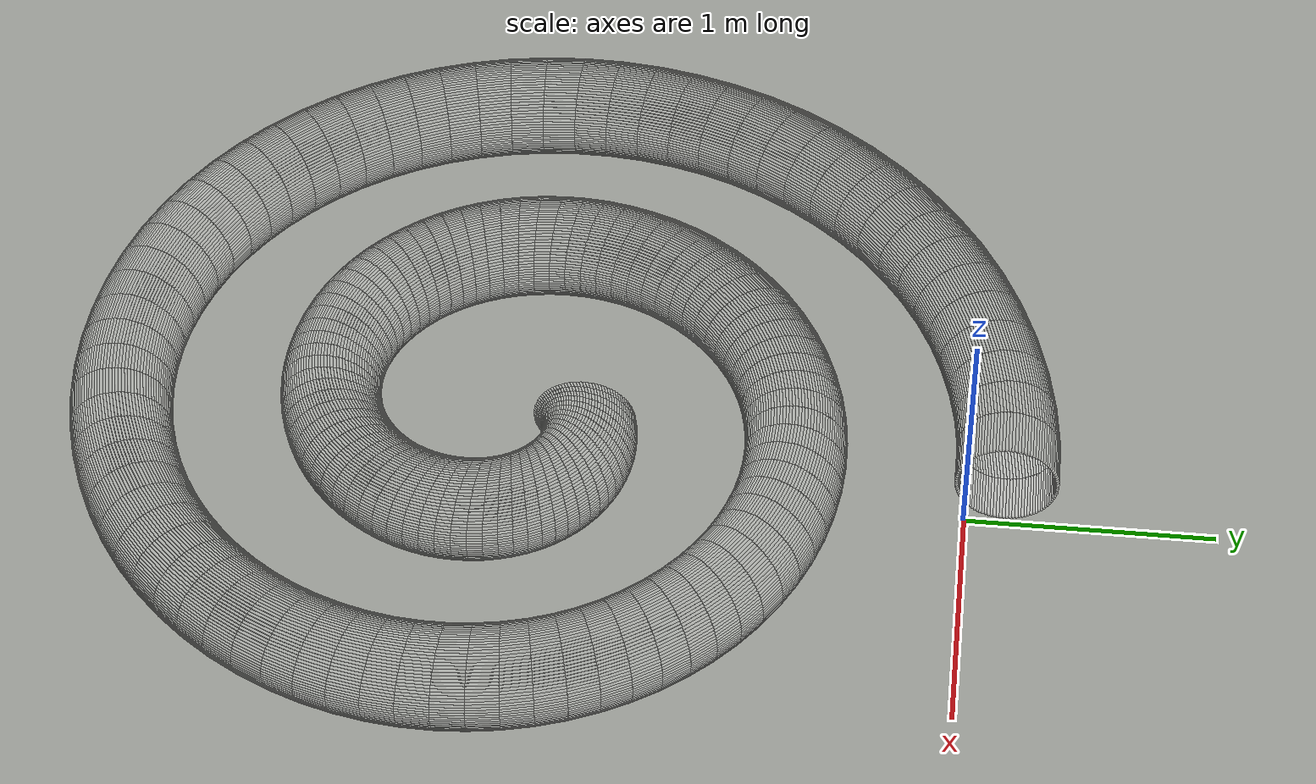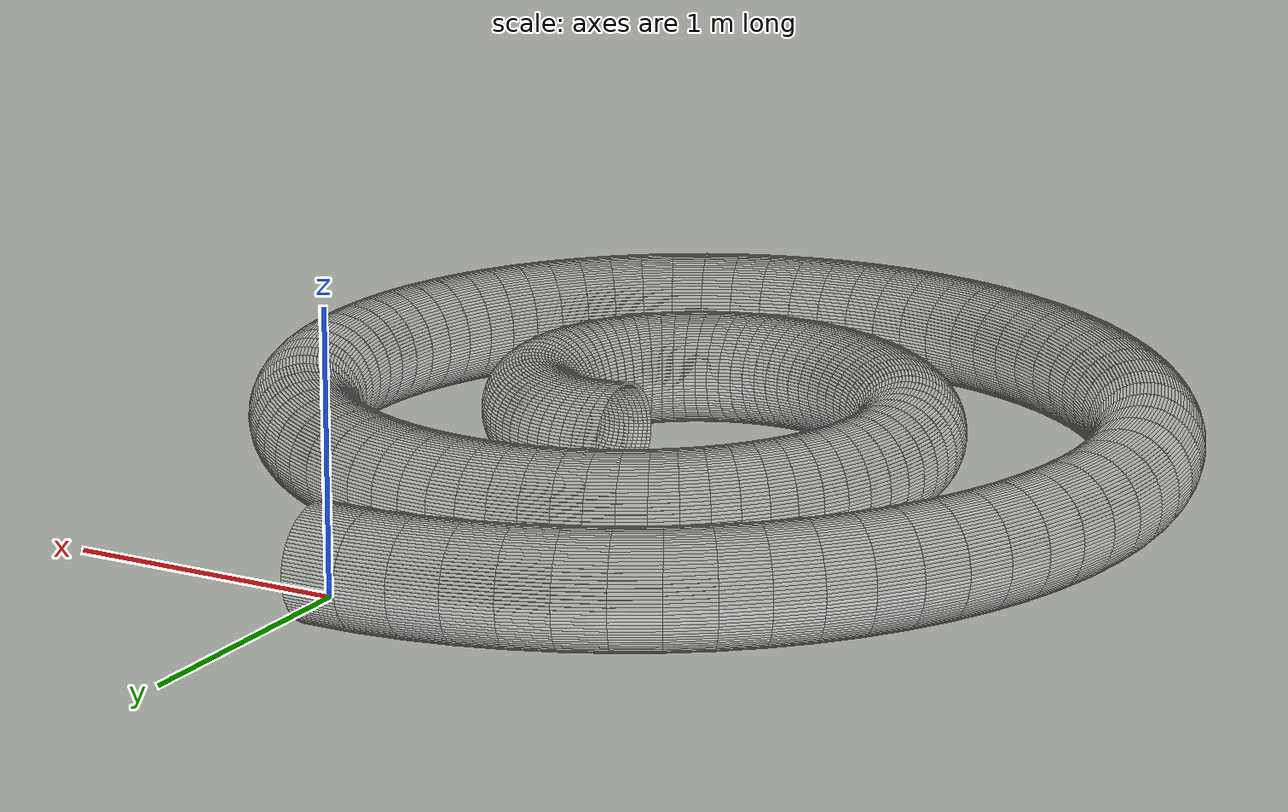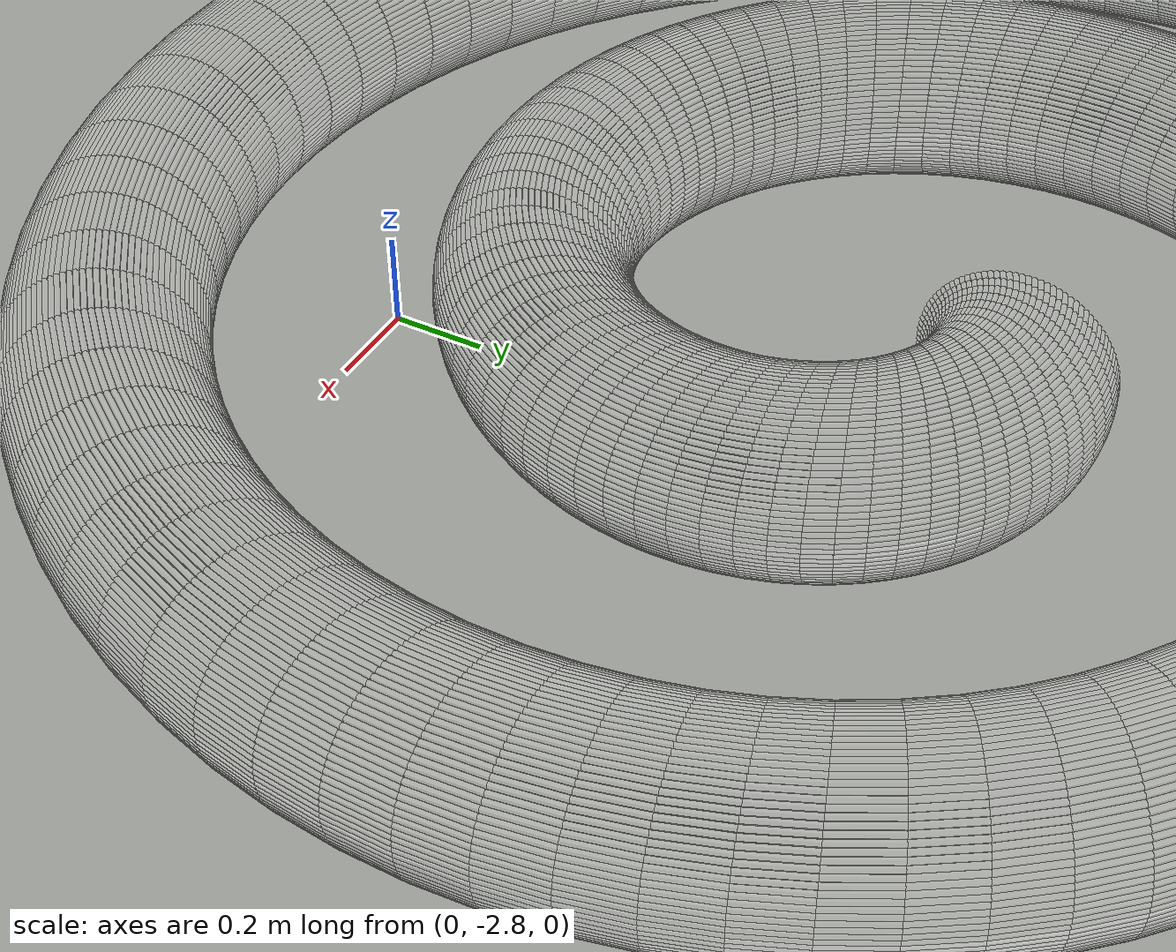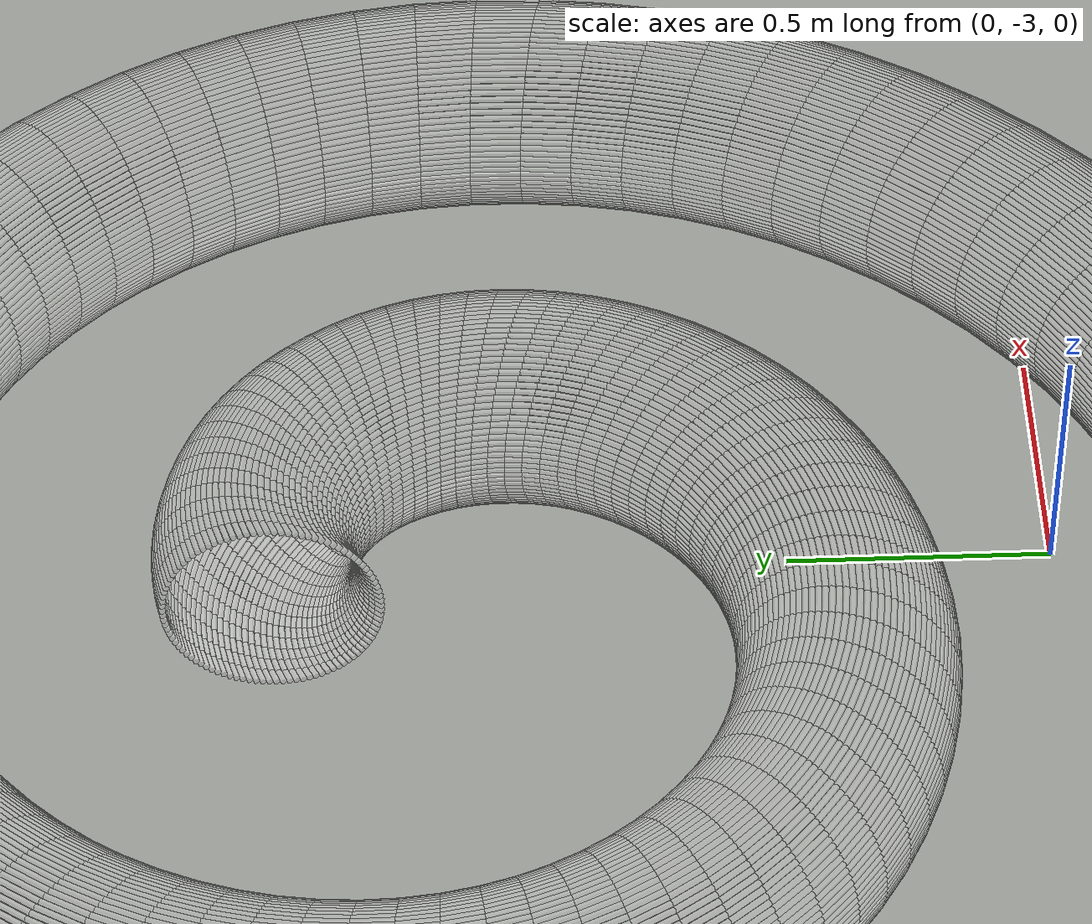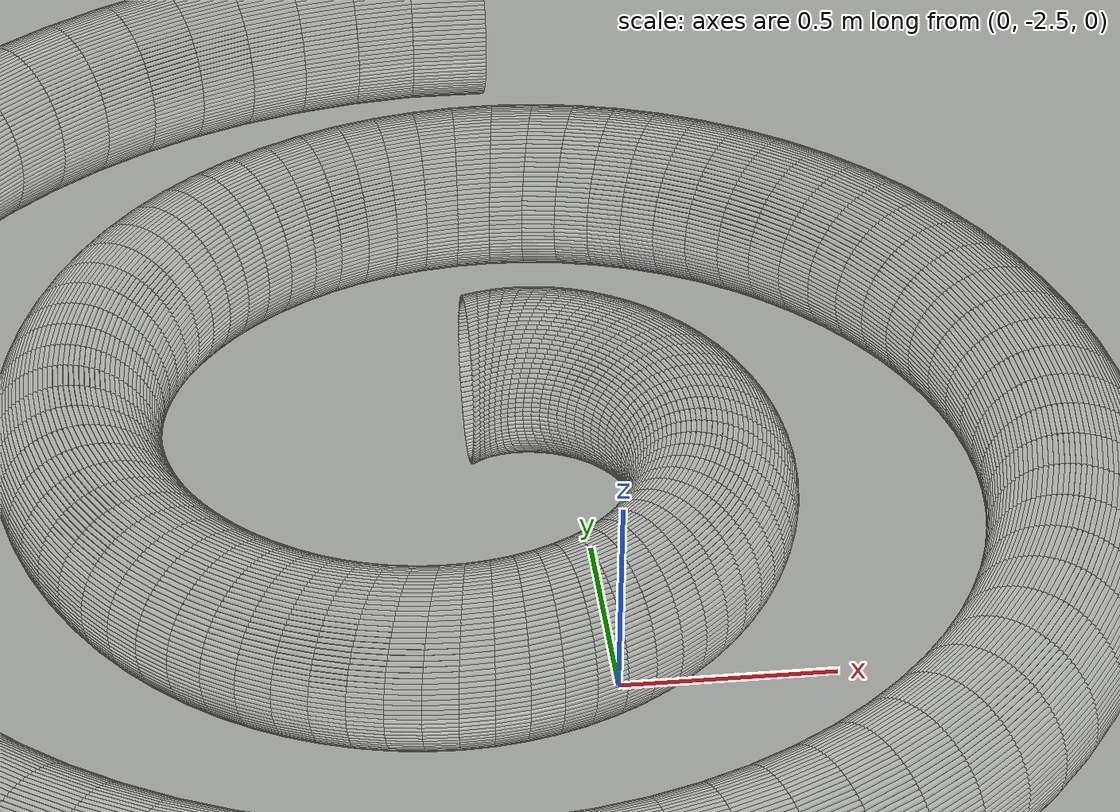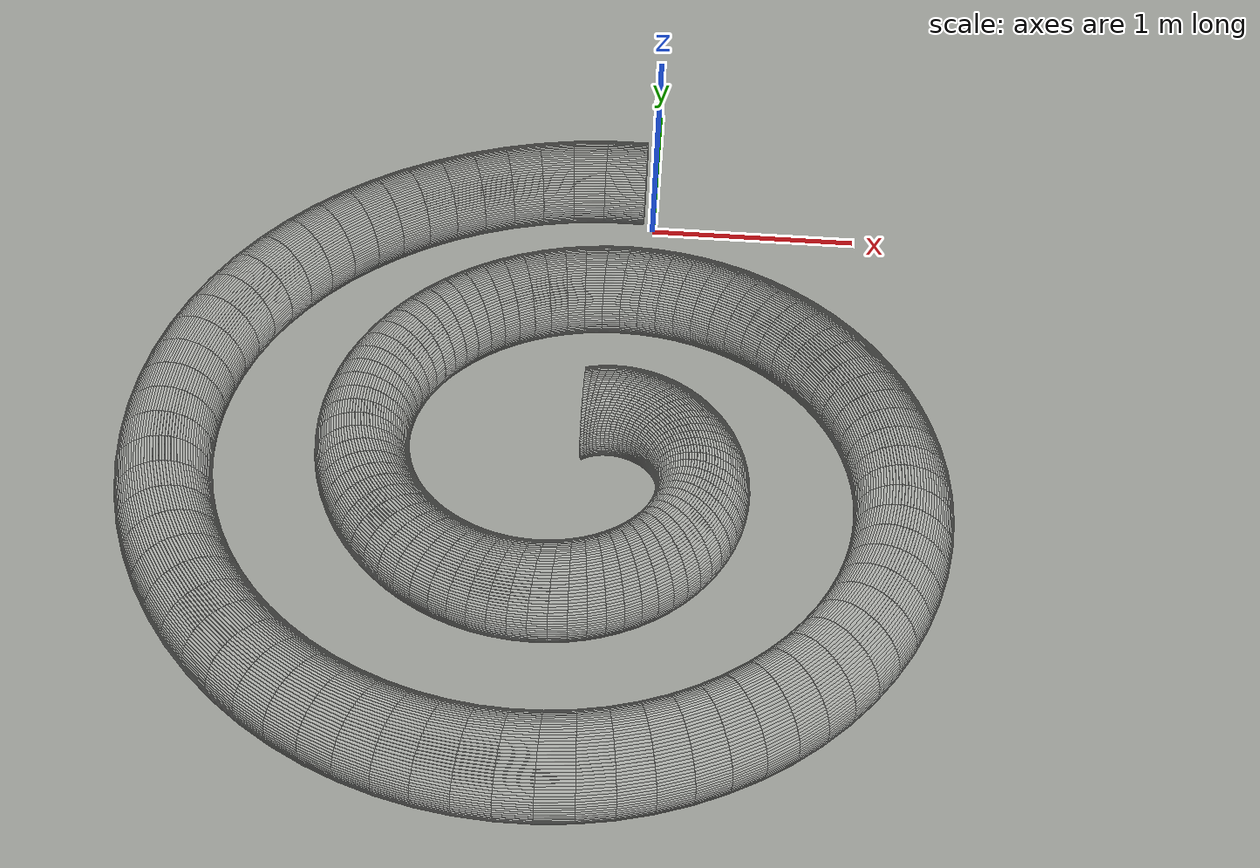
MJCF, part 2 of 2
<geom euler=" 0 790 0 " fromto="1.1921 -0.0503 0.0035425 1.1807 0.049819 0.0035425"
            rgba="1 1 1 0.35"
            size="0.0062822"
            type="cylinder"/>
      <geom euler=" 0 800 0 " fromto="1.2044 -0.050817 0.0062834 1.193 0.050336 0.0062834"
            rgba="1 1 1 0.35"
            size="0.0062822"
            type="cylinder"/>
      <geom euler=" 0 810 0 " fromto="1.2164 -0.051326 0.0097887 1.205 0.050845 0.0097887"
            rgba="1 1 1 0.35"
            size="0.0062822"
            type="cylinder"/>
      <geom euler=" 0 820 0 " fromto="1.2282 -0.051824 0.014045 1.2168 0.051343 0.014045"
            rgba="1 1 1 0.35"
            size="0.0062822"
            type="cylinder"/>
      <geom euler=" 0 830 0 " fromto="1.2398 -0.05231 0.019035 1.2284 0.051829 0.019035"
            rgba="1 1 1 0.35"
            size="0.0062822"
            type="cylinder"/>
      <geom euler=" 0 840 0 " fromto="1.2509 -0.052782 0.024739 1.2395 0.052301 0.024739"
            rgba="1 1 1 0.35"
            size="0.0062822"
            type="cylinder"/>
      <geom euler=" 0 850 0 " fromto="1.2617 -0.053238 0.031134 1.2503 0.052757 0.031134"
            rgba="1 1 1 0.35"
            size="0.0062822"
            type="cylinder"/>
      <geom euler=" 0 860 0 " fromto="1.2721 -0.053676 0.038197 1.2607 0.053195 0.038197"
            rgba="1 1 1 0.35"
            size="0.0062822"
            type="cylinder"/>
      <geom euler=" 0 870 0 " fromto="1.282 -0.054095 0.045897 1.2706 0.053614 0.045897"
            rgba="1 1 1 0.35"
            size="0.0062822"
            type="cylinder"/>
      <geom euler=" 0 880 0 " fromto="1.2915 -0.054492 0.054206 1.2801 0.054011 0.054206"
            rgba="1 1 1 0.35"
            size="0.0062822"
            type="cylinder"/>
      <geom euler=" 0 890 0 " fromto="1.3003 -0.054867 0.063091 1.2889 0.054386 0.063091"
            rgba="1 1 1 0.35"
            size="0.0062822"
            type="cylinder"/>
      <geom euler=" 0 900 0 " fromto="1.3086 -0.055217 0.072515 1.2972 0.054736 0.072515"
            rgba="1 1 1 0.35"
            size="0.0062822"
            type="cylinder"/>
      <geom euler=" 0 910 0 " fromto="1.3163 -0.055542 0.082443 1.3049 0.055061 0.082443"
            rgba="1 1 1 0.35"
            size="0.0062822"
            type="cylinder"/>
      <geom euler=" 0 920 0 " fromto="1.3234 -0.055839 0.092835 1.312 0.055358 0.092835"
            rgba="1 1 1 0.35"
            size="0.0062822"
            type="cylinder"/>
      <geom euler=" 0 930 0 " fromto="1.3298 -0.056109 0.10365 1.3184 0.055628 0.10365"
            rgba="1 1 1 0.35"
            size="0.0062822"
            type="cylinder"/>
      <geom euler=" 0 940 0 " fromto="1.3355 -0.056349 0.11484 1.3241 0.055868 0.11484"
            rgba="1 1 1 0.35"
            size="0.0062822"
            type="cylinder"/>
      <geom euler=" 0 950 0 " fromto="1.3405 -0.05656 0.12638 1.3291 0.056079 0.12638"
            rgba="1 1 1 0.35"
            size="0.0062822"
            type="cylinder"/>
      <geom euler=" 0 960 0 " fromto="1.3447 -0.056739 0.1382 1.3333 0.056258 0.1382"
            rgba="1 1 1 0.35"
            size="0.0062822"
            type="cylinder"/>
      <geom euler=" 0 970 0 " fromto="1.3482 -0.056887 0.15026 1.3368 0.056406 0.15026"
            rgba="1 1 1 0.35"
            size="0.0062822"
            type="cylinder"/>
      <geom euler=" 0 980 0 " fromto="1.351 -0.057002 0.16252 1.3396 0.056521 0.16252"
            rgba="1 1 1 0.35"
            size="0.0062822"
            type="cylinder"/>
      <geom euler=" 0 990 0 " fromto="1.3529 -0.057085 0.17493 1.3415 0.056604 0.17493"
            rgba="1 1 1 0.35"
            size="0.0062822"
            type="cylinder"/>
      <geom euler=" 0 1000 0 " fromto="1.3541 -0.057135 0.18744 1.3427 0.056654 0.18744"
            rgba="1 1 1 0.35"
            size="0.0062822"
            type="cylinder"/>
      <geom euler=" 0 10 0 " fromto="1.3431 0.056671 0.2 1.3222 0.16817 0.2"
            rgba="1 1 1 0.05"
            size="0.0062822"
            type="cylinder"/>
      <geom euler=" 0 20 0 " fromto="1.3427 0.056654 0.21256 1.3218 0.16812 0.21256"
            rgba="1 1 1 0.05"
            size="0.0062822"
            type="cylinder"/>
      <geom euler=" 0 30 0 " fromto="1.3415 0.056604 0.22507 1.3207 0.16797 0.22507"
            rgba="1 1 1 0.05"
            size="0.0062822"
            type="cylinder"/>
      <geom euler=" 0 40 0 " fromto="1.3396 0.056521 0.23748 1.3187 0.16772 0.23748"
            rgba="1 1 1 0.05"
            size="0.0062822"
            type="cylinder"/>
      <geom euler=" 0 50 0 " fromto="1.3368 0.056406 0.24974 1.316 0.16738 0.24974"
            rgba="1 1 1 0.05"
            size="0.0062822"
            type="cylinder"/>
      <geom euler=" 0 60 0 " fromto="1.3333 0.056258 0.2618 1.3125 0.16694 0.2618"
            rgba="1 1 1 0.05"
            size="0.0062822"
            type="cylinder"/>
      <geom euler=" 0 70 0 " fromto="1.3291 0.056079 0.27362 1.3083 0.1664 0.27362"
            rgba="1 1 1 0.05"
            size="0.0062822"
            type="cylinder"/>
      <geom euler=" 0 80 0 " fromto="1.3241 0.055868 0.28516 1.3034 0.16577 0.28516"
            rgba="1 1 1 0.05"
            size="0.0062822"
            type="cylinder"/>
      <geom euler=" 0 90 0 " fromto="1.3184 0.055628 0.29635 1.2977 0.16505 0.29635"
            rgba="1 1 1 0.05"
            size="0.0062822"
            type="cylinder"/>
      <geom euler=" 0 100 0 " fromto="1.312 0.055358 0.30717 1.2913 0.16424 0.30717"
            rgba="1 1 1 0.05"
            size="0.0062822"
            type="cylinder"/>
      <geom euler=" 0 110 0 " fromto="1.3049 0.055061 0.31756 1.2843 0.16335 0.31756"
            rgba="1 1 1 0.05"
            size="0.0062822"
            type="cylinder"/>
      <geom euler=" 0 120 0 " fromto="1.2972 0.054736 0.32748 1.2767 0.16238 0.32748"
            rgba="1 1 1 0.05"
            size="0.0062822"
            type="cylinder"/>
      <geom euler=" 0 130 0 " fromto="1.2889 0.054386 0.33691 1.2685 0.16133 0.33691"
            rgba="1 1 1 0.05"
            size="0.0062822"
            type="cylinder"/>
      <geom euler=" 0 140 0 " fromto="1.2801 0.054011 0.34579 1.2596 0.16021 0.34579"
            rgba="1 1 1 0.05"
            size="0.0062822"
            type="cylinder"/>
      <geom euler=" 0 150 0 " fromto="1.2706 0.053614 0.3541 1.2503 0.15902 0.3541"
            rgba="1 1 1 0.05"
            size="0.0062822"
            type="cylinder"/>
      <geom euler=" 0 160 0 " fromto="1.2607 0.053195 0.3618 1.2405 0.15777 0.3618"
            rgba="1 1 1 0.05"
            size="0.0062822"
            type="cylinder"/>
      <geom euler=" 0 170 0 " fromto="1.2503 0.052757 0.36887 1.2301 0.15646 0.36887"
            rgba="1 1 1 0.05"
            size="0.0062822"
            type="cylinder"/>
      <geom euler=" 0 180 0 " fromto="1.2395 0.052301 0.37526 1.2194 0.15509 0.37526"
            rgba="1 1 1 0.05"
            size="0.0062822"
            type="cylinder"/>
      <geom euler=" 0 190 0 " fromto="1.2284 0.051829 0.38097 1.2083 0.15368 0.38097"
            rgba="1 1 1 0.05"
            size="0.0062822"
            type="cylinder"/>
      <geom euler=" 0 200 0 " fromto="1.2168 0.051343 0.38596 1.1969 0.15223 0.38596"
            rgba="1 1 1 0.05"
            size="0.0062822"
            type="cylinder"/>
      <geom euler=" 0 210 0 " fromto="1.205 0.050845 0.39021 1.1851 0.15073 0.39021"
            rgba="1 1 1 0.05"
            size="0.0062822"
            type="cylinder"/>
      <geom euler=" 0 220 0 " fromto="1.193 0.050336 0.39372 1.1732 0.14921 0.39372"
            rgba="1 1 1 0.05"
            size="0.0062822"
            type="cylinder"/>
      <geom euler=" 0 230 0 " fromto="1.1807 0.049819 0.39646 1.161 0.14766 0.39646"
            rgba="1 1 1 0.05"
            size="0.0062822"
            type="cylinder"/>
      <geom euler=" 0 240 0 " fromto="1.1683 0.049296 0.39842 1.1487 0.1461 0.39842"
            rgba="1 1 1 0.05"
            size="0.0062822"
            type="cylinder"/>
      <geom euler=" 0 250 0 " fromto="1.1558 0.048769 0.39961 1.1363 0.14452 0.39961"
            rgba="1 1 1 0.05"
            size="0.0062822"
            type="cylinder"/>
      <geom euler=" 0 260 0 " fromto="1.1433 0.04824 0.4 1.1238 0.14294 0.4"
            rgba="1 1 1 0.05"
            size="0.0062822"
            type="cylinder"/>
      <geom euler=" 0 270 0 " fromto="1.1307 0.04771 0.39961 1.1114 0.14135 0.39961"
            rgba="1 1 1 0.05"
            size="0.0062822"
            type="cylinder"/>
      <geom euler=" 0 280 0 " fromto="1.1182 0.047183 0.39842 1.099 0.13977 0.39842"
            rgba="1 1 1 0.05"
            size="0.0062822"
            type="cylinder"/>
      <geom euler=" 0 290 0 " fromto="1.1058 0.04666 0.39646 1.0867 0.13821 0.39646"
            rgba="1 1 1 0.05"
            size="0.0062822"
            type="cylinder"/>
      <geom euler=" 0 300 0 " fromto="1.0936 0.046143 0.39372 1.0745 0.13666 0.39372"
            rgba="1 1 1 0.05"
            size="0.0062822"
            type="cylinder"/>
      <geom euler=" 0 310 0 " fromto="1.0815 0.045634 0.39021 1.0625 0.13514 0.39021"
            rgba="1 1 1 0.05"
            size="0.0062822"
            type="cylinder"/>
      <geom euler=" 0 320 0 " fromto="1.0697 0.045136 0.38596 1.0508 0.13365 0.38596"
            rgba="1 1 1 0.05"
            size="0.0062822"
            type="cylinder"/>
      <geom euler=" 0 330 0 " fromto="1.0582 0.04465 0.38097 1.0394 0.13219 0.38097"
            rgba="1 1 1 0.05"
            size="0.0062822"
            type="cylinder"/>
      <geom euler=" 0 340 0 " fromto="1.047 0.044178 0.37526 1.0283 0.13078 0.37526"
            rgba="1 1 1 0.05"
            size="0.0062822"
            type="cylinder"/>
      <geom euler=" 0 350 0 " fromto="1.0362 0.043722 0.36887 1.0175 0.12942 0.36887"
            rgba="1 1 1 0.05"
            size="0.0062822"
            type="cylinder"/>
      <geom euler=" 0 360 0 " fromto="1.0258 0.043284 0.3618 1.0072 0.1281 0.3618"
            rgba="1 1 1 0.05"
            size="0.0062822"
            type="cylinder"/>
      <geom euler=" 0 370 0 " fromto="1.0159 0.042865 0.3541 0.99737 0.12685 0.3541"
            rgba="1 1 1 0.05"
            size="0.0062822"
            type="cylinder"/>
      <geom euler=" 0 380 0 " fromto="1.0065 0.042468 0.34579 0.98802 0.12566 0.34579"
            rgba="1 1 1 0.05"
            size="0.0062822"
            type="cylinder"/>
      <geom euler=" 0 390 0 " fromto="0.99761 0.042093 0.33691 0.9792 0.12454 0.33691"
            rgba="1 1 1 0.05"
            size="0.0062822"
            type="cylinder"/>
      <geom euler=" 0 400 0 " fromto="0.98931 0.041743 0.32748 0.97096 0.12349 0.32748"
            rgba="1 1 1 0.05"
            size="0.0062822"
            type="cylinder"/>
      <geom euler=" 0 410 0 " fromto="0.98162 0.041418 0.31756 0.96332 0.12252 0.31756"
            rgba="1 1 1 0.05"
            size="0.0062822"
            type="cylinder"/>
      <geom euler=" 0 420 0 " fromto="0.97456 0.041121 0.30717 0.95632 0.12163 0.30717"
            rgba="1 1 1 0.05"
            size="0.0062822"
            type="cylinder"/>
      <geom euler=" 0 430 0 " fromto="0.96817 0.040851 0.29635 0.94997 0.12082 0.29635"
            rgba="1 1 1 0.05"
            size="0.0062822"
            type="cylinder"/>
      <geom euler=" 0 440 0 " fromto="0.96247 0.040611 0.28516 0.94431 0.1201 0.28516"
            rgba="1 1 1 0.05"
            size="0.0062822"
            type="cylinder"/>
      <geom euler=" 0 450 0 " fromto="0.95749 0.0404 0.27362 0.93936 0.11947 0.27362"
            rgba="1 1 1 0.05"
            size="0.0062822"
            type="cylinder"/>
      <geom euler=" 0 460 0 " fromto="0.95324 0.040221 0.2618 0.93514 0.11894 0.2618"
            rgba="1 1 1 0.05"
            size="0.0062822"
            type="cylinder"/>
      <geom euler=" 0 470 0 " fromto="0.94973 0.040073 0.24974 0.93166 0.11849 0.24974"
            rgba="1 1 1 0.05"
            size="0.0062822"
            type="cylinder"/>
      <geom euler=" 0 480 0 " fromto="0.947 0.039958 0.23748 0.92895 0.11815 0.23748"
            rgba="1 1 1 0.05"
            size="0.0062822"
            type="cylinder"/>
      <geom euler=" 0 490 0 " fromto="0.94503 0.039875 0.22507 0.927 0.1179 0.22507"
            rgba="1 1 1 0.05"
            size="0.0062822"
            type="cylinder"/>
      <geom euler=" 0 500 0 " fromto="0.94385 0.039825 0.21256 0.92582 0.11775 0.21256"
            rgba="1 1 1 0.05"
            size="0.0062822"
            type="cylinder"/>
      <geom euler=" 0 510 0 " fromto="0.94346 0.039808 0.2 0.92543 0.1177 0.2"
            rgba="1 1 1 0.05"
            size="0.0062822"
            type="cylinder"/>
      <geom euler=" 0 520 0 " fromto="0.94385 0.039825 0.18744 0.92582 0.11775 0.18744"
            rgba="1 1 1 0.35"
            size="0.0062822"
            type="cylinder"/>
      <geom euler=" 0 530 0 " fromto="0.94503 0.039875 0.17493 0.927 0.1179 0.17493"
            rgba="1 1 1 0.35"
            size="0.0062822"
            type="cylinder"/>
      <geom euler=" 0 540 0 " fromto="0.947 0.039958 0.16252 0.92895 0.11815 0.16252"
            rgba="1 1 1 0.35"
            size="0.0062822"
            type="cylinder"/>
      <geom euler=" 0 550 0 " fromto="0.94973 0.040073 0.15026 0.93166 0.11849 0.15026"
            rgba="1 1 1 0.35"
            size="0.0062822"
            type="cylinder"/>
      <geom euler=" 0 560 0 " fromto="0.95324 0.040221 0.1382 0.93514 0.11894 0.1382"
            rgba="1 1 1 0.35"
            size="0.0062822"
            type="cylinder"/>
      <geom euler=" 0 570 0 " fromto="0.95749 0.0404 0.12638 0.93936 0.11947 0.12638"
            rgba="1 1 1 0.35"
            size="0.0062822"
            type="cylinder"/>
      <geom euler=" 0 580 0 " fromto="0.96247 0.040611 0.11484 0.94431 0.1201 0.11484"
            rgba="1 1 1 0.35"
            size="0.0062822"
            type="cylinder"/>
      <geom euler=" 0 590 0 " fromto="0.96817 0.040851 0.10365 0.94997 0.12082 0.10365"
            rgba="1 1 1 0.35"
            size="0.0062822"
            type="cylinder"/>
      <geom euler=" 0 600 0 " fromto="0.97456 0.041121 0.092835 0.95632 0.12163 0.092835"
            rgba="1 1 1 0.35"
            size="0.0062822"
            type="cylinder"/>
      <geom euler=" 0 610 0 " fromto="0.98162 0.041418 0.082443 0.96332 0.12252 0.082443"
            rgba="1 1 1 0.35"
            size="0.0062822"
            type="cylinder"/>
      <geom euler=" 0 620 0 " fromto="0.98931 0.041743 0.072515 0.97096 0.12349 0.072515"
            rgba="1 1 1 0.35"
            size="0.0062822"
            type="cylinder"/>
      <geom euler=" 0 630 0 " fromto="0.99761 0.042093 0.063091 0.9792 0.12454 0.063091"
            rgba="1 1 1 0.35"
            size="0.0062822"
            type="cylinder"/>
      <geom euler=" 0 640 0 " fromto="1.0065 0.042468 0.054206 0.98802 0.12566 0.054206"
            rgba="1 1 1 0.35"
            size="0.0062822"
            type="cylinder"/>
      <geom euler=" 0 650 0 " fromto="1.0159 0.042865 0.045897 0.99737 0.12685 0.045897"
            rgba="1 1 1 0.35"
            size="0.0062822"
            type="cylinder"/>
      <geom euler=" 0 660 0 " fromto="1.0258 0.043284 0.038197 1.0072 0.1281 0.038197"
            rgba="1 1 1 0.35"
            size="0.0062822"
            type="cylinder"/>
      <geom euler=" 0 670 0 " fromto="1.0362 0.043722 0.031134 1.0175 0.12942 0.031134"
            rgba="1 1 1 0.35"
            size="0.0062822"
            type="cylinder"/>
      <geom euler=" 0 680 0 " fromto="1.047 0.044178 0.024739 1.0283 0.13078 0.024739"
            rgba="1 1 1 0.35"
            size="0.0062822"
            type="cylinder"/>
      <geom euler=" 0 690 0 " fromto="1.0582 0.04465 0.019035 1.0394 0.13219 0.019035"
            rgba="1 1 1 0.35"
            size="0.0062822"
            type="cylinder"/>
      <geom euler=" 0 700 0 " fromto="1.0697 0.045136 0.014045 1.0508 0.13365 0.014045"
            rgba="1 1 1 0.35"
            size="0.0062822"
            type="cylinder"/>
      <geom euler=" 0 710 0 " fromto="1.0815 0.045634 0.0097887 1.0625 0.13514 0.0097887"
            rgba="1 1 1 0.35"
            size="0.0062822"
            type="cylinder"/>
      <geom euler=" 0 720 0 " fromto="1.0936 0.046143 0.0062834 1.0745 0.13666 0.0062834"
            rgba="1 1 1 0.35"
            size="0.0062822"
            type="cylinder"/>
      <geom euler=" 0 730 0 " fromto="1.1058 0.04666 0.0035425 1.0867 0.13821 0.0035425"
            rgba="1 1 1 0.35"
            size="0.0062822"
            type="cylinder"/>
      <geom euler=" 0 740 0 " fromto="1.1182 0.047183 0.0015771 1.099 0.13977 0.0015771"
            rgba="1 1 1 0.35"
            size="0.0062822"
            type="cylinder"/>
      <geom euler=" 0 750 0 " fromto="1.1307 0.04771 0.00039465 1.1114 0.14135 0.00039465"
            rgba="1 1 1 0.35"
            size="0.0062822"
            type="cylinder"/>
      <geom euler=" 0 760 0 " fromto="1.1433 0.04824 0 1.1238 0.14294 0" rgba="1 1 1 0.35"
            size="0.0062822"
            type="cylinder"/>
      <geom euler=" 0 770 0 " fromto="1.1558 0.048769 0.00039465 1.1363 0.14452 0.00039465"
            rgba="1 1 1 0.35"
            size="0.0062822"
            type="cylinder"/>
      <geom euler=" 0 780 0 " fromto="1.1683 0.049296 0.0015771 1.1487 0.1461 0.0015771"
            rgba="1 1 1 0.35"
            size="0.0062822"
            type="cylinder"/>
      <geom euler=" 0 790 0 " fromto="1.1807 0.049819 0.0035425 1.161 0.14766 0.0035425"
            rgba="1 1 1 0.35"
            size="0.0062822"
            type="cylinder"/>
      <geom euler=" 0 800 0 " fromto="1.193 0.050336 0.0062834 1.1732 0.14921 0.0062834"
            rgba="1 1 1 0.35"
            size="0.0062822"
            type="cylinder"/>
      <geom euler=" 0 810 0 " fromto="1.205 0.050845 0.0097887 1.1851 0.15073 0.0097887"
            rgba="1 1 1 0.35"
            size="0.0062822"
            type="cylinder"/>
      <geom euler=" 0 820 0 " fromto="1.2168 0.051343 0.014045 1.1969 0.15223 0.014045"
            rgba="1 1 1 0.35"
            size="0.0062822"
            type="cylinder"/>
      <geom euler=" 0 830 0 " fromto="1.2284 0.051829 0.019035 1.2083 0.15368 0.019035"
            rgba="1 1 1 0.35"
            size="0.0062822"
            type="cylinder"/>
      <geom euler=" 0 840 0 " fromto="1.2395 0.052301 0.024739 1.2194 0.15509 0.024739"
            rgba="1 1 1 0.35"
            size="0.0062822"
            type="cylinder"/>
      <geom euler=" 0 850 0 " fromto="1.2503 0.052757 0.031134 1.2301 0.15646 0.031134"
            rgba="1 1 1 0.35"
            size="0.0062822"
            type="cylinder"/>
      <geom euler=" 0 860 0 " fromto="1.2607 0.053195 0.038197 1.2405 0.15777 0.038197"
            rgba="1 1 1 0.35"
            size="0.0062822"
            type="cylinder"/>
      <geom euler=" 0 870 0 " fromto="1.2706 0.053614 0.045897 1.2503 0.15902 0.045897"
            rgba="1 1 1 0.35"
            size="0.0062822"
            type="cylinder"/>
      <geom euler=" 0 880 0 " fromto="1.2801 0.054011 0.054206 1.2596 0.16021 0.054206"
            rgba="1 1 1 0.35"
            size="0.0062822"
            type="cylinder"/>
      <geom euler=" 0 890 0 " fromto="1.2889 0.054386 0.063091 1.2685 0.16133 0.063091"
            rgba="1 1 1 0.35"
            size="0.0062822"
            type="cylinder"/>
      <geom euler=" 0 900 0 " fromto="1.2972 0.054736 0.072515 1.2767 0.16238 0.072515"
            rgba="1 1 1 0.35"
            size="0.0062822"
            type="cylinder"/>
      <geom euler=" 0 910 0 " fromto="1.3049 0.055061 0.082443 1.2843 0.16335 0.082443"
            rgba="1 1 1 0.35"
            size="0.0062822"
            type="cylinder"/>
      <geom euler=" 0 920 0 " fromto="1.312 0.055358 0.092835 1.2913 0.16424 0.092835"
            rgba="1 1 1 0.35"
            size="0.0062822"
            type="cylinder"/>
      <geom euler=" 0 930 0 " fromto="1.3184 0.055628 0.10365 1.2977 0.16505 0.10365"
            rgba="1 1 1 0.35"
            size="0.0062822"
            type="cylinder"/>
      <geom euler=" 0 940 0 " fromto="1.3241 0.055868 0.11484 1.3034 0.16577 0.11484"
            rgba="1 1 1 0.35"
            size="0.0062822"
            type="cylinder"/>
      <geom euler=" 0 950 0 " fromto="1.3291 0.056079 0.12638 1.3083 0.1664 0.12638"
            rgba="1 1 1 0.35"
            size="0.0062822"
            type="cylinder"/>
      <geom euler=" 0 960 0 " fromto="1.3333 0.056258 0.1382 1.3125 0.16694 0.1382"
            rgba="1 1 1 0.35"
            size="0.0062822"
            type="cylinder"/>
      <geom euler=" 0 970 0 " fromto="1.3368 0.056406 0.15026 1.316 0.16738 0.15026"
            rgba="1 1 1 0.35"
            size="0.0062822"
            type="cylinder"/>
      <geom euler=" 0 980 0 " fromto="1.3396 0.056521 0.16252 1.3187 0.16772 0.16252"
            rgba="1 1 1 0.35"
            size="0.0062822"
            type="cylinder"/>
      <geom euler=" 0 990 0 " fromto="1.3415 0.056604 0.17493 1.3207 0.16797 0.17493"
            rgba="1 1 1 0.35"
            size="0.0062822"
            type="cylinder"/>
      <geom euler=" 0 1000 0 " fromto="1.3427 0.056654 0.18744 1.3218 0.16812 0.18744"
            rgba="1 1 1 0.35"
            size="0.0062822"
            type="cylinder"/>
      <geom euler=" 0 10 0 " fromto="1.3222 0.16817 0.2 1.2922 0.27657 0.2"
            rgba="1 1 1 0.05"
            size="0.0062822"
            type="cylinder"/>
      <geom euler=" 0 20 0 " fromto="1.3218 0.16812 0.21256 1.2918 0.27648 0.21256"
            rgba="1 1 1 0.05"
            size="0.0062822"
            type="cylinder"/>
      <geom euler=" 0 30 0 " fromto="1.3207 0.16797 0.22507 1.2907 0.27624 0.22507"
            rgba="1 1 1 0.05"
            size="0.0062822"
            type="cylinder"/>
      <geom euler=" 0 40 0 " fromto="1.3187 0.16772 0.23748 1.2887 0.27583 0.23748"
            rgba="1 1 1 0.05"
            size="0.0062822"
            type="cylinder"/>
      <geom euler=" 0 50 0 " fromto="1.316 0.16738 0.24974 1.2861 0.27525 0.24974"
            rgba="1 1 1 0.05"
            size="0.0062822"
            type="cylinder"/>
      <geom euler=" 0 60 0 " fromto="1.3125 0.16694 0.2618 1.2826 0.27452 0.2618"
            rgba="1 1 1 0.05"
            size="0.0062822"
            type="cylinder"/>
      <geom euler=" 0 70 0 " fromto="1.3083 0.1664 0.27362 1.2785 0.27363 0.27362"
            rgba="1 1 1 0.05"
            size="0.0062822"
            type="cylinder"/>
      <geom euler=" 0 80 0 " fromto="1.3034 0.16577 0.28516 1.2736 0.27258 0.28516"
            rgba="1 1 1 0.05"
            size="0.0062822"
            type="cylinder"/>
      <geom euler=" 0 90 0 " fromto="1.2977 0.16505 0.29635 1.268 0.27139 0.29635"
            rgba="1 1 1 0.05"
            size="0.0062822"
            type="cylinder"/>
      <geom euler=" 0 100 0 " fromto="1.2913 0.16424 0.30717 1.2618 0.27005 0.30717"
            rgba="1 1 1 0.05"
            size="0.0062822"
            type="cylinder"/>
      <geom euler=" 0 110 0 " fromto="1.2843 0.16335 0.31756 1.2549 0.26857 0.31756"
            rgba="1 1 1 0.05"
            size="0.0062822"
            type="cylinder"/>
      <geom euler=" 0 120 0 " fromto="1.2767 0.16238 0.32748 1.2473 0.26696 0.32748"
            rgba="1 1 1 0.05"
            size="0.0062822"
            type="cylinder"/>
      <geom euler=" 0 130 0 " fromto="1.2685 0.16133 0.33691 1.2392 0.26522 0.33691"
            rgba="1 1 1 0.05"
            size="0.0062822"
            type="cylinder"/>
      <geom euler=" 0 140 0 " fromto="1.2596 0.16021 0.34579 1.2305 0.26336 0.34579"
            rgba="1 1 1 0.05"
            size="0.0062822"
            type="cylinder"/>
      <geom euler=" 0 150 0 " fromto="1.2503 0.15902 0.3541 1.2213 0.26139 0.3541"
            rgba="1 1 1 0.05"
            size="0.0062822"
            type="cylinder"/>
      <geom euler=" 0 160 0 " fromto="1.2405 0.15777 0.3618 1.2116 0.25931 0.3618"
            rgba="1 1 1 0.05"
            size="0.0062822"
            type="cylinder"/>
      <geom euler=" 0 170 0 " fromto="1.2301 0.15646 0.36887 1.2014 0.25714 0.36887"
            rgba="1 1 1 0.05"
            size="0.0062822"
            type="cylinder"/>
      <geom euler=" 0 180 0 " fromto="1.2194 0.15509 0.37526 1.1909 0.25487 0.37526"
            rgba="1 1 1 0.05"
            size="0.0062822"
            type="cylinder"/>
      <geom euler=" 0 190 0 " fromto="1.2083 0.15368 0.38097 1.1799 0.25253 0.38097"
            rgba="1 1 1 0.05"
            size="0.0062822"
            type="cylinder"/>
      <geom euler=" 0 200 0 " fromto="1.1969 0.15223 0.38596 1.1686 0.25012 0.38596"
            rgba="1 1 1 0.05"
            size="0.0062822"
            type="cylinder"/>
      <geom euler=" 0 210 0 " fromto="1.1851 0.15073 0.39021 1.1571 0.24764 0.39021"
            rgba="1 1 1 0.05"
            size="0.0062822"
            type="cylinder"/>
      <geom euler=" 0 220 0 " fromto="1.1732 0.14921 0.39372 1.1453 0.24512 0.39372"
            rgba="1 1 1 0.05"
            size="0.0062822"
            type="cylinder"/>
      <geom euler=" 0 230 0 " fromto="1.161 0.14766 0.39646 1.1333 0.24255 0.39646"
            rgba="1 1 1 0.05"
            size="0.0062822"
            type="cylinder"/>
      <geom euler=" 0 240 0 " fromto="1.1487 0.1461 0.39842 1.1212 0.23996 0.39842"
            rgba="1 1 1 0.05"
            size="0.0062822"
            type="cylinder"/>
      <geom euler=" 0 250 0 " fromto="1.1363 0.14452 0.39961 1.1089 0.23734 0.39961"
            rgba="1 1 1 0.05"
            size="0.0062822"
            type="cylinder"/>
      <geom euler=" 0 260 0 " fromto="1.1238 0.14294 0.4 1.0966 0.23471 0.4"
            rgba="1 1 1 0.05"
            size="0.0062822"
            type="cylinder"/>
      <geom euler=" 0 270 0 " fromto="1.1114 0.14135 0.39961 1.0844 0.23208 0.39961"
            rgba="1 1 1 0.05"
            size="0.0062822"
            type="cylinder"/>
      <geom euler=" 0 280 0 " fromto="1.099 0.13977 0.39842 1.0721 0.22946 0.39842"
            rgba="1 1 1 0.05"
            size="0.0062822"
            type="cylinder"/>
      <geom euler=" 0 290 0 " fromto="1.0867 0.13821 0.39646 1.06 0.22687 0.39646"
            rgba="1 1 1 0.05"
            size="0.0062822"
            type="cylinder"/>
      <geom euler=" 0 300 0 " fromto="1.0745 0.13666 0.39372 1.048 0.2243 0.39372"
            rgba="1 1 1 0.05"
            size="0.0062822"
            type="cylinder"/>
      <geom euler=" 0 310 0 " fromto="1.0625 0.13514 0.39021 1.0362 0.22178 0.39021"
            rgba="1 1 1 0.05"
            size="0.0062822"
            type="cylinder"/>
      <geom euler=" 0 320 0 " fromto="1.0508 0.13365 0.38596 1.0246 0.2193 0.38596"
            rgba="1 1 1 0.05"
            size="0.0062822"
            type="cylinder"/>
      <geom euler=" 0 330 0 " fromto="1.0394 0.13219 0.38097 1.0134 0.21689 0.38097"
            rgba="1 1 1 0.05"
            size="0.0062822"
            type="cylinder"/>
      <geom euler=" 0 340 0 " fromto="1.0283 0.13078 0.37526 1.0024 0.21454 0.37526"
            rgba="1 1 1 0.05"
            size="0.0062822"
            type="cylinder"/>
      <geom euler=" 0 350 0 " fromto="1.0175 0.12942 0.36887 0.99185 0.21228 0.36887"
            rgba="1 1 1 0.05"
            size="0.0062822"
            type="cylinder"/>
      <geom euler=" 0 360 0 " fromto="1.0072 0.1281 0.3618 0.98169 0.21011 0.3618"
            rgba="1 1 1 0.05"
            size="0.0062822"
            type="cylinder"/>
      <geom euler=" 0 370 0 " fromto="0.99737 0.12685 0.3541 0.97198 0.20803 0.3541"
            rgba="1 1 1 0.05"
            size="0.0062822"
            type="cylinder"/>
      <geom euler=" 0 380 0 " fromto="0.98802 0.12566 0.34579 0.96276 0.20606 0.34579"
            rgba="1 1 1 0.05"
            size="0.0062822"
            type="cylinder"/>
      <geom euler=" 0 390 0 " fromto="0.9792 0.12454 0.33691 0.95408 0.2042 0.33691"
            rgba="1 1 1 0.05"
            size="0.0062822"
            type="cylinder"/>
      <geom euler=" 0 400 0 " fromto="0.97096 0.12349 0.32748 0.94595 0.20246 0.32748"
            rgba="1 1 1 0.05"
            size="0.0062822"
            type="cylinder"/>
      <geom euler=" 0 410 0 " fromto="0.96332 0.12252 0.31756 0.93842 0.20085 0.31756"
            rgba="1 1 1 0.05"
            size="0.0062822"
            type="cylinder"/>
      <geom euler=" 0 420 0 " fromto="0.95632 0.12163 0.30717 0.93151 0.19937 0.30717"
            rgba="1 1 1 0.05"
            size="0.0062822"
            type="cylinder"/>
      <geom euler=" 0 430 0 " fromto="0.94997 0.12082 0.29635 0.92526 0.19803 0.29635"
            rgba="1 1 1 0.05"
            size="0.0062822"
            type="cylinder"/>
      <geom euler=" 0 440 0 " fromto="0.94431 0.1201 0.28516 0.91968 0.19684 0.28516"
            rgba="1 1 1 0.05"
            size="0.0062822"
            type="cylinder"/>
      <geom euler=" 0 450 0 " fromto="0.93936 0.11947 0.27362 0.9148 0.19579 0.27362"
            rgba="1 1 1 0.05"
            size="0.0062822"
            type="cylinder"/>
      <geom euler=" 0 460 0 " fromto="0.93514 0.11894 0.2618 0.91064 0.1949 0.2618"
            rgba="1 1 1 0.05"
            size="0.0062822"
            type="cylinder"/>
      <geom euler=" 0 470 0 " fromto="0.93166 0.11849 0.24974 0.90721 0.19417 0.24974"
            rgba="1 1 1 0.05"
            size="0.0062822"
            type="cylinder"/>
      <geom euler=" 0 480 0 " fromto="0.92895 0.11815 0.23748 0.90453 0.19359 0.23748"
            rgba="1 1 1 0.05"
            size="0.0062822"
            type="cylinder"/>
      <geom euler=" 0 490 0 " fromto="0.927 0.1179 0.22507 0.90261 0.19318 0.22507"
            rgba="1 1 1 0.05"
            size="0.0062822"
            type="cylinder"/>
      <geom euler=" 0 500 0 " fromto="0.92582 0.11775 0.21256 0.90146 0.19294 0.21256"
            rgba="1 1 1 0.05"
            size="0.0062822"
            type="cylinder"/>
      <geom euler=" 0 510 0 " fromto="0.92543 0.1177 0.2 0.90107 0.19285 0.2"
            rgba="1 1 1 0.05"
            size="0.0062822"
            type="cylinder"/>
      <geom euler=" 0 520 0 " fromto="0.92582 0.11775 0.18744 0.90146 0.19294 0.18744"
            rgba="1 1 1 0.35"
            size="0.0062822"
            type="cylinder"/>
      <geom euler=" 0 530 0 " fromto="0.927 0.1179 0.17493 0.90261 0.19318 0.17493"
            rgba="1 1 1 0.35"
            size="0.0062822"
            type="cylinder"/>
      <geom euler=" 0 540 0 " fromto="0.92895 0.11815 0.16252 0.90453 0.19359 0.16252"
            rgba="1 1 1 0.35"
            size="0.0062822"
            type="cylinder"/>
      <geom euler=" 0 550 0 " fromto="0.93166 0.11849 0.15026 0.90721 0.19417 0.15026"
            rgba="1 1 1 0.35"
            size="0.0062822"
            type="cylinder"/>
      <geom euler=" 0 560 0 " fromto="0.93514 0.11894 0.1382 0.91064 0.1949 0.1382"
            rgba="1 1 1 0.35"
            size="0.0062822"
            type="cylinder"/>
      <geom euler=" 0 570 0 " fromto="0.93936 0.11947 0.12638 0.9148 0.19579 0.12638"
            rgba="1 1 1 0.35"
            size="0.0062822"
            type="cylinder"/>
      <geom euler=" 0 580 0 " fromto="0.94431 0.1201 0.11484 0.91968 0.19684 0.11484"
            rgba="1 1 1 0.35"
            size="0.0062822"
            type="cylinder"/>
      <geom euler=" 0 590 0 " fromto="0.94997 0.12082 0.10365 0.92526 0.19803 0.10365"
            rgba="1 1 1 0.35"
            size="0.0062822"
            type="cylinder"/>
      <geom euler=" 0 600 0 " fromto="0.95632 0.12163 0.092835 0.93151 0.19937 0.092835"
            rgba="1 1 1 0.35"
            size="0.0062822"
            type="cylinder"/>
      <geom euler=" 0 610 0 " fromto="0.96332 0.12252 0.082443 0.93842 0.20085 0.082443"
            rgba="1 1 1 0.35"
            size="0.0062822"
            type="cylinder"/>
      <geom euler=" 0 620 0 " fromto="0.97096 0.12349 0.072515 0.94595 0.20246 0.072515"
            rgba="1 1 1 0.35"
            size="0.0062822"
            type="cylinder"/>
      <geom euler=" 0 630 0 " fromto="0.9792 0.12454 0.063091 0.95408 0.2042 0.063091"
            rgba="1 1 1 0.35"
            size="0.0062822"
            type="cylinder"/>
      <geom euler=" 0 640 0 " fromto="0.98802 0.12566 0.054206 0.96276 0.20606 0.054206"
            rgba="1 1 1 0.35"
            size="0.0062822"
            type="cylinder"/>
      <geom euler=" 0 650 0 " fromto="0.99737 0.12685 0.045897 0.97198 0.20803 0.045897"
            rgba="1 1 1 0.35"
            size="0.0062822"
            type="cylinder"/>
      <geom euler=" 0 660 0 " fromto="1.0072 0.1281 0.038197 0.98169 0.21011 0.038197"
            rgba="1 1 1 0.35"
            size="0.0062822"
            type="cylinder"/>
      <geom euler=" 0 670 0 " fromto="1.0175 0.12942 0.031134 0.99185 0.21228 0.031134"
            rgba="1 1 1 0.35"
            size="0.0062822"
            type="cylinder"/>
      <geom euler=" 0 680 0 " fromto="1.0283 0.13078 0.024739 1.0024 0.21454 0.024739"
            rgba="1 1 1 0.35"
            size="0.0062822"
            type="cylinder"/>
      <geom euler=" 0 690 0 " fromto="1.0394 0.13219 0.019035 1.0134 0.21689 0.019035"
            rgba="1 1 1 0.35"
            size="0.0062822"
            type="cylinder"/>
      <geom euler=" 0 700 0 " fromto="1.0508 0.13365 0.014045 1.0246 0.2193 0.014045"
            rgba="1 1 1 0.35"
            size="0.0062822"
            type="cylinder"/>
      <geom euler=" 0 710 0 " fromto="1.0625 0.13514 0.0097887 1.0362 0.22178 0.0097887"
            rgba="1 1 1 0.35"
            size="0.0062822"
            type="cylinder"/>
      <geom euler=" 0 720 0 " fromto="1.0745 0.13666 0.0062834 1.048 0.2243 0.0062834"
            rgba="1 1 1 0.35"
            size="0.0062822"
            type="cylinder"/>
      <geom euler=" 0 730 0 " fromto="1.0867 0.13821 0.0035425 1.06 0.22687 0.0035425"
            rgba="1 1 1 0.35"
            size="0.0062822"
            type="cylinder"/>
      <geom euler=" 0 740 0 " fromto="1.099 0.13977 0.0015771 1.0721 0.22946 0.0015771"
            rgba="1 1 1 0.35"
            size="0.0062822"
            type="cylinder"/>
      <geom euler=" 0 750 0 " fromto="1.1114 0.14135 0.00039465 1.0844 0.23208 0.00039465"
            rgba="1 1 1 0.35"
            size="0.0062822"
            type="cylinder"/>
      <geom euler=" 0 760 0 " fromto="1.1238 0.14294 0 1.0966 0.23471 0" rgba="1 1 1 0.35"
            size="0.0062822"
            type="cylinder"/>
      <geom euler=" 0 770 0 " fromto="1.1363 0.14452 0.00039465 1.1089 0.23734 0.00039465"
            rgba="1 1 1 0.35"
            size="0.0062822"
            type="cylinder"/>
      <geom euler=" 0 780 0 " fromto="1.1487 0.1461 0.0015771 1.1212 0.23996 0.0015771"
            rgba="1 1 1 0.35"
            size="0.0062822"
            type="cylinder"/>
      <geom euler=" 0 790 0 " fromto="1.161 0.14766 0.0035425 1.1333 0.24255 0.0035425"
            rgba="1 1 1 0.35"
            size="0.0062822"
            type="cylinder"/>
      <geom euler=" 0 800 0 " fromto="1.1732 0.14921 0.0062834 1.1453 0.24512 0.0062834"
            rgba="1 1 1 0.35"
            size="0.0062822"
            type="cylinder"/>
      <geom euler=" 0 810 0 " fromto="1.1851 0.15073 0.0097887 1.1571 0.24764 0.0097887"
            rgba="1 1 1 0.35"
            size="0.0062822"
            type="cylinder"/>
      <geom euler=" 0 820 0 " fromto="1.1969 0.15223 0.014045 1.1686 0.25012 0.014045"
            rgba="1 1 1 0.35"
            size="0.0062822"
            type="cylinder"/>
      <geom euler=" 0 830 0 " fromto="1.2083 0.15368 0.019035 1.1799 0.25253 0.019035"
            rgba="1 1 1 0.35"
            size="0.0062822"
            type="cylinder"/>
      <geom euler=" 0 840 0 " fromto="1.2194 0.15509 0.024739 1.1909 0.25487 0.024739"
            rgba="1 1 1 0.35"
            size="0.0062822"
            type="cylinder"/>
      <geom euler=" 0 850 0 " fromto="1.2301 0.15646 0.031134 1.2014 0.25714 0.031134"
            rgba="1 1 1 0.35"
            size="0.0062822"
            type="cylinder"/>
      <geom euler=" 0 860 0 " fromto="1.2405 0.15777 0.038197 1.2116 0.25931 0.038197"
            rgba="1 1 1 0.35"
            size="0.0062822"
            type="cylinder"/>
      <geom euler=" 0 870 0 " fromto="1.2503 0.15902 0.045897 1.2213 0.26139 0.045897"
            rgba="1 1 1 0.35"
            size="0.0062822"
            type="cylinder"/>
      <geom euler=" 0 880 0 " fromto="1.2596 0.16021 0.054206 1.2305 0.26336 0.054206"
            rgba="1 1 1 0.35"
            size="0.0062822"
            type="cylinder"/>
      <geom euler=" 0 890 0 " fromto="1.2685 0.16133 0.063091 1.2392 0.26522 0.063091"
            rgba="1 1 1 0.35"
            size="0.0062822"
            type="cylinder"/>
      <geom euler=" 0 900 0 " fromto="1.2767 0.16238 0.072515 1.2473 0.26696 0.072515"
            rgba="1 1 1 0.35"
            size="0.0062822"
            type="cylinder"/>
      <geom euler=" 0 910 0 " fromto="1.2843 0.16335 0.082443 1.2549 0.26857 0.082443"
            rgba="1 1 1 0.35"
            size="0.0062822"
            type="cylinder"/>
      <geom euler=" 0 920 0 " fromto="1.2913 0.16424 0.092835 1.2618 0.27005 0.092835"
            rgba="1 1 1 0.35"
            size="0.0062822"
            type="cylinder"/>
      <geom euler=" 0 930 0 " fromto="1.2977 0.16505 0.10365 1.268 0.27139 0.10365"
            rgba="1 1 1 0.35"
            size="0.0062822"
            type="cylinder"/>
      <geom euler=" 0 940 0 " fromto="1.3034 0.16577 0.11484 1.2736 0.27258 0.11484"
            rgba="1 1 1 0.35"
            size="0.0062822"
            type="cylinder"/>
      <geom euler=" 0 950 0 " fromto="1.3083 0.1664 0.12638 1.2785 0.27363 0.12638"
            rgba="1 1 1 0.35"
            size="0.0062822"
            type="cylinder"/>
      <geom euler=" 0 960 0 " fromto="1.3125 0.16694 0.1382 1.2826 0.27452 0.1382"
            rgba="1 1 1 0.35"
            size="0.0062822"
            type="cylinder"/>
      <geom euler=" 0 970 0 " fromto="1.316 0.16738 0.15026 1.2861 0.27525 0.15026"
            rgba="1 1 1 0.35"
            size="0.0062822"
            type="cylinder"/>
      <geom euler=" 0 980 0 " fromto="1.3187 0.16772 0.16252 1.2887 0.27583 0.16252"
            rgba="1 1 1 0.35"
            size="0.0062822"
            type="cylinder"/>
      <geom euler=" 0 990 0 " fromto="1.3207 0.16797 0.17493 1.2907 0.27624 0.17493"
            rgba="1 1 1 0.35"
            size="0.0062822"
            type="cylinder"/>
      <geom euler=" 0 1000 0 " fromto="1.3218 0.16812 0.18744 1.2918 0.27648 0.18744"
            rgba="1 1 1 0.35"
            size="0.0062822"
            type="cylinder"/>
      <geom euler=" 0 10 0 " fromto="1.2922 0.27657 0.2 1.2534 0.38112 0.2"
            rgba="1 1 1 0.05"
            size="0.0062822"
            type="cylinder"/>
      <geom euler=" 0 20 0 " fromto="1.2918 0.27648 0.21256 1.253 0.381 0.21256"
            rgba="1 1 1 0.05"
            size="0.0062822"
            type="cylinder"/>
      <geom euler=" 0 30 0 " fromto="1.2907 0.27624 0.22507 1.2519 0.38066 0.22507"
            rgba="1 1 1 0.05"
            size="0.0062822"
            type="cylinder"/>
      <geom euler=" 0 40 0 " fromto="1.2887 0.27583 0.23748 1.25 0.38009 0.23748"
            rgba="1 1 1 0.05"
            size="0.0062822"
            type="cylinder"/>
      <geom euler=" 0 50 0 " fromto="1.2861 0.27525 0.24974 1.2474 0.37929 0.24974"
            rgba="1 1 1 0.05"
            size="0.0062822"
            type="cylinder"/>
      <geom euler=" 0 60 0 " fromto="1.2826 0.27452 0.2618 1.244 0.37827 0.2618"
            rgba="1 1 1 0.05"
            size="0.0062822"
            type="cylinder"/>
      <geom euler=" 0 70 0 " fromto="1.2785 0.27363 0.27362 1.24 0.37703 0.27362"
            rgba="1 1 1 0.05"
            size="0.0062822"
            type="cylinder"/>
      <geom euler=" 0 80 0 " fromto="1.2736 0.27258 0.28516 1.2352 0.37558 0.28516"
            rgba="1 1 1 0.05"
            size="0.0062822"
            type="cylinder"/>
      <geom euler=" 0 90 0 " fromto="1.268 0.27139 0.29635 1.2297 0.37392 0.29635"
            rgba="1 1 1 0.05"
            size="0.0062822"
            type="cylinder"/>
      <geom euler=" 0 100 0 " fromto="1.2618 0.27005 0.30717 1.2236 0.37206 0.30717"
            rgba="1 1 1 0.05"
            size="0.0062822"
            type="cylinder"/>
      <geom euler=" 0 110 0 " fromto="1.2549 0.26857 0.31756 1.2169 0.37001 0.31756"
            rgba="1 1 1 0.05"
            size="0.0062822"
            type="cylinder"/>
      <geom euler=" 0 120 0 " fromto="1.2473 0.26696 0.32748 1.2095 0.36777 0.32748"
            rgba="1 1 1 0.05"
            size="0.0062822"
            type="cylinder"/>
      <geom euler=" 0 130 0 " fromto="1.2392 0.26522 0.33691 1.2015 0.36535 0.33691"
            rgba="1 1 1 0.05"
            size="0.0062822"
            type="cylinder"/>
      <geom euler=" 0 140 0 " fromto="1.2305 0.26336 0.34579 1.193 0.36276 0.34579"
            rgba="1 1 1 0.05"
            size="0.0062822"
            type="cylinder"/>
      <geom euler=" 0 150 0 " fromto="1.2213 0.26139 0.3541 1.184 0.36002 0.3541"
            rgba="1 1 1 0.05"
            size="0.0062822"
            type="cylinder"/>
      <geom euler=" 0 160 0 " fromto="1.2116 0.25931 0.3618 1.1745 0.35713 0.3618"
            rgba="1 1 1 0.05"
            size="0.0062822"
            type="cylinder"/>
      <geom euler=" 0 170 0 " fromto="1.2014 0.25714 0.36887 1.1646 0.35411 0.36887"
            rgba="1 1 1 0.05"
            size="0.0062822"
            type="cylinder"/>
      <geom euler=" 0 180 0 " fromto="1.1909 0.25487 0.37526 1.1542 0.35097 0.37526"
            rgba="1 1 1 0.05"
            size="0.0062822"
            type="cylinder"/>
      <geom euler=" 0 190 0 " fromto="1.1799 0.25253 0.38097 1.1435 0.34771 0.38097"
            rgba="1 1 1 0.05"
            size="0.0062822"
            type="cylinder"/>
      <geom euler=" 0 200 0 " fromto="1.1686 0.25012 0.38596 1.1325 0.34435 0.38596"
            rgba="1 1 1 0.05"
            size="0.0062822"
            type="cylinder"/>
      <geom euler=" 0 210 0 " fromto="1.1571 0.24764 0.39021 1.1212 0.34091 0.39021"
            rgba="1 1 1 0.05"
            size="0.0062822"
            type="cylinder"/>
      <geom euler=" 0 220 0 " fromto="1.1453 0.24512 0.39372 1.1096 0.3374 0.39372"
            rgba="1 1 1 0.05"
            size="0.0062822"
            type="cylinder"/>
      <geom euler=" 0 230 0 " fromto="1.1333 0.24255 0.39646 1.0979 0.33384 0.39646"
            rgba="1 1 1 0.05"
            size="0.0062822"
            type="cylinder"/>
      <geom euler=" 0 240 0 " fromto="1.1212 0.23996 0.39842 1.086 0.33023 0.39842"
            rgba="1 1 1 0.05"
            size="0.0062822"
            type="cylinder"/>
      <geom euler=" 0 250 0 " fromto="1.1089 0.23734 0.39961 1.0741 0.32659 0.39961"
            rgba="1 1 1 0.05"
            size="0.0062822"
            type="cylinder"/>
      <geom euler=" 0 260 0 " fromto="1.0966 0.23471 0.4 1.0621 0.32294 0.4"
            rgba="1 1 1 0.05"
            size="0.0062822"
            type="cylinder"/>
      <geom euler=" 0 270 0 " fromto="1.0844 0.23208 0.39961 1.05 0.31928 0.39961"
            rgba="1 1 1 0.05"
            size="0.0062822"
            type="cylinder"/>
      <geom euler=" 0 280 0 " fromto="1.0721 0.22946 0.39842 1.0381 0.31564 0.39842"
            rgba="1 1 1 0.05"
            size="0.0062822"
            type="cylinder"/>
      <geom euler=" 0 290 0 " fromto="1.06 0.22687 0.39646 1.0262 0.31203 0.39646"
            rgba="1 1 1 0.05"
            size="0.0062822"
            type="cylinder"/>
      <geom euler=" 0 300 0 " fromto="1.048 0.2243 0.39372 1.0145 0.30847 0.39372"
            rgba="1 1 1 0.05"
            size="0.0062822"
            type="cylinder"/>
      <geom euler=" 0 310 0 " fromto="1.0362 0.22178 0.39021 1.0029 0.30496 0.39021"
            rgba="1 1 1 0.05"
            size="0.0062822"
            type="cylinder"/>
      <geom euler=" 0 320 0 " fromto="1.0246 0.2193 0.38596 0.99161 0.30152 0.38596"
            rgba="1 1 1 0.05"
            size="0.0062822"
            type="cylinder"/>
      <geom euler=" 0 330 0 " fromto="1.0134 0.21689 0.38097 0.98058 0.29816 0.38097"
            rgba="1 1 1 0.05"
            size="0.0062822"
            type="cylinder"/>
      <geom euler=" 0 340 0 " fromto="1.0024 0.21454 0.37526 0.96987 0.29491 0.37526"
            rgba="1 1 1 0.05"
            size="0.0062822"
            type="cylinder"/>
      <geom euler=" 0 350 0 " fromto="0.99185 0.21228 0.36887 0.95953 0.29176 0.36887"
            rgba="1 1 1 0.05"
            size="0.0062822"
            type="cylinder"/>
      <geom euler=" 0 360 0 " fromto="0.98169 0.21011 0.3618 0.94958 0.28874 0.3618"
            rgba="1 1 1 0.05"
            size="0.0062822"
            type="cylinder"/>
      <geom euler=" 0 370 0 " fromto="0.97198 0.20803 0.3541 0.94008 0.28585 0.3541"
            rgba="1 1 1 0.05"
            size="0.0062822"
            type="cylinder"/>
      <geom euler=" 0 380 0 " fromto="0.96276 0.20606 0.34579 0.93107 0.28311 0.34579"
            rgba="1 1 1 0.05"
            size="0.0062822"
            type="cylinder"/>
      <geom euler=" 0 390 0 " fromto="0.95408 0.2042 0.33691 0.92257 0.28052 0.33691"
            rgba="1 1 1 0.05"
            size="0.0062822"
            type="cylinder"/>
      <geom euler=" 0 400 0 " fromto="0.94595 0.20246 0.32748 0.91462 0.2781 0.32748"
            rgba="1 1 1 0.05"
            size="0.0062822"
            type="cylinder"/>
      <geom euler=" 0 410 0 " fromto="0.93842 0.20085 0.31756 0.90725 0.27586 0.31756"
            rgba="1 1 1 0.05"
            size="0.0062822"
            type="cylinder"/>
      <geom euler=" 0 420 0 " fromto="0.93151 0.19937 0.30717 0.90049 0.27381 0.30717"
            rgba="1 1 1 0.05"
            size="0.0062822"
            type="cylinder"/>
      <geom euler=" 0 430 0 " fromto="0.92526 0.19803 0.29635 0.89437 0.27195 0.29635"
            rgba="1 1 1 0.05"
            size="0.0062822"
            type="cylinder"/>
      <geom euler=" 0 440 0 " fromto="0.91968 0.19684 0.28516 0.88892 0.27029 0.28516"
            rgba="1 1 1 0.05"
            size="0.0062822"
            type="cylinder"/>
      <geom euler=" 0 450 0 " fromto="0.9148 0.19579 0.27362 0.88414 0.26884 0.27362"
            rgba="1 1 1 0.05"
            size="0.0062822"
            type="cylinder"/>
      <geom euler=" 0 460 0 " fromto="0.91064 0.1949 0.2618 0.88007 0.2676 0.2618"
            rgba="1 1 1 0.05"
            size="0.0062822"
            type="cylinder"/>
      <geom euler=" 0 470 0 " fromto="0.90721 0.19417 0.24974 0.87672 0.26658 0.24974"
            rgba="1 1 1 0.05"
            size="0.0062822"
            type="cylinder"/>
      <geom euler=" 0 480 0 " fromto="0.90453 0.19359 0.23748 0.8741 0.26578 0.23748"
            rgba="1 1 1 0.05"
            size="0.0062822"
            type="cylinder"/>
      <geom euler=" 0 490 0 " fromto="0.90261 0.19318 0.22507 0.87221 0.26521 0.22507"
            rgba="1 1 1 0.05"
            size="0.0062822"
            type="cylinder"/>
      <geom euler=" 0 500 0 " fromto="0.90146 0.19294 0.21256 0.87108 0.26487 0.21256"
            rgba="1 1 1 0.05"
            size="0.0062822"
            type="cylinder"/>
      <geom euler=" 0 510 0 " fromto="0.90107 0.19285 0.2 0.87071 0.26475 0.2"
            rgba="1 1 1 0.05"
            size="0.0062822"
            type="cylinder"/>
      <geom euler=" 0 520 0 " fromto="0.90146 0.19294 0.18744 0.87108 0.26487 0.18744"
            rgba="1 1 1 0.35"
            size="0.0062822"
            type="cylinder"/>
      <geom euler=" 0 530 0 " fromto="0.90261 0.19318 0.17493 0.87221 0.26521 0.17493"
            rgba="1 1 1 0.35"
            size="0.0062822"
            type="cylinder"/>
      <geom euler=" 0 540 0 " fromto="0.90453 0.19359 0.16252 0.8741 0.26578 0.16252"
            rgba="1 1 1 0.35"
            size="0.0062822"
            type="cylinder"/>
      <geom euler=" 0 550 0 " fromto="0.90721 0.19417 0.15026 0.87672 0.26658 0.15026"
            rgba="1 1 1 0.35"
            size="0.0062822"
            type="cylinder"/>
      <geom euler=" 0 560 0 " fromto="0.91064 0.1949 0.1382 0.88007 0.2676 0.1382"
            rgba="1 1 1 0.35"
            size="0.0062822"
            type="cylinder"/>
      <geom euler=" 0 570 0 " fromto="0.9148 0.19579 0.12638 0.88414 0.26884 0.12638"
            rgba="1 1 1 0.35"
            size="0.0062822"
            type="cylinder"/>
      <geom euler=" 0 580 0 " fromto="0.91968 0.19684 0.11484 0.88892 0.27029 0.11484"
            rgba="1 1 1 0.35"
            size="0.0062822"
            type="cylinder"/>
      <geom euler=" 0 590 0 " fromto="0.92526 0.19803 0.10365 0.89437 0.27195 0.10365"
            rgba="1 1 1 0.35"
            size="0.0062822"
            type="cylinder"/>
      <geom euler=" 0 600 0 " fromto="0.93151 0.19937 0.092835 0.90049 0.27381 0.092835"
            rgba="1 1 1 0.35"
            size="0.0062822"
            type="cylinder"/>
      <geom euler=" 0 610 0 " fromto="0.93842 0.20085 0.082443 0.90725 0.27586 0.082443"
            rgba="1 1 1 0.35"
            size="0.0062822"
            type="cylinder"/>
      <geom euler=" 0 620 0 " fromto="0.94595 0.20246 0.072515 0.91462 0.2781 0.072515"
            rgba="1 1 1 0.35"
            size="0.0062822"
            type="cylinder"/>
      <geom euler=" 0 630 0 " fromto="0.95408 0.2042 0.063091 0.92257 0.28052 0.063091"
            rgba="1 1 1 0.35"
            size="0.0062822"
            type="cylinder"/>
      <geom euler=" 0 640 0 " fromto="0.96276 0.20606 0.054206 0.93107 0.28311 0.054206"
            rgba="1 1 1 0.35"
            size="0.0062822"
            type="cylinder"/>
      <geom euler=" 0 650 0 " fromto="0.97198 0.20803 0.045897 0.94008 0.28585 0.045897"
            rgba="1 1 1 0.35"
            size="0.0062822"
            type="cylinder"/>
      <geom euler=" 0 660 0 " fromto="0.98169 0.21011 0.038197 0.94958 0.28874 0.038197"
            rgba="1 1 1 0.35"
            size="0.0062822"
            type="cylinder"/>
      <geom euler=" 0 670 0 " fromto="0.99185 0.21228 0.031134 0.95953 0.29176 0.031134"
            rgba="1 1 1 0.35"
            size="0.0062822"
            type="cylinder"/>
      <geom euler=" 0 680 0 " fromto="1.0024 0.21454 0.024739 0.96987 0.29491 0.024739"
            rgba="1 1 1 0.35"
            size="0.0062822"
            type="cylinder"/>
      <geom euler=" 0 690 0 " fromto="1.0134 0.21689 0.019035 0.98058 0.29816 0.019035"
            rgba="1 1 1 0.35"
            size="0.0062822"
            type="cylinder"/>
      <geom euler=" 0 700 0 " fromto="1.0246 0.2193 0.014045 0.99161 0.30152 0.014045"
            rgba="1 1 1 0.35"
            size="0.0062822"
            type="cylinder"/>
      <geom euler=" 0 710 0 " fromto="1.0362 0.22178 0.0097887 1.0029 0.30496 0.0097887"
            rgba="1 1 1 0.35"
            size="0.0062822"
            type="cylinder"/>
      <geom euler=" 0 720 0 " fromto="1.048 0.2243 0.0062834 1.0145 0.30847 0.0062834"
            rgba="1 1 1 0.35"
            size="0.0062822"
            type="cylinder"/>
      <geom euler=" 0 730 0 " fromto="1.06 0.22687 0.0035425 1.0262 0.31203 0.0035425"
            rgba="1 1 1 0.35"
            size="0.0062822"
            type="cylinder"/>
      <geom euler=" 0 740 0 " fromto="1.0721 0.22946 0.0015771 1.0381 0.31564 0.0015771"
            rgba="1 1 1 0.35"
            size="0.0062822"
            type="cylinder"/>
      <geom euler=" 0 750 0 " fromto="1.0844 0.23208 0.00039465 1.05 0.31928 0.00039465"
            rgba="1 1 1 0.35"
            size="0.0062822"
            type="cylinder"/>
      <geom euler=" 0 760 0 " fromto="1.0966 0.23471 0 1.0621 0.32294 0" rgba="1 1 1 0.35"
            size="0.0062822"
            type="cylinder"/>
      <geom euler=" 0 770 0 " fromto="1.1089 0.23734 0.00039465 1.0741 0.32659 0.00039465"
            rgba="1 1 1 0.35"
            size="0.0062822"
            type="cylinder"/>
      <geom euler=" 0 780 0 " fromto="1.1212 0.23996 0.0015771 1.086 0.33023 0.0015771"
            rgba="1 1 1 0.35"
            size="0.0062822"
            type="cylinder"/>
      <geom euler=" 0 790 0 " fromto="1.1333 0.24255 0.0035425 1.0979 0.33384 0.0035425"
            rgba="1 1 1 0.35"
            size="0.0062822"
            type="cylinder"/>
      <geom euler=" 0 800 0 " fromto="1.1453 0.24512 0.0062834 1.1096 0.3374 0.0062834"
            rgba="1 1 1 0.35"
            size="0.0062822"
            type="cylinder"/>
      <geom euler=" 0 810 0 " fromto="1.1571 0.24764 0.0097887 1.1212 0.34091 0.0097887"
            rgba="1 1 1 0.35"
            size="0.0062822"
            type="cylinder"/>
      <geom euler=" 0 820 0 " fromto="1.1686 0.25012 0.014045 1.1325 0.34435 0.014045"
            rgba="1 1 1 0.35"
            size="0.0062822"
            type="cylinder"/>
      <geom euler=" 0 830 0 " fromto="1.1799 0.25253 0.019035 1.1435 0.34771 0.019035"
            rgba="1 1 1 0.35"
            size="0.0062822"
            type="cylinder"/>
      <geom euler=" 0 840 0 " fromto="1.1909 0.25487 0.024739 1.1542 0.35097 0.024739"
            rgba="1 1 1 0.35"
            size="0.0062822"
            type="cylinder"/>
      <geom euler=" 0 850 0 " fromto="1.2014 0.25714 0.031134 1.1646 0.35411 0.031134"
            rgba="1 1 1 0.35"
            size="0.0062822"
            type="cylinder"/>
      <geom euler=" 0 860 0 " fromto="1.2116 0.25931 0.038197 1.1745 0.35713 0.038197"
            rgba="1 1 1 0.35"
            size="0.0062822"
            type="cylinder"/>
      <geom euler=" 0 870 0 " fromto="1.2213 0.26139 0.045897 1.184 0.36002 0.045897"
            rgba="1 1 1 0.35"
            size="0.0062822"
            type="cylinder"/>
      <geom euler=" 0 880 0 " fromto="1.2305 0.26336 0.054206 1.193 0.36276 0.054206"
            rgba="1 1 1 0.35"
            size="0.0062822"
            type="cylinder"/>
      <geom euler=" 0 890 0 " fromto="1.2392 0.26522 0.063091 1.2015 0.36535 0.063091"
            rgba="1 1 1 0.35"
            size="0.0062822"
            type="cylinder"/>
      <geom euler=" 0 900 0 " fromto="1.2473 0.26696 0.072515 1.2095 0.36777 0.072515"
            rgba="1 1 1 0.35"
            size="0.0062822"
            type="cylinder"/>
      <geom euler=" 0 910 0 " fromto="1.2549 0.26857 0.082443 1.2169 0.37001 0.082443"
            rgba="1 1 1 0.35"
            size="0.0062822"
            type="cylinder"/>
      <geom euler=" 0 920 0 " fromto="1.2618 0.27005 0.092835 1.2236 0.37206 0.092835"
            rgba="1 1 1 0.35"
            size="0.0062822"
            type="cylinder"/>
      <geom euler=" 0 930 0 " fromto="1.268 0.27139 0.10365 1.2297 0.37392 0.10365"
            rgba="1 1 1 0.35"
            size="0.0062822"
            type="cylinder"/>
      <geom euler=" 0 940 0 " fromto="1.2736 0.27258 0.11484 1.2352 0.37558 0.11484"
            rgba="1 1 1 0.35"
            size="0.0062822"
            type="cylinder"/>
      <geom euler=" 0 950 0 " fromto="1.2785 0.27363 0.12638 1.24 0.37703 0.12638"
            rgba="1 1 1 0.35"
            size="0.0062822"
            type="cylinder"/>
      <geom euler=" 0 960 0 " fromto="1.2826 0.27452 0.1382 1.244 0.37827 0.1382"
            rgba="1 1 1 0.35"
            size="0.0062822"
            type="cylinder"/>
      <geom euler=" 0 970 0 " fromto="1.2861 0.27525 0.15026 1.2474 0.37929 0.15026"
            rgba="1 1 1 0.35"
            size="0.0062822"
            type="cylinder"/>
      <geom euler=" 0 980 0 " fromto="1.2887 0.27583 0.16252 1.25 0.38009 0.16252"
            rgba="1 1 1 0.35"
            size="0.0062822"
            type="cylinder"/>
      <geom euler=" 0 990 0 " fromto="1.2907 0.27624 0.17493 1.2519 0.38066 0.17493"
            rgba="1 1 1 0.35"
            size="0.0062822"
            type="cylinder"/>
      <geom euler=" 0 1000 0 " fromto="1.2918 0.27648 0.18744 1.253 0.381 0.18744"
            rgba="1 1 1 0.35"
            size="0.0062822"
            type="cylinder"/>
      <geom euler=" 0 10 0 " fromto="1.2534 0.38112 0.2 1.2062 0.48112 0.2"
            rgba="1 1 1 0.05"
            size="0.0062822"
            type="cylinder"/>
      <geom euler=" 0 20 0 " fromto="1.253 0.381 0.21256 1.2059 0.48098 0.21256"
            rgba="1 1 1 0.05"
            size="0.0062822"
            type="cylinder"/>
      <geom euler=" 0 30 0 " fromto="1.2519 0.38066 0.22507 1.2048 0.48054 0.22507"
            rgba="1 1 1 0.05"
            size="0.0062822"
            type="cylinder"/>
      <geom euler=" 0 40 0 " fromto="1.25 0.38009 0.23748 1.203 0.47981 0.23748"
            rgba="1 1 1 0.05"
            size="0.0062822"
            type="cylinder"/>
      <geom euler=" 0 50 0 " fromto="1.2474 0.37929 0.24974 1.2004 0.47879 0.24974"
            rgba="1 1 1 0.05"
            size="0.0062822"
            type="cylinder"/>
      <geom euler=" 0 60 0 " fromto="1.244 0.37827 0.2618 1.1972 0.47749 0.2618"
            rgba="1 1 1 0.05"
            size="0.0062822"
            type="cylinder"/>
      <geom euler=" 0 70 0 " fromto="1.24 0.37703 0.27362 1.1932 0.47592 0.27362"
            rgba="1 1 1 0.05"
            size="0.0062822"
            type="cylinder"/>
      <geom euler=" 0 80 0 " fromto="1.2352 0.37558 0.28516 1.1886 0.47407 0.28516"
            rgba="1 1 1 0.05"
            size="0.0062822"
            type="cylinder"/>
      <geom euler=" 0 90 0 " fromto="1.2297 0.37392 0.29635 1.1833 0.47196 0.29635"
            rgba="1 1 1 0.05"
            size="0.0062822"
            type="cylinder"/>
      <geom euler=" 0 100 0 " fromto="1.2236 0.37206 0.30717 1.1773 0.46959 0.30717"
            rgba="1 1 1 0.05"
            size="0.0062822"
            type="cylinder"/>
      <geom euler=" 0 110 0 " fromto="1.2169 0.37001 0.31756 1.1708 0.46697 0.31756"
            rgba="1 1 1 0.05"
            size="0.0062822"
            type="cylinder"/>
      <geom euler=" 0 120 0 " fromto="1.2095 0.36777 0.32748 1.1636 0.46412 0.32748"
            rgba="1 1 1 0.05"
            size="0.0062822"
            type="cylinder"/>
      <geom euler=" 0 130 0 " fromto="1.2015 0.36535 0.33691 1.1559 0.46104 0.33691"
            rgba="1 1 1 0.05"
            size="0.0062822"
            type="cylinder"/>
      <geom euler=" 0 140 0 " fromto="1.193 0.36276 0.34579 1.1476 0.45775 0.34579"
            rgba="1 1 1 0.05"
            size="0.0062822"
            type="cylinder"/>
      <geom euler=" 0 150 0 " fromto="1.184 0.36002 0.3541 1.1389 0.45426 0.3541"
            rgba="1 1 1 0.05"
            size="0.0062822"
            type="cylinder"/>
      <geom euler=" 0 160 0 " fromto="1.1745 0.35713 0.3618 1.1297 0.45058 0.3618"
            rgba="1 1 1 0.05"
            size="0.0062822"
            type="cylinder"/>
      <geom euler=" 0 170 0 " fromto="1.1646 0.35411 0.36887 1.12 0.44673 0.36887"
            rgba="1 1 1 0.05"
            size="0.0062822"
            type="cylinder"/>
      <geom euler=" 0 180 0 " fromto="1.1542 0.35097 0.37526 1.11 0.44272 0.37526"
            rgba="1 1 1 0.05"
            size="0.0062822"
            type="cylinder"/>
      <geom euler=" 0 190 0 " fromto="1.1435 0.34771 0.38097 1.0996 0.43857 0.38097"
            rgba="1 1 1 0.05"
            size="0.0062822"
            type="cylinder"/>
      <geom euler=" 0 200 0 " fromto="1.1325 0.34435 0.38596 1.0889 0.4343 0.38596"
            rgba="1 1 1 0.05"
            size="0.0062822"
            type="cylinder"/>
      <geom euler=" 0 210 0 " fromto="1.1212 0.34091 0.39021 1.0779 0.42992 0.39021"
            rgba="1 1 1 0.05"
            size="0.0062822"
            type="cylinder"/>
      <geom euler=" 0 220 0 " fromto="1.1096 0.3374 0.39372 1.0667 0.42545 0.39372"
            rgba="1 1 1 0.05"
            size="0.0062822"
            type="cylinder"/>
      <geom euler=" 0 230 0 " fromto="1.0979 0.33384 0.39646 1.0553 0.42091 0.39646"
            rgba="1 1 1 0.05"
            size="0.0062822"
            type="cylinder"/>
      <geom euler=" 0 240 0 " fromto="1.086 0.33023 0.39842 1.0438 0.41631 0.39842"
            rgba="1 1 1 0.05"
            size="0.0062822"
            type="cylinder"/>
      <geom euler=" 0 250 0 " fromto="1.0741 0.32659 0.39961 1.0321 0.41168 0.39961"
            rgba="1 1 1 0.05"
            size="0.0062822"
            type="cylinder"/>
      <geom euler=" 0 260 0 " fromto="1.0621 0.32294 0.4 1.0205 0.40703 0.4"
            rgba="1 1 1 0.05"
            size="0.0062822"
            type="cylinder"/>
      <geom euler=" 0 270 0 " fromto="1.05 0.31928 0.39961 1.0088 0.40237 0.39961"
            rgba="1 1 1 0.05"
            size="0.0062822"
            type="cylinder"/>
      <geom euler=" 0 280 0 " fromto="1.0381 0.31564 0.39842 0.9972 0.39774 0.39842"
            rgba="1 1 1 0.05"
            size="0.0062822"
            type="cylinder"/>
      <geom euler=" 0 290 0 " fromto="1.0262 0.31203 0.39646 0.98567 0.39314 0.39646"
            rgba="1 1 1 0.05"
            size="0.0062822"
            type="cylinder"/>
      <geom euler=" 0 300 0 " fromto="1.0145 0.30847 0.39372 0.97428 0.3886 0.39372"
            rgba="1 1 1 0.05"
            size="0.0062822"
            type="cylinder"/>
      <geom euler=" 0 310 0 " fromto="1.0029 0.30496 0.39021 0.96307 0.38413 0.39021"
            rgba="1 1 1 0.05"
            size="0.0062822"
            type="cylinder"/>
      <geom euler=" 0 320 0 " fromto="0.99161 0.30152 0.38596 0.95209 0.37975 0.38596"
            rgba="1 1 1 0.05"
            size="0.0062822"
            type="cylinder"/>
      <geom euler=" 0 330 0 " fromto="0.98058 0.29816 0.38097 0.94138 0.37548 0.38097"
            rgba="1 1 1 0.05"
            size="0.0062822"
            type="cylinder"/>
      <geom euler=" 0 340 0 " fromto="0.96987 0.29491 0.37526 0.93098 0.37133 0.37526"
            rgba="1 1 1 0.05"
            size="0.0062822"
            type="cylinder"/>
      <geom euler=" 0 350 0 " fromto="0.95953 0.29176 0.36887 0.92094 0.36732 0.36887"
            rgba="1 1 1 0.05"
            size="0.0062822"
            type="cylinder"/>
      <geom euler=" 0 360 0 " fromto="0.94958 0.28874 0.3618 0.91129 0.36347 0.3618"
            rgba="1 1 1 0.05"
            size="0.0062822"
            type="cylinder"/>
      <geom euler=" 0 370 0 " fromto="0.94008 0.28585 0.3541 0.90207 0.3598 0.3541"
            rgba="1 1 1 0.05"
            size="0.0062822"
            type="cylinder"/>
      <geom euler=" 0 380 0 " fromto="0.93107 0.28311 0.34579 0.89331 0.3563 0.34579"
            rgba="1 1 1 0.05"
            size="0.0062822"
            type="cylinder"/>
      <geom euler=" 0 390 0 " fromto="0.92257 0.28052 0.33691 0.88506 0.35301 0.33691"
            rgba="1 1 1 0.05"
            size="0.0062822"
            type="cylinder"/>
      <geom euler=" 0 400 0 " fromto="0.91462 0.2781 0.32748 0.87734 0.34993 0.32748"
            rgba="1 1 1 0.05"
            size="0.0062822"
            type="cylinder"/>
      <geom euler=" 0 410 0 " fromto="0.90725 0.27586 0.31756 0.87019 0.34708 0.31756"
            rgba="1 1 1 0.05"
            size="0.0062822"
            type="cylinder"/>
      <geom euler=" 0 420 0 " fromto="0.90049 0.27381 0.30717 0.86363 0.34447 0.30717"
            rgba="1 1 1 0.05"
            size="0.0062822"
            type="cylinder"/>
      <geom euler=" 0 430 0 " fromto="0.89437 0.27195 0.29635 0.85769 0.3421 0.29635"
            rgba="1 1 1 0.05"
            size="0.0062822"
            type="cylinder"/>
      <geom euler=" 0 440 0 " fromto="0.88892 0.27029 0.28516 0.85239 0.33998 0.28516"
            rgba="1 1 1 0.05"
            size="0.0062822"
            type="cylinder"/>
      <geom euler=" 0 450 0 " fromto="0.88414 0.26884 0.27362 0.84776 0.33813 0.27362"
            rgba="1 1 1 0.05"
            size="0.0062822"
            type="cylinder"/>
      <geom euler=" 0 460 0 " fromto="0.88007 0.2676 0.2618 0.8438 0.33656 0.2618"
            rgba="1 1 1 0.05"
            size="0.0062822"
            type="cylinder"/>
      <geom euler=" 0 470 0 " fromto="0.87672 0.26658 0.24974 0.84055 0.33526 0.24974"
            rgba="1 1 1 0.05"
            size="0.0062822"
            type="cylinder"/>
      <geom euler=" 0 480 0 " fromto="0.8741 0.26578 0.23748 0.838 0.33424 0.23748"
            rgba="1 1 1 0.05"
            size="0.0062822"
            type="cylinder"/>
      <geom euler=" 0 490 0 " fromto="0.87221 0.26521 0.22507 0.83618 0.33352 0.22507"
            rgba="1 1 1 0.05"
            size="0.0062822"
            type="cylinder"/>
      <geom euler=" 0 500 0 " fromto="0.87108 0.26487 0.21256 0.83508 0.33308 0.21256"
            rgba="1 1 1 0.05"
            size="0.0062822"
            type="cylinder"/>
      <geom euler=" 0 510 0 " fromto="0.87071 0.26475 0.2 0.83471 0.33293 0.2"
            rgba="1 1 1 0.05"
            size="0.0062822"
            type="cylinder"/>
      <geom euler=" 0 520 0 " fromto="0.87108 0.26487 0.18744 0.83508 0.33308 0.18744"
            rgba="1 1 1 0.35"
            size="0.0062822"
            type="cylinder"/>
      <geom euler=" 0 530 0 " fromto="0.87221 0.26521 0.17493 0.83618 0.33352 0.17493"
            rgba="1 1 1 0.35"
            size="0.0062822"
            type="cylinder"/>
      <geom euler=" 0 540 0 " fromto="0.8741 0.26578 0.16252 0.838 0.33424 0.16252"
            rgba="1 1 1 0.35"
            size="0.0062822"
            type="cylinder"/>
      <geom euler=" 0 550 0 " fromto="0.87672 0.26658 0.15026 0.84055 0.33526 0.15026"
            rgba="1 1 1 0.35"
            size="0.0062822"
            type="cylinder"/>
      <geom euler=" 0 560 0 " fromto="0.88007 0.2676 0.1382 0.8438 0.33656 0.1382"
            rgba="1 1 1 0.35"
            size="0.0062822"
            type="cylinder"/>
      <geom euler=" 0 570 0 " fromto="0.88414 0.26884 0.12638 0.84776 0.33813 0.12638"
            rgba="1 1 1 0.35"
            size="0.0062822"
            type="cylinder"/>
      <geom euler=" 0 580 0 " fromto="0.88892 0.27029 0.11484 0.85239 0.33998 0.11484"
            rgba="1 1 1 0.35"
            size="0.0062822"
            type="cylinder"/>
      <geom euler=" 0 590 0 " fromto="0.89437 0.27195 0.10365 0.85769 0.3421 0.10365"
            rgba="1 1 1 0.35"
            size="0.0062822"
            type="cylinder"/>
      <geom euler=" 0 600 0 " fromto="0.90049 0.27381 0.092835 0.86363 0.34447 0.092835"
            rgba="1 1 1 0.35"
            size="0.0062822"
            type="cylinder"/>
      <geom euler=" 0 610 0 " fromto="0.90725 0.27586 0.082443 0.87019 0.34708 0.082443"
            rgba="1 1 1 0.35"
            size="0.0062822"
            type="cylinder"/>
      <geom euler=" 0 620 0 " fromto="0.91462 0.2781 0.072515 0.87734 0.34993 0.072515"
            rgba="1 1 1 0.35"
            size="0.0062822"
            type="cylinder"/>
      <geom euler=" 0 630 0 " fromto="0.92257 0.28052 0.063091 0.88506 0.35301 0.063091"
            rgba="1 1 1 0.35"
            size="0.0062822"
            type="cylinder"/>
      <geom euler=" 0 640 0 " fromto="0.93107 0.28311 0.054206 0.89331 0.3563 0.054206"
            rgba="1 1 1 0.35"
            size="0.0062822"
            type="cylinder"/>
      <geom euler=" 0 650 0 " fromto="0.94008 0.28585 0.045897 0.90207 0.3598 0.045897"
            rgba="1 1 1 0.35"
            size="0.0062822"
            type="cylinder"/>
      <geom euler=" 0 660 0 " fromto="0.94958 0.28874 0.038197 0.91129 0.36347 0.038197"
            rgba="1 1 1 0.35"
            size="0.0062822"
            type="cylinder"/>
      <geom euler=" 0 670 0 " fromto="0.95953 0.29176 0.031134 0.92094 0.36732 0.031134"
            rgba="1 1 1 0.35"
            size="0.0062822"
            type="cylinder"/>
      <geom euler=" 0 680 0 " fromto="0.96987 0.29491 0.024739 0.93098 0.37133 0.024739"
            rgba="1 1 1 0.35"
            size="0.0062822"
            type="cylinder"/>
      <geom euler=" 0 690 0 " fromto="0.98058 0.29816 0.019035 0.94138 0.37548 0.019035"
            rgba="1 1 1 0.35"
            size="0.0062822"
            type="cylinder"/>
      <geom euler=" 0 700 0 " fromto="0.99161 0.30152 0.014045 0.95209 0.37975 0.014045"
            rgba="1 1 1 0.35"
            size="0.0062822"
            type="cylinder"/>
      <geom euler=" 0 710 0 " fromto="1.0029 0.30496 0.0097887 0.96307 0.38413 0.0097887"
            rgba="1 1 1 0.35"
            size="0.0062822"
            type="cylinder"/>
      <geom euler=" 0 720 0 " fromto="1.0145 0.30847 0.0062834 0.97428 0.3886 0.0062834"
            rgba="1 1 1 0.35"
            size="0.0062822"
            type="cylinder"/>
      <geom euler=" 0 730 0 " fromto="1.0262 0.31203 0.0035425 0.98567 0.39314 0.0035425"
            rgba="1 1 1 0.35"
            size="0.0062822"
            type="cylinder"/>
      <geom euler=" 0 740 0 " fromto="1.0381 0.31564 0.0015771 0.9972 0.39774 0.0015771"
            rgba="1 1 1 0.35"
            size="0.0062822"
            type="cylinder"/>
      <geom euler=" 0 750 0 " fromto="1.05 0.31928 0.00039465 1.0088 0.40237 0.00039465"
            rgba="1 1 1 0.35"
            size="0.0062822"
            type="cylinder"/>
      <geom euler=" 0 760 0 " fromto="1.0621 0.32294 0 1.0205 0.40703 0" rgba="1 1 1 0.35"
            size="0.0062822"
            type="cylinder"/>
      <geom euler=" 0 770 0 " fromto="1.0741 0.32659 0.00039465 1.0321 0.41168 0.00039465"
            rgba="1 1 1 0.35"
            size="0.0062822"
            type="cylinder"/>
      <geom euler=" 0 780 0 " fromto="1.086 0.33023 0.0015771 1.0438 0.41631 0.0015771"
            rgba="1 1 1 0.35"
            size="0.0062822"
            type="cylinder"/>
      <geom euler=" 0 790 0 " fromto="1.0979 0.33384 0.0035425 1.0553 0.42091 0.0035425"
            rgba="1 1 1 0.35"
            size="0.0062822"
            type="cylinder"/>
      <geom euler=" 0 800 0 " fromto="1.1096 0.3374 0.0062834 1.0667 0.42545 0.0062834"
            rgba="1 1 1 0.35"
            size="0.0062822"
            type="cylinder"/>
      <geom euler=" 0 810 0 " fromto="1.1212 0.34091 0.0097887 1.0779 0.42992 0.0097887"
            rgba="1 1 1 0.35"
            size="0.0062822"
            type="cylinder"/>
      <geom euler=" 0 820 0 " fromto="1.1325 0.34435 0.014045 1.0889 0.4343 0.014045"
            rgba="1 1 1 0.35"
            size="0.0062822"
            type="cylinder"/>
      <geom euler=" 0 830 0 " fromto="1.1435 0.34771 0.019035 1.0996 0.43857 0.019035"
            rgba="1 1 1 0.35"
            size="0.0062822"
            type="cylinder"/>
      <geom euler=" 0 840 0 " fromto="1.1542 0.35097 0.024739 1.11 0.44272 0.024739"
            rgba="1 1 1 0.35"
            size="0.0062822"
            type="cylinder"/>
      <geom euler=" 0 850 0 " fromto="1.1646 0.35411 0.031134 1.12 0.44673 0.031134"
            rgba="1 1 1 0.35"
            size="0.0062822"
            type="cylinder"/>
      <geom euler=" 0 860 0 " fromto="1.1745 0.35713 0.038197 1.1297 0.45058 0.038197"
            rgba="1 1 1 0.35"
            size="0.0062822"
            type="cylinder"/>
      <geom euler=" 0 870 0 " fromto="1.184 0.36002 0.045897 1.1389 0.45426 0.045897"
            rgba="1 1 1 0.35"
            size="0.0062822"
            type="cylinder"/>
      <geom euler=" 0 880 0 " fromto="1.193 0.36276 0.054206 1.1476 0.45775 0.054206"
            rgba="1 1 1 0.35"
            size="0.0062822"
            type="cylinder"/>
      <geom euler=" 0 890 0 " fromto="1.2015 0.36535 0.063091 1.1559 0.46104 0.063091"
            rgba="1 1 1 0.35"
            size="0.0062822"
            type="cylinder"/>
      <geom euler=" 0 900 0 " fromto="1.2095 0.36777 0.072515 1.1636 0.46412 0.072515"
            rgba="1 1 1 0.35"
            size="0.0062822"
            type="cylinder"/>
      <geom euler=" 0 910 0 " fromto="1.2169 0.37001 0.082443 1.1708 0.46697 0.082443"
            rgba="1 1 1 0.35"
            size="0.0062822"
            type="cylinder"/>
      <geom euler=" 0 920 0 " fromto="1.2236 0.37206 0.092835 1.1773 0.46959 0.092835"
            rgba="1 1 1 0.35"
            size="0.0062822"
            type="cylinder"/>
      <geom euler=" 0 930 0 " fromto="1.2297 0.37392 0.10365 1.1833 0.47196 0.10365"
            rgba="1 1 1 0.35"
            size="0.0062822"
            type="cylinder"/>
      <geom euler=" 0 940 0 " fromto="1.2352 0.37558 0.11484 1.1886 0.47407 0.11484"
            rgba="1 1 1 0.35"
            size="0.0062822"
            type="cylinder"/>
      <geom euler=" 0 950 0 " fromto="1.24 0.37703 0.12638 1.1932 0.47592 0.12638"
            rgba="1 1 1 0.35"
            size="0.0062822"
            type="cylinder"/>
      <geom euler=" 0 960 0 " fromto="1.244 0.37827 0.1382 1.1972 0.47749 0.1382"
            rgba="1 1 1 0.35"
            size="0.0062822"
            type="cylinder"/>
      <geom euler=" 0 970 0 " fromto="1.2474 0.37929 0.15026 1.2004 0.47879 0.15026"
            rgba="1 1 1 0.35"
            size="0.0062822"
            type="cylinder"/>
      <geom euler=" 0 980 0 " fromto="1.25 0.38009 0.16252 1.203 0.47981 0.16252"
            rgba="1 1 1 0.35"
            size="0.0062822"
            type="cylinder"/>
      <geom euler=" 0 990 0 " fromto="1.2519 0.38066 0.17493 1.2048 0.48054 0.17493"
            rgba="1 1 1 0.35"
            size="0.0062822"
            type="cylinder"/>
      <geom euler=" 0 1000 0 " fromto="1.253 0.381 0.18744 1.2059 0.48098 0.18744"
            rgba="1 1 1 0.35"
            size="0.0062822"
            type="cylinder"/>
      <geom euler=" 0 10 0 " fromto="1.2062 0.48112 0.2 1.1512 0.57592 0.2"
            rgba="1 1 1 0.05"
            size="0.0062822"
            type="cylinder"/>
      <geom euler=" 0 20 0 " fromto="1.2059 0.48098 0.21256 1.1509 0.57574 0.21256"
            rgba="1 1 1 0.05"
            size="0.0062822"
            type="cylinder"/>
      <geom euler=" 0 30 0 " fromto="1.2048 0.48054 0.22507 1.1498 0.57521 0.22507"
            rgba="1 1 1 0.05"
            size="0.0062822"
            type="cylinder"/>
      <geom euler=" 0 40 0 " fromto="1.203 0.47981 0.23748 1.1481 0.57433 0.23748"
            rgba="1 1 1 0.05"
            size="0.0062822"
            type="cylinder"/>
      <geom euler=" 0 50 0 " fromto="1.2004 0.47879 0.24974 1.1456 0.57311 0.24974"
            rgba="1 1 1 0.05"
            size="0.0062822"
            type="cylinder"/>
      <geom euler=" 0 60 0 " fromto="1.1972 0.47749 0.2618 1.1425 0.57154 0.2618"
            rgba="1 1 1 0.05"
            size="0.0062822"
            type="cylinder"/>
      <geom euler=" 0 70 0 " fromto="1.1932 0.47592 0.27362 1.1387 0.56964 0.27362"
            rgba="1 1 1 0.05"
            size="0.0062822"
            type="cylinder"/>
      <geom euler=" 0 80 0 " fromto="1.1886 0.47407 0.28516 1.1342 0.5674 0.28516"
            rgba="1 1 1 0.05"
            size="0.0062822"
            type="cylinder"/>
      <geom euler=" 0 90 0 " fromto="1.1833 0.47196 0.29635 1.1291 0.56485 0.29635"
            rgba="1 1 1 0.05"
            size="0.0062822"
            type="cylinder"/>
      <geom euler=" 0 100 0 " fromto="1.1773 0.46959 0.30717 1.1234 0.56199 0.30717"
            rgba="1 1 1 0.05"
            size="0.0062822"
            type="cylinder"/>
      <geom euler=" 0 110 0 " fromto="1.1708 0.46697 0.31756 1.1171 0.55883 0.31756"
            rgba="1 1 1 0.05"
            size="0.0062822"
            type="cylinder"/>
      <geom euler=" 0 120 0 " fromto="1.1636 0.46412 0.32748 1.1102 0.55538 0.32748"
            rgba="1 1 1 0.05"
            size="0.0062822"
            type="cylinder"/>
      <geom euler=" 0 130 0 " fromto="1.1559 0.46104 0.33691 1.1027 0.55167 0.33691"
            rgba="1 1 1 0.05"
            size="0.0062822"
            type="cylinder"/>
      <geom euler=" 0 140 0 " fromto="1.1476 0.45775 0.34579 1.0948 0.54769 0.34579"
            rgba="1 1 1 0.05"
            size="0.0062822"
            type="cylinder"/>
      <geom euler=" 0 150 0 " fromto="1.1389 0.45426 0.3541 1.0864 0.54348 0.3541"
            rgba="1 1 1 0.05"
            size="0.0062822"
            type="cylinder"/>
      <geom euler=" 0 160 0 " fromto="1.1297 0.45058 0.3618 1.0775 0.53903 0.3618"
            rgba="1 1 1 0.05"
            size="0.0062822"
            type="cylinder"/>
      <geom euler=" 0 170 0 " fromto="1.12 0.44673 0.36887 1.0682 0.53438 0.36887"
            rgba="1 1 1 0.05"
            size="0.0062822"
            type="cylinder"/>
      <geom euler=" 0 180 0 " fromto="1.11 0.44272 0.37526 1.0585 0.52955 0.37526"
            rgba="1 1 1 0.05"
            size="0.0062822"
            type="cylinder"/>
      <geom euler=" 0 190 0 " fromto="1.0996 0.43857 0.38097 1.0485 0.52454 0.38097"
            rgba="1 1 1 0.05"
            size="0.0062822"
            type="cylinder"/>
      <geom euler=" 0 200 0 " fromto="1.0889 0.4343 0.38596 1.0382 0.51938 0.38596"
            rgba="1 1 1 0.05"
            size="0.0062822"
            type="cylinder"/>
      <geom euler=" 0 210 0 " fromto="1.0779 0.42992 0.39021 1.0276 0.51409 0.39021"
            rgba="1 1 1 0.05"
            size="0.0062822"
            type="cylinder"/>
      <geom euler=" 0 220 0 " fromto="1.0667 0.42545 0.39372 1.0168 0.50869 0.39372"
            rgba="1 1 1 0.05"
            size="0.0062822"
            type="cylinder"/>
      <geom euler=" 0 230 0 " fromto="1.0553 0.42091 0.39646 1.0059 0.50321 0.39646"
            rgba="1 1 1 0.05"
            size="0.0062822"
            type="cylinder"/>
      <geom euler=" 0 240 0 " fromto="1.0438 0.41631 0.39842 0.99478 0.49765 0.39842"
            rgba="1 1 1 0.05"
            size="0.0062822"
            type="cylinder"/>
      <geom euler=" 0 250 0 " fromto="1.0321 0.41168 0.39961 0.98359 0.49206 0.39961"
            rgba="1 1 1 0.05"
            size="0.0062822"
            type="cylinder"/>
      <geom euler=" 0 260 0 " fromto="1.0205 0.40703 0.4 0.97236 0.48644 0.4"
            rgba="1 1 1 0.05"
            size="0.0062822"
            type="cylinder"/>
      <geom euler=" 0 270 0 " fromto="1.0088 0.40237 0.39961 0.96113 0.48082 0.39961"
            rgba="1 1 1 0.05"
            size="0.0062822"
            type="cylinder"/>
      <geom euler=" 0 280 0 " fromto="0.9972 0.39774 0.39842 0.94994 0.47522 0.39842"
            rgba="1 1 1 0.05"
            size="0.0062822"
            type="cylinder"/>
      <geom euler=" 0 290 0 " fromto="0.98567 0.39314 0.39646 0.93885 0.46967 0.39646"
            rgba="1 1 1 0.05"
            size="0.0062822"
            type="cylinder"/>
      <geom euler=" 0 300 0 " fromto="0.97428 0.3886 0.39372 0.92788 0.46419 0.39372"
            rgba="1 1 1 0.05"
            size="0.0062822"
            type="cylinder"/>
      <geom euler=" 0 310 0 " fromto="0.96307 0.38413 0.39021 0.91709 0.45879 0.39021"
            rgba="1 1 1 0.05"
            size="0.0062822"
            type="cylinder"/>
      <geom euler=" 0 320 0 " fromto="0.95209 0.37975 0.38596 0.90652 0.4535 0.38596"
            rgba="1 1 1 0.05"
            size="0.0062822"
            type="cylinder"/>
      <geom euler=" 0 330 0 " fromto="0.94138 0.37548 0.38097 0.8962 0.44834 0.38097"
            rgba="1 1 1 0.05"
            size="0.0062822"
            type="cylinder"/>
      <geom euler=" 0 340 0 " fromto="0.93098 0.37133 0.37526 0.88619 0.44333 0.37526"
            rgba="1 1 1 0.05"
            size="0.0062822"
            type="cylinder"/>
      <geom euler=" 0 350 0 " fromto="0.92094 0.36732 0.36887 0.87652 0.43849 0.36887"
            rgba="1 1 1 0.05"
            size="0.0062822"
            type="cylinder"/>
      <geom euler=" 0 360 0 " fromto="0.91129 0.36347 0.3618 0.86723 0.43384 0.3618"
            rgba="1 1 1 0.05"
            size="0.0062822"
            type="cylinder"/>
      <geom euler=" 0 370 0 " fromto="0.90207 0.3598 0.3541 0.85835 0.4294 0.3541"
            rgba="1 1 1 0.05"
            size="0.0062822"
            type="cylinder"/>
      <geom euler=" 0 380 0 " fromto="0.89331 0.3563 0.34579 0.84992 0.42518 0.34579"
            rgba="1 1 1 0.05"
            size="0.0062822"
            type="cylinder"/>
      <geom euler=" 0 390 0 " fromto="0.88506 0.35301 0.33691 0.84197 0.42121 0.33691"
            rgba="1 1 1 0.05"
            size="0.0062822"
            type="cylinder"/>
      <geom euler=" 0 400 0 " fromto="0.87734 0.34993 0.32748 0.83454 0.41749 0.32748"
            rgba="1 1 1 0.05"
            size="0.0062822"
            type="cylinder"/>
      <geom euler=" 0 410 0 " fromto="0.87019 0.34708 0.31756 0.82766 0.41405 0.31756"
            rgba="1 1 1 0.05"
            size="0.0062822"
            type="cylinder"/>
      <geom euler=" 0 420 0 " fromto="0.86363 0.34447 0.30717 0.82134 0.41089 0.30717"
            rgba="1 1 1 0.05"
            size="0.0062822"
            type="cylinder"/>
      <geom euler=" 0 430 0 " fromto="0.85769 0.3421 0.29635 0.81562 0.40803 0.29635"
            rgba="1 1 1 0.05"
            size="0.0062822"
            type="cylinder"/>
      <geom euler=" 0 440 0 " fromto="0.85239 0.33998 0.28516 0.81052 0.40547 0.28516"
            rgba="1 1 1 0.05"
            size="0.0062822"
            type="cylinder"/>
      <geom euler=" 0 450 0 " fromto="0.84776 0.33813 0.27362 0.80606 0.40324 0.27362"
            rgba="1 1 1 0.05"
            size="0.0062822"
            type="cylinder"/>
      <geom euler=" 0 460 0 " fromto="0.8438 0.33656 0.2618 0.80225 0.40134 0.2618"
            rgba="1 1 1 0.05"
            size="0.0062822"
            type="cylinder"/>
      <geom euler=" 0 470 0 " fromto="0.84055 0.33526 0.24974 0.79911 0.39977 0.24974"
            rgba="1 1 1 0.05"
            size="0.0062822"
            type="cylinder"/>
      <geom euler=" 0 480 0 " fromto="0.838 0.33424 0.23748 0.79666 0.39854 0.23748"
            rgba="1 1 1 0.05"
            size="0.0062822"
            type="cylinder"/>
      <geom euler=" 0 490 0 " fromto="0.83618 0.33352 0.22507 0.79491 0.39766 0.22507"
            rgba="1 1 1 0.05"
            size="0.0062822"
            type="cylinder"/>
      <geom euler=" 0 500 0 " fromto="0.83508 0.33308 0.21256 0.79385 0.39713 0.21256"
            rgba="1 1 1 0.05"
            size="0.0062822"
            type="cylinder"/>
      <geom euler=" 0 510 0 " fromto="0.83471 0.33293 0.2 0.7935 0.39696 0.2"
            rgba="1 1 1 0.05"
            size="0.0062822"
            type="cylinder"/>
      <geom euler=" 0 520 0 " fromto="0.83508 0.33308 0.18744 0.79385 0.39713 0.18744"
            rgba="1 1 1 0.35"
            size="0.0062822"
            type="cylinder"/>
      <geom euler=" 0 530 0 " fromto="0.83618 0.33352 0.17493 0.79491 0.39766 0.17493"
            rgba="1 1 1 0.35"
            size="0.0062822"
            type="cylinder"/>
      <geom euler=" 0 540 0 " fromto="0.838 0.33424 0.16252 0.79666 0.39854 0.16252"
            rgba="1 1 1 0.35"
            size="0.0062822"
            type="cylinder"/>
      <geom euler=" 0 550 0 " fromto="0.84055 0.33526 0.15026 0.79911 0.39977 0.15026"
            rgba="1 1 1 0.35"
            size="0.0062822"
            type="cylinder"/>
      <geom euler=" 0 560 0 " fromto="0.8438 0.33656 0.1382 0.80225 0.40134 0.1382"
            rgba="1 1 1 0.35"
            size="0.0062822"
            type="cylinder"/>
      <geom euler=" 0 570 0 " fromto="0.84776 0.33813 0.12638 0.80606 0.40324 0.12638"
            rgba="1 1 1 0.35"
            size="0.0062822"
            type="cylinder"/>
      <geom euler=" 0 580 0 " fromto="0.85239 0.33998 0.11484 0.81052 0.40547 0.11484"
            rgba="1 1 1 0.35"
            size="0.0062822"
            type="cylinder"/>
      <geom euler=" 0 590 0 " fromto="0.85769 0.3421 0.10365 0.81562 0.40803 0.10365"
            rgba="1 1 1 0.35"
            size="0.0062822"
            type="cylinder"/>
      <geom euler=" 0 600 0 " fromto="0.86363 0.34447 0.092835 0.82134 0.41089 0.092835"
            rgba="1 1 1 0.35"
            size="0.0062822"
            type="cylinder"/>
      <geom euler=" 0 610 0 " fromto="0.87019 0.34708 0.082443 0.82766 0.41405 0.082443"
            rgba="1 1 1 0.35"
            size="0.0062822"
            type="cylinder"/>
      <geom euler=" 0 620 0 " fromto="0.87734 0.34993 0.072515 0.83454 0.41749 0.072515"
            rgba="1 1 1 0.35"
            size="0.0062822"
            type="cylinder"/>
      <geom euler=" 0 630 0 " fromto="0.88506 0.35301 0.063091 0.84197 0.42121 0.063091"
            rgba="1 1 1 0.35"
            size="0.0062822"
            type="cylinder"/>
      <geom euler=" 0 640 0 " fromto="0.89331 0.3563 0.054206 0.84992 0.42518 0.054206"
            rgba="1 1 1 0.35"
            size="0.0062822"
            type="cylinder"/>
      <geom euler=" 0 650 0 " fromto="0.90207 0.3598 0.045897 0.85835 0.4294 0.045897"
            rgba="1 1 1 0.35"
            size="0.0062822"
            type="cylinder"/>
      <geom euler=" 0 660 0 " fromto="0.91129 0.36347 0.038197 0.86723 0.43384 0.038197"
            rgba="1 1 1 0.35"
            size="0.0062822"
            type="cylinder"/>
      <geom euler=" 0 670 0 " fromto="0.92094 0.36732 0.031134 0.87652 0.43849 0.031134"
            rgba="1 1 1 0.35"
            size="0.0062822"
            type="cylinder"/>
      <geom euler=" 0 680 0 " fromto="0.93098 0.37133 0.024739 0.88619 0.44333 0.024739"
            rgba="1 1 1 0.35"
            size="0.0062822"
            type="cylinder"/>
      <geom euler=" 0 690 0 " fromto="0.94138 0.37548 0.019035 0.8962 0.44834 0.019035"
            rgba="1 1 1 0.35"
            size="0.0062822"
            type="cylinder"/>
      <geom euler=" 0 700 0 " fromto="0.95209 0.37975 0.014045 0.90652 0.4535 0.014045"
            rgba="1 1 1 0.35"
            size="0.0062822"
            type="cylinder"/>
      <geom euler=" 0 710 0 " fromto="0.96307 0.38413 0.0097887 0.91709 0.45879 0.0097887"
            rgba="1 1 1 0.35"
            size="0.0062822"
            type="cylinder"/>
      <geom euler=" 0 720 0 " fromto="0.97428 0.3886 0.0062834 0.92788 0.46419 0.0062834"
            rgba="1 1 1 0.35"
            size="0.0062822"
            type="cylinder"/>
      <geom euler=" 0 730 0 " fromto="0.98567 0.39314 0.0035425 0.93885 0.46967 0.0035425"
            rgba="1 1 1 0.35"
            size="0.0062822"
            type="cylinder"/>
      <geom euler=" 0 740 0 " fromto="0.9972 0.39774 0.0015771 0.94994 0.47522 0.0015771"
            rgba="1 1 1 0.35"
            size="0.0062822"
            type="cylinder"/>
      <geom euler=" 0 750 0 " fromto="1.0088 0.40237 0.00039465 0.96113 0.48082 0.00039465"
            rgba="1 1 1 0.35"
            size="0.0062822"
            type="cylinder"/>
      <geom euler=" 0 760 0 " fromto="1.0205 0.40703 0 0.97236 0.48644 0" rgba="1 1 1 0.35"
            size="0.0062822"
            type="cylinder"/>
      <geom euler=" 0 770 0 " fromto="1.0321 0.41168 0.00039465 0.98359 0.49206 0.00039465"
            rgba="1 1 1 0.35"
            size="0.0062822"
            type="cylinder"/>
      <geom euler=" 0 780 0 " fromto="1.0438 0.41631 0.0015771 0.99478 0.49765 0.0015771"
            rgba="1 1 1 0.35"
            size="0.0062822"
            type="cylinder"/>
      <geom euler=" 0 790 0 " fromto="1.0553 0.42091 0.0035425 1.0059 0.50321 0.0035425"
            rgba="1 1 1 0.35"
            size="0.0062822"
            type="cylinder"/>
      <geom euler=" 0 800 0 " fromto="1.0667 0.42545 0.0062834 1.0168 0.50869 0.0062834"
            rgba="1 1 1 0.35"
            size="0.0062822"
            type="cylinder"/>
      <geom euler=" 0 810 0 " fromto="1.0779 0.42992 0.0097887 1.0276 0.51409 0.0097887"
            rgba="1 1 1 0.35"
            size="0.0062822"
            type="cylinder"/>
      <geom euler=" 0 820 0 " fromto="1.0889 0.4343 0.014045 1.0382 0.51938 0.014045"
            rgba="1 1 1 0.35"
            size="0.0062822"
            type="cylinder"/>
      <geom euler=" 0 830 0 " fromto="1.0996 0.43857 0.019035 1.0485 0.52454 0.019035"
            rgba="1 1 1 0.35"
            size="0.0062822"
            type="cylinder"/>
      <geom euler=" 0 840 0 " fromto="1.11 0.44272 0.024739 1.0585 0.52955 0.024739"
            rgba="1 1 1 0.35"
            size="0.0062822"
            type="cylinder"/>
      <geom euler=" 0 850 0 " fromto="1.12 0.44673 0.031134 1.0682 0.53438 0.031134"
            rgba="1 1 1 0.35"
            size="0.0062822"
            type="cylinder"/>
      <geom euler=" 0 860 0 " fromto="1.1297 0.45058 0.038197 1.0775 0.53903 0.038197"
            rgba="1 1 1 0.35"
            size="0.0062822"
            type="cylinder"/>
      <geom euler=" 0 870 0 " fromto="1.1389 0.45426 0.045897 1.0864 0.54348 0.045897"
            rgba="1 1 1 0.35"
            size="0.0062822"
            type="cylinder"/>
      <geom euler=" 0 880 0 " fromto="1.1476 0.45775 0.054206 1.0948 0.54769 0.054206"
            rgba="1 1 1 0.35"
            size="0.0062822"
            type="cylinder"/>
      <geom euler=" 0 890 0 " fromto="1.1559 0.46104 0.063091 1.1027 0.55167 0.063091"
            rgba="1 1 1 0.35"
            size="0.0062822"
            type="cylinder"/>
      <geom euler=" 0 900 0 " fromto="1.1636 0.46412 0.072515 1.1102 0.55538 0.072515"
            rgba="1 1 1 0.35"
            size="0.0062822"
            type="cylinder"/>
      <geom euler=" 0 910 0 " fromto="1.1708 0.46697 0.082443 1.1171 0.55883 0.082443"
            rgba="1 1 1 0.35"
            size="0.0062822"
            type="cylinder"/>
      <geom euler=" 0 920 0 " fromto="1.1773 0.46959 0.092835 1.1234 0.56199 0.092835"
            rgba="1 1 1 0.35"
            size="0.0062822"
            type="cylinder"/>
      <geom euler=" 0 930 0 " fromto="1.1833 0.47196 0.10365 1.1291 0.56485 0.10365"
            rgba="1 1 1 0.35"
            size="0.0062822"
            type="cylinder"/>
      <geom euler=" 0 940 0 " fromto="1.1886 0.47407 0.11484 1.1342 0.5674 0.11484"
            rgba="1 1 1 0.35"
            size="0.0062822"
            type="cylinder"/>
      <geom euler=" 0 950 0 " fromto="1.1932 0.47592 0.12638 1.1387 0.56964 0.12638"
            rgba="1 1 1 0.35"
            size="0.0062822"
            type="cylinder"/>
      <geom euler=" 0 960 0 " fromto="1.1972 0.47749 0.1382 1.1425 0.57154 0.1382"
            rgba="1 1 1 0.35"
            size="0.0062822"
            type="cylinder"/>
      <geom euler=" 0 970 0 " fromto="1.2004 0.47879 0.15026 1.1456 0.57311 0.15026"
            rgba="1 1 1 0.35"
            size="0.0062822"
            type="cylinder"/>
      <geom euler=" 0 980 0 " fromto="1.203 0.47981 0.16252 1.1481 0.57433 0.16252"
            rgba="1 1 1 0.35"
            size="0.0062822"
            type="cylinder"/>
      <geom euler=" 0 990 0 " fromto="1.2048 0.48054 0.17493 1.1498 0.57521 0.17493"
            rgba="1 1 1 0.35"
            size="0.0062822"
            type="cylinder"/>
      <geom euler=" 0 1000 0 " fromto="1.2059 0.48098 0.18744 1.1509 0.57574 0.18744"
            rgba="1 1 1 0.35"
            size="0.0062822"
            type="cylinder"/>
      <geom euler=" 0 10 0 " fromto="1.1512 0.57592 0.2 1.0889 0.6649 0.2"
            rgba="1 1 1 0.05"
            size="0.0062822"
            type="cylinder"/>
      <geom euler=" 0 20 0 " fromto="1.1509 0.57574 0.21256 1.0885 0.6647 0.21256"
            rgba="1 1 1 0.05"
            size="0.0062822"
            type="cylinder"/>
      <geom euler=" 0 30 0 " fromto="1.1498 0.57521 0.22507 1.0875 0.66408 0.22507"
            rgba="1 1 1 0.05"
            size="0.0062822"
            type="cylinder"/>
      <geom euler=" 0 40 0 " fromto="1.1481 0.57433 0.23748 1.0859 0.66306 0.23748"
            rgba="1 1 1 0.05"
            size="0.0062822"
            type="cylinder"/>
      <geom euler=" 0 50 0 " fromto="1.1456 0.57311 0.24974 1.0835 0.66163 0.24974"
            rgba="1 1 1 0.05"
            size="0.0062822"
            type="cylinder"/>
      <geom euler=" 0 60 0 " fromto="1.1425 0.57154 0.2618 1.0805 0.6598 0.2618"
            rgba="1 1 1 0.05"
            size="0.0062822"
            type="cylinder"/>
      <geom euler=" 0 70 0 " fromto="1.1387 0.56964 0.27362 1.0769 0.65758 0.27362"
            rgba="1 1 1 0.05"
            size="0.0062822"
            type="cylinder"/>
      <geom euler=" 0 80 0 " fromto="1.1342 0.5674 0.28516 1.0726 0.65498 0.28516"
            rgba="1 1 1 0.05"
            size="0.0062822"
            type="cylinder"/>
      <geom euler=" 0 90 0 " fromto="1.1291 0.56485 0.29635 1.0678 0.65201 0.29635"
            rgba="1 1 1 0.05"
            size="0.0062822"
            type="cylinder"/>
      <geom euler=" 0 100 0 " fromto="1.1234 0.56199 0.30717 1.0623 0.64868 0.30717"
            rgba="1 1 1 0.05"
            size="0.0062822"
            type="cylinder"/>
      <geom euler=" 0 110 0 " fromto="1.1171 0.55883 0.31756 1.0563 0.645 0.31756"
            rgba="1 1 1 0.05"
            size="0.0062822"
            type="cylinder"/>
      <geom euler=" 0 120 0 " fromto="1.1102 0.55538 0.32748 1.0497 0.64098 0.32748"
            rgba="1 1 1 0.05"
            size="0.0062822"
            type="cylinder"/>
      <geom euler=" 0 130 0 " fromto="1.1027 0.55167 0.33691 1.0426 0.63665 0.33691"
            rgba="1 1 1 0.05"
            size="0.0062822"
            type="cylinder"/>
      <geom euler=" 0 140 0 " fromto="1.0948 0.54769 0.34579 1.035 0.63202 0.34579"
            rgba="1 1 1 0.05"
            size="0.0062822"
            type="cylinder"/>
      <geom euler=" 0 150 0 " fromto="1.0864 0.54348 0.3541 1.027 0.62711 0.3541"
            rgba="1 1 1 0.05"
            size="0.0062822"
            type="cylinder"/>
      <geom euler=" 0 160 0 " fromto="1.0775 0.53903 0.3618 1.0185 0.62194 0.3618"
            rgba="1 1 1 0.05"
            size="0.0062822"
            type="cylinder"/>
      <geom euler=" 0 170 0 " fromto="1.0682 0.53438 0.36887 1.0097 0.61652 0.36887"
            rgba="1 1 1 0.05"
            size="0.0062822"
            type="cylinder"/>
      <geom euler=" 0 180 0 " fromto="1.0585 0.52955 0.37526 1.0004 0.61089 0.37526"
            rgba="1 1 1 0.05"
            size="0.0062822"
            type="cylinder"/>
      <geom euler=" 0 190 0 " fromto="1.0485 0.52454 0.38097 0.99087 0.60505 0.38097"
            rgba="1 1 1 0.05"
            size="0.0062822"
            type="cylinder"/>
      <geom euler=" 0 200 0 " fromto="1.0382 0.51938 0.38596 0.98103 0.59904 0.38596"
            rgba="1 1 1 0.05"
            size="0.0062822"
            type="cylinder"/>
      <geom euler=" 0 210 0 " fromto="1.0276 0.51409 0.39021 0.97094 0.59288 0.39021"
            rgba="1 1 1 0.05"
            size="0.0062822"
            type="cylinder"/>
      <geom euler=" 0 220 0 " fromto="1.0168 0.50869 0.39372 0.96064 0.58659 0.39372"
            rgba="1 1 1 0.05"
            size="0.0062822"
            type="cylinder"/>
      <geom euler=" 0 230 0 " fromto="1.0059 0.50321 0.39646 0.95018 0.5802 0.39646"
            rgba="1 1 1 0.05"
            size="0.0062822"
            type="cylinder"/>
      <geom euler=" 0 240 0 " fromto="0.99478 0.49765 0.39842 0.93958 0.57374 0.39842"
            rgba="1 1 1 0.05"
            size="0.0062822"
            type="cylinder"/>
      <geom euler=" 0 250 0 " fromto="0.98359 0.49206 0.39961 0.92891 0.56722 0.39961"
            rgba="1 1 1 0.05"
            size="0.0062822"
            type="cylinder"/>
      <geom euler=" 0 260 0 " fromto="0.97236 0.48644 0.4 0.91819 0.56067 0.4"
            rgba="1 1 1 0.05"
            size="0.0062822"
            type="cylinder"/>
      <geom euler=" 0 270 0 " fromto="0.96113 0.48082 0.39961 0.90747 0.55413 0.39961"
            rgba="1 1 1 0.05"
            size="0.0062822"
            type="cylinder"/>
      <geom euler=" 0 280 0 " fromto="0.94994 0.47522 0.39842 0.8968 0.54761 0.39842"
            rgba="1 1 1 0.05"
            size="0.0062822"
            type="cylinder"/>
      <geom euler=" 0 290 0 " fromto="0.93885 0.46967 0.39646 0.88621 0.54114 0.39646"
            rgba="1 1 1 0.05"
            size="0.0062822"
            type="cylinder"/>
      <geom euler=" 0 300 0 " fromto="0.92788 0.46419 0.39372 0.87574 0.53475 0.39372"
            rgba="1 1 1 0.05"
            size="0.0062822"
            type="cylinder"/>
      <geom euler=" 0 310 0 " fromto="0.91709 0.45879 0.39021 0.86544 0.52846 0.39021"
            rgba="1 1 1 0.05"
            size="0.0062822"
            type="cylinder"/>
      <geom euler=" 0 320 0 " fromto="0.90652 0.4535 0.38596 0.85535 0.5223 0.38596"
            rgba="1 1 1 0.05"
            size="0.0062822"
            type="cylinder"/>
      <geom euler=" 0 330 0 " fromto="0.8962 0.44834 0.38097 0.84551 0.51629 0.38097"
            rgba="1 1 1 0.05"
            size="0.0062822"
            type="cylinder"/>
      <geom euler=" 0 340 0 " fromto="0.88619 0.44333 0.37526 0.83596 0.51046 0.37526"
            rgba="1 1 1 0.05"
            size="0.0062822"
            type="cylinder"/>
      <geom euler=" 0 350 0 " fromto="0.87652 0.43849 0.36887 0.82673 0.50482 0.36887"
            rgba="1 1 1 0.05"
            size="0.0062822"
            type="cylinder"/>
      <geom euler=" 0 360 0 " fromto="0.86723 0.43384 0.3618 0.81786 0.49941 0.3618"
            rgba="1 1 1 0.05"
            size="0.0062822"
            type="cylinder"/>
      <geom euler=" 0 370 0 " fromto="0.85835 0.4294 0.3541 0.80939 0.49423 0.3541"
            rgba="1 1 1 0.05"
            size="0.0062822"
            type="cylinder"/>
      <geom euler=" 0 380 0 " fromto="0.84992 0.42518 0.34579 0.80134 0.48932 0.34579"
            rgba="1 1 1 0.05"
            size="0.0062822"
            type="cylinder"/>
      <geom euler=" 0 390 0 " fromto="0.84197 0.42121 0.33691 0.79376 0.48469 0.33691"
            rgba="1 1 1 0.05"
            size="0.0062822"
            type="cylinder"/>
      <geom euler=" 0 400 0 " fromto="0.83454 0.41749 0.32748 0.78667 0.48036 0.32748"
            rgba="1 1 1 0.05"
            size="0.0062822"
            type="cylinder"/>
      <geom euler=" 0 410 0 " fromto="0.82766 0.41405 0.31756 0.7801 0.47635 0.31756"
            rgba="1 1 1 0.05"
            size="0.0062822"
            type="cylinder"/>
      <geom euler=" 0 420 0 " fromto="0.82134 0.41089 0.30717 0.77407 0.47267 0.30717"
            rgba="1 1 1 0.05"
            size="0.0062822"
            type="cylinder"/>
      <geom euler=" 0 430 0 " fromto="0.81562 0.40803 0.29635 0.76861 0.46934 0.29635"
            rgba="1 1 1 0.05"
            size="0.0062822"
            type="cylinder"/>
      <geom euler=" 0 440 0 " fromto="0.81052 0.40547 0.28516 0.76374 0.46636 0.28516"
            rgba="1 1 1 0.05"
            size="0.0062822"
            type="cylinder"/>
      <geom euler=" 0 450 0 " fromto="0.80606 0.40324 0.27362 0.75948 0.46376 0.27362"
            rgba="1 1 1 0.05"
            size="0.0062822"
            type="cylinder"/>
      <geom euler=" 0 460 0 " fromto="0.80225 0.40134 0.2618 0.75585 0.46154 0.2618"
            rgba="1 1 1 0.05"
            size="0.0062822"
            type="cylinder"/>
      <geom euler=" 0 470 0 " fromto="0.79911 0.39977 0.24974 0.75286 0.45972 0.24974"
            rgba="1 1 1 0.05"
            size="0.0062822"
            type="cylinder"/>
      <geom euler=" 0 480 0 " fromto="0.79666 0.39854 0.23748 0.75052 0.45829 0.23748"
            rgba="1 1 1 0.05"
            size="0.0062822"
            type="cylinder"/>
      <geom euler=" 0 490 0 " fromto="0.79491 0.39766 0.22507 0.74884 0.45726 0.22507"
            rgba="1 1 1 0.05"
            size="0.0062822"
            type="cylinder"/>
      <geom euler=" 0 500 0 " fromto="0.79385 0.39713 0.21256 0.74783 0.45665 0.21256"
            rgba="1 1 1 0.05"
            size="0.0062822"
            type="cylinder"/>
      <geom euler=" 0 510 0 " fromto="0.7935 0.39696 0.2 0.7475 0.45644 0.2"
            rgba="1 1 1 0.05"
            size="0.0062822"
            type="cylinder"/>
      <geom euler=" 0 520 0 " fromto="0.79385 0.39713 0.18744 0.74783 0.45665 0.18744"
            rgba="1 1 1 0.35"
            size="0.0062822"
            type="cylinder"/>
      <geom euler=" 0 530 0 " fromto="0.79491 0.39766 0.17493 0.74884 0.45726 0.17493"
            rgba="1 1 1 0.35"
            size="0.0062822"
            type="cylinder"/>
      <geom euler=" 0 540 0 " fromto="0.79666 0.39854 0.16252 0.75052 0.45829 0.16252"
            rgba="1 1 1 0.35"
            size="0.0062822"
            type="cylinder"/>
      <geom euler=" 0 550 0 " fromto="0.79911 0.39977 0.15026 0.75286 0.45972 0.15026"
            rgba="1 1 1 0.35"
            size="0.0062822"
            type="cylinder"/>
      <geom euler=" 0 560 0 " fromto="0.80225 0.40134 0.1382 0.75585 0.46154 0.1382"
            rgba="1 1 1 0.35"
            size="0.0062822"
            type="cylinder"/>
      <geom euler=" 0 570 0 " fromto="0.80606 0.40324 0.12638 0.75948 0.46376 0.12638"
            rgba="1 1 1 0.35"
            size="0.0062822"
            type="cylinder"/>
      <geom euler=" 0 580 0 " fromto="0.81052 0.40547 0.11484 0.76374 0.46636 0.11484"
            rgba="1 1 1 0.35"
            size="0.0062822"
            type="cylinder"/>
      <geom euler=" 0 590 0 " fromto="0.81562 0.40803 0.10365 0.76861 0.46934 0.10365"
            rgba="1 1 1 0.35"
            size="0.0062822"
            type="cylinder"/>
      <geom euler=" 0 600 0 " fromto="0.82134 0.41089 0.092835 0.77407 0.47267 0.092835"
            rgba="1 1 1 0.35"
            size="0.0062822"
            type="cylinder"/>
      <geom euler=" 0 610 0 " fromto="0.82766 0.41405 0.082443 0.7801 0.47635 0.082443"
            rgba="1 1 1 0.35"
            size="0.0062822"
            type="cylinder"/>
      <geom euler=" 0 620 0 " fromto="0.83454 0.41749 0.072515 0.78667 0.48036 0.072515"
            rgba="1 1 1 0.35"
            size="0.0062822"
            type="cylinder"/>
      <geom euler=" 0 630 0 " fromto="0.84197 0.42121 0.063091 0.79376 0.48469 0.063091"
            rgba="1 1 1 0.35"
            size="0.0062822"
            type="cylinder"/>
      <geom euler=" 0 640 0 " fromto="0.84992 0.42518 0.054206 0.80134 0.48932 0.054206"
            rgba="1 1 1 0.35"
            size="0.0062822"
            type="cylinder"/>
      <geom euler=" 0 650 0 " fromto="0.85835 0.4294 0.045897 0.80939 0.49423 0.045897"
            rgba="1 1 1 0.35"
            size="0.0062822"
            type="cylinder"/>
      <geom euler=" 0 660 0 " fromto="0.86723 0.43384 0.038197 0.81786 0.49941 0.038197"
            rgba="1 1 1 0.35"
            size="0.0062822"
            type="cylinder"/>
      <geom euler=" 0 670 0 " fromto="0.87652 0.43849 0.031134 0.82673 0.50482 0.031134"
            rgba="1 1 1 0.35"
            size="0.0062822"
            type="cylinder"/>
      <geom euler=" 0 680 0 " fromto="0.88619 0.44333 0.024739 0.83596 0.51046 0.024739"
            rgba="1 1 1 0.35"
            size="0.0062822"
            type="cylinder"/>
      <geom euler=" 0 690 0 " fromto="0.8962 0.44834 0.019035 0.84551 0.51629 0.019035"
            rgba="1 1 1 0.35"
            size="0.0062822"
            type="cylinder"/>
      <geom euler=" 0 700 0 " fromto="0.90652 0.4535 0.014045 0.85535 0.5223 0.014045"
            rgba="1 1 1 0.35"
            size="0.0062822"
            type="cylinder"/>
      <geom euler=" 0 710 0 " fromto="0.91709 0.45879 0.0097887 0.86544 0.52846 0.0097887"
            rgba="1 1 1 0.35"
            size="0.0062822"
            type="cylinder"/>
      <geom euler=" 0 720 0 " fromto="0.92788 0.46419 0.0062834 0.87574 0.53475 0.0062834"
            rgba="1 1 1 0.35"
            size="0.0062822"
            type="cylinder"/>
      <geom euler=" 0 730 0 " fromto="0.93885 0.46967 0.0035425 0.88621 0.54114 0.0035425"
            rgba="1 1 1 0.35"
            size="0.0062822"
            type="cylinder"/>
      <geom euler=" 0 740 0 " fromto="0.94994 0.47522 0.0015771 0.8968 0.54761 0.0015771"
            rgba="1 1 1 0.35"
            size="0.0062822"
            type="cylinder"/>
      <geom euler=" 0 750 0 "
            fromto="0.96113 0.48082 0.00039465 0.90747 0.55413 0.00039465"
            rgba="1 1 1 0.35"
            size="0.0062822"
            type="cylinder"/>
      <geom euler=" 0 760 0 " fromto="0.97236 0.48644 0 0.91819 0.56067 0"
            rgba="1 1 1 0.35"
            size="0.0062822"
            type="cylinder"/>
      <geom euler=" 0 770 0 "
            fromto="0.98359 0.49206 0.00039465 0.92891 0.56722 0.00039465"
            rgba="1 1 1 0.35"
            size="0.0062822"
            type="cylinder"/>
      <geom euler=" 0 780 0 " fromto="0.99478 0.49765 0.0015771 0.93958 0.57374 0.0015771"
            rgba="1 1 1 0.35"
            size="0.0062822"
            type="cylinder"/>
      <geom euler=" 0 790 0 " fromto="1.0059 0.50321 0.0035425 0.95018 0.5802 0.0035425"
            rgba="1 1 1 0.35"
            size="0.0062822"
            type="cylinder"/>
      <geom euler=" 0 800 0 " fromto="1.0168 0.50869 0.0062834 0.96064 0.58659 0.0062834"
            rgba="1 1 1 0.35"
            size="0.0062822"
            type="cylinder"/>
      <geom euler=" 0 810 0 " fromto="1.0276 0.51409 0.0097887 0.97094 0.59288 0.0097887"
            rgba="1 1 1 0.35"
            size="0.0062822"
            type="cylinder"/>
      <geom euler=" 0 820 0 " fromto="1.0382 0.51938 0.014045 0.98103 0.59904 0.014045"
            rgba="1 1 1 0.35"
            size="0.0062822"
            type="cylinder"/>
      <geom euler=" 0 830 0 " fromto="1.0485 0.52454 0.019035 0.99087 0.60505 0.019035"
            rgba="1 1 1 0.35"
            size="0.0062822"
            type="cylinder"/>
      <geom euler=" 0 840 0 " fromto="1.0585 0.52955 0.024739 1.0004 0.61089 0.024739"
            rgba="1 1 1 0.35"
            size="0.0062822"
            type="cylinder"/>
      <geom euler=" 0 850 0 " fromto="1.0682 0.53438 0.031134 1.0097 0.61652 0.031134"
            rgba="1 1 1 0.35"
            size="0.0062822"
            type="cylinder"/>
      <geom euler=" 0 860 0 " fromto="1.0775 0.53903 0.038197 1.0185 0.62194 0.038197"
            rgba="1 1 1 0.35"
            size="0.0062822"
            type="cylinder"/>
      <geom euler=" 0 870 0 " fromto="1.0864 0.54348 0.045897 1.027 0.62711 0.045897"
            rgba="1 1 1 0.35"
            size="0.0062822"
            type="cylinder"/>
      <geom euler=" 0 880 0 " fromto="1.0948 0.54769 0.054206 1.035 0.63202 0.054206"
            rgba="1 1 1 0.35"
            size="0.0062822"
            type="cylinder"/>
      <geom euler=" 0 890 0 " fromto="1.1027 0.55167 0.063091 1.0426 0.63665 0.063091"
            rgba="1 1 1 0.35"
            size="0.0062822"
            type="cylinder"/>
      <geom euler=" 0 900 0 " fromto="1.1102 0.55538 0.072515 1.0497 0.64098 0.072515"
            rgba="1 1 1 0.35"
            size="0.0062822"
            type="cylinder"/>
      <geom euler=" 0 910 0 " fromto="1.1171 0.55883 0.082443 1.0563 0.645 0.082443"
            rgba="1 1 1 0.35"
            size="0.0062822"
            type="cylinder"/>
      <geom euler=" 0 920 0 " fromto="1.1234 0.56199 0.092835 1.0623 0.64868 0.092835"
            rgba="1 1 1 0.35"
            size="0.0062822"
            type="cylinder"/>
      <geom euler=" 0 930 0 " fromto="1.1291 0.56485 0.10365 1.0678 0.65201 0.10365"
            rgba="1 1 1 0.35"
            size="0.0062822"
            type="cylinder"/>
      <geom euler=" 0 940 0 " fromto="1.1342 0.5674 0.11484 1.0726 0.65498 0.11484"
            rgba="1 1 1 0.35"
            size="0.0062822"
            type="cylinder"/>
      <geom euler=" 0 950 0 " fromto="1.1387 0.56964 0.12638 1.0769 0.65758 0.12638"
            rgba="1 1 1 0.35"
            size="0.0062822"
            type="cylinder"/>
      <geom euler=" 0 960 0 " fromto="1.1425 0.57154 0.1382 1.0805 0.6598 0.1382"
            rgba="1 1 1 0.35"
            size="0.0062822"
            type="cylinder"/>
      <geom euler=" 0 970 0 " fromto="1.1456 0.57311 0.15026 1.0835 0.66163 0.15026"
            rgba="1 1 1 0.35"
            size="0.0062822"
            type="cylinder"/>
      <geom euler=" 0 980 0 " fromto="1.1481 0.57433 0.16252 1.0859 0.66306 0.16252"
            rgba="1 1 1 0.35"
            size="0.0062822"
            type="cylinder"/>
      <geom euler=" 0 990 0 " fromto="1.1498 0.57521 0.17493 1.0875 0.66408 0.17493"
            rgba="1 1 1 0.35"
            size="0.0062822"
            type="cylinder"/>
      <geom euler=" 0 1000 0 " fromto="1.1509 0.57574 0.18744 1.0885 0.6647 0.18744"
            rgba="1 1 1 0.35"
            size="0.0062822"
            type="cylinder"/>
      <geom euler=" 0 10 0 " fromto="1.0889 0.6649 0.2 1.0198 0.74752 0.2"
            rgba="1 1 1 0.05"
            size="0.0062822"
            type="cylinder"/>
      <geom euler=" 0 20 0 " fromto="1.0885 0.6647 0.21256 1.0195 0.74729 0.21256"
            rgba="1 1 1 0.05"
            size="0.0062822"
            type="cylinder"/>
      <geom euler=" 0 30 0 " fromto="1.0875 0.66408 0.22507 1.0185 0.74659 0.22507"
            rgba="1 1 1 0.05"
            size="0.0062822"
            type="cylinder"/>
      <geom euler=" 0 40 0 " fromto="1.0859 0.66306 0.23748 1.0169 0.74543 0.23748"
            rgba="1 1 1 0.05"
            size="0.0062822"
            type="cylinder"/>
      <geom euler=" 0 50 0 " fromto="1.0835 0.66163 0.24974 1.0147 0.74381 0.24974"
            rgba="1 1 1 0.05"
            size="0.0062822"
            type="cylinder"/>
      <geom euler=" 0 60 0 " fromto="1.0805 0.6598 0.2618 1.0119 0.74173 0.2618"
            rgba="1 1 1 0.05"
            size="0.0062822"
            type="cylinder"/>
      <geom euler=" 0 70 0 " fromto="1.0769 0.65758 0.27362 1.0085 0.73922 0.27362"
            rgba="1 1 1 0.05"
            size="0.0062822"
            type="cylinder"/>
      <geom euler=" 0 80 0 " fromto="1.0726 0.65498 0.28516 1.0044 0.73627 0.28516"
            rgba="1 1 1 0.05"
            size="0.0062822"
            type="cylinder"/>
      <geom euler=" 0 90 0 " fromto="1.0678 0.65201 0.29635 0.99985 0.73289 0.29635"
            rgba="1 1 1 0.05"
            size="0.0062822"
            type="cylinder"/>
      <geom euler=" 0 100 0 " fromto="1.0623 0.64868 0.30717 0.99469 0.72911 0.30717"
            rgba="1 1 1 0.05"
            size="0.0062822"
            type="cylinder"/>
      <geom euler=" 0 110 0 " fromto="1.0563 0.645 0.31756 0.989 0.72494 0.31756"
            rgba="1 1 1 0.05"
            size="0.0062822"
            type="cylinder"/>
      <geom euler=" 0 120 0 " fromto="1.0497 0.64098 0.32748 0.98278 0.72039 0.32748"
            rgba="1 1 1 0.05"
            size="0.0062822"
            type="cylinder"/>
      <geom euler=" 0 130 0 " fromto="1.0426 0.63665 0.33691 0.97608 0.71547 0.33691"
            rgba="1 1 1 0.05"
            size="0.0062822"
            type="cylinder"/>
      <geom euler=" 0 140 0 " fromto="1.035 0.63202 0.34579 0.96892 0.71022 0.34579"
            rgba="1 1 1 0.05"
            size="0.0062822"
            type="cylinder"/>
      <geom euler=" 0 150 0 " fromto="1.027 0.62711 0.3541 0.96132 0.70465 0.3541"
            rgba="1 1 1 0.05"
            size="0.0062822"
            type="cylinder"/>
      <geom euler=" 0 160 0 " fromto="1.0185 0.62194 0.3618 0.95331 0.69878 0.3618"
            rgba="1 1 1 0.05"
            size="0.0062822"
            type="cylinder"/>
      <geom euler=" 0 170 0 " fromto="1.0097 0.61652 0.36887 0.94493 0.69264 0.36887"
            rgba="1 1 1 0.05"
            size="0.0062822"
            type="cylinder"/>
      <geom euler=" 0 180 0 " fromto="1.0004 0.61089 0.37526 0.93621 0.68624 0.37526"
            rgba="1 1 1 0.05"
            size="0.0062822"
            type="cylinder"/>
      <geom euler=" 0 190 0 " fromto="0.99087 0.60505 0.38097 0.92718 0.67963 0.38097"
            rgba="1 1 1 0.05"
            size="0.0062822"
            type="cylinder"/>
      <geom euler=" 0 200 0 " fromto="0.98103 0.59904 0.38596 0.91788 0.67281 0.38596"
            rgba="1 1 1 0.05"
            size="0.0062822"
            type="cylinder"/>
      <geom euler=" 0 210 0 " fromto="0.97094 0.59288 0.39021 0.90834 0.66582 0.39021"
            rgba="1 1 1 0.05"
            size="0.0062822"
            type="cylinder"/>
      <geom euler=" 0 220 0 " fromto="0.96064 0.58659 0.39372 0.89861 0.65869 0.39372"
            rgba="1 1 1 0.05"
            size="0.0062822"
            type="cylinder"/>
      <geom euler=" 0 230 0 " fromto="0.95018 0.5802 0.39646 0.88872 0.65144 0.39646"
            rgba="1 1 1 0.05"
            size="0.0062822"
            type="cylinder"/>
      <geom euler=" 0 240 0 " fromto="0.93958 0.57374 0.39842 0.87871 0.6441 0.39842"
            rgba="1 1 1 0.05"
            size="0.0062822"
            type="cylinder"/>
      <geom euler=" 0 250 0 " fromto="0.92891 0.56722 0.39961 0.86862 0.63671 0.39961"
            rgba="1 1 1 0.05"
            size="0.0062822"
            type="cylinder"/>
      <geom euler=" 0 260 0 " fromto="0.91819 0.56067 0.4 0.8585 0.62928 0.4"
            rgba="1 1 1 0.05"
            size="0.0062822"
            type="cylinder"/>
      <geom euler=" 0 270 0 " fromto="0.90747 0.55413 0.39961 0.84837 0.62186 0.39961"
            rgba="1 1 1 0.05"
            size="0.0062822"
            type="cylinder"/>
      <geom euler=" 0 280 0 " fromto="0.8968 0.54761 0.39842 0.83828 0.61446 0.39842"
            rgba="1 1 1 0.05"
            size="0.0062822"
            type="cylinder"/>
      <geom euler=" 0 290 0 " fromto="0.88621 0.54114 0.39646 0.82827 0.60713 0.39646"
            rgba="1 1 1 0.05"
            size="0.0062822"
            type="cylinder"/>
      <geom euler=" 0 300 0 " fromto="0.87574 0.53475 0.39372 0.81838 0.59988 0.39372"
            rgba="1 1 1 0.05"
            size="0.0062822"
            type="cylinder"/>
      <geom euler=" 0 310 0 " fromto="0.86544 0.52846 0.39021 0.80865 0.59274 0.39021"
            rgba="1 1 1 0.05"
            size="0.0062822"
            type="cylinder"/>
      <geom euler=" 0 320 0 " fromto="0.85535 0.5223 0.38596 0.79911 0.58576 0.38596"
            rgba="1 1 1 0.05"
            size="0.0062822"
            type="cylinder"/>
      <geom euler=" 0 330 0 " fromto="0.84551 0.51629 0.38097 0.78981 0.57894 0.38097"
            rgba="1 1 1 0.05"
            size="0.0062822"
            type="cylinder"/>
      <geom euler=" 0 340 0 " fromto="0.83596 0.51046 0.37526 0.78079 0.57232 0.37526"
            rgba="1 1 1 0.05"
            size="0.0062822"
            type="cylinder"/>
      <geom euler=" 0 350 0 " fromto="0.82673 0.50482 0.36887 0.77206 0.56593 0.36887"
            rgba="1 1 1 0.05"
            size="0.0062822"
            type="cylinder"/>
      <geom euler=" 0 360 0 " fromto="0.81786 0.49941 0.3618 0.76368 0.55978 0.3618"
            rgba="1 1 1 0.05"
            size="0.0062822"
            type="cylinder"/>
      <geom euler=" 0 370 0 " fromto="0.80939 0.49423 0.3541 0.75568 0.55391 0.3541"
            rgba="1 1 1 0.05"
            size="0.0062822"
            type="cylinder"/>
      <geom euler=" 0 380 0 " fromto="0.80134 0.48932 0.34579 0.74807 0.54834 0.34579"
            rgba="1 1 1 0.05"
            size="0.0062822"
            type="cylinder"/>
      <geom euler=" 0 390 0 " fromto="0.79376 0.48469 0.33691 0.74091 0.54309 0.33691"
            rgba="1 1 1 0.05"
            size="0.0062822"
            type="cylinder"/>
      <geom euler=" 0 400 0 " fromto="0.78667 0.48036 0.32748 0.73421 0.53818 0.32748"
            rgba="1 1 1 0.05"
            size="0.0062822"
            type="cylinder"/>
      <geom euler=" 0 410 0 " fromto="0.7801 0.47635 0.31756 0.728 0.53362 0.31756"
            rgba="1 1 1 0.05"
            size="0.0062822"
            type="cylinder"/>
      <geom euler=" 0 420 0 " fromto="0.77407 0.47267 0.30717 0.7223 0.52945 0.30717"
            rgba="1 1 1 0.05"
            size="0.0062822"
            type="cylinder"/>
      <geom euler=" 0 430 0 " fromto="0.76861 0.46934 0.29635 0.71714 0.52567 0.29635"
            rgba="1 1 1 0.05"
            size="0.0062822"
            type="cylinder"/>
      <geom euler=" 0 440 0 " fromto="0.76374 0.46636 0.28516 0.71254 0.5223 0.28516"
            rgba="1 1 1 0.05"
            size="0.0062822"
            type="cylinder"/>
      <geom euler=" 0 450 0 " fromto="0.75948 0.46376 0.27362 0.70852 0.51935 0.27362"
            rgba="1 1 1 0.05"
            size="0.0062822"
            type="cylinder"/>
      <geom euler=" 0 460 0 " fromto="0.75585 0.46154 0.2618 0.70508 0.51683 0.2618"
            rgba="1 1 1 0.05"
            size="0.0062822"
            type="cylinder"/>
      <geom euler=" 0 470 0 " fromto="0.75286 0.45972 0.24974 0.70226 0.51476 0.24974"
            rgba="1 1 1 0.05"
            size="0.0062822"
            type="cylinder"/>
      <geom euler=" 0 480 0 " fromto="0.75052 0.45829 0.23748 0.70005 0.51314 0.23748"
            rgba="1 1 1 0.05"
            size="0.0062822"
            type="cylinder"/>
      <geom euler=" 0 490 0 " fromto="0.74884 0.45726 0.22507 0.69846 0.51198 0.22507"
            rgba="1 1 1 0.05"
            size="0.0062822"
            type="cylinder"/>
      <geom euler=" 0 500 0 " fromto="0.74783 0.45665 0.21256 0.69751 0.51128 0.21256"
            rgba="1 1 1 0.05"
            size="0.0062822"
            type="cylinder"/>
      <geom euler=" 0 510 0 " fromto="0.7475 0.45644 0.2 0.69719 0.51104 0.2"
            rgba="1 1 1 0.05"
            size="0.0062822"
            type="cylinder"/>
      <geom euler=" 0 520 0 " fromto="0.74783 0.45665 0.18744 0.69751 0.51128 0.18744"
            rgba="1 1 1 0.35"
            size="0.0062822"
            type="cylinder"/>
      <geom euler=" 0 530 0 " fromto="0.74884 0.45726 0.17493 0.69846 0.51198 0.17493"
            rgba="1 1 1 0.35"
            size="0.0062822"
            type="cylinder"/>
      <geom euler=" 0 540 0 " fromto="0.75052 0.45829 0.16252 0.70005 0.51314 0.16252"
            rgba="1 1 1 0.35"
            size="0.0062822"
            type="cylinder"/>
      <geom euler=" 0 550 0 " fromto="0.75286 0.45972 0.15026 0.70226 0.51476 0.15026"
            rgba="1 1 1 0.35"
            size="0.0062822"
            type="cylinder"/>
      <geom euler=" 0 560 0 " fromto="0.75585 0.46154 0.1382 0.70508 0.51683 0.1382"
            rgba="1 1 1 0.35"
            size="0.0062822"
            type="cylinder"/>
      <geom euler=" 0 570 0 " fromto="0.75948 0.46376 0.12638 0.70852 0.51935 0.12638"
            rgba="1 1 1 0.35"
            size="0.0062822"
            type="cylinder"/>
      <geom euler=" 0 580 0 " fromto="0.76374 0.46636 0.11484 0.71254 0.5223 0.11484"
            rgba="1 1 1 0.35"
            size="0.0062822"
            type="cylinder"/>
      <geom euler=" 0 590 0 " fromto="0.76861 0.46934 0.10365 0.71714 0.52567 0.10365"
            rgba="1 1 1 0.35"
            size="0.0062822"
            type="cylinder"/>
      <geom euler=" 0 600 0 " fromto="0.77407 0.47267 0.092835 0.7223 0.52945 0.092835"
            rgba="1 1 1 0.35"
            size="0.0062822"
            type="cylinder"/>
      <geom euler=" 0 610 0 " fromto="0.7801 0.47635 0.082443 0.728 0.53362 0.082443"
            rgba="1 1 1 0.35"
            size="0.0062822"
            type="cylinder"/>
      <geom euler=" 0 620 0 " fromto="0.78667 0.48036 0.072515 0.73421 0.53818 0.072515"
            rgba="1 1 1 0.35"
            size="0.0062822"
            type="cylinder"/>
      <geom euler=" 0 630 0 " fromto="0.79376 0.48469 0.063091 0.74091 0.54309 0.063091"
            rgba="1 1 1 0.35"
            size="0.0062822"
            type="cylinder"/>
      <geom euler=" 0 640 0 " fromto="0.80134 0.48932 0.054206 0.74807 0.54834 0.054206"
            rgba="1 1 1 0.35"
            size="0.0062822"
            type="cylinder"/>
      <geom euler=" 0 650 0 " fromto="0.80939 0.49423 0.045897 0.75568 0.55391 0.045897"
            rgba="1 1 1 0.35"
            size="0.0062822"
            type="cylinder"/>
      <geom euler=" 0 660 0 " fromto="0.81786 0.49941 0.038197 0.76368 0.55978 0.038197"
            rgba="1 1 1 0.35"
            size="0.0062822"
            type="cylinder"/>
      <geom euler=" 0 670 0 " fromto="0.82673 0.50482 0.031134 0.77206 0.56593 0.031134"
            rgba="1 1 1 0.35"
            size="0.0062822"
            type="cylinder"/>
      <geom euler=" 0 680 0 " fromto="0.83596 0.51046 0.024739 0.78079 0.57232 0.024739"
            rgba="1 1 1 0.35"
            size="0.0062822"
            type="cylinder"/>
      <geom euler=" 0 690 0 " fromto="0.84551 0.51629 0.019035 0.78981 0.57894 0.019035"
            rgba="1 1 1 0.35"
            size="0.0062822"
            type="cylinder"/>
      <geom euler=" 0 700 0 " fromto="0.85535 0.5223 0.014045 0.79911 0.58576 0.014045"
            rgba="1 1 1 0.35"
            size="0.0062822"
            type="cylinder"/>
      <geom euler=" 0 710 0 " fromto="0.86544 0.52846 0.0097887 0.80865 0.59274 0.0097887"
            rgba="1 1 1 0.35"
            size="0.0062822"
            type="cylinder"/>
      <geom euler=" 0 720 0 " fromto="0.87574 0.53475 0.0062834 0.81838 0.59988 0.0062834"
            rgba="1 1 1 0.35"
            size="0.0062822"
            type="cylinder"/>
      <geom euler=" 0 730 0 " fromto="0.88621 0.54114 0.0035425 0.82827 0.60713 0.0035425"
            rgba="1 1 1 0.35"
            size="0.0062822"
            type="cylinder"/>
      <geom euler=" 0 740 0 " fromto="0.8968 0.54761 0.0015771 0.83828 0.61446 0.0015771"
            rgba="1 1 1 0.35"
            size="0.0062822"
            type="cylinder"/>
      <geom euler=" 0 750 0 "
            fromto="0.90747 0.55413 0.00039465 0.84837 0.62186 0.00039465"
            rgba="1 1 1 0.35"
            size="0.0062822"
            type="cylinder"/>
      <geom euler=" 0 760 0 " fromto="0.91819 0.56067 0 0.8585 0.62928 0" rgba="1 1 1 0.35"
            size="0.0062822"
            type="cylinder"/>
      <geom euler=" 0 770 0 "
            fromto="0.92891 0.56722 0.00039465 0.86862 0.63671 0.00039465"
            rgba="1 1 1 0.35"
            size="0.0062822"
            type="cylinder"/>
      <geom euler=" 0 780 0 " fromto="0.93958 0.57374 0.0015771 0.87871 0.6441 0.0015771"
            rgba="1 1 1 0.35"
            size="0.0062822"
            type="cylinder"/>
      <geom euler=" 0 790 0 " fromto="0.95018 0.5802 0.0035425 0.88872 0.65144 0.0035425"
            rgba="1 1 1 0.35"
            size="0.0062822"
            type="cylinder"/>
      <geom euler=" 0 800 0 " fromto="0.96064 0.58659 0.0062834 0.89861 0.65869 0.0062834"
            rgba="1 1 1 0.35"
            size="0.0062822"
            type="cylinder"/>
      <geom euler=" 0 810 0 " fromto="0.97094 0.59288 0.0097887 0.90834 0.66582 0.0097887"
            rgba="1 1 1 0.35"
            size="0.0062822"
            type="cylinder"/>
      <geom euler=" 0 820 0 " fromto="0.98103 0.59904 0.014045 0.91788 0.67281 0.014045"
            rgba="1 1 1 0.35"
            size="0.0062822"
            type="cylinder"/>
      <geom euler=" 0 830 0 " fromto="0.99087 0.60505 0.019035 0.92718 0.67963 0.019035"
            rgba="1 1 1 0.35"
            size="0.0062822"
            type="cylinder"/>
      <geom euler=" 0 840 0 " fromto="1.0004 0.61089 0.024739 0.93621 0.68624 0.024739"
            rgba="1 1 1 0.35"
            size="0.0062822"
            type="cylinder"/>
      <geom euler=" 0 850 0 " fromto="1.0097 0.61652 0.031134 0.94493 0.69264 0.031134"
            rgba="1 1 1 0.35"
            size="0.0062822"
            type="cylinder"/>
      <geom euler=" 0 860 0 " fromto="1.0185 0.62194 0.038197 0.95331 0.69878 0.038197"
            rgba="1 1 1 0.35"
            size="0.0062822"
            type="cylinder"/>
      <geom euler=" 0 870 0 " fromto="1.027 0.62711 0.045897 0.96132 0.70465 0.045897"
            rgba="1 1 1 0.35"
            size="0.0062822"
            type="cylinder"/>
      <geom euler=" 0 880 0 " fromto="1.035 0.63202 0.054206 0.96892 0.71022 0.054206"
            rgba="1 1 1 0.35"
            size="0.0062822"
            type="cylinder"/>
      <geom euler=" 0 890 0 " fromto="1.0426 0.63665 0.063091 0.97608 0.71547 0.063091"
            rgba="1 1 1 0.35"
            size="0.0062822"
            type="cylinder"/>
      <geom euler=" 0 900 0 " fromto="1.0497 0.64098 0.072515 0.98278 0.72039 0.072515"
            rgba="1 1 1 0.35"
            size="0.0062822"
            type="cylinder"/>
      <geom euler=" 0 910 0 " fromto="1.0563 0.645 0.082443 0.989 0.72494 0.082443"
            rgba="1 1 1 0.35"
            size="0.0062822"
            type="cylinder"/>
      <geom euler=" 0 920 0 " fromto="1.0623 0.64868 0.092835 0.99469 0.72911 0.092835"
            rgba="1 1 1 0.35"
            size="0.0062822"
            type="cylinder"/>
      <geom euler=" 0 930 0 " fromto="1.0678 0.65201 0.10365 0.99985 0.73289 0.10365"
            rgba="1 1 1 0.35"
            size="0.0062822"
            type="cylinder"/>
      <geom euler=" 0 940 0 " fromto="1.0726 0.65498 0.11484 1.0044 0.73627 0.11484"
            rgba="1 1 1 0.35"
            size="0.0062822"
            type="cylinder"/>
      <geom euler=" 0 950 0 " fromto="1.0769 0.65758 0.12638 1.0085 0.73922 0.12638"
            rgba="1 1 1 0.35"
            size="0.0062822"
            type="cylinder"/>
      <geom euler=" 0 960 0 " fromto="1.0805 0.6598 0.1382 1.0119 0.74173 0.1382"
            rgba="1 1 1 0.35"
            size="0.0062822"
            type="cylinder"/>
      <geom euler=" 0 970 0 " fromto="1.0835 0.66163 0.15026 1.0147 0.74381 0.15026"
            rgba="1 1 1 0.35"
            size="0.0062822"
            type="cylinder"/>
      <geom euler=" 0 980 0 " fromto="1.0859 0.66306 0.16252 1.0169 0.74543 0.16252"
            rgba="1 1 1 0.35"
            size="0.0062822"
            type="cylinder"/>
      <geom euler=" 0 990 0 " fromto="1.0875 0.66408 0.17493 1.0185 0.74659 0.17493"
            rgba="1 1 1 0.35"
            size="0.0062822"
            type="cylinder"/>
      <geom euler=" 0 1000 0 " fromto="1.0885 0.6647 0.18744 1.0195 0.74729 0.18744"
            rgba="1 1 1 0.35"
            size="0.0062822"
            type="cylinder"/>
      <geom euler=" 0 10 0 " fromto="1.0198 0.74752 0.2 0.94461 0.82327 0.2"
            rgba="1 1 1 0.05"
            size="0.0062822"
            type="cylinder"/>
      <geom euler=" 0 20 0 " fromto="1.0195 0.74729 0.21256 0.94431 0.82301 0.21256"
            rgba="1 1 1 0.05"
            size="0.0062822"
            type="cylinder"/>
      <geom euler=" 0 30 0 " fromto="1.0185 0.74659 0.22507 0.94342 0.82224 0.22507"
            rgba="1 1 1 0.05"
            size="0.0062822"
            type="cylinder"/>
      <geom euler=" 0 40 0 " fromto="1.0169 0.74543 0.23748 0.94194 0.82095 0.23748"
            rgba="1 1 1 0.05"
            size="0.0062822"
            type="cylinder"/>
      <geom euler=" 0 50 0 " fromto="1.0147 0.74381 0.24974 0.93987 0.81914 0.24974"
            rgba="1 1 1 0.05"
            size="0.0062822"
            type="cylinder"/>
      <geom euler=" 0 60 0 " fromto="1.0119 0.74173 0.2618 0.93723 0.81684 0.2618"
            rgba="1 1 1 0.05"
            size="0.0062822"
            type="cylinder"/>
      <geom euler=" 0 70 0 " fromto="1.0085 0.73922 0.27362 0.93402 0.81405 0.27362"
            rgba="1 1 1 0.05"
            size="0.0062822"
            type="cylinder"/>
      <geom euler=" 0 80 0 " fromto="1.0044 0.73627 0.28516 0.93026 0.81077 0.28516"
            rgba="1 1 1 0.05"
            size="0.0062822"
            type="cylinder"/>
      <geom euler=" 0 90 0 " fromto="0.99985 0.73289 0.29635 0.92596 0.80702 0.29635"
            rgba="1 1 1 0.05"
            size="0.0062822"
            type="cylinder"/>
      <geom euler=" 0 100 0 " fromto="0.99469 0.72911 0.30717 0.92114 0.80282 0.30717"
            rgba="1 1 1 0.05"
            size="0.0062822"
            type="cylinder"/>
      <geom euler=" 0 110 0 " fromto="0.989 0.72494 0.31756 0.91581 0.79818 0.31756"
            rgba="1 1 1 0.05"
            size="0.0062822"
            type="cylinder"/>
      <geom euler=" 0 120 0 " fromto="0.98278 0.72039 0.32748 0.91001 0.79312 0.32748"
            rgba="1 1 1 0.05"
            size="0.0062822"
            type="cylinder"/>
      <geom euler=" 0 130 0 " fromto="0.97608 0.71547 0.33691 0.90374 0.78766 0.33691"
            rgba="1 1 1 0.05"
            size="0.0062822"
            type="cylinder"/>
      <geom euler=" 0 140 0 " fromto="0.96892 0.71022 0.34579 0.89704 0.78182 0.34579"
            rgba="1 1 1 0.05"
            size="0.0062822"
            type="cylinder"/>
      <geom euler=" 0 150 0 " fromto="0.96132 0.70465 0.3541 0.88994 0.77563 0.3541"
            rgba="1 1 1 0.05"
            size="0.0062822"
            type="cylinder"/>
      <geom euler=" 0 160 0 " fromto="0.95331 0.69878 0.3618 0.88246 0.76911 0.3618"
            rgba="1 1 1 0.05"
            size="0.0062822"
            type="cylinder"/>
      <geom euler=" 0 170 0 " fromto="0.94493 0.69264 0.36887 0.87462 0.76228 0.36887"
            rgba="1 1 1 0.05"
            size="0.0062822"
            type="cylinder"/>
      <geom euler=" 0 180 0 " fromto="0.93621 0.68624 0.37526 0.86647 0.75517 0.37526"
            rgba="1 1 1 0.05"
            size="0.0062822"
            type="cylinder"/>
      <geom euler=" 0 190 0 " fromto="0.92718 0.67963 0.38097 0.85803 0.74782 0.38097"
            rgba="1 1 1 0.05"
            size="0.0062822"
            type="cylinder"/>
      <geom euler=" 0 200 0 " fromto="0.91788 0.67281 0.38596 0.84934 0.74024 0.38596"
            rgba="1 1 1 0.05"
            size="0.0062822"
            type="cylinder"/>
      <geom euler=" 0 210 0 " fromto="0.90834 0.66582 0.39021 0.84042 0.73247 0.39021"
            rgba="1 1 1 0.05"
            size="0.0062822"
            type="cylinder"/>
      <geom euler=" 0 220 0 " fromto="0.89861 0.65869 0.39372 0.83133 0.72455 0.39372"
            rgba="1 1 1 0.05"
            size="0.0062822"
            type="cylinder"/>
      <geom euler=" 0 230 0 " fromto="0.88872 0.65144 0.39646 0.82209 0.71649 0.39646"
            rgba="1 1 1 0.05"
            size="0.0062822"
            type="cylinder"/>
      <geom euler=" 0 240 0 " fromto="0.87871 0.6441 0.39842 0.81273 0.70834 0.39842"
            rgba="1 1 1 0.05"
            size="0.0062822"
            type="cylinder"/>
      <geom euler=" 0 250 0 " fromto="0.86862 0.63671 0.39961 0.8033 0.70012 0.39961"
            rgba="1 1 1 0.05"
            size="0.0062822"
            type="cylinder"/>
      <geom euler=" 0 260 0 " fromto="0.8585 0.62928 0.4 0.79383 0.69187 0.4"
            rgba="1 1 1 0.05"
            size="0.0062822"
            type="cylinder"/>
      <geom euler=" 0 270 0 " fromto="0.84837 0.62186 0.39961 0.78437 0.68362 0.39961"
            rgba="1 1 1 0.05"
            size="0.0062822"
            type="cylinder"/>
      <geom euler=" 0 280 0 " fromto="0.83828 0.61446 0.39842 0.77494 0.6754 0.39842"
            rgba="1 1 1 0.05"
            size="0.0062822"
            type="cylinder"/>
      <geom euler=" 0 290 0 " fromto="0.82827 0.60713 0.39646 0.76558 0.66724 0.39646"
            rgba="1 1 1 0.05"
            size="0.0062822"
            type="cylinder"/>
      <geom euler=" 0 300 0 " fromto="0.81838 0.59988 0.39372 0.75634 0.65919 0.39372"
            rgba="1 1 1 0.05"
            size="0.0062822"
            type="cylinder"/>
      <geom euler=" 0 310 0 " fromto="0.80865 0.59274 0.39021 0.74724 0.65126 0.39021"
            rgba="1 1 1 0.05"
            size="0.0062822"
            type="cylinder"/>
      <geom euler=" 0 320 0 " fromto="0.79911 0.58576 0.38596 0.73833 0.64349 0.38596"
            rgba="1 1 1 0.05"
            size="0.0062822"
            type="cylinder"/>
      <geom euler=" 0 330 0 " fromto="0.78981 0.57894 0.38097 0.72964 0.63592 0.38097"
            rgba="1 1 1 0.05"
            size="0.0062822"
            type="cylinder"/>
      <geom euler=" 0 340 0 " fromto="0.78079 0.57232 0.37526 0.7212 0.62856 0.37526"
            rgba="1 1 1 0.05"
            size="0.0062822"
            type="cylinder"/>
      <geom euler=" 0 350 0 " fromto="0.77206 0.56593 0.36887 0.71305 0.62146 0.36887"
            rgba="1 1 1 0.05"
            size="0.0062822"
            type="cylinder"/>
      <geom euler=" 0 360 0 " fromto="0.76368 0.55978 0.3618 0.70521 0.61463 0.3618"
            rgba="1 1 1 0.05"
            size="0.0062822"
            type="cylinder"/>
      <geom euler=" 0 370 0 " fromto="0.75568 0.55391 0.3541 0.69773 0.60811 0.3541"
            rgba="1 1 1 0.05"
            size="0.0062822"
            type="cylinder"/>
      <geom euler=" 0 380 0 " fromto="0.74807 0.54834 0.34579 0.69062 0.60191 0.34579"
            rgba="1 1 1 0.05"
            size="0.0062822"
            type="cylinder"/>
      <geom euler=" 0 390 0 " fromto="0.74091 0.54309 0.33691 0.68392 0.59608 0.33691"
            rgba="1 1 1 0.05"
            size="0.0062822"
            type="cylinder"/>
      <geom euler=" 0 400 0 " fromto="0.73421 0.53818 0.32748 0.67766 0.59062 0.32748"
            rgba="1 1 1 0.05"
            size="0.0062822"
            type="cylinder"/>
      <geom euler=" 0 410 0 " fromto="0.728 0.53362 0.31756 0.67186 0.58556 0.31756"
            rgba="1 1 1 0.05"
            size="0.0062822"
            type="cylinder"/>
      <geom euler=" 0 420 0 " fromto="0.7223 0.52945 0.30717 0.66653 0.58092 0.30717"
            rgba="1 1 1 0.05"
            size="0.0062822"
            type="cylinder"/>
      <geom euler=" 0 430 0 " fromto="0.71714 0.52567 0.29635 0.66171 0.57671 0.29635"
            rgba="1 1 1 0.05"
            size="0.0062822"
            type="cylinder"/>
      <geom euler=" 0 440 0 " fromto="0.71254 0.5223 0.28516 0.65741 0.57297 0.28516"
            rgba="1 1 1 0.05"
            size="0.0062822"
            type="cylinder"/>
      <geom euler=" 0 450 0 " fromto="0.70852 0.51935 0.27362 0.65365 0.56969 0.27362"
            rgba="1 1 1 0.05"
            size="0.0062822"
            type="cylinder"/>
      <geom euler=" 0 460 0 " fromto="0.70508 0.51683 0.2618 0.65044 0.56689 0.2618"
            rgba="1 1 1 0.05"
            size="0.0062822"
            type="cylinder"/>
      <geom euler=" 0 470 0 " fromto="0.70226 0.51476 0.24974 0.6478 0.56459 0.24974"
            rgba="1 1 1 0.05"
            size="0.0062822"
            type="cylinder"/>
      <geom euler=" 0 480 0 " fromto="0.70005 0.51314 0.23748 0.64573 0.56279 0.23748"
            rgba="1 1 1 0.05"
            size="0.0062822"
            type="cylinder"/>
      <geom euler=" 0 490 0 " fromto="0.69846 0.51198 0.22507 0.64425 0.5615 0.22507"
            rgba="1 1 1 0.05"
            size="0.0062822"
            type="cylinder"/>
      <geom euler=" 0 500 0 " fromto="0.69751 0.51128 0.21256 0.64336 0.56072 0.21256"
            rgba="1 1 1 0.05"
            size="0.0062822"
            type="cylinder"/>
      <geom euler=" 0 510 0 " fromto="0.69719 0.51104 0.2 0.64306 0.56046 0.2"
            rgba="1 1 1 0.05"
            size="0.0062822"
            type="cylinder"/>
      <geom euler=" 0 520 0 " fromto="0.69751 0.51128 0.18744 0.64336 0.56072 0.18744"
            rgba="1 1 1 0.35"
            size="0.0062822"
            type="cylinder"/>
      <geom euler=" 0 530 0 " fromto="0.69846 0.51198 0.17493 0.64425 0.5615 0.17493"
            rgba="1 1 1 0.35"
            size="0.0062822"
            type="cylinder"/>
      <geom euler=" 0 540 0 " fromto="0.70005 0.51314 0.16252 0.64573 0.56279 0.16252"
            rgba="1 1 1 0.35"
            size="0.0062822"
            type="cylinder"/>
      <geom euler=" 0 550 0 " fromto="0.70226 0.51476 0.15026 0.6478 0.56459 0.15026"
            rgba="1 1 1 0.35"
            size="0.0062822"
            type="cylinder"/>
      <geom euler=" 0 560 0 " fromto="0.70508 0.51683 0.1382 0.65044 0.56689 0.1382"
            rgba="1 1 1 0.35"
            size="0.0062822"
            type="cylinder"/>
      <geom euler=" 0 570 0 " fromto="0.70852 0.51935 0.12638 0.65365 0.56969 0.12638"
            rgba="1 1 1 0.35"
            size="0.0062822"
            type="cylinder"/>
      <geom euler=" 0 580 0 " fromto="0.71254 0.5223 0.11484 0.65741 0.57297 0.11484"
            rgba="1 1 1 0.35"
            size="0.0062822"
            type="cylinder"/>
      <geom euler=" 0 590 0 " fromto="0.71714 0.52567 0.10365 0.66171 0.57671 0.10365"
            rgba="1 1 1 0.35"
            size="0.0062822"
            type="cylinder"/>
      <geom euler=" 0 600 0 " fromto="0.7223 0.52945 0.092835 0.66653 0.58092 0.092835"
            rgba="1 1 1 0.35"
            size="0.0062822"
            type="cylinder"/>
      <geom euler=" 0 610 0 " fromto="0.728 0.53362 0.082443 0.67186 0.58556 0.082443"
            rgba="1 1 1 0.35"
            size="0.0062822"
            type="cylinder"/>
      <geom euler=" 0 620 0 " fromto="0.73421 0.53818 0.072515 0.67766 0.59062 0.072515"
            rgba="1 1 1 0.35"
            size="0.0062822"
            type="cylinder"/>
      <geom euler=" 0 630 0 " fromto="0.74091 0.54309 0.063091 0.68392 0.59608 0.063091"
            rgba="1 1 1 0.35"
            size="0.0062822"
            type="cylinder"/>
      <geom euler=" 0 640 0 " fromto="0.74807 0.54834 0.054206 0.69062 0.60191 0.054206"
            rgba="1 1 1 0.35"
            size="0.0062822"
            type="cylinder"/>
      <geom euler=" 0 650 0 " fromto="0.75568 0.55391 0.045897 0.69773 0.60811 0.045897"
            rgba="1 1 1 0.35"
            size="0.0062822"
            type="cylinder"/>
      <geom euler=" 0 660 0 " fromto="0.76368 0.55978 0.038197 0.70521 0.61463 0.038197"
            rgba="1 1 1 0.35"
            size="0.0062822"
            type="cylinder"/>
      <geom euler=" 0 670 0 " fromto="0.77206 0.56593 0.031134 0.71305 0.62146 0.031134"
            rgba="1 1 1 0.35"
            size="0.0062822"
            type="cylinder"/>
      <geom euler=" 0 680 0 " fromto="0.78079 0.57232 0.024739 0.7212 0.62856 0.024739"
            rgba="1 1 1 0.35"
            size="0.0062822"
            type="cylinder"/>
      <geom euler=" 0 690 0 " fromto="0.78981 0.57894 0.019035 0.72964 0.63592 0.019035"
            rgba="1 1 1 0.35"
            size="0.0062822"
            type="cylinder"/>
      <geom euler=" 0 700 0 " fromto="0.79911 0.58576 0.014045 0.73833 0.64349 0.014045"
            rgba="1 1 1 0.35"
            size="0.0062822"
            type="cylinder"/>
      <geom euler=" 0 710 0 " fromto="0.80865 0.59274 0.0097887 0.74724 0.65126 0.0097887"
            rgba="1 1 1 0.35"
            size="0.0062822"
            type="cylinder"/>
      <geom euler=" 0 720 0 " fromto="0.81838 0.59988 0.0062834 0.75634 0.65919 0.0062834"
            rgba="1 1 1 0.35"
            size="0.0062822"
            type="cylinder"/>
      <geom euler=" 0 730 0 " fromto="0.82827 0.60713 0.0035425 0.76558 0.66724 0.0035425"
            rgba="1 1 1 0.35"
            size="0.0062822"
            type="cylinder"/>
      <geom euler=" 0 740 0 " fromto="0.83828 0.61446 0.0015771 0.77494 0.6754 0.0015771"
            rgba="1 1 1 0.35"
            size="0.0062822"
            type="cylinder"/>
      <geom euler=" 0 750 0 "
            fromto="0.84837 0.62186 0.00039465 0.78437 0.68362 0.00039465"
            rgba="1 1 1 0.35"
            size="0.0062822"
            type="cylinder"/>
      <geom euler=" 0 760 0 " fromto="0.8585 0.62928 0 0.79383 0.69187 0" rgba="1 1 1 0.35"
            size="0.0062822"
            type="cylinder"/>
      <geom euler=" 0 770 0 " fromto="0.86862 0.63671 0.00039465 0.8033 0.70012 0.00039465"
            rgba="1 1 1 0.35"
            size="0.0062822"
            type="cylinder"/>
      <geom euler=" 0 780 0 " fromto="0.87871 0.6441 0.0015771 0.81273 0.70834 0.0015771"
            rgba="1 1 1 0.35"
            size="0.0062822"
            type="cylinder"/>
      <geom euler=" 0 790 0 " fromto="0.88872 0.65144 0.0035425 0.82209 0.71649 0.0035425"
            rgba="1 1 1 0.35"
            size="0.0062822"
            type="cylinder"/>
      <geom euler=" 0 800 0 " fromto="0.89861 0.65869 0.0062834 0.83133 0.72455 0.0062834"
            rgba="1 1 1 0.35"
            size="0.0062822"
            type="cylinder"/>
      <geom euler=" 0 810 0 " fromto="0.90834 0.66582 0.0097887 0.84042 0.73247 0.0097887"
            rgba="1 1 1 0.35"
            size="0.0062822"
            type="cylinder"/>
      <geom euler=" 0 820 0 " fromto="0.91788 0.67281 0.014045 0.84934 0.74024 0.014045"
            rgba="1 1 1 0.35"
            size="0.0062822"
            type="cylinder"/>
      <geom euler=" 0 830 0 " fromto="0.92718 0.67963 0.019035 0.85803 0.74782 0.019035"
            rgba="1 1 1 0.35"
            size="0.0062822"
            type="cylinder"/>
      <geom euler=" 0 840 0 " fromto="0.93621 0.68624 0.024739 0.86647 0.75517 0.024739"
            rgba="1 1 1 0.35"
            size="0.0062822"
            type="cylinder"/>
      <geom euler=" 0 850 0 " fromto="0.94493 0.69264 0.031134 0.87462 0.76228 0.031134"
            rgba="1 1 1 0.35"
            size="0.0062822"
            type="cylinder"/>
      <geom euler=" 0 860 0 " fromto="0.95331 0.69878 0.038197 0.88246 0.76911 0.038197"
            rgba="1 1 1 0.35"
            size="0.0062822"
            type="cylinder"/>
      <geom euler=" 0 870 0 " fromto="0.96132 0.70465 0.045897 0.88994 0.77563 0.045897"
            rgba="1 1 1 0.35"
            size="0.0062822"
            type="cylinder"/>
      <geom euler=" 0 880 0 " fromto="0.96892 0.71022 0.054206 0.89704 0.78182 0.054206"
            rgba="1 1 1 0.35"
            size="0.0062822"
            type="cylinder"/>
      <geom euler=" 0 890 0 " fromto="0.97608 0.71547 0.063091 0.90374 0.78766 0.063091"
            rgba="1 1 1 0.35"
            size="0.0062822"
            type="cylinder"/>
      <geom euler=" 0 900 0 " fromto="0.98278 0.72039 0.072515 0.91001 0.79312 0.072515"
            rgba="1 1 1 0.35"
            size="0.0062822"
            type="cylinder"/>
      <geom euler=" 0 910 0 " fromto="0.989 0.72494 0.082443 0.91581 0.79818 0.082443"
            rgba="1 1 1 0.35"
            size="0.0062822"
            type="cylinder"/>
      <geom euler=" 0 920 0 " fromto="0.99469 0.72911 0.092835 0.92114 0.80282 0.092835"
            rgba="1 1 1 0.35"
            size="0.0062822"
            type="cylinder"/>
      <geom euler=" 0 930 0 " fromto="0.99985 0.73289 0.10365 0.92596 0.80702 0.10365"
            rgba="1 1 1 0.35"
            size="0.0062822"
            type="cylinder"/>
      <geom euler=" 0 940 0 " fromto="1.0044 0.73627 0.11484 0.93026 0.81077 0.11484"
            rgba="1 1 1 0.35"
            size="0.0062822"
            type="cylinder"/>
      <geom euler=" 0 950 0 " fromto="1.0085 0.73922 0.12638 0.93402 0.81405 0.12638"
            rgba="1 1 1 0.35"
            size="0.0062822"
            type="cylinder"/>
      <geom euler=" 0 960 0 " fromto="1.0119 0.74173 0.1382 0.93723 0.81684 0.1382"
            rgba="1 1 1 0.35"
            size="0.0062822"
            type="cylinder"/>
      <geom euler=" 0 970 0 " fromto="1.0147 0.74381 0.15026 0.93987 0.81914 0.15026"
            rgba="1 1 1 0.35"
            size="0.0062822"
            type="cylinder"/>
      <geom euler=" 0 980 0 " fromto="1.0169 0.74543 0.16252 0.94194 0.82095 0.16252"
            rgba="1 1 1 0.35"
            size="0.0062822"
            type="cylinder"/>
      <geom euler=" 0 990 0 " fromto="1.0185 0.74659 0.17493 0.94342 0.82224 0.17493"
            rgba="1 1 1 0.35"
            size="0.0062822"
            type="cylinder"/>
      <geom euler=" 0 1000 0 " fromto="1.0195 0.74729 0.18744 0.94431 0.82301 0.18744"
            rgba="1 1 1 0.35"
            size="0.0062822"
            type="cylinder"/>
      <geom euler=" 0 10 0 " fromto="0.94461 0.82327 0.2 0.86396 0.89172 0.2"
            rgba="1 1 1 0.05"
            size="0.0062822"
            type="cylinder"/>
      <geom euler=" 0 20 0 " fromto="0.94431 0.82301 0.21256 0.86368 0.89144 0.21256"
            rgba="1 1 1 0.05"
            size="0.0062822"
            type="cylinder"/>
      <geom euler=" 0 30 0 " fromto="0.94342 0.82224 0.22507 0.86286 0.89059 0.22507"
            rgba="1 1 1 0.05"
            size="0.0062822"
            type="cylinder"/>
      <geom euler=" 0 40 0 " fromto="0.94194 0.82095 0.23748 0.86149 0.88918 0.23748"
            rgba="1 1 1 0.05"
            size="0.0062822"
            type="cylinder"/>
      <geom euler=" 0 50 0 " fromto="0.93987 0.81914 0.24974 0.85959 0.88721 0.24974"
            rgba="1 1 1 0.05"
            size="0.0062822"
            type="cylinder"/>
      <geom euler=" 0 60 0 " fromto="0.93723 0.81684 0.2618 0.85715 0.88469 0.2618"
            rgba="1 1 1 0.05"
            size="0.0062822"
            type="cylinder"/>
      <geom euler=" 0 70 0 " fromto="0.93402 0.81405 0.27362 0.85419 0.88164 0.27362"
            rgba="1 1 1 0.05"
            size="0.0062822"
            type="cylinder"/>
      <geom euler=" 0 80 0 " fromto="0.93026 0.81077 0.28516 0.85071 0.87805 0.28516"
            rgba="1 1 1 0.05"
            size="0.0062822"
            type="cylinder"/>
      <geom euler=" 0 90 0 " fromto="0.92596 0.80702 0.29635 0.84674 0.87396 0.29635"
            rgba="1 1 1 0.05"
            size="0.0062822"
            type="cylinder"/>
      <geom euler=" 0 100 0 " fromto="0.92114 0.80282 0.30717 0.84229 0.86936 0.30717"
            rgba="1 1 1 0.05"
            size="0.0062822"
            type="cylinder"/>
      <geom euler=" 0 110 0 " fromto="0.91581 0.79818 0.31756 0.83738 0.86429 0.31756"
            rgba="1 1 1 0.05"
            size="0.0062822"
            type="cylinder"/>
      <geom euler=" 0 120 0 " fromto="0.91001 0.79312 0.32748 0.83202 0.85876 0.32748"
            rgba="1 1 1 0.05"
            size="0.0062822"
            type="cylinder"/>
      <geom euler=" 0 130 0 " fromto="0.90374 0.78766 0.33691 0.82624 0.85279 0.33691"
            rgba="1 1 1 0.05"
            size="0.0062822"
            type="cylinder"/>
      <geom euler=" 0 140 0 " fromto="0.89704 0.78182 0.34579 0.82006 0.84641 0.34579"
            rgba="1 1 1 0.05"
            size="0.0062822"
            type="cylinder"/>
      <geom euler=" 0 150 0 " fromto="0.88994 0.77563 0.3541 0.8135 0.83964 0.3541"
            rgba="1 1 1 0.05"
            size="0.0062822"
            type="cylinder"/>
      <geom euler=" 0 160 0 " fromto="0.88246 0.76911 0.3618 0.80659 0.83251 0.3618"
            rgba="1 1 1 0.05"
            size="0.0062822"
            type="cylinder"/>
      <geom euler=" 0 170 0 " fromto="0.87462 0.76228 0.36887 0.79936 0.82505 0.36887"
            rgba="1 1 1 0.05"
            size="0.0062822"
            type="cylinder"/>
      <geom euler=" 0 180 0 " fromto="0.86647 0.75517 0.37526 0.79184 0.81728 0.37526"
            rgba="1 1 1 0.05"
            size="0.0062822"
            type="cylinder"/>
      <geom euler=" 0 190 0 " fromto="0.85803 0.74782 0.38097 0.78405 0.80924 0.38097"
            rgba="1 1 1 0.05"
            size="0.0062822"
            type="cylinder"/>
      <geom euler=" 0 200 0 " fromto="0.84934 0.74024 0.38596 0.77602 0.80096 0.38596"
            rgba="1 1 1 0.05"
            size="0.0062822"
            type="cylinder"/>
      <geom euler=" 0 210 0 " fromto="0.84042 0.73247 0.39021 0.7678 0.79247 0.39021"
            rgba="1 1 1 0.05"
            size="0.0062822"
            type="cylinder"/>
      <geom euler=" 0 220 0 " fromto="0.83133 0.72455 0.39372 0.7594 0.78381 0.39372"
            rgba="1 1 1 0.05"
            size="0.0062822"
            type="cylinder"/>
      <geom euler=" 0 230 0 " fromto="0.82209 0.71649 0.39646 0.75087 0.775 0.39646"
            rgba="1 1 1 0.05"
            size="0.0062822"
            type="cylinder"/>
      <geom euler=" 0 240 0 " fromto="0.81273 0.70834 0.39842 0.74223 0.76609 0.39842"
            rgba="1 1 1 0.05"
            size="0.0062822"
            type="cylinder"/>
      <geom euler=" 0 250 0 " fromto="0.8033 0.70012 0.39961 0.73353 0.7571 0.39961"
            rgba="1 1 1 0.05"
            size="0.0062822"
            type="cylinder"/>
      <geom euler=" 0 260 0 " fromto="0.79383 0.69187 0.4 0.72479 0.74808 0.4"
            rgba="1 1 1 0.05"
            size="0.0062822"
            type="cylinder"/>
      <geom euler=" 0 270 0 " fromto="0.78437 0.68362 0.39961 0.71605 0.73907 0.39961"
            rgba="1 1 1 0.05"
            size="0.0062822"
            type="cylinder"/>
      <geom euler=" 0 280 0 " fromto="0.77494 0.6754 0.39842 0.70735 0.73008 0.39842"
            rgba="1 1 1 0.05"
            size="0.0062822"
            type="cylinder"/>
      <geom euler=" 0 290 0 " fromto="0.76558 0.66724 0.39646 0.69871 0.72117 0.39646"
            rgba="1 1 1 0.05"
            size="0.0062822"
            type="cylinder"/>
      <geom euler=" 0 300 0 " fromto="0.75634 0.65919 0.39372 0.69018 0.71236 0.39372"
            rgba="1 1 1 0.05"
            size="0.0062822"
            type="cylinder"/>
      <geom euler=" 0 310 0 " fromto="0.74724 0.65126 0.39021 0.68179 0.7037 0.39021"
            rgba="1 1 1 0.05"
            size="0.0062822"
            type="cylinder"/>
      <geom euler=" 0 320 0 " fromto="0.73833 0.64349 0.38596 0.67356 0.69521 0.38596"
            rgba="1 1 1 0.05"
            size="0.0062822"
            type="cylinder"/>
      <geom euler=" 0 330 0 " fromto="0.72964 0.63592 0.38097 0.66554 0.68693 0.38097"
            rgba="1 1 1 0.05"
            size="0.0062822"
            type="cylinder"/>
      <geom euler=" 0 340 0 " fromto="0.7212 0.62856 0.37526 0.65775 0.67889 0.37526"
            rgba="1 1 1 0.05"
            size="0.0062822"
            type="cylinder"/>
      <geom euler=" 0 350 0 " fromto="0.71305 0.62146 0.36887 0.65022 0.67112 0.36887"
            rgba="1 1 1 0.05"
            size="0.0062822"
            type="cylinder"/>
      <geom euler=" 0 360 0 " fromto="0.70521 0.61463 0.3618 0.64299 0.66366 0.3618"
            rgba="1 1 1 0.05"
            size="0.0062822"
            type="cylinder"/>
      <geom euler=" 0 370 0 " fromto="0.69773 0.60811 0.3541 0.63608 0.65652 0.3541"
            rgba="1 1 1 0.05"
            size="0.0062822"
            type="cylinder"/>
      <geom euler=" 0 380 0 " fromto="0.69062 0.60191 0.34579 0.62952 0.64976 0.34579"
            rgba="1 1 1 0.05"
            size="0.0062822"
            type="cylinder"/>
      <geom euler=" 0 390 0 " fromto="0.68392 0.59608 0.33691 0.62334 0.64338 0.33691"
            rgba="1 1 1 0.05"
            size="0.0062822"
            type="cylinder"/>
      <geom euler=" 0 400 0 " fromto="0.67766 0.59062 0.32748 0.61756 0.63741 0.32748"
            rgba="1 1 1 0.05"
            size="0.0062822"
            type="cylinder"/>
      <geom euler=" 0 410 0 " fromto="0.67186 0.58556 0.31756 0.6122 0.63188 0.31756"
            rgba="1 1 1 0.05"
            size="0.0062822"
            type="cylinder"/>
      <geom euler=" 0 420 0 " fromto="0.66653 0.58092 0.30717 0.60729 0.62681 0.30717"
            rgba="1 1 1 0.05"
            size="0.0062822"
            type="cylinder"/>
      <geom euler=" 0 430 0 " fromto="0.66171 0.57671 0.29635 0.60284 0.62221 0.29635"
            rgba="1 1 1 0.05"
            size="0.0062822"
            type="cylinder"/>
      <geom euler=" 0 440 0 " fromto="0.65741 0.57297 0.28516 0.59887 0.61812 0.28516"
            rgba="1 1 1 0.05"
            size="0.0062822"
            type="cylinder"/>
      <geom euler=" 0 450 0 " fromto="0.65365 0.56969 0.27362 0.5954 0.61453 0.27362"
            rgba="1 1 1 0.05"
            size="0.0062822"
            type="cylinder"/>
      <geom euler=" 0 460 0 " fromto="0.65044 0.56689 0.2618 0.59244 0.61147 0.2618"
            rgba="1 1 1 0.05"
            size="0.0062822"
            type="cylinder"/>
      <geom euler=" 0 470 0 " fromto="0.6478 0.56459 0.24974 0.59 0.60896 0.24974"
            rgba="1 1 1 0.05"
            size="0.0062822"
            type="cylinder"/>
      <geom euler=" 0 480 0 " fromto="0.64573 0.56279 0.23748 0.58809 0.60699 0.23748"
            rgba="1 1 1 0.05"
            size="0.0062822"
            type="cylinder"/>
      <geom euler=" 0 490 0 " fromto="0.64425 0.5615 0.22507 0.58672 0.60558 0.22507"
            rgba="1 1 1 0.05"
            size="0.0062822"
            type="cylinder"/>
      <geom euler=" 0 500 0 " fromto="0.64336 0.56072 0.21256 0.5859 0.60473 0.21256"
            rgba="1 1 1 0.05"
            size="0.0062822"
            type="cylinder"/>
      <geom euler=" 0 510 0 " fromto="0.64306 0.56046 0.2 0.58562 0.60444 0.2"
            rgba="1 1 1 0.05"
            size="0.0062822"
            type="cylinder"/>
      <geom euler=" 0 520 0 " fromto="0.64336 0.56072 0.18744 0.5859 0.60473 0.18744"
            rgba="1 1 1 0.35"
            size="0.0062822"
            type="cylinder"/>
      <geom euler=" 0 530 0 " fromto="0.64425 0.5615 0.17493 0.58672 0.60558 0.17493"
            rgba="1 1 1 0.35"
            size="0.0062822"
            type="cylinder"/>
      <geom euler=" 0 540 0 " fromto="0.64573 0.56279 0.16252 0.58809 0.60699 0.16252"
            rgba="1 1 1 0.35"
            size="0.0062822"
            type="cylinder"/>
      <geom euler=" 0 550 0 " fromto="0.6478 0.56459 0.15026 0.59 0.60896 0.15026"
            rgba="1 1 1 0.35"
            size="0.0062822"
            type="cylinder"/>
      <geom euler=" 0 560 0 " fromto="0.65044 0.56689 0.1382 0.59244 0.61147 0.1382"
            rgba="1 1 1 0.35"
            size="0.0062822"
            type="cylinder"/>
      <geom euler=" 0 570 0 " fromto="0.65365 0.56969 0.12638 0.5954 0.61453 0.12638"
            rgba="1 1 1 0.35"
            size="0.0062822"
            type="cylinder"/>
      <geom euler=" 0 580 0 " fromto="0.65741 0.57297 0.11484 0.59887 0.61812 0.11484"
            rgba="1 1 1 0.35"
            size="0.0062822"
            type="cylinder"/>
      <geom euler=" 0 590 0 " fromto="0.66171 0.57671 0.10365 0.60284 0.62221 0.10365"
            rgba="1 1 1 0.35"
            size="0.0062822"
            type="cylinder"/>
      <geom euler=" 0 600 0 " fromto="0.66653 0.58092 0.092835 0.60729 0.62681 0.092835"
            rgba="1 1 1 0.35"
            size="0.0062822"
            type="cylinder"/>
      <geom euler=" 0 610 0 " fromto="0.67186 0.58556 0.082443 0.6122 0.63188 0.082443"
            rgba="1 1 1 0.35"
            size="0.0062822"
            type="cylinder"/>
      <geom euler=" 0 620 0 " fromto="0.67766 0.59062 0.072515 0.61756 0.63741 0.072515"
            rgba="1 1 1 0.35"
            size="0.0062822"
            type="cylinder"/>
      <geom euler=" 0 630 0 " fromto="0.68392 0.59608 0.063091 0.62334 0.64338 0.063091"
            rgba="1 1 1 0.35"
            size="0.0062822"
            type="cylinder"/>
      <geom euler=" 0 640 0 " fromto="0.69062 0.60191 0.054206 0.62952 0.64976 0.054206"
            rgba="1 1 1 0.35"
            size="0.0062822"
            type="cylinder"/>
      <geom euler=" 0 650 0 " fromto="0.69773 0.60811 0.045897 0.63608 0.65652 0.045897"
            rgba="1 1 1 0.35"
            size="0.0062822"
            type="cylinder"/>
      <geom euler=" 0 660 0 " fromto="0.70521 0.61463 0.038197 0.64299 0.66366 0.038197"
            rgba="1 1 1 0.35"
            size="0.0062822"
            type="cylinder"/>
      <geom euler=" 0 670 0 " fromto="0.71305 0.62146 0.031134 0.65022 0.67112 0.031134"
            rgba="1 1 1 0.35"
            size="0.0062822"
            type="cylinder"/>
      <geom euler=" 0 680 0 " fromto="0.7212 0.62856 0.024739 0.65775 0.67889 0.024739"
            rgba="1 1 1 0.35"
            size="0.0062822"
            type="cylinder"/>
      <geom euler=" 0 690 0 " fromto="0.72964 0.63592 0.019035 0.66554 0.68693 0.019035"
            rgba="1 1 1 0.35"
            size="0.0062822"
            type="cylinder"/>
      <geom euler=" 0 700 0 " fromto="0.73833 0.64349 0.014045 0.67356 0.69521 0.014045"
            rgba="1 1 1 0.35"
            size="0.0062822"
            type="cylinder"/>
      <geom euler=" 0 710 0 " fromto="0.74724 0.65126 0.0097887 0.68179 0.7037 0.0097887"
            rgba="1 1 1 0.35"
            size="0.0062822"
            type="cylinder"/>
      <geom euler=" 0 720 0 " fromto="0.75634 0.65919 0.0062834 0.69018 0.71236 0.0062834"
            rgba="1 1 1 0.35"
            size="0.0062822"
            type="cylinder"/>
      <geom euler=" 0 730 0 " fromto="0.76558 0.66724 0.0035425 0.69871 0.72117 0.0035425"
            rgba="1 1 1 0.35"
            size="0.0062822"
            type="cylinder"/>
      <geom euler=" 0 740 0 " fromto="0.77494 0.6754 0.0015771 0.70735 0.73008 0.0015771"
            rgba="1 1 1 0.35"
            size="0.0062822"
            type="cylinder"/>
      <geom euler=" 0 750 0 "
            fromto="0.78437 0.68362 0.00039465 0.71605 0.73907 0.00039465"
            rgba="1 1 1 0.35"
            size="0.0062822"
            type="cylinder"/>
      <geom euler=" 0 760 0 " fromto="0.79383 0.69187 0 0.72479 0.74808 0"
            rgba="1 1 1 0.35"
            size="0.0062822"
            type="cylinder"/>
      <geom euler=" 0 770 0 " fromto="0.8033 0.70012 0.00039465 0.73353 0.7571 0.00039465"
            rgba="1 1 1 0.35"
            size="0.0062822"
            type="cylinder"/>
      <geom euler=" 0 780 0 " fromto="0.81273 0.70834 0.0015771 0.74223 0.76609 0.0015771"
            rgba="1 1 1 0.35"
            size="0.0062822"
            type="cylinder"/>
      <geom euler=" 0 790 0 " fromto="0.82209 0.71649 0.0035425 0.75087 0.775 0.0035425"
            rgba="1 1 1 0.35"
            size="0.0062822"
            type="cylinder"/>
      <geom euler=" 0 800 0 " fromto="0.83133 0.72455 0.0062834 0.7594 0.78381 0.0062834"
            rgba="1 1 1 0.35"
            size="0.0062822"
            type="cylinder"/>
      <geom euler=" 0 810 0 " fromto="0.84042 0.73247 0.0097887 0.7678 0.79247 0.0097887"
            rgba="1 1 1 0.35"
            size="0.0062822"
            type="cylinder"/>
      <geom euler=" 0 820 0 " fromto="0.84934 0.74024 0.014045 0.77602 0.80096 0.014045"
            rgba="1 1 1 0.35"
            size="0.0062822"
            type="cylinder"/>
      <geom euler=" 0 830 0 " fromto="0.85803 0.74782 0.019035 0.78405 0.80924 0.019035"
            rgba="1 1 1 0.35"
            size="0.0062822"
            type="cylinder"/>
      <geom euler=" 0 840 0 " fromto="0.86647 0.75517 0.024739 0.79184 0.81728 0.024739"
            rgba="1 1 1 0.35"
            size="0.0062822"
            type="cylinder"/>
      <geom euler=" 0 850 0 " fromto="0.87462 0.76228 0.031134 0.79936 0.82505 0.031134"
            rgba="1 1 1 0.35"
            size="0.0062822"
            type="cylinder"/>
      <geom euler=" 0 860 0 " fromto="0.88246 0.76911 0.038197 0.80659 0.83251 0.038197"
            rgba="1 1 1 0.35"
            size="0.0062822"
            type="cylinder"/>
      <geom euler=" 0 870 0 " fromto="0.88994 0.77563 0.045897 0.8135 0.83964 0.045897"
            rgba="1 1 1 0.35"
            size="0.0062822"
            type="cylinder"/>
      <geom euler=" 0 880 0 " fromto="0.89704 0.78182 0.054206 0.82006 0.84641 0.054206"
            rgba="1 1 1 0.35"
            size="0.0062822"
            type="cylinder"/>
      <geom euler=" 0 890 0 " fromto="0.90374 0.78766 0.063091 0.82624 0.85279 0.063091"
            rgba="1 1 1 0.35"
            size="0.0062822"
            type="cylinder"/>
      <geom euler=" 0 900 0 " fromto="0.91001 0.79312 0.072515 0.83202 0.85876 0.072515"
            rgba="1 1 1 0.35"
            size="0.0062822"
            type="cylinder"/>
      <geom euler=" 0 910 0 " fromto="0.91581 0.79818 0.082443 0.83738 0.86429 0.082443"
            rgba="1 1 1 0.35"
            size="0.0062822"
            type="cylinder"/>
      <geom euler=" 0 920 0 " fromto="0.92114 0.80282 0.092835 0.84229 0.86936 0.092835"
            rgba="1 1 1 0.35"
            size="0.0062822"
            type="cylinder"/>
      <geom euler=" 0 930 0 " fromto="0.92596 0.80702 0.10365 0.84674 0.87396 0.10365"
            rgba="1 1 1 0.35"
            size="0.0062822"
            type="cylinder"/>
      <geom euler=" 0 940 0 " fromto="0.93026 0.81077 0.11484 0.85071 0.87805 0.11484"
            rgba="1 1 1 0.35"
            size="0.0062822"
            type="cylinder"/>
      <geom euler=" 0 950 0 " fromto="0.93402 0.81405 0.12638 0.85419 0.88164 0.12638"
            rgba="1 1 1 0.35"
            size="0.0062822"
            type="cylinder"/>
      <geom euler=" 0 960 0 " fromto="0.93723 0.81684 0.1382 0.85715 0.88469 0.1382"
            rgba="1 1 1 0.35"
            size="0.0062822"
            type="cylinder"/>
      <geom euler=" 0 970 0 " fromto="0.93987 0.81914 0.15026 0.85959 0.88721 0.15026"
            rgba="1 1 1 0.35"
            size="0.0062822"
            type="cylinder"/>
      <geom euler=" 0 980 0 " fromto="0.94194 0.82095 0.16252 0.86149 0.88918 0.16252"
            rgba="1 1 1 0.35"
            size="0.0062822"
            type="cylinder"/>
      <geom euler=" 0 990 0 " fromto="0.94342 0.82224 0.17493 0.86286 0.89059 0.17493"
            rgba="1 1 1 0.35"
            size="0.0062822"
            type="cylinder"/>
      <geom euler=" 0 1000 0 " fromto="0.94431 0.82301 0.18744 0.86368 0.89144 0.18744"
            rgba="1 1 1 0.35"
            size="0.0062822"
            type="cylinder"/>
      <geom euler=" 0 10 0 " fromto="0.86396 0.89172 0.2 0.77855 0.9525 0.2"
            rgba="1 1 1 0.05"
            size="0.0062822"
            type="cylinder"/>
      <geom euler=" 0 20 0 " fromto="0.86368 0.89144 0.21256 0.7783 0.95219 0.21256"
            rgba="1 1 1 0.05"
            size="0.0062822"
            type="cylinder"/>
      <geom euler=" 0 30 0 " fromto="0.86286 0.89059 0.22507 0.77755 0.95128 0.22507"
            rgba="1 1 1 0.05"
            size="0.0062822"
            type="cylinder"/>
      <geom euler=" 0 40 0 " fromto="0.86149 0.88918 0.23748 0.77631 0.94976 0.23748"
            rgba="1 1 1 0.05"
            size="0.0062822"
            type="cylinder"/>
      <geom euler=" 0 50 0 " fromto="0.85959 0.88721 0.24974 0.77457 0.94763 0.24974"
            rgba="1 1 1 0.05"
            size="0.0062822"
            type="cylinder"/>
      <geom euler=" 0 60 0 " fromto="0.85715 0.88469 0.2618 0.77236 0.94492 0.2618"
            rgba="1 1 1 0.05"
            size="0.0062822"
            type="cylinder"/>
      <geom euler=" 0 70 0 " fromto="0.85419 0.88164 0.27362 0.76966 0.94163 0.27362"
            rgba="1 1 1 0.05"
            size="0.0062822"
            type="cylinder"/>
      <geom euler=" 0 80 0 " fromto="0.85071 0.87805 0.28516 0.7665 0.93776 0.28516"
            rgba="1 1 1 0.05"
            size="0.0062822"
            type="cylinder"/>
      <geom euler=" 0 90 0 " fromto="0.84674 0.87396 0.29635 0.76289 0.93335 0.29635"
            rgba="1 1 1 0.05"
            size="0.0062822"
            type="cylinder"/>
      <geom euler=" 0 100 0 " fromto="0.84229 0.86936 0.30717 0.75885 0.92839 0.30717"
            rgba="1 1 1 0.05"
            size="0.0062822"
            type="cylinder"/>
      <geom euler=" 0 110 0 " fromto="0.83738 0.86429 0.31756 0.75438 0.92293 0.31756"
            rgba="1 1 1 0.05"
            size="0.0062822"
            type="cylinder"/>
      <geom euler=" 0 120 0 " fromto="0.83202 0.85876 0.32748 0.7495 0.91696 0.32748"
            rgba="1 1 1 0.05"
            size="0.0062822"
            type="cylinder"/>
      <geom euler=" 0 130 0 " fromto="0.82624 0.85279 0.33691 0.74425 0.91053 0.33691"
            rgba="1 1 1 0.05"
            size="0.0062822"
            type="cylinder"/>
      <geom euler=" 0 140 0 " fromto="0.82006 0.84641 0.34579 0.73862 0.90365 0.34579"
            rgba="1 1 1 0.05"
            size="0.0062822"
            type="cylinder"/>
      <geom euler=" 0 150 0 " fromto="0.8135 0.83964 0.3541 0.73266 0.89635 0.3541"
            rgba="1 1 1 0.05"
            size="0.0062822"
            type="cylinder"/>
      <geom euler=" 0 160 0 " fromto="0.80659 0.83251 0.3618 0.72638 0.88867 0.3618"
            rgba="1 1 1 0.05"
            size="0.0062822"
            type="cylinder"/>
      <geom euler=" 0 170 0 " fromto="0.79936 0.82505 0.36887 0.7198 0.88062 0.36887"
            rgba="1 1 1 0.05"
            size="0.0062822"
            type="cylinder"/>
      <geom euler=" 0 180 0 " fromto="0.79184 0.81728 0.37526 0.71295 0.87225 0.37526"
            rgba="1 1 1 0.05"
            size="0.0062822"
            type="cylinder"/>
      <geom euler=" 0 190 0 " fromto="0.78405 0.80924 0.38097 0.70587 0.86358 0.38097"
            rgba="1 1 1 0.05"
            size="0.0062822"
            type="cylinder"/>
      <geom euler=" 0 200 0 " fromto="0.77602 0.80096 0.38596 0.69857 0.85465 0.38596"
            rgba="1 1 1 0.05"
            size="0.0062822"
            type="cylinder"/>
      <geom euler=" 0 210 0 " fromto="0.7678 0.79247 0.39021 0.69109 0.8455 0.39021"
            rgba="1 1 1 0.05"
            size="0.0062822"
            type="cylinder"/>
      <geom euler=" 0 220 0 " fromto="0.7594 0.78381 0.39372 0.68345 0.83616 0.39372"
            rgba="1 1 1 0.05"
            size="0.0062822"
            type="cylinder"/>
      <geom euler=" 0 230 0 " fromto="0.75087 0.775 0.39646 0.67569 0.82666 0.39646"
            rgba="1 1 1 0.05"
            size="0.0062822"
            type="cylinder"/>
      <geom euler=" 0 240 0 " fromto="0.74223 0.76609 0.39842 0.66784 0.81705 0.39842"
            rgba="1 1 1 0.05"
            size="0.0062822"
            type="cylinder"/>
      <geom euler=" 0 250 0 " fromto="0.73353 0.7571 0.39961 0.65992 0.80737 0.39961"
            rgba="1 1 1 0.05"
            size="0.0062822"
            type="cylinder"/>
      <geom euler=" 0 260 0 " fromto="0.72479 0.74808 0.4 0.65198 0.79765 0.4"
            rgba="1 1 1 0.05"
            size="0.0062822"
            type="cylinder"/>
      <geom euler=" 0 270 0 " fromto="0.71605 0.73907 0.39961 0.64403 0.78792 0.39961"
            rgba="1 1 1 0.05"
            size="0.0062822"
            type="cylinder"/>
      <geom euler=" 0 280 0 " fromto="0.70735 0.73008 0.39842 0.63611 0.77824 0.39842"
            rgba="1 1 1 0.05"
            size="0.0062822"
            type="cylinder"/>
      <geom euler=" 0 290 0 " fromto="0.69871 0.72117 0.39646 0.62826 0.76863 0.39646"
            rgba="1 1 1 0.05"
            size="0.0062822"
            type="cylinder"/>
      <geom euler=" 0 300 0 " fromto="0.69018 0.71236 0.39372 0.6205 0.75914 0.39372"
            rgba="1 1 1 0.05"
            size="0.0062822"
            type="cylinder"/>
      <geom euler=" 0 310 0 " fromto="0.68179 0.7037 0.39021 0.61286 0.74979 0.39021"
            rgba="1 1 1 0.05"
            size="0.0062822"
            type="cylinder"/>
      <geom euler=" 0 320 0 " fromto="0.67356 0.69521 0.38596 0.60538 0.74064 0.38596"
            rgba="1 1 1 0.05"
            size="0.0062822"
            type="cylinder"/>
      <geom euler=" 0 330 0 " fromto="0.66554 0.68693 0.38097 0.59809 0.73171 0.38097"
            rgba="1 1 1 0.05"
            size="0.0062822"
            type="cylinder"/>
      <geom euler=" 0 340 0 " fromto="0.65775 0.67889 0.37526 0.591 0.72305 0.37526"
            rgba="1 1 1 0.05"
            size="0.0062822"
            type="cylinder"/>
      <geom euler=" 0 350 0 " fromto="0.65022 0.67112 0.36887 0.58416 0.71467 0.36887"
            rgba="1 1 1 0.05"
            size="0.0062822"
            type="cylinder"/>
      <geom euler=" 0 360 0 " fromto="0.64299 0.66366 0.3618 0.57758 0.70663 0.3618"
            rgba="1 1 1 0.05"
            size="0.0062822"
            type="cylinder"/>
      <geom euler=" 0 370 0 " fromto="0.63608 0.65652 0.3541 0.5713 0.69894 0.3541"
            rgba="1 1 1 0.05"
            size="0.0062822"
            type="cylinder"/>
      <geom euler=" 0 380 0 " fromto="0.62952 0.64976 0.34579 0.56533 0.69164 0.34579"
            rgba="1 1 1 0.05"
            size="0.0062822"
            type="cylinder"/>
      <geom euler=" 0 390 0 " fromto="0.62334 0.64338 0.33691 0.55971 0.68476 0.33691"
            rgba="1 1 1 0.05"
            size="0.0062822"
            type="cylinder"/>
      <geom euler=" 0 400 0 " fromto="0.61756 0.63741 0.32748 0.55445 0.67833 0.32748"
            rgba="1 1 1 0.05"
            size="0.0062822"
            type="cylinder"/>
      <geom euler=" 0 410 0 " fromto="0.6122 0.63188 0.31756 0.54958 0.67237 0.31756"
            rgba="1 1 1 0.05"
            size="0.0062822"
            type="cylinder"/>
      <geom euler=" 0 420 0 " fromto="0.60729 0.62681 0.30717 0.54511 0.6669 0.30717"
            rgba="1 1 1 0.05"
            size="0.0062822"
            type="cylinder"/>
      <geom euler=" 0 430 0 " fromto="0.60284 0.62221 0.29635 0.54106 0.66195 0.29635"
            rgba="1 1 1 0.05"
            size="0.0062822"
            type="cylinder"/>
      <geom euler=" 0 440 0 " fromto="0.59887 0.61812 0.28516 0.53745 0.65753 0.28516"
            rgba="1 1 1 0.05"
            size="0.0062822"
            type="cylinder"/>
      <geom euler=" 0 450 0 " fromto="0.5954 0.61453 0.27362 0.53429 0.65367 0.27362"
            rgba="1 1 1 0.05"
            size="0.0062822"
            type="cylinder"/>
      <geom euler=" 0 460 0 " fromto="0.59244 0.61147 0.2618 0.5316 0.65037 0.2618"
            rgba="1 1 1 0.05"
            size="0.0062822"
            type="cylinder"/>
      <geom euler=" 0 470 0 " fromto="0.59 0.60896 0.24974 0.52938 0.64766 0.24974"
            rgba="1 1 1 0.05"
            size="0.0062822"
            type="cylinder"/>
      <geom euler=" 0 480 0 " fromto="0.58809 0.60699 0.23748 0.52765 0.64554 0.23748"
            rgba="1 1 1 0.05"
            size="0.0062822"
            type="cylinder"/>
      <geom euler=" 0 490 0 " fromto="0.58672 0.60558 0.22507 0.5264 0.64402 0.22507"
            rgba="1 1 1 0.05"
            size="0.0062822"
            type="cylinder"/>
      <geom euler=" 0 500 0 " fromto="0.5859 0.60473 0.21256 0.52565 0.6431 0.21256"
            rgba="1 1 1 0.05"
            size="0.0062822"
            type="cylinder"/>
      <geom euler=" 0 510 0 " fromto="0.58562 0.60444 0.2 0.5254 0.64279 0.2"
            rgba="1 1 1 0.05"
            size="0.0062822"
            type="cylinder"/>
      <geom euler=" 0 520 0 " fromto="0.5859 0.60473 0.18744 0.52565 0.6431 0.18744"
            rgba="1 1 1 0.35"
            size="0.0062822"
            type="cylinder"/>
      <geom euler=" 0 530 0 " fromto="0.58672 0.60558 0.17493 0.5264 0.64402 0.17493"
            rgba="1 1 1 0.35"
            size="0.0062822"
            type="cylinder"/>
      <geom euler=" 0 540 0 " fromto="0.58809 0.60699 0.16252 0.52765 0.64554 0.16252"
            rgba="1 1 1 0.35"
            size="0.0062822"
            type="cylinder"/>
      <geom euler=" 0 550 0 " fromto="0.59 0.60896 0.15026 0.52938 0.64766 0.15026"
            rgba="1 1 1 0.35"
            size="0.0062822"
            type="cylinder"/>
      <geom euler=" 0 560 0 " fromto="0.59244 0.61147 0.1382 0.5316 0.65037 0.1382"
            rgba="1 1 1 0.35"
            size="0.0062822"
            type="cylinder"/>
      <geom euler=" 0 570 0 " fromto="0.5954 0.61453 0.12638 0.53429 0.65367 0.12638"
            rgba="1 1 1 0.35"
            size="0.0062822"
            type="cylinder"/>
      <geom euler=" 0 580 0 " fromto="0.59887 0.61812 0.11484 0.53745 0.65753 0.11484"
            rgba="1 1 1 0.35"
            size="0.0062822"
            type="cylinder"/>
      <geom euler=" 0 590 0 " fromto="0.60284 0.62221 0.10365 0.54106 0.66195 0.10365"
            rgba="1 1 1 0.35"
            size="0.0062822"
            type="cylinder"/>
      <geom euler=" 0 600 0 " fromto="0.60729 0.62681 0.092835 0.54511 0.6669 0.092835"
            rgba="1 1 1 0.35"
            size="0.0062822"
            type="cylinder"/>
      <geom euler=" 0 610 0 " fromto="0.6122 0.63188 0.082443 0.54958 0.67237 0.082443"
            rgba="1 1 1 0.35"
            size="0.0062822"
            type="cylinder"/>
      <geom euler=" 0 620 0 " fromto="0.61756 0.63741 0.072515 0.55445 0.67833 0.072515"
            rgba="1 1 1 0.35"
            size="0.0062822"
            type="cylinder"/>
      <geom euler=" 0 630 0 " fromto="0.62334 0.64338 0.063091 0.55971 0.68476 0.063091"
            rgba="1 1 1 0.35"
            size="0.0062822"
            type="cylinder"/>
      <geom euler=" 0 640 0 " fromto="0.62952 0.64976 0.054206 0.56533 0.69164 0.054206"
            rgba="1 1 1 0.35"
            size="0.0062822"
            type="cylinder"/>
      <geom euler=" 0 650 0 " fromto="0.63608 0.65652 0.045897 0.5713 0.69894 0.045897"
            rgba="1 1 1 0.35"
            size="0.0062822"
            type="cylinder"/>
      <geom euler=" 0 660 0 " fromto="0.64299 0.66366 0.038197 0.57758 0.70663 0.038197"
            rgba="1 1 1 0.35"
            size="0.0062822"
            type="cylinder"/>
      <geom euler=" 0 670 0 " fromto="0.65022 0.67112 0.031134 0.58416 0.71467 0.031134"
            rgba="1 1 1 0.35"
            size="0.0062822"
            type="cylinder"/>
      <geom euler=" 0 680 0 " fromto="0.65775 0.67889 0.024739 0.591 0.72305 0.024739"
            rgba="1 1 1 0.35"
            size="0.0062822"
            type="cylinder"/>
      <geom euler=" 0 690 0 " fromto="0.66554 0.68693 0.019035 0.59809 0.73171 0.019035"
            rgba="1 1 1 0.35"
            size="0.0062822"
            type="cylinder"/>
      <geom euler=" 0 700 0 " fromto="0.67356 0.69521 0.014045 0.60538 0.74064 0.014045"
            rgba="1 1 1 0.35"
            size="0.0062822"
            type="cylinder"/>
      <geom euler=" 0 710 0 " fromto="0.68179 0.7037 0.0097887 0.61286 0.74979 0.0097887"
            rgba="1 1 1 0.35"
            size="0.0062822"
            type="cylinder"/>
      <geom euler=" 0 720 0 " fromto="0.69018 0.71236 0.0062834 0.6205 0.75914 0.0062834"
            rgba="1 1 1 0.35"
            size="0.0062822"
            type="cylinder"/>
      <geom euler=" 0 730 0 " fromto="0.69871 0.72117 0.0035425 0.62826 0.76863 0.0035425"
            rgba="1 1 1 0.35"
            size="0.0062822"
            type="cylinder"/>
      <geom euler=" 0 740 0 " fromto="0.70735 0.73008 0.0015771 0.63611 0.77824 0.0015771"
            rgba="1 1 1 0.35"
            size="0.0062822"
            type="cylinder"/>
      <geom euler=" 0 750 0 "
            fromto="0.71605 0.73907 0.00039465 0.64403 0.78792 0.00039465"
            rgba="1 1 1 0.35"
            size="0.0062822"
            type="cylinder"/>
      <geom euler=" 0 760 0 " fromto="0.72479 0.74808 0 0.65198 0.79765 0"
            rgba="1 1 1 0.35"
            size="0.0062822"
            type="cylinder"/>
      <geom euler=" 0 770 0 " fromto="0.73353 0.7571 0.00039465 0.65992 0.80737 0.00039465"
            rgba="1 1 1 0.35"
            size="0.0062822"
            type="cylinder"/>
      <geom euler=" 0 780 0 " fromto="0.74223 0.76609 0.0015771 0.66784 0.81705 0.0015771"
            rgba="1 1 1 0.35"
            size="0.0062822"
            type="cylinder"/>
      <geom euler=" 0 790 0 " fromto="0.75087 0.775 0.0035425 0.67569 0.82666 0.0035425"
            rgba="1 1 1 0.35"
            size="0.0062822"
            type="cylinder"/>
      <geom euler=" 0 800 0 " fromto="0.7594 0.78381 0.0062834 0.68345 0.83616 0.0062834"
            rgba="1 1 1 0.35"
            size="0.0062822"
            type="cylinder"/>
      <geom euler=" 0 810 0 " fromto="0.7678 0.79247 0.0097887 0.69109 0.8455 0.0097887"
            rgba="1 1 1 0.35"
            size="0.0062822"
            type="cylinder"/>
      <geom euler=" 0 820 0 " fromto="0.77602 0.80096 0.014045 0.69857 0.85465 0.014045"
            rgba="1 1 1 0.35"
            size="0.0062822"
            type="cylinder"/>
      <geom euler=" 0 830 0 " fromto="0.78405 0.80924 0.019035 0.70587 0.86358 0.019035"
            rgba="1 1 1 0.35"
            size="0.0062822"
            type="cylinder"/>
      <geom euler=" 0 840 0 " fromto="0.79184 0.81728 0.024739 0.71295 0.87225 0.024739"
            rgba="1 1 1 0.35"
            size="0.0062822"
            type="cylinder"/>
      <geom euler=" 0 850 0 " fromto="0.79936 0.82505 0.031134 0.7198 0.88062 0.031134"
            rgba="1 1 1 0.35"
            size="0.0062822"
            type="cylinder"/>
      <geom euler=" 0 860 0 " fromto="0.80659 0.83251 0.038197 0.72638 0.88867 0.038197"
            rgba="1 1 1 0.35"
            size="0.0062822"
            type="cylinder"/>
      <geom euler=" 0 870 0 " fromto="0.8135 0.83964 0.045897 0.73266 0.89635 0.045897"
            rgba="1 1 1 0.35"
            size="0.0062822"
            type="cylinder"/>
      <geom euler=" 0 880 0 " fromto="0.82006 0.84641 0.054206 0.73862 0.90365 0.054206"
            rgba="1 1 1 0.35"
            size="0.0062822"
            type="cylinder"/>
      <geom euler=" 0 890 0 " fromto="0.82624 0.85279 0.063091 0.74425 0.91053 0.063091"
            rgba="1 1 1 0.35"
            size="0.0062822"
            type="cylinder"/>
      <geom euler=" 0 900 0 " fromto="0.83202 0.85876 0.072515 0.7495 0.91696 0.072515"
            rgba="1 1 1 0.35"
            size="0.0062822"
            type="cylinder"/>
      <geom euler=" 0 910 0 " fromto="0.83738 0.86429 0.082443 0.75438 0.92293 0.082443"
            rgba="1 1 1 0.35"
            size="0.0062822"
            type="cylinder"/>
      <geom euler=" 0 920 0 " fromto="0.84229 0.86936 0.092835 0.75885 0.92839 0.092835"
            rgba="1 1 1 0.35"
            size="0.0062822"
            type="cylinder"/>
      <geom euler=" 0 930 0 " fromto="0.84674 0.87396 0.10365 0.76289 0.93335 0.10365"
            rgba="1 1 1 0.35"
            size="0.0062822"
            type="cylinder"/>
      <geom euler=" 0 940 0 " fromto="0.85071 0.87805 0.11484 0.7665 0.93776 0.11484"
            rgba="1 1 1 0.35"
            size="0.0062822"
            type="cylinder"/>
      <geom euler=" 0 950 0 " fromto="0.85419 0.88164 0.12638 0.76966 0.94163 0.12638"
            rgba="1 1 1 0.35"
            size="0.0062822"
            type="cylinder"/>
      <geom euler=" 0 960 0 " fromto="0.85715 0.88469 0.1382 0.77236 0.94492 0.1382"
            rgba="1 1 1 0.35"
            size="0.0062822"
            type="cylinder"/>
      <geom euler=" 0 970 0 " fromto="0.85959 0.88721 0.15026 0.77457 0.94763 0.15026"
            rgba="1 1 1 0.35"
            size="0.0062822"
            type="cylinder"/>
      <geom euler=" 0 980 0 " fromto="0.86149 0.88918 0.16252 0.77631 0.94976 0.16252"
            rgba="1 1 1 0.35"
            size="0.0062822"
            type="cylinder"/>
      <geom euler=" 0 990 0 " fromto="0.86286 0.89059 0.17493 0.77755 0.95128 0.17493"
            rgba="1 1 1 0.35"
            size="0.0062822"
            type="cylinder"/>
      <geom euler=" 0 1000 0 " fromto="0.86368 0.89144 0.18744 0.7783 0.95219 0.18744"
            rgba="1 1 1 0.35"
            size="0.0062822"
            type="cylinder"/>
      <geom euler=" 0 10 0 " fromto="0.77855 0.9525 0.2 0.6891 1.0053 0.2"
            rgba="1 1 1 0.05"
            size="0.0062822"
            type="cylinder"/>
      <geom euler=" 0 20 0 " fromto="0.7783 0.95219 0.21256 0.68887 1.005 0.21256"
            rgba="1 1 1 0.05"
            size="0.0062822"
            type="cylinder"/>
      <geom euler=" 0 30 0 " fromto="0.77755 0.95128 0.22507 0.6882 1.004 0.22507"
            rgba="1 1 1 0.05"
            size="0.0062822"
            type="cylinder"/>
      <geom euler=" 0 40 0 " fromto="0.77631 0.94976 0.23748 0.68709 1.0024 0.23748"
            rgba="1 1 1 0.05"
            size="0.0062822"
            type="cylinder"/>
      <geom euler=" 0 50 0 " fromto="0.77457 0.94763 0.24974 0.68554 1.0001 0.24974"
            rgba="1 1 1 0.05"
            size="0.0062822"
            type="cylinder"/>
      <geom euler=" 0 60 0 " fromto="0.77236 0.94492 0.2618 0.68356 0.99721 0.2618"
            rgba="1 1 1 0.05"
            size="0.0062822"
            type="cylinder"/>
      <geom euler=" 0 70 0 " fromto="0.76966 0.94163 0.27362 0.68115 0.9937 0.27362"
            rgba="1 1 1 0.05"
            size="0.0062822"
            type="cylinder"/>
      <geom euler=" 0 80 0 " fromto="0.7665 0.93776 0.28516 0.67833 0.98959 0.28516"
            rgba="1 1 1 0.05"
            size="0.0062822"
            type="cylinder"/>
      <geom euler=" 0 90 0 " fromto="0.76289 0.93335 0.29635 0.67511 0.98488 0.29635"
            rgba="1 1 1 0.05"
            size="0.0062822"
            type="cylinder"/>
      <geom euler=" 0 100 0 " fromto="0.75885 0.92839 0.30717 0.67149 0.97961 0.30717"
            rgba="1 1 1 0.05"
            size="0.0062822"
            type="cylinder"/>
      <geom euler=" 0 110 0 " fromto="0.75438 0.92293 0.31756 0.6675 0.97378 0.31756"
            rgba="1 1 1 0.05"
            size="0.0062822"
            type="cylinder"/>
      <geom euler=" 0 120 0 " fromto="0.7495 0.91696 0.32748 0.66315 0.96743 0.32748"
            rgba="1 1 1 0.05"
            size="0.0062822"
            type="cylinder"/>
      <geom euler=" 0 130 0 " fromto="0.74425 0.91053 0.33691 0.65845 0.96058 0.33691"
            rgba="1 1 1 0.05"
            size="0.0062822"
            type="cylinder"/>
      <geom euler=" 0 140 0 " fromto="0.73862 0.90365 0.34579 0.65342 0.95325 0.34579"
            rgba="1 1 1 0.05"
            size="0.0062822"
            type="cylinder"/>
      <geom euler=" 0 150 0 " fromto="0.73266 0.89635 0.3541 0.6481 0.94547 0.3541"
            rgba="1 1 1 0.05"
            size="0.0062822"
            type="cylinder"/>
      <geom euler=" 0 160 0 " fromto="0.72638 0.88867 0.3618 0.64248 0.93729 0.3618"
            rgba="1 1 1 0.05"
            size="0.0062822"
            type="cylinder"/>
      <geom euler=" 0 170 0 " fromto="0.7198 0.88062 0.36887 0.63661 0.92871 0.36887"
            rgba="1 1 1 0.05"
            size="0.0062822"
            type="cylinder"/>
      <geom euler=" 0 180 0 " fromto="0.71295 0.87225 0.37526 0.63049 0.91979 0.37526"
            rgba="1 1 1 0.05"
            size="0.0062822"
            type="cylinder"/>
      <geom euler=" 0 190 0 " fromto="0.70587 0.86358 0.38097 0.62416 0.91056 0.38097"
            rgba="1 1 1 0.05"
            size="0.0062822"
            type="cylinder"/>
      <geom euler=" 0 200 0 " fromto="0.69857 0.85465 0.38596 0.61764 0.90105 0.38596"
            rgba="1 1 1 0.05"
            size="0.0062822"
            type="cylinder"/>
      <geom euler=" 0 210 0 " fromto="0.69109 0.8455 0.39021 0.61096 0.8913 0.39021"
            rgba="1 1 1 0.05"
            size="0.0062822"
            type="cylinder"/>
      <geom euler=" 0 220 0 " fromto="0.68345 0.83616 0.39372 0.60414 0.88135 0.39372"
            rgba="1 1 1 0.05"
            size="0.0062822"
            type="cylinder"/>
      <geom euler=" 0 230 0 " fromto="0.67569 0.82666 0.39646 0.59721 0.87123 0.39646"
            rgba="1 1 1 0.05"
            size="0.0062822"
            type="cylinder"/>
      <geom euler=" 0 240 0 " fromto="0.66784 0.81705 0.39842 0.59019 0.861 0.39842"
            rgba="1 1 1 0.05"
            size="0.0062822"
            type="cylinder"/>
      <geom euler=" 0 250 0 " fromto="0.65992 0.80737 0.39961 0.58312 0.85068 0.39961"
            rgba="1 1 1 0.05"
            size="0.0062822"
            type="cylinder"/>
      <geom euler=" 0 260 0 " fromto="0.65198 0.79765 0.4 0.57602 0.84032 0.4"
            rgba="1 1 1 0.05"
            size="0.0062822"
            type="cylinder"/>
      <geom euler=" 0 270 0 " fromto="0.64403 0.78792 0.39961 0.56892 0.82996 0.39961"
            rgba="1 1 1 0.05"
            size="0.0062822"
            type="cylinder"/>
      <geom euler=" 0 280 0 " fromto="0.63611 0.77824 0.39842 0.56184 0.81965 0.39842"
            rgba="1 1 1 0.05"
            size="0.0062822"
            type="cylinder"/>
      <geom euler=" 0 290 0 " fromto="0.62826 0.76863 0.39646 0.55483 0.80941 0.39646"
            rgba="1 1 1 0.05"
            size="0.0062822"
            type="cylinder"/>
      <geom euler=" 0 300 0 " fromto="0.6205 0.75914 0.39372 0.5479 0.7993 0.39372"
            rgba="1 1 1 0.05"
            size="0.0062822"
            type="cylinder"/>
      <geom euler=" 0 310 0 " fromto="0.61286 0.74979 0.39021 0.54107 0.78935 0.39021"
            rgba="1 1 1 0.05"
            size="0.0062822"
            type="cylinder"/>
      <geom euler=" 0 320 0 " fromto="0.60538 0.74064 0.38596 0.53439 0.77959 0.38596"
            rgba="1 1 1 0.05"
            size="0.0062822"
            type="cylinder"/>
      <geom euler=" 0 330 0 " fromto="0.59809 0.73171 0.38097 0.52787 0.77008 0.38097"
            rgba="1 1 1 0.05"
            size="0.0062822"
            type="cylinder"/>
      <geom euler=" 0 340 0 " fromto="0.591 0.72305 0.37526 0.52154 0.76085 0.37526"
            rgba="1 1 1 0.05"
            size="0.0062822"
            type="cylinder"/>
      <geom euler=" 0 350 0 " fromto="0.58416 0.71467 0.36887 0.51543 0.75193 0.36887"
            rgba="1 1 1 0.05"
            size="0.0062822"
            type="cylinder"/>
      <geom euler=" 0 360 0 " fromto="0.57758 0.70663 0.3618 0.50955 0.74336 0.3618"
            rgba="1 1 1 0.05"
            size="0.0062822"
            type="cylinder"/>
      <geom euler=" 0 370 0 " fromto="0.5713 0.69894 0.3541 0.50394 0.73517 0.3541"
            rgba="1 1 1 0.05"
            size="0.0062822"
            type="cylinder"/>
      <geom euler=" 0 380 0 " fromto="0.56533 0.69164 0.34579 0.49861 0.7274 0.34579"
            rgba="1 1 1 0.05"
            size="0.0062822"
            type="cylinder"/>
      <geom euler=" 0 390 0 " fromto="0.55971 0.68476 0.33691 0.49359 0.72007 0.33691"
            rgba="1 1 1 0.05"
            size="0.0062822"
            type="cylinder"/>
      <geom euler=" 0 400 0 " fromto="0.55445 0.67833 0.32748 0.48889 0.71321 0.32748"
            rgba="1 1 1 0.05"
            size="0.0062822"
            type="cylinder"/>
      <geom euler=" 0 410 0 " fromto="0.54958 0.67237 0.31756 0.48453 0.70686 0.31756"
            rgba="1 1 1 0.05"
            size="0.0062822"
            type="cylinder"/>
      <geom euler=" 0 420 0 " fromto="0.54511 0.6669 0.30717 0.48054 0.70104 0.30717"
            rgba="1 1 1 0.05"
            size="0.0062822"
            type="cylinder"/>
      <geom euler=" 0 430 0 " fromto="0.54106 0.66195 0.29635 0.47693 0.69576 0.29635"
            rgba="1 1 1 0.05"
            size="0.0062822"
            type="cylinder"/>
      <geom euler=" 0 440 0 " fromto="0.53745 0.65753 0.28516 0.4737 0.69106 0.28516"
            rgba="1 1 1 0.05"
            size="0.0062822"
            type="cylinder"/>
      <geom euler=" 0 450 0 " fromto="0.53429 0.65367 0.27362 0.47088 0.68694 0.27362"
            rgba="1 1 1 0.05"
            size="0.0062822"
            type="cylinder"/>
      <geom euler=" 0 460 0 " fromto="0.5316 0.65037 0.2618 0.46847 0.68343 0.2618"
            rgba="1 1 1 0.05"
            size="0.0062822"
            type="cylinder"/>
      <geom euler=" 0 470 0 " fromto="0.52938 0.64766 0.24974 0.46649 0.68054 0.24974"
            rgba="1 1 1 0.05"
            size="0.0062822"
            type="cylinder"/>
      <geom euler=" 0 480 0 " fromto="0.52765 0.64554 0.23748 0.46494 0.67828 0.23748"
            rgba="1 1 1 0.05"
            size="0.0062822"
            type="cylinder"/>
      <geom euler=" 0 490 0 " fromto="0.5264 0.64402 0.22507 0.46383 0.67666 0.22507"
            rgba="1 1 1 0.05"
            size="0.0062822"
            type="cylinder"/>
      <geom euler=" 0 500 0 " fromto="0.52565 0.6431 0.21256 0.46316 0.67568 0.21256"
            rgba="1 1 1 0.05"
            size="0.0062822"
            type="cylinder"/>
      <geom euler=" 0 510 0 " fromto="0.5254 0.64279 0.2 0.46294 0.67536 0.2"
            rgba="1 1 1 0.05"
            size="0.0062822"
            type="cylinder"/>
      <geom euler=" 0 520 0 " fromto="0.52565 0.6431 0.18744 0.46316 0.67568 0.18744"
            rgba="1 1 1 0.35"
            size="0.0062822"
            type="cylinder"/>
      <geom euler=" 0 530 0 " fromto="0.5264 0.64402 0.17493 0.46383 0.67666 0.17493"
            rgba="1 1 1 0.35"
            size="0.0062822"
            type="cylinder"/>
      <geom euler=" 0 540 0 " fromto="0.52765 0.64554 0.16252 0.46494 0.67828 0.16252"
            rgba="1 1 1 0.35"
            size="0.0062822"
            type="cylinder"/>
      <geom euler=" 0 550 0 " fromto="0.52938 0.64766 0.15026 0.46649 0.68054 0.15026"
            rgba="1 1 1 0.35"
            size="0.0062822"
            type="cylinder"/>
      <geom euler=" 0 560 0 " fromto="0.5316 0.65037 0.1382 0.46847 0.68343 0.1382"
            rgba="1 1 1 0.35"
            size="0.0062822"
            type="cylinder"/>
      <geom euler=" 0 570 0 " fromto="0.53429 0.65367 0.12638 0.47088 0.68694 0.12638"
            rgba="1 1 1 0.35"
            size="0.0062822"
            type="cylinder"/>
      <geom euler=" 0 580 0 " fromto="0.53745 0.65753 0.11484 0.4737 0.69106 0.11484"
            rgba="1 1 1 0.35"
            size="0.0062822"
            type="cylinder"/>
      <geom euler=" 0 590 0 " fromto="0.54106 0.66195 0.10365 0.47693 0.69576 0.10365"
            rgba="1 1 1 0.35"
            size="0.0062822"
            type="cylinder"/>
      <geom euler=" 0 600 0 " fromto="0.54511 0.6669 0.092835 0.48054 0.70104 0.092835"
            rgba="1 1 1 0.35"
            size="0.0062822"
            type="cylinder"/>
      <geom euler=" 0 610 0 " fromto="0.54958 0.67237 0.082443 0.48453 0.70686 0.082443"
            rgba="1 1 1 0.35"
            size="0.0062822"
            type="cylinder"/>
      <geom euler=" 0 620 0 " fromto="0.55445 0.67833 0.072515 0.48889 0.71321 0.072515"
            rgba="1 1 1 0.35"
            size="0.0062822"
            type="cylinder"/>
      <geom euler=" 0 630 0 " fromto="0.55971 0.68476 0.063091 0.49359 0.72007 0.063091"
            rgba="1 1 1 0.35"
            size="0.0062822"
            type="cylinder"/>
      <geom euler=" 0 640 0 " fromto="0.56533 0.69164 0.054206 0.49861 0.7274 0.054206"
            rgba="1 1 1 0.35"
            size="0.0062822"
            type="cylinder"/>
      <geom euler=" 0 650 0 " fromto="0.5713 0.69894 0.045897 0.50394 0.73517 0.045897"
            rgba="1 1 1 0.35"
            size="0.0062822"
            type="cylinder"/>
      <geom euler=" 0 660 0 " fromto="0.57758 0.70663 0.038197 0.50955 0.74336 0.038197"
            rgba="1 1 1 0.35"
            size="0.0062822"
            type="cylinder"/>
      <geom euler=" 0 670 0 " fromto="0.58416 0.71467 0.031134 0.51543 0.75193 0.031134"
            rgba="1 1 1 0.35"
            size="0.0062822"
            type="cylinder"/>
      <geom euler=" 0 680 0 " fromto="0.591 0.72305 0.024739 0.52154 0.76085 0.024739"
            rgba="1 1 1 0.35"
            size="0.0062822"
            type="cylinder"/>
      <geom euler=" 0 690 0 " fromto="0.59809 0.73171 0.019035 0.52787 0.77008 0.019035"
            rgba="1 1 1 0.35"
            size="0.0062822"
            type="cylinder"/>
      <geom euler=" 0 700 0 " fromto="0.60538 0.74064 0.014045 0.53439 0.77959 0.014045"
            rgba="1 1 1 0.35"
            size="0.0062822"
            type="cylinder"/>
      <geom euler=" 0 710 0 " fromto="0.61286 0.74979 0.0097887 0.54107 0.78935 0.0097887"
            rgba="1 1 1 0.35"
            size="0.0062822"
            type="cylinder"/>
      <geom euler=" 0 720 0 " fromto="0.6205 0.75914 0.0062834 0.5479 0.7993 0.0062834"
            rgba="1 1 1 0.35"
            size="0.0062822"
            type="cylinder"/>
      <geom euler=" 0 730 0 " fromto="0.62826 0.76863 0.0035425 0.55483 0.80941 0.0035425"
            rgba="1 1 1 0.35"
            size="0.0062822"
            type="cylinder"/>
      <geom euler=" 0 740 0 " fromto="0.63611 0.77824 0.0015771 0.56184 0.81965 0.0015771"
            rgba="1 1 1 0.35"
            size="0.0062822"
            type="cylinder"/>
      <geom euler=" 0 750 0 "
            fromto="0.64403 0.78792 0.00039465 0.56892 0.82996 0.00039465"
            rgba="1 1 1 0.35"
            size="0.0062822"
            type="cylinder"/>
      <geom euler=" 0 760 0 " fromto="0.65198 0.79765 0 0.57602 0.84032 0"
            rgba="1 1 1 0.35"
            size="0.0062822"
            type="cylinder"/>
      <geom euler=" 0 770 0 "
            fromto="0.65992 0.80737 0.00039465 0.58312 0.85068 0.00039465"
            rgba="1 1 1 0.35"
            size="0.0062822"
            type="cylinder"/>
      <geom euler=" 0 780 0 " fromto="0.66784 0.81705 0.0015771 0.59019 0.861 0.0015771"
            rgba="1 1 1 0.35"
            size="0.0062822"
            type="cylinder"/>
      <geom euler=" 0 790 0 " fromto="0.67569 0.82666 0.0035425 0.59721 0.87123 0.0035425"
            rgba="1 1 1 0.35"
            size="0.0062822"
            type="cylinder"/>
      <geom euler=" 0 800 0 " fromto="0.68345 0.83616 0.0062834 0.60414 0.88135 0.0062834"
            rgba="1 1 1 0.35"
            size="0.0062822"
            type="cylinder"/>
      <geom euler=" 0 810 0 " fromto="0.69109 0.8455 0.0097887 0.61096 0.8913 0.0097887"
            rgba="1 1 1 0.35"
            size="0.0062822"
            type="cylinder"/>
      <geom euler=" 0 820 0 " fromto="0.69857 0.85465 0.014045 0.61764 0.90105 0.014045"
            rgba="1 1 1 0.35"
            size="0.0062822"
            type="cylinder"/>
      <geom euler=" 0 830 0 " fromto="0.70587 0.86358 0.019035 0.62416 0.91056 0.019035"
            rgba="1 1 1 0.35"
            size="0.0062822"
            type="cylinder"/>
      <geom euler=" 0 840 0 " fromto="0.71295 0.87225 0.024739 0.63049 0.91979 0.024739"
            rgba="1 1 1 0.35"
            size="0.0062822"
            type="cylinder"/>
      <geom euler=" 0 850 0 " fromto="0.7198 0.88062 0.031134 0.63661 0.92871 0.031134"
            rgba="1 1 1 0.35"
            size="0.0062822"
            type="cylinder"/>
      <geom euler=" 0 860 0 " fromto="0.72638 0.88867 0.038197 0.64248 0.93729 0.038197"
            rgba="1 1 1 0.35"
            size="0.0062822"
            type="cylinder"/>
      <geom euler=" 0 870 0 " fromto="0.73266 0.89635 0.045897 0.6481 0.94547 0.045897"
            rgba="1 1 1 0.35"
            size="0.0062822"
            type="cylinder"/>
      <geom euler=" 0 880 0 " fromto="0.73862 0.90365 0.054206 0.65342 0.95325 0.054206"
            rgba="1 1 1 0.35"
            size="0.0062822"
            type="cylinder"/>
      <geom euler=" 0 890 0 " fromto="0.74425 0.91053 0.063091 0.65845 0.96058 0.063091"
            rgba="1 1 1 0.35"
            size="0.0062822"
            type="cylinder"/>
      <geom euler=" 0 900 0 " fromto="0.7495 0.91696 0.072515 0.66315 0.96743 0.072515"
            rgba="1 1 1 0.35"
            size="0.0062822"
            type="cylinder"/>
      <geom euler=" 0 910 0 " fromto="0.75438 0.92293 0.082443 0.6675 0.97378 0.082443"
            rgba="1 1 1 0.35"
            size="0.0062822"
            type="cylinder"/>
      <geom euler=" 0 920 0 " fromto="0.75885 0.92839 0.092835 0.67149 0.97961 0.092835"
            rgba="1 1 1 0.35"
            size="0.0062822"
            type="cylinder"/>
      <geom euler=" 0 930 0 " fromto="0.76289 0.93335 0.10365 0.67511 0.98488 0.10365"
            rgba="1 1 1 0.35"
            size="0.0062822"
            type="cylinder"/>
      <geom euler=" 0 940 0 " fromto="0.7665 0.93776 0.11484 0.67833 0.98959 0.11484"
            rgba="1 1 1 0.35"
            size="0.0062822"
            type="cylinder"/>
      <geom euler=" 0 950 0 " fromto="0.76966 0.94163 0.12638 0.68115 0.9937 0.12638"
            rgba="1 1 1 0.35"
            size="0.0062822"
            type="cylinder"/>
      <geom euler=" 0 960 0 " fromto="0.77236 0.94492 0.1382 0.68356 0.99721 0.1382"
            rgba="1 1 1 0.35"
            size="0.0062822"
            type="cylinder"/>
      <geom euler=" 0 970 0 " fromto="0.77457 0.94763 0.15026 0.68554 1.0001 0.15026"
            rgba="1 1 1 0.35"
            size="0.0062822"
            type="cylinder"/>
      <geom euler=" 0 980 0 " fromto="0.77631 0.94976 0.16252 0.68709 1.0024 0.16252"
            rgba="1 1 1 0.35"
            size="0.0062822"
            type="cylinder"/>
      <geom euler=" 0 990 0 " fromto="0.77755 0.95128 0.17493 0.6882 1.004 0.17493"
            rgba="1 1 1 0.35"
            size="0.0062822"
            type="cylinder"/>
      <geom euler=" 0 1000 0 " fromto="0.7783 0.95219 0.18744 0.68887 1.005 0.18744"
            rgba="1 1 1 0.35"
            size="0.0062822"
            type="cylinder"/>
      <geom euler=" 0 10 0 " fromto="0.6891 1.0053 0.2 0.59633 1.0498 0.2"
            rgba="1 1 1 0.05"
            size="0.0062822"
            type="cylinder"/>
      <geom euler=" 0 20 0 " fromto="0.68887 1.005 0.21256 0.59613 1.0495 0.21256"
            rgba="1 1 1 0.05"
            size="0.0062822"
            type="cylinder"/>
      <geom euler=" 0 30 0 " fromto="0.6882 1.004 0.22507 0.59555 1.0485 0.22507"
            rgba="1 1 1 0.05"
            size="0.0062822"
            type="cylinder"/>
      <geom euler=" 0 40 0 " fromto="0.68709 1.0024 0.23748 0.59458 1.0468 0.23748"
            rgba="1 1 1 0.05"
            size="0.0062822"
            type="cylinder"/>
      <geom euler=" 0 50 0 " fromto="0.68554 1.0001 0.24974 0.59322 1.0444 0.24974"
            rgba="1 1 1 0.05"
            size="0.0062822"
            type="cylinder"/>
      <geom euler=" 0 60 0 " fromto="0.68356 0.99721 0.2618 0.59149 1.0413 0.2618"
            rgba="1 1 1 0.05"
            size="0.0062822"
            type="cylinder"/>
      <geom euler=" 0 70 0 " fromto="0.68115 0.9937 0.27362 0.58939 1.0376 0.27362"
            rgba="1 1 1 0.05"
            size="0.0062822"
            type="cylinder"/>
      <geom euler=" 0 80 0 " fromto="0.67833 0.98959 0.28516 0.58693 1.0333 0.28516"
            rgba="1 1 1 0.05"
            size="0.0062822"
            type="cylinder"/>
      <geom euler=" 0 90 0 " fromto="0.67511 0.98488 0.29635 0.58411 1.0283 0.29635"
            rgba="1 1 1 0.05"
            size="0.0062822"
            type="cylinder"/>
      <geom euler=" 0 100 0 " fromto="0.67149 0.97961 0.30717 0.58095 1.0228 0.30717"
            rgba="1 1 1 0.05"
            size="0.0062822"
            type="cylinder"/>
      <geom euler=" 0 110 0 " fromto="0.6675 0.97378 0.31756 0.57746 1.0166 0.31756"
            rgba="1 1 1 0.05"
            size="0.0062822"
            type="cylinder"/>
      <geom euler=" 0 120 0 " fromto="0.66315 0.96743 0.32748 0.57366 1.0099 0.32748"
            rgba="1 1 1 0.05"
            size="0.0062822"
            type="cylinder"/>
      <geom euler=" 0 130 0 " fromto="0.65845 0.96058 0.33691 0.56956 1.0027 0.33691"
            rgba="1 1 1 0.05"
            size="0.0062822"
            type="cylinder"/>
      <geom euler=" 0 140 0 " fromto="0.65342 0.95325 0.34579 0.56517 0.99498 0.34579"
            rgba="1 1 1 0.05"
            size="0.0062822"
            type="cylinder"/>
      <geom euler=" 0 150 0 " fromto="0.6481 0.94547 0.3541 0.56051 0.98679 0.3541"
            rgba="1 1 1 0.05"
            size="0.0062822"
            type="cylinder"/>
      <geom euler=" 0 160 0 " fromto="0.64248 0.93729 0.3618 0.55561 0.97816 0.3618"
            rgba="1 1 1 0.05"
            size="0.0062822"
            type="cylinder"/>
      <geom euler=" 0 170 0 " fromto="0.63661 0.92871 0.36887 0.55048 0.96912 0.36887"
            rgba="1 1 1 0.05"
            size="0.0062822"
            type="cylinder"/>
      <geom euler=" 0 180 0 " fromto="0.63049 0.91979 0.37526 0.54514 0.95972 0.37526"
            rgba="1 1 1 0.05"
            size="0.0062822"
            type="cylinder"/>
      <geom euler=" 0 190 0 " fromto="0.62416 0.91056 0.38097 0.53961 0.94998 0.38097"
            rgba="1 1 1 0.05"
            size="0.0062822"
            type="cylinder"/>
      <geom euler=" 0 200 0 " fromto="0.61764 0.90105 0.38596 0.53391 0.93996 0.38596"
            rgba="1 1 1 0.05"
            size="0.0062822"
            type="cylinder"/>
      <geom euler=" 0 210 0 " fromto="0.61096 0.8913 0.39021 0.52807 0.92968 0.39021"
            rgba="1 1 1 0.05"
            size="0.0062822"
            type="cylinder"/>
      <geom euler=" 0 220 0 " fromto="0.60414 0.88135 0.39372 0.52211 0.91919 0.39372"
            rgba="1 1 1 0.05"
            size="0.0062822"
            type="cylinder"/>
      <geom euler=" 0 230 0 " fromto="0.59721 0.87123 0.39646 0.51606 0.90852 0.39646"
            rgba="1 1 1 0.05"
            size="0.0062822"
            type="cylinder"/>
      <geom euler=" 0 240 0 " fromto="0.59019 0.861 0.39842 0.50993 0.89773 0.39842"
            rgba="1 1 1 0.05"
            size="0.0062822"
            type="cylinder"/>
      <geom euler=" 0 250 0 " fromto="0.58312 0.85068 0.39961 0.50375 0.88686 0.39961"
            rgba="1 1 1 0.05"
            size="0.0062822"
            type="cylinder"/>
      <geom euler=" 0 260 0 " fromto="0.57602 0.84032 0.4 0.49755 0.87594 0.4"
            rgba="1 1 1 0.05"
            size="0.0062822"
            type="cylinder"/>
      <geom euler=" 0 270 0 " fromto="0.56892 0.82996 0.39961 0.49134 0.86502 0.39961"
            rgba="1 1 1 0.05"
            size="0.0062822"
            type="cylinder"/>
      <geom euler=" 0 280 0 " fromto="0.56184 0.81965 0.39842 0.48517 0.85414 0.39842"
            rgba="1 1 1 0.05"
            size="0.0062822"
            type="cylinder"/>
      <geom euler=" 0 290 0 " fromto="0.55483 0.80941 0.39646 0.47904 0.84335 0.39646"
            rgba="1 1 1 0.05"
            size="0.0062822"
            type="cylinder"/>
      <geom euler=" 0 300 0 " fromto="0.5479 0.7993 0.39372 0.47298 0.83269 0.39372"
            rgba="1 1 1 0.05"
            size="0.0062822"
            type="cylinder"/>
      <geom euler=" 0 310 0 " fromto="0.54107 0.78935 0.39021 0.46702 0.8222 0.39021"
            rgba="1 1 1 0.05"
            size="0.0062822"
            type="cylinder"/>
      <geom euler=" 0 320 0 " fromto="0.53439 0.77959 0.38596 0.46118 0.81192 0.38596"
            rgba="1 1 1 0.05"
            size="0.0062822"
            type="cylinder"/>
      <geom euler=" 0 330 0 " fromto="0.52787 0.77008 0.38097 0.45549 0.80189 0.38097"
            rgba="1 1 1 0.05"
            size="0.0062822"
            type="cylinder"/>
      <geom euler=" 0 340 0 " fromto="0.52154 0.76085 0.37526 0.44996 0.79216 0.37526"
            rgba="1 1 1 0.05"
            size="0.0062822"
            type="cylinder"/>
      <geom euler=" 0 350 0 " fromto="0.51543 0.75193 0.36887 0.44462 0.78276 0.36887"
            rgba="1 1 1 0.05"
            size="0.0062822"
            type="cylinder"/>
      <geom euler=" 0 360 0 " fromto="0.50955 0.74336 0.3618 0.43949 0.77372 0.3618"
            rgba="1 1 1 0.05"
            size="0.0062822"
            type="cylinder"/>
      <geom euler=" 0 370 0 " fromto="0.50394 0.73517 0.3541 0.43458 0.76509 0.3541"
            rgba="1 1 1 0.05"
            size="0.0062822"
            type="cylinder"/>
      <geom euler=" 0 380 0 " fromto="0.49861 0.7274 0.34579 0.42993 0.75689 0.34579"
            rgba="1 1 1 0.05"
            size="0.0062822"
            type="cylinder"/>
      <geom euler=" 0 390 0 " fromto="0.49359 0.72007 0.33691 0.42554 0.74917 0.33691"
            rgba="1 1 1 0.05"
            size="0.0062822"
            type="cylinder"/>
      <geom euler=" 0 400 0 " fromto="0.48889 0.71321 0.32748 0.42144 0.74194 0.32748"
            rgba="1 1 1 0.05"
            size="0.0062822"
            type="cylinder"/>
      <geom euler=" 0 410 0 " fromto="0.48453 0.70686 0.31756 0.41763 0.73525 0.31756"
            rgba="1 1 1 0.05"
            size="0.0062822"
            type="cylinder"/>
      <geom euler=" 0 420 0 " fromto="0.48054 0.70104 0.30717 0.41414 0.72911 0.30717"
            rgba="1 1 1 0.05"
            size="0.0062822"
            type="cylinder"/>
      <geom euler=" 0 430 0 " fromto="0.47693 0.69576 0.29635 0.41099 0.72354 0.29635"
            rgba="1 1 1 0.05"
            size="0.0062822"
            type="cylinder"/>
      <geom euler=" 0 440 0 " fromto="0.4737 0.69106 0.28516 0.40817 0.71858 0.28516"
            rgba="1 1 1 0.05"
            size="0.0062822"
            type="cylinder"/>
      <geom euler=" 0 450 0 " fromto="0.47088 0.68694 0.27362 0.4057 0.71425 0.27362"
            rgba="1 1 1 0.05"
            size="0.0062822"
            type="cylinder"/>
      <geom euler=" 0 460 0 " fromto="0.46847 0.68343 0.2618 0.4036 0.71055 0.2618"
            rgba="1 1 1 0.05"
            size="0.0062822"
            type="cylinder"/>
      <geom euler=" 0 470 0 " fromto="0.46649 0.68054 0.24974 0.40187 0.7075 0.24974"
            rgba="1 1 1 0.05"
            size="0.0062822"
            type="cylinder"/>
      <geom euler=" 0 480 0 " fromto="0.46494 0.67828 0.23748 0.40052 0.70511 0.23748"
            rgba="1 1 1 0.05"
            size="0.0062822"
            type="cylinder"/>
      <geom euler=" 0 490 0 " fromto="0.46383 0.67666 0.22507 0.39955 0.70341 0.22507"
            rgba="1 1 1 0.05"
            size="0.0062822"
            type="cylinder"/>
      <geom euler=" 0 500 0 " fromto="0.46316 0.67568 0.21256 0.39896 0.70238 0.21256"
            rgba="1 1 1 0.05"
            size="0.0062822"
            type="cylinder"/>
      <geom euler=" 0 510 0 " fromto="0.46294 0.67536 0.2 0.39877 0.70203 0.2"
            rgba="1 1 1 0.05"
            size="0.0062822"
            type="cylinder"/>
      <geom euler=" 0 520 0 " fromto="0.46316 0.67568 0.18744 0.39896 0.70238 0.18744"
            rgba="1 1 1 0.35"
            size="0.0062822"
            type="cylinder"/>
      <geom euler=" 0 530 0 " fromto="0.46383 0.67666 0.17493 0.39955 0.70341 0.17493"
            rgba="1 1 1 0.35"
            size="0.0062822"
            type="cylinder"/>
      <geom euler=" 0 540 0 " fromto="0.46494 0.67828 0.16252 0.40052 0.70511 0.16252"
            rgba="1 1 1 0.35"
            size="0.0062822"
            type="cylinder"/>
      <geom euler=" 0 550 0 " fromto="0.46649 0.68054 0.15026 0.40187 0.7075 0.15026"
            rgba="1 1 1 0.35"
            size="0.0062822"
            type="cylinder"/>
      <geom euler=" 0 560 0 " fromto="0.46847 0.68343 0.1382 0.4036 0.71055 0.1382"
            rgba="1 1 1 0.35"
            size="0.0062822"
            type="cylinder"/>
      <geom euler=" 0 570 0 " fromto="0.47088 0.68694 0.12638 0.4057 0.71425 0.12638"
            rgba="1 1 1 0.35"
            size="0.0062822"
            type="cylinder"/>
      <geom euler=" 0 580 0 " fromto="0.4737 0.69106 0.11484 0.40817 0.71858 0.11484"
            rgba="1 1 1 0.35"
            size="0.0062822"
            type="cylinder"/>
      <geom euler=" 0 590 0 " fromto="0.47693 0.69576 0.10365 0.41099 0.72354 0.10365"
            rgba="1 1 1 0.35"
            size="0.0062822"
            type="cylinder"/>
      <geom euler=" 0 600 0 " fromto="0.48054 0.70104 0.092835 0.41414 0.72911 0.092835"
            rgba="1 1 1 0.35"
            size="0.0062822"
            type="cylinder"/>
      <geom euler=" 0 610 0 " fromto="0.48453 0.70686 0.082443 0.41763 0.73525 0.082443"
            rgba="1 1 1 0.35"
            size="0.0062822"
            type="cylinder"/>
      <geom euler=" 0 620 0 " fromto="0.48889 0.71321 0.072515 0.42144 0.74194 0.072515"
            rgba="1 1 1 0.35"
            size="0.0062822"
            type="cylinder"/>
      <geom euler=" 0 630 0 " fromto="0.49359 0.72007 0.063091 0.42554 0.74917 0.063091"
            rgba="1 1 1 0.35"
            size="0.0062822"
            type="cylinder"/>
      <geom euler=" 0 640 0 " fromto="0.49861 0.7274 0.054206 0.42993 0.75689 0.054206"
            rgba="1 1 1 0.35"
            size="0.0062822"
            type="cylinder"/>
      <geom euler=" 0 650 0 " fromto="0.50394 0.73517 0.045897 0.43458 0.76509 0.045897"
            rgba="1 1 1 0.35"
            size="0.0062822"
            type="cylinder"/>
      <geom euler=" 0 660 0 " fromto="0.50955 0.74336 0.038197 0.43949 0.77372 0.038197"
            rgba="1 1 1 0.35"
            size="0.0062822"
            type="cylinder"/>
      <geom euler=" 0 670 0 " fromto="0.51543 0.75193 0.031134 0.44462 0.78276 0.031134"
            rgba="1 1 1 0.35"
            size="0.0062822"
            type="cylinder"/>
      <geom euler=" 0 680 0 " fromto="0.52154 0.76085 0.024739 0.44996 0.79216 0.024739"
            rgba="1 1 1 0.35"
            size="0.0062822"
            type="cylinder"/>
      <geom euler=" 0 690 0 " fromto="0.52787 0.77008 0.019035 0.45549 0.80189 0.019035"
            rgba="1 1 1 0.35"
            size="0.0062822"
            type="cylinder"/>
      <geom euler=" 0 700 0 " fromto="0.53439 0.77959 0.014045 0.46118 0.81192 0.014045"
            rgba="1 1 1 0.35"
            size="0.0062822"
            type="cylinder"/>
      <geom euler=" 0 710 0 " fromto="0.54107 0.78935 0.0097887 0.46702 0.8222 0.0097887"
            rgba="1 1 1 0.35"
            size="0.0062822"
            type="cylinder"/>
      <geom euler=" 0 720 0 " fromto="0.5479 0.7993 0.0062834 0.47298 0.83269 0.0062834"
            rgba="1 1 1 0.35"
            size="0.0062822"
            type="cylinder"/>
      <geom euler=" 0 730 0 " fromto="0.55483 0.80941 0.0035425 0.47904 0.84335 0.0035425"
            rgba="1 1 1 0.35"
            size="0.0062822"
            type="cylinder"/>
      <geom euler=" 0 740 0 " fromto="0.56184 0.81965 0.0015771 0.48517 0.85414 0.0015771"
            rgba="1 1 1 0.35"
            size="0.0062822"
            type="cylinder"/>
      <geom euler=" 0 750 0 "
            fromto="0.56892 0.82996 0.00039465 0.49134 0.86502 0.00039465"
            rgba="1 1 1 0.35"
            size="0.0062822"
            type="cylinder"/>
      <geom euler=" 0 760 0 " fromto="0.57602 0.84032 0 0.49755 0.87594 0"
            rgba="1 1 1 0.35"
            size="0.0062822"
            type="cylinder"/>
      <geom euler=" 0 770 0 "
            fromto="0.58312 0.85068 0.00039465 0.50375 0.88686 0.00039465"
            rgba="1 1 1 0.35"
            size="0.0062822"
            type="cylinder"/>
      <geom euler=" 0 780 0 " fromto="0.59019 0.861 0.0015771 0.50993 0.89773 0.0015771"
            rgba="1 1 1 0.35"
            size="0.0062822"
            type="cylinder"/>
      <geom euler=" 0 790 0 " fromto="0.59721 0.87123 0.0035425 0.51606 0.90852 0.0035425"
            rgba="1 1 1 0.35"
            size="0.0062822"
            type="cylinder"/>
      <geom euler=" 0 800 0 " fromto="0.60414 0.88135 0.0062834 0.52211 0.91919 0.0062834"
            rgba="1 1 1 0.35"
            size="0.0062822"
            type="cylinder"/>
      <geom euler=" 0 810 0 " fromto="0.61096 0.8913 0.0097887 0.52807 0.92968 0.0097887"
            rgba="1 1 1 0.35"
            size="0.0062822"
            type="cylinder"/>
      <geom euler=" 0 820 0 " fromto="0.61764 0.90105 0.014045 0.53391 0.93996 0.014045"
            rgba="1 1 1 0.35"
            size="0.0062822"
            type="cylinder"/>
      <geom euler=" 0 830 0 " fromto="0.62416 0.91056 0.019035 0.53961 0.94998 0.019035"
            rgba="1 1 1 0.35"
            size="0.0062822"
            type="cylinder"/>
      <geom euler=" 0 840 0 " fromto="0.63049 0.91979 0.024739 0.54514 0.95972 0.024739"
            rgba="1 1 1 0.35"
            size="0.0062822"
            type="cylinder"/>
      <geom euler=" 0 850 0 " fromto="0.63661 0.92871 0.031134 0.55048 0.96912 0.031134"
            rgba="1 1 1 0.35"
            size="0.0062822"
            type="cylinder"/>
      <geom euler=" 0 860 0 " fromto="0.64248 0.93729 0.038197 0.55561 0.97816 0.038197"
            rgba="1 1 1 0.35"
            size="0.0062822"
            type="cylinder"/>
      <geom euler=" 0 870 0 " fromto="0.6481 0.94547 0.045897 0.56051 0.98679 0.045897"
            rgba="1 1 1 0.35"
            size="0.0062822"
            type="cylinder"/>
      <geom euler=" 0 880 0 " fromto="0.65342 0.95325 0.054206 0.56517 0.99498 0.054206"
            rgba="1 1 1 0.35"
            size="0.0062822"
            type="cylinder"/>
      <geom euler=" 0 890 0 " fromto="0.65845 0.96058 0.063091 0.56956 1.0027 0.063091"
            rgba="1 1 1 0.35"
            size="0.0062822"
            type="cylinder"/>
      <geom euler=" 0 900 0 " fromto="0.66315 0.96743 0.072515 0.57366 1.0099 0.072515"
            rgba="1 1 1 0.35"
            size="0.0062822"
            type="cylinder"/>
      <geom euler=" 0 910 0 " fromto="0.6675 0.97378 0.082443 0.57746 1.0166 0.082443"
            rgba="1 1 1 0.35"
            size="0.0062822"
            type="cylinder"/>
      <geom euler=" 0 920 0 " fromto="0.67149 0.97961 0.092835 0.58095 1.0228 0.092835"
            rgba="1 1 1 0.35"
            size="0.0062822"
            type="cylinder"/>
      <geom euler=" 0 930 0 " fromto="0.67511 0.98488 0.10365 0.58411 1.0283 0.10365"
            rgba="1 1 1 0.35"
            size="0.0062822"
            type="cylinder"/>
      <geom euler=" 0 940 0 " fromto="0.67833 0.98959 0.11484 0.58693 1.0333 0.11484"
            rgba="1 1 1 0.35"
            size="0.0062822"
            type="cylinder"/>
      <geom euler=" 0 950 0 " fromto="0.68115 0.9937 0.12638 0.58939 1.0376 0.12638"
            rgba="1 1 1 0.35"
            size="0.0062822"
            type="cylinder"/>
      <geom euler=" 0 960 0 " fromto="0.68356 0.99721 0.1382 0.59149 1.0413 0.1382"
            rgba="1 1 1 0.35"
            size="0.0062822"
            type="cylinder"/>
      <geom euler=" 0 970 0 " fromto="0.68554 1.0001 0.15026 0.59322 1.0444 0.15026"
            rgba="1 1 1 0.35"
            size="0.0062822"
            type="cylinder"/>
      <geom euler=" 0 980 0 " fromto="0.68709 1.0024 0.16252 0.59458 1.0468 0.16252"
            rgba="1 1 1 0.35"
            size="0.0062822"
            type="cylinder"/>
      <geom euler=" 0 990 0 " fromto="0.6882 1.004 0.17493 0.59555 1.0485 0.17493"
            rgba="1 1 1 0.35"
            size="0.0062822"
            type="cylinder"/>
      <geom euler=" 0 1000 0 " fromto="0.68887 1.005 0.18744 0.59613 1.0495 0.18744"
            rgba="1 1 1 0.35"
            size="0.0062822"
            type="cylinder"/>
      <geom euler=" 0 10 0 " fromto="0.59633 1.0498 0.2 0.50099 1.086 0.2"
            rgba="1 1 1 0.05"
            size="0.0062822"
            type="cylinder"/>
      <geom euler=" 0 20 0 " fromto="0.59613 1.0495 0.21256 0.50083 1.0856 0.21256"
            rgba="1 1 1 0.05"
            size="0.0062822"
            type="cylinder"/>
      <geom euler=" 0 30 0 " fromto="0.59555 1.0485 0.22507 0.50033 1.0846 0.22507"
            rgba="1 1 1 0.05"
            size="0.0062822"
            type="cylinder"/>
      <geom euler=" 0 40 0 " fromto="0.59458 1.0468 0.23748 0.49951 1.0828 0.23748"
            rgba="1 1 1 0.05"
            size="0.0062822"
            type="cylinder"/>
      <geom euler=" 0 50 0 " fromto="0.59322 1.0444 0.24974 0.49836 1.0803 0.24974"
            rgba="1 1 1 0.05"
            size="0.0062822"
            type="cylinder"/>
      <geom euler=" 0 60 0 " fromto="0.59149 1.0413 0.2618 0.49689 1.0771 0.2618"
            rgba="1 1 1 0.05"
            size="0.0062822"
            type="cylinder"/>
      <geom euler=" 0 70 0 " fromto="0.58939 1.0376 0.27362 0.49511 1.0732 0.27362"
            rgba="1 1 1 0.05"
            size="0.0062822"
            type="cylinder"/>
      <geom euler=" 0 80 0 " fromto="0.58693 1.0333 0.28516 0.49302 1.0687 0.28516"
            rgba="1 1 1 0.05"
            size="0.0062822"
            type="cylinder"/>
      <geom euler=" 0 90 0 " fromto="0.58411 1.0283 0.29635 0.49063 1.0635 0.29635"
            rgba="1 1 1 0.05"
            size="0.0062822"
            type="cylinder"/>
      <geom euler=" 0 100 0 " fromto="0.58095 1.0228 0.30717 0.48795 1.0577 0.30717"
            rgba="1 1 1 0.05"
            size="0.0062822"
            type="cylinder"/>
      <geom euler=" 0 110 0 " fromto="0.57746 1.0166 0.31756 0.48499 1.0513 0.31756"
            rgba="1 1 1 0.05"
            size="0.0062822"
            type="cylinder"/>
      <geom euler=" 0 120 0 " fromto="0.57366 1.0099 0.32748 0.48177 1.0443 0.32748"
            rgba="1 1 1 0.05"
            size="0.0062822"
            type="cylinder"/>
      <geom euler=" 0 130 0 " fromto="0.56956 1.0027 0.33691 0.47829 1.0368 0.33691"
            rgba="1 1 1 0.05"
            size="0.0062822"
            type="cylinder"/>
      <geom euler=" 0 140 0 " fromto="0.56517 0.99498 0.34579 0.47456 1.0287 0.34579"
            rgba="1 1 1 0.05"
            size="0.0062822"
            type="cylinder"/>
      <geom euler=" 0 150 0 " fromto="0.56051 0.98679 0.3541 0.47062 1.0201 0.3541"
            rgba="1 1 1 0.05"
            size="0.0062822"
            type="cylinder"/>
      <geom euler=" 0 160 0 " fromto="0.55561 0.97816 0.3618 0.46646 1.0111 0.3618"
            rgba="1 1 1 0.05"
            size="0.0062822"
            type="cylinder"/>
      <geom euler=" 0 170 0 " fromto="0.55048 0.96912 0.36887 0.4621 1.0017 0.36887"
            rgba="1 1 1 0.05"
            size="0.0062822"
            type="cylinder"/>
      <geom euler=" 0 180 0 " fromto="0.54514 0.95972 0.37526 0.45757 0.99187 0.37526"
            rgba="1 1 1 0.05"
            size="0.0062822"
            type="cylinder"/>
      <geom euler=" 0 190 0 " fromto="0.53961 0.94998 0.38097 0.45288 0.9817 0.38097"
            rgba="1 1 1 0.05"
            size="0.0062822"
            type="cylinder"/>
      <geom euler=" 0 200 0 " fromto="0.53391 0.93996 0.38596 0.44805 0.97123 0.38596"
            rgba="1 1 1 0.05"
            size="0.0062822"
            type="cylinder"/>
      <geom euler=" 0 210 0 " fromto="0.52807 0.92968 0.39021 0.4431 0.9605 0.39021"
            rgba="1 1 1 0.05"
            size="0.0062822"
            type="cylinder"/>
      <geom euler=" 0 220 0 " fromto="0.52211 0.91919 0.39372 0.43805 0.94954 0.39372"
            rgba="1 1 1 0.05"
            size="0.0062822"
            type="cylinder"/>
      <geom euler=" 0 230 0 " fromto="0.51606 0.90852 0.39646 0.43291 0.93841 0.39646"
            rgba="1 1 1 0.05"
            size="0.0062822"
            type="cylinder"/>
      <geom euler=" 0 240 0 " fromto="0.50993 0.89773 0.39842 0.42771 0.92714 0.39842"
            rgba="1 1 1 0.05"
            size="0.0062822"
            type="cylinder"/>
      <geom euler=" 0 250 0 " fromto="0.50375 0.88686 0.39961 0.42247 0.91578 0.39961"
            rgba="1 1 1 0.05"
            size="0.0062822"
            type="cylinder"/>
      <geom euler=" 0 260 0 " fromto="0.49755 0.87594 0.4 0.41721 0.90438 0.4"
            rgba="1 1 1 0.05"
            size="0.0062822"
            type="cylinder"/>
      <geom euler=" 0 270 0 " fromto="0.49134 0.86502 0.39961 0.41195 0.89297 0.39961"
            rgba="1 1 1 0.05"
            size="0.0062822"
            type="cylinder"/>
      <geom euler=" 0 280 0 " fromto="0.48517 0.85414 0.39842 0.40671 0.88161 0.39842"
            rgba="1 1 1 0.05"
            size="0.0062822"
            type="cylinder"/>
      <geom euler=" 0 290 0 " fromto="0.47904 0.84335 0.39646 0.40151 0.87035 0.39646"
            rgba="1 1 1 0.05"
            size="0.0062822"
            type="cylinder"/>
      <geom euler=" 0 300 0 " fromto="0.47298 0.83269 0.39372 0.39638 0.85921 0.39372"
            rgba="1 1 1 0.05"
            size="0.0062822"
            type="cylinder"/>
      <geom euler=" 0 310 0 " fromto="0.46702 0.8222 0.39021 0.39132 0.84826 0.39021"
            rgba="1 1 1 0.05"
            size="0.0062822"
            type="cylinder"/>
      <geom euler=" 0 320 0 " fromto="0.46118 0.81192 0.38596 0.38637 0.83752 0.38596"
            rgba="1 1 1 0.05"
            size="0.0062822"
            type="cylinder"/>
      <geom euler=" 0 330 0 " fromto="0.45549 0.80189 0.38097 0.38154 0.82705 0.38097"
            rgba="1 1 1 0.05"
            size="0.0062822"
            type="cylinder"/>
      <geom euler=" 0 340 0 " fromto="0.44996 0.79216 0.37526 0.37685 0.81689 0.37526"
            rgba="1 1 1 0.05"
            size="0.0062822"
            type="cylinder"/>
      <geom euler=" 0 350 0 " fromto="0.44462 0.78276 0.36887 0.37232 0.80707 0.36887"
            rgba="1 1 1 0.05"
            size="0.0062822"
            type="cylinder"/>
      <geom euler=" 0 360 0 " fromto="0.43949 0.77372 0.3618 0.36797 0.79763 0.3618"
            rgba="1 1 1 0.05"
            size="0.0062822"
            type="cylinder"/>
      <geom euler=" 0 370 0 " fromto="0.43458 0.76509 0.3541 0.36381 0.78862 0.3541"
            rgba="1 1 1 0.05"
            size="0.0062822"
            type="cylinder"/>
      <geom euler=" 0 380 0 " fromto="0.42993 0.75689 0.34579 0.35986 0.78006 0.34579"
            rgba="1 1 1 0.05"
            size="0.0062822"
            type="cylinder"/>
      <geom euler=" 0 390 0 " fromto="0.42554 0.74917 0.33691 0.35614 0.77199 0.33691"
            rgba="1 1 1 0.05"
            size="0.0062822"
            type="cylinder"/>
      <geom euler=" 0 400 0 " fromto="0.42144 0.74194 0.32748 0.35266 0.76445 0.32748"
            rgba="1 1 1 0.05"
            size="0.0062822"
            type="cylinder"/>
      <geom euler=" 0 410 0 " fromto="0.41763 0.73525 0.31756 0.34943 0.75745 0.31756"
            rgba="1 1 1 0.05"
            size="0.0062822"
            type="cylinder"/>
      <geom euler=" 0 420 0 " fromto="0.41414 0.72911 0.30717 0.34647 0.75104 0.30717"
            rgba="1 1 1 0.05"
            size="0.0062822"
            type="cylinder"/>
      <geom euler=" 0 430 0 " fromto="0.41099 0.72354 0.29635 0.3438 0.74523 0.29635"
            rgba="1 1 1 0.05"
            size="0.0062822"
            type="cylinder"/>
      <geom euler=" 0 440 0 " fromto="0.40817 0.71858 0.28516 0.34141 0.74005 0.28516"
            rgba="1 1 1 0.05"
            size="0.0062822"
            type="cylinder"/>
      <geom euler=" 0 450 0 " fromto="0.4057 0.71425 0.27362 0.33932 0.73552 0.27362"
            rgba="1 1 1 0.05"
            size="0.0062822"
            type="cylinder"/>
      <geom euler=" 0 460 0 " fromto="0.4036 0.71055 0.2618 0.33753 0.73166 0.2618"
            rgba="1 1 1 0.05"
            size="0.0062822"
            type="cylinder"/>
      <geom euler=" 0 470 0 " fromto="0.40187 0.7075 0.24974 0.33606 0.72848 0.24974"
            rgba="1 1 1 0.05"
            size="0.0062822"
            type="cylinder"/>
      <geom euler=" 0 480 0 " fromto="0.40052 0.70511 0.23748 0.33492 0.72599 0.23748"
            rgba="1 1 1 0.05"
            size="0.0062822"
            type="cylinder"/>
      <geom euler=" 0 490 0 " fromto="0.39955 0.70341 0.22507 0.33409 0.7242 0.22507"
            rgba="1 1 1 0.05"
            size="0.0062822"
            type="cylinder"/>
      <geom euler=" 0 500 0 " fromto="0.39896 0.70238 0.21256 0.3336 0.72313 0.21256"
            rgba="1 1 1 0.05"
            size="0.0062822"
            type="cylinder"/>
      <geom euler=" 0 510 0 " fromto="0.39877 0.70203 0.2 0.33343 0.72277 0.2"
            rgba="1 1 1 0.05"
            size="0.0062822"
            type="cylinder"/>
      <geom euler=" 0 520 0 " fromto="0.39896 0.70238 0.18744 0.3336 0.72313 0.18744"
            rgba="1 1 1 0.35"
            size="0.0062822"
            type="cylinder"/>
      <geom euler=" 0 530 0 " fromto="0.39955 0.70341 0.17493 0.33409 0.7242 0.17493"
            rgba="1 1 1 0.35"
            size="0.0062822"
            type="cylinder"/>
      <geom euler=" 0 540 0 " fromto="0.40052 0.70511 0.16252 0.33492 0.72599 0.16252"
            rgba="1 1 1 0.35"
            size="0.0062822"
            type="cylinder"/>
      <geom euler=" 0 550 0 " fromto="0.40187 0.7075 0.15026 0.33606 0.72848 0.15026"
            rgba="1 1 1 0.35"
            size="0.0062822"
            type="cylinder"/>
      <geom euler=" 0 560 0 " fromto="0.4036 0.71055 0.1382 0.33753 0.73166 0.1382"
            rgba="1 1 1 0.35"
            size="0.0062822"
            type="cylinder"/>
      <geom euler=" 0 570 0 " fromto="0.4057 0.71425 0.12638 0.33932 0.73552 0.12638"
            rgba="1 1 1 0.35"
            size="0.0062822"
            type="cylinder"/>
      <geom euler=" 0 580 0 " fromto="0.40817 0.71858 0.11484 0.34141 0.74005 0.11484"
            rgba="1 1 1 0.35"
            size="0.0062822"
            type="cylinder"/>
      <geom euler=" 0 590 0 " fromto="0.41099 0.72354 0.10365 0.3438 0.74523 0.10365"
            rgba="1 1 1 0.35"
            size="0.0062822"
            type="cylinder"/>
      <geom euler=" 0 600 0 " fromto="0.41414 0.72911 0.092835 0.34647 0.75104 0.092835"
            rgba="1 1 1 0.35"
            size="0.0062822"
            type="cylinder"/>
      <geom euler=" 0 610 0 " fromto="0.41763 0.73525 0.082443 0.34943 0.75745 0.082443"
            rgba="1 1 1 0.35"
            size="0.0062822"
            type="cylinder"/>
      <geom euler=" 0 620 0 " fromto="0.42144 0.74194 0.072515 0.35266 0.76445 0.072515"
            rgba="1 1 1 0.35"
            size="0.0062822"
            type="cylinder"/>
      <geom euler=" 0 630 0 " fromto="0.42554 0.74917 0.063091 0.35614 0.77199 0.063091"
            rgba="1 1 1 0.35"
            size="0.0062822"
            type="cylinder"/>
      <geom euler=" 0 640 0 " fromto="0.42993 0.75689 0.054206 0.35986 0.78006 0.054206"
            rgba="1 1 1 0.35"
            size="0.0062822"
            type="cylinder"/>
      <geom euler=" 0 650 0 " fromto="0.43458 0.76509 0.045897 0.36381 0.78862 0.045897"
            rgba="1 1 1 0.35"
            size="0.0062822"
            type="cylinder"/>
      <geom euler=" 0 660 0 " fromto="0.43949 0.77372 0.038197 0.36797 0.79763 0.038197"
            rgba="1 1 1 0.35"
            size="0.0062822"
            type="cylinder"/>
      <geom euler=" 0 670 0 " fromto="0.44462 0.78276 0.031134 0.37232 0.80707 0.031134"
            rgba="1 1 1 0.35"
            size="0.0062822"
            type="cylinder"/>
      <geom euler=" 0 680 0 " fromto="0.44996 0.79216 0.024739 0.37685 0.81689 0.024739"
            rgba="1 1 1 0.35"
            size="0.0062822"
            type="cylinder"/>
      <geom euler=" 0 690 0 " fromto="0.45549 0.80189 0.019035 0.38154 0.82705 0.019035"
            rgba="1 1 1 0.35"
            size="0.0062822"
            type="cylinder"/>
      <geom euler=" 0 700 0 " fromto="0.46118 0.81192 0.014045 0.38637 0.83752 0.014045"
            rgba="1 1 1 0.35"
            size="0.0062822"
            type="cylinder"/>
      <geom euler=" 0 710 0 " fromto="0.46702 0.8222 0.0097887 0.39132 0.84826 0.0097887"
            rgba="1 1 1 0.35"
            size="0.0062822"
            type="cylinder"/>
      <geom euler=" 0 720 0 " fromto="0.47298 0.83269 0.0062834 0.39638 0.85921 0.0062834"
            rgba="1 1 1 0.35"
            size="0.0062822"
            type="cylinder"/>
      <geom euler=" 0 730 0 " fromto="0.47904 0.84335 0.0035425 0.40151 0.87035 0.0035425"
            rgba="1 1 1 0.35"
            size="0.0062822"
            type="cylinder"/>
      <geom euler=" 0 740 0 " fromto="0.48517 0.85414 0.0015771 0.40671 0.88161 0.0015771"
            rgba="1 1 1 0.35"
            size="0.0062822"
            type="cylinder"/>
      <geom euler=" 0 750 0 "
            fromto="0.49134 0.86502 0.00039465 0.41195 0.89297 0.00039465"
            rgba="1 1 1 0.35"
            size="0.0062822"
            type="cylinder"/>
      <geom euler=" 0 760 0 " fromto="0.49755 0.87594 0 0.41721 0.90438 0"
            rgba="1 1 1 0.35"
            size="0.0062822"
            type="cylinder"/>
      <geom euler=" 0 770 0 "
            fromto="0.50375 0.88686 0.00039465 0.42247 0.91578 0.00039465"
            rgba="1 1 1 0.35"
            size="0.0062822"
            type="cylinder"/>
      <geom euler=" 0 780 0 " fromto="0.50993 0.89773 0.0015771 0.42771 0.92714 0.0015771"
            rgba="1 1 1 0.35"
            size="0.0062822"
            type="cylinder"/>
      <geom euler=" 0 790 0 " fromto="0.51606 0.90852 0.0035425 0.43291 0.93841 0.0035425"
            rgba="1 1 1 0.35"
            size="0.0062822"
            type="cylinder"/>
      <geom euler=" 0 800 0 " fromto="0.52211 0.91919 0.0062834 0.43805 0.94954 0.0062834"
            rgba="1 1 1 0.35"
            size="0.0062822"
            type="cylinder"/>
      <geom euler=" 0 810 0 " fromto="0.52807 0.92968 0.0097887 0.4431 0.9605 0.0097887"
            rgba="1 1 1 0.35"
            size="0.0062822"
            type="cylinder"/>
      <geom euler=" 0 820 0 " fromto="0.53391 0.93996 0.014045 0.44805 0.97123 0.014045"
            rgba="1 1 1 0.35"
            size="0.0062822"
            type="cylinder"/>
      <geom euler=" 0 830 0 " fromto="0.53961 0.94998 0.019035 0.45288 0.9817 0.019035"
            rgba="1 1 1 0.35"
            size="0.0062822"
            type="cylinder"/>
      <geom euler=" 0 840 0 " fromto="0.54514 0.95972 0.024739 0.45757 0.99187 0.024739"
            rgba="1 1 1 0.35"
            size="0.0062822"
            type="cylinder"/>
      <geom euler=" 0 850 0 " fromto="0.55048 0.96912 0.031134 0.4621 1.0017 0.031134"
            rgba="1 1 1 0.35"
            size="0.0062822"
            type="cylinder"/>
      <geom euler=" 0 860 0 " fromto="0.55561 0.97816 0.038197 0.46646 1.0111 0.038197"
            rgba="1 1 1 0.35"
            size="0.0062822"
            type="cylinder"/>
      <geom euler=" 0 870 0 " fromto="0.56051 0.98679 0.045897 0.47062 1.0201 0.045897"
            rgba="1 1 1 0.35"
            size="0.0062822"
            type="cylinder"/>
      <geom euler=" 0 880 0 " fromto="0.56517 0.99498 0.054206 0.47456 1.0287 0.054206"
            rgba="1 1 1 0.35"
            size="0.0062822"
            type="cylinder"/>
      <geom euler=" 0 890 0 " fromto="0.56956 1.0027 0.063091 0.47829 1.0368 0.063091"
            rgba="1 1 1 0.35"
            size="0.0062822"
            type="cylinder"/>
      <geom euler=" 0 900 0 " fromto="0.57366 1.0099 0.072515 0.48177 1.0443 0.072515"
            rgba="1 1 1 0.35"
            size="0.0062822"
            type="cylinder"/>
      <geom euler=" 0 910 0 " fromto="0.57746 1.0166 0.082443 0.48499 1.0513 0.082443"
            rgba="1 1 1 0.35"
            size="0.0062822"
            type="cylinder"/>
      <geom euler=" 0 920 0 " fromto="0.58095 1.0228 0.092835 0.48795 1.0577 0.092835"
            rgba="1 1 1 0.35"
            size="0.0062822"
            type="cylinder"/>
      <geom euler=" 0 930 0 " fromto="0.58411 1.0283 0.10365 0.49063 1.0635 0.10365"
            rgba="1 1 1 0.35"
            size="0.0062822"
            type="cylinder"/>
      <geom euler=" 0 940 0 " fromto="0.58693 1.0333 0.11484 0.49302 1.0687 0.11484"
            rgba="1 1 1 0.35"
            size="0.0062822"
            type="cylinder"/>
      <geom euler=" 0 950 0 " fromto="0.58939 1.0376 0.12638 0.49511 1.0732 0.12638"
            rgba="1 1 1 0.35"
            size="0.0062822"
            type="cylinder"/>
      <geom euler=" 0 960 0 " fromto="0.59149 1.0413 0.1382 0.49689 1.0771 0.1382"
            rgba="1 1 1 0.35"
            size="0.0062822"
            type="cylinder"/>
      <geom euler=" 0 970 0 " fromto="0.59322 1.0444 0.15026 0.49836 1.0803 0.15026"
            rgba="1 1 1 0.35"
            size="0.0062822"
            type="cylinder"/>
      <geom euler=" 0 980 0 " fromto="0.59458 1.0468 0.16252 0.49951 1.0828 0.16252"
            rgba="1 1 1 0.35"
            size="0.0062822"
            type="cylinder"/>
      <geom euler=" 0 990 0 " fromto="0.59555 1.0485 0.17493 0.50033 1.0846 0.17493"
            rgba="1 1 1 0.35"
            size="0.0062822"
            type="cylinder"/>
      <geom euler=" 0 1000 0 " fromto="0.59613 1.0495 0.18744 0.50083 1.0856 0.18744"
            rgba="1 1 1 0.35"
            size="0.0062822"
            type="cylinder"/>
      <geom euler=" 0 10 0 " fromto="0.50099 1.086 0.2 0.40384 1.1136 0.2"
            rgba="1 1 1 0.05"
            size="0.0062822"
            type="cylinder"/>
      <geom euler=" 0 20 0 " fromto="0.50083 1.0856 0.21256 0.40371 1.1132 0.21256"
            rgba="1 1 1 0.05"
            size="0.0062822"
            type="cylinder"/>
      <geom euler=" 0 30 0 " fromto="0.50033 1.0846 0.22507 0.4033 1.1121 0.22507"
            rgba="1 1 1 0.05"
            size="0.0062822"
            type="cylinder"/>
      <geom euler=" 0 40 0 " fromto="0.49951 1.0828 0.23748 0.40263 1.1103 0.23748"
            rgba="1 1 1 0.05"
            size="0.0062822"
            type="cylinder"/>
      <geom euler=" 0 50 0 " fromto="0.49836 1.0803 0.24974 0.4017 1.1077 0.24974"
            rgba="1 1 1 0.05"
            size="0.0062822"
            type="cylinder"/>
      <geom euler=" 0 60 0 " fromto="0.49689 1.0771 0.2618 0.4005 1.1044 0.2618"
            rgba="1 1 1 0.05"
            size="0.0062822"
            type="cylinder"/>
      <geom euler=" 0 70 0 " fromto="0.49511 1.0732 0.27362 0.39905 1.1004 0.27362"
            rgba="1 1 1 0.05"
            size="0.0062822"
            type="cylinder"/>
      <geom euler=" 0 80 0 " fromto="0.49302 1.0687 0.28516 0.39735 1.0957 0.28516"
            rgba="1 1 1 0.05"
            size="0.0062822"
            type="cylinder"/>
      <geom euler=" 0 90 0 " fromto="0.49063 1.0635 0.29635 0.39541 1.0903 0.29635"
            rgba="1 1 1 0.05"
            size="0.0062822"
            type="cylinder"/>
      <geom euler=" 0 100 0 " fromto="0.48795 1.0577 0.30717 0.39323 1.0843 0.30717"
            rgba="1 1 1 0.05"
            size="0.0062822"
            type="cylinder"/>
      <geom euler=" 0 110 0 " fromto="0.48499 1.0513 0.31756 0.39082 1.0777 0.31756"
            rgba="1 1 1 0.05"
            size="0.0062822"
            type="cylinder"/>
      <geom euler=" 0 120 0 " fromto="0.48177 1.0443 0.32748 0.38819 1.0705 0.32748"
            rgba="1 1 1 0.05"
            size="0.0062822"
            type="cylinder"/>
      <geom euler=" 0 130 0 " fromto="0.47829 1.0368 0.33691 0.38536 1.0626 0.33691"
            rgba="1 1 1 0.05"
            size="0.0062822"
            type="cylinder"/>
      <geom euler=" 0 140 0 " fromto="0.47456 1.0287 0.34579 0.38233 1.0543 0.34579"
            rgba="1 1 1 0.05"
            size="0.0062822"
            type="cylinder"/>
      <geom euler=" 0 150 0 " fromto="0.47062 1.0201 0.3541 0.37912 1.0454 0.3541"
            rgba="1 1 1 0.05"
            size="0.0062822"
            type="cylinder"/>
      <geom euler=" 0 160 0 " fromto="0.46646 1.0111 0.3618 0.37573 1.0361 0.3618"
            rgba="1 1 1 0.05"
            size="0.0062822"
            type="cylinder"/>
      <geom euler=" 0 170 0 " fromto="0.4621 1.0017 0.36887 0.37219 1.0263 0.36887"
            rgba="1 1 1 0.05"
            size="0.0062822"
            type="cylinder"/>
      <geom euler=" 0 180 0 " fromto="0.45757 0.99187 0.37526 0.3685 1.0162 0.37526"
            rgba="1 1 1 0.05"
            size="0.0062822"
            type="cylinder"/>
      <geom euler=" 0 190 0 " fromto="0.45288 0.9817 0.38097 0.36469 1.0056 0.38097"
            rgba="1 1 1 0.05"
            size="0.0062822"
            type="cylinder"/>
      <geom euler=" 0 200 0 " fromto="0.44805 0.97123 0.38596 0.36076 0.9948 0.38596"
            rgba="1 1 1 0.05"
            size="0.0062822"
            type="cylinder"/>
      <geom euler=" 0 210 0 " fromto="0.4431 0.9605 0.39021 0.35673 0.98368 0.39021"
            rgba="1 1 1 0.05"
            size="0.0062822"
            type="cylinder"/>
      <geom euler=" 0 220 0 " fromto="0.43805 0.94954 0.39372 0.35261 0.97234 0.39372"
            rgba="1 1 1 0.05"
            size="0.0062822"
            type="cylinder"/>
      <geom euler=" 0 230 0 " fromto="0.43291 0.93841 0.39646 0.34843 0.96081 0.39646"
            rgba="1 1 1 0.05"
            size="0.0062822"
            type="cylinder"/>
      <geom euler=" 0 240 0 " fromto="0.42771 0.92714 0.39842 0.3442 0.94915 0.39842"
            rgba="1 1 1 0.05"
            size="0.0062822"
            type="cylinder"/>
      <geom euler=" 0 250 0 " fromto="0.42247 0.91578 0.39961 0.33994 0.93739 0.39961"
            rgba="1 1 1 0.05"
            size="0.0062822"
            type="cylinder"/>
      <geom euler=" 0 260 0 " fromto="0.41721 0.90438 0.4 0.33566 0.92558 0.4"
            rgba="1 1 1 0.05"
            size="0.0062822"
            type="cylinder"/>
      <geom euler=" 0 270 0 " fromto="0.41195 0.89297 0.39961 0.33138 0.91378 0.39961"
            rgba="1 1 1 0.05"
            size="0.0062822"
            type="cylinder"/>
      <geom euler=" 0 280 0 " fromto="0.40671 0.88161 0.39842 0.32711 0.90202 0.39842"
            rgba="1 1 1 0.05"
            size="0.0062822"
            type="cylinder"/>
      <geom euler=" 0 290 0 " fromto="0.40151 0.87035 0.39646 0.32288 0.89035 0.39646"
            rgba="1 1 1 0.05"
            size="0.0062822"
            type="cylinder"/>
      <geom euler=" 0 300 0 " fromto="0.39638 0.85921 0.39372 0.3187 0.87882 0.39372"
            rgba="1 1 1 0.05"
            size="0.0062822"
            type="cylinder"/>
      <geom euler=" 0 310 0 " fromto="0.39132 0.84826 0.39021 0.31459 0.86748 0.39021"
            rgba="1 1 1 0.05"
            size="0.0062822"
            type="cylinder"/>
      <geom euler=" 0 320 0 " fromto="0.38637 0.83752 0.38596 0.31056 0.85637 0.38596"
            rgba="1 1 1 0.05"
            size="0.0062822"
            type="cylinder"/>
      <geom euler=" 0 330 0 " fromto="0.38154 0.82705 0.38097 0.30663 0.84553 0.38097"
            rgba="1 1 1 0.05"
            size="0.0062822"
            type="cylinder"/>
      <geom euler=" 0 340 0 " fromto="0.37685 0.81689 0.37526 0.30281 0.835 0.37526"
            rgba="1 1 1 0.05"
            size="0.0062822"
            type="cylinder"/>
      <geom euler=" 0 350 0 " fromto="0.37232 0.80707 0.36887 0.29912 0.82484 0.36887"
            rgba="1 1 1 0.05"
            size="0.0062822"
            type="cylinder"/>
      <geom euler=" 0 360 0 " fromto="0.36797 0.79763 0.3618 0.29558 0.81507 0.3618"
            rgba="1 1 1 0.05"
            size="0.0062822"
            type="cylinder"/>
      <geom euler=" 0 370 0 " fromto="0.36381 0.78862 0.3541 0.29219 0.80573 0.3541"
            rgba="1 1 1 0.05"
            size="0.0062822"
            type="cylinder"/>
      <geom euler=" 0 380 0 " fromto="0.35986 0.78006 0.34579 0.28898 0.79687 0.34579"
            rgba="1 1 1 0.05"
            size="0.0062822"
            type="cylinder"/>
      <geom euler=" 0 390 0 " fromto="0.35614 0.77199 0.33691 0.28595 0.78852 0.33691"
            rgba="1 1 1 0.05"
            size="0.0062822"
            type="cylinder"/>
      <geom euler=" 0 400 0 " fromto="0.35266 0.76445 0.32748 0.28312 0.78071 0.32748"
            rgba="1 1 1 0.05"
            size="0.0062822"
            type="cylinder"/>
      <geom euler=" 0 410 0 " fromto="0.34943 0.75745 0.31756 0.28049 0.77347 0.31756"
            rgba="1 1 1 0.05"
            size="0.0062822"
            type="cylinder"/>
      <geom euler=" 0 420 0 " fromto="0.34647 0.75104 0.30717 0.27809 0.76683 0.30717"
            rgba="1 1 1 0.05"
            size="0.0062822"
            type="cylinder"/>
      <geom euler=" 0 430 0 " fromto="0.3438 0.74523 0.29635 0.27591 0.76082 0.29635"
            rgba="1 1 1 0.05"
            size="0.0062822"
            type="cylinder"/>
      <geom euler=" 0 440 0 " fromto="0.34141 0.74005 0.28516 0.27396 0.75546 0.28516"
            rgba="1 1 1 0.05"
            size="0.0062822"
            type="cylinder"/>
      <geom euler=" 0 450 0 " fromto="0.33932 0.73552 0.27362 0.27226 0.75077 0.27362"
            rgba="1 1 1 0.05"
            size="0.0062822"
            type="cylinder"/>
      <geom euler=" 0 460 0 " fromto="0.33753 0.73166 0.2618 0.27081 0.74676 0.2618"
            rgba="1 1 1 0.05"
            size="0.0062822"
            type="cylinder"/>
      <geom euler=" 0 470 0 " fromto="0.33606 0.72848 0.24974 0.26961 0.74347 0.24974"
            rgba="1 1 1 0.05"
            size="0.0062822"
            type="cylinder"/>
      <geom euler=" 0 480 0 " fromto="0.33492 0.72599 0.23748 0.26868 0.74089 0.23748"
            rgba="1 1 1 0.05"
            size="0.0062822"
            type="cylinder"/>
      <geom euler=" 0 490 0 " fromto="0.33409 0.7242 0.22507 0.26801 0.73905 0.22507"
            rgba="1 1 1 0.05"
            size="0.0062822"
            type="cylinder"/>
      <geom euler=" 0 500 0 " fromto="0.3336 0.72313 0.21256 0.26761 0.73793 0.21256"
            rgba="1 1 1 0.05"
            size="0.0062822"
            type="cylinder"/>
      <geom euler=" 0 510 0 " fromto="0.33343 0.72277 0.2 0.26747 0.73756 0.2"
            rgba="1 1 1 0.05"
            size="0.0062822"
            type="cylinder"/>
      <geom euler=" 0 520 0 " fromto="0.3336 0.72313 0.18744 0.26761 0.73793 0.18744"
            rgba="1 1 1 0.35"
            size="0.0062822"
            type="cylinder"/>
      <geom euler=" 0 530 0 " fromto="0.33409 0.7242 0.17493 0.26801 0.73905 0.17493"
            rgba="1 1 1 0.35"
            size="0.0062822"
            type="cylinder"/>
      <geom euler=" 0 540 0 " fromto="0.33492 0.72599 0.16252 0.26868 0.74089 0.16252"
            rgba="1 1 1 0.35"
            size="0.0062822"
            type="cylinder"/>
      <geom euler=" 0 550 0 " fromto="0.33606 0.72848 0.15026 0.26961 0.74347 0.15026"
            rgba="1 1 1 0.35"
            size="0.0062822"
            type="cylinder"/>
      <geom euler=" 0 560 0 " fromto="0.33753 0.73166 0.1382 0.27081 0.74676 0.1382"
            rgba="1 1 1 0.35"
            size="0.0062822"
            type="cylinder"/>
      <geom euler=" 0 570 0 " fromto="0.33932 0.73552 0.12638 0.27226 0.75077 0.12638"
            rgba="1 1 1 0.35"
            size="0.0062822"
            type="cylinder"/>
      <geom euler=" 0 580 0 " fromto="0.34141 0.74005 0.11484 0.27396 0.75546 0.11484"
            rgba="1 1 1 0.35"
            size="0.0062822"
            type="cylinder"/>
      <geom euler=" 0 590 0 " fromto="0.3438 0.74523 0.10365 0.27591 0.76082 0.10365"
            rgba="1 1 1 0.35"
            size="0.0062822"
            type="cylinder"/>
      <geom euler=" 0 600 0 " fromto="0.34647 0.75104 0.092835 0.27809 0.76683 0.092835"
            rgba="1 1 1 0.35"
            size="0.0062822"
            type="cylinder"/>
      <geom euler=" 0 610 0 " fromto="0.34943 0.75745 0.082443 0.28049 0.77347 0.082443"
            rgba="1 1 1 0.35"
            size="0.0062822"
            type="cylinder"/>
      <geom euler=" 0 620 0 " fromto="0.35266 0.76445 0.072515 0.28312 0.78071 0.072515"
            rgba="1 1 1 0.35"
            size="0.0062822"
            type="cylinder"/>
      <geom euler=" 0 630 0 " fromto="0.35614 0.77199 0.063091 0.28595 0.78852 0.063091"
            rgba="1 1 1 0.35"
            size="0.0062822"
            type="cylinder"/>
      <geom euler=" 0 640 0 " fromto="0.35986 0.78006 0.054206 0.28898 0.79687 0.054206"
            rgba="1 1 1 0.35"
            size="0.0062822"
            type="cylinder"/>
      <geom euler=" 0 650 0 " fromto="0.36381 0.78862 0.045897 0.29219 0.80573 0.045897"
            rgba="1 1 1 0.35"
            size="0.0062822"
            type="cylinder"/>
      <geom euler=" 0 660 0 " fromto="0.36797 0.79763 0.038197 0.29558 0.81507 0.038197"
            rgba="1 1 1 0.35"
            size="0.0062822"
            type="cylinder"/>
      <geom euler=" 0 670 0 " fromto="0.37232 0.80707 0.031134 0.29912 0.82484 0.031134"
            rgba="1 1 1 0.35"
            size="0.0062822"
            type="cylinder"/>
      <geom euler=" 0 680 0 " fromto="0.37685 0.81689 0.024739 0.30281 0.835 0.024739"
            rgba="1 1 1 0.35"
            size="0.0062822"
            type="cylinder"/>
      <geom euler=" 0 690 0 " fromto="0.38154 0.82705 0.019035 0.30663 0.84553 0.019035"
            rgba="1 1 1 0.35"
            size="0.0062822"
            type="cylinder"/>
      <geom euler=" 0 700 0 " fromto="0.38637 0.83752 0.014045 0.31056 0.85637 0.014045"
            rgba="1 1 1 0.35"
            size="0.0062822"
            type="cylinder"/>
      <geom euler=" 0 710 0 " fromto="0.39132 0.84826 0.0097887 0.31459 0.86748 0.0097887"
            rgba="1 1 1 0.35"
            size="0.0062822"
            type="cylinder"/>
      <geom euler=" 0 720 0 " fromto="0.39638 0.85921 0.0062834 0.3187 0.87882 0.0062834"
            rgba="1 1 1 0.35"
            size="0.0062822"
            type="cylinder"/>
      <geom euler=" 0 730 0 " fromto="0.40151 0.87035 0.0035425 0.32288 0.89035 0.0035425"
            rgba="1 1 1 0.35"
            size="0.0062822"
            type="cylinder"/>
      <geom euler=" 0 740 0 " fromto="0.40671 0.88161 0.0015771 0.32711 0.90202 0.0015771"
            rgba="1 1 1 0.35"
            size="0.0062822"
            type="cylinder"/>
      <geom euler=" 0 750 0 "
            fromto="0.41195 0.89297 0.00039465 0.33138 0.91378 0.00039465"
            rgba="1 1 1 0.35"
            size="0.0062822"
            type="cylinder"/>
      <geom euler=" 0 760 0 " fromto="0.41721 0.90438 0 0.33566 0.92558 0"
            rgba="1 1 1 0.35"
            size="0.0062822"
            type="cylinder"/>
      <geom euler=" 0 770 0 "
            fromto="0.42247 0.91578 0.00039465 0.33994 0.93739 0.00039465"
            rgba="1 1 1 0.35"
            size="0.0062822"
            type="cylinder"/>
      <geom euler=" 0 780 0 " fromto="0.42771 0.92714 0.0015771 0.3442 0.94915 0.0015771"
            rgba="1 1 1 0.35"
            size="0.0062822"
            type="cylinder"/>
      <geom euler=" 0 790 0 " fromto="0.43291 0.93841 0.0035425 0.34843 0.96081 0.0035425"
            rgba="1 1 1 0.35"
            size="0.0062822"
            type="cylinder"/>
      <geom euler=" 0 800 0 " fromto="0.43805 0.94954 0.0062834 0.35261 0.97234 0.0062834"
            rgba="1 1 1 0.35"
            size="0.0062822"
            type="cylinder"/>
      <geom euler=" 0 810 0 " fromto="0.4431 0.9605 0.0097887 0.35673 0.98368 0.0097887"
            rgba="1 1 1 0.35"
            size="0.0062822"
            type="cylinder"/>
      <geom euler=" 0 820 0 " fromto="0.44805 0.97123 0.014045 0.36076 0.9948 0.014045"
            rgba="1 1 1 0.35"
            size="0.0062822"
            type="cylinder"/>
      <geom euler=" 0 830 0 " fromto="0.45288 0.9817 0.019035 0.36469 1.0056 0.019035"
            rgba="1 1 1 0.35"
            size="0.0062822"
            type="cylinder"/>
      <geom euler=" 0 840 0 " fromto="0.45757 0.99187 0.024739 0.3685 1.0162 0.024739"
            rgba="1 1 1 0.35"
            size="0.0062822"
            type="cylinder"/>
      <geom euler=" 0 850 0 " fromto="0.4621 1.0017 0.031134 0.37219 1.0263 0.031134"
            rgba="1 1 1 0.35"
            size="0.0062822"
            type="cylinder"/>
      <geom euler=" 0 860 0 " fromto="0.46646 1.0111 0.038197 0.37573 1.0361 0.038197"
            rgba="1 1 1 0.35"
            size="0.0062822"
            type="cylinder"/>
      <geom euler=" 0 870 0 " fromto="0.47062 1.0201 0.045897 0.37912 1.0454 0.045897"
            rgba="1 1 1 0.35"
            size="0.0062822"
            type="cylinder"/>
      <geom euler=" 0 880 0 " fromto="0.47456 1.0287 0.054206 0.38233 1.0543 0.054206"
            rgba="1 1 1 0.35"
            size="0.0062822"
            type="cylinder"/>
      <geom euler=" 0 890 0 " fromto="0.47829 1.0368 0.063091 0.38536 1.0626 0.063091"
            rgba="1 1 1 0.35"
            size="0.0062822"
            type="cylinder"/>
      <geom euler=" 0 900 0 " fromto="0.48177 1.0443 0.072515 0.38819 1.0705 0.072515"
            rgba="1 1 1 0.35"
            size="0.0062822"
            type="cylinder"/>
      <geom euler=" 0 910 0 " fromto="0.48499 1.0513 0.082443 0.39082 1.0777 0.082443"
            rgba="1 1 1 0.35"
            size="0.0062822"
            type="cylinder"/>
      <geom euler=" 0 920 0 " fromto="0.48795 1.0577 0.092835 0.39323 1.0843 0.092835"
            rgba="1 1 1 0.35"
            size="0.0062822"
            type="cylinder"/>
      <geom euler=" 0 930 0 " fromto="0.49063 1.0635 0.10365 0.39541 1.0903 0.10365"
            rgba="1 1 1 0.35"
            size="0.0062822"
            type="cylinder"/>
      <geom euler=" 0 940 0 " fromto="0.49302 1.0687 0.11484 0.39735 1.0957 0.11484"
            rgba="1 1 1 0.35"
            size="0.0062822"
            type="cylinder"/>
      <geom euler=" 0 950 0 " fromto="0.49511 1.0732 0.12638 0.39905 1.1004 0.12638"
            rgba="1 1 1 0.35"
            size="0.0062822"
            type="cylinder"/>
      <geom euler=" 0 960 0 " fromto="0.49689 1.0771 0.1382 0.4005 1.1044 0.1382"
            rgba="1 1 1 0.35"
            size="0.0062822"
            type="cylinder"/>
      <geom euler=" 0 970 0 " fromto="0.49836 1.0803 0.15026 0.4017 1.1077 0.15026"
            rgba="1 1 1 0.35"
            size="0.0062822"
            type="cylinder"/>
      <geom euler=" 0 980 0 " fromto="0.49951 1.0828 0.16252 0.40263 1.1103 0.16252"
            rgba="1 1 1 0.35"
            size="0.0062822"
            type="cylinder"/>
      <geom euler=" 0 990 0 " fromto="0.50033 1.0846 0.17493 0.4033 1.1121 0.17493"
            rgba="1 1 1 0.35"
            size="0.0062822"
            type="cylinder"/>
      <geom euler=" 0 1000 0 " fromto="0.50083 1.0856 0.18744 0.40371 1.1132 0.18744"
            rgba="1 1 1 0.35"
            size="0.0062822"
            type="cylinder"/>
      <geom euler=" 0 10 0 " fromto="0.40384 1.1136 0.2 0.30563 1.1326 0.2"
            rgba="1 1 1 0.05"
            size="0.0062822"
            type="cylinder"/>
      <geom euler=" 0 20 0 " fromto="0.40371 1.1132 0.21256 0.30552 1.1323 0.21256"
            rgba="1 1 1 0.05"
            size="0.0062822"
            type="cylinder"/>
      <geom euler=" 0 30 0 " fromto="0.4033 1.1121 0.22507 0.30521 1.1311 0.22507"
            rgba="1 1 1 0.05"
            size="0.0062822"
            type="cylinder"/>
      <geom euler=" 0 40 0 " fromto="0.40263 1.1103 0.23748 0.3047 1.1292 0.23748"
            rgba="1 1 1 0.05"
            size="0.0062822"
            type="cylinder"/>
      <geom euler=" 0 50 0 " fromto="0.4017 1.1077 0.24974 0.30399 1.1266 0.24974"
            rgba="1 1 1 0.05"
            size="0.0062822"
            type="cylinder"/>
      <geom euler=" 0 60 0 " fromto="0.4005 1.1044 0.2618 0.30308 1.1232 0.2618"
            rgba="1 1 1 0.05"
            size="0.0062822"
            type="cylinder"/>
      <geom euler=" 0 70 0 " fromto="0.39905 1.1004 0.27362 0.30197 1.1191 0.27362"
            rgba="1 1 1 0.05"
            size="0.0062822"
            type="cylinder"/>
      <geom euler=" 0 80 0 " fromto="0.39735 1.0957 0.28516 0.30067 1.1143 0.28516"
            rgba="1 1 1 0.05"
            size="0.0062822"
            type="cylinder"/>
      <geom euler=" 0 90 0 " fromto="0.39541 1.0903 0.29635 0.29918 1.1088 0.29635"
            rgba="1 1 1 0.05"
            size="0.0062822"
            type="cylinder"/>
      <geom euler=" 0 100 0 " fromto="0.39323 1.0843 0.30717 0.29751 1.1026 0.30717"
            rgba="1 1 1 0.05"
            size="0.0062822"
            type="cylinder"/>
      <geom euler=" 0 110 0 " fromto="0.39082 1.0777 0.31756 0.29567 1.0958 0.31756"
            rgba="1 1 1 0.05"
            size="0.0062822"
            type="cylinder"/>
      <geom euler=" 0 120 0 " fromto="0.38819 1.0705 0.32748 0.29367 1.0883 0.32748"
            rgba="1 1 1 0.05"
            size="0.0062822"
            type="cylinder"/>
      <geom euler=" 0 130 0 " fromto="0.38536 1.0626 0.33691 0.2915 1.0803 0.33691"
            rgba="1 1 1 0.05"
            size="0.0062822"
            type="cylinder"/>
      <geom euler=" 0 140 0 " fromto="0.38233 1.0543 0.34579 0.28919 1.0717 0.34579"
            rgba="1 1 1 0.05"
            size="0.0062822"
            type="cylinder"/>
      <geom euler=" 0 150 0 " fromto="0.37912 1.0454 0.3541 0.28673 1.0626 0.3541"
            rgba="1 1 1 0.05"
            size="0.0062822"
            type="cylinder"/>
      <geom euler=" 0 160 0 " fromto="0.37573 1.0361 0.3618 0.28415 1.053 0.3618"
            rgba="1 1 1 0.05"
            size="0.0062822"
            type="cylinder"/>
      <geom euler=" 0 170 0 " fromto="0.37219 1.0263 0.36887 0.28144 1.043 0.36887"
            rgba="1 1 1 0.05"
            size="0.0062822"
            type="cylinder"/>
      <geom euler=" 0 180 0 " fromto="0.3685 1.0162 0.37526 0.27862 1.0326 0.37526"
            rgba="1 1 1 0.05"
            size="0.0062822"
            type="cylinder"/>
      <geom euler=" 0 190 0 " fromto="0.36469 1.0056 0.38097 0.27571 1.0218 0.38097"
            rgba="1 1 1 0.05"
            size="0.0062822"
            type="cylinder"/>
      <geom euler=" 0 200 0 " fromto="0.36076 0.9948 0.38596 0.2727 1.0106 0.38596"
            rgba="1 1 1 0.05"
            size="0.0062822"
            type="cylinder"/>
      <geom euler=" 0 210 0 " fromto="0.35673 0.98368 0.39021 0.26962 0.99922 0.39021"
            rgba="1 1 1 0.05"
            size="0.0062822"
            type="cylinder"/>
      <geom euler=" 0 220 0 " fromto="0.35261 0.97234 0.39372 0.26648 0.98757 0.39372"
            rgba="1 1 1 0.05"
            size="0.0062822"
            type="cylinder"/>
      <geom euler=" 0 230 0 " fromto="0.34843 0.96081 0.39646 0.26329 0.97573 0.39646"
            rgba="1 1 1 0.05"
            size="0.0062822"
            type="cylinder"/>
      <geom euler=" 0 240 0 " fromto="0.3442 0.94915 0.39842 0.26005 0.96375 0.39842"
            rgba="1 1 1 0.05"
            size="0.0062822"
            type="cylinder"/>
      <geom euler=" 0 250 0 " fromto="0.33994 0.93739 0.39961 0.25679 0.95168 0.39961"
            rgba="1 1 1 0.05"
            size="0.0062822"
            type="cylinder"/>
      <geom euler=" 0 260 0 " fromto="0.33566 0.92558 0.4 0.25352 0.93955 0.4"
            rgba="1 1 1 0.05"
            size="0.0062822"
            type="cylinder"/>
      <geom euler=" 0 270 0 " fromto="0.33138 0.91378 0.39961 0.25025 0.92743 0.39961"
            rgba="1 1 1 0.05"
            size="0.0062822"
            type="cylinder"/>
      <geom euler=" 0 280 0 " fromto="0.32711 0.90202 0.39842 0.24699 0.91535 0.39842"
            rgba="1 1 1 0.05"
            size="0.0062822"
            type="cylinder"/>
      <geom euler=" 0 290 0 " fromto="0.32288 0.89035 0.39646 0.24376 0.90337 0.39646"
            rgba="1 1 1 0.05"
            size="0.0062822"
            type="cylinder"/>
      <geom euler=" 0 300 0 " fromto="0.3187 0.87882 0.39372 0.24056 0.89153 0.39372"
            rgba="1 1 1 0.05"
            size="0.0062822"
            type="cylinder"/>
      <geom euler=" 0 310 0 " fromto="0.31459 0.86748 0.39021 0.23742 0.87988 0.39021"
            rgba="1 1 1 0.05"
            size="0.0062822"
            type="cylinder"/>
      <geom euler=" 0 320 0 " fromto="0.31056 0.85637 0.38596 0.23434 0.86847 0.38596"
            rgba="1 1 1 0.05"
            size="0.0062822"
            type="cylinder"/>
      <geom euler=" 0 330 0 " fromto="0.30663 0.84553 0.38097 0.23134 0.85734 0.38097"
            rgba="1 1 1 0.05"
            size="0.0062822"
            type="cylinder"/>
      <geom euler=" 0 340 0 " fromto="0.30281 0.835 0.37526 0.22842 0.84653 0.37526"
            rgba="1 1 1 0.05"
            size="0.0062822"
            type="cylinder"/>
      <geom euler=" 0 350 0 " fromto="0.29912 0.82484 0.36887 0.2256 0.83609 0.36887"
            rgba="1 1 1 0.05"
            size="0.0062822"
            type="cylinder"/>
      <geom euler=" 0 360 0 " fromto="0.29558 0.81507 0.3618 0.2229 0.82605 0.3618"
            rgba="1 1 1 0.05"
            size="0.0062822"
            type="cylinder"/>
      <geom euler=" 0 370 0 " fromto="0.29219 0.80573 0.3541 0.22031 0.81647 0.3541"
            rgba="1 1 1 0.05"
            size="0.0062822"
            type="cylinder"/>
      <geom euler=" 0 380 0 " fromto="0.28898 0.79687 0.34579 0.21786 0.80737 0.34579"
            rgba="1 1 1 0.05"
            size="0.0062822"
            type="cylinder"/>
      <geom euler=" 0 390 0 " fromto="0.28595 0.78852 0.33691 0.21554 0.79879 0.33691"
            rgba="1 1 1 0.05"
            size="0.0062822"
            type="cylinder"/>
      <geom euler=" 0 400 0 " fromto="0.28312 0.78071 0.32748 0.21338 0.79077 0.32748"
            rgba="1 1 1 0.05"
            size="0.0062822"
            type="cylinder"/>
      <geom euler=" 0 410 0 " fromto="0.28049 0.77347 0.31756 0.21137 0.78333 0.31756"
            rgba="1 1 1 0.05"
            size="0.0062822"
            type="cylinder"/>
      <geom euler=" 0 420 0 " fromto="0.27809 0.76683 0.30717 0.20953 0.77652 0.30717"
            rgba="1 1 1 0.05"
            size="0.0062822"
            type="cylinder"/>
      <geom euler=" 0 430 0 " fromto="0.27591 0.76082 0.29635 0.20786 0.77034 0.29635"
            rgba="1 1 1 0.05"
            size="0.0062822"
            type="cylinder"/>
      <geom euler=" 0 440 0 " fromto="0.27396 0.75546 0.28516 0.20638 0.76483 0.28516"
            rgba="1 1 1 0.05"
            size="0.0062822"
            type="cylinder"/>
      <geom euler=" 0 450 0 " fromto="0.27226 0.75077 0.27362 0.20508 0.76002 0.27362"
            rgba="1 1 1 0.05"
            size="0.0062822"
            type="cylinder"/>
      <geom euler=" 0 460 0 " fromto="0.27081 0.74676 0.2618 0.20397 0.75591 0.2618"
            rgba="1 1 1 0.05"
            size="0.0062822"
            type="cylinder"/>
      <geom euler=" 0 470 0 " fromto="0.26961 0.74347 0.24974 0.20306 0.75252 0.24974"
            rgba="1 1 1 0.05"
            size="0.0062822"
            type="cylinder"/>
      <geom euler=" 0 480 0 " fromto="0.26868 0.74089 0.23748 0.20234 0.74988 0.23748"
            rgba="1 1 1 0.05"
            size="0.0062822"
            type="cylinder"/>
      <geom euler=" 0 490 0 " fromto="0.26801 0.73905 0.22507 0.20183 0.74798 0.22507"
            rgba="1 1 1 0.05"
            size="0.0062822"
            type="cylinder"/>
      <geom euler=" 0 500 0 " fromto="0.26761 0.73793 0.21256 0.20152 0.74684 0.21256"
            rgba="1 1 1 0.05"
            size="0.0062822"
            type="cylinder"/>
      <geom euler=" 0 510 0 " fromto="0.26747 0.73756 0.2 0.20142 0.74646 0.2"
            rgba="1 1 1 0.05"
            size="0.0062822"
            type="cylinder"/>
      <geom euler=" 0 520 0 " fromto="0.26761 0.73793 0.18744 0.20152 0.74684 0.18744"
            rgba="1 1 1 0.35"
            size="0.0062822"
            type="cylinder"/>
      <geom euler=" 0 530 0 " fromto="0.26801 0.73905 0.17493 0.20183 0.74798 0.17493"
            rgba="1 1 1 0.35"
            size="0.0062822"
            type="cylinder"/>
      <geom euler=" 0 540 0 " fromto="0.26868 0.74089 0.16252 0.20234 0.74988 0.16252"
            rgba="1 1 1 0.35"
            size="0.0062822"
            type="cylinder"/>
      <geom euler=" 0 550 0 " fromto="0.26961 0.74347 0.15026 0.20306 0.75252 0.15026"
            rgba="1 1 1 0.35"
            size="0.0062822"
            type="cylinder"/>
      <geom euler=" 0 560 0 " fromto="0.27081 0.74676 0.1382 0.20397 0.75591 0.1382"
            rgba="1 1 1 0.35"
            size="0.0062822"
            type="cylinder"/>
      <geom euler=" 0 570 0 " fromto="0.27226 0.75077 0.12638 0.20508 0.76002 0.12638"
            rgba="1 1 1 0.35"
            size="0.0062822"
            type="cylinder"/>
      <geom euler=" 0 580 0 " fromto="0.27396 0.75546 0.11484 0.20638 0.76483 0.11484"
            rgba="1 1 1 0.35"
            size="0.0062822"
            type="cylinder"/>
      <geom euler=" 0 590 0 " fromto="0.27591 0.76082 0.10365 0.20786 0.77034 0.10365"
            rgba="1 1 1 0.35"
            size="0.0062822"
            type="cylinder"/>
      <geom euler=" 0 600 0 " fromto="0.27809 0.76683 0.092835 0.20953 0.77652 0.092835"
            rgba="1 1 1 0.35"
            size="0.0062822"
            type="cylinder"/>
      <geom euler=" 0 610 0 " fromto="0.28049 0.77347 0.082443 0.21137 0.78333 0.082443"
            rgba="1 1 1 0.35"
            size="0.0062822"
            type="cylinder"/>
      <geom euler=" 0 620 0 " fromto="0.28312 0.78071 0.072515 0.21338 0.79077 0.072515"
            rgba="1 1 1 0.35"
            size="0.0062822"
            type="cylinder"/>
      <geom euler=" 0 630 0 " fromto="0.28595 0.78852 0.063091 0.21554 0.79879 0.063091"
            rgba="1 1 1 0.35"
            size="0.0062822"
            type="cylinder"/>
      <geom euler=" 0 640 0 " fromto="0.28898 0.79687 0.054206 0.21786 0.80737 0.054206"
            rgba="1 1 1 0.35"
            size="0.0062822"
            type="cylinder"/>
      <geom euler=" 0 650 0 " fromto="0.29219 0.80573 0.045897 0.22031 0.81647 0.045897"
            rgba="1 1 1 0.35"
            size="0.0062822"
            type="cylinder"/>
      <geom euler=" 0 660 0 " fromto="0.29558 0.81507 0.038197 0.2229 0.82605 0.038197"
            rgba="1 1 1 0.35"
            size="0.0062822"
            type="cylinder"/>
      <geom euler=" 0 670 0 " fromto="0.29912 0.82484 0.031134 0.2256 0.83609 0.031134"
            rgba="1 1 1 0.35"
            size="0.0062822"
            type="cylinder"/>
      <geom euler=" 0 680 0 " fromto="0.30281 0.835 0.024739 0.22842 0.84653 0.024739"
            rgba="1 1 1 0.35"
            size="0.0062822"
            type="cylinder"/>
      <geom euler=" 0 690 0 " fromto="0.30663 0.84553 0.019035 0.23134 0.85734 0.019035"
            rgba="1 1 1 0.35"
            size="0.0062822"
            type="cylinder"/>
      <geom euler=" 0 700 0 " fromto="0.31056 0.85637 0.014045 0.23434 0.86847 0.014045"
            rgba="1 1 1 0.35"
            size="0.0062822"
            type="cylinder"/>
      <geom euler=" 0 710 0 " fromto="0.31459 0.86748 0.0097887 0.23742 0.87988 0.0097887"
            rgba="1 1 1 0.35"
            size="0.0062822"
            type="cylinder"/>
      <geom euler=" 0 720 0 " fromto="0.3187 0.87882 0.0062834 0.24056 0.89153 0.0062834"
            rgba="1 1 1 0.35"
            size="0.0062822"
            type="cylinder"/>
      <geom euler=" 0 730 0 " fromto="0.32288 0.89035 0.0035425 0.24376 0.90337 0.0035425"
            rgba="1 1 1 0.35"
            size="0.0062822"
            type="cylinder"/>
      <geom euler=" 0 740 0 " fromto="0.32711 0.90202 0.0015771 0.24699 0.91535 0.0015771"
            rgba="1 1 1 0.35"
            size="0.0062822"
            type="cylinder"/>
      <geom euler=" 0 750 0 "
            fromto="0.33138 0.91378 0.00039465 0.25025 0.92743 0.00039465"
            rgba="1 1 1 0.35"
            size="0.0062822"
            type="cylinder"/>
      <geom euler=" 0 760 0 " fromto="0.33566 0.92558 0 0.25352 0.93955 0"
            rgba="1 1 1 0.35"
            size="0.0062822"
            type="cylinder"/>
      <geom euler=" 0 770 0 "
            fromto="0.33994 0.93739 0.00039465 0.25679 0.95168 0.00039465"
            rgba="1 1 1 0.35"
            size="0.0062822"
            type="cylinder"/>
      <geom euler=" 0 780 0 " fromto="0.3442 0.94915 0.0015771 0.26005 0.96375 0.0015771"
            rgba="1 1 1 0.35"
            size="0.0062822"
            type="cylinder"/>
      <geom euler=" 0 790 0 " fromto="0.34843 0.96081 0.0035425 0.26329 0.97573 0.0035425"
            rgba="1 1 1 0.35"
            size="0.0062822"
            type="cylinder"/>
      <geom euler=" 0 800 0 " fromto="0.35261 0.97234 0.0062834 0.26648 0.98757 0.0062834"
            rgba="1 1 1 0.35"
            size="0.0062822"
            type="cylinder"/>
      <geom euler=" 0 810 0 " fromto="0.35673 0.98368 0.0097887 0.26962 0.99922 0.0097887"
            rgba="1 1 1 0.35"
            size="0.0062822"
            type="cylinder"/>
      <geom euler=" 0 820 0 " fromto="0.36076 0.9948 0.014045 0.2727 1.0106 0.014045"
            rgba="1 1 1 0.35"
            size="0.0062822"
            type="cylinder"/>
      <geom euler=" 0 830 0 " fromto="0.36469 1.0056 0.019035 0.27571 1.0218 0.019035"
            rgba="1 1 1 0.35"
            size="0.0062822"
            type="cylinder"/>
      <geom euler=" 0 840 0 " fromto="0.3685 1.0162 0.024739 0.27862 1.0326 0.024739"
            rgba="1 1 1 0.35"
            size="0.0062822"
            type="cylinder"/>
      <geom euler=" 0 850 0 " fromto="0.37219 1.0263 0.031134 0.28144 1.043 0.031134"
            rgba="1 1 1 0.35"
            size="0.0062822"
            type="cylinder"/>
      <geom euler=" 0 860 0 " fromto="0.37573 1.0361 0.038197 0.28415 1.053 0.038197"
            rgba="1 1 1 0.35"
            size="0.0062822"
            type="cylinder"/>
      <geom euler=" 0 870 0 " fromto="0.37912 1.0454 0.045897 0.28673 1.0626 0.045897"
            rgba="1 1 1 0.35"
            size="0.0062822"
            type="cylinder"/>
      <geom euler=" 0 880 0 " fromto="0.38233 1.0543 0.054206 0.28919 1.0717 0.054206"
            rgba="1 1 1 0.35"
            size="0.0062822"
            type="cylinder"/>
      <geom euler=" 0 890 0 " fromto="0.38536 1.0626 0.063091 0.2915 1.0803 0.063091"
            rgba="1 1 1 0.35"
            size="0.0062822"
            type="cylinder"/>
      <geom euler=" 0 900 0 " fromto="0.38819 1.0705 0.072515 0.29367 1.0883 0.072515"
            rgba="1 1 1 0.35"
            size="0.0062822"
            type="cylinder"/>
      <geom euler=" 0 910 0 " fromto="0.39082 1.0777 0.082443 0.29567 1.0958 0.082443"
            rgba="1 1 1 0.35"
            size="0.0062822"
            type="cylinder"/>
      <geom euler=" 0 920 0 " fromto="0.39323 1.0843 0.092835 0.29751 1.1026 0.092835"
            rgba="1 1 1 0.35"
            size="0.0062822"
            type="cylinder"/>
      <geom euler=" 0 930 0 " fromto="0.39541 1.0903 0.10365 0.29918 1.1088 0.10365"
            rgba="1 1 1 0.35"
            size="0.0062822"
            type="cylinder"/>
      <geom euler=" 0 940 0 " fromto="0.39735 1.0957 0.11484 0.30067 1.1143 0.11484"
            rgba="1 1 1 0.35"
            size="0.0062822"
            type="cylinder"/>
      <geom euler=" 0 950 0 " fromto="0.39905 1.1004 0.12638 0.30197 1.1191 0.12638"
            rgba="1 1 1 0.35"
            size="0.0062822"
            type="cylinder"/>
      <geom euler=" 0 960 0 " fromto="0.4005 1.1044 0.1382 0.30308 1.1232 0.1382"
            rgba="1 1 1 0.35"
            size="0.0062822"
            type="cylinder"/>
      <geom euler=" 0 970 0 " fromto="0.4017 1.1077 0.15026 0.30399 1.1266 0.15026"
            rgba="1 1 1 0.35"
            size="0.0062822"
            type="cylinder"/>
      <geom euler=" 0 980 0 " fromto="0.40263 1.1103 0.16252 0.3047 1.1292 0.16252"
            rgba="1 1 1 0.35"
            size="0.0062822"
            type="cylinder"/>
      <geom euler=" 0 990 0 " fromto="0.4033 1.1121 0.17493 0.30521 1.1311 0.17493"
            rgba="1 1 1 0.35"
            size="0.0062822"
            type="cylinder"/>
      <geom euler=" 0 1000 0 " fromto="0.40371 1.1132 0.18744 0.30552 1.1323 0.18744"
            rgba="1 1 1 0.35"
            size="0.0062822"
            type="cylinder"/>
      <geom euler=" 0 10 0 " fromto="0.30563 1.1326 0.2 0.20709 1.1431 0.2"
            rgba="1 1 1 0.05"
            size="0.0062822"
            type="cylinder"/>
      <geom euler=" 0 20 0 " fromto="0.30552 1.1323 0.21256 0.20702 1.1427 0.21256"
            rgba="1 1 1 0.05"
            size="0.0062822"
            type="cylinder"/>
      <geom euler=" 0 30 0 " fromto="0.30521 1.1311 0.22507 0.20681 1.1416 0.22507"
            rgba="1 1 1 0.05"
            size="0.0062822"
            type="cylinder"/>
      <geom euler=" 0 40 0 " fromto="0.3047 1.1292 0.23748 0.20646 1.1397 0.23748"
            rgba="1 1 1 0.05"
            size="0.0062822"
            type="cylinder"/>
      <geom euler=" 0 50 0 " fromto="0.30399 1.1266 0.24974 0.20597 1.137 0.24974"
            rgba="1 1 1 0.05"
            size="0.0062822"
            type="cylinder"/>
      <geom euler=" 0 60 0 " fromto="0.30308 1.1232 0.2618 0.20535 1.1335 0.2618"
            rgba="1 1 1 0.05"
            size="0.0062822"
            type="cylinder"/>
      <geom euler=" 0 70 0 " fromto="0.30197 1.1191 0.27362 0.20459 1.1293 0.27362"
            rgba="1 1 1 0.05"
            size="0.0062822"
            type="cylinder"/>
      <geom euler=" 0 80 0 " fromto="0.30067 1.1143 0.28516 0.2037 1.1244 0.28516"
            rgba="1 1 1 0.05"
            size="0.0062822"
            type="cylinder"/>
      <geom euler=" 0 90 0 " fromto="0.29918 1.1088 0.29635 0.20268 1.1188 0.29635"
            rgba="1 1 1 0.05"
            size="0.0062822"
            type="cylinder"/>
      <geom euler=" 0 100 0 " fromto="0.29751 1.1026 0.30717 0.20154 1.1125 0.30717"
            rgba="1 1 1 0.05"
            size="0.0062822"
            type="cylinder"/>
      <geom euler=" 0 110 0 " fromto="0.29567 1.0958 0.31756 0.20028 1.1056 0.31756"
            rgba="1 1 1 0.05"
            size="0.0062822"
            type="cylinder"/>
      <geom euler=" 0 120 0 " fromto="0.29367 1.0883 0.32748 0.19891 1.098 0.32748"
            rgba="1 1 1 0.05"
            size="0.0062822"
            type="cylinder"/>
      <geom euler=" 0 130 0 " fromto="0.2915 1.0803 0.33691 0.19743 1.0898 0.33691"
            rgba="1 1 1 0.05"
            size="0.0062822"
            type="cylinder"/>
      <geom euler=" 0 140 0 " fromto="0.28919 1.0717 0.34579 0.19585 1.0811 0.34579"
            rgba="1 1 1 0.05"
            size="0.0062822"
            type="cylinder"/>
      <geom euler=" 0 150 0 " fromto="0.28673 1.0626 0.3541 0.19417 1.0718 0.3541"
            rgba="1 1 1 0.05"
            size="0.0062822"
            type="cylinder"/>
      <geom euler=" 0 160 0 " fromto="0.28415 1.053 0.3618 0.1924 1.062 0.3618"
            rgba="1 1 1 0.05"
            size="0.0062822"
            type="cylinder"/>
      <geom euler=" 0 170 0 " fromto="0.28144 1.043 0.36887 0.19054 1.0518 0.36887"
            rgba="1 1 1 0.05"
            size="0.0062822"
            type="cylinder"/>
      <geom euler=" 0 180 0 " fromto="0.27862 1.0326 0.37526 0.18862 1.0411 0.37526"
            rgba="1 1 1 0.05"
            size="0.0062822"
            type="cylinder"/>
      <geom euler=" 0 190 0 " fromto="0.27571 1.0218 0.38097 0.18662 1.0301 0.38097"
            rgba="1 1 1 0.05"
            size="0.0062822"
            type="cylinder"/>
      <geom euler=" 0 200 0 " fromto="0.2727 1.0106 0.38596 0.18457 1.0188 0.38596"
            rgba="1 1 1 0.05"
            size="0.0062822"
            type="cylinder"/>
      <geom euler=" 0 210 0 " fromto="0.26962 0.99922 0.39021 0.18246 1.0072 0.39021"
            rgba="1 1 1 0.05"
            size="0.0062822"
            type="cylinder"/>
      <geom euler=" 0 220 0 " fromto="0.26648 0.98757 0.39372 0.18031 0.99528 0.39372"
            rgba="1 1 1 0.05"
            size="0.0062822"
            type="cylinder"/>
      <geom euler=" 0 230 0 " fromto="0.26329 0.97573 0.39646 0.17812 0.98322 0.39646"
            rgba="1 1 1 0.05"
            size="0.0062822"
            type="cylinder"/>
      <geom euler=" 0 240 0 " fromto="0.26005 0.96375 0.39842 0.17591 0.97101 0.39842"
            rgba="1 1 1 0.05"
            size="0.0062822"
            type="cylinder"/>
      <geom euler=" 0 250 0 " fromto="0.25679 0.95168 0.39961 0.17368 0.9587 0.39961"
            rgba="1 1 1 0.05"
            size="0.0062822"
            type="cylinder"/>
      <geom euler=" 0 260 0 " fromto="0.25352 0.93955 0.4 0.17144 0.94634 0.4"
            rgba="1 1 1 0.05"
            size="0.0062822"
            type="cylinder"/>
      <geom euler=" 0 270 0 " fromto="0.25025 0.92743 0.39961 0.1692 0.93398 0.39961"
            rgba="1 1 1 0.05"
            size="0.0062822"
            type="cylinder"/>
      <geom euler=" 0 280 0 " fromto="0.24699 0.91535 0.39842 0.16697 0.92168 0.39842"
            rgba="1 1 1 0.05"
            size="0.0062822"
            type="cylinder"/>
      <geom euler=" 0 290 0 " fromto="0.24376 0.90337 0.39646 0.16476 0.90946 0.39646"
            rgba="1 1 1 0.05"
            size="0.0062822"
            type="cylinder"/>
      <geom euler=" 0 300 0 " fromto="0.24056 0.89153 0.39372 0.16257 0.8974 0.39372"
            rgba="1 1 1 0.05"
            size="0.0062822"
            type="cylinder"/>
      <geom euler=" 0 310 0 " fromto="0.23742 0.87988 0.39021 0.16042 0.88553 0.39021"
            rgba="1 1 1 0.05"
            size="0.0062822"
            type="cylinder"/>
      <geom euler=" 0 320 0 " fromto="0.23434 0.86847 0.38596 0.15832 0.8739 0.38596"
            rgba="1 1 1 0.05"
            size="0.0062822"
            type="cylinder"/>
      <geom euler=" 0 330 0 " fromto="0.23134 0.85734 0.38097 0.15626 0.86255 0.38097"
            rgba="1 1 1 0.05"
            size="0.0062822"
            type="cylinder"/>
      <geom euler=" 0 340 0 " fromto="0.22842 0.84653 0.37526 0.15427 0.85153 0.37526"
            rgba="1 1 1 0.05"
            size="0.0062822"
            type="cylinder"/>
      <geom euler=" 0 350 0 " fromto="0.2256 0.83609 0.36887 0.15234 0.84089 0.36887"
            rgba="1 1 1 0.05"
            size="0.0062822"
            type="cylinder"/>
      <geom euler=" 0 360 0 " fromto="0.2229 0.82605 0.3618 0.15049 0.83067 0.3618"
            rgba="1 1 1 0.05"
            size="0.0062822"
            type="cylinder"/>
      <geom euler=" 0 370 0 " fromto="0.22031 0.81647 0.3541 0.14872 0.8209 0.3541"
            rgba="1 1 1 0.05"
            size="0.0062822"
            type="cylinder"/>
      <geom euler=" 0 380 0 " fromto="0.21786 0.80737 0.34579 0.14704 0.81162 0.34579"
            rgba="1 1 1 0.05"
            size="0.0062822"
            type="cylinder"/>
      <geom euler=" 0 390 0 " fromto="0.21554 0.79879 0.33691 0.14545 0.80288 0.33691"
            rgba="1 1 1 0.05"
            size="0.0062822"
            type="cylinder"/>
      <geom euler=" 0 400 0 " fromto="0.21338 0.79077 0.32748 0.14397 0.79471 0.32748"
            rgba="1 1 1 0.05"
            size="0.0062822"
            type="cylinder"/>
      <geom euler=" 0 410 0 " fromto="0.21137 0.78333 0.31756 0.1426 0.78713 0.31756"
            rgba="1 1 1 0.05"
            size="0.0062822"
            type="cylinder"/>
      <geom euler=" 0 420 0 " fromto="0.20953 0.77652 0.30717 0.14134 0.78018 0.30717"
            rgba="1 1 1 0.05"
            size="0.0062822"
            type="cylinder"/>
      <geom euler=" 0 430 0 " fromto="0.20786 0.77034 0.29635 0.1402 0.77389 0.29635"
            rgba="1 1 1 0.05"
            size="0.0062822"
            type="cylinder"/>
      <geom euler=" 0 440 0 " fromto="0.20638 0.76483 0.28516 0.13918 0.76827 0.28516"
            rgba="1 1 1 0.05"
            size="0.0062822"
            type="cylinder"/>
      <geom euler=" 0 450 0 " fromto="0.20508 0.76002 0.27362 0.13829 0.76336 0.27362"
            rgba="1 1 1 0.05"
            size="0.0062822"
            type="cylinder"/>
      <geom euler=" 0 460 0 " fromto="0.20397 0.75591 0.2618 0.13753 0.75918 0.2618"
            rgba="1 1 1 0.05"
            size="0.0062822"
            type="cylinder"/>
      <geom euler=" 0 470 0 " fromto="0.20306 0.75252 0.24974 0.13691 0.75573 0.24974"
            rgba="1 1 1 0.05"
            size="0.0062822"
            type="cylinder"/>
      <geom euler=" 0 480 0 " fromto="0.20234 0.74988 0.23748 0.13642 0.75303 0.23748"
            rgba="1 1 1 0.05"
            size="0.0062822"
            type="cylinder"/>
      <geom euler=" 0 490 0 " fromto="0.20183 0.74798 0.22507 0.13607 0.7511 0.22507"
            rgba="1 1 1 0.05"
            size="0.0062822"
            type="cylinder"/>
      <geom euler=" 0 500 0 " fromto="0.20152 0.74684 0.21256 0.13586 0.74993 0.21256"
            rgba="1 1 1 0.05"
            size="0.0062822"
            type="cylinder"/>
      <geom euler=" 0 510 0 " fromto="0.20142 0.74646 0.2 0.13579 0.74954 0.2"
            rgba="1 1 1 0.05"
            size="0.0062822"
            type="cylinder"/>
      <geom euler=" 0 520 0 " fromto="0.20152 0.74684 0.18744 0.13586 0.74993 0.18744"
            rgba="1 1 1 0.35"
            size="0.0062822"
            type="cylinder"/>
      <geom euler=" 0 530 0 " fromto="0.20183 0.74798 0.17493 0.13607 0.7511 0.17493"
            rgba="1 1 1 0.35"
            size="0.0062822"
            type="cylinder"/>
      <geom euler=" 0 540 0 " fromto="0.20234 0.74988 0.16252 0.13642 0.75303 0.16252"
            rgba="1 1 1 0.35"
            size="0.0062822"
            type="cylinder"/>
      <geom euler=" 0 550 0 " fromto="0.20306 0.75252 0.15026 0.13691 0.75573 0.15026"
            rgba="1 1 1 0.35"
            size="0.0062822"
            type="cylinder"/>
      <geom euler=" 0 560 0 " fromto="0.20397 0.75591 0.1382 0.13753 0.75918 0.1382"
            rgba="1 1 1 0.35"
            size="0.0062822"
            type="cylinder"/>
      <geom euler=" 0 570 0 " fromto="0.20508 0.76002 0.12638 0.13829 0.76336 0.12638"
            rgba="1 1 1 0.35"
            size="0.0062822"
            type="cylinder"/>
      <geom euler=" 0 580 0 " fromto="0.20638 0.76483 0.11484 0.13918 0.76827 0.11484"
            rgba="1 1 1 0.35"
            size="0.0062822"
            type="cylinder"/>
      <geom euler=" 0 590 0 " fromto="0.20786 0.77034 0.10365 0.1402 0.77389 0.10365"
            rgba="1 1 1 0.35"
            size="0.0062822"
            type="cylinder"/>
      <geom euler=" 0 600 0 " fromto="0.20953 0.77652 0.092835 0.14134 0.78018 0.092835"
            rgba="1 1 1 0.35"
            size="0.0062822"
            type="cylinder"/>
      <geom euler=" 0 610 0 " fromto="0.21137 0.78333 0.082443 0.1426 0.78713 0.082443"
            rgba="1 1 1 0.35"
            size="0.0062822"
            type="cylinder"/>
      <geom euler=" 0 620 0 " fromto="0.21338 0.79077 0.072515 0.14397 0.79471 0.072515"
            rgba="1 1 1 0.35"
            size="0.0062822"
            type="cylinder"/>
      <geom euler=" 0 630 0 " fromto="0.21554 0.79879 0.063091 0.14545 0.80288 0.063091"
            rgba="1 1 1 0.35"
            size="0.0062822"
            type="cylinder"/>
      <geom euler=" 0 640 0 " fromto="0.21786 0.80737 0.054206 0.14704 0.81162 0.054206"
            rgba="1 1 1 0.35"
            size="0.0062822"
            type="cylinder"/>
      <geom euler=" 0 650 0 " fromto="0.22031 0.81647 0.045897 0.14872 0.8209 0.045897"
            rgba="1 1 1 0.35"
            size="0.0062822"
            type="cylinder"/>
      <geom euler=" 0 660 0 " fromto="0.2229 0.82605 0.038197 0.15049 0.83067 0.038197"
            rgba="1 1 1 0.35"
            size="0.0062822"
            type="cylinder"/>
      <geom euler=" 0 670 0 " fromto="0.2256 0.83609 0.031134 0.15234 0.84089 0.031134"
            rgba="1 1 1 0.35"
            size="0.0062822"
            type="cylinder"/>
      <geom euler=" 0 680 0 " fromto="0.22842 0.84653 0.024739 0.15427 0.85153 0.024739"
            rgba="1 1 1 0.35"
            size="0.0062822"
            type="cylinder"/>
      <geom euler=" 0 690 0 " fromto="0.23134 0.85734 0.019035 0.15626 0.86255 0.019035"
            rgba="1 1 1 0.35"
            size="0.0062822"
            type="cylinder"/>
      <geom euler=" 0 700 0 " fromto="0.23434 0.86847 0.014045 0.15832 0.8739 0.014045"
            rgba="1 1 1 0.35"
            size="0.0062822"
            type="cylinder"/>
      <geom euler=" 0 710 0 " fromto="0.23742 0.87988 0.0097887 0.16042 0.88553 0.0097887"
            rgba="1 1 1 0.35"
            size="0.0062822"
            type="cylinder"/>
      <geom euler=" 0 720 0 " fromto="0.24056 0.89153 0.0062834 0.16257 0.8974 0.0062834"
            rgba="1 1 1 0.35"
            size="0.0062822"
            type="cylinder"/>
      <geom euler=" 0 730 0 " fromto="0.24376 0.90337 0.0035425 0.16476 0.90946 0.0035425"
            rgba="1 1 1 0.35"
            size="0.0062822"
            type="cylinder"/>
      <geom euler=" 0 740 0 " fromto="0.24699 0.91535 0.0015771 0.16697 0.92168 0.0015771"
            rgba="1 1 1 0.35"
            size="0.0062822"
            type="cylinder"/>
      <geom euler=" 0 750 0 " fromto="0.25025 0.92743 0.00039465 0.1692 0.93398 0.00039465"
            rgba="1 1 1 0.35"
            size="0.0062822"
            type="cylinder"/>
      <geom euler=" 0 760 0 " fromto="0.25352 0.93955 0 0.17144 0.94634 0"
            rgba="1 1 1 0.35"
            size="0.0062822"
            type="cylinder"/>
      <geom euler=" 0 770 0 " fromto="0.25679 0.95168 0.00039465 0.17368 0.9587 0.00039465"
            rgba="1 1 1 0.35"
            size="0.0062822"
            type="cylinder"/>
      <geom euler=" 0 780 0 " fromto="0.26005 0.96375 0.0015771 0.17591 0.97101 0.0015771"
            rgba="1 1 1 0.35"
            size="0.0062822"
            type="cylinder"/>
      <geom euler=" 0 790 0 " fromto="0.26329 0.97573 0.0035425 0.17812 0.98322 0.0035425"
            rgba="1 1 1 0.35"
            size="0.0062822"
            type="cylinder"/>
      <geom euler=" 0 800 0 " fromto="0.26648 0.98757 0.0062834 0.18031 0.99528 0.0062834"
            rgba="1 1 1 0.35"
            size="0.0062822"
            type="cylinder"/>
      <geom euler=" 0 810 0 " fromto="0.26962 0.99922 0.0097887 0.18246 1.0072 0.0097887"
            rgba="1 1 1 0.35"
            size="0.0062822"
            type="cylinder"/>
      <geom euler=" 0 820 0 " fromto="0.2727 1.0106 0.014045 0.18457 1.0188 0.014045"
            rgba="1 1 1 0.35"
            size="0.0062822"
            type="cylinder"/>
      <geom euler=" 0 830 0 " fromto="0.27571 1.0218 0.019035 0.18662 1.0301 0.019035"
            rgba="1 1 1 0.35"
            size="0.0062822"
            type="cylinder"/>
      <geom euler=" 0 840 0 " fromto="0.27862 1.0326 0.024739 0.18862 1.0411 0.024739"
            rgba="1 1 1 0.35"
            size="0.0062822"
            type="cylinder"/>
      <geom euler=" 0 850 0 " fromto="0.28144 1.043 0.031134 0.19054 1.0518 0.031134"
            rgba="1 1 1 0.35"
            size="0.0062822"
            type="cylinder"/>
      <geom euler=" 0 860 0 " fromto="0.28415 1.053 0.038197 0.1924 1.062 0.038197"
            rgba="1 1 1 0.35"
            size="0.0062822"
            type="cylinder"/>
      <geom euler=" 0 870 0 " fromto="0.28673 1.0626 0.045897 0.19417 1.0718 0.045897"
            rgba="1 1 1 0.35"
            size="0.0062822"
            type="cylinder"/>
      <geom euler=" 0 880 0 " fromto="0.28919 1.0717 0.054206 0.19585 1.0811 0.054206"
            rgba="1 1 1 0.35"
            size="0.0062822"
            type="cylinder"/>
      <geom euler=" 0 890 0 " fromto="0.2915 1.0803 0.063091 0.19743 1.0898 0.063091"
            rgba="1 1 1 0.35"
            size="0.0062822"
            type="cylinder"/>
      <geom euler=" 0 900 0 " fromto="0.29367 1.0883 0.072515 0.19891 1.098 0.072515"
            rgba="1 1 1 0.35"
            size="0.0062822"
            type="cylinder"/>
      <geom euler=" 0 910 0 " fromto="0.29567 1.0958 0.082443 0.20028 1.1056 0.082443"
            rgba="1 1 1 0.35"
            size="0.0062822"
            type="cylinder"/>
      <geom euler=" 0 920 0 " fromto="0.29751 1.1026 0.092835 0.20154 1.1125 0.092835"
            rgba="1 1 1 0.35"
            size="0.0062822"
            type="cylinder"/>
      <geom euler=" 0 930 0 " fromto="0.29918 1.1088 0.10365 0.20268 1.1188 0.10365"
            rgba="1 1 1 0.35"
            size="0.0062822"
            type="cylinder"/>
      <geom euler=" 0 940 0 " fromto="0.30067 1.1143 0.11484 0.2037 1.1244 0.11484"
            rgba="1 1 1 0.35"
            size="0.0062822"
            type="cylinder"/>
      <geom euler=" 0 950 0 " fromto="0.30197 1.1191 0.12638 0.20459 1.1293 0.12638"
            rgba="1 1 1 0.35"
            size="0.0062822"
            type="cylinder"/>
      <geom euler=" 0 960 0 " fromto="0.30308 1.1232 0.1382 0.20535 1.1335 0.1382"
            rgba="1 1 1 0.35"
            size="0.0062822"
            type="cylinder"/>
      <geom euler=" 0 970 0 " fromto="0.30399 1.1266 0.15026 0.20597 1.137 0.15026"
            rgba="1 1 1 0.35"
            size="0.0062822"
            type="cylinder"/>
      <geom euler=" 0 980 0 " fromto="0.3047 1.1292 0.16252 0.20646 1.1397 0.16252"
            rgba="1 1 1 0.35"
            size="0.0062822"
            type="cylinder"/>
      <geom euler=" 0 990 0 " fromto="0.30521 1.1311 0.17493 0.20681 1.1416 0.17493"
            rgba="1 1 1 0.35"
            size="0.0062822"
            type="cylinder"/>
      <geom euler=" 0 1000 0 " fromto="0.30552 1.1323 0.18744 0.20702 1.1427 0.18744"
            rgba="1 1 1 0.35"
            size="0.0062822"
            type="cylinder"/>
      <geom euler=" 0 10 0 " fromto="0.20709 1.1431 0.2 0.10898 1.1452 0.2"
            rgba="1 1 1 0.05"
            size="0.0062822"
            type="cylinder"/>
      <geom euler=" 0 20 0 " fromto="0.20702 1.1427 0.21256 0.10894 1.1448 0.21256"
            rgba="1 1 1 0.05"
            size="0.0062822"
            type="cylinder"/>
      <geom euler=" 0 30 0 " fromto="0.20681 1.1416 0.22507 0.10883 1.1436 0.22507"
            rgba="1 1 1 0.05"
            size="0.0062822"
            type="cylinder"/>
      <geom euler=" 0 40 0 " fromto="0.20646 1.1397 0.23748 0.10864 1.1416 0.23748"
            rgba="1 1 1 0.05"
            size="0.0062822"
            type="cylinder"/>
      <geom euler=" 0 50 0 " fromto="0.20597 1.137 0.24974 0.10839 1.1389 0.24974"
            rgba="1 1 1 0.05"
            size="0.0062822"
            type="cylinder"/>
      <geom euler=" 0 60 0 " fromto="0.20535 1.1335 0.2618 0.10805 1.1354 0.2618"
            rgba="1 1 1 0.05"
            size="0.0062822"
            type="cylinder"/>
      <geom euler=" 0 70 0 " fromto="0.20459 1.1293 0.27362 0.10765 1.1312 0.27362"
            rgba="1 1 1 0.05"
            size="0.0062822"
            type="cylinder"/>
      <geom euler=" 0 80 0 " fromto="0.2037 1.1244 0.28516 0.10718 1.1262 0.28516"
            rgba="1 1 1 0.05"
            size="0.0062822"
            type="cylinder"/>
      <geom euler=" 0 90 0 " fromto="0.20268 1.1188 0.29635 0.10664 1.1205 0.29635"
            rgba="1 1 1 0.05"
            size="0.0062822"
            type="cylinder"/>
      <geom euler=" 0 100 0 " fromto="0.20154 1.1125 0.30717 0.10603 1.1142 0.30717"
            rgba="1 1 1 0.05"
            size="0.0062822"
            type="cylinder"/>
      <geom euler=" 0 110 0 " fromto="0.20028 1.1056 0.31756 0.10536 1.1071 0.31756"
            rgba="1 1 1 0.05"
            size="0.0062822"
            type="cylinder"/>
      <geom euler=" 0 120 0 " fromto="0.19891 1.098 0.32748 0.10463 1.0995 0.32748"
            rgba="1 1 1 0.05"
            size="0.0062822"
            type="cylinder"/>
      <geom euler=" 0 130 0 " fromto="0.19743 1.0898 0.33691 0.10385 1.0912 0.33691"
            rgba="1 1 1 0.05"
            size="0.0062822"
            type="cylinder"/>
      <geom euler=" 0 140 0 " fromto="0.19585 1.0811 0.34579 0.103 1.0824 0.34579"
            rgba="1 1 1 0.05"
            size="0.0062822"
            type="cylinder"/>
      <geom euler=" 0 150 0 " fromto="0.19417 1.0718 0.3541 0.10211 1.073 0.3541"
            rgba="1 1 1 0.05"
            size="0.0062822"
            type="cylinder"/>
      <geom euler=" 0 160 0 " fromto="0.1924 1.062 0.3618 0.10117 1.0631 0.3618"
            rgba="1 1 1 0.05"
            size="0.0062822"
            type="cylinder"/>
      <geom euler=" 0 170 0 " fromto="0.19054 1.0518 0.36887 0.10019 1.0527 0.36887"
            rgba="1 1 1 0.05"
            size="0.0062822"
            type="cylinder"/>
      <geom euler=" 0 180 0 " fromto="0.18862 1.0411 0.37526 0.099161 1.042 0.37526"
            rgba="1 1 1 0.05"
            size="0.0062822"
            type="cylinder"/>
      <geom euler=" 0 190 0 " fromto="0.18662 1.0301 0.38097 0.0981 1.0308 0.38097"
            rgba="1 1 1 0.05"
            size="0.0062822"
            type="cylinder"/>
      <geom euler=" 0 200 0 " fromto="0.18457 1.0188 0.38596 0.097008 1.0194 0.38596"
            rgba="1 1 1 0.05"
            size="0.0062822"
            type="cylinder"/>
      <geom euler=" 0 210 0 " fromto="0.18246 1.0072 0.39021 0.095888 1.0076 0.39021"
            rgba="1 1 1 0.05"
            size="0.0062822"
            type="cylinder"/>
      <geom euler=" 0 220 0 " fromto="0.18031 0.99528 0.39372 0.094745 0.99558 0.39372"
            rgba="1 1 1 0.05"
            size="0.0062822"
            type="cylinder"/>
      <geom euler=" 0 230 0 " fromto="0.17812 0.98322 0.39646 0.093583 0.98337 0.39646"
            rgba="1 1 1 0.05"
            size="0.0062822"
            type="cylinder"/>
      <geom euler=" 0 240 0 " fromto="0.17591 0.97101 0.39842 0.092408 0.97102 0.39842"
            rgba="1 1 1 0.05"
            size="0.0062822"
            type="cylinder"/>
      <geom euler=" 0 250 0 " fromto="0.17368 0.9587 0.39961 0.091223 0.95856 0.39961"
            rgba="1 1 1 0.05"
            size="0.0062822"
            type="cylinder"/>
      <geom euler=" 0 260 0 " fromto="0.17144 0.94634 0.4 0.090033 0.94606 0.4"
            rgba="1 1 1 0.05"
            size="0.0062822"
            type="cylinder"/>
      <geom euler=" 0 270 0 " fromto="0.1692 0.93398 0.39961 0.088843 0.93356 0.39961"
            rgba="1 1 1 0.05"
            size="0.0062822"
            type="cylinder"/>
      <geom euler=" 0 280 0 " fromto="0.16697 0.92168 0.39842 0.087658 0.92111 0.39842"
            rgba="1 1 1 0.05"
            size="0.0062822"
            type="cylinder"/>
      <geom euler=" 0 290 0 " fromto="0.16476 0.90946 0.39646 0.086482 0.90875 0.39646"
            rgba="1 1 1 0.05"
            size="0.0062822"
            type="cylinder"/>
      <geom euler=" 0 300 0 " fromto="0.16257 0.8974 0.39372 0.085321 0.89655 0.39372"
            rgba="1 1 1 0.05"
            size="0.0062822"
            type="cylinder"/>
      <geom euler=" 0 310 0 " fromto="0.16042 0.88553 0.39021 0.084178 0.88454 0.39021"
            rgba="1 1 1 0.05"
            size="0.0062822"
            type="cylinder"/>
      <geom euler=" 0 320 0 " fromto="0.15832 0.8739 0.38596 0.083058 0.87277 0.38596"
            rgba="1 1 1 0.05"
            size="0.0062822"
            type="cylinder"/>
      <geom euler=" 0 330 0 " fromto="0.15626 0.86255 0.38097 0.081965 0.86129 0.38097"
            rgba="1 1 1 0.05"
            size="0.0062822"
            type="cylinder"/>
      <geom euler=" 0 340 0 " fromto="0.15427 0.85153 0.37526 0.080905 0.85014 0.37526"
            rgba="1 1 1 0.05"
            size="0.0062822"
            type="cylinder"/>
      <geom euler=" 0 350 0 " fromto="0.15234 0.84089 0.36887 0.07988 0.83938 0.36887"
            rgba="1 1 1 0.05"
            size="0.0062822"
            type="cylinder"/>
      <geom euler=" 0 360 0 " fromto="0.15049 0.83067 0.3618 0.078896 0.82903 0.3618"
            rgba="1 1 1 0.05"
            size="0.0062822"
            type="cylinder"/>
      <geom euler=" 0 370 0 " fromto="0.14872 0.8209 0.3541 0.077955 0.81915 0.3541"
            rgba="1 1 1 0.05"
            size="0.0062822"
            type="cylinder"/>
      <geom euler=" 0 380 0 " fromto="0.14704 0.81162 0.34579 0.077062 0.80977 0.34579"
            rgba="1 1 1 0.05"
            size="0.0062822"
            type="cylinder"/>
      <geom euler=" 0 390 0 " fromto="0.14545 0.80288 0.33691 0.076221 0.80092 0.33691"
            rgba="1 1 1 0.05"
            size="0.0062822"
            type="cylinder"/>
      <geom euler=" 0 400 0 " fromto="0.14397 0.79471 0.32748 0.075434 0.79265 0.32748"
            rgba="1 1 1 0.05"
            size="0.0062822"
            type="cylinder"/>
      <geom euler=" 0 410 0 " fromto="0.1426 0.78713 0.31756 0.074704 0.78499 0.31756"
            rgba="1 1 1 0.05"
            size="0.0062822"
            type="cylinder"/>
      <geom euler=" 0 420 0 " fromto="0.14134 0.78018 0.30717 0.074035 0.77796 0.30717"
            rgba="1 1 1 0.05"
            size="0.0062822"
            type="cylinder"/>
      <geom euler=" 0 430 0 " fromto="0.1402 0.77389 0.29635 0.073429 0.77159 0.29635"
            rgba="1 1 1 0.05"
            size="0.0062822"
            type="cylinder"/>
      <geom euler=" 0 440 0 " fromto="0.13918 0.76827 0.28516 0.072889 0.76591 0.28516"
            rgba="1 1 1 0.05"
            size="0.0062822"
            type="cylinder"/>
      <geom euler=" 0 450 0 " fromto="0.13829 0.76336 0.27362 0.072416 0.76094 0.27362"
            rgba="1 1 1 0.05"
            size="0.0062822"
            type="cylinder"/>
      <geom euler=" 0 460 0 " fromto="0.13753 0.75918 0.2618 0.072013 0.75671 0.2618"
            rgba="1 1 1 0.05"
            size="0.0062822"
            type="cylinder"/>
      <geom euler=" 0 470 0 " fromto="0.13691 0.75573 0.24974 0.071681 0.75322 0.24974"
            rgba="1 1 1 0.05"
            size="0.0062822"
            type="cylinder"/>
      <geom euler=" 0 480 0 " fromto="0.13642 0.75303 0.23748 0.071421 0.75049 0.23748"
            rgba="1 1 1 0.05"
            size="0.0062822"
            type="cylinder"/>
      <geom euler=" 0 490 0 " fromto="0.13607 0.7511 0.22507 0.071235 0.74853 0.22507"
            rgba="1 1 1 0.05"
            size="0.0062822"
            type="cylinder"/>
      <geom euler=" 0 500 0 " fromto="0.13586 0.74993 0.21256 0.071123 0.74735 0.21256"
            rgba="1 1 1 0.05"
            size="0.0062822"
            type="cylinder"/>
      <geom euler=" 0 510 0 " fromto="0.13579 0.74954 0.2 0.071085 0.74696 0.2"
            rgba="1 1 1 0.05"
            size="0.0062822"
            type="cylinder"/>
      <geom euler=" 0 520 0 " fromto="0.13586 0.74993 0.18744 0.071123 0.74735 0.18744"
            rgba="1 1 1 0.35"
            size="0.0062822"
            type="cylinder"/>
      <geom euler=" 0 530 0 " fromto="0.13607 0.7511 0.17493 0.071235 0.74853 0.17493"
            rgba="1 1 1 0.35"
            size="0.0062822"
            type="cylinder"/>
      <geom euler=" 0 540 0 " fromto="0.13642 0.75303 0.16252 0.071421 0.75049 0.16252"
            rgba="1 1 1 0.35"
            size="0.0062822"
            type="cylinder"/>
      <geom euler=" 0 550 0 " fromto="0.13691 0.75573 0.15026 0.071681 0.75322 0.15026"
            rgba="1 1 1 0.35"
            size="0.0062822"
            type="cylinder"/>
      <geom euler=" 0 560 0 " fromto="0.13753 0.75918 0.1382 0.072013 0.75671 0.1382"
            rgba="1 1 1 0.35"
            size="0.0062822"
            type="cylinder"/>
      <geom euler=" 0 570 0 " fromto="0.13829 0.76336 0.12638 0.072416 0.76094 0.12638"
            rgba="1 1 1 0.35"
            size="0.0062822"
            type="cylinder"/>
      <geom euler=" 0 580 0 " fromto="0.13918 0.76827 0.11484 0.072889 0.76591 0.11484"
            rgba="1 1 1 0.35"
            size="0.0062822"
            type="cylinder"/>
      <geom euler=" 0 590 0 " fromto="0.1402 0.77389 0.10365 0.073429 0.77159 0.10365"
            rgba="1 1 1 0.35"
            size="0.0062822"
            type="cylinder"/>
      <geom euler=" 0 600 0 " fromto="0.14134 0.78018 0.092835 0.074035 0.77796 0.092835"
            rgba="1 1 1 0.35"
            size="0.0062822"
            type="cylinder"/>
      <geom euler=" 0 610 0 " fromto="0.1426 0.78713 0.082443 0.074704 0.78499 0.082443"
            rgba="1 1 1 0.35"
            size="0.0062822"
            type="cylinder"/>
      <geom euler=" 0 620 0 " fromto="0.14397 0.79471 0.072515 0.075434 0.79265 0.072515"
            rgba="1 1 1 0.35"
            size="0.0062822"
            type="cylinder"/>
      <geom euler=" 0 630 0 " fromto="0.14545 0.80288 0.063091 0.076221 0.80092 0.063091"
            rgba="1 1 1 0.35"
            size="0.0062822"
            type="cylinder"/>
      <geom euler=" 0 640 0 " fromto="0.14704 0.81162 0.054206 0.077062 0.80977 0.054206"
            rgba="1 1 1 0.35"
            size="0.0062822"
            type="cylinder"/>
      <geom euler=" 0 650 0 " fromto="0.14872 0.8209 0.045897 0.077955 0.81915 0.045897"
            rgba="1 1 1 0.35"
            size="0.0062822"
            type="cylinder"/>
      <geom euler=" 0 660 0 " fromto="0.15049 0.83067 0.038197 0.078896 0.82903 0.038197"
            rgba="1 1 1 0.35"
            size="0.0062822"
            type="cylinder"/>
      <geom euler=" 0 670 0 " fromto="0.15234 0.84089 0.031134 0.07988 0.83938 0.031134"
            rgba="1 1 1 0.35"
            size="0.0062822"
            type="cylinder"/>
      <geom euler=" 0 680 0 " fromto="0.15427 0.85153 0.024739 0.080905 0.85014 0.024739"
            rgba="1 1 1 0.35"
            size="0.0062822"
            type="cylinder"/>
      <geom euler=" 0 690 0 " fromto="0.15626 0.86255 0.019035 0.081965 0.86129 0.019035"
            rgba="1 1 1 0.35"
            size="0.0062822"
            type="cylinder"/>
      <geom euler=" 0 700 0 " fromto="0.15832 0.8739 0.014045 0.083058 0.87277 0.014045"
            rgba="1 1 1 0.35"
            size="0.0062822"
            type="cylinder"/>
      <geom euler=" 0 710 0 " fromto="0.16042 0.88553 0.0097887 0.084178 0.88454 0.0097887"
            rgba="1 1 1 0.35"
            size="0.0062822"
            type="cylinder"/>
      <geom euler=" 0 720 0 " fromto="0.16257 0.8974 0.0062834 0.085321 0.89655 0.0062834"
            rgba="1 1 1 0.35"
            size="0.0062822"
            type="cylinder"/>
      <geom euler=" 0 730 0 " fromto="0.16476 0.90946 0.0035425 0.086482 0.90875 0.0035425"
            rgba="1 1 1 0.35"
            size="0.0062822"
            type="cylinder"/>
      <geom euler=" 0 740 0 " fromto="0.16697 0.92168 0.0015771 0.087658 0.92111 0.0015771"
            rgba="1 1 1 0.35"
            size="0.0062822"
            type="cylinder"/>
      <geom euler=" 0 750 0 "
            fromto="0.1692 0.93398 0.00039465 0.088843 0.93356 0.00039465"
            rgba="1 1 1 0.35"
            size="0.0062822"
            type="cylinder"/>
      <geom euler=" 0 760 0 " fromto="0.17144 0.94634 0 0.090033 0.94606 0"
            rgba="1 1 1 0.35"
            size="0.0062822"
            type="cylinder"/>
      <geom euler=" 0 770 0 "
            fromto="0.17368 0.9587 0.00039465 0.091223 0.95856 0.00039465"
            rgba="1 1 1 0.35"
            size="0.0062822"
            type="cylinder"/>
      <geom euler=" 0 780 0 " fromto="0.17591 0.97101 0.0015771 0.092408 0.97102 0.0015771"
            rgba="1 1 1 0.35"
            size="0.0062822"
            type="cylinder"/>
      <geom euler=" 0 790 0 " fromto="0.17812 0.98322 0.0035425 0.093583 0.98337 0.0035425"
            rgba="1 1 1 0.35"
            size="0.0062822"
            type="cylinder"/>
      <geom euler=" 0 800 0 " fromto="0.18031 0.99528 0.0062834 0.094745 0.99558 0.0062834"
            rgba="1 1 1 0.35"
            size="0.0062822"
            type="cylinder"/>
      <geom euler=" 0 810 0 " fromto="0.18246 1.0072 0.0097887 0.095888 1.0076 0.0097887"
            rgba="1 1 1 0.35"
            size="0.0062822"
            type="cylinder"/>
      <geom euler=" 0 820 0 " fromto="0.18457 1.0188 0.014045 0.097008 1.0194 0.014045"
            rgba="1 1 1 0.35"
            size="0.0062822"
            type="cylinder"/>
      <geom euler=" 0 830 0 " fromto="0.18662 1.0301 0.019035 0.0981 1.0308 0.019035"
            rgba="1 1 1 0.35"
            size="0.0062822"
            type="cylinder"/>
      <geom euler=" 0 840 0 " fromto="0.18862 1.0411 0.024739 0.099161 1.042 0.024739"
            rgba="1 1 1 0.35"
            size="0.0062822"
            type="cylinder"/>
      <geom euler=" 0 850 0 " fromto="0.19054 1.0518 0.031134 0.10019 1.0527 0.031134"
            rgba="1 1 1 0.35"
            size="0.0062822"
            type="cylinder"/>
      <geom euler=" 0 860 0 " fromto="0.1924 1.062 0.038197 0.10117 1.0631 0.038197"
            rgba="1 1 1 0.35"
            size="0.0062822"
            type="cylinder"/>
      <geom euler=" 0 870 0 " fromto="0.19417 1.0718 0.045897 0.10211 1.073 0.045897"
            rgba="1 1 1 0.35"
            size="0.0062822"
            type="cylinder"/>
      <geom euler=" 0 880 0 " fromto="0.19585 1.0811 0.054206 0.103 1.0824 0.054206"
            rgba="1 1 1 0.35"
            size="0.0062822"
            type="cylinder"/>
      <geom euler=" 0 890 0 " fromto="0.19743 1.0898 0.063091 0.10385 1.0912 0.063091"
            rgba="1 1 1 0.35"
            size="0.0062822"
            type="cylinder"/>
      <geom euler=" 0 900 0 " fromto="0.19891 1.098 0.072515 0.10463 1.0995 0.072515"
            rgba="1 1 1 0.35"
            size="0.0062822"
            type="cylinder"/>
      <geom euler=" 0 910 0 " fromto="0.20028 1.1056 0.082443 0.10536 1.1071 0.082443"
            rgba="1 1 1 0.35"
            size="0.0062822"
            type="cylinder"/>
      <geom euler=" 0 920 0 " fromto="0.20154 1.1125 0.092835 0.10603 1.1142 0.092835"
            rgba="1 1 1 0.35"
            size="0.0062822"
            type="cylinder"/>
      <geom euler=" 0 930 0 " fromto="0.20268 1.1188 0.10365 0.10664 1.1205 0.10365"
            rgba="1 1 1 0.35"
            size="0.0062822"
            type="cylinder"/>
      <geom euler=" 0 940 0 " fromto="0.2037 1.1244 0.11484 0.10718 1.1262 0.11484"
            rgba="1 1 1 0.35"
            size="0.0062822"
            type="cylinder"/>
      <geom euler=" 0 950 0 " fromto="0.20459 1.1293 0.12638 0.10765 1.1312 0.12638"
            rgba="1 1 1 0.35"
            size="0.0062822"
            type="cylinder"/>
      <geom euler=" 0 960 0 " fromto="0.20535 1.1335 0.1382 0.10805 1.1354 0.1382"
            rgba="1 1 1 0.35"
            size="0.0062822"
            type="cylinder"/>
      <geom euler=" 0 970 0 " fromto="0.20597 1.137 0.15026 0.10839 1.1389 0.15026"
            rgba="1 1 1 0.35"
            size="0.0062822"
            type="cylinder"/>
      <geom euler=" 0 980 0 " fromto="0.20646 1.1397 0.16252 0.10864 1.1416 0.16252"
            rgba="1 1 1 0.35"
            size="0.0062822"
            type="cylinder"/>
      <geom euler=" 0 990 0 " fromto="0.20681 1.1416 0.17493 0.10883 1.1436 0.17493"
            rgba="1 1 1 0.35"
            size="0.0062822"
            type="cylinder"/>
      <geom euler=" 0 1000 0 " fromto="0.20702 1.1427 0.18744 0.10894 1.1448 0.18744"
            rgba="1 1 1 0.35"
            size="0.0062822"
            type="cylinder"/>
      <geom euler=" 0 10 0 " fromto="0.10898 1.1452 0.2 0.012007 1.1389 0.2"
            rgba="1 1 1 0.05"
            size="0.0062822"
            type="cylinder"/>
      <geom euler=" 0 20 0 " fromto="0.10894 1.1448 0.21256 0.012002 1.1385 0.21256"
            rgba="1 1 1 0.05"
            size="0.0062822"
            type="cylinder"/>
      <geom euler=" 0 30 0 " fromto="0.10883 1.1436 0.22507 0.01199 1.1373 0.22507"
            rgba="1 1 1 0.05"
            size="0.0062822"
            type="cylinder"/>
      <geom euler=" 0 40 0 " fromto="0.10864 1.1416 0.23748 0.011969 1.1353 0.23748"
            rgba="1 1 1 0.05"
            size="0.0062822"
            type="cylinder"/>
      <geom euler=" 0 50 0 " fromto="0.10839 1.1389 0.24974 0.01194 1.1326 0.24974"
            rgba="1 1 1 0.05"
            size="0.0062822"
            type="cylinder"/>
      <geom euler=" 0 60 0 " fromto="0.10805 1.1354 0.2618 0.011903 1.1291 0.2618"
            rgba="1 1 1 0.05"
            size="0.0062822"
            type="cylinder"/>
      <geom euler=" 0 70 0 " fromto="0.10765 1.1312 0.27362 0.011859 1.1248 0.27362"
            rgba="1 1 1 0.05"
            size="0.0062822"
            type="cylinder"/>
      <geom euler=" 0 80 0 " fromto="0.10718 1.1262 0.28516 0.011806 1.1198 0.28516"
            rgba="1 1 1 0.05"
            size="0.0062822"
            type="cylinder"/>
      <geom euler=" 0 90 0 " fromto="0.10664 1.1205 0.29635 0.011746 1.1141 0.29635"
            rgba="1 1 1 0.05"
            size="0.0062822"
            type="cylinder"/>
      <geom euler=" 0 100 0 " fromto="0.10603 1.1142 0.30717 0.011678 1.1077 0.30717"
            rgba="1 1 1 0.05"
            size="0.0062822"
            type="cylinder"/>
      <geom euler=" 0 110 0 " fromto="0.10536 1.1071 0.31756 0.011604 1.1007 0.31756"
            rgba="1 1 1 0.05"
            size="0.0062822"
            type="cylinder"/>
      <geom euler=" 0 120 0 " fromto="0.10463 1.0995 0.32748 0.011523 1.093 0.32748"
            rgba="1 1 1 0.05"
            size="0.0062822"
            type="cylinder"/>
      <geom euler=" 0 130 0 " fromto="0.10385 1.0912 0.33691 0.011435 1.0847 0.33691"
            rgba="1 1 1 0.05"
            size="0.0062822"
            type="cylinder"/>
      <geom euler=" 0 140 0 " fromto="0.103 1.0824 0.34579 0.011342 1.0758 0.34579"
            rgba="1 1 1 0.05"
            size="0.0062822"
            type="cylinder"/>
      <geom euler=" 0 150 0 " fromto="0.10211 1.073 0.3541 0.011242 1.0664 0.3541"
            rgba="1 1 1 0.05"
            size="0.0062822"
            type="cylinder"/>
      <geom euler=" 0 160 0 " fromto="0.10117 1.0631 0.3618 0.011138 1.0564 0.3618"
            rgba="1 1 1 0.05"
            size="0.0062822"
            type="cylinder"/>
      <geom euler=" 0 170 0 " fromto="0.10019 1.0527 0.36887 0.011028 1.046 0.36887"
            rgba="1 1 1 0.05"
            size="0.0062822"
            type="cylinder"/>
      <geom euler=" 0 180 0 " fromto="0.099161 1.042 0.37526 0.010914 1.0352 0.37526"
            rgba="1 1 1 0.05"
            size="0.0062822"
            type="cylinder"/>
      <geom euler=" 0 190 0 " fromto="0.0981 1.0308 0.38097 0.010796 1.024 0.38097"
            rgba="1 1 1 0.05"
            size="0.0062822"
            type="cylinder"/>
      <geom euler=" 0 200 0 " fromto="0.097008 1.0194 0.38596 0.010674 1.0125 0.38596"
            rgba="1 1 1 0.05"
            size="0.0062822"
            type="cylinder"/>
      <geom euler=" 0 210 0 " fromto="0.095888 1.0076 0.39021 0.01055 1.0007 0.39021"
            rgba="1 1 1 0.05"
            size="0.0062822"
            type="cylinder"/>
      <geom euler=" 0 220 0 " fromto="0.094745 0.99558 0.39372 0.010423 0.98861 0.39372"
            rgba="1 1 1 0.05"
            size="0.0062822"
            type="cylinder"/>
      <geom euler=" 0 230 0 " fromto="0.093583 0.98337 0.39646 0.010293 0.97635 0.39646"
            rgba="1 1 1 0.05"
            size="0.0062822"
            type="cylinder"/>
      <geom euler=" 0 240 0 " fromto="0.092408 0.97102 0.39842 0.010162 0.96394 0.39842"
            rgba="1 1 1 0.05"
            size="0.0062822"
            type="cylinder"/>
      <geom euler=" 0 250 0 " fromto="0.091223 0.95856 0.39961 0.010031 0.95143 0.39961"
            rgba="1 1 1 0.05"
            size="0.0062822"
            type="cylinder"/>
      <geom euler=" 0 260 0 " fromto="0.090033 0.94606 0.4 0.0098982 0.93887 0.4"
            rgba="1 1 1 0.05"
            size="0.0062822"
            type="cylinder"/>
      <geom euler=" 0 270 0 " fromto="0.088843 0.93356 0.39961 0.0097658 0.92632 0.39961"
            rgba="1 1 1 0.05"
            size="0.0062822"
            type="cylinder"/>
      <geom euler=" 0 280 0 " fromto="0.087658 0.92111 0.39842 0.009634 0.91381 0.39842"
            rgba="1 1 1 0.05"
            size="0.0062822"
            type="cylinder"/>
      <geom euler=" 0 290 0 " fromto="0.086482 0.90875 0.39646 0.0095031 0.9014 0.39646"
            rgba="1 1 1 0.05"
            size="0.0062822"
            type="cylinder"/>
      <geom euler=" 0 300 0 " fromto="0.085321 0.89655 0.39372 0.0093739 0.88914 0.39372"
            rgba="1 1 1 0.05"
            size="0.0062822"
            type="cylinder"/>
      <geom euler=" 0 310 0 " fromto="0.084178 0.88454 0.39021 0.0092467 0.87707 0.39021"
            rgba="1 1 1 0.05"
            size="0.0062822"
            type="cylinder"/>
      <geom euler=" 0 320 0 " fromto="0.083058 0.87277 0.38596 0.0091221 0.86525 0.38596"
            rgba="1 1 1 0.05"
            size="0.0062822"
            type="cylinder"/>
      <geom euler=" 0 330 0 " fromto="0.081965 0.86129 0.38097 0.0090005 0.85372 0.38097"
            rgba="1 1 1 0.05"
            size="0.0062822"
            type="cylinder"/>
      <geom euler=" 0 340 0 " fromto="0.080905 0.85014 0.37526 0.0088825 0.84253 0.37526"
            rgba="1 1 1 0.05"
            size="0.0062822"
            type="cylinder"/>
      <geom euler=" 0 350 0 " fromto="0.07988 0.83938 0.36887 0.0087685 0.83171 0.36887"
            rgba="1 1 1 0.05"
            size="0.0062822"
            type="cylinder"/>
      <geom euler=" 0 360 0 " fromto="0.078896 0.82903 0.3618 0.0086589 0.82132 0.3618"
            rgba="1 1 1 0.05"
            size="0.0062822"
            type="cylinder"/>
      <geom euler=" 0 370 0 " fromto="0.077955 0.81915 0.3541 0.0085543 0.8114 0.3541"
            rgba="1 1 1 0.05"
            size="0.0062822"
            type="cylinder"/>
      <geom euler=" 0 380 0 " fromto="0.077062 0.80977 0.34579 0.0084549 0.80197 0.34579"
            rgba="1 1 1 0.05"
            size="0.0062822"
            type="cylinder"/>
      <geom euler=" 0 390 0 " fromto="0.076221 0.80092 0.33691 0.0083613 0.79309 0.33691"
            rgba="1 1 1 0.05"
            size="0.0062822"
            type="cylinder"/>
      <geom euler=" 0 400 0 " fromto="0.075434 0.79265 0.32748 0.0082737 0.78478 0.32748"
            rgba="1 1 1 0.05"
            size="0.0062822"
            type="cylinder"/>
      <geom euler=" 0 410 0 " fromto="0.074704 0.78499 0.31756 0.0081925 0.77708 0.31756"
            rgba="1 1 1 0.05"
            size="0.0062822"
            type="cylinder"/>
      <geom euler=" 0 420 0 " fromto="0.074035 0.77796 0.30717 0.008118 0.77002 0.30717"
            rgba="1 1 1 0.05"
            size="0.0062822"
            type="cylinder"/>
      <geom euler=" 0 430 0 " fromto="0.073429 0.77159 0.29635 0.0080506 0.76362 0.29635"
            rgba="1 1 1 0.05"
            size="0.0062822"
            type="cylinder"/>
      <geom euler=" 0 440 0 " fromto="0.072889 0.76591 0.28516 0.0079905 0.75792 0.28516"
            rgba="1 1 1 0.05"
            size="0.0062822"
            type="cylinder"/>
      <geom euler=" 0 450 0 " fromto="0.072416 0.76094 0.27362 0.0079379 0.75293 0.27362"
            rgba="1 1 1 0.05"
            size="0.0062822"
            type="cylinder"/>
      <geom euler=" 0 460 0 " fromto="0.072013 0.75671 0.2618 0.007893 0.74867 0.2618"
            rgba="1 1 1 0.05"
            size="0.0062822"
            type="cylinder"/>
      <geom euler=" 0 470 0 " fromto="0.071681 0.75322 0.24974 0.007856 0.74517 0.24974"
            rgba="1 1 1 0.05"
            size="0.0062822"
            type="cylinder"/>
      <geom euler=" 0 480 0 " fromto="0.071421 0.75049 0.23748 0.0078272 0.74243 0.23748"
            rgba="1 1 1 0.05"
            size="0.0062822"
            type="cylinder"/>
      <geom euler=" 0 490 0 " fromto="0.071235 0.74853 0.22507 0.0078064 0.74046 0.22507"
            rgba="1 1 1 0.05"
            size="0.0062822"
            type="cylinder"/>
      <geom euler=" 0 500 0 " fromto="0.071123 0.74735 0.21256 0.007794 0.73928 0.21256"
            rgba="1 1 1 0.05"
            size="0.0062822"
            type="cylinder"/>
      <geom euler=" 0 510 0 " fromto="0.071085 0.74696 0.2 0.0077898 0.73889 0.2"
            rgba="1 1 1 0.05"
            size="0.0062822"
            type="cylinder"/>
      <geom euler=" 0 520 0 " fromto="0.071123 0.74735 0.18744 0.007794 0.73928 0.18744"
            rgba="1 1 1 0.35"
            size="0.0062822"
            type="cylinder"/>
      <geom euler=" 0 530 0 " fromto="0.071235 0.74853 0.17493 0.0078064 0.74046 0.17493"
            rgba="1 1 1 0.35"
            size="0.0062822"
            type="cylinder"/>
      <geom euler=" 0 540 0 " fromto="0.071421 0.75049 0.16252 0.0078272 0.74243 0.16252"
            rgba="1 1 1 0.35"
            size="0.0062822"
            type="cylinder"/>
      <geom euler=" 0 550 0 " fromto="0.071681 0.75322 0.15026 0.007856 0.74517 0.15026"
            rgba="1 1 1 0.35"
            size="0.0062822"
            type="cylinder"/>
      <geom euler=" 0 560 0 " fromto="0.072013 0.75671 0.1382 0.007893 0.74867 0.1382"
            rgba="1 1 1 0.35"
            size="0.0062822"
            type="cylinder"/>
      <geom euler=" 0 570 0 " fromto="0.072416 0.76094 0.12638 0.0079379 0.75293 0.12638"
            rgba="1 1 1 0.35"
            size="0.0062822"
            type="cylinder"/>
      <geom euler=" 0 580 0 " fromto="0.072889 0.76591 0.11484 0.0079905 0.75792 0.11484"
            rgba="1 1 1 0.35"
            size="0.0062822"
            type="cylinder"/>
      <geom euler=" 0 590 0 " fromto="0.073429 0.77159 0.10365 0.0080506 0.76362 0.10365"
            rgba="1 1 1 0.35"
            size="0.0062822"
            type="cylinder"/>
      <geom euler=" 0 600 0 " fromto="0.074035 0.77796 0.092835 0.008118 0.77002 0.092835"
            rgba="1 1 1 0.35"
            size="0.0062822"
            type="cylinder"/>
      <geom euler=" 0 610 0 " fromto="0.074704 0.78499 0.082443 0.0081925 0.77708 0.082443"
            rgba="1 1 1 0.35"
            size="0.0062822"
            type="cylinder"/>
      <geom euler=" 0 620 0 " fromto="0.075434 0.79265 0.072515 0.0082737 0.78478 0.072515"
            rgba="1 1 1 0.35"
            size="0.0062822"
            type="cylinder"/>
      <geom euler=" 0 630 0 " fromto="0.076221 0.80092 0.063091 0.0083613 0.79309 0.063091"
            rgba="1 1 1 0.35"
            size="0.0062822"
            type="cylinder"/>
      <geom euler=" 0 640 0 " fromto="0.077062 0.80977 0.054206 0.0084549 0.80197 0.054206"
            rgba="1 1 1 0.35"
            size="0.0062822"
            type="cylinder"/>
      <geom euler=" 0 650 0 " fromto="0.077955 0.81915 0.045897 0.0085543 0.8114 0.045897"
            rgba="1 1 1 0.35"
            size="0.0062822"
            type="cylinder"/>
      <geom euler=" 0 660 0 " fromto="0.078896 0.82903 0.038197 0.0086589 0.82132 0.038197"
            rgba="1 1 1 0.35"
            size="0.0062822"
            type="cylinder"/>
      <geom euler=" 0 670 0 " fromto="0.07988 0.83938 0.031134 0.0087685 0.83171 0.031134"
            rgba="1 1 1 0.35"
            size="0.0062822"
            type="cylinder"/>
      <geom euler=" 0 680 0 " fromto="0.080905 0.85014 0.024739 0.0088825 0.84253 0.024739"
            rgba="1 1 1 0.35"
            size="0.0062822"
            type="cylinder"/>
      <geom euler=" 0 690 0 " fromto="0.081965 0.86129 0.019035 0.0090005 0.85372 0.019035"
            rgba="1 1 1 0.35"
            size="0.0062822"
            type="cylinder"/>
      <geom euler=" 0 700 0 " fromto="0.083058 0.87277 0.014045 0.0091221 0.86525 0.014045"
            rgba="1 1 1 0.35"
            size="0.0062822"
            type="cylinder"/>
      <geom euler=" 0 710 0 "
            fromto="0.084178 0.88454 0.0097887 0.0092467 0.87707 0.0097887"
            rgba="1 1 1 0.35"
            size="0.0062822"
            type="cylinder"/>
      <geom euler=" 0 720 0 "
            fromto="0.085321 0.89655 0.0062834 0.0093739 0.88914 0.0062834"
            rgba="1 1 1 0.35"
            size="0.0062822"
            type="cylinder"/>
      <geom euler=" 0 730 0 "
            fromto="0.086482 0.90875 0.0035425 0.0095031 0.9014 0.0035425"
            rgba="1 1 1 0.35"
            size="0.0062822"
            type="cylinder"/>
      <geom euler=" 0 740 0 "
            fromto="0.087658 0.92111 0.0015771 0.009634 0.91381 0.0015771"
            rgba="1 1 1 0.35"
            size="0.0062822"
            type="cylinder"/>
      <geom euler=" 0 750 0 "
            fromto="0.088843 0.93356 0.00039465 0.0097658 0.92632 0.00039465"
            rgba="1 1 1 0.35"
            size="0.0062822"
            type="cylinder"/>
      <geom euler=" 0 760 0 " fromto="0.090033 0.94606 0 0.0098982 0.93887 0"
            rgba="1 1 1 0.35"
            size="0.0062822"
            type="cylinder"/>
      <geom euler=" 0 770 0 "
            fromto="0.091223 0.95856 0.00039465 0.010031 0.95143 0.00039465"
            rgba="1 1 1 0.35"
            size="0.0062822"
            type="cylinder"/>
      <geom euler=" 0 780 0 "
            fromto="0.092408 0.97102 0.0015771 0.010162 0.96394 0.0015771"
            rgba="1 1 1 0.35"
            size="0.0062822"
            type="cylinder"/>
      <geom euler=" 0 790 0 "
            fromto="0.093583 0.98337 0.0035425 0.010293 0.97635 0.0035425"
            rgba="1 1 1 0.35"
            size="0.0062822"
            type="cylinder"/>
      <geom euler=" 0 800 0 "
            fromto="0.094745 0.99558 0.0062834 0.010423 0.98861 0.0062834"
            rgba="1 1 1 0.35"
            size="0.0062822"
            type="cylinder"/>
      <geom euler=" 0 810 0 " fromto="0.095888 1.0076 0.0097887 0.01055 1.0007 0.0097887"
            rgba="1 1 1 0.35"
            size="0.0062822"
            type="cylinder"/>
      <geom euler=" 0 820 0 " fromto="0.097008 1.0194 0.014045 0.010674 1.0125 0.014045"
            rgba="1 1 1 0.35"
            size="0.0062822"
            type="cylinder"/>
      <geom euler=" 0 830 0 " fromto="0.0981 1.0308 0.019035 0.010796 1.024 0.019035"
            rgba="1 1 1 0.35"
            size="0.0062822"
            type="cylinder"/>
      <geom euler=" 0 840 0 " fromto="0.099161 1.042 0.024739 0.010914 1.0352 0.024739"
            rgba="1 1 1 0.35"
            size="0.0062822"
            type="cylinder"/>
      <geom euler=" 0 850 0 " fromto="0.10019 1.0527 0.031134 0.011028 1.046 0.031134"
            rgba="1 1 1 0.35"
            size="0.0062822"
            type="cylinder"/>
      <geom euler=" 0 860 0 " fromto="0.10117 1.0631 0.038197 0.011138 1.0564 0.038197"
            rgba="1 1 1 0.35"
            size="0.0062822"
            type="cylinder"/>
      <geom euler=" 0 870 0 " fromto="0.10211 1.073 0.045897 0.011242 1.0664 0.045897"
            rgba="1 1 1 0.35"
            size="0.0062822"
            type="cylinder"/>
      <geom euler=" 0 880 0 " fromto="0.103 1.0824 0.054206 0.011342 1.0758 0.054206"
            rgba="1 1 1 0.35"
            size="0.0062822"
            type="cylinder"/>
      <geom euler=" 0 890 0 " fromto="0.10385 1.0912 0.063091 0.011435 1.0847 0.063091"
            rgba="1 1 1 0.35"
            size="0.0062822"
            type="cylinder"/>
      <geom euler=" 0 900 0 " fromto="0.10463 1.0995 0.072515 0.011523 1.093 0.072515"
            rgba="1 1 1 0.35"
            size="0.0062822"
            type="cylinder"/>
      <geom euler=" 0 910 0 " fromto="0.10536 1.1071 0.082443 0.011604 1.1007 0.082443"
            rgba="1 1 1 0.35"
            size="0.0062822"
            type="cylinder"/>
      <geom euler=" 0 920 0 " fromto="0.10603 1.1142 0.092835 0.011678 1.1077 0.092835"
            rgba="1 1 1 0.35"
            size="0.0062822"
            type="cylinder"/>
      <geom euler=" 0 930 0 " fromto="0.10664 1.1205 0.10365 0.011746 1.1141 0.10365"
            rgba="1 1 1 0.35"
            size="0.0062822"
            type="cylinder"/>
      <geom euler=" 0 940 0 " fromto="0.10718 1.1262 0.11484 0.011806 1.1198 0.11484"
            rgba="1 1 1 0.35"
            size="0.0062822"
            type="cylinder"/>
      <geom euler=" 0 950 0 " fromto="0.10765 1.1312 0.12638 0.011859 1.1248 0.12638"
            rgba="1 1 1 0.35"
            size="0.0062822"
            type="cylinder"/>
      <geom euler=" 0 960 0 " fromto="0.10805 1.1354 0.1382 0.011903 1.1291 0.1382"
            rgba="1 1 1 0.35"
            size="0.0062822"
            type="cylinder"/>
      <geom euler=" 0 970 0 " fromto="0.10839 1.1389 0.15026 0.01194 1.1326 0.15026"
            rgba="1 1 1 0.35"
            size="0.0062822"
            type="cylinder"/>
      <geom euler=" 0 980 0 " fromto="0.10864 1.1416 0.16252 0.011969 1.1353 0.16252"
            rgba="1 1 1 0.35"
            size="0.0062822"
            type="cylinder"/>
      <geom euler=" 0 990 0 " fromto="0.10883 1.1436 0.17493 0.01199 1.1373 0.17493"
            rgba="1 1 1 0.35"
            size="0.0062822"
            type="cylinder"/>
      <geom euler=" 0 1000 0 " fromto="0.10894 1.1448 0.18744 0.012002 1.1385 0.18744"
            rgba="1 1 1 0.35"
            size="0.0062822"
            type="cylinder"/>
      <geom euler=" 0 10 0 " fromto="0.012007 1.1389 0.2 -0.083131 1.1244 0.2"
            rgba="1 1 1 0.05"
            size="0.0062822"
            type="cylinder"/>
      <geom euler=" 0 20 0 " fromto="0.012002 1.1385 0.21256 -0.083101 1.1241 0.21256"
            rgba="1 1 1 0.05"
            size="0.0062822"
            type="cylinder"/>
      <geom euler=" 0 30 0 " fromto="0.01199 1.1373 0.22507 -0.083014 1.1229 0.22507"
            rgba="1 1 1 0.05"
            size="0.0062822"
            type="cylinder"/>
      <geom euler=" 0 40 0 " fromto="0.011969 1.1353 0.23748 -0.082869 1.1209 0.23748"
            rgba="1 1 1 0.05"
            size="0.0062822"
            type="cylinder"/>
      <geom euler=" 0 50 0 " fromto="0.01194 1.1326 0.24974 -0.082667 1.1182 0.24974"
            rgba="1 1 1 0.05"
            size="0.0062822"
            type="cylinder"/>
      <geom euler=" 0 60 0 " fromto="0.011903 1.1291 0.2618 -0.082409 1.1147 0.2618"
            rgba="1 1 1 0.05"
            size="0.0062822"
            type="cylinder"/>
      <geom euler=" 0 70 0 " fromto="0.011859 1.1248 0.27362 -0.082095 1.1104 0.27362"
            rgba="1 1 1 0.05"
            size="0.0062822"
            type="cylinder"/>
      <geom euler=" 0 80 0 " fromto="0.011806 1.1198 0.28516 -0.081727 1.1055 0.28516"
            rgba="1 1 1 0.05"
            size="0.0062822"
            type="cylinder"/>
      <geom euler=" 0 90 0 " fromto="0.011746 1.1141 0.29635 -0.081307 1.0998 0.29635"
            rgba="1 1 1 0.05"
            size="0.0062822"
            type="cylinder"/>
      <geom euler=" 0 100 0 " fromto="0.011678 1.1077 0.30717 -0.080835 1.0934 0.30717"
            rgba="1 1 1 0.05"
            size="0.0062822"
            type="cylinder"/>
      <geom euler=" 0 110 0 " fromto="0.011604 1.1007 0.31756 -0.080314 1.0864 0.31756"
            rgba="1 1 1 0.05"
            size="0.0062822"
            type="cylinder"/>
      <geom euler=" 0 120 0 " fromto="0.011523 1.093 0.32748 -0.079747 1.0787 0.32748"
            rgba="1 1 1 0.05"
            size="0.0062822"
            type="cylinder"/>
      <geom euler=" 0 130 0 " fromto="0.011435 1.0847 0.33691 -0.079134 1.0704 0.33691"
            rgba="1 1 1 0.05"
            size="0.0062822"
            type="cylinder"/>
      <geom euler=" 0 140 0 " fromto="0.011342 1.0758 0.34579 -0.078479 1.0615 0.34579"
            rgba="1 1 1 0.05"
            size="0.0062822"
            type="cylinder"/>
      <geom euler=" 0 150 0 " fromto="0.011242 1.0664 0.3541 -0.077784 1.0521 0.3541"
            rgba="1 1 1 0.05"
            size="0.0062822"
            type="cylinder"/>
      <geom euler=" 0 160 0 " fromto="0.011138 1.0564 0.3618 -0.077052 1.0422 0.3618"
            rgba="1 1 1 0.05"
            size="0.0062822"
            type="cylinder"/>
      <geom euler=" 0 170 0 " fromto="0.011028 1.046 0.36887 -0.076286 1.0319 0.36887"
            rgba="1 1 1 0.05"
            size="0.0062822"
            type="cylinder"/>
      <geom euler=" 0 180 0 " fromto="0.010914 1.0352 0.37526 -0.075489 1.0211 0.37526"
            rgba="1 1 1 0.05"
            size="0.0062822"
            type="cylinder"/>
      <geom euler=" 0 190 0 " fromto="0.010796 1.024 0.38097 -0.074663 1.0099 0.38097"
            rgba="1 1 1 0.05"
            size="0.0062822"
            type="cylinder"/>
      <geom euler=" 0 200 0 " fromto="0.010674 1.0125 0.38596 -0.073813 0.99842 0.38596"
            rgba="1 1 1 0.05"
            size="0.0062822"
            type="cylinder"/>
      <geom euler=" 0 210 0 " fromto="0.01055 1.0007 0.39021 -0.072941 0.98663 0.39021"
            rgba="1 1 1 0.05"
            size="0.0062822"
            type="cylinder"/>
      <geom euler=" 0 220 0 " fromto="0.010423 0.98861 0.39372 -0.072052 0.97459 0.39372"
            rgba="1 1 1 0.05"
            size="0.0062822"
            type="cylinder"/>
      <geom euler=" 0 230 0 " fromto="0.010293 0.97635 0.39646 -0.071148 0.96237 0.39646"
            rgba="1 1 1 0.05"
            size="0.0062822"
            type="cylinder"/>
      <geom euler=" 0 240 0 " fromto="0.010162 0.96394 0.39842 -0.070233 0.94999 0.39842"
            rgba="1 1 1 0.05"
            size="0.0062822"
            type="cylinder"/>
      <geom euler=" 0 250 0 " fromto="0.010031 0.95143 0.39961 -0.069311 0.93752 0.39961"
            rgba="1 1 1 0.05"
            size="0.0062822"
            type="cylinder"/>
      <geom euler=" 0 260 0 " fromto="0.0098982 0.93887 0.4 -0.068385 0.92499 0.4"
            rgba="1 1 1 0.05"
            size="0.0062822"
            type="cylinder"/>
      <geom euler=" 0 270 0 " fromto="0.0097658 0.92632 0.39961 -0.067459 0.91247 0.39961"
            rgba="1 1 1 0.05"
            size="0.0062822"
            type="cylinder"/>
      <geom euler=" 0 280 0 " fromto="0.009634 0.91381 0.39842 -0.066537 0.89999 0.39842"
            rgba="1 1 1 0.05"
            size="0.0062822"
            type="cylinder"/>
      <geom euler=" 0 290 0 " fromto="0.0095031 0.9014 0.39646 -0.065622 0.88762 0.39646"
            rgba="1 1 1 0.05"
            size="0.0062822"
            type="cylinder"/>
      <geom euler=" 0 300 0 " fromto="0.0093739 0.88914 0.39372 -0.064718 0.87539 0.39372"
            rgba="1 1 1 0.05"
            size="0.0062822"
            type="cylinder"/>
      <geom euler=" 0 310 0 " fromto="0.0092467 0.87707 0.39021 -0.063828 0.86336 0.39021"
            rgba="1 1 1 0.05"
            size="0.0062822"
            type="cylinder"/>
      <geom euler=" 0 320 0 " fromto="0.0091221 0.86525 0.38596 -0.062956 0.85157 0.38596"
            rgba="1 1 1 0.05"
            size="0.0062822"
            type="cylinder"/>
      <geom euler=" 0 330 0 " fromto="0.0090005 0.85372 0.38097 -0.062106 0.84007 0.38097"
            rgba="1 1 1 0.05"
            size="0.0062822"
            type="cylinder"/>
      <geom euler=" 0 340 0 " fromto="0.0088825 0.84253 0.37526 -0.061281 0.8289 0.37526"
            rgba="1 1 1 0.05"
            size="0.0062822"
            type="cylinder"/>
      <geom euler=" 0 350 0 " fromto="0.0087685 0.83171 0.36887 -0.060484 0.81812 0.36887"
            rgba="1 1 1 0.05"
            size="0.0062822"
            type="cylinder"/>
      <geom euler=" 0 360 0 " fromto="0.0086589 0.82132 0.3618 -0.059717 0.80776 0.3618"
            rgba="1 1 1 0.05"
            size="0.0062822"
            type="cylinder"/>
      <geom euler=" 0 370 0 " fromto="0.0085543 0.8114 0.3541 -0.058985 0.79785 0.3541"
            rgba="1 1 1 0.05"
            size="0.0062822"
            type="cylinder"/>
      <geom euler=" 0 380 0 " fromto="0.0084549 0.80197 0.34579 -0.058291 0.78846 0.34579"
            rgba="1 1 1 0.05"
            size="0.0062822"
            type="cylinder"/>
      <geom euler=" 0 390 0 " fromto="0.0083613 0.79309 0.33691 -0.057636 0.7796 0.33691"
            rgba="1 1 1 0.05"
            size="0.0062822"
            type="cylinder"/>
      <geom euler=" 0 400 0 " fromto="0.0082737 0.78478 0.32748 -0.057023 0.77131 0.32748"
            rgba="1 1 1 0.05"
            size="0.0062822"
            type="cylinder"/>
      <geom euler=" 0 410 0 " fromto="0.0081925 0.77708 0.31756 -0.056455 0.76363 0.31756"
            rgba="1 1 1 0.05"
            size="0.0062822"
            type="cylinder"/>
      <geom euler=" 0 420 0 " fromto="0.008118 0.77002 0.30717 -0.055934 0.75659 0.30717"
            rgba="1 1 1 0.05"
            size="0.0062822"
            type="cylinder"/>
      <geom euler=" 0 430 0 " fromto="0.0080506 0.76362 0.29635 -0.055463 0.75021 0.29635"
            rgba="1 1 1 0.05"
            size="0.0062822"
            type="cylinder"/>
      <geom euler=" 0 440 0 " fromto="0.0079905 0.75792 0.28516 -0.055042 0.74452 0.28516"
            rgba="1 1 1 0.05"
            size="0.0062822"
            type="cylinder"/>
      <geom euler=" 0 450 0 " fromto="0.0079379 0.75293 0.27362 -0.054674 0.73954 0.27362"
            rgba="1 1 1 0.05"
            size="0.0062822"
            type="cylinder"/>
      <geom euler=" 0 460 0 " fromto="0.007893 0.74867 0.2618 -0.054361 0.7353 0.2618"
            rgba="1 1 1 0.05"
            size="0.0062822"
            type="cylinder"/>
      <geom euler=" 0 470 0 " fromto="0.007856 0.74517 0.24974 -0.054102 0.7318 0.24974"
            rgba="1 1 1 0.05"
            size="0.0062822"
            type="cylinder"/>
      <geom euler=" 0 480 0 " fromto="0.0078272 0.74243 0.23748 -0.0539 0.72907 0.23748"
            rgba="1 1 1 0.05"
            size="0.0062822"
            type="cylinder"/>
      <geom euler=" 0 490 0 " fromto="0.0078064 0.74046 0.22507 -0.053755 0.72711 0.22507"
            rgba="1 1 1 0.05"
            size="0.0062822"
            type="cylinder"/>
      <geom euler=" 0 500 0 " fromto="0.007794 0.73928 0.21256 -0.053668 0.72593 0.21256"
            rgba="1 1 1 0.05"
            size="0.0062822"
            type="cylinder"/>
      <geom euler=" 0 510 0 " fromto="0.0077898 0.73889 0.2 -0.053639 0.72554 0.2"
            rgba="1 1 1 0.05"
            size="0.0062822"
            type="cylinder"/>
      <geom euler=" 0 520 0 " fromto="0.007794 0.73928 0.18744 -0.053668 0.72593 0.18744"
            rgba="1 1 1 0.35"
            size="0.0062822"
            type="cylinder"/>
      <geom euler=" 0 530 0 " fromto="0.0078064 0.74046 0.17493 -0.053755 0.72711 0.17493"
            rgba="1 1 1 0.35"
            size="0.0062822"
            type="cylinder"/>
      <geom euler=" 0 540 0 " fromto="0.0078272 0.74243 0.16252 -0.0539 0.72907 0.16252"
            rgba="1 1 1 0.35"
            size="0.0062822"
            type="cylinder"/>
      <geom euler=" 0 550 0 " fromto="0.007856 0.74517 0.15026 -0.054102 0.7318 0.15026"
            rgba="1 1 1 0.35"
            size="0.0062822"
            type="cylinder"/>
      <geom euler=" 0 560 0 " fromto="0.007893 0.74867 0.1382 -0.054361 0.7353 0.1382"
            rgba="1 1 1 0.35"
            size="0.0062822"
            type="cylinder"/>
      <geom euler=" 0 570 0 " fromto="0.0079379 0.75293 0.12638 -0.054674 0.73954 0.12638"
            rgba="1 1 1 0.35"
            size="0.0062822"
            type="cylinder"/>
      <geom euler=" 0 580 0 " fromto="0.0079905 0.75792 0.11484 -0.055042 0.74452 0.11484"
            rgba="1 1 1 0.35"
            size="0.0062822"
            type="cylinder"/>
      <geom euler=" 0 590 0 " fromto="0.0080506 0.76362 0.10365 -0.055463 0.75021 0.10365"
            rgba="1 1 1 0.35"
            size="0.0062822"
            type="cylinder"/>
      <geom euler=" 0 600 0 " fromto="0.008118 0.77002 0.092835 -0.055934 0.75659 0.092835"
            rgba="1 1 1 0.35"
            size="0.0062822"
            type="cylinder"/>
      <geom euler=" 0 610 0 "
            fromto="0.0081925 0.77708 0.082443 -0.056455 0.76363 0.082443"
            rgba="1 1 1 0.35"
            size="0.0062822"
            type="cylinder"/>
      <geom euler=" 0 620 0 "
            fromto="0.0082737 0.78478 0.072515 -0.057023 0.77131 0.072515"
            rgba="1 1 1 0.35"
            size="0.0062822"
            type="cylinder"/>
      <geom euler=" 0 630 0 " fromto="0.0083613 0.79309 0.063091 -0.057636 0.7796 0.063091"
            rgba="1 1 1 0.35"
            size="0.0062822"
            type="cylinder"/>
      <geom euler=" 0 640 0 "
            fromto="0.0084549 0.80197 0.054206 -0.058291 0.78846 0.054206"
            rgba="1 1 1 0.35"
            size="0.0062822"
            type="cylinder"/>
      <geom euler=" 0 650 0 " fromto="0.0085543 0.8114 0.045897 -0.058985 0.79785 0.045897"
            rgba="1 1 1 0.35"
            size="0.0062822"
            type="cylinder"/>
      <geom euler=" 0 660 0 "
            fromto="0.0086589 0.82132 0.038197 -0.059717 0.80776 0.038197"
            rgba="1 1 1 0.35"
            size="0.0062822"
            type="cylinder"/>
      <geom euler=" 0 670 0 "
            fromto="0.0087685 0.83171 0.031134 -0.060484 0.81812 0.031134"
            rgba="1 1 1 0.35"
            size="0.0062822"
            type="cylinder"/>
      <geom euler=" 0 680 0 " fromto="0.0088825 0.84253 0.024739 -0.061281 0.8289 0.024739"
            rgba="1 1 1 0.35"
            size="0.0062822"
            type="cylinder"/>
      <geom euler=" 0 690 0 "
            fromto="0.0090005 0.85372 0.019035 -0.062106 0.84007 0.019035"
            rgba="1 1 1 0.35"
            size="0.0062822"
            type="cylinder"/>
      <geom euler=" 0 700 0 "
            fromto="0.0091221 0.86525 0.014045 -0.062956 0.85157 0.014045"
            rgba="1 1 1 0.35"
            size="0.0062822"
            type="cylinder"/>
      <geom euler=" 0 710 0 "
            fromto="0.0092467 0.87707 0.0097887 -0.063828 0.86336 0.0097887"
            rgba="1 1 1 0.35"
            size="0.0062822"
            type="cylinder"/>
      <geom euler=" 0 720 0 "
            fromto="0.0093739 0.88914 0.0062834 -0.064718 0.87539 0.0062834"
            rgba="1 1 1 0.35"
            size="0.0062822"
            type="cylinder"/>
      <geom euler=" 0 730 0 "
            fromto="0.0095031 0.9014 0.0035425 -0.065622 0.88762 0.0035425"
            rgba="1 1 1 0.35"
            size="0.0062822"
            type="cylinder"/>
      <geom euler=" 0 740 0 "
            fromto="0.009634 0.91381 0.0015771 -0.066537 0.89999 0.0015771"
            rgba="1 1 1 0.35"
            size="0.0062822"
            type="cylinder"/>
      <geom euler=" 0 750 0 "
            fromto="0.0097658 0.92632 0.00039465 -0.067459 0.91247 0.00039465"
            rgba="1 1 1 0.35"
            size="0.0062822"
            type="cylinder"/>
      <geom euler=" 0 760 0 " fromto="0.0098982 0.93887 0 -0.068385 0.92499 0"
            rgba="1 1 1 0.35"
            size="0.0062822"
            type="cylinder"/>
      <geom euler=" 0 770 0 "
            fromto="0.010031 0.95143 0.00039465 -0.069311 0.93752 0.00039465"
            rgba="1 1 1 0.35"
            size="0.0062822"
            type="cylinder"/>
      <geom euler=" 0 780 0 "
            fromto="0.010162 0.96394 0.0015771 -0.070233 0.94999 0.0015771"
            rgba="1 1 1 0.35"
            size="0.0062822"
            type="cylinder"/>
      <geom euler=" 0 790 0 "
            fromto="0.010293 0.97635 0.0035425 -0.071148 0.96237 0.0035425"
            rgba="1 1 1 0.35"
            size="0.0062822"
            type="cylinder"/>
      <geom euler=" 0 800 0 "
            fromto="0.010423 0.98861 0.0062834 -0.072052 0.97459 0.0062834"
            rgba="1 1 1 0.35"
            size="0.0062822"
            type="cylinder"/>
      <geom euler=" 0 810 0 " fromto="0.01055 1.0007 0.0097887 -0.072941 0.98663 0.0097887"
            rgba="1 1 1 0.35"
            size="0.0062822"
            type="cylinder"/>
      <geom euler=" 0 820 0 " fromto="0.010674 1.0125 0.014045 -0.073813 0.99842 0.014045"
            rgba="1 1 1 0.35"
            size="0.0062822"
            type="cylinder"/>
      <geom euler=" 0 830 0 " fromto="0.010796 1.024 0.019035 -0.074663 1.0099 0.019035"
            rgba="1 1 1 0.35"
            size="0.0062822"
            type="cylinder"/>
      <geom euler=" 0 840 0 " fromto="0.010914 1.0352 0.024739 -0.075489 1.0211 0.024739"
            rgba="1 1 1 0.35"
            size="0.0062822"
            type="cylinder"/>
      <geom euler=" 0 850 0 " fromto="0.011028 1.046 0.031134 -0.076286 1.0319 0.031134"
            rgba="1 1 1 0.35"
            size="0.0062822"
            type="cylinder"/>
      <geom euler=" 0 860 0 " fromto="0.011138 1.0564 0.038197 -0.077052 1.0422 0.038197"
            rgba="1 1 1 0.35"
            size="0.0062822"
            type="cylinder"/>
      <geom euler=" 0 870 0 " fromto="0.011242 1.0664 0.045897 -0.077784 1.0521 0.045897"
            rgba="1 1 1 0.35"
            size="0.0062822"
            type="cylinder"/>
      <geom euler=" 0 880 0 " fromto="0.011342 1.0758 0.054206 -0.078479 1.0615 0.054206"
            rgba="1 1 1 0.35"
            size="0.0062822"
            type="cylinder"/>
      <geom euler=" 0 890 0 " fromto="0.011435 1.0847 0.063091 -0.079134 1.0704 0.063091"
            rgba="1 1 1 0.35"
            size="0.0062822"
            type="cylinder"/>
      <geom euler=" 0 900 0 " fromto="0.011523 1.093 0.072515 -0.079747 1.0787 0.072515"
            rgba="1 1 1 0.35"
            size="0.0062822"
            type="cylinder"/>
      <geom euler=" 0 910 0 " fromto="0.011604 1.1007 0.082443 -0.080314 1.0864 0.082443"
            rgba="1 1 1 0.35"
            size="0.0062822"
            type="cylinder"/>
      <geom euler=" 0 920 0 " fromto="0.011678 1.1077 0.092835 -0.080835 1.0934 0.092835"
            rgba="1 1 1 0.35"
            size="0.0062822"
            type="cylinder"/>
      <geom euler=" 0 930 0 " fromto="0.011746 1.1141 0.10365 -0.081307 1.0998 0.10365"
            rgba="1 1 1 0.35"
            size="0.0062822"
            type="cylinder"/>
      <geom euler=" 0 940 0 " fromto="0.011806 1.1198 0.11484 -0.081727 1.1055 0.11484"
            rgba="1 1 1 0.35"
            size="0.0062822"
            type="cylinder"/>
      <geom euler=" 0 950 0 " fromto="0.011859 1.1248 0.12638 -0.082095 1.1104 0.12638"
            rgba="1 1 1 0.35"
            size="0.0062822"
            type="cylinder"/>
      <geom euler=" 0 960 0 " fromto="0.011903 1.1291 0.1382 -0.082409 1.1147 0.1382"
            rgba="1 1 1 0.35"
            size="0.0062822"
            type="cylinder"/>
      <geom euler=" 0 970 0 " fromto="0.01194 1.1326 0.15026 -0.082667 1.1182 0.15026"
            rgba="1 1 1 0.35"
            size="0.0062822"
            type="cylinder"/>
      <geom euler=" 0 980 0 " fromto="0.011969 1.1353 0.16252 -0.082869 1.1209 0.16252"
            rgba="1 1 1 0.35"
            size="0.0062822"
            type="cylinder"/>
      <geom euler=" 0 990 0 " fromto="0.01199 1.1373 0.17493 -0.083014 1.1229 0.17493"
            rgba="1 1 1 0.35"
            size="0.0062822"
            type="cylinder"/>
      <geom euler=" 0 1000 0 " fromto="0.012002 1.1385 0.18744 -0.083101 1.1241 0.18744"
            rgba="1 1 1 0.35"
            size="0.0062822"
            type="cylinder"/>
      <geom euler=" 0 10 0 " fromto="-0.083131 1.1244 0.2 -0.17576 1.1022 0.2"
            rgba="1 1 1 0.05"
            size="0.0062822"
            type="cylinder"/>
      <geom euler=" 0 20 0 " fromto="-0.083101 1.1241 0.21256 -0.1757 1.1018 0.21256"
            rgba="1 1 1 0.05"
            size="0.0062822"
            type="cylinder"/>
      <geom euler=" 0 30 0 " fromto="-0.083014 1.1229 0.22507 -0.17551 1.1006 0.22507"
            rgba="1 1 1 0.05"
            size="0.0062822"
            type="cylinder"/>
      <geom euler=" 0 40 0 " fromto="-0.082869 1.1209 0.23748 -0.1752 1.0987 0.23748"
            rgba="1 1 1 0.05"
            size="0.0062822"
            type="cylinder"/>
      <geom euler=" 0 50 0 " fromto="-0.082667 1.1182 0.24974 -0.17477 1.096 0.24974"
            rgba="1 1 1 0.05"
            size="0.0062822"
            type="cylinder"/>
      <geom euler=" 0 60 0 " fromto="-0.082409 1.1147 0.2618 -0.17422 1.0925 0.2618"
            rgba="1 1 1 0.05"
            size="0.0062822"
            type="cylinder"/>
      <geom euler=" 0 70 0 " fromto="-0.082095 1.1104 0.27362 -0.17355 1.0883 0.27362"
            rgba="1 1 1 0.05"
            size="0.0062822"
            type="cylinder"/>
      <geom euler=" 0 80 0 " fromto="-0.081727 1.1055 0.28516 -0.17276 1.0834 0.28516"
            rgba="1 1 1 0.05"
            size="0.0062822"
            type="cylinder"/>
      <geom euler=" 0 90 0 " fromto="-0.081307 1.0998 0.29635 -0.17186 1.0778 0.29635"
            rgba="1 1 1 0.05"
            size="0.0062822"
            type="cylinder"/>
      <geom euler=" 0 100 0 " fromto="-0.080835 1.0934 0.30717 -0.17086 1.0714 0.30717"
            rgba="1 1 1 0.05"
            size="0.0062822"
            type="cylinder"/>
      <geom euler=" 0 110 0 " fromto="-0.080314 1.0864 0.31756 -0.16974 1.0645 0.31756"
            rgba="1 1 1 0.05"
            size="0.0062822"
            type="cylinder"/>
      <geom euler=" 0 120 0 " fromto="-0.079747 1.0787 0.32748 -0.16853 1.0569 0.32748"
            rgba="1 1 1 0.05"
            size="0.0062822"
            type="cylinder"/>
      <geom euler=" 0 130 0 " fromto="-0.079134 1.0704 0.33691 -0.16722 1.0487 0.33691"
            rgba="1 1 1 0.05"
            size="0.0062822"
            type="cylinder"/>
      <geom euler=" 0 140 0 " fromto="-0.078479 1.0615 0.34579 -0.16582 1.0399 0.34579"
            rgba="1 1 1 0.05"
            size="0.0062822"
            type="cylinder"/>
      <geom euler=" 0 150 0 " fromto="-0.077784 1.0521 0.3541 -0.16434 1.0306 0.3541"
            rgba="1 1 1 0.05"
            size="0.0062822"
            type="cylinder"/>
      <geom euler=" 0 160 0 " fromto="-0.077052 1.0422 0.3618 -0.16278 1.0208 0.3618"
            rgba="1 1 1 0.05"
            size="0.0062822"
            type="cylinder"/>
      <geom euler=" 0 170 0 " fromto="-0.076286 1.0319 0.36887 -0.16114 1.0105 0.36887"
            rgba="1 1 1 0.05"
            size="0.0062822"
            type="cylinder"/>
      <geom euler=" 0 180 0 " fromto="-0.075489 1.0211 0.37526 -0.15944 0.99983 0.37526"
            rgba="1 1 1 0.05"
            size="0.0062822"
            type="cylinder"/>
      <geom euler=" 0 190 0 " fromto="-0.074663 1.0099 0.38097 -0.15767 0.98877 0.38097"
            rgba="1 1 1 0.05"
            size="0.0062822"
            type="cylinder"/>
      <geom euler=" 0 200 0 " fromto="-0.073813 0.99842 0.38596 -0.15586 0.97738 0.38596"
            rgba="1 1 1 0.05"
            size="0.0062822"
            type="cylinder"/>
      <geom euler=" 0 210 0 " fromto="-0.072941 0.98663 0.39021 -0.154 0.96571 0.39021"
            rgba="1 1 1 0.05"
            size="0.0062822"
            type="cylinder"/>
      <geom euler=" 0 220 0 " fromto="-0.072052 0.97459 0.39372 -0.1521 0.95379 0.39372"
            rgba="1 1 1 0.05"
            size="0.0062822"
            type="cylinder"/>
      <geom euler=" 0 230 0 " fromto="-0.071148 0.96237 0.39646 -0.15017 0.94169 0.39646"
            rgba="1 1 1 0.05"
            size="0.0062822"
            type="cylinder"/>
      <geom euler=" 0 240 0 " fromto="-0.070233 0.94999 0.39842 -0.14821 0.92943 0.39842"
            rgba="1 1 1 0.05"
            size="0.0062822"
            type="cylinder"/>
      <geom euler=" 0 250 0 " fromto="-0.069311 0.93752 0.39961 -0.14624 0.91708 0.39961"
            rgba="1 1 1 0.05"
            size="0.0062822"
            type="cylinder"/>
      <geom euler=" 0 260 0 " fromto="-0.068385 0.92499 0.4 -0.14426 0.90468 0.4"
            rgba="1 1 1 0.05"
            size="0.0062822"
            type="cylinder"/>
      <geom euler=" 0 270 0 " fromto="-0.067459 0.91247 0.39961 -0.14229 0.89228 0.39961"
            rgba="1 1 1 0.05"
            size="0.0062822"
            type="cylinder"/>
      <geom euler=" 0 280 0 " fromto="-0.066537 0.89999 0.39842 -0.14032 0.87992 0.39842"
            rgba="1 1 1 0.05"
            size="0.0062822"
            type="cylinder"/>
      <geom euler=" 0 290 0 " fromto="-0.065622 0.88762 0.39646 -0.13836 0.86767 0.39646"
            rgba="1 1 1 0.05"
            size="0.0062822"
            type="cylinder"/>
      <geom euler=" 0 300 0 " fromto="-0.064718 0.87539 0.39372 -0.13643 0.85556 0.39372"
            rgba="1 1 1 0.05"
            size="0.0062822"
            type="cylinder"/>
      <geom euler=" 0 310 0 " fromto="-0.063828 0.86336 0.39021 -0.13453 0.84364 0.39021"
            rgba="1 1 1 0.05"
            size="0.0062822"
            type="cylinder"/>
      <geom euler=" 0 320 0 " fromto="-0.062956 0.85157 0.38596 -0.13267 0.83197 0.38596"
            rgba="1 1 1 0.05"
            size="0.0062822"
            type="cylinder"/>
      <geom euler=" 0 330 0 " fromto="-0.062106 0.84007 0.38097 -0.13085 0.82058 0.38097"
            rgba="1 1 1 0.05"
            size="0.0062822"
            type="cylinder"/>
      <geom euler=" 0 340 0 " fromto="-0.061281 0.8289 0.37526 -0.12909 0.80953 0.37526"
            rgba="1 1 1 0.05"
            size="0.0062822"
            type="cylinder"/>
      <geom euler=" 0 350 0 " fromto="-0.060484 0.81812 0.36887 -0.12739 0.79885 0.36887"
            rgba="1 1 1 0.05"
            size="0.0062822"
            type="cylinder"/>
      <geom euler=" 0 360 0 " fromto="-0.059717 0.80776 0.3618 -0.12575 0.78859 0.3618"
            rgba="1 1 1 0.05"
            size="0.0062822"
            type="cylinder"/>
      <geom euler=" 0 370 0 " fromto="-0.058985 0.79785 0.3541 -0.12419 0.77878 0.3541"
            rgba="1 1 1 0.05"
            size="0.0062822"
            type="cylinder"/>
      <geom euler=" 0 380 0 " fromto="-0.058291 0.78846 0.34579 -0.1227 0.76948 0.34579"
            rgba="1 1 1 0.05"
            size="0.0062822"
            type="cylinder"/>
      <geom euler=" 0 390 0 " fromto="-0.057636 0.7796 0.33691 -0.12131 0.7607 0.33691"
            rgba="1 1 1 0.05"
            size="0.0062822"
            type="cylinder"/>
      <geom euler=" 0 400 0 " fromto="-0.057023 0.77131 0.32748 -0.12 0.7525 0.32748"
            rgba="1 1 1 0.05"
            size="0.0062822"
            type="cylinder"/>
      <geom euler=" 0 410 0 " fromto="-0.056455 0.76363 0.31756 -0.11878 0.74489 0.31756"
            rgba="1 1 1 0.05"
            size="0.0062822"
            type="cylinder"/>
      <geom euler=" 0 420 0 " fromto="-0.055934 0.75659 0.30717 -0.11767 0.73792 0.30717"
            rgba="1 1 1 0.05"
            size="0.0062822"
            type="cylinder"/>
      <geom euler=" 0 430 0 " fromto="-0.055463 0.75021 0.29635 -0.11667 0.7316 0.29635"
            rgba="1 1 1 0.05"
            size="0.0062822"
            type="cylinder"/>
      <geom euler=" 0 440 0 " fromto="-0.055042 0.74452 0.28516 -0.11577 0.72597 0.28516"
            rgba="1 1 1 0.05"
            size="0.0062822"
            type="cylinder"/>
      <geom euler=" 0 450 0 " fromto="-0.054674 0.73954 0.27362 -0.11498 0.72104 0.27362"
            rgba="1 1 1 0.05"
            size="0.0062822"
            type="cylinder"/>
      <geom euler=" 0 460 0 " fromto="-0.054361 0.7353 0.2618 -0.11431 0.71684 0.2618"
            rgba="1 1 1 0.05"
            size="0.0062822"
            type="cylinder"/>
      <geom euler=" 0 470 0 " fromto="-0.054102 0.7318 0.24974 -0.11376 0.71338 0.24974"
            rgba="1 1 1 0.05"
            size="0.0062822"
            type="cylinder"/>
      <geom euler=" 0 480 0 " fromto="-0.0539 0.72907 0.23748 -0.11333 0.71067 0.23748"
            rgba="1 1 1 0.05"
            size="0.0062822"
            type="cylinder"/>
      <geom euler=" 0 490 0 " fromto="-0.053755 0.72711 0.22507 -0.11302 0.70873 0.22507"
            rgba="1 1 1 0.05"
            size="0.0062822"
            type="cylinder"/>
      <geom euler=" 0 500 0 " fromto="-0.053668 0.72593 0.21256 -0.11283 0.70756 0.21256"
            rgba="1 1 1 0.05"
            size="0.0062822"
            type="cylinder"/>
      <geom euler=" 0 510 0 " fromto="-0.053639 0.72554 0.2 -0.11277 0.70717 0.2"
            rgba="1 1 1 0.05"
            size="0.0062822"
            type="cylinder"/>
      <geom euler=" 0 520 0 " fromto="-0.053668 0.72593 0.18744 -0.11283 0.70756 0.18744"
            rgba="1 1 1 0.35"
            size="0.0062822"
            type="cylinder"/>
      <geom euler=" 0 530 0 " fromto="-0.053755 0.72711 0.17493 -0.11302 0.70873 0.17493"
            rgba="1 1 1 0.35"
            size="0.0062822"
            type="cylinder"/>
      <geom euler=" 0 540 0 " fromto="-0.0539 0.72907 0.16252 -0.11333 0.71067 0.16252"
            rgba="1 1 1 0.35"
            size="0.0062822"
            type="cylinder"/>
      <geom euler=" 0 550 0 " fromto="-0.054102 0.7318 0.15026 -0.11376 0.71338 0.15026"
            rgba="1 1 1 0.35"
            size="0.0062822"
            type="cylinder"/>
      <geom euler=" 0 560 0 " fromto="-0.054361 0.7353 0.1382 -0.11431 0.71684 0.1382"
            rgba="1 1 1 0.35"
            size="0.0062822"
            type="cylinder"/>
      <geom euler=" 0 570 0 " fromto="-0.054674 0.73954 0.12638 -0.11498 0.72104 0.12638"
            rgba="1 1 1 0.35"
            size="0.0062822"
            type="cylinder"/>
      <geom euler=" 0 580 0 " fromto="-0.055042 0.74452 0.11484 -0.11577 0.72597 0.11484"
            rgba="1 1 1 0.35"
            size="0.0062822"
            type="cylinder"/>
      <geom euler=" 0 590 0 " fromto="-0.055463 0.75021 0.10365 -0.11667 0.7316 0.10365"
            rgba="1 1 1 0.35"
            size="0.0062822"
            type="cylinder"/>
      <geom euler=" 0 600 0 " fromto="-0.055934 0.75659 0.092835 -0.11767 0.73792 0.092835"
            rgba="1 1 1 0.35"
            size="0.0062822"
            type="cylinder"/>
      <geom euler=" 0 610 0 " fromto="-0.056455 0.76363 0.082443 -0.11878 0.74489 0.082443"
            rgba="1 1 1 0.35"
            size="0.0062822"
            type="cylinder"/>
      <geom euler=" 0 620 0 " fromto="-0.057023 0.77131 0.072515 -0.12 0.7525 0.072515"
            rgba="1 1 1 0.35"
            size="0.0062822"
            type="cylinder"/>
      <geom euler=" 0 630 0 " fromto="-0.057636 0.7796 0.063091 -0.12131 0.7607 0.063091"
            rgba="1 1 1 0.35"
            size="0.0062822"
            type="cylinder"/>
      <geom euler=" 0 640 0 " fromto="-0.058291 0.78846 0.054206 -0.1227 0.76948 0.054206"
            rgba="1 1 1 0.35"
            size="0.0062822"
            type="cylinder"/>
      <geom euler=" 0 650 0 " fromto="-0.058985 0.79785 0.045897 -0.12419 0.77878 0.045897"
            rgba="1 1 1 0.35"
            size="0.0062822"
            type="cylinder"/>
      <geom euler=" 0 660 0 " fromto="-0.059717 0.80776 0.038197 -0.12575 0.78859 0.038197"
            rgba="1 1 1 0.35"
            size="0.0062822"
            type="cylinder"/>
      <geom euler=" 0 670 0 " fromto="-0.060484 0.81812 0.031134 -0.12739 0.79885 0.031134"
            rgba="1 1 1 0.35"
            size="0.0062822"
            type="cylinder"/>
      <geom euler=" 0 680 0 " fromto="-0.061281 0.8289 0.024739 -0.12909 0.80953 0.024739"
            rgba="1 1 1 0.35"
            size="0.0062822"
            type="cylinder"/>
      <geom euler=" 0 690 0 " fromto="-0.062106 0.84007 0.019035 -0.13085 0.82058 0.019035"
            rgba="1 1 1 0.35"
            size="0.0062822"
            type="cylinder"/>
      <geom euler=" 0 700 0 " fromto="-0.062956 0.85157 0.014045 -0.13267 0.83197 0.014045"
            rgba="1 1 1 0.35"
            size="0.0062822"
            type="cylinder"/>
      <geom euler=" 0 710 0 "
            fromto="-0.063828 0.86336 0.0097887 -0.13453 0.84364 0.0097887"
            rgba="1 1 1 0.35"
            size="0.0062822"
            type="cylinder"/>
      <geom euler=" 0 720 0 "
            fromto="-0.064718 0.87539 0.0062834 -0.13643 0.85556 0.0062834"
            rgba="1 1 1 0.35"
            size="0.0062822"
            type="cylinder"/>
      <geom euler=" 0 730 0 "
            fromto="-0.065622 0.88762 0.0035425 -0.13836 0.86767 0.0035425"
            rgba="1 1 1 0.35"
            size="0.0062822"
            type="cylinder"/>
      <geom euler=" 0 740 0 "
            fromto="-0.066537 0.89999 0.0015771 -0.14032 0.87992 0.0015771"
            rgba="1 1 1 0.35"
            size="0.0062822"
            type="cylinder"/>
      <geom euler=" 0 750 0 "
            fromto="-0.067459 0.91247 0.00039465 -0.14229 0.89228 0.00039465"
            rgba="1 1 1 0.35"
            size="0.0062822"
            type="cylinder"/>
      <geom euler=" 0 760 0 " fromto="-0.068385 0.92499 0 -0.14426 0.90468 0"
            rgba="1 1 1 0.35"
            size="0.0062822"
            type="cylinder"/>
      <geom euler=" 0 770 0 "
            fromto="-0.069311 0.93752 0.00039465 -0.14624 0.91708 0.00039465"
            rgba="1 1 1 0.35"
            size="0.0062822"
            type="cylinder"/>
      <geom euler=" 0 780 0 "
            fromto="-0.070233 0.94999 0.0015771 -0.14821 0.92943 0.0015771"
            rgba="1 1 1 0.35"
            size="0.0062822"
            type="cylinder"/>
      <geom euler=" 0 790 0 "
            fromto="-0.071148 0.96237 0.0035425 -0.15017 0.94169 0.0035425"
            rgba="1 1 1 0.35"
            size="0.0062822"
            type="cylinder"/>
      <geom euler=" 0 800 0 "
            fromto="-0.072052 0.97459 0.0062834 -0.1521 0.95379 0.0062834"
            rgba="1 1 1 0.35"
            size="0.0062822"
            type="cylinder"/>
      <geom euler=" 0 810 0 " fromto="-0.072941 0.98663 0.0097887 -0.154 0.96571 0.0097887"
            rgba="1 1 1 0.35"
            size="0.0062822"
            type="cylinder"/>
      <geom euler=" 0 820 0 " fromto="-0.073813 0.99842 0.014045 -0.15586 0.97738 0.014045"
            rgba="1 1 1 0.35"
            size="0.0062822"
            type="cylinder"/>
      <geom euler=" 0 830 0 " fromto="-0.074663 1.0099 0.019035 -0.15767 0.98877 0.019035"
            rgba="1 1 1 0.35"
            size="0.0062822"
            type="cylinder"/>
      <geom euler=" 0 840 0 " fromto="-0.075489 1.0211 0.024739 -0.15944 0.99983 0.024739"
            rgba="1 1 1 0.35"
            size="0.0062822"
            type="cylinder"/>
      <geom euler=" 0 850 0 " fromto="-0.076286 1.0319 0.031134 -0.16114 1.0105 0.031134"
            rgba="1 1 1 0.35"
            size="0.0062822"
            type="cylinder"/>
      <geom euler=" 0 860 0 " fromto="-0.077052 1.0422 0.038197 -0.16278 1.0208 0.038197"
            rgba="1 1 1 0.35"
            size="0.0062822"
            type="cylinder"/>
      <geom euler=" 0 870 0 " fromto="-0.077784 1.0521 0.045897 -0.16434 1.0306 0.045897"
            rgba="1 1 1 0.35"
            size="0.0062822"
            type="cylinder"/>
      <geom euler=" 0 880 0 " fromto="-0.078479 1.0615 0.054206 -0.16582 1.0399 0.054206"
            rgba="1 1 1 0.35"
            size="0.0062822"
            type="cylinder"/>
      <geom euler=" 0 890 0 " fromto="-0.079134 1.0704 0.063091 -0.16722 1.0487 0.063091"
            rgba="1 1 1 0.35"
            size="0.0062822"
            type="cylinder"/>
      <geom euler=" 0 900 0 " fromto="-0.079747 1.0787 0.072515 -0.16853 1.0569 0.072515"
            rgba="1 1 1 0.35"
            size="0.0062822"
            type="cylinder"/>
      <geom euler=" 0 910 0 " fromto="-0.080314 1.0864 0.082443 -0.16974 1.0645 0.082443"
            rgba="1 1 1 0.35"
            size="0.0062822"
            type="cylinder"/>
      <geom euler=" 0 920 0 " fromto="-0.080835 1.0934 0.092835 -0.17086 1.0714 0.092835"
            rgba="1 1 1 0.35"
            size="0.0062822"
            type="cylinder"/>
      <geom euler=" 0 930 0 " fromto="-0.081307 1.0998 0.10365 -0.17186 1.0778 0.10365"
            rgba="1 1 1 0.35"
            size="0.0062822"
            type="cylinder"/>
      <geom euler=" 0 940 0 " fromto="-0.081727 1.1055 0.11484 -0.17276 1.0834 0.11484"
            rgba="1 1 1 0.35"
            size="0.0062822"
            type="cylinder"/>
      <geom euler=" 0 950 0 " fromto="-0.082095 1.1104 0.12638 -0.17355 1.0883 0.12638"
            rgba="1 1 1 0.35"
            size="0.0062822"
            type="cylinder"/>
      <geom euler=" 0 960 0 " fromto="-0.082409 1.1147 0.1382 -0.17422 1.0925 0.1382"
            rgba="1 1 1 0.35"
            size="0.0062822"
            type="cylinder"/>
      <geom euler=" 0 970 0 " fromto="-0.082667 1.1182 0.15026 -0.17477 1.096 0.15026"
            rgba="1 1 1 0.35"
            size="0.0062822"
            type="cylinder"/>
      <geom euler=" 0 980 0 " fromto="-0.082869 1.1209 0.16252 -0.1752 1.0987 0.16252"
            rgba="1 1 1 0.35"
            size="0.0062822"
            type="cylinder"/>
      <geom euler=" 0 990 0 " fromto="-0.083014 1.1229 0.17493 -0.17551 1.1006 0.17493"
            rgba="1 1 1 0.35"
            size="0.0062822"
            type="cylinder"/>
      <geom euler=" 0 1000 0 " fromto="-0.083101 1.1241 0.18744 -0.1757 1.1018 0.18744"
            rgba="1 1 1 0.35"
            size="0.0062822"
            type="cylinder"/>
      <geom euler=" 0 10 0 " fromto="-0.17576 1.1022 0.2 -0.26524 1.0724 0.2"
            rgba="1 1 1 0.05"
            size="0.0062822"
            type="cylinder"/>
      <geom euler=" 0 20 0 " fromto="-0.1757 1.1018 0.21256 -0.26515 1.072 0.21256"
            rgba="1 1 1 0.05"
            size="0.0062822"
            type="cylinder"/>
      <geom euler=" 0 30 0 " fromto="-0.17551 1.1006 0.22507 -0.26486 1.0709 0.22507"
            rgba="1 1 1 0.05"
            size="0.0062822"
            type="cylinder"/>
      <geom euler=" 0 40 0 " fromto="-0.1752 1.0987 0.23748 -0.26439 1.0689 0.23748"
            rgba="1 1 1 0.05"
            size="0.0062822"
            type="cylinder"/>
      <geom euler=" 0 50 0 " fromto="-0.17477 1.096 0.24974 -0.26373 1.0663 0.24974"
            rgba="1 1 1 0.05"
            size="0.0062822"
            type="cylinder"/>
      <geom euler=" 0 60 0 " fromto="-0.17422 1.0925 0.2618 -0.26289 1.0629 0.2618"
            rgba="1 1 1 0.05"
            size="0.0062822"
            type="cylinder"/>
      <geom euler=" 0 70 0 " fromto="-0.17355 1.0883 0.27362 -0.26187 1.0587 0.27362"
            rgba="1 1 1 0.05"
            size="0.0062822"
            type="cylinder"/>
      <geom euler=" 0 80 0 " fromto="-0.17276 1.0834 0.28516 -0.26067 1.0539 0.28516"
            rgba="1 1 1 0.05"
            size="0.0062822"
            type="cylinder"/>
      <geom euler=" 0 90 0 " fromto="-0.17186 1.0778 0.29635 -0.2593 1.0484 0.29635"
            rgba="1 1 1 0.05"
            size="0.0062822"
            type="cylinder"/>
      <geom euler=" 0 100 0 " fromto="-0.17086 1.0714 0.30717 -0.25777 1.0422 0.30717"
            rgba="1 1 1 0.05"
            size="0.0062822"
            type="cylinder"/>
      <geom euler=" 0 110 0 " fromto="-0.16974 1.0645 0.31756 -0.25607 1.0353 0.31756"
            rgba="1 1 1 0.05"
            size="0.0062822"
            type="cylinder"/>
      <geom euler=" 0 120 0 " fromto="-0.16853 1.0569 0.32748 -0.25422 1.0278 0.32748"
            rgba="1 1 1 0.05"
            size="0.0062822"
            type="cylinder"/>
      <geom euler=" 0 130 0 " fromto="-0.16722 1.0487 0.33691 -0.25223 1.0198 0.33691"
            rgba="1 1 1 0.05"
            size="0.0062822"
            type="cylinder"/>
      <geom euler=" 0 140 0 " fromto="-0.16582 1.0399 0.34579 -0.25009 1.0111 0.34579"
            rgba="1 1 1 0.05"
            size="0.0062822"
            type="cylinder"/>
      <geom euler=" 0 150 0 " fromto="-0.16434 1.0306 0.3541 -0.24783 1.002 0.3541"
            rgba="1 1 1 0.05"
            size="0.0062822"
            type="cylinder"/>
      <geom euler=" 0 160 0 " fromto="-0.16278 1.0208 0.3618 -0.24545 0.99235 0.3618"
            rgba="1 1 1 0.05"
            size="0.0062822"
            type="cylinder"/>
      <geom euler=" 0 170 0 " fromto="-0.16114 1.0105 0.36887 -0.24295 0.98226 0.36887"
            rgba="1 1 1 0.05"
            size="0.0062822"
            type="cylinder"/>
      <geom euler=" 0 180 0 " fromto="-0.15944 0.99983 0.37526 -0.24035 0.97177 0.37526"
            rgba="1 1 1 0.05"
            size="0.0062822"
            type="cylinder"/>
      <geom euler=" 0 190 0 " fromto="-0.15767 0.98877 0.38097 -0.23767 0.9609 0.38097"
            rgba="1 1 1 0.05"
            size="0.0062822"
            type="cylinder"/>
      <geom euler=" 0 200 0 " fromto="-0.15586 0.97738 0.38596 -0.2349 0.9497 0.38596"
            rgba="1 1 1 0.05"
            size="0.0062822"
            type="cylinder"/>
      <geom euler=" 0 210 0 " fromto="-0.154 0.96571 0.39021 -0.23206 0.93823 0.39021"
            rgba="1 1 1 0.05"
            size="0.0062822"
            type="cylinder"/>
      <geom euler=" 0 220 0 " fromto="-0.1521 0.95379 0.39372 -0.22916 0.92652 0.39372"
            rgba="1 1 1 0.05"
            size="0.0062822"
            type="cylinder"/>
      <geom euler=" 0 230 0 " fromto="-0.15017 0.94169 0.39646 -0.22622 0.91461 0.39646"
            rgba="1 1 1 0.05"
            size="0.0062822"
            type="cylinder"/>
      <geom euler=" 0 240 0 " fromto="-0.14821 0.92943 0.39842 -0.22324 0.90257 0.39842"
            rgba="1 1 1 0.05"
            size="0.0062822"
            type="cylinder"/>
      <geom euler=" 0 250 0 " fromto="-0.14624 0.91708 0.39961 -0.22024 0.89042 0.39961"
            rgba="1 1 1 0.05"
            size="0.0062822"
            type="cylinder"/>
      <geom euler=" 0 260 0 " fromto="-0.14426 0.90468 0.4 -0.21722 0.87823 0.4"
            rgba="1 1 1 0.05"
            size="0.0062822"
            type="cylinder"/>
      <geom euler=" 0 270 0 " fromto="-0.14229 0.89228 0.39961 -0.21421 0.86604 0.39961"
            rgba="1 1 1 0.05"
            size="0.0062822"
            type="cylinder"/>
      <geom euler=" 0 280 0 " fromto="-0.14032 0.87992 0.39842 -0.2112 0.8539 0.39842"
            rgba="1 1 1 0.05"
            size="0.0062822"
            type="cylinder"/>
      <geom euler=" 0 290 0 " fromto="-0.13836 0.86767 0.39646 -0.20822 0.84185 0.39646"
            rgba="1 1 1 0.05"
            size="0.0062822"
            type="cylinder"/>
      <geom euler=" 0 300 0 " fromto="-0.13643 0.85556 0.39372 -0.20528 0.82995 0.39372"
            rgba="1 1 1 0.05"
            size="0.0062822"
            type="cylinder"/>
      <geom euler=" 0 310 0 " fromto="-0.13453 0.84364 0.39021 -0.20238 0.81824 0.39021"
            rgba="1 1 1 0.05"
            size="0.0062822"
            type="cylinder"/>
      <geom euler=" 0 320 0 " fromto="-0.13267 0.83197 0.38596 -0.19954 0.80676 0.38596"
            rgba="1 1 1 0.05"
            size="0.0062822"
            type="cylinder"/>
      <geom euler=" 0 330 0 " fromto="-0.13085 0.82058 0.38097 -0.19677 0.79557 0.38097"
            rgba="1 1 1 0.05"
            size="0.0062822"
            type="cylinder"/>
      <geom euler=" 0 340 0 " fromto="-0.12909 0.80953 0.37526 -0.19409 0.7847 0.37526"
            rgba="1 1 1 0.05"
            size="0.0062822"
            type="cylinder"/>
      <geom euler=" 0 350 0 " fromto="-0.12739 0.79885 0.36887 -0.19149 0.7742 0.36887"
            rgba="1 1 1 0.05"
            size="0.0062822"
            type="cylinder"/>
      <geom euler=" 0 360 0 " fromto="-0.12575 0.78859 0.3618 -0.18899 0.76412 0.3618"
            rgba="1 1 1 0.05"
            size="0.0062822"
            type="cylinder"/>
      <geom euler=" 0 370 0 " fromto="-0.12419 0.77878 0.3541 -0.18661 0.75448 0.3541"
            rgba="1 1 1 0.05"
            size="0.0062822"
            type="cylinder"/>
      <geom euler=" 0 380 0 " fromto="-0.1227 0.76948 0.34579 -0.18435 0.74533 0.34579"
            rgba="1 1 1 0.05"
            size="0.0062822"
            type="cylinder"/>
      <geom euler=" 0 390 0 " fromto="-0.12131 0.7607 0.33691 -0.18222 0.7367 0.33691"
            rgba="1 1 1 0.05"
            size="0.0062822"
            type="cylinder"/>
      <geom euler=" 0 400 0 " fromto="-0.12 0.7525 0.32748 -0.18022 0.72864 0.32748"
            rgba="1 1 1 0.05"
            size="0.0062822"
            type="cylinder"/>
      <geom euler=" 0 410 0 " fromto="-0.11878 0.74489 0.31756 -0.17837 0.72116 0.31756"
            rgba="1 1 1 0.05"
            size="0.0062822"
            type="cylinder"/>
      <geom euler=" 0 420 0 " fromto="-0.11767 0.73792 0.30717 -0.17668 0.71431 0.30717"
            rgba="1 1 1 0.05"
            size="0.0062822"
            type="cylinder"/>
      <geom euler=" 0 430 0 " fromto="-0.11667 0.7316 0.29635 -0.17514 0.7081 0.29635"
            rgba="1 1 1 0.05"
            size="0.0062822"
            type="cylinder"/>
      <geom euler=" 0 440 0 " fromto="-0.11577 0.72597 0.28516 -0.17377 0.70256 0.28516"
            rgba="1 1 1 0.05"
            size="0.0062822"
            type="cylinder"/>
      <geom euler=" 0 450 0 " fromto="-0.11498 0.72104 0.27362 -0.17257 0.69772 0.27362"
            rgba="1 1 1 0.05"
            size="0.0062822"
            type="cylinder"/>
      <geom euler=" 0 460 0 " fromto="-0.11431 0.71684 0.2618 -0.17155 0.69359 0.2618"
            rgba="1 1 1 0.05"
            size="0.0062822"
            type="cylinder"/>
      <geom euler=" 0 470 0 " fromto="-0.11376 0.71338 0.24974 -0.17071 0.69018 0.24974"
            rgba="1 1 1 0.05"
            size="0.0062822"
            type="cylinder"/>
      <geom euler=" 0 480 0 " fromto="-0.11333 0.71067 0.23748 -0.17005 0.68752 0.23748"
            rgba="1 1 1 0.05"
            size="0.0062822"
            type="cylinder"/>
      <geom euler=" 0 490 0 " fromto="-0.11302 0.70873 0.22507 -0.16958 0.68561 0.22507"
            rgba="1 1 1 0.05"
            size="0.0062822"
            type="cylinder"/>
      <geom euler=" 0 500 0 " fromto="-0.11283 0.70756 0.21256 -0.16929 0.68447 0.21256"
            rgba="1 1 1 0.05"
            size="0.0062822"
            type="cylinder"/>
      <geom euler=" 0 510 0 " fromto="-0.11277 0.70717 0.2 -0.1692 0.68408 0.2"
            rgba="1 1 1 0.05"
            size="0.0062822"
            type="cylinder"/>
      <geom euler=" 0 520 0 " fromto="-0.11283 0.70756 0.18744 -0.16929 0.68447 0.18744"
            rgba="1 1 1 0.35"
            size="0.0062822"
            type="cylinder"/>
      <geom euler=" 0 530 0 " fromto="-0.11302 0.70873 0.17493 -0.16958 0.68561 0.17493"
            rgba="1 1 1 0.35"
            size="0.0062822"
            type="cylinder"/>
      <geom euler=" 0 540 0 " fromto="-0.11333 0.71067 0.16252 -0.17005 0.68752 0.16252"
            rgba="1 1 1 0.35"
            size="0.0062822"
            type="cylinder"/>
      <geom euler=" 0 550 0 " fromto="-0.11376 0.71338 0.15026 -0.17071 0.69018 0.15026"
            rgba="1 1 1 0.35"
            size="0.0062822"
            type="cylinder"/>
      <geom euler=" 0 560 0 " fromto="-0.11431 0.71684 0.1382 -0.17155 0.69359 0.1382"
            rgba="1 1 1 0.35"
            size="0.0062822"
            type="cylinder"/>
      <geom euler=" 0 570 0 " fromto="-0.11498 0.72104 0.12638 -0.17257 0.69772 0.12638"
            rgba="1 1 1 0.35"
            size="0.0062822"
            type="cylinder"/>
      <geom euler=" 0 580 0 " fromto="-0.11577 0.72597 0.11484 -0.17377 0.70256 0.11484"
            rgba="1 1 1 0.35"
            size="0.0062822"
            type="cylinder"/>
      <geom euler=" 0 590 0 " fromto="-0.11667 0.7316 0.10365 -0.17514 0.7081 0.10365"
            rgba="1 1 1 0.35"
            size="0.0062822"
            type="cylinder"/>
      <geom euler=" 0 600 0 " fromto="-0.11767 0.73792 0.092835 -0.17668 0.71431 0.092835"
            rgba="1 1 1 0.35"
            size="0.0062822"
            type="cylinder"/>
      <geom euler=" 0 610 0 " fromto="-0.11878 0.74489 0.082443 -0.17837 0.72116 0.082443"
            rgba="1 1 1 0.35"
            size="0.0062822"
            type="cylinder"/>
      <geom euler=" 0 620 0 " fromto="-0.12 0.7525 0.072515 -0.18022 0.72864 0.072515"
            rgba="1 1 1 0.35"
            size="0.0062822"
            type="cylinder"/>
      <geom euler=" 0 630 0 " fromto="-0.12131 0.7607 0.063091 -0.18222 0.7367 0.063091"
            rgba="1 1 1 0.35"
            size="0.0062822"
            type="cylinder"/>
      <geom euler=" 0 640 0 " fromto="-0.1227 0.76948 0.054206 -0.18435 0.74533 0.054206"
            rgba="1 1 1 0.35"
            size="0.0062822"
            type="cylinder"/>
      <geom euler=" 0 650 0 " fromto="-0.12419 0.77878 0.045897 -0.18661 0.75448 0.045897"
            rgba="1 1 1 0.35"
            size="0.0062822"
            type="cylinder"/>
      <geom euler=" 0 660 0 " fromto="-0.12575 0.78859 0.038197 -0.18899 0.76412 0.038197"
            rgba="1 1 1 0.35"
            size="0.0062822"
            type="cylinder"/>
      <geom euler=" 0 670 0 " fromto="-0.12739 0.79885 0.031134 -0.19149 0.7742 0.031134"
            rgba="1 1 1 0.35"
            size="0.0062822"
            type="cylinder"/>
      <geom euler=" 0 680 0 " fromto="-0.12909 0.80953 0.024739 -0.19409 0.7847 0.024739"
            rgba="1 1 1 0.35"
            size="0.0062822"
            type="cylinder"/>
      <geom euler=" 0 690 0 " fromto="-0.13085 0.82058 0.019035 -0.19677 0.79557 0.019035"
            rgba="1 1 1 0.35"
            size="0.0062822"
            type="cylinder"/>
      <geom euler=" 0 700 0 " fromto="-0.13267 0.83197 0.014045 -0.19954 0.80676 0.014045"
            rgba="1 1 1 0.35"
            size="0.0062822"
            type="cylinder"/>
      <geom euler=" 0 710 0 "
            fromto="-0.13453 0.84364 0.0097887 -0.20238 0.81824 0.0097887"
            rgba="1 1 1 0.35"
            size="0.0062822"
            type="cylinder"/>
      <geom euler=" 0 720 0 "
            fromto="-0.13643 0.85556 0.0062834 -0.20528 0.82995 0.0062834"
            rgba="1 1 1 0.35"
            size="0.0062822"
            type="cylinder"/>
      <geom euler=" 0 730 0 "
            fromto="-0.13836 0.86767 0.0035425 -0.20822 0.84185 0.0035425"
            rgba="1 1 1 0.35"
            size="0.0062822"
            type="cylinder"/>
      <geom euler=" 0 740 0 " fromto="-0.14032 0.87992 0.0015771 -0.2112 0.8539 0.0015771"
            rgba="1 1 1 0.35"
            size="0.0062822"
            type="cylinder"/>
      <geom euler=" 0 750 0 "
            fromto="-0.14229 0.89228 0.00039465 -0.21421 0.86604 0.00039465"
            rgba="1 1 1 0.35"
            size="0.0062822"
            type="cylinder"/>
      <geom euler=" 0 760 0 " fromto="-0.14426 0.90468 0 -0.21722 0.87823 0"
            rgba="1 1 1 0.35"
            size="0.0062822"
            type="cylinder"/>
      <geom euler=" 0 770 0 "
            fromto="-0.14624 0.91708 0.00039465 -0.22024 0.89042 0.00039465"
            rgba="1 1 1 0.35"
            size="0.0062822"
            type="cylinder"/>
      <geom euler=" 0 780 0 "
            fromto="-0.14821 0.92943 0.0015771 -0.22324 0.90257 0.0015771"
            rgba="1 1 1 0.35"
            size="0.0062822"
            type="cylinder"/>
      <geom euler=" 0 790 0 "
            fromto="-0.15017 0.94169 0.0035425 -0.22622 0.91461 0.0035425"
            rgba="1 1 1 0.35"
            size="0.0062822"
            type="cylinder"/>
      <geom euler=" 0 800 0 " fromto="-0.1521 0.95379 0.0062834 -0.22916 0.92652 0.0062834"
            rgba="1 1 1 0.35"
            size="0.0062822"
            type="cylinder"/>
      <geom euler=" 0 810 0 " fromto="-0.154 0.96571 0.0097887 -0.23206 0.93823 0.0097887"
            rgba="1 1 1 0.35"
            size="0.0062822"
            type="cylinder"/>
      <geom euler=" 0 820 0 " fromto="-0.15586 0.97738 0.014045 -0.2349 0.9497 0.014045"
            rgba="1 1 1 0.35"
            size="0.0062822"
            type="cylinder"/>
      <geom euler=" 0 830 0 " fromto="-0.15767 0.98877 0.019035 -0.23767 0.9609 0.019035"
            rgba="1 1 1 0.35"
            size="0.0062822"
            type="cylinder"/>
      <geom euler=" 0 840 0 " fromto="-0.15944 0.99983 0.024739 -0.24035 0.97177 0.024739"
            rgba="1 1 1 0.35"
            size="0.0062822"
            type="cylinder"/>
      <geom euler=" 0 850 0 " fromto="-0.16114 1.0105 0.031134 -0.24295 0.98226 0.031134"
            rgba="1 1 1 0.35"
            size="0.0062822"
            type="cylinder"/>
      <geom euler=" 0 860 0 " fromto="-0.16278 1.0208 0.038197 -0.24545 0.99235 0.038197"
            rgba="1 1 1 0.35"
            size="0.0062822"
            type="cylinder"/>
      <geom euler=" 0 870 0 " fromto="-0.16434 1.0306 0.045897 -0.24783 1.002 0.045897"
            rgba="1 1 1 0.35"
            size="0.0062822"
            type="cylinder"/>
      <geom euler=" 0 880 0 " fromto="-0.16582 1.0399 0.054206 -0.25009 1.0111 0.054206"
            rgba="1 1 1 0.35"
            size="0.0062822"
            type="cylinder"/>
      <geom euler=" 0 890 0 " fromto="-0.16722 1.0487 0.063091 -0.25223 1.0198 0.063091"
            rgba="1 1 1 0.35"
            size="0.0062822"
            type="cylinder"/>
      <geom euler=" 0 900 0 " fromto="-0.16853 1.0569 0.072515 -0.25422 1.0278 0.072515"
            rgba="1 1 1 0.35"
            size="0.0062822"
            type="cylinder"/>
      <geom euler=" 0 910 0 " fromto="-0.16974 1.0645 0.082443 -0.25607 1.0353 0.082443"
            rgba="1 1 1 0.35"
            size="0.0062822"
            type="cylinder"/>
      <geom euler=" 0 920 0 " fromto="-0.17086 1.0714 0.092835 -0.25777 1.0422 0.092835"
            rgba="1 1 1 0.35"
            size="0.0062822"
            type="cylinder"/>
      <geom euler=" 0 930 0 " fromto="-0.17186 1.0778 0.10365 -0.2593 1.0484 0.10365"
            rgba="1 1 1 0.35"
            size="0.0062822"
            type="cylinder"/>
      <geom euler=" 0 940 0 " fromto="-0.17276 1.0834 0.11484 -0.26067 1.0539 0.11484"
            rgba="1 1 1 0.35"
            size="0.0062822"
            type="cylinder"/>
      <geom euler=" 0 950 0 " fromto="-0.17355 1.0883 0.12638 -0.26187 1.0587 0.12638"
            rgba="1 1 1 0.35"
            size="0.0062822"
            type="cylinder"/>
      <geom euler=" 0 960 0 " fromto="-0.17422 1.0925 0.1382 -0.26289 1.0629 0.1382"
            rgba="1 1 1 0.35"
            size="0.0062822"
            type="cylinder"/>
      <geom euler=" 0 970 0 " fromto="-0.17477 1.096 0.15026 -0.26373 1.0663 0.15026"
            rgba="1 1 1 0.35"
            size="0.0062822"
            type="cylinder"/>
      <geom euler=" 0 980 0 " fromto="-0.1752 1.0987 0.16252 -0.26439 1.0689 0.16252"
            rgba="1 1 1 0.35"
            size="0.0062822"
            type="cylinder"/>
      <geom euler=" 0 990 0 " fromto="-0.17551 1.1006 0.17493 -0.26486 1.0709 0.17493"
            rgba="1 1 1 0.35"
            size="0.0062822"
            type="cylinder"/>
      <geom euler=" 0 1000 0 " fromto="-0.1757 1.1018 0.18744 -0.26515 1.072 0.18744"
            rgba="1 1 1 0.35"
            size="0.0062822"
            type="cylinder"/>
      <geom euler=" 0 10 0 " fromto="-0.26524 1.0724 0.2 -0.35097 1.0354 0.2"
            rgba="1 1 1 0.05"
            size="0.0062822"
            type="cylinder"/>
      <geom euler=" 0 20 0 " fromto="-0.26515 1.072 0.21256 -0.35084 1.035 0.21256"
            rgba="1 1 1 0.05"
            size="0.0062822"
            type="cylinder"/>
      <geom euler=" 0 30 0 " fromto="-0.26486 1.0709 0.22507 -0.35047 1.0339 0.22507"
            rgba="1 1 1 0.05"
            size="0.0062822"
            type="cylinder"/>
      <geom euler=" 0 40 0 " fromto="-0.26439 1.0689 0.23748 -0.34983 1.0321 0.23748"
            rgba="1 1 1 0.05"
            size="0.0062822"
            type="cylinder"/>
      <geom euler=" 0 50 0 " fromto="-0.26373 1.0663 0.24974 -0.34895 1.0295 0.24974"
            rgba="1 1 1 0.05"
            size="0.0062822"
            type="cylinder"/>
      <geom euler=" 0 60 0 " fromto="-0.26289 1.0629 0.2618 -0.34783 1.0262 0.2618"
            rgba="1 1 1 0.05"
            size="0.0062822"
            type="cylinder"/>
      <geom euler=" 0 70 0 " fromto="-0.26187 1.0587 0.27362 -0.34646 1.0221 0.27362"
            rgba="1 1 1 0.05"
            size="0.0062822"
            type="cylinder"/>
      <geom euler=" 0 80 0 " fromto="-0.26067 1.0539 0.28516 -0.34486 1.0174 0.28516"
            rgba="1 1 1 0.05"
            size="0.0062822"
            type="cylinder"/>
      <geom euler=" 0 90 0 " fromto="-0.2593 1.0484 0.29635 -0.34303 1.012 0.29635"
            rgba="1 1 1 0.05"
            size="0.0062822"
            type="cylinder"/>
      <geom euler=" 0 100 0 " fromto="-0.25777 1.0422 0.30717 -0.34098 1.0059 0.30717"
            rgba="1 1 1 0.05"
            size="0.0062822"
            type="cylinder"/>
      <geom euler=" 0 110 0 " fromto="-0.25607 1.0353 0.31756 -0.33871 0.99925 0.31756"
            rgba="1 1 1 0.05"
            size="0.0062822"
            type="cylinder"/>
      <geom euler=" 0 120 0 " fromto="-0.25422 1.0278 0.32748 -0.33624 0.99195 0.32748"
            rgba="1 1 1 0.05"
            size="0.0062822"
            type="cylinder"/>
      <geom euler=" 0 130 0 " fromto="-0.25223 1.0198 0.33691 -0.33357 0.98408 0.33691"
            rgba="1 1 1 0.05"
            size="0.0062822"
            type="cylinder"/>
      <geom euler=" 0 140 0 " fromto="-0.25009 1.0111 0.34579 -0.33072 0.97567 0.34579"
            rgba="1 1 1 0.05"
            size="0.0062822"
            type="cylinder"/>
      <geom euler=" 0 150 0 " fromto="-0.24783 1.002 0.3541 -0.32769 0.96675 0.3541"
            rgba="1 1 1 0.05"
            size="0.0062822"
            type="cylinder"/>
      <geom euler=" 0 160 0 " fromto="-0.24545 0.99235 0.3618 -0.32451 0.95734 0.3618"
            rgba="1 1 1 0.05"
            size="0.0062822"
            type="cylinder"/>
      <geom euler=" 0 170 0 " fromto="-0.24295 0.98226 0.36887 -0.32117 0.9475 0.36887"
            rgba="1 1 1 0.05"
            size="0.0062822"
            type="cylinder"/>
      <geom euler=" 0 180 0 " fromto="-0.24035 0.97177 0.37526 -0.3177 0.93726 0.37526"
            rgba="1 1 1 0.05"
            size="0.0062822"
            type="cylinder"/>
      <geom euler=" 0 190 0 " fromto="-0.23767 0.9609 0.38097 -0.3141 0.92666 0.38097"
            rgba="1 1 1 0.05"
            size="0.0062822"
            type="cylinder"/>
      <geom euler=" 0 200 0 " fromto="-0.2349 0.9497 0.38596 -0.3104 0.91574 0.38596"
            rgba="1 1 1 0.05"
            size="0.0062822"
            type="cylinder"/>
      <geom euler=" 0 210 0 " fromto="-0.23206 0.93823 0.39021 -0.30661 0.90454 0.39021"
            rgba="1 1 1 0.05"
            size="0.0062822"
            type="cylinder"/>
      <geom euler=" 0 220 0 " fromto="-0.22916 0.92652 0.39372 -0.30273 0.89311 0.39372"
            rgba="1 1 1 0.05"
            size="0.0062822"
            type="cylinder"/>
      <geom euler=" 0 230 0 " fromto="-0.22622 0.91461 0.39646 -0.2988 0.8815 0.39646"
            rgba="1 1 1 0.05"
            size="0.0062822"
            type="cylinder"/>
      <geom euler=" 0 240 0 " fromto="-0.22324 0.90257 0.39842 -0.29481 0.86975 0.39842"
            rgba="1 1 1 0.05"
            size="0.0062822"
            type="cylinder"/>
      <geom euler=" 0 250 0 " fromto="-0.22024 0.89042 0.39961 -0.2908 0.8579 0.39961"
            rgba="1 1 1 0.05"
            size="0.0062822"
            type="cylinder"/>
      <geom euler=" 0 260 0 " fromto="-0.21722 0.87823 0.4 -0.28677 0.84601 0.4"
            rgba="1 1 1 0.05"
            size="0.0062822"
            type="cylinder"/>
      <geom euler=" 0 270 0 " fromto="-0.21421 0.86604 0.39961 -0.28274 0.83411 0.39961"
            rgba="1 1 1 0.05"
            size="0.0062822"
            type="cylinder"/>
      <geom euler=" 0 280 0 " fromto="-0.2112 0.8539 0.39842 -0.27872 0.82227 0.39842"
            rgba="1 1 1 0.05"
            size="0.0062822"
            type="cylinder"/>
      <geom euler=" 0 290 0 " fromto="-0.20822 0.84185 0.39646 -0.27474 0.81052 0.39646"
            rgba="1 1 1 0.05"
            size="0.0062822"
            type="cylinder"/>
      <geom euler=" 0 300 0 " fromto="-0.20528 0.82995 0.39372 -0.2708 0.7989 0.39372"
            rgba="1 1 1 0.05"
            size="0.0062822"
            type="cylinder"/>
      <geom euler=" 0 310 0 " fromto="-0.20238 0.81824 0.39021 -0.26693 0.78748 0.39021"
            rgba="1 1 1 0.05"
            size="0.0062822"
            type="cylinder"/>
      <geom euler=" 0 320 0 " fromto="-0.19954 0.80676 0.38596 -0.26313 0.77628 0.38596"
            rgba="1 1 1 0.05"
            size="0.0062822"
            type="cylinder"/>
      <geom euler=" 0 330 0 " fromto="-0.19677 0.79557 0.38097 -0.25943 0.76536 0.38097"
            rgba="1 1 1 0.05"
            size="0.0062822"
            type="cylinder"/>
      <geom euler=" 0 340 0 " fromto="-0.19409 0.7847 0.37526 -0.25584 0.75476 0.37526"
            rgba="1 1 1 0.05"
            size="0.0062822"
            type="cylinder"/>
      <geom euler=" 0 350 0 " fromto="-0.19149 0.7742 0.36887 -0.25236 0.74451 0.36887"
            rgba="1 1 1 0.05"
            size="0.0062822"
            type="cylinder"/>
      <geom euler=" 0 360 0 " fromto="-0.18899 0.76412 0.3618 -0.24903 0.73467 0.3618"
            rgba="1 1 1 0.05"
            size="0.0062822"
            type="cylinder"/>
      <geom euler=" 0 370 0 " fromto="-0.18661 0.75448 0.3541 -0.24584 0.72527 0.3541"
            rgba="1 1 1 0.05"
            size="0.0062822"
            type="cylinder"/>
      <geom euler=" 0 380 0 " fromto="-0.18435 0.74533 0.34579 -0.24282 0.71634 0.34579"
            rgba="1 1 1 0.05"
            size="0.0062822"
            type="cylinder"/>
      <geom euler=" 0 390 0 " fromto="-0.18222 0.7367 0.33691 -0.23996 0.70793 0.33691"
            rgba="1 1 1 0.05"
            size="0.0062822"
            type="cylinder"/>
      <geom euler=" 0 400 0 " fromto="-0.18022 0.72864 0.32748 -0.2373 0.70006 0.32748"
            rgba="1 1 1 0.05"
            size="0.0062822"
            type="cylinder"/>
      <geom euler=" 0 410 0 " fromto="-0.17837 0.72116 0.31756 -0.23482 0.69277 0.31756"
            rgba="1 1 1 0.05"
            size="0.0062822"
            type="cylinder"/>
      <geom euler=" 0 420 0 " fromto="-0.17668 0.71431 0.30717 -0.23256 0.68608 0.30717"
            rgba="1 1 1 0.05"
            size="0.0062822"
            type="cylinder"/>
      <geom euler=" 0 430 0 " fromto="-0.17514 0.7081 0.29635 -0.2305 0.68002 0.29635"
            rgba="1 1 1 0.05"
            size="0.0062822"
            type="cylinder"/>
      <geom euler=" 0 440 0 " fromto="-0.17377 0.70256 0.28516 -0.22867 0.67462 0.28516"
            rgba="1 1 1 0.05"
            size="0.0062822"
            type="cylinder"/>
      <geom euler=" 0 450 0 " fromto="-0.17257 0.69772 0.27362 -0.22707 0.6699 0.27362"
            rgba="1 1 1 0.05"
            size="0.0062822"
            type="cylinder"/>
      <geom euler=" 0 460 0 " fromto="-0.17155 0.69359 0.2618 -0.2257 0.66586 0.2618"
            rgba="1 1 1 0.05"
            size="0.0062822"
            type="cylinder"/>
      <geom euler=" 0 470 0 " fromto="-0.17071 0.69018 0.24974 -0.22458 0.66254 0.24974"
            rgba="1 1 1 0.05"
            size="0.0062822"
            type="cylinder"/>
      <geom euler=" 0 480 0 " fromto="-0.17005 0.68752 0.23748 -0.2237 0.65995 0.23748"
            rgba="1 1 1 0.05"
            size="0.0062822"
            type="cylinder"/>
      <geom euler=" 0 490 0 " fromto="-0.16958 0.68561 0.22507 -0.22307 0.65809 0.22507"
            rgba="1 1 1 0.05"
            size="0.0062822"
            type="cylinder"/>
      <geom euler=" 0 500 0 " fromto="-0.16929 0.68447 0.21256 -0.22269 0.65697 0.21256"
            rgba="1 1 1 0.05"
            size="0.0062822"
            type="cylinder"/>
      <geom euler=" 0 510 0 " fromto="-0.1692 0.68408 0.2 -0.22256 0.65659 0.2"
            rgba="1 1 1 0.05"
            size="0.0062822"
            type="cylinder"/>
      <geom euler=" 0 520 0 " fromto="-0.16929 0.68447 0.18744 -0.22269 0.65697 0.18744"
            rgba="1 1 1 0.35"
            size="0.0062822"
            type="cylinder"/>
      <geom euler=" 0 530 0 " fromto="-0.16958 0.68561 0.17493 -0.22307 0.65809 0.17493"
            rgba="1 1 1 0.35"
            size="0.0062822"
            type="cylinder"/>
      <geom euler=" 0 540 0 " fromto="-0.17005 0.68752 0.16252 -0.2237 0.65995 0.16252"
            rgba="1 1 1 0.35"
            size="0.0062822"
            type="cylinder"/>
      <geom euler=" 0 550 0 " fromto="-0.17071 0.69018 0.15026 -0.22458 0.66254 0.15026"
            rgba="1 1 1 0.35"
            size="0.0062822"
            type="cylinder"/>
      <geom euler=" 0 560 0 " fromto="-0.17155 0.69359 0.1382 -0.2257 0.66586 0.1382"
            rgba="1 1 1 0.35"
            size="0.0062822"
            type="cylinder"/>
      <geom euler=" 0 570 0 " fromto="-0.17257 0.69772 0.12638 -0.22707 0.6699 0.12638"
            rgba="1 1 1 0.35"
            size="0.0062822"
            type="cylinder"/>
      <geom euler=" 0 580 0 " fromto="-0.17377 0.70256 0.11484 -0.22867 0.67462 0.11484"
            rgba="1 1 1 0.35"
            size="0.0062822"
            type="cylinder"/>
      <geom euler=" 0 590 0 " fromto="-0.17514 0.7081 0.10365 -0.2305 0.68002 0.10365"
            rgba="1 1 1 0.35"
            size="0.0062822"
            type="cylinder"/>
      <geom euler=" 0 600 0 " fromto="-0.17668 0.71431 0.092835 -0.23256 0.68608 0.092835"
            rgba="1 1 1 0.35"
            size="0.0062822"
            type="cylinder"/>
      <geom euler=" 0 610 0 " fromto="-0.17837 0.72116 0.082443 -0.23482 0.69277 0.082443"
            rgba="1 1 1 0.35"
            size="0.0062822"
            type="cylinder"/>
      <geom euler=" 0 620 0 " fromto="-0.18022 0.72864 0.072515 -0.2373 0.70006 0.072515"
            rgba="1 1 1 0.35"
            size="0.0062822"
            type="cylinder"/>
      <geom euler=" 0 630 0 " fromto="-0.18222 0.7367 0.063091 -0.23996 0.70793 0.063091"
            rgba="1 1 1 0.35"
            size="0.0062822"
            type="cylinder"/>
      <geom euler=" 0 640 0 " fromto="-0.18435 0.74533 0.054206 -0.24282 0.71634 0.054206"
            rgba="1 1 1 0.35"
            size="0.0062822"
            type="cylinder"/>
      <geom euler=" 0 650 0 " fromto="-0.18661 0.75448 0.045897 -0.24584 0.72527 0.045897"
            rgba="1 1 1 0.35"
            size="0.0062822"
            type="cylinder"/>
      <geom euler=" 0 660 0 " fromto="-0.18899 0.76412 0.038197 -0.24903 0.73467 0.038197"
            rgba="1 1 1 0.35"
            size="0.0062822"
            type="cylinder"/>
      <geom euler=" 0 670 0 " fromto="-0.19149 0.7742 0.031134 -0.25236 0.74451 0.031134"
            rgba="1 1 1 0.35"
            size="0.0062822"
            type="cylinder"/>
      <geom euler=" 0 680 0 " fromto="-0.19409 0.7847 0.024739 -0.25584 0.75476 0.024739"
            rgba="1 1 1 0.35"
            size="0.0062822"
            type="cylinder"/>
      <geom euler=" 0 690 0 " fromto="-0.19677 0.79557 0.019035 -0.25943 0.76536 0.019035"
            rgba="1 1 1 0.35"
            size="0.0062822"
            type="cylinder"/>
      <geom euler=" 0 700 0 " fromto="-0.19954 0.80676 0.014045 -0.26313 0.77628 0.014045"
            rgba="1 1 1 0.35"
            size="0.0062822"
            type="cylinder"/>
      <geom euler=" 0 710 0 "
            fromto="-0.20238 0.81824 0.0097887 -0.26693 0.78748 0.0097887"
            rgba="1 1 1 0.35"
            size="0.0062822"
            type="cylinder"/>
      <geom euler=" 0 720 0 " fromto="-0.20528 0.82995 0.0062834 -0.2708 0.7989 0.0062834"
            rgba="1 1 1 0.35"
            size="0.0062822"
            type="cylinder"/>
      <geom euler=" 0 730 0 "
            fromto="-0.20822 0.84185 0.0035425 -0.27474 0.81052 0.0035425"
            rgba="1 1 1 0.35"
            size="0.0062822"
            type="cylinder"/>
      <geom euler=" 0 740 0 " fromto="-0.2112 0.8539 0.0015771 -0.27872 0.82227 0.0015771"
            rgba="1 1 1 0.35"
            size="0.0062822"
            type="cylinder"/>
      <geom euler=" 0 750 0 "
            fromto="-0.21421 0.86604 0.00039465 -0.28274 0.83411 0.00039465"
            rgba="1 1 1 0.35"
            size="0.0062822"
            type="cylinder"/>
      <geom euler=" 0 760 0 " fromto="-0.21722 0.87823 0 -0.28677 0.84601 0"
            rgba="1 1 1 0.35"
            size="0.0062822"
            type="cylinder"/>
      <geom euler=" 0 770 0 "
            fromto="-0.22024 0.89042 0.00039465 -0.2908 0.8579 0.00039465"
            rgba="1 1 1 0.35"
            size="0.0062822"
            type="cylinder"/>
      <geom euler=" 0 780 0 "
            fromto="-0.22324 0.90257 0.0015771 -0.29481 0.86975 0.0015771"
            rgba="1 1 1 0.35"
            size="0.0062822"
            type="cylinder"/>
      <geom euler=" 0 790 0 " fromto="-0.22622 0.91461 0.0035425 -0.2988 0.8815 0.0035425"
            rgba="1 1 1 0.35"
            size="0.0062822"
            type="cylinder"/>
      <geom euler=" 0 800 0 "
            fromto="-0.22916 0.92652 0.0062834 -0.30273 0.89311 0.0062834"
            rgba="1 1 1 0.35"
            size="0.0062822"
            type="cylinder"/>
      <geom euler=" 0 810 0 "
            fromto="-0.23206 0.93823 0.0097887 -0.30661 0.90454 0.0097887"
            rgba="1 1 1 0.35"
            size="0.0062822"
            type="cylinder"/>
      <geom euler=" 0 820 0 " fromto="-0.2349 0.9497 0.014045 -0.3104 0.91574 0.014045"
            rgba="1 1 1 0.35"
            size="0.0062822"
            type="cylinder"/>
      <geom euler=" 0 830 0 " fromto="-0.23767 0.9609 0.019035 -0.3141 0.92666 0.019035"
            rgba="1 1 1 0.35"
            size="0.0062822"
            type="cylinder"/>
      <geom euler=" 0 840 0 " fromto="-0.24035 0.97177 0.024739 -0.3177 0.93726 0.024739"
            rgba="1 1 1 0.35"
            size="0.0062822"
            type="cylinder"/>
      <geom euler=" 0 850 0 " fromto="-0.24295 0.98226 0.031134 -0.32117 0.9475 0.031134"
            rgba="1 1 1 0.35"
            size="0.0062822"
            type="cylinder"/>
      <geom euler=" 0 860 0 " fromto="-0.24545 0.99235 0.038197 -0.32451 0.95734 0.038197"
            rgba="1 1 1 0.35"
            size="0.0062822"
            type="cylinder"/>
      <geom euler=" 0 870 0 " fromto="-0.24783 1.002 0.045897 -0.32769 0.96675 0.045897"
            rgba="1 1 1 0.35"
            size="0.0062822"
            type="cylinder"/>
      <geom euler=" 0 880 0 " fromto="-0.25009 1.0111 0.054206 -0.33072 0.97567 0.054206"
            rgba="1 1 1 0.35"
            size="0.0062822"
            type="cylinder"/>
      <geom euler=" 0 890 0 " fromto="-0.25223 1.0198 0.063091 -0.33357 0.98408 0.063091"
            rgba="1 1 1 0.35"
            size="0.0062822"
            type="cylinder"/>
      <geom euler=" 0 900 0 " fromto="-0.25422 1.0278 0.072515 -0.33624 0.99195 0.072515"
            rgba="1 1 1 0.35"
            size="0.0062822"
            type="cylinder"/>
      <geom euler=" 0 910 0 " fromto="-0.25607 1.0353 0.082443 -0.33871 0.99925 0.082443"
            rgba="1 1 1 0.35"
            size="0.0062822"
            type="cylinder"/>
      <geom euler=" 0 920 0 " fromto="-0.25777 1.0422 0.092835 -0.34098 1.0059 0.092835"
            rgba="1 1 1 0.35"
            size="0.0062822"
            type="cylinder"/>
      <geom euler=" 0 930 0 " fromto="-0.2593 1.0484 0.10365 -0.34303 1.012 0.10365"
            rgba="1 1 1 0.35"
            size="0.0062822"
            type="cylinder"/>
      <geom euler=" 0 940 0 " fromto="-0.26067 1.0539 0.11484 -0.34486 1.0174 0.11484"
            rgba="1 1 1 0.35"
            size="0.0062822"
            type="cylinder"/>
      <geom euler=" 0 950 0 " fromto="-0.26187 1.0587 0.12638 -0.34646 1.0221 0.12638"
            rgba="1 1 1 0.35"
            size="0.0062822"
            type="cylinder"/>
      <geom euler=" 0 960 0 " fromto="-0.26289 1.0629 0.1382 -0.34783 1.0262 0.1382"
            rgba="1 1 1 0.35"
            size="0.0062822"
            type="cylinder"/>
      <geom euler=" 0 970 0 " fromto="-0.26373 1.0663 0.15026 -0.34895 1.0295 0.15026"
            rgba="1 1 1 0.35"
            size="0.0062822"
            type="cylinder"/>
      <geom euler=" 0 980 0 " fromto="-0.26439 1.0689 0.16252 -0.34983 1.0321 0.16252"
            rgba="1 1 1 0.35"
            size="0.0062822"
            type="cylinder"/>
      <geom euler=" 0 990 0 " fromto="-0.26486 1.0709 0.17493 -0.35047 1.0339 0.17493"
            rgba="1 1 1 0.35"
            size="0.0062822"
            type="cylinder"/>
      <geom euler=" 0 1000 0 " fromto="-0.26515 1.072 0.18744 -0.35084 1.035 0.18744"
            rgba="1 1 1 0.35"
            size="0.0062822"
            type="cylinder"/>
      <geom euler=" 0 10 0 " fromto="-0.35097 1.0354 0.2 -0.43239 0.99172 0.2"
            rgba="1 1 1 0.05"
            size="0.0062822"
            type="cylinder"/>
      <geom euler=" 0 20 0 " fromto="-0.35084 1.035 0.21256 -0.43223 0.99136 0.21256"
            rgba="1 1 1 0.05"
            size="0.0062822"
            type="cylinder"/>
      <geom euler=" 0 30 0 " fromto="-0.35047 1.0339 0.22507 -0.43176 0.99027 0.22507"
            rgba="1 1 1 0.05"
            size="0.0062822"
            type="cylinder"/>
      <geom euler=" 0 40 0 " fromto="-0.34983 1.0321 0.23748 -0.43097 0.98847 0.23748"
            rgba="1 1 1 0.05"
            size="0.0062822"
            type="cylinder"/>
      <geom euler=" 0 50 0 " fromto="-0.34895 1.0295 0.24974 -0.42987 0.98596 0.24974"
            rgba="1 1 1 0.05"
            size="0.0062822"
            type="cylinder"/>
      <geom euler=" 0 60 0 " fromto="-0.34783 1.0262 0.2618 -0.42847 0.98275 0.2618"
            rgba="1 1 1 0.05"
            size="0.0062822"
            type="cylinder"/>
      <geom euler=" 0 70 0 " fromto="-0.34646 1.0221 0.27362 -0.42677 0.97884 0.27362"
            rgba="1 1 1 0.05"
            size="0.0062822"
            type="cylinder"/>
      <geom euler=" 0 80 0 " fromto="-0.34486 1.0174 0.28516 -0.42478 0.97427 0.28516"
            rgba="1 1 1 0.05"
            size="0.0062822"
            type="cylinder"/>
      <geom euler=" 0 90 0 " fromto="-0.34303 1.012 0.29635 -0.4225 0.96904 0.29635"
            rgba="1 1 1 0.05"
            size="0.0062822"
            type="cylinder"/>
      <geom euler=" 0 100 0 " fromto="-0.34098 1.0059 0.30717 -0.41994 0.96318 0.30717"
            rgba="1 1 1 0.05"
            size="0.0062822"
            type="cylinder"/>
      <geom euler=" 0 110 0 " fromto="-0.33871 0.99925 0.31756 -0.41712 0.9567 0.31756"
            rgba="1 1 1 0.05"
            size="0.0062822"
            type="cylinder"/>
      <geom euler=" 0 120 0 " fromto="-0.33624 0.99195 0.32748 -0.41404 0.94965 0.32748"
            rgba="1 1 1 0.05"
            size="0.0062822"
            type="cylinder"/>
      <geom euler=" 0 130 0 " fromto="-0.33357 0.98408 0.33691 -0.41072 0.94203 0.33691"
            rgba="1 1 1 0.05"
            size="0.0062822"
            type="cylinder"/>
      <geom euler=" 0 140 0 " fromto="-0.33072 0.97567 0.34579 -0.40717 0.93389 0.34579"
            rgba="1 1 1 0.05"
            size="0.0062822"
            type="cylinder"/>
      <geom euler=" 0 150 0 " fromto="-0.32769 0.96675 0.3541 -0.4034 0.92525 0.3541"
            rgba="1 1 1 0.05"
            size="0.0062822"
            type="cylinder"/>
      <geom euler=" 0 160 0 " fromto="-0.32451 0.95734 0.3618 -0.39944 0.91615 0.3618"
            rgba="1 1 1 0.05"
            size="0.0062822"
            type="cylinder"/>
      <geom euler=" 0 170 0 " fromto="-0.32117 0.9475 0.36887 -0.39528 0.90662 0.36887"
            rgba="1 1 1 0.05"
            size="0.0062822"
            type="cylinder"/>
      <geom euler=" 0 180 0 " fromto="-0.3177 0.93726 0.37526 -0.39096 0.89671 0.37526"
            rgba="1 1 1 0.05"
            size="0.0062822"
            type="cylinder"/>
      <geom euler=" 0 190 0 " fromto="-0.3141 0.92666 0.38097 -0.38649 0.88644 0.38097"
            rgba="1 1 1 0.05"
            size="0.0062822"
            type="cylinder"/>
      <geom euler=" 0 200 0 " fromto="-0.3104 0.91574 0.38596 -0.38188 0.87587 0.38596"
            rgba="1 1 1 0.05"
            size="0.0062822"
            type="cylinder"/>
      <geom euler=" 0 210 0 " fromto="-0.30661 0.90454 0.39021 -0.37715 0.86504 0.39021"
            rgba="1 1 1 0.05"
            size="0.0062822"
            type="cylinder"/>
      <geom euler=" 0 220 0 " fromto="-0.30273 0.89311 0.39372 -0.37233 0.85398 0.39372"
            rgba="1 1 1 0.05"
            size="0.0062822"
            type="cylinder"/>
      <geom euler=" 0 230 0 " fromto="-0.2988 0.8815 0.39646 -0.36743 0.84274 0.39646"
            rgba="1 1 1 0.05"
            size="0.0062822"
            type="cylinder"/>
      <geom euler=" 0 240 0 " fromto="-0.29481 0.86975 0.39842 -0.36247 0.83136 0.39842"
            rgba="1 1 1 0.05"
            size="0.0062822"
            type="cylinder"/>
      <geom euler=" 0 250 0 " fromto="-0.2908 0.8579 0.39961 -0.35747 0.8199 0.39961"
            rgba="1 1 1 0.05"
            size="0.0062822"
            type="cylinder"/>
      <geom euler=" 0 260 0 " fromto="-0.28677 0.84601 0.4 -0.35245 0.80839 0.4"
            rgba="1 1 1 0.05"
            size="0.0062822"
            type="cylinder"/>
      <geom euler=" 0 270 0 " fromto="-0.28274 0.83411 0.39961 -0.34743 0.79687 0.39961"
            rgba="1 1 1 0.05"
            size="0.0062822"
            type="cylinder"/>
      <geom euler=" 0 280 0 " fromto="-0.27872 0.82227 0.39842 -0.34244 0.78541 0.39842"
            rgba="1 1 1 0.05"
            size="0.0062822"
            type="cylinder"/>
      <geom euler=" 0 290 0 " fromto="-0.27474 0.81052 0.39646 -0.33748 0.77403 0.39646"
            rgba="1 1 1 0.05"
            size="0.0062822"
            type="cylinder"/>
      <geom euler=" 0 300 0 " fromto="-0.2708 0.7989 0.39372 -0.33258 0.76279 0.39372"
            rgba="1 1 1 0.05"
            size="0.0062822"
            type="cylinder"/>
      <geom euler=" 0 310 0 " fromto="-0.26693 0.78748 0.39021 -0.32775 0.75173 0.39021"
            rgba="1 1 1 0.05"
            size="0.0062822"
            type="cylinder"/>
      <geom euler=" 0 320 0 " fromto="-0.26313 0.77628 0.38596 -0.32303 0.7409 0.38596"
            rgba="1 1 1 0.05"
            size="0.0062822"
            type="cylinder"/>
      <geom euler=" 0 330 0 " fromto="-0.25943 0.76536 0.38097 -0.31842 0.73033 0.38097"
            rgba="1 1 1 0.05"
            size="0.0062822"
            type="cylinder"/>
      <geom euler=" 0 340 0 " fromto="-0.25584 0.75476 0.37526 -0.31395 0.72006 0.37526"
            rgba="1 1 1 0.05"
            size="0.0062822"
            type="cylinder"/>
      <geom euler=" 0 350 0 " fromto="-0.25236 0.74451 0.36887 -0.30962 0.71015 0.36887"
            rgba="1 1 1 0.05"
            size="0.0062822"
            type="cylinder"/>
      <geom euler=" 0 360 0 " fromto="-0.24903 0.73467 0.3618 -0.30547 0.70063 0.3618"
            rgba="1 1 1 0.05"
            size="0.0062822"
            type="cylinder"/>
      <geom euler=" 0 370 0 " fromto="-0.24584 0.72527 0.3541 -0.3015 0.69153 0.3541"
            rgba="1 1 1 0.05"
            size="0.0062822"
            type="cylinder"/>
      <geom euler=" 0 380 0 " fromto="-0.24282 0.71634 0.34579 -0.29774 0.68289 0.34579"
            rgba="1 1 1 0.05"
            size="0.0062822"
            type="cylinder"/>
      <geom euler=" 0 390 0 " fromto="-0.23996 0.70793 0.33691 -0.29419 0.67474 0.33691"
            rgba="1 1 1 0.05"
            size="0.0062822"
            type="cylinder"/>
      <geom euler=" 0 400 0 " fromto="-0.2373 0.70006 0.32748 -0.29086 0.66713 0.32748"
            rgba="1 1 1 0.05"
            size="0.0062822"
            type="cylinder"/>
      <geom euler=" 0 410 0 " fromto="-0.23482 0.69277 0.31756 -0.28779 0.66007 0.31756"
            rgba="1 1 1 0.05"
            size="0.0062822"
            type="cylinder"/>
      <geom euler=" 0 420 0 " fromto="-0.23256 0.68608 0.30717 -0.28496 0.65359 0.30717"
            rgba="1 1 1 0.05"
            size="0.0062822"
            type="cylinder"/>
      <geom euler=" 0 430 0 " fromto="-0.2305 0.68002 0.29635 -0.28241 0.64773 0.29635"
            rgba="1 1 1 0.05"
            size="0.0062822"
            type="cylinder"/>
      <geom euler=" 0 440 0 " fromto="-0.22867 0.67462 0.28516 -0.28013 0.6425 0.28516"
            rgba="1 1 1 0.05"
            size="0.0062822"
            type="cylinder"/>
      <geom euler=" 0 450 0 " fromto="-0.22707 0.6699 0.27362 -0.27813 0.63793 0.27362"
            rgba="1 1 1 0.05"
            size="0.0062822"
            type="cylinder"/>
      <geom euler=" 0 460 0 " fromto="-0.2257 0.66586 0.2618 -0.27643 0.63403 0.2618"
            rgba="1 1 1 0.05"
            size="0.0062822"
            type="cylinder"/>
      <geom euler=" 0 470 0 " fromto="-0.22458 0.66254 0.24974 -0.27503 0.63081 0.24974"
            rgba="1 1 1 0.05"
            size="0.0062822"
            type="cylinder"/>
      <geom euler=" 0 480 0 " fromto="-0.2237 0.65995 0.23748 -0.27394 0.6283 0.23748"
            rgba="1 1 1 0.05"
            size="0.0062822"
            type="cylinder"/>
      <geom euler=" 0 490 0 " fromto="-0.22307 0.65809 0.22507 -0.27315 0.6265 0.22507"
            rgba="1 1 1 0.05"
            size="0.0062822"
            type="cylinder"/>
      <geom euler=" 0 500 0 " fromto="-0.22269 0.65697 0.21256 -0.27268 0.62541 0.21256"
            rgba="1 1 1 0.05"
            size="0.0062822"
            type="cylinder"/>
      <geom euler=" 0 510 0 " fromto="-0.22256 0.65659 0.2 -0.27252 0.62505 0.2"
            rgba="1 1 1 0.05"
            size="0.0062822"
            type="cylinder"/>
      <geom euler=" 0 520 0 " fromto="-0.22269 0.65697 0.18744 -0.27268 0.62541 0.18744"
            rgba="1 1 1 0.35"
            size="0.0062822"
            type="cylinder"/>
      <geom euler=" 0 530 0 " fromto="-0.22307 0.65809 0.17493 -0.27315 0.6265 0.17493"
            rgba="1 1 1 0.35"
            size="0.0062822"
            type="cylinder"/>
      <geom euler=" 0 540 0 " fromto="-0.2237 0.65995 0.16252 -0.27394 0.6283 0.16252"
            rgba="1 1 1 0.35"
            size="0.0062822"
            type="cylinder"/>
      <geom euler=" 0 550 0 " fromto="-0.22458 0.66254 0.15026 -0.27503 0.63081 0.15026"
            rgba="1 1 1 0.35"
            size="0.0062822"
            type="cylinder"/>
      <geom euler=" 0 560 0 " fromto="-0.2257 0.66586 0.1382 -0.27643 0.63403 0.1382"
            rgba="1 1 1 0.35"
            size="0.0062822"
            type="cylinder"/>
      <geom euler=" 0 570 0 " fromto="-0.22707 0.6699 0.12638 -0.27813 0.63793 0.12638"
            rgba="1 1 1 0.35"
            size="0.0062822"
            type="cylinder"/>
      <geom euler=" 0 580 0 " fromto="-0.22867 0.67462 0.11484 -0.28013 0.6425 0.11484"
            rgba="1 1 1 0.35"
            size="0.0062822"
            type="cylinder"/>
      <geom euler=" 0 590 0 " fromto="-0.2305 0.68002 0.10365 -0.28241 0.64773 0.10365"
            rgba="1 1 1 0.35"
            size="0.0062822"
            type="cylinder"/>
      <geom euler=" 0 600 0 " fromto="-0.23256 0.68608 0.092835 -0.28496 0.65359 0.092835"
            rgba="1 1 1 0.35"
            size="0.0062822"
            type="cylinder"/>
      <geom euler=" 0 610 0 " fromto="-0.23482 0.69277 0.082443 -0.28779 0.66007 0.082443"
            rgba="1 1 1 0.35"
            size="0.0062822"
            type="cylinder"/>
      <geom euler=" 0 620 0 " fromto="-0.2373 0.70006 0.072515 -0.29086 0.66713 0.072515"
            rgba="1 1 1 0.35"
            size="0.0062822"
            type="cylinder"/>
      <geom euler=" 0 630 0 " fromto="-0.23996 0.70793 0.063091 -0.29419 0.67474 0.063091"
            rgba="1 1 1 0.35"
            size="0.0062822"
            type="cylinder"/>
      <geom euler=" 0 640 0 " fromto="-0.24282 0.71634 0.054206 -0.29774 0.68289 0.054206"
            rgba="1 1 1 0.35"
            size="0.0062822"
            type="cylinder"/>
      <geom euler=" 0 650 0 " fromto="-0.24584 0.72527 0.045897 -0.3015 0.69153 0.045897"
            rgba="1 1 1 0.35"
            size="0.0062822"
            type="cylinder"/>
      <geom euler=" 0 660 0 " fromto="-0.24903 0.73467 0.038197 -0.30547 0.70063 0.038197"
            rgba="1 1 1 0.35"
            size="0.0062822"
            type="cylinder"/>
      <geom euler=" 0 670 0 " fromto="-0.25236 0.74451 0.031134 -0.30962 0.71015 0.031134"
            rgba="1 1 1 0.35"
            size="0.0062822"
            type="cylinder"/>
      <geom euler=" 0 680 0 " fromto="-0.25584 0.75476 0.024739 -0.31395 0.72006 0.024739"
            rgba="1 1 1 0.35"
            size="0.0062822"
            type="cylinder"/>
      <geom euler=" 0 690 0 " fromto="-0.25943 0.76536 0.019035 -0.31842 0.73033 0.019035"
            rgba="1 1 1 0.35"
            size="0.0062822"
            type="cylinder"/>
      <geom euler=" 0 700 0 " fromto="-0.26313 0.77628 0.014045 -0.32303 0.7409 0.014045"
            rgba="1 1 1 0.35"
            size="0.0062822"
            type="cylinder"/>
      <geom euler=" 0 710 0 "
            fromto="-0.26693 0.78748 0.0097887 -0.32775 0.75173 0.0097887"
            rgba="1 1 1 0.35"
            size="0.0062822"
            type="cylinder"/>
      <geom euler=" 0 720 0 " fromto="-0.2708 0.7989 0.0062834 -0.33258 0.76279 0.0062834"
            rgba="1 1 1 0.35"
            size="0.0062822"
            type="cylinder"/>
      <geom euler=" 0 730 0 "
            fromto="-0.27474 0.81052 0.0035425 -0.33748 0.77403 0.0035425"
            rgba="1 1 1 0.35"
            size="0.0062822"
            type="cylinder"/>
      <geom euler=" 0 740 0 "
            fromto="-0.27872 0.82227 0.0015771 -0.34244 0.78541 0.0015771"
            rgba="1 1 1 0.35"
            size="0.0062822"
            type="cylinder"/>
      <geom euler=" 0 750 0 "
            fromto="-0.28274 0.83411 0.00039465 -0.34743 0.79687 0.00039465"
            rgba="1 1 1 0.35"
            size="0.0062822"
            type="cylinder"/>
      <geom euler=" 0 760 0 " fromto="-0.28677 0.84601 0 -0.35245 0.80839 0"
            rgba="1 1 1 0.35"
            size="0.0062822"
            type="cylinder"/>
      <geom euler=" 0 770 0 " fromto="-0.2908 0.8579 0.00039465 -0.35747 0.8199 0.00039465"
            rgba="1 1 1 0.35"
            size="0.0062822"
            type="cylinder"/>
      <geom euler=" 0 780 0 "
            fromto="-0.29481 0.86975 0.0015771 -0.36247 0.83136 0.0015771"
            rgba="1 1 1 0.35"
            size="0.0062822"
            type="cylinder"/>
      <geom euler=" 0 790 0 " fromto="-0.2988 0.8815 0.0035425 -0.36743 0.84274 0.0035425"
            rgba="1 1 1 0.35"
            size="0.0062822"
            type="cylinder"/>
      <geom euler=" 0 800 0 "
            fromto="-0.30273 0.89311 0.0062834 -0.37233 0.85398 0.0062834"
            rgba="1 1 1 0.35"
            size="0.0062822"
            type="cylinder"/>
      <geom euler=" 0 810 0 "
            fromto="-0.30661 0.90454 0.0097887 -0.37715 0.86504 0.0097887"
            rgba="1 1 1 0.35"
            size="0.0062822"
            type="cylinder"/>
      <geom euler=" 0 820 0 " fromto="-0.3104 0.91574 0.014045 -0.38188 0.87587 0.014045"
            rgba="1 1 1 0.35"
            size="0.0062822"
            type="cylinder"/>
      <geom euler=" 0 830 0 " fromto="-0.3141 0.92666 0.019035 -0.38649 0.88644 0.019035"
            rgba="1 1 1 0.35"
            size="0.0062822"
            type="cylinder"/>
      <geom euler=" 0 840 0 " fromto="-0.3177 0.93726 0.024739 -0.39096 0.89671 0.024739"
            rgba="1 1 1 0.35"
            size="0.0062822"
            type="cylinder"/>
      <geom euler=" 0 850 0 " fromto="-0.32117 0.9475 0.031134 -0.39528 0.90662 0.031134"
            rgba="1 1 1 0.35"
            size="0.0062822"
            type="cylinder"/>
      <geom euler=" 0 860 0 " fromto="-0.32451 0.95734 0.038197 -0.39944 0.91615 0.038197"
            rgba="1 1 1 0.35"
            size="0.0062822"
            type="cylinder"/>
      <geom euler=" 0 870 0 " fromto="-0.32769 0.96675 0.045897 -0.4034 0.92525 0.045897"
            rgba="1 1 1 0.35"
            size="0.0062822"
            type="cylinder"/>
      <geom euler=" 0 880 0 " fromto="-0.33072 0.97567 0.054206 -0.40717 0.93389 0.054206"
            rgba="1 1 1 0.35"
            size="0.0062822"
            type="cylinder"/>
      <geom euler=" 0 890 0 " fromto="-0.33357 0.98408 0.063091 -0.41072 0.94203 0.063091"
            rgba="1 1 1 0.35"
            size="0.0062822"
            type="cylinder"/>
      <geom euler=" 0 900 0 " fromto="-0.33624 0.99195 0.072515 -0.41404 0.94965 0.072515"
            rgba="1 1 1 0.35"
            size="0.0062822"
            type="cylinder"/>
      <geom euler=" 0 910 0 " fromto="-0.33871 0.99925 0.082443 -0.41712 0.9567 0.082443"
            rgba="1 1 1 0.35"
            size="0.0062822"
            type="cylinder"/>
      <geom euler=" 0 920 0 " fromto="-0.34098 1.0059 0.092835 -0.41994 0.96318 0.092835"
            rgba="1 1 1 0.35"
            size="0.0062822"
            type="cylinder"/>
      <geom euler=" 0 930 0 " fromto="-0.34303 1.012 0.10365 -0.4225 0.96904 0.10365"
            rgba="1 1 1 0.35"
            size="0.0062822"
            type="cylinder"/>
      <geom euler=" 0 940 0 " fromto="-0.34486 1.0174 0.11484 -0.42478 0.97427 0.11484"
            rgba="1 1 1 0.35"
            size="0.0062822"
            type="cylinder"/>
      <geom euler=" 0 950 0 " fromto="-0.34646 1.0221 0.12638 -0.42677 0.97884 0.12638"
            rgba="1 1 1 0.35"
            size="0.0062822"
            type="cylinder"/>
      <geom euler=" 0 960 0 " fromto="-0.34783 1.0262 0.1382 -0.42847 0.98275 0.1382"
            rgba="1 1 1 0.35"
            size="0.0062822"
            type="cylinder"/>
      <geom euler=" 0 970 0 " fromto="-0.34895 1.0295 0.15026 -0.42987 0.98596 0.15026"
            rgba="1 1 1 0.35"
            size="0.0062822"
            type="cylinder"/>
      <geom euler=" 0 980 0 " fromto="-0.34983 1.0321 0.16252 -0.43097 0.98847 0.16252"
            rgba="1 1 1 0.35"
            size="0.0062822"
            type="cylinder"/>
      <geom euler=" 0 990 0 " fromto="-0.35047 1.0339 0.17493 -0.43176 0.99027 0.17493"
            rgba="1 1 1 0.35"
            size="0.0062822"
            type="cylinder"/>
      <geom euler=" 0 1000 0 " fromto="-0.35084 1.035 0.18744 -0.43223 0.99136 0.18744"
            rgba="1 1 1 0.35"
            size="0.0062822"
            type="cylinder"/>
      <geom euler=" 0 10 0 " fromto="-0.43239 0.99172 0.2 -0.50896 0.94173 0.2"
            rgba="1 1 1 0.05"
            size="0.0062822"
            type="cylinder"/>
      <geom euler=" 0 20 0 " fromto="-0.43223 0.99136 0.21256 -0.50878 0.94139 0.21256"
            rgba="1 1 1 0.05"
            size="0.0062822"
            type="cylinder"/>
      <geom euler=" 0 30 0 " fromto="-0.43176 0.99027 0.22507 -0.50822 0.94035 0.22507"
            rgba="1 1 1 0.05"
            size="0.0062822"
            type="cylinder"/>
      <geom euler=" 0 40 0 " fromto="-0.43097 0.98847 0.23748 -0.50728 0.93862 0.23748"
            rgba="1 1 1 0.05"
            size="0.0062822"
            type="cylinder"/>
      <geom euler=" 0 50 0 " fromto="-0.42987 0.98596 0.24974 -0.50598 0.9362 0.24974"
            rgba="1 1 1 0.05"
            size="0.0062822"
            type="cylinder"/>
      <geom euler=" 0 60 0 " fromto="-0.42847 0.98275 0.2618 -0.50431 0.93312 0.2618"
            rgba="1 1 1 0.05"
            size="0.0062822"
            type="cylinder"/>
      <geom euler=" 0 70 0 " fromto="-0.42677 0.97884 0.27362 -0.50229 0.92938 0.27362"
            rgba="1 1 1 0.05"
            size="0.0062822"
            type="cylinder"/>
      <geom euler=" 0 80 0 " fromto="-0.42478 0.97427 0.28516 -0.49991 0.92499 0.28516"
            rgba="1 1 1 0.05"
            size="0.0062822"
            type="cylinder"/>
      <geom euler=" 0 90 0 " fromto="-0.4225 0.96904 0.29635 -0.4972 0.91997 0.29635"
            rgba="1 1 1 0.05"
            size="0.0062822"
            type="cylinder"/>
      <geom euler=" 0 100 0 " fromto="-0.41994 0.96318 0.30717 -0.49416 0.91434 0.30717"
            rgba="1 1 1 0.05"
            size="0.0062822"
            type="cylinder"/>
      <geom euler=" 0 110 0 " fromto="-0.41712 0.9567 0.31756 -0.4908 0.90813 0.31756"
            rgba="1 1 1 0.05"
            size="0.0062822"
            type="cylinder"/>
      <geom euler=" 0 120 0 " fromto="-0.41404 0.94965 0.32748 -0.48714 0.90136 0.32748"
            rgba="1 1 1 0.05"
            size="0.0062822"
            type="cylinder"/>
      <geom euler=" 0 130 0 " fromto="-0.41072 0.94203 0.33691 -0.48319 0.89405 0.33691"
            rgba="1 1 1 0.05"
            size="0.0062822"
            type="cylinder"/>
      <geom euler=" 0 140 0 " fromto="-0.40717 0.93389 0.34579 -0.47897 0.88623 0.34579"
            rgba="1 1 1 0.05"
            size="0.0062822"
            type="cylinder"/>
      <geom euler=" 0 150 0 " fromto="-0.4034 0.92525 0.3541 -0.47449 0.87794 0.3541"
            rgba="1 1 1 0.05"
            size="0.0062822"
            type="cylinder"/>
      <geom euler=" 0 160 0 " fromto="-0.39944 0.91615 0.3618 -0.46977 0.8692 0.3618"
            rgba="1 1 1 0.05"
            size="0.0062822"
            type="cylinder"/>
      <geom euler=" 0 170 0 " fromto="-0.39528 0.90662 0.36887 -0.46483 0.86006 0.36887"
            rgba="1 1 1 0.05"
            size="0.0062822"
            type="cylinder"/>
      <geom euler=" 0 180 0 " fromto="-0.39096 0.89671 0.37526 -0.45968 0.85055 0.37526"
            rgba="1 1 1 0.05"
            size="0.0062822"
            type="cylinder"/>
      <geom euler=" 0 190 0 " fromto="-0.38649 0.88644 0.38097 -0.45436 0.8407 0.38097"
            rgba="1 1 1 0.05"
            size="0.0062822"
            type="cylinder"/>
      <geom euler=" 0 200 0 " fromto="-0.38188 0.87587 0.38596 -0.44888 0.83056 0.38596"
            rgba="1 1 1 0.05"
            size="0.0062822"
            type="cylinder"/>
      <geom euler=" 0 210 0 " fromto="-0.37715 0.86504 0.39021 -0.44326 0.82016 0.39021"
            rgba="1 1 1 0.05"
            size="0.0062822"
            type="cylinder"/>
      <geom euler=" 0 220 0 " fromto="-0.37233 0.85398 0.39372 -0.43752 0.80954 0.39372"
            rgba="1 1 1 0.05"
            size="0.0062822"
            type="cylinder"/>
      <geom euler=" 0 230 0 " fromto="-0.36743 0.84274 0.39646 -0.43169 0.79875 0.39646"
            rgba="1 1 1 0.05"
            size="0.0062822"
            type="cylinder"/>
      <geom euler=" 0 240 0 " fromto="-0.36247 0.83136 0.39842 -0.42579 0.78784 0.39842"
            rgba="1 1 1 0.05"
            size="0.0062822"
            type="cylinder"/>
      <geom euler=" 0 250 0 " fromto="-0.35747 0.8199 0.39961 -0.41984 0.77683 0.39961"
            rgba="1 1 1 0.05"
            size="0.0062822"
            type="cylinder"/>
      <geom euler=" 0 260 0 " fromto="-0.35245 0.80839 0.4 -0.41387 0.76579 0.4"
            rgba="1 1 1 0.05"
            size="0.0062822"
            type="cylinder"/>
      <geom euler=" 0 270 0 " fromto="-0.34743 0.79687 0.39961 -0.4079 0.75474 0.39961"
            rgba="1 1 1 0.05"
            size="0.0062822"
            type="cylinder"/>
      <geom euler=" 0 280 0 " fromto="-0.34244 0.78541 0.39842 -0.40195 0.74373 0.39842"
            rgba="1 1 1 0.05"
            size="0.0062822"
            type="cylinder"/>
      <geom euler=" 0 290 0 " fromto="-0.33748 0.77403 0.39646 -0.39605 0.73282 0.39646"
            rgba="1 1 1 0.05"
            size="0.0062822"
            type="cylinder"/>
      <geom euler=" 0 300 0 " fromto="-0.33258 0.76279 0.39372 -0.39022 0.72203 0.39372"
            rgba="1 1 1 0.05"
            size="0.0062822"
            type="cylinder"/>
      <geom euler=" 0 310 0 " fromto="-0.32775 0.75173 0.39021 -0.38449 0.71141 0.39021"
            rgba="1 1 1 0.05"
            size="0.0062822"
            type="cylinder"/>
      <geom euler=" 0 320 0 " fromto="-0.32303 0.7409 0.38596 -0.37887 0.70101 0.38596"
            rgba="1 1 1 0.05"
            size="0.0062822"
            type="cylinder"/>
      <geom euler=" 0 330 0 " fromto="-0.31842 0.73033 0.38097 -0.37338 0.69087 0.38097"
            rgba="1 1 1 0.05"
            size="0.0062822"
            type="cylinder"/>
      <geom euler=" 0 340 0 " fromto="-0.31395 0.72006 0.37526 -0.36806 0.68102 0.37526"
            rgba="1 1 1 0.05"
            size="0.0062822"
            type="cylinder"/>
      <geom euler=" 0 350 0 " fromto="-0.30962 0.71015 0.36887 -0.36292 0.67151 0.36887"
            rgba="1 1 1 0.05"
            size="0.0062822"
            type="cylinder"/>
      <geom euler=" 0 360 0 " fromto="-0.30547 0.70063 0.3618 -0.35798 0.66237 0.3618"
            rgba="1 1 1 0.05"
            size="0.0062822"
            type="cylinder"/>
      <geom euler=" 0 370 0 " fromto="-0.3015 0.69153 0.3541 -0.35326 0.65363 0.3541"
            rgba="1 1 1 0.05"
            size="0.0062822"
            type="cylinder"/>
      <geom euler=" 0 380 0 " fromto="-0.29774 0.68289 0.34579 -0.34878 0.64534 0.34579"
            rgba="1 1 1 0.05"
            size="0.0062822"
            type="cylinder"/>
      <geom euler=" 0 390 0 " fromto="-0.29419 0.67474 0.33691 -0.34455 0.63752 0.33691"
            rgba="1 1 1 0.05"
            size="0.0062822"
            type="cylinder"/>
      <geom euler=" 0 400 0 " fromto="-0.29086 0.66713 0.32748 -0.3406 0.63022 0.32748"
            rgba="1 1 1 0.05"
            size="0.0062822"
            type="cylinder"/>
      <geom euler=" 0 410 0 " fromto="-0.28779 0.66007 0.31756 -0.33694 0.62344 0.31756"
            rgba="1 1 1 0.05"
            size="0.0062822"
            type="cylinder"/>
      <geom euler=" 0 420 0 " fromto="-0.28496 0.65359 0.30717 -0.33358 0.61723 0.30717"
            rgba="1 1 1 0.05"
            size="0.0062822"
            type="cylinder"/>
      <geom euler=" 0 430 0 " fromto="-0.28241 0.64773 0.29635 -0.33054 0.6116 0.29635"
            rgba="1 1 1 0.05"
            size="0.0062822"
            type="cylinder"/>
      <geom euler=" 0 440 0 " fromto="-0.28013 0.6425 0.28516 -0.32783 0.60658 0.28516"
            rgba="1 1 1 0.05"
            size="0.0062822"
            type="cylinder"/>
      <geom euler=" 0 450 0 " fromto="-0.27813 0.63793 0.27362 -0.32546 0.60219 0.27362"
            rgba="1 1 1 0.05"
            size="0.0062822"
            type="cylinder"/>
      <geom euler=" 0 460 0 " fromto="-0.27643 0.63403 0.2618 -0.32344 0.59845 0.2618"
            rgba="1 1 1 0.05"
            size="0.0062822"
            type="cylinder"/>
      <geom euler=" 0 470 0 " fromto="-0.27503 0.63081 0.24974 -0.32177 0.59537 0.24974"
            rgba="1 1 1 0.05"
            size="0.0062822"
            type="cylinder"/>
      <geom euler=" 0 480 0 " fromto="-0.27394 0.6283 0.23748 -0.32047 0.59295 0.23748"
            rgba="1 1 1 0.05"
            size="0.0062822"
            type="cylinder"/>
      <geom euler=" 0 490 0 " fromto="-0.27315 0.6265 0.22507 -0.31953 0.59122 0.22507"
            rgba="1 1 1 0.05"
            size="0.0062822"
            type="cylinder"/>
      <geom euler=" 0 500 0 " fromto="-0.27268 0.62541 0.21256 -0.31897 0.59018 0.21256"
            rgba="1 1 1 0.05"
            size="0.0062822"
            type="cylinder"/>
      <geom euler=" 0 510 0 " fromto="-0.27252 0.62505 0.2 -0.31878 0.58984 0.2"
            rgba="1 1 1 0.05"
            size="0.0062822"
            type="cylinder"/>
      <geom euler=" 0 520 0 " fromto="-0.27268 0.62541 0.18744 -0.31897 0.59018 0.18744"
            rgba="1 1 1 0.35"
            size="0.0062822"
            type="cylinder"/>
      <geom euler=" 0 530 0 " fromto="-0.27315 0.6265 0.17493 -0.31953 0.59122 0.17493"
            rgba="1 1 1 0.35"
            size="0.0062822"
            type="cylinder"/>
      <geom euler=" 0 540 0 " fromto="-0.27394 0.6283 0.16252 -0.32047 0.59295 0.16252"
            rgba="1 1 1 0.35"
            size="0.0062822"
            type="cylinder"/>
      <geom euler=" 0 550 0 " fromto="-0.27503 0.63081 0.15026 -0.32177 0.59537 0.15026"
            rgba="1 1 1 0.35"
            size="0.0062822"
            type="cylinder"/>
      <geom euler=" 0 560 0 " fromto="-0.27643 0.63403 0.1382 -0.32344 0.59845 0.1382"
            rgba="1 1 1 0.35"
            size="0.0062822"
            type="cylinder"/>
      <geom euler=" 0 570 0 " fromto="-0.27813 0.63793 0.12638 -0.32546 0.60219 0.12638"
            rgba="1 1 1 0.35"
            size="0.0062822"
            type="cylinder"/>
      <geom euler=" 0 580 0 " fromto="-0.28013 0.6425 0.11484 -0.32783 0.60658 0.11484"
            rgba="1 1 1 0.35"
            size="0.0062822"
            type="cylinder"/>
      <geom euler=" 0 590 0 " fromto="-0.28241 0.64773 0.10365 -0.33054 0.6116 0.10365"
            rgba="1 1 1 0.35"
            size="0.0062822"
            type="cylinder"/>
      <geom euler=" 0 600 0 " fromto="-0.28496 0.65359 0.092835 -0.33358 0.61723 0.092835"
            rgba="1 1 1 0.35"
            size="0.0062822"
            type="cylinder"/>
      <geom euler=" 0 610 0 " fromto="-0.28779 0.66007 0.082443 -0.33694 0.62344 0.082443"
            rgba="1 1 1 0.35"
            size="0.0062822"
            type="cylinder"/>
      <geom euler=" 0 620 0 " fromto="-0.29086 0.66713 0.072515 -0.3406 0.63022 0.072515"
            rgba="1 1 1 0.35"
            size="0.0062822"
            type="cylinder"/>
      <geom euler=" 0 630 0 " fromto="-0.29419 0.67474 0.063091 -0.34455 0.63752 0.063091"
            rgba="1 1 1 0.35"
            size="0.0062822"
            type="cylinder"/>
      <geom euler=" 0 640 0 " fromto="-0.29774 0.68289 0.054206 -0.34878 0.64534 0.054206"
            rgba="1 1 1 0.35"
            size="0.0062822"
            type="cylinder"/>
      <geom euler=" 0 650 0 " fromto="-0.3015 0.69153 0.045897 -0.35326 0.65363 0.045897"
            rgba="1 1 1 0.35"
            size="0.0062822"
            type="cylinder"/>
      <geom euler=" 0 660 0 " fromto="-0.30547 0.70063 0.038197 -0.35798 0.66237 0.038197"
            rgba="1 1 1 0.35"
            size="0.0062822"
            type="cylinder"/>
      <geom euler=" 0 670 0 " fromto="-0.30962 0.71015 0.031134 -0.36292 0.67151 0.031134"
            rgba="1 1 1 0.35"
            size="0.0062822"
            type="cylinder"/>
      <geom euler=" 0 680 0 " fromto="-0.31395 0.72006 0.024739 -0.36806 0.68102 0.024739"
            rgba="1 1 1 0.35"
            size="0.0062822"
            type="cylinder"/>
      <geom euler=" 0 690 0 " fromto="-0.31842 0.73033 0.019035 -0.37338 0.69087 0.019035"
            rgba="1 1 1 0.35"
            size="0.0062822"
            type="cylinder"/>
      <geom euler=" 0 700 0 " fromto="-0.32303 0.7409 0.014045 -0.37887 0.70101 0.014045"
            rgba="1 1 1 0.35"
            size="0.0062822"
            type="cylinder"/>
      <geom euler=" 0 710 0 "
            fromto="-0.32775 0.75173 0.0097887 -0.38449 0.71141 0.0097887"
            rgba="1 1 1 0.35"
            size="0.0062822"
            type="cylinder"/>
      <geom euler=" 0 720 0 "
            fromto="-0.33258 0.76279 0.0062834 -0.39022 0.72203 0.0062834"
            rgba="1 1 1 0.35"
            size="0.0062822"
            type="cylinder"/>
      <geom euler=" 0 730 0 "
            fromto="-0.33748 0.77403 0.0035425 -0.39605 0.73282 0.0035425"
            rgba="1 1 1 0.35"
            size="0.0062822"
            type="cylinder"/>
      <geom euler=" 0 740 0 "
            fromto="-0.34244 0.78541 0.0015771 -0.40195 0.74373 0.0015771"
            rgba="1 1 1 0.35"
            size="0.0062822"
            type="cylinder"/>
      <geom euler=" 0 750 0 "
            fromto="-0.34743 0.79687 0.00039465 -0.4079 0.75474 0.00039465"
            rgba="1 1 1 0.35"
            size="0.0062822"
            type="cylinder"/>
      <geom euler=" 0 760 0 " fromto="-0.35245 0.80839 0 -0.41387 0.76579 0"
            rgba="1 1 1 0.35"
            size="0.0062822"
            type="cylinder"/>
      <geom euler=" 0 770 0 "
            fromto="-0.35747 0.8199 0.00039465 -0.41984 0.77683 0.00039465"
            rgba="1 1 1 0.35"
            size="0.0062822"
            type="cylinder"/>
      <geom euler=" 0 780 0 "
            fromto="-0.36247 0.83136 0.0015771 -0.42579 0.78784 0.0015771"
            rgba="1 1 1 0.35"
            size="0.0062822"
            type="cylinder"/>
      <geom euler=" 0 790 0 "
            fromto="-0.36743 0.84274 0.0035425 -0.43169 0.79875 0.0035425"
            rgba="1 1 1 0.35"
            size="0.0062822"
            type="cylinder"/>
      <geom euler=" 0 800 0 "
            fromto="-0.37233 0.85398 0.0062834 -0.43752 0.80954 0.0062834"
            rgba="1 1 1 0.35"
            size="0.0062822"
            type="cylinder"/>
      <geom euler=" 0 810 0 "
            fromto="-0.37715 0.86504 0.0097887 -0.44326 0.82016 0.0097887"
            rgba="1 1 1 0.35"
            size="0.0062822"
            type="cylinder"/>
      <geom euler=" 0 820 0 " fromto="-0.38188 0.87587 0.014045 -0.44888 0.83056 0.014045"
            rgba="1 1 1 0.35"
            size="0.0062822"
            type="cylinder"/>
      <geom euler=" 0 830 0 " fromto="-0.38649 0.88644 0.019035 -0.45436 0.8407 0.019035"
            rgba="1 1 1 0.35"
            size="0.0062822"
            type="cylinder"/>
      <geom euler=" 0 840 0 " fromto="-0.39096 0.89671 0.024739 -0.45968 0.85055 0.024739"
            rgba="1 1 1 0.35"
            size="0.0062822"
            type="cylinder"/>
      <geom euler=" 0 850 0 " fromto="-0.39528 0.90662 0.031134 -0.46483 0.86006 0.031134"
            rgba="1 1 1 0.35"
            size="0.0062822"
            type="cylinder"/>
      <geom euler=" 0 860 0 " fromto="-0.39944 0.91615 0.038197 -0.46977 0.8692 0.038197"
            rgba="1 1 1 0.35"
            size="0.0062822"
            type="cylinder"/>
      <geom euler=" 0 870 0 " fromto="-0.4034 0.92525 0.045897 -0.47449 0.87794 0.045897"
            rgba="1 1 1 0.35"
            size="0.0062822"
            type="cylinder"/>
      <geom euler=" 0 880 0 " fromto="-0.40717 0.93389 0.054206 -0.47897 0.88623 0.054206"
            rgba="1 1 1 0.35"
            size="0.0062822"
            type="cylinder"/>
      <geom euler=" 0 890 0 " fromto="-0.41072 0.94203 0.063091 -0.48319 0.89405 0.063091"
            rgba="1 1 1 0.35"
            size="0.0062822"
            type="cylinder"/>
      <geom euler=" 0 900 0 " fromto="-0.41404 0.94965 0.072515 -0.48714 0.90136 0.072515"
            rgba="1 1 1 0.35"
            size="0.0062822"
            type="cylinder"/>
      <geom euler=" 0 910 0 " fromto="-0.41712 0.9567 0.082443 -0.4908 0.90813 0.082443"
            rgba="1 1 1 0.35"
            size="0.0062822"
            type="cylinder"/>
      <geom euler=" 0 920 0 " fromto="-0.41994 0.96318 0.092835 -0.49416 0.91434 0.092835"
            rgba="1 1 1 0.35"
            size="0.0062822"
            type="cylinder"/>
      <geom euler=" 0 930 0 " fromto="-0.4225 0.96904 0.10365 -0.4972 0.91997 0.10365"
            rgba="1 1 1 0.35"
            size="0.0062822"
            type="cylinder"/>
      <geom euler=" 0 940 0 " fromto="-0.42478 0.97427 0.11484 -0.49991 0.92499 0.11484"
            rgba="1 1 1 0.35"
            size="0.0062822"
            type="cylinder"/>
      <geom euler=" 0 950 0 " fromto="-0.42677 0.97884 0.12638 -0.50229 0.92938 0.12638"
            rgba="1 1 1 0.35"
            size="0.0062822"
            type="cylinder"/>
      <geom euler=" 0 960 0 " fromto="-0.42847 0.98275 0.1382 -0.50431 0.93312 0.1382"
            rgba="1 1 1 0.35"
            size="0.0062822"
            type="cylinder"/>
      <geom euler=" 0 970 0 " fromto="-0.42987 0.98596 0.15026 -0.50598 0.9362 0.15026"
            rgba="1 1 1 0.35"
            size="0.0062822"
            type="cylinder"/>
      <geom euler=" 0 980 0 " fromto="-0.43097 0.98847 0.16252 -0.50728 0.93862 0.16252"
            rgba="1 1 1 0.35"
            size="0.0062822"
            type="cylinder"/>
      <geom euler=" 0 990 0 " fromto="-0.43176 0.99027 0.17493 -0.50822 0.94035 0.17493"
            rgba="1 1 1 0.35"
            size="0.0062822"
            type="cylinder"/>
      <geom euler=" 0 1000 0 " fromto="-0.43223 0.99136 0.18744 -0.50878 0.94139 0.18744"
            rgba="1 1 1 0.35"
            size="0.0062822"
            type="cylinder"/>
      <geom euler=" 0 10 0 " fromto="-0.50896 0.94173 0.2 -0.58023 0.88597 0.2"
            rgba="1 1 1 0.05"
            size="0.0062822"
            type="cylinder"/>
      <geom euler=" 0 20 0 " fromto="-0.50878 0.94139 0.21256 -0.58002 0.88564 0.21256"
            rgba="1 1 1 0.05"
            size="0.0062822"
            type="cylinder"/>
      <geom euler=" 0 30 0 " fromto="-0.50822 0.94035 0.22507 -0.57937 0.88465 0.22507"
            rgba="1 1 1 0.05"
            size="0.0062822"
            type="cylinder"/>
      <geom euler=" 0 40 0 " fromto="-0.50728 0.93862 0.23748 -0.57829 0.883 0.23748"
            rgba="1 1 1 0.05"
            size="0.0062822"
            type="cylinder"/>
      <geom euler=" 0 50 0 " fromto="-0.50598 0.9362 0.24974 -0.57679 0.88071 0.24974"
            rgba="1 1 1 0.05"
            size="0.0062822"
            type="cylinder"/>
      <geom euler=" 0 60 0 " fromto="-0.50431 0.93312 0.2618 -0.57487 0.87778 0.2618"
            rgba="1 1 1 0.05"
            size="0.0062822"
            type="cylinder"/>
      <geom euler=" 0 70 0 " fromto="-0.50229 0.92938 0.27362 -0.57254 0.87422 0.27362"
            rgba="1 1 1 0.05"
            size="0.0062822"
            type="cylinder"/>
      <geom euler=" 0 80 0 " fromto="-0.49991 0.92499 0.28516 -0.56981 0.87004 0.28516"
            rgba="1 1 1 0.05"
            size="0.0062822"
            type="cylinder"/>
      <geom euler=" 0 90 0 " fromto="-0.4972 0.91997 0.29635 -0.56668 0.86527 0.29635"
            rgba="1 1 1 0.05"
            size="0.0062822"
            type="cylinder"/>
      <geom euler=" 0 100 0 " fromto="-0.49416 0.91434 0.30717 -0.56318 0.85992 0.30717"
            rgba="1 1 1 0.05"
            size="0.0062822"
            type="cylinder"/>
      <geom euler=" 0 110 0 " fromto="-0.4908 0.90813 0.31756 -0.55931 0.85401 0.31756"
            rgba="1 1 1 0.05"
            size="0.0062822"
            type="cylinder"/>
      <geom euler=" 0 120 0 " fromto="-0.48714 0.90136 0.32748 -0.55509 0.84757 0.32748"
            rgba="1 1 1 0.05"
            size="0.0062822"
            type="cylinder"/>
      <geom euler=" 0 130 0 " fromto="-0.48319 0.89405 0.33691 -0.55054 0.84062 0.33691"
            rgba="1 1 1 0.05"
            size="0.0062822"
            type="cylinder"/>
      <geom euler=" 0 140 0 " fromto="-0.47897 0.88623 0.34579 -0.54567 0.83319 0.34579"
            rgba="1 1 1 0.05"
            size="0.0062822"
            type="cylinder"/>
      <geom euler=" 0 150 0 " fromto="-0.47449 0.87794 0.3541 -0.54051 0.8253 0.3541"
            rgba="1 1 1 0.05"
            size="0.0062822"
            type="cylinder"/>
      <geom euler=" 0 160 0 " fromto="-0.46977 0.8692 0.3618 -0.53507 0.817 0.3618"
            rgba="1 1 1 0.05"
            size="0.0062822"
            type="cylinder"/>
      <geom euler=" 0 170 0 " fromto="-0.46483 0.86006 0.36887 -0.52937 0.8083 0.36887"
            rgba="1 1 1 0.05"
            size="0.0062822"
            type="cylinder"/>
      <geom euler=" 0 180 0 " fromto="-0.45968 0.85055 0.37526 -0.52345 0.79926 0.37526"
            rgba="1 1 1 0.05"
            size="0.0062822"
            type="cylinder"/>
      <geom euler=" 0 190 0 " fromto="-0.45436 0.8407 0.38097 -0.51731 0.78989 0.38097"
            rgba="1 1 1 0.05"
            size="0.0062822"
            type="cylinder"/>
      <geom euler=" 0 200 0 " fromto="-0.44888 0.83056 0.38596 -0.511 0.78025 0.38596"
            rgba="1 1 1 0.05"
            size="0.0062822"
            type="cylinder"/>
      <geom euler=" 0 210 0 " fromto="-0.44326 0.82016 0.39021 -0.50452 0.77036 0.39021"
            rgba="1 1 1 0.05"
            size="0.0062822"
            type="cylinder"/>
      <geom euler=" 0 220 0 " fromto="-0.43752 0.80954 0.39372 -0.49791 0.76026 0.39372"
            rgba="1 1 1 0.05"
            size="0.0062822"
            type="cylinder"/>
      <geom euler=" 0 230 0 " fromto="-0.43169 0.79875 0.39646 -0.49119 0.75001 0.39646"
            rgba="1 1 1 0.05"
            size="0.0062822"
            type="cylinder"/>
      <geom euler=" 0 240 0 " fromto="-0.42579 0.78784 0.39842 -0.48439 0.73962 0.39842"
            rgba="1 1 1 0.05"
            size="0.0062822"
            type="cylinder"/>
      <geom euler=" 0 250 0 " fromto="-0.41984 0.77683 0.39961 -0.47754 0.72916 0.39961"
            rgba="1 1 1 0.05"
            size="0.0062822"
            type="cylinder"/>
      <geom euler=" 0 260 0 " fromto="-0.41387 0.76579 0.4 -0.47066 0.71865 0.4"
            rgba="1 1 1 0.05"
            size="0.0062822"
            type="cylinder"/>
      <geom euler=" 0 270 0 " fromto="-0.4079 0.75474 0.39961 -0.46378 0.70815 0.39961"
            rgba="1 1 1 0.05"
            size="0.0062822"
            type="cylinder"/>
      <geom euler=" 0 280 0 " fromto="-0.40195 0.74373 0.39842 -0.45693 0.69768 0.39842"
            rgba="1 1 1 0.05"
            size="0.0062822"
            type="cylinder"/>
      <geom euler=" 0 290 0 " fromto="-0.39605 0.73282 0.39646 -0.45013 0.6873 0.39646"
            rgba="1 1 1 0.05"
            size="0.0062822"
            type="cylinder"/>
      <geom euler=" 0 300 0 " fromto="-0.39022 0.72203 0.39372 -0.44341 0.67705 0.39372"
            rgba="1 1 1 0.05"
            size="0.0062822"
            type="cylinder"/>
      <geom euler=" 0 310 0 " fromto="-0.38449 0.71141 0.39021 -0.4368 0.66695 0.39021"
            rgba="1 1 1 0.05"
            size="0.0062822"
            type="cylinder"/>
      <geom euler=" 0 320 0 " fromto="-0.37887 0.70101 0.38596 -0.43032 0.65706 0.38596"
            rgba="1 1 1 0.05"
            size="0.0062822"
            type="cylinder"/>
      <geom euler=" 0 330 0 " fromto="-0.37338 0.69087 0.38097 -0.424 0.64742 0.38097"
            rgba="1 1 1 0.05"
            size="0.0062822"
            type="cylinder"/>
      <geom euler=" 0 340 0 " fromto="-0.36806 0.68102 0.37526 -0.41787 0.63805 0.37526"
            rgba="1 1 1 0.05"
            size="0.0062822"
            type="cylinder"/>
      <geom euler=" 0 350 0 " fromto="-0.36292 0.67151 0.36887 -0.41195 0.629 0.36887"
            rgba="1 1 1 0.05"
            size="0.0062822"
            type="cylinder"/>
      <geom euler=" 0 360 0 " fromto="-0.35798 0.66237 0.3618 -0.40625 0.62031 0.3618"
            rgba="1 1 1 0.05"
            size="0.0062822"
            type="cylinder"/>
      <geom euler=" 0 370 0 " fromto="-0.35326 0.65363 0.3541 -0.40081 0.61201 0.3541"
            rgba="1 1 1 0.05"
            size="0.0062822"
            type="cylinder"/>
      <geom euler=" 0 380 0 " fromto="-0.34878 0.64534 0.34579 -0.39565 0.60412 0.34579"
            rgba="1 1 1 0.05"
            size="0.0062822"
            type="cylinder"/>
      <geom euler=" 0 390 0 " fromto="-0.34455 0.63752 0.33691 -0.39078 0.59669 0.33691"
            rgba="1 1 1 0.05"
            size="0.0062822"
            type="cylinder"/>
      <geom euler=" 0 400 0 " fromto="-0.3406 0.63022 0.32748 -0.38623 0.58974 0.32748"
            rgba="1 1 1 0.05"
            size="0.0062822"
            type="cylinder"/>
      <geom euler=" 0 410 0 " fromto="-0.33694 0.62344 0.31756 -0.38201 0.5833 0.31756"
            rgba="1 1 1 0.05"
            size="0.0062822"
            type="cylinder"/>
      <geom euler=" 0 420 0 " fromto="-0.33358 0.61723 0.30717 -0.37814 0.57739 0.30717"
            rgba="1 1 1 0.05"
            size="0.0062822"
            type="cylinder"/>
      <geom euler=" 0 430 0 " fromto="-0.33054 0.6116 0.29635 -0.37464 0.57204 0.29635"
            rgba="1 1 1 0.05"
            size="0.0062822"
            type="cylinder"/>
      <geom euler=" 0 440 0 " fromto="-0.32783 0.60658 0.28516 -0.37151 0.56727 0.28516"
            rgba="1 1 1 0.05"
            size="0.0062822"
            type="cylinder"/>
      <geom euler=" 0 450 0 " fromto="-0.32546 0.60219 0.27362 -0.36878 0.56309 0.27362"
            rgba="1 1 1 0.05"
            size="0.0062822"
            type="cylinder"/>
      <geom euler=" 0 460 0 " fromto="-0.32344 0.59845 0.2618 -0.36645 0.55953 0.2618"
            rgba="1 1 1 0.05"
            size="0.0062822"
            type="cylinder"/>
      <geom euler=" 0 470 0 " fromto="-0.32177 0.59537 0.24974 -0.36453 0.5566 0.24974"
            rgba="1 1 1 0.05"
            size="0.0062822"
            type="cylinder"/>
      <geom euler=" 0 480 0 " fromto="-0.32047 0.59295 0.23748 -0.36302 0.55431 0.23748"
            rgba="1 1 1 0.05"
            size="0.0062822"
            type="cylinder"/>
      <geom euler=" 0 490 0 " fromto="-0.31953 0.59122 0.22507 -0.36195 0.55266 0.22507"
            rgba="1 1 1 0.05"
            size="0.0062822"
            type="cylinder"/>
      <geom euler=" 0 500 0 " fromto="-0.31897 0.59018 0.21256 -0.3613 0.55167 0.21256"
            rgba="1 1 1 0.05"
            size="0.0062822"
            type="cylinder"/>
      <geom euler=" 0 510 0 " fromto="-0.31878 0.58984 0.2 -0.36108 0.55134 0.2"
            rgba="1 1 1 0.05"
            size="0.0062822"
            type="cylinder"/>
      <geom euler=" 0 520 0 " fromto="-0.31897 0.59018 0.18744 -0.3613 0.55167 0.18744"
            rgba="1 1 1 0.35"
            size="0.0062822"
            type="cylinder"/>
      <geom euler=" 0 530 0 " fromto="-0.31953 0.59122 0.17493 -0.36195 0.55266 0.17493"
            rgba="1 1 1 0.35"
            size="0.0062822"
            type="cylinder"/>
      <geom euler=" 0 540 0 " fromto="-0.32047 0.59295 0.16252 -0.36302 0.55431 0.16252"
            rgba="1 1 1 0.35"
            size="0.0062822"
            type="cylinder"/>
      <geom euler=" 0 550 0 " fromto="-0.32177 0.59537 0.15026 -0.36453 0.5566 0.15026"
            rgba="1 1 1 0.35"
            size="0.0062822"
            type="cylinder"/>
      <geom euler=" 0 560 0 " fromto="-0.32344 0.59845 0.1382 -0.36645 0.55953 0.1382"
            rgba="1 1 1 0.35"
            size="0.0062822"
            type="cylinder"/>
      <geom euler=" 0 570 0 " fromto="-0.32546 0.60219 0.12638 -0.36878 0.56309 0.12638"
            rgba="1 1 1 0.35"
            size="0.0062822"
            type="cylinder"/>
      <geom euler=" 0 580 0 " fromto="-0.32783 0.60658 0.11484 -0.37151 0.56727 0.11484"
            rgba="1 1 1 0.35"
            size="0.0062822"
            type="cylinder"/>
      <geom euler=" 0 590 0 " fromto="-0.33054 0.6116 0.10365 -0.37464 0.57204 0.10365"
            rgba="1 1 1 0.35"
            size="0.0062822"
            type="cylinder"/>
      <geom euler=" 0 600 0 " fromto="-0.33358 0.61723 0.092835 -0.37814 0.57739 0.092835"
            rgba="1 1 1 0.35"
            size="0.0062822"
            type="cylinder"/>
      <geom euler=" 0 610 0 " fromto="-0.33694 0.62344 0.082443 -0.38201 0.5833 0.082443"
            rgba="1 1 1 0.35"
            size="0.0062822"
            type="cylinder"/>
      <geom euler=" 0 620 0 " fromto="-0.3406 0.63022 0.072515 -0.38623 0.58974 0.072515"
            rgba="1 1 1 0.35"
            size="0.0062822"
            type="cylinder"/>
      <geom euler=" 0 630 0 " fromto="-0.34455 0.63752 0.063091 -0.39078 0.59669 0.063091"
            rgba="1 1 1 0.35"
            size="0.0062822"
            type="cylinder"/>
      <geom euler=" 0 640 0 " fromto="-0.34878 0.64534 0.054206 -0.39565 0.60412 0.054206"
            rgba="1 1 1 0.35"
            size="0.0062822"
            type="cylinder"/>
      <geom euler=" 0 650 0 " fromto="-0.35326 0.65363 0.045897 -0.40081 0.61201 0.045897"
            rgba="1 1 1 0.35"
            size="0.0062822"
            type="cylinder"/>
      <geom euler=" 0 660 0 " fromto="-0.35798 0.66237 0.038197 -0.40625 0.62031 0.038197"
            rgba="1 1 1 0.35"
            size="0.0062822"
            type="cylinder"/>
      <geom euler=" 0 670 0 " fromto="-0.36292 0.67151 0.031134 -0.41195 0.629 0.031134"
            rgba="1 1 1 0.35"
            size="0.0062822"
            type="cylinder"/>
      <geom euler=" 0 680 0 " fromto="-0.36806 0.68102 0.024739 -0.41787 0.63805 0.024739"
            rgba="1 1 1 0.35"
            size="0.0062822"
            type="cylinder"/>
      <geom euler=" 0 690 0 " fromto="-0.37338 0.69087 0.019035 -0.424 0.64742 0.019035"
            rgba="1 1 1 0.35"
            size="0.0062822"
            type="cylinder"/>
      <geom euler=" 0 700 0 " fromto="-0.37887 0.70101 0.014045 -0.43032 0.65706 0.014045"
            rgba="1 1 1 0.35"
            size="0.0062822"
            type="cylinder"/>
      <geom euler=" 0 710 0 " fromto="-0.38449 0.71141 0.0097887 -0.4368 0.66695 0.0097887"
            rgba="1 1 1 0.35"
            size="0.0062822"
            type="cylinder"/>
      <geom euler=" 0 720 0 "
            fromto="-0.39022 0.72203 0.0062834 -0.44341 0.67705 0.0062834"
            rgba="1 1 1 0.35"
            size="0.0062822"
            type="cylinder"/>
      <geom euler=" 0 730 0 " fromto="-0.39605 0.73282 0.0035425 -0.45013 0.6873 0.0035425"
            rgba="1 1 1 0.35"
            size="0.0062822"
            type="cylinder"/>
      <geom euler=" 0 740 0 "
            fromto="-0.40195 0.74373 0.0015771 -0.45693 0.69768 0.0015771"
            rgba="1 1 1 0.35"
            size="0.0062822"
            type="cylinder"/>
      <geom euler=" 0 750 0 "
            fromto="-0.4079 0.75474 0.00039465 -0.46378 0.70815 0.00039465"
            rgba="1 1 1 0.35"
            size="0.0062822"
            type="cylinder"/>
      <geom euler=" 0 760 0 " fromto="-0.41387 0.76579 0 -0.47066 0.71865 0"
            rgba="1 1 1 0.35"
            size="0.0062822"
            type="cylinder"/>
      <geom euler=" 0 770 0 "
            fromto="-0.41984 0.77683 0.00039465 -0.47754 0.72916 0.00039465"
            rgba="1 1 1 0.35"
            size="0.0062822"
            type="cylinder"/>
      <geom euler=" 0 780 0 "
            fromto="-0.42579 0.78784 0.0015771 -0.48439 0.73962 0.0015771"
            rgba="1 1 1 0.35"
            size="0.0062822"
            type="cylinder"/>
      <geom euler=" 0 790 0 "
            fromto="-0.43169 0.79875 0.0035425 -0.49119 0.75001 0.0035425"
            rgba="1 1 1 0.35"
            size="0.0062822"
            type="cylinder"/>
      <geom euler=" 0 800 0 "
            fromto="-0.43752 0.80954 0.0062834 -0.49791 0.76026 0.0062834"
            rgba="1 1 1 0.35"
            size="0.0062822"
            type="cylinder"/>
      <geom euler=" 0 810 0 "
            fromto="-0.44326 0.82016 0.0097887 -0.50452 0.77036 0.0097887"
            rgba="1 1 1 0.35"
            size="0.0062822"
            type="cylinder"/>
      <geom euler=" 0 820 0 " fromto="-0.44888 0.83056 0.014045 -0.511 0.78025 0.014045"
            rgba="1 1 1 0.35"
            size="0.0062822"
            type="cylinder"/>
      <geom euler=" 0 830 0 " fromto="-0.45436 0.8407 0.019035 -0.51731 0.78989 0.019035"
            rgba="1 1 1 0.35"
            size="0.0062822"
            type="cylinder"/>
      <geom euler=" 0 840 0 " fromto="-0.45968 0.85055 0.024739 -0.52345 0.79926 0.024739"
            rgba="1 1 1 0.35"
            size="0.0062822"
            type="cylinder"/>
      <geom euler=" 0 850 0 " fromto="-0.46483 0.86006 0.031134 -0.52937 0.8083 0.031134"
            rgba="1 1 1 0.35"
            size="0.0062822"
            type="cylinder"/>
      <geom euler=" 0 860 0 " fromto="-0.46977 0.8692 0.038197 -0.53507 0.817 0.038197"
            rgba="1 1 1 0.35"
            size="0.0062822"
            type="cylinder"/>
      <geom euler=" 0 870 0 " fromto="-0.47449 0.87794 0.045897 -0.54051 0.8253 0.045897"
            rgba="1 1 1 0.35"
            size="0.0062822"
            type="cylinder"/>
      <geom euler=" 0 880 0 " fromto="-0.47897 0.88623 0.054206 -0.54567 0.83319 0.054206"
            rgba="1 1 1 0.35"
            size="0.0062822"
            type="cylinder"/>
      <geom euler=" 0 890 0 " fromto="-0.48319 0.89405 0.063091 -0.55054 0.84062 0.063091"
            rgba="1 1 1 0.35"
            size="0.0062822"
            type="cylinder"/>
      <geom euler=" 0 900 0 " fromto="-0.48714 0.90136 0.072515 -0.55509 0.84757 0.072515"
            rgba="1 1 1 0.35"
            size="0.0062822"
            type="cylinder"/>
      <geom euler=" 0 910 0 " fromto="-0.4908 0.90813 0.082443 -0.55931 0.85401 0.082443"
            rgba="1 1 1 0.35"
            size="0.0062822"
            type="cylinder"/>
      <geom euler=" 0 920 0 " fromto="-0.49416 0.91434 0.092835 -0.56318 0.85992 0.092835"
            rgba="1 1 1 0.35"
            size="0.0062822"
            type="cylinder"/>
      <geom euler=" 0 930 0 " fromto="-0.4972 0.91997 0.10365 -0.56668 0.86527 0.10365"
            rgba="1 1 1 0.35"
            size="0.0062822"
            type="cylinder"/>
      <geom euler=" 0 940 0 " fromto="-0.49991 0.92499 0.11484 -0.56981 0.87004 0.11484"
            rgba="1 1 1 0.35"
            size="0.0062822"
            type="cylinder"/>
      <geom euler=" 0 950 0 " fromto="-0.50229 0.92938 0.12638 -0.57254 0.87422 0.12638"
            rgba="1 1 1 0.35"
            size="0.0062822"
            type="cylinder"/>
      <geom euler=" 0 960 0 " fromto="-0.50431 0.93312 0.1382 -0.57487 0.87778 0.1382"
            rgba="1 1 1 0.35"
            size="0.0062822"
            type="cylinder"/>
      <geom euler=" 0 970 0 " fromto="-0.50598 0.9362 0.15026 -0.57679 0.88071 0.15026"
            rgba="1 1 1 0.35"
            size="0.0062822"
            type="cylinder"/>
      <geom euler=" 0 980 0 " fromto="-0.50728 0.93862 0.16252 -0.57829 0.883 0.16252"
            rgba="1 1 1 0.35"
            size="0.0062822"
            type="cylinder"/>
      <geom euler=" 0 990 0 " fromto="-0.50822 0.94035 0.17493 -0.57937 0.88465 0.17493"
            rgba="1 1 1 0.35"
            size="0.0062822"
            type="cylinder"/>
      <geom euler=" 0 1000 0 " fromto="-0.50878 0.94139 0.18744 -0.58002 0.88564 0.18744"
            rgba="1 1 1 0.35"
            size="0.0062822"
            type="cylinder"/>
      <geom euler=" 0 10 0 " fromto="-0.58023 0.88597 0.2 -0.64577 0.82496 0.2"
            rgba="1 1 1 0.05"
            size="0.0062822"
            type="cylinder"/>
      <geom euler=" 0 20 0 " fromto="-0.58002 0.88564 0.21256 -0.64553 0.82464 0.21256"
            rgba="1 1 1 0.05"
            size="0.0062822"
            type="cylinder"/>
      <geom euler=" 0 30 0 " fromto="-0.57937 0.88465 0.22507 -0.6448 0.82371 0.22507"
            rgba="1 1 1 0.05"
            size="0.0062822"
            type="cylinder"/>
      <geom euler=" 0 40 0 " fromto="-0.57829 0.883 0.23748 -0.64359 0.82217 0.23748"
            rgba="1 1 1 0.05"
            size="0.0062822"
            type="cylinder"/>
      <geom euler=" 0 50 0 " fromto="-0.57679 0.88071 0.24974 -0.6419 0.82001 0.24974"
            rgba="1 1 1 0.05"
            size="0.0062822"
            type="cylinder"/>
      <geom euler=" 0 60 0 " fromto="-0.57487 0.87778 0.2618 -0.63974 0.81725 0.2618"
            rgba="1 1 1 0.05"
            size="0.0062822"
            type="cylinder"/>
      <geom euler=" 0 70 0 " fromto="-0.57254 0.87422 0.27362 -0.63711 0.8139 0.27362"
            rgba="1 1 1 0.05"
            size="0.0062822"
            type="cylinder"/>
      <geom euler=" 0 80 0 " fromto="-0.56981 0.87004 0.28516 -0.63404 0.80997 0.28516"
            rgba="1 1 1 0.05"
            size="0.0062822"
            type="cylinder"/>
      <geom euler=" 0 90 0 " fromto="-0.56668 0.86527 0.29635 -0.63052 0.80548 0.29635"
            rgba="1 1 1 0.05"
            size="0.0062822"
            type="cylinder"/>
      <geom euler=" 0 100 0 " fromto="-0.56318 0.85992 0.30717 -0.62658 0.80044 0.30717"
            rgba="1 1 1 0.05"
            size="0.0062822"
            type="cylinder"/>
      <geom euler=" 0 110 0 " fromto="-0.55931 0.85401 0.31756 -0.62223 0.79488 0.31756"
            rgba="1 1 1 0.05"
            size="0.0062822"
            type="cylinder"/>
      <geom euler=" 0 120 0 " fromto="-0.55509 0.84757 0.32748 -0.61748 0.78881 0.32748"
            rgba="1 1 1 0.05"
            size="0.0062822"
            type="cylinder"/>
      <geom euler=" 0 130 0 " fromto="-0.55054 0.84062 0.33691 -0.61236 0.78227 0.33691"
            rgba="1 1 1 0.05"
            size="0.0062822"
            type="cylinder"/>
      <geom euler=" 0 140 0 " fromto="-0.54567 0.83319 0.34579 -0.60688 0.77528 0.34579"
            rgba="1 1 1 0.05"
            size="0.0062822"
            type="cylinder"/>
      <geom euler=" 0 150 0 " fromto="-0.54051 0.8253 0.3541 -0.60107 0.76785 0.3541"
            rgba="1 1 1 0.05"
            size="0.0062822"
            type="cylinder"/>
      <geom euler=" 0 160 0 " fromto="-0.53507 0.817 0.3618 -0.59495 0.76004 0.3618"
            rgba="1 1 1 0.05"
            size="0.0062822"
            type="cylinder"/>
      <geom euler=" 0 170 0 " fromto="-0.52937 0.8083 0.36887 -0.58855 0.75185 0.36887"
            rgba="1 1 1 0.05"
            size="0.0062822"
            type="cylinder"/>
      <geom euler=" 0 180 0 " fromto="-0.52345 0.79926 0.37526 -0.58188 0.74334 0.37526"
            rgba="1 1 1 0.05"
            size="0.0062822"
            type="cylinder"/>
      <geom euler=" 0 190 0 " fromto="-0.51731 0.78989 0.38097 -0.57498 0.73452 0.38097"
            rgba="1 1 1 0.05"
            size="0.0062822"
            type="cylinder"/>
      <geom euler=" 0 200 0 " fromto="-0.511 0.78025 0.38596 -0.56787 0.72544 0.38596"
            rgba="1 1 1 0.05"
            size="0.0062822"
            type="cylinder"/>
      <geom euler=" 0 210 0 " fromto="-0.50452 0.77036 0.39021 -0.56059 0.71613 0.39021"
            rgba="1 1 1 0.05"
            size="0.0062822"
            type="cylinder"/>
      <geom euler=" 0 220 0 " fromto="-0.49791 0.76026 0.39372 -0.55315 0.70663 0.39372"
            rgba="1 1 1 0.05"
            size="0.0062822"
            type="cylinder"/>
      <geom euler=" 0 230 0 " fromto="-0.49119 0.75001 0.39646 -0.54559 0.69698 0.39646"
            rgba="1 1 1 0.05"
            size="0.0062822"
            type="cylinder"/>
      <geom euler=" 0 240 0 " fromto="-0.48439 0.73962 0.39842 -0.53794 0.68721 0.39842"
            rgba="1 1 1 0.05"
            size="0.0062822"
            type="cylinder"/>
      <geom euler=" 0 250 0 " fromto="-0.47754 0.72916 0.39961 -0.53023 0.67736 0.39961"
            rgba="1 1 1 0.05"
            size="0.0062822"
            type="cylinder"/>
      <geom euler=" 0 260 0 " fromto="-0.47066 0.71865 0.4 -0.52249 0.66747 0.4"
            rgba="1 1 1 0.05"
            size="0.0062822"
            type="cylinder"/>
      <geom euler=" 0 270 0 " fromto="-0.46378 0.70815 0.39961 -0.51475 0.65758 0.39961"
            rgba="1 1 1 0.05"
            size="0.0062822"
            type="cylinder"/>
      <geom euler=" 0 280 0 " fromto="-0.45693 0.69768 0.39842 -0.50704 0.64773 0.39842"
            rgba="1 1 1 0.05"
            size="0.0062822"
            type="cylinder"/>
      <geom euler=" 0 290 0 " fromto="-0.45013 0.6873 0.39646 -0.49939 0.63796 0.39646"
            rgba="1 1 1 0.05"
            size="0.0062822"
            type="cylinder"/>
      <geom euler=" 0 300 0 " fromto="-0.44341 0.67705 0.39372 -0.49183 0.6283 0.39372"
            rgba="1 1 1 0.05"
            size="0.0062822"
            type="cylinder"/>
      <geom euler=" 0 310 0 " fromto="-0.4368 0.66695 0.39021 -0.4844 0.6188 0.39021"
            rgba="1 1 1 0.05"
            size="0.0062822"
            type="cylinder"/>
      <geom euler=" 0 320 0 " fromto="-0.43032 0.65706 0.38596 -0.47711 0.60949 0.38596"
            rgba="1 1 1 0.05"
            size="0.0062822"
            type="cylinder"/>
      <geom euler=" 0 330 0 " fromto="-0.424 0.64742 0.38097 -0.47 0.60041 0.38097"
            rgba="1 1 1 0.05"
            size="0.0062822"
            type="cylinder"/>
      <geom euler=" 0 340 0 " fromto="-0.41787 0.63805 0.37526 -0.4631 0.5916 0.37526"
            rgba="1 1 1 0.05"
            size="0.0062822"
            type="cylinder"/>
      <geom euler=" 0 350 0 " fromto="-0.41195 0.629 0.36887 -0.45644 0.58308 0.36887"
            rgba="1 1 1 0.05"
            size="0.0062822"
            type="cylinder"/>
      <geom euler=" 0 360 0 " fromto="-0.40625 0.62031 0.3618 -0.45003 0.5749 0.3618"
            rgba="1 1 1 0.05"
            size="0.0062822"
            type="cylinder"/>
      <geom euler=" 0 370 0 " fromto="-0.40081 0.61201 0.3541 -0.44391 0.56708 0.3541"
            rgba="1 1 1 0.05"
            size="0.0062822"
            type="cylinder"/>
      <geom euler=" 0 380 0 " fromto="-0.39565 0.60412 0.34579 -0.4381 0.55966 0.34579"
            rgba="1 1 1 0.05"
            size="0.0062822"
            type="cylinder"/>
      <geom euler=" 0 390 0 " fromto="-0.39078 0.59669 0.33691 -0.43262 0.55267 0.33691"
            rgba="1 1 1 0.05"
            size="0.0062822"
            type="cylinder"/>
      <geom euler=" 0 400 0 " fromto="-0.38623 0.58974 0.32748 -0.4275 0.54612 0.32748"
            rgba="1 1 1 0.05"
            size="0.0062822"
            type="cylinder"/>
      <geom euler=" 0 410 0 " fromto="-0.38201 0.5833 0.31756 -0.42276 0.54006 0.31756"
            rgba="1 1 1 0.05"
            size="0.0062822"
            type="cylinder"/>
      <geom euler=" 0 420 0 " fromto="-0.37814 0.57739 0.30717 -0.4184 0.5345 0.30717"
            rgba="1 1 1 0.05"
            size="0.0062822"
            type="cylinder"/>
      <geom euler=" 0 430 0 " fromto="-0.37464 0.57204 0.29635 -0.41446 0.52946 0.29635"
            rgba="1 1 1 0.05"
            size="0.0062822"
            type="cylinder"/>
      <geom euler=" 0 440 0 " fromto="-0.37151 0.56727 0.28516 -0.41094 0.52497 0.28516"
            rgba="1 1 1 0.05"
            size="0.0062822"
            type="cylinder"/>
      <geom euler=" 0 450 0 " fromto="-0.36878 0.56309 0.27362 -0.40787 0.52104 0.27362"
            rgba="1 1 1 0.05"
            size="0.0062822"
            type="cylinder"/>
      <geom euler=" 0 460 0 " fromto="-0.36645 0.55953 0.2618 -0.40525 0.51769 0.2618"
            rgba="1 1 1 0.05"
            size="0.0062822"
            type="cylinder"/>
      <geom euler=" 0 470 0 " fromto="-0.36453 0.5566 0.24974 -0.40308 0.51493 0.24974"
            rgba="1 1 1 0.05"
            size="0.0062822"
            type="cylinder"/>
      <geom euler=" 0 480 0 " fromto="-0.36302 0.55431 0.23748 -0.4014 0.51277 0.23748"
            rgba="1 1 1 0.05"
            size="0.0062822"
            type="cylinder"/>
      <geom euler=" 0 490 0 " fromto="-0.36195 0.55266 0.22507 -0.40018 0.51122 0.22507"
            rgba="1 1 1 0.05"
            size="0.0062822"
            type="cylinder"/>
      <geom euler=" 0 500 0 " fromto="-0.3613 0.55167 0.21256 -0.39946 0.51029 0.21256"
            rgba="1 1 1 0.05"
            size="0.0062822"
            type="cylinder"/>
      <geom euler=" 0 510 0 " fromto="-0.36108 0.55134 0.2 -0.39921 0.50998 0.2"
            rgba="1 1 1 0.05"
            size="0.0062822"
            type="cylinder"/>
      <geom euler=" 0 520 0 " fromto="-0.3613 0.55167 0.18744 -0.39946 0.51029 0.18744"
            rgba="1 1 1 0.35"
            size="0.0062822"
            type="cylinder"/>
      <geom euler=" 0 530 0 " fromto="-0.36195 0.55266 0.17493 -0.40018 0.51122 0.17493"
            rgba="1 1 1 0.35"
            size="0.0062822"
            type="cylinder"/>
      <geom euler=" 0 540 0 " fromto="-0.36302 0.55431 0.16252 -0.4014 0.51277 0.16252"
            rgba="1 1 1 0.35"
            size="0.0062822"
            type="cylinder"/>
      <geom euler=" 0 550 0 " fromto="-0.36453 0.5566 0.15026 -0.40308 0.51493 0.15026"
            rgba="1 1 1 0.35"
            size="0.0062822"
            type="cylinder"/>
      <geom euler=" 0 560 0 " fromto="-0.36645 0.55953 0.1382 -0.40525 0.51769 0.1382"
            rgba="1 1 1 0.35"
            size="0.0062822"
            type="cylinder"/>
      <geom euler=" 0 570 0 " fromto="-0.36878 0.56309 0.12638 -0.40787 0.52104 0.12638"
            rgba="1 1 1 0.35"
            size="0.0062822"
            type="cylinder"/>
      <geom euler=" 0 580 0 " fromto="-0.37151 0.56727 0.11484 -0.41094 0.52497 0.11484"
            rgba="1 1 1 0.35"
            size="0.0062822"
            type="cylinder"/>
      <geom euler=" 0 590 0 " fromto="-0.37464 0.57204 0.10365 -0.41446 0.52946 0.10365"
            rgba="1 1 1 0.35"
            size="0.0062822"
            type="cylinder"/>
      <geom euler=" 0 600 0 " fromto="-0.37814 0.57739 0.092835 -0.4184 0.5345 0.092835"
            rgba="1 1 1 0.35"
            size="0.0062822"
            type="cylinder"/>
      <geom euler=" 0 610 0 " fromto="-0.38201 0.5833 0.082443 -0.42276 0.54006 0.082443"
            rgba="1 1 1 0.35"
            size="0.0062822"
            type="cylinder"/>
      <geom euler=" 0 620 0 " fromto="-0.38623 0.58974 0.072515 -0.4275 0.54612 0.072515"
            rgba="1 1 1 0.35"
            size="0.0062822"
            type="cylinder"/>
      <geom euler=" 0 630 0 " fromto="-0.39078 0.59669 0.063091 -0.43262 0.55267 0.063091"
            rgba="1 1 1 0.35"
            size="0.0062822"
            type="cylinder"/>
      <geom euler=" 0 640 0 " fromto="-0.39565 0.60412 0.054206 -0.4381 0.55966 0.054206"
            rgba="1 1 1 0.35"
            size="0.0062822"
            type="cylinder"/>
      <geom euler=" 0 650 0 " fromto="-0.40081 0.61201 0.045897 -0.44391 0.56708 0.045897"
            rgba="1 1 1 0.35"
            size="0.0062822"
            type="cylinder"/>
      <geom euler=" 0 660 0 " fromto="-0.40625 0.62031 0.038197 -0.45003 0.5749 0.038197"
            rgba="1 1 1 0.35"
            size="0.0062822"
            type="cylinder"/>
      <geom euler=" 0 670 0 " fromto="-0.41195 0.629 0.031134 -0.45644 0.58308 0.031134"
            rgba="1 1 1 0.35"
            size="0.0062822"
            type="cylinder"/>
      <geom euler=" 0 680 0 " fromto="-0.41787 0.63805 0.024739 -0.4631 0.5916 0.024739"
            rgba="1 1 1 0.35"
            size="0.0062822"
            type="cylinder"/>
      <geom euler=" 0 690 0 " fromto="-0.424 0.64742 0.019035 -0.47 0.60041 0.019035"
            rgba="1 1 1 0.35"
            size="0.0062822"
            type="cylinder"/>
      <geom euler=" 0 700 0 " fromto="-0.43032 0.65706 0.014045 -0.47711 0.60949 0.014045"
            rgba="1 1 1 0.35"
            size="0.0062822"
            type="cylinder"/>
      <geom euler=" 0 710 0 " fromto="-0.4368 0.66695 0.0097887 -0.4844 0.6188 0.0097887"
            rgba="1 1 1 0.35"
            size="0.0062822"
            type="cylinder"/>
      <geom euler=" 0 720 0 " fromto="-0.44341 0.67705 0.0062834 -0.49183 0.6283 0.0062834"
            rgba="1 1 1 0.35"
            size="0.0062822"
            type="cylinder"/>
      <geom euler=" 0 730 0 " fromto="-0.45013 0.6873 0.0035425 -0.49939 0.63796 0.0035425"
            rgba="1 1 1 0.35"
            size="0.0062822"
            type="cylinder"/>
      <geom euler=" 0 740 0 "
            fromto="-0.45693 0.69768 0.0015771 -0.50704 0.64773 0.0015771"
            rgba="1 1 1 0.35"
            size="0.0062822"
            type="cylinder"/>
      <geom euler=" 0 750 0 "
            fromto="-0.46378 0.70815 0.00039465 -0.51475 0.65758 0.00039465"
            rgba="1 1 1 0.35"
            size="0.0062822"
            type="cylinder"/>
      <geom euler=" 0 760 0 " fromto="-0.47066 0.71865 0 -0.52249 0.66747 0"
            rgba="1 1 1 0.35"
            size="0.0062822"
            type="cylinder"/>
      <geom euler=" 0 770 0 "
            fromto="-0.47754 0.72916 0.00039465 -0.53023 0.67736 0.00039465"
            rgba="1 1 1 0.35"
            size="0.0062822"
            type="cylinder"/>
      <geom euler=" 0 780 0 "
            fromto="-0.48439 0.73962 0.0015771 -0.53794 0.68721 0.0015771"
            rgba="1 1 1 0.35"
            size="0.0062822"
            type="cylinder"/>
      <geom euler=" 0 790 0 "
            fromto="-0.49119 0.75001 0.0035425 -0.54559 0.69698 0.0035425"
            rgba="1 1 1 0.35"
            size="0.0062822"
            type="cylinder"/>
      <geom euler=" 0 800 0 "
            fromto="-0.49791 0.76026 0.0062834 -0.55315 0.70663 0.0062834"
            rgba="1 1 1 0.35"
            size="0.0062822"
            type="cylinder"/>
      <geom euler=" 0 810 0 "
            fromto="-0.50452 0.77036 0.0097887 -0.56059 0.71613 0.0097887"
            rgba="1 1 1 0.35"
            size="0.0062822"
            type="cylinder"/>
      <geom euler=" 0 820 0 " fromto="-0.511 0.78025 0.014045 -0.56787 0.72544 0.014045"
            rgba="1 1 1 0.35"
            size="0.0062822"
            type="cylinder"/>
      <geom euler=" 0 830 0 " fromto="-0.51731 0.78989 0.019035 -0.57498 0.73452 0.019035"
            rgba="1 1 1 0.35"
            size="0.0062822"
            type="cylinder"/>
      <geom euler=" 0 840 0 " fromto="-0.52345 0.79926 0.024739 -0.58188 0.74334 0.024739"
            rgba="1 1 1 0.35"
            size="0.0062822"
            type="cylinder"/>
      <geom euler=" 0 850 0 " fromto="-0.52937 0.8083 0.031134 -0.58855 0.75185 0.031134"
            rgba="1 1 1 0.35"
            size="0.0062822"
            type="cylinder"/>
      <geom euler=" 0 860 0 " fromto="-0.53507 0.817 0.038197 -0.59495 0.76004 0.038197"
            rgba="1 1 1 0.35"
            size="0.0062822"
            type="cylinder"/>
      <geom euler=" 0 870 0 " fromto="-0.54051 0.8253 0.045897 -0.60107 0.76785 0.045897"
            rgba="1 1 1 0.35"
            size="0.0062822"
            type="cylinder"/>
      <geom euler=" 0 880 0 " fromto="-0.54567 0.83319 0.054206 -0.60688 0.77528 0.054206"
            rgba="1 1 1 0.35"
            size="0.0062822"
            type="cylinder"/>
      <geom euler=" 0 890 0 " fromto="-0.55054 0.84062 0.063091 -0.61236 0.78227 0.063091"
            rgba="1 1 1 0.35"
            size="0.0062822"
            type="cylinder"/>
      <geom euler=" 0 900 0 " fromto="-0.55509 0.84757 0.072515 -0.61748 0.78881 0.072515"
            rgba="1 1 1 0.35"
            size="0.0062822"
            type="cylinder"/>
      <geom euler=" 0 910 0 " fromto="-0.55931 0.85401 0.082443 -0.62223 0.79488 0.082443"
            rgba="1 1 1 0.35"
            size="0.0062822"
            type="cylinder"/>
      <geom euler=" 0 920 0 " fromto="-0.56318 0.85992 0.092835 -0.62658 0.80044 0.092835"
            rgba="1 1 1 0.35"
            size="0.0062822"
            type="cylinder"/>
      <geom euler=" 0 930 0 " fromto="-0.56668 0.86527 0.10365 -0.63052 0.80548 0.10365"
            rgba="1 1 1 0.35"
            size="0.0062822"
            type="cylinder"/>
      <geom euler=" 0 940 0 " fromto="-0.56981 0.87004 0.11484 -0.63404 0.80997 0.11484"
            rgba="1 1 1 0.35"
            size="0.0062822"
            type="cylinder"/>
      <geom euler=" 0 950 0 " fromto="-0.57254 0.87422 0.12638 -0.63711 0.8139 0.12638"
            rgba="1 1 1 0.35"
            size="0.0062822"
            type="cylinder"/>
      <geom euler=" 0 960 0 " fromto="-0.57487 0.87778 0.1382 -0.63974 0.81725 0.1382"
            rgba="1 1 1 0.35"
            size="0.0062822"
            type="cylinder"/>
      <geom euler=" 0 970 0 " fromto="-0.57679 0.88071 0.15026 -0.6419 0.82001 0.15026"
            rgba="1 1 1 0.35"
            size="0.0062822"
            type="cylinder"/>
      <geom euler=" 0 980 0 " fromto="-0.57829 0.883 0.16252 -0.64359 0.82217 0.16252"
            rgba="1 1 1 0.35"
            size="0.0062822"
            type="cylinder"/>
      <geom euler=" 0 990 0 " fromto="-0.57937 0.88465 0.17493 -0.6448 0.82371 0.17493"
            rgba="1 1 1 0.35"
            size="0.0062822"
            type="cylinder"/>
      <geom euler=" 0 1000 0 " fromto="-0.58002 0.88564 0.18744 -0.64553 0.82464 0.18744"
            rgba="1 1 1 0.35"
            size="0.0062822"
            type="cylinder"/>
      <geom euler=" 0 10 0 " fromto="-0.64577 0.82496 0.2 -0.7052 0.75926 0.2"
            rgba="1 1 1 0.05"
            size="0.0062822"
            type="cylinder"/>
      <geom euler=" 0 20 0 " fromto="-0.64553 0.82464 0.21256 -0.70494 0.75898 0.21256"
            rgba="1 1 1 0.05"
            size="0.0062822"
            type="cylinder"/>
      <geom euler=" 0 30 0 " fromto="-0.6448 0.82371 0.22507 -0.70413 0.75811 0.22507"
            rgba="1 1 1 0.05"
            size="0.0062822"
            type="cylinder"/>
      <geom euler=" 0 40 0 " fromto="-0.64359 0.82217 0.23748 -0.70279 0.75667 0.23748"
            rgba="1 1 1 0.05"
            size="0.0062822"
            type="cylinder"/>
      <geom euler=" 0 50 0 " fromto="-0.6419 0.82001 0.24974 -0.70093 0.75466 0.24974"
            rgba="1 1 1 0.05"
            size="0.0062822"
            type="cylinder"/>
      <geom euler=" 0 60 0 " fromto="-0.63974 0.81725 0.2618 -0.69854 0.75209 0.2618"
            rgba="1 1 1 0.05"
            size="0.0062822"
            type="cylinder"/>
      <geom euler=" 0 70 0 " fromto="-0.63711 0.8139 0.27362 -0.69565 0.74897 0.27362"
            rgba="1 1 1 0.05"
            size="0.0062822"
            type="cylinder"/>
      <geom euler=" 0 80 0 " fromto="-0.63404 0.80997 0.28516 -0.69225 0.74532 0.28516"
            rgba="1 1 1 0.05"
            size="0.0062822"
            type="cylinder"/>
      <geom euler=" 0 90 0 " fromto="-0.63052 0.80548 0.29635 -0.68837 0.74114 0.29635"
            rgba="1 1 1 0.05"
            size="0.0062822"
            type="cylinder"/>
      <geom euler=" 0 100 0 " fromto="-0.62658 0.80044 0.30717 -0.68402 0.73645 0.30717"
            rgba="1 1 1 0.05"
            size="0.0062822"
            type="cylinder"/>
      <geom euler=" 0 110 0 " fromto="-0.62223 0.79488 0.31756 -0.67921 0.73128 0.31756"
            rgba="1 1 1 0.05"
            size="0.0062822"
            type="cylinder"/>
      <geom euler=" 0 120 0 " fromto="-0.61748 0.78881 0.32748 -0.67397 0.72564 0.32748"
            rgba="1 1 1 0.05"
            size="0.0062822"
            type="cylinder"/>
      <geom euler=" 0 130 0 " fromto="-0.61236 0.78227 0.33691 -0.66831 0.71955 0.33691"
            rgba="1 1 1 0.05"
            size="0.0062822"
            type="cylinder"/>
      <geom euler=" 0 140 0 " fromto="-0.60688 0.77528 0.34579 -0.66227 0.71304 0.34579"
            rgba="1 1 1 0.05"
            size="0.0062822"
            type="cylinder"/>
      <geom euler=" 0 150 0 " fromto="-0.60107 0.76785 0.3541 -0.65585 0.70613 0.3541"
            rgba="1 1 1 0.05"
            size="0.0062822"
            type="cylinder"/>
      <geom euler=" 0 160 0 " fromto="-0.59495 0.76004 0.3618 -0.6491 0.69886 0.3618"
            rgba="1 1 1 0.05"
            size="0.0062822"
            type="cylinder"/>
      <geom euler=" 0 170 0 " fromto="-0.58855 0.75185 0.36887 -0.64203 0.69124 0.36887"
            rgba="1 1 1 0.05"
            size="0.0062822"
            type="cylinder"/>
      <geom euler=" 0 180 0 " fromto="-0.58188 0.74334 0.37526 -0.63467 0.68332 0.37526"
            rgba="1 1 1 0.05"
            size="0.0062822"
            type="cylinder"/>
      <geom euler=" 0 190 0 " fromto="-0.57498 0.73452 0.38097 -0.62705 0.67512 0.38097"
            rgba="1 1 1 0.05"
            size="0.0062822"
            type="cylinder"/>
      <geom euler=" 0 200 0 " fromto="-0.56787 0.72544 0.38596 -0.6192 0.66667 0.38596"
            rgba="1 1 1 0.05"
            size="0.0062822"
            type="cylinder"/>
      <geom euler=" 0 210 0 " fromto="-0.56059 0.71613 0.39021 -0.61116 0.65801 0.39021"
            rgba="1 1 1 0.05"
            size="0.0062822"
            type="cylinder"/>
      <geom euler=" 0 220 0 " fromto="-0.55315 0.70663 0.39372 -0.60295 0.64917 0.39372"
            rgba="1 1 1 0.05"
            size="0.0062822"
            type="cylinder"/>
      <geom euler=" 0 230 0 " fromto="-0.54559 0.69698 0.39646 -0.5946 0.64018 0.39646"
            rgba="1 1 1 0.05"
            size="0.0062822"
            type="cylinder"/>
      <geom euler=" 0 240 0 " fromto="-0.53794 0.68721 0.39842 -0.58616 0.63109 0.39842"
            rgba="1 1 1 0.05"
            size="0.0062822"
            type="cylinder"/>
      <geom euler=" 0 250 0 " fromto="-0.53023 0.67736 0.39961 -0.57764 0.62192 0.39961"
            rgba="1 1 1 0.05"
            size="0.0062822"
            type="cylinder"/>
      <geom euler=" 0 260 0 " fromto="-0.52249 0.66747 0.4 -0.5691 0.61272 0.4"
            rgba="1 1 1 0.05"
            size="0.0062822"
            type="cylinder"/>
      <geom euler=" 0 270 0 " fromto="-0.51475 0.65758 0.39961 -0.56055 0.60352 0.39961"
            rgba="1 1 1 0.05"
            size="0.0062822"
            type="cylinder"/>
      <geom euler=" 0 280 0 " fromto="-0.50704 0.64773 0.39842 -0.55204 0.59436 0.39842"
            rgba="1 1 1 0.05"
            size="0.0062822"
            type="cylinder"/>
      <geom euler=" 0 290 0 " fromto="-0.49939 0.63796 0.39646 -0.54359 0.58526 0.39646"
            rgba="1 1 1 0.05"
            size="0.0062822"
            type="cylinder"/>
      <geom euler=" 0 300 0 " fromto="-0.49183 0.6283 0.39372 -0.53525 0.57628 0.39372"
            rgba="1 1 1 0.05"
            size="0.0062822"
            type="cylinder"/>
      <geom euler=" 0 310 0 " fromto="-0.4844 0.6188 0.39021 -0.52704 0.56744 0.39021"
            rgba="1 1 1 0.05"
            size="0.0062822"
            type="cylinder"/>
      <geom euler=" 0 320 0 " fromto="-0.47711 0.60949 0.38596 -0.51899 0.55878 0.38596"
            rgba="1 1 1 0.05"
            size="0.0062822"
            type="cylinder"/>
      <geom euler=" 0 330 0 " fromto="-0.47 0.60041 0.38097 -0.51114 0.55033 0.38097"
            rgba="1 1 1 0.05"
            size="0.0062822"
            type="cylinder"/>
      <geom euler=" 0 340 0 " fromto="-0.4631 0.5916 0.37526 -0.50353 0.54213 0.37526"
            rgba="1 1 1 0.05"
            size="0.0062822"
            type="cylinder"/>
      <geom euler=" 0 350 0 " fromto="-0.45644 0.58308 0.36887 -0.49617 0.5342 0.36887"
            rgba="1 1 1 0.05"
            size="0.0062822"
            type="cylinder"/>
      <geom euler=" 0 360 0 " fromto="-0.45003 0.5749 0.3618 -0.48909 0.52659 0.3618"
            rgba="1 1 1 0.05"
            size="0.0062822"
            type="cylinder"/>
      <geom euler=" 0 370 0 " fromto="-0.44391 0.56708 0.3541 -0.48234 0.51931 0.3541"
            rgba="1 1 1 0.05"
            size="0.0062822"
            type="cylinder"/>
      <geom euler=" 0 380 0 " fromto="-0.4381 0.55966 0.34579 -0.47592 0.51241 0.34579"
            rgba="1 1 1 0.05"
            size="0.0062822"
            type="cylinder"/>
      <geom euler=" 0 390 0 " fromto="-0.43262 0.55267 0.33691 -0.46988 0.5059 0.33691"
            rgba="1 1 1 0.05"
            size="0.0062822"
            type="cylinder"/>
      <geom euler=" 0 400 0 " fromto="-0.4275 0.54612 0.32748 -0.46422 0.49981 0.32748"
            rgba="1 1 1 0.05"
            size="0.0062822"
            type="cylinder"/>
      <geom euler=" 0 410 0 " fromto="-0.42276 0.54006 0.31756 -0.45898 0.49417 0.31756"
            rgba="1 1 1 0.05"
            size="0.0062822"
            type="cylinder"/>
      <geom euler=" 0 420 0 " fromto="-0.4184 0.5345 0.30717 -0.45418 0.48899 0.30717"
            rgba="1 1 1 0.05"
            size="0.0062822"
            type="cylinder"/>
      <geom euler=" 0 430 0 " fromto="-0.41446 0.52946 0.29635 -0.44982 0.48431 0.29635"
            rgba="1 1 1 0.05"
            size="0.0062822"
            type="cylinder"/>
      <geom euler=" 0 440 0 " fromto="-0.41094 0.52497 0.28516 -0.44594 0.48013 0.28516"
            rgba="1 1 1 0.05"
            size="0.0062822"
            type="cylinder"/>
      <geom euler=" 0 450 0 " fromto="-0.40787 0.52104 0.27362 -0.44255 0.47647 0.27362"
            rgba="1 1 1 0.05"
            size="0.0062822"
            type="cylinder"/>
      <geom euler=" 0 460 0 " fromto="-0.40525 0.51769 0.2618 -0.43965 0.47335 0.2618"
            rgba="1 1 1 0.05"
            size="0.0062822"
            type="cylinder"/>
      <geom euler=" 0 470 0 " fromto="-0.40308 0.51493 0.24974 -0.43726 0.47078 0.24974"
            rgba="1 1 1 0.05"
            size="0.0062822"
            type="cylinder"/>
      <geom euler=" 0 480 0 " fromto="-0.4014 0.51277 0.23748 -0.4354 0.46878 0.23748"
            rgba="1 1 1 0.05"
            size="0.0062822"
            type="cylinder"/>
      <geom euler=" 0 490 0 " fromto="-0.40018 0.51122 0.22507 -0.43406 0.46734 0.22507"
            rgba="1 1 1 0.05"
            size="0.0062822"
            type="cylinder"/>
      <geom euler=" 0 500 0 " fromto="-0.39946 0.51029 0.21256 -0.43326 0.46647 0.21256"
            rgba="1 1 1 0.05"
            size="0.0062822"
            type="cylinder"/>
      <geom euler=" 0 510 0 " fromto="-0.39921 0.50998 0.2 -0.43299 0.46618 0.2"
            rgba="1 1 1 0.05"
            size="0.0062822"
            type="cylinder"/>
      <geom euler=" 0 520 0 " fromto="-0.39946 0.51029 0.18744 -0.43326 0.46647 0.18744"
            rgba="1 1 1 0.35"
            size="0.0062822"
            type="cylinder"/>
      <geom euler=" 0 530 0 " fromto="-0.40018 0.51122 0.17493 -0.43406 0.46734 0.17493"
            rgba="1 1 1 0.35"
            size="0.0062822"
            type="cylinder"/>
      <geom euler=" 0 540 0 " fromto="-0.4014 0.51277 0.16252 -0.4354 0.46878 0.16252"
            rgba="1 1 1 0.35"
            size="0.0062822"
            type="cylinder"/>
      <geom euler=" 0 550 0 " fromto="-0.40308 0.51493 0.15026 -0.43726 0.47078 0.15026"
            rgba="1 1 1 0.35"
            size="0.0062822"
            type="cylinder"/>
      <geom euler=" 0 560 0 " fromto="-0.40525 0.51769 0.1382 -0.43965 0.47335 0.1382"
            rgba="1 1 1 0.35"
            size="0.0062822"
            type="cylinder"/>
      <geom euler=" 0 570 0 " fromto="-0.40787 0.52104 0.12638 -0.44255 0.47647 0.12638"
            rgba="1 1 1 0.35"
            size="0.0062822"
            type="cylinder"/>
      <geom euler=" 0 580 0 " fromto="-0.41094 0.52497 0.11484 -0.44594 0.48013 0.11484"
            rgba="1 1 1 0.35"
            size="0.0062822"
            type="cylinder"/>
      <geom euler=" 0 590 0 " fromto="-0.41446 0.52946 0.10365 -0.44982 0.48431 0.10365"
            rgba="1 1 1 0.35"
            size="0.0062822"
            type="cylinder"/>
      <geom euler=" 0 600 0 " fromto="-0.4184 0.5345 0.092835 -0.45418 0.48899 0.092835"
            rgba="1 1 1 0.35"
            size="0.0062822"
            type="cylinder"/>
      <geom euler=" 0 610 0 " fromto="-0.42276 0.54006 0.082443 -0.45898 0.49417 0.082443"
            rgba="1 1 1 0.35"
            size="0.0062822"
            type="cylinder"/>
      <geom euler=" 0 620 0 " fromto="-0.4275 0.54612 0.072515 -0.46422 0.49981 0.072515"
            rgba="1 1 1 0.35"
            size="0.0062822"
            type="cylinder"/>
      <geom euler=" 0 630 0 " fromto="-0.43262 0.55267 0.063091 -0.46988 0.5059 0.063091"
            rgba="1 1 1 0.35"
            size="0.0062822"
            type="cylinder"/>
      <geom euler=" 0 640 0 " fromto="-0.4381 0.55966 0.054206 -0.47592 0.51241 0.054206"
            rgba="1 1 1 0.35"
            size="0.0062822"
            type="cylinder"/>
      <geom euler=" 0 650 0 " fromto="-0.44391 0.56708 0.045897 -0.48234 0.51931 0.045897"
            rgba="1 1 1 0.35"
            size="0.0062822"
            type="cylinder"/>
      <geom euler=" 0 660 0 " fromto="-0.45003 0.5749 0.038197 -0.48909 0.52659 0.038197"
            rgba="1 1 1 0.35"
            size="0.0062822"
            type="cylinder"/>
      <geom euler=" 0 670 0 " fromto="-0.45644 0.58308 0.031134 -0.49617 0.5342 0.031134"
            rgba="1 1 1 0.35"
            size="0.0062822"
            type="cylinder"/>
      <geom euler=" 0 680 0 " fromto="-0.4631 0.5916 0.024739 -0.50353 0.54213 0.024739"
            rgba="1 1 1 0.35"
            size="0.0062822"
            type="cylinder"/>
      <geom euler=" 0 690 0 " fromto="-0.47 0.60041 0.019035 -0.51114 0.55033 0.019035"
            rgba="1 1 1 0.35"
            size="0.0062822"
            type="cylinder"/>
      <geom euler=" 0 700 0 " fromto="-0.47711 0.60949 0.014045 -0.51899 0.55878 0.014045"
            rgba="1 1 1 0.35"
            size="0.0062822"
            type="cylinder"/>
      <geom euler=" 0 710 0 " fromto="-0.4844 0.6188 0.0097887 -0.52704 0.56744 0.0097887"
            rgba="1 1 1 0.35"
            size="0.0062822"
            type="cylinder"/>
      <geom euler=" 0 720 0 " fromto="-0.49183 0.6283 0.0062834 -0.53525 0.57628 0.0062834"
            rgba="1 1 1 0.35"
            size="0.0062822"
            type="cylinder"/>
      <geom euler=" 0 730 0 "
            fromto="-0.49939 0.63796 0.0035425 -0.54359 0.58526 0.0035425"
            rgba="1 1 1 0.35"
            size="0.0062822"
            type="cylinder"/>
      <geom euler=" 0 740 0 "
            fromto="-0.50704 0.64773 0.0015771 -0.55204 0.59436 0.0015771"
            rgba="1 1 1 0.35"
            size="0.0062822"
            type="cylinder"/>
      <geom euler=" 0 750 0 "
            fromto="-0.51475 0.65758 0.00039465 -0.56055 0.60352 0.00039465"
            rgba="1 1 1 0.35"
            size="0.0062822"
            type="cylinder"/>
      <geom euler=" 0 760 0 " fromto="-0.52249 0.66747 0 -0.5691 0.61272 0"
            rgba="1 1 1 0.35"
            size="0.0062822"
            type="cylinder"/>
      <geom euler=" 0 770 0 "
            fromto="-0.53023 0.67736 0.00039465 -0.57764 0.62192 0.00039465"
            rgba="1 1 1 0.35"
            size="0.0062822"
            type="cylinder"/>
      <geom euler=" 0 780 0 "
            fromto="-0.53794 0.68721 0.0015771 -0.58616 0.63109 0.0015771"
            rgba="1 1 1 0.35"
            size="0.0062822"
            type="cylinder"/>
      <geom euler=" 0 790 0 " fromto="-0.54559 0.69698 0.0035425 -0.5946 0.64018 0.0035425"
            rgba="1 1 1 0.35"
            size="0.0062822"
            type="cylinder"/>
      <geom euler=" 0 800 0 "
            fromto="-0.55315 0.70663 0.0062834 -0.60295 0.64917 0.0062834"
            rgba="1 1 1 0.35"
            size="0.0062822"
            type="cylinder"/>
      <geom euler=" 0 810 0 "
            fromto="-0.56059 0.71613 0.0097887 -0.61116 0.65801 0.0097887"
            rgba="1 1 1 0.35"
            size="0.0062822"
            type="cylinder"/>
      <geom euler=" 0 820 0 " fromto="-0.56787 0.72544 0.014045 -0.6192 0.66667 0.014045"
            rgba="1 1 1 0.35"
            size="0.0062822"
            type="cylinder"/>
      <geom euler=" 0 830 0 " fromto="-0.57498 0.73452 0.019035 -0.62705 0.67512 0.019035"
            rgba="1 1 1 0.35"
            size="0.0062822"
            type="cylinder"/>
      <geom euler=" 0 840 0 " fromto="-0.58188 0.74334 0.024739 -0.63467 0.68332 0.024739"
            rgba="1 1 1 0.35"
            size="0.0062822"
            type="cylinder"/>
      <geom euler=" 0 850 0 " fromto="-0.58855 0.75185 0.031134 -0.64203 0.69124 0.031134"
            rgba="1 1 1 0.35"
            size="0.0062822"
            type="cylinder"/>
      <geom euler=" 0 860 0 " fromto="-0.59495 0.76004 0.038197 -0.6491 0.69886 0.038197"
            rgba="1 1 1 0.35"
            size="0.0062822"
            type="cylinder"/>
      <geom euler=" 0 870 0 " fromto="-0.60107 0.76785 0.045897 -0.65585 0.70613 0.045897"
            rgba="1 1 1 0.35"
            size="0.0062822"
            type="cylinder"/>
      <geom euler=" 0 880 0 " fromto="-0.60688 0.77528 0.054206 -0.66227 0.71304 0.054206"
            rgba="1 1 1 0.35"
            size="0.0062822"
            type="cylinder"/>
      <geom euler=" 0 890 0 " fromto="-0.61236 0.78227 0.063091 -0.66831 0.71955 0.063091"
            rgba="1 1 1 0.35"
            size="0.0062822"
            type="cylinder"/>
      <geom euler=" 0 900 0 " fromto="-0.61748 0.78881 0.072515 -0.67397 0.72564 0.072515"
            rgba="1 1 1 0.35"
            size="0.0062822"
            type="cylinder"/>
      <geom euler=" 0 910 0 " fromto="-0.62223 0.79488 0.082443 -0.67921 0.73128 0.082443"
            rgba="1 1 1 0.35"
            size="0.0062822"
            type="cylinder"/>
      <geom euler=" 0 920 0 " fromto="-0.62658 0.80044 0.092835 -0.68402 0.73645 0.092835"
            rgba="1 1 1 0.35"
            size="0.0062822"
            type="cylinder"/>
      <geom euler=" 0 930 0 " fromto="-0.63052 0.80548 0.10365 -0.68837 0.74114 0.10365"
            rgba="1 1 1 0.35"
            size="0.0062822"
            type="cylinder"/>
      <geom euler=" 0 940 0 " fromto="-0.63404 0.80997 0.11484 -0.69225 0.74532 0.11484"
            rgba="1 1 1 0.35"
            size="0.0062822"
            type="cylinder"/>
      <geom euler=" 0 950 0 " fromto="-0.63711 0.8139 0.12638 -0.69565 0.74897 0.12638"
            rgba="1 1 1 0.35"
            size="0.0062822"
            type="cylinder"/>
      <geom euler=" 0 960 0 " fromto="-0.63974 0.81725 0.1382 -0.69854 0.75209 0.1382"
            rgba="1 1 1 0.35"
            size="0.0062822"
            type="cylinder"/>
      <geom euler=" 0 970 0 " fromto="-0.6419 0.82001 0.15026 -0.70093 0.75466 0.15026"
            rgba="1 1 1 0.35"
            size="0.0062822"
            type="cylinder"/>
      <geom euler=" 0 980 0 " fromto="-0.64359 0.82217 0.16252 -0.70279 0.75667 0.16252"
            rgba="1 1 1 0.35"
            size="0.0062822"
            type="cylinder"/>
      <geom euler=" 0 990 0 " fromto="-0.6448 0.82371 0.17493 -0.70413 0.75811 0.17493"
            rgba="1 1 1 0.35"
            size="0.0062822"
            type="cylinder"/>
      <geom euler=" 0 1000 0 " fromto="-0.64553 0.82464 0.18744 -0.70494 0.75898 0.18744"
            rgba="1 1 1 0.35"
            size="0.0062822"
            type="cylinder"/>
      <geom euler=" 0 10 0 " fromto="-0.7052 0.75926 0.2 -0.75822 0.68949 0.2"
            rgba="1 1 1 0.05"
            size="0.0062822"
            type="cylinder"/>
      <geom euler=" 0 20 0 " fromto="-0.70494 0.75898 0.21256 -0.75792 0.68922 0.21256"
            rgba="1 1 1 0.05"
            size="0.0062822"
            type="cylinder"/>
      <geom euler=" 0 30 0 " fromto="-0.70413 0.75811 0.22507 -0.75705 0.68842 0.22507"
            rgba="1 1 1 0.05"
            size="0.0062822"
            type="cylinder"/>
      <geom euler=" 0 40 0 " fromto="-0.70279 0.75667 0.23748 -0.75559 0.6871 0.23748"
            rgba="1 1 1 0.05"
            size="0.0062822"
            type="cylinder"/>
      <geom euler=" 0 50 0 " fromto="-0.70093 0.75466 0.24974 -0.75357 0.68526 0.24974"
            rgba="1 1 1 0.05"
            size="0.0062822"
            type="cylinder"/>
      <geom euler=" 0 60 0 " fromto="-0.69854 0.75209 0.2618 -0.75097 0.6829 0.2618"
            rgba="1 1 1 0.05"
            size="0.0062822"
            type="cylinder"/>
      <geom euler=" 0 70 0 " fromto="-0.69565 0.74897 0.27362 -0.74782 0.68004 0.27362"
            rgba="1 1 1 0.05"
            size="0.0062822"
            type="cylinder"/>
      <geom euler=" 0 80 0 " fromto="-0.69225 0.74532 0.28516 -0.74413 0.67668 0.28516"
            rgba="1 1 1 0.05"
            size="0.0062822"
            type="cylinder"/>
      <geom euler=" 0 90 0 " fromto="-0.68837 0.74114 0.29635 -0.73991 0.67284 0.29635"
            rgba="1 1 1 0.05"
            size="0.0062822"
            type="cylinder"/>
      <geom euler=" 0 100 0 " fromto="-0.68402 0.73645 0.30717 -0.73518 0.66854 0.30717"
            rgba="1 1 1 0.05"
            size="0.0062822"
            type="cylinder"/>
      <geom euler=" 0 110 0 " fromto="-0.67921 0.73128 0.31756 -0.72996 0.66379 0.31756"
            rgba="1 1 1 0.05"
            size="0.0062822"
            type="cylinder"/>
      <geom euler=" 0 120 0 " fromto="-0.67397 0.72564 0.32748 -0.72426 0.65861 0.32748"
            rgba="1 1 1 0.05"
            size="0.0062822"
            type="cylinder"/>
      <geom euler=" 0 130 0 " fromto="-0.66831 0.71955 0.33691 -0.71811 0.65302 0.33691"
            rgba="1 1 1 0.05"
            size="0.0062822"
            type="cylinder"/>
      <geom euler=" 0 140 0 " fromto="-0.66227 0.71304 0.34579 -0.71154 0.64704 0.34579"
            rgba="1 1 1 0.05"
            size="0.0062822"
            type="cylinder"/>
      <geom euler=" 0 150 0 " fromto="-0.65585 0.70613 0.3541 -0.70457 0.6407 0.3541"
            rgba="1 1 1 0.05"
            size="0.0062822"
            type="cylinder"/>
      <geom euler=" 0 160 0 " fromto="-0.6491 0.69886 0.3618 -0.69722 0.63402 0.3618"
            rgba="1 1 1 0.05"
            size="0.0062822"
            type="cylinder"/>
      <geom euler=" 0 170 0 " fromto="-0.64203 0.69124 0.36887 -0.68953 0.62703 0.36887"
            rgba="1 1 1 0.05"
            size="0.0062822"
            type="cylinder"/>
      <geom euler=" 0 180 0 " fromto="-0.63467 0.68332 0.37526 -0.68153 0.61975 0.37526"
            rgba="1 1 1 0.05"
            size="0.0062822"
            type="cylinder"/>
      <geom euler=" 0 190 0 " fromto="-0.62705 0.67512 0.38097 -0.67325 0.61222 0.38097"
            rgba="1 1 1 0.05"
            size="0.0062822"
            type="cylinder"/>
      <geom euler=" 0 200 0 " fromto="-0.6192 0.66667 0.38596 -0.66472 0.60446 0.38596"
            rgba="1 1 1 0.05"
            size="0.0062822"
            type="cylinder"/>
      <geom euler=" 0 210 0 " fromto="-0.61116 0.65801 0.39021 -0.65597 0.59651 0.39021"
            rgba="1 1 1 0.05"
            size="0.0062822"
            type="cylinder"/>
      <geom euler=" 0 220 0 " fromto="-0.60295 0.64917 0.39372 -0.64705 0.58839 0.39372"
            rgba="1 1 1 0.05"
            size="0.0062822"
            type="cylinder"/>
      <geom euler=" 0 230 0 " fromto="-0.5946 0.64018 0.39646 -0.63797 0.58014 0.39646"
            rgba="1 1 1 0.05"
            size="0.0062822"
            type="cylinder"/>
      <geom euler=" 0 240 0 " fromto="-0.58616 0.63109 0.39842 -0.62879 0.57179 0.39842"
            rgba="1 1 1 0.05"
            size="0.0062822"
            type="cylinder"/>
      <geom euler=" 0 250 0 " fromto="-0.57764 0.62192 0.39961 -0.61954 0.56338 0.39961"
            rgba="1 1 1 0.05"
            size="0.0062822"
            type="cylinder"/>
      <geom euler=" 0 260 0 " fromto="-0.5691 0.61272 0.4 -0.61025 0.55493 0.4"
            rgba="1 1 1 0.05"
            size="0.0062822"
            type="cylinder"/>
      <geom euler=" 0 270 0 " fromto="-0.56055 0.60352 0.39961 -0.60096 0.54648 0.39961"
            rgba="1 1 1 0.05"
            size="0.0062822"
            type="cylinder"/>
      <geom euler=" 0 280 0 " fromto="-0.55204 0.59436 0.39842 -0.5917 0.53807 0.39842"
            rgba="1 1 1 0.05"
            size="0.0062822"
            type="cylinder"/>
      <geom euler=" 0 290 0 " fromto="-0.54359 0.58526 0.39646 -0.58252 0.52972 0.39646"
            rgba="1 1 1 0.05"
            size="0.0062822"
            type="cylinder"/>
      <geom euler=" 0 300 0 " fromto="-0.53525 0.57628 0.39372 -0.57345 0.52147 0.39372"
            rgba="1 1 1 0.05"
            size="0.0062822"
            type="cylinder"/>
      <geom euler=" 0 310 0 " fromto="-0.52704 0.56744 0.39021 -0.56452 0.51335 0.39021"
            rgba="1 1 1 0.05"
            size="0.0062822"
            type="cylinder"/>
      <geom euler=" 0 320 0 " fromto="-0.51899 0.55878 0.38596 -0.55578 0.5054 0.38596"
            rgba="1 1 1 0.05"
            size="0.0062822"
            type="cylinder"/>
      <geom euler=" 0 330 0 " fromto="-0.51114 0.55033 0.38097 -0.54725 0.49764 0.38097"
            rgba="1 1 1 0.05"
            size="0.0062822"
            type="cylinder"/>
      <geom euler=" 0 340 0 " fromto="-0.50353 0.54213 0.37526 -0.53896 0.49011 0.37526"
            rgba="1 1 1 0.05"
            size="0.0062822"
            type="cylinder"/>
      <geom euler=" 0 350 0 " fromto="-0.49617 0.5342 0.36887 -0.53096 0.48283 0.36887"
            rgba="1 1 1 0.05"
            size="0.0062822"
            type="cylinder"/>
      <geom euler=" 0 360 0 " fromto="-0.48909 0.52659 0.3618 -0.52327 0.47584 0.3618"
            rgba="1 1 1 0.05"
            size="0.0062822"
            type="cylinder"/>
      <geom euler=" 0 370 0 " fromto="-0.48234 0.51931 0.3541 -0.51593 0.46916 0.3541"
            rgba="1 1 1 0.05"
            size="0.0062822"
            type="cylinder"/>
      <geom euler=" 0 380 0 " fromto="-0.47592 0.51241 0.34579 -0.50896 0.46282 0.34579"
            rgba="1 1 1 0.05"
            size="0.0062822"
            type="cylinder"/>
      <geom euler=" 0 390 0 " fromto="-0.46988 0.5059 0.33691 -0.50238 0.45684 0.33691"
            rgba="1 1 1 0.05"
            size="0.0062822"
            type="cylinder"/>
      <geom euler=" 0 400 0 " fromto="-0.46422 0.49981 0.32748 -0.49624 0.45125 0.32748"
            rgba="1 1 1 0.05"
            size="0.0062822"
            type="cylinder"/>
      <geom euler=" 0 410 0 " fromto="-0.45898 0.49417 0.31756 -0.49054 0.44607 0.31756"
            rgba="1 1 1 0.05"
            size="0.0062822"
            type="cylinder"/>
      <geom euler=" 0 420 0 " fromto="-0.45418 0.48899 0.30717 -0.48531 0.44132 0.30717"
            rgba="1 1 1 0.05"
            size="0.0062822"
            type="cylinder"/>
      <geom euler=" 0 430 0 " fromto="-0.44982 0.48431 0.29635 -0.48058 0.43702 0.29635"
            rgba="1 1 1 0.05"
            size="0.0062822"
            type="cylinder"/>
      <geom euler=" 0 440 0 " fromto="-0.44594 0.48013 0.28516 -0.47636 0.43318 0.28516"
            rgba="1 1 1 0.05"
            size="0.0062822"
            type="cylinder"/>
      <geom euler=" 0 450 0 " fromto="-0.44255 0.47647 0.27362 -0.47267 0.42982 0.27362"
            rgba="1 1 1 0.05"
            size="0.0062822"
            type="cylinder"/>
      <geom euler=" 0 460 0 " fromto="-0.43965 0.47335 0.2618 -0.46952 0.42696 0.2618"
            rgba="1 1 1 0.05"
            size="0.0062822"
            type="cylinder"/>
      <geom euler=" 0 470 0 " fromto="-0.43726 0.47078 0.24974 -0.46693 0.4246 0.24974"
            rgba="1 1 1 0.05"
            size="0.0062822"
            type="cylinder"/>
      <geom euler=" 0 480 0 " fromto="-0.4354 0.46878 0.23748 -0.4649 0.42276 0.23748"
            rgba="1 1 1 0.05"
            size="0.0062822"
            type="cylinder"/>
      <geom euler=" 0 490 0 " fromto="-0.43406 0.46734 0.22507 -0.46345 0.42143 0.22507"
            rgba="1 1 1 0.05"
            size="0.0062822"
            type="cylinder"/>
      <geom euler=" 0 500 0 " fromto="-0.43326 0.46647 0.21256 -0.46257 0.42064 0.21256"
            rgba="1 1 1 0.05"
            size="0.0062822"
            type="cylinder"/>
      <geom euler=" 0 510 0 " fromto="-0.43299 0.46618 0.2 -0.46228 0.42037 0.2"
            rgba="1 1 1 0.05"
            size="0.0062822"
            type="cylinder"/>
      <geom euler=" 0 520 0 " fromto="-0.43326 0.46647 0.18744 -0.46257 0.42064 0.18744"
            rgba="1 1 1 0.35"
            size="0.0062822"
            type="cylinder"/>
      <geom euler=" 0 530 0 " fromto="-0.43406 0.46734 0.17493 -0.46345 0.42143 0.17493"
            rgba="1 1 1 0.35"
            size="0.0062822"
            type="cylinder"/>
      <geom euler=" 0 540 0 " fromto="-0.4354 0.46878 0.16252 -0.4649 0.42276 0.16252"
            rgba="1 1 1 0.35"
            size="0.0062822"
            type="cylinder"/>
      <geom euler=" 0 550 0 " fromto="-0.43726 0.47078 0.15026 -0.46693 0.4246 0.15026"
            rgba="1 1 1 0.35"
            size="0.0062822"
            type="cylinder"/>
      <geom euler=" 0 560 0 " fromto="-0.43965 0.47335 0.1382 -0.46952 0.42696 0.1382"
            rgba="1 1 1 0.35"
            size="0.0062822"
            type="cylinder"/>
      <geom euler=" 0 570 0 " fromto="-0.44255 0.47647 0.12638 -0.47267 0.42982 0.12638"
            rgba="1 1 1 0.35"
            size="0.0062822"
            type="cylinder"/>
      <geom euler=" 0 580 0 " fromto="-0.44594 0.48013 0.11484 -0.47636 0.43318 0.11484"
            rgba="1 1 1 0.35"
            size="0.0062822"
            type="cylinder"/>
      <geom euler=" 0 590 0 " fromto="-0.44982 0.48431 0.10365 -0.48058 0.43702 0.10365"
            rgba="1 1 1 0.35"
            size="0.0062822"
            type="cylinder"/>
      <geom euler=" 0 600 0 " fromto="-0.45418 0.48899 0.092835 -0.48531 0.44132 0.092835"
            rgba="1 1 1 0.35"
            size="0.0062822"
            type="cylinder"/>
      <geom euler=" 0 610 0 " fromto="-0.45898 0.49417 0.082443 -0.49054 0.44607 0.082443"
            rgba="1 1 1 0.35"
            size="0.0062822"
            type="cylinder"/>
      <geom euler=" 0 620 0 " fromto="-0.46422 0.49981 0.072515 -0.49624 0.45125 0.072515"
            rgba="1 1 1 0.35"
            size="0.0062822"
            type="cylinder"/>
      <geom euler=" 0 630 0 " fromto="-0.46988 0.5059 0.063091 -0.50238 0.45684 0.063091"
            rgba="1 1 1 0.35"
            size="0.0062822"
            type="cylinder"/>
      <geom euler=" 0 640 0 " fromto="-0.47592 0.51241 0.054206 -0.50896 0.46282 0.054206"
            rgba="1 1 1 0.35"
            size="0.0062822"
            type="cylinder"/>
      <geom euler=" 0 650 0 " fromto="-0.48234 0.51931 0.045897 -0.51593 0.46916 0.045897"
            rgba="1 1 1 0.35"
            size="0.0062822"
            type="cylinder"/>
      <geom euler=" 0 660 0 " fromto="-0.48909 0.52659 0.038197 -0.52327 0.47584 0.038197"
            rgba="1 1 1 0.35"
            size="0.0062822"
            type="cylinder"/>
      <geom euler=" 0 670 0 " fromto="-0.49617 0.5342 0.031134 -0.53096 0.48283 0.031134"
            rgba="1 1 1 0.35"
            size="0.0062822"
            type="cylinder"/>
      <geom euler=" 0 680 0 " fromto="-0.50353 0.54213 0.024739 -0.53896 0.49011 0.024739"
            rgba="1 1 1 0.35"
            size="0.0062822"
            type="cylinder"/>
      <geom euler=" 0 690 0 " fromto="-0.51114 0.55033 0.019035 -0.54725 0.49764 0.019035"
            rgba="1 1 1 0.35"
            size="0.0062822"
            type="cylinder"/>
      <geom euler=" 0 700 0 " fromto="-0.51899 0.55878 0.014045 -0.55578 0.5054 0.014045"
            rgba="1 1 1 0.35"
            size="0.0062822"
            type="cylinder"/>
      <geom euler=" 0 710 0 "
            fromto="-0.52704 0.56744 0.0097887 -0.56452 0.51335 0.0097887"
            rgba="1 1 1 0.35"
            size="0.0062822"
            type="cylinder"/>
      <geom euler=" 0 720 0 "
            fromto="-0.53525 0.57628 0.0062834 -0.57345 0.52147 0.0062834"
            rgba="1 1 1 0.35"
            size="0.0062822"
            type="cylinder"/>
      <geom euler=" 0 730 0 "
            fromto="-0.54359 0.58526 0.0035425 -0.58252 0.52972 0.0035425"
            rgba="1 1 1 0.35"
            size="0.0062822"
            type="cylinder"/>
      <geom euler=" 0 740 0 " fromto="-0.55204 0.59436 0.0015771 -0.5917 0.53807 0.0015771"
            rgba="1 1 1 0.35"
            size="0.0062822"
            type="cylinder"/>
      <geom euler=" 0 750 0 "
            fromto="-0.56055 0.60352 0.00039465 -0.60096 0.54648 0.00039465"
            rgba="1 1 1 0.35"
            size="0.0062822"
            type="cylinder"/>
      <geom euler=" 0 760 0 " fromto="-0.5691 0.61272 0 -0.61025 0.55493 0"
            rgba="1 1 1 0.35"
            size="0.0062822"
            type="cylinder"/>
      <geom euler=" 0 770 0 "
            fromto="-0.57764 0.62192 0.00039465 -0.61954 0.56338 0.00039465"
            rgba="1 1 1 0.35"
            size="0.0062822"
            type="cylinder"/>
      <geom euler=" 0 780 0 "
            fromto="-0.58616 0.63109 0.0015771 -0.62879 0.57179 0.0015771"
            rgba="1 1 1 0.35"
            size="0.0062822"
            type="cylinder"/>
      <geom euler=" 0 790 0 " fromto="-0.5946 0.64018 0.0035425 -0.63797 0.58014 0.0035425"
            rgba="1 1 1 0.35"
            size="0.0062822"
            type="cylinder"/>
      <geom euler=" 0 800 0 "
            fromto="-0.60295 0.64917 0.0062834 -0.64705 0.58839 0.0062834"
            rgba="1 1 1 0.35"
            size="0.0062822"
            type="cylinder"/>
      <geom euler=" 0 810 0 "
            fromto="-0.61116 0.65801 0.0097887 -0.65597 0.59651 0.0097887"
            rgba="1 1 1 0.35"
            size="0.0062822"
            type="cylinder"/>
      <geom euler=" 0 820 0 " fromto="-0.6192 0.66667 0.014045 -0.66472 0.60446 0.014045"
            rgba="1 1 1 0.35"
            size="0.0062822"
            type="cylinder"/>
      <geom euler=" 0 830 0 " fromto="-0.62705 0.67512 0.019035 -0.67325 0.61222 0.019035"
            rgba="1 1 1 0.35"
            size="0.0062822"
            type="cylinder"/>
      <geom euler=" 0 840 0 " fromto="-0.63467 0.68332 0.024739 -0.68153 0.61975 0.024739"
            rgba="1 1 1 0.35"
            size="0.0062822"
            type="cylinder"/>
      <geom euler=" 0 850 0 " fromto="-0.64203 0.69124 0.031134 -0.68953 0.62703 0.031134"
            rgba="1 1 1 0.35"
            size="0.0062822"
            type="cylinder"/>
      <geom euler=" 0 860 0 " fromto="-0.6491 0.69886 0.038197 -0.69722 0.63402 0.038197"
            rgba="1 1 1 0.35"
            size="0.0062822"
            type="cylinder"/>
      <geom euler=" 0 870 0 " fromto="-0.65585 0.70613 0.045897 -0.70457 0.6407 0.045897"
            rgba="1 1 1 0.35"
            size="0.0062822"
            type="cylinder"/>
      <geom euler=" 0 880 0 " fromto="-0.66227 0.71304 0.054206 -0.71154 0.64704 0.054206"
            rgba="1 1 1 0.35"
            size="0.0062822"
            type="cylinder"/>
      <geom euler=" 0 890 0 " fromto="-0.66831 0.71955 0.063091 -0.71811 0.65302 0.063091"
            rgba="1 1 1 0.35"
            size="0.0062822"
            type="cylinder"/>
      <geom euler=" 0 900 0 " fromto="-0.67397 0.72564 0.072515 -0.72426 0.65861 0.072515"
            rgba="1 1 1 0.35"
            size="0.0062822"
            type="cylinder"/>
      <geom euler=" 0 910 0 " fromto="-0.67921 0.73128 0.082443 -0.72996 0.66379 0.082443"
            rgba="1 1 1 0.35"
            size="0.0062822"
            type="cylinder"/>
      <geom euler=" 0 920 0 " fromto="-0.68402 0.73645 0.092835 -0.73518 0.66854 0.092835"
            rgba="1 1 1 0.35"
            size="0.0062822"
            type="cylinder"/>
      <geom euler=" 0 930 0 " fromto="-0.68837 0.74114 0.10365 -0.73991 0.67284 0.10365"
            rgba="1 1 1 0.35"
            size="0.0062822"
            type="cylinder"/>
      <geom euler=" 0 940 0 " fromto="-0.69225 0.74532 0.11484 -0.74413 0.67668 0.11484"
            rgba="1 1 1 0.35"
            size="0.0062822"
            type="cylinder"/>
      <geom euler=" 0 950 0 " fromto="-0.69565 0.74897 0.12638 -0.74782 0.68004 0.12638"
            rgba="1 1 1 0.35"
            size="0.0062822"
            type="cylinder"/>
      <geom euler=" 0 960 0 " fromto="-0.69854 0.75209 0.1382 -0.75097 0.6829 0.1382"
            rgba="1 1 1 0.35"
            size="0.0062822"
            type="cylinder"/>
      <geom euler=" 0 970 0 " fromto="-0.70093 0.75466 0.15026 -0.75357 0.68526 0.15026"
            rgba="1 1 1 0.35"
            size="0.0062822"
            type="cylinder"/>
      <geom euler=" 0 980 0 " fromto="-0.70279 0.75667 0.16252 -0.75559 0.6871 0.16252"
            rgba="1 1 1 0.35"
            size="0.0062822"
            type="cylinder"/>
      <geom euler=" 0 990 0 " fromto="-0.70413 0.75811 0.17493 -0.75705 0.68842 0.17493"
            rgba="1 1 1 0.35"
            size="0.0062822"
            type="cylinder"/>
      <geom euler=" 0 1000 0 " fromto="-0.70494 0.75898 0.18744 -0.75792 0.68922 0.18744"
            rgba="1 1 1 0.35"
            size="0.0062822"
            type="cylinder"/>
      <geom euler=" 0 10 0 " fromto="-0.75822 0.68949 0.2 -0.80454 0.61623 0.2"
            rgba="1 1 1 0.05"
            size="0.0062822"
            type="cylinder"/>
      <geom euler=" 0 20 0 " fromto="-0.75792 0.68922 0.21256 -0.80423 0.61599 0.21256"
            rgba="1 1 1 0.05"
            size="0.0062822"
            type="cylinder"/>
      <geom euler=" 0 30 0 " fromto="-0.75705 0.68842 0.22507 -0.80329 0.61527 0.22507"
            rgba="1 1 1 0.05"
            size="0.0062822"
            type="cylinder"/>
      <geom euler=" 0 40 0 " fromto="-0.75559 0.6871 0.23748 -0.80173 0.61407 0.23748"
            rgba="1 1 1 0.05"
            size="0.0062822"
            type="cylinder"/>
      <geom euler=" 0 50 0 " fromto="-0.75357 0.68526 0.24974 -0.79956 0.61241 0.24974"
            rgba="1 1 1 0.05"
            size="0.0062822"
            type="cylinder"/>
      <geom euler=" 0 60 0 " fromto="-0.75097 0.6829 0.2618 -0.79677 0.61027 0.2618"
            rgba="1 1 1 0.05"
            size="0.0062822"
            type="cylinder"/>
      <geom euler=" 0 70 0 " fromto="-0.74782 0.68004 0.27362 -0.79339 0.60769 0.27362"
            rgba="1 1 1 0.05"
            size="0.0062822"
            type="cylinder"/>
      <geom euler=" 0 80 0 " fromto="-0.74413 0.67668 0.28516 -0.78943 0.60465 0.28516"
            rgba="1 1 1 0.05"
            size="0.0062822"
            type="cylinder"/>
      <geom euler=" 0 90 0 " fromto="-0.73991 0.67284 0.29635 -0.7849 0.60118 0.29635"
            rgba="1 1 1 0.05"
            size="0.0062822"
            type="cylinder"/>
      <geom euler=" 0 100 0 " fromto="-0.73518 0.66854 0.30717 -0.77983 0.59729 0.30717"
            rgba="1 1 1 0.05"
            size="0.0062822"
            type="cylinder"/>
      <geom euler=" 0 110 0 " fromto="-0.72996 0.66379 0.31756 -0.77422 0.593 0.31756"
            rgba="1 1 1 0.05"
            size="0.0062822"
            type="cylinder"/>
      <geom euler=" 0 120 0 " fromto="-0.72426 0.65861 0.32748 -0.76811 0.58832 0.32748"
            rgba="1 1 1 0.05"
            size="0.0062822"
            type="cylinder"/>
      <geom euler=" 0 130 0 " fromto="-0.71811 0.65302 0.33691 -0.76151 0.58327 0.33691"
            rgba="1 1 1 0.05"
            size="0.0062822"
            type="cylinder"/>
      <geom euler=" 0 140 0 " fromto="-0.71154 0.64704 0.34579 -0.75446 0.57786 0.34579"
            rgba="1 1 1 0.05"
            size="0.0062822"
            type="cylinder"/>
      <geom euler=" 0 150 0 " fromto="-0.70457 0.6407 0.3541 -0.74698 0.57213 0.3541"
            rgba="1 1 1 0.05"
            size="0.0062822"
            type="cylinder"/>
      <geom euler=" 0 160 0 " fromto="-0.69722 0.63402 0.3618 -0.73909 0.5661 0.3618"
            rgba="1 1 1 0.05"
            size="0.0062822"
            type="cylinder"/>
      <geom euler=" 0 170 0 " fromto="-0.68953 0.62703 0.36887 -0.73084 0.55978 0.36887"
            rgba="1 1 1 0.05"
            size="0.0062822"
            type="cylinder"/>
      <geom euler=" 0 180 0 " fromto="-0.68153 0.61975 0.37526 -0.72226 0.5532 0.37526"
            rgba="1 1 1 0.05"
            size="0.0062822"
            type="cylinder"/>
      <geom euler=" 0 190 0 " fromto="-0.67325 0.61222 0.38097 -0.71337 0.54639 0.38097"
            rgba="1 1 1 0.05"
            size="0.0062822"
            type="cylinder"/>
      <geom euler=" 0 200 0 " fromto="-0.66472 0.60446 0.38596 -0.70422 0.53938 0.38596"
            rgba="1 1 1 0.05"
            size="0.0062822"
            type="cylinder"/>
      <geom euler=" 0 210 0 " fromto="-0.65597 0.59651 0.39021 -0.69483 0.53219 0.39021"
            rgba="1 1 1 0.05"
            size="0.0062822"
            type="cylinder"/>
      <geom euler=" 0 220 0 " fromto="-0.64705 0.58839 0.39372 -0.68525 0.52486 0.39372"
            rgba="1 1 1 0.05"
            size="0.0062822"
            type="cylinder"/>
      <geom euler=" 0 230 0 " fromto="-0.63797 0.58014 0.39646 -0.67552 0.5174 0.39646"
            rgba="1 1 1 0.05"
            size="0.0062822"
            type="cylinder"/>
      <geom euler=" 0 240 0 " fromto="-0.62879 0.57179 0.39842 -0.66567 0.50986 0.39842"
            rgba="1 1 1 0.05"
            size="0.0062822"
            type="cylinder"/>
      <geom euler=" 0 250 0 " fromto="-0.61954 0.56338 0.39961 -0.65574 0.50225 0.39961"
            rgba="1 1 1 0.05"
            size="0.0062822"
            type="cylinder"/>
      <geom euler=" 0 260 0 " fromto="-0.61025 0.55493 0.4 -0.64577 0.49461 0.4"
            rgba="1 1 1 0.05"
            size="0.0062822"
            type="cylinder"/>
      <geom euler=" 0 270 0 " fromto="-0.60096 0.54648 0.39961 -0.6358 0.48698 0.39961"
            rgba="1 1 1 0.05"
            size="0.0062822"
            type="cylinder"/>
      <geom euler=" 0 280 0 " fromto="-0.5917 0.53807 0.39842 -0.62587 0.47937 0.39842"
            rgba="1 1 1 0.05"
            size="0.0062822"
            type="cylinder"/>
      <geom euler=" 0 290 0 " fromto="-0.58252 0.52972 0.39646 -0.61601 0.47183 0.39646"
            rgba="1 1 1 0.05"
            size="0.0062822"
            type="cylinder"/>
      <geom euler=" 0 300 0 " fromto="-0.57345 0.52147 0.39372 -0.60628 0.46437 0.39372"
            rgba="1 1 1 0.05"
            size="0.0062822"
            type="cylinder"/>
      <geom euler=" 0 310 0 " fromto="-0.56452 0.51335 0.39021 -0.5967 0.45703 0.39021"
            rgba="1 1 1 0.05"
            size="0.0062822"
            type="cylinder"/>
      <geom euler=" 0 320 0 " fromto="-0.55578 0.5054 0.38596 -0.58732 0.44984 0.38596"
            rgba="1 1 1 0.05"
            size="0.0062822"
            type="cylinder"/>
      <geom euler=" 0 330 0 " fromto="-0.54725 0.49764 0.38097 -0.57816 0.44283 0.38097"
            rgba="1 1 1 0.05"
            size="0.0062822"
            type="cylinder"/>
      <geom euler=" 0 340 0 " fromto="-0.53896 0.49011 0.37526 -0.56927 0.43603 0.37526"
            rgba="1 1 1 0.05"
            size="0.0062822"
            type="cylinder"/>
      <geom euler=" 0 350 0 " fromto="-0.53096 0.48283 0.36887 -0.56069 0.42945 0.36887"
            rgba="1 1 1 0.05"
            size="0.0062822"
            type="cylinder"/>
      <geom euler=" 0 360 0 " fromto="-0.52327 0.47584 0.3618 -0.55244 0.42313 0.3618"
            rgba="1 1 1 0.05"
            size="0.0062822"
            type="cylinder"/>
      <geom euler=" 0 370 0 " fromto="-0.51593 0.46916 0.3541 -0.54456 0.41709 0.3541"
            rgba="1 1 1 0.05"
            size="0.0062822"
            type="cylinder"/>
      <geom euler=" 0 380 0 " fromto="-0.50896 0.46282 0.34579 -0.53708 0.41136 0.34579"
            rgba="1 1 1 0.05"
            size="0.0062822"
            type="cylinder"/>
      <geom euler=" 0 390 0 " fromto="-0.50238 0.45684 0.33691 -0.53002 0.40596 0.33691"
            rgba="1 1 1 0.05"
            size="0.0062822"
            type="cylinder"/>
      <geom euler=" 0 400 0 " fromto="-0.49624 0.45125 0.32748 -0.52343 0.40091 0.32748"
            rgba="1 1 1 0.05"
            size="0.0062822"
            type="cylinder"/>
      <geom euler=" 0 410 0 " fromto="-0.49054 0.44607 0.31756 -0.51731 0.39623 0.31756"
            rgba="1 1 1 0.05"
            size="0.0062822"
            type="cylinder"/>
      <geom euler=" 0 420 0 " fromto="-0.48531 0.44132 0.30717 -0.51171 0.39193 0.30717"
            rgba="1 1 1 0.05"
            size="0.0062822"
            type="cylinder"/>
      <geom euler=" 0 430 0 " fromto="-0.48058 0.43702 0.29635 -0.50663 0.38804 0.29635"
            rgba="1 1 1 0.05"
            size="0.0062822"
            type="cylinder"/>
      <geom euler=" 0 440 0 " fromto="-0.47636 0.43318 0.28516 -0.5021 0.38457 0.28516"
            rgba="1 1 1 0.05"
            size="0.0062822"
            type="cylinder"/>
      <geom euler=" 0 450 0 " fromto="-0.47267 0.42982 0.27362 -0.49814 0.38154 0.27362"
            rgba="1 1 1 0.05"
            size="0.0062822"
            type="cylinder"/>
      <geom euler=" 0 460 0 " fromto="-0.46952 0.42696 0.2618 -0.49476 0.37895 0.2618"
            rgba="1 1 1 0.05"
            size="0.0062822"
            type="cylinder"/>
      <geom euler=" 0 470 0 " fromto="-0.46693 0.4246 0.24974 -0.49198 0.37682 0.24974"
            rgba="1 1 1 0.05"
            size="0.0062822"
            type="cylinder"/>
      <geom euler=" 0 480 0 " fromto="-0.4649 0.42276 0.23748 -0.4898 0.37515 0.23748"
            rgba="1 1 1 0.05"
            size="0.0062822"
            type="cylinder"/>
      <geom euler=" 0 490 0 " fromto="-0.46345 0.42143 0.22507 -0.48824 0.37396 0.22507"
            rgba="1 1 1 0.05"
            size="0.0062822"
            type="cylinder"/>
      <geom euler=" 0 500 0 " fromto="-0.46257 0.42064 0.21256 -0.4873 0.37324 0.21256"
            rgba="1 1 1 0.05"
            size="0.0062822"
            type="cylinder"/>
      <geom euler=" 0 510 0 " fromto="-0.46228 0.42037 0.2 -0.48699 0.373 0.2"
            rgba="1 1 1 0.05"
            size="0.0062822"
            type="cylinder"/>
      <geom euler=" 0 520 0 " fromto="-0.46257 0.42064 0.18744 -0.4873 0.37324 0.18744"
            rgba="1 1 1 0.35"
            size="0.0062822"
            type="cylinder"/>
      <geom euler=" 0 530 0 " fromto="-0.46345 0.42143 0.17493 -0.48824 0.37396 0.17493"
            rgba="1 1 1 0.35"
            size="0.0062822"
            type="cylinder"/>
      <geom euler=" 0 540 0 " fromto="-0.4649 0.42276 0.16252 -0.4898 0.37515 0.16252"
            rgba="1 1 1 0.35"
            size="0.0062822"
            type="cylinder"/>
      <geom euler=" 0 550 0 " fromto="-0.46693 0.4246 0.15026 -0.49198 0.37682 0.15026"
            rgba="1 1 1 0.35"
            size="0.0062822"
            type="cylinder"/>
      <geom euler=" 0 560 0 " fromto="-0.46952 0.42696 0.1382 -0.49476 0.37895 0.1382"
            rgba="1 1 1 0.35"
            size="0.0062822"
            type="cylinder"/>
      <geom euler=" 0 570 0 " fromto="-0.47267 0.42982 0.12638 -0.49814 0.38154 0.12638"
            rgba="1 1 1 0.35"
            size="0.0062822"
            type="cylinder"/>
      <geom euler=" 0 580 0 " fromto="-0.47636 0.43318 0.11484 -0.5021 0.38457 0.11484"
            rgba="1 1 1 0.35"
            size="0.0062822"
            type="cylinder"/>
      <geom euler=" 0 590 0 " fromto="-0.48058 0.43702 0.10365 -0.50663 0.38804 0.10365"
            rgba="1 1 1 0.35"
            size="0.0062822"
            type="cylinder"/>
      <geom euler=" 0 600 0 " fromto="-0.48531 0.44132 0.092835 -0.51171 0.39193 0.092835"
            rgba="1 1 1 0.35"
            size="0.0062822"
            type="cylinder"/>
      <geom euler=" 0 610 0 " fromto="-0.49054 0.44607 0.082443 -0.51731 0.39623 0.082443"
            rgba="1 1 1 0.35"
            size="0.0062822"
            type="cylinder"/>
      <geom euler=" 0 620 0 " fromto="-0.49624 0.45125 0.072515 -0.52343 0.40091 0.072515"
            rgba="1 1 1 0.35"
            size="0.0062822"
            type="cylinder"/>
      <geom euler=" 0 630 0 " fromto="-0.50238 0.45684 0.063091 -0.53002 0.40596 0.063091"
            rgba="1 1 1 0.35"
            size="0.0062822"
            type="cylinder"/>
      <geom euler=" 0 640 0 " fromto="-0.50896 0.46282 0.054206 -0.53708 0.41136 0.054206"
            rgba="1 1 1 0.35"
            size="0.0062822"
            type="cylinder"/>
      <geom euler=" 0 650 0 " fromto="-0.51593 0.46916 0.045897 -0.54456 0.41709 0.045897"
            rgba="1 1 1 0.35"
            size="0.0062822"
            type="cylinder"/>
      <geom euler=" 0 660 0 " fromto="-0.52327 0.47584 0.038197 -0.55244 0.42313 0.038197"
            rgba="1 1 1 0.35"
            size="0.0062822"
            type="cylinder"/>
      <geom euler=" 0 670 0 " fromto="-0.53096 0.48283 0.031134 -0.56069 0.42945 0.031134"
            rgba="1 1 1 0.35"
            size="0.0062822"
            type="cylinder"/>
      <geom euler=" 0 680 0 " fromto="-0.53896 0.49011 0.024739 -0.56927 0.43603 0.024739"
            rgba="1 1 1 0.35"
            size="0.0062822"
            type="cylinder"/>
      <geom euler=" 0 690 0 " fromto="-0.54725 0.49764 0.019035 -0.57816 0.44283 0.019035"
            rgba="1 1 1 0.35"
            size="0.0062822"
            type="cylinder"/>
      <geom euler=" 0 700 0 " fromto="-0.55578 0.5054 0.014045 -0.58732 0.44984 0.014045"
            rgba="1 1 1 0.35"
            size="0.0062822"
            type="cylinder"/>
      <geom euler=" 0 710 0 " fromto="-0.56452 0.51335 0.0097887 -0.5967 0.45703 0.0097887"
            rgba="1 1 1 0.35"
            size="0.0062822"
            type="cylinder"/>
      <geom euler=" 0 720 0 "
            fromto="-0.57345 0.52147 0.0062834 -0.60628 0.46437 0.0062834"
            rgba="1 1 1 0.35"
            size="0.0062822"
            type="cylinder"/>
      <geom euler=" 0 730 0 "
            fromto="-0.58252 0.52972 0.0035425 -0.61601 0.47183 0.0035425"
            rgba="1 1 1 0.35"
            size="0.0062822"
            type="cylinder"/>
      <geom euler=" 0 740 0 " fromto="-0.5917 0.53807 0.0015771 -0.62587 0.47937 0.0015771"
            rgba="1 1 1 0.35"
            size="0.0062822"
            type="cylinder"/>
      <geom euler=" 0 750 0 "
            fromto="-0.60096 0.54648 0.00039465 -0.6358 0.48698 0.00039465"
            rgba="1 1 1 0.35"
            size="0.0062822"
            type="cylinder"/>
      <geom euler=" 0 760 0 " fromto="-0.61025 0.55493 0 -0.64577 0.49461 0"
            rgba="1 1 1 0.35"
            size="0.0062822"
            type="cylinder"/>
      <geom euler=" 0 770 0 "
            fromto="-0.61954 0.56338 0.00039465 -0.65574 0.50225 0.00039465"
            rgba="1 1 1 0.35"
            size="0.0062822"
            type="cylinder"/>
      <geom euler=" 0 780 0 "
            fromto="-0.62879 0.57179 0.0015771 -0.66567 0.50986 0.0015771"
            rgba="1 1 1 0.35"
            size="0.0062822"
            type="cylinder"/>
      <geom euler=" 0 790 0 " fromto="-0.63797 0.58014 0.0035425 -0.67552 0.5174 0.0035425"
            rgba="1 1 1 0.35"
            size="0.0062822"
            type="cylinder"/>
      <geom euler=" 0 800 0 "
            fromto="-0.64705 0.58839 0.0062834 -0.68525 0.52486 0.0062834"
            rgba="1 1 1 0.35"
            size="0.0062822"
            type="cylinder"/>
      <geom euler=" 0 810 0 "
            fromto="-0.65597 0.59651 0.0097887 -0.69483 0.53219 0.0097887"
            rgba="1 1 1 0.35"
            size="0.0062822"
            type="cylinder"/>
      <geom euler=" 0 820 0 " fromto="-0.66472 0.60446 0.014045 -0.70422 0.53938 0.014045"
            rgba="1 1 1 0.35"
            size="0.0062822"
            type="cylinder"/>
      <geom euler=" 0 830 0 " fromto="-0.67325 0.61222 0.019035 -0.71337 0.54639 0.019035"
            rgba="1 1 1 0.35"
            size="0.0062822"
            type="cylinder"/>
      <geom euler=" 0 840 0 " fromto="-0.68153 0.61975 0.024739 -0.72226 0.5532 0.024739"
            rgba="1 1 1 0.35"
            size="0.0062822"
            type="cylinder"/>
      <geom euler=" 0 850 0 " fromto="-0.68953 0.62703 0.031134 -0.73084 0.55978 0.031134"
            rgba="1 1 1 0.35"
            size="0.0062822"
            type="cylinder"/>
      <geom euler=" 0 860 0 " fromto="-0.69722 0.63402 0.038197 -0.73909 0.5661 0.038197"
            rgba="1 1 1 0.35"
            size="0.0062822"
            type="cylinder"/>
      <geom euler=" 0 870 0 " fromto="-0.70457 0.6407 0.045897 -0.74698 0.57213 0.045897"
            rgba="1 1 1 0.35"
            size="0.0062822"
            type="cylinder"/>
      <geom euler=" 0 880 0 " fromto="-0.71154 0.64704 0.054206 -0.75446 0.57786 0.054206"
            rgba="1 1 1 0.35"
            size="0.0062822"
            type="cylinder"/>
      <geom euler=" 0 890 0 " fromto="-0.71811 0.65302 0.063091 -0.76151 0.58327 0.063091"
            rgba="1 1 1 0.35"
            size="0.0062822"
            type="cylinder"/>
      <geom euler=" 0 900 0 " fromto="-0.72426 0.65861 0.072515 -0.76811 0.58832 0.072515"
            rgba="1 1 1 0.35"
            size="0.0062822"
            type="cylinder"/>
      <geom euler=" 0 910 0 " fromto="-0.72996 0.66379 0.082443 -0.77422 0.593 0.082443"
            rgba="1 1 1 0.35"
            size="0.0062822"
            type="cylinder"/>
      <geom euler=" 0 920 0 " fromto="-0.73518 0.66854 0.092835 -0.77983 0.59729 0.092835"
            rgba="1 1 1 0.35"
            size="0.0062822"
            type="cylinder"/>
      <geom euler=" 0 930 0 " fromto="-0.73991 0.67284 0.10365 -0.7849 0.60118 0.10365"
            rgba="1 1 1 0.35"
            size="0.0062822"
            type="cylinder"/>
      <geom euler=" 0 940 0 " fromto="-0.74413 0.67668 0.11484 -0.78943 0.60465 0.11484"
            rgba="1 1 1 0.35"
            size="0.0062822"
            type="cylinder"/>
      <geom euler=" 0 950 0 " fromto="-0.74782 0.68004 0.12638 -0.79339 0.60769 0.12638"
            rgba="1 1 1 0.35"
            size="0.0062822"
            type="cylinder"/>
      <geom euler=" 0 960 0 " fromto="-0.75097 0.6829 0.1382 -0.79677 0.61027 0.1382"
            rgba="1 1 1 0.35"
            size="0.0062822"
            type="cylinder"/>
      <geom euler=" 0 970 0 " fromto="-0.75357 0.68526 0.15026 -0.79956 0.61241 0.15026"
            rgba="1 1 1 0.35"
            size="0.0062822"
            type="cylinder"/>
      <geom euler=" 0 980 0 " fromto="-0.75559 0.6871 0.16252 -0.80173 0.61407 0.16252"
            rgba="1 1 1 0.35"
            size="0.0062822"
            type="cylinder"/>
      <geom euler=" 0 990 0 " fromto="-0.75705 0.68842 0.17493 -0.80329 0.61527 0.17493"
            rgba="1 1 1 0.35"
            size="0.0062822"
            type="cylinder"/>
      <geom euler=" 0 1000 0 " fromto="-0.75792 0.68922 0.18744 -0.80423 0.61599 0.18744"
            rgba="1 1 1 0.35"
            size="0.0062822"
            type="cylinder"/>
      <geom euler=" 0 10 0 " fromto="-0.80454 0.61623 0.2 -0.84398 0.54011 0.2"
            rgba="1 1 1 0.05"
            size="0.0062822"
            type="cylinder"/>
      <geom euler=" 0 20 0 " fromto="-0.80423 0.61599 0.21256 -0.84365 0.5399 0.21256"
            rgba="1 1 1 0.05"
            size="0.0062822"
            type="cylinder"/>
      <geom euler=" 0 30 0 " fromto="-0.80329 0.61527 0.22507 -0.84266 0.53926 0.22507"
            rgba="1 1 1 0.05"
            size="0.0062822"
            type="cylinder"/>
      <geom euler=" 0 40 0 " fromto="-0.80173 0.61407 0.23748 -0.841 0.5382 0.23748"
            rgba="1 1 1 0.05"
            size="0.0062822"
            type="cylinder"/>
      <geom euler=" 0 50 0 " fromto="-0.79956 0.61241 0.24974 -0.83869 0.53673 0.24974"
            rgba="1 1 1 0.05"
            size="0.0062822"
            type="cylinder"/>
      <geom euler=" 0 60 0 " fromto="-0.79677 0.61027 0.2618 -0.83574 0.53484 0.2618"
            rgba="1 1 1 0.05"
            size="0.0062822"
            type="cylinder"/>
      <geom euler=" 0 70 0 " fromto="-0.79339 0.60769 0.27362 -0.83215 0.53254 0.27362"
            rgba="1 1 1 0.05"
            size="0.0062822"
            type="cylinder"/>
      <geom euler=" 0 80 0 " fromto="-0.78943 0.60465 0.28516 -0.82795 0.52985 0.28516"
            rgba="1 1 1 0.05"
            size="0.0062822"
            type="cylinder"/>
      <geom euler=" 0 90 0 " fromto="-0.7849 0.60118 0.29635 -0.82315 0.52678 0.29635"
            rgba="1 1 1 0.05"
            size="0.0062822"
            type="cylinder"/>
      <geom euler=" 0 100 0 " fromto="-0.77983 0.59729 0.30717 -0.81776 0.52333 0.30717"
            rgba="1 1 1 0.05"
            size="0.0062822"
            type="cylinder"/>
      <geom euler=" 0 110 0 " fromto="-0.77422 0.593 0.31756 -0.81181 0.51952 0.31756"
            rgba="1 1 1 0.05"
            size="0.0062822"
            type="cylinder"/>
      <geom euler=" 0 120 0 " fromto="-0.76811 0.58832 0.32748 -0.80533 0.51537 0.32748"
            rgba="1 1 1 0.05"
            size="0.0062822"
            type="cylinder"/>
      <geom euler=" 0 130 0 " fromto="-0.76151 0.58327 0.33691 -0.79833 0.51089 0.33691"
            rgba="1 1 1 0.05"
            size="0.0062822"
            type="cylinder"/>
      <geom euler=" 0 140 0 " fromto="-0.75446 0.57786 0.34579 -0.79084 0.50611 0.34579"
            rgba="1 1 1 0.05"
            size="0.0062822"
            type="cylinder"/>
      <geom euler=" 0 150 0 " fromto="-0.74698 0.57213 0.3541 -0.78291 0.50102 0.3541"
            rgba="1 1 1 0.05"
            size="0.0062822"
            type="cylinder"/>
      <geom euler=" 0 160 0 " fromto="-0.73909 0.5661 0.3618 -0.77454 0.49567 0.3618"
            rgba="1 1 1 0.05"
            size="0.0062822"
            type="cylinder"/>
      <geom euler=" 0 170 0 " fromto="-0.73084 0.55978 0.36887 -0.76579 0.49007 0.36887"
            rgba="1 1 1 0.05"
            size="0.0062822"
            type="cylinder"/>
      <geom euler=" 0 180 0 " fromto="-0.72226 0.5532 0.37526 -0.75668 0.48424 0.37526"
            rgba="1 1 1 0.05"
            size="0.0062822"
            type="cylinder"/>
      <geom euler=" 0 190 0 " fromto="-0.71337 0.54639 0.38097 -0.74725 0.47821 0.38097"
            rgba="1 1 1 0.05"
            size="0.0062822"
            type="cylinder"/>
      <geom euler=" 0 200 0 " fromto="-0.70422 0.53938 0.38596 -0.73754 0.47199 0.38596"
            rgba="1 1 1 0.05"
            size="0.0062822"
            type="cylinder"/>
      <geom euler=" 0 210 0 " fromto="-0.69483 0.53219 0.39021 -0.72758 0.46562 0.39021"
            rgba="1 1 1 0.05"
            size="0.0062822"
            type="cylinder"/>
      <geom euler=" 0 220 0 " fromto="-0.68525 0.52486 0.39372 -0.71742 0.45912 0.39372"
            rgba="1 1 1 0.05"
            size="0.0062822"
            type="cylinder"/>
      <geom euler=" 0 230 0 " fromto="-0.67552 0.5174 0.39646 -0.70709 0.45251 0.39646"
            rgba="1 1 1 0.05"
            size="0.0062822"
            type="cylinder"/>
      <geom euler=" 0 240 0 " fromto="-0.66567 0.50986 0.39842 -0.69664 0.44582 0.39842"
            rgba="1 1 1 0.05"
            size="0.0062822"
            type="cylinder"/>
      <geom euler=" 0 250 0 " fromto="-0.65574 0.50225 0.39961 -0.6861 0.43908 0.39961"
            rgba="1 1 1 0.05"
            size="0.0062822"
            type="cylinder"/>
      <geom euler=" 0 260 0 " fromto="-0.64577 0.49461 0.4 -0.67553 0.43231 0.4"
            rgba="1 1 1 0.05"
            size="0.0062822"
            type="cylinder"/>
      <geom euler=" 0 270 0 " fromto="-0.6358 0.48698 0.39961 -0.66495 0.42554 0.39961"
            rgba="1 1 1 0.05"
            size="0.0062822"
            type="cylinder"/>
      <geom euler=" 0 280 0 " fromto="-0.62587 0.47937 0.39842 -0.65441 0.4188 0.39842"
            rgba="1 1 1 0.05"
            size="0.0062822"
            type="cylinder"/>
      <geom euler=" 0 290 0 " fromto="-0.61601 0.47183 0.39646 -0.64396 0.41211 0.39646"
            rgba="1 1 1 0.05"
            size="0.0062822"
            type="cylinder"/>
      <geom euler=" 0 300 0 " fromto="-0.60628 0.46437 0.39372 -0.63363 0.4055 0.39372"
            rgba="1 1 1 0.05"
            size="0.0062822"
            type="cylinder"/>
      <geom euler=" 0 310 0 " fromto="-0.5967 0.45703 0.39021 -0.62347 0.39899 0.39021"
            rgba="1 1 1 0.05"
            size="0.0062822"
            type="cylinder"/>
      <geom euler=" 0 320 0 " fromto="-0.58732 0.44984 0.38596 -0.61351 0.39262 0.38596"
            rgba="1 1 1 0.05"
            size="0.0062822"
            type="cylinder"/>
      <geom euler=" 0 330 0 " fromto="-0.57816 0.44283 0.38097 -0.6038 0.38641 0.38097"
            rgba="1 1 1 0.05"
            size="0.0062822"
            type="cylinder"/>
      <geom euler=" 0 340 0 " fromto="-0.56927 0.43603 0.37526 -0.59437 0.38037 0.37526"
            rgba="1 1 1 0.05"
            size="0.0062822"
            type="cylinder"/>
      <geom euler=" 0 350 0 " fromto="-0.56069 0.42945 0.36887 -0.58526 0.37454 0.36887"
            rgba="1 1 1 0.05"
            size="0.0062822"
            type="cylinder"/>
      <geom euler=" 0 360 0 " fromto="-0.55244 0.42313 0.3618 -0.57651 0.36894 0.3618"
            rgba="1 1 1 0.05"
            size="0.0062822"
            type="cylinder"/>
      <geom euler=" 0 370 0 " fromto="-0.54456 0.41709 0.3541 -0.56815 0.36359 0.3541"
            rgba="1 1 1 0.05"
            size="0.0062822"
            type="cylinder"/>
      <geom euler=" 0 380 0 " fromto="-0.53708 0.41136 0.34579 -0.56021 0.35851 0.34579"
            rgba="1 1 1 0.05"
            size="0.0062822"
            type="cylinder"/>
      <geom euler=" 0 390 0 " fromto="-0.53002 0.40596 0.33691 -0.55273 0.35372 0.33691"
            rgba="1 1 1 0.05"
            size="0.0062822"
            type="cylinder"/>
      <geom euler=" 0 400 0 " fromto="-0.52343 0.40091 0.32748 -0.54573 0.34924 0.32748"
            rgba="1 1 1 0.05"
            size="0.0062822"
            type="cylinder"/>
      <geom euler=" 0 410 0 " fromto="-0.51731 0.39623 0.31756 -0.53924 0.34509 0.31756"
            rgba="1 1 1 0.05"
            size="0.0062822"
            type="cylinder"/>
      <geom euler=" 0 420 0 " fromto="-0.51171 0.39193 0.30717 -0.53329 0.34128 0.30717"
            rgba="1 1 1 0.05"
            size="0.0062822"
            type="cylinder"/>
      <geom euler=" 0 430 0 " fromto="-0.50663 0.38804 0.29635 -0.52791 0.33784 0.29635"
            rgba="1 1 1 0.05"
            size="0.0062822"
            type="cylinder"/>
      <geom euler=" 0 440 0 " fromto="-0.5021 0.38457 0.28516 -0.5231 0.33476 0.28516"
            rgba="1 1 1 0.05"
            size="0.0062822"
            type="cylinder"/>
      <geom euler=" 0 450 0 " fromto="-0.49814 0.38154 0.27362 -0.5189 0.33207 0.27362"
            rgba="1 1 1 0.05"
            size="0.0062822"
            type="cylinder"/>
      <geom euler=" 0 460 0 " fromto="-0.49476 0.37895 0.2618 -0.51531 0.32978 0.2618"
            rgba="1 1 1 0.05"
            size="0.0062822"
            type="cylinder"/>
      <geom euler=" 0 470 0 " fromto="-0.49198 0.37682 0.24974 -0.51236 0.32789 0.24974"
            rgba="1 1 1 0.05"
            size="0.0062822"
            type="cylinder"/>
      <geom euler=" 0 480 0 " fromto="-0.4898 0.37515 0.23748 -0.51005 0.32641 0.23748"
            rgba="1 1 1 0.05"
            size="0.0062822"
            type="cylinder"/>
      <geom euler=" 0 490 0 " fromto="-0.48824 0.37396 0.22507 -0.5084 0.32535 0.22507"
            rgba="1 1 1 0.05"
            size="0.0062822"
            type="cylinder"/>
      <geom euler=" 0 500 0 " fromto="-0.4873 0.37324 0.21256 -0.5074 0.32471 0.21256"
            rgba="1 1 1 0.05"
            size="0.0062822"
            type="cylinder"/>
      <geom euler=" 0 510 0 " fromto="-0.48699 0.373 0.2 -0.50707 0.3245 0.2"
            rgba="1 1 1 0.05"
            size="0.0062822"
            type="cylinder"/>
      <geom euler=" 0 520 0 " fromto="-0.4873 0.37324 0.18744 -0.5074 0.32471 0.18744"
            rgba="1 1 1 0.35"
            size="0.0062822"
            type="cylinder"/>
      <geom euler=" 0 530 0 " fromto="-0.48824 0.37396 0.17493 -0.5084 0.32535 0.17493"
            rgba="1 1 1 0.35"
            size="0.0062822"
            type="cylinder"/>
      <geom euler=" 0 540 0 " fromto="-0.4898 0.37515 0.16252 -0.51005 0.32641 0.16252"
            rgba="1 1 1 0.35"
            size="0.0062822"
            type="cylinder"/>
      <geom euler=" 0 550 0 " fromto="-0.49198 0.37682 0.15026 -0.51236 0.32789 0.15026"
            rgba="1 1 1 0.35"
            size="0.0062822"
            type="cylinder"/>
      <geom euler=" 0 560 0 " fromto="-0.49476 0.37895 0.1382 -0.51531 0.32978 0.1382"
            rgba="1 1 1 0.35"
            size="0.0062822"
            type="cylinder"/>
      <geom euler=" 0 570 0 " fromto="-0.49814 0.38154 0.12638 -0.5189 0.33207 0.12638"
            rgba="1 1 1 0.35"
            size="0.0062822"
            type="cylinder"/>
      <geom euler=" 0 580 0 " fromto="-0.5021 0.38457 0.11484 -0.5231 0.33476 0.11484"
            rgba="1 1 1 0.35"
            size="0.0062822"
            type="cylinder"/>
      <geom euler=" 0 590 0 " fromto="-0.50663 0.38804 0.10365 -0.52791 0.33784 0.10365"
            rgba="1 1 1 0.35"
            size="0.0062822"
            type="cylinder"/>
      <geom euler=" 0 600 0 " fromto="-0.51171 0.39193 0.092835 -0.53329 0.34128 0.092835"
            rgba="1 1 1 0.35"
            size="0.0062822"
            type="cylinder"/>
      <geom euler=" 0 610 0 " fromto="-0.51731 0.39623 0.082443 -0.53924 0.34509 0.082443"
            rgba="1 1 1 0.35"
            size="0.0062822"
            type="cylinder"/>
      <geom euler=" 0 620 0 " fromto="-0.52343 0.40091 0.072515 -0.54573 0.34924 0.072515"
            rgba="1 1 1 0.35"
            size="0.0062822"
            type="cylinder"/>
      <geom euler=" 0 630 0 " fromto="-0.53002 0.40596 0.063091 -0.55273 0.35372 0.063091"
            rgba="1 1 1 0.35"
            size="0.0062822"
            type="cylinder"/>
      <geom euler=" 0 640 0 " fromto="-0.53708 0.41136 0.054206 -0.56021 0.35851 0.054206"
            rgba="1 1 1 0.35"
            size="0.0062822"
            type="cylinder"/>
      <geom euler=" 0 650 0 " fromto="-0.54456 0.41709 0.045897 -0.56815 0.36359 0.045897"
            rgba="1 1 1 0.35"
            size="0.0062822"
            type="cylinder"/>
      <geom euler=" 0 660 0 " fromto="-0.55244 0.42313 0.038197 -0.57651 0.36894 0.038197"
            rgba="1 1 1 0.35"
            size="0.0062822"
            type="cylinder"/>
      <geom euler=" 0 670 0 " fromto="-0.56069 0.42945 0.031134 -0.58526 0.37454 0.031134"
            rgba="1 1 1 0.35"
            size="0.0062822"
            type="cylinder"/>
      <geom euler=" 0 680 0 " fromto="-0.56927 0.43603 0.024739 -0.59437 0.38037 0.024739"
            rgba="1 1 1 0.35"
            size="0.0062822"
            type="cylinder"/>
      <geom euler=" 0 690 0 " fromto="-0.57816 0.44283 0.019035 -0.6038 0.38641 0.019035"
            rgba="1 1 1 0.35"
            size="0.0062822"
            type="cylinder"/>
      <geom euler=" 0 700 0 " fromto="-0.58732 0.44984 0.014045 -0.61351 0.39262 0.014045"
            rgba="1 1 1 0.35"
            size="0.0062822"
            type="cylinder"/>
      <geom euler=" 0 710 0 " fromto="-0.5967 0.45703 0.0097887 -0.62347 0.39899 0.0097887"
            rgba="1 1 1 0.35"
            size="0.0062822"
            type="cylinder"/>
      <geom euler=" 0 720 0 " fromto="-0.60628 0.46437 0.0062834 -0.63363 0.4055 0.0062834"
            rgba="1 1 1 0.35"
            size="0.0062822"
            type="cylinder"/>
      <geom euler=" 0 730 0 "
            fromto="-0.61601 0.47183 0.0035425 -0.64396 0.41211 0.0035425"
            rgba="1 1 1 0.35"
            size="0.0062822"
            type="cylinder"/>
      <geom euler=" 0 740 0 " fromto="-0.62587 0.47937 0.0015771 -0.65441 0.4188 0.0015771"
            rgba="1 1 1 0.35"
            size="0.0062822"
            type="cylinder"/>
      <geom euler=" 0 750 0 "
            fromto="-0.6358 0.48698 0.00039465 -0.66495 0.42554 0.00039465"
            rgba="1 1 1 0.35"
            size="0.0062822"
            type="cylinder"/>
      <geom euler=" 0 760 0 " fromto="-0.64577 0.49461 0 -0.67553 0.43231 0"
            rgba="1 1 1 0.35"
            size="0.0062822"
            type="cylinder"/>
      <geom euler=" 0 770 0 "
            fromto="-0.65574 0.50225 0.00039465 -0.6861 0.43908 0.00039465"
            rgba="1 1 1 0.35"
            size="0.0062822"
            type="cylinder"/>
      <geom euler=" 0 780 0 "
            fromto="-0.66567 0.50986 0.0015771 -0.69664 0.44582 0.0015771"
            rgba="1 1 1 0.35"
            size="0.0062822"
            type="cylinder"/>
      <geom euler=" 0 790 0 " fromto="-0.67552 0.5174 0.0035425 -0.70709 0.45251 0.0035425"
            rgba="1 1 1 0.35"
            size="0.0062822"
            type="cylinder"/>
      <geom euler=" 0 800 0 "
            fromto="-0.68525 0.52486 0.0062834 -0.71742 0.45912 0.0062834"
            rgba="1 1 1 0.35"
            size="0.0062822"
            type="cylinder"/>
      <geom euler=" 0 810 0 "
            fromto="-0.69483 0.53219 0.0097887 -0.72758 0.46562 0.0097887"
            rgba="1 1 1 0.35"
            size="0.0062822"
            type="cylinder"/>
      <geom euler=" 0 820 0 " fromto="-0.70422 0.53938 0.014045 -0.73754 0.47199 0.014045"
            rgba="1 1 1 0.35"
            size="0.0062822"
            type="cylinder"/>
      <geom euler=" 0 830 0 " fromto="-0.71337 0.54639 0.019035 -0.74725 0.47821 0.019035"
            rgba="1 1 1 0.35"
            size="0.0062822"
            type="cylinder"/>
      <geom euler=" 0 840 0 " fromto="-0.72226 0.5532 0.024739 -0.75668 0.48424 0.024739"
            rgba="1 1 1 0.35"
            size="0.0062822"
            type="cylinder"/>
      <geom euler=" 0 850 0 " fromto="-0.73084 0.55978 0.031134 -0.76579 0.49007 0.031134"
            rgba="1 1 1 0.35"
            size="0.0062822"
            type="cylinder"/>
      <geom euler=" 0 860 0 " fromto="-0.73909 0.5661 0.038197 -0.77454 0.49567 0.038197"
            rgba="1 1 1 0.35"
            size="0.0062822"
            type="cylinder"/>
      <geom euler=" 0 870 0 " fromto="-0.74698 0.57213 0.045897 -0.78291 0.50102 0.045897"
            rgba="1 1 1 0.35"
            size="0.0062822"
            type="cylinder"/>
      <geom euler=" 0 880 0 " fromto="-0.75446 0.57786 0.054206 -0.79084 0.50611 0.054206"
            rgba="1 1 1 0.35"
            size="0.0062822"
            type="cylinder"/>
      <geom euler=" 0 890 0 " fromto="-0.76151 0.58327 0.063091 -0.79833 0.51089 0.063091"
            rgba="1 1 1 0.35"
            size="0.0062822"
            type="cylinder"/>
      <geom euler=" 0 900 0 " fromto="-0.76811 0.58832 0.072515 -0.80533 0.51537 0.072515"
            rgba="1 1 1 0.35"
            size="0.0062822"
            type="cylinder"/>
      <geom euler=" 0 910 0 " fromto="-0.77422 0.593 0.082443 -0.81181 0.51952 0.082443"
            rgba="1 1 1 0.35"
            size="0.0062822"
            type="cylinder"/>
      <geom euler=" 0 920 0 " fromto="-0.77983 0.59729 0.092835 -0.81776 0.52333 0.092835"
            rgba="1 1 1 0.35"
            size="0.0062822"
            type="cylinder"/>
      <geom euler=" 0 930 0 " fromto="-0.7849 0.60118 0.10365 -0.82315 0.52678 0.10365"
            rgba="1 1 1 0.35"
            size="0.0062822"
            type="cylinder"/>
      <geom euler=" 0 940 0 " fromto="-0.78943 0.60465 0.11484 -0.82795 0.52985 0.11484"
            rgba="1 1 1 0.35"
            size="0.0062822"
            type="cylinder"/>
      <geom euler=" 0 950 0 " fromto="-0.79339 0.60769 0.12638 -0.83215 0.53254 0.12638"
            rgba="1 1 1 0.35"
            size="0.0062822"
            type="cylinder"/>
      <geom euler=" 0 960 0 " fromto="-0.79677 0.61027 0.1382 -0.83574 0.53484 0.1382"
            rgba="1 1 1 0.35"
            size="0.0062822"
            type="cylinder"/>
      <geom euler=" 0 970 0 " fromto="-0.79956 0.61241 0.15026 -0.83869 0.53673 0.15026"
            rgba="1 1 1 0.35"
            size="0.0062822"
            type="cylinder"/>
      <geom euler=" 0 980 0 " fromto="-0.80173 0.61407 0.16252 -0.841 0.5382 0.16252"
            rgba="1 1 1 0.35"
            size="0.0062822"
            type="cylinder"/>
      <geom euler=" 0 990 0 " fromto="-0.80329 0.61527 0.17493 -0.84266 0.53926 0.17493"
            rgba="1 1 1 0.35"
            size="0.0062822"
            type="cylinder"/>
      <geom euler=" 0 1000 0 " fromto="-0.80423 0.61599 0.18744 -0.84365 0.5399 0.18744"
            rgba="1 1 1 0.35"
            size="0.0062822"
            type="cylinder"/>
      <geom euler=" 0 10 0 " fromto="-0.84398 0.54011 0.2 -0.87639 0.46178 0.2"
            rgba="1 1 1 0.05"
            size="0.0062822"
            type="cylinder"/>
      <geom euler=" 0 20 0 " fromto="-0.84365 0.5399 0.21256 -0.87604 0.46159 0.21256"
            rgba="1 1 1 0.05"
            size="0.0062822"
            type="cylinder"/>
      <geom euler=" 0 30 0 " fromto="-0.84266 0.53926 0.22507 -0.87499 0.46104 0.22507"
            rgba="1 1 1 0.05"
            size="0.0062822"
            type="cylinder"/>
      <geom euler=" 0 40 0 " fromto="-0.841 0.5382 0.23748 -0.87325 0.46013 0.23748"
            rgba="1 1 1 0.05"
            size="0.0062822"
            type="cylinder"/>
      <geom euler=" 0 50 0 " fromto="-0.83869 0.53673 0.24974 -0.87083 0.45885 0.24974"
            rgba="1 1 1 0.05"
            size="0.0062822"
            type="cylinder"/>
      <geom euler=" 0 60 0 " fromto="-0.83574 0.53484 0.2618 -0.86773 0.45722 0.2618"
            rgba="1 1 1 0.05"
            size="0.0062822"
            type="cylinder"/>
      <geom euler=" 0 70 0 " fromto="-0.83215 0.53254 0.27362 -0.86396 0.45523 0.27362"
            rgba="1 1 1 0.05"
            size="0.0062822"
            type="cylinder"/>
      <geom euler=" 0 80 0 " fromto="-0.82795 0.52985 0.28516 -0.85955 0.45291 0.28516"
            rgba="1 1 1 0.05"
            size="0.0062822"
            type="cylinder"/>
      <geom euler=" 0 90 0 " fromto="-0.82315 0.52678 0.29635 -0.8545 0.45025 0.29635"
            rgba="1 1 1 0.05"
            size="0.0062822"
            type="cylinder"/>
      <geom euler=" 0 100 0 " fromto="-0.81776 0.52333 0.30717 -0.84884 0.44727 0.30717"
            rgba="1 1 1 0.05"
            size="0.0062822"
            type="cylinder"/>
      <geom euler=" 0 110 0 " fromto="-0.81181 0.51952 0.31756 -0.8426 0.44397 0.31756"
            rgba="1 1 1 0.05"
            size="0.0062822"
            type="cylinder"/>
      <geom euler=" 0 120 0 " fromto="-0.80533 0.51537 0.32748 -0.83578 0.44038 0.32748"
            rgba="1 1 1 0.05"
            size="0.0062822"
            type="cylinder"/>
      <geom euler=" 0 130 0 " fromto="-0.79833 0.51089 0.33691 -0.82843 0.43651 0.33691"
            rgba="1 1 1 0.05"
            size="0.0062822"
            type="cylinder"/>
      <geom euler=" 0 140 0 " fromto="-0.79084 0.50611 0.34579 -0.82057 0.43237 0.34579"
            rgba="1 1 1 0.05"
            size="0.0062822"
            type="cylinder"/>
      <geom euler=" 0 150 0 " fromto="-0.78291 0.50102 0.3541 -0.81223 0.42798 0.3541"
            rgba="1 1 1 0.05"
            size="0.0062822"
            type="cylinder"/>
      <geom euler=" 0 160 0 " fromto="-0.77454 0.49567 0.3618 -0.80345 0.42335 0.3618"
            rgba="1 1 1 0.05"
            size="0.0062822"
            type="cylinder"/>
      <geom euler=" 0 170 0 " fromto="-0.76579 0.49007 0.36887 -0.79426 0.4185 0.36887"
            rgba="1 1 1 0.05"
            size="0.0062822"
            type="cylinder"/>
      <geom euler=" 0 180 0 " fromto="-0.75668 0.48424 0.37526 -0.78469 0.41346 0.37526"
            rgba="1 1 1 0.05"
            size="0.0062822"
            type="cylinder"/>
      <geom euler=" 0 190 0 " fromto="-0.74725 0.47821 0.38097 -0.77479 0.40824 0.38097"
            rgba="1 1 1 0.05"
            size="0.0062822"
            type="cylinder"/>
      <geom euler=" 0 200 0 " fromto="-0.73754 0.47199 0.38596 -0.76458 0.40287 0.38596"
            rgba="1 1 1 0.05"
            size="0.0062822"
            type="cylinder"/>
      <geom euler=" 0 210 0 " fromto="-0.72758 0.46562 0.39021 -0.75413 0.39736 0.39021"
            rgba="1 1 1 0.05"
            size="0.0062822"
            type="cylinder"/>
      <geom euler=" 0 220 0 " fromto="-0.71742 0.45912 0.39372 -0.74345 0.39173 0.39372"
            rgba="1 1 1 0.05"
            size="0.0062822"
            type="cylinder"/>
      <geom euler=" 0 230 0 " fromto="-0.70709 0.45251 0.39646 -0.7326 0.38602 0.39646"
            rgba="1 1 1 0.05"
            size="0.0062822"
            type="cylinder"/>
      <geom euler=" 0 240 0 " fromto="-0.69664 0.44582 0.39842 -0.72162 0.38023 0.39842"
            rgba="1 1 1 0.05"
            size="0.0062822"
            type="cylinder"/>
      <geom euler=" 0 250 0 " fromto="-0.6861 0.43908 0.39961 -0.71056 0.3744 0.39961"
            rgba="1 1 1 0.05"
            size="0.0062822"
            type="cylinder"/>
      <geom euler=" 0 260 0 " fromto="-0.67553 0.43231 0.4 -0.69945 0.36855 0.4"
            rgba="1 1 1 0.05"
            size="0.0062822"
            type="cylinder"/>
      <geom euler=" 0 270 0 " fromto="-0.66495 0.42554 0.39961 -0.68834 0.36269 0.39961"
            rgba="1 1 1 0.05"
            size="0.0062822"
            type="cylinder"/>
      <geom euler=" 0 280 0 " fromto="-0.65441 0.4188 0.39842 -0.67727 0.35686 0.39842"
            rgba="1 1 1 0.05"
            size="0.0062822"
            type="cylinder"/>
      <geom euler=" 0 290 0 " fromto="-0.64396 0.41211 0.39646 -0.66629 0.35108 0.39646"
            rgba="1 1 1 0.05"
            size="0.0062822"
            type="cylinder"/>
      <geom euler=" 0 300 0 " fromto="-0.63363 0.4055 0.39372 -0.65545 0.34536 0.39372"
            rgba="1 1 1 0.05"
            size="0.0062822"
            type="cylinder"/>
      <geom euler=" 0 310 0 " fromto="-0.62347 0.39899 0.39021 -0.64477 0.33974 0.39021"
            rgba="1 1 1 0.05"
            size="0.0062822"
            type="cylinder"/>
      <geom euler=" 0 320 0 " fromto="-0.61351 0.39262 0.38596 -0.63431 0.33423 0.38596"
            rgba="1 1 1 0.05"
            size="0.0062822"
            type="cylinder"/>
      <geom euler=" 0 330 0 " fromto="-0.6038 0.38641 0.38097 -0.62411 0.32885 0.38097"
            rgba="1 1 1 0.05"
            size="0.0062822"
            type="cylinder"/>
      <geom euler=" 0 340 0 " fromto="-0.59437 0.38037 0.37526 -0.61421 0.32363 0.37526"
            rgba="1 1 1 0.05"
            size="0.0062822"
            type="cylinder"/>
      <geom euler=" 0 350 0 " fromto="-0.58526 0.37454 0.36887 -0.60464 0.31859 0.36887"
            rgba="1 1 1 0.05"
            size="0.0062822"
            type="cylinder"/>
      <geom euler=" 0 360 0 " fromto="-0.57651 0.36894 0.3618 -0.59545 0.31375 0.3618"
            rgba="1 1 1 0.05"
            size="0.0062822"
            type="cylinder"/>
      <geom euler=" 0 370 0 " fromto="-0.56815 0.36359 0.3541 -0.58666 0.30912 0.3541"
            rgba="1 1 1 0.05"
            size="0.0062822"
            type="cylinder"/>
      <geom euler=" 0 380 0 " fromto="-0.56021 0.35851 0.34579 -0.57832 0.30473 0.34579"
            rgba="1 1 1 0.05"
            size="0.0062822"
            type="cylinder"/>
      <geom euler=" 0 390 0 " fromto="-0.55273 0.35372 0.33691 -0.57046 0.30058 0.33691"
            rgba="1 1 1 0.05"
            size="0.0062822"
            type="cylinder"/>
      <geom euler=" 0 400 0 " fromto="-0.54573 0.34924 0.32748 -0.56311 0.29671 0.32748"
            rgba="1 1 1 0.05"
            size="0.0062822"
            type="cylinder"/>
      <geom euler=" 0 410 0 " fromto="-0.53924 0.34509 0.31756 -0.5563 0.29312 0.31756"
            rgba="1 1 1 0.05"
            size="0.0062822"
            type="cylinder"/>
      <geom euler=" 0 420 0 " fromto="-0.53329 0.34128 0.30717 -0.55005 0.28983 0.30717"
            rgba="1 1 1 0.05"
            size="0.0062822"
            type="cylinder"/>
      <geom euler=" 0 430 0 " fromto="-0.52791 0.33784 0.29635 -0.54439 0.28685 0.29635"
            rgba="1 1 1 0.05"
            size="0.0062822"
            type="cylinder"/>
      <geom euler=" 0 440 0 " fromto="-0.5231 0.33476 0.28516 -0.53935 0.28419 0.28516"
            rgba="1 1 1 0.05"
            size="0.0062822"
            type="cylinder"/>
      <geom euler=" 0 450 0 " fromto="-0.5189 0.33207 0.27362 -0.53493 0.28186 0.27362"
            rgba="1 1 1 0.05"
            size="0.0062822"
            type="cylinder"/>
      <geom euler=" 0 460 0 " fromto="-0.51531 0.32978 0.2618 -0.53117 0.27988 0.2618"
            rgba="1 1 1 0.05"
            size="0.0062822"
            type="cylinder"/>
      <geom euler=" 0 470 0 " fromto="-0.51236 0.32789 0.24974 -0.52807 0.27824 0.24974"
            rgba="1 1 1 0.05"
            size="0.0062822"
            type="cylinder"/>
      <geom euler=" 0 480 0 " fromto="-0.51005 0.32641 0.23748 -0.52564 0.27697 0.23748"
            rgba="1 1 1 0.05"
            size="0.0062822"
            type="cylinder"/>
      <geom euler=" 0 490 0 " fromto="-0.5084 0.32535 0.22507 -0.5239 0.27605 0.22507"
            rgba="1 1 1 0.05"
            size="0.0062822"
            type="cylinder"/>
      <geom euler=" 0 500 0 " fromto="-0.5074 0.32471 0.21256 -0.52286 0.2755 0.21256"
            rgba="1 1 1 0.05"
            size="0.0062822"
            type="cylinder"/>
      <geom euler=" 0 510 0 " fromto="-0.50707 0.3245 0.2 -0.52251 0.27532 0.2"
            rgba="1 1 1 0.05"
            size="0.0062822"
            type="cylinder"/>
      <geom euler=" 0 520 0 " fromto="-0.5074 0.32471 0.18744 -0.52286 0.2755 0.18744"
            rgba="1 1 1 0.35"
            size="0.0062822"
            type="cylinder"/>
      <geom euler=" 0 530 0 " fromto="-0.5084 0.32535 0.17493 -0.5239 0.27605 0.17493"
            rgba="1 1 1 0.35"
            size="0.0062822"
            type="cylinder"/>
      <geom euler=" 0 540 0 " fromto="-0.51005 0.32641 0.16252 -0.52564 0.27697 0.16252"
            rgba="1 1 1 0.35"
            size="0.0062822"
            type="cylinder"/>
      <geom euler=" 0 550 0 " fromto="-0.51236 0.32789 0.15026 -0.52807 0.27824 0.15026"
            rgba="1 1 1 0.35"
            size="0.0062822"
            type="cylinder"/>
      <geom euler=" 0 560 0 " fromto="-0.51531 0.32978 0.1382 -0.53117 0.27988 0.1382"
            rgba="1 1 1 0.35"
            size="0.0062822"
            type="cylinder"/>
      <geom euler=" 0 570 0 " fromto="-0.5189 0.33207 0.12638 -0.53493 0.28186 0.12638"
            rgba="1 1 1 0.35"
            size="0.0062822"
            type="cylinder"/>
      <geom euler=" 0 580 0 " fromto="-0.5231 0.33476 0.11484 -0.53935 0.28419 0.11484"
            rgba="1 1 1 0.35"
            size="0.0062822"
            type="cylinder"/>
      <geom euler=" 0 590 0 " fromto="-0.52791 0.33784 0.10365 -0.54439 0.28685 0.10365"
            rgba="1 1 1 0.35"
            size="0.0062822"
            type="cylinder"/>
      <geom euler=" 0 600 0 " fromto="-0.53329 0.34128 0.092835 -0.55005 0.28983 0.092835"
            rgba="1 1 1 0.35"
            size="0.0062822"
            type="cylinder"/>
      <geom euler=" 0 610 0 " fromto="-0.53924 0.34509 0.082443 -0.5563 0.29312 0.082443"
            rgba="1 1 1 0.35"
            size="0.0062822"
            type="cylinder"/>
      <geom euler=" 0 620 0 " fromto="-0.54573 0.34924 0.072515 -0.56311 0.29671 0.072515"
            rgba="1 1 1 0.35"
            size="0.0062822"
            type="cylinder"/>
      <geom euler=" 0 630 0 " fromto="-0.55273 0.35372 0.063091 -0.57046 0.30058 0.063091"
            rgba="1 1 1 0.35"
            size="0.0062822"
            type="cylinder"/>
      <geom euler=" 0 640 0 " fromto="-0.56021 0.35851 0.054206 -0.57832 0.30473 0.054206"
            rgba="1 1 1 0.35"
            size="0.0062822"
            type="cylinder"/>
      <geom euler=" 0 650 0 " fromto="-0.56815 0.36359 0.045897 -0.58666 0.30912 0.045897"
            rgba="1 1 1 0.35"
            size="0.0062822"
            type="cylinder"/>
      <geom euler=" 0 660 0 " fromto="-0.57651 0.36894 0.038197 -0.59545 0.31375 0.038197"
            rgba="1 1 1 0.35"
            size="0.0062822"
            type="cylinder"/>
      <geom euler=" 0 670 0 " fromto="-0.58526 0.37454 0.031134 -0.60464 0.31859 0.031134"
            rgba="1 1 1 0.35"
            size="0.0062822"
            type="cylinder"/>
      <geom euler=" 0 680 0 " fromto="-0.59437 0.38037 0.024739 -0.61421 0.32363 0.024739"
            rgba="1 1 1 0.35"
            size="0.0062822"
            type="cylinder"/>
      <geom euler=" 0 690 0 " fromto="-0.6038 0.38641 0.019035 -0.62411 0.32885 0.019035"
            rgba="1 1 1 0.35"
            size="0.0062822"
            type="cylinder"/>
      <geom euler=" 0 700 0 " fromto="-0.61351 0.39262 0.014045 -0.63431 0.33423 0.014045"
            rgba="1 1 1 0.35"
            size="0.0062822"
            type="cylinder"/>
      <geom euler=" 0 710 0 "
            fromto="-0.62347 0.39899 0.0097887 -0.64477 0.33974 0.0097887"
            rgba="1 1 1 0.35"
            size="0.0062822"
            type="cylinder"/>
      <geom euler=" 0 720 0 " fromto="-0.63363 0.4055 0.0062834 -0.65545 0.34536 0.0062834"
            rgba="1 1 1 0.35"
            size="0.0062822"
            type="cylinder"/>
      <geom euler=" 0 730 0 "
            fromto="-0.64396 0.41211 0.0035425 -0.66629 0.35108 0.0035425"
            rgba="1 1 1 0.35"
            size="0.0062822"
            type="cylinder"/>
      <geom euler=" 0 740 0 " fromto="-0.65441 0.4188 0.0015771 -0.67727 0.35686 0.0015771"
            rgba="1 1 1 0.35"
            size="0.0062822"
            type="cylinder"/>
      <geom euler=" 0 750 0 "
            fromto="-0.66495 0.42554 0.00039465 -0.68834 0.36269 0.00039465"
            rgba="1 1 1 0.35"
            size="0.0062822"
            type="cylinder"/>
      <geom euler=" 0 760 0 " fromto="-0.67553 0.43231 0 -0.69945 0.36855 0"
            rgba="1 1 1 0.35"
            size="0.0062822"
            type="cylinder"/>
      <geom euler=" 0 770 0 "
            fromto="-0.6861 0.43908 0.00039465 -0.71056 0.3744 0.00039465"
            rgba="1 1 1 0.35"
            size="0.0062822"
            type="cylinder"/>
      <geom euler=" 0 780 0 "
            fromto="-0.69664 0.44582 0.0015771 -0.72162 0.38023 0.0015771"
            rgba="1 1 1 0.35"
            size="0.0062822"
            type="cylinder"/>
      <geom euler=" 0 790 0 " fromto="-0.70709 0.45251 0.0035425 -0.7326 0.38602 0.0035425"
            rgba="1 1 1 0.35"
            size="0.0062822"
            type="cylinder"/>
      <geom euler=" 0 800 0 "
            fromto="-0.71742 0.45912 0.0062834 -0.74345 0.39173 0.0062834"
            rgba="1 1 1 0.35"
            size="0.0062822"
            type="cylinder"/>
      <geom euler=" 0 810 0 "
            fromto="-0.72758 0.46562 0.0097887 -0.75413 0.39736 0.0097887"
            rgba="1 1 1 0.35"
            size="0.0062822"
            type="cylinder"/>
      <geom euler=" 0 820 0 " fromto="-0.73754 0.47199 0.014045 -0.76458 0.40287 0.014045"
            rgba="1 1 1 0.35"
            size="0.0062822"
            type="cylinder"/>
      <geom euler=" 0 830 0 " fromto="-0.74725 0.47821 0.019035 -0.77479 0.40824 0.019035"
            rgba="1 1 1 0.35"
            size="0.0062822"
            type="cylinder"/>
      <geom euler=" 0 840 0 " fromto="-0.75668 0.48424 0.024739 -0.78469 0.41346 0.024739"
            rgba="1 1 1 0.35"
            size="0.0062822"
            type="cylinder"/>
      <geom euler=" 0 850 0 " fromto="-0.76579 0.49007 0.031134 -0.79426 0.4185 0.031134"
            rgba="1 1 1 0.35"
            size="0.0062822"
            type="cylinder"/>
      <geom euler=" 0 860 0 " fromto="-0.77454 0.49567 0.038197 -0.80345 0.42335 0.038197"
            rgba="1 1 1 0.35"
            size="0.0062822"
            type="cylinder"/>
      <geom euler=" 0 870 0 " fromto="-0.78291 0.50102 0.045897 -0.81223 0.42798 0.045897"
            rgba="1 1 1 0.35"
            size="0.0062822"
            type="cylinder"/>
      <geom euler=" 0 880 0 " fromto="-0.79084 0.50611 0.054206 -0.82057 0.43237 0.054206"
            rgba="1 1 1 0.35"
            size="0.0062822"
            type="cylinder"/>
      <geom euler=" 0 890 0 " fromto="-0.79833 0.51089 0.063091 -0.82843 0.43651 0.063091"
            rgba="1 1 1 0.35"
            size="0.0062822"
            type="cylinder"/>
      <geom euler=" 0 900 0 " fromto="-0.80533 0.51537 0.072515 -0.83578 0.44038 0.072515"
            rgba="1 1 1 0.35"
            size="0.0062822"
            type="cylinder"/>
      <geom euler=" 0 910 0 " fromto="-0.81181 0.51952 0.082443 -0.8426 0.44397 0.082443"
            rgba="1 1 1 0.35"
            size="0.0062822"
            type="cylinder"/>
      <geom euler=" 0 920 0 " fromto="-0.81776 0.52333 0.092835 -0.84884 0.44727 0.092835"
            rgba="1 1 1 0.35"
            size="0.0062822"
            type="cylinder"/>
      <geom euler=" 0 930 0 " fromto="-0.82315 0.52678 0.10365 -0.8545 0.45025 0.10365"
            rgba="1 1 1 0.35"
            size="0.0062822"
            type="cylinder"/>
      <geom euler=" 0 940 0 " fromto="-0.82795 0.52985 0.11484 -0.85955 0.45291 0.11484"
            rgba="1 1 1 0.35"
            size="0.0062822"
            type="cylinder"/>
      <geom euler=" 0 950 0 " fromto="-0.83215 0.53254 0.12638 -0.86396 0.45523 0.12638"
            rgba="1 1 1 0.35"
            size="0.0062822"
            type="cylinder"/>
      <geom euler=" 0 960 0 " fromto="-0.83574 0.53484 0.1382 -0.86773 0.45722 0.1382"
            rgba="1 1 1 0.35"
            size="0.0062822"
            type="cylinder"/>
      <geom euler=" 0 970 0 " fromto="-0.83869 0.53673 0.15026 -0.87083 0.45885 0.15026"
            rgba="1 1 1 0.35"
            size="0.0062822"
            type="cylinder"/>
      <geom euler=" 0 980 0 " fromto="-0.841 0.5382 0.16252 -0.87325 0.46013 0.16252"
            rgba="1 1 1 0.35"
            size="0.0062822"
            type="cylinder"/>
      <geom euler=" 0 990 0 " fromto="-0.84266 0.53926 0.17493 -0.87499 0.46104 0.17493"
            rgba="1 1 1 0.35"
            size="0.0062822"
            type="cylinder"/>
      <geom euler=" 0 1000 0 " fromto="-0.84365 0.5399 0.18744 -0.87604 0.46159 0.18744"
            rgba="1 1 1 0.35"
            size="0.0062822"
            type="cylinder"/>
      <geom euler=" 0 10 0 " fromto="-0.87639 0.46178 0.2 -0.90167 0.38186 0.2"
            rgba="1 1 1 0.05"
            size="0.0062822"
            type="cylinder"/>
      <geom euler=" 0 20 0 " fromto="-0.87604 0.46159 0.21256 -0.9013 0.38171 0.21256"
            rgba="1 1 1 0.05"
            size="0.0062822"
            type="cylinder"/>
      <geom euler=" 0 30 0 " fromto="-0.87499 0.46104 0.22507 -0.90021 0.38125 0.22507"
            rgba="1 1 1 0.05"
            size="0.0062822"
            type="cylinder"/>
      <geom euler=" 0 40 0 " fromto="-0.87325 0.46013 0.23748 -0.8984 0.38048 0.23748"
            rgba="1 1 1 0.05"
            size="0.0062822"
            type="cylinder"/>
      <geom euler=" 0 50 0 " fromto="-0.87083 0.45885 0.24974 -0.89588 0.37941 0.24974"
            rgba="1 1 1 0.05"
            size="0.0062822"
            type="cylinder"/>
      <geom euler=" 0 60 0 " fromto="-0.86773 0.45722 0.2618 -0.89265 0.37805 0.2618"
            rgba="1 1 1 0.05"
            size="0.0062822"
            type="cylinder"/>
      <geom euler=" 0 70 0 " fromto="-0.86396 0.45523 0.27362 -0.88873 0.37639 0.27362"
            rgba="1 1 1 0.05"
            size="0.0062822"
            type="cylinder"/>
      <geom euler=" 0 80 0 " fromto="-0.85955 0.45291 0.28516 -0.88414 0.37444 0.28516"
            rgba="1 1 1 0.05"
            size="0.0062822"
            type="cylinder"/>
      <geom euler=" 0 90 0 " fromto="-0.8545 0.45025 0.29635 -0.87889 0.37222 0.29635"
            rgba="1 1 1 0.05"
            size="0.0062822"
            type="cylinder"/>
      <geom euler=" 0 100 0 " fromto="-0.84884 0.44727 0.30717 -0.873 0.36972 0.30717"
            rgba="1 1 1 0.05"
            size="0.0062822"
            type="cylinder"/>
      <geom euler=" 0 110 0 " fromto="-0.8426 0.44397 0.31756 -0.86649 0.36697 0.31756"
            rgba="1 1 1 0.05"
            size="0.0062822"
            type="cylinder"/>
      <geom euler=" 0 120 0 " fromto="-0.83578 0.44038 0.32748 -0.8594 0.36396 0.32748"
            rgba="1 1 1 0.05"
            size="0.0062822"
            type="cylinder"/>
      <geom euler=" 0 130 0 " fromto="-0.82843 0.43651 0.33691 -0.85175 0.36072 0.33691"
            rgba="1 1 1 0.05"
            size="0.0062822"
            type="cylinder"/>
      <geom euler=" 0 140 0 " fromto="-0.82057 0.43237 0.34579 -0.84357 0.35726 0.34579"
            rgba="1 1 1 0.05"
            size="0.0062822"
            type="cylinder"/>
      <geom euler=" 0 150 0 " fromto="-0.81223 0.42798 0.3541 -0.83489 0.35358 0.3541"
            rgba="1 1 1 0.05"
            size="0.0062822"
            type="cylinder"/>
      <geom euler=" 0 160 0 " fromto="-0.80345 0.42335 0.3618 -0.82575 0.34971 0.3618"
            rgba="1 1 1 0.05"
            size="0.0062822"
            type="cylinder"/>
      <geom euler=" 0 170 0 " fromto="-0.79426 0.4185 0.36887 -0.81618 0.34566 0.36887"
            rgba="1 1 1 0.05"
            size="0.0062822"
            type="cylinder"/>
      <geom euler=" 0 180 0 " fromto="-0.78469 0.41346 0.37526 -0.80622 0.34144 0.37526"
            rgba="1 1 1 0.05"
            size="0.0062822"
            type="cylinder"/>
      <geom euler=" 0 190 0 " fromto="-0.77479 0.40824 0.38097 -0.79592 0.33708 0.38097"
            rgba="1 1 1 0.05"
            size="0.0062822"
            type="cylinder"/>
      <geom euler=" 0 200 0 " fromto="-0.76458 0.40287 0.38596 -0.7853 0.33258 0.38596"
            rgba="1 1 1 0.05"
            size="0.0062822"
            type="cylinder"/>
      <geom euler=" 0 210 0 " fromto="-0.75413 0.39736 0.39021 -0.77441 0.32797 0.39021"
            rgba="1 1 1 0.05"
            size="0.0062822"
            type="cylinder"/>
      <geom euler=" 0 220 0 " fromto="-0.74345 0.39173 0.39372 -0.7633 0.32326 0.39372"
            rgba="1 1 1 0.05"
            size="0.0062822"
            type="cylinder"/>
      <geom euler=" 0 230 0 " fromto="-0.7326 0.38602 0.39646 -0.75201 0.31848 0.39646"
            rgba="1 1 1 0.05"
            size="0.0062822"
            type="cylinder"/>
      <geom euler=" 0 240 0 " fromto="-0.72162 0.38023 0.39842 -0.74058 0.31364 0.39842"
            rgba="1 1 1 0.05"
            size="0.0062822"
            type="cylinder"/>
      <geom euler=" 0 250 0 " fromto="-0.71056 0.3744 0.39961 -0.72907 0.30876 0.39961"
            rgba="1 1 1 0.05"
            size="0.0062822"
            type="cylinder"/>
      <geom euler=" 0 260 0 " fromto="-0.69945 0.36855 0.4 -0.7175 0.30387 0.4"
            rgba="1 1 1 0.05"
            size="0.0062822"
            type="cylinder"/>
      <geom euler=" 0 270 0 " fromto="-0.68834 0.36269 0.39961 -0.70594 0.29897 0.39961"
            rgba="1 1 1 0.05"
            size="0.0062822"
            type="cylinder"/>
      <geom euler=" 0 280 0 " fromto="-0.67727 0.35686 0.39842 -0.69442 0.29409 0.39842"
            rgba="1 1 1 0.05"
            size="0.0062822"
            type="cylinder"/>
      <geom euler=" 0 290 0 " fromto="-0.66629 0.35108 0.39646 -0.68299 0.28925 0.39646"
            rgba="1 1 1 0.05"
            size="0.0062822"
            type="cylinder"/>
      <geom euler=" 0 300 0 " fromto="-0.65545 0.34536 0.39372 -0.6717 0.28447 0.39372"
            rgba="1 1 1 0.05"
            size="0.0062822"
            type="cylinder"/>
      <geom euler=" 0 310 0 " fromto="-0.64477 0.33974 0.39021 -0.66059 0.27977 0.39021"
            rgba="1 1 1 0.05"
            size="0.0062822"
            type="cylinder"/>
      <geom euler=" 0 320 0 " fromto="-0.63431 0.33423 0.38596 -0.64971 0.27516 0.38596"
            rgba="1 1 1 0.05"
            size="0.0062822"
            type="cylinder"/>
      <geom euler=" 0 330 0 " fromto="-0.62411 0.32885 0.38097 -0.63909 0.27066 0.38097"
            rgba="1 1 1 0.05"
            size="0.0062822"
            type="cylinder"/>
      <geom euler=" 0 340 0 " fromto="-0.61421 0.32363 0.37526 -0.62878 0.26629 0.37526"
            rgba="1 1 1 0.05"
            size="0.0062822"
            type="cylinder"/>
      <geom euler=" 0 350 0 " fromto="-0.60464 0.31859 0.36887 -0.61882 0.26208 0.36887"
            rgba="1 1 1 0.05"
            size="0.0062822"
            type="cylinder"/>
      <geom euler=" 0 360 0 " fromto="-0.59545 0.31375 0.3618 -0.60925 0.25802 0.3618"
            rgba="1 1 1 0.05"
            size="0.0062822"
            type="cylinder"/>
      <geom euler=" 0 370 0 " fromto="-0.58666 0.30912 0.3541 -0.60011 0.25415 0.3541"
            rgba="1 1 1 0.05"
            size="0.0062822"
            type="cylinder"/>
      <geom euler=" 0 380 0 " fromto="-0.57832 0.30473 0.34579 -0.59143 0.25048 0.34579"
            rgba="1 1 1 0.05"
            size="0.0062822"
            type="cylinder"/>
      <geom euler=" 0 390 0 " fromto="-0.57046 0.30058 0.33691 -0.58325 0.24701 0.33691"
            rgba="1 1 1 0.05"
            size="0.0062822"
            type="cylinder"/>
      <geom euler=" 0 400 0 " fromto="-0.56311 0.29671 0.32748 -0.5756 0.24377 0.32748"
            rgba="1 1 1 0.05"
            size="0.0062822"
            type="cylinder"/>
      <geom euler=" 0 410 0 " fromto="-0.5563 0.29312 0.31756 -0.56851 0.24077 0.31756"
            rgba="1 1 1 0.05"
            size="0.0062822"
            type="cylinder"/>
      <geom euler=" 0 420 0 " fromto="-0.55005 0.28983 0.30717 -0.56201 0.23801 0.30717"
            rgba="1 1 1 0.05"
            size="0.0062822"
            type="cylinder"/>
      <geom euler=" 0 430 0 " fromto="-0.54439 0.28685 0.29635 -0.55612 0.23552 0.29635"
            rgba="1 1 1 0.05"
            size="0.0062822"
            type="cylinder"/>
      <geom euler=" 0 440 0 " fromto="-0.53935 0.28419 0.28516 -0.55086 0.2333 0.28516"
            rgba="1 1 1 0.05"
            size="0.0062822"
            type="cylinder"/>
      <geom euler=" 0 450 0 " fromto="-0.53493 0.28186 0.27362 -0.54627 0.23135 0.27362"
            rgba="1 1 1 0.05"
            size="0.0062822"
            type="cylinder"/>
      <geom euler=" 0 460 0 " fromto="-0.53117 0.27988 0.2618 -0.54235 0.22969 0.2618"
            rgba="1 1 1 0.05"
            size="0.0062822"
            type="cylinder"/>
      <geom euler=" 0 470 0 " fromto="-0.52807 0.27824 0.24974 -0.53912 0.22832 0.24974"
            rgba="1 1 1 0.05"
            size="0.0062822"
            type="cylinder"/>
      <geom euler=" 0 480 0 " fromto="-0.52564 0.27697 0.23748 -0.5366 0.22725 0.23748"
            rgba="1 1 1 0.05"
            size="0.0062822"
            type="cylinder"/>
      <geom euler=" 0 490 0 " fromto="-0.5239 0.27605 0.22507 -0.53479 0.22649 0.22507"
            rgba="1 1 1 0.05"
            size="0.0062822"
            type="cylinder"/>
      <geom euler=" 0 500 0 " fromto="-0.52286 0.2755 0.21256 -0.5337 0.22603 0.21256"
            rgba="1 1 1 0.05"
            size="0.0062822"
            type="cylinder"/>
      <geom euler=" 0 510 0 " fromto="-0.52251 0.27532 0.2 -0.53334 0.22587 0.2"
            rgba="1 1 1 0.05"
            size="0.0062822"
            type="cylinder"/>
      <geom euler=" 0 520 0 " fromto="-0.52286 0.2755 0.18744 -0.5337 0.22603 0.18744"
            rgba="1 1 1 0.35"
            size="0.0062822"
            type="cylinder"/>
      <geom euler=" 0 530 0 " fromto="-0.5239 0.27605 0.17493 -0.53479 0.22649 0.17493"
            rgba="1 1 1 0.35"
            size="0.0062822"
            type="cylinder"/>
      <geom euler=" 0 540 0 " fromto="-0.52564 0.27697 0.16252 -0.5366 0.22725 0.16252"
            rgba="1 1 1 0.35"
            size="0.0062822"
            type="cylinder"/>
      <geom euler=" 0 550 0 " fromto="-0.52807 0.27824 0.15026 -0.53912 0.22832 0.15026"
            rgba="1 1 1 0.35"
            size="0.0062822"
            type="cylinder"/>
      <geom euler=" 0 560 0 " fromto="-0.53117 0.27988 0.1382 -0.54235 0.22969 0.1382"
            rgba="1 1 1 0.35"
            size="0.0062822"
            type="cylinder"/>
      <geom euler=" 0 570 0 " fromto="-0.53493 0.28186 0.12638 -0.54627 0.23135 0.12638"
            rgba="1 1 1 0.35"
            size="0.0062822"
            type="cylinder"/>
      <geom euler=" 0 580 0 " fromto="-0.53935 0.28419 0.11484 -0.55086 0.2333 0.11484"
            rgba="1 1 1 0.35"
            size="0.0062822"
            type="cylinder"/>
      <geom euler=" 0 590 0 " fromto="-0.54439 0.28685 0.10365 -0.55612 0.23552 0.10365"
            rgba="1 1 1 0.35"
            size="0.0062822"
            type="cylinder"/>
      <geom euler=" 0 600 0 " fromto="-0.55005 0.28983 0.092835 -0.56201 0.23801 0.092835"
            rgba="1 1 1 0.35"
            size="0.0062822"
            type="cylinder"/>
      <geom euler=" 0 610 0 " fromto="-0.5563 0.29312 0.082443 -0.56851 0.24077 0.082443"
            rgba="1 1 1 0.35"
            size="0.0062822"
            type="cylinder"/>
      <geom euler=" 0 620 0 " fromto="-0.56311 0.29671 0.072515 -0.5756 0.24377 0.072515"
            rgba="1 1 1 0.35"
            size="0.0062822"
            type="cylinder"/>
      <geom euler=" 0 630 0 " fromto="-0.57046 0.30058 0.063091 -0.58325 0.24701 0.063091"
            rgba="1 1 1 0.35"
            size="0.0062822"
            type="cylinder"/>
      <geom euler=" 0 640 0 " fromto="-0.57832 0.30473 0.054206 -0.59143 0.25048 0.054206"
            rgba="1 1 1 0.35"
            size="0.0062822"
            type="cylinder"/>
      <geom euler=" 0 650 0 " fromto="-0.58666 0.30912 0.045897 -0.60011 0.25415 0.045897"
            rgba="1 1 1 0.35"
            size="0.0062822"
            type="cylinder"/>
      <geom euler=" 0 660 0 " fromto="-0.59545 0.31375 0.038197 -0.60925 0.25802 0.038197"
            rgba="1 1 1 0.35"
            size="0.0062822"
            type="cylinder"/>
      <geom euler=" 0 670 0 " fromto="-0.60464 0.31859 0.031134 -0.61882 0.26208 0.031134"
            rgba="1 1 1 0.35"
            size="0.0062822"
            type="cylinder"/>
      <geom euler=" 0 680 0 " fromto="-0.61421 0.32363 0.024739 -0.62878 0.26629 0.024739"
            rgba="1 1 1 0.35"
            size="0.0062822"
            type="cylinder"/>
      <geom euler=" 0 690 0 " fromto="-0.62411 0.32885 0.019035 -0.63909 0.27066 0.019035"
            rgba="1 1 1 0.35"
            size="0.0062822"
            type="cylinder"/>
      <geom euler=" 0 700 0 " fromto="-0.63431 0.33423 0.014045 -0.64971 0.27516 0.014045"
            rgba="1 1 1 0.35"
            size="0.0062822"
            type="cylinder"/>
      <geom euler=" 0 710 0 "
            fromto="-0.64477 0.33974 0.0097887 -0.66059 0.27977 0.0097887"
            rgba="1 1 1 0.35"
            size="0.0062822"
            type="cylinder"/>
      <geom euler=" 0 720 0 " fromto="-0.65545 0.34536 0.0062834 -0.6717 0.28447 0.0062834"
            rgba="1 1 1 0.35"
            size="0.0062822"
            type="cylinder"/>
      <geom euler=" 0 730 0 "
            fromto="-0.66629 0.35108 0.0035425 -0.68299 0.28925 0.0035425"
            rgba="1 1 1 0.35"
            size="0.0062822"
            type="cylinder"/>
      <geom euler=" 0 740 0 "
            fromto="-0.67727 0.35686 0.0015771 -0.69442 0.29409 0.0015771"
            rgba="1 1 1 0.35"
            size="0.0062822"
            type="cylinder"/>
      <geom euler=" 0 750 0 "
            fromto="-0.68834 0.36269 0.00039465 -0.70594 0.29897 0.00039465"
            rgba="1 1 1 0.35"
            size="0.0062822"
            type="cylinder"/>
      <geom euler=" 0 760 0 " fromto="-0.69945 0.36855 0 -0.7175 0.30387 0"
            rgba="1 1 1 0.35"
            size="0.0062822"
            type="cylinder"/>
      <geom euler=" 0 770 0 "
            fromto="-0.71056 0.3744 0.00039465 -0.72907 0.30876 0.00039465"
            rgba="1 1 1 0.35"
            size="0.0062822"
            type="cylinder"/>
      <geom euler=" 0 780 0 "
            fromto="-0.72162 0.38023 0.0015771 -0.74058 0.31364 0.0015771"
            rgba="1 1 1 0.35"
            size="0.0062822"
            type="cylinder"/>
      <geom euler=" 0 790 0 " fromto="-0.7326 0.38602 0.0035425 -0.75201 0.31848 0.0035425"
            rgba="1 1 1 0.35"
            size="0.0062822"
            type="cylinder"/>
      <geom euler=" 0 800 0 " fromto="-0.74345 0.39173 0.0062834 -0.7633 0.32326 0.0062834"
            rgba="1 1 1 0.35"
            size="0.0062822"
            type="cylinder"/>
      <geom euler=" 0 810 0 "
            fromto="-0.75413 0.39736 0.0097887 -0.77441 0.32797 0.0097887"
            rgba="1 1 1 0.35"
            size="0.0062822"
            type="cylinder"/>
      <geom euler=" 0 820 0 " fromto="-0.76458 0.40287 0.014045 -0.7853 0.33258 0.014045"
            rgba="1 1 1 0.35"
            size="0.0062822"
            type="cylinder"/>
      <geom euler=" 0 830 0 " fromto="-0.77479 0.40824 0.019035 -0.79592 0.33708 0.019035"
            rgba="1 1 1 0.35"
            size="0.0062822"
            type="cylinder"/>
      <geom euler=" 0 840 0 " fromto="-0.78469 0.41346 0.024739 -0.80622 0.34144 0.024739"
            rgba="1 1 1 0.35"
            size="0.0062822"
            type="cylinder"/>
      <geom euler=" 0 850 0 " fromto="-0.79426 0.4185 0.031134 -0.81618 0.34566 0.031134"
            rgba="1 1 1 0.35"
            size="0.0062822"
            type="cylinder"/>
      <geom euler=" 0 860 0 " fromto="-0.80345 0.42335 0.038197 -0.82575 0.34971 0.038197"
            rgba="1 1 1 0.35"
            size="0.0062822"
            type="cylinder"/>
      <geom euler=" 0 870 0 " fromto="-0.81223 0.42798 0.045897 -0.83489 0.35358 0.045897"
            rgba="1 1 1 0.35"
            size="0.0062822"
            type="cylinder"/>
      <geom euler=" 0 880 0 " fromto="-0.82057 0.43237 0.054206 -0.84357 0.35726 0.054206"
            rgba="1 1 1 0.35"
            size="0.0062822"
            type="cylinder"/>
      <geom euler=" 0 890 0 " fromto="-0.82843 0.43651 0.063091 -0.85175 0.36072 0.063091"
            rgba="1 1 1 0.35"
            size="0.0062822"
            type="cylinder"/>
      <geom euler=" 0 900 0 " fromto="-0.83578 0.44038 0.072515 -0.8594 0.36396 0.072515"
            rgba="1 1 1 0.35"
            size="0.0062822"
            type="cylinder"/>
      <geom euler=" 0 910 0 " fromto="-0.8426 0.44397 0.082443 -0.86649 0.36697 0.082443"
            rgba="1 1 1 0.35"
            size="0.0062822"
            type="cylinder"/>
      <geom euler=" 0 920 0 " fromto="-0.84884 0.44727 0.092835 -0.873 0.36972 0.092835"
            rgba="1 1 1 0.35"
            size="0.0062822"
            type="cylinder"/>
      <geom euler=" 0 930 0 " fromto="-0.8545 0.45025 0.10365 -0.87889 0.37222 0.10365"
            rgba="1 1 1 0.35"
            size="0.0062822"
            type="cylinder"/>
      <geom euler=" 0 940 0 " fromto="-0.85955 0.45291 0.11484 -0.88414 0.37444 0.11484"
            rgba="1 1 1 0.35"
            size="0.0062822"
            type="cylinder"/>
      <geom euler=" 0 950 0 " fromto="-0.86396 0.45523 0.12638 -0.88873 0.37639 0.12638"
            rgba="1 1 1 0.35"
            size="0.0062822"
            type="cylinder"/>
      <geom euler=" 0 960 0 " fromto="-0.86773 0.45722 0.1382 -0.89265 0.37805 0.1382"
            rgba="1 1 1 0.35"
            size="0.0062822"
            type="cylinder"/>
      <geom euler=" 0 970 0 " fromto="-0.87083 0.45885 0.15026 -0.89588 0.37941 0.15026"
            rgba="1 1 1 0.35"
            size="0.0062822"
            type="cylinder"/>
      <geom euler=" 0 980 0 " fromto="-0.87325 0.46013 0.16252 -0.8984 0.38048 0.16252"
            rgba="1 1 1 0.35"
            size="0.0062822"
            type="cylinder"/>
      <geom euler=" 0 990 0 " fromto="-0.87499 0.46104 0.17493 -0.90021 0.38125 0.17493"
            rgba="1 1 1 0.35"
            size="0.0062822"
            type="cylinder"/>
      <geom euler=" 0 1000 0 " fromto="-0.87604 0.46159 0.18744 -0.9013 0.38171 0.18744"
            rgba="1 1 1 0.35"
            size="0.0062822"
            type="cylinder"/>
      <geom euler=" 0 10 0 " fromto="-0.90167 0.38186 0.2 -0.91979 0.301 0.2"
            rgba="1 1 1 0.05"
            size="0.0062822"
            type="cylinder"/>
      <geom euler=" 0 20 0 " fromto="-0.9013 0.38171 0.21256 -0.91941 0.30088 0.21256"
            rgba="1 1 1 0.05"
            size="0.0062822"
            type="cylinder"/>
      <geom euler=" 0 30 0 " fromto="-0.90021 0.38125 0.22507 -0.91829 0.30051 0.22507"
            rgba="1 1 1 0.05"
            size="0.0062822"
            type="cylinder"/>
      <geom euler=" 0 40 0 " fromto="-0.8984 0.38048 0.23748 -0.91642 0.2999 0.23748"
            rgba="1 1 1 0.05"
            size="0.0062822"
            type="cylinder"/>
      <geom euler=" 0 50 0 " fromto="-0.89588 0.37941 0.24974 -0.91381 0.29905 0.24974"
            rgba="1 1 1 0.05"
            size="0.0062822"
            type="cylinder"/>
      <geom euler=" 0 60 0 " fromto="-0.89265 0.37805 0.2618 -0.91048 0.29796 0.2618"
            rgba="1 1 1 0.05"
            size="0.0062822"
            type="cylinder"/>
      <geom euler=" 0 70 0 " fromto="-0.88873 0.37639 0.27362 -0.90644 0.29663 0.27362"
            rgba="1 1 1 0.05"
            size="0.0062822"
            type="cylinder"/>
      <geom euler=" 0 80 0 " fromto="-0.88414 0.37444 0.28516 -0.9017 0.29508 0.28516"
            rgba="1 1 1 0.05"
            size="0.0062822"
            type="cylinder"/>
      <geom euler=" 0 90 0 " fromto="-0.87889 0.37222 0.29635 -0.89627 0.29331 0.29635"
            rgba="1 1 1 0.05"
            size="0.0062822"
            type="cylinder"/>
      <geom euler=" 0 100 0 " fromto="-0.873 0.36972 0.30717 -0.8902 0.29132 0.30717"
            rgba="1 1 1 0.05"
            size="0.0062822"
            type="cylinder"/>
      <geom euler=" 0 110 0 " fromto="-0.86649 0.36697 0.31756 -0.88348 0.28912 0.31756"
            rgba="1 1 1 0.05"
            size="0.0062822"
            type="cylinder"/>
      <geom euler=" 0 120 0 " fromto="-0.8594 0.36396 0.32748 -0.87616 0.28673 0.32748"
            rgba="1 1 1 0.05"
            size="0.0062822"
            type="cylinder"/>
      <geom euler=" 0 130 0 " fromto="-0.85175 0.36072 0.33691 -0.86827 0.28414 0.33691"
            rgba="1 1 1 0.05"
            size="0.0062822"
            type="cylinder"/>
      <geom euler=" 0 140 0 " fromto="-0.84357 0.35726 0.34579 -0.85982 0.28138 0.34579"
            rgba="1 1 1 0.05"
            size="0.0062822"
            type="cylinder"/>
      <geom euler=" 0 150 0 " fromto="-0.83489 0.35358 0.3541 -0.85087 0.27845 0.3541"
            rgba="1 1 1 0.05"
            size="0.0062822"
            type="cylinder"/>
      <geom euler=" 0 160 0 " fromto="-0.82575 0.34971 0.3618 -0.84143 0.27536 0.3618"
            rgba="1 1 1 0.05"
            size="0.0062822"
            type="cylinder"/>
      <geom euler=" 0 170 0 " fromto="-0.81618 0.34566 0.36887 -0.83156 0.27213 0.36887"
            rgba="1 1 1 0.05"
            size="0.0062822"
            type="cylinder"/>
      <geom euler=" 0 180 0 " fromto="-0.80622 0.34144 0.37526 -0.82128 0.26876 0.37526"
            rgba="1 1 1 0.05"
            size="0.0062822"
            type="cylinder"/>
      <geom euler=" 0 190 0 " fromto="-0.79592 0.33708 0.38097 -0.81064 0.26528 0.38097"
            rgba="1 1 1 0.05"
            size="0.0062822"
            type="cylinder"/>
      <geom euler=" 0 200 0 " fromto="-0.7853 0.33258 0.38596 -0.79968 0.2617 0.38596"
            rgba="1 1 1 0.05"
            size="0.0062822"
            type="cylinder"/>
      <geom euler=" 0 210 0 " fromto="-0.77441 0.32797 0.39021 -0.78844 0.25802 0.39021"
            rgba="1 1 1 0.05"
            size="0.0062822"
            type="cylinder"/>
      <geom euler=" 0 220 0 " fromto="-0.7633 0.32326 0.39372 -0.77698 0.25427 0.39372"
            rgba="1 1 1 0.05"
            size="0.0062822"
            type="cylinder"/>
      <geom euler=" 0 230 0 " fromto="-0.75201 0.31848 0.39646 -0.76532 0.25045 0.39646"
            rgba="1 1 1 0.05"
            size="0.0062822"
            type="cylinder"/>
      <geom euler=" 0 240 0 " fromto="-0.74058 0.31364 0.39842 -0.75353 0.24659 0.39842"
            rgba="1 1 1 0.05"
            size="0.0062822"
            type="cylinder"/>
      <geom euler=" 0 250 0 " fromto="-0.72907 0.30876 0.39961 -0.74164 0.2427 0.39961"
            rgba="1 1 1 0.05"
            size="0.0062822"
            type="cylinder"/>
      <geom euler=" 0 260 0 " fromto="-0.7175 0.30387 0.4 -0.72971 0.2388 0.4"
            rgba="1 1 1 0.05"
            size="0.0062822"
            type="cylinder"/>
      <geom euler=" 0 270 0 " fromto="-0.70594 0.29897 0.39961 -0.71777 0.23489 0.39961"
            rgba="1 1 1 0.05"
            size="0.0062822"
            type="cylinder"/>
      <geom euler=" 0 280 0 " fromto="-0.69442 0.29409 0.39842 -0.70588 0.231 0.39842"
            rgba="1 1 1 0.05"
            size="0.0062822"
            type="cylinder"/>
      <geom euler=" 0 290 0 " fromto="-0.68299 0.28925 0.39646 -0.69409 0.22714 0.39646"
            rgba="1 1 1 0.05"
            size="0.0062822"
            type="cylinder"/>
      <geom euler=" 0 300 0 " fromto="-0.6717 0.28447 0.39372 -0.68243 0.22333 0.39372"
            rgba="1 1 1 0.05"
            size="0.0062822"
            type="cylinder"/>
      <geom euler=" 0 310 0 " fromto="-0.66059 0.27977 0.39021 -0.67097 0.21958 0.39021"
            rgba="1 1 1 0.05"
            size="0.0062822"
            type="cylinder"/>
      <geom euler=" 0 320 0 " fromto="-0.64971 0.27516 0.38596 -0.65973 0.2159 0.38596"
            rgba="1 1 1 0.05"
            size="0.0062822"
            type="cylinder"/>
      <geom euler=" 0 330 0 " fromto="-0.63909 0.27066 0.38097 -0.64877 0.21231 0.38097"
            rgba="1 1 1 0.05"
            size="0.0062822"
            type="cylinder"/>
      <geom euler=" 0 340 0 " fromto="-0.62878 0.26629 0.37526 -0.63813 0.20883 0.37526"
            rgba="1 1 1 0.05"
            size="0.0062822"
            type="cylinder"/>
      <geom euler=" 0 350 0 " fromto="-0.61882 0.26208 0.36887 -0.62786 0.20547 0.36887"
            rgba="1 1 1 0.05"
            size="0.0062822"
            type="cylinder"/>
      <geom euler=" 0 360 0 " fromto="-0.60925 0.25802 0.3618 -0.61798 0.20223 0.3618"
            rgba="1 1 1 0.05"
            size="0.0062822"
            type="cylinder"/>
      <geom euler=" 0 370 0 " fromto="-0.60011 0.25415 0.3541 -0.60854 0.19915 0.3541"
            rgba="1 1 1 0.05"
            size="0.0062822"
            type="cylinder"/>
      <geom euler=" 0 380 0 " fromto="-0.59143 0.25048 0.34579 -0.59959 0.19622 0.34579"
            rgba="1 1 1 0.05"
            size="0.0062822"
            type="cylinder"/>
      <geom euler=" 0 390 0 " fromto="-0.58325 0.24701 0.33691 -0.59114 0.19345 0.33691"
            rgba="1 1 1 0.05"
            size="0.0062822"
            type="cylinder"/>
      <geom euler=" 0 400 0 " fromto="-0.5756 0.24377 0.32748 -0.58325 0.19087 0.32748"
            rgba="1 1 1 0.05"
            size="0.0062822"
            type="cylinder"/>
      <geom euler=" 0 410 0 " fromto="-0.56851 0.24077 0.31756 -0.57593 0.18847 0.31756"
            rgba="1 1 1 0.05"
            size="0.0062822"
            type="cylinder"/>
      <geom euler=" 0 420 0 " fromto="-0.56201 0.23801 0.30717 -0.56921 0.18628 0.30717"
            rgba="1 1 1 0.05"
            size="0.0062822"
            type="cylinder"/>
      <geom euler=" 0 430 0 " fromto="-0.55612 0.23552 0.29635 -0.56314 0.18429 0.29635"
            rgba="1 1 1 0.05"
            size="0.0062822"
            type="cylinder"/>
      <geom euler=" 0 440 0 " fromto="-0.55086 0.2333 0.28516 -0.55772 0.18251 0.28516"
            rgba="1 1 1 0.05"
            size="0.0062822"
            type="cylinder"/>
      <geom euler=" 0 450 0 " fromto="-0.54627 0.23135 0.27362 -0.55297 0.18096 0.27362"
            rgba="1 1 1 0.05"
            size="0.0062822"
            type="cylinder"/>
      <geom euler=" 0 460 0 " fromto="-0.54235 0.22969 0.2618 -0.54893 0.17964 0.2618"
            rgba="1 1 1 0.05"
            size="0.0062822"
            type="cylinder"/>
      <geom euler=" 0 470 0 " fromto="-0.53912 0.22832 0.24974 -0.5456 0.17855 0.24974"
            rgba="1 1 1 0.05"
            size="0.0062822"
            type="cylinder"/>
      <geom euler=" 0 480 0 " fromto="-0.5366 0.22725 0.23748 -0.54299 0.1777 0.23748"
            rgba="1 1 1 0.05"
            size="0.0062822"
            type="cylinder"/>
      <geom euler=" 0 490 0 " fromto="-0.53479 0.22649 0.22507 -0.54112 0.17708 0.22507"
            rgba="1 1 1 0.05"
            size="0.0062822"
            type="cylinder"/>
      <geom euler=" 0 500 0 " fromto="-0.5337 0.22603 0.21256 -0.54 0.17672 0.21256"
            rgba="1 1 1 0.05"
            size="0.0062822"
            type="cylinder"/>
      <geom euler=" 0 510 0 " fromto="-0.53334 0.22587 0.2 -0.53962 0.17659 0.2"
            rgba="1 1 1 0.05"
            size="0.0062822"
            type="cylinder"/>
      <geom euler=" 0 520 0 " fromto="-0.5337 0.22603 0.18744 -0.54 0.17672 0.18744"
            rgba="1 1 1 0.35"
            size="0.0062822"
            type="cylinder"/>
      <geom euler=" 0 530 0 " fromto="-0.53479 0.22649 0.17493 -0.54112 0.17708 0.17493"
            rgba="1 1 1 0.35"
            size="0.0062822"
            type="cylinder"/>
      <geom euler=" 0 540 0 " fromto="-0.5366 0.22725 0.16252 -0.54299 0.1777 0.16252"
            rgba="1 1 1 0.35"
            size="0.0062822"
            type="cylinder"/>
      <geom euler=" 0 550 0 " fromto="-0.53912 0.22832 0.15026 -0.5456 0.17855 0.15026"
            rgba="1 1 1 0.35"
            size="0.0062822"
            type="cylinder"/>
      <geom euler=" 0 560 0 " fromto="-0.54235 0.22969 0.1382 -0.54893 0.17964 0.1382"
            rgba="1 1 1 0.35"
            size="0.0062822"
            type="cylinder"/>
      <geom euler=" 0 570 0 " fromto="-0.54627 0.23135 0.12638 -0.55297 0.18096 0.12638"
            rgba="1 1 1 0.35"
            size="0.0062822"
            type="cylinder"/>
      <geom euler=" 0 580 0 " fromto="-0.55086 0.2333 0.11484 -0.55772 0.18251 0.11484"
            rgba="1 1 1 0.35"
            size="0.0062822"
            type="cylinder"/>
      <geom euler=" 0 590 0 " fromto="-0.55612 0.23552 0.10365 -0.56314 0.18429 0.10365"
            rgba="1 1 1 0.35"
            size="0.0062822"
            type="cylinder"/>
      <geom euler=" 0 600 0 " fromto="-0.56201 0.23801 0.092835 -0.56921 0.18628 0.092835"
            rgba="1 1 1 0.35"
            size="0.0062822"
            type="cylinder"/>
      <geom euler=" 0 610 0 " fromto="-0.56851 0.24077 0.082443 -0.57593 0.18847 0.082443"
            rgba="1 1 1 0.35"
            size="0.0062822"
            type="cylinder"/>
      <geom euler=" 0 620 0 " fromto="-0.5756 0.24377 0.072515 -0.58325 0.19087 0.072515"
            rgba="1 1 1 0.35"
            size="0.0062822"
            type="cylinder"/>
      <geom euler=" 0 630 0 " fromto="-0.58325 0.24701 0.063091 -0.59114 0.19345 0.063091"
            rgba="1 1 1 0.35"
            size="0.0062822"
            type="cylinder"/>
      <geom euler=" 0 640 0 " fromto="-0.59143 0.25048 0.054206 -0.59959 0.19622 0.054206"
            rgba="1 1 1 0.35"
            size="0.0062822"
            type="cylinder"/>
      <geom euler=" 0 650 0 " fromto="-0.60011 0.25415 0.045897 -0.60854 0.19915 0.045897"
            rgba="1 1 1 0.35"
            size="0.0062822"
            type="cylinder"/>
      <geom euler=" 0 660 0 " fromto="-0.60925 0.25802 0.038197 -0.61798 0.20223 0.038197"
            rgba="1 1 1 0.35"
            size="0.0062822"
            type="cylinder"/>
      <geom euler=" 0 670 0 " fromto="-0.61882 0.26208 0.031134 -0.62786 0.20547 0.031134"
            rgba="1 1 1 0.35"
            size="0.0062822"
            type="cylinder"/>
      <geom euler=" 0 680 0 " fromto="-0.62878 0.26629 0.024739 -0.63813 0.20883 0.024739"
            rgba="1 1 1 0.35"
            size="0.0062822"
            type="cylinder"/>
      <geom euler=" 0 690 0 " fromto="-0.63909 0.27066 0.019035 -0.64877 0.21231 0.019035"
            rgba="1 1 1 0.35"
            size="0.0062822"
            type="cylinder"/>
      <geom euler=" 0 700 0 " fromto="-0.64971 0.27516 0.014045 -0.65973 0.2159 0.014045"
            rgba="1 1 1 0.35"
            size="0.0062822"
            type="cylinder"/>
      <geom euler=" 0 710 0 "
            fromto="-0.66059 0.27977 0.0097887 -0.67097 0.21958 0.0097887"
            rgba="1 1 1 0.35"
            size="0.0062822"
            type="cylinder"/>
      <geom euler=" 0 720 0 " fromto="-0.6717 0.28447 0.0062834 -0.68243 0.22333 0.0062834"
            rgba="1 1 1 0.35"
            size="0.0062822"
            type="cylinder"/>
      <geom euler=" 0 730 0 "
            fromto="-0.68299 0.28925 0.0035425 -0.69409 0.22714 0.0035425"
            rgba="1 1 1 0.35"
            size="0.0062822"
            type="cylinder"/>
      <geom euler=" 0 740 0 " fromto="-0.69442 0.29409 0.0015771 -0.70588 0.231 0.0015771"
            rgba="1 1 1 0.35"
            size="0.0062822"
            type="cylinder"/>
      <geom euler=" 0 750 0 "
            fromto="-0.70594 0.29897 0.00039465 -0.71777 0.23489 0.00039465"
            rgba="1 1 1 0.35"
            size="0.0062822"
            type="cylinder"/>
      <geom euler=" 0 760 0 " fromto="-0.7175 0.30387 0 -0.72971 0.2388 0"
            rgba="1 1 1 0.35"
            size="0.0062822"
            type="cylinder"/>
      <geom euler=" 0 770 0 "
            fromto="-0.72907 0.30876 0.00039465 -0.74164 0.2427 0.00039465"
            rgba="1 1 1 0.35"
            size="0.0062822"
            type="cylinder"/>
      <geom euler=" 0 780 0 "
            fromto="-0.74058 0.31364 0.0015771 -0.75353 0.24659 0.0015771"
            rgba="1 1 1 0.35"
            size="0.0062822"
            type="cylinder"/>
      <geom euler=" 0 790 0 "
            fromto="-0.75201 0.31848 0.0035425 -0.76532 0.25045 0.0035425"
            rgba="1 1 1 0.35"
            size="0.0062822"
            type="cylinder"/>
      <geom euler=" 0 800 0 " fromto="-0.7633 0.32326 0.0062834 -0.77698 0.25427 0.0062834"
            rgba="1 1 1 0.35"
            size="0.0062822"
            type="cylinder"/>
      <geom euler=" 0 810 0 "
            fromto="-0.77441 0.32797 0.0097887 -0.78844 0.25802 0.0097887"
            rgba="1 1 1 0.35"
            size="0.0062822"
            type="cylinder"/>
      <geom euler=" 0 820 0 " fromto="-0.7853 0.33258 0.014045 -0.79968 0.2617 0.014045"
            rgba="1 1 1 0.35"
            size="0.0062822"
            type="cylinder"/>
      <geom euler=" 0 830 0 " fromto="-0.79592 0.33708 0.019035 -0.81064 0.26528 0.019035"
            rgba="1 1 1 0.35"
            size="0.0062822"
            type="cylinder"/>
      <geom euler=" 0 840 0 " fromto="-0.80622 0.34144 0.024739 -0.82128 0.26876 0.024739"
            rgba="1 1 1 0.35"
            size="0.0062822"
            type="cylinder"/>
      <geom euler=" 0 850 0 " fromto="-0.81618 0.34566 0.031134 -0.83156 0.27213 0.031134"
            rgba="1 1 1 0.35"
            size="0.0062822"
            type="cylinder"/>
      <geom euler=" 0 860 0 " fromto="-0.82575 0.34971 0.038197 -0.84143 0.27536 0.038197"
            rgba="1 1 1 0.35"
            size="0.0062822"
            type="cylinder"/>
      <geom euler=" 0 870 0 " fromto="-0.83489 0.35358 0.045897 -0.85087 0.27845 0.045897"
            rgba="1 1 1 0.35"
            size="0.0062822"
            type="cylinder"/>
      <geom euler=" 0 880 0 " fromto="-0.84357 0.35726 0.054206 -0.85982 0.28138 0.054206"
            rgba="1 1 1 0.35"
            size="0.0062822"
            type="cylinder"/>
      <geom euler=" 0 890 0 " fromto="-0.85175 0.36072 0.063091 -0.86827 0.28414 0.063091"
            rgba="1 1 1 0.35"
            size="0.0062822"
            type="cylinder"/>
      <geom euler=" 0 900 0 " fromto="-0.8594 0.36396 0.072515 -0.87616 0.28673 0.072515"
            rgba="1 1 1 0.35"
            size="0.0062822"
            type="cylinder"/>
      <geom euler=" 0 910 0 " fromto="-0.86649 0.36697 0.082443 -0.88348 0.28912 0.082443"
            rgba="1 1 1 0.35"
            size="0.0062822"
            type="cylinder"/>
      <geom euler=" 0 920 0 " fromto="-0.873 0.36972 0.092835 -0.8902 0.29132 0.092835"
            rgba="1 1 1 0.35"
            size="0.0062822"
            type="cylinder"/>
      <geom euler=" 0 930 0 " fromto="-0.87889 0.37222 0.10365 -0.89627 0.29331 0.10365"
            rgba="1 1 1 0.35"
            size="0.0062822"
            type="cylinder"/>
      <geom euler=" 0 940 0 " fromto="-0.88414 0.37444 0.11484 -0.9017 0.29508 0.11484"
            rgba="1 1 1 0.35"
            size="0.0062822"
            type="cylinder"/>
      <geom euler=" 0 950 0 " fromto="-0.88873 0.37639 0.12638 -0.90644 0.29663 0.12638"
            rgba="1 1 1 0.35"
            size="0.0062822"
            type="cylinder"/>
      <geom euler=" 0 960 0 " fromto="-0.89265 0.37805 0.1382 -0.91048 0.29796 0.1382"
            rgba="1 1 1 0.35"
            size="0.0062822"
            type="cylinder"/>
      <geom euler=" 0 970 0 " fromto="-0.89588 0.37941 0.15026 -0.91381 0.29905 0.15026"
            rgba="1 1 1 0.35"
            size="0.0062822"
            type="cylinder"/>
      <geom euler=" 0 980 0 " fromto="-0.8984 0.38048 0.16252 -0.91642 0.2999 0.16252"
            rgba="1 1 1 0.35"
            size="0.0062822"
            type="cylinder"/>
      <geom euler=" 0 990 0 " fromto="-0.90021 0.38125 0.17493 -0.91829 0.30051 0.17493"
            rgba="1 1 1 0.35"
            size="0.0062822"
            type="cylinder"/>
      <geom euler=" 0 1000 0 " fromto="-0.9013 0.38171 0.18744 -0.91941 0.30088 0.18744"
            rgba="1 1 1 0.35"
            size="0.0062822"
            type="cylinder"/>
      <geom euler=" 0 10 0 " fromto="-0.91979 0.301 0.2 -0.93077 0.21983 0.2"
            rgba="1 1 1 0.05"
            size="0.0062822"
            type="cylinder"/>
      <geom euler=" 0 20 0 " fromto="-0.91941 0.30088 0.21256 -0.93038 0.21974 0.21256"
            rgba="1 1 1 0.05"
            size="0.0062822"
            type="cylinder"/>
      <geom euler=" 0 30 0 " fromto="-0.91829 0.30051 0.22507 -0.92923 0.21947 0.22507"
            rgba="1 1 1 0.05"
            size="0.0062822"
            type="cylinder"/>
      <geom euler=" 0 40 0 " fromto="-0.91642 0.2999 0.23748 -0.92732 0.21901 0.23748"
            rgba="1 1 1 0.05"
            size="0.0062822"
            type="cylinder"/>
      <geom euler=" 0 50 0 " fromto="-0.91381 0.29905 0.24974 -0.92465 0.21838 0.24974"
            rgba="1 1 1 0.05"
            size="0.0062822"
            type="cylinder"/>
      <geom euler=" 0 60 0 " fromto="-0.91048 0.29796 0.2618 -0.92124 0.21758 0.2618"
            rgba="1 1 1 0.05"
            size="0.0062822"
            type="cylinder"/>
      <geom euler=" 0 70 0 " fromto="-0.90644 0.29663 0.27362 -0.9171 0.2166 0.27362"
            rgba="1 1 1 0.05"
            size="0.0062822"
            type="cylinder"/>
      <geom euler=" 0 80 0 " fromto="-0.9017 0.29508 0.28516 -0.91224 0.21545 0.28516"
            rgba="1 1 1 0.05"
            size="0.0062822"
            type="cylinder"/>
      <geom euler=" 0 90 0 " fromto="-0.89627 0.29331 0.29635 -0.90669 0.21414 0.29635"
            rgba="1 1 1 0.05"
            size="0.0062822"
            type="cylinder"/>
      <geom euler=" 0 100 0 " fromto="-0.8902 0.29132 0.30717 -0.90047 0.21267 0.30717"
            rgba="1 1 1 0.05"
            size="0.0062822"
            type="cylinder"/>
      <geom euler=" 0 110 0 " fromto="-0.88348 0.28912 0.31756 -0.89359 0.21105 0.31756"
            rgba="1 1 1 0.05"
            size="0.0062822"
            type="cylinder"/>
      <geom euler=" 0 120 0 " fromto="-0.87616 0.28673 0.32748 -0.8861 0.20928 0.32748"
            rgba="1 1 1 0.05"
            size="0.0062822"
            type="cylinder"/>
      <geom euler=" 0 130 0 " fromto="-0.86827 0.28414 0.33691 -0.87801 0.20737 0.33691"
            rgba="1 1 1 0.05"
            size="0.0062822"
            type="cylinder"/>
      <geom euler=" 0 140 0 " fromto="-0.85982 0.28138 0.34579 -0.86937 0.20533 0.34579"
            rgba="1 1 1 0.05"
            size="0.0062822"
            type="cylinder"/>
      <geom euler=" 0 150 0 " fromto="-0.85087 0.27845 0.3541 -0.86019 0.20316 0.3541"
            rgba="1 1 1 0.05"
            size="0.0062822"
            type="cylinder"/>
      <geom euler=" 0 160 0 " fromto="-0.84143 0.27536 0.3618 -0.85053 0.20088 0.3618"
            rgba="1 1 1 0.05"
            size="0.0062822"
            type="cylinder"/>
      <geom euler=" 0 170 0 " fromto="-0.83156 0.27213 0.36887 -0.84042 0.19849 0.36887"
            rgba="1 1 1 0.05"
            size="0.0062822"
            type="cylinder"/>
      <geom euler=" 0 180 0 " fromto="-0.82128 0.26876 0.37526 -0.82989 0.196 0.37526"
            rgba="1 1 1 0.05"
            size="0.0062822"
            type="cylinder"/>
      <geom euler=" 0 190 0 " fromto="-0.81064 0.26528 0.38097 -0.819 0.19343 0.38097"
            rgba="1 1 1 0.05"
            size="0.0062822"
            type="cylinder"/>
      <geom euler=" 0 200 0 " fromto="-0.79968 0.2617 0.38596 -0.80778 0.19078 0.38596"
            rgba="1 1 1 0.05"
            size="0.0062822"
            type="cylinder"/>
      <geom euler=" 0 210 0 " fromto="-0.78844 0.25802 0.39021 -0.79627 0.18806 0.39021"
            rgba="1 1 1 0.05"
            size="0.0062822"
            type="cylinder"/>
      <geom euler=" 0 220 0 " fromto="-0.77698 0.25427 0.39372 -0.78453 0.18529 0.39372"
            rgba="1 1 1 0.05"
            size="0.0062822"
            type="cylinder"/>
      <geom euler=" 0 230 0 " fromto="-0.76532 0.25045 0.39646 -0.7726 0.18247 0.39646"
            rgba="1 1 1 0.05"
            size="0.0062822"
            type="cylinder"/>
      <geom euler=" 0 240 0 " fromto="-0.75353 0.24659 0.39842 -0.76052 0.17962 0.39842"
            rgba="1 1 1 0.05"
            size="0.0062822"
            type="cylinder"/>
      <geom euler=" 0 250 0 " fromto="-0.74164 0.2427 0.39961 -0.74835 0.17674 0.39961"
            rgba="1 1 1 0.05"
            size="0.0062822"
            type="cylinder"/>
      <geom euler=" 0 260 0 " fromto="-0.72971 0.2388 0.4 -0.73612 0.17386 0.4"
            rgba="1 1 1 0.05"
            size="0.0062822"
            type="cylinder"/>
      <geom euler=" 0 270 0 " fromto="-0.71777 0.23489 0.39961 -0.7239 0.17097 0.39961"
            rgba="1 1 1 0.05"
            size="0.0062822"
            type="cylinder"/>
      <geom euler=" 0 280 0 " fromto="-0.70588 0.231 0.39842 -0.71173 0.1681 0.39842"
            rgba="1 1 1 0.05"
            size="0.0062822"
            type="cylinder"/>
      <geom euler=" 0 290 0 " fromto="-0.69409 0.22714 0.39646 -0.69965 0.16524 0.39646"
            rgba="1 1 1 0.05"
            size="0.0062822"
            type="cylinder"/>
      <geom euler=" 0 300 0 " fromto="-0.68243 0.22333 0.39372 -0.68772 0.16242 0.39372"
            rgba="1 1 1 0.05"
            size="0.0062822"
            type="cylinder"/>
      <geom euler=" 0 310 0 " fromto="-0.67097 0.21958 0.39021 -0.67598 0.15965 0.39021"
            rgba="1 1 1 0.05"
            size="0.0062822"
            type="cylinder"/>
      <geom euler=" 0 320 0 " fromto="-0.65973 0.2159 0.38596 -0.66447 0.15693 0.38596"
            rgba="1 1 1 0.05"
            size="0.0062822"
            type="cylinder"/>
      <geom euler=" 0 330 0 " fromto="-0.64877 0.21231 0.38097 -0.65325 0.15428 0.38097"
            rgba="1 1 1 0.05"
            size="0.0062822"
            type="cylinder"/>
      <geom euler=" 0 340 0 " fromto="-0.63813 0.20883 0.37526 -0.64235 0.15171 0.37526"
            rgba="1 1 1 0.05"
            size="0.0062822"
            type="cylinder"/>
      <geom euler=" 0 350 0 " fromto="-0.62786 0.20547 0.36887 -0.63183 0.14922 0.36887"
            rgba="1 1 1 0.05"
            size="0.0062822"
            type="cylinder"/>
      <geom euler=" 0 360 0 " fromto="-0.61798 0.20223 0.3618 -0.62171 0.14684 0.3618"
            rgba="1 1 1 0.05"
            size="0.0062822"
            type="cylinder"/>
      <geom euler=" 0 370 0 " fromto="-0.60854 0.19915 0.3541 -0.61205 0.14455 0.3541"
            rgba="1 1 1 0.05"
            size="0.0062822"
            type="cylinder"/>
      <geom euler=" 0 380 0 " fromto="-0.59959 0.19622 0.34579 -0.60288 0.14239 0.34579"
            rgba="1 1 1 0.05"
            size="0.0062822"
            type="cylinder"/>
      <geom euler=" 0 390 0 " fromto="-0.59114 0.19345 0.33691 -0.59423 0.14035 0.33691"
            rgba="1 1 1 0.05"
            size="0.0062822"
            type="cylinder"/>
      <geom euler=" 0 400 0 " fromto="-0.58325 0.19087 0.32748 -0.58615 0.13844 0.32748"
            rgba="1 1 1 0.05"
            size="0.0062822"
            type="cylinder"/>
      <geom euler=" 0 410 0 " fromto="-0.57593 0.18847 0.31756 -0.57865 0.13667 0.31756"
            rgba="1 1 1 0.05"
            size="0.0062822"
            type="cylinder"/>
      <geom euler=" 0 420 0 " fromto="-0.56921 0.18628 0.30717 -0.57178 0.13504 0.30717"
            rgba="1 1 1 0.05"
            size="0.0062822"
            type="cylinder"/>
      <geom euler=" 0 430 0 " fromto="-0.56314 0.18429 0.29635 -0.56555 0.13357 0.29635"
            rgba="1 1 1 0.05"
            size="0.0062822"
            type="cylinder"/>
      <geom euler=" 0 440 0 " fromto="-0.55772 0.18251 0.28516 -0.56 0.13226 0.28516"
            rgba="1 1 1 0.05"
            size="0.0062822"
            type="cylinder"/>
      <geom euler=" 0 450 0 " fromto="-0.55297 0.18096 0.27362 -0.55515 0.13111 0.27362"
            rgba="1 1 1 0.05"
            size="0.0062822"
            type="cylinder"/>
      <geom euler=" 0 460 0 " fromto="-0.54893 0.17964 0.2618 -0.55101 0.13014 0.2618"
            rgba="1 1 1 0.05"
            size="0.0062822"
            type="cylinder"/>
      <geom euler=" 0 470 0 " fromto="-0.5456 0.17855 0.24974 -0.54759 0.12933 0.24974"
            rgba="1 1 1 0.05"
            size="0.0062822"
            type="cylinder"/>
      <geom euler=" 0 480 0 " fromto="-0.54299 0.1777 0.23748 -0.54493 0.1287 0.23748"
            rgba="1 1 1 0.05"
            size="0.0062822"
            type="cylinder"/>
      <geom euler=" 0 490 0 " fromto="-0.54112 0.17708 0.22507 -0.54301 0.12825 0.22507"
            rgba="1 1 1 0.05"
            size="0.0062822"
            type="cylinder"/>
      <geom euler=" 0 500 0 " fromto="-0.54 0.17672 0.21256 -0.54186 0.12798 0.21256"
            rgba="1 1 1 0.05"
            size="0.0062822"
            type="cylinder"/>
      <geom euler=" 0 510 0 " fromto="-0.53962 0.17659 0.2 -0.54148 0.12789 0.2"
            rgba="1 1 1 0.05"
            size="0.0062822"
            type="cylinder"/>
      <geom euler=" 0 520 0 " fromto="-0.54 0.17672 0.18744 -0.54186 0.12798 0.18744"
            rgba="1 1 1 0.35"
            size="0.0062822"
            type="cylinder"/>
      <geom euler=" 0 530 0 " fromto="-0.54112 0.17708 0.17493 -0.54301 0.12825 0.17493"
            rgba="1 1 1 0.35"
            size="0.0062822"
            type="cylinder"/>
      <geom euler=" 0 540 0 " fromto="-0.54299 0.1777 0.16252 -0.54493 0.1287 0.16252"
            rgba="1 1 1 0.35"
            size="0.0062822"
            type="cylinder"/>
      <geom euler=" 0 550 0 " fromto="-0.5456 0.17855 0.15026 -0.54759 0.12933 0.15026"
            rgba="1 1 1 0.35"
            size="0.0062822"
            type="cylinder"/>
      <geom euler=" 0 560 0 " fromto="-0.54893 0.17964 0.1382 -0.55101 0.13014 0.1382"
            rgba="1 1 1 0.35"
            size="0.0062822"
            type="cylinder"/>
      <geom euler=" 0 570 0 " fromto="-0.55297 0.18096 0.12638 -0.55515 0.13111 0.12638"
            rgba="1 1 1 0.35"
            size="0.0062822"
            type="cylinder"/>
      <geom euler=" 0 580 0 " fromto="-0.55772 0.18251 0.11484 -0.56 0.13226 0.11484"
            rgba="1 1 1 0.35"
            size="0.0062822"
            type="cylinder"/>
      <geom euler=" 0 590 0 " fromto="-0.56314 0.18429 0.10365 -0.56555 0.13357 0.10365"
            rgba="1 1 1 0.35"
            size="0.0062822"
            type="cylinder"/>
      <geom euler=" 0 600 0 " fromto="-0.56921 0.18628 0.092835 -0.57178 0.13504 0.092835"
            rgba="1 1 1 0.35"
            size="0.0062822"
            type="cylinder"/>
      <geom euler=" 0 610 0 " fromto="-0.57593 0.18847 0.082443 -0.57865 0.13667 0.082443"
            rgba="1 1 1 0.35"
            size="0.0062822"
            type="cylinder"/>
      <geom euler=" 0 620 0 " fromto="-0.58325 0.19087 0.072515 -0.58615 0.13844 0.072515"
            rgba="1 1 1 0.35"
            size="0.0062822"
            type="cylinder"/>
      <geom euler=" 0 630 0 " fromto="-0.59114 0.19345 0.063091 -0.59423 0.14035 0.063091"
            rgba="1 1 1 0.35"
            size="0.0062822"
            type="cylinder"/>
      <geom euler=" 0 640 0 " fromto="-0.59959 0.19622 0.054206 -0.60288 0.14239 0.054206"
            rgba="1 1 1 0.35"
            size="0.0062822"
            type="cylinder"/>
      <geom euler=" 0 650 0 " fromto="-0.60854 0.19915 0.045897 -0.61205 0.14455 0.045897"
            rgba="1 1 1 0.35"
            size="0.0062822"
            type="cylinder"/>
      <geom euler=" 0 660 0 " fromto="-0.61798 0.20223 0.038197 -0.62171 0.14684 0.038197"
            rgba="1 1 1 0.35"
            size="0.0062822"
            type="cylinder"/>
      <geom euler=" 0 670 0 " fromto="-0.62786 0.20547 0.031134 -0.63183 0.14922 0.031134"
            rgba="1 1 1 0.35"
            size="0.0062822"
            type="cylinder"/>
      <geom euler=" 0 680 0 " fromto="-0.63813 0.20883 0.024739 -0.64235 0.15171 0.024739"
            rgba="1 1 1 0.35"
            size="0.0062822"
            type="cylinder"/>
      <geom euler=" 0 690 0 " fromto="-0.64877 0.21231 0.019035 -0.65325 0.15428 0.019035"
            rgba="1 1 1 0.35"
            size="0.0062822"
            type="cylinder"/>
      <geom euler=" 0 700 0 " fromto="-0.65973 0.2159 0.014045 -0.66447 0.15693 0.014045"
            rgba="1 1 1 0.35"
            size="0.0062822"
            type="cylinder"/>
      <geom euler=" 0 710 0 "
            fromto="-0.67097 0.21958 0.0097887 -0.67598 0.15965 0.0097887"
            rgba="1 1 1 0.35"
            size="0.0062822"
            type="cylinder"/>
      <geom euler=" 0 720 0 "
            fromto="-0.68243 0.22333 0.0062834 -0.68772 0.16242 0.0062834"
            rgba="1 1 1 0.35"
            size="0.0062822"
            type="cylinder"/>
      <geom euler=" 0 730 0 "
            fromto="-0.69409 0.22714 0.0035425 -0.69965 0.16524 0.0035425"
            rgba="1 1 1 0.35"
            size="0.0062822"
            type="cylinder"/>
      <geom euler=" 0 740 0 " fromto="-0.70588 0.231 0.0015771 -0.71173 0.1681 0.0015771"
            rgba="1 1 1 0.35"
            size="0.0062822"
            type="cylinder"/>
      <geom euler=" 0 750 0 "
            fromto="-0.71777 0.23489 0.00039465 -0.7239 0.17097 0.00039465"
            rgba="1 1 1 0.35"
            size="0.0062822"
            type="cylinder"/>
      <geom euler=" 0 760 0 " fromto="-0.72971 0.2388 0 -0.73612 0.17386 0"
            rgba="1 1 1 0.35"
            size="0.0062822"
            type="cylinder"/>
      <geom euler=" 0 770 0 "
            fromto="-0.74164 0.2427 0.00039465 -0.74835 0.17674 0.00039465"
            rgba="1 1 1 0.35"
            size="0.0062822"
            type="cylinder"/>
      <geom euler=" 0 780 0 "
            fromto="-0.75353 0.24659 0.0015771 -0.76052 0.17962 0.0015771"
            rgba="1 1 1 0.35"
            size="0.0062822"
            type="cylinder"/>
      <geom euler=" 0 790 0 " fromto="-0.76532 0.25045 0.0035425 -0.7726 0.18247 0.0035425"
            rgba="1 1 1 0.35"
            size="0.0062822"
            type="cylinder"/>
      <geom euler=" 0 800 0 "
            fromto="-0.77698 0.25427 0.0062834 -0.78453 0.18529 0.0062834"
            rgba="1 1 1 0.35"
            size="0.0062822"
            type="cylinder"/>
      <geom euler=" 0 810 0 "
            fromto="-0.78844 0.25802 0.0097887 -0.79627 0.18806 0.0097887"
            rgba="1 1 1 0.35"
            size="0.0062822"
            type="cylinder"/>
      <geom euler=" 0 820 0 " fromto="-0.79968 0.2617 0.014045 -0.80778 0.19078 0.014045"
            rgba="1 1 1 0.35"
            size="0.0062822"
            type="cylinder"/>
      <geom euler=" 0 830 0 " fromto="-0.81064 0.26528 0.019035 -0.819 0.19343 0.019035"
            rgba="1 1 1 0.35"
            size="0.0062822"
            type="cylinder"/>
      <geom euler=" 0 840 0 " fromto="-0.82128 0.26876 0.024739 -0.82989 0.196 0.024739"
            rgba="1 1 1 0.35"
            size="0.0062822"
            type="cylinder"/>
      <geom euler=" 0 850 0 " fromto="-0.83156 0.27213 0.031134 -0.84042 0.19849 0.031134"
            rgba="1 1 1 0.35"
            size="0.0062822"
            type="cylinder"/>
      <geom euler=" 0 860 0 " fromto="-0.84143 0.27536 0.038197 -0.85053 0.20088 0.038197"
            rgba="1 1 1 0.35"
            size="0.0062822"
            type="cylinder"/>
      <geom euler=" 0 870 0 " fromto="-0.85087 0.27845 0.045897 -0.86019 0.20316 0.045897"
            rgba="1 1 1 0.35"
            size="0.0062822"
            type="cylinder"/>
      <geom euler=" 0 880 0 " fromto="-0.85982 0.28138 0.054206 -0.86937 0.20533 0.054206"
            rgba="1 1 1 0.35"
            size="0.0062822"
            type="cylinder"/>
      <geom euler=" 0 890 0 " fromto="-0.86827 0.28414 0.063091 -0.87801 0.20737 0.063091"
            rgba="1 1 1 0.35"
            size="0.0062822"
            type="cylinder"/>
      <geom euler=" 0 900 0 " fromto="-0.87616 0.28673 0.072515 -0.8861 0.20928 0.072515"
            rgba="1 1 1 0.35"
            size="0.0062822"
            type="cylinder"/>
      <geom euler=" 0 910 0 " fromto="-0.88348 0.28912 0.082443 -0.89359 0.21105 0.082443"
            rgba="1 1 1 0.35"
            size="0.0062822"
            type="cylinder"/>
      <geom euler=" 0 920 0 " fromto="-0.8902 0.29132 0.092835 -0.90047 0.21267 0.092835"
            rgba="1 1 1 0.35"
            size="0.0062822"
            type="cylinder"/>
      <geom euler=" 0 930 0 " fromto="-0.89627 0.29331 0.10365 -0.90669 0.21414 0.10365"
            rgba="1 1 1 0.35"
            size="0.0062822"
            type="cylinder"/>
      <geom euler=" 0 940 0 " fromto="-0.9017 0.29508 0.11484 -0.91224 0.21545 0.11484"
            rgba="1 1 1 0.35"
            size="0.0062822"
            type="cylinder"/>
      <geom euler=" 0 950 0 " fromto="-0.90644 0.29663 0.12638 -0.9171 0.2166 0.12638"
            rgba="1 1 1 0.35"
            size="0.0062822"
            type="cylinder"/>
      <geom euler=" 0 960 0 " fromto="-0.91048 0.29796 0.1382 -0.92124 0.21758 0.1382"
            rgba="1 1 1 0.35"
            size="0.0062822"
            type="cylinder"/>
      <geom euler=" 0 970 0 " fromto="-0.91381 0.29905 0.15026 -0.92465 0.21838 0.15026"
            rgba="1 1 1 0.35"
            size="0.0062822"
            type="cylinder"/>
      <geom euler=" 0 980 0 " fromto="-0.91642 0.2999 0.16252 -0.92732 0.21901 0.16252"
            rgba="1 1 1 0.35"
            size="0.0062822"
            type="cylinder"/>
      <geom euler=" 0 990 0 " fromto="-0.91829 0.30051 0.17493 -0.92923 0.21947 0.17493"
            rgba="1 1 1 0.35"
            size="0.0062822"
            type="cylinder"/>
      <geom euler=" 0 1000 0 " fromto="-0.91941 0.30088 0.18744 -0.93038 0.21974 0.18744"
            rgba="1 1 1 0.35"
            size="0.0062822"
            type="cylinder"/>
      <geom euler=" 0 10 0 " fromto="-0.93077 0.21983 0.2 -0.93469 0.13896 0.2"
            rgba="1 1 1 0.05"
            size="0.0062822"
            type="cylinder"/>
      <geom euler=" 0 20 0 " fromto="-0.93038 0.21974 0.21256 -0.9343 0.13891 0.21256"
            rgba="1 1 1 0.05"
            size="0.0062822"
            type="cylinder"/>
      <geom euler=" 0 30 0 " fromto="-0.92923 0.21947 0.22507 -0.93313 0.13873 0.22507"
            rgba="1 1 1 0.05"
            size="0.0062822"
            type="cylinder"/>
      <geom euler=" 0 40 0 " fromto="-0.92732 0.21901 0.23748 -0.93119 0.13844 0.23748"
            rgba="1 1 1 0.05"
            size="0.0062822"
            type="cylinder"/>
      <geom euler=" 0 50 0 " fromto="-0.92465 0.21838 0.24974 -0.92848 0.13804 0.24974"
            rgba="1 1 1 0.05"
            size="0.0062822"
            type="cylinder"/>
      <geom euler=" 0 60 0 " fromto="-0.92124 0.21758 0.2618 -0.92501 0.13752 0.2618"
            rgba="1 1 1 0.05"
            size="0.0062822"
            type="cylinder"/>
      <geom euler=" 0 70 0 " fromto="-0.9171 0.2166 0.27362 -0.9208 0.1369 0.27362"
            rgba="1 1 1 0.05"
            size="0.0062822"
            type="cylinder"/>
      <geom euler=" 0 80 0 " fromto="-0.91224 0.21545 0.28516 -0.91587 0.13616 0.28516"
            rgba="1 1 1 0.05"
            size="0.0062822"
            type="cylinder"/>
      <geom euler=" 0 90 0 " fromto="-0.90669 0.21414 0.29635 -0.91022 0.13533 0.29635"
            rgba="1 1 1 0.05"
            size="0.0062822"
            type="cylinder"/>
      <geom euler=" 0 100 0 " fromto="-0.90047 0.21267 0.30717 -0.9039 0.13438 0.30717"
            rgba="1 1 1 0.05"
            size="0.0062822"
            type="cylinder"/>
      <geom euler=" 0 110 0 " fromto="-0.89359 0.21105 0.31756 -0.89691 0.13335 0.31756"
            rgba="1 1 1 0.05"
            size="0.0062822"
            type="cylinder"/>
      <geom euler=" 0 120 0 " fromto="-0.8861 0.20928 0.32748 -0.88929 0.13221 0.32748"
            rgba="1 1 1 0.05"
            size="0.0062822"
            type="cylinder"/>
      <geom euler=" 0 130 0 " fromto="-0.87801 0.20737 0.33691 -0.88108 0.13099 0.33691"
            rgba="1 1 1 0.05"
            size="0.0062822"
            type="cylinder"/>
      <geom euler=" 0 140 0 " fromto="-0.86937 0.20533 0.34579 -0.87229 0.12969 0.34579"
            rgba="1 1 1 0.05"
            size="0.0062822"
            type="cylinder"/>
      <geom euler=" 0 150 0 " fromto="-0.86019 0.20316 0.3541 -0.86297 0.1283 0.3541"
            rgba="1 1 1 0.05"
            size="0.0062822"
            type="cylinder"/>
      <geom euler=" 0 160 0 " fromto="-0.85053 0.20088 0.3618 -0.85315 0.12684 0.3618"
            rgba="1 1 1 0.05"
            size="0.0062822"
            type="cylinder"/>
      <geom euler=" 0 170 0 " fromto="-0.84042 0.19849 0.36887 -0.84287 0.12531 0.36887"
            rgba="1 1 1 0.05"
            size="0.0062822"
            type="cylinder"/>
      <geom euler=" 0 180 0 " fromto="-0.82989 0.196 0.37526 -0.83217 0.12372 0.37526"
            rgba="1 1 1 0.05"
            size="0.0062822"
            type="cylinder"/>
      <geom euler=" 0 190 0 " fromto="-0.819 0.19343 0.38097 -0.8211 0.12207 0.38097"
            rgba="1 1 1 0.05"
            size="0.0062822"
            type="cylinder"/>
      <geom euler=" 0 200 0 " fromto="-0.80778 0.19078 0.38596 -0.80969 0.12038 0.38596"
            rgba="1 1 1 0.05"
            size="0.0062822"
            type="cylinder"/>
      <geom euler=" 0 210 0 " fromto="-0.79627 0.18806 0.39021 -0.798 0.11864 0.39021"
            rgba="1 1 1 0.05"
            size="0.0062822"
            type="cylinder"/>
      <geom euler=" 0 220 0 " fromto="-0.78453 0.18529 0.39372 -0.78606 0.11687 0.39372"
            rgba="1 1 1 0.05"
            size="0.0062822"
            type="cylinder"/>
      <geom euler=" 0 230 0 " fromto="-0.7726 0.18247 0.39646 -0.77394 0.11506 0.39646"
            rgba="1 1 1 0.05"
            size="0.0062822"
            type="cylinder"/>
      <geom euler=" 0 240 0 " fromto="-0.76052 0.17962 0.39842 -0.76166 0.11324 0.39842"
            rgba="1 1 1 0.05"
            size="0.0062822"
            type="cylinder"/>
      <geom euler=" 0 250 0 " fromto="-0.74835 0.17674 0.39961 -0.74929 0.1114 0.39961"
            rgba="1 1 1 0.05"
            size="0.0062822"
            type="cylinder"/>
      <geom euler=" 0 260 0 " fromto="-0.73612 0.17386 0.4 -0.73687 0.10955 0.4"
            rgba="1 1 1 0.05"
            size="0.0062822"
            type="cylinder"/>
      <geom euler=" 0 270 0 " fromto="-0.7239 0.17097 0.39961 -0.72445 0.10771 0.39961"
            rgba="1 1 1 0.05"
            size="0.0062822"
            type="cylinder"/>
      <geom euler=" 0 280 0 " fromto="-0.71173 0.1681 0.39842 -0.71207 0.10587 0.39842"
            rgba="1 1 1 0.05"
            size="0.0062822"
            type="cylinder"/>
      <geom euler=" 0 290 0 " fromto="-0.69965 0.16524 0.39646 -0.6998 0.10404 0.39646"
            rgba="1 1 1 0.05"
            size="0.0062822"
            type="cylinder"/>
      <geom euler=" 0 300 0 " fromto="-0.68772 0.16242 0.39372 -0.68767 0.10224 0.39372"
            rgba="1 1 1 0.05"
            size="0.0062822"
            type="cylinder"/>
      <geom euler=" 0 310 0 " fromto="-0.67598 0.15965 0.39021 -0.67574 0.10046 0.39021"
            rgba="1 1 1 0.05"
            size="0.0062822"
            type="cylinder"/>
      <geom euler=" 0 320 0 " fromto="-0.66447 0.15693 0.38596 -0.66404 0.098725 0.38596"
            rgba="1 1 1 0.05"
            size="0.0062822"
            type="cylinder"/>
      <geom euler=" 0 330 0 " fromto="-0.65325 0.15428 0.38097 -0.65264 0.097029 0.38097"
            rgba="1 1 1 0.05"
            size="0.0062822"
            type="cylinder"/>
      <geom euler=" 0 340 0 " fromto="-0.64235 0.15171 0.37526 -0.64156 0.095383 0.37526"
            rgba="1 1 1 0.05"
            size="0.0062822"
            type="cylinder"/>
      <geom euler=" 0 350 0 " fromto="-0.63183 0.14922 0.36887 -0.63087 0.093793 0.36887"
            rgba="1 1 1 0.05"
            size="0.0062822"
            type="cylinder"/>
      <geom euler=" 0 360 0 " fromto="-0.62171 0.14684 0.3618 -0.62059 0.092265 0.3618"
            rgba="1 1 1 0.05"
            size="0.0062822"
            type="cylinder"/>
      <geom euler=" 0 370 0 " fromto="-0.61205 0.14455 0.3541 -0.61077 0.090805 0.3541"
            rgba="1 1 1 0.05"
            size="0.0062822"
            type="cylinder"/>
      <geom euler=" 0 380 0 " fromto="-0.60288 0.14239 0.34579 -0.60145 0.089419 0.34579"
            rgba="1 1 1 0.05"
            size="0.0062822"
            type="cylinder"/>
      <geom euler=" 0 390 0 " fromto="-0.59423 0.14035 0.33691 -0.59266 0.088112 0.33691"
            rgba="1 1 1 0.05"
            size="0.0062822"
            type="cylinder"/>
      <geom euler=" 0 400 0 " fromto="-0.58615 0.13844 0.32748 -0.58444 0.08689 0.32748"
            rgba="1 1 1 0.05"
            size="0.0062822"
            type="cylinder"/>
      <geom euler=" 0 410 0 " fromto="-0.57865 0.13667 0.31756 -0.57682 0.085758 0.31756"
            rgba="1 1 1 0.05"
            size="0.0062822"
            type="cylinder"/>
      <geom euler=" 0 420 0 " fromto="-0.57178 0.13504 0.30717 -0.56984 0.084719 0.30717"
            rgba="1 1 1 0.05"
            size="0.0062822"
            type="cylinder"/>
      <geom euler=" 0 430 0 " fromto="-0.56555 0.13357 0.29635 -0.56351 0.083779 0.29635"
            rgba="1 1 1 0.05"
            size="0.0062822"
            type="cylinder"/>
      <geom euler=" 0 440 0 " fromto="-0.56 0.13226 0.28516 -0.55787 0.08294 0.28516"
            rgba="1 1 1 0.05"
            size="0.0062822"
            type="cylinder"/>
      <geom euler=" 0 450 0 " fromto="-0.55515 0.13111 0.27362 -0.55293 0.082206 0.27362"
            rgba="1 1 1 0.05"
            size="0.0062822"
            type="cylinder"/>
      <geom euler=" 0 460 0 " fromto="-0.55101 0.13014 0.2618 -0.54872 0.08158 0.2618"
            rgba="1 1 1 0.05"
            size="0.0062822"
            type="cylinder"/>
      <geom euler=" 0 470 0 " fromto="-0.54759 0.12933 0.24974 -0.54526 0.081065 0.24974"
            rgba="1 1 1 0.05"
            size="0.0062822"
            type="cylinder"/>
      <geom euler=" 0 480 0 " fromto="-0.54493 0.1287 0.23748 -0.54255 0.080662 0.23748"
            rgba="1 1 1 0.05"
            size="0.0062822"
            type="cylinder"/>
      <geom euler=" 0 490 0 " fromto="-0.54301 0.12825 0.22507 -0.5406 0.080373 0.22507"
            rgba="1 1 1 0.05"
            size="0.0062822"
            type="cylinder"/>
      <geom euler=" 0 500 0 " fromto="-0.54186 0.12798 0.21256 -0.53943 0.080199 0.21256"
            rgba="1 1 1 0.05"
            size="0.0062822"
            type="cylinder"/>
      <geom euler=" 0 510 0 " fromto="-0.54148 0.12789 0.2 -0.53904 0.080141 0.2"
            rgba="1 1 1 0.05"
            size="0.0062822"
            type="cylinder"/>
      <geom euler=" 0 520 0 " fromto="-0.54186 0.12798 0.18744 -0.53943 0.080199 0.18744"
            rgba="1 1 1 0.35"
            size="0.0062822"
            type="cylinder"/>
      <geom euler=" 0 530 0 " fromto="-0.54301 0.12825 0.17493 -0.5406 0.080373 0.17493"
            rgba="1 1 1 0.35"
            size="0.0062822"
            type="cylinder"/>
      <geom euler=" 0 540 0 " fromto="-0.54493 0.1287 0.16252 -0.54255 0.080662 0.16252"
            rgba="1 1 1 0.35"
            size="0.0062822"
            type="cylinder"/>
      <geom euler=" 0 550 0 " fromto="-0.54759 0.12933 0.15026 -0.54526 0.081065 0.15026"
            rgba="1 1 1 0.35"
            size="0.0062822"
            type="cylinder"/>
      <geom euler=" 0 560 0 " fromto="-0.55101 0.13014 0.1382 -0.54872 0.08158 0.1382"
            rgba="1 1 1 0.35"
            size="0.0062822"
            type="cylinder"/>
      <geom euler=" 0 570 0 " fromto="-0.55515 0.13111 0.12638 -0.55293 0.082206 0.12638"
            rgba="1 1 1 0.35"
            size="0.0062822"
            type="cylinder"/>
      <geom euler=" 0 580 0 " fromto="-0.56 0.13226 0.11484 -0.55787 0.08294 0.11484"
            rgba="1 1 1 0.35"
            size="0.0062822"
            type="cylinder"/>
      <geom euler=" 0 590 0 " fromto="-0.56555 0.13357 0.10365 -0.56351 0.083779 0.10365"
            rgba="1 1 1 0.35"
            size="0.0062822"
            type="cylinder"/>
      <geom euler=" 0 600 0 " fromto="-0.57178 0.13504 0.092835 -0.56984 0.084719 0.092835"
            rgba="1 1 1 0.35"
            size="0.0062822"
            type="cylinder"/>
      <geom euler=" 0 610 0 " fromto="-0.57865 0.13667 0.082443 -0.57682 0.085758 0.082443"
            rgba="1 1 1 0.35"
            size="0.0062822"
            type="cylinder"/>
      <geom euler=" 0 620 0 " fromto="-0.58615 0.13844 0.072515 -0.58444 0.08689 0.072515"
            rgba="1 1 1 0.35"
            size="0.0062822"
            type="cylinder"/>
      <geom euler=" 0 630 0 " fromto="-0.59423 0.14035 0.063091 -0.59266 0.088112 0.063091"
            rgba="1 1 1 0.35"
            size="0.0062822"
            type="cylinder"/>
      <geom euler=" 0 640 0 " fromto="-0.60288 0.14239 0.054206 -0.60145 0.089419 0.054206"
            rgba="1 1 1 0.35"
            size="0.0062822"
            type="cylinder"/>
      <geom euler=" 0 650 0 " fromto="-0.61205 0.14455 0.045897 -0.61077 0.090805 0.045897"
            rgba="1 1 1 0.35"
            size="0.0062822"
            type="cylinder"/>
      <geom euler=" 0 660 0 " fromto="-0.62171 0.14684 0.038197 -0.62059 0.092265 0.038197"
            rgba="1 1 1 0.35"
            size="0.0062822"
            type="cylinder"/>
      <geom euler=" 0 670 0 " fromto="-0.63183 0.14922 0.031134 -0.63087 0.093793 0.031134"
            rgba="1 1 1 0.35"
            size="0.0062822"
            type="cylinder"/>
      <geom euler=" 0 680 0 " fromto="-0.64235 0.15171 0.024739 -0.64156 0.095383 0.024739"
            rgba="1 1 1 0.35"
            size="0.0062822"
            type="cylinder"/>
      <geom euler=" 0 690 0 " fromto="-0.65325 0.15428 0.019035 -0.65264 0.097029 0.019035"
            rgba="1 1 1 0.35"
            size="0.0062822"
            type="cylinder"/>
      <geom euler=" 0 700 0 " fromto="-0.66447 0.15693 0.014045 -0.66404 0.098725 0.014045"
            rgba="1 1 1 0.35"
            size="0.0062822"
            type="cylinder"/>
      <geom euler=" 0 710 0 "
            fromto="-0.67598 0.15965 0.0097887 -0.67574 0.10046 0.0097887"
            rgba="1 1 1 0.35"
            size="0.0062822"
            type="cylinder"/>
      <geom euler=" 0 720 0 "
            fromto="-0.68772 0.16242 0.0062834 -0.68767 0.10224 0.0062834"
            rgba="1 1 1 0.35"
            size="0.0062822"
            type="cylinder"/>
      <geom euler=" 0 730 0 " fromto="-0.69965 0.16524 0.0035425 -0.6998 0.10404 0.0035425"
            rgba="1 1 1 0.35"
            size="0.0062822"
            type="cylinder"/>
      <geom euler=" 0 740 0 " fromto="-0.71173 0.1681 0.0015771 -0.71207 0.10587 0.0015771"
            rgba="1 1 1 0.35"
            size="0.0062822"
            type="cylinder"/>
      <geom euler=" 0 750 0 "
            fromto="-0.7239 0.17097 0.00039465 -0.72445 0.10771 0.00039465"
            rgba="1 1 1 0.35"
            size="0.0062822"
            type="cylinder"/>
      <geom euler=" 0 760 0 " fromto="-0.73612 0.17386 0 -0.73687 0.10955 0"
            rgba="1 1 1 0.35"
            size="0.0062822"
            type="cylinder"/>
      <geom euler=" 0 770 0 "
            fromto="-0.74835 0.17674 0.00039465 -0.74929 0.1114 0.00039465"
            rgba="1 1 1 0.35"
            size="0.0062822"
            type="cylinder"/>
      <geom euler=" 0 780 0 "
            fromto="-0.76052 0.17962 0.0015771 -0.76166 0.11324 0.0015771"
            rgba="1 1 1 0.35"
            size="0.0062822"
            type="cylinder"/>
      <geom euler=" 0 790 0 " fromto="-0.7726 0.18247 0.0035425 -0.77394 0.11506 0.0035425"
            rgba="1 1 1 0.35"
            size="0.0062822"
            type="cylinder"/>
      <geom euler=" 0 800 0 "
            fromto="-0.78453 0.18529 0.0062834 -0.78606 0.11687 0.0062834"
            rgba="1 1 1 0.35"
            size="0.0062822"
            type="cylinder"/>
      <geom euler=" 0 810 0 " fromto="-0.79627 0.18806 0.0097887 -0.798 0.11864 0.0097887"
            rgba="1 1 1 0.35"
            size="0.0062822"
            type="cylinder"/>
      <geom euler=" 0 820 0 " fromto="-0.80778 0.19078 0.014045 -0.80969 0.12038 0.014045"
            rgba="1 1 1 0.35"
            size="0.0062822"
            type="cylinder"/>
      <geom euler=" 0 830 0 " fromto="-0.819 0.19343 0.019035 -0.8211 0.12207 0.019035"
            rgba="1 1 1 0.35"
            size="0.0062822"
            type="cylinder"/>
      <geom euler=" 0 840 0 " fromto="-0.82989 0.196 0.024739 -0.83217 0.12372 0.024739"
            rgba="1 1 1 0.35"
            size="0.0062822"
            type="cylinder"/>
      <geom euler=" 0 850 0 " fromto="-0.84042 0.19849 0.031134 -0.84287 0.12531 0.031134"
            rgba="1 1 1 0.35"
            size="0.0062822"
            type="cylinder"/>
      <geom euler=" 0 860 0 " fromto="-0.85053 0.20088 0.038197 -0.85315 0.12684 0.038197"
            rgba="1 1 1 0.35"
            size="0.0062822"
            type="cylinder"/>
      <geom euler=" 0 870 0 " fromto="-0.86019 0.20316 0.045897 -0.86297 0.1283 0.045897"
            rgba="1 1 1 0.35"
            size="0.0062822"
            type="cylinder"/>
      <geom euler=" 0 880 0 " fromto="-0.86937 0.20533 0.054206 -0.87229 0.12969 0.054206"
            rgba="1 1 1 0.35"
            size="0.0062822"
            type="cylinder"/>
      <geom euler=" 0 890 0 " fromto="-0.87801 0.20737 0.063091 -0.88108 0.13099 0.063091"
            rgba="1 1 1 0.35"
            size="0.0062822"
            type="cylinder"/>
      <geom euler=" 0 900 0 " fromto="-0.8861 0.20928 0.072515 -0.88929 0.13221 0.072515"
            rgba="1 1 1 0.35"
            size="0.0062822"
            type="cylinder"/>
      <geom euler=" 0 910 0 " fromto="-0.89359 0.21105 0.082443 -0.89691 0.13335 0.082443"
            rgba="1 1 1 0.35"
            size="0.0062822"
            type="cylinder"/>
      <geom euler=" 0 920 0 " fromto="-0.90047 0.21267 0.092835 -0.9039 0.13438 0.092835"
            rgba="1 1 1 0.35"
            size="0.0062822"
            type="cylinder"/>
      <geom euler=" 0 930 0 " fromto="-0.90669 0.21414 0.10365 -0.91022 0.13533 0.10365"
            rgba="1 1 1 0.35"
            size="0.0062822"
            type="cylinder"/>
      <geom euler=" 0 940 0 " fromto="-0.91224 0.21545 0.11484 -0.91587 0.13616 0.11484"
            rgba="1 1 1 0.35"
            size="0.0062822"
            type="cylinder"/>
      <geom euler=" 0 950 0 " fromto="-0.9171 0.2166 0.12638 -0.9208 0.1369 0.12638"
            rgba="1 1 1 0.35"
            size="0.0062822"
            type="cylinder"/>
      <geom euler=" 0 960 0 " fromto="-0.92124 0.21758 0.1382 -0.92501 0.13752 0.1382"
            rgba="1 1 1 0.35"
            size="0.0062822"
            type="cylinder"/>
      <geom euler=" 0 970 0 " fromto="-0.92465 0.21838 0.15026 -0.92848 0.13804 0.15026"
            rgba="1 1 1 0.35"
            size="0.0062822"
            type="cylinder"/>
      <geom euler=" 0 980 0 " fromto="-0.92732 0.21901 0.16252 -0.93119 0.13844 0.16252"
            rgba="1 1 1 0.35"
            size="0.0062822"
            type="cylinder"/>
      <geom euler=" 0 990 0 " fromto="-0.92923 0.21947 0.17493 -0.93313 0.13873 0.17493"
            rgba="1 1 1 0.35"
            size="0.0062822"
            type="cylinder"/>
      <geom euler=" 0 1000 0 " fromto="-0.93038 0.21974 0.18744 -0.9343 0.13891 0.18744"
            rgba="1 1 1 0.35"
            size="0.0062822"
            type="cylinder"/>
      <geom euler=" 0 10 0 " fromto="-0.93469 0.13896 0.2 -0.93169 0.059011 0.2"
            rgba="1 1 1 0.05"
            size="0.0062822"
            type="cylinder"/>
      <geom euler=" 0 20 0 " fromto="-0.9343 0.13891 0.21256 -0.9313 0.058986 0.21256"
            rgba="1 1 1 0.05"
            size="0.0062822"
            type="cylinder"/>
      <geom euler=" 0 30 0 " fromto="-0.93313 0.13873 0.22507 -0.93012 0.058912 0.22507"
            rgba="1 1 1 0.05"
            size="0.0062822"
            type="cylinder"/>
      <geom euler=" 0 40 0 " fromto="-0.93119 0.13844 0.23748 -0.92815 0.058787 0.23748"
            rgba="1 1 1 0.05"
            size="0.0062822"
            type="cylinder"/>
      <geom euler=" 0 50 0 " fromto="-0.92848 0.13804 0.24974 -0.92542 0.058614 0.24974"
            rgba="1 1 1 0.05"
            size="0.0062822"
            type="cylinder"/>
      <geom euler=" 0 60 0 " fromto="-0.92501 0.13752 0.2618 -0.92192 0.058393 0.2618"
            rgba="1 1 1 0.05"
            size="0.0062822"
            type="cylinder"/>
      <geom euler=" 0 70 0 " fromto="-0.9208 0.1369 0.27362 -0.91767 0.058124 0.27362"
            rgba="1 1 1 0.05"
            size="0.0062822"
            type="cylinder"/>
      <geom euler=" 0 80 0 " fromto="-0.91587 0.13616 0.28516 -0.91269 0.057808 0.28516"
            rgba="1 1 1 0.05"
            size="0.0062822"
            type="cylinder"/>
      <geom euler=" 0 90 0 " fromto="-0.91022 0.13533 0.29635 -0.907 0.057448 0.29635"
            rgba="1 1 1 0.05"
            size="0.0062822"
            type="cylinder"/>
      <geom euler=" 0 100 0 " fromto="-0.9039 0.13438 0.30717 -0.90062 0.057043 0.30717"
            rgba="1 1 1 0.05"
            size="0.0062822"
            type="cylinder"/>
      <geom euler=" 0 110 0 " fromto="-0.89691 0.13335 0.31756 -0.89357 0.056597 0.31756"
            rgba="1 1 1 0.05"
            size="0.0062822"
            type="cylinder"/>
      <geom euler=" 0 120 0 " fromto="-0.88929 0.13221 0.32748 -0.88588 0.05611 0.32748"
            rgba="1 1 1 0.05"
            size="0.0062822"
            type="cylinder"/>
      <geom euler=" 0 130 0 " fromto="-0.88108 0.13099 0.33691 -0.87759 0.055585 0.33691"
            rgba="1 1 1 0.05"
            size="0.0062822"
            type="cylinder"/>
      <geom euler=" 0 140 0 " fromto="-0.87229 0.12969 0.34579 -0.86873 0.055023 0.34579"
            rgba="1 1 1 0.05"
            size="0.0062822"
            type="cylinder"/>
      <geom euler=" 0 150 0 " fromto="-0.86297 0.1283 0.3541 -0.85932 0.054428 0.3541"
            rgba="1 1 1 0.05"
            size="0.0062822"
            type="cylinder"/>
      <geom euler=" 0 160 0 " fromto="-0.85315 0.12684 0.3618 -0.84941 0.0538 0.3618"
            rgba="1 1 1 0.05"
            size="0.0062822"
            type="cylinder"/>
      <geom euler=" 0 170 0 " fromto="-0.84287 0.12531 0.36887 -0.83904 0.053143 0.36887"
            rgba="1 1 1 0.05"
            size="0.0062822"
            type="cylinder"/>
      <geom euler=" 0 180 0 " fromto="-0.83217 0.12372 0.37526 -0.82825 0.05246 0.37526"
            rgba="1 1 1 0.05"
            size="0.0062822"
            type="cylinder"/>
      <geom euler=" 0 190 0 " fromto="-0.8211 0.12207 0.38097 -0.81708 0.051752 0.38097"
            rgba="1 1 1 0.05"
            size="0.0062822"
            type="cylinder"/>
      <geom euler=" 0 200 0 " fromto="-0.80969 0.12038 0.38596 -0.80557 0.051023 0.38596"
            rgba="1 1 1 0.05"
            size="0.0062822"
            type="cylinder"/>
      <geom euler=" 0 210 0 " fromto="-0.798 0.11864 0.39021 -0.79377 0.050276 0.39021"
            rgba="1 1 1 0.05"
            size="0.0062822"
            type="cylinder"/>
      <geom euler=" 0 220 0 " fromto="-0.78606 0.11687 0.39372 -0.78173 0.049513 0.39372"
            rgba="1 1 1 0.05"
            size="0.0062822"
            type="cylinder"/>
      <geom euler=" 0 230 0 " fromto="-0.77394 0.11506 0.39646 -0.76949 0.048738 0.39646"
            rgba="1 1 1 0.05"
            size="0.0062822"
            type="cylinder"/>
      <geom euler=" 0 240 0 " fromto="-0.76166 0.11324 0.39842 -0.75711 0.047954 0.39842"
            rgba="1 1 1 0.05"
            size="0.0062822"
            type="cylinder"/>
      <geom euler=" 0 250 0 " fromto="-0.74929 0.1114 0.39961 -0.74462 0.047163 0.39961"
            rgba="1 1 1 0.05"
            size="0.0062822"
            type="cylinder"/>
      <geom euler=" 0 260 0 " fromto="-0.73687 0.10955 0.4 -0.73209 0.046369 0.4"
            rgba="1 1 1 0.05"
            size="0.0062822"
            type="cylinder"/>
      <geom euler=" 0 270 0 " fromto="-0.72445 0.10771 0.39961 -0.71956 0.045575 0.39961"
            rgba="1 1 1 0.05"
            size="0.0062822"
            type="cylinder"/>
      <geom euler=" 0 280 0 " fromto="-0.71207 0.10587 0.39842 -0.70707 0.044785 0.39842"
            rgba="1 1 1 0.05"
            size="0.0062822"
            type="cylinder"/>
      <geom euler=" 0 290 0 " fromto="-0.6998 0.10404 0.39646 -0.69469 0.044 0.39646"
            rgba="1 1 1 0.05"
            size="0.0062822"
            type="cylinder"/>
      <geom euler=" 0 300 0 " fromto="-0.68767 0.10224 0.39372 -0.68245 0.043225 0.39372"
            rgba="1 1 1 0.05"
            size="0.0062822"
            type="cylinder"/>
      <geom euler=" 0 310 0 " fromto="-0.67574 0.10046 0.39021 -0.67041 0.042462 0.39021"
            rgba="1 1 1 0.05"
            size="0.0062822"
            type="cylinder"/>
      <geom euler=" 0 320 0 " fromto="-0.66404 0.098725 0.38596 -0.65861 0.041715 0.38596"
            rgba="1 1 1 0.05"
            size="0.0062822"
            type="cylinder"/>
      <geom euler=" 0 330 0 " fromto="-0.65264 0.097029 0.38097 -0.6471 0.040986 0.38097"
            rgba="1 1 1 0.05"
            size="0.0062822"
            type="cylinder"/>
      <geom euler=" 0 340 0 " fromto="-0.64156 0.095383 0.37526 -0.63593 0.040279 0.37526"
            rgba="1 1 1 0.05"
            size="0.0062822"
            type="cylinder"/>
      <geom euler=" 0 350 0 " fromto="-0.63087 0.093793 0.36887 -0.62514 0.039595 0.36887"
            rgba="1 1 1 0.05"
            size="0.0062822"
            type="cylinder"/>
      <geom euler=" 0 360 0 " fromto="-0.62059 0.092265 0.3618 -0.61477 0.038938 0.3618"
            rgba="1 1 1 0.05"
            size="0.0062822"
            type="cylinder"/>
      <geom euler=" 0 370 0 " fromto="-0.61077 0.090805 0.3541 -0.60486 0.038311 0.3541"
            rgba="1 1 1 0.05"
            size="0.0062822"
            type="cylinder"/>
      <geom euler=" 0 380 0 " fromto="-0.60145 0.089419 0.34579 -0.59545 0.037715 0.34579"
            rgba="1 1 1 0.05"
            size="0.0062822"
            type="cylinder"/>
      <geom euler=" 0 390 0 " fromto="-0.59266 0.088112 0.33691 -0.58659 0.037153 0.33691"
            rgba="1 1 1 0.05"
            size="0.0062822"
            type="cylinder"/>
      <geom euler=" 0 400 0 " fromto="-0.58444 0.08689 0.32748 -0.5783 0.036628 0.32748"
            rgba="1 1 1 0.05"
            size="0.0062822"
            type="cylinder"/>
      <geom euler=" 0 410 0 " fromto="-0.57682 0.085758 0.31756 -0.57061 0.036141 0.31756"
            rgba="1 1 1 0.05"
            size="0.0062822"
            type="cylinder"/>
      <geom euler=" 0 420 0 " fromto="-0.56984 0.084719 0.30717 -0.56356 0.035695 0.30717"
            rgba="1 1 1 0.05"
            size="0.0062822"
            type="cylinder"/>
      <geom euler=" 0 430 0 " fromto="-0.56351 0.083779 0.29635 -0.55718 0.035291 0.29635"
            rgba="1 1 1 0.05"
            size="0.0062822"
            type="cylinder"/>
      <geom euler=" 0 440 0 " fromto="-0.55787 0.08294 0.28516 -0.55149 0.03493 0.28516"
            rgba="1 1 1 0.05"
            size="0.0062822"
            type="cylinder"/>
      <geom euler=" 0 450 0 " fromto="-0.55293 0.082206 0.27362 -0.54651 0.034615 0.27362"
            rgba="1 1 1 0.05"
            size="0.0062822"
            type="cylinder"/>
      <geom euler=" 0 460 0 " fromto="-0.54872 0.08158 0.2618 -0.54226 0.034346 0.2618"
            rgba="1 1 1 0.05"
            size="0.0062822"
            type="cylinder"/>
      <geom euler=" 0 470 0 " fromto="-0.54526 0.081065 0.24974 -0.53876 0.034124 0.24974"
            rgba="1 1 1 0.05"
            size="0.0062822"
            type="cylinder"/>
      <geom euler=" 0 480 0 " fromto="-0.54255 0.080662 0.23748 -0.53603 0.033951 0.23748"
            rgba="1 1 1 0.05"
            size="0.0062822"
            type="cylinder"/>
      <geom euler=" 0 490 0 " fromto="-0.5406 0.080373 0.22507 -0.53406 0.033827 0.22507"
            rgba="1 1 1 0.05"
            size="0.0062822"
            type="cylinder"/>
      <geom euler=" 0 500 0 " fromto="-0.53943 0.080199 0.21256 -0.53288 0.033752 0.21256"
            rgba="1 1 1 0.05"
            size="0.0062822"
            type="cylinder"/>
      <geom euler=" 0 510 0 " fromto="-0.53904 0.080141 0.2 -0.53249 0.033727 0.2"
            rgba="1 1 1 0.05"
            size="0.0062822"
            type="cylinder"/>
      <geom euler=" 0 520 0 " fromto="-0.53943 0.080199 0.18744 -0.53288 0.033752 0.18744"
            rgba="1 1 1 0.35"
            size="0.0062822"
            type="cylinder"/>
      <geom euler=" 0 530 0 " fromto="-0.5406 0.080373 0.17493 -0.53406 0.033827 0.17493"
            rgba="1 1 1 0.35"
            size="0.0062822"
            type="cylinder"/>
      <geom euler=" 0 540 0 " fromto="-0.54255 0.080662 0.16252 -0.53603 0.033951 0.16252"
            rgba="1 1 1 0.35"
            size="0.0062822"
            type="cylinder"/>
      <geom euler=" 0 550 0 " fromto="-0.54526 0.081065 0.15026 -0.53876 0.034124 0.15026"
            rgba="1 1 1 0.35"
            size="0.0062822"
            type="cylinder"/>
      <geom euler=" 0 560 0 " fromto="-0.54872 0.08158 0.1382 -0.54226 0.034346 0.1382"
            rgba="1 1 1 0.35"
            size="0.0062822"
            type="cylinder"/>
      <geom euler=" 0 570 0 " fromto="-0.55293 0.082206 0.12638 -0.54651 0.034615 0.12638"
            rgba="1 1 1 0.35"
            size="0.0062822"
            type="cylinder"/>
      <geom euler=" 0 580 0 " fromto="-0.55787 0.08294 0.11484 -0.55149 0.03493 0.11484"
            rgba="1 1 1 0.35"
            size="0.0062822"
            type="cylinder"/>
      <geom euler=" 0 590 0 " fromto="-0.56351 0.083779 0.10365 -0.55718 0.035291 0.10365"
            rgba="1 1 1 0.35"
            size="0.0062822"
            type="cylinder"/>
      <geom euler=" 0 600 0 "
            fromto="-0.56984 0.084719 0.092835 -0.56356 0.035695 0.092835"
            rgba="1 1 1 0.35"
            size="0.0062822"
            type="cylinder"/>
      <geom euler=" 0 610 0 "
            fromto="-0.57682 0.085758 0.082443 -0.57061 0.036141 0.082443"
            rgba="1 1 1 0.35"
            size="0.0062822"
            type="cylinder"/>
      <geom euler=" 0 620 0 " fromto="-0.58444 0.08689 0.072515 -0.5783 0.036628 0.072515"
            rgba="1 1 1 0.35"
            size="0.0062822"
            type="cylinder"/>
      <geom euler=" 0 630 0 "
            fromto="-0.59266 0.088112 0.063091 -0.58659 0.037153 0.063091"
            rgba="1 1 1 0.35"
            size="0.0062822"
            type="cylinder"/>
      <geom euler=" 0 640 0 "
            fromto="-0.60145 0.089419 0.054206 -0.59545 0.037715 0.054206"
            rgba="1 1 1 0.35"
            size="0.0062822"
            type="cylinder"/>
      <geom euler=" 0 650 0 "
            fromto="-0.61077 0.090805 0.045897 -0.60486 0.038311 0.045897"
            rgba="1 1 1 0.35"
            size="0.0062822"
            type="cylinder"/>
      <geom euler=" 0 660 0 "
            fromto="-0.62059 0.092265 0.038197 -0.61477 0.038938 0.038197"
            rgba="1 1 1 0.35"
            size="0.0062822"
            type="cylinder"/>
      <geom euler=" 0 670 0 "
            fromto="-0.63087 0.093793 0.031134 -0.62514 0.039595 0.031134"
            rgba="1 1 1 0.35"
            size="0.0062822"
            type="cylinder"/>
      <geom euler=" 0 680 0 "
            fromto="-0.64156 0.095383 0.024739 -0.63593 0.040279 0.024739"
            rgba="1 1 1 0.35"
            size="0.0062822"
            type="cylinder"/>
      <geom euler=" 0 690 0 " fromto="-0.65264 0.097029 0.019035 -0.6471 0.040986 0.019035"
            rgba="1 1 1 0.35"
            size="0.0062822"
            type="cylinder"/>
      <geom euler=" 0 700 0 "
            fromto="-0.66404 0.098725 0.014045 -0.65861 0.041715 0.014045"
            rgba="1 1 1 0.35"
            size="0.0062822"
            type="cylinder"/>
      <geom euler=" 0 710 0 "
            fromto="-0.67574 0.10046 0.0097887 -0.67041 0.042462 0.0097887"
            rgba="1 1 1 0.35"
            size="0.0062822"
            type="cylinder"/>
      <geom euler=" 0 720 0 "
            fromto="-0.68767 0.10224 0.0062834 -0.68245 0.043225 0.0062834"
            rgba="1 1 1 0.35"
            size="0.0062822"
            type="cylinder"/>
      <geom euler=" 0 730 0 " fromto="-0.6998 0.10404 0.0035425 -0.69469 0.044 0.0035425"
            rgba="1 1 1 0.35"
            size="0.0062822"
            type="cylinder"/>
      <geom euler=" 0 740 0 "
            fromto="-0.71207 0.10587 0.0015771 -0.70707 0.044785 0.0015771"
            rgba="1 1 1 0.35"
            size="0.0062822"
            type="cylinder"/>
      <geom euler=" 0 750 0 "
            fromto="-0.72445 0.10771 0.00039465 -0.71956 0.045575 0.00039465"
            rgba="1 1 1 0.35"
            size="0.0062822"
            type="cylinder"/>
      <geom euler=" 0 760 0 " fromto="-0.73687 0.10955 0 -0.73209 0.046369 0"
            rgba="1 1 1 0.35"
            size="0.0062822"
            type="cylinder"/>
      <geom euler=" 0 770 0 "
            fromto="-0.74929 0.1114 0.00039465 -0.74462 0.047163 0.00039465"
            rgba="1 1 1 0.35"
            size="0.0062822"
            type="cylinder"/>
      <geom euler=" 0 780 0 "
            fromto="-0.76166 0.11324 0.0015771 -0.75711 0.047954 0.0015771"
            rgba="1 1 1 0.35"
            size="0.0062822"
            type="cylinder"/>
      <geom euler=" 0 790 0 "
            fromto="-0.77394 0.11506 0.0035425 -0.76949 0.048738 0.0035425"
            rgba="1 1 1 0.35"
            size="0.0062822"
            type="cylinder"/>
      <geom euler=" 0 800 0 "
            fromto="-0.78606 0.11687 0.0062834 -0.78173 0.049513 0.0062834"
            rgba="1 1 1 0.35"
            size="0.0062822"
            type="cylinder"/>
      <geom euler=" 0 810 0 " fromto="-0.798 0.11864 0.0097887 -0.79377 0.050276 0.0097887"
            rgba="1 1 1 0.35"
            size="0.0062822"
            type="cylinder"/>
      <geom euler=" 0 820 0 " fromto="-0.80969 0.12038 0.014045 -0.80557 0.051023 0.014045"
            rgba="1 1 1 0.35"
            size="0.0062822"
            type="cylinder"/>
      <geom euler=" 0 830 0 " fromto="-0.8211 0.12207 0.019035 -0.81708 0.051752 0.019035"
            rgba="1 1 1 0.35"
            size="0.0062822"
            type="cylinder"/>
      <geom euler=" 0 840 0 " fromto="-0.83217 0.12372 0.024739 -0.82825 0.05246 0.024739"
            rgba="1 1 1 0.35"
            size="0.0062822"
            type="cylinder"/>
      <geom euler=" 0 850 0 " fromto="-0.84287 0.12531 0.031134 -0.83904 0.053143 0.031134"
            rgba="1 1 1 0.35"
            size="0.0062822"
            type="cylinder"/>
      <geom euler=" 0 860 0 " fromto="-0.85315 0.12684 0.038197 -0.84941 0.0538 0.038197"
            rgba="1 1 1 0.35"
            size="0.0062822"
            type="cylinder"/>
      <geom euler=" 0 870 0 " fromto="-0.86297 0.1283 0.045897 -0.85932 0.054428 0.045897"
            rgba="1 1 1 0.35"
            size="0.0062822"
            type="cylinder"/>
      <geom euler=" 0 880 0 " fromto="-0.87229 0.12969 0.054206 -0.86873 0.055023 0.054206"
            rgba="1 1 1 0.35"
            size="0.0062822"
            type="cylinder"/>
      <geom euler=" 0 890 0 " fromto="-0.88108 0.13099 0.063091 -0.87759 0.055585 0.063091"
            rgba="1 1 1 0.35"
            size="0.0062822"
            type="cylinder"/>
      <geom euler=" 0 900 0 " fromto="-0.88929 0.13221 0.072515 -0.88588 0.05611 0.072515"
            rgba="1 1 1 0.35"
            size="0.0062822"
            type="cylinder"/>
      <geom euler=" 0 910 0 " fromto="-0.89691 0.13335 0.082443 -0.89357 0.056597 0.082443"
            rgba="1 1 1 0.35"
            size="0.0062822"
            type="cylinder"/>
      <geom euler=" 0 920 0 " fromto="-0.9039 0.13438 0.092835 -0.90062 0.057043 0.092835"
            rgba="1 1 1 0.35"
            size="0.0062822"
            type="cylinder"/>
      <geom euler=" 0 930 0 " fromto="-0.91022 0.13533 0.10365 -0.907 0.057448 0.10365"
            rgba="1 1 1 0.35"
            size="0.0062822"
            type="cylinder"/>
      <geom euler=" 0 940 0 " fromto="-0.91587 0.13616 0.11484 -0.91269 0.057808 0.11484"
            rgba="1 1 1 0.35"
            size="0.0062822"
            type="cylinder"/>
      <geom euler=" 0 950 0 " fromto="-0.9208 0.1369 0.12638 -0.91767 0.058124 0.12638"
            rgba="1 1 1 0.35"
            size="0.0062822"
            type="cylinder"/>
      <geom euler=" 0 960 0 " fromto="-0.92501 0.13752 0.1382 -0.92192 0.058393 0.1382"
            rgba="1 1 1 0.35"
            size="0.0062822"
            type="cylinder"/>
      <geom euler=" 0 970 0 " fromto="-0.92848 0.13804 0.15026 -0.92542 0.058614 0.15026"
            rgba="1 1 1 0.35"
            size="0.0062822"
            type="cylinder"/>
      <geom euler=" 0 980 0 " fromto="-0.93119 0.13844 0.16252 -0.92815 0.058787 0.16252"
            rgba="1 1 1 0.35"
            size="0.0062822"
            type="cylinder"/>
      <geom euler=" 0 990 0 " fromto="-0.93313 0.13873 0.17493 -0.93012 0.058912 0.17493"
            rgba="1 1 1 0.35"
            size="0.0062822"
            type="cylinder"/>
      <geom euler=" 0 1000 0 " fromto="-0.9343 0.13891 0.18744 -0.9313 0.058986 0.18744"
            rgba="1 1 1 0.35"
            size="0.0062822"
            type="cylinder"/>
      <geom euler=" 0 10 0 " fromto="-0.93169 0.059011 0.2 -0.92194 -0.019442 0.2"
            rgba="1 1 1 0.05"
            size="0.0062822"
            type="cylinder"/>
      <geom euler=" 0 20 0 " fromto="-0.9313 0.058986 0.21256 -0.92155 -0.019433 0.21256"
            rgba="1 1 1 0.05"
            size="0.0062822"
            type="cylinder"/>
      <geom euler=" 0 30 0 " fromto="-0.93012 0.058912 0.22507 -0.92037 -0.019408 0.22507"
            rgba="1 1 1 0.05"
            size="0.0062822"
            type="cylinder"/>
      <geom euler=" 0 40 0 " fromto="-0.92815 0.058787 0.23748 -0.9184 -0.019367 0.23748"
            rgba="1 1 1 0.05"
            size="0.0062822"
            type="cylinder"/>
      <geom euler=" 0 50 0 " fromto="-0.92542 0.058614 0.24974 -0.91566 -0.019309 0.24974"
            rgba="1 1 1 0.05"
            size="0.0062822"
            type="cylinder"/>
      <geom euler=" 0 60 0 " fromto="-0.92192 0.058393 0.2618 -0.91216 -0.019235 0.2618"
            rgba="1 1 1 0.05"
            size="0.0062822"
            type="cylinder"/>
      <geom euler=" 0 70 0 " fromto="-0.91767 0.058124 0.27362 -0.9079 -0.019145 0.27362"
            rgba="1 1 1 0.05"
            size="0.0062822"
            type="cylinder"/>
      <geom euler=" 0 80 0 " fromto="-0.91269 0.057808 0.28516 -0.90291 -0.01904 0.28516"
            rgba="1 1 1 0.05"
            size="0.0062822"
            type="cylinder"/>
      <geom euler=" 0 90 0 " fromto="-0.907 0.057448 0.29635 -0.89721 -0.01892 0.29635"
            rgba="1 1 1 0.05"
            size="0.0062822"
            type="cylinder"/>
      <geom euler=" 0 100 0 " fromto="-0.90062 0.057043 0.30717 -0.89082 -0.018785 0.30717"
            rgba="1 1 1 0.05"
            size="0.0062822"
            type="cylinder"/>
      <geom euler=" 0 110 0 " fromto="-0.89357 0.056597 0.31756 -0.88375 -0.018636 0.31756"
            rgba="1 1 1 0.05"
            size="0.0062822"
            type="cylinder"/>
      <geom euler=" 0 120 0 " fromto="-0.88588 0.05611 0.32748 -0.87606 -0.018474 0.32748"
            rgba="1 1 1 0.05"
            size="0.0062822"
            type="cylinder"/>
      <geom euler=" 0 130 0 " fromto="-0.87759 0.055585 0.33691 -0.86775 -0.018299 0.33691"
            rgba="1 1 1 0.05"
            size="0.0062822"
            type="cylinder"/>
      <geom euler=" 0 140 0 " fromto="-0.86873 0.055023 0.34579 -0.85887 -0.018111 0.34579"
            rgba="1 1 1 0.05"
            size="0.0062822"
            type="cylinder"/>
      <geom euler=" 0 150 0 " fromto="-0.85932 0.054428 0.3541 -0.84944 -0.017913 0.3541"
            rgba="1 1 1 0.05"
            size="0.0062822"
            type="cylinder"/>
      <geom euler=" 0 160 0 " fromto="-0.84941 0.0538 0.3618 -0.83952 -0.017703 0.3618"
            rgba="1 1 1 0.05"
            size="0.0062822"
            type="cylinder"/>
      <geom euler=" 0 170 0 " fromto="-0.83904 0.053143 0.36887 -0.82913 -0.017484 0.36887"
            rgba="1 1 1 0.05"
            size="0.0062822"
            type="cylinder"/>
      <geom euler=" 0 180 0 " fromto="-0.82825 0.05246 0.37526 -0.81832 -0.017256 0.37526"
            rgba="1 1 1 0.05"
            size="0.0062822"
            type="cylinder"/>
      <geom euler=" 0 190 0 " fromto="-0.81708 0.051752 0.38097 -0.80712 -0.01702 0.38097"
            rgba="1 1 1 0.05"
            size="0.0062822"
            type="cylinder"/>
      <geom euler=" 0 200 0 " fromto="-0.80557 0.051023 0.38596 -0.7956 -0.016777 0.38596"
            rgba="1 1 1 0.05"
            size="0.0062822"
            type="cylinder"/>
      <geom euler=" 0 210 0 " fromto="-0.79377 0.050276 0.39021 -0.78378 -0.016528 0.39021"
            rgba="1 1 1 0.05"
            size="0.0062822"
            type="cylinder"/>
      <geom euler=" 0 220 0 " fromto="-0.78173 0.049513 0.39372 -0.77171 -0.016274 0.39372"
            rgba="1 1 1 0.05"
            size="0.0062822"
            type="cylinder"/>
      <geom euler=" 0 230 0 " fromto="-0.76949 0.048738 0.39646 -0.75946 -0.016015 0.39646"
            rgba="1 1 1 0.05"
            size="0.0062822"
            type="cylinder"/>
      <geom euler=" 0 240 0 " fromto="-0.75711 0.047954 0.39842 -0.74705 -0.015753 0.39842"
            rgba="1 1 1 0.05"
            size="0.0062822"
            type="cylinder"/>
      <geom euler=" 0 250 0 " fromto="-0.74462 0.047163 0.39961 -0.73454 -0.01549 0.39961"
            rgba="1 1 1 0.05"
            size="0.0062822"
            type="cylinder"/>
      <geom euler=" 0 260 0 " fromto="-0.73209 0.046369 0.4 -0.72199 -0.015225 0.4"
            rgba="1 1 1 0.05"
            size="0.0062822"
            type="cylinder"/>
      <geom euler=" 0 270 0 " fromto="-0.71956 0.045575 0.39961 -0.70943 -0.01496 0.39961"
            rgba="1 1 1 0.05"
            size="0.0062822"
            type="cylinder"/>
      <geom euler=" 0 280 0 " fromto="-0.70707 0.044785 0.39842 -0.69693 -0.014697 0.39842"
            rgba="1 1 1 0.05"
            size="0.0062822"
            type="cylinder"/>
      <geom euler=" 0 290 0 " fromto="-0.69469 0.044 0.39646 -0.68452 -0.014435 0.39646"
            rgba="1 1 1 0.05"
            size="0.0062822"
            type="cylinder"/>
      <geom euler=" 0 300 0 " fromto="-0.68245 0.043225 0.39372 -0.67226 -0.014176 0.39372"
            rgba="1 1 1 0.05"
            size="0.0062822"
            type="cylinder"/>
      <geom euler=" 0 310 0 " fromto="-0.67041 0.042462 0.39021 -0.6602 -0.013922 0.39021"
            rgba="1 1 1 0.05"
            size="0.0062822"
            type="cylinder"/>
      <geom euler=" 0 320 0 " fromto="-0.65861 0.041715 0.38596 -0.64838 -0.013673 0.38596"
            rgba="1 1 1 0.05"
            size="0.0062822"
            type="cylinder"/>
      <geom euler=" 0 330 0 " fromto="-0.6471 0.040986 0.38097 -0.63685 -0.01343 0.38097"
            rgba="1 1 1 0.05"
            size="0.0062822"
            type="cylinder"/>
      <geom euler=" 0 340 0 " fromto="-0.63593 0.040279 0.37526 -0.62566 -0.013194 0.37526"
            rgba="1 1 1 0.05"
            size="0.0062822"
            type="cylinder"/>
      <geom euler=" 0 350 0 " fromto="-0.62514 0.039595 0.36887 -0.61485 -0.012966 0.36887"
            rgba="1 1 1 0.05"
            size="0.0062822"
            type="cylinder"/>
      <geom euler=" 0 360 0 " fromto="-0.61477 0.038938 0.3618 -0.60446 -0.012747 0.3618"
            rgba="1 1 1 0.05"
            size="0.0062822"
            type="cylinder"/>
      <geom euler=" 0 370 0 " fromto="-0.60486 0.038311 0.3541 -0.59453 -0.012537 0.3541"
            rgba="1 1 1 0.05"
            size="0.0062822"
            type="cylinder"/>
      <geom euler=" 0 380 0 " fromto="-0.59545 0.037715 0.34579 -0.58511 -0.012339 0.34579"
            rgba="1 1 1 0.05"
            size="0.0062822"
            type="cylinder"/>
      <geom euler=" 0 390 0 " fromto="-0.58659 0.037153 0.33691 -0.57623 -0.012151 0.33691"
            rgba="1 1 1 0.05"
            size="0.0062822"
            type="cylinder"/>
      <geom euler=" 0 400 0 " fromto="-0.5783 0.036628 0.32748 -0.56792 -0.011976 0.32748"
            rgba="1 1 1 0.05"
            size="0.0062822"
            type="cylinder"/>
      <geom euler=" 0 410 0 " fromto="-0.57061 0.036141 0.31756 -0.56022 -0.011814 0.31756"
            rgba="1 1 1 0.05"
            size="0.0062822"
            type="cylinder"/>
      <geom euler=" 0 420 0 " fromto="-0.56356 0.035695 0.30717 -0.55316 -0.011665 0.30717"
            rgba="1 1 1 0.05"
            size="0.0062822"
            type="cylinder"/>
      <geom euler=" 0 430 0 " fromto="-0.55718 0.035291 0.29635 -0.54676 -0.01153 0.29635"
            rgba="1 1 1 0.05"
            size="0.0062822"
            type="cylinder"/>
      <geom euler=" 0 440 0 " fromto="-0.55149 0.03493 0.28516 -0.54106 -0.01141 0.28516"
            rgba="1 1 1 0.05"
            size="0.0062822"
            type="cylinder"/>
      <geom euler=" 0 450 0 " fromto="-0.54651 0.034615 0.27362 -0.53607 -0.011305 0.27362"
            rgba="1 1 1 0.05"
            size="0.0062822"
            type="cylinder"/>
      <geom euler=" 0 460 0 " fromto="-0.54226 0.034346 0.2618 -0.53182 -0.011215 0.2618"
            rgba="1 1 1 0.05"
            size="0.0062822"
            type="cylinder"/>
      <geom euler=" 0 470 0 " fromto="-0.53876 0.034124 0.24974 -0.52831 -0.011141 0.24974"
            rgba="1 1 1 0.05"
            size="0.0062822"
            type="cylinder"/>
      <geom euler=" 0 480 0 " fromto="-0.53603 0.033951 0.23748 -0.52557 -0.011083 0.23748"
            rgba="1 1 1 0.05"
            size="0.0062822"
            type="cylinder"/>
      <geom euler=" 0 490 0 " fromto="-0.53406 0.033827 0.22507 -0.52361 -0.011042 0.22507"
            rgba="1 1 1 0.05"
            size="0.0062822"
            type="cylinder"/>
      <geom euler=" 0 500 0 " fromto="-0.53288 0.033752 0.21256 -0.52243 -0.011017 0.21256"
            rgba="1 1 1 0.05"
            size="0.0062822"
            type="cylinder"/>
      <geom euler=" 0 510 0 " fromto="-0.53249 0.033727 0.2 -0.52203 -0.011008 0.2"
            rgba="1 1 1 0.05"
            size="0.0062822"
            type="cylinder"/>
      <geom euler=" 0 520 0 " fromto="-0.53288 0.033752 0.18744 -0.52243 -0.011017 0.18744"
            rgba="1 1 1 0.35"
            size="0.0062822"
            type="cylinder"/>
      <geom euler=" 0 530 0 " fromto="-0.53406 0.033827 0.17493 -0.52361 -0.011042 0.17493"
            rgba="1 1 1 0.35"
            size="0.0062822"
            type="cylinder"/>
      <geom euler=" 0 540 0 " fromto="-0.53603 0.033951 0.16252 -0.52557 -0.011083 0.16252"
            rgba="1 1 1 0.35"
            size="0.0062822"
            type="cylinder"/>
      <geom euler=" 0 550 0 " fromto="-0.53876 0.034124 0.15026 -0.52831 -0.011141 0.15026"
            rgba="1 1 1 0.35"
            size="0.0062822"
            type="cylinder"/>
      <geom euler=" 0 560 0 " fromto="-0.54226 0.034346 0.1382 -0.53182 -0.011215 0.1382"
            rgba="1 1 1 0.35"
            size="0.0062822"
            type="cylinder"/>
      <geom euler=" 0 570 0 " fromto="-0.54651 0.034615 0.12638 -0.53607 -0.011305 0.12638"
            rgba="1 1 1 0.35"
            size="0.0062822"
            type="cylinder"/>
      <geom euler=" 0 580 0 " fromto="-0.55149 0.03493 0.11484 -0.54106 -0.01141 0.11484"
            rgba="1 1 1 0.35"
            size="0.0062822"
            type="cylinder"/>
      <geom euler=" 0 590 0 " fromto="-0.55718 0.035291 0.10365 -0.54676 -0.01153 0.10365"
            rgba="1 1 1 0.35"
            size="0.0062822"
            type="cylinder"/>
      <geom euler=" 0 600 0 "
            fromto="-0.56356 0.035695 0.092835 -0.55316 -0.011665 0.092835"
            rgba="1 1 1 0.35"
            size="0.0062822"
            type="cylinder"/>
      <geom euler=" 0 610 0 "
            fromto="-0.57061 0.036141 0.082443 -0.56022 -0.011814 0.082443"
            rgba="1 1 1 0.35"
            size="0.0062822"
            type="cylinder"/>
      <geom euler=" 0 620 0 "
            fromto="-0.5783 0.036628 0.072515 -0.56792 -0.011976 0.072515"
            rgba="1 1 1 0.35"
            size="0.0062822"
            type="cylinder"/>
      <geom euler=" 0 630 0 "
            fromto="-0.58659 0.037153 0.063091 -0.57623 -0.012151 0.063091"
            rgba="1 1 1 0.35"
            size="0.0062822"
            type="cylinder"/>
      <geom euler=" 0 640 0 "
            fromto="-0.59545 0.037715 0.054206 -0.58511 -0.012339 0.054206"
            rgba="1 1 1 0.35"
            size="0.0062822"
            type="cylinder"/>
      <geom euler=" 0 650 0 "
            fromto="-0.60486 0.038311 0.045897 -0.59453 -0.012537 0.045897"
            rgba="1 1 1 0.35"
            size="0.0062822"
            type="cylinder"/>
      <geom euler=" 0 660 0 "
            fromto="-0.61477 0.038938 0.038197 -0.60446 -0.012747 0.038197"
            rgba="1 1 1 0.35"
            size="0.0062822"
            type="cylinder"/>
      <geom euler=" 0 670 0 "
            fromto="-0.62514 0.039595 0.031134 -0.61485 -0.012966 0.031134"
            rgba="1 1 1 0.35"
            size="0.0062822"
            type="cylinder"/>
      <geom euler=" 0 680 0 "
            fromto="-0.63593 0.040279 0.024739 -0.62566 -0.013194 0.024739"
            rgba="1 1 1 0.35"
            size="0.0062822"
            type="cylinder"/>
      <geom euler=" 0 690 0 " fromto="-0.6471 0.040986 0.019035 -0.63685 -0.01343 0.019035"
            rgba="1 1 1 0.35"
            size="0.0062822"
            type="cylinder"/>
      <geom euler=" 0 700 0 "
            fromto="-0.65861 0.041715 0.014045 -0.64838 -0.013673 0.014045"
            rgba="1 1 1 0.35"
            size="0.0062822"
            type="cylinder"/>
      <geom euler=" 0 710 0 "
            fromto="-0.67041 0.042462 0.0097887 -0.6602 -0.013922 0.0097887"
            rgba="1 1 1 0.35"
            size="0.0062822"
            type="cylinder"/>
      <geom euler=" 0 720 0 "
            fromto="-0.68245 0.043225 0.0062834 -0.67226 -0.014176 0.0062834"
            rgba="1 1 1 0.35"
            size="0.0062822"
            type="cylinder"/>
      <geom euler=" 0 730 0 "
            fromto="-0.69469 0.044 0.0035425 -0.68452 -0.014435 0.0035425"
            rgba="1 1 1 0.35"
            size="0.0062822"
            type="cylinder"/>
      <geom euler=" 0 740 0 "
            fromto="-0.70707 0.044785 0.0015771 -0.69693 -0.014697 0.0015771"
            rgba="1 1 1 0.35"
            size="0.0062822"
            type="cylinder"/>
      <geom euler=" 0 750 0 "
            fromto="-0.71956 0.045575 0.00039465 -0.70943 -0.01496 0.00039465"
            rgba="1 1 1 0.35"
            size="0.0062822"
            type="cylinder"/>
      <geom euler=" 0 760 0 " fromto="-0.73209 0.046369 0 -0.72199 -0.015225 0"
            rgba="1 1 1 0.35"
            size="0.0062822"
            type="cylinder"/>
      <geom euler=" 0 770 0 "
            fromto="-0.74462 0.047163 0.00039465 -0.73454 -0.01549 0.00039465"
            rgba="1 1 1 0.35"
            size="0.0062822"
            type="cylinder"/>
      <geom euler=" 0 780 0 "
            fromto="-0.75711 0.047954 0.0015771 -0.74705 -0.015753 0.0015771"
            rgba="1 1 1 0.35"
            size="0.0062822"
            type="cylinder"/>
      <geom euler=" 0 790 0 "
            fromto="-0.76949 0.048738 0.0035425 -0.75946 -0.016015 0.0035425"
            rgba="1 1 1 0.35"
            size="0.0062822"
            type="cylinder"/>
      <geom euler=" 0 800 0 "
            fromto="-0.78173 0.049513 0.0062834 -0.77171 -0.016274 0.0062834"
            rgba="1 1 1 0.35"
            size="0.0062822"
            type="cylinder"/>
      <geom euler=" 0 810 0 "
            fromto="-0.79377 0.050276 0.0097887 -0.78378 -0.016528 0.0097887"
            rgba="1 1 1 0.35"
            size="0.0062822"
            type="cylinder"/>
      <geom euler=" 0 820 0 "
            fromto="-0.80557 0.051023 0.014045 -0.7956 -0.016777 0.014045"
            rgba="1 1 1 0.35"
            size="0.0062822"
            type="cylinder"/>
      <geom euler=" 0 830 0 "
            fromto="-0.81708 0.051752 0.019035 -0.80712 -0.01702 0.019035"
            rgba="1 1 1 0.35"
            size="0.0062822"
            type="cylinder"/>
      <geom euler=" 0 840 0 "
            fromto="-0.82825 0.05246 0.024739 -0.81832 -0.017256 0.024739"
            rgba="1 1 1 0.35"
            size="0.0062822"
            type="cylinder"/>
      <geom euler=" 0 850 0 "
            fromto="-0.83904 0.053143 0.031134 -0.82913 -0.017484 0.031134"
            rgba="1 1 1 0.35"
            size="0.0062822"
            type="cylinder"/>
      <geom euler=" 0 860 0 " fromto="-0.84941 0.0538 0.038197 -0.83952 -0.017703 0.038197"
            rgba="1 1 1 0.35"
            size="0.0062822"
            type="cylinder"/>
      <geom euler=" 0 870 0 "
            fromto="-0.85932 0.054428 0.045897 -0.84944 -0.017913 0.045897"
            rgba="1 1 1 0.35"
            size="0.0062822"
            type="cylinder"/>
      <geom euler=" 0 880 0 "
            fromto="-0.86873 0.055023 0.054206 -0.85887 -0.018111 0.054206"
            rgba="1 1 1 0.35"
            size="0.0062822"
            type="cylinder"/>
      <geom euler=" 0 890 0 "
            fromto="-0.87759 0.055585 0.063091 -0.86775 -0.018299 0.063091"
            rgba="1 1 1 0.35"
            size="0.0062822"
            type="cylinder"/>
      <geom euler=" 0 900 0 "
            fromto="-0.88588 0.05611 0.072515 -0.87606 -0.018474 0.072515"
            rgba="1 1 1 0.35"
            size="0.0062822"
            type="cylinder"/>
      <geom euler=" 0 910 0 "
            fromto="-0.89357 0.056597 0.082443 -0.88375 -0.018636 0.082443"
            rgba="1 1 1 0.35"
            size="0.0062822"
            type="cylinder"/>
      <geom euler=" 0 920 0 "
            fromto="-0.90062 0.057043 0.092835 -0.89082 -0.018785 0.092835"
            rgba="1 1 1 0.35"
            size="0.0062822"
            type="cylinder"/>
      <geom euler=" 0 930 0 " fromto="-0.907 0.057448 0.10365 -0.89721 -0.01892 0.10365"
            rgba="1 1 1 0.35"
            size="0.0062822"
            type="cylinder"/>
      <geom euler=" 0 940 0 " fromto="-0.91269 0.057808 0.11484 -0.90291 -0.01904 0.11484"
            rgba="1 1 1 0.35"
            size="0.0062822"
            type="cylinder"/>
      <geom euler=" 0 950 0 " fromto="-0.91767 0.058124 0.12638 -0.9079 -0.019145 0.12638"
            rgba="1 1 1 0.35"
            size="0.0062822"
            type="cylinder"/>
      <geom euler=" 0 960 0 " fromto="-0.92192 0.058393 0.1382 -0.91216 -0.019235 0.1382"
            rgba="1 1 1 0.35"
            size="0.0062822"
            type="cylinder"/>
      <geom euler=" 0 970 0 " fromto="-0.92542 0.058614 0.15026 -0.91566 -0.019309 0.15026"
            rgba="1 1 1 0.35"
            size="0.0062822"
            type="cylinder"/>
      <geom euler=" 0 980 0 " fromto="-0.92815 0.058787 0.16252 -0.9184 -0.019367 0.16252"
            rgba="1 1 1 0.35"
            size="0.0062822"
            type="cylinder"/>
      <geom euler=" 0 990 0 " fromto="-0.93012 0.058912 0.17493 -0.92037 -0.019408 0.17493"
            rgba="1 1 1 0.35"
            size="0.0062822"
            type="cylinder"/>
      <geom euler=" 0 1000 0 " fromto="-0.9313 0.058986 0.18744 -0.92155 -0.019433 0.18744"
            rgba="1 1 1 0.35"
            size="0.0062822"
            type="cylinder"/>
      <geom euler=" 0 10 0 " fromto="-0.92194 -0.019442 0.2 -0.90568 -0.095835 0.2"
            rgba="1 1 1 0.05"
            size="0.0062822"
            type="cylinder"/>
      <geom euler=" 0 20 0 " fromto="-0.92155 -0.019433 0.21256 -0.90529 -0.095793 0.21256"
            rgba="1 1 1 0.05"
            size="0.0062822"
            type="cylinder"/>
      <geom euler=" 0 30 0 " fromto="-0.92037 -0.019408 0.22507 -0.90411 -0.095669 0.22507"
            rgba="1 1 1 0.05"
            size="0.0062822"
            type="cylinder"/>
      <geom euler=" 0 40 0 " fromto="-0.9184 -0.019367 0.23748 -0.90216 -0.095462 0.23748"
            rgba="1 1 1 0.05"
            size="0.0062822"
            type="cylinder"/>
      <geom euler=" 0 50 0 " fromto="-0.91566 -0.019309 0.24974 -0.89943 -0.095173 0.24974"
            rgba="1 1 1 0.05"
            size="0.0062822"
            type="cylinder"/>
      <geom euler=" 0 60 0 " fromto="-0.91216 -0.019235 0.2618 -0.89595 -0.094805 0.2618"
            rgba="1 1 1 0.05"
            size="0.0062822"
            type="cylinder"/>
      <geom euler=" 0 70 0 " fromto="-0.9079 -0.019145 0.27362 -0.89172 -0.094357 0.27362"
            rgba="1 1 1 0.05"
            size="0.0062822"
            type="cylinder"/>
      <geom euler=" 0 80 0 " fromto="-0.90291 -0.01904 0.28516 -0.88675 -0.093832 0.28516"
            rgba="1 1 1 0.05"
            size="0.0062822"
            type="cylinder"/>
      <geom euler=" 0 90 0 " fromto="-0.89721 -0.01892 0.29635 -0.88108 -0.093231 0.29635"
            rgba="1 1 1 0.05"
            size="0.0062822"
            type="cylinder"/>
      <geom euler=" 0 100 0 "
            fromto="-0.89082 -0.018785 0.30717 -0.87472 -0.092558 0.30717"
            rgba="1 1 1 0.05"
            size="0.0062822"
            type="cylinder"/>
      <geom euler=" 0 110 0 " fromto="-0.88375 -0.018636 0.31756 -0.8677 -0.091815 0.31756"
            rgba="1 1 1 0.05"
            size="0.0062822"
            type="cylinder"/>
      <geom euler=" 0 120 0 "
            fromto="-0.87606 -0.018474 0.32748 -0.86004 -0.091005 0.32748"
            rgba="1 1 1 0.05"
            size="0.0062822"
            type="cylinder"/>
      <geom euler=" 0 130 0 "
            fromto="-0.86775 -0.018299 0.33691 -0.85178 -0.090131 0.33691"
            rgba="1 1 1 0.05"
            size="0.0062822"
            type="cylinder"/>
      <geom euler=" 0 140 0 "
            fromto="-0.85887 -0.018111 0.34579 -0.84294 -0.089196 0.34579"
            rgba="1 1 1 0.05"
            size="0.0062822"
            type="cylinder"/>
      <geom euler=" 0 150 0 " fromto="-0.84944 -0.017913 0.3541 -0.83357 -0.088204 0.3541"
            rgba="1 1 1 0.05"
            size="0.0062822"
            type="cylinder"/>
      <geom euler=" 0 160 0 " fromto="-0.83952 -0.017703 0.3618 -0.8237 -0.087159 0.3618"
            rgba="1 1 1 0.05"
            size="0.0062822"
            type="cylinder"/>
      <geom euler=" 0 170 0 "
            fromto="-0.82913 -0.017484 0.36887 -0.81336 -0.086066 0.36887"
            rgba="1 1 1 0.05"
            size="0.0062822"
            type="cylinder"/>
      <geom euler=" 0 180 0 "
            fromto="-0.81832 -0.017256 0.37526 -0.80261 -0.084928 0.37526"
            rgba="1 1 1 0.05"
            size="0.0062822"
            type="cylinder"/>
      <geom euler=" 0 190 0 " fromto="-0.80712 -0.01702 0.38097 -0.79148 -0.08375 0.38097"
            rgba="1 1 1 0.05"
            size="0.0062822"
            type="cylinder"/>
      <geom euler=" 0 200 0 " fromto="-0.7956 -0.016777 0.38596 -0.78001 -0.082537 0.38596"
            rgba="1 1 1 0.05"
            size="0.0062822"
            type="cylinder"/>
      <geom euler=" 0 210 0 "
            fromto="-0.78378 -0.016528 0.39021 -0.76825 -0.081293 0.39021"
            rgba="1 1 1 0.05"
            size="0.0062822"
            type="cylinder"/>
      <geom euler=" 0 220 0 "
            fromto="-0.77171 -0.016274 0.39372 -0.75625 -0.080023 0.39372"
            rgba="1 1 1 0.05"
            size="0.0062822"
            type="cylinder"/>
      <geom euler=" 0 230 0 "
            fromto="-0.75946 -0.016015 0.39646 -0.74406 -0.078733 0.39646"
            rgba="1 1 1 0.05"
            size="0.0062822"
            type="cylinder"/>
      <geom euler=" 0 240 0 "
            fromto="-0.74705 -0.015753 0.39842 -0.73172 -0.077427 0.39842"
            rgba="1 1 1 0.05"
            size="0.0062822"
            type="cylinder"/>
      <geom euler=" 0 250 0 " fromto="-0.73454 -0.01549 0.39961 -0.71928 -0.076111 0.39961"
            rgba="1 1 1 0.05"
            size="0.0062822"
            type="cylinder"/>
      <geom euler=" 0 260 0 " fromto="-0.72199 -0.015225 0.4 -0.70679 -0.074789 0.4"
            rgba="1 1 1 0.05"
            size="0.0062822"
            type="cylinder"/>
      <geom euler=" 0 270 0 " fromto="-0.70943 -0.01496 0.39961 -0.6943 -0.073468 0.39961"
            rgba="1 1 1 0.05"
            size="0.0062822"
            type="cylinder"/>
      <geom euler=" 0 280 0 "
            fromto="-0.69693 -0.014697 0.39842 -0.68186 -0.072151 0.39842"
            rgba="1 1 1 0.05"
            size="0.0062822"
            type="cylinder"/>
      <geom euler=" 0 290 0 "
            fromto="-0.68452 -0.014435 0.39646 -0.66952 -0.070846 0.39646"
            rgba="1 1 1 0.05"
            size="0.0062822"
            type="cylinder"/>
      <geom euler=" 0 300 0 "
            fromto="-0.67226 -0.014176 0.39372 -0.65733 -0.069555 0.39372"
            rgba="1 1 1 0.05"
            size="0.0062822"
            type="cylinder"/>
      <geom euler=" 0 310 0 " fromto="-0.6602 -0.013922 0.39021 -0.64533 -0.068286 0.39021"
            rgba="1 1 1 0.05"
            size="0.0062822"
            type="cylinder"/>
      <geom euler=" 0 320 0 "
            fromto="-0.64838 -0.013673 0.38596 -0.63358 -0.067042 0.38596"
            rgba="1 1 1 0.05"
            size="0.0062822"
            type="cylinder"/>
      <geom euler=" 0 330 0 " fromto="-0.63685 -0.01343 0.38097 -0.62211 -0.065828 0.38097"
            rgba="1 1 1 0.05"
            size="0.0062822"
            type="cylinder"/>
      <geom euler=" 0 340 0 " fromto="-0.62566 -0.013194 0.37526 -0.61098 -0.06465 0.37526"
            rgba="1 1 1 0.05"
            size="0.0062822"
            type="cylinder"/>
      <geom euler=" 0 350 0 "
            fromto="-0.61485 -0.012966 0.36887 -0.60022 -0.063512 0.36887"
            rgba="1 1 1 0.05"
            size="0.0062822"
            type="cylinder"/>
      <geom euler=" 0 360 0 " fromto="-0.60446 -0.012747 0.3618 -0.58989 -0.062419 0.3618"
            rgba="1 1 1 0.05"
            size="0.0062822"
            type="cylinder"/>
      <geom euler=" 0 370 0 " fromto="-0.59453 -0.012537 0.3541 -0.58002 -0.061374 0.3541"
            rgba="1 1 1 0.05"
            size="0.0062822"
            type="cylinder"/>
      <geom euler=" 0 380 0 "
            fromto="-0.58511 -0.012339 0.34579 -0.57064 -0.060383 0.34579"
            rgba="1 1 1 0.05"
            size="0.0062822"
            type="cylinder"/>
      <geom euler=" 0 390 0 "
            fromto="-0.57623 -0.012151 0.33691 -0.56181 -0.059448 0.33691"
            rgba="1 1 1 0.05"
            size="0.0062822"
            type="cylinder"/>
      <geom euler=" 0 400 0 "
            fromto="-0.56792 -0.011976 0.32748 -0.55355 -0.058573 0.32748"
            rgba="1 1 1 0.05"
            size="0.0062822"
            type="cylinder"/>
      <geom euler=" 0 410 0 "
            fromto="-0.56022 -0.011814 0.31756 -0.54589 -0.057763 0.31756"
            rgba="1 1 1 0.05"
            size="0.0062822"
            type="cylinder"/>
      <geom euler=" 0 420 0 " fromto="-0.55316 -0.011665 0.30717 -0.53886 -0.05702 0.30717"
            rgba="1 1 1 0.05"
            size="0.0062822"
            type="cylinder"/>
      <geom euler=" 0 430 0 " fromto="-0.54676 -0.01153 0.29635 -0.5325 -0.056347 0.29635"
            rgba="1 1 1 0.05"
            size="0.0062822"
            type="cylinder"/>
      <geom euler=" 0 440 0 " fromto="-0.54106 -0.01141 0.28516 -0.52683 -0.055747 0.28516"
            rgba="1 1 1 0.05"
            size="0.0062822"
            type="cylinder"/>
      <geom euler=" 0 450 0 "
            fromto="-0.53607 -0.011305 0.27362 -0.52187 -0.055222 0.27362"
            rgba="1 1 1 0.05"
            size="0.0062822"
            type="cylinder"/>
      <geom euler=" 0 460 0 " fromto="-0.53182 -0.011215 0.2618 -0.51764 -0.054774 0.2618"
            rgba="1 1 1 0.05"
            size="0.0062822"
            type="cylinder"/>
      <geom euler=" 0 470 0 "
            fromto="-0.52831 -0.011141 0.24974 -0.51415 -0.054405 0.24974"
            rgba="1 1 1 0.05"
            size="0.0062822"
            type="cylinder"/>
      <geom euler=" 0 480 0 "
            fromto="-0.52557 -0.011083 0.23748 -0.51143 -0.054116 0.23748"
            rgba="1 1 1 0.05"
            size="0.0062822"
            type="cylinder"/>
      <geom euler=" 0 490 0 " fromto="-0.52361 -0.011042 0.22507 -0.50947 -0.05391 0.22507"
            rgba="1 1 1 0.05"
            size="0.0062822"
            type="cylinder"/>
      <geom euler=" 0 500 0 " fromto="-0.52243 -0.011017 0.21256 -0.5083 -0.053785 0.21256"
            rgba="1 1 1 0.05"
            size="0.0062822"
            type="cylinder"/>
      <geom euler=" 0 510 0 " fromto="-0.52203 -0.011008 0.2 -0.5079 -0.053744 0.2"
            rgba="1 1 1 0.05"
            size="0.0062822"
            type="cylinder"/>
      <geom euler=" 0 520 0 " fromto="-0.52243 -0.011017 0.18744 -0.5083 -0.053785 0.18744"
            rgba="1 1 1 0.35"
            size="0.0062822"
            type="cylinder"/>
      <geom euler=" 0 530 0 " fromto="-0.52361 -0.011042 0.17493 -0.50947 -0.05391 0.17493"
            rgba="1 1 1 0.35"
            size="0.0062822"
            type="cylinder"/>
      <geom euler=" 0 540 0 "
            fromto="-0.52557 -0.011083 0.16252 -0.51143 -0.054116 0.16252"
            rgba="1 1 1 0.35"
            size="0.0062822"
            type="cylinder"/>
      <geom euler=" 0 550 0 "
            fromto="-0.52831 -0.011141 0.15026 -0.51415 -0.054405 0.15026"
            rgba="1 1 1 0.35"
            size="0.0062822"
            type="cylinder"/>
      <geom euler=" 0 560 0 " fromto="-0.53182 -0.011215 0.1382 -0.51764 -0.054774 0.1382"
            rgba="1 1 1 0.35"
            size="0.0062822"
            type="cylinder"/>
      <geom euler=" 0 570 0 "
            fromto="-0.53607 -0.011305 0.12638 -0.52187 -0.055222 0.12638"
            rgba="1 1 1 0.35"
            size="0.0062822"
            type="cylinder"/>
      <geom euler=" 0 580 0 " fromto="-0.54106 -0.01141 0.11484 -0.52683 -0.055747 0.11484"
            rgba="1 1 1 0.35"
            size="0.0062822"
            type="cylinder"/>
      <geom euler=" 0 590 0 " fromto="-0.54676 -0.01153 0.10365 -0.5325 -0.056347 0.10365"
            rgba="1 1 1 0.35"
            size="0.0062822"
            type="cylinder"/>
      <geom euler=" 0 600 0 "
            fromto="-0.55316 -0.011665 0.092835 -0.53886 -0.05702 0.092835"
            rgba="1 1 1 0.35"
            size="0.0062822"
            type="cylinder"/>
      <geom euler=" 0 610 0 "
            fromto="-0.56022 -0.011814 0.082443 -0.54589 -0.057763 0.082443"
            rgba="1 1 1 0.35"
            size="0.0062822"
            type="cylinder"/>
      <geom euler=" 0 620 0 "
            fromto="-0.56792 -0.011976 0.072515 -0.55355 -0.058573 0.072515"
            rgba="1 1 1 0.35"
            size="0.0062822"
            type="cylinder"/>
      <geom euler=" 0 630 0 "
            fromto="-0.57623 -0.012151 0.063091 -0.56181 -0.059448 0.063091"
            rgba="1 1 1 0.35"
            size="0.0062822"
            type="cylinder"/>
      <geom euler=" 0 640 0 "
            fromto="-0.58511 -0.012339 0.054206 -0.57064 -0.060383 0.054206"
            rgba="1 1 1 0.35"
            size="0.0062822"
            type="cylinder"/>
      <geom euler=" 0 650 0 "
            fromto="-0.59453 -0.012537 0.045897 -0.58002 -0.061374 0.045897"
            rgba="1 1 1 0.35"
            size="0.0062822"
            type="cylinder"/>
      <geom euler=" 0 660 0 "
            fromto="-0.60446 -0.012747 0.038197 -0.58989 -0.062419 0.038197"
            rgba="1 1 1 0.35"
            size="0.0062822"
            type="cylinder"/>
      <geom euler=" 0 670 0 "
            fromto="-0.61485 -0.012966 0.031134 -0.60022 -0.063512 0.031134"
            rgba="1 1 1 0.35"
            size="0.0062822"
            type="cylinder"/>
      <geom euler=" 0 680 0 "
            fromto="-0.62566 -0.013194 0.024739 -0.61098 -0.06465 0.024739"
            rgba="1 1 1 0.35"
            size="0.0062822"
            type="cylinder"/>
      <geom euler=" 0 690 0 "
            fromto="-0.63685 -0.01343 0.019035 -0.62211 -0.065828 0.019035"
            rgba="1 1 1 0.35"
            size="0.0062822"
            type="cylinder"/>
      <geom euler=" 0 700 0 "
            fromto="-0.64838 -0.013673 0.014045 -0.63358 -0.067042 0.014045"
            rgba="1 1 1 0.35"
            size="0.0062822"
            type="cylinder"/>
      <geom euler=" 0 710 0 "
            fromto="-0.6602 -0.013922 0.0097887 -0.64533 -0.068286 0.0097887"
            rgba="1 1 1 0.35"
            size="0.0062822"
            type="cylinder"/>
      <geom euler=" 0 720 0 "
            fromto="-0.67226 -0.014176 0.0062834 -0.65733 -0.069555 0.0062834"
            rgba="1 1 1 0.35"
            size="0.0062822"
            type="cylinder"/>
      <geom euler=" 0 730 0 "
            fromto="-0.68452 -0.014435 0.0035425 -0.66952 -0.070846 0.0035425"
            rgba="1 1 1 0.35"
            size="0.0062822"
            type="cylinder"/>
      <geom euler=" 0 740 0 "
            fromto="-0.69693 -0.014697 0.0015771 -0.68186 -0.072151 0.0015771"
            rgba="1 1 1 0.35"
            size="0.0062822"
            type="cylinder"/>
      <geom euler=" 0 750 0 "
            fromto="-0.70943 -0.01496 0.00039465 -0.6943 -0.073468 0.00039465"
            rgba="1 1 1 0.35"
            size="0.0062822"
            type="cylinder"/>
      <geom euler=" 0 760 0 " fromto="-0.72199 -0.015225 0 -0.70679 -0.074789 0"
            rgba="1 1 1 0.35"
            size="0.0062822"
            type="cylinder"/>
      <geom euler=" 0 770 0 "
            fromto="-0.73454 -0.01549 0.00039465 -0.71928 -0.076111 0.00039465"
            rgba="1 1 1 0.35"
            size="0.0062822"
            type="cylinder"/>
      <geom euler=" 0 780 0 "
            fromto="-0.74705 -0.015753 0.0015771 -0.73172 -0.077427 0.0015771"
            rgba="1 1 1 0.35"
            size="0.0062822"
            type="cylinder"/>
      <geom euler=" 0 790 0 "
            fromto="-0.75946 -0.016015 0.0035425 -0.74406 -0.078733 0.0035425"
            rgba="1 1 1 0.35"
            size="0.0062822"
            type="cylinder"/>
      <geom euler=" 0 800 0 "
            fromto="-0.77171 -0.016274 0.0062834 -0.75625 -0.080023 0.0062834"
            rgba="1 1 1 0.35"
            size="0.0062822"
            type="cylinder"/>
      <geom euler=" 0 810 0 "
            fromto="-0.78378 -0.016528 0.0097887 -0.76825 -0.081293 0.0097887"
            rgba="1 1 1 0.35"
            size="0.0062822"
            type="cylinder"/>
      <geom euler=" 0 820 0 "
            fromto="-0.7956 -0.016777 0.014045 -0.78001 -0.082537 0.014045"
            rgba="1 1 1 0.35"
            size="0.0062822"
            type="cylinder"/>
      <geom euler=" 0 830 0 "
            fromto="-0.80712 -0.01702 0.019035 -0.79148 -0.08375 0.019035"
            rgba="1 1 1 0.35"
            size="0.0062822"
            type="cylinder"/>
      <geom euler=" 0 840 0 "
            fromto="-0.81832 -0.017256 0.024739 -0.80261 -0.084928 0.024739"
            rgba="1 1 1 0.35"
            size="0.0062822"
            type="cylinder"/>
      <geom euler=" 0 850 0 "
            fromto="-0.82913 -0.017484 0.031134 -0.81336 -0.086066 0.031134"
            rgba="1 1 1 0.35"
            size="0.0062822"
            type="cylinder"/>
      <geom euler=" 0 860 0 "
            fromto="-0.83952 -0.017703 0.038197 -0.8237 -0.087159 0.038197"
            rgba="1 1 1 0.35"
            size="0.0062822"
            type="cylinder"/>
      <geom euler=" 0 870 0 "
            fromto="-0.84944 -0.017913 0.045897 -0.83357 -0.088204 0.045897"
            rgba="1 1 1 0.35"
            size="0.0062822"
            type="cylinder"/>
      <geom euler=" 0 880 0 "
            fromto="-0.85887 -0.018111 0.054206 -0.84294 -0.089196 0.054206"
            rgba="1 1 1 0.35"
            size="0.0062822"
            type="cylinder"/>
      <geom euler=" 0 890 0 "
            fromto="-0.86775 -0.018299 0.063091 -0.85178 -0.090131 0.063091"
            rgba="1 1 1 0.35"
            size="0.0062822"
            type="cylinder"/>
      <geom euler=" 0 900 0 "
            fromto="-0.87606 -0.018474 0.072515 -0.86004 -0.091005 0.072515"
            rgba="1 1 1 0.35"
            size="0.0062822"
            type="cylinder"/>
      <geom euler=" 0 910 0 "
            fromto="-0.88375 -0.018636 0.082443 -0.8677 -0.091815 0.082443"
            rgba="1 1 1 0.35"
            size="0.0062822"
            type="cylinder"/>
      <geom euler=" 0 920 0 "
            fromto="-0.89082 -0.018785 0.092835 -0.87472 -0.092558 0.092835"
            rgba="1 1 1 0.35"
            size="0.0062822"
            type="cylinder"/>
      <geom euler=" 0 930 0 " fromto="-0.89721 -0.01892 0.10365 -0.88108 -0.093231 0.10365"
            rgba="1 1 1 0.35"
            size="0.0062822"
            type="cylinder"/>
      <geom euler=" 0 940 0 " fromto="-0.90291 -0.01904 0.11484 -0.88675 -0.093832 0.11484"
            rgba="1 1 1 0.35"
            size="0.0062822"
            type="cylinder"/>
      <geom euler=" 0 950 0 " fromto="-0.9079 -0.019145 0.12638 -0.89172 -0.094357 0.12638"
            rgba="1 1 1 0.35"
            size="0.0062822"
            type="cylinder"/>
      <geom euler=" 0 960 0 " fromto="-0.91216 -0.019235 0.1382 -0.89595 -0.094805 0.1382"
            rgba="1 1 1 0.35"
            size="0.0062822"
            type="cylinder"/>
      <geom euler=" 0 970 0 "
            fromto="-0.91566 -0.019309 0.15026 -0.89943 -0.095173 0.15026"
            rgba="1 1 1 0.35"
            size="0.0062822"
            type="cylinder"/>
      <geom euler=" 0 980 0 " fromto="-0.9184 -0.019367 0.16252 -0.90216 -0.095462 0.16252"
            rgba="1 1 1 0.35"
            size="0.0062822"
            type="cylinder"/>
      <geom euler=" 0 990 0 "
            fromto="-0.92037 -0.019408 0.17493 -0.90411 -0.095669 0.17493"
            rgba="1 1 1 0.35"
            size="0.0062822"
            type="cylinder"/>
      <geom euler=" 0 1000 0 "
            fromto="-0.92155 -0.019433 0.18744 -0.90529 -0.095793 0.18744"
            rgba="1 1 1 0.35"
            size="0.0062822"
            type="cylinder"/>
      <geom euler=" 0 10 0 " fromto="-0.90568 -0.095835 0.2 -0.88319 -0.16963 0.2"
            rgba="1 1 1 0.05"
            size="0.0062822"
            type="cylinder"/>
      <geom euler=" 0 20 0 " fromto="-0.90529 -0.095793 0.21256 -0.8828 -0.16956 0.21256"
            rgba="1 1 1 0.05"
            size="0.0062822"
            type="cylinder"/>
      <geom euler=" 0 30 0 " fromto="-0.90411 -0.095669 0.22507 -0.88164 -0.16934 0.22507"
            rgba="1 1 1 0.05"
            size="0.0062822"
            type="cylinder"/>
      <geom euler=" 0 40 0 " fromto="-0.90216 -0.095462 0.23748 -0.87971 -0.16897 0.23748"
            rgba="1 1 1 0.05"
            size="0.0062822"
            type="cylinder"/>
      <geom euler=" 0 50 0 " fromto="-0.89943 -0.095173 0.24974 -0.87701 -0.16845 0.24974"
            rgba="1 1 1 0.05"
            size="0.0062822"
            type="cylinder"/>
      <geom euler=" 0 60 0 " fromto="-0.89595 -0.094805 0.2618 -0.87357 -0.16779 0.2618"
            rgba="1 1 1 0.05"
            size="0.0062822"
            type="cylinder"/>
      <geom euler=" 0 70 0 " fromto="-0.89172 -0.094357 0.27362 -0.86939 -0.16699 0.27362"
            rgba="1 1 1 0.05"
            size="0.0062822"
            type="cylinder"/>
      <geom euler=" 0 80 0 " fromto="-0.88675 -0.093832 0.28516 -0.86449 -0.16604 0.28516"
            rgba="1 1 1 0.05"
            size="0.0062822"
            type="cylinder"/>
      <geom euler=" 0 90 0 " fromto="-0.88108 -0.093231 0.29635 -0.85889 -0.16497 0.29635"
            rgba="1 1 1 0.05"
            size="0.0062822"
            type="cylinder"/>
      <geom euler=" 0 100 0 " fromto="-0.87472 -0.092558 0.30717 -0.85261 -0.16376 0.30717"
            rgba="1 1 1 0.05"
            size="0.0062822"
            type="cylinder"/>
      <geom euler=" 0 110 0 " fromto="-0.8677 -0.091815 0.31756 -0.84567 -0.16243 0.31756"
            rgba="1 1 1 0.05"
            size="0.0062822"
            type="cylinder"/>
      <geom euler=" 0 120 0 " fromto="-0.86004 -0.091005 0.32748 -0.83811 -0.16098 0.32748"
            rgba="1 1 1 0.05"
            size="0.0062822"
            type="cylinder"/>
      <geom euler=" 0 130 0 " fromto="-0.85178 -0.090131 0.33691 -0.82995 -0.15941 0.33691"
            rgba="1 1 1 0.05"
            size="0.0062822"
            type="cylinder"/>
      <geom euler=" 0 140 0 " fromto="-0.84294 -0.089196 0.34579 -0.82123 -0.15773 0.34579"
            rgba="1 1 1 0.05"
            size="0.0062822"
            type="cylinder"/>
      <geom euler=" 0 150 0 " fromto="-0.83357 -0.088204 0.3541 -0.81197 -0.15596 0.3541"
            rgba="1 1 1 0.05"
            size="0.0062822"
            type="cylinder"/>
      <geom euler=" 0 160 0 " fromto="-0.8237 -0.087159 0.3618 -0.80222 -0.15408 0.3618"
            rgba="1 1 1 0.05"
            size="0.0062822"
            type="cylinder"/>
      <geom euler=" 0 170 0 " fromto="-0.81336 -0.086066 0.36887 -0.79202 -0.15212 0.36887"
            rgba="1 1 1 0.05"
            size="0.0062822"
            type="cylinder"/>
      <geom euler=" 0 180 0 " fromto="-0.80261 -0.084928 0.37526 -0.7814 -0.15008 0.37526"
            rgba="1 1 1 0.05"
            size="0.0062822"
            type="cylinder"/>
      <geom euler=" 0 190 0 " fromto="-0.79148 -0.08375 0.38097 -0.7704 -0.14797 0.38097"
            rgba="1 1 1 0.05"
            size="0.0062822"
            type="cylinder"/>
      <geom euler=" 0 200 0 " fromto="-0.78001 -0.082537 0.38596 -0.75908 -0.1458 0.38596"
            rgba="1 1 1 0.05"
            size="0.0062822"
            type="cylinder"/>
      <geom euler=" 0 210 0 " fromto="-0.76825 -0.081293 0.39021 -0.74747 -0.14357 0.39021"
            rgba="1 1 1 0.05"
            size="0.0062822"
            type="cylinder"/>
      <geom euler=" 0 220 0 " fromto="-0.75625 -0.080023 0.39372 -0.73562 -0.14129 0.39372"
            rgba="1 1 1 0.05"
            size="0.0062822"
            type="cylinder"/>
      <geom euler=" 0 230 0 " fromto="-0.74406 -0.078733 0.39646 -0.72358 -0.13898 0.39646"
            rgba="1 1 1 0.05"
            size="0.0062822"
            type="cylinder"/>
      <geom euler=" 0 240 0 " fromto="-0.73172 -0.077427 0.39842 -0.71139 -0.13664 0.39842"
            rgba="1 1 1 0.05"
            size="0.0062822"
            type="cylinder"/>
      <geom euler=" 0 250 0 " fromto="-0.71928 -0.076111 0.39961 -0.69911 -0.13428 0.39961"
            rgba="1 1 1 0.05"
            size="0.0062822"
            type="cylinder"/>
      <geom euler=" 0 260 0 " fromto="-0.70679 -0.074789 0.4 -0.68678 -0.13191 0.4"
            rgba="1 1 1 0.05"
            size="0.0062822"
            type="cylinder"/>
      <geom euler=" 0 270 0 " fromto="-0.6943 -0.073468 0.39961 -0.67444 -0.12954 0.39961"
            rgba="1 1 1 0.05"
            size="0.0062822"
            type="cylinder"/>
      <geom euler=" 0 280 0 " fromto="-0.68186 -0.072151 0.39842 -0.66216 -0.12718 0.39842"
            rgba="1 1 1 0.05"
            size="0.0062822"
            type="cylinder"/>
      <geom euler=" 0 290 0 " fromto="-0.66952 -0.070846 0.39646 -0.64997 -0.12484 0.39646"
            rgba="1 1 1 0.05"
            size="0.0062822"
            type="cylinder"/>
      <geom euler=" 0 300 0 " fromto="-0.65733 -0.069555 0.39372 -0.63793 -0.12253 0.39372"
            rgba="1 1 1 0.05"
            size="0.0062822"
            type="cylinder"/>
      <geom euler=" 0 310 0 " fromto="-0.64533 -0.068286 0.39021 -0.62608 -0.12025 0.39021"
            rgba="1 1 1 0.05"
            size="0.0062822"
            type="cylinder"/>
      <geom euler=" 0 320 0 " fromto="-0.63358 -0.067042 0.38596 -0.61447 -0.11802 0.38596"
            rgba="1 1 1 0.05"
            size="0.0062822"
            type="cylinder"/>
      <geom euler=" 0 330 0 " fromto="-0.62211 -0.065828 0.38097 -0.60315 -0.11585 0.38097"
            rgba="1 1 1 0.05"
            size="0.0062822"
            type="cylinder"/>
      <geom euler=" 0 340 0 " fromto="-0.61098 -0.06465 0.37526 -0.59215 -0.11374 0.37526"
            rgba="1 1 1 0.05"
            size="0.0062822"
            type="cylinder"/>
      <geom euler=" 0 350 0 " fromto="-0.60022 -0.063512 0.36887 -0.58153 -0.1117 0.36887"
            rgba="1 1 1 0.05"
            size="0.0062822"
            type="cylinder"/>
      <geom euler=" 0 360 0 " fromto="-0.58989 -0.062419 0.3618 -0.57133 -0.10974 0.3618"
            rgba="1 1 1 0.05"
            size="0.0062822"
            type="cylinder"/>
      <geom euler=" 0 370 0 " fromto="-0.58002 -0.061374 0.3541 -0.56158 -0.10786 0.3541"
            rgba="1 1 1 0.05"
            size="0.0062822"
            type="cylinder"/>
      <geom euler=" 0 380 0 " fromto="-0.57064 -0.060383 0.34579 -0.55232 -0.10609 0.34579"
            rgba="1 1 1 0.05"
            size="0.0062822"
            type="cylinder"/>
      <geom euler=" 0 390 0 " fromto="-0.56181 -0.059448 0.33691 -0.5436 -0.10441 0.33691"
            rgba="1 1 1 0.05"
            size="0.0062822"
            type="cylinder"/>
      <geom euler=" 0 400 0 " fromto="-0.55355 -0.058573 0.32748 -0.53544 -0.10284 0.32748"
            rgba="1 1 1 0.05"
            size="0.0062822"
            type="cylinder"/>
      <geom euler=" 0 410 0 " fromto="-0.54589 -0.057763 0.31756 -0.52788 -0.10139 0.31756"
            rgba="1 1 1 0.05"
            size="0.0062822"
            type="cylinder"/>
      <geom euler=" 0 420 0 " fromto="-0.53886 -0.05702 0.30717 -0.52094 -0.10006 0.30717"
            rgba="1 1 1 0.05"
            size="0.0062822"
            type="cylinder"/>
      <geom euler=" 0 430 0 " fromto="-0.5325 -0.056347 0.29635 -0.51466 -0.098852 0.29635"
            rgba="1 1 1 0.05"
            size="0.0062822"
            type="cylinder"/>
      <geom euler=" 0 440 0 "
            fromto="-0.52683 -0.055747 0.28516 -0.50906 -0.097776 0.28516"
            rgba="1 1 1 0.05"
            size="0.0062822"
            type="cylinder"/>
      <geom euler=" 0 450 0 "
            fromto="-0.52187 -0.055222 0.27362 -0.50416 -0.096834 0.27362"
            rgba="1 1 1 0.05"
            size="0.0062822"
            type="cylinder"/>
      <geom euler=" 0 460 0 " fromto="-0.51764 -0.054774 0.2618 -0.49998 -0.096032 0.2618"
            rgba="1 1 1 0.05"
            size="0.0062822"
            type="cylinder"/>
      <geom euler=" 0 470 0 "
            fromto="-0.51415 -0.054405 0.24974 -0.49654 -0.095371 0.24974"
            rgba="1 1 1 0.05"
            size="0.0062822"
            type="cylinder"/>
      <geom euler=" 0 480 0 "
            fromto="-0.51143 -0.054116 0.23748 -0.49384 -0.094854 0.23748"
            rgba="1 1 1 0.05"
            size="0.0062822"
            type="cylinder"/>
      <geom euler=" 0 490 0 " fromto="-0.50947 -0.05391 0.22507 -0.49191 -0.094483 0.22507"
            rgba="1 1 1 0.05"
            size="0.0062822"
            type="cylinder"/>
      <geom euler=" 0 500 0 " fromto="-0.5083 -0.053785 0.21256 -0.49075 -0.09426 0.21256"
            rgba="1 1 1 0.05"
            size="0.0062822"
            type="cylinder"/>
      <geom euler=" 0 510 0 " fromto="-0.5079 -0.053744 0.2 -0.49037 -0.094185 0.2"
            rgba="1 1 1 0.05"
            size="0.0062822"
            type="cylinder"/>
      <geom euler=" 0 520 0 " fromto="-0.5083 -0.053785 0.18744 -0.49075 -0.09426 0.18744"
            rgba="1 1 1 0.35"
            size="0.0062822"
            type="cylinder"/>
      <geom euler=" 0 530 0 " fromto="-0.50947 -0.05391 0.17493 -0.49191 -0.094483 0.17493"
            rgba="1 1 1 0.35"
            size="0.0062822"
            type="cylinder"/>
      <geom euler=" 0 540 0 "
            fromto="-0.51143 -0.054116 0.16252 -0.49384 -0.094854 0.16252"
            rgba="1 1 1 0.35"
            size="0.0062822"
            type="cylinder"/>
      <geom euler=" 0 550 0 "
            fromto="-0.51415 -0.054405 0.15026 -0.49654 -0.095371 0.15026"
            rgba="1 1 1 0.35"
            size="0.0062822"
            type="cylinder"/>
      <geom euler=" 0 560 0 " fromto="-0.51764 -0.054774 0.1382 -0.49998 -0.096032 0.1382"
            rgba="1 1 1 0.35"
            size="0.0062822"
            type="cylinder"/>
      <geom euler=" 0 570 0 "
            fromto="-0.52187 -0.055222 0.12638 -0.50416 -0.096834 0.12638"
            rgba="1 1 1 0.35"
            size="0.0062822"
            type="cylinder"/>
      <geom euler=" 0 580 0 "
            fromto="-0.52683 -0.055747 0.11484 -0.50906 -0.097776 0.11484"
            rgba="1 1 1 0.35"
            size="0.0062822"
            type="cylinder"/>
      <geom euler=" 0 590 0 " fromto="-0.5325 -0.056347 0.10365 -0.51466 -0.098852 0.10365"
            rgba="1 1 1 0.35"
            size="0.0062822"
            type="cylinder"/>
      <geom euler=" 0 600 0 "
            fromto="-0.53886 -0.05702 0.092835 -0.52094 -0.10006 0.092835"
            rgba="1 1 1 0.35"
            size="0.0062822"
            type="cylinder"/>
      <geom euler=" 0 610 0 "
            fromto="-0.54589 -0.057763 0.082443 -0.52788 -0.10139 0.082443"
            rgba="1 1 1 0.35"
            size="0.0062822"
            type="cylinder"/>
      <geom euler=" 0 620 0 "
            fromto="-0.55355 -0.058573 0.072515 -0.53544 -0.10284 0.072515"
            rgba="1 1 1 0.35"
            size="0.0062822"
            type="cylinder"/>
      <geom euler=" 0 630 0 "
            fromto="-0.56181 -0.059448 0.063091 -0.5436 -0.10441 0.063091"
            rgba="1 1 1 0.35"
            size="0.0062822"
            type="cylinder"/>
      <geom euler=" 0 640 0 "
            fromto="-0.57064 -0.060383 0.054206 -0.55232 -0.10609 0.054206"
            rgba="1 1 1 0.35"
            size="0.0062822"
            type="cylinder"/>
      <geom euler=" 0 650 0 "
            fromto="-0.58002 -0.061374 0.045897 -0.56158 -0.10786 0.045897"
            rgba="1 1 1 0.35"
            size="0.0062822"
            type="cylinder"/>
      <geom euler=" 0 660 0 "
            fromto="-0.58989 -0.062419 0.038197 -0.57133 -0.10974 0.038197"
            rgba="1 1 1 0.35"
            size="0.0062822"
            type="cylinder"/>
      <geom euler=" 0 670 0 "
            fromto="-0.60022 -0.063512 0.031134 -0.58153 -0.1117 0.031134"
            rgba="1 1 1 0.35"
            size="0.0062822"
            type="cylinder"/>
      <geom euler=" 0 680 0 "
            fromto="-0.61098 -0.06465 0.024739 -0.59215 -0.11374 0.024739"
            rgba="1 1 1 0.35"
            size="0.0062822"
            type="cylinder"/>
      <geom euler=" 0 690 0 "
            fromto="-0.62211 -0.065828 0.019035 -0.60315 -0.11585 0.019035"
            rgba="1 1 1 0.35"
            size="0.0062822"
            type="cylinder"/>
      <geom euler=" 0 700 0 "
            fromto="-0.63358 -0.067042 0.014045 -0.61447 -0.11802 0.014045"
            rgba="1 1 1 0.35"
            size="0.0062822"
            type="cylinder"/>
      <geom euler=" 0 710 0 "
            fromto="-0.64533 -0.068286 0.0097887 -0.62608 -0.12025 0.0097887"
            rgba="1 1 1 0.35"
            size="0.0062822"
            type="cylinder"/>
      <geom euler=" 0 720 0 "
            fromto="-0.65733 -0.069555 0.0062834 -0.63793 -0.12253 0.0062834"
            rgba="1 1 1 0.35"
            size="0.0062822"
            type="cylinder"/>
      <geom euler=" 0 730 0 "
            fromto="-0.66952 -0.070846 0.0035425 -0.64997 -0.12484 0.0035425"
            rgba="1 1 1 0.35"
            size="0.0062822"
            type="cylinder"/>
      <geom euler=" 0 740 0 "
            fromto="-0.68186 -0.072151 0.0015771 -0.66216 -0.12718 0.0015771"
            rgba="1 1 1 0.35"
            size="0.0062822"
            type="cylinder"/>
      <geom euler=" 0 750 0 "
            fromto="-0.6943 -0.073468 0.00039465 -0.67444 -0.12954 0.00039465"
            rgba="1 1 1 0.35"
            size="0.0062822"
            type="cylinder"/>
      <geom euler=" 0 760 0 " fromto="-0.70679 -0.074789 0 -0.68678 -0.13191 0"
            rgba="1 1 1 0.35"
            size="0.0062822"
            type="cylinder"/>
      <geom euler=" 0 770 0 "
            fromto="-0.71928 -0.076111 0.00039465 -0.69911 -0.13428 0.00039465"
            rgba="1 1 1 0.35"
            size="0.0062822"
            type="cylinder"/>
      <geom euler=" 0 780 0 "
            fromto="-0.73172 -0.077427 0.0015771 -0.71139 -0.13664 0.0015771"
            rgba="1 1 1 0.35"
            size="0.0062822"
            type="cylinder"/>
      <geom euler=" 0 790 0 "
            fromto="-0.74406 -0.078733 0.0035425 -0.72358 -0.13898 0.0035425"
            rgba="1 1 1 0.35"
            size="0.0062822"
            type="cylinder"/>
      <geom euler=" 0 800 0 "
            fromto="-0.75625 -0.080023 0.0062834 -0.73562 -0.14129 0.0062834"
            rgba="1 1 1 0.35"
            size="0.0062822"
            type="cylinder"/>
      <geom euler=" 0 810 0 "
            fromto="-0.76825 -0.081293 0.0097887 -0.74747 -0.14357 0.0097887"
            rgba="1 1 1 0.35"
            size="0.0062822"
            type="cylinder"/>
      <geom euler=" 0 820 0 "
            fromto="-0.78001 -0.082537 0.014045 -0.75908 -0.1458 0.014045"
            rgba="1 1 1 0.35"
            size="0.0062822"
            type="cylinder"/>
      <geom euler=" 0 830 0 " fromto="-0.79148 -0.08375 0.019035 -0.7704 -0.14797 0.019035"
            rgba="1 1 1 0.35"
            size="0.0062822"
            type="cylinder"/>
      <geom euler=" 0 840 0 "
            fromto="-0.80261 -0.084928 0.024739 -0.7814 -0.15008 0.024739"
            rgba="1 1 1 0.35"
            size="0.0062822"
            type="cylinder"/>
      <geom euler=" 0 850 0 "
            fromto="-0.81336 -0.086066 0.031134 -0.79202 -0.15212 0.031134"
            rgba="1 1 1 0.35"
            size="0.0062822"
            type="cylinder"/>
      <geom euler=" 0 860 0 "
            fromto="-0.8237 -0.087159 0.038197 -0.80222 -0.15408 0.038197"
            rgba="1 1 1 0.35"
            size="0.0062822"
            type="cylinder"/>
      <geom euler=" 0 870 0 "
            fromto="-0.83357 -0.088204 0.045897 -0.81197 -0.15596 0.045897"
            rgba="1 1 1 0.35"
            size="0.0062822"
            type="cylinder"/>
      <geom euler=" 0 880 0 "
            fromto="-0.84294 -0.089196 0.054206 -0.82123 -0.15773 0.054206"
            rgba="1 1 1 0.35"
            size="0.0062822"
            type="cylinder"/>
      <geom euler=" 0 890 0 "
            fromto="-0.85178 -0.090131 0.063091 -0.82995 -0.15941 0.063091"
            rgba="1 1 1 0.35"
            size="0.0062822"
            type="cylinder"/>
      <geom euler=" 0 900 0 "
            fromto="-0.86004 -0.091005 0.072515 -0.83811 -0.16098 0.072515"
            rgba="1 1 1 0.35"
            size="0.0062822"
            type="cylinder"/>
      <geom euler=" 0 910 0 "
            fromto="-0.8677 -0.091815 0.082443 -0.84567 -0.16243 0.082443"
            rgba="1 1 1 0.35"
            size="0.0062822"
            type="cylinder"/>
      <geom euler=" 0 920 0 "
            fromto="-0.87472 -0.092558 0.092835 -0.85261 -0.16376 0.092835"
            rgba="1 1 1 0.35"
            size="0.0062822"
            type="cylinder"/>
      <geom euler=" 0 930 0 " fromto="-0.88108 -0.093231 0.10365 -0.85889 -0.16497 0.10365"
            rgba="1 1 1 0.35"
            size="0.0062822"
            type="cylinder"/>
      <geom euler=" 0 940 0 " fromto="-0.88675 -0.093832 0.11484 -0.86449 -0.16604 0.11484"
            rgba="1 1 1 0.35"
            size="0.0062822"
            type="cylinder"/>
      <geom euler=" 0 950 0 " fromto="-0.89172 -0.094357 0.12638 -0.86939 -0.16699 0.12638"
            rgba="1 1 1 0.35"
            size="0.0062822"
            type="cylinder"/>
      <geom euler=" 0 960 0 " fromto="-0.89595 -0.094805 0.1382 -0.87357 -0.16779 0.1382"
            rgba="1 1 1 0.35"
            size="0.0062822"
            type="cylinder"/>
      <geom euler=" 0 970 0 " fromto="-0.89943 -0.095173 0.15026 -0.87701 -0.16845 0.15026"
            rgba="1 1 1 0.35"
            size="0.0062822"
            type="cylinder"/>
      <geom euler=" 0 980 0 " fromto="-0.90216 -0.095462 0.16252 -0.87971 -0.16897 0.16252"
            rgba="1 1 1 0.35"
            size="0.0062822"
            type="cylinder"/>
      <geom euler=" 0 990 0 " fromto="-0.90411 -0.095669 0.17493 -0.88164 -0.16934 0.17493"
            rgba="1 1 1 0.35"
            size="0.0062822"
            type="cylinder"/>
      <geom euler=" 0 1000 0 " fromto="-0.90529 -0.095793 0.18744 -0.8828 -0.16956 0.18744"
            rgba="1 1 1 0.35"
            size="0.0062822"
            type="cylinder"/>
      <geom euler=" 0 10 0 " fromto="-0.88319 -0.16963 0.2 -0.85477 -0.24034 0.2"
            rgba="1 1 1 0.05"
            size="0.0062822"
            type="cylinder"/>
      <geom euler=" 0 20 0 " fromto="-0.8828 -0.16956 0.21256 -0.85439 -0.24023 0.21256"
            rgba="1 1 1 0.05"
            size="0.0062822"
            type="cylinder"/>
      <geom euler=" 0 30 0 " fromto="-0.88164 -0.16934 0.22507 -0.85325 -0.23991 0.22507"
            rgba="1 1 1 0.05"
            size="0.0062822"
            type="cylinder"/>
      <geom euler=" 0 40 0 " fromto="-0.87971 -0.16897 0.23748 -0.85136 -0.23938 0.23748"
            rgba="1 1 1 0.05"
            size="0.0062822"
            type="cylinder"/>
      <geom euler=" 0 50 0 " fromto="-0.87701 -0.16845 0.24974 -0.84872 -0.23864 0.24974"
            rgba="1 1 1 0.05"
            size="0.0062822"
            type="cylinder"/>
      <geom euler=" 0 60 0 " fromto="-0.87357 -0.16779 0.2618 -0.84535 -0.23769 0.2618"
            rgba="1 1 1 0.05"
            size="0.0062822"
            type="cylinder"/>
      <geom euler=" 0 70 0 " fromto="-0.86939 -0.16699 0.27362 -0.84125 -0.23654 0.27362"
            rgba="1 1 1 0.05"
            size="0.0062822"
            type="cylinder"/>
      <geom euler=" 0 80 0 " fromto="-0.86449 -0.16604 0.28516 -0.83645 -0.23519 0.28516"
            rgba="1 1 1 0.05"
            size="0.0062822"
            type="cylinder"/>
      <geom euler=" 0 90 0 " fromto="-0.85889 -0.16497 0.29635 -0.83096 -0.23365 0.29635"
            rgba="1 1 1 0.05"
            size="0.0062822"
            type="cylinder"/>
      <geom euler=" 0 100 0 " fromto="-0.85261 -0.16376 0.30717 -0.8248 -0.23191 0.30717"
            rgba="1 1 1 0.05"
            size="0.0062822"
            type="cylinder"/>
      <geom euler=" 0 110 0 " fromto="-0.84567 -0.16243 0.31756 -0.818 -0.23 0.31756"
            rgba="1 1 1 0.05"
            size="0.0062822"
            type="cylinder"/>
      <geom euler=" 0 120 0 " fromto="-0.83811 -0.16098 0.32748 -0.81059 -0.22792 0.32748"
            rgba="1 1 1 0.05"
            size="0.0062822"
            type="cylinder"/>
      <geom euler=" 0 130 0 " fromto="-0.82995 -0.15941 0.33691 -0.80259 -0.22567 0.33691"
            rgba="1 1 1 0.05"
            size="0.0062822"
            type="cylinder"/>
      <geom euler=" 0 140 0 " fromto="-0.82123 -0.15773 0.34579 -0.79404 -0.22326 0.34579"
            rgba="1 1 1 0.05"
            size="0.0062822"
            type="cylinder"/>
      <geom euler=" 0 150 0 " fromto="-0.81197 -0.15596 0.3541 -0.78496 -0.22071 0.3541"
            rgba="1 1 1 0.05"
            size="0.0062822"
            type="cylinder"/>
      <geom euler=" 0 160 0 " fromto="-0.80222 -0.15408 0.3618 -0.77541 -0.21803 0.3618"
            rgba="1 1 1 0.05"
            size="0.0062822"
            type="cylinder"/>
      <geom euler=" 0 170 0 " fromto="-0.79202 -0.15212 0.36887 -0.7654 -0.21521 0.36887"
            rgba="1 1 1 0.05"
            size="0.0062822"
            type="cylinder"/>
      <geom euler=" 0 180 0 " fromto="-0.7814 -0.15008 0.37526 -0.75499 -0.21229 0.37526"
            rgba="1 1 1 0.05"
            size="0.0062822"
            type="cylinder"/>
      <geom euler=" 0 190 0 " fromto="-0.7704 -0.14797 0.38097 -0.74422 -0.20926 0.38097"
            rgba="1 1 1 0.05"
            size="0.0062822"
            type="cylinder"/>
      <geom euler=" 0 200 0 " fromto="-0.75908 -0.1458 0.38596 -0.73312 -0.20613 0.38596"
            rgba="1 1 1 0.05"
            size="0.0062822"
            type="cylinder"/>
      <geom euler=" 0 210 0 " fromto="-0.74747 -0.14357 0.39021 -0.72174 -0.20293 0.39021"
            rgba="1 1 1 0.05"
            size="0.0062822"
            type="cylinder"/>
      <geom euler=" 0 220 0 " fromto="-0.73562 -0.14129 0.39372 -0.71012 -0.19967 0.39372"
            rgba="1 1 1 0.05"
            size="0.0062822"
            type="cylinder"/>
      <geom euler=" 0 230 0 " fromto="-0.72358 -0.13898 0.39646 -0.69832 -0.19635 0.39646"
            rgba="1 1 1 0.05"
            size="0.0062822"
            type="cylinder"/>
      <geom euler=" 0 240 0 " fromto="-0.71139 -0.13664 0.39842 -0.68637 -0.19299 0.39842"
            rgba="1 1 1 0.05"
            size="0.0062822"
            type="cylinder"/>
      <geom euler=" 0 250 0 " fromto="-0.69911 -0.13428 0.39961 -0.67433 -0.1896 0.39961"
            rgba="1 1 1 0.05"
            size="0.0062822"
            type="cylinder"/>
      <geom euler=" 0 260 0 " fromto="-0.68678 -0.13191 0.4 -0.66224 -0.18621 0.4"
            rgba="1 1 1 0.05"
            size="0.0062822"
            type="cylinder"/>
      <geom euler=" 0 270 0 " fromto="-0.67444 -0.12954 0.39961 -0.65015 -0.18281 0.39961"
            rgba="1 1 1 0.05"
            size="0.0062822"
            type="cylinder"/>
      <geom euler=" 0 280 0 " fromto="-0.66216 -0.12718 0.39842 -0.63811 -0.17942 0.39842"
            rgba="1 1 1 0.05"
            size="0.0062822"
            type="cylinder"/>
      <geom euler=" 0 290 0 " fromto="-0.64997 -0.12484 0.39646 -0.62616 -0.17606 0.39646"
            rgba="1 1 1 0.05"
            size="0.0062822"
            type="cylinder"/>
      <geom euler=" 0 300 0 " fromto="-0.63793 -0.12253 0.39372 -0.61436 -0.17274 0.39372"
            rgba="1 1 1 0.05"
            size="0.0062822"
            type="cylinder"/>
      <geom euler=" 0 310 0 " fromto="-0.62608 -0.12025 0.39021 -0.60274 -0.16948 0.39021"
            rgba="1 1 1 0.05"
            size="0.0062822"
            type="cylinder"/>
      <geom euler=" 0 320 0 " fromto="-0.61447 -0.11802 0.38596 -0.59136 -0.16628 0.38596"
            rgba="1 1 1 0.05"
            size="0.0062822"
            type="cylinder"/>
      <geom euler=" 0 330 0 " fromto="-0.60315 -0.11585 0.38097 -0.58026 -0.16316 0.38097"
            rgba="1 1 1 0.05"
            size="0.0062822"
            type="cylinder"/>
      <geom euler=" 0 340 0 " fromto="-0.59215 -0.11374 0.37526 -0.56949 -0.16013 0.37526"
            rgba="1 1 1 0.05"
            size="0.0062822"
            type="cylinder"/>
      <geom euler=" 0 350 0 " fromto="-0.58153 -0.1117 0.36887 -0.55907 -0.1572 0.36887"
            rgba="1 1 1 0.05"
            size="0.0062822"
            type="cylinder"/>
      <geom euler=" 0 360 0 " fromto="-0.57133 -0.10974 0.3618 -0.54907 -0.15439 0.3618"
            rgba="1 1 1 0.05"
            size="0.0062822"
            type="cylinder"/>
      <geom euler=" 0 370 0 " fromto="-0.56158 -0.10786 0.3541 -0.53951 -0.1517 0.3541"
            rgba="1 1 1 0.05"
            size="0.0062822"
            type="cylinder"/>
      <geom euler=" 0 380 0 " fromto="-0.55232 -0.10609 0.34579 -0.53044 -0.14915 0.34579"
            rgba="1 1 1 0.05"
            size="0.0062822"
            type="cylinder"/>
      <geom euler=" 0 390 0 " fromto="-0.5436 -0.10441 0.33691 -0.52189 -0.14674 0.33691"
            rgba="1 1 1 0.05"
            size="0.0062822"
            type="cylinder"/>
      <geom euler=" 0 400 0 " fromto="-0.53544 -0.10284 0.32748 -0.51389 -0.14449 0.32748"
            rgba="1 1 1 0.05"
            size="0.0062822"
            type="cylinder"/>
      <geom euler=" 0 410 0 " fromto="-0.52788 -0.10139 0.31756 -0.50648 -0.14241 0.31756"
            rgba="1 1 1 0.05"
            size="0.0062822"
            type="cylinder"/>
      <geom euler=" 0 420 0 " fromto="-0.52094 -0.10006 0.30717 -0.49968 -0.1405 0.30717"
            rgba="1 1 1 0.05"
            size="0.0062822"
            type="cylinder"/>
      <geom euler=" 0 430 0 " fromto="-0.51466 -0.098852 0.29635 -0.49352 -0.13877 0.29635"
            rgba="1 1 1 0.05"
            size="0.0062822"
            type="cylinder"/>
      <geom euler=" 0 440 0 " fromto="-0.50906 -0.097776 0.28516 -0.48803 -0.13722 0.28516"
            rgba="1 1 1 0.05"
            size="0.0062822"
            type="cylinder"/>
      <geom euler=" 0 450 0 " fromto="-0.50416 -0.096834 0.27362 -0.48323 -0.13587 0.27362"
            rgba="1 1 1 0.05"
            size="0.0062822"
            type="cylinder"/>
      <geom euler=" 0 460 0 " fromto="-0.49998 -0.096032 0.2618 -0.47913 -0.13472 0.2618"
            rgba="1 1 1 0.05"
            size="0.0062822"
            type="cylinder"/>
      <geom euler=" 0 470 0 " fromto="-0.49654 -0.095371 0.24974 -0.47575 -0.13377 0.24974"
            rgba="1 1 1 0.05"
            size="0.0062822"
            type="cylinder"/>
      <geom euler=" 0 480 0 " fromto="-0.49384 -0.094854 0.23748 -0.47312 -0.13303 0.23748"
            rgba="1 1 1 0.05"
            size="0.0062822"
            type="cylinder"/>
      <geom euler=" 0 490 0 " fromto="-0.49191 -0.094483 0.22507 -0.47122 -0.1325 0.22507"
            rgba="1 1 1 0.05"
            size="0.0062822"
            type="cylinder"/>
      <geom euler=" 0 500 0 " fromto="-0.49075 -0.09426 0.21256 -0.47009 -0.13218 0.21256"
            rgba="1 1 1 0.05"
            size="0.0062822"
            type="cylinder"/>
      <geom euler=" 0 510 0 " fromto="-0.49037 -0.094185 0.2 -0.46971 -0.13207 0.2"
            rgba="1 1 1 0.05"
            size="0.0062822"
            type="cylinder"/>
      <geom euler=" 0 520 0 " fromto="-0.49075 -0.09426 0.18744 -0.47009 -0.13218 0.18744"
            rgba="1 1 1 0.35"
            size="0.0062822"
            type="cylinder"/>
      <geom euler=" 0 530 0 " fromto="-0.49191 -0.094483 0.17493 -0.47122 -0.1325 0.17493"
            rgba="1 1 1 0.35"
            size="0.0062822"
            type="cylinder"/>
      <geom euler=" 0 540 0 " fromto="-0.49384 -0.094854 0.16252 -0.47312 -0.13303 0.16252"
            rgba="1 1 1 0.35"
            size="0.0062822"
            type="cylinder"/>
      <geom euler=" 0 550 0 " fromto="-0.49654 -0.095371 0.15026 -0.47575 -0.13377 0.15026"
            rgba="1 1 1 0.35"
            size="0.0062822"
            type="cylinder"/>
      <geom euler=" 0 560 0 " fromto="-0.49998 -0.096032 0.1382 -0.47913 -0.13472 0.1382"
            rgba="1 1 1 0.35"
            size="0.0062822"
            type="cylinder"/>
      <geom euler=" 0 570 0 " fromto="-0.50416 -0.096834 0.12638 -0.48323 -0.13587 0.12638"
            rgba="1 1 1 0.35"
            size="0.0062822"
            type="cylinder"/>
      <geom euler=" 0 580 0 " fromto="-0.50906 -0.097776 0.11484 -0.48803 -0.13722 0.11484"
            rgba="1 1 1 0.35"
            size="0.0062822"
            type="cylinder"/>
      <geom euler=" 0 590 0 " fromto="-0.51466 -0.098852 0.10365 -0.49352 -0.13877 0.10365"
            rgba="1 1 1 0.35"
            size="0.0062822"
            type="cylinder"/>
      <geom euler=" 0 600 0 " fromto="-0.52094 -0.10006 0.092835 -0.49968 -0.1405 0.092835"
            rgba="1 1 1 0.35"
            size="0.0062822"
            type="cylinder"/>
      <geom euler=" 0 610 0 "
            fromto="-0.52788 -0.10139 0.082443 -0.50648 -0.14241 0.082443"
            rgba="1 1 1 0.35"
            size="0.0062822"
            type="cylinder"/>
      <geom euler=" 0 620 0 "
            fromto="-0.53544 -0.10284 0.072515 -0.51389 -0.14449 0.072515"
            rgba="1 1 1 0.35"
            size="0.0062822"
            type="cylinder"/>
      <geom euler=" 0 630 0 " fromto="-0.5436 -0.10441 0.063091 -0.52189 -0.14674 0.063091"
            rgba="1 1 1 0.35"
            size="0.0062822"
            type="cylinder"/>
      <geom euler=" 0 640 0 "
            fromto="-0.55232 -0.10609 0.054206 -0.53044 -0.14915 0.054206"
            rgba="1 1 1 0.35"
            size="0.0062822"
            type="cylinder"/>
      <geom euler=" 0 650 0 " fromto="-0.56158 -0.10786 0.045897 -0.53951 -0.1517 0.045897"
            rgba="1 1 1 0.35"
            size="0.0062822"
            type="cylinder"/>
      <geom euler=" 0 660 0 "
            fromto="-0.57133 -0.10974 0.038197 -0.54907 -0.15439 0.038197"
            rgba="1 1 1 0.35"
            size="0.0062822"
            type="cylinder"/>
      <geom euler=" 0 670 0 " fromto="-0.58153 -0.1117 0.031134 -0.55907 -0.1572 0.031134"
            rgba="1 1 1 0.35"
            size="0.0062822"
            type="cylinder"/>
      <geom euler=" 0 680 0 "
            fromto="-0.59215 -0.11374 0.024739 -0.56949 -0.16013 0.024739"
            rgba="1 1 1 0.35"
            size="0.0062822"
            type="cylinder"/>
      <geom euler=" 0 690 0 "
            fromto="-0.60315 -0.11585 0.019035 -0.58026 -0.16316 0.019035"
            rgba="1 1 1 0.35"
            size="0.0062822"
            type="cylinder"/>
      <geom euler=" 0 700 0 "
            fromto="-0.61447 -0.11802 0.014045 -0.59136 -0.16628 0.014045"
            rgba="1 1 1 0.35"
            size="0.0062822"
            type="cylinder"/>
      <geom euler=" 0 710 0 "
            fromto="-0.62608 -0.12025 0.0097887 -0.60274 -0.16948 0.0097887"
            rgba="1 1 1 0.35"
            size="0.0062822"
            type="cylinder"/>
      <geom euler=" 0 720 0 "
            fromto="-0.63793 -0.12253 0.0062834 -0.61436 -0.17274 0.0062834"
            rgba="1 1 1 0.35"
            size="0.0062822"
            type="cylinder"/>
      <geom euler=" 0 730 0 "
            fromto="-0.64997 -0.12484 0.0035425 -0.62616 -0.17606 0.0035425"
            rgba="1 1 1 0.35"
            size="0.0062822"
            type="cylinder"/>
      <geom euler=" 0 740 0 "
            fromto="-0.66216 -0.12718 0.0015771 -0.63811 -0.17942 0.0015771"
            rgba="1 1 1 0.35"
            size="0.0062822"
            type="cylinder"/>
      <geom euler=" 0 750 0 "
            fromto="-0.67444 -0.12954 0.00039465 -0.65015 -0.18281 0.00039465"
            rgba="1 1 1 0.35"
            size="0.0062822"
            type="cylinder"/>
      <geom euler=" 0 760 0 " fromto="-0.68678 -0.13191 0 -0.66224 -0.18621 0"
            rgba="1 1 1 0.35"
            size="0.0062822"
            type="cylinder"/>
      <geom euler=" 0 770 0 "
            fromto="-0.69911 -0.13428 0.00039465 -0.67433 -0.1896 0.00039465"
            rgba="1 1 1 0.35"
            size="0.0062822"
            type="cylinder"/>
      <geom euler=" 0 780 0 "
            fromto="-0.71139 -0.13664 0.0015771 -0.68637 -0.19299 0.0015771"
            rgba="1 1 1 0.35"
            size="0.0062822"
            type="cylinder"/>
      <geom euler=" 0 790 0 "
            fromto="-0.72358 -0.13898 0.0035425 -0.69832 -0.19635 0.0035425"
            rgba="1 1 1 0.35"
            size="0.0062822"
            type="cylinder"/>
      <geom euler=" 0 800 0 "
            fromto="-0.73562 -0.14129 0.0062834 -0.71012 -0.19967 0.0062834"
            rgba="1 1 1 0.35"
            size="0.0062822"
            type="cylinder"/>
      <geom euler=" 0 810 0 "
            fromto="-0.74747 -0.14357 0.0097887 -0.72174 -0.20293 0.0097887"
            rgba="1 1 1 0.35"
            size="0.0062822"
            type="cylinder"/>
      <geom euler=" 0 820 0 " fromto="-0.75908 -0.1458 0.014045 -0.73312 -0.20613 0.014045"
            rgba="1 1 1 0.35"
            size="0.0062822"
            type="cylinder"/>
      <geom euler=" 0 830 0 " fromto="-0.7704 -0.14797 0.019035 -0.74422 -0.20926 0.019035"
            rgba="1 1 1 0.35"
            size="0.0062822"
            type="cylinder"/>
      <geom euler=" 0 840 0 " fromto="-0.7814 -0.15008 0.024739 -0.75499 -0.21229 0.024739"
            rgba="1 1 1 0.35"
            size="0.0062822"
            type="cylinder"/>
      <geom euler=" 0 850 0 " fromto="-0.79202 -0.15212 0.031134 -0.7654 -0.21521 0.031134"
            rgba="1 1 1 0.35"
            size="0.0062822"
            type="cylinder"/>
      <geom euler=" 0 860 0 "
            fromto="-0.80222 -0.15408 0.038197 -0.77541 -0.21803 0.038197"
            rgba="1 1 1 0.35"
            size="0.0062822"
            type="cylinder"/>
      <geom euler=" 0 870 0 "
            fromto="-0.81197 -0.15596 0.045897 -0.78496 -0.22071 0.045897"
            rgba="1 1 1 0.35"
            size="0.0062822"
            type="cylinder"/>
      <geom euler=" 0 880 0 "
            fromto="-0.82123 -0.15773 0.054206 -0.79404 -0.22326 0.054206"
            rgba="1 1 1 0.35"
            size="0.0062822"
            type="cylinder"/>
      <geom euler=" 0 890 0 "
            fromto="-0.82995 -0.15941 0.063091 -0.80259 -0.22567 0.063091"
            rgba="1 1 1 0.35"
            size="0.0062822"
            type="cylinder"/>
      <geom euler=" 0 900 0 "
            fromto="-0.83811 -0.16098 0.072515 -0.81059 -0.22792 0.072515"
            rgba="1 1 1 0.35"
            size="0.0062822"
            type="cylinder"/>
      <geom euler=" 0 910 0 " fromto="-0.84567 -0.16243 0.082443 -0.818 -0.23 0.082443"
            rgba="1 1 1 0.35"
            size="0.0062822"
            type="cylinder"/>
      <geom euler=" 0 920 0 " fromto="-0.85261 -0.16376 0.092835 -0.8248 -0.23191 0.092835"
            rgba="1 1 1 0.35"
            size="0.0062822"
            type="cylinder"/>
      <geom euler=" 0 930 0 " fromto="-0.85889 -0.16497 0.10365 -0.83096 -0.23365 0.10365"
            rgba="1 1 1 0.35"
            size="0.0062822"
            type="cylinder"/>
      <geom euler=" 0 940 0 " fromto="-0.86449 -0.16604 0.11484 -0.83645 -0.23519 0.11484"
            rgba="1 1 1 0.35"
            size="0.0062822"
            type="cylinder"/>
      <geom euler=" 0 950 0 " fromto="-0.86939 -0.16699 0.12638 -0.84125 -0.23654 0.12638"
            rgba="1 1 1 0.35"
            size="0.0062822"
            type="cylinder"/>
      <geom euler=" 0 960 0 " fromto="-0.87357 -0.16779 0.1382 -0.84535 -0.23769 0.1382"
            rgba="1 1 1 0.35"
            size="0.0062822"
            type="cylinder"/>
      <geom euler=" 0 970 0 " fromto="-0.87701 -0.16845 0.15026 -0.84872 -0.23864 0.15026"
            rgba="1 1 1 0.35"
            size="0.0062822"
            type="cylinder"/>
      <geom euler=" 0 980 0 " fromto="-0.87971 -0.16897 0.16252 -0.85136 -0.23938 0.16252"
            rgba="1 1 1 0.35"
            size="0.0062822"
            type="cylinder"/>
      <geom euler=" 0 990 0 " fromto="-0.88164 -0.16934 0.17493 -0.85325 -0.23991 0.17493"
            rgba="1 1 1 0.35"
            size="0.0062822"
            type="cylinder"/>
      <geom euler=" 0 1000 0 " fromto="-0.8828 -0.16956 0.18744 -0.85439 -0.24023 0.18744"
            rgba="1 1 1 0.35"
            size="0.0062822"
            type="cylinder"/>
      <geom euler=" 0 10 0 " fromto="-0.85477 -0.24034 0.2 -0.8208 -0.30749 0.2"
            rgba="1 1 1 0.05"
            size="0.0062822"
            type="cylinder"/>
      <geom euler=" 0 20 0 " fromto="-0.85439 -0.24023 0.21256 -0.82044 -0.30735 0.21256"
            rgba="1 1 1 0.05"
            size="0.0062822"
            type="cylinder"/>
      <geom euler=" 0 30 0 " fromto="-0.85325 -0.23991 0.22507 -0.81933 -0.30694 0.22507"
            rgba="1 1 1 0.05"
            size="0.0062822"
            type="cylinder"/>
      <geom euler=" 0 40 0 " fromto="-0.85136 -0.23938 0.23748 -0.81749 -0.30625 0.23748"
            rgba="1 1 1 0.05"
            size="0.0062822"
            type="cylinder"/>
      <geom euler=" 0 50 0 " fromto="-0.84872 -0.23864 0.24974 -0.81492 -0.30528 0.24974"
            rgba="1 1 1 0.05"
            size="0.0062822"
            type="cylinder"/>
      <geom euler=" 0 60 0 " fromto="-0.84535 -0.23769 0.2618 -0.81164 -0.30406 0.2618"
            rgba="1 1 1 0.05"
            size="0.0062822"
            type="cylinder"/>
      <geom euler=" 0 70 0 " fromto="-0.84125 -0.23654 0.27362 -0.80765 -0.30256 0.27362"
            rgba="1 1 1 0.05"
            size="0.0062822"
            type="cylinder"/>
      <geom euler=" 0 80 0 " fromto="-0.83645 -0.23519 0.28516 -0.80298 -0.30081 0.28516"
            rgba="1 1 1 0.05"
            size="0.0062822"
            type="cylinder"/>
      <geom euler=" 0 90 0 " fromto="-0.83096 -0.23365 0.29635 -0.79764 -0.29881 0.29635"
            rgba="1 1 1 0.05"
            size="0.0062822"
            type="cylinder"/>
      <geom euler=" 0 100 0 " fromto="-0.8248 -0.23191 0.30717 -0.79165 -0.29657 0.30717"
            rgba="1 1 1 0.05"
            size="0.0062822"
            type="cylinder"/>
      <geom euler=" 0 110 0 " fromto="-0.818 -0.23 0.31756 -0.78504 -0.29409 0.31756"
            rgba="1 1 1 0.05"
            size="0.0062822"
            type="cylinder"/>
      <geom euler=" 0 120 0 " fromto="-0.81059 -0.22792 0.32748 -0.77782 -0.29139 0.32748"
            rgba="1 1 1 0.05"
            size="0.0062822"
            type="cylinder"/>
      <geom euler=" 0 130 0 " fromto="-0.80259 -0.22567 0.33691 -0.77004 -0.28847 0.33691"
            rgba="1 1 1 0.05"
            size="0.0062822"
            type="cylinder"/>
      <geom euler=" 0 140 0 " fromto="-0.79404 -0.22326 0.34579 -0.76172 -0.28536 0.34579"
            rgba="1 1 1 0.05"
            size="0.0062822"
            type="cylinder"/>
      <geom euler=" 0 150 0 " fromto="-0.78496 -0.22071 0.3541 -0.7529 -0.28205 0.3541"
            rgba="1 1 1 0.05"
            size="0.0062822"
            type="cylinder"/>
      <geom euler=" 0 160 0 " fromto="-0.77541 -0.21803 0.3618 -0.7436 -0.27857 0.3618"
            rgba="1 1 1 0.05"
            size="0.0062822"
            type="cylinder"/>
      <geom euler=" 0 170 0 " fromto="-0.7654 -0.21521 0.36887 -0.73387 -0.27492 0.36887"
            rgba="1 1 1 0.05"
            size="0.0062822"
            type="cylinder"/>
      <geom euler=" 0 180 0 " fromto="-0.75499 -0.21229 0.37526 -0.72374 -0.27113 0.37526"
            rgba="1 1 1 0.05"
            size="0.0062822"
            type="cylinder"/>
      <geom euler=" 0 190 0 " fromto="-0.74422 -0.20926 0.38097 -0.71326 -0.2672 0.38097"
            rgba="1 1 1 0.05"
            size="0.0062822"
            type="cylinder"/>
      <geom euler=" 0 200 0 " fromto="-0.73312 -0.20613 0.38596 -0.70246 -0.26316 0.38596"
            rgba="1 1 1 0.05"
            size="0.0062822"
            type="cylinder"/>
      <geom euler=" 0 210 0 " fromto="-0.72174 -0.20293 0.39021 -0.69139 -0.25901 0.39021"
            rgba="1 1 1 0.05"
            size="0.0062822"
            type="cylinder"/>
      <geom euler=" 0 220 0 " fromto="-0.71012 -0.19967 0.39372 -0.68009 -0.25478 0.39372"
            rgba="1 1 1 0.05"
            size="0.0062822"
            type="cylinder"/>
      <geom euler=" 0 230 0 " fromto="-0.69832 -0.19635 0.39646 -0.66861 -0.25047 0.39646"
            rgba="1 1 1 0.05"
            size="0.0062822"
            type="cylinder"/>
      <geom euler=" 0 240 0 " fromto="-0.68637 -0.19299 0.39842 -0.65699 -0.24612 0.39842"
            rgba="1 1 1 0.05"
            size="0.0062822"
            type="cylinder"/>
      <geom euler=" 0 250 0 " fromto="-0.67433 -0.1896 0.39961 -0.64528 -0.24173 0.39961"
            rgba="1 1 1 0.05"
            size="0.0062822"
            type="cylinder"/>
      <geom euler=" 0 260 0 " fromto="-0.66224 -0.18621 0.4 -0.63352 -0.23733 0.4"
            rgba="1 1 1 0.05"
            size="0.0062822"
            type="cylinder"/>
      <geom euler=" 0 270 0 " fromto="-0.65015 -0.18281 0.39961 -0.62176 -0.23292 0.39961"
            rgba="1 1 1 0.05"
            size="0.0062822"
            type="cylinder"/>
      <geom euler=" 0 280 0 " fromto="-0.63811 -0.17942 0.39842 -0.61004 -0.22853 0.39842"
            rgba="1 1 1 0.05"
            size="0.0062822"
            type="cylinder"/>
      <geom euler=" 0 290 0 " fromto="-0.62616 -0.17606 0.39646 -0.59842 -0.22418 0.39646"
            rgba="1 1 1 0.05"
            size="0.0062822"
            type="cylinder"/>
      <geom euler=" 0 300 0 " fromto="-0.61436 -0.17274 0.39372 -0.58694 -0.21988 0.39372"
            rgba="1 1 1 0.05"
            size="0.0062822"
            type="cylinder"/>
      <geom euler=" 0 310 0 " fromto="-0.60274 -0.16948 0.39021 -0.57564 -0.21565 0.39021"
            rgba="1 1 1 0.05"
            size="0.0062822"
            type="cylinder"/>
      <geom euler=" 0 320 0 " fromto="-0.59136 -0.16628 0.38596 -0.56457 -0.2115 0.38596"
            rgba="1 1 1 0.05"
            size="0.0062822"
            type="cylinder"/>
      <geom euler=" 0 330 0 " fromto="-0.58026 -0.16316 0.38097 -0.55377 -0.20745 0.38097"
            rgba="1 1 1 0.05"
            size="0.0062822"
            type="cylinder"/>
      <geom euler=" 0 340 0 " fromto="-0.56949 -0.16013 0.37526 -0.54329 -0.20353 0.37526"
            rgba="1 1 1 0.05"
            size="0.0062822"
            type="cylinder"/>
      <geom euler=" 0 350 0 " fromto="-0.55907 -0.1572 0.36887 -0.53316 -0.19973 0.36887"
            rgba="1 1 1 0.05"
            size="0.0062822"
            type="cylinder"/>
      <geom euler=" 0 360 0 " fromto="-0.54907 -0.15439 0.3618 -0.52343 -0.19609 0.3618"
            rgba="1 1 1 0.05"
            size="0.0062822"
            type="cylinder"/>
      <geom euler=" 0 370 0 " fromto="-0.53951 -0.1517 0.3541 -0.51413 -0.1926 0.3541"
            rgba="1 1 1 0.05"
            size="0.0062822"
            type="cylinder"/>
      <geom euler=" 0 380 0 " fromto="-0.53044 -0.14915 0.34579 -0.50531 -0.1893 0.34579"
            rgba="1 1 1 0.05"
            size="0.0062822"
            type="cylinder"/>
      <geom euler=" 0 390 0 " fromto="-0.52189 -0.14674 0.33691 -0.49699 -0.18618 0.33691"
            rgba="1 1 1 0.05"
            size="0.0062822"
            type="cylinder"/>
      <geom euler=" 0 400 0 " fromto="-0.51389 -0.14449 0.32748 -0.48921 -0.18327 0.32748"
            rgba="1 1 1 0.05"
            size="0.0062822"
            type="cylinder"/>
      <geom euler=" 0 410 0 " fromto="-0.50648 -0.14241 0.31756 -0.482 -0.18056 0.31756"
            rgba="1 1 1 0.05"
            size="0.0062822"
            type="cylinder"/>
      <geom euler=" 0 420 0 " fromto="-0.49968 -0.1405 0.30717 -0.47538 -0.17809 0.30717"
            rgba="1 1 1 0.05"
            size="0.0062822"
            type="cylinder"/>
      <geom euler=" 0 430 0 " fromto="-0.49352 -0.13877 0.29635 -0.46939 -0.17584 0.29635"
            rgba="1 1 1 0.05"
            size="0.0062822"
            type="cylinder"/>
      <geom euler=" 0 440 0 " fromto="-0.48803 -0.13722 0.28516 -0.46405 -0.17384 0.28516"
            rgba="1 1 1 0.05"
            size="0.0062822"
            type="cylinder"/>
      <geom euler=" 0 450 0 " fromto="-0.48323 -0.13587 0.27362 -0.45938 -0.17209 0.27362"
            rgba="1 1 1 0.05"
            size="0.0062822"
            type="cylinder"/>
      <geom euler=" 0 460 0 " fromto="-0.47913 -0.13472 0.2618 -0.45539 -0.1706 0.2618"
            rgba="1 1 1 0.05"
            size="0.0062822"
            type="cylinder"/>
      <geom euler=" 0 470 0 " fromto="-0.47575 -0.13377 0.24974 -0.45211 -0.16937 0.24974"
            rgba="1 1 1 0.05"
            size="0.0062822"
            type="cylinder"/>
      <geom euler=" 0 480 0 " fromto="-0.47312 -0.13303 0.23748 -0.44954 -0.16841 0.23748"
            rgba="1 1 1 0.05"
            size="0.0062822"
            type="cylinder"/>
      <geom euler=" 0 490 0 " fromto="-0.47122 -0.1325 0.22507 -0.4477 -0.16772 0.22507"
            rgba="1 1 1 0.05"
            size="0.0062822"
            type="cylinder"/>
      <geom euler=" 0 500 0 " fromto="-0.47009 -0.13218 0.21256 -0.4466 -0.1673 0.21256"
            rgba="1 1 1 0.05"
            size="0.0062822"
            type="cylinder"/>
      <geom euler=" 0 510 0 " fromto="-0.46971 -0.13207 0.2 -0.44623 -0.16716 0.2"
            rgba="1 1 1 0.05"
            size="0.0062822"
            type="cylinder"/>
      <geom euler=" 0 520 0 " fromto="-0.47009 -0.13218 0.18744 -0.4466 -0.1673 0.18744"
            rgba="1 1 1 0.35"
            size="0.0062822"
            type="cylinder"/>
      <geom euler=" 0 530 0 " fromto="-0.47122 -0.1325 0.17493 -0.4477 -0.16772 0.17493"
            rgba="1 1 1 0.35"
            size="0.0062822"
            type="cylinder"/>
      <geom euler=" 0 540 0 " fromto="-0.47312 -0.13303 0.16252 -0.44954 -0.16841 0.16252"
            rgba="1 1 1 0.35"
            size="0.0062822"
            type="cylinder"/>
      <geom euler=" 0 550 0 " fromto="-0.47575 -0.13377 0.15026 -0.45211 -0.16937 0.15026"
            rgba="1 1 1 0.35"
            size="0.0062822"
            type="cylinder"/>
      <geom euler=" 0 560 0 " fromto="-0.47913 -0.13472 0.1382 -0.45539 -0.1706 0.1382"
            rgba="1 1 1 0.35"
            size="0.0062822"
            type="cylinder"/>
      <geom euler=" 0 570 0 " fromto="-0.48323 -0.13587 0.12638 -0.45938 -0.17209 0.12638"
            rgba="1 1 1 0.35"
            size="0.0062822"
            type="cylinder"/>
      <geom euler=" 0 580 0 " fromto="-0.48803 -0.13722 0.11484 -0.46405 -0.17384 0.11484"
            rgba="1 1 1 0.35"
            size="0.0062822"
            type="cylinder"/>
      <geom euler=" 0 590 0 " fromto="-0.49352 -0.13877 0.10365 -0.46939 -0.17584 0.10365"
            rgba="1 1 1 0.35"
            size="0.0062822"
            type="cylinder"/>
      <geom euler=" 0 600 0 " fromto="-0.49968 -0.1405 0.092835 -0.47538 -0.17809 0.092835"
            rgba="1 1 1 0.35"
            size="0.0062822"
            type="cylinder"/>
      <geom euler=" 0 610 0 " fromto="-0.50648 -0.14241 0.082443 -0.482 -0.18056 0.082443"
            rgba="1 1 1 0.35"
            size="0.0062822"
            type="cylinder"/>
      <geom euler=" 0 620 0 "
            fromto="-0.51389 -0.14449 0.072515 -0.48921 -0.18327 0.072515"
            rgba="1 1 1 0.35"
            size="0.0062822"
            type="cylinder"/>
      <geom euler=" 0 630 0 "
            fromto="-0.52189 -0.14674 0.063091 -0.49699 -0.18618 0.063091"
            rgba="1 1 1 0.35"
            size="0.0062822"
            type="cylinder"/>
      <geom euler=" 0 640 0 " fromto="-0.53044 -0.14915 0.054206 -0.50531 -0.1893 0.054206"
            rgba="1 1 1 0.35"
            size="0.0062822"
            type="cylinder"/>
      <geom euler=" 0 650 0 " fromto="-0.53951 -0.1517 0.045897 -0.51413 -0.1926 0.045897"
            rgba="1 1 1 0.35"
            size="0.0062822"
            type="cylinder"/>
      <geom euler=" 0 660 0 "
            fromto="-0.54907 -0.15439 0.038197 -0.52343 -0.19609 0.038197"
            rgba="1 1 1 0.35"
            size="0.0062822"
            type="cylinder"/>
      <geom euler=" 0 670 0 " fromto="-0.55907 -0.1572 0.031134 -0.53316 -0.19973 0.031134"
            rgba="1 1 1 0.35"
            size="0.0062822"
            type="cylinder"/>
      <geom euler=" 0 680 0 "
            fromto="-0.56949 -0.16013 0.024739 -0.54329 -0.20353 0.024739"
            rgba="1 1 1 0.35"
            size="0.0062822"
            type="cylinder"/>
      <geom euler=" 0 690 0 "
            fromto="-0.58026 -0.16316 0.019035 -0.55377 -0.20745 0.019035"
            rgba="1 1 1 0.35"
            size="0.0062822"
            type="cylinder"/>
      <geom euler=" 0 700 0 " fromto="-0.59136 -0.16628 0.014045 -0.56457 -0.2115 0.014045"
            rgba="1 1 1 0.35"
            size="0.0062822"
            type="cylinder"/>
      <geom euler=" 0 710 0 "
            fromto="-0.60274 -0.16948 0.0097887 -0.57564 -0.21565 0.0097887"
            rgba="1 1 1 0.35"
            size="0.0062822"
            type="cylinder"/>
      <geom euler=" 0 720 0 "
            fromto="-0.61436 -0.17274 0.0062834 -0.58694 -0.21988 0.0062834"
            rgba="1 1 1 0.35"
            size="0.0062822"
            type="cylinder"/>
      <geom euler=" 0 730 0 "
            fromto="-0.62616 -0.17606 0.0035425 -0.59842 -0.22418 0.0035425"
            rgba="1 1 1 0.35"
            size="0.0062822"
            type="cylinder"/>
      <geom euler=" 0 740 0 "
            fromto="-0.63811 -0.17942 0.0015771 -0.61004 -0.22853 0.0015771"
            rgba="1 1 1 0.35"
            size="0.0062822"
            type="cylinder"/>
      <geom euler=" 0 750 0 "
            fromto="-0.65015 -0.18281 0.00039465 -0.62176 -0.23292 0.00039465"
            rgba="1 1 1 0.35"
            size="0.0062822"
            type="cylinder"/>
      <geom euler=" 0 760 0 " fromto="-0.66224 -0.18621 0 -0.63352 -0.23733 0"
            rgba="1 1 1 0.35"
            size="0.0062822"
            type="cylinder"/>
      <geom euler=" 0 770 0 "
            fromto="-0.67433 -0.1896 0.00039465 -0.64528 -0.24173 0.00039465"
            rgba="1 1 1 0.35"
            size="0.0062822"
            type="cylinder"/>
      <geom euler=" 0 780 0 "
            fromto="-0.68637 -0.19299 0.0015771 -0.65699 -0.24612 0.0015771"
            rgba="1 1 1 0.35"
            size="0.0062822"
            type="cylinder"/>
      <geom euler=" 0 790 0 "
            fromto="-0.69832 -0.19635 0.0035425 -0.66861 -0.25047 0.0035425"
            rgba="1 1 1 0.35"
            size="0.0062822"
            type="cylinder"/>
      <geom euler=" 0 800 0 "
            fromto="-0.71012 -0.19967 0.0062834 -0.68009 -0.25478 0.0062834"
            rgba="1 1 1 0.35"
            size="0.0062822"
            type="cylinder"/>
      <geom euler=" 0 810 0 "
            fromto="-0.72174 -0.20293 0.0097887 -0.69139 -0.25901 0.0097887"
            rgba="1 1 1 0.35"
            size="0.0062822"
            type="cylinder"/>
      <geom euler=" 0 820 0 "
            fromto="-0.73312 -0.20613 0.014045 -0.70246 -0.26316 0.014045"
            rgba="1 1 1 0.35"
            size="0.0062822"
            type="cylinder"/>
      <geom euler=" 0 830 0 " fromto="-0.74422 -0.20926 0.019035 -0.71326 -0.2672 0.019035"
            rgba="1 1 1 0.35"
            size="0.0062822"
            type="cylinder"/>
      <geom euler=" 0 840 0 "
            fromto="-0.75499 -0.21229 0.024739 -0.72374 -0.27113 0.024739"
            rgba="1 1 1 0.35"
            size="0.0062822"
            type="cylinder"/>
      <geom euler=" 0 850 0 " fromto="-0.7654 -0.21521 0.031134 -0.73387 -0.27492 0.031134"
            rgba="1 1 1 0.35"
            size="0.0062822"
            type="cylinder"/>
      <geom euler=" 0 860 0 " fromto="-0.77541 -0.21803 0.038197 -0.7436 -0.27857 0.038197"
            rgba="1 1 1 0.35"
            size="0.0062822"
            type="cylinder"/>
      <geom euler=" 0 870 0 " fromto="-0.78496 -0.22071 0.045897 -0.7529 -0.28205 0.045897"
            rgba="1 1 1 0.35"
            size="0.0062822"
            type="cylinder"/>
      <geom euler=" 0 880 0 "
            fromto="-0.79404 -0.22326 0.054206 -0.76172 -0.28536 0.054206"
            rgba="1 1 1 0.35"
            size="0.0062822"
            type="cylinder"/>
      <geom euler=" 0 890 0 "
            fromto="-0.80259 -0.22567 0.063091 -0.77004 -0.28847 0.063091"
            rgba="1 1 1 0.35"
            size="0.0062822"
            type="cylinder"/>
      <geom euler=" 0 900 0 "
            fromto="-0.81059 -0.22792 0.072515 -0.77782 -0.29139 0.072515"
            rgba="1 1 1 0.35"
            size="0.0062822"
            type="cylinder"/>
      <geom euler=" 0 910 0 " fromto="-0.818 -0.23 0.082443 -0.78504 -0.29409 0.082443"
            rgba="1 1 1 0.35"
            size="0.0062822"
            type="cylinder"/>
      <geom euler=" 0 920 0 " fromto="-0.8248 -0.23191 0.092835 -0.79165 -0.29657 0.092835"
            rgba="1 1 1 0.35"
            size="0.0062822"
            type="cylinder"/>
      <geom euler=" 0 930 0 " fromto="-0.83096 -0.23365 0.10365 -0.79764 -0.29881 0.10365"
            rgba="1 1 1 0.35"
            size="0.0062822"
            type="cylinder"/>
      <geom euler=" 0 940 0 " fromto="-0.83645 -0.23519 0.11484 -0.80298 -0.30081 0.11484"
            rgba="1 1 1 0.35"
            size="0.0062822"
            type="cylinder"/>
      <geom euler=" 0 950 0 " fromto="-0.84125 -0.23654 0.12638 -0.80765 -0.30256 0.12638"
            rgba="1 1 1 0.35"
            size="0.0062822"
            type="cylinder"/>
      <geom euler=" 0 960 0 " fromto="-0.84535 -0.23769 0.1382 -0.81164 -0.30406 0.1382"
            rgba="1 1 1 0.35"
            size="0.0062822"
            type="cylinder"/>
      <geom euler=" 0 970 0 " fromto="-0.84872 -0.23864 0.15026 -0.81492 -0.30528 0.15026"
            rgba="1 1 1 0.35"
            size="0.0062822"
            type="cylinder"/>
      <geom euler=" 0 980 0 " fromto="-0.85136 -0.23938 0.16252 -0.81749 -0.30625 0.16252"
            rgba="1 1 1 0.35"
            size="0.0062822"
            type="cylinder"/>
      <geom euler=" 0 990 0 " fromto="-0.85325 -0.23991 0.17493 -0.81933 -0.30694 0.17493"
            rgba="1 1 1 0.35"
            size="0.0062822"
            type="cylinder"/>
      <geom euler=" 0 1000 0 " fromto="-0.85439 -0.24023 0.18744 -0.82044 -0.30735 0.18744"
            rgba="1 1 1 0.35"
            size="0.0062822"
            type="cylinder"/>
      <geom euler=" 0 10 0 " fromto="-0.8208 -0.30749 0.2 -0.78168 -0.37065 0.2"
            rgba="1 1 1 0.05"
            size="0.0062822"
            type="cylinder"/>
      <geom euler=" 0 20 0 " fromto="-0.82044 -0.30735 0.21256 -0.78132 -0.37048 0.21256"
            rgba="1 1 1 0.05"
            size="0.0062822"
            type="cylinder"/>
      <geom euler=" 0 30 0 " fromto="-0.81933 -0.30694 0.22507 -0.78025 -0.36998 0.22507"
            rgba="1 1 1 0.05"
            size="0.0062822"
            type="cylinder"/>
      <geom euler=" 0 40 0 " fromto="-0.81749 -0.30625 0.23748 -0.77847 -0.36913 0.23748"
            rgba="1 1 1 0.05"
            size="0.0062822"
            type="cylinder"/>
      <geom euler=" 0 50 0 " fromto="-0.81492 -0.30528 0.24974 -0.776 -0.36796 0.24974"
            rgba="1 1 1 0.05"
            size="0.0062822"
            type="cylinder"/>
      <geom euler=" 0 60 0 " fromto="-0.81164 -0.30406 0.2618 -0.77283 -0.36646 0.2618"
            rgba="1 1 1 0.05"
            size="0.0062822"
            type="cylinder"/>
      <geom euler=" 0 70 0 " fromto="-0.80765 -0.30256 0.27362 -0.76899 -0.36463 0.27362"
            rgba="1 1 1 0.05"
            size="0.0062822"
            type="cylinder"/>
      <geom euler=" 0 80 0 " fromto="-0.80298 -0.30081 0.28516 -0.76448 -0.3625 0.28516"
            rgba="1 1 1 0.05"
            size="0.0062822"
            type="cylinder"/>
      <geom euler=" 0 90 0 " fromto="-0.79764 -0.29881 0.29635 -0.75932 -0.36005 0.29635"
            rgba="1 1 1 0.05"
            size="0.0062822"
            type="cylinder"/>
      <geom euler=" 0 100 0 " fromto="-0.79165 -0.29657 0.30717 -0.75354 -0.35731 0.30717"
            rgba="1 1 1 0.05"
            size="0.0062822"
            type="cylinder"/>
      <geom euler=" 0 110 0 " fromto="-0.78504 -0.29409 0.31756 -0.74716 -0.35429 0.31756"
            rgba="1 1 1 0.05"
            size="0.0062822"
            type="cylinder"/>
      <geom euler=" 0 120 0 " fromto="-0.77782 -0.29139 0.32748 -0.7402 -0.35099 0.32748"
            rgba="1 1 1 0.05"
            size="0.0062822"
            type="cylinder"/>
      <geom euler=" 0 130 0 " fromto="-0.77004 -0.28847 0.33691 -0.7327 -0.34743 0.33691"
            rgba="1 1 1 0.05"
            size="0.0062822"
            type="cylinder"/>
      <geom euler=" 0 140 0 " fromto="-0.76172 -0.28536 0.34579 -0.72467 -0.34362 0.34579"
            rgba="1 1 1 0.05"
            size="0.0062822"
            type="cylinder"/>
      <geom euler=" 0 150 0 " fromto="-0.7529 -0.28205 0.3541 -0.71615 -0.33958 0.3541"
            rgba="1 1 1 0.05"
            size="0.0062822"
            type="cylinder"/>
      <geom euler=" 0 160 0 " fromto="-0.7436 -0.27857 0.3618 -0.70718 -0.33533 0.3618"
            rgba="1 1 1 0.05"
            size="0.0062822"
            type="cylinder"/>
      <geom euler=" 0 170 0 " fromto="-0.73387 -0.27492 0.36887 -0.69779 -0.33088 0.36887"
            rgba="1 1 1 0.05"
            size="0.0062822"
            type="cylinder"/>
      <geom euler=" 0 180 0 " fromto="-0.72374 -0.27113 0.37526 -0.68802 -0.32624 0.37526"
            rgba="1 1 1 0.05"
            size="0.0062822"
            type="cylinder"/>
      <geom euler=" 0 190 0 " fromto="-0.71326 -0.2672 0.38097 -0.67791 -0.32145 0.38097"
            rgba="1 1 1 0.05"
            size="0.0062822"
            type="cylinder"/>
      <geom euler=" 0 200 0 " fromto="-0.70246 -0.26316 0.38596 -0.66749 -0.31651 0.38596"
            rgba="1 1 1 0.05"
            size="0.0062822"
            type="cylinder"/>
      <geom euler=" 0 210 0 " fromto="-0.69139 -0.25901 0.39021 -0.65681 -0.31144 0.39021"
            rgba="1 1 1 0.05"
            size="0.0062822"
            type="cylinder"/>
      <geom euler=" 0 220 0 " fromto="-0.68009 -0.25478 0.39372 -0.6459 -0.30627 0.39372"
            rgba="1 1 1 0.05"
            size="0.0062822"
            type="cylinder"/>
      <geom euler=" 0 230 0 " fromto="-0.66861 -0.25047 0.39646 -0.63482 -0.30102 0.39646"
            rgba="1 1 1 0.05"
            size="0.0062822"
            type="cylinder"/>
      <geom euler=" 0 240 0 " fromto="-0.65699 -0.24612 0.39842 -0.62361 -0.2957 0.39842"
            rgba="1 1 1 0.05"
            size="0.0062822"
            type="cylinder"/>
      <geom euler=" 0 250 0 " fromto="-0.64528 -0.24173 0.39961 -0.61231 -0.29034 0.39961"
            rgba="1 1 1 0.05"
            size="0.0062822"
            type="cylinder"/>
      <geom euler=" 0 260 0 " fromto="-0.63352 -0.23733 0.4 -0.60096 -0.28496 0.4"
            rgba="1 1 1 0.05"
            size="0.0062822"
            type="cylinder"/>
      <geom euler=" 0 270 0 " fromto="-0.62176 -0.23292 0.39961 -0.58962 -0.27958 0.39961"
            rgba="1 1 1 0.05"
            size="0.0062822"
            type="cylinder"/>
      <geom euler=" 0 280 0 " fromto="-0.61004 -0.22853 0.39842 -0.57831 -0.27422 0.39842"
            rgba="1 1 1 0.05"
            size="0.0062822"
            type="cylinder"/>
      <geom euler=" 0 290 0 " fromto="-0.59842 -0.22418 0.39646 -0.5671 -0.2689 0.39646"
            rgba="1 1 1 0.05"
            size="0.0062822"
            type="cylinder"/>
      <geom euler=" 0 300 0 " fromto="-0.58694 -0.21988 0.39372 -0.55602 -0.26365 0.39372"
            rgba="1 1 1 0.05"
            size="0.0062822"
            type="cylinder"/>
      <geom euler=" 0 310 0 " fromto="-0.57564 -0.21565 0.39021 -0.54512 -0.25848 0.39021"
            rgba="1 1 1 0.05"
            size="0.0062822"
            type="cylinder"/>
      <geom euler=" 0 320 0 " fromto="-0.56457 -0.2115 0.38596 -0.53444 -0.25342 0.38596"
            rgba="1 1 1 0.05"
            size="0.0062822"
            type="cylinder"/>
      <geom euler=" 0 330 0 " fromto="-0.55377 -0.20745 0.38097 -0.52402 -0.24848 0.38097"
            rgba="1 1 1 0.05"
            size="0.0062822"
            type="cylinder"/>
      <geom euler=" 0 340 0 " fromto="-0.54329 -0.20353 0.37526 -0.5139 -0.24368 0.37526"
            rgba="1 1 1 0.05"
            size="0.0062822"
            type="cylinder"/>
      <geom euler=" 0 350 0 " fromto="-0.53316 -0.19973 0.36887 -0.50413 -0.23905 0.36887"
            rgba="1 1 1 0.05"
            size="0.0062822"
            type="cylinder"/>
      <geom euler=" 0 360 0 " fromto="-0.52343 -0.19609 0.3618 -0.49474 -0.23459 0.3618"
            rgba="1 1 1 0.05"
            size="0.0062822"
            type="cylinder"/>
      <geom euler=" 0 370 0 " fromto="-0.51413 -0.1926 0.3541 -0.48577 -0.23034 0.3541"
            rgba="1 1 1 0.05"
            size="0.0062822"
            type="cylinder"/>
      <geom euler=" 0 380 0 " fromto="-0.50531 -0.1893 0.34579 -0.47726 -0.2263 0.34579"
            rgba="1 1 1 0.05"
            size="0.0062822"
            type="cylinder"/>
      <geom euler=" 0 390 0 " fromto="-0.49699 -0.18618 0.33691 -0.46923 -0.2225 0.33691"
            rgba="1 1 1 0.05"
            size="0.0062822"
            type="cylinder"/>
      <geom euler=" 0 400 0 " fromto="-0.48921 -0.18327 0.32748 -0.46172 -0.21894 0.32748"
            rgba="1 1 1 0.05"
            size="0.0062822"
            type="cylinder"/>
      <geom euler=" 0 410 0 " fromto="-0.482 -0.18056 0.31756 -0.45476 -0.21564 0.31756"
            rgba="1 1 1 0.05"
            size="0.0062822"
            type="cylinder"/>
      <geom euler=" 0 420 0 " fromto="-0.47538 -0.17809 0.30717 -0.44838 -0.21261 0.30717"
            rgba="1 1 1 0.05"
            size="0.0062822"
            type="cylinder"/>
      <geom euler=" 0 430 0 " fromto="-0.46939 -0.17584 0.29635 -0.4426 -0.20987 0.29635"
            rgba="1 1 1 0.05"
            size="0.0062822"
            type="cylinder"/>
      <geom euler=" 0 440 0 " fromto="-0.46405 -0.17384 0.28516 -0.43745 -0.20743 0.28516"
            rgba="1 1 1 0.05"
            size="0.0062822"
            type="cylinder"/>
      <geom euler=" 0 450 0 " fromto="-0.45938 -0.17209 0.27362 -0.43294 -0.20529 0.27362"
            rgba="1 1 1 0.05"
            size="0.0062822"
            type="cylinder"/>
      <geom euler=" 0 460 0 " fromto="-0.45539 -0.1706 0.2618 -0.42909 -0.20347 0.2618"
            rgba="1 1 1 0.05"
            size="0.0062822"
            type="cylinder"/>
      <geom euler=" 0 470 0 " fromto="-0.45211 -0.16937 0.24974 -0.42593 -0.20196 0.24974"
            rgba="1 1 1 0.05"
            size="0.0062822"
            type="cylinder"/>
      <geom euler=" 0 480 0 " fromto="-0.44954 -0.16841 0.23748 -0.42345 -0.20079 0.23748"
            rgba="1 1 1 0.05"
            size="0.0062822"
            type="cylinder"/>
      <geom euler=" 0 490 0 " fromto="-0.4477 -0.16772 0.22507 -0.42167 -0.19995 0.22507"
            rgba="1 1 1 0.05"
            size="0.0062822"
            type="cylinder"/>
      <geom euler=" 0 500 0 " fromto="-0.4466 -0.1673 0.21256 -0.42061 -0.19944 0.21256"
            rgba="1 1 1 0.05"
            size="0.0062822"
            type="cylinder"/>
      <geom euler=" 0 510 0 " fromto="-0.44623 -0.16716 0.2 -0.42025 -0.19927 0.2"
            rgba="1 1 1 0.05"
            size="0.0062822"
            type="cylinder"/>
      <geom euler=" 0 520 0 " fromto="-0.4466 -0.1673 0.18744 -0.42061 -0.19944 0.18744"
            rgba="1 1 1 0.35"
            size="0.0062822"
            type="cylinder"/>
      <geom euler=" 0 530 0 " fromto="-0.4477 -0.16772 0.17493 -0.42167 -0.19995 0.17493"
            rgba="1 1 1 0.35"
            size="0.0062822"
            type="cylinder"/>
      <geom euler=" 0 540 0 " fromto="-0.44954 -0.16841 0.16252 -0.42345 -0.20079 0.16252"
            rgba="1 1 1 0.35"
            size="0.0062822"
            type="cylinder"/>
      <geom euler=" 0 550 0 " fromto="-0.45211 -0.16937 0.15026 -0.42593 -0.20196 0.15026"
            rgba="1 1 1 0.35"
            size="0.0062822"
            type="cylinder"/>
      <geom euler=" 0 560 0 " fromto="-0.45539 -0.1706 0.1382 -0.42909 -0.20347 0.1382"
            rgba="1 1 1 0.35"
            size="0.0062822"
            type="cylinder"/>
      <geom euler=" 0 570 0 " fromto="-0.45938 -0.17209 0.12638 -0.43294 -0.20529 0.12638"
            rgba="1 1 1 0.35"
            size="0.0062822"
            type="cylinder"/>
      <geom euler=" 0 580 0 " fromto="-0.46405 -0.17384 0.11484 -0.43745 -0.20743 0.11484"
            rgba="1 1 1 0.35"
            size="0.0062822"
            type="cylinder"/>
      <geom euler=" 0 590 0 " fromto="-0.46939 -0.17584 0.10365 -0.4426 -0.20987 0.10365"
            rgba="1 1 1 0.35"
            size="0.0062822"
            type="cylinder"/>
      <geom euler=" 0 600 0 "
            fromto="-0.47538 -0.17809 0.092835 -0.44838 -0.21261 0.092835"
            rgba="1 1 1 0.35"
            size="0.0062822"
            type="cylinder"/>
      <geom euler=" 0 610 0 " fromto="-0.482 -0.18056 0.082443 -0.45476 -0.21564 0.082443"
            rgba="1 1 1 0.35"
            size="0.0062822"
            type="cylinder"/>
      <geom euler=" 0 620 0 "
            fromto="-0.48921 -0.18327 0.072515 -0.46172 -0.21894 0.072515"
            rgba="1 1 1 0.35"
            size="0.0062822"
            type="cylinder"/>
      <geom euler=" 0 630 0 " fromto="-0.49699 -0.18618 0.063091 -0.46923 -0.2225 0.063091"
            rgba="1 1 1 0.35"
            size="0.0062822"
            type="cylinder"/>
      <geom euler=" 0 640 0 " fromto="-0.50531 -0.1893 0.054206 -0.47726 -0.2263 0.054206"
            rgba="1 1 1 0.35"
            size="0.0062822"
            type="cylinder"/>
      <geom euler=" 0 650 0 " fromto="-0.51413 -0.1926 0.045897 -0.48577 -0.23034 0.045897"
            rgba="1 1 1 0.35"
            size="0.0062822"
            type="cylinder"/>
      <geom euler=" 0 660 0 "
            fromto="-0.52343 -0.19609 0.038197 -0.49474 -0.23459 0.038197"
            rgba="1 1 1 0.35"
            size="0.0062822"
            type="cylinder"/>
      <geom euler=" 0 670 0 "
            fromto="-0.53316 -0.19973 0.031134 -0.50413 -0.23905 0.031134"
            rgba="1 1 1 0.35"
            size="0.0062822"
            type="cylinder"/>
      <geom euler=" 0 680 0 " fromto="-0.54329 -0.20353 0.024739 -0.5139 -0.24368 0.024739"
            rgba="1 1 1 0.35"
            size="0.0062822"
            type="cylinder"/>
      <geom euler=" 0 690 0 "
            fromto="-0.55377 -0.20745 0.019035 -0.52402 -0.24848 0.019035"
            rgba="1 1 1 0.35"
            size="0.0062822"
            type="cylinder"/>
      <geom euler=" 0 700 0 " fromto="-0.56457 -0.2115 0.014045 -0.53444 -0.25342 0.014045"
            rgba="1 1 1 0.35"
            size="0.0062822"
            type="cylinder"/>
      <geom euler=" 0 710 0 "
            fromto="-0.57564 -0.21565 0.0097887 -0.54512 -0.25848 0.0097887"
            rgba="1 1 1 0.35"
            size="0.0062822"
            type="cylinder"/>
      <geom euler=" 0 720 0 "
            fromto="-0.58694 -0.21988 0.0062834 -0.55602 -0.26365 0.0062834"
            rgba="1 1 1 0.35"
            size="0.0062822"
            type="cylinder"/>
      <geom euler=" 0 730 0 "
            fromto="-0.59842 -0.22418 0.0035425 -0.5671 -0.2689 0.0035425"
            rgba="1 1 1 0.35"
            size="0.0062822"
            type="cylinder"/>
      <geom euler=" 0 740 0 "
            fromto="-0.61004 -0.22853 0.0015771 -0.57831 -0.27422 0.0015771"
            rgba="1 1 1 0.35"
            size="0.0062822"
            type="cylinder"/>
      <geom euler=" 0 750 0 "
            fromto="-0.62176 -0.23292 0.00039465 -0.58962 -0.27958 0.00039465"
            rgba="1 1 1 0.35"
            size="0.0062822"
            type="cylinder"/>
      <geom euler=" 0 760 0 " fromto="-0.63352 -0.23733 0 -0.60096 -0.28496 0"
            rgba="1 1 1 0.35"
            size="0.0062822"
            type="cylinder"/>
      <geom euler=" 0 770 0 "
            fromto="-0.64528 -0.24173 0.00039465 -0.61231 -0.29034 0.00039465"
            rgba="1 1 1 0.35"
            size="0.0062822"
            type="cylinder"/>
      <geom euler=" 0 780 0 "
            fromto="-0.65699 -0.24612 0.0015771 -0.62361 -0.2957 0.0015771"
            rgba="1 1 1 0.35"
            size="0.0062822"
            type="cylinder"/>
      <geom euler=" 0 790 0 "
            fromto="-0.66861 -0.25047 0.0035425 -0.63482 -0.30102 0.0035425"
            rgba="1 1 1 0.35"
            size="0.0062822"
            type="cylinder"/>
      <geom euler=" 0 800 0 "
            fromto="-0.68009 -0.25478 0.0062834 -0.6459 -0.30627 0.0062834"
            rgba="1 1 1 0.35"
            size="0.0062822"
            type="cylinder"/>
      <geom euler=" 0 810 0 "
            fromto="-0.69139 -0.25901 0.0097887 -0.65681 -0.31144 0.0097887"
            rgba="1 1 1 0.35"
            size="0.0062822"
            type="cylinder"/>
      <geom euler=" 0 820 0 "
            fromto="-0.70246 -0.26316 0.014045 -0.66749 -0.31651 0.014045"
            rgba="1 1 1 0.35"
            size="0.0062822"
            type="cylinder"/>
      <geom euler=" 0 830 0 " fromto="-0.71326 -0.2672 0.019035 -0.67791 -0.32145 0.019035"
            rgba="1 1 1 0.35"
            size="0.0062822"
            type="cylinder"/>
      <geom euler=" 0 840 0 "
            fromto="-0.72374 -0.27113 0.024739 -0.68802 -0.32624 0.024739"
            rgba="1 1 1 0.35"
            size="0.0062822"
            type="cylinder"/>
      <geom euler=" 0 850 0 "
            fromto="-0.73387 -0.27492 0.031134 -0.69779 -0.33088 0.031134"
            rgba="1 1 1 0.35"
            size="0.0062822"
            type="cylinder"/>
      <geom euler=" 0 860 0 " fromto="-0.7436 -0.27857 0.038197 -0.70718 -0.33533 0.038197"
            rgba="1 1 1 0.35"
            size="0.0062822"
            type="cylinder"/>
      <geom euler=" 0 870 0 " fromto="-0.7529 -0.28205 0.045897 -0.71615 -0.33958 0.045897"
            rgba="1 1 1 0.35"
            size="0.0062822"
            type="cylinder"/>
      <geom euler=" 0 880 0 "
            fromto="-0.76172 -0.28536 0.054206 -0.72467 -0.34362 0.054206"
            rgba="1 1 1 0.35"
            size="0.0062822"
            type="cylinder"/>
      <geom euler=" 0 890 0 " fromto="-0.77004 -0.28847 0.063091 -0.7327 -0.34743 0.063091"
            rgba="1 1 1 0.35"
            size="0.0062822"
            type="cylinder"/>
      <geom euler=" 0 900 0 " fromto="-0.77782 -0.29139 0.072515 -0.7402 -0.35099 0.072515"
            rgba="1 1 1 0.35"
            size="0.0062822"
            type="cylinder"/>
      <geom euler=" 0 910 0 "
            fromto="-0.78504 -0.29409 0.082443 -0.74716 -0.35429 0.082443"
            rgba="1 1 1 0.35"
            size="0.0062822"
            type="cylinder"/>
      <geom euler=" 0 920 0 "
            fromto="-0.79165 -0.29657 0.092835 -0.75354 -0.35731 0.092835"
            rgba="1 1 1 0.35"
            size="0.0062822"
            type="cylinder"/>
      <geom euler=" 0 930 0 " fromto="-0.79764 -0.29881 0.10365 -0.75932 -0.36005 0.10365"
            rgba="1 1 1 0.35"
            size="0.0062822"
            type="cylinder"/>
      <geom euler=" 0 940 0 " fromto="-0.80298 -0.30081 0.11484 -0.76448 -0.3625 0.11484"
            rgba="1 1 1 0.35"
            size="0.0062822"
            type="cylinder"/>
      <geom euler=" 0 950 0 " fromto="-0.80765 -0.30256 0.12638 -0.76899 -0.36463 0.12638"
            rgba="1 1 1 0.35"
            size="0.0062822"
            type="cylinder"/>
      <geom euler=" 0 960 0 " fromto="-0.81164 -0.30406 0.1382 -0.77283 -0.36646 0.1382"
            rgba="1 1 1 0.35"
            size="0.0062822"
            type="cylinder"/>
      <geom euler=" 0 970 0 " fromto="-0.81492 -0.30528 0.15026 -0.776 -0.36796 0.15026"
            rgba="1 1 1 0.35"
            size="0.0062822"
            type="cylinder"/>
      <geom euler=" 0 980 0 " fromto="-0.81749 -0.30625 0.16252 -0.77847 -0.36913 0.16252"
            rgba="1 1 1 0.35"
            size="0.0062822"
            type="cylinder"/>
      <geom euler=" 0 990 0 " fromto="-0.81933 -0.30694 0.17493 -0.78025 -0.36998 0.17493"
            rgba="1 1 1 0.35"
            size="0.0062822"
            type="cylinder"/>
      <geom euler=" 0 1000 0 " fromto="-0.82044 -0.30735 0.18744 -0.78132 -0.37048 0.18744"
            rgba="1 1 1 0.35"
            size="0.0062822"
            type="cylinder"/>
      <geom euler=" 0 10 0 " fromto="-0.78168 -0.37065 0.2 -0.73781 -0.42944 0.2"
            rgba="1 1 1 0.05"
            size="0.0062822"
            type="cylinder"/>
      <geom euler=" 0 20 0 " fromto="-0.78132 -0.37048 0.21256 -0.73747 -0.42924 0.21256"
            rgba="1 1 1 0.05"
            size="0.0062822"
            type="cylinder"/>
      <geom euler=" 0 30 0 " fromto="-0.78025 -0.36998 0.22507 -0.73645 -0.42865 0.22507"
            rgba="1 1 1 0.05"
            size="0.0062822"
            type="cylinder"/>
      <geom euler=" 0 40 0 " fromto="-0.77847 -0.36913 0.23748 -0.73475 -0.42766 0.23748"
            rgba="1 1 1 0.05"
            size="0.0062822"
            type="cylinder"/>
      <geom euler=" 0 50 0 " fromto="-0.776 -0.36796 0.24974 -0.73238 -0.42628 0.24974"
            rgba="1 1 1 0.05"
            size="0.0062822"
            type="cylinder"/>
      <geom euler=" 0 60 0 " fromto="-0.77283 -0.36646 0.2618 -0.72935 -0.42452 0.2618"
            rgba="1 1 1 0.05"
            size="0.0062822"
            type="cylinder"/>
      <geom euler=" 0 70 0 " fromto="-0.76899 -0.36463 0.27362 -0.72568 -0.42238 0.27362"
            rgba="1 1 1 0.05"
            size="0.0062822"
            type="cylinder"/>
      <geom euler=" 0 80 0 " fromto="-0.76448 -0.3625 0.28516 -0.72136 -0.41987 0.28516"
            rgba="1 1 1 0.05"
            size="0.0062822"
            type="cylinder"/>
      <geom euler=" 0 90 0 " fromto="-0.75932 -0.36005 0.29635 -0.71643 -0.417 0.29635"
            rgba="1 1 1 0.05"
            size="0.0062822"
            type="cylinder"/>
      <geom euler=" 0 100 0 " fromto="-0.75354 -0.35731 0.30717 -0.71091 -0.41378 0.30717"
            rgba="1 1 1 0.05"
            size="0.0062822"
            type="cylinder"/>
      <geom euler=" 0 110 0 " fromto="-0.74716 -0.35429 0.31756 -0.7048 -0.41023 0.31756"
            rgba="1 1 1 0.05"
            size="0.0062822"
            type="cylinder"/>
      <geom euler=" 0 120 0 " fromto="-0.7402 -0.35099 0.32748 -0.69815 -0.40635 0.32748"
            rgba="1 1 1 0.05"
            size="0.0062822"
            type="cylinder"/>
      <geom euler=" 0 130 0 " fromto="-0.7327 -0.34743 0.33691 -0.69097 -0.40217 0.33691"
            rgba="1 1 1 0.05"
            size="0.0062822"
            type="cylinder"/>
      <geom euler=" 0 140 0 " fromto="-0.72467 -0.34362 0.34579 -0.68329 -0.3977 0.34579"
            rgba="1 1 1 0.05"
            size="0.0062822"
            type="cylinder"/>
      <geom euler=" 0 150 0 " fromto="-0.71615 -0.33958 0.3541 -0.67514 -0.39296 0.3541"
            rgba="1 1 1 0.05"
            size="0.0062822"
            type="cylinder"/>
      <geom euler=" 0 160 0 " fromto="-0.70718 -0.33533 0.3618 -0.66656 -0.38797 0.3618"
            rgba="1 1 1 0.05"
            size="0.0062822"
            type="cylinder"/>
      <geom euler=" 0 170 0 " fromto="-0.69779 -0.33088 0.36887 -0.65758 -0.38274 0.36887"
            rgba="1 1 1 0.05"
            size="0.0062822"
            type="cylinder"/>
      <geom euler=" 0 180 0 " fromto="-0.68802 -0.32624 0.37526 -0.64823 -0.3773 0.37526"
            rgba="1 1 1 0.05"
            size="0.0062822"
            type="cylinder"/>
      <geom euler=" 0 190 0 " fromto="-0.67791 -0.32145 0.38097 -0.63856 -0.37167 0.38097"
            rgba="1 1 1 0.05"
            size="0.0062822"
            type="cylinder"/>
      <geom euler=" 0 200 0 " fromto="-0.66749 -0.31651 0.38596 -0.62859 -0.36587 0.38596"
            rgba="1 1 1 0.05"
            size="0.0062822"
            type="cylinder"/>
      <geom euler=" 0 210 0 " fromto="-0.65681 -0.31144 0.39021 -0.61838 -0.35992 0.39021"
            rgba="1 1 1 0.05"
            size="0.0062822"
            type="cylinder"/>
      <geom euler=" 0 220 0 " fromto="-0.6459 -0.30627 0.39372 -0.60795 -0.35385 0.39372"
            rgba="1 1 1 0.05"
            size="0.0062822"
            type="cylinder"/>
      <geom euler=" 0 230 0 " fromto="-0.63482 -0.30102 0.39646 -0.59735 -0.34769 0.39646"
            rgba="1 1 1 0.05"
            size="0.0062822"
            type="cylinder"/>
      <geom euler=" 0 240 0 " fromto="-0.62361 -0.2957 0.39842 -0.58663 -0.34144 0.39842"
            rgba="1 1 1 0.05"
            size="0.0062822"
            type="cylinder"/>
      <geom euler=" 0 250 0 " fromto="-0.61231 -0.29034 0.39961 -0.57581 -0.33515 0.39961"
            rgba="1 1 1 0.05"
            size="0.0062822"
            type="cylinder"/>
      <geom euler=" 0 260 0 " fromto="-0.60096 -0.28496 0.4 -0.56496 -0.32883 0.4"
            rgba="1 1 1 0.05"
            size="0.0062822"
            type="cylinder"/>
      <geom euler=" 0 270 0 " fromto="-0.58962 -0.27958 0.39961 -0.55411 -0.32252 0.39961"
            rgba="1 1 1 0.05"
            size="0.0062822"
            type="cylinder"/>
      <geom euler=" 0 280 0 " fromto="-0.57831 -0.27422 0.39842 -0.5433 -0.31622 0.39842"
            rgba="1 1 1 0.05"
            size="0.0062822"
            type="cylinder"/>
      <geom euler=" 0 290 0 " fromto="-0.5671 -0.2689 0.39646 -0.53257 -0.30998 0.39646"
            rgba="1 1 1 0.05"
            size="0.0062822"
            type="cylinder"/>
      <geom euler=" 0 300 0 " fromto="-0.55602 -0.26365 0.39372 -0.52197 -0.30381 0.39372"
            rgba="1 1 1 0.05"
            size="0.0062822"
            type="cylinder"/>
      <geom euler=" 0 310 0 " fromto="-0.54512 -0.25848 0.39021 -0.51155 -0.29774 0.39021"
            rgba="1 1 1 0.05"
            size="0.0062822"
            type="cylinder"/>
      <geom euler=" 0 320 0 " fromto="-0.53444 -0.25342 0.38596 -0.50133 -0.2918 0.38596"
            rgba="1 1 1 0.05"
            size="0.0062822"
            type="cylinder"/>
      <geom euler=" 0 330 0 " fromto="-0.52402 -0.24848 0.38097 -0.49136 -0.286 0.38097"
            rgba="1 1 1 0.05"
            size="0.0062822"
            type="cylinder"/>
      <geom euler=" 0 340 0 " fromto="-0.5139 -0.24368 0.37526 -0.48169 -0.28036 0.37526"
            rgba="1 1 1 0.05"
            size="0.0062822"
            type="cylinder"/>
      <geom euler=" 0 350 0 " fromto="-0.50413 -0.23905 0.36887 -0.47234 -0.27492 0.36887"
            rgba="1 1 1 0.05"
            size="0.0062822"
            type="cylinder"/>
      <geom euler=" 0 360 0 " fromto="-0.49474 -0.23459 0.3618 -0.46336 -0.2697 0.3618"
            rgba="1 1 1 0.05"
            size="0.0062822"
            type="cylinder"/>
      <geom euler=" 0 370 0 " fromto="-0.48577 -0.23034 0.3541 -0.45478 -0.2647 0.3541"
            rgba="1 1 1 0.05"
            size="0.0062822"
            type="cylinder"/>
      <geom euler=" 0 380 0 " fromto="-0.47726 -0.2263 0.34579 -0.44664 -0.25996 0.34579"
            rgba="1 1 1 0.05"
            size="0.0062822"
            type="cylinder"/>
      <geom euler=" 0 390 0 " fromto="-0.46923 -0.2225 0.33691 -0.43896 -0.25549 0.33691"
            rgba="1 1 1 0.05"
            size="0.0062822"
            type="cylinder"/>
      <geom euler=" 0 400 0 " fromto="-0.46172 -0.21894 0.32748 -0.43178 -0.25131 0.32748"
            rgba="1 1 1 0.05"
            size="0.0062822"
            type="cylinder"/>
      <geom euler=" 0 410 0 " fromto="-0.45476 -0.21564 0.31756 -0.42512 -0.24744 0.31756"
            rgba="1 1 1 0.05"
            size="0.0062822"
            type="cylinder"/>
      <geom euler=" 0 420 0 " fromto="-0.44838 -0.21261 0.30717 -0.41902 -0.24389 0.30717"
            rgba="1 1 1 0.05"
            size="0.0062822"
            type="cylinder"/>
      <geom euler=" 0 430 0 " fromto="-0.4426 -0.20987 0.29635 -0.41349 -0.24067 0.29635"
            rgba="1 1 1 0.05"
            size="0.0062822"
            type="cylinder"/>
      <geom euler=" 0 440 0 " fromto="-0.43745 -0.20743 0.28516 -0.40856 -0.2378 0.28516"
            rgba="1 1 1 0.05"
            size="0.0062822"
            type="cylinder"/>
      <geom euler=" 0 450 0 " fromto="-0.43294 -0.20529 0.27362 -0.40425 -0.23529 0.27362"
            rgba="1 1 1 0.05"
            size="0.0062822"
            type="cylinder"/>
      <geom euler=" 0 460 0 " fromto="-0.42909 -0.20347 0.2618 -0.40057 -0.23315 0.2618"
            rgba="1 1 1 0.05"
            size="0.0062822"
            type="cylinder"/>
      <geom euler=" 0 470 0 " fromto="-0.42593 -0.20196 0.24974 -0.39754 -0.23139 0.24974"
            rgba="1 1 1 0.05"
            size="0.0062822"
            type="cylinder"/>
      <geom euler=" 0 480 0 " fromto="-0.42345 -0.20079 0.23748 -0.39517 -0.23001 0.23748"
            rgba="1 1 1 0.05"
            size="0.0062822"
            type="cylinder"/>
      <geom euler=" 0 490 0 " fromto="-0.42167 -0.19995 0.22507 -0.39347 -0.22902 0.22507"
            rgba="1 1 1 0.05"
            size="0.0062822"
            type="cylinder"/>
      <geom euler=" 0 500 0 " fromto="-0.42061 -0.19944 0.21256 -0.39245 -0.22842 0.21256"
            rgba="1 1 1 0.05"
            size="0.0062822"
            type="cylinder"/>
      <geom euler=" 0 510 0 " fromto="-0.42025 -0.19927 0.2 -0.39211 -0.22822 0.2"
            rgba="1 1 1 0.05"
            size="0.0062822"
            type="cylinder"/>
      <geom euler=" 0 520 0 " fromto="-0.42061 -0.19944 0.18744 -0.39245 -0.22842 0.18744"
            rgba="1 1 1 0.35"
            size="0.0062822"
            type="cylinder"/>
      <geom euler=" 0 530 0 " fromto="-0.42167 -0.19995 0.17493 -0.39347 -0.22902 0.17493"
            rgba="1 1 1 0.35"
            size="0.0062822"
            type="cylinder"/>
      <geom euler=" 0 540 0 " fromto="-0.42345 -0.20079 0.16252 -0.39517 -0.23001 0.16252"
            rgba="1 1 1 0.35"
            size="0.0062822"
            type="cylinder"/>
      <geom euler=" 0 550 0 " fromto="-0.42593 -0.20196 0.15026 -0.39754 -0.23139 0.15026"
            rgba="1 1 1 0.35"
            size="0.0062822"
            type="cylinder"/>
      <geom euler=" 0 560 0 " fromto="-0.42909 -0.20347 0.1382 -0.40057 -0.23315 0.1382"
            rgba="1 1 1 0.35"
            size="0.0062822"
            type="cylinder"/>
      <geom euler=" 0 570 0 " fromto="-0.43294 -0.20529 0.12638 -0.40425 -0.23529 0.12638"
            rgba="1 1 1 0.35"
            size="0.0062822"
            type="cylinder"/>
      <geom euler=" 0 580 0 " fromto="-0.43745 -0.20743 0.11484 -0.40856 -0.2378 0.11484"
            rgba="1 1 1 0.35"
            size="0.0062822"
            type="cylinder"/>
      <geom euler=" 0 590 0 " fromto="-0.4426 -0.20987 0.10365 -0.41349 -0.24067 0.10365"
            rgba="1 1 1 0.35"
            size="0.0062822"
            type="cylinder"/>
      <geom euler=" 0 600 0 "
            fromto="-0.44838 -0.21261 0.092835 -0.41902 -0.24389 0.092835"
            rgba="1 1 1 0.35"
            size="0.0062822"
            type="cylinder"/>
      <geom euler=" 0 610 0 "
            fromto="-0.45476 -0.21564 0.082443 -0.42512 -0.24744 0.082443"
            rgba="1 1 1 0.35"
            size="0.0062822"
            type="cylinder"/>
      <geom euler=" 0 620 0 "
            fromto="-0.46172 -0.21894 0.072515 -0.43178 -0.25131 0.072515"
            rgba="1 1 1 0.35"
            size="0.0062822"
            type="cylinder"/>
      <geom euler=" 0 630 0 " fromto="-0.46923 -0.2225 0.063091 -0.43896 -0.25549 0.063091"
            rgba="1 1 1 0.35"
            size="0.0062822"
            type="cylinder"/>
      <geom euler=" 0 640 0 " fromto="-0.47726 -0.2263 0.054206 -0.44664 -0.25996 0.054206"
            rgba="1 1 1 0.35"
            size="0.0062822"
            type="cylinder"/>
      <geom euler=" 0 650 0 " fromto="-0.48577 -0.23034 0.045897 -0.45478 -0.2647 0.045897"
            rgba="1 1 1 0.35"
            size="0.0062822"
            type="cylinder"/>
      <geom euler=" 0 660 0 " fromto="-0.49474 -0.23459 0.038197 -0.46336 -0.2697 0.038197"
            rgba="1 1 1 0.35"
            size="0.0062822"
            type="cylinder"/>
      <geom euler=" 0 670 0 "
            fromto="-0.50413 -0.23905 0.031134 -0.47234 -0.27492 0.031134"
            rgba="1 1 1 0.35"
            size="0.0062822"
            type="cylinder"/>
      <geom euler=" 0 680 0 " fromto="-0.5139 -0.24368 0.024739 -0.48169 -0.28036 0.024739"
            rgba="1 1 1 0.35"
            size="0.0062822"
            type="cylinder"/>
      <geom euler=" 0 690 0 " fromto="-0.52402 -0.24848 0.019035 -0.49136 -0.286 0.019035"
            rgba="1 1 1 0.35"
            size="0.0062822"
            type="cylinder"/>
      <geom euler=" 0 700 0 " fromto="-0.53444 -0.25342 0.014045 -0.50133 -0.2918 0.014045"
            rgba="1 1 1 0.35"
            size="0.0062822"
            type="cylinder"/>
      <geom euler=" 0 710 0 "
            fromto="-0.54512 -0.25848 0.0097887 -0.51155 -0.29774 0.0097887"
            rgba="1 1 1 0.35"
            size="0.0062822"
            type="cylinder"/>
      <geom euler=" 0 720 0 "
            fromto="-0.55602 -0.26365 0.0062834 -0.52197 -0.30381 0.0062834"
            rgba="1 1 1 0.35"
            size="0.0062822"
            type="cylinder"/>
      <geom euler=" 0 730 0 "
            fromto="-0.5671 -0.2689 0.0035425 -0.53257 -0.30998 0.0035425"
            rgba="1 1 1 0.35"
            size="0.0062822"
            type="cylinder"/>
      <geom euler=" 0 740 0 "
            fromto="-0.57831 -0.27422 0.0015771 -0.5433 -0.31622 0.0015771"
            rgba="1 1 1 0.35"
            size="0.0062822"
            type="cylinder"/>
      <geom euler=" 0 750 0 "
            fromto="-0.58962 -0.27958 0.00039465 -0.55411 -0.32252 0.00039465"
            rgba="1 1 1 0.35"
            size="0.0062822"
            type="cylinder"/>
      <geom euler=" 0 760 0 " fromto="-0.60096 -0.28496 0 -0.56496 -0.32883 0"
            rgba="1 1 1 0.35"
            size="0.0062822"
            type="cylinder"/>
      <geom euler=" 0 770 0 "
            fromto="-0.61231 -0.29034 0.00039465 -0.57581 -0.33515 0.00039465"
            rgba="1 1 1 0.35"
            size="0.0062822"
            type="cylinder"/>
      <geom euler=" 0 780 0 "
            fromto="-0.62361 -0.2957 0.0015771 -0.58663 -0.34144 0.0015771"
            rgba="1 1 1 0.35"
            size="0.0062822"
            type="cylinder"/>
      <geom euler=" 0 790 0 "
            fromto="-0.63482 -0.30102 0.0035425 -0.59735 -0.34769 0.0035425"
            rgba="1 1 1 0.35"
            size="0.0062822"
            type="cylinder"/>
      <geom euler=" 0 800 0 "
            fromto="-0.6459 -0.30627 0.0062834 -0.60795 -0.35385 0.0062834"
            rgba="1 1 1 0.35"
            size="0.0062822"
            type="cylinder"/>
      <geom euler=" 0 810 0 "
            fromto="-0.65681 -0.31144 0.0097887 -0.61838 -0.35992 0.0097887"
            rgba="1 1 1 0.35"
            size="0.0062822"
            type="cylinder"/>
      <geom euler=" 0 820 0 "
            fromto="-0.66749 -0.31651 0.014045 -0.62859 -0.36587 0.014045"
            rgba="1 1 1 0.35"
            size="0.0062822"
            type="cylinder"/>
      <geom euler=" 0 830 0 "
            fromto="-0.67791 -0.32145 0.019035 -0.63856 -0.37167 0.019035"
            rgba="1 1 1 0.35"
            size="0.0062822"
            type="cylinder"/>
      <geom euler=" 0 840 0 " fromto="-0.68802 -0.32624 0.024739 -0.64823 -0.3773 0.024739"
            rgba="1 1 1 0.35"
            size="0.0062822"
            type="cylinder"/>
      <geom euler=" 0 850 0 "
            fromto="-0.69779 -0.33088 0.031134 -0.65758 -0.38274 0.031134"
            rgba="1 1 1 0.35"
            size="0.0062822"
            type="cylinder"/>
      <geom euler=" 0 860 0 "
            fromto="-0.70718 -0.33533 0.038197 -0.66656 -0.38797 0.038197"
            rgba="1 1 1 0.35"
            size="0.0062822"
            type="cylinder"/>
      <geom euler=" 0 870 0 "
            fromto="-0.71615 -0.33958 0.045897 -0.67514 -0.39296 0.045897"
            rgba="1 1 1 0.35"
            size="0.0062822"
            type="cylinder"/>
      <geom euler=" 0 880 0 " fromto="-0.72467 -0.34362 0.054206 -0.68329 -0.3977 0.054206"
            rgba="1 1 1 0.35"
            size="0.0062822"
            type="cylinder"/>
      <geom euler=" 0 890 0 " fromto="-0.7327 -0.34743 0.063091 -0.69097 -0.40217 0.063091"
            rgba="1 1 1 0.35"
            size="0.0062822"
            type="cylinder"/>
      <geom euler=" 0 900 0 " fromto="-0.7402 -0.35099 0.072515 -0.69815 -0.40635 0.072515"
            rgba="1 1 1 0.35"
            size="0.0062822"
            type="cylinder"/>
      <geom euler=" 0 910 0 " fromto="-0.74716 -0.35429 0.082443 -0.7048 -0.41023 0.082443"
            rgba="1 1 1 0.35"
            size="0.0062822"
            type="cylinder"/>
      <geom euler=" 0 920 0 "
            fromto="-0.75354 -0.35731 0.092835 -0.71091 -0.41378 0.092835"
            rgba="1 1 1 0.35"
            size="0.0062822"
            type="cylinder"/>
      <geom euler=" 0 930 0 " fromto="-0.75932 -0.36005 0.10365 -0.71643 -0.417 0.10365"
            rgba="1 1 1 0.35"
            size="0.0062822"
            type="cylinder"/>
      <geom euler=" 0 940 0 " fromto="-0.76448 -0.3625 0.11484 -0.72136 -0.41987 0.11484"
            rgba="1 1 1 0.35"
            size="0.0062822"
            type="cylinder"/>
      <geom euler=" 0 950 0 " fromto="-0.76899 -0.36463 0.12638 -0.72568 -0.42238 0.12638"
            rgba="1 1 1 0.35"
            size="0.0062822"
            type="cylinder"/>
      <geom euler=" 0 960 0 " fromto="-0.77283 -0.36646 0.1382 -0.72935 -0.42452 0.1382"
            rgba="1 1 1 0.35"
            size="0.0062822"
            type="cylinder"/>
      <geom euler=" 0 970 0 " fromto="-0.776 -0.36796 0.15026 -0.73238 -0.42628 0.15026"
            rgba="1 1 1 0.35"
            size="0.0062822"
            type="cylinder"/>
      <geom euler=" 0 980 0 " fromto="-0.77847 -0.36913 0.16252 -0.73475 -0.42766 0.16252"
            rgba="1 1 1 0.35"
            size="0.0062822"
            type="cylinder"/>
      <geom euler=" 0 990 0 " fromto="-0.78025 -0.36998 0.17493 -0.73645 -0.42865 0.17493"
            rgba="1 1 1 0.35"
            size="0.0062822"
            type="cylinder"/>
      <geom euler=" 0 1000 0 " fromto="-0.78132 -0.37048 0.18744 -0.73747 -0.42924 0.18744"
            rgba="1 1 1 0.35"
            size="0.0062822"
            type="cylinder"/>
      <geom euler=" 0 10 0 " fromto="-0.73781 -0.42944 0.2 -0.68967 -0.48352 0.2"
            rgba="1 1 1 0.05"
            size="0.0062822"
            type="cylinder"/>
      <geom euler=" 0 20 0 " fromto="-0.73747 -0.42924 0.21256 -0.68935 -0.48329 0.21256"
            rgba="1 1 1 0.05"
            size="0.0062822"
            type="cylinder"/>
      <geom euler=" 0 30 0 " fromto="-0.73645 -0.42865 0.22507 -0.68838 -0.48261 0.22507"
            rgba="1 1 1 0.05"
            size="0.0062822"
            type="cylinder"/>
      <geom euler=" 0 40 0 " fromto="-0.73475 -0.42766 0.23748 -0.68677 -0.48148 0.23748"
            rgba="1 1 1 0.05"
            size="0.0062822"
            type="cylinder"/>
      <geom euler=" 0 50 0 " fromto="-0.73238 -0.42628 0.24974 -0.68453 -0.47991 0.24974"
            rgba="1 1 1 0.05"
            size="0.0062822"
            type="cylinder"/>
      <geom euler=" 0 60 0 " fromto="-0.72935 -0.42452 0.2618 -0.68166 -0.4779 0.2618"
            rgba="1 1 1 0.05"
            size="0.0062822"
            type="cylinder"/>
      <geom euler=" 0 70 0 " fromto="-0.72568 -0.42238 0.27362 -0.67817 -0.47545 0.27362"
            rgba="1 1 1 0.05"
            size="0.0062822"
            type="cylinder"/>
      <geom euler=" 0 80 0 " fromto="-0.72136 -0.41987 0.28516 -0.67409 -0.47259 0.28516"
            rgba="1 1 1 0.05"
            size="0.0062822"
            type="cylinder"/>
      <geom euler=" 0 90 0 " fromto="-0.71643 -0.417 0.29635 -0.66942 -0.46932 0.29635"
            rgba="1 1 1 0.05"
            size="0.0062822"
            type="cylinder"/>
      <geom euler=" 0 100 0 " fromto="-0.71091 -0.41378 0.30717 -0.66418 -0.46564 0.30717"
            rgba="1 1 1 0.05"
            size="0.0062822"
            type="cylinder"/>
      <geom euler=" 0 110 0 " fromto="-0.7048 -0.41023 0.31756 -0.6584 -0.46159 0.31756"
            rgba="1 1 1 0.05"
            size="0.0062822"
            type="cylinder"/>
      <geom euler=" 0 120 0 " fromto="-0.69815 -0.40635 0.32748 -0.65209 -0.45717 0.32748"
            rgba="1 1 1 0.05"
            size="0.0062822"
            type="cylinder"/>
      <geom euler=" 0 130 0 " fromto="-0.69097 -0.40217 0.33691 -0.64529 -0.4524 0.33691"
            rgba="1 1 1 0.05"
            size="0.0062822"
            type="cylinder"/>
      <geom euler=" 0 140 0 " fromto="-0.68329 -0.3977 0.34579 -0.63801 -0.4473 0.34579"
            rgba="1 1 1 0.05"
            size="0.0062822"
            type="cylinder"/>
      <geom euler=" 0 150 0 " fromto="-0.67514 -0.39296 0.3541 -0.6303 -0.44189 0.3541"
            rgba="1 1 1 0.05"
            size="0.0062822"
            type="cylinder"/>
      <geom euler=" 0 160 0 " fromto="-0.66656 -0.38797 0.3618 -0.62217 -0.43619 0.3618"
            rgba="1 1 1 0.05"
            size="0.0062822"
            type="cylinder"/>
      <geom euler=" 0 170 0 " fromto="-0.65758 -0.38274 0.36887 -0.61366 -0.43022 0.36887"
            rgba="1 1 1 0.05"
            size="0.0062822"
            type="cylinder"/>
      <geom euler=" 0 180 0 " fromto="-0.64823 -0.3773 0.37526 -0.6048 -0.42402 0.37526"
            rgba="1 1 1 0.05"
            size="0.0062822"
            type="cylinder"/>
      <geom euler=" 0 190 0 " fromto="-0.63856 -0.37167 0.38097 -0.59564 -0.41759 0.38097"
            rgba="1 1 1 0.05"
            size="0.0062822"
            type="cylinder"/>
      <geom euler=" 0 200 0 " fromto="-0.62859 -0.36587 0.38596 -0.5862 -0.41097 0.38596"
            rgba="1 1 1 0.05"
            size="0.0062822"
            type="cylinder"/>
      <geom euler=" 0 210 0 " fromto="-0.61838 -0.35992 0.39021 -0.57652 -0.40418 0.39021"
            rgba="1 1 1 0.05"
            size="0.0062822"
            type="cylinder"/>
      <geom euler=" 0 220 0 " fromto="-0.60795 -0.35385 0.39372 -0.56664 -0.39726 0.39372"
            rgba="1 1 1 0.05"
            size="0.0062822"
            type="cylinder"/>
      <geom euler=" 0 230 0 " fromto="-0.59735 -0.34769 0.39646 -0.5566 -0.39022 0.39646"
            rgba="1 1 1 0.05"
            size="0.0062822"
            type="cylinder"/>
      <geom euler=" 0 240 0 " fromto="-0.58663 -0.34144 0.39842 -0.54644 -0.3831 0.39842"
            rgba="1 1 1 0.05"
            size="0.0062822"
            type="cylinder"/>
      <geom euler=" 0 250 0 " fromto="-0.57581 -0.33515 0.39961 -0.53619 -0.37591 0.39961"
            rgba="1 1 1 0.05"
            size="0.0062822"
            type="cylinder"/>
      <geom euler=" 0 260 0 " fromto="-0.56496 -0.32883 0.4 -0.52591 -0.36871 0.4"
            rgba="1 1 1 0.05"
            size="0.0062822"
            type="cylinder"/>
      <geom euler=" 0 270 0 " fromto="-0.55411 -0.32252 0.39961 -0.51563 -0.3615 0.39961"
            rgba="1 1 1 0.05"
            size="0.0062822"
            type="cylinder"/>
      <geom euler=" 0 280 0 " fromto="-0.5433 -0.31622 0.39842 -0.50539 -0.35432 0.39842"
            rgba="1 1 1 0.05"
            size="0.0062822"
            type="cylinder"/>
      <geom euler=" 0 290 0 " fromto="-0.53257 -0.30998 0.39646 -0.49522 -0.34719 0.39646"
            rgba="1 1 1 0.05"
            size="0.0062822"
            type="cylinder"/>
      <geom euler=" 0 300 0 " fromto="-0.52197 -0.30381 0.39372 -0.48518 -0.34015 0.39372"
            rgba="1 1 1 0.05"
            size="0.0062822"
            type="cylinder"/>
      <geom euler=" 0 310 0 " fromto="-0.51155 -0.29774 0.39021 -0.47531 -0.33323 0.39021"
            rgba="1 1 1 0.05"
            size="0.0062822"
            type="cylinder"/>
      <geom euler=" 0 320 0 " fromto="-0.50133 -0.2918 0.38596 -0.46563 -0.32644 0.38596"
            rgba="1 1 1 0.05"
            size="0.0062822"
            type="cylinder"/>
      <geom euler=" 0 330 0 " fromto="-0.49136 -0.286 0.38097 -0.45618 -0.31982 0.38097"
            rgba="1 1 1 0.05"
            size="0.0062822"
            type="cylinder"/>
      <geom euler=" 0 340 0 " fromto="-0.48169 -0.28036 0.37526 -0.44702 -0.3134 0.37526"
            rgba="1 1 1 0.05"
            size="0.0062822"
            type="cylinder"/>
      <geom euler=" 0 350 0 " fromto="-0.47234 -0.27492 0.36887 -0.43816 -0.30719 0.36887"
            rgba="1 1 1 0.05"
            size="0.0062822"
            type="cylinder"/>
      <geom euler=" 0 360 0 " fromto="-0.46336 -0.2697 0.3618 -0.42965 -0.30122 0.3618"
            rgba="1 1 1 0.05"
            size="0.0062822"
            type="cylinder"/>
      <geom euler=" 0 370 0 " fromto="-0.45478 -0.2647 0.3541 -0.42152 -0.29552 0.3541"
            rgba="1 1 1 0.05"
            size="0.0062822"
            type="cylinder"/>
      <geom euler=" 0 380 0 " fromto="-0.44664 -0.25996 0.34579 -0.41381 -0.29011 0.34579"
            rgba="1 1 1 0.05"
            size="0.0062822"
            type="cylinder"/>
      <geom euler=" 0 390 0 " fromto="-0.43896 -0.25549 0.33691 -0.40653 -0.28501 0.33691"
            rgba="1 1 1 0.05"
            size="0.0062822"
            type="cylinder"/>
      <geom euler=" 0 400 0 " fromto="-0.43178 -0.25131 0.32748 -0.39973 -0.28024 0.32748"
            rgba="1 1 1 0.05"
            size="0.0062822"
            type="cylinder"/>
      <geom euler=" 0 410 0 " fromto="-0.42512 -0.24744 0.31756 -0.39342 -0.27582 0.31756"
            rgba="1 1 1 0.05"
            size="0.0062822"
            type="cylinder"/>
      <geom euler=" 0 420 0 " fromto="-0.41902 -0.24389 0.30717 -0.38764 -0.27177 0.30717"
            rgba="1 1 1 0.05"
            size="0.0062822"
            type="cylinder"/>
      <geom euler=" 0 430 0 " fromto="-0.41349 -0.24067 0.29635 -0.3824 -0.2681 0.29635"
            rgba="1 1 1 0.05"
            size="0.0062822"
            type="cylinder"/>
      <geom euler=" 0 440 0 " fromto="-0.40856 -0.2378 0.28516 -0.37773 -0.26482 0.28516"
            rgba="1 1 1 0.05"
            size="0.0062822"
            type="cylinder"/>
      <geom euler=" 0 450 0 " fromto="-0.40425 -0.23529 0.27362 -0.37365 -0.26196 0.27362"
            rgba="1 1 1 0.05"
            size="0.0062822"
            type="cylinder"/>
      <geom euler=" 0 460 0 " fromto="-0.40057 -0.23315 0.2618 -0.37016 -0.25951 0.2618"
            rgba="1 1 1 0.05"
            size="0.0062822"
            type="cylinder"/>
      <geom euler=" 0 470 0 " fromto="-0.39754 -0.23139 0.24974 -0.36729 -0.2575 0.24974"
            rgba="1 1 1 0.05"
            size="0.0062822"
            type="cylinder"/>
      <geom euler=" 0 480 0 " fromto="-0.39517 -0.23001 0.23748 -0.36505 -0.25593 0.23748"
            rgba="1 1 1 0.05"
            size="0.0062822"
            type="cylinder"/>
      <geom euler=" 0 490 0 " fromto="-0.39347 -0.22902 0.22507 -0.36344 -0.2548 0.22507"
            rgba="1 1 1 0.05"
            size="0.0062822"
            type="cylinder"/>
      <geom euler=" 0 500 0 " fromto="-0.39245 -0.22842 0.21256 -0.36247 -0.25412 0.21256"
            rgba="1 1 1 0.05"
            size="0.0062822"
            type="cylinder"/>
      <geom euler=" 0 510 0 " fromto="-0.39211 -0.22822 0.2 -0.36215 -0.25389 0.2"
            rgba="1 1 1 0.05"
            size="0.0062822"
            type="cylinder"/>
      <geom euler=" 0 520 0 " fromto="-0.39245 -0.22842 0.18744 -0.36247 -0.25412 0.18744"
            rgba="1 1 1 0.35"
            size="0.0062822"
            type="cylinder"/>
      <geom euler=" 0 530 0 " fromto="-0.39347 -0.22902 0.17493 -0.36344 -0.2548 0.17493"
            rgba="1 1 1 0.35"
            size="0.0062822"
            type="cylinder"/>
      <geom euler=" 0 540 0 " fromto="-0.39517 -0.23001 0.16252 -0.36505 -0.25593 0.16252"
            rgba="1 1 1 0.35"
            size="0.0062822"
            type="cylinder"/>
      <geom euler=" 0 550 0 " fromto="-0.39754 -0.23139 0.15026 -0.36729 -0.2575 0.15026"
            rgba="1 1 1 0.35"
            size="0.0062822"
            type="cylinder"/>
      <geom euler=" 0 560 0 " fromto="-0.40057 -0.23315 0.1382 -0.37016 -0.25951 0.1382"
            rgba="1 1 1 0.35"
            size="0.0062822"
            type="cylinder"/>
      <geom euler=" 0 570 0 " fromto="-0.40425 -0.23529 0.12638 -0.37365 -0.26196 0.12638"
            rgba="1 1 1 0.35"
            size="0.0062822"
            type="cylinder"/>
      <geom euler=" 0 580 0 " fromto="-0.40856 -0.2378 0.11484 -0.37773 -0.26482 0.11484"
            rgba="1 1 1 0.35"
            size="0.0062822"
            type="cylinder"/>
      <geom euler=" 0 590 0 " fromto="-0.41349 -0.24067 0.10365 -0.3824 -0.2681 0.10365"
            rgba="1 1 1 0.35"
            size="0.0062822"
            type="cylinder"/>
      <geom euler=" 0 600 0 "
            fromto="-0.41902 -0.24389 0.092835 -0.38764 -0.27177 0.092835"
            rgba="1 1 1 0.35"
            size="0.0062822"
            type="cylinder"/>
      <geom euler=" 0 610 0 "
            fromto="-0.42512 -0.24744 0.082443 -0.39342 -0.27582 0.082443"
            rgba="1 1 1 0.35"
            size="0.0062822"
            type="cylinder"/>
      <geom euler=" 0 620 0 "
            fromto="-0.43178 -0.25131 0.072515 -0.39973 -0.28024 0.072515"
            rgba="1 1 1 0.35"
            size="0.0062822"
            type="cylinder"/>
      <geom euler=" 0 630 0 "
            fromto="-0.43896 -0.25549 0.063091 -0.40653 -0.28501 0.063091"
            rgba="1 1 1 0.35"
            size="0.0062822"
            type="cylinder"/>
      <geom euler=" 0 640 0 "
            fromto="-0.44664 -0.25996 0.054206 -0.41381 -0.29011 0.054206"
            rgba="1 1 1 0.35"
            size="0.0062822"
            type="cylinder"/>
      <geom euler=" 0 650 0 " fromto="-0.45478 -0.2647 0.045897 -0.42152 -0.29552 0.045897"
            rgba="1 1 1 0.35"
            size="0.0062822"
            type="cylinder"/>
      <geom euler=" 0 660 0 " fromto="-0.46336 -0.2697 0.038197 -0.42965 -0.30122 0.038197"
            rgba="1 1 1 0.35"
            size="0.0062822"
            type="cylinder"/>
      <geom euler=" 0 670 0 "
            fromto="-0.47234 -0.27492 0.031134 -0.43816 -0.30719 0.031134"
            rgba="1 1 1 0.35"
            size="0.0062822"
            type="cylinder"/>
      <geom euler=" 0 680 0 " fromto="-0.48169 -0.28036 0.024739 -0.44702 -0.3134 0.024739"
            rgba="1 1 1 0.35"
            size="0.0062822"
            type="cylinder"/>
      <geom euler=" 0 690 0 " fromto="-0.49136 -0.286 0.019035 -0.45618 -0.31982 0.019035"
            rgba="1 1 1 0.35"
            size="0.0062822"
            type="cylinder"/>
      <geom euler=" 0 700 0 " fromto="-0.50133 -0.2918 0.014045 -0.46563 -0.32644 0.014045"
            rgba="1 1 1 0.35"
            size="0.0062822"
            type="cylinder"/>
      <geom euler=" 0 710 0 "
            fromto="-0.51155 -0.29774 0.0097887 -0.47531 -0.33323 0.0097887"
            rgba="1 1 1 0.35"
            size="0.0062822"
            type="cylinder"/>
      <geom euler=" 0 720 0 "
            fromto="-0.52197 -0.30381 0.0062834 -0.48518 -0.34015 0.0062834"
            rgba="1 1 1 0.35"
            size="0.0062822"
            type="cylinder"/>
      <geom euler=" 0 730 0 "
            fromto="-0.53257 -0.30998 0.0035425 -0.49522 -0.34719 0.0035425"
            rgba="1 1 1 0.35"
            size="0.0062822"
            type="cylinder"/>
      <geom euler=" 0 740 0 "
            fromto="-0.5433 -0.31622 0.0015771 -0.50539 -0.35432 0.0015771"
            rgba="1 1 1 0.35"
            size="0.0062822"
            type="cylinder"/>
      <geom euler=" 0 750 0 "
            fromto="-0.55411 -0.32252 0.00039465 -0.51563 -0.3615 0.00039465"
            rgba="1 1 1 0.35"
            size="0.0062822"
            type="cylinder"/>
      <geom euler=" 0 760 0 " fromto="-0.56496 -0.32883 0 -0.52591 -0.36871 0"
            rgba="1 1 1 0.35"
            size="0.0062822"
            type="cylinder"/>
      <geom euler=" 0 770 0 "
            fromto="-0.57581 -0.33515 0.00039465 -0.53619 -0.37591 0.00039465"
            rgba="1 1 1 0.35"
            size="0.0062822"
            type="cylinder"/>
      <geom euler=" 0 780 0 "
            fromto="-0.58663 -0.34144 0.0015771 -0.54644 -0.3831 0.0015771"
            rgba="1 1 1 0.35"
            size="0.0062822"
            type="cylinder"/>
      <geom euler=" 0 790 0 "
            fromto="-0.59735 -0.34769 0.0035425 -0.5566 -0.39022 0.0035425"
            rgba="1 1 1 0.35"
            size="0.0062822"
            type="cylinder"/>
      <geom euler=" 0 800 0 "
            fromto="-0.60795 -0.35385 0.0062834 -0.56664 -0.39726 0.0062834"
            rgba="1 1 1 0.35"
            size="0.0062822"
            type="cylinder"/>
      <geom euler=" 0 810 0 "
            fromto="-0.61838 -0.35992 0.0097887 -0.57652 -0.40418 0.0097887"
            rgba="1 1 1 0.35"
            size="0.0062822"
            type="cylinder"/>
      <geom euler=" 0 820 0 " fromto="-0.62859 -0.36587 0.014045 -0.5862 -0.41097 0.014045"
            rgba="1 1 1 0.35"
            size="0.0062822"
            type="cylinder"/>
      <geom euler=" 0 830 0 "
            fromto="-0.63856 -0.37167 0.019035 -0.59564 -0.41759 0.019035"
            rgba="1 1 1 0.35"
            size="0.0062822"
            type="cylinder"/>
      <geom euler=" 0 840 0 " fromto="-0.64823 -0.3773 0.024739 -0.6048 -0.42402 0.024739"
            rgba="1 1 1 0.35"
            size="0.0062822"
            type="cylinder"/>
      <geom euler=" 0 850 0 "
            fromto="-0.65758 -0.38274 0.031134 -0.61366 -0.43022 0.031134"
            rgba="1 1 1 0.35"
            size="0.0062822"
            type="cylinder"/>
      <geom euler=" 0 860 0 "
            fromto="-0.66656 -0.38797 0.038197 -0.62217 -0.43619 0.038197"
            rgba="1 1 1 0.35"
            size="0.0062822"
            type="cylinder"/>
      <geom euler=" 0 870 0 " fromto="-0.67514 -0.39296 0.045897 -0.6303 -0.44189 0.045897"
            rgba="1 1 1 0.35"
            size="0.0062822"
            type="cylinder"/>
      <geom euler=" 0 880 0 " fromto="-0.68329 -0.3977 0.054206 -0.63801 -0.4473 0.054206"
            rgba="1 1 1 0.35"
            size="0.0062822"
            type="cylinder"/>
      <geom euler=" 0 890 0 " fromto="-0.69097 -0.40217 0.063091 -0.64529 -0.4524 0.063091"
            rgba="1 1 1 0.35"
            size="0.0062822"
            type="cylinder"/>
      <geom euler=" 0 900 0 "
            fromto="-0.69815 -0.40635 0.072515 -0.65209 -0.45717 0.072515"
            rgba="1 1 1 0.35"
            size="0.0062822"
            type="cylinder"/>
      <geom euler=" 0 910 0 " fromto="-0.7048 -0.41023 0.082443 -0.6584 -0.46159 0.082443"
            rgba="1 1 1 0.35"
            size="0.0062822"
            type="cylinder"/>
      <geom euler=" 0 920 0 "
            fromto="-0.71091 -0.41378 0.092835 -0.66418 -0.46564 0.092835"
            rgba="1 1 1 0.35"
            size="0.0062822"
            type="cylinder"/>
      <geom euler=" 0 930 0 " fromto="-0.71643 -0.417 0.10365 -0.66942 -0.46932 0.10365"
            rgba="1 1 1 0.35"
            size="0.0062822"
            type="cylinder"/>
      <geom euler=" 0 940 0 " fromto="-0.72136 -0.41987 0.11484 -0.67409 -0.47259 0.11484"
            rgba="1 1 1 0.35"
            size="0.0062822"
            type="cylinder"/>
      <geom euler=" 0 950 0 " fromto="-0.72568 -0.42238 0.12638 -0.67817 -0.47545 0.12638"
            rgba="1 1 1 0.35"
            size="0.0062822"
            type="cylinder"/>
      <geom euler=" 0 960 0 " fromto="-0.72935 -0.42452 0.1382 -0.68166 -0.4779 0.1382"
            rgba="1 1 1 0.35"
            size="0.0062822"
            type="cylinder"/>
      <geom euler=" 0 970 0 " fromto="-0.73238 -0.42628 0.15026 -0.68453 -0.47991 0.15026"
            rgba="1 1 1 0.35"
            size="0.0062822"
            type="cylinder"/>
      <geom euler=" 0 980 0 " fromto="-0.73475 -0.42766 0.16252 -0.68677 -0.48148 0.16252"
            rgba="1 1 1 0.35"
            size="0.0062822"
            type="cylinder"/>
      <geom euler=" 0 990 0 " fromto="-0.73645 -0.42865 0.17493 -0.68838 -0.48261 0.17493"
            rgba="1 1 1 0.35"
            size="0.0062822"
            type="cylinder"/>
      <geom euler=" 0 1000 0 " fromto="-0.73747 -0.42924 0.18744 -0.68935 -0.48329 0.18744"
            rgba="1 1 1 0.35"
            size="0.0062822"
            type="cylinder"/>
      <geom euler=" 0 10 0 " fromto="-0.68967 -0.48352 0.2 -0.63773 -0.53258 0.2"
            rgba="1 1 1 0.05"
            size="0.0062822"
            type="cylinder"/>
      <geom euler=" 0 20 0 " fromto="-0.68935 -0.48329 0.21256 -0.63743 -0.53233 0.21256"
            rgba="1 1 1 0.05"
            size="0.0062822"
            type="cylinder"/>
      <geom euler=" 0 30 0 " fromto="-0.68838 -0.48261 0.22507 -0.63652 -0.53157 0.22507"
            rgba="1 1 1 0.05"
            size="0.0062822"
            type="cylinder"/>
      <geom euler=" 0 40 0 " fromto="-0.68677 -0.48148 0.23748 -0.63502 -0.53031 0.23748"
            rgba="1 1 1 0.05"
            size="0.0062822"
            type="cylinder"/>
      <geom euler=" 0 50 0 " fromto="-0.68453 -0.47991 0.24974 -0.63291 -0.52855 0.24974"
            rgba="1 1 1 0.05"
            size="0.0062822"
            type="cylinder"/>
      <geom euler=" 0 60 0 " fromto="-0.68166 -0.4779 0.2618 -0.63022 -0.52631 0.2618"
            rgba="1 1 1 0.05"
            size="0.0062822"
            type="cylinder"/>
      <geom euler=" 0 70 0 " fromto="-0.67817 -0.47545 0.27362 -0.62695 -0.52358 0.27362"
            rgba="1 1 1 0.05"
            size="0.0062822"
            type="cylinder"/>
      <geom euler=" 0 80 0 " fromto="-0.67409 -0.47259 0.28516 -0.62312 -0.52038 0.28516"
            rgba="1 1 1 0.05"
            size="0.0062822"
            type="cylinder"/>
      <geom euler=" 0 90 0 " fromto="-0.66942 -0.46932 0.29635 -0.61875 -0.51672 0.29635"
            rgba="1 1 1 0.05"
            size="0.0062822"
            type="cylinder"/>
      <geom euler=" 0 100 0 " fromto="-0.66418 -0.46564 0.30717 -0.61384 -0.51263 0.30717"
            rgba="1 1 1 0.05"
            size="0.0062822"
            type="cylinder"/>
      <geom euler=" 0 110 0 " fromto="-0.6584 -0.46159 0.31756 -0.60842 -0.5081 0.31756"
            rgba="1 1 1 0.05"
            size="0.0062822"
            type="cylinder"/>
      <geom euler=" 0 120 0 " fromto="-0.65209 -0.45717 0.32748 -0.60251 -0.50316 0.32748"
            rgba="1 1 1 0.05"
            size="0.0062822"
            type="cylinder"/>
      <geom euler=" 0 130 0 " fromto="-0.64529 -0.4524 0.33691 -0.59613 -0.49784 0.33691"
            rgba="1 1 1 0.05"
            size="0.0062822"
            type="cylinder"/>
      <geom euler=" 0 140 0 " fromto="-0.63801 -0.4473 0.34579 -0.58931 -0.49214 0.34579"
            rgba="1 1 1 0.05"
            size="0.0062822"
            type="cylinder"/>
      <geom euler=" 0 150 0 " fromto="-0.6303 -0.44189 0.3541 -0.58208 -0.4861 0.3541"
            rgba="1 1 1 0.05"
            size="0.0062822"
            type="cylinder"/>
      <geom euler=" 0 160 0 " fromto="-0.62217 -0.43619 0.3618 -0.57446 -0.47974 0.3618"
            rgba="1 1 1 0.05"
            size="0.0062822"
            type="cylinder"/>
      <geom euler=" 0 170 0 " fromto="-0.61366 -0.43022 0.36887 -0.56648 -0.47308 0.36887"
            rgba="1 1 1 0.05"
            size="0.0062822"
            type="cylinder"/>
      <geom euler=" 0 180 0 " fromto="-0.6048 -0.42402 0.37526 -0.55818 -0.46614 0.37526"
            rgba="1 1 1 0.05"
            size="0.0062822"
            type="cylinder"/>
      <geom euler=" 0 190 0 " fromto="-0.59564 -0.41759 0.38097 -0.54959 -0.45897 0.38097"
            rgba="1 1 1 0.05"
            size="0.0062822"
            type="cylinder"/>
      <geom euler=" 0 200 0 " fromto="-0.5862 -0.41097 0.38596 -0.54074 -0.45158 0.38596"
            rgba="1 1 1 0.05"
            size="0.0062822"
            type="cylinder"/>
      <geom euler=" 0 210 0 " fromto="-0.57652 -0.40418 0.39021 -0.53166 -0.444 0.39021"
            rgba="1 1 1 0.05"
            size="0.0062822"
            type="cylinder"/>
      <geom euler=" 0 220 0 " fromto="-0.56664 -0.39726 0.39372 -0.5224 -0.43627 0.39372"
            rgba="1 1 1 0.05"
            size="0.0062822"
            type="cylinder"/>
      <geom euler=" 0 230 0 " fromto="-0.5566 -0.39022 0.39646 -0.51299 -0.42841 0.39646"
            rgba="1 1 1 0.05"
            size="0.0062822"
            type="cylinder"/>
      <geom euler=" 0 240 0 " fromto="-0.54644 -0.3831 0.39842 -0.50346 -0.42045 0.39842"
            rgba="1 1 1 0.05"
            size="0.0062822"
            type="cylinder"/>
      <geom euler=" 0 250 0 " fromto="-0.53619 -0.37591 0.39961 -0.49386 -0.41243 0.39961"
            rgba="1 1 1 0.05"
            size="0.0062822"
            type="cylinder"/>
      <geom euler=" 0 260 0 " fromto="-0.52591 -0.36871 0.4 -0.48423 -0.40438 0.4"
            rgba="1 1 1 0.05"
            size="0.0062822"
            type="cylinder"/>
      <geom euler=" 0 270 0 " fromto="-0.51563 -0.3615 0.39961 -0.47459 -0.39633 0.39961"
            rgba="1 1 1 0.05"
            size="0.0062822"
            type="cylinder"/>
      <geom euler=" 0 280 0 " fromto="-0.50539 -0.35432 0.39842 -0.46499 -0.38832 0.39842"
            rgba="1 1 1 0.05"
            size="0.0062822"
            type="cylinder"/>
      <geom euler=" 0 290 0 " fromto="-0.49522 -0.34719 0.39646 -0.45546 -0.38036 0.39646"
            rgba="1 1 1 0.05"
            size="0.0062822"
            type="cylinder"/>
      <geom euler=" 0 300 0 " fromto="-0.48518 -0.34015 0.39372 -0.44605 -0.3725 0.39372"
            rgba="1 1 1 0.05"
            size="0.0062822"
            type="cylinder"/>
      <geom euler=" 0 310 0 " fromto="-0.47531 -0.33323 0.39021 -0.43679 -0.36477 0.39021"
            rgba="1 1 1 0.05"
            size="0.0062822"
            type="cylinder"/>
      <geom euler=" 0 320 0 " fromto="-0.46563 -0.32644 0.38596 -0.42771 -0.35719 0.38596"
            rgba="1 1 1 0.05"
            size="0.0062822"
            type="cylinder"/>
      <geom euler=" 0 330 0 " fromto="-0.45618 -0.31982 0.38097 -0.41886 -0.3498 0.38097"
            rgba="1 1 1 0.05"
            size="0.0062822"
            type="cylinder"/>
      <geom euler=" 0 340 0 " fromto="-0.44702 -0.3134 0.37526 -0.41027 -0.34262 0.37526"
            rgba="1 1 1 0.05"
            size="0.0062822"
            type="cylinder"/>
      <geom euler=" 0 350 0 " fromto="-0.43816 -0.30719 0.36887 -0.40197 -0.33569 0.36887"
            rgba="1 1 1 0.05"
            size="0.0062822"
            type="cylinder"/>
      <geom euler=" 0 360 0 " fromto="-0.42965 -0.30122 0.3618 -0.39399 -0.32903 0.3618"
            rgba="1 1 1 0.05"
            size="0.0062822"
            type="cylinder"/>
      <geom euler=" 0 370 0 " fromto="-0.42152 -0.29552 0.3541 -0.38637 -0.32267 0.3541"
            rgba="1 1 1 0.05"
            size="0.0062822"
            type="cylinder"/>
      <geom euler=" 0 380 0 " fromto="-0.41381 -0.29011 0.34579 -0.37914 -0.31663 0.34579"
            rgba="1 1 1 0.05"
            size="0.0062822"
            type="cylinder"/>
      <geom euler=" 0 390 0 " fromto="-0.40653 -0.28501 0.33691 -0.37232 -0.31093 0.33691"
            rgba="1 1 1 0.05"
            size="0.0062822"
            type="cylinder"/>
      <geom euler=" 0 400 0 " fromto="-0.39973 -0.28024 0.32748 -0.36594 -0.30561 0.32748"
            rgba="1 1 1 0.05"
            size="0.0062822"
            type="cylinder"/>
      <geom euler=" 0 410 0 " fromto="-0.39342 -0.27582 0.31756 -0.36003 -0.30067 0.31756"
            rgba="1 1 1 0.05"
            size="0.0062822"
            type="cylinder"/>
      <geom euler=" 0 420 0 " fromto="-0.38764 -0.27177 0.30717 -0.35461 -0.29614 0.30717"
            rgba="1 1 1 0.05"
            size="0.0062822"
            type="cylinder"/>
      <geom euler=" 0 430 0 " fromto="-0.3824 -0.2681 0.29635 -0.3497 -0.29204 0.29635"
            rgba="1 1 1 0.05"
            size="0.0062822"
            type="cylinder"/>
      <geom euler=" 0 440 0 " fromto="-0.37773 -0.26482 0.28516 -0.34533 -0.28839 0.28516"
            rgba="1 1 1 0.05"
            size="0.0062822"
            type="cylinder"/>
      <geom euler=" 0 450 0 " fromto="-0.37365 -0.26196 0.27362 -0.3415 -0.28519 0.27362"
            rgba="1 1 1 0.05"
            size="0.0062822"
            type="cylinder"/>
      <geom euler=" 0 460 0 " fromto="-0.37016 -0.25951 0.2618 -0.33823 -0.28246 0.2618"
            rgba="1 1 1 0.05"
            size="0.0062822"
            type="cylinder"/>
      <geom euler=" 0 470 0 " fromto="-0.36729 -0.2575 0.24974 -0.33554 -0.28021 0.24974"
            rgba="1 1 1 0.05"
            size="0.0062822"
            type="cylinder"/>
      <geom euler=" 0 480 0 " fromto="-0.36505 -0.25593 0.23748 -0.33343 -0.27846 0.23748"
            rgba="1 1 1 0.05"
            size="0.0062822"
            type="cylinder"/>
      <geom euler=" 0 490 0 " fromto="-0.36344 -0.2548 0.22507 -0.33193 -0.2772 0.22507"
            rgba="1 1 1 0.05"
            size="0.0062822"
            type="cylinder"/>
      <geom euler=" 0 500 0 " fromto="-0.36247 -0.25412 0.21256 -0.33102 -0.27644 0.21256"
            rgba="1 1 1 0.05"
            size="0.0062822"
            type="cylinder"/>
      <geom euler=" 0 510 0 " fromto="-0.36215 -0.25389 0.2 -0.33072 -0.27619 0.2"
            rgba="1 1 1 0.05"
            size="0.0062822"
            type="cylinder"/>
      <geom euler=" 0 520 0 " fromto="-0.36247 -0.25412 0.18744 -0.33102 -0.27644 0.18744"
            rgba="1 1 1 0.35"
            size="0.0062822"
            type="cylinder"/>
      <geom euler=" 0 530 0 " fromto="-0.36344 -0.2548 0.17493 -0.33193 -0.2772 0.17493"
            rgba="1 1 1 0.35"
            size="0.0062822"
            type="cylinder"/>
      <geom euler=" 0 540 0 " fromto="-0.36505 -0.25593 0.16252 -0.33343 -0.27846 0.16252"
            rgba="1 1 1 0.35"
            size="0.0062822"
            type="cylinder"/>
      <geom euler=" 0 550 0 " fromto="-0.36729 -0.2575 0.15026 -0.33554 -0.28021 0.15026"
            rgba="1 1 1 0.35"
            size="0.0062822"
            type="cylinder"/>
      <geom euler=" 0 560 0 " fromto="-0.37016 -0.25951 0.1382 -0.33823 -0.28246 0.1382"
            rgba="1 1 1 0.35"
            size="0.0062822"
            type="cylinder"/>
      <geom euler=" 0 570 0 " fromto="-0.37365 -0.26196 0.12638 -0.3415 -0.28519 0.12638"
            rgba="1 1 1 0.35"
            size="0.0062822"
            type="cylinder"/>
      <geom euler=" 0 580 0 " fromto="-0.37773 -0.26482 0.11484 -0.34533 -0.28839 0.11484"
            rgba="1 1 1 0.35"
            size="0.0062822"
            type="cylinder"/>
      <geom euler=" 0 590 0 " fromto="-0.3824 -0.2681 0.10365 -0.3497 -0.29204 0.10365"
            rgba="1 1 1 0.35"
            size="0.0062822"
            type="cylinder"/>
      <geom euler=" 0 600 0 "
            fromto="-0.38764 -0.27177 0.092835 -0.35461 -0.29614 0.092835"
            rgba="1 1 1 0.35"
            size="0.0062822"
            type="cylinder"/>
      <geom euler=" 0 610 0 "
            fromto="-0.39342 -0.27582 0.082443 -0.36003 -0.30067 0.082443"
            rgba="1 1 1 0.35"
            size="0.0062822"
            type="cylinder"/>
      <geom euler=" 0 620 0 "
            fromto="-0.39973 -0.28024 0.072515 -0.36594 -0.30561 0.072515"
            rgba="1 1 1 0.35"
            size="0.0062822"
            type="cylinder"/>
      <geom euler=" 0 630 0 "
            fromto="-0.40653 -0.28501 0.063091 -0.37232 -0.31093 0.063091"
            rgba="1 1 1 0.35"
            size="0.0062822"
            type="cylinder"/>
      <geom euler=" 0 640 0 "
            fromto="-0.41381 -0.29011 0.054206 -0.37914 -0.31663 0.054206"
            rgba="1 1 1 0.35"
            size="0.0062822"
            type="cylinder"/>
      <geom euler=" 0 650 0 "
            fromto="-0.42152 -0.29552 0.045897 -0.38637 -0.32267 0.045897"
            rgba="1 1 1 0.35"
            size="0.0062822"
            type="cylinder"/>
      <geom euler=" 0 660 0 "
            fromto="-0.42965 -0.30122 0.038197 -0.39399 -0.32903 0.038197"
            rgba="1 1 1 0.35"
            size="0.0062822"
            type="cylinder"/>
      <geom euler=" 0 670 0 "
            fromto="-0.43816 -0.30719 0.031134 -0.40197 -0.33569 0.031134"
            rgba="1 1 1 0.35"
            size="0.0062822"
            type="cylinder"/>
      <geom euler=" 0 680 0 " fromto="-0.44702 -0.3134 0.024739 -0.41027 -0.34262 0.024739"
            rgba="1 1 1 0.35"
            size="0.0062822"
            type="cylinder"/>
      <geom euler=" 0 690 0 " fromto="-0.45618 -0.31982 0.019035 -0.41886 -0.3498 0.019035"
            rgba="1 1 1 0.35"
            size="0.0062822"
            type="cylinder"/>
      <geom euler=" 0 700 0 "
            fromto="-0.46563 -0.32644 0.014045 -0.42771 -0.35719 0.014045"
            rgba="1 1 1 0.35"
            size="0.0062822"
            type="cylinder"/>
      <geom euler=" 0 710 0 "
            fromto="-0.47531 -0.33323 0.0097887 -0.43679 -0.36477 0.0097887"
            rgba="1 1 1 0.35"
            size="0.0062822"
            type="cylinder"/>
      <geom euler=" 0 720 0 "
            fromto="-0.48518 -0.34015 0.0062834 -0.44605 -0.3725 0.0062834"
            rgba="1 1 1 0.35"
            size="0.0062822"
            type="cylinder"/>
      <geom euler=" 0 730 0 "
            fromto="-0.49522 -0.34719 0.0035425 -0.45546 -0.38036 0.0035425"
            rgba="1 1 1 0.35"
            size="0.0062822"
            type="cylinder"/>
      <geom euler=" 0 740 0 "
            fromto="-0.50539 -0.35432 0.0015771 -0.46499 -0.38832 0.0015771"
            rgba="1 1 1 0.35"
            size="0.0062822"
            type="cylinder"/>
      <geom euler=" 0 750 0 "
            fromto="-0.51563 -0.3615 0.00039465 -0.47459 -0.39633 0.00039465"
            rgba="1 1 1 0.35"
            size="0.0062822"
            type="cylinder"/>
      <geom euler=" 0 760 0 " fromto="-0.52591 -0.36871 0 -0.48423 -0.40438 0"
            rgba="1 1 1 0.35"
            size="0.0062822"
            type="cylinder"/>
      <geom euler=" 0 770 0 "
            fromto="-0.53619 -0.37591 0.00039465 -0.49386 -0.41243 0.00039465"
            rgba="1 1 1 0.35"
            size="0.0062822"
            type="cylinder"/>
      <geom euler=" 0 780 0 "
            fromto="-0.54644 -0.3831 0.0015771 -0.50346 -0.42045 0.0015771"
            rgba="1 1 1 0.35"
            size="0.0062822"
            type="cylinder"/>
      <geom euler=" 0 790 0 "
            fromto="-0.5566 -0.39022 0.0035425 -0.51299 -0.42841 0.0035425"
            rgba="1 1 1 0.35"
            size="0.0062822"
            type="cylinder"/>
      <geom euler=" 0 800 0 "
            fromto="-0.56664 -0.39726 0.0062834 -0.5224 -0.43627 0.0062834"
            rgba="1 1 1 0.35"
            size="0.0062822"
            type="cylinder"/>
      <geom euler=" 0 810 0 "
            fromto="-0.57652 -0.40418 0.0097887 -0.53166 -0.444 0.0097887"
            rgba="1 1 1 0.35"
            size="0.0062822"
            type="cylinder"/>
      <geom euler=" 0 820 0 " fromto="-0.5862 -0.41097 0.014045 -0.54074 -0.45158 0.014045"
            rgba="1 1 1 0.35"
            size="0.0062822"
            type="cylinder"/>
      <geom euler=" 0 830 0 "
            fromto="-0.59564 -0.41759 0.019035 -0.54959 -0.45897 0.019035"
            rgba="1 1 1 0.35"
            size="0.0062822"
            type="cylinder"/>
      <geom euler=" 0 840 0 " fromto="-0.6048 -0.42402 0.024739 -0.55818 -0.46614 0.024739"
            rgba="1 1 1 0.35"
            size="0.0062822"
            type="cylinder"/>
      <geom euler=" 0 850 0 "
            fromto="-0.61366 -0.43022 0.031134 -0.56648 -0.47308 0.031134"
            rgba="1 1 1 0.35"
            size="0.0062822"
            type="cylinder"/>
      <geom euler=" 0 860 0 "
            fromto="-0.62217 -0.43619 0.038197 -0.57446 -0.47974 0.038197"
            rgba="1 1 1 0.35"
            size="0.0062822"
            type="cylinder"/>
      <geom euler=" 0 870 0 " fromto="-0.6303 -0.44189 0.045897 -0.58208 -0.4861 0.045897"
            rgba="1 1 1 0.35"
            size="0.0062822"
            type="cylinder"/>
      <geom euler=" 0 880 0 " fromto="-0.63801 -0.4473 0.054206 -0.58931 -0.49214 0.054206"
            rgba="1 1 1 0.35"
            size="0.0062822"
            type="cylinder"/>
      <geom euler=" 0 890 0 " fromto="-0.64529 -0.4524 0.063091 -0.59613 -0.49784 0.063091"
            rgba="1 1 1 0.35"
            size="0.0062822"
            type="cylinder"/>
      <geom euler=" 0 900 0 "
            fromto="-0.65209 -0.45717 0.072515 -0.60251 -0.50316 0.072515"
            rgba="1 1 1 0.35"
            size="0.0062822"
            type="cylinder"/>
      <geom euler=" 0 910 0 " fromto="-0.6584 -0.46159 0.082443 -0.60842 -0.5081 0.082443"
            rgba="1 1 1 0.35"
            size="0.0062822"
            type="cylinder"/>
      <geom euler=" 0 920 0 "
            fromto="-0.66418 -0.46564 0.092835 -0.61384 -0.51263 0.092835"
            rgba="1 1 1 0.35"
            size="0.0062822"
            type="cylinder"/>
      <geom euler=" 0 930 0 " fromto="-0.66942 -0.46932 0.10365 -0.61875 -0.51672 0.10365"
            rgba="1 1 1 0.35"
            size="0.0062822"
            type="cylinder"/>
      <geom euler=" 0 940 0 " fromto="-0.67409 -0.47259 0.11484 -0.62312 -0.52038 0.11484"
            rgba="1 1 1 0.35"
            size="0.0062822"
            type="cylinder"/>
      <geom euler=" 0 950 0 " fromto="-0.67817 -0.47545 0.12638 -0.62695 -0.52358 0.12638"
            rgba="1 1 1 0.35"
            size="0.0062822"
            type="cylinder"/>
      <geom euler=" 0 960 0 " fromto="-0.68166 -0.4779 0.1382 -0.63022 -0.52631 0.1382"
            rgba="1 1 1 0.35"
            size="0.0062822"
            type="cylinder"/>
      <geom euler=" 0 970 0 " fromto="-0.68453 -0.47991 0.15026 -0.63291 -0.52855 0.15026"
            rgba="1 1 1 0.35"
            size="0.0062822"
            type="cylinder"/>
      <geom euler=" 0 980 0 " fromto="-0.68677 -0.48148 0.16252 -0.63502 -0.53031 0.16252"
            rgba="1 1 1 0.35"
            size="0.0062822"
            type="cylinder"/>
      <geom euler=" 0 990 0 " fromto="-0.68838 -0.48261 0.17493 -0.63652 -0.53157 0.17493"
            rgba="1 1 1 0.35"
            size="0.0062822"
            type="cylinder"/>
      <geom euler=" 0 1000 0 " fromto="-0.68935 -0.48329 0.18744 -0.63743 -0.53233 0.18744"
            rgba="1 1 1 0.35"
            size="0.0062822"
            type="cylinder"/>
      <geom euler=" 0 10 0 " fromto="-0.63773 -0.53258 0.2 -0.58249 -0.57639 0.2"
            rgba="1 1 1 0.05"
            size="0.0062822"
            type="cylinder"/>
      <geom euler=" 0 20 0 " fromto="-0.63743 -0.53233 0.21256 -0.58221 -0.57611 0.21256"
            rgba="1 1 1 0.05"
            size="0.0062822"
            type="cylinder"/>
      <geom euler=" 0 30 0 " fromto="-0.63652 -0.53157 0.22507 -0.58137 -0.57528 0.22507"
            rgba="1 1 1 0.05"
            size="0.0062822"
            type="cylinder"/>
      <geom euler=" 0 40 0 " fromto="-0.63502 -0.53031 0.23748 -0.57998 -0.57389 0.23748"
            rgba="1 1 1 0.05"
            size="0.0062822"
            type="cylinder"/>
      <geom euler=" 0 50 0 " fromto="-0.63291 -0.52855 0.24974 -0.57803 -0.57197 0.24974"
            rgba="1 1 1 0.05"
            size="0.0062822"
            type="cylinder"/>
      <geom euler=" 0 60 0 " fromto="-0.63022 -0.52631 0.2618 -0.57554 -0.5695 0.2618"
            rgba="1 1 1 0.05"
            size="0.0062822"
            type="cylinder"/>
      <geom euler=" 0 70 0 " fromto="-0.62695 -0.52358 0.27362 -0.57251 -0.56651 0.27362"
            rgba="1 1 1 0.05"
            size="0.0062822"
            type="cylinder"/>
      <geom euler=" 0 80 0 " fromto="-0.62312 -0.52038 0.28516 -0.56896 -0.563 0.28516"
            rgba="1 1 1 0.05"
            size="0.0062822"
            type="cylinder"/>
      <geom euler=" 0 90 0 " fromto="-0.61875 -0.51672 0.29635 -0.56491 -0.55899 0.29635"
            rgba="1 1 1 0.05"
            size="0.0062822"
            type="cylinder"/>
      <geom euler=" 0 100 0 " fromto="-0.61384 -0.51263 0.30717 -0.56036 -0.55449 0.30717"
            rgba="1 1 1 0.05"
            size="0.0062822"
            type="cylinder"/>
      <geom euler=" 0 110 0 " fromto="-0.60842 -0.5081 0.31756 -0.55534 -0.54952 0.31756"
            rgba="1 1 1 0.05"
            size="0.0062822"
            type="cylinder"/>
      <geom euler=" 0 120 0 " fromto="-0.60251 -0.50316 0.32748 -0.54987 -0.5441 0.32748"
            rgba="1 1 1 0.05"
            size="0.0062822"
            type="cylinder"/>
      <geom euler=" 0 130 0 " fromto="-0.59613 -0.49784 0.33691 -0.54396 -0.53826 0.33691"
            rgba="1 1 1 0.05"
            size="0.0062822"
            type="cylinder"/>
      <geom euler=" 0 140 0 " fromto="-0.58931 -0.49214 0.34579 -0.53765 -0.53201 0.34579"
            rgba="1 1 1 0.05"
            size="0.0062822"
            type="cylinder"/>
      <geom euler=" 0 150 0 " fromto="-0.58208 -0.4861 0.3541 -0.53095 -0.52538 0.3541"
            rgba="1 1 1 0.05"
            size="0.0062822"
            type="cylinder"/>
      <geom euler=" 0 160 0 " fromto="-0.57446 -0.47974 0.3618 -0.52389 -0.5184 0.3618"
            rgba="1 1 1 0.05"
            size="0.0062822"
            type="cylinder"/>
      <geom euler=" 0 170 0 " fromto="-0.56648 -0.47308 0.36887 -0.51651 -0.51109 0.36887"
            rgba="1 1 1 0.05"
            size="0.0062822"
            type="cylinder"/>
      <geom euler=" 0 180 0 " fromto="-0.55818 -0.46614 0.37526 -0.50882 -0.50348 0.37526"
            rgba="1 1 1 0.05"
            size="0.0062822"
            type="cylinder"/>
      <geom euler=" 0 190 0 " fromto="-0.54959 -0.45897 0.38097 -0.50086 -0.49561 0.38097"
            rgba="1 1 1 0.05"
            size="0.0062822"
            type="cylinder"/>
      <geom euler=" 0 200 0 " fromto="-0.54074 -0.45158 0.38596 -0.49266 -0.4875 0.38596"
            rgba="1 1 1 0.05"
            size="0.0062822"
            type="cylinder"/>
      <geom euler=" 0 210 0 " fromto="-0.53166 -0.444 0.39021 -0.48426 -0.47918 0.39021"
            rgba="1 1 1 0.05"
            size="0.0062822"
            type="cylinder"/>
      <geom euler=" 0 220 0 " fromto="-0.5224 -0.43627 0.39372 -0.47568 -0.4707 0.39372"
            rgba="1 1 1 0.05"
            size="0.0062822"
            type="cylinder"/>
      <geom euler=" 0 230 0 " fromto="-0.51299 -0.42841 0.39646 -0.46697 -0.46207 0.39646"
            rgba="1 1 1 0.05"
            size="0.0062822"
            type="cylinder"/>
      <geom euler=" 0 240 0 " fromto="-0.50346 -0.42045 0.39842 -0.45815 -0.45334 0.39842"
            rgba="1 1 1 0.05"
            size="0.0062822"
            type="cylinder"/>
      <geom euler=" 0 250 0 " fromto="-0.49386 -0.41243 0.39961 -0.44926 -0.44454 0.39961"
            rgba="1 1 1 0.05"
            size="0.0062822"
            type="cylinder"/>
      <geom euler=" 0 260 0 " fromto="-0.48423 -0.40438 0.4 -0.44033 -0.43571 0.4"
            rgba="1 1 1 0.05"
            size="0.0062822"
            type="cylinder"/>
      <geom euler=" 0 270 0 " fromto="-0.47459 -0.39633 0.39961 -0.4314 -0.42688 0.39961"
            rgba="1 1 1 0.05"
            size="0.0062822"
            type="cylinder"/>
      <geom euler=" 0 280 0 " fromto="-0.46499 -0.38832 0.39842 -0.42251 -0.41808 0.39842"
            rgba="1 1 1 0.05"
            size="0.0062822"
            type="cylinder"/>
      <geom euler=" 0 290 0 " fromto="-0.45546 -0.38036 0.39646 -0.41369 -0.40935 0.39646"
            rgba="1 1 1 0.05"
            size="0.0062822"
            type="cylinder"/>
      <geom euler=" 0 300 0 " fromto="-0.44605 -0.3725 0.39372 -0.40497 -0.40073 0.39372"
            rgba="1 1 1 0.05"
            size="0.0062822"
            type="cylinder"/>
      <geom euler=" 0 310 0 " fromto="-0.43679 -0.36477 0.39021 -0.3964 -0.39224 0.39021"
            rgba="1 1 1 0.05"
            size="0.0062822"
            type="cylinder"/>
      <geom euler=" 0 320 0 " fromto="-0.42771 -0.35719 0.38596 -0.38799 -0.38393 0.38596"
            rgba="1 1 1 0.05"
            size="0.0062822"
            type="cylinder"/>
      <geom euler=" 0 330 0 " fromto="-0.41886 -0.3498 0.38097 -0.3798 -0.37582 0.38097"
            rgba="1 1 1 0.05"
            size="0.0062822"
            type="cylinder"/>
      <geom euler=" 0 340 0 " fromto="-0.41027 -0.34262 0.37526 -0.37184 -0.36794 0.37526"
            rgba="1 1 1 0.05"
            size="0.0062822"
            type="cylinder"/>
      <geom euler=" 0 350 0 " fromto="-0.40197 -0.33569 0.36887 -0.36415 -0.36033 0.36887"
            rgba="1 1 1 0.05"
            size="0.0062822"
            type="cylinder"/>
      <geom euler=" 0 360 0 " fromto="-0.39399 -0.32903 0.3618 -0.35677 -0.35303 0.3618"
            rgba="1 1 1 0.05"
            size="0.0062822"
            type="cylinder"/>
      <geom euler=" 0 370 0 " fromto="-0.38637 -0.32267 0.3541 -0.34971 -0.34604 0.3541"
            rgba="1 1 1 0.05"
            size="0.0062822"
            type="cylinder"/>
      <geom euler=" 0 380 0 " fromto="-0.37914 -0.31663 0.34579 -0.34301 -0.33941 0.34579"
            rgba="1 1 1 0.05"
            size="0.0062822"
            type="cylinder"/>
      <geom euler=" 0 390 0 " fromto="-0.37232 -0.31093 0.33691 -0.3367 -0.33316 0.33691"
            rgba="1 1 1 0.05"
            size="0.0062822"
            type="cylinder"/>
      <geom euler=" 0 400 0 " fromto="-0.36594 -0.30561 0.32748 -0.33079 -0.32732 0.32748"
            rgba="1 1 1 0.05"
            size="0.0062822"
            type="cylinder"/>
      <geom euler=" 0 410 0 " fromto="-0.36003 -0.30067 0.31756 -0.32532 -0.3219 0.31756"
            rgba="1 1 1 0.05"
            size="0.0062822"
            type="cylinder"/>
      <geom euler=" 0 420 0 " fromto="-0.35461 -0.29614 0.30717 -0.3203 -0.31694 0.30717"
            rgba="1 1 1 0.05"
            size="0.0062822"
            type="cylinder"/>
      <geom euler=" 0 430 0 " fromto="-0.3497 -0.29204 0.29635 -0.31575 -0.31244 0.29635"
            rgba="1 1 1 0.05"
            size="0.0062822"
            type="cylinder"/>
      <geom euler=" 0 440 0 " fromto="-0.34533 -0.28839 0.28516 -0.31169 -0.30843 0.28516"
            rgba="1 1 1 0.05"
            size="0.0062822"
            type="cylinder"/>
      <geom euler=" 0 450 0 " fromto="-0.3415 -0.28519 0.27362 -0.30815 -0.30492 0.27362"
            rgba="1 1 1 0.05"
            size="0.0062822"
            type="cylinder"/>
      <geom euler=" 0 460 0 " fromto="-0.33823 -0.28246 0.2618 -0.30512 -0.30192 0.2618"
            rgba="1 1 1 0.05"
            size="0.0062822"
            type="cylinder"/>
      <geom euler=" 0 470 0 " fromto="-0.33554 -0.28021 0.24974 -0.30263 -0.29946 0.24974"
            rgba="1 1 1 0.05"
            size="0.0062822"
            type="cylinder"/>
      <geom euler=" 0 480 0 " fromto="-0.33343 -0.27846 0.23748 -0.30068 -0.29753 0.23748"
            rgba="1 1 1 0.05"
            size="0.0062822"
            type="cylinder"/>
      <geom euler=" 0 490 0 " fromto="-0.33193 -0.2772 0.22507 -0.29929 -0.29615 0.22507"
            rgba="1 1 1 0.05"
            size="0.0062822"
            type="cylinder"/>
      <geom euler=" 0 500 0 " fromto="-0.33102 -0.27644 0.21256 -0.29845 -0.29532 0.21256"
            rgba="1 1 1 0.05"
            size="0.0062822"
            type="cylinder"/>
      <geom euler=" 0 510 0 " fromto="-0.33072 -0.27619 0.2 -0.29816 -0.29504 0.2"
            rgba="1 1 1 0.05"
            size="0.0062822"
            type="cylinder"/>
      <geom euler=" 0 520 0 " fromto="-0.33102 -0.27644 0.18744 -0.29845 -0.29532 0.18744"
            rgba="1 1 1 0.35"
            size="0.0062822"
            type="cylinder"/>
      <geom euler=" 0 530 0 " fromto="-0.33193 -0.2772 0.17493 -0.29929 -0.29615 0.17493"
            rgba="1 1 1 0.35"
            size="0.0062822"
            type="cylinder"/>
      <geom euler=" 0 540 0 " fromto="-0.33343 -0.27846 0.16252 -0.30068 -0.29753 0.16252"
            rgba="1 1 1 0.35"
            size="0.0062822"
            type="cylinder"/>
      <geom euler=" 0 550 0 " fromto="-0.33554 -0.28021 0.15026 -0.30263 -0.29946 0.15026"
            rgba="1 1 1 0.35"
            size="0.0062822"
            type="cylinder"/>
      <geom euler=" 0 560 0 " fromto="-0.33823 -0.28246 0.1382 -0.30512 -0.30192 0.1382"
            rgba="1 1 1 0.35"
            size="0.0062822"
            type="cylinder"/>
      <geom euler=" 0 570 0 " fromto="-0.3415 -0.28519 0.12638 -0.30815 -0.30492 0.12638"
            rgba="1 1 1 0.35"
            size="0.0062822"
            type="cylinder"/>
      <geom euler=" 0 580 0 " fromto="-0.34533 -0.28839 0.11484 -0.31169 -0.30843 0.11484"
            rgba="1 1 1 0.35"
            size="0.0062822"
            type="cylinder"/>
      <geom euler=" 0 590 0 " fromto="-0.3497 -0.29204 0.10365 -0.31575 -0.31244 0.10365"
            rgba="1 1 1 0.35"
            size="0.0062822"
            type="cylinder"/>
      <geom euler=" 0 600 0 " fromto="-0.35461 -0.29614 0.092835 -0.3203 -0.31694 0.092835"
            rgba="1 1 1 0.35"
            size="0.0062822"
            type="cylinder"/>
      <geom euler=" 0 610 0 " fromto="-0.36003 -0.30067 0.082443 -0.32532 -0.3219 0.082443"
            rgba="1 1 1 0.35"
            size="0.0062822"
            type="cylinder"/>
      <geom euler=" 0 620 0 "
            fromto="-0.36594 -0.30561 0.072515 -0.33079 -0.32732 0.072515"
            rgba="1 1 1 0.35"
            size="0.0062822"
            type="cylinder"/>
      <geom euler=" 0 630 0 " fromto="-0.37232 -0.31093 0.063091 -0.3367 -0.33316 0.063091"
            rgba="1 1 1 0.35"
            size="0.0062822"
            type="cylinder"/>
      <geom euler=" 0 640 0 "
            fromto="-0.37914 -0.31663 0.054206 -0.34301 -0.33941 0.054206"
            rgba="1 1 1 0.35"
            size="0.0062822"
            type="cylinder"/>
      <geom euler=" 0 650 0 "
            fromto="-0.38637 -0.32267 0.045897 -0.34971 -0.34604 0.045897"
            rgba="1 1 1 0.35"
            size="0.0062822"
            type="cylinder"/>
      <geom euler=" 0 660 0 "
            fromto="-0.39399 -0.32903 0.038197 -0.35677 -0.35303 0.038197"
            rgba="1 1 1 0.35"
            size="0.0062822"
            type="cylinder"/>
      <geom euler=" 0 670 0 "
            fromto="-0.40197 -0.33569 0.031134 -0.36415 -0.36033 0.031134"
            rgba="1 1 1 0.35"
            size="0.0062822"
            type="cylinder"/>
      <geom euler=" 0 680 0 "
            fromto="-0.41027 -0.34262 0.024739 -0.37184 -0.36794 0.024739"
            rgba="1 1 1 0.35"
            size="0.0062822"
            type="cylinder"/>
      <geom euler=" 0 690 0 " fromto="-0.41886 -0.3498 0.019035 -0.3798 -0.37582 0.019035"
            rgba="1 1 1 0.35"
            size="0.0062822"
            type="cylinder"/>
      <geom euler=" 0 700 0 "
            fromto="-0.42771 -0.35719 0.014045 -0.38799 -0.38393 0.014045"
            rgba="1 1 1 0.35"
            size="0.0062822"
            type="cylinder"/>
      <geom euler=" 0 710 0 "
            fromto="-0.43679 -0.36477 0.0097887 -0.3964 -0.39224 0.0097887"
            rgba="1 1 1 0.35"
            size="0.0062822"
            type="cylinder"/>
      <geom euler=" 0 720 0 "
            fromto="-0.44605 -0.3725 0.0062834 -0.40497 -0.40073 0.0062834"
            rgba="1 1 1 0.35"
            size="0.0062822"
            type="cylinder"/>
      <geom euler=" 0 730 0 "
            fromto="-0.45546 -0.38036 0.0035425 -0.41369 -0.40935 0.0035425"
            rgba="1 1 1 0.35"
            size="0.0062822"
            type="cylinder"/>
      <geom euler=" 0 740 0 "
            fromto="-0.46499 -0.38832 0.0015771 -0.42251 -0.41808 0.0015771"
            rgba="1 1 1 0.35"
            size="0.0062822"
            type="cylinder"/>
      <geom euler=" 0 750 0 "
            fromto="-0.47459 -0.39633 0.00039465 -0.4314 -0.42688 0.00039465"
            rgba="1 1 1 0.35"
            size="0.0062822"
            type="cylinder"/>
      <geom euler=" 0 760 0 " fromto="-0.48423 -0.40438 0 -0.44033 -0.43571 0"
            rgba="1 1 1 0.35"
            size="0.0062822"
            type="cylinder"/>
      <geom euler=" 0 770 0 "
            fromto="-0.49386 -0.41243 0.00039465 -0.44926 -0.44454 0.00039465"
            rgba="1 1 1 0.35"
            size="0.0062822"
            type="cylinder"/>
      <geom euler=" 0 780 0 "
            fromto="-0.50346 -0.42045 0.0015771 -0.45815 -0.45334 0.0015771"
            rgba="1 1 1 0.35"
            size="0.0062822"
            type="cylinder"/>
      <geom euler=" 0 790 0 "
            fromto="-0.51299 -0.42841 0.0035425 -0.46697 -0.46207 0.0035425"
            rgba="1 1 1 0.35"
            size="0.0062822"
            type="cylinder"/>
      <geom euler=" 0 800 0 "
            fromto="-0.5224 -0.43627 0.0062834 -0.47568 -0.4707 0.0062834"
            rgba="1 1 1 0.35"
            size="0.0062822"
            type="cylinder"/>
      <geom euler=" 0 810 0 "
            fromto="-0.53166 -0.444 0.0097887 -0.48426 -0.47918 0.0097887"
            rgba="1 1 1 0.35"
            size="0.0062822"
            type="cylinder"/>
      <geom euler=" 0 820 0 " fromto="-0.54074 -0.45158 0.014045 -0.49266 -0.4875 0.014045"
            rgba="1 1 1 0.35"
            size="0.0062822"
            type="cylinder"/>
      <geom euler=" 0 830 0 "
            fromto="-0.54959 -0.45897 0.019035 -0.50086 -0.49561 0.019035"
            rgba="1 1 1 0.35"
            size="0.0062822"
            type="cylinder"/>
      <geom euler=" 0 840 0 "
            fromto="-0.55818 -0.46614 0.024739 -0.50882 -0.50348 0.024739"
            rgba="1 1 1 0.35"
            size="0.0062822"
            type="cylinder"/>
      <geom euler=" 0 850 0 "
            fromto="-0.56648 -0.47308 0.031134 -0.51651 -0.51109 0.031134"
            rgba="1 1 1 0.35"
            size="0.0062822"
            type="cylinder"/>
      <geom euler=" 0 860 0 " fromto="-0.57446 -0.47974 0.038197 -0.52389 -0.5184 0.038197"
            rgba="1 1 1 0.35"
            size="0.0062822"
            type="cylinder"/>
      <geom euler=" 0 870 0 " fromto="-0.58208 -0.4861 0.045897 -0.53095 -0.52538 0.045897"
            rgba="1 1 1 0.35"
            size="0.0062822"
            type="cylinder"/>
      <geom euler=" 0 880 0 "
            fromto="-0.58931 -0.49214 0.054206 -0.53765 -0.53201 0.054206"
            rgba="1 1 1 0.35"
            size="0.0062822"
            type="cylinder"/>
      <geom euler=" 0 890 0 "
            fromto="-0.59613 -0.49784 0.063091 -0.54396 -0.53826 0.063091"
            rgba="1 1 1 0.35"
            size="0.0062822"
            type="cylinder"/>
      <geom euler=" 0 900 0 " fromto="-0.60251 -0.50316 0.072515 -0.54987 -0.5441 0.072515"
            rgba="1 1 1 0.35"
            size="0.0062822"
            type="cylinder"/>
      <geom euler=" 0 910 0 " fromto="-0.60842 -0.5081 0.082443 -0.55534 -0.54952 0.082443"
            rgba="1 1 1 0.35"
            size="0.0062822"
            type="cylinder"/>
      <geom euler=" 0 920 0 "
            fromto="-0.61384 -0.51263 0.092835 -0.56036 -0.55449 0.092835"
            rgba="1 1 1 0.35"
            size="0.0062822"
            type="cylinder"/>
      <geom euler=" 0 930 0 " fromto="-0.61875 -0.51672 0.10365 -0.56491 -0.55899 0.10365"
            rgba="1 1 1 0.35"
            size="0.0062822"
            type="cylinder"/>
      <geom euler=" 0 940 0 " fromto="-0.62312 -0.52038 0.11484 -0.56896 -0.563 0.11484"
            rgba="1 1 1 0.35"
            size="0.0062822"
            type="cylinder"/>
      <geom euler=" 0 950 0 " fromto="-0.62695 -0.52358 0.12638 -0.57251 -0.56651 0.12638"
            rgba="1 1 1 0.35"
            size="0.0062822"
            type="cylinder"/>
      <geom euler=" 0 960 0 " fromto="-0.63022 -0.52631 0.1382 -0.57554 -0.5695 0.1382"
            rgba="1 1 1 0.35"
            size="0.0062822"
            type="cylinder"/>
      <geom euler=" 0 970 0 " fromto="-0.63291 -0.52855 0.15026 -0.57803 -0.57197 0.15026"
            rgba="1 1 1 0.35"
            size="0.0062822"
            type="cylinder"/>
      <geom euler=" 0 980 0 " fromto="-0.63502 -0.53031 0.16252 -0.57998 -0.57389 0.16252"
            rgba="1 1 1 0.35"
            size="0.0062822"
            type="cylinder"/>
      <geom euler=" 0 990 0 " fromto="-0.63652 -0.53157 0.17493 -0.58137 -0.57528 0.17493"
            rgba="1 1 1 0.35"
            size="0.0062822"
            type="cylinder"/>
      <geom euler=" 0 1000 0 " fromto="-0.63743 -0.53233 0.18744 -0.58221 -0.57611 0.18744"
            rgba="1 1 1 0.35"
            size="0.0062822"
            type="cylinder"/>
      <geom euler=" 0 10 0 " fromto="-0.58249 -0.57639 0.2 -0.52446 -0.61473 0.2"
            rgba="1 1 1 0.05"
            size="0.0062822"
            type="cylinder"/>
      <geom euler=" 0 20 0 " fromto="-0.58221 -0.57611 0.21256 -0.52421 -0.61443 0.21256"
            rgba="1 1 1 0.05"
            size="0.0062822"
            type="cylinder"/>
      <geom euler=" 0 30 0 " fromto="-0.58137 -0.57528 0.22507 -0.52344 -0.61353 0.22507"
            rgba="1 1 1 0.05"
            size="0.0062822"
            type="cylinder"/>
      <geom euler=" 0 40 0 " fromto="-0.57998 -0.57389 0.23748 -0.52217 -0.61203 0.23748"
            rgba="1 1 1 0.05"
            size="0.0062822"
            type="cylinder"/>
      <geom euler=" 0 50 0 " fromto="-0.57803 -0.57197 0.24974 -0.52039 -0.60995 0.24974"
            rgba="1 1 1 0.05"
            size="0.0062822"
            type="cylinder"/>
      <geom euler=" 0 60 0 " fromto="-0.57554 -0.5695 0.2618 -0.51811 -0.60728 0.2618"
            rgba="1 1 1 0.05"
            size="0.0062822"
            type="cylinder"/>
      <geom euler=" 0 70 0 " fromto="-0.57251 -0.56651 0.27362 -0.51535 -0.60404 0.27362"
            rgba="1 1 1 0.05"
            size="0.0062822"
            type="cylinder"/>
      <geom euler=" 0 80 0 " fromto="-0.56896 -0.563 0.28516 -0.51211 -0.60024 0.28516"
            rgba="1 1 1 0.05"
            size="0.0062822"
            type="cylinder"/>
      <geom euler=" 0 90 0 " fromto="-0.56491 -0.55899 0.29635 -0.50841 -0.59591 0.29635"
            rgba="1 1 1 0.05"
            size="0.0062822"
            type="cylinder"/>
      <geom euler=" 0 100 0 " fromto="-0.56036 -0.55449 0.30717 -0.50426 -0.59104 0.30717"
            rgba="1 1 1 0.05"
            size="0.0062822"
            type="cylinder"/>
      <geom euler=" 0 110 0 " fromto="-0.55534 -0.54952 0.31756 -0.49967 -0.58567 0.31756"
            rgba="1 1 1 0.05"
            size="0.0062822"
            type="cylinder"/>
      <geom euler=" 0 120 0 " fromto="-0.54987 -0.5441 0.32748 -0.49468 -0.57981 0.32748"
            rgba="1 1 1 0.05"
            size="0.0062822"
            type="cylinder"/>
      <geom euler=" 0 130 0 " fromto="-0.54396 -0.53826 0.33691 -0.48928 -0.57349 0.33691"
            rgba="1 1 1 0.05"
            size="0.0062822"
            type="cylinder"/>
      <geom euler=" 0 140 0 " fromto="-0.53765 -0.53201 0.34579 -0.48352 -0.56673 0.34579"
            rgba="1 1 1 0.05"
            size="0.0062822"
            type="cylinder"/>
      <geom euler=" 0 150 0 " fromto="-0.53095 -0.52538 0.3541 -0.4774 -0.55956 0.3541"
            rgba="1 1 1 0.05"
            size="0.0062822"
            type="cylinder"/>
      <geom euler=" 0 160 0 " fromto="-0.52389 -0.5184 0.3618 -0.47096 -0.55201 0.3618"
            rgba="1 1 1 0.05"
            size="0.0062822"
            type="cylinder"/>
      <geom euler=" 0 170 0 " fromto="-0.51651 -0.51109 0.36887 -0.46421 -0.5441 0.36887"
            rgba="1 1 1 0.05"
            size="0.0062822"
            type="cylinder"/>
      <geom euler=" 0 180 0 " fromto="-0.50882 -0.50348 0.37526 -0.45719 -0.53587 0.37526"
            rgba="1 1 1 0.05"
            size="0.0062822"
            type="cylinder"/>
      <geom euler=" 0 190 0 " fromto="-0.50086 -0.49561 0.38097 -0.44993 -0.52736 0.38097"
            rgba="1 1 1 0.05"
            size="0.0062822"
            type="cylinder"/>
      <geom euler=" 0 200 0 " fromto="-0.49266 -0.4875 0.38596 -0.44244 -0.51859 0.38596"
            rgba="1 1 1 0.05"
            size="0.0062822"
            type="cylinder"/>
      <geom euler=" 0 210 0 " fromto="-0.48426 -0.47918 0.39021 -0.43477 -0.50959 0.39021"
            rgba="1 1 1 0.05"
            size="0.0062822"
            type="cylinder"/>
      <geom euler=" 0 220 0 " fromto="-0.47568 -0.4707 0.39372 -0.42694 -0.50041 0.39372"
            rgba="1 1 1 0.05"
            size="0.0062822"
            type="cylinder"/>
      <geom euler=" 0 230 0 " fromto="-0.46697 -0.46207 0.39646 -0.41898 -0.49109 0.39646"
            rgba="1 1 1 0.05"
            size="0.0062822"
            type="cylinder"/>
      <geom euler=" 0 240 0 " fromto="-0.45815 -0.45334 0.39842 -0.41092 -0.48165 0.39842"
            rgba="1 1 1 0.05"
            size="0.0062822"
            type="cylinder"/>
      <geom euler=" 0 250 0 " fromto="-0.44926 -0.44454 0.39961 -0.40281 -0.47213 0.39961"
            rgba="1 1 1 0.05"
            size="0.0062822"
            type="cylinder"/>
      <geom euler=" 0 260 0 " fromto="-0.44033 -0.43571 0.4 -0.39466 -0.46258 0.4"
            rgba="1 1 1 0.05"
            size="0.0062822"
            type="cylinder"/>
      <geom euler=" 0 270 0 " fromto="-0.4314 -0.42688 0.39961 -0.3865 -0.45302 0.39961"
            rgba="1 1 1 0.05"
            size="0.0062822"
            type="cylinder"/>
      <geom euler=" 0 280 0 " fromto="-0.42251 -0.41808 0.39842 -0.37839 -0.44351 0.39842"
            rgba="1 1 1 0.05"
            size="0.0062822"
            type="cylinder"/>
      <geom euler=" 0 290 0 " fromto="-0.41369 -0.40935 0.39646 -0.37033 -0.43407 0.39646"
            rgba="1 1 1 0.05"
            size="0.0062822"
            type="cylinder"/>
      <geom euler=" 0 300 0 " fromto="-0.40497 -0.40073 0.39372 -0.36237 -0.42474 0.39372"
            rgba="1 1 1 0.05"
            size="0.0062822"
            type="cylinder"/>
      <geom euler=" 0 310 0 " fromto="-0.3964 -0.39224 0.39021 -0.35454 -0.41556 0.39021"
            rgba="1 1 1 0.05"
            size="0.0062822"
            type="cylinder"/>
      <geom euler=" 0 320 0 " fromto="-0.38799 -0.38393 0.38596 -0.34687 -0.40657 0.38596"
            rgba="1 1 1 0.05"
            size="0.0062822"
            type="cylinder"/>
      <geom euler=" 0 330 0 " fromto="-0.3798 -0.37582 0.38097 -0.33939 -0.39779 0.38097"
            rgba="1 1 1 0.05"
            size="0.0062822"
            type="cylinder"/>
      <geom euler=" 0 340 0 " fromto="-0.37184 -0.36794 0.37526 -0.33212 -0.38928 0.37526"
            rgba="1 1 1 0.05"
            size="0.0062822"
            type="cylinder"/>
      <geom euler=" 0 350 0 " fromto="-0.36415 -0.36033 0.36887 -0.3251 -0.38105 0.36887"
            rgba="1 1 1 0.05"
            size="0.0062822"
            type="cylinder"/>
      <geom euler=" 0 360 0 " fromto="-0.35677 -0.35303 0.3618 -0.31836 -0.37314 0.3618"
            rgba="1 1 1 0.05"
            size="0.0062822"
            type="cylinder"/>
      <geom euler=" 0 370 0 " fromto="-0.34971 -0.34604 0.3541 -0.31191 -0.36559 0.3541"
            rgba="1 1 1 0.05"
            size="0.0062822"
            type="cylinder"/>
      <geom euler=" 0 380 0 " fromto="-0.34301 -0.33941 0.34579 -0.30579 -0.35842 0.34579"
            rgba="1 1 1 0.05"
            size="0.0062822"
            type="cylinder"/>
      <geom euler=" 0 390 0 " fromto="-0.3367 -0.33316 0.33691 -0.30003 -0.35166 0.33691"
            rgba="1 1 1 0.05"
            size="0.0062822"
            type="cylinder"/>
      <geom euler=" 0 400 0 " fromto="-0.33079 -0.32732 0.32748 -0.29464 -0.34534 0.32748"
            rgba="1 1 1 0.05"
            size="0.0062822"
            type="cylinder"/>
      <geom euler=" 0 410 0 " fromto="-0.32532 -0.3219 0.31756 -0.28964 -0.33948 0.31756"
            rgba="1 1 1 0.05"
            size="0.0062822"
            type="cylinder"/>
      <geom euler=" 0 420 0 " fromto="-0.3203 -0.31694 0.30717 -0.28505 -0.33411 0.30717"
            rgba="1 1 1 0.05"
            size="0.0062822"
            type="cylinder"/>
      <geom euler=" 0 430 0 " fromto="-0.31575 -0.31244 0.29635 -0.2809 -0.32925 0.29635"
            rgba="1 1 1 0.05"
            size="0.0062822"
            type="cylinder"/>
      <geom euler=" 0 440 0 " fromto="-0.31169 -0.30843 0.28516 -0.2772 -0.32491 0.28516"
            rgba="1 1 1 0.05"
            size="0.0062822"
            type="cylinder"/>
      <geom euler=" 0 450 0 " fromto="-0.30815 -0.30492 0.27362 -0.27396 -0.32111 0.27362"
            rgba="1 1 1 0.05"
            size="0.0062822"
            type="cylinder"/>
      <geom euler=" 0 460 0 " fromto="-0.30512 -0.30192 0.2618 -0.2712 -0.31787 0.2618"
            rgba="1 1 1 0.05"
            size="0.0062822"
            type="cylinder"/>
      <geom euler=" 0 470 0 " fromto="-0.30263 -0.29946 0.24974 -0.26892 -0.31521 0.24974"
            rgba="1 1 1 0.05"
            size="0.0062822"
            type="cylinder"/>
      <geom euler=" 0 480 0 " fromto="-0.30068 -0.29753 0.23748 -0.26715 -0.31312 0.23748"
            rgba="1 1 1 0.05"
            size="0.0062822"
            type="cylinder"/>
      <geom euler=" 0 490 0 " fromto="-0.29929 -0.29615 0.22507 -0.26587 -0.31163 0.22507"
            rgba="1 1 1 0.05"
            size="0.0062822"
            type="cylinder"/>
      <geom euler=" 0 500 0 " fromto="-0.29845 -0.29532 0.21256 -0.2651 -0.31073 0.21256"
            rgba="1 1 1 0.05"
            size="0.0062822"
            type="cylinder"/>
      <geom euler=" 0 510 0 " fromto="-0.29816 -0.29504 0.2 -0.26485 -0.31043 0.2"
            rgba="1 1 1 0.05"
            size="0.0062822"
            type="cylinder"/>
      <geom euler=" 0 520 0 " fromto="-0.29845 -0.29532 0.18744 -0.2651 -0.31073 0.18744"
            rgba="1 1 1 0.35"
            size="0.0062822"
            type="cylinder"/>
      <geom euler=" 0 530 0 " fromto="-0.29929 -0.29615 0.17493 -0.26587 -0.31163 0.17493"
            rgba="1 1 1 0.35"
            size="0.0062822"
            type="cylinder"/>
      <geom euler=" 0 540 0 " fromto="-0.30068 -0.29753 0.16252 -0.26715 -0.31312 0.16252"
            rgba="1 1 1 0.35"
            size="0.0062822"
            type="cylinder"/>
      <geom euler=" 0 550 0 " fromto="-0.30263 -0.29946 0.15026 -0.26892 -0.31521 0.15026"
            rgba="1 1 1 0.35"
            size="0.0062822"
            type="cylinder"/>
      <geom euler=" 0 560 0 " fromto="-0.30512 -0.30192 0.1382 -0.2712 -0.31787 0.1382"
            rgba="1 1 1 0.35"
            size="0.0062822"
            type="cylinder"/>
      <geom euler=" 0 570 0 " fromto="-0.30815 -0.30492 0.12638 -0.27396 -0.32111 0.12638"
            rgba="1 1 1 0.35"
            size="0.0062822"
            type="cylinder"/>
      <geom euler=" 0 580 0 " fromto="-0.31169 -0.30843 0.11484 -0.2772 -0.32491 0.11484"
            rgba="1 1 1 0.35"
            size="0.0062822"
            type="cylinder"/>
      <geom euler=" 0 590 0 " fromto="-0.31575 -0.31244 0.10365 -0.2809 -0.32925 0.10365"
            rgba="1 1 1 0.35"
            size="0.0062822"
            type="cylinder"/>
      <geom euler=" 0 600 0 " fromto="-0.3203 -0.31694 0.092835 -0.28505 -0.33411 0.092835"
            rgba="1 1 1 0.35"
            size="0.0062822"
            type="cylinder"/>
      <geom euler=" 0 610 0 " fromto="-0.32532 -0.3219 0.082443 -0.28964 -0.33948 0.082443"
            rgba="1 1 1 0.35"
            size="0.0062822"
            type="cylinder"/>
      <geom euler=" 0 620 0 "
            fromto="-0.33079 -0.32732 0.072515 -0.29464 -0.34534 0.072515"
            rgba="1 1 1 0.35"
            size="0.0062822"
            type="cylinder"/>
      <geom euler=" 0 630 0 " fromto="-0.3367 -0.33316 0.063091 -0.30003 -0.35166 0.063091"
            rgba="1 1 1 0.35"
            size="0.0062822"
            type="cylinder"/>
      <geom euler=" 0 640 0 "
            fromto="-0.34301 -0.33941 0.054206 -0.30579 -0.35842 0.054206"
            rgba="1 1 1 0.35"
            size="0.0062822"
            type="cylinder"/>
      <geom euler=" 0 650 0 "
            fromto="-0.34971 -0.34604 0.045897 -0.31191 -0.36559 0.045897"
            rgba="1 1 1 0.35"
            size="0.0062822"
            type="cylinder"/>
      <geom euler=" 0 660 0 "
            fromto="-0.35677 -0.35303 0.038197 -0.31836 -0.37314 0.038197"
            rgba="1 1 1 0.35"
            size="0.0062822"
            type="cylinder"/>
      <geom euler=" 0 670 0 " fromto="-0.36415 -0.36033 0.031134 -0.3251 -0.38105 0.031134"
            rgba="1 1 1 0.35"
            size="0.0062822"
            type="cylinder"/>
      <geom euler=" 0 680 0 "
            fromto="-0.37184 -0.36794 0.024739 -0.33212 -0.38928 0.024739"
            rgba="1 1 1 0.35"
            size="0.0062822"
            type="cylinder"/>
      <geom euler=" 0 690 0 " fromto="-0.3798 -0.37582 0.019035 -0.33939 -0.39779 0.019035"
            rgba="1 1 1 0.35"
            size="0.0062822"
            type="cylinder"/>
      <geom euler=" 0 700 0 "
            fromto="-0.38799 -0.38393 0.014045 -0.34687 -0.40657 0.014045"
            rgba="1 1 1 0.35"
            size="0.0062822"
            type="cylinder"/>
      <geom euler=" 0 710 0 "
            fromto="-0.3964 -0.39224 0.0097887 -0.35454 -0.41556 0.0097887"
            rgba="1 1 1 0.35"
            size="0.0062822"
            type="cylinder"/>
      <geom euler=" 0 720 0 "
            fromto="-0.40497 -0.40073 0.0062834 -0.36237 -0.42474 0.0062834"
            rgba="1 1 1 0.35"
            size="0.0062822"
            type="cylinder"/>
      <geom euler=" 0 730 0 "
            fromto="-0.41369 -0.40935 0.0035425 -0.37033 -0.43407 0.0035425"
            rgba="1 1 1 0.35"
            size="0.0062822"
            type="cylinder"/>
      <geom euler=" 0 740 0 "
            fromto="-0.42251 -0.41808 0.0015771 -0.37839 -0.44351 0.0015771"
            rgba="1 1 1 0.35"
            size="0.0062822"
            type="cylinder"/>
      <geom euler=" 0 750 0 "
            fromto="-0.4314 -0.42688 0.00039465 -0.3865 -0.45302 0.00039465"
            rgba="1 1 1 0.35"
            size="0.0062822"
            type="cylinder"/>
      <geom euler=" 0 760 0 " fromto="-0.44033 -0.43571 0 -0.39466 -0.46258 0"
            rgba="1 1 1 0.35"
            size="0.0062822"
            type="cylinder"/>
      <geom euler=" 0 770 0 "
            fromto="-0.44926 -0.44454 0.00039465 -0.40281 -0.47213 0.00039465"
            rgba="1 1 1 0.35"
            size="0.0062822"
            type="cylinder"/>
      <geom euler=" 0 780 0 "
            fromto="-0.45815 -0.45334 0.0015771 -0.41092 -0.48165 0.0015771"
            rgba="1 1 1 0.35"
            size="0.0062822"
            type="cylinder"/>
      <geom euler=" 0 790 0 "
            fromto="-0.46697 -0.46207 0.0035425 -0.41898 -0.49109 0.0035425"
            rgba="1 1 1 0.35"
            size="0.0062822"
            type="cylinder"/>
      <geom euler=" 0 800 0 "
            fromto="-0.47568 -0.4707 0.0062834 -0.42694 -0.50041 0.0062834"
            rgba="1 1 1 0.35"
            size="0.0062822"
            type="cylinder"/>
      <geom euler=" 0 810 0 "
            fromto="-0.48426 -0.47918 0.0097887 -0.43477 -0.50959 0.0097887"
            rgba="1 1 1 0.35"
            size="0.0062822"
            type="cylinder"/>
      <geom euler=" 0 820 0 " fromto="-0.49266 -0.4875 0.014045 -0.44244 -0.51859 0.014045"
            rgba="1 1 1 0.35"
            size="0.0062822"
            type="cylinder"/>
      <geom euler=" 0 830 0 "
            fromto="-0.50086 -0.49561 0.019035 -0.44993 -0.52736 0.019035"
            rgba="1 1 1 0.35"
            size="0.0062822"
            type="cylinder"/>
      <geom euler=" 0 840 0 "
            fromto="-0.50882 -0.50348 0.024739 -0.45719 -0.53587 0.024739"
            rgba="1 1 1 0.35"
            size="0.0062822"
            type="cylinder"/>
      <geom euler=" 0 850 0 " fromto="-0.51651 -0.51109 0.031134 -0.46421 -0.5441 0.031134"
            rgba="1 1 1 0.35"
            size="0.0062822"
            type="cylinder"/>
      <geom euler=" 0 860 0 " fromto="-0.52389 -0.5184 0.038197 -0.47096 -0.55201 0.038197"
            rgba="1 1 1 0.35"
            size="0.0062822"
            type="cylinder"/>
      <geom euler=" 0 870 0 " fromto="-0.53095 -0.52538 0.045897 -0.4774 -0.55956 0.045897"
            rgba="1 1 1 0.35"
            size="0.0062822"
            type="cylinder"/>
      <geom euler=" 0 880 0 "
            fromto="-0.53765 -0.53201 0.054206 -0.48352 -0.56673 0.054206"
            rgba="1 1 1 0.35"
            size="0.0062822"
            type="cylinder"/>
      <geom euler=" 0 890 0 "
            fromto="-0.54396 -0.53826 0.063091 -0.48928 -0.57349 0.063091"
            rgba="1 1 1 0.35"
            size="0.0062822"
            type="cylinder"/>
      <geom euler=" 0 900 0 " fromto="-0.54987 -0.5441 0.072515 -0.49468 -0.57981 0.072515"
            rgba="1 1 1 0.35"
            size="0.0062822"
            type="cylinder"/>
      <geom euler=" 0 910 0 "
            fromto="-0.55534 -0.54952 0.082443 -0.49967 -0.58567 0.082443"
            rgba="1 1 1 0.35"
            size="0.0062822"
            type="cylinder"/>
      <geom euler=" 0 920 0 "
            fromto="-0.56036 -0.55449 0.092835 -0.50426 -0.59104 0.092835"
            rgba="1 1 1 0.35"
            size="0.0062822"
            type="cylinder"/>
      <geom euler=" 0 930 0 " fromto="-0.56491 -0.55899 0.10365 -0.50841 -0.59591 0.10365"
            rgba="1 1 1 0.35"
            size="0.0062822"
            type="cylinder"/>
      <geom euler=" 0 940 0 " fromto="-0.56896 -0.563 0.11484 -0.51211 -0.60024 0.11484"
            rgba="1 1 1 0.35"
            size="0.0062822"
            type="cylinder"/>
      <geom euler=" 0 950 0 " fromto="-0.57251 -0.56651 0.12638 -0.51535 -0.60404 0.12638"
            rgba="1 1 1 0.35"
            size="0.0062822"
            type="cylinder"/>
      <geom euler=" 0 960 0 " fromto="-0.57554 -0.5695 0.1382 -0.51811 -0.60728 0.1382"
            rgba="1 1 1 0.35"
            size="0.0062822"
            type="cylinder"/>
      <geom euler=" 0 970 0 " fromto="-0.57803 -0.57197 0.15026 -0.52039 -0.60995 0.15026"
            rgba="1 1 1 0.35"
            size="0.0062822"
            type="cylinder"/>
      <geom euler=" 0 980 0 " fromto="-0.57998 -0.57389 0.16252 -0.52217 -0.61203 0.16252"
            rgba="1 1 1 0.35"
            size="0.0062822"
            type="cylinder"/>
      <geom euler=" 0 990 0 " fromto="-0.58137 -0.57528 0.17493 -0.52344 -0.61353 0.17493"
            rgba="1 1 1 0.35"
            size="0.0062822"
            type="cylinder"/>
      <geom euler=" 0 1000 0 " fromto="-0.58221 -0.57611 0.18744 -0.52421 -0.61443 0.18744"
            rgba="1 1 1 0.35"
            size="0.0062822"
            type="cylinder"/>
      <geom euler=" 0 10 0 " fromto="-0.52446 -0.61473 0.2 -0.46417 -0.64745 0.2"
            rgba="1 1 1 0.05"
            size="0.0062822"
            type="cylinder"/>
      <geom euler=" 0 20 0 " fromto="-0.52421 -0.61443 0.21256 -0.46394 -0.64713 0.21256"
            rgba="1 1 1 0.05"
            size="0.0062822"
            type="cylinder"/>
      <geom euler=" 0 30 0 " fromto="-0.52344 -0.61353 0.22507 -0.46325 -0.64617 0.22507"
            rgba="1 1 1 0.05"
            size="0.0062822"
            type="cylinder"/>
      <geom euler=" 0 40 0 " fromto="-0.52217 -0.61203 0.23748 -0.46211 -0.64457 0.23748"
            rgba="1 1 1 0.05"
            size="0.0062822"
            type="cylinder"/>
      <geom euler=" 0 50 0 " fromto="-0.52039 -0.60995 0.24974 -0.46051 -0.64234 0.24974"
            rgba="1 1 1 0.05"
            size="0.0062822"
            type="cylinder"/>
      <geom euler=" 0 60 0 " fromto="-0.51811 -0.60728 0.2618 -0.45847 -0.63949 0.2618"
            rgba="1 1 1 0.05"
            size="0.0062822"
            type="cylinder"/>
      <geom euler=" 0 70 0 " fromto="-0.51535 -0.60404 0.27362 -0.45599 -0.63603 0.27362"
            rgba="1 1 1 0.05"
            size="0.0062822"
            type="cylinder"/>
      <geom euler=" 0 80 0 " fromto="-0.51211 -0.60024 0.28516 -0.45308 -0.63198 0.28516"
            rgba="1 1 1 0.05"
            size="0.0062822"
            type="cylinder"/>
      <geom euler=" 0 90 0 " fromto="-0.50841 -0.59591 0.29635 -0.44976 -0.62734 0.29635"
            rgba="1 1 1 0.05"
            size="0.0062822"
            type="cylinder"/>
      <geom euler=" 0 100 0 " fromto="-0.50426 -0.59104 0.30717 -0.44603 -0.62214 0.30717"
            rgba="1 1 1 0.05"
            size="0.0062822"
            type="cylinder"/>
      <geom euler=" 0 110 0 " fromto="-0.49967 -0.58567 0.31756 -0.44191 -0.6164 0.31756"
            rgba="1 1 1 0.05"
            size="0.0062822"
            type="cylinder"/>
      <geom euler=" 0 120 0 " fromto="-0.49468 -0.57981 0.32748 -0.43743 -0.61015 0.32748"
            rgba="1 1 1 0.05"
            size="0.0062822"
            type="cylinder"/>
      <geom euler=" 0 130 0 " fromto="-0.48928 -0.57349 0.33691 -0.43259 -0.60339 0.33691"
            rgba="1 1 1 0.05"
            size="0.0062822"
            type="cylinder"/>
      <geom euler=" 0 140 0 " fromto="-0.48352 -0.56673 0.34579 -0.42741 -0.59617 0.34579"
            rgba="1 1 1 0.05"
            size="0.0062822"
            type="cylinder"/>
      <geom euler=" 0 150 0 " fromto="-0.4774 -0.55956 0.3541 -0.42192 -0.58851 0.3541"
            rgba="1 1 1 0.05"
            size="0.0062822"
            type="cylinder"/>
      <geom euler=" 0 160 0 " fromto="-0.47096 -0.55201 0.3618 -0.41613 -0.58044 0.3618"
            rgba="1 1 1 0.05"
            size="0.0062822"
            type="cylinder"/>
      <geom euler=" 0 170 0 " fromto="-0.46421 -0.5441 0.36887 -0.41008 -0.572 0.36887"
            rgba="1 1 1 0.05"
            size="0.0062822"
            type="cylinder"/>
      <geom euler=" 0 180 0 " fromto="-0.45719 -0.53587 0.37526 -0.40378 -0.56321 0.37526"
            rgba="1 1 1 0.05"
            size="0.0062822"
            type="cylinder"/>
      <geom euler=" 0 190 0 " fromto="-0.44993 -0.52736 0.38097 -0.39726 -0.55411 0.38097"
            rgba="1 1 1 0.05"
            size="0.0062822"
            type="cylinder"/>
      <geom euler=" 0 200 0 " fromto="-0.44244 -0.51859 0.38596 -0.39054 -0.54474 0.38596"
            rgba="1 1 1 0.05"
            size="0.0062822"
            type="cylinder"/>
      <geom euler=" 0 210 0 " fromto="-0.43477 -0.50959 0.39021 -0.38365 -0.53513 0.39021"
            rgba="1 1 1 0.05"
            size="0.0062822"
            type="cylinder"/>
      <geom euler=" 0 220 0 " fromto="-0.42694 -0.50041 0.39372 -0.37662 -0.52533 0.39372"
            rgba="1 1 1 0.05"
            size="0.0062822"
            type="cylinder"/>
      <geom euler=" 0 230 0 " fromto="-0.41898 -0.49109 0.39646 -0.36947 -0.51536 0.39646"
            rgba="1 1 1 0.05"
            size="0.0062822"
            type="cylinder"/>
      <geom euler=" 0 240 0 " fromto="-0.41092 -0.48165 0.39842 -0.36224 -0.50528 0.39842"
            rgba="1 1 1 0.05"
            size="0.0062822"
            type="cylinder"/>
      <geom euler=" 0 250 0 " fromto="-0.40281 -0.47213 0.39961 -0.35496 -0.49511 0.39961"
            rgba="1 1 1 0.05"
            size="0.0062822"
            type="cylinder"/>
      <geom euler=" 0 260 0 " fromto="-0.39466 -0.46258 0.4 -0.34764 -0.4849 0.4"
            rgba="1 1 1 0.05"
            size="0.0062822"
            type="cylinder"/>
      <geom euler=" 0 270 0 " fromto="-0.3865 -0.45302 0.39961 -0.34032 -0.4747 0.39961"
            rgba="1 1 1 0.05"
            size="0.0062822"
            type="cylinder"/>
      <geom euler=" 0 280 0 " fromto="-0.37839 -0.44351 0.39842 -0.33303 -0.46453 0.39842"
            rgba="1 1 1 0.05"
            size="0.0062822"
            type="cylinder"/>
      <geom euler=" 0 290 0 " fromto="-0.37033 -0.43407 0.39646 -0.3258 -0.45445 0.39646"
            rgba="1 1 1 0.05"
            size="0.0062822"
            type="cylinder"/>
      <geom euler=" 0 300 0 " fromto="-0.36237 -0.42474 0.39372 -0.31866 -0.44448 0.39372"
            rgba="1 1 1 0.05"
            size="0.0062822"
            type="cylinder"/>
      <geom euler=" 0 310 0 " fromto="-0.35454 -0.41556 0.39021 -0.31163 -0.43468 0.39021"
            rgba="1 1 1 0.05"
            size="0.0062822"
            type="cylinder"/>
      <geom euler=" 0 320 0 " fromto="-0.34687 -0.40657 0.38596 -0.30474 -0.42507 0.38596"
            rgba="1 1 1 0.05"
            size="0.0062822"
            type="cylinder"/>
      <geom euler=" 0 330 0 " fromto="-0.33939 -0.39779 0.38097 -0.29802 -0.4157 0.38097"
            rgba="1 1 1 0.05"
            size="0.0062822"
            type="cylinder"/>
      <geom euler=" 0 340 0 " fromto="-0.33212 -0.38928 0.37526 -0.2915 -0.4066 0.37526"
            rgba="1 1 1 0.05"
            size="0.0062822"
            type="cylinder"/>
      <geom euler=" 0 350 0 " fromto="-0.3251 -0.38105 0.36887 -0.2852 -0.39781 0.36887"
            rgba="1 1 1 0.05"
            size="0.0062822"
            type="cylinder"/>
      <geom euler=" 0 360 0 " fromto="-0.31836 -0.37314 0.3618 -0.27914 -0.38936 0.3618"
            rgba="1 1 1 0.05"
            size="0.0062822"
            type="cylinder"/>
      <geom euler=" 0 370 0 " fromto="-0.31191 -0.36559 0.3541 -0.27336 -0.38129 0.3541"
            rgba="1 1 1 0.05"
            size="0.0062822"
            type="cylinder"/>
      <geom euler=" 0 380 0 " fromto="-0.30579 -0.35842 0.34579 -0.26787 -0.37364 0.34579"
            rgba="1 1 1 0.05"
            size="0.0062822"
            type="cylinder"/>
      <geom euler=" 0 390 0 " fromto="-0.30003 -0.35166 0.33691 -0.26269 -0.36641 0.33691"
            rgba="1 1 1 0.05"
            size="0.0062822"
            type="cylinder"/>
      <geom euler=" 0 400 0 " fromto="-0.29464 -0.34534 0.32748 -0.25785 -0.35966 0.32748"
            rgba="1 1 1 0.05"
            size="0.0062822"
            type="cylinder"/>
      <geom euler=" 0 410 0 " fromto="-0.28964 -0.33948 0.31756 -0.25336 -0.3534 0.31756"
            rgba="1 1 1 0.05"
            size="0.0062822"
            type="cylinder"/>
      <geom euler=" 0 420 0 " fromto="-0.28505 -0.33411 0.30717 -0.24925 -0.34766 0.30717"
            rgba="1 1 1 0.05"
            size="0.0062822"
            type="cylinder"/>
      <geom euler=" 0 430 0 " fromto="-0.2809 -0.32925 0.29635 -0.24552 -0.34247 0.29635"
            rgba="1 1 1 0.05"
            size="0.0062822"
            type="cylinder"/>
      <geom euler=" 0 440 0 " fromto="-0.2772 -0.32491 0.28516 -0.2422 -0.33783 0.28516"
            rgba="1 1 1 0.05"
            size="0.0062822"
            type="cylinder"/>
      <geom euler=" 0 450 0 " fromto="-0.27396 -0.32111 0.27362 -0.23929 -0.33377 0.27362"
            rgba="1 1 1 0.05"
            size="0.0062822"
            type="cylinder"/>
      <geom euler=" 0 460 0 " fromto="-0.2712 -0.31787 0.2618 -0.23681 -0.33032 0.2618"
            rgba="1 1 1 0.05"
            size="0.0062822"
            type="cylinder"/>
      <geom euler=" 0 470 0 " fromto="-0.26892 -0.31521 0.24974 -0.23477 -0.32747 0.24974"
            rgba="1 1 1 0.05"
            size="0.0062822"
            type="cylinder"/>
      <geom euler=" 0 480 0 " fromto="-0.26715 -0.31312 0.23748 -0.23317 -0.32524 0.23748"
            rgba="1 1 1 0.05"
            size="0.0062822"
            type="cylinder"/>
      <geom euler=" 0 490 0 " fromto="-0.26587 -0.31163 0.22507 -0.23203 -0.32364 0.22507"
            rgba="1 1 1 0.05"
            size="0.0062822"
            type="cylinder"/>
      <geom euler=" 0 500 0 " fromto="-0.2651 -0.31073 0.21256 -0.23134 -0.32268 0.21256"
            rgba="1 1 1 0.05"
            size="0.0062822"
            type="cylinder"/>
      <geom euler=" 0 510 0 " fromto="-0.26485 -0.31043 0.2 -0.23111 -0.32236 0.2"
            rgba="1 1 1 0.05"
            size="0.0062822"
            type="cylinder"/>
      <geom euler=" 0 520 0 " fromto="-0.2651 -0.31073 0.18744 -0.23134 -0.32268 0.18744"
            rgba="1 1 1 0.35"
            size="0.0062822"
            type="cylinder"/>
      <geom euler=" 0 530 0 " fromto="-0.26587 -0.31163 0.17493 -0.23203 -0.32364 0.17493"
            rgba="1 1 1 0.35"
            size="0.0062822"
            type="cylinder"/>
      <geom euler=" 0 540 0 " fromto="-0.26715 -0.31312 0.16252 -0.23317 -0.32524 0.16252"
            rgba="1 1 1 0.35"
            size="0.0062822"
            type="cylinder"/>
      <geom euler=" 0 550 0 " fromto="-0.26892 -0.31521 0.15026 -0.23477 -0.32747 0.15026"
            rgba="1 1 1 0.35"
            size="0.0062822"
            type="cylinder"/>
      <geom euler=" 0 560 0 " fromto="-0.2712 -0.31787 0.1382 -0.23681 -0.33032 0.1382"
            rgba="1 1 1 0.35"
            size="0.0062822"
            type="cylinder"/>
      <geom euler=" 0 570 0 " fromto="-0.27396 -0.32111 0.12638 -0.23929 -0.33377 0.12638"
            rgba="1 1 1 0.35"
            size="0.0062822"
            type="cylinder"/>
      <geom euler=" 0 580 0 " fromto="-0.2772 -0.32491 0.11484 -0.2422 -0.33783 0.11484"
            rgba="1 1 1 0.35"
            size="0.0062822"
            type="cylinder"/>
      <geom euler=" 0 590 0 " fromto="-0.2809 -0.32925 0.10365 -0.24552 -0.34247 0.10365"
            rgba="1 1 1 0.35"
            size="0.0062822"
            type="cylinder"/>
      <geom euler=" 0 600 0 "
            fromto="-0.28505 -0.33411 0.092835 -0.24925 -0.34766 0.092835"
            rgba="1 1 1 0.35"
            size="0.0062822"
            type="cylinder"/>
      <geom euler=" 0 610 0 " fromto="-0.28964 -0.33948 0.082443 -0.25336 -0.3534 0.082443"
            rgba="1 1 1 0.35"
            size="0.0062822"
            type="cylinder"/>
      <geom euler=" 0 620 0 "
            fromto="-0.29464 -0.34534 0.072515 -0.25785 -0.35966 0.072515"
            rgba="1 1 1 0.35"
            size="0.0062822"
            type="cylinder"/>
      <geom euler=" 0 630 0 "
            fromto="-0.30003 -0.35166 0.063091 -0.26269 -0.36641 0.063091"
            rgba="1 1 1 0.35"
            size="0.0062822"
            type="cylinder"/>
      <geom euler=" 0 640 0 "
            fromto="-0.30579 -0.35842 0.054206 -0.26787 -0.37364 0.054206"
            rgba="1 1 1 0.35"
            size="0.0062822"
            type="cylinder"/>
      <geom euler=" 0 650 0 "
            fromto="-0.31191 -0.36559 0.045897 -0.27336 -0.38129 0.045897"
            rgba="1 1 1 0.35"
            size="0.0062822"
            type="cylinder"/>
      <geom euler=" 0 660 0 "
            fromto="-0.31836 -0.37314 0.038197 -0.27914 -0.38936 0.038197"
            rgba="1 1 1 0.35"
            size="0.0062822"
            type="cylinder"/>
      <geom euler=" 0 670 0 " fromto="-0.3251 -0.38105 0.031134 -0.2852 -0.39781 0.031134"
            rgba="1 1 1 0.35"
            size="0.0062822"
            type="cylinder"/>
      <geom euler=" 0 680 0 " fromto="-0.33212 -0.38928 0.024739 -0.2915 -0.4066 0.024739"
            rgba="1 1 1 0.35"
            size="0.0062822"
            type="cylinder"/>
      <geom euler=" 0 690 0 " fromto="-0.33939 -0.39779 0.019035 -0.29802 -0.4157 0.019035"
            rgba="1 1 1 0.35"
            size="0.0062822"
            type="cylinder"/>
      <geom euler=" 0 700 0 "
            fromto="-0.34687 -0.40657 0.014045 -0.30474 -0.42507 0.014045"
            rgba="1 1 1 0.35"
            size="0.0062822"
            type="cylinder"/>
      <geom euler=" 0 710 0 "
            fromto="-0.35454 -0.41556 0.0097887 -0.31163 -0.43468 0.0097887"
            rgba="1 1 1 0.35"
            size="0.0062822"
            type="cylinder"/>
      <geom euler=" 0 720 0 "
            fromto="-0.36237 -0.42474 0.0062834 -0.31866 -0.44448 0.0062834"
            rgba="1 1 1 0.35"
            size="0.0062822"
            type="cylinder"/>
      <geom euler=" 0 730 0 "
            fromto="-0.37033 -0.43407 0.0035425 -0.3258 -0.45445 0.0035425"
            rgba="1 1 1 0.35"
            size="0.0062822"
            type="cylinder"/>
      <geom euler=" 0 740 0 "
            fromto="-0.37839 -0.44351 0.0015771 -0.33303 -0.46453 0.0015771"
            rgba="1 1 1 0.35"
            size="0.0062822"
            type="cylinder"/>
      <geom euler=" 0 750 0 "
            fromto="-0.3865 -0.45302 0.00039465 -0.34032 -0.4747 0.00039465"
            rgba="1 1 1 0.35"
            size="0.0062822"
            type="cylinder"/>
      <geom euler=" 0 760 0 " fromto="-0.39466 -0.46258 0 -0.34764 -0.4849 0"
            rgba="1 1 1 0.35"
            size="0.0062822"
            type="cylinder"/>
      <geom euler=" 0 770 0 "
            fromto="-0.40281 -0.47213 0.00039465 -0.35496 -0.49511 0.00039465"
            rgba="1 1 1 0.35"
            size="0.0062822"
            type="cylinder"/>
      <geom euler=" 0 780 0 "
            fromto="-0.41092 -0.48165 0.0015771 -0.36224 -0.50528 0.0015771"
            rgba="1 1 1 0.35"
            size="0.0062822"
            type="cylinder"/>
      <geom euler=" 0 790 0 "
            fromto="-0.41898 -0.49109 0.0035425 -0.36947 -0.51536 0.0035425"
            rgba="1 1 1 0.35"
            size="0.0062822"
            type="cylinder"/>
      <geom euler=" 0 800 0 "
            fromto="-0.42694 -0.50041 0.0062834 -0.37662 -0.52533 0.0062834"
            rgba="1 1 1 0.35"
            size="0.0062822"
            type="cylinder"/>
      <geom euler=" 0 810 0 "
            fromto="-0.43477 -0.50959 0.0097887 -0.38365 -0.53513 0.0097887"
            rgba="1 1 1 0.35"
            size="0.0062822"
            type="cylinder"/>
      <geom euler=" 0 820 0 "
            fromto="-0.44244 -0.51859 0.014045 -0.39054 -0.54474 0.014045"
            rgba="1 1 1 0.35"
            size="0.0062822"
            type="cylinder"/>
      <geom euler=" 0 830 0 "
            fromto="-0.44993 -0.52736 0.019035 -0.39726 -0.55411 0.019035"
            rgba="1 1 1 0.35"
            size="0.0062822"
            type="cylinder"/>
      <geom euler=" 0 840 0 "
            fromto="-0.45719 -0.53587 0.024739 -0.40378 -0.56321 0.024739"
            rgba="1 1 1 0.35"
            size="0.0062822"
            type="cylinder"/>
      <geom euler=" 0 850 0 " fromto="-0.46421 -0.5441 0.031134 -0.41008 -0.572 0.031134"
            rgba="1 1 1 0.35"
            size="0.0062822"
            type="cylinder"/>
      <geom euler=" 0 860 0 "
            fromto="-0.47096 -0.55201 0.038197 -0.41613 -0.58044 0.038197"
            rgba="1 1 1 0.35"
            size="0.0062822"
            type="cylinder"/>
      <geom euler=" 0 870 0 " fromto="-0.4774 -0.55956 0.045897 -0.42192 -0.58851 0.045897"
            rgba="1 1 1 0.35"
            size="0.0062822"
            type="cylinder"/>
      <geom euler=" 0 880 0 "
            fromto="-0.48352 -0.56673 0.054206 -0.42741 -0.59617 0.054206"
            rgba="1 1 1 0.35"
            size="0.0062822"
            type="cylinder"/>
      <geom euler=" 0 890 0 "
            fromto="-0.48928 -0.57349 0.063091 -0.43259 -0.60339 0.063091"
            rgba="1 1 1 0.35"
            size="0.0062822"
            type="cylinder"/>
      <geom euler=" 0 900 0 "
            fromto="-0.49468 -0.57981 0.072515 -0.43743 -0.61015 0.072515"
            rgba="1 1 1 0.35"
            size="0.0062822"
            type="cylinder"/>
      <geom euler=" 0 910 0 " fromto="-0.49967 -0.58567 0.082443 -0.44191 -0.6164 0.082443"
            rgba="1 1 1 0.35"
            size="0.0062822"
            type="cylinder"/>
      <geom euler=" 0 920 0 "
            fromto="-0.50426 -0.59104 0.092835 -0.44603 -0.62214 0.092835"
            rgba="1 1 1 0.35"
            size="0.0062822"
            type="cylinder"/>
      <geom euler=" 0 930 0 " fromto="-0.50841 -0.59591 0.10365 -0.44976 -0.62734 0.10365"
            rgba="1 1 1 0.35"
            size="0.0062822"
            type="cylinder"/>
      <geom euler=" 0 940 0 " fromto="-0.51211 -0.60024 0.11484 -0.45308 -0.63198 0.11484"
            rgba="1 1 1 0.35"
            size="0.0062822"
            type="cylinder"/>
      <geom euler=" 0 950 0 " fromto="-0.51535 -0.60404 0.12638 -0.45599 -0.63603 0.12638"
            rgba="1 1 1 0.35"
            size="0.0062822"
            type="cylinder"/>
      <geom euler=" 0 960 0 " fromto="-0.51811 -0.60728 0.1382 -0.45847 -0.63949 0.1382"
            rgba="1 1 1 0.35"
            size="0.0062822"
            type="cylinder"/>
      <geom euler=" 0 970 0 " fromto="-0.52039 -0.60995 0.15026 -0.46051 -0.64234 0.15026"
            rgba="1 1 1 0.35"
            size="0.0062822"
            type="cylinder"/>
      <geom euler=" 0 980 0 " fromto="-0.52217 -0.61203 0.16252 -0.46211 -0.64457 0.16252"
            rgba="1 1 1 0.35"
            size="0.0062822"
            type="cylinder"/>
      <geom euler=" 0 990 0 " fromto="-0.52344 -0.61353 0.17493 -0.46325 -0.64617 0.17493"
            rgba="1 1 1 0.35"
            size="0.0062822"
            type="cylinder"/>
      <geom euler=" 0 1000 0 " fromto="-0.52421 -0.61443 0.18744 -0.46394 -0.64713 0.18744"
            rgba="1 1 1 0.35"
            size="0.0062822"
            type="cylinder"/>
      <geom euler=" 0 10 0 " fromto="-0.46417 -0.64745 0.2 -0.40214 -0.67445 0.2"
            rgba="1 1 1 0.05"
            size="0.0062822"
            type="cylinder"/>
      <geom euler=" 0 20 0 " fromto="-0.46394 -0.64713 0.21256 -0.40194 -0.67411 0.21256"
            rgba="1 1 1 0.05"
            size="0.0062822"
            type="cylinder"/>
      <geom euler=" 0 30 0 " fromto="-0.46325 -0.64617 0.22507 -0.40133 -0.67309 0.22507"
            rgba="1 1 1 0.05"
            size="0.0062822"
            type="cylinder"/>
      <geom euler=" 0 40 0 " fromto="-0.46211 -0.64457 0.23748 -0.40032 -0.6714 0.23748"
            rgba="1 1 1 0.05"
            size="0.0062822"
            type="cylinder"/>
      <geom euler=" 0 50 0 " fromto="-0.46051 -0.64234 0.24974 -0.39892 -0.66905 0.24974"
            rgba="1 1 1 0.05"
            size="0.0062822"
            type="cylinder"/>
      <geom euler=" 0 60 0 " fromto="-0.45847 -0.63949 0.2618 -0.39712 -0.66604 0.2618"
            rgba="1 1 1 0.05"
            size="0.0062822"
            type="cylinder"/>
      <geom euler=" 0 70 0 " fromto="-0.45599 -0.63603 0.27362 -0.39494 -0.66238 0.27362"
            rgba="1 1 1 0.05"
            size="0.0062822"
            type="cylinder"/>
      <geom euler=" 0 80 0 " fromto="-0.45308 -0.63198 0.28516 -0.39239 -0.6581 0.28516"
            rgba="1 1 1 0.05"
            size="0.0062822"
            type="cylinder"/>
      <geom euler=" 0 90 0 " fromto="-0.44976 -0.62734 0.29635 -0.38947 -0.6532 0.29635"
            rgba="1 1 1 0.05"
            size="0.0062822"
            type="cylinder"/>
      <geom euler=" 0 100 0 " fromto="-0.44603 -0.62214 0.30717 -0.38619 -0.64771 0.30717"
            rgba="1 1 1 0.05"
            size="0.0062822"
            type="cylinder"/>
      <geom euler=" 0 110 0 " fromto="-0.44191 -0.6164 0.31756 -0.38258 -0.64164 0.31756"
            rgba="1 1 1 0.05"
            size="0.0062822"
            type="cylinder"/>
      <geom euler=" 0 120 0 " fromto="-0.43743 -0.61015 0.32748 -0.37863 -0.63503 0.32748"
            rgba="1 1 1 0.05"
            size="0.0062822"
            type="cylinder"/>
      <geom euler=" 0 130 0 " fromto="-0.43259 -0.60339 0.33691 -0.37438 -0.62789 0.33691"
            rgba="1 1 1 0.05"
            size="0.0062822"
            type="cylinder"/>
      <geom euler=" 0 140 0 " fromto="-0.42741 -0.59617 0.34579 -0.36983 -0.62026 0.34579"
            rgba="1 1 1 0.05"
            size="0.0062822"
            type="cylinder"/>
      <geom euler=" 0 150 0 " fromto="-0.42192 -0.58851 0.3541 -0.365 -0.61216 0.3541"
            rgba="1 1 1 0.05"
            size="0.0062822"
            type="cylinder"/>
      <geom euler=" 0 160 0 " fromto="-0.41613 -0.58044 0.3618 -0.35992 -0.60364 0.3618"
            rgba="1 1 1 0.05"
            size="0.0062822"
            type="cylinder"/>
      <geom euler=" 0 170 0 " fromto="-0.41008 -0.572 0.36887 -0.35459 -0.59471 0.36887"
            rgba="1 1 1 0.05"
            size="0.0062822"
            type="cylinder"/>
      <geom euler=" 0 180 0 " fromto="-0.40378 -0.56321 0.37526 -0.34906 -0.58542 0.37526"
            rgba="1 1 1 0.05"
            size="0.0062822"
            type="cylinder"/>
      <geom euler=" 0 190 0 " fromto="-0.39726 -0.55411 0.38097 -0.34332 -0.57581 0.38097"
            rgba="1 1 1 0.05"
            size="0.0062822"
            type="cylinder"/>
      <geom euler=" 0 200 0 " fromto="-0.39054 -0.54474 0.38596 -0.33742 -0.5659 0.38596"
            rgba="1 1 1 0.05"
            size="0.0062822"
            type="cylinder"/>
      <geom euler=" 0 210 0 " fromto="-0.38365 -0.53513 0.39021 -0.33136 -0.55575 0.39021"
            rgba="1 1 1 0.05"
            size="0.0062822"
            type="cylinder"/>
      <geom euler=" 0 220 0 " fromto="-0.37662 -0.52533 0.39372 -0.32518 -0.54539 0.39372"
            rgba="1 1 1 0.05"
            size="0.0062822"
            type="cylinder"/>
      <geom euler=" 0 230 0 " fromto="-0.36947 -0.51536 0.39646 -0.3189 -0.53485 0.39646"
            rgba="1 1 1 0.05"
            size="0.0062822"
            type="cylinder"/>
      <geom euler=" 0 240 0 " fromto="-0.36224 -0.50528 0.39842 -0.31255 -0.5242 0.39842"
            rgba="1 1 1 0.05"
            size="0.0062822"
            type="cylinder"/>
      <geom euler=" 0 250 0 " fromto="-0.35496 -0.49511 0.39961 -0.30614 -0.51345 0.39961"
            rgba="1 1 1 0.05"
            size="0.0062822"
            type="cylinder"/>
      <geom euler=" 0 260 0 " fromto="-0.34764 -0.4849 0.4 -0.29971 -0.50267 0.4"
            rgba="1 1 1 0.05"
            size="0.0062822"
            type="cylinder"/>
      <geom euler=" 0 270 0 " fromto="-0.34032 -0.4747 0.39961 -0.29328 -0.49188 0.39961"
            rgba="1 1 1 0.05"
            size="0.0062822"
            type="cylinder"/>
      <geom euler=" 0 280 0 " fromto="-0.33303 -0.46453 0.39842 -0.28688 -0.48114 0.39842"
            rgba="1 1 1 0.05"
            size="0.0062822"
            type="cylinder"/>
      <geom euler=" 0 290 0 " fromto="-0.3258 -0.45445 0.39646 -0.28052 -0.47048 0.39646"
            rgba="1 1 1 0.05"
            size="0.0062822"
            type="cylinder"/>
      <geom euler=" 0 300 0 " fromto="-0.31866 -0.44448 0.39372 -0.27424 -0.45994 0.39372"
            rgba="1 1 1 0.05"
            size="0.0062822"
            type="cylinder"/>
      <geom euler=" 0 310 0 " fromto="-0.31163 -0.43468 0.39021 -0.26806 -0.44958 0.39021"
            rgba="1 1 1 0.05"
            size="0.0062822"
            type="cylinder"/>
      <geom euler=" 0 320 0 " fromto="-0.30474 -0.42507 0.38596 -0.26201 -0.43943 0.38596"
            rgba="1 1 1 0.05"
            size="0.0062822"
            type="cylinder"/>
      <geom euler=" 0 330 0 " fromto="-0.29802 -0.4157 0.38097 -0.2561 -0.42952 0.38097"
            rgba="1 1 1 0.05"
            size="0.0062822"
            type="cylinder"/>
      <geom euler=" 0 340 0 " fromto="-0.2915 -0.4066 0.37526 -0.25037 -0.41991 0.37526"
            rgba="1 1 1 0.05"
            size="0.0062822"
            type="cylinder"/>
      <geom euler=" 0 350 0 " fromto="-0.2852 -0.39781 0.36887 -0.24483 -0.41062 0.36887"
            rgba="1 1 1 0.05"
            size="0.0062822"
            type="cylinder"/>
      <geom euler=" 0 360 0 " fromto="-0.27914 -0.38936 0.3618 -0.23951 -0.40169 0.3618"
            rgba="1 1 1 0.05"
            size="0.0062822"
            type="cylinder"/>
      <geom euler=" 0 370 0 " fromto="-0.27336 -0.38129 0.3541 -0.23442 -0.39317 0.3541"
            rgba="1 1 1 0.05"
            size="0.0062822"
            type="cylinder"/>
      <geom euler=" 0 380 0 " fromto="-0.26787 -0.37364 0.34579 -0.2296 -0.38507 0.34579"
            rgba="1 1 1 0.05"
            size="0.0062822"
            type="cylinder"/>
      <geom euler=" 0 390 0 " fromto="-0.26269 -0.36641 0.33691 -0.22505 -0.37744 0.33691"
            rgba="1 1 1 0.05"
            size="0.0062822"
            type="cylinder"/>
      <geom euler=" 0 400 0 " fromto="-0.25785 -0.35966 0.32748 -0.22079 -0.3703 0.32748"
            rgba="1 1 1 0.05"
            size="0.0062822"
            type="cylinder"/>
      <geom euler=" 0 410 0 " fromto="-0.25336 -0.3534 0.31756 -0.21685 -0.36369 0.31756"
            rgba="1 1 1 0.05"
            size="0.0062822"
            type="cylinder"/>
      <geom euler=" 0 420 0 " fromto="-0.24925 -0.34766 0.30717 -0.21323 -0.35762 0.30717"
            rgba="1 1 1 0.05"
            size="0.0062822"
            type="cylinder"/>
      <geom euler=" 0 430 0 " fromto="-0.24552 -0.34247 0.29635 -0.20996 -0.35213 0.29635"
            rgba="1 1 1 0.05"
            size="0.0062822"
            type="cylinder"/>
      <geom euler=" 0 440 0 " fromto="-0.2422 -0.33783 0.28516 -0.20704 -0.34723 0.28516"
            rgba="1 1 1 0.05"
            size="0.0062822"
            type="cylinder"/>
      <geom euler=" 0 450 0 " fromto="-0.23929 -0.33377 0.27362 -0.20448 -0.34295 0.27362"
            rgba="1 1 1 0.05"
            size="0.0062822"
            type="cylinder"/>
      <geom euler=" 0 460 0 " fromto="-0.23681 -0.33032 0.2618 -0.2023 -0.33929 0.2618"
            rgba="1 1 1 0.05"
            size="0.0062822"
            type="cylinder"/>
      <geom euler=" 0 470 0 " fromto="-0.23477 -0.32747 0.24974 -0.20051 -0.33628 0.24974"
            rgba="1 1 1 0.05"
            size="0.0062822"
            type="cylinder"/>
      <geom euler=" 0 480 0 " fromto="-0.23317 -0.32524 0.23748 -0.1991 -0.33393 0.23748"
            rgba="1 1 1 0.05"
            size="0.0062822"
            type="cylinder"/>
      <geom euler=" 0 490 0 " fromto="-0.23203 -0.32364 0.22507 -0.1981 -0.33224 0.22507"
            rgba="1 1 1 0.05"
            size="0.0062822"
            type="cylinder"/>
      <geom euler=" 0 500 0 " fromto="-0.23134 -0.32268 0.21256 -0.19749 -0.33122 0.21256"
            rgba="1 1 1 0.05"
            size="0.0062822"
            type="cylinder"/>
      <geom euler=" 0 510 0 " fromto="-0.23111 -0.32236 0.2 -0.19729 -0.33088 0.2"
            rgba="1 1 1 0.05"
            size="0.0062822"
            type="cylinder"/>
      <geom euler=" 0 520 0 " fromto="-0.23134 -0.32268 0.18744 -0.19749 -0.33122 0.18744"
            rgba="1 1 1 0.35"
            size="0.0062822"
            type="cylinder"/>
      <geom euler=" 0 530 0 " fromto="-0.23203 -0.32364 0.17493 -0.1981 -0.33224 0.17493"
            rgba="1 1 1 0.35"
            size="0.0062822"
            type="cylinder"/>
      <geom euler=" 0 540 0 " fromto="-0.23317 -0.32524 0.16252 -0.1991 -0.33393 0.16252"
            rgba="1 1 1 0.35"
            size="0.0062822"
            type="cylinder"/>
      <geom euler=" 0 550 0 " fromto="-0.23477 -0.32747 0.15026 -0.20051 -0.33628 0.15026"
            rgba="1 1 1 0.35"
            size="0.0062822"
            type="cylinder"/>
      <geom euler=" 0 560 0 " fromto="-0.23681 -0.33032 0.1382 -0.2023 -0.33929 0.1382"
            rgba="1 1 1 0.35"
            size="0.0062822"
            type="cylinder"/>
      <geom euler=" 0 570 0 " fromto="-0.23929 -0.33377 0.12638 -0.20448 -0.34295 0.12638"
            rgba="1 1 1 0.35"
            size="0.0062822"
            type="cylinder"/>
      <geom euler=" 0 580 0 " fromto="-0.2422 -0.33783 0.11484 -0.20704 -0.34723 0.11484"
            rgba="1 1 1 0.35"
            size="0.0062822"
            type="cylinder"/>
      <geom euler=" 0 590 0 " fromto="-0.24552 -0.34247 0.10365 -0.20996 -0.35213 0.10365"
            rgba="1 1 1 0.35"
            size="0.0062822"
            type="cylinder"/>
      <geom euler=" 0 600 0 "
            fromto="-0.24925 -0.34766 0.092835 -0.21323 -0.35762 0.092835"
            rgba="1 1 1 0.35"
            size="0.0062822"
            type="cylinder"/>
      <geom euler=" 0 610 0 " fromto="-0.25336 -0.3534 0.082443 -0.21685 -0.36369 0.082443"
            rgba="1 1 1 0.35"
            size="0.0062822"
            type="cylinder"/>
      <geom euler=" 0 620 0 " fromto="-0.25785 -0.35966 0.072515 -0.22079 -0.3703 0.072515"
            rgba="1 1 1 0.35"
            size="0.0062822"
            type="cylinder"/>
      <geom euler=" 0 630 0 "
            fromto="-0.26269 -0.36641 0.063091 -0.22505 -0.37744 0.063091"
            rgba="1 1 1 0.35"
            size="0.0062822"
            type="cylinder"/>
      <geom euler=" 0 640 0 " fromto="-0.26787 -0.37364 0.054206 -0.2296 -0.38507 0.054206"
            rgba="1 1 1 0.35"
            size="0.0062822"
            type="cylinder"/>
      <geom euler=" 0 650 0 "
            fromto="-0.27336 -0.38129 0.045897 -0.23442 -0.39317 0.045897"
            rgba="1 1 1 0.35"
            size="0.0062822"
            type="cylinder"/>
      <geom euler=" 0 660 0 "
            fromto="-0.27914 -0.38936 0.038197 -0.23951 -0.40169 0.038197"
            rgba="1 1 1 0.35"
            size="0.0062822"
            type="cylinder"/>
      <geom euler=" 0 670 0 " fromto="-0.2852 -0.39781 0.031134 -0.24483 -0.41062 0.031134"
            rgba="1 1 1 0.35"
            size="0.0062822"
            type="cylinder"/>
      <geom euler=" 0 680 0 " fromto="-0.2915 -0.4066 0.024739 -0.25037 -0.41991 0.024739"
            rgba="1 1 1 0.35"
            size="0.0062822"
            type="cylinder"/>
      <geom euler=" 0 690 0 " fromto="-0.29802 -0.4157 0.019035 -0.2561 -0.42952 0.019035"
            rgba="1 1 1 0.35"
            size="0.0062822"
            type="cylinder"/>
      <geom euler=" 0 700 0 "
            fromto="-0.30474 -0.42507 0.014045 -0.26201 -0.43943 0.014045"
            rgba="1 1 1 0.35"
            size="0.0062822"
            type="cylinder"/>
      <geom euler=" 0 710 0 "
            fromto="-0.31163 -0.43468 0.0097887 -0.26806 -0.44958 0.0097887"
            rgba="1 1 1 0.35"
            size="0.0062822"
            type="cylinder"/>
      <geom euler=" 0 720 0 "
            fromto="-0.31866 -0.44448 0.0062834 -0.27424 -0.45994 0.0062834"
            rgba="1 1 1 0.35"
            size="0.0062822"
            type="cylinder"/>
      <geom euler=" 0 730 0 "
            fromto="-0.3258 -0.45445 0.0035425 -0.28052 -0.47048 0.0035425"
            rgba="1 1 1 0.35"
            size="0.0062822"
            type="cylinder"/>
      <geom euler=" 0 740 0 "
            fromto="-0.33303 -0.46453 0.0015771 -0.28688 -0.48114 0.0015771"
            rgba="1 1 1 0.35"
            size="0.0062822"
            type="cylinder"/>
      <geom euler=" 0 750 0 "
            fromto="-0.34032 -0.4747 0.00039465 -0.29328 -0.49188 0.00039465"
            rgba="1 1 1 0.35"
            size="0.0062822"
            type="cylinder"/>
      <geom euler=" 0 760 0 " fromto="-0.34764 -0.4849 0 -0.29971 -0.50267 0"
            rgba="1 1 1 0.35"
            size="0.0062822"
            type="cylinder"/>
      <geom euler=" 0 770 0 "
            fromto="-0.35496 -0.49511 0.00039465 -0.30614 -0.51345 0.00039465"
            rgba="1 1 1 0.35"
            size="0.0062822"
            type="cylinder"/>
      <geom euler=" 0 780 0 "
            fromto="-0.36224 -0.50528 0.0015771 -0.31255 -0.5242 0.0015771"
            rgba="1 1 1 0.35"
            size="0.0062822"
            type="cylinder"/>
      <geom euler=" 0 790 0 "
            fromto="-0.36947 -0.51536 0.0035425 -0.3189 -0.53485 0.0035425"
            rgba="1 1 1 0.35"
            size="0.0062822"
            type="cylinder"/>
      <geom euler=" 0 800 0 "
            fromto="-0.37662 -0.52533 0.0062834 -0.32518 -0.54539 0.0062834"
            rgba="1 1 1 0.35"
            size="0.0062822"
            type="cylinder"/>
      <geom euler=" 0 810 0 "
            fromto="-0.38365 -0.53513 0.0097887 -0.33136 -0.55575 0.0097887"
            rgba="1 1 1 0.35"
            size="0.0062822"
            type="cylinder"/>
      <geom euler=" 0 820 0 " fromto="-0.39054 -0.54474 0.014045 -0.33742 -0.5659 0.014045"
            rgba="1 1 1 0.35"
            size="0.0062822"
            type="cylinder"/>
      <geom euler=" 0 830 0 "
            fromto="-0.39726 -0.55411 0.019035 -0.34332 -0.57581 0.019035"
            rgba="1 1 1 0.35"
            size="0.0062822"
            type="cylinder"/>
      <geom euler=" 0 840 0 "
            fromto="-0.40378 -0.56321 0.024739 -0.34906 -0.58542 0.024739"
            rgba="1 1 1 0.35"
            size="0.0062822"
            type="cylinder"/>
      <geom euler=" 0 850 0 " fromto="-0.41008 -0.572 0.031134 -0.35459 -0.59471 0.031134"
            rgba="1 1 1 0.35"
            size="0.0062822"
            type="cylinder"/>
      <geom euler=" 0 860 0 "
            fromto="-0.41613 -0.58044 0.038197 -0.35992 -0.60364 0.038197"
            rgba="1 1 1 0.35"
            size="0.0062822"
            type="cylinder"/>
      <geom euler=" 0 870 0 " fromto="-0.42192 -0.58851 0.045897 -0.365 -0.61216 0.045897"
            rgba="1 1 1 0.35"
            size="0.0062822"
            type="cylinder"/>
      <geom euler=" 0 880 0 "
            fromto="-0.42741 -0.59617 0.054206 -0.36983 -0.62026 0.054206"
            rgba="1 1 1 0.35"
            size="0.0062822"
            type="cylinder"/>
      <geom euler=" 0 890 0 "
            fromto="-0.43259 -0.60339 0.063091 -0.37438 -0.62789 0.063091"
            rgba="1 1 1 0.35"
            size="0.0062822"
            type="cylinder"/>
      <geom euler=" 0 900 0 "
            fromto="-0.43743 -0.61015 0.072515 -0.37863 -0.63503 0.072515"
            rgba="1 1 1 0.35"
            size="0.0062822"
            type="cylinder"/>
      <geom euler=" 0 910 0 " fromto="-0.44191 -0.6164 0.082443 -0.38258 -0.64164 0.082443"
            rgba="1 1 1 0.35"
            size="0.0062822"
            type="cylinder"/>
      <geom euler=" 0 920 0 "
            fromto="-0.44603 -0.62214 0.092835 -0.38619 -0.64771 0.092835"
            rgba="1 1 1 0.35"
            size="0.0062822"
            type="cylinder"/>
      <geom euler=" 0 930 0 " fromto="-0.44976 -0.62734 0.10365 -0.38947 -0.6532 0.10365"
            rgba="1 1 1 0.35"
            size="0.0062822"
            type="cylinder"/>
      <geom euler=" 0 940 0 " fromto="-0.45308 -0.63198 0.11484 -0.39239 -0.6581 0.11484"
            rgba="1 1 1 0.35"
            size="0.0062822"
            type="cylinder"/>
      <geom euler=" 0 950 0 " fromto="-0.45599 -0.63603 0.12638 -0.39494 -0.66238 0.12638"
            rgba="1 1 1 0.35"
            size="0.0062822"
            type="cylinder"/>
      <geom euler=" 0 960 0 " fromto="-0.45847 -0.63949 0.1382 -0.39712 -0.66604 0.1382"
            rgba="1 1 1 0.35"
            size="0.0062822"
            type="cylinder"/>
      <geom euler=" 0 970 0 " fromto="-0.46051 -0.64234 0.15026 -0.39892 -0.66905 0.15026"
            rgba="1 1 1 0.35"
            size="0.0062822"
            type="cylinder"/>
      <geom euler=" 0 980 0 " fromto="-0.46211 -0.64457 0.16252 -0.40032 -0.6714 0.16252"
            rgba="1 1 1 0.35"
            size="0.0062822"
            type="cylinder"/>
      <geom euler=" 0 990 0 " fromto="-0.46325 -0.64617 0.17493 -0.40133 -0.67309 0.17493"
            rgba="1 1 1 0.35"
            size="0.0062822"
            type="cylinder"/>
      <geom euler=" 0 1000 0 " fromto="-0.46394 -0.64713 0.18744 -0.40194 -0.67411 0.18744"
            rgba="1 1 1 0.35"
            size="0.0062822"
            type="cylinder"/>
      <geom euler=" 0 10 0 " fromto="-0.40214 -0.67445 0.2 -0.3389 -0.69567 0.2"
            rgba="1 1 1 0.05"
            size="0.0062822"
            type="cylinder"/>
      <geom euler=" 0 20 0 " fromto="-0.40194 -0.67411 0.21256 -0.33872 -0.69531 0.21256"
            rgba="1 1 1 0.05"
            size="0.0062822"
            type="cylinder"/>
      <geom euler=" 0 30 0 " fromto="-0.40133 -0.67309 0.22507 -0.33821 -0.69425 0.22507"
            rgba="1 1 1 0.05"
            size="0.0062822"
            type="cylinder"/>
      <geom euler=" 0 40 0 " fromto="-0.40032 -0.6714 0.23748 -0.33735 -0.69248 0.23748"
            rgba="1 1 1 0.05"
            size="0.0062822"
            type="cylinder"/>
      <geom euler=" 0 50 0 " fromto="-0.39892 -0.66905 0.24974 -0.33615 -0.69002 0.24974"
            rgba="1 1 1 0.05"
            size="0.0062822"
            type="cylinder"/>
      <geom euler=" 0 60 0 " fromto="-0.39712 -0.66604 0.2618 -0.33461 -0.68687 0.2618"
            rgba="1 1 1 0.05"
            size="0.0062822"
            type="cylinder"/>
      <geom euler=" 0 70 0 " fromto="-0.39494 -0.66238 0.27362 -0.33275 -0.68304 0.27362"
            rgba="1 1 1 0.05"
            size="0.0062822"
            type="cylinder"/>
      <geom euler=" 0 80 0 " fromto="-0.39239 -0.6581 0.28516 -0.33056 -0.67856 0.28516"
            rgba="1 1 1 0.05"
            size="0.0062822"
            type="cylinder"/>
      <geom euler=" 0 90 0 " fromto="-0.38947 -0.6532 0.29635 -0.32806 -0.67343 0.29635"
            rgba="1 1 1 0.05"
            size="0.0062822"
            type="cylinder"/>
      <geom euler=" 0 100 0 " fromto="-0.38619 -0.64771 0.30717 -0.32526 -0.66768 0.30717"
            rgba="1 1 1 0.05"
            size="0.0062822"
            type="cylinder"/>
      <geom euler=" 0 110 0 " fromto="-0.38258 -0.64164 0.31756 -0.32217 -0.66133 0.31756"
            rgba="1 1 1 0.05"
            size="0.0062822"
            type="cylinder"/>
      <geom euler=" 0 120 0 " fromto="-0.37863 -0.63503 0.32748 -0.3188 -0.65441 0.32748"
            rgba="1 1 1 0.05"
            size="0.0062822"
            type="cylinder"/>
      <geom euler=" 0 130 0 " fromto="-0.37438 -0.62789 0.33691 -0.31516 -0.64694 0.33691"
            rgba="1 1 1 0.05"
            size="0.0062822"
            type="cylinder"/>
      <geom euler=" 0 140 0 " fromto="-0.36983 -0.62026 0.34579 -0.31127 -0.63895 0.34579"
            rgba="1 1 1 0.05"
            size="0.0062822"
            type="cylinder"/>
      <geom euler=" 0 150 0 " fromto="-0.365 -0.61216 0.3541 -0.30714 -0.63048 0.3541"
            rgba="1 1 1 0.05"
            size="0.0062822"
            type="cylinder"/>
      <geom euler=" 0 160 0 " fromto="-0.35992 -0.60364 0.3618 -0.30279 -0.62155 0.3618"
            rgba="1 1 1 0.05"
            size="0.0062822"
            type="cylinder"/>
      <geom euler=" 0 170 0 " fromto="-0.35459 -0.59471 0.36887 -0.29824 -0.61221 0.36887"
            rgba="1 1 1 0.05"
            size="0.0062822"
            type="cylinder"/>
      <geom euler=" 0 180 0 " fromto="-0.34906 -0.58542 0.37526 -0.2935 -0.60249 0.37526"
            rgba="1 1 1 0.05"
            size="0.0062822"
            type="cylinder"/>
      <geom euler=" 0 190 0 " fromto="-0.34332 -0.57581 0.38097 -0.2886 -0.59242 0.38097"
            rgba="1 1 1 0.05"
            size="0.0062822"
            type="cylinder"/>
      <geom euler=" 0 200 0 " fromto="-0.33742 -0.5659 0.38596 -0.28355 -0.58206 0.38596"
            rgba="1 1 1 0.05"
            size="0.0062822"
            type="cylinder"/>
      <geom euler=" 0 210 0 " fromto="-0.33136 -0.55575 0.39021 -0.27837 -0.57143 0.39021"
            rgba="1 1 1 0.05"
            size="0.0062822"
            type="cylinder"/>
      <geom euler=" 0 220 0 " fromto="-0.32518 -0.54539 0.39372 -0.27309 -0.56058 0.39372"
            rgba="1 1 1 0.05"
            size="0.0062822"
            type="cylinder"/>
      <geom euler=" 0 230 0 " fromto="-0.3189 -0.53485 0.39646 -0.26772 -0.54956 0.39646"
            rgba="1 1 1 0.05"
            size="0.0062822"
            type="cylinder"/>
      <geom euler=" 0 240 0 " fromto="-0.31255 -0.5242 0.39842 -0.26228 -0.5384 0.39842"
            rgba="1 1 1 0.05"
            size="0.0062822"
            type="cylinder"/>
      <geom euler=" 0 250 0 " fromto="-0.30614 -0.51345 0.39961 -0.25681 -0.52716 0.39961"
            rgba="1 1 1 0.05"
            size="0.0062822"
            type="cylinder"/>
      <geom euler=" 0 260 0 " fromto="-0.29971 -0.50267 0.4 -0.25131 -0.51587 0.4"
            rgba="1 1 1 0.05"
            size="0.0062822"
            type="cylinder"/>
      <geom euler=" 0 270 0 " fromto="-0.29328 -0.49188 0.39961 -0.24581 -0.50458 0.39961"
            rgba="1 1 1 0.05"
            size="0.0062822"
            type="cylinder"/>
      <geom euler=" 0 280 0 " fromto="-0.28688 -0.48114 0.39842 -0.24033 -0.49333 0.39842"
            rgba="1 1 1 0.05"
            size="0.0062822"
            type="cylinder"/>
      <geom euler=" 0 290 0 " fromto="-0.28052 -0.47048 0.39646 -0.23489 -0.48218 0.39646"
            rgba="1 1 1 0.05"
            size="0.0062822"
            type="cylinder"/>
      <geom euler=" 0 300 0 " fromto="-0.27424 -0.45994 0.39372 -0.22952 -0.47115 0.39372"
            rgba="1 1 1 0.05"
            size="0.0062822"
            type="cylinder"/>
      <geom euler=" 0 310 0 " fromto="-0.26806 -0.44958 0.39021 -0.22424 -0.46031 0.39021"
            rgba="1 1 1 0.05"
            size="0.0062822"
            type="cylinder"/>
      <geom euler=" 0 320 0 " fromto="-0.26201 -0.43943 0.38596 -0.21906 -0.44968 0.38596"
            rgba="1 1 1 0.05"
            size="0.0062822"
            type="cylinder"/>
      <geom euler=" 0 330 0 " fromto="-0.2561 -0.42952 0.38097 -0.21401 -0.43931 0.38097"
            rgba="1 1 1 0.05"
            size="0.0062822"
            type="cylinder"/>
      <geom euler=" 0 340 0 " fromto="-0.25037 -0.41991 0.37526 -0.20911 -0.42925 0.37526"
            rgba="1 1 1 0.05"
            size="0.0062822"
            type="cylinder"/>
      <geom euler=" 0 350 0 " fromto="-0.24483 -0.41062 0.36887 -0.20437 -0.41953 0.36887"
            rgba="1 1 1 0.05"
            size="0.0062822"
            type="cylinder"/>
      <geom euler=" 0 360 0 " fromto="-0.23951 -0.40169 0.3618 -0.19982 -0.41019 0.3618"
            rgba="1 1 1 0.05"
            size="0.0062822"
            type="cylinder"/>
      <geom euler=" 0 370 0 " fromto="-0.23442 -0.39317 0.3541 -0.19547 -0.40126 0.3541"
            rgba="1 1 1 0.05"
            size="0.0062822"
            type="cylinder"/>
      <geom euler=" 0 380 0 " fromto="-0.2296 -0.38507 0.34579 -0.19135 -0.39279 0.34579"
            rgba="1 1 1 0.05"
            size="0.0062822"
            type="cylinder"/>
      <geom euler=" 0 390 0 " fromto="-0.22505 -0.37744 0.33691 -0.18746 -0.3848 0.33691"
            rgba="1 1 1 0.05"
            size="0.0062822"
            type="cylinder"/>
      <geom euler=" 0 400 0 " fromto="-0.22079 -0.3703 0.32748 -0.18382 -0.37733 0.32748"
            rgba="1 1 1 0.05"
            size="0.0062822"
            type="cylinder"/>
      <geom euler=" 0 410 0 " fromto="-0.21685 -0.36369 0.31756 -0.18045 -0.37041 0.31756"
            rgba="1 1 1 0.05"
            size="0.0062822"
            type="cylinder"/>
      <geom euler=" 0 420 0 " fromto="-0.21323 -0.35762 0.30717 -0.17735 -0.36406 0.30717"
            rgba="1 1 1 0.05"
            size="0.0062822"
            type="cylinder"/>
      <geom euler=" 0 430 0 " fromto="-0.20996 -0.35213 0.29635 -0.17455 -0.35831 0.29635"
            rgba="1 1 1 0.05"
            size="0.0062822"
            type="cylinder"/>
      <geom euler=" 0 440 0 " fromto="-0.20704 -0.34723 0.28516 -0.17205 -0.35318 0.28516"
            rgba="1 1 1 0.05"
            size="0.0062822"
            type="cylinder"/>
      <geom euler=" 0 450 0 " fromto="-0.20448 -0.34295 0.27362 -0.16987 -0.3487 0.27362"
            rgba="1 1 1 0.05"
            size="0.0062822"
            type="cylinder"/>
      <geom euler=" 0 460 0 " fromto="-0.2023 -0.33929 0.2618 -0.168 -0.34487 0.2618"
            rgba="1 1 1 0.05"
            size="0.0062822"
            type="cylinder"/>
      <geom euler=" 0 470 0 " fromto="-0.20051 -0.33628 0.24974 -0.16647 -0.34172 0.24974"
            rgba="1 1 1 0.05"
            size="0.0062822"
            type="cylinder"/>
      <geom euler=" 0 480 0 " fromto="-0.1991 -0.33393 0.23748 -0.16527 -0.33925 0.23748"
            rgba="1 1 1 0.05"
            size="0.0062822"
            type="cylinder"/>
      <geom euler=" 0 490 0 " fromto="-0.1981 -0.33224 0.22507 -0.16441 -0.33749 0.22507"
            rgba="1 1 1 0.05"
            size="0.0062822"
            type="cylinder"/>
      <geom euler=" 0 500 0 " fromto="-0.19749 -0.33122 0.21256 -0.16389 -0.33642 0.21256"
            rgba="1 1 1 0.05"
            size="0.0062822"
            type="cylinder"/>
      <geom euler=" 0 510 0 " fromto="-0.19729 -0.33088 0.2 -0.16372 -0.33607 0.2"
            rgba="1 1 1 0.05"
            size="0.0062822"
            type="cylinder"/>
      <geom euler=" 0 520 0 " fromto="-0.19749 -0.33122 0.18744 -0.16389 -0.33642 0.18744"
            rgba="1 1 1 0.35"
            size="0.0062822"
            type="cylinder"/>
      <geom euler=" 0 530 0 " fromto="-0.1981 -0.33224 0.17493 -0.16441 -0.33749 0.17493"
            rgba="1 1 1 0.35"
            size="0.0062822"
            type="cylinder"/>
      <geom euler=" 0 540 0 " fromto="-0.1991 -0.33393 0.16252 -0.16527 -0.33925 0.16252"
            rgba="1 1 1 0.35"
            size="0.0062822"
            type="cylinder"/>
      <geom euler=" 0 550 0 " fromto="-0.20051 -0.33628 0.15026 -0.16647 -0.34172 0.15026"
            rgba="1 1 1 0.35"
            size="0.0062822"
            type="cylinder"/>
      <geom euler=" 0 560 0 " fromto="-0.2023 -0.33929 0.1382 -0.168 -0.34487 0.1382"
            rgba="1 1 1 0.35"
            size="0.0062822"
            type="cylinder"/>
      <geom euler=" 0 570 0 " fromto="-0.20448 -0.34295 0.12638 -0.16987 -0.3487 0.12638"
            rgba="1 1 1 0.35"
            size="0.0062822"
            type="cylinder"/>
      <geom euler=" 0 580 0 " fromto="-0.20704 -0.34723 0.11484 -0.17205 -0.35318 0.11484"
            rgba="1 1 1 0.35"
            size="0.0062822"
            type="cylinder"/>
      <geom euler=" 0 590 0 " fromto="-0.20996 -0.35213 0.10365 -0.17455 -0.35831 0.10365"
            rgba="1 1 1 0.35"
            size="0.0062822"
            type="cylinder"/>
      <geom euler=" 0 600 0 "
            fromto="-0.21323 -0.35762 0.092835 -0.17735 -0.36406 0.092835"
            rgba="1 1 1 0.35"
            size="0.0062822"
            type="cylinder"/>
      <geom euler=" 0 610 0 "
            fromto="-0.21685 -0.36369 0.082443 -0.18045 -0.37041 0.082443"
            rgba="1 1 1 0.35"
            size="0.0062822"
            type="cylinder"/>
      <geom euler=" 0 620 0 " fromto="-0.22079 -0.3703 0.072515 -0.18382 -0.37733 0.072515"
            rgba="1 1 1 0.35"
            size="0.0062822"
            type="cylinder"/>
      <geom euler=" 0 630 0 " fromto="-0.22505 -0.37744 0.063091 -0.18746 -0.3848 0.063091"
            rgba="1 1 1 0.35"
            size="0.0062822"
            type="cylinder"/>
      <geom euler=" 0 640 0 " fromto="-0.2296 -0.38507 0.054206 -0.19135 -0.39279 0.054206"
            rgba="1 1 1 0.35"
            size="0.0062822"
            type="cylinder"/>
      <geom euler=" 0 650 0 "
            fromto="-0.23442 -0.39317 0.045897 -0.19547 -0.40126 0.045897"
            rgba="1 1 1 0.35"
            size="0.0062822"
            type="cylinder"/>
      <geom euler=" 0 660 0 "
            fromto="-0.23951 -0.40169 0.038197 -0.19982 -0.41019 0.038197"
            rgba="1 1 1 0.35"
            size="0.0062822"
            type="cylinder"/>
      <geom euler=" 0 670 0 "
            fromto="-0.24483 -0.41062 0.031134 -0.20437 -0.41953 0.031134"
            rgba="1 1 1 0.35"
            size="0.0062822"
            type="cylinder"/>
      <geom euler=" 0 680 0 "
            fromto="-0.25037 -0.41991 0.024739 -0.20911 -0.42925 0.024739"
            rgba="1 1 1 0.35"
            size="0.0062822"
            type="cylinder"/>
      <geom euler=" 0 690 0 " fromto="-0.2561 -0.42952 0.019035 -0.21401 -0.43931 0.019035"
            rgba="1 1 1 0.35"
            size="0.0062822"
            type="cylinder"/>
      <geom euler=" 0 700 0 "
            fromto="-0.26201 -0.43943 0.014045 -0.21906 -0.44968 0.014045"
            rgba="1 1 1 0.35"
            size="0.0062822"
            type="cylinder"/>
      <geom euler=" 0 710 0 "
            fromto="-0.26806 -0.44958 0.0097887 -0.22424 -0.46031 0.0097887"
            rgba="1 1 1 0.35"
            size="0.0062822"
            type="cylinder"/>
      <geom euler=" 0 720 0 "
            fromto="-0.27424 -0.45994 0.0062834 -0.22952 -0.47115 0.0062834"
            rgba="1 1 1 0.35"
            size="0.0062822"
            type="cylinder"/>
      <geom euler=" 0 730 0 "
            fromto="-0.28052 -0.47048 0.0035425 -0.23489 -0.48218 0.0035425"
            rgba="1 1 1 0.35"
            size="0.0062822"
            type="cylinder"/>
      <geom euler=" 0 740 0 "
            fromto="-0.28688 -0.48114 0.0015771 -0.24033 -0.49333 0.0015771"
            rgba="1 1 1 0.35"
            size="0.0062822"
            type="cylinder"/>
      <geom euler=" 0 750 0 "
            fromto="-0.29328 -0.49188 0.00039465 -0.24581 -0.50458 0.00039465"
            rgba="1 1 1 0.35"
            size="0.0062822"
            type="cylinder"/>
      <geom euler=" 0 760 0 " fromto="-0.29971 -0.50267 0 -0.25131 -0.51587 0"
            rgba="1 1 1 0.35"
            size="0.0062822"
            type="cylinder"/>
      <geom euler=" 0 770 0 "
            fromto="-0.30614 -0.51345 0.00039465 -0.25681 -0.52716 0.00039465"
            rgba="1 1 1 0.35"
            size="0.0062822"
            type="cylinder"/>
      <geom euler=" 0 780 0 "
            fromto="-0.31255 -0.5242 0.0015771 -0.26228 -0.5384 0.0015771"
            rgba="1 1 1 0.35"
            size="0.0062822"
            type="cylinder"/>
      <geom euler=" 0 790 0 "
            fromto="-0.3189 -0.53485 0.0035425 -0.26772 -0.54956 0.0035425"
            rgba="1 1 1 0.35"
            size="0.0062822"
            type="cylinder"/>
      <geom euler=" 0 800 0 "
            fromto="-0.32518 -0.54539 0.0062834 -0.27309 -0.56058 0.0062834"
            rgba="1 1 1 0.35"
            size="0.0062822"
            type="cylinder"/>
      <geom euler=" 0 810 0 "
            fromto="-0.33136 -0.55575 0.0097887 -0.27837 -0.57143 0.0097887"
            rgba="1 1 1 0.35"
            size="0.0062822"
            type="cylinder"/>
      <geom euler=" 0 820 0 " fromto="-0.33742 -0.5659 0.014045 -0.28355 -0.58206 0.014045"
            rgba="1 1 1 0.35"
            size="0.0062822"
            type="cylinder"/>
      <geom euler=" 0 830 0 " fromto="-0.34332 -0.57581 0.019035 -0.2886 -0.59242 0.019035"
            rgba="1 1 1 0.35"
            size="0.0062822"
            type="cylinder"/>
      <geom euler=" 0 840 0 " fromto="-0.34906 -0.58542 0.024739 -0.2935 -0.60249 0.024739"
            rgba="1 1 1 0.35"
            size="0.0062822"
            type="cylinder"/>
      <geom euler=" 0 850 0 "
            fromto="-0.35459 -0.59471 0.031134 -0.29824 -0.61221 0.031134"
            rgba="1 1 1 0.35"
            size="0.0062822"
            type="cylinder"/>
      <geom euler=" 0 860 0 "
            fromto="-0.35992 -0.60364 0.038197 -0.30279 -0.62155 0.038197"
            rgba="1 1 1 0.35"
            size="0.0062822"
            type="cylinder"/>
      <geom euler=" 0 870 0 " fromto="-0.365 -0.61216 0.045897 -0.30714 -0.63048 0.045897"
            rgba="1 1 1 0.35"
            size="0.0062822"
            type="cylinder"/>
      <geom euler=" 0 880 0 "
            fromto="-0.36983 -0.62026 0.054206 -0.31127 -0.63895 0.054206"
            rgba="1 1 1 0.35"
            size="0.0062822"
            type="cylinder"/>
      <geom euler=" 0 890 0 "
            fromto="-0.37438 -0.62789 0.063091 -0.31516 -0.64694 0.063091"
            rgba="1 1 1 0.35"
            size="0.0062822"
            type="cylinder"/>
      <geom euler=" 0 900 0 " fromto="-0.37863 -0.63503 0.072515 -0.3188 -0.65441 0.072515"
            rgba="1 1 1 0.35"
            size="0.0062822"
            type="cylinder"/>
      <geom euler=" 0 910 0 "
            fromto="-0.38258 -0.64164 0.082443 -0.32217 -0.66133 0.082443"
            rgba="1 1 1 0.35"
            size="0.0062822"
            type="cylinder"/>
      <geom euler=" 0 920 0 "
            fromto="-0.38619 -0.64771 0.092835 -0.32526 -0.66768 0.092835"
            rgba="1 1 1 0.35"
            size="0.0062822"
            type="cylinder"/>
      <geom euler=" 0 930 0 " fromto="-0.38947 -0.6532 0.10365 -0.32806 -0.67343 0.10365"
            rgba="1 1 1 0.35"
            size="0.0062822"
            type="cylinder"/>
      <geom euler=" 0 940 0 " fromto="-0.39239 -0.6581 0.11484 -0.33056 -0.67856 0.11484"
            rgba="1 1 1 0.35"
            size="0.0062822"
            type="cylinder"/>
      <geom euler=" 0 950 0 " fromto="-0.39494 -0.66238 0.12638 -0.33275 -0.68304 0.12638"
            rgba="1 1 1 0.35"
            size="0.0062822"
            type="cylinder"/>
      <geom euler=" 0 960 0 " fromto="-0.39712 -0.66604 0.1382 -0.33461 -0.68687 0.1382"
            rgba="1 1 1 0.35"
            size="0.0062822"
            type="cylinder"/>
      <geom euler=" 0 970 0 " fromto="-0.39892 -0.66905 0.15026 -0.33615 -0.69002 0.15026"
            rgba="1 1 1 0.35"
            size="0.0062822"
            type="cylinder"/>
      <geom euler=" 0 980 0 " fromto="-0.40032 -0.6714 0.16252 -0.33735 -0.69248 0.16252"
            rgba="1 1 1 0.35"
            size="0.0062822"
            type="cylinder"/>
      <geom euler=" 0 990 0 " fromto="-0.40133 -0.67309 0.17493 -0.33821 -0.69425 0.17493"
            rgba="1 1 1 0.35"
            size="0.0062822"
            type="cylinder"/>
      <geom euler=" 0 1000 0 " fromto="-0.40194 -0.67411 0.18744 -0.33872 -0.69531 0.18744"
            rgba="1 1 1 0.35"
            size="0.0062822"
            type="cylinder"/>
      <geom euler=" 0 10 0 " fromto="-0.3389 -0.69567 0.2 -0.27498 -0.7111 0.2"
            rgba="1 1 1 0.05"
            size="0.0062822"
            type="cylinder"/>
      <geom euler=" 0 20 0 " fromto="-0.33872 -0.69531 0.21256 -0.27483 -0.71073 0.21256"
            rgba="1 1 1 0.05"
            size="0.0062822"
            type="cylinder"/>
      <geom euler=" 0 30 0 " fromto="-0.33821 -0.69425 0.22507 -0.27441 -0.70963 0.22507"
            rgba="1 1 1 0.05"
            size="0.0062822"
            type="cylinder"/>
      <geom euler=" 0 40 0 " fromto="-0.33735 -0.69248 0.23748 -0.2737 -0.7078 0.23748"
            rgba="1 1 1 0.05"
            size="0.0062822"
            type="cylinder"/>
      <geom euler=" 0 50 0 " fromto="-0.33615 -0.69002 0.24974 -0.27271 -0.70524 0.24974"
            rgba="1 1 1 0.05"
            size="0.0062822"
            type="cylinder"/>
      <geom euler=" 0 60 0 " fromto="-0.33461 -0.68687 0.2618 -0.27145 -0.70197 0.2618"
            rgba="1 1 1 0.05"
            size="0.0062822"
            type="cylinder"/>
      <geom euler=" 0 70 0 " fromto="-0.33275 -0.68304 0.27362 -0.26991 -0.698 0.27362"
            rgba="1 1 1 0.05"
            size="0.0062822"
            type="cylinder"/>
      <geom euler=" 0 80 0 " fromto="-0.33056 -0.67856 0.28516 -0.26811 -0.69335 0.28516"
            rgba="1 1 1 0.05"
            size="0.0062822"
            type="cylinder"/>
      <geom euler=" 0 90 0 " fromto="-0.32806 -0.67343 0.29635 -0.26605 -0.68803 0.29635"
            rgba="1 1 1 0.05"
            size="0.0062822"
            type="cylinder"/>
      <geom euler=" 0 100 0 " fromto="-0.32526 -0.66768 0.30717 -0.26375 -0.68206 0.30717"
            rgba="1 1 1 0.05"
            size="0.0062822"
            type="cylinder"/>
      <geom euler=" 0 110 0 " fromto="-0.32217 -0.66133 0.31756 -0.2612 -0.67548 0.31756"
            rgba="1 1 1 0.05"
            size="0.0062822"
            type="cylinder"/>
      <geom euler=" 0 120 0 " fromto="-0.3188 -0.65441 0.32748 -0.25842 -0.66829 0.32748"
            rgba="1 1 1 0.05"
            size="0.0062822"
            type="cylinder"/>
      <geom euler=" 0 130 0 " fromto="-0.31516 -0.64694 0.33691 -0.25543 -0.66054 0.33691"
            rgba="1 1 1 0.05"
            size="0.0062822"
            type="cylinder"/>
      <geom euler=" 0 140 0 " fromto="-0.31127 -0.63895 0.34579 -0.25222 -0.65226 0.34579"
            rgba="1 1 1 0.05"
            size="0.0062822"
            type="cylinder"/>
      <geom euler=" 0 150 0 " fromto="-0.30714 -0.63048 0.3541 -0.24882 -0.64347 0.3541"
            rgba="1 1 1 0.05"
            size="0.0062822"
            type="cylinder"/>
      <geom euler=" 0 160 0 " fromto="-0.30279 -0.62155 0.3618 -0.24524 -0.63421 0.3618"
            rgba="1 1 1 0.05"
            size="0.0062822"
            type="cylinder"/>
      <geom euler=" 0 170 0 " fromto="-0.29824 -0.61221 0.36887 -0.24149 -0.62452 0.36887"
            rgba="1 1 1 0.05"
            size="0.0062822"
            type="cylinder"/>
      <geom euler=" 0 180 0 " fromto="-0.2935 -0.60249 0.37526 -0.23759 -0.61443 0.37526"
            rgba="1 1 1 0.05"
            size="0.0062822"
            type="cylinder"/>
      <geom euler=" 0 190 0 " fromto="-0.2886 -0.59242 0.38097 -0.23356 -0.60399 0.38097"
            rgba="1 1 1 0.05"
            size="0.0062822"
            type="cylinder"/>
      <geom euler=" 0 200 0 " fromto="-0.28355 -0.58206 0.38596 -0.2294 -0.59323 0.38596"
            rgba="1 1 1 0.05"
            size="0.0062822"
            type="cylinder"/>
      <geom euler=" 0 210 0 " fromto="-0.27837 -0.57143 0.39021 -0.22513 -0.58221 0.39021"
            rgba="1 1 1 0.05"
            size="0.0062822"
            type="cylinder"/>
      <geom euler=" 0 220 0 " fromto="-0.27309 -0.56058 0.39372 -0.22078 -0.57095 0.39372"
            rgba="1 1 1 0.05"
            size="0.0062822"
            type="cylinder"/>
      <geom euler=" 0 230 0 " fromto="-0.26772 -0.54956 0.39646 -0.21636 -0.55952 0.39646"
            rgba="1 1 1 0.05"
            size="0.0062822"
            type="cylinder"/>
      <geom euler=" 0 240 0 " fromto="-0.26228 -0.5384 0.39842 -0.21188 -0.54794 0.39842"
            rgba="1 1 1 0.05"
            size="0.0062822"
            type="cylinder"/>
      <geom euler=" 0 250 0 " fromto="-0.25681 -0.52716 0.39961 -0.20737 -0.53628 0.39961"
            rgba="1 1 1 0.05"
            size="0.0062822"
            type="cylinder"/>
      <geom euler=" 0 260 0 " fromto="-0.25131 -0.51587 0.4 -0.20284 -0.52456 0.4"
            rgba="1 1 1 0.05"
            size="0.0062822"
            type="cylinder"/>
      <geom euler=" 0 270 0 " fromto="-0.24581 -0.50458 0.39961 -0.19831 -0.51285 0.39961"
            rgba="1 1 1 0.05"
            size="0.0062822"
            type="cylinder"/>
      <geom euler=" 0 280 0 " fromto="-0.24033 -0.49333 0.39842 -0.1938 -0.50118 0.39842"
            rgba="1 1 1 0.05"
            size="0.0062822"
            type="cylinder"/>
      <geom euler=" 0 290 0 " fromto="-0.23489 -0.48218 0.39646 -0.18933 -0.48961 0.39646"
            rgba="1 1 1 0.05"
            size="0.0062822"
            type="cylinder"/>
      <geom euler=" 0 300 0 " fromto="-0.22952 -0.47115 0.39372 -0.1849 -0.47817 0.39372"
            rgba="1 1 1 0.05"
            size="0.0062822"
            type="cylinder"/>
      <geom euler=" 0 310 0 " fromto="-0.22424 -0.46031 0.39021 -0.18055 -0.46692 0.39021"
            rgba="1 1 1 0.05"
            size="0.0062822"
            type="cylinder"/>
      <geom euler=" 0 320 0 " fromto="-0.21906 -0.44968 0.38596 -0.17629 -0.45589 0.38596"
            rgba="1 1 1 0.05"
            size="0.0062822"
            type="cylinder"/>
      <geom euler=" 0 330 0 " fromto="-0.21401 -0.43931 0.38097 -0.17213 -0.44514 0.38097"
            rgba="1 1 1 0.05"
            size="0.0062822"
            type="cylinder"/>
      <geom euler=" 0 340 0 " fromto="-0.20911 -0.42925 0.37526 -0.16809 -0.4347 0.37526"
            rgba="1 1 1 0.05"
            size="0.0062822"
            type="cylinder"/>
      <geom euler=" 0 350 0 " fromto="-0.20437 -0.41953 0.36887 -0.16419 -0.42461 0.36887"
            rgba="1 1 1 0.05"
            size="0.0062822"
            type="cylinder"/>
      <geom euler=" 0 360 0 " fromto="-0.19982 -0.41019 0.3618 -0.16044 -0.41492 0.3618"
            rgba="1 1 1 0.05"
            size="0.0062822"
            type="cylinder"/>
      <geom euler=" 0 370 0 " fromto="-0.19547 -0.40126 0.3541 -0.15686 -0.40566 0.3541"
            rgba="1 1 1 0.05"
            size="0.0062822"
            type="cylinder"/>
      <geom euler=" 0 380 0 " fromto="-0.19135 -0.39279 0.34579 -0.15346 -0.39687 0.34579"
            rgba="1 1 1 0.05"
            size="0.0062822"
            type="cylinder"/>
      <geom euler=" 0 390 0 " fromto="-0.18746 -0.3848 0.33691 -0.15026 -0.38858 0.33691"
            rgba="1 1 1 0.05"
            size="0.0062822"
            type="cylinder"/>
      <geom euler=" 0 400 0 " fromto="-0.18382 -0.37733 0.32748 -0.14726 -0.38083 0.32748"
            rgba="1 1 1 0.05"
            size="0.0062822"
            type="cylinder"/>
      <geom euler=" 0 410 0 " fromto="-0.18045 -0.37041 0.31756 -0.14449 -0.37365 0.31756"
            rgba="1 1 1 0.05"
            size="0.0062822"
            type="cylinder"/>
      <geom euler=" 0 420 0 " fromto="-0.17735 -0.36406 0.30717 -0.14194 -0.36706 0.30717"
            rgba="1 1 1 0.05"
            size="0.0062822"
            type="cylinder"/>
      <geom euler=" 0 430 0 " fromto="-0.17455 -0.35831 0.29635 -0.13963 -0.3611 0.29635"
            rgba="1 1 1 0.05"
            size="0.0062822"
            type="cylinder"/>
      <geom euler=" 0 440 0 " fromto="-0.17205 -0.35318 0.28516 -0.13758 -0.35578 0.28516"
            rgba="1 1 1 0.05"
            size="0.0062822"
            type="cylinder"/>
      <geom euler=" 0 450 0 " fromto="-0.16987 -0.3487 0.27362 -0.13578 -0.35112 0.27362"
            rgba="1 1 1 0.05"
            size="0.0062822"
            type="cylinder"/>
      <geom euler=" 0 460 0 " fromto="-0.168 -0.34487 0.2618 -0.13424 -0.34715 0.2618"
            rgba="1 1 1 0.05"
            size="0.0062822"
            type="cylinder"/>
      <geom euler=" 0 470 0 " fromto="-0.16647 -0.34172 0.24974 -0.13298 -0.34388 0.24974"
            rgba="1 1 1 0.05"
            size="0.0062822"
            type="cylinder"/>
      <geom euler=" 0 480 0 " fromto="-0.16527 -0.33925 0.23748 -0.13199 -0.34133 0.23748"
            rgba="1 1 1 0.05"
            size="0.0062822"
            type="cylinder"/>
      <geom euler=" 0 490 0 " fromto="-0.16441 -0.33749 0.22507 -0.13128 -0.33949 0.22507"
            rgba="1 1 1 0.05"
            size="0.0062822"
            type="cylinder"/>
      <geom euler=" 0 500 0 " fromto="-0.16389 -0.33642 0.21256 -0.13085 -0.33839 0.21256"
            rgba="1 1 1 0.05"
            size="0.0062822"
            type="cylinder"/>
      <geom euler=" 0 510 0 " fromto="-0.16372 -0.33607 0.2 -0.13071 -0.33802 0.2"
            rgba="1 1 1 0.05"
            size="0.0062822"
            type="cylinder"/>
      <geom euler=" 0 520 0 " fromto="-0.16389 -0.33642 0.18744 -0.13085 -0.33839 0.18744"
            rgba="1 1 1 0.35"
            size="0.0062822"
            type="cylinder"/>
      <geom euler=" 0 530 0 " fromto="-0.16441 -0.33749 0.17493 -0.13128 -0.33949 0.17493"
            rgba="1 1 1 0.35"
            size="0.0062822"
            type="cylinder"/>
      <geom euler=" 0 540 0 " fromto="-0.16527 -0.33925 0.16252 -0.13199 -0.34133 0.16252"
            rgba="1 1 1 0.35"
            size="0.0062822"
            type="cylinder"/>
      <geom euler=" 0 550 0 " fromto="-0.16647 -0.34172 0.15026 -0.13298 -0.34388 0.15026"
            rgba="1 1 1 0.35"
            size="0.0062822"
            type="cylinder"/>
      <geom euler=" 0 560 0 " fromto="-0.168 -0.34487 0.1382 -0.13424 -0.34715 0.1382"
            rgba="1 1 1 0.35"
            size="0.0062822"
            type="cylinder"/>
      <geom euler=" 0 570 0 " fromto="-0.16987 -0.3487 0.12638 -0.13578 -0.35112 0.12638"
            rgba="1 1 1 0.35"
            size="0.0062822"
            type="cylinder"/>
      <geom euler=" 0 580 0 " fromto="-0.17205 -0.35318 0.11484 -0.13758 -0.35578 0.11484"
            rgba="1 1 1 0.35"
            size="0.0062822"
            type="cylinder"/>
      <geom euler=" 0 590 0 " fromto="-0.17455 -0.35831 0.10365 -0.13963 -0.3611 0.10365"
            rgba="1 1 1 0.35"
            size="0.0062822"
            type="cylinder"/>
      <geom euler=" 0 600 0 "
            fromto="-0.17735 -0.36406 0.092835 -0.14194 -0.36706 0.092835"
            rgba="1 1 1 0.35"
            size="0.0062822"
            type="cylinder"/>
      <geom euler=" 0 610 0 "
            fromto="-0.18045 -0.37041 0.082443 -0.14449 -0.37365 0.082443"
            rgba="1 1 1 0.35"
            size="0.0062822"
            type="cylinder"/>
      <geom euler=" 0 620 0 "
            fromto="-0.18382 -0.37733 0.072515 -0.14726 -0.38083 0.072515"
            rgba="1 1 1 0.35"
            size="0.0062822"
            type="cylinder"/>
      <geom euler=" 0 630 0 " fromto="-0.18746 -0.3848 0.063091 -0.15026 -0.38858 0.063091"
            rgba="1 1 1 0.35"
            size="0.0062822"
            type="cylinder"/>
      <geom euler=" 0 640 0 "
            fromto="-0.19135 -0.39279 0.054206 -0.15346 -0.39687 0.054206"
            rgba="1 1 1 0.35"
            size="0.0062822"
            type="cylinder"/>
      <geom euler=" 0 650 0 "
            fromto="-0.19547 -0.40126 0.045897 -0.15686 -0.40566 0.045897"
            rgba="1 1 1 0.35"
            size="0.0062822"
            type="cylinder"/>
      <geom euler=" 0 660 0 "
            fromto="-0.19982 -0.41019 0.038197 -0.16044 -0.41492 0.038197"
            rgba="1 1 1 0.35"
            size="0.0062822"
            type="cylinder"/>
      <geom euler=" 0 670 0 "
            fromto="-0.20437 -0.41953 0.031134 -0.16419 -0.42461 0.031134"
            rgba="1 1 1 0.35"
            size="0.0062822"
            type="cylinder"/>
      <geom euler=" 0 680 0 " fromto="-0.20911 -0.42925 0.024739 -0.16809 -0.4347 0.024739"
            rgba="1 1 1 0.35"
            size="0.0062822"
            type="cylinder"/>
      <geom euler=" 0 690 0 "
            fromto="-0.21401 -0.43931 0.019035 -0.17213 -0.44514 0.019035"
            rgba="1 1 1 0.35"
            size="0.0062822"
            type="cylinder"/>
      <geom euler=" 0 700 0 "
            fromto="-0.21906 -0.44968 0.014045 -0.17629 -0.45589 0.014045"
            rgba="1 1 1 0.35"
            size="0.0062822"
            type="cylinder"/>
      <geom euler=" 0 710 0 "
            fromto="-0.22424 -0.46031 0.0097887 -0.18055 -0.46692 0.0097887"
            rgba="1 1 1 0.35"
            size="0.0062822"
            type="cylinder"/>
      <geom euler=" 0 720 0 "
            fromto="-0.22952 -0.47115 0.0062834 -0.1849 -0.47817 0.0062834"
            rgba="1 1 1 0.35"
            size="0.0062822"
            type="cylinder"/>
      <geom euler=" 0 730 0 "
            fromto="-0.23489 -0.48218 0.0035425 -0.18933 -0.48961 0.0035425"
            rgba="1 1 1 0.35"
            size="0.0062822"
            type="cylinder"/>
      <geom euler=" 0 740 0 "
            fromto="-0.24033 -0.49333 0.0015771 -0.1938 -0.50118 0.0015771"
            rgba="1 1 1 0.35"
            size="0.0062822"
            type="cylinder"/>
      <geom euler=" 0 750 0 "
            fromto="-0.24581 -0.50458 0.00039465 -0.19831 -0.51285 0.00039465"
            rgba="1 1 1 0.35"
            size="0.0062822"
            type="cylinder"/>
      <geom euler=" 0 760 0 " fromto="-0.25131 -0.51587 0 -0.20284 -0.52456 0"
            rgba="1 1 1 0.35"
            size="0.0062822"
            type="cylinder"/>
      <geom euler=" 0 770 0 "
            fromto="-0.25681 -0.52716 0.00039465 -0.20737 -0.53628 0.00039465"
            rgba="1 1 1 0.35"
            size="0.0062822"
            type="cylinder"/>
      <geom euler=" 0 780 0 "
            fromto="-0.26228 -0.5384 0.0015771 -0.21188 -0.54794 0.0015771"
            rgba="1 1 1 0.35"
            size="0.0062822"
            type="cylinder"/>
      <geom euler=" 0 790 0 "
            fromto="-0.26772 -0.54956 0.0035425 -0.21636 -0.55952 0.0035425"
            rgba="1 1 1 0.35"
            size="0.0062822"
            type="cylinder"/>
      <geom euler=" 0 800 0 "
            fromto="-0.27309 -0.56058 0.0062834 -0.22078 -0.57095 0.0062834"
            rgba="1 1 1 0.35"
            size="0.0062822"
            type="cylinder"/>
      <geom euler=" 0 810 0 "
            fromto="-0.27837 -0.57143 0.0097887 -0.22513 -0.58221 0.0097887"
            rgba="1 1 1 0.35"
            size="0.0062822"
            type="cylinder"/>
      <geom euler=" 0 820 0 " fromto="-0.28355 -0.58206 0.014045 -0.2294 -0.59323 0.014045"
            rgba="1 1 1 0.35"
            size="0.0062822"
            type="cylinder"/>
      <geom euler=" 0 830 0 " fromto="-0.2886 -0.59242 0.019035 -0.23356 -0.60399 0.019035"
            rgba="1 1 1 0.35"
            size="0.0062822"
            type="cylinder"/>
      <geom euler=" 0 840 0 " fromto="-0.2935 -0.60249 0.024739 -0.23759 -0.61443 0.024739"
            rgba="1 1 1 0.35"
            size="0.0062822"
            type="cylinder"/>
      <geom euler=" 0 850 0 "
            fromto="-0.29824 -0.61221 0.031134 -0.24149 -0.62452 0.031134"
            rgba="1 1 1 0.35"
            size="0.0062822"
            type="cylinder"/>
      <geom euler=" 0 860 0 "
            fromto="-0.30279 -0.62155 0.038197 -0.24524 -0.63421 0.038197"
            rgba="1 1 1 0.35"
            size="0.0062822"
            type="cylinder"/>
      <geom euler=" 0 870 0 "
            fromto="-0.30714 -0.63048 0.045897 -0.24882 -0.64347 0.045897"
            rgba="1 1 1 0.35"
            size="0.0062822"
            type="cylinder"/>
      <geom euler=" 0 880 0 "
            fromto="-0.31127 -0.63895 0.054206 -0.25222 -0.65226 0.054206"
            rgba="1 1 1 0.35"
            size="0.0062822"
            type="cylinder"/>
      <geom euler=" 0 890 0 "
            fromto="-0.31516 -0.64694 0.063091 -0.25543 -0.66054 0.063091"
            rgba="1 1 1 0.35"
            size="0.0062822"
            type="cylinder"/>
      <geom euler=" 0 900 0 " fromto="-0.3188 -0.65441 0.072515 -0.25842 -0.66829 0.072515"
            rgba="1 1 1 0.35"
            size="0.0062822"
            type="cylinder"/>
      <geom euler=" 0 910 0 " fromto="-0.32217 -0.66133 0.082443 -0.2612 -0.67548 0.082443"
            rgba="1 1 1 0.35"
            size="0.0062822"
            type="cylinder"/>
      <geom euler=" 0 920 0 "
            fromto="-0.32526 -0.66768 0.092835 -0.26375 -0.68206 0.092835"
            rgba="1 1 1 0.35"
            size="0.0062822"
            type="cylinder"/>
      <geom euler=" 0 930 0 " fromto="-0.32806 -0.67343 0.10365 -0.26605 -0.68803 0.10365"
            rgba="1 1 1 0.35"
            size="0.0062822"
            type="cylinder"/>
      <geom euler=" 0 940 0 " fromto="-0.33056 -0.67856 0.11484 -0.26811 -0.69335 0.11484"
            rgba="1 1 1 0.35"
            size="0.0062822"
            type="cylinder"/>
      <geom euler=" 0 950 0 " fromto="-0.33275 -0.68304 0.12638 -0.26991 -0.698 0.12638"
            rgba="1 1 1 0.35"
            size="0.0062822"
            type="cylinder"/>
      <geom euler=" 0 960 0 " fromto="-0.33461 -0.68687 0.1382 -0.27145 -0.70197 0.1382"
            rgba="1 1 1 0.35"
            size="0.0062822"
            type="cylinder"/>
      <geom euler=" 0 970 0 " fromto="-0.33615 -0.69002 0.15026 -0.27271 -0.70524 0.15026"
            rgba="1 1 1 0.35"
            size="0.0062822"
            type="cylinder"/>
      <geom euler=" 0 980 0 " fromto="-0.33735 -0.69248 0.16252 -0.2737 -0.7078 0.16252"
            rgba="1 1 1 0.35"
            size="0.0062822"
            type="cylinder"/>
      <geom euler=" 0 990 0 " fromto="-0.33821 -0.69425 0.17493 -0.27441 -0.70963 0.17493"
            rgba="1 1 1 0.35"
            size="0.0062822"
            type="cylinder"/>
      <geom euler=" 0 1000 0 " fromto="-0.33872 -0.69531 0.18744 -0.27483 -0.71073 0.18744"
            rgba="1 1 1 0.35"
            size="0.0062822"
            type="cylinder"/>
      <geom euler=" 0 10 0 " fromto="-0.27498 -0.7111 0.2 -0.21089 -0.72079 0.2"
            rgba="1 1 1 0.05"
            size="0.0062822"
            type="cylinder"/>
      <geom euler=" 0 20 0 " fromto="-0.27483 -0.71073 0.21256 -0.21078 -0.72041 0.21256"
            rgba="1 1 1 0.05"
            size="0.0062822"
            type="cylinder"/>
      <geom euler=" 0 30 0 " fromto="-0.27441 -0.70963 0.22507 -0.21045 -0.71927 0.22507"
            rgba="1 1 1 0.05"
            size="0.0062822"
            type="cylinder"/>
      <geom euler=" 0 40 0 " fromto="-0.2737 -0.7078 0.23748 -0.2099 -0.71739 0.23748"
            rgba="1 1 1 0.05"
            size="0.0062822"
            type="cylinder"/>
      <geom euler=" 0 50 0 " fromto="-0.27271 -0.70524 0.24974 -0.20913 -0.71476 0.24974"
            rgba="1 1 1 0.05"
            size="0.0062822"
            type="cylinder"/>
      <geom euler=" 0 60 0 " fromto="-0.27145 -0.70197 0.2618 -0.20814 -0.71139 0.2618"
            rgba="1 1 1 0.05"
            size="0.0062822"
            type="cylinder"/>
      <geom euler=" 0 70 0 " fromto="-0.26991 -0.698 0.27362 -0.20695 -0.70731 0.27362"
            rgba="1 1 1 0.05"
            size="0.0062822"
            type="cylinder"/>
      <geom euler=" 0 80 0 " fromto="-0.26811 -0.69335 0.28516 -0.20555 -0.70252 0.28516"
            rgba="1 1 1 0.05"
            size="0.0062822"
            type="cylinder"/>
      <geom euler=" 0 90 0 " fromto="-0.26605 -0.68803 0.29635 -0.20395 -0.69704 0.29635"
            rgba="1 1 1 0.05"
            size="0.0062822"
            type="cylinder"/>
      <geom euler=" 0 100 0 " fromto="-0.26375 -0.68206 0.30717 -0.20215 -0.69091 0.30717"
            rgba="1 1 1 0.05"
            size="0.0062822"
            type="cylinder"/>
      <geom euler=" 0 110 0 " fromto="-0.2612 -0.67548 0.31756 -0.20017 -0.68413 0.31756"
            rgba="1 1 1 0.05"
            size="0.0062822"
            type="cylinder"/>
      <geom euler=" 0 120 0 " fromto="-0.25842 -0.66829 0.32748 -0.198 -0.67674 0.32748"
            rgba="1 1 1 0.05"
            size="0.0062822"
            type="cylinder"/>
      <geom euler=" 0 130 0 " fromto="-0.25543 -0.66054 0.33691 -0.19567 -0.66876 0.33691"
            rgba="1 1 1 0.05"
            size="0.0062822"
            type="cylinder"/>
      <geom euler=" 0 140 0 " fromto="-0.25222 -0.65226 0.34579 -0.19318 -0.66024 0.34579"
            rgba="1 1 1 0.05"
            size="0.0062822"
            type="cylinder"/>
      <geom euler=" 0 150 0 " fromto="-0.24882 -0.64347 0.3541 -0.19053 -0.65119 0.3541"
            rgba="1 1 1 0.05"
            size="0.0062822"
            type="cylinder"/>
      <geom euler=" 0 160 0 " fromto="-0.24524 -0.63421 0.3618 -0.18774 -0.64166 0.3618"
            rgba="1 1 1 0.05"
            size="0.0062822"
            type="cylinder"/>
      <geom euler=" 0 170 0 " fromto="-0.24149 -0.62452 0.36887 -0.18482 -0.63169 0.36887"
            rgba="1 1 1 0.05"
            size="0.0062822"
            type="cylinder"/>
      <geom euler=" 0 180 0 " fromto="-0.23759 -0.61443 0.37526 -0.18179 -0.62131 0.37526"
            rgba="1 1 1 0.05"
            size="0.0062822"
            type="cylinder"/>
      <geom euler=" 0 190 0 " fromto="-0.23356 -0.60399 0.38097 -0.17864 -0.61057 0.38097"
            rgba="1 1 1 0.05"
            size="0.0062822"
            type="cylinder"/>
      <geom euler=" 0 200 0 " fromto="-0.2294 -0.59323 0.38596 -0.1754 -0.5995 0.38596"
            rgba="1 1 1 0.05"
            size="0.0062822"
            type="cylinder"/>
      <geom euler=" 0 210 0 " fromto="-0.22513 -0.58221 0.39021 -0.17208 -0.58815 0.39021"
            rgba="1 1 1 0.05"
            size="0.0062822"
            type="cylinder"/>
      <geom euler=" 0 220 0 " fromto="-0.22078 -0.57095 0.39372 -0.1687 -0.57657 0.39372"
            rgba="1 1 1 0.05"
            size="0.0062822"
            type="cylinder"/>
      <geom euler=" 0 230 0 " fromto="-0.21636 -0.55952 0.39646 -0.16525 -0.5648 0.39646"
            rgba="1 1 1 0.05"
            size="0.0062822"
            type="cylinder"/>
      <geom euler=" 0 240 0 " fromto="-0.21188 -0.54794 0.39842 -0.16177 -0.55289 0.39842"
            rgba="1 1 1 0.05"
            size="0.0062822"
            type="cylinder"/>
      <geom euler=" 0 250 0 " fromto="-0.20737 -0.53628 0.39961 -0.15826 -0.54089 0.39961"
            rgba="1 1 1 0.05"
            size="0.0062822"
            type="cylinder"/>
      <geom euler=" 0 260 0 " fromto="-0.20284 -0.52456 0.4 -0.15473 -0.52884 0.4"
            rgba="1 1 1 0.05"
            size="0.0062822"
            type="cylinder"/>
      <geom euler=" 0 270 0 " fromto="-0.19831 -0.51285 0.39961 -0.1512 -0.51678 0.39961"
            rgba="1 1 1 0.05"
            size="0.0062822"
            type="cylinder"/>
      <geom euler=" 0 280 0 " fromto="-0.1938 -0.50118 0.39842 -0.14769 -0.50478 0.39842"
            rgba="1 1 1 0.05"
            size="0.0062822"
            type="cylinder"/>
      <geom euler=" 0 290 0 " fromto="-0.18933 -0.48961 0.39646 -0.14421 -0.49287 0.39646"
            rgba="1 1 1 0.05"
            size="0.0062822"
            type="cylinder"/>
      <geom euler=" 0 300 0 " fromto="-0.1849 -0.47817 0.39372 -0.14076 -0.4811 0.39372"
            rgba="1 1 1 0.05"
            size="0.0062822"
            type="cylinder"/>
      <geom euler=" 0 310 0 " fromto="-0.18055 -0.46692 0.39021 -0.13737 -0.46952 0.39021"
            rgba="1 1 1 0.05"
            size="0.0062822"
            type="cylinder"/>
      <geom euler=" 0 320 0 " fromto="-0.17629 -0.45589 0.38596 -0.13405 -0.45817 0.38596"
            rgba="1 1 1 0.05"
            size="0.0062822"
            type="cylinder"/>
      <geom euler=" 0 330 0 " fromto="-0.17213 -0.44514 0.38097 -0.13082 -0.44711 0.38097"
            rgba="1 1 1 0.05"
            size="0.0062822"
            type="cylinder"/>
      <geom euler=" 0 340 0 " fromto="-0.16809 -0.4347 0.37526 -0.12767 -0.43636 0.37526"
            rgba="1 1 1 0.05"
            size="0.0062822"
            type="cylinder"/>
      <geom euler=" 0 350 0 " fromto="-0.16419 -0.42461 0.36887 -0.12464 -0.42598 0.36887"
            rgba="1 1 1 0.05"
            size="0.0062822"
            type="cylinder"/>
      <geom euler=" 0 360 0 " fromto="-0.16044 -0.41492 0.3618 -0.12172 -0.41601 0.3618"
            rgba="1 1 1 0.05"
            size="0.0062822"
            type="cylinder"/>
      <geom euler=" 0 370 0 " fromto="-0.15686 -0.40566 0.3541 -0.11893 -0.40648 0.3541"
            rgba="1 1 1 0.05"
            size="0.0062822"
            type="cylinder"/>
      <geom euler=" 0 380 0 " fromto="-0.15346 -0.39687 0.34579 -0.11628 -0.39744 0.34579"
            rgba="1 1 1 0.05"
            size="0.0062822"
            type="cylinder"/>
      <geom euler=" 0 390 0 " fromto="-0.15026 -0.38858 0.33691 -0.11379 -0.38891 0.33691"
            rgba="1 1 1 0.05"
            size="0.0062822"
            type="cylinder"/>
      <geom euler=" 0 400 0 " fromto="-0.14726 -0.38083 0.32748 -0.11146 -0.38093 0.32748"
            rgba="1 1 1 0.05"
            size="0.0062822"
            type="cylinder"/>
      <geom euler=" 0 410 0 " fromto="-0.14449 -0.37365 0.31756 -0.10929 -0.37354 0.31756"
            rgba="1 1 1 0.05"
            size="0.0062822"
            type="cylinder"/>
      <geom euler=" 0 420 0 " fromto="-0.14194 -0.36706 0.30717 -0.10731 -0.36676 0.30717"
            rgba="1 1 1 0.05"
            size="0.0062822"
            type="cylinder"/>
      <geom euler=" 0 430 0 " fromto="-0.13963 -0.3611 0.29635 -0.10551 -0.36063 0.29635"
            rgba="1 1 1 0.05"
            size="0.0062822"
            type="cylinder"/>
      <geom euler=" 0 440 0 " fromto="-0.13758 -0.35578 0.28516 -0.10391 -0.35515 0.28516"
            rgba="1 1 1 0.05"
            size="0.0062822"
            type="cylinder"/>
      <geom euler=" 0 450 0 " fromto="-0.13578 -0.35112 0.27362 -0.10251 -0.35036 0.27362"
            rgba="1 1 1 0.05"
            size="0.0062822"
            type="cylinder"/>
      <geom euler=" 0 460 0 " fromto="-0.13424 -0.34715 0.2618 -0.10132 -0.34628 0.2618"
            rgba="1 1 1 0.05"
            size="0.0062822"
            type="cylinder"/>
      <geom euler=" 0 470 0 " fromto="-0.13298 -0.34388 0.24974 -0.10033 -0.34291 0.24974"
            rgba="1 1 1 0.05"
            size="0.0062822"
            type="cylinder"/>
      <geom euler=" 0 480 0 " fromto="-0.13199 -0.34133 0.23748 -0.099562 -0.34028 0.23748"
            rgba="1 1 1 0.05"
            size="0.0062822"
            type="cylinder"/>
      <geom euler=" 0 490 0 " fromto="-0.13128 -0.33949 0.22507 -0.09901 -0.3384 0.22507"
            rgba="1 1 1 0.05"
            size="0.0062822"
            type="cylinder"/>
      <geom euler=" 0 500 0 " fromto="-0.13085 -0.33839 0.21256 -0.098678 -0.33726 0.21256"
            rgba="1 1 1 0.05"
            size="0.0062822"
            type="cylinder"/>
      <geom euler=" 0 510 0 " fromto="-0.13071 -0.33802 0.2 -0.098567 -0.33688 0.2"
            rgba="1 1 1 0.05"
            size="0.0062822"
            type="cylinder"/>
      <geom euler=" 0 520 0 " fromto="-0.13085 -0.33839 0.18744 -0.098678 -0.33726 0.18744"
            rgba="1 1 1 0.35"
            size="0.0062822"
            type="cylinder"/>
      <geom euler=" 0 530 0 " fromto="-0.13128 -0.33949 0.17493 -0.09901 -0.3384 0.17493"
            rgba="1 1 1 0.35"
            size="0.0062822"
            type="cylinder"/>
      <geom euler=" 0 540 0 " fromto="-0.13199 -0.34133 0.16252 -0.099562 -0.34028 0.16252"
            rgba="1 1 1 0.35"
            size="0.0062822"
            type="cylinder"/>
      <geom euler=" 0 550 0 " fromto="-0.13298 -0.34388 0.15026 -0.10033 -0.34291 0.15026"
            rgba="1 1 1 0.35"
            size="0.0062822"
            type="cylinder"/>
      <geom euler=" 0 560 0 " fromto="-0.13424 -0.34715 0.1382 -0.10132 -0.34628 0.1382"
            rgba="1 1 1 0.35"
            size="0.0062822"
            type="cylinder"/>
      <geom euler=" 0 570 0 " fromto="-0.13578 -0.35112 0.12638 -0.10251 -0.35036 0.12638"
            rgba="1 1 1 0.35"
            size="0.0062822"
            type="cylinder"/>
      <geom euler=" 0 580 0 " fromto="-0.13758 -0.35578 0.11484 -0.10391 -0.35515 0.11484"
            rgba="1 1 1 0.35"
            size="0.0062822"
            type="cylinder"/>
      <geom euler=" 0 590 0 " fromto="-0.13963 -0.3611 0.10365 -0.10551 -0.36063 0.10365"
            rgba="1 1 1 0.35"
            size="0.0062822"
            type="cylinder"/>
      <geom euler=" 0 600 0 "
            fromto="-0.14194 -0.36706 0.092835 -0.10731 -0.36676 0.092835"
            rgba="1 1 1 0.35"
            size="0.0062822"
            type="cylinder"/>
      <geom euler=" 0 610 0 "
            fromto="-0.14449 -0.37365 0.082443 -0.10929 -0.37354 0.082443"
            rgba="1 1 1 0.35"
            size="0.0062822"
            type="cylinder"/>
      <geom euler=" 0 620 0 "
            fromto="-0.14726 -0.38083 0.072515 -0.11146 -0.38093 0.072515"
            rgba="1 1 1 0.35"
            size="0.0062822"
            type="cylinder"/>
      <geom euler=" 0 630 0 "
            fromto="-0.15026 -0.38858 0.063091 -0.11379 -0.38891 0.063091"
            rgba="1 1 1 0.35"
            size="0.0062822"
            type="cylinder"/>
      <geom euler=" 0 640 0 "
            fromto="-0.15346 -0.39687 0.054206 -0.11628 -0.39744 0.054206"
            rgba="1 1 1 0.35"
            size="0.0062822"
            type="cylinder"/>
      <geom euler=" 0 650 0 "
            fromto="-0.15686 -0.40566 0.045897 -0.11893 -0.40648 0.045897"
            rgba="1 1 1 0.35"
            size="0.0062822"
            type="cylinder"/>
      <geom euler=" 0 660 0 "
            fromto="-0.16044 -0.41492 0.038197 -0.12172 -0.41601 0.038197"
            rgba="1 1 1 0.35"
            size="0.0062822"
            type="cylinder"/>
      <geom euler=" 0 670 0 "
            fromto="-0.16419 -0.42461 0.031134 -0.12464 -0.42598 0.031134"
            rgba="1 1 1 0.35"
            size="0.0062822"
            type="cylinder"/>
      <geom euler=" 0 680 0 " fromto="-0.16809 -0.4347 0.024739 -0.12767 -0.43636 0.024739"
            rgba="1 1 1 0.35"
            size="0.0062822"
            type="cylinder"/>
      <geom euler=" 0 690 0 "
            fromto="-0.17213 -0.44514 0.019035 -0.13082 -0.44711 0.019035"
            rgba="1 1 1 0.35"
            size="0.0062822"
            type="cylinder"/>
      <geom euler=" 0 700 0 "
            fromto="-0.17629 -0.45589 0.014045 -0.13405 -0.45817 0.014045"
            rgba="1 1 1 0.35"
            size="0.0062822"
            type="cylinder"/>
      <geom euler=" 0 710 0 "
            fromto="-0.18055 -0.46692 0.0097887 -0.13737 -0.46952 0.0097887"
            rgba="1 1 1 0.35"
            size="0.0062822"
            type="cylinder"/>
      <geom euler=" 0 720 0 "
            fromto="-0.1849 -0.47817 0.0062834 -0.14076 -0.4811 0.0062834"
            rgba="1 1 1 0.35"
            size="0.0062822"
            type="cylinder"/>
      <geom euler=" 0 730 0 "
            fromto="-0.18933 -0.48961 0.0035425 -0.14421 -0.49287 0.0035425"
            rgba="1 1 1 0.35"
            size="0.0062822"
            type="cylinder"/>
      <geom euler=" 0 740 0 "
            fromto="-0.1938 -0.50118 0.0015771 -0.14769 -0.50478 0.0015771"
            rgba="1 1 1 0.35"
            size="0.0062822"
            type="cylinder"/>
      <geom euler=" 0 750 0 "
            fromto="-0.19831 -0.51285 0.00039465 -0.1512 -0.51678 0.00039465"
            rgba="1 1 1 0.35"
            size="0.0062822"
            type="cylinder"/>
      <geom euler=" 0 760 0 " fromto="-0.20284 -0.52456 0 -0.15473 -0.52884 0"
            rgba="1 1 1 0.35"
            size="0.0062822"
            type="cylinder"/>
      <geom euler=" 0 770 0 "
            fromto="-0.20737 -0.53628 0.00039465 -0.15826 -0.54089 0.00039465"
            rgba="1 1 1 0.35"
            size="0.0062822"
            type="cylinder"/>
      <geom euler=" 0 780 0 "
            fromto="-0.21188 -0.54794 0.0015771 -0.16177 -0.55289 0.0015771"
            rgba="1 1 1 0.35"
            size="0.0062822"
            type="cylinder"/>
      <geom euler=" 0 790 0 "
            fromto="-0.21636 -0.55952 0.0035425 -0.16525 -0.5648 0.0035425"
            rgba="1 1 1 0.35"
            size="0.0062822"
            type="cylinder"/>
      <geom euler=" 0 800 0 "
            fromto="-0.22078 -0.57095 0.0062834 -0.1687 -0.57657 0.0062834"
            rgba="1 1 1 0.35"
            size="0.0062822"
            type="cylinder"/>
      <geom euler=" 0 810 0 "
            fromto="-0.22513 -0.58221 0.0097887 -0.17208 -0.58815 0.0097887"
            rgba="1 1 1 0.35"
            size="0.0062822"
            type="cylinder"/>
      <geom euler=" 0 820 0 " fromto="-0.2294 -0.59323 0.014045 -0.1754 -0.5995 0.014045"
            rgba="1 1 1 0.35"
            size="0.0062822"
            type="cylinder"/>
      <geom euler=" 0 830 0 "
            fromto="-0.23356 -0.60399 0.019035 -0.17864 -0.61057 0.019035"
            rgba="1 1 1 0.35"
            size="0.0062822"
            type="cylinder"/>
      <geom euler=" 0 840 0 "
            fromto="-0.23759 -0.61443 0.024739 -0.18179 -0.62131 0.024739"
            rgba="1 1 1 0.35"
            size="0.0062822"
            type="cylinder"/>
      <geom euler=" 0 850 0 "
            fromto="-0.24149 -0.62452 0.031134 -0.18482 -0.63169 0.031134"
            rgba="1 1 1 0.35"
            size="0.0062822"
            type="cylinder"/>
      <geom euler=" 0 860 0 "
            fromto="-0.24524 -0.63421 0.038197 -0.18774 -0.64166 0.038197"
            rgba="1 1 1 0.35"
            size="0.0062822"
            type="cylinder"/>
      <geom euler=" 0 870 0 "
            fromto="-0.24882 -0.64347 0.045897 -0.19053 -0.65119 0.045897"
            rgba="1 1 1 0.35"
            size="0.0062822"
            type="cylinder"/>
      <geom euler=" 0 880 0 "
            fromto="-0.25222 -0.65226 0.054206 -0.19318 -0.66024 0.054206"
            rgba="1 1 1 0.35"
            size="0.0062822"
            type="cylinder"/>
      <geom euler=" 0 890 0 "
            fromto="-0.25543 -0.66054 0.063091 -0.19567 -0.66876 0.063091"
            rgba="1 1 1 0.35"
            size="0.0062822"
            type="cylinder"/>
      <geom euler=" 0 900 0 " fromto="-0.25842 -0.66829 0.072515 -0.198 -0.67674 0.072515"
            rgba="1 1 1 0.35"
            size="0.0062822"
            type="cylinder"/>
      <geom euler=" 0 910 0 " fromto="-0.2612 -0.67548 0.082443 -0.20017 -0.68413 0.082443"
            rgba="1 1 1 0.35"
            size="0.0062822"
            type="cylinder"/>
      <geom euler=" 0 920 0 "
            fromto="-0.26375 -0.68206 0.092835 -0.20215 -0.69091 0.092835"
            rgba="1 1 1 0.35"
            size="0.0062822"
            type="cylinder"/>
      <geom euler=" 0 930 0 " fromto="-0.26605 -0.68803 0.10365 -0.20395 -0.69704 0.10365"
            rgba="1 1 1 0.35"
            size="0.0062822"
            type="cylinder"/>
      <geom euler=" 0 940 0 " fromto="-0.26811 -0.69335 0.11484 -0.20555 -0.70252 0.11484"
            rgba="1 1 1 0.35"
            size="0.0062822"
            type="cylinder"/>
      <geom euler=" 0 950 0 " fromto="-0.26991 -0.698 0.12638 -0.20695 -0.70731 0.12638"
            rgba="1 1 1 0.35"
            size="0.0062822"
            type="cylinder"/>
      <geom euler=" 0 960 0 " fromto="-0.27145 -0.70197 0.1382 -0.20814 -0.71139 0.1382"
            rgba="1 1 1 0.35"
            size="0.0062822"
            type="cylinder"/>
      <geom euler=" 0 970 0 " fromto="-0.27271 -0.70524 0.15026 -0.20913 -0.71476 0.15026"
            rgba="1 1 1 0.35"
            size="0.0062822"
            type="cylinder"/>
      <geom euler=" 0 980 0 " fromto="-0.2737 -0.7078 0.16252 -0.2099 -0.71739 0.16252"
            rgba="1 1 1 0.35"
            size="0.0062822"
            type="cylinder"/>
      <geom euler=" 0 990 0 " fromto="-0.27441 -0.70963 0.17493 -0.21045 -0.71927 0.17493"
            rgba="1 1 1 0.35"
            size="0.0062822"
            type="cylinder"/>
      <geom euler=" 0 1000 0 " fromto="-0.27483 -0.71073 0.18744 -0.21078 -0.72041 0.18744"
            rgba="1 1 1 0.35"
            size="0.0062822"
            type="cylinder"/>
      <geom euler=" 0 10 0 " fromto="-0.21089 -0.72079 0.2 -0.14715 -0.72481 0.2"
            rgba="1 1 1 0.05"
            size="0.0062822"
            type="cylinder"/>
      <geom euler=" 0 20 0 " fromto="-0.21078 -0.72041 0.21256 -0.14708 -0.72442 0.21256"
            rgba="1 1 1 0.05"
            size="0.0062822"
            type="cylinder"/>
      <geom euler=" 0 30 0 " fromto="-0.21045 -0.71927 0.22507 -0.14684 -0.72326 0.22507"
            rgba="1 1 1 0.05"
            size="0.0062822"
            type="cylinder"/>
      <geom euler=" 0 40 0 " fromto="-0.2099 -0.71739 0.23748 -0.14645 -0.72134 0.23748"
            rgba="1 1 1 0.05"
            size="0.0062822"
            type="cylinder"/>
      <geom euler=" 0 50 0 " fromto="-0.20913 -0.71476 0.24974 -0.1459 -0.71865 0.24974"
            rgba="1 1 1 0.05"
            size="0.0062822"
            type="cylinder"/>
      <geom euler=" 0 60 0 " fromto="-0.20814 -0.71139 0.2618 -0.14521 -0.71522 0.2618"
            rgba="1 1 1 0.05"
            size="0.0062822"
            type="cylinder"/>
      <geom euler=" 0 70 0 " fromto="-0.20695 -0.70731 0.27362 -0.14436 -0.71105 0.27362"
            rgba="1 1 1 0.05"
            size="0.0062822"
            type="cylinder"/>
      <geom euler=" 0 80 0 " fromto="-0.20555 -0.70252 0.28516 -0.14337 -0.70616 0.28516"
            rgba="1 1 1 0.05"
            size="0.0062822"
            type="cylinder"/>
      <geom euler=" 0 90 0 " fromto="-0.20395 -0.69704 0.29635 -0.14223 -0.70057 0.29635"
            rgba="1 1 1 0.05"
            size="0.0062822"
            type="cylinder"/>
      <geom euler=" 0 100 0 " fromto="-0.20215 -0.69091 0.30717 -0.14096 -0.6943 0.30717"
            rgba="1 1 1 0.05"
            size="0.0062822"
            type="cylinder"/>
      <geom euler=" 0 110 0 " fromto="-0.20017 -0.68413 0.31756 -0.13956 -0.68738 0.31756"
            rgba="1 1 1 0.05"
            size="0.0062822"
            type="cylinder"/>
      <geom euler=" 0 120 0 " fromto="-0.198 -0.67674 0.32748 -0.13802 -0.67983 0.32748"
            rgba="1 1 1 0.05"
            size="0.0062822"
            type="cylinder"/>
      <geom euler=" 0 130 0 " fromto="-0.19567 -0.66876 0.33691 -0.13637 -0.67169 0.33691"
            rgba="1 1 1 0.05"
            size="0.0062822"
            type="cylinder"/>
      <geom euler=" 0 140 0 " fromto="-0.19318 -0.66024 0.34579 -0.1346 -0.66298 0.34579"
            rgba="1 1 1 0.05"
            size="0.0062822"
            type="cylinder"/>
      <geom euler=" 0 150 0 " fromto="-0.19053 -0.65119 0.3541 -0.13273 -0.65374 0.3541"
            rgba="1 1 1 0.05"
            size="0.0062822"
            type="cylinder"/>
      <geom euler=" 0 160 0 " fromto="-0.18774 -0.64166 0.3618 -0.13075 -0.64402 0.3618"
            rgba="1 1 1 0.05"
            size="0.0062822"
            type="cylinder"/>
      <geom euler=" 0 170 0 " fromto="-0.18482 -0.63169 0.36887 -0.12868 -0.63383 0.36887"
            rgba="1 1 1 0.05"
            size="0.0062822"
            type="cylinder"/>
      <geom euler=" 0 180 0 " fromto="-0.18179 -0.62131 0.37526 -0.12653 -0.62323 0.37526"
            rgba="1 1 1 0.05"
            size="0.0062822"
            type="cylinder"/>
      <geom euler=" 0 190 0 " fromto="-0.17864 -0.61057 0.38097 -0.1243 -0.61226 0.38097"
            rgba="1 1 1 0.05"
            size="0.0062822"
            type="cylinder"/>
      <geom euler=" 0 200 0 " fromto="-0.1754 -0.5995 0.38596 -0.12201 -0.60096 0.38596"
            rgba="1 1 1 0.05"
            size="0.0062822"
            type="cylinder"/>
      <geom euler=" 0 210 0 " fromto="-0.17208 -0.58815 0.39021 -0.11966 -0.58938 0.39021"
            rgba="1 1 1 0.05"
            size="0.0062822"
            type="cylinder"/>
      <geom euler=" 0 220 0 " fromto="-0.1687 -0.57657 0.39372 -0.11726 -0.57755 0.39372"
            rgba="1 1 1 0.05"
            size="0.0062822"
            type="cylinder"/>
      <geom euler=" 0 230 0 " fromto="-0.16525 -0.5648 0.39646 -0.11482 -0.56554 0.39646"
            rgba="1 1 1 0.05"
            size="0.0062822"
            type="cylinder"/>
      <geom euler=" 0 240 0 " fromto="-0.16177 -0.55289 0.39842 -0.11235 -0.55337 0.39842"
            rgba="1 1 1 0.05"
            size="0.0062822"
            type="cylinder"/>
      <geom euler=" 0 250 0 " fromto="-0.15826 -0.54089 0.39961 -0.10986 -0.54112 0.39961"
            rgba="1 1 1 0.05"
            size="0.0062822"
            type="cylinder"/>
      <geom euler=" 0 260 0 " fromto="-0.15473 -0.52884 0.4 -0.10736 -0.52881 0.4"
            rgba="1 1 1 0.05"
            size="0.0062822"
            type="cylinder"/>
      <geom euler=" 0 270 0 " fromto="-0.1512 -0.51678 0.39961 -0.10486 -0.5165 0.39961"
            rgba="1 1 1 0.05"
            size="0.0062822"
            type="cylinder"/>
      <geom euler=" 0 280 0 " fromto="-0.14769 -0.50478 0.39842 -0.10237 -0.50424 0.39842"
            rgba="1 1 1 0.05"
            size="0.0062822"
            type="cylinder"/>
      <geom euler=" 0 290 0 " fromto="-0.14421 -0.49287 0.39646 -0.099905 -0.49208 0.39646"
            rgba="1 1 1 0.05"
            size="0.0062822"
            type="cylinder"/>
      <geom euler=" 0 300 0 " fromto="-0.14076 -0.4811 0.39372 -0.097465 -0.48007 0.39372"
            rgba="1 1 1 0.05"
            size="0.0062822"
            type="cylinder"/>
      <geom euler=" 0 310 0 " fromto="-0.13737 -0.46952 0.39021 -0.095065 -0.46824 0.39021"
            rgba="1 1 1 0.05"
            size="0.0062822"
            type="cylinder"/>
      <geom euler=" 0 320 0 " fromto="-0.13405 -0.45817 0.38596 -0.092713 -0.45666 0.38596"
            rgba="1 1 1 0.05"
            size="0.0062822"
            type="cylinder"/>
      <geom euler=" 0 330 0 " fromto="-0.13082 -0.44711 0.38097 -0.090418 -0.44536 0.38097"
            rgba="1 1 1 0.05"
            size="0.0062822"
            type="cylinder"/>
      <geom euler=" 0 340 0 " fromto="-0.12767 -0.43636 0.37526 -0.088191 -0.43438 0.37526"
            rgba="1 1 1 0.05"
            size="0.0062822"
            type="cylinder"/>
      <geom euler=" 0 350 0 " fromto="-0.12464 -0.42598 0.36887 -0.086039 -0.42379 0.36887"
            rgba="1 1 1 0.05"
            size="0.0062822"
            type="cylinder"/>
      <geom euler=" 0 360 0 " fromto="-0.12172 -0.41601 0.3618 -0.083972 -0.4136 0.3618"
            rgba="1 1 1 0.05"
            size="0.0062822"
            type="cylinder"/>
      <geom euler=" 0 370 0 " fromto="-0.11893 -0.40648 0.3541 -0.081996 -0.40387 0.3541"
            rgba="1 1 1 0.05"
            size="0.0062822"
            type="cylinder"/>
      <geom euler=" 0 380 0 " fromto="-0.11628 -0.39744 0.34579 -0.080121 -0.39464 0.34579"
            rgba="1 1 1 0.05"
            size="0.0062822"
            type="cylinder"/>
      <geom euler=" 0 390 0 " fromto="-0.11379 -0.38891 0.33691 -0.078354 -0.38593 0.33691"
            rgba="1 1 1 0.05"
            size="0.0062822"
            type="cylinder"/>
      <geom euler=" 0 400 0 " fromto="-0.11146 -0.38093 0.32748 -0.0767 -0.37779 0.32748"
            rgba="1 1 1 0.05"
            size="0.0062822"
            type="cylinder"/>
      <geom euler=" 0 410 0 " fromto="-0.10929 -0.37354 0.31756 -0.075168 -0.37024 0.31756"
            rgba="1 1 1 0.05"
            size="0.0062822"
            type="cylinder"/>
      <geom euler=" 0 420 0 " fromto="-0.10731 -0.36676 0.30717 -0.073763 -0.36332 0.30717"
            rgba="1 1 1 0.05"
            size="0.0062822"
            type="cylinder"/>
      <geom euler=" 0 430 0 " fromto="-0.10551 -0.36063 0.29635 -0.072491 -0.35705 0.29635"
            rgba="1 1 1 0.05"
            size="0.0062822"
            type="cylinder"/>
      <geom euler=" 0 440 0 " fromto="-0.10391 -0.35515 0.28516 -0.071356 -0.35146 0.28516"
            rgba="1 1 1 0.05"
            size="0.0062822"
            type="cylinder"/>
      <geom euler=" 0 450 0 " fromto="-0.10251 -0.35036 0.27362 -0.070363 -0.34657 0.27362"
            rgba="1 1 1 0.05"
            size="0.0062822"
            type="cylinder"/>
      <geom euler=" 0 460 0 " fromto="-0.10132 -0.34628 0.2618 -0.069516 -0.3424 0.2618"
            rgba="1 1 1 0.05"
            size="0.0062822"
            type="cylinder"/>
      <geom euler=" 0 470 0 " fromto="-0.10033 -0.34291 0.24974 -0.068819 -0.33897 0.24974"
            rgba="1 1 1 0.05"
            size="0.0062822"
            type="cylinder"/>
      <geom euler=" 0 480 0 "
            fromto="-0.099562 -0.34028 0.23748 -0.068273 -0.33628 0.23748"
            rgba="1 1 1 0.05"
            size="0.0062822"
            type="cylinder"/>
      <geom euler=" 0 490 0 " fromto="-0.09901 -0.3384 0.22507 -0.067882 -0.33435 0.22507"
            rgba="1 1 1 0.05"
            size="0.0062822"
            type="cylinder"/>
      <geom euler=" 0 500 0 "
            fromto="-0.098678 -0.33726 0.21256 -0.067647 -0.33319 0.21256"
            rgba="1 1 1 0.05"
            size="0.0062822"
            type="cylinder"/>
      <geom euler=" 0 510 0 " fromto="-0.098567 -0.33688 0.2 -0.067568 -0.33281 0.2"
            rgba="1 1 1 0.05"
            size="0.0062822"
            type="cylinder"/>
      <geom euler=" 0 520 0 "
            fromto="-0.098678 -0.33726 0.18744 -0.067647 -0.33319 0.18744"
            rgba="1 1 1 0.35"
            size="0.0062822"
            type="cylinder"/>
      <geom euler=" 0 530 0 " fromto="-0.09901 -0.3384 0.17493 -0.067882 -0.33435 0.17493"
            rgba="1 1 1 0.35"
            size="0.0062822"
            type="cylinder"/>
      <geom euler=" 0 540 0 "
            fromto="-0.099562 -0.34028 0.16252 -0.068273 -0.33628 0.16252"
            rgba="1 1 1 0.35"
            size="0.0062822"
            type="cylinder"/>
      <geom euler=" 0 550 0 " fromto="-0.10033 -0.34291 0.15026 -0.068819 -0.33897 0.15026"
            rgba="1 1 1 0.35"
            size="0.0062822"
            type="cylinder"/>
      <geom euler=" 0 560 0 " fromto="-0.10132 -0.34628 0.1382 -0.069516 -0.3424 0.1382"
            rgba="1 1 1 0.35"
            size="0.0062822"
            type="cylinder"/>
      <geom euler=" 0 570 0 " fromto="-0.10251 -0.35036 0.12638 -0.070363 -0.34657 0.12638"
            rgba="1 1 1 0.35"
            size="0.0062822"
            type="cylinder"/>
      <geom euler=" 0 580 0 " fromto="-0.10391 -0.35515 0.11484 -0.071356 -0.35146 0.11484"
            rgba="1 1 1 0.35"
            size="0.0062822"
            type="cylinder"/>
      <geom euler=" 0 590 0 " fromto="-0.10551 -0.36063 0.10365 -0.072491 -0.35705 0.10365"
            rgba="1 1 1 0.35"
            size="0.0062822"
            type="cylinder"/>
      <geom euler=" 0 600 0 "
            fromto="-0.10731 -0.36676 0.092835 -0.073763 -0.36332 0.092835"
            rgba="1 1 1 0.35"
            size="0.0062822"
            type="cylinder"/>
      <geom euler=" 0 610 0 "
            fromto="-0.10929 -0.37354 0.082443 -0.075168 -0.37024 0.082443"
            rgba="1 1 1 0.35"
            size="0.0062822"
            type="cylinder"/>
      <geom euler=" 0 620 0 " fromto="-0.11146 -0.38093 0.072515 -0.0767 -0.37779 0.072515"
            rgba="1 1 1 0.35"
            size="0.0062822"
            type="cylinder"/>
      <geom euler=" 0 630 0 "
            fromto="-0.11379 -0.38891 0.063091 -0.078354 -0.38593 0.063091"
            rgba="1 1 1 0.35"
            size="0.0062822"
            type="cylinder"/>
      <geom euler=" 0 640 0 "
            fromto="-0.11628 -0.39744 0.054206 -0.080121 -0.39464 0.054206"
            rgba="1 1 1 0.35"
            size="0.0062822"
            type="cylinder"/>
      <geom euler=" 0 650 0 "
            fromto="-0.11893 -0.40648 0.045897 -0.081996 -0.40387 0.045897"
            rgba="1 1 1 0.35"
            size="0.0062822"
            type="cylinder"/>
      <geom euler=" 0 660 0 "
            fromto="-0.12172 -0.41601 0.038197 -0.083972 -0.4136 0.038197"
            rgba="1 1 1 0.35"
            size="0.0062822"
            type="cylinder"/>
      <geom euler=" 0 670 0 "
            fromto="-0.12464 -0.42598 0.031134 -0.086039 -0.42379 0.031134"
            rgba="1 1 1 0.35"
            size="0.0062822"
            type="cylinder"/>
      <geom euler=" 0 680 0 "
            fromto="-0.12767 -0.43636 0.024739 -0.088191 -0.43438 0.024739"
            rgba="1 1 1 0.35"
            size="0.0062822"
            type="cylinder"/>
      <geom euler=" 0 690 0 "
            fromto="-0.13082 -0.44711 0.019035 -0.090418 -0.44536 0.019035"
            rgba="1 1 1 0.35"
            size="0.0062822"
            type="cylinder"/>
      <geom euler=" 0 700 0 "
            fromto="-0.13405 -0.45817 0.014045 -0.092713 -0.45666 0.014045"
            rgba="1 1 1 0.35"
            size="0.0062822"
            type="cylinder"/>
      <geom euler=" 0 710 0 "
            fromto="-0.13737 -0.46952 0.0097887 -0.095065 -0.46824 0.0097887"
            rgba="1 1 1 0.35"
            size="0.0062822"
            type="cylinder"/>
      <geom euler=" 0 720 0 "
            fromto="-0.14076 -0.4811 0.0062834 -0.097465 -0.48007 0.0062834"
            rgba="1 1 1 0.35"
            size="0.0062822"
            type="cylinder"/>
      <geom euler=" 0 730 0 "
            fromto="-0.14421 -0.49287 0.0035425 -0.099905 -0.49208 0.0035425"
            rgba="1 1 1 0.35"
            size="0.0062822"
            type="cylinder"/>
      <geom euler=" 0 740 0 "
            fromto="-0.14769 -0.50478 0.0015771 -0.10237 -0.50424 0.0015771"
            rgba="1 1 1 0.35"
            size="0.0062822"
            type="cylinder"/>
      <geom euler=" 0 750 0 "
            fromto="-0.1512 -0.51678 0.00039465 -0.10486 -0.5165 0.00039465"
            rgba="1 1 1 0.35"
            size="0.0062822"
            type="cylinder"/>
      <geom euler=" 0 760 0 " fromto="-0.15473 -0.52884 0 -0.10736 -0.52881 0"
            rgba="1 1 1 0.35"
            size="0.0062822"
            type="cylinder"/>
      <geom euler=" 0 770 0 "
            fromto="-0.15826 -0.54089 0.00039465 -0.10986 -0.54112 0.00039465"
            rgba="1 1 1 0.35"
            size="0.0062822"
            type="cylinder"/>
      <geom euler=" 0 780 0 "
            fromto="-0.16177 -0.55289 0.0015771 -0.11235 -0.55337 0.0015771"
            rgba="1 1 1 0.35"
            size="0.0062822"
            type="cylinder"/>
      <geom euler=" 0 790 0 "
            fromto="-0.16525 -0.5648 0.0035425 -0.11482 -0.56554 0.0035425"
            rgba="1 1 1 0.35"
            size="0.0062822"
            type="cylinder"/>
      <geom euler=" 0 800 0 "
            fromto="-0.1687 -0.57657 0.0062834 -0.11726 -0.57755 0.0062834"
            rgba="1 1 1 0.35"
            size="0.0062822"
            type="cylinder"/>
      <geom euler=" 0 810 0 "
            fromto="-0.17208 -0.58815 0.0097887 -0.11966 -0.58938 0.0097887"
            rgba="1 1 1 0.35"
            size="0.0062822"
            type="cylinder"/>
      <geom euler=" 0 820 0 " fromto="-0.1754 -0.5995 0.014045 -0.12201 -0.60096 0.014045"
            rgba="1 1 1 0.35"
            size="0.0062822"
            type="cylinder"/>
      <geom euler=" 0 830 0 " fromto="-0.17864 -0.61057 0.019035 -0.1243 -0.61226 0.019035"
            rgba="1 1 1 0.35"
            size="0.0062822"
            type="cylinder"/>
      <geom euler=" 0 840 0 "
            fromto="-0.18179 -0.62131 0.024739 -0.12653 -0.62323 0.024739"
            rgba="1 1 1 0.35"
            size="0.0062822"
            type="cylinder"/>
      <geom euler=" 0 850 0 "
            fromto="-0.18482 -0.63169 0.031134 -0.12868 -0.63383 0.031134"
            rgba="1 1 1 0.35"
            size="0.0062822"
            type="cylinder"/>
      <geom euler=" 0 860 0 "
            fromto="-0.18774 -0.64166 0.038197 -0.13075 -0.64402 0.038197"
            rgba="1 1 1 0.35"
            size="0.0062822"
            type="cylinder"/>
      <geom euler=" 0 870 0 "
            fromto="-0.19053 -0.65119 0.045897 -0.13273 -0.65374 0.045897"
            rgba="1 1 1 0.35"
            size="0.0062822"
            type="cylinder"/>
      <geom euler=" 0 880 0 " fromto="-0.19318 -0.66024 0.054206 -0.1346 -0.66298 0.054206"
            rgba="1 1 1 0.35"
            size="0.0062822"
            type="cylinder"/>
      <geom euler=" 0 890 0 "
            fromto="-0.19567 -0.66876 0.063091 -0.13637 -0.67169 0.063091"
            rgba="1 1 1 0.35"
            size="0.0062822"
            type="cylinder"/>
      <geom euler=" 0 900 0 " fromto="-0.198 -0.67674 0.072515 -0.13802 -0.67983 0.072515"
            rgba="1 1 1 0.35"
            size="0.0062822"
            type="cylinder"/>
      <geom euler=" 0 910 0 "
            fromto="-0.20017 -0.68413 0.082443 -0.13956 -0.68738 0.082443"
            rgba="1 1 1 0.35"
            size="0.0062822"
            type="cylinder"/>
      <geom euler=" 0 920 0 " fromto="-0.20215 -0.69091 0.092835 -0.14096 -0.6943 0.092835"
            rgba="1 1 1 0.35"
            size="0.0062822"
            type="cylinder"/>
      <geom euler=" 0 930 0 " fromto="-0.20395 -0.69704 0.10365 -0.14223 -0.70057 0.10365"
            rgba="1 1 1 0.35"
            size="0.0062822"
            type="cylinder"/>
      <geom euler=" 0 940 0 " fromto="-0.20555 -0.70252 0.11484 -0.14337 -0.70616 0.11484"
            rgba="1 1 1 0.35"
            size="0.0062822"
            type="cylinder"/>
      <geom euler=" 0 950 0 " fromto="-0.20695 -0.70731 0.12638 -0.14436 -0.71105 0.12638"
            rgba="1 1 1 0.35"
            size="0.0062822"
            type="cylinder"/>
      <geom euler=" 0 960 0 " fromto="-0.20814 -0.71139 0.1382 -0.14521 -0.71522 0.1382"
            rgba="1 1 1 0.35"
            size="0.0062822"
            type="cylinder"/>
      <geom euler=" 0 970 0 " fromto="-0.20913 -0.71476 0.15026 -0.1459 -0.71865 0.15026"
            rgba="1 1 1 0.35"
            size="0.0062822"
            type="cylinder"/>
      <geom euler=" 0 980 0 " fromto="-0.2099 -0.71739 0.16252 -0.14645 -0.72134 0.16252"
            rgba="1 1 1 0.35"
            size="0.0062822"
            type="cylinder"/>
      <geom euler=" 0 990 0 " fromto="-0.21045 -0.71927 0.17493 -0.14684 -0.72326 0.17493"
            rgba="1 1 1 0.35"
            size="0.0062822"
            type="cylinder"/>
      <geom euler=" 0 1000 0 " fromto="-0.21078 -0.72041 0.18744 -0.14708 -0.72442 0.18744"
            rgba="1 1 1 0.35"
            size="0.0062822"
            type="cylinder"/>
      <geom euler=" 0 10 0 " fromto="-0.14715 -0.72481 0.2 -0.084255 -0.7233 0.2"
            rgba="1 1 1 0.05"
            size="0.0062822"
            type="cylinder"/>
      <geom euler=" 0 20 0 " fromto="-0.14708 -0.72442 0.21256 -0.084209 -0.72291 0.21256"
            rgba="1 1 1 0.05"
            size="0.0062822"
            type="cylinder"/>
      <geom euler=" 0 30 0 " fromto="-0.14684 -0.72326 0.22507 -0.084073 -0.72173 0.22507"
            rgba="1 1 1 0.05"
            size="0.0062822"
            type="cylinder"/>
      <geom euler=" 0 40 0 " fromto="-0.14645 -0.72134 0.23748 -0.083845 -0.71978 0.23748"
            rgba="1 1 1 0.05"
            size="0.0062822"
            type="cylinder"/>
      <geom euler=" 0 50 0 " fromto="-0.1459 -0.71865 0.24974 -0.083528 -0.71706 0.24974"
            rgba="1 1 1 0.05"
            size="0.0062822"
            type="cylinder"/>
      <geom euler=" 0 60 0 " fromto="-0.14521 -0.71522 0.2618 -0.083122 -0.71357 0.2618"
            rgba="1 1 1 0.05"
            size="0.0062822"
            type="cylinder"/>
      <geom euler=" 0 70 0 " fromto="-0.14436 -0.71105 0.27362 -0.08263 -0.70935 0.27362"
            rgba="1 1 1 0.05"
            size="0.0062822"
            type="cylinder"/>
      <geom euler=" 0 80 0 " fromto="-0.14337 -0.70616 0.28516 -0.082053 -0.70439 0.28516"
            rgba="1 1 1 0.05"
            size="0.0062822"
            type="cylinder"/>
      <geom euler=" 0 90 0 " fromto="-0.14223 -0.70057 0.29635 -0.081393 -0.69872 0.29635"
            rgba="1 1 1 0.05"
            size="0.0062822"
            type="cylinder"/>
      <geom euler=" 0 100 0 " fromto="-0.14096 -0.6943 0.30717 -0.080653 -0.69237 0.30717"
            rgba="1 1 1 0.05"
            size="0.0062822"
            type="cylinder"/>
      <geom euler=" 0 110 0 " fromto="-0.13956 -0.68738 0.31756 -0.079836 -0.68536 0.31756"
            rgba="1 1 1 0.05"
            size="0.0062822"
            type="cylinder"/>
      <geom euler=" 0 120 0 " fromto="-0.13802 -0.67983 0.32748 -0.078944 -0.67771 0.32748"
            rgba="1 1 1 0.05"
            size="0.0062822"
            type="cylinder"/>
      <geom euler=" 0 130 0 " fromto="-0.13637 -0.67169 0.33691 -0.077983 -0.66945 0.33691"
            rgba="1 1 1 0.05"
            size="0.0062822"
            type="cylinder"/>
      <geom euler=" 0 140 0 " fromto="-0.1346 -0.66298 0.34579 -0.076955 -0.66063 0.34579"
            rgba="1 1 1 0.05"
            size="0.0062822"
            type="cylinder"/>
      <geom euler=" 0 150 0 " fromto="-0.13273 -0.65374 0.3541 -0.075865 -0.65127 0.3541"
            rgba="1 1 1 0.05"
            size="0.0062822"
            type="cylinder"/>
      <geom euler=" 0 160 0 " fromto="-0.13075 -0.64402 0.3618 -0.074716 -0.64141 0.3618"
            rgba="1 1 1 0.05"
            size="0.0062822"
            type="cylinder"/>
      <geom euler=" 0 170 0 " fromto="-0.12868 -0.63383 0.36887 -0.073514 -0.63109 0.36887"
            rgba="1 1 1 0.05"
            size="0.0062822"
            type="cylinder"/>
      <geom euler=" 0 180 0 " fromto="-0.12653 -0.62323 0.37526 -0.072262 -0.62034 0.37526"
            rgba="1 1 1 0.05"
            size="0.0062822"
            type="cylinder"/>
      <geom euler=" 0 190 0 " fromto="-0.1243 -0.61226 0.38097 -0.070967 -0.60922 0.38097"
            rgba="1 1 1 0.05"
            size="0.0062822"
            type="cylinder"/>
      <geom euler=" 0 200 0 " fromto="-0.12201 -0.60096 0.38596 -0.069633 -0.59777 0.38596"
            rgba="1 1 1 0.05"
            size="0.0062822"
            type="cylinder"/>
      <geom euler=" 0 210 0 " fromto="-0.11966 -0.58938 0.39021 -0.068265 -0.58603 0.39021"
            rgba="1 1 1 0.05"
            size="0.0062822"
            type="cylinder"/>
      <geom euler=" 0 220 0 " fromto="-0.11726 -0.57755 0.39372 -0.066869 -0.57404 0.39372"
            rgba="1 1 1 0.05"
            size="0.0062822"
            type="cylinder"/>
      <geom euler=" 0 230 0 " fromto="-0.11482 -0.56554 0.39646 -0.06545 -0.56186 0.39646"
            rgba="1 1 1 0.05"
            size="0.0062822"
            type="cylinder"/>
      <geom euler=" 0 240 0 " fromto="-0.11235 -0.55337 0.39842 -0.064014 -0.54954 0.39842"
            rgba="1 1 1 0.05"
            size="0.0062822"
            type="cylinder"/>
      <geom euler=" 0 250 0 " fromto="-0.10986 -0.54112 0.39961 -0.062567 -0.53711 0.39961"
            rgba="1 1 1 0.05"
            size="0.0062822"
            type="cylinder"/>
      <geom euler=" 0 260 0 " fromto="-0.10736 -0.52881 0.4 -0.061114 -0.52464 0.4"
            rgba="1 1 1 0.05"
            size="0.0062822"
            type="cylinder"/>
      <geom euler=" 0 270 0 " fromto="-0.10486 -0.5165 0.39961 -0.059661 -0.51217 0.39961"
            rgba="1 1 1 0.05"
            size="0.0062822"
            type="cylinder"/>
      <geom euler=" 0 280 0 " fromto="-0.10237 -0.50424 0.39842 -0.058214 -0.49974 0.39842"
            rgba="1 1 1 0.05"
            size="0.0062822"
            type="cylinder"/>
      <geom euler=" 0 290 0 "
            fromto="-0.099905 -0.49208 0.39646 -0.056778 -0.48742 0.39646"
            rgba="1 1 1 0.05"
            size="0.0062822"
            type="cylinder"/>
      <geom euler=" 0 300 0 "
            fromto="-0.097465 -0.48007 0.39372 -0.055359 -0.47524 0.39372"
            rgba="1 1 1 0.05"
            size="0.0062822"
            type="cylinder"/>
      <geom euler=" 0 310 0 "
            fromto="-0.095065 -0.46824 0.39021 -0.053963 -0.46325 0.39021"
            rgba="1 1 1 0.05"
            size="0.0062822"
            type="cylinder"/>
      <geom euler=" 0 320 0 "
            fromto="-0.092713 -0.45666 0.38596 -0.052595 -0.45151 0.38596"
            rgba="1 1 1 0.05"
            size="0.0062822"
            type="cylinder"/>
      <geom euler=" 0 330 0 "
            fromto="-0.090418 -0.44536 0.38097 -0.051261 -0.44006 0.38097"
            rgba="1 1 1 0.05"
            size="0.0062822"
            type="cylinder"/>
      <geom euler=" 0 340 0 "
            fromto="-0.088191 -0.43438 0.37526 -0.049966 -0.42894 0.37526"
            rgba="1 1 1 0.05"
            size="0.0062822"
            type="cylinder"/>
      <geom euler=" 0 350 0 "
            fromto="-0.086039 -0.42379 0.36887 -0.048714 -0.41819 0.36887"
            rgba="1 1 1 0.05"
            size="0.0062822"
            type="cylinder"/>
      <geom euler=" 0 360 0 " fromto="-0.083972 -0.4136 0.3618 -0.047512 -0.40787 0.3618"
            rgba="1 1 1 0.05"
            size="0.0062822"
            type="cylinder"/>
      <geom euler=" 0 370 0 " fromto="-0.081996 -0.40387 0.3541 -0.046363 -0.39801 0.3541"
            rgba="1 1 1 0.05"
            size="0.0062822"
            type="cylinder"/>
      <geom euler=" 0 380 0 "
            fromto="-0.080121 -0.39464 0.34579 -0.045273 -0.38865 0.34579"
            rgba="1 1 1 0.05"
            size="0.0062822"
            type="cylinder"/>
      <geom euler=" 0 390 0 "
            fromto="-0.078354 -0.38593 0.33691 -0.044245 -0.37983 0.33691"
            rgba="1 1 1 0.05"
            size="0.0062822"
            type="cylinder"/>
      <geom euler=" 0 400 0 " fromto="-0.0767 -0.37779 0.32748 -0.043284 -0.37157 0.32748"
            rgba="1 1 1 0.05"
            size="0.0062822"
            type="cylinder"/>
      <geom euler=" 0 410 0 "
            fromto="-0.075168 -0.37024 0.31756 -0.042393 -0.36392 0.31756"
            rgba="1 1 1 0.05"
            size="0.0062822"
            type="cylinder"/>
      <geom euler=" 0 420 0 "
            fromto="-0.073763 -0.36332 0.30717 -0.041575 -0.35691 0.30717"
            rgba="1 1 1 0.05"
            size="0.0062822"
            type="cylinder"/>
      <geom euler=" 0 430 0 "
            fromto="-0.072491 -0.35705 0.29635 -0.040835 -0.35056 0.29635"
            rgba="1 1 1 0.05"
            size="0.0062822"
            type="cylinder"/>
      <geom euler=" 0 440 0 "
            fromto="-0.071356 -0.35146 0.28516 -0.040175 -0.34489 0.28516"
            rgba="1 1 1 0.05"
            size="0.0062822"
            type="cylinder"/>
      <geom euler=" 0 450 0 "
            fromto="-0.070363 -0.34657 0.27362 -0.039598 -0.33993 0.27362"
            rgba="1 1 1 0.05"
            size="0.0062822"
            type="cylinder"/>
      <geom euler=" 0 460 0 " fromto="-0.069516 -0.3424 0.2618 -0.039106 -0.33571 0.2618"
            rgba="1 1 1 0.05"
            size="0.0062822"
            type="cylinder"/>
      <geom euler=" 0 470 0 " fromto="-0.068819 -0.33897 0.24974 -0.0387 -0.33222 0.24974"
            rgba="1 1 1 0.05"
            size="0.0062822"
            type="cylinder"/>
      <geom euler=" 0 480 0 " fromto="-0.068273 -0.33628 0.23748 -0.038383 -0.3295 0.23748"
            rgba="1 1 1 0.05"
            size="0.0062822"
            type="cylinder"/>
      <geom euler=" 0 490 0 "
            fromto="-0.067882 -0.33435 0.22507 -0.038155 -0.32755 0.22507"
            rgba="1 1 1 0.05"
            size="0.0062822"
            type="cylinder"/>
      <geom euler=" 0 500 0 "
            fromto="-0.067647 -0.33319 0.21256 -0.038019 -0.32638 0.21256"
            rgba="1 1 1 0.05"
            size="0.0062822"
            type="cylinder"/>
      <geom euler=" 0 510 0 " fromto="-0.067568 -0.33281 0.2 -0.037973 -0.32598 0.2"
            rgba="1 1 1 0.05"
            size="0.0062822"
            type="cylinder"/>
      <geom euler=" 0 520 0 "
            fromto="-0.067647 -0.33319 0.18744 -0.038019 -0.32638 0.18744"
            rgba="1 1 1 0.35"
            size="0.0062822"
            type="cylinder"/>
      <geom euler=" 0 530 0 "
            fromto="-0.067882 -0.33435 0.17493 -0.038155 -0.32755 0.17493"
            rgba="1 1 1 0.35"
            size="0.0062822"
            type="cylinder"/>
      <geom euler=" 0 540 0 " fromto="-0.068273 -0.33628 0.16252 -0.038383 -0.3295 0.16252"
            rgba="1 1 1 0.35"
            size="0.0062822"
            type="cylinder"/>
      <geom euler=" 0 550 0 " fromto="-0.068819 -0.33897 0.15026 -0.0387 -0.33222 0.15026"
            rgba="1 1 1 0.35"
            size="0.0062822"
            type="cylinder"/>
      <geom euler=" 0 560 0 " fromto="-0.069516 -0.3424 0.1382 -0.039106 -0.33571 0.1382"
            rgba="1 1 1 0.35"
            size="0.0062822"
            type="cylinder"/>
      <geom euler=" 0 570 0 "
            fromto="-0.070363 -0.34657 0.12638 -0.039598 -0.33993 0.12638"
            rgba="1 1 1 0.35"
            size="0.0062822"
            type="cylinder"/>
      <geom euler=" 0 580 0 "
            fromto="-0.071356 -0.35146 0.11484 -0.040175 -0.34489 0.11484"
            rgba="1 1 1 0.35"
            size="0.0062822"
            type="cylinder"/>
      <geom euler=" 0 590 0 "
            fromto="-0.072491 -0.35705 0.10365 -0.040835 -0.35056 0.10365"
            rgba="1 1 1 0.35"
            size="0.0062822"
            type="cylinder"/>
      <geom euler=" 0 600 0 "
            fromto="-0.073763 -0.36332 0.092835 -0.041575 -0.35691 0.092835"
            rgba="1 1 1 0.35"
            size="0.0062822"
            type="cylinder"/>
      <geom euler=" 0 610 0 "
            fromto="-0.075168 -0.37024 0.082443 -0.042393 -0.36392 0.082443"
            rgba="1 1 1 0.35"
            size="0.0062822"
            type="cylinder"/>
      <geom euler=" 0 620 0 "
            fromto="-0.0767 -0.37779 0.072515 -0.043284 -0.37157 0.072515"
            rgba="1 1 1 0.35"
            size="0.0062822"
            type="cylinder"/>
      <geom euler=" 0 630 0 "
            fromto="-0.078354 -0.38593 0.063091 -0.044245 -0.37983 0.063091"
            rgba="1 1 1 0.35"
            size="0.0062822"
            type="cylinder"/>
      <geom euler=" 0 640 0 "
            fromto="-0.080121 -0.39464 0.054206 -0.045273 -0.38865 0.054206"
            rgba="1 1 1 0.35"
            size="0.0062822"
            type="cylinder"/>
      <geom euler=" 0 650 0 "
            fromto="-0.081996 -0.40387 0.045897 -0.046363 -0.39801 0.045897"
            rgba="1 1 1 0.35"
            size="0.0062822"
            type="cylinder"/>
      <geom euler=" 0 660 0 "
            fromto="-0.083972 -0.4136 0.038197 -0.047512 -0.40787 0.038197"
            rgba="1 1 1 0.35"
            size="0.0062822"
            type="cylinder"/>
      <geom euler=" 0 670 0 "
            fromto="-0.086039 -0.42379 0.031134 -0.048714 -0.41819 0.031134"
            rgba="1 1 1 0.35"
            size="0.0062822"
            type="cylinder"/>
      <geom euler=" 0 680 0 "
            fromto="-0.088191 -0.43438 0.024739 -0.049966 -0.42894 0.024739"
            rgba="1 1 1 0.35"
            size="0.0062822"
            type="cylinder"/>
      <geom euler=" 0 690 0 "
            fromto="-0.090418 -0.44536 0.019035 -0.051261 -0.44006 0.019035"
            rgba="1 1 1 0.35"
            size="0.0062822"
            type="cylinder"/>
      <geom euler=" 0 700 0 "
            fromto="-0.092713 -0.45666 0.014045 -0.052595 -0.45151 0.014045"
            rgba="1 1 1 0.35"
            size="0.0062822"
            type="cylinder"/>
      <geom euler=" 0 710 0 "
            fromto="-0.095065 -0.46824 0.0097887 -0.053963 -0.46325 0.0097887"
            rgba="1 1 1 0.35"
            size="0.0062822"
            type="cylinder"/>
      <geom euler=" 0 720 0 "
            fromto="-0.097465 -0.48007 0.0062834 -0.055359 -0.47524 0.0062834"
            rgba="1 1 1 0.35"
            size="0.0062822"
            type="cylinder"/>
      <geom euler=" 0 730 0 "
            fromto="-0.099905 -0.49208 0.0035425 -0.056778 -0.48742 0.0035425"
            rgba="1 1 1 0.35"
            size="0.0062822"
            type="cylinder"/>
      <geom euler=" 0 740 0 "
            fromto="-0.10237 -0.50424 0.0015771 -0.058214 -0.49974 0.0015771"
            rgba="1 1 1 0.35"
            size="0.0062822"
            type="cylinder"/>
      <geom euler=" 0 750 0 "
            fromto="-0.10486 -0.5165 0.00039465 -0.059661 -0.51217 0.00039465"
            rgba="1 1 1 0.35"
            size="0.0062822"
            type="cylinder"/>
      <geom euler=" 0 760 0 " fromto="-0.10736 -0.52881 0 -0.061114 -0.52464 0"
            rgba="1 1 1 0.35"
            size="0.0062822"
            type="cylinder"/>
      <geom euler=" 0 770 0 "
            fromto="-0.10986 -0.54112 0.00039465 -0.062567 -0.53711 0.00039465"
            rgba="1 1 1 0.35"
            size="0.0062822"
            type="cylinder"/>
      <geom euler=" 0 780 0 "
            fromto="-0.11235 -0.55337 0.0015771 -0.064014 -0.54954 0.0015771"
            rgba="1 1 1 0.35"
            size="0.0062822"
            type="cylinder"/>
      <geom euler=" 0 790 0 "
            fromto="-0.11482 -0.56554 0.0035425 -0.06545 -0.56186 0.0035425"
            rgba="1 1 1 0.35"
            size="0.0062822"
            type="cylinder"/>
      <geom euler=" 0 800 0 "
            fromto="-0.11726 -0.57755 0.0062834 -0.066869 -0.57404 0.0062834"
            rgba="1 1 1 0.35"
            size="0.0062822"
            type="cylinder"/>
      <geom euler=" 0 810 0 "
            fromto="-0.11966 -0.58938 0.0097887 -0.068265 -0.58603 0.0097887"
            rgba="1 1 1 0.35"
            size="0.0062822"
            type="cylinder"/>
      <geom euler=" 0 820 0 "
            fromto="-0.12201 -0.60096 0.014045 -0.069633 -0.59777 0.014045"
            rgba="1 1 1 0.35"
            size="0.0062822"
            type="cylinder"/>
      <geom euler=" 0 830 0 "
            fromto="-0.1243 -0.61226 0.019035 -0.070967 -0.60922 0.019035"
            rgba="1 1 1 0.35"
            size="0.0062822"
            type="cylinder"/>
      <geom euler=" 0 840 0 "
            fromto="-0.12653 -0.62323 0.024739 -0.072262 -0.62034 0.024739"
            rgba="1 1 1 0.35"
            size="0.0062822"
            type="cylinder"/>
      <geom euler=" 0 850 0 "
            fromto="-0.12868 -0.63383 0.031134 -0.073514 -0.63109 0.031134"
            rgba="1 1 1 0.35"
            size="0.0062822"
            type="cylinder"/>
      <geom euler=" 0 860 0 "
            fromto="-0.13075 -0.64402 0.038197 -0.074716 -0.64141 0.038197"
            rgba="1 1 1 0.35"
            size="0.0062822"
            type="cylinder"/>
      <geom euler=" 0 870 0 "
            fromto="-0.13273 -0.65374 0.045897 -0.075865 -0.65127 0.045897"
            rgba="1 1 1 0.35"
            size="0.0062822"
            type="cylinder"/>
      <geom euler=" 0 880 0 "
            fromto="-0.1346 -0.66298 0.054206 -0.076955 -0.66063 0.054206"
            rgba="1 1 1 0.35"
            size="0.0062822"
            type="cylinder"/>
      <geom euler=" 0 890 0 "
            fromto="-0.13637 -0.67169 0.063091 -0.077983 -0.66945 0.063091"
            rgba="1 1 1 0.35"
            size="0.0062822"
            type="cylinder"/>
      <geom euler=" 0 900 0 "
            fromto="-0.13802 -0.67983 0.072515 -0.078944 -0.67771 0.072515"
            rgba="1 1 1 0.35"
            size="0.0062822"
            type="cylinder"/>
      <geom euler=" 0 910 0 "
            fromto="-0.13956 -0.68738 0.082443 -0.079836 -0.68536 0.082443"
            rgba="1 1 1 0.35"
            size="0.0062822"
            type="cylinder"/>
      <geom euler=" 0 920 0 "
            fromto="-0.14096 -0.6943 0.092835 -0.080653 -0.69237 0.092835"
            rgba="1 1 1 0.35"
            size="0.0062822"
            type="cylinder"/>
      <geom euler=" 0 930 0 " fromto="-0.14223 -0.70057 0.10365 -0.081393 -0.69872 0.10365"
            rgba="1 1 1 0.35"
            size="0.0062822"
            type="cylinder"/>
      <geom euler=" 0 940 0 " fromto="-0.14337 -0.70616 0.11484 -0.082053 -0.70439 0.11484"
            rgba="1 1 1 0.35"
            size="0.0062822"
            type="cylinder"/>
      <geom euler=" 0 950 0 " fromto="-0.14436 -0.71105 0.12638 -0.08263 -0.70935 0.12638"
            rgba="1 1 1 0.35"
            size="0.0062822"
            type="cylinder"/>
      <geom euler=" 0 960 0 " fromto="-0.14521 -0.71522 0.1382 -0.083122 -0.71357 0.1382"
            rgba="1 1 1 0.35"
            size="0.0062822"
            type="cylinder"/>
      <geom euler=" 0 970 0 " fromto="-0.1459 -0.71865 0.15026 -0.083528 -0.71706 0.15026"
            rgba="1 1 1 0.35"
            size="0.0062822"
            type="cylinder"/>
      <geom euler=" 0 980 0 " fromto="-0.14645 -0.72134 0.16252 -0.083845 -0.71978 0.16252"
            rgba="1 1 1 0.35"
            size="0.0062822"
            type="cylinder"/>
      <geom euler=" 0 990 0 " fromto="-0.14684 -0.72326 0.17493 -0.084073 -0.72173 0.17493"
            rgba="1 1 1 0.35"
            size="0.0062822"
            type="cylinder"/>
      <geom euler=" 0 1000 0 "
            fromto="-0.14708 -0.72442 0.18744 -0.084209 -0.72291 0.18744"
            rgba="1 1 1 0.35"
            size="0.0062822"
            type="cylinder"/>
      <geom euler=" 0 10 0 " fromto="-0.084255 -0.7233 0.2 -0.022666 -0.71642 0.2"
            rgba="1 1 1 0.05"
            size="0.0062822"
            type="cylinder"/>
      <geom euler=" 0 20 0 " fromto="-0.084209 -0.72291 0.21256 -0.022653 -0.71603 0.21256"
            rgba="1 1 1 0.05"
            size="0.0062822"
            type="cylinder"/>
      <geom euler=" 0 30 0 " fromto="-0.084073 -0.72173 0.22507 -0.022616 -0.71484 0.22507"
            rgba="1 1 1 0.05"
            size="0.0062822"
            type="cylinder"/>
      <geom euler=" 0 40 0 " fromto="-0.083845 -0.71978 0.23748 -0.022554 -0.71288 0.23748"
            rgba="1 1 1 0.05"
            size="0.0062822"
            type="cylinder"/>
      <geom euler=" 0 50 0 " fromto="-0.083528 -0.71706 0.24974 -0.022467 -0.71014 0.24974"
            rgba="1 1 1 0.05"
            size="0.0062822"
            type="cylinder"/>
      <geom euler=" 0 60 0 " fromto="-0.083122 -0.71357 0.2618 -0.022356 -0.70664 0.2618"
            rgba="1 1 1 0.05"
            size="0.0062822"
            type="cylinder"/>
      <geom euler=" 0 70 0 " fromto="-0.08263 -0.70935 0.27362 -0.022221 -0.70238 0.27362"
            rgba="1 1 1 0.05"
            size="0.0062822"
            type="cylinder"/>
      <geom euler=" 0 80 0 " fromto="-0.082053 -0.70439 0.28516 -0.022064 -0.6974 0.28516"
            rgba="1 1 1 0.05"
            size="0.0062822"
            type="cylinder"/>
      <geom euler=" 0 90 0 " fromto="-0.081393 -0.69872 0.29635 -0.021883 -0.69169 0.29635"
            rgba="1 1 1 0.05"
            size="0.0062822"
            type="cylinder"/>
      <geom euler=" 0 100 0 " fromto="-0.080653 -0.69237 0.30717 -0.021681 -0.6853 0.30717"
            rgba="1 1 1 0.05"
            size="0.0062822"
            type="cylinder"/>
      <geom euler=" 0 110 0 "
            fromto="-0.079836 -0.68536 0.31756 -0.021458 -0.67824 0.31756"
            rgba="1 1 1 0.05"
            size="0.0062822"
            type="cylinder"/>
      <geom euler=" 0 120 0 "
            fromto="-0.078944 -0.67771 0.32748 -0.021214 -0.67055 0.32748"
            rgba="1 1 1 0.05"
            size="0.0062822"
            type="cylinder"/>
      <geom euler=" 0 130 0 "
            fromto="-0.077983 -0.66945 0.33691 -0.020952 -0.66224 0.33691"
            rgba="1 1 1 0.05"
            size="0.0062822"
            type="cylinder"/>
      <geom euler=" 0 140 0 "
            fromto="-0.076955 -0.66063 0.34579 -0.020671 -0.65336 0.34579"
            rgba="1 1 1 0.05"
            size="0.0062822"
            type="cylinder"/>
      <geom euler=" 0 150 0 " fromto="-0.075865 -0.65127 0.3541 -0.020373 -0.64394 0.3541"
            rgba="1 1 1 0.05"
            size="0.0062822"
            type="cylinder"/>
      <geom euler=" 0 160 0 " fromto="-0.074716 -0.64141 0.3618 -0.020059 -0.63402 0.3618"
            rgba="1 1 1 0.05"
            size="0.0062822"
            type="cylinder"/>
      <geom euler=" 0 170 0 " fromto="-0.073514 -0.63109 0.36887 -0.01973 -0.62363 0.36887"
            rgba="1 1 1 0.05"
            size="0.0062822"
            type="cylinder"/>
      <geom euler=" 0 180 0 "
            fromto="-0.072262 -0.62034 0.37526 -0.019388 -0.61282 0.37526"
            rgba="1 1 1 0.05"
            size="0.0062822"
            type="cylinder"/>
      <geom euler=" 0 190 0 "
            fromto="-0.070967 -0.60922 0.38097 -0.019034 -0.60163 0.38097"
            rgba="1 1 1 0.05"
            size="0.0062822"
            type="cylinder"/>
      <geom euler=" 0 200 0 "
            fromto="-0.069633 -0.59777 0.38596 -0.018669 -0.59011 0.38596"
            rgba="1 1 1 0.05"
            size="0.0062822"
            type="cylinder"/>
      <geom euler=" 0 210 0 "
            fromto="-0.068265 -0.58603 0.39021 -0.018296 -0.57829 0.39021"
            rgba="1 1 1 0.05"
            size="0.0062822"
            type="cylinder"/>
      <geom euler=" 0 220 0 "
            fromto="-0.066869 -0.57404 0.39372 -0.017914 -0.56623 0.39372"
            rgba="1 1 1 0.05"
            size="0.0062822"
            type="cylinder"/>
      <geom euler=" 0 230 0 " fromto="-0.06545 -0.56186 0.39646 -0.017526 -0.55398 0.39646"
            rgba="1 1 1 0.05"
            size="0.0062822"
            type="cylinder"/>
      <geom euler=" 0 240 0 "
            fromto="-0.064014 -0.54954 0.39842 -0.017134 -0.54157 0.39842"
            rgba="1 1 1 0.05"
            size="0.0062822"
            type="cylinder"/>
      <geom euler=" 0 250 0 "
            fromto="-0.062567 -0.53711 0.39961 -0.016738 -0.52907 0.39961"
            rgba="1 1 1 0.05"
            size="0.0062822"
            type="cylinder"/>
      <geom euler=" 0 260 0 " fromto="-0.061114 -0.52464 0.4 -0.016341 -0.51652 0.4"
            rgba="1 1 1 0.05"
            size="0.0062822"
            type="cylinder"/>
      <geom euler=" 0 270 0 "
            fromto="-0.059661 -0.51217 0.39961 -0.015944 -0.50397 0.39961"
            rgba="1 1 1 0.05"
            size="0.0062822"
            type="cylinder"/>
      <geom euler=" 0 280 0 "
            fromto="-0.058214 -0.49974 0.39842 -0.015549 -0.49147 0.39842"
            rgba="1 1 1 0.05"
            size="0.0062822"
            type="cylinder"/>
      <geom euler=" 0 290 0 "
            fromto="-0.056778 -0.48742 0.39646 -0.015156 -0.47906 0.39646"
            rgba="1 1 1 0.05"
            size="0.0062822"
            type="cylinder"/>
      <geom euler=" 0 300 0 "
            fromto="-0.055359 -0.47524 0.39372 -0.014769 -0.46681 0.39372"
            rgba="1 1 1 0.05"
            size="0.0062822"
            type="cylinder"/>
      <geom euler=" 0 310 0 "
            fromto="-0.053963 -0.46325 0.39021 -0.014387 -0.45475 0.39021"
            rgba="1 1 1 0.05"
            size="0.0062822"
            type="cylinder"/>
      <geom euler=" 0 320 0 "
            fromto="-0.052595 -0.45151 0.38596 -0.014013 -0.44293 0.38596"
            rgba="1 1 1 0.05"
            size="0.0062822"
            type="cylinder"/>
      <geom euler=" 0 330 0 "
            fromto="-0.051261 -0.44006 0.38097 -0.013649 -0.43141 0.38097"
            rgba="1 1 1 0.05"
            size="0.0062822"
            type="cylinder"/>
      <geom euler=" 0 340 0 "
            fromto="-0.049966 -0.42894 0.37526 -0.013295 -0.42022 0.37526"
            rgba="1 1 1 0.05"
            size="0.0062822"
            type="cylinder"/>
      <geom euler=" 0 350 0 "
            fromto="-0.048714 -0.41819 0.36887 -0.012953 -0.40941 0.36887"
            rgba="1 1 1 0.05"
            size="0.0062822"
            type="cylinder"/>
      <geom euler=" 0 360 0 " fromto="-0.047512 -0.40787 0.3618 -0.012624 -0.39902 0.3618"
            rgba="1 1 1 0.05"
            size="0.0062822"
            type="cylinder"/>
      <geom euler=" 0 370 0 " fromto="-0.046363 -0.39801 0.3541 -0.01231 -0.3891 0.3541"
            rgba="1 1 1 0.05"
            size="0.0062822"
            type="cylinder"/>
      <geom euler=" 0 380 0 "
            fromto="-0.045273 -0.38865 0.34579 -0.012012 -0.37968 0.34579"
            rgba="1 1 1 0.05"
            size="0.0062822"
            type="cylinder"/>
      <geom euler=" 0 390 0 " fromto="-0.044245 -0.37983 0.33691 -0.011731 -0.3708 0.33691"
            rgba="1 1 1 0.05"
            size="0.0062822"
            type="cylinder"/>
      <geom euler=" 0 400 0 "
            fromto="-0.043284 -0.37157 0.32748 -0.011468 -0.36249 0.32748"
            rgba="1 1 1 0.05"
            size="0.0062822"
            type="cylinder"/>
      <geom euler=" 0 410 0 " fromto="-0.042393 -0.36392 0.31756 -0.011225 -0.3548 0.31756"
            rgba="1 1 1 0.05"
            size="0.0062822"
            type="cylinder"/>
      <geom euler=" 0 420 0 "
            fromto="-0.041575 -0.35691 0.30717 -0.011002 -0.34774 0.30717"
            rgba="1 1 1 0.05"
            size="0.0062822"
            type="cylinder"/>
      <geom euler=" 0 430 0 "
            fromto="-0.040835 -0.35056 0.29635 -0.010799 -0.34135 0.29635"
            rgba="1 1 1 0.05"
            size="0.0062822"
            type="cylinder"/>
      <geom euler=" 0 440 0 "
            fromto="-0.040175 -0.34489 0.28516 -0.010619 -0.33565 0.28516"
            rgba="1 1 1 0.05"
            size="0.0062822"
            type="cylinder"/>
      <geom euler=" 0 450 0 "
            fromto="-0.039598 -0.33993 0.27362 -0.010461 -0.33066 0.27362"
            rgba="1 1 1 0.05"
            size="0.0062822"
            type="cylinder"/>
      <geom euler=" 0 460 0 " fromto="-0.039106 -0.33571 0.2618 -0.010327 -0.3264 0.2618"
            rgba="1 1 1 0.05"
            size="0.0062822"
            type="cylinder"/>
      <geom euler=" 0 470 0 " fromto="-0.0387 -0.33222 0.24974 -0.010216 -0.3229 0.24974"
            rgba="1 1 1 0.05"
            size="0.0062822"
            type="cylinder"/>
      <geom euler=" 0 480 0 " fromto="-0.038383 -0.3295 0.23748 -0.010129 -0.32016 0.23748"
            rgba="1 1 1 0.05"
            size="0.0062822"
            type="cylinder"/>
      <geom euler=" 0 490 0 " fromto="-0.038155 -0.32755 0.22507 -0.010067 -0.3182 0.22507"
            rgba="1 1 1 0.05"
            size="0.0062822"
            type="cylinder"/>
      <geom euler=" 0 500 0 "
            fromto="-0.038019 -0.32638 0.21256 -0.010029 -0.31701 0.21256"
            rgba="1 1 1 0.05"
            size="0.0062822"
            type="cylinder"/>
      <geom euler=" 0 510 0 " fromto="-0.037973 -0.32598 0.2 -0.010017 -0.31662 0.2"
            rgba="1 1 1 0.05"
            size="0.0062822"
            type="cylinder"/>
      <geom euler=" 0 520 0 "
            fromto="-0.038019 -0.32638 0.18744 -0.010029 -0.31701 0.18744"
            rgba="1 1 1 0.35"
            size="0.0062822"
            type="cylinder"/>
      <geom euler=" 0 530 0 " fromto="-0.038155 -0.32755 0.17493 -0.010067 -0.3182 0.17493"
            rgba="1 1 1 0.35"
            size="0.0062822"
            type="cylinder"/>
      <geom euler=" 0 540 0 " fromto="-0.038383 -0.3295 0.16252 -0.010129 -0.32016 0.16252"
            rgba="1 1 1 0.35"
            size="0.0062822"
            type="cylinder"/>
      <geom euler=" 0 550 0 " fromto="-0.0387 -0.33222 0.15026 -0.010216 -0.3229 0.15026"
            rgba="1 1 1 0.35"
            size="0.0062822"
            type="cylinder"/>
      <geom euler=" 0 560 0 " fromto="-0.039106 -0.33571 0.1382 -0.010327 -0.3264 0.1382"
            rgba="1 1 1 0.35"
            size="0.0062822"
            type="cylinder"/>
      <geom euler=" 0 570 0 "
            fromto="-0.039598 -0.33993 0.12638 -0.010461 -0.33066 0.12638"
            rgba="1 1 1 0.35"
            size="0.0062822"
            type="cylinder"/>
      <geom euler=" 0 580 0 "
            fromto="-0.040175 -0.34489 0.11484 -0.010619 -0.33565 0.11484"
            rgba="1 1 1 0.35"
            size="0.0062822"
            type="cylinder"/>
      <geom euler=" 0 590 0 "
            fromto="-0.040835 -0.35056 0.10365 -0.010799 -0.34135 0.10365"
            rgba="1 1 1 0.35"
            size="0.0062822"
            type="cylinder"/>
      <geom euler=" 0 600 0 "
            fromto="-0.041575 -0.35691 0.092835 -0.011002 -0.34774 0.092835"
            rgba="1 1 1 0.35"
            size="0.0062822"
            type="cylinder"/>
      <geom euler=" 0 610 0 "
            fromto="-0.042393 -0.36392 0.082443 -0.011225 -0.3548 0.082443"
            rgba="1 1 1 0.35"
            size="0.0062822"
            type="cylinder"/>
      <geom euler=" 0 620 0 "
            fromto="-0.043284 -0.37157 0.072515 -0.011468 -0.36249 0.072515"
            rgba="1 1 1 0.35"
            size="0.0062822"
            type="cylinder"/>
      <geom euler=" 0 630 0 "
            fromto="-0.044245 -0.37983 0.063091 -0.011731 -0.3708 0.063091"
            rgba="1 1 1 0.35"
            size="0.0062822"
            type="cylinder"/>
      <geom euler=" 0 640 0 "
            fromto="-0.045273 -0.38865 0.054206 -0.012012 -0.37968 0.054206"
            rgba="1 1 1 0.35"
            size="0.0062822"
            type="cylinder"/>
      <geom euler=" 0 650 0 "
            fromto="-0.046363 -0.39801 0.045897 -0.01231 -0.3891 0.045897"
            rgba="1 1 1 0.35"
            size="0.0062822"
            type="cylinder"/>
      <geom euler=" 0 660 0 "
            fromto="-0.047512 -0.40787 0.038197 -0.012624 -0.39902 0.038197"
            rgba="1 1 1 0.35"
            size="0.0062822"
            type="cylinder"/>
      <geom euler=" 0 670 0 "
            fromto="-0.048714 -0.41819 0.031134 -0.012953 -0.40941 0.031134"
            rgba="1 1 1 0.35"
            size="0.0062822"
            type="cylinder"/>
      <geom euler=" 0 680 0 "
            fromto="-0.049966 -0.42894 0.024739 -0.013295 -0.42022 0.024739"
            rgba="1 1 1 0.35"
            size="0.0062822"
            type="cylinder"/>
      <geom euler=" 0 690 0 "
            fromto="-0.051261 -0.44006 0.019035 -0.013649 -0.43141 0.019035"
            rgba="1 1 1 0.35"
            size="0.0062822"
            type="cylinder"/>
      <geom euler=" 0 700 0 "
            fromto="-0.052595 -0.45151 0.014045 -0.014013 -0.44293 0.014045"
            rgba="1 1 1 0.35"
            size="0.0062822"
            type="cylinder"/>
      <geom euler=" 0 710 0 "
            fromto="-0.053963 -0.46325 0.0097887 -0.014387 -0.45475 0.0097887"
            rgba="1 1 1 0.35"
            size="0.0062822"
            type="cylinder"/>
      <geom euler=" 0 720 0 "
            fromto="-0.055359 -0.47524 0.0062834 -0.014769 -0.46681 0.0062834"
            rgba="1 1 1 0.35"
            size="0.0062822"
            type="cylinder"/>
      <geom euler=" 0 730 0 "
            fromto="-0.056778 -0.48742 0.0035425 -0.015156 -0.47906 0.0035425"
            rgba="1 1 1 0.35"
            size="0.0062822"
            type="cylinder"/>
      <geom euler=" 0 740 0 "
            fromto="-0.058214 -0.49974 0.0015771 -0.015549 -0.49147 0.0015771"
            rgba="1 1 1 0.35"
            size="0.0062822"
            type="cylinder"/>
      <geom euler=" 0 750 0 "
            fromto="-0.059661 -0.51217 0.00039465 -0.015944 -0.50397 0.00039465"
            rgba="1 1 1 0.35"
            size="0.0062822"
            type="cylinder"/>
      <geom euler=" 0 760 0 " fromto="-0.061114 -0.52464 0 -0.016341 -0.51652 0"
            rgba="1 1 1 0.35"
            size="0.0062822"
            type="cylinder"/>
      <geom euler=" 0 770 0 "
            fromto="-0.062567 -0.53711 0.00039465 -0.016738 -0.52907 0.00039465"
            rgba="1 1 1 0.35"
            size="0.0062822"
            type="cylinder"/>
      <geom euler=" 0 780 0 "
            fromto="-0.064014 -0.54954 0.0015771 -0.017134 -0.54157 0.0015771"
            rgba="1 1 1 0.35"
            size="0.0062822"
            type="cylinder"/>
      <geom euler=" 0 790 0 "
            fromto="-0.06545 -0.56186 0.0035425 -0.017526 -0.55398 0.0035425"
            rgba="1 1 1 0.35"
            size="0.0062822"
            type="cylinder"/>
      <geom euler=" 0 800 0 "
            fromto="-0.066869 -0.57404 0.0062834 -0.017914 -0.56623 0.0062834"
            rgba="1 1 1 0.35"
            size="0.0062822"
            type="cylinder"/>
      <geom euler=" 0 810 0 "
            fromto="-0.068265 -0.58603 0.0097887 -0.018296 -0.57829 0.0097887"
            rgba="1 1 1 0.35"
            size="0.0062822"
            type="cylinder"/>
      <geom euler=" 0 820 0 "
            fromto="-0.069633 -0.59777 0.014045 -0.018669 -0.59011 0.014045"
            rgba="1 1 1 0.35"
            size="0.0062822"
            type="cylinder"/>
      <geom euler=" 0 830 0 "
            fromto="-0.070967 -0.60922 0.019035 -0.019034 -0.60163 0.019035"
            rgba="1 1 1 0.35"
            size="0.0062822"
            type="cylinder"/>
      <geom euler=" 0 840 0 "
            fromto="-0.072262 -0.62034 0.024739 -0.019388 -0.61282 0.024739"
            rgba="1 1 1 0.35"
            size="0.0062822"
            type="cylinder"/>
      <geom euler=" 0 850 0 "
            fromto="-0.073514 -0.63109 0.031134 -0.01973 -0.62363 0.031134"
            rgba="1 1 1 0.35"
            size="0.0062822"
            type="cylinder"/>
      <geom euler=" 0 860 0 "
            fromto="-0.074716 -0.64141 0.038197 -0.020059 -0.63402 0.038197"
            rgba="1 1 1 0.35"
            size="0.0062822"
            type="cylinder"/>
      <geom euler=" 0 870 0 "
            fromto="-0.075865 -0.65127 0.045897 -0.020373 -0.64394 0.045897"
            rgba="1 1 1 0.35"
            size="0.0062822"
            type="cylinder"/>
      <geom euler=" 0 880 0 "
            fromto="-0.076955 -0.66063 0.054206 -0.020671 -0.65336 0.054206"
            rgba="1 1 1 0.35"
            size="0.0062822"
            type="cylinder"/>
      <geom euler=" 0 890 0 "
            fromto="-0.077983 -0.66945 0.063091 -0.020952 -0.66224 0.063091"
            rgba="1 1 1 0.35"
            size="0.0062822"
            type="cylinder"/>
      <geom euler=" 0 900 0 "
            fromto="-0.078944 -0.67771 0.072515 -0.021214 -0.67055 0.072515"
            rgba="1 1 1 0.35"
            size="0.0062822"
            type="cylinder"/>
      <geom euler=" 0 910 0 "
            fromto="-0.079836 -0.68536 0.082443 -0.021458 -0.67824 0.082443"
            rgba="1 1 1 0.35"
            size="0.0062822"
            type="cylinder"/>
      <geom euler=" 0 920 0 "
            fromto="-0.080653 -0.69237 0.092835 -0.021681 -0.6853 0.092835"
            rgba="1 1 1 0.35"
            size="0.0062822"
            type="cylinder"/>
      <geom euler=" 0 930 0 "
            fromto="-0.081393 -0.69872 0.10365 -0.021883 -0.69169 0.10365"
            rgba="1 1 1 0.35"
            size="0.0062822"
            type="cylinder"/>
      <geom euler=" 0 940 0 " fromto="-0.082053 -0.70439 0.11484 -0.022064 -0.6974 0.11484"
            rgba="1 1 1 0.35"
            size="0.0062822"
            type="cylinder"/>
      <geom euler=" 0 950 0 " fromto="-0.08263 -0.70935 0.12638 -0.022221 -0.70238 0.12638"
            rgba="1 1 1 0.35"
            size="0.0062822"
            type="cylinder"/>
      <geom euler=" 0 960 0 " fromto="-0.083122 -0.71357 0.1382 -0.022356 -0.70664 0.1382"
            rgba="1 1 1 0.35"
            size="0.0062822"
            type="cylinder"/>
      <geom euler=" 0 970 0 "
            fromto="-0.083528 -0.71706 0.15026 -0.022467 -0.71014 0.15026"
            rgba="1 1 1 0.35"
            size="0.0062822"
            type="cylinder"/>
      <geom euler=" 0 980 0 "
            fromto="-0.083845 -0.71978 0.16252 -0.022554 -0.71288 0.16252"
            rgba="1 1 1 0.35"
            size="0.0062822"
            type="cylinder"/>
      <geom euler=" 0 990 0 "
            fromto="-0.084073 -0.72173 0.17493 -0.022616 -0.71484 0.17493"
            rgba="1 1 1 0.35"
            size="0.0062822"
            type="cylinder"/>
      <geom euler=" 0 1000 0 "
            fromto="-0.084209 -0.72291 0.18744 -0.022653 -0.71603 0.18744"
            rgba="1 1 1 0.35"
            size="0.0062822"
            type="cylinder"/>
      <geom euler=" 0 10 0 " fromto="-0.022666 -0.71642 0.2 0.037164 -0.70439 0.2"
            rgba="1 1 1 0.05"
            size="0.0062822"
            type="cylinder"/>
      <geom euler=" 0 20 0 " fromto="-0.022653 -0.71603 0.21256 0.037143 -0.704 0.21256"
            rgba="1 1 1 0.05"
            size="0.0062822"
            type="cylinder"/>
      <geom euler=" 0 30 0 " fromto="-0.022616 -0.71484 0.22507 0.037081 -0.70281 0.22507"
            rgba="1 1 1 0.05"
            size="0.0062822"
            type="cylinder"/>
      <geom euler=" 0 40 0 " fromto="-0.022554 -0.71288 0.23748 0.036977 -0.70085 0.23748"
            rgba="1 1 1 0.05"
            size="0.0062822"
            type="cylinder"/>
      <geom euler=" 0 50 0 " fromto="-0.022467 -0.71014 0.24974 0.036833 -0.69811 0.24974"
            rgba="1 1 1 0.05"
            size="0.0062822"
            type="cylinder"/>
      <geom euler=" 0 60 0 " fromto="-0.022356 -0.70664 0.2618 0.036648 -0.69461 0.2618"
            rgba="1 1 1 0.05"
            size="0.0062822"
            type="cylinder"/>
      <geom euler=" 0 70 0 " fromto="-0.022221 -0.70238 0.27362 0.036424 -0.69036 0.27362"
            rgba="1 1 1 0.05"
            size="0.0062822"
            type="cylinder"/>
      <geom euler=" 0 80 0 " fromto="-0.022064 -0.6974 0.28516 0.036161 -0.68538 0.28516"
            rgba="1 1 1 0.05"
            size="0.0062822"
            type="cylinder"/>
      <geom euler=" 0 90 0 " fromto="-0.021883 -0.69169 0.29635 0.03586 -0.67969 0.29635"
            rgba="1 1 1 0.05"
            size="0.0062822"
            type="cylinder"/>
      <geom euler=" 0 100 0 " fromto="-0.021681 -0.6853 0.30717 0.035523 -0.6733 0.30717"
            rgba="1 1 1 0.05"
            size="0.0062822"
            type="cylinder"/>
      <geom euler=" 0 110 0 " fromto="-0.021458 -0.67824 0.31756 0.035151 -0.66625 0.31756"
            rgba="1 1 1 0.05"
            size="0.0062822"
            type="cylinder"/>
      <geom euler=" 0 120 0 " fromto="-0.021214 -0.67055 0.32748 0.034746 -0.65856 0.32748"
            rgba="1 1 1 0.05"
            size="0.0062822"
            type="cylinder"/>
      <geom euler=" 0 130 0 " fromto="-0.020952 -0.66224 0.33691 0.034308 -0.65026 0.33691"
            rgba="1 1 1 0.05"
            size="0.0062822"
            type="cylinder"/>
      <geom euler=" 0 140 0 " fromto="-0.020671 -0.65336 0.34579 0.03384 -0.64139 0.34579"
            rgba="1 1 1 0.05"
            size="0.0062822"
            type="cylinder"/>
      <geom euler=" 0 150 0 " fromto="-0.020373 -0.64394 0.3541 0.033343 -0.63197 0.3541"
            rgba="1 1 1 0.05"
            size="0.0062822"
            type="cylinder"/>
      <geom euler=" 0 160 0 " fromto="-0.020059 -0.63402 0.3618 0.03282 -0.62206 0.3618"
            rgba="1 1 1 0.05"
            size="0.0062822"
            type="cylinder"/>
      <geom euler=" 0 170 0 " fromto="-0.01973 -0.62363 0.36887 0.032273 -0.61168 0.36887"
            rgba="1 1 1 0.05"
            size="0.0062822"
            type="cylinder"/>
      <geom euler=" 0 180 0 " fromto="-0.019388 -0.61282 0.37526 0.031703 -0.60088 0.37526"
            rgba="1 1 1 0.05"
            size="0.0062822"
            type="cylinder"/>
      <geom euler=" 0 190 0 " fromto="-0.019034 -0.60163 0.38097 0.031113 -0.5897 0.38097"
            rgba="1 1 1 0.05"
            size="0.0062822"
            type="cylinder"/>
      <geom euler=" 0 200 0 " fromto="-0.018669 -0.59011 0.38596 0.030505 -0.57819 0.38596"
            rgba="1 1 1 0.05"
            size="0.0062822"
            type="cylinder"/>
      <geom euler=" 0 210 0 " fromto="-0.018296 -0.57829 0.39021 0.029883 -0.56638 0.39021"
            rgba="1 1 1 0.05"
            size="0.0062822"
            type="cylinder"/>
      <geom euler=" 0 220 0 " fromto="-0.017914 -0.56623 0.39372 0.029247 -0.55434 0.39372"
            rgba="1 1 1 0.05"
            size="0.0062822"
            type="cylinder"/>
      <geom euler=" 0 230 0 " fromto="-0.017526 -0.55398 0.39646 0.028601 -0.54209 0.39646"
            rgba="1 1 1 0.05"
            size="0.0062822"
            type="cylinder"/>
      <geom euler=" 0 240 0 " fromto="-0.017134 -0.54157 0.39842 0.027947 -0.5297 0.39842"
            rgba="1 1 1 0.05"
            size="0.0062822"
            type="cylinder"/>
      <geom euler=" 0 250 0 " fromto="-0.016738 -0.52907 0.39961 0.027288 -0.51721 0.39961"
            rgba="1 1 1 0.05"
            size="0.0062822"
            type="cylinder"/>
      <geom euler=" 0 260 0 " fromto="-0.016341 -0.51652 0.4 0.026626 -0.50467 0.4"
            rgba="1 1 1 0.05"
            size="0.0062822"
            type="cylinder"/>
      <geom euler=" 0 270 0 " fromto="-0.015944 -0.50397 0.39961 0.025965 -0.49213 0.39961"
            rgba="1 1 1 0.05"
            size="0.0062822"
            type="cylinder"/>
      <geom euler=" 0 280 0 " fromto="-0.015549 -0.49147 0.39842 0.025306 -0.47964 0.39842"
            rgba="1 1 1 0.05"
            size="0.0062822"
            type="cylinder"/>
      <geom euler=" 0 290 0 " fromto="-0.015156 -0.47906 0.39646 0.024652 -0.46724 0.39646"
            rgba="1 1 1 0.05"
            size="0.0062822"
            type="cylinder"/>
      <geom euler=" 0 300 0 " fromto="-0.014769 -0.46681 0.39372 0.024006 -0.455 0.39372"
            rgba="1 1 1 0.05"
            size="0.0062822"
            type="cylinder"/>
      <geom euler=" 0 310 0 " fromto="-0.014387 -0.45475 0.39021 0.02337 -0.44295 0.39021"
            rgba="1 1 1 0.05"
            size="0.0062822"
            type="cylinder"/>
      <geom euler=" 0 320 0 " fromto="-0.014013 -0.44293 0.38596 0.022747 -0.43114 0.38596"
            rgba="1 1 1 0.05"
            size="0.0062822"
            type="cylinder"/>
      <geom euler=" 0 330 0 " fromto="-0.013649 -0.43141 0.38097 0.02214 -0.41963 0.38097"
            rgba="1 1 1 0.05"
            size="0.0062822"
            type="cylinder"/>
      <geom euler=" 0 340 0 " fromto="-0.013295 -0.42022 0.37526 0.02155 -0.40845 0.37526"
            rgba="1 1 1 0.05"
            size="0.0062822"
            type="cylinder"/>
      <geom euler=" 0 350 0 " fromto="-0.012953 -0.40941 0.36887 0.02098 -0.39765 0.36887"
            rgba="1 1 1 0.05"
            size="0.0062822"
            type="cylinder"/>
      <geom euler=" 0 360 0 " fromto="-0.012624 -0.39902 0.3618 0.020433 -0.38727 0.3618"
            rgba="1 1 1 0.05"
            size="0.0062822"
            type="cylinder"/>
      <geom euler=" 0 370 0 " fromto="-0.01231 -0.3891 0.3541 0.01991 -0.37736 0.3541"
            rgba="1 1 1 0.05"
            size="0.0062822"
            type="cylinder"/>
      <geom euler=" 0 380 0 " fromto="-0.012012 -0.37968 0.34579 0.019413 -0.36795 0.34579"
            rgba="1 1 1 0.05"
            size="0.0062822"
            type="cylinder"/>
      <geom euler=" 0 390 0 " fromto="-0.011731 -0.3708 0.33691 0.018945 -0.35908 0.33691"
            rgba="1 1 1 0.05"
            size="0.0062822"
            type="cylinder"/>
      <geom euler=" 0 400 0 " fromto="-0.011468 -0.36249 0.32748 0.018507 -0.35078 0.32748"
            rgba="1 1 1 0.05"
            size="0.0062822"
            type="cylinder"/>
      <geom euler=" 0 410 0 " fromto="-0.011225 -0.3548 0.31756 0.018101 -0.34309 0.31756"
            rgba="1 1 1 0.05"
            size="0.0062822"
            type="cylinder"/>
      <geom euler=" 0 420 0 " fromto="-0.011002 -0.34774 0.30717 0.017729 -0.33604 0.30717"
            rgba="1 1 1 0.05"
            size="0.0062822"
            type="cylinder"/>
      <geom euler=" 0 430 0 " fromto="-0.010799 -0.34135 0.29635 0.017392 -0.32965 0.29635"
            rgba="1 1 1 0.05"
            size="0.0062822"
            type="cylinder"/>
      <geom euler=" 0 440 0 " fromto="-0.010619 -0.33565 0.28516 0.017092 -0.32395 0.28516"
            rgba="1 1 1 0.05"
            size="0.0062822"
            type="cylinder"/>
      <geom euler=" 0 450 0 " fromto="-0.010461 -0.33066 0.27362 0.016829 -0.31897 0.27362"
            rgba="1 1 1 0.05"
            size="0.0062822"
            type="cylinder"/>
      <geom euler=" 0 460 0 " fromto="-0.010327 -0.3264 0.2618 0.016605 -0.31472 0.2618"
            rgba="1 1 1 0.05"
            size="0.0062822"
            type="cylinder"/>
      <geom euler=" 0 470 0 " fromto="-0.010216 -0.3229 0.24974 0.01642 -0.31122 0.24974"
            rgba="1 1 1 0.05"
            size="0.0062822"
            type="cylinder"/>
      <geom euler=" 0 480 0 " fromto="-0.010129 -0.32016 0.23748 0.016276 -0.30848 0.23748"
            rgba="1 1 1 0.05"
            size="0.0062822"
            type="cylinder"/>
      <geom euler=" 0 490 0 " fromto="-0.010067 -0.3182 0.22507 0.016172 -0.30652 0.22507"
            rgba="1 1 1 0.05"
            size="0.0062822"
            type="cylinder"/>
      <geom euler=" 0 500 0 " fromto="-0.010029 -0.31701 0.21256 0.01611 -0.30534 0.21256"
            rgba="1 1 1 0.05"
            size="0.0062822"
            type="cylinder"/>
      <geom euler=" 0 510 0 " fromto="-0.010017 -0.31662 0.2 0.016089 -0.30494 0.2"
            rgba="1 1 1 0.05"
            size="0.0062822"
            type="cylinder"/>
      <geom euler=" 0 520 0 " fromto="-0.010029 -0.31701 0.18744 0.01611 -0.30534 0.18744"
            rgba="1 1 1 0.35"
            size="0.0062822"
            type="cylinder"/>
      <geom euler=" 0 530 0 " fromto="-0.010067 -0.3182 0.17493 0.016172 -0.30652 0.17493"
            rgba="1 1 1 0.35"
            size="0.0062822"
            type="cylinder"/>
      <geom euler=" 0 540 0 " fromto="-0.010129 -0.32016 0.16252 0.016276 -0.30848 0.16252"
            rgba="1 1 1 0.35"
            size="0.0062822"
            type="cylinder"/>
      <geom euler=" 0 550 0 " fromto="-0.010216 -0.3229 0.15026 0.01642 -0.31122 0.15026"
            rgba="1 1 1 0.35"
            size="0.0062822"
            type="cylinder"/>
      <geom euler=" 0 560 0 " fromto="-0.010327 -0.3264 0.1382 0.016605 -0.31472 0.1382"
            rgba="1 1 1 0.35"
            size="0.0062822"
            type="cylinder"/>
      <geom euler=" 0 570 0 " fromto="-0.010461 -0.33066 0.12638 0.016829 -0.31897 0.12638"
            rgba="1 1 1 0.35"
            size="0.0062822"
            type="cylinder"/>
      <geom euler=" 0 580 0 " fromto="-0.010619 -0.33565 0.11484 0.017092 -0.32395 0.11484"
            rgba="1 1 1 0.35"
            size="0.0062822"
            type="cylinder"/>
      <geom euler=" 0 590 0 " fromto="-0.010799 -0.34135 0.10365 0.017392 -0.32965 0.10365"
            rgba="1 1 1 0.35"
            size="0.0062822"
            type="cylinder"/>
      <geom euler=" 0 600 0 "
            fromto="-0.011002 -0.34774 0.092835 0.017729 -0.33604 0.092835"
            rgba="1 1 1 0.35"
            size="0.0062822"
            type="cylinder"/>
      <geom euler=" 0 610 0 "
            fromto="-0.011225 -0.3548 0.082443 0.018101 -0.34309 0.082443"
            rgba="1 1 1 0.35"
            size="0.0062822"
            type="cylinder"/>
      <geom euler=" 0 620 0 "
            fromto="-0.011468 -0.36249 0.072515 0.018507 -0.35078 0.072515"
            rgba="1 1 1 0.35"
            size="0.0062822"
            type="cylinder"/>
      <geom euler=" 0 630 0 "
            fromto="-0.011731 -0.3708 0.063091 0.018945 -0.35908 0.063091"
            rgba="1 1 1 0.35"
            size="0.0062822"
            type="cylinder"/>
      <geom euler=" 0 640 0 "
            fromto="-0.012012 -0.37968 0.054206 0.019413 -0.36795 0.054206"
            rgba="1 1 1 0.35"
            size="0.0062822"
            type="cylinder"/>
      <geom euler=" 0 650 0 " fromto="-0.01231 -0.3891 0.045897 0.01991 -0.37736 0.045897"
            rgba="1 1 1 0.35"
            size="0.0062822"
            type="cylinder"/>
      <geom euler=" 0 660 0 "
            fromto="-0.012624 -0.39902 0.038197 0.020433 -0.38727 0.038197"
            rgba="1 1 1 0.35"
            size="0.0062822"
            type="cylinder"/>
      <geom euler=" 0 670 0 "
            fromto="-0.012953 -0.40941 0.031134 0.02098 -0.39765 0.031134"
            rgba="1 1 1 0.35"
            size="0.0062822"
            type="cylinder"/>
      <geom euler=" 0 680 0 "
            fromto="-0.013295 -0.42022 0.024739 0.02155 -0.40845 0.024739"
            rgba="1 1 1 0.35"
            size="0.0062822"
            type="cylinder"/>
      <geom euler=" 0 690 0 "
            fromto="-0.013649 -0.43141 0.019035 0.02214 -0.41963 0.019035"
            rgba="1 1 1 0.35"
            size="0.0062822"
            type="cylinder"/>
      <geom euler=" 0 700 0 "
            fromto="-0.014013 -0.44293 0.014045 0.022747 -0.43114 0.014045"
            rgba="1 1 1 0.35"
            size="0.0062822"
            type="cylinder"/>
      <geom euler=" 0 710 0 "
            fromto="-0.014387 -0.45475 0.0097887 0.02337 -0.44295 0.0097887"
            rgba="1 1 1 0.35"
            size="0.0062822"
            type="cylinder"/>
      <geom euler=" 0 720 0 "
            fromto="-0.014769 -0.46681 0.0062834 0.024006 -0.455 0.0062834"
            rgba="1 1 1 0.35"
            size="0.0062822"
            type="cylinder"/>
      <geom euler=" 0 730 0 "
            fromto="-0.015156 -0.47906 0.0035425 0.024652 -0.46724 0.0035425"
            rgba="1 1 1 0.35"
            size="0.0062822"
            type="cylinder"/>
      <geom euler=" 0 740 0 "
            fromto="-0.015549 -0.49147 0.0015771 0.025306 -0.47964 0.0015771"
            rgba="1 1 1 0.35"
            size="0.0062822"
            type="cylinder"/>
      <geom euler=" 0 750 0 "
            fromto="-0.015944 -0.50397 0.00039465 0.025965 -0.49213 0.00039465"
            rgba="1 1 1 0.35"
            size="0.0062822"
            type="cylinder"/>
      <geom euler=" 0 760 0 " fromto="-0.016341 -0.51652 0 0.026626 -0.50467 0"
            rgba="1 1 1 0.35"
            size="0.0062822"
            type="cylinder"/>
      <geom euler=" 0 770 0 "
            fromto="-0.016738 -0.52907 0.00039465 0.027288 -0.51721 0.00039465"
            rgba="1 1 1 0.35"
            size="0.0062822"
            type="cylinder"/>
      <geom euler=" 0 780 0 "
            fromto="-0.017134 -0.54157 0.0015771 0.027947 -0.5297 0.0015771"
            rgba="1 1 1 0.35"
            size="0.0062822"
            type="cylinder"/>
      <geom euler=" 0 790 0 "
            fromto="-0.017526 -0.55398 0.0035425 0.028601 -0.54209 0.0035425"
            rgba="1 1 1 0.35"
            size="0.0062822"
            type="cylinder"/>
      <geom euler=" 0 800 0 "
            fromto="-0.017914 -0.56623 0.0062834 0.029247 -0.55434 0.0062834"
            rgba="1 1 1 0.35"
            size="0.0062822"
            type="cylinder"/>
      <geom euler=" 0 810 0 "
            fromto="-0.018296 -0.57829 0.0097887 0.029883 -0.56638 0.0097887"
            rgba="1 1 1 0.35"
            size="0.0062822"
            type="cylinder"/>
      <geom euler=" 0 820 0 "
            fromto="-0.018669 -0.59011 0.014045 0.030505 -0.57819 0.014045"
            rgba="1 1 1 0.35"
            size="0.0062822"
            type="cylinder"/>
      <geom euler=" 0 830 0 "
            fromto="-0.019034 -0.60163 0.019035 0.031113 -0.5897 0.019035"
            rgba="1 1 1 0.35"
            size="0.0062822"
            type="cylinder"/>
      <geom euler=" 0 840 0 "
            fromto="-0.019388 -0.61282 0.024739 0.031703 -0.60088 0.024739"
            rgba="1 1 1 0.35"
            size="0.0062822"
            type="cylinder"/>
      <geom euler=" 0 850 0 "
            fromto="-0.01973 -0.62363 0.031134 0.032273 -0.61168 0.031134"
            rgba="1 1 1 0.35"
            size="0.0062822"
            type="cylinder"/>
      <geom euler=" 0 860 0 "
            fromto="-0.020059 -0.63402 0.038197 0.03282 -0.62206 0.038197"
            rgba="1 1 1 0.35"
            size="0.0062822"
            type="cylinder"/>
      <geom euler=" 0 870 0 "
            fromto="-0.020373 -0.64394 0.045897 0.033343 -0.63197 0.045897"
            rgba="1 1 1 0.35"
            size="0.0062822"
            type="cylinder"/>
      <geom euler=" 0 880 0 "
            fromto="-0.020671 -0.65336 0.054206 0.03384 -0.64139 0.054206"
            rgba="1 1 1 0.35"
            size="0.0062822"
            type="cylinder"/>
      <geom euler=" 0 890 0 "
            fromto="-0.020952 -0.66224 0.063091 0.034308 -0.65026 0.063091"
            rgba="1 1 1 0.35"
            size="0.0062822"
            type="cylinder"/>
      <geom euler=" 0 900 0 "
            fromto="-0.021214 -0.67055 0.072515 0.034746 -0.65856 0.072515"
            rgba="1 1 1 0.35"
            size="0.0062822"
            type="cylinder"/>
      <geom euler=" 0 910 0 "
            fromto="-0.021458 -0.67824 0.082443 0.035151 -0.66625 0.082443"
            rgba="1 1 1 0.35"
            size="0.0062822"
            type="cylinder"/>
      <geom euler=" 0 920 0 " fromto="-0.021681 -0.6853 0.092835 0.035523 -0.6733 0.092835"
            rgba="1 1 1 0.35"
            size="0.0062822"
            type="cylinder"/>
      <geom euler=" 0 930 0 " fromto="-0.021883 -0.69169 0.10365 0.03586 -0.67969 0.10365"
            rgba="1 1 1 0.35"
            size="0.0062822"
            type="cylinder"/>
      <geom euler=" 0 940 0 " fromto="-0.022064 -0.6974 0.11484 0.036161 -0.68538 0.11484"
            rgba="1 1 1 0.35"
            size="0.0062822"
            type="cylinder"/>
      <geom euler=" 0 950 0 " fromto="-0.022221 -0.70238 0.12638 0.036424 -0.69036 0.12638"
            rgba="1 1 1 0.35"
            size="0.0062822"
            type="cylinder"/>
      <geom euler=" 0 960 0 " fromto="-0.022356 -0.70664 0.1382 0.036648 -0.69461 0.1382"
            rgba="1 1 1 0.35"
            size="0.0062822"
            type="cylinder"/>
      <geom euler=" 0 970 0 " fromto="-0.022467 -0.71014 0.15026 0.036833 -0.69811 0.15026"
            rgba="1 1 1 0.35"
            size="0.0062822"
            type="cylinder"/>
      <geom euler=" 0 980 0 " fromto="-0.022554 -0.71288 0.16252 0.036977 -0.70085 0.16252"
            rgba="1 1 1 0.35"
            size="0.0062822"
            type="cylinder"/>
      <geom euler=" 0 990 0 " fromto="-0.022616 -0.71484 0.17493 0.037081 -0.70281 0.17493"
            rgba="1 1 1 0.35"
            size="0.0062822"
            type="cylinder"/>
      <geom euler=" 0 1000 0 " fromto="-0.022653 -0.71603 0.18744 0.037143 -0.704 0.18744"
            rgba="1 1 1 0.35"
            size="0.0062822"
            type="cylinder"/>
      <geom euler=" 0 10 0 " fromto="0.037164 -0.70439 0.2 0.094809 -0.68745 0.2"
            rgba="1 1 1 0.05"
            size="0.0062822"
            type="cylinder"/>
      <geom euler=" 0 20 0 " fromto="0.037143 -0.704 0.21256 0.094755 -0.68706 0.21256"
            rgba="1 1 1 0.05"
            size="0.0062822"
            type="cylinder"/>
      <geom euler=" 0 30 0 " fromto="0.037081 -0.70281 0.22507 0.094594 -0.68589 0.22507"
            rgba="1 1 1 0.05"
            size="0.0062822"
            type="cylinder"/>
      <geom euler=" 0 40 0 " fromto="0.036977 -0.70085 0.23748 0.094325 -0.68394 0.23748"
            rgba="1 1 1 0.05"
            size="0.0062822"
            type="cylinder"/>
      <geom euler=" 0 50 0 " fromto="0.036833 -0.69811 0.24974 0.093951 -0.68123 0.24974"
            rgba="1 1 1 0.05"
            size="0.0062822"
            type="cylinder"/>
      <geom euler=" 0 60 0 " fromto="0.036648 -0.69461 0.2618 0.093472 -0.67776 0.2618"
            rgba="1 1 1 0.05"
            size="0.0062822"
            type="cylinder"/>
      <geom euler=" 0 70 0 " fromto="0.036424 -0.69036 0.27362 0.09289 -0.67354 0.27362"
            rgba="1 1 1 0.05"
            size="0.0062822"
            type="cylinder"/>
      <geom euler=" 0 80 0 " fromto="0.036161 -0.68538 0.28516 0.092209 -0.6686 0.28516"
            rgba="1 1 1 0.05"
            size="0.0062822"
            type="cylinder"/>
      <geom euler=" 0 90 0 " fromto="0.03586 -0.67969 0.29635 0.091429 -0.66295 0.29635"
            rgba="1 1 1 0.05"
            size="0.0062822"
            type="cylinder"/>
      <geom euler=" 0 100 0 " fromto="0.035523 -0.6733 0.30717 0.090556 -0.65661 0.30717"
            rgba="1 1 1 0.05"
            size="0.0062822"
            type="cylinder"/>
      <geom euler=" 0 110 0 " fromto="0.035151 -0.66625 0.31756 0.089591 -0.64961 0.31756"
            rgba="1 1 1 0.05"
            size="0.0062822"
            type="cylinder"/>
      <geom euler=" 0 120 0 " fromto="0.034746 -0.65856 0.32748 0.088539 -0.64199 0.32748"
            rgba="1 1 1 0.05"
            size="0.0062822"
            type="cylinder"/>
      <geom euler=" 0 130 0 " fromto="0.034308 -0.65026 0.33691 0.087404 -0.63375 0.33691"
            rgba="1 1 1 0.05"
            size="0.0062822"
            type="cylinder"/>
      <geom euler=" 0 140 0 " fromto="0.03384 -0.64139 0.34579 0.08619 -0.62495 0.34579"
            rgba="1 1 1 0.05"
            size="0.0062822"
            type="cylinder"/>
      <geom euler=" 0 150 0 " fromto="0.033343 -0.63197 0.3541 0.084902 -0.61562 0.3541"
            rgba="1 1 1 0.05"
            size="0.0062822"
            type="cylinder"/>
      <geom euler=" 0 160 0 " fromto="0.03282 -0.62206 0.3618 0.083546 -0.60578 0.3618"
            rgba="1 1 1 0.05"
            size="0.0062822"
            type="cylinder"/>
      <geom euler=" 0 170 0 " fromto="0.032273 -0.61168 0.36887 0.082126 -0.59549 0.36887"
            rgba="1 1 1 0.05"
            size="0.0062822"
            type="cylinder"/>
      <geom euler=" 0 180 0 " fromto="0.031703 -0.60088 0.37526 0.080649 -0.58478 0.37526"
            rgba="1 1 1 0.05"
            size="0.0062822"
            type="cylinder"/>
      <geom euler=" 0 190 0 " fromto="0.031113 -0.5897 0.38097 0.079119 -0.57369 0.38097"
            rgba="1 1 1 0.05"
            size="0.0062822"
            type="cylinder"/>
      <geom euler=" 0 200 0 " fromto="0.030505 -0.57819 0.38596 0.077544 -0.56226 0.38596"
            rgba="1 1 1 0.05"
            size="0.0062822"
            type="cylinder"/>
      <geom euler=" 0 210 0 " fromto="0.029883 -0.56638 0.39021 0.075929 -0.55055 0.39021"
            rgba="1 1 1 0.05"
            size="0.0062822"
            type="cylinder"/>
      <geom euler=" 0 220 0 " fromto="0.029247 -0.55434 0.39372 0.07428 -0.5386 0.39372"
            rgba="1 1 1 0.05"
            size="0.0062822"
            type="cylinder"/>
      <geom euler=" 0 230 0 " fromto="0.028601 -0.54209 0.39646 0.072605 -0.52645 0.39646"
            rgba="1 1 1 0.05"
            size="0.0062822"
            type="cylinder"/>
      <geom euler=" 0 240 0 " fromto="0.027947 -0.5297 0.39842 0.07091 -0.51416 0.39842"
            rgba="1 1 1 0.05"
            size="0.0062822"
            type="cylinder"/>
      <geom euler=" 0 250 0 " fromto="0.027288 -0.51721 0.39961 0.069201 -0.50177 0.39961"
            rgba="1 1 1 0.05"
            size="0.0062822"
            type="cylinder"/>
      <geom euler=" 0 260 0 " fromto="0.026626 -0.50467 0.4 0.067485 -0.48933 0.4"
            rgba="1 1 1 0.05"
            size="0.0062822"
            type="cylinder"/>
      <geom euler=" 0 270 0 " fromto="0.025965 -0.49213 0.39961 0.065769 -0.47689 0.39961"
            rgba="1 1 1 0.05"
            size="0.0062822"
            type="cylinder"/>
      <geom euler=" 0 280 0 " fromto="0.025306 -0.47964 0.39842 0.064061 -0.4645 0.39842"
            rgba="1 1 1 0.05"
            size="0.0062822"
            type="cylinder"/>
      <geom euler=" 0 290 0 " fromto="0.024652 -0.46724 0.39646 0.062365 -0.4522 0.39646"
            rgba="1 1 1 0.05"
            size="0.0062822"
            type="cylinder"/>
      <geom euler=" 0 300 0 " fromto="0.024006 -0.455 0.39372 0.06069 -0.44006 0.39372"
            rgba="1 1 1 0.05"
            size="0.0062822"
            type="cylinder"/>
      <geom euler=" 0 310 0 " fromto="0.02337 -0.44295 0.39021 0.059042 -0.4281 0.39021"
            rgba="1 1 1 0.05"
            size="0.0062822"
            type="cylinder"/>
      <geom euler=" 0 320 0 " fromto="0.022747 -0.43114 0.38596 0.057426 -0.41639 0.38596"
            rgba="1 1 1 0.05"
            size="0.0062822"
            type="cylinder"/>
      <geom euler=" 0 330 0 " fromto="0.02214 -0.41963 0.38097 0.055851 -0.40497 0.38097"
            rgba="1 1 1 0.05"
            size="0.0062822"
            type="cylinder"/>
      <geom euler=" 0 340 0 " fromto="0.02155 -0.40845 0.37526 0.054322 -0.39388 0.37526"
            rgba="1 1 1 0.05"
            size="0.0062822"
            type="cylinder"/>
      <geom euler=" 0 350 0 " fromto="0.02098 -0.39765 0.36887 0.052844 -0.38317 0.36887"
            rgba="1 1 1 0.05"
            size="0.0062822"
            type="cylinder"/>
      <geom euler=" 0 360 0 " fromto="0.020433 -0.38727 0.3618 0.051424 -0.37287 0.3618"
            rgba="1 1 1 0.05"
            size="0.0062822"
            type="cylinder"/>
      <geom euler=" 0 370 0 " fromto="0.01991 -0.37736 0.3541 0.050068 -0.36304 0.3541"
            rgba="1 1 1 0.05"
            size="0.0062822"
            type="cylinder"/>
      <geom euler=" 0 380 0 " fromto="0.019413 -0.36795 0.34579 0.04878 -0.3537 0.34579"
            rgba="1 1 1 0.05"
            size="0.0062822"
            type="cylinder"/>
      <geom euler=" 0 390 0 " fromto="0.018945 -0.35908 0.33691 0.047567 -0.3449 0.33691"
            rgba="1 1 1 0.05"
            size="0.0062822"
            type="cylinder"/>
      <geom euler=" 0 400 0 " fromto="0.018507 -0.35078 0.32748 0.046432 -0.33667 0.32748"
            rgba="1 1 1 0.05"
            size="0.0062822"
            type="cylinder"/>
      <geom euler=" 0 410 0 " fromto="0.018101 -0.34309 0.31756 0.045379 -0.32904 0.31756"
            rgba="1 1 1 0.05"
            size="0.0062822"
            type="cylinder"/>
      <geom euler=" 0 420 0 " fromto="0.017729 -0.33604 0.30717 0.044415 -0.32205 0.30717"
            rgba="1 1 1 0.05"
            size="0.0062822"
            type="cylinder"/>
      <geom euler=" 0 430 0 " fromto="0.017392 -0.32965 0.29635 0.043541 -0.31571 0.29635"
            rgba="1 1 1 0.05"
            size="0.0062822"
            type="cylinder"/>
      <geom euler=" 0 440 0 " fromto="0.017092 -0.32395 0.28516 0.042762 -0.31006 0.28516"
            rgba="1 1 1 0.05"
            size="0.0062822"
            type="cylinder"/>
      <geom euler=" 0 450 0 " fromto="0.016829 -0.31897 0.27362 0.04208 -0.30512 0.27362"
            rgba="1 1 1 0.05"
            size="0.0062822"
            type="cylinder"/>
      <geom euler=" 0 460 0 " fromto="0.016605 -0.31472 0.2618 0.041498 -0.3009 0.2618"
            rgba="1 1 1 0.05"
            size="0.0062822"
            type="cylinder"/>
      <geom euler=" 0 470 0 " fromto="0.01642 -0.31122 0.24974 0.041019 -0.29743 0.24974"
            rgba="1 1 1 0.05"
            size="0.0062822"
            type="cylinder"/>
      <geom euler=" 0 480 0 " fromto="0.016276 -0.30848 0.23748 0.040645 -0.29471 0.23748"
            rgba="1 1 1 0.05"
            size="0.0062822"
            type="cylinder"/>
      <geom euler=" 0 490 0 " fromto="0.016172 -0.30652 0.22507 0.040376 -0.29277 0.22507"
            rgba="1 1 1 0.05"
            size="0.0062822"
            type="cylinder"/>
      <geom euler=" 0 500 0 " fromto="0.01611 -0.30534 0.21256 0.040215 -0.29159 0.21256"
            rgba="1 1 1 0.05"
            size="0.0062822"
            type="cylinder"/>
      <geom euler=" 0 510 0 " fromto="0.016089 -0.30494 0.2 0.040161 -0.2912 0.2"
            rgba="1 1 1 0.05"
            size="0.0062822"
            type="cylinder"/>
      <geom euler=" 0 520 0 " fromto="0.01611 -0.30534 0.18744 0.040215 -0.29159 0.18744"
            rgba="1 1 1 0.35"
            size="0.0062822"
            type="cylinder"/>
      <geom euler=" 0 530 0 " fromto="0.016172 -0.30652 0.17493 0.040376 -0.29277 0.17493"
            rgba="1 1 1 0.35"
            size="0.0062822"
            type="cylinder"/>
      <geom euler=" 0 540 0 " fromto="0.016276 -0.30848 0.16252 0.040645 -0.29471 0.16252"
            rgba="1 1 1 0.35"
            size="0.0062822"
            type="cylinder"/>
      <geom euler=" 0 550 0 " fromto="0.01642 -0.31122 0.15026 0.041019 -0.29743 0.15026"
            rgba="1 1 1 0.35"
            size="0.0062822"
            type="cylinder"/>
      <geom euler=" 0 560 0 " fromto="0.016605 -0.31472 0.1382 0.041498 -0.3009 0.1382"
            rgba="1 1 1 0.35"
            size="0.0062822"
            type="cylinder"/>
      <geom euler=" 0 570 0 " fromto="0.016829 -0.31897 0.12638 0.04208 -0.30512 0.12638"
            rgba="1 1 1 0.35"
            size="0.0062822"
            type="cylinder"/>
      <geom euler=" 0 580 0 " fromto="0.017092 -0.32395 0.11484 0.042762 -0.31006 0.11484"
            rgba="1 1 1 0.35"
            size="0.0062822"
            type="cylinder"/>
      <geom euler=" 0 590 0 " fromto="0.017392 -0.32965 0.10365 0.043541 -0.31571 0.10365"
            rgba="1 1 1 0.35"
            size="0.0062822"
            type="cylinder"/>
      <geom euler=" 0 600 0 "
            fromto="0.017729 -0.33604 0.092835 0.044415 -0.32205 0.092835"
            rgba="1 1 1 0.35"
            size="0.0062822"
            type="cylinder"/>
      <geom euler=" 0 610 0 "
            fromto="0.018101 -0.34309 0.082443 0.045379 -0.32904 0.082443"
            rgba="1 1 1 0.35"
            size="0.0062822"
            type="cylinder"/>
      <geom euler=" 0 620 0 "
            fromto="0.018507 -0.35078 0.072515 0.046432 -0.33667 0.072515"
            rgba="1 1 1 0.35"
            size="0.0062822"
            type="cylinder"/>
      <geom euler=" 0 630 0 " fromto="0.018945 -0.35908 0.063091 0.047567 -0.3449 0.063091"
            rgba="1 1 1 0.35"
            size="0.0062822"
            type="cylinder"/>
      <geom euler=" 0 640 0 " fromto="0.019413 -0.36795 0.054206 0.04878 -0.3537 0.054206"
            rgba="1 1 1 0.35"
            size="0.0062822"
            type="cylinder"/>
      <geom euler=" 0 650 0 " fromto="0.01991 -0.37736 0.045897 0.050068 -0.36304 0.045897"
            rgba="1 1 1 0.35"
            size="0.0062822"
            type="cylinder"/>
      <geom euler=" 0 660 0 "
            fromto="0.020433 -0.38727 0.038197 0.051424 -0.37287 0.038197"
            rgba="1 1 1 0.35"
            size="0.0062822"
            type="cylinder"/>
      <geom euler=" 0 670 0 " fromto="0.02098 -0.39765 0.031134 0.052844 -0.38317 0.031134"
            rgba="1 1 1 0.35"
            size="0.0062822"
            type="cylinder"/>
      <geom euler=" 0 680 0 " fromto="0.02155 -0.40845 0.024739 0.054322 -0.39388 0.024739"
            rgba="1 1 1 0.35"
            size="0.0062822"
            type="cylinder"/>
      <geom euler=" 0 690 0 " fromto="0.02214 -0.41963 0.019035 0.055851 -0.40497 0.019035"
            rgba="1 1 1 0.35"
            size="0.0062822"
            type="cylinder"/>
      <geom euler=" 0 700 0 "
            fromto="0.022747 -0.43114 0.014045 0.057426 -0.41639 0.014045"
            rgba="1 1 1 0.35"
            size="0.0062822"
            type="cylinder"/>
      <geom euler=" 0 710 0 "
            fromto="0.02337 -0.44295 0.0097887 0.059042 -0.4281 0.0097887"
            rgba="1 1 1 0.35"
            size="0.0062822"
            type="cylinder"/>
      <geom euler=" 0 720 0 " fromto="0.024006 -0.455 0.0062834 0.06069 -0.44006 0.0062834"
            rgba="1 1 1 0.35"
            size="0.0062822"
            type="cylinder"/>
      <geom euler=" 0 730 0 "
            fromto="0.024652 -0.46724 0.0035425 0.062365 -0.4522 0.0035425"
            rgba="1 1 1 0.35"
            size="0.0062822"
            type="cylinder"/>
      <geom euler=" 0 740 0 "
            fromto="0.025306 -0.47964 0.0015771 0.064061 -0.4645 0.0015771"
            rgba="1 1 1 0.35"
            size="0.0062822"
            type="cylinder"/>
      <geom euler=" 0 750 0 "
            fromto="0.025965 -0.49213 0.00039465 0.065769 -0.47689 0.00039465"
            rgba="1 1 1 0.35"
            size="0.0062822"
            type="cylinder"/>
      <geom euler=" 0 760 0 " fromto="0.026626 -0.50467 0 0.067485 -0.48933 0"
            rgba="1 1 1 0.35"
            size="0.0062822"
            type="cylinder"/>
      <geom euler=" 0 770 0 "
            fromto="0.027288 -0.51721 0.00039465 0.069201 -0.50177 0.00039465"
            rgba="1 1 1 0.35"
            size="0.0062822"
            type="cylinder"/>
      <geom euler=" 0 780 0 "
            fromto="0.027947 -0.5297 0.0015771 0.07091 -0.51416 0.0015771"
            rgba="1 1 1 0.35"
            size="0.0062822"
            type="cylinder"/>
      <geom euler=" 0 790 0 "
            fromto="0.028601 -0.54209 0.0035425 0.072605 -0.52645 0.0035425"
            rgba="1 1 1 0.35"
            size="0.0062822"
            type="cylinder"/>
      <geom euler=" 0 800 0 "
            fromto="0.029247 -0.55434 0.0062834 0.07428 -0.5386 0.0062834"
            rgba="1 1 1 0.35"
            size="0.0062822"
            type="cylinder"/>
      <geom euler=" 0 810 0 "
            fromto="0.029883 -0.56638 0.0097887 0.075929 -0.55055 0.0097887"
            rgba="1 1 1 0.35"
            size="0.0062822"
            type="cylinder"/>
      <geom euler=" 0 820 0 "
            fromto="0.030505 -0.57819 0.014045 0.077544 -0.56226 0.014045"
            rgba="1 1 1 0.35"
            size="0.0062822"
            type="cylinder"/>
      <geom euler=" 0 830 0 " fromto="0.031113 -0.5897 0.019035 0.079119 -0.57369 0.019035"
            rgba="1 1 1 0.35"
            size="0.0062822"
            type="cylinder"/>
      <geom euler=" 0 840 0 "
            fromto="0.031703 -0.60088 0.024739 0.080649 -0.58478 0.024739"
            rgba="1 1 1 0.35"
            size="0.0062822"
            type="cylinder"/>
      <geom euler=" 0 850 0 "
            fromto="0.032273 -0.61168 0.031134 0.082126 -0.59549 0.031134"
            rgba="1 1 1 0.35"
            size="0.0062822"
            type="cylinder"/>
      <geom euler=" 0 860 0 " fromto="0.03282 -0.62206 0.038197 0.083546 -0.60578 0.038197"
            rgba="1 1 1 0.35"
            size="0.0062822"
            type="cylinder"/>
      <geom euler=" 0 870 0 "
            fromto="0.033343 -0.63197 0.045897 0.084902 -0.61562 0.045897"
            rgba="1 1 1 0.35"
            size="0.0062822"
            type="cylinder"/>
      <geom euler=" 0 880 0 " fromto="0.03384 -0.64139 0.054206 0.08619 -0.62495 0.054206"
            rgba="1 1 1 0.35"
            size="0.0062822"
            type="cylinder"/>
      <geom euler=" 0 890 0 "
            fromto="0.034308 -0.65026 0.063091 0.087404 -0.63375 0.063091"
            rgba="1 1 1 0.35"
            size="0.0062822"
            type="cylinder"/>
      <geom euler=" 0 900 0 "
            fromto="0.034746 -0.65856 0.072515 0.088539 -0.64199 0.072515"
            rgba="1 1 1 0.35"
            size="0.0062822"
            type="cylinder"/>
      <geom euler=" 0 910 0 "
            fromto="0.035151 -0.66625 0.082443 0.089591 -0.64961 0.082443"
            rgba="1 1 1 0.35"
            size="0.0062822"
            type="cylinder"/>
      <geom euler=" 0 920 0 " fromto="0.035523 -0.6733 0.092835 0.090556 -0.65661 0.092835"
            rgba="1 1 1 0.35"
            size="0.0062822"
            type="cylinder"/>
      <geom euler=" 0 930 0 " fromto="0.03586 -0.67969 0.10365 0.091429 -0.66295 0.10365"
            rgba="1 1 1 0.35"
            size="0.0062822"
            type="cylinder"/>
      <geom euler=" 0 940 0 " fromto="0.036161 -0.68538 0.11484 0.092209 -0.6686 0.11484"
            rgba="1 1 1 0.35"
            size="0.0062822"
            type="cylinder"/>
      <geom euler=" 0 950 0 " fromto="0.036424 -0.69036 0.12638 0.09289 -0.67354 0.12638"
            rgba="1 1 1 0.35"
            size="0.0062822"
            type="cylinder"/>
      <geom euler=" 0 960 0 " fromto="0.036648 -0.69461 0.1382 0.093472 -0.67776 0.1382"
            rgba="1 1 1 0.35"
            size="0.0062822"
            type="cylinder"/>
      <geom euler=" 0 970 0 " fromto="0.036833 -0.69811 0.15026 0.093951 -0.68123 0.15026"
            rgba="1 1 1 0.35"
            size="0.0062822"
            type="cylinder"/>
      <geom euler=" 0 980 0 " fromto="0.036977 -0.70085 0.16252 0.094325 -0.68394 0.16252"
            rgba="1 1 1 0.35"
            size="0.0062822"
            type="cylinder"/>
      <geom euler=" 0 990 0 " fromto="0.037081 -0.70281 0.17493 0.094594 -0.68589 0.17493"
            rgba="1 1 1 0.35"
            size="0.0062822"
            type="cylinder"/>
      <geom euler=" 0 1000 0 " fromto="0.037143 -0.704 0.18744 0.094755 -0.68706 0.18744"
            rgba="1 1 1 0.35"
            size="0.0062822"
            type="cylinder"/>
      <geom euler=" 0 10 0 " fromto="0.094809 -0.68745 0.2 0.14988 -0.66589 0.2"
            rgba="1 1 1 0.05"
            size="0.0062822"
            type="cylinder"/>
      <geom euler=" 0 20 0 " fromto="0.094755 -0.68706 0.21256 0.14979 -0.66551 0.21256"
            rgba="1 1 1 0.05"
            size="0.0062822"
            type="cylinder"/>
      <geom euler=" 0 30 0 " fromto="0.094594 -0.68589 0.22507 0.14953 -0.66435 0.22507"
            rgba="1 1 1 0.05"
            size="0.0062822"
            type="cylinder"/>
      <geom euler=" 0 40 0 " fromto="0.094325 -0.68394 0.23748 0.1491 -0.66244 0.23748"
            rgba="1 1 1 0.05"
            size="0.0062822"
            type="cylinder"/>
      <geom euler=" 0 50 0 " fromto="0.093951 -0.68123 0.24974 0.1485 -0.65976 0.24974"
            rgba="1 1 1 0.05"
            size="0.0062822"
            type="cylinder"/>
      <geom euler=" 0 60 0 " fromto="0.093472 -0.67776 0.2618 0.14773 -0.65634 0.2618"
            rgba="1 1 1 0.05"
            size="0.0062822"
            type="cylinder"/>
      <geom euler=" 0 70 0 " fromto="0.09289 -0.67354 0.27362 0.14679 -0.65219 0.27362"
            rgba="1 1 1 0.05"
            size="0.0062822"
            type="cylinder"/>
      <geom euler=" 0 80 0 " fromto="0.092209 -0.6686 0.28516 0.1457 -0.64732 0.28516"
            rgba="1 1 1 0.05"
            size="0.0062822"
            type="cylinder"/>
      <geom euler=" 0 90 0 " fromto="0.091429 -0.66295 0.29635 0.14444 -0.64176 0.29635"
            rgba="1 1 1 0.05"
            size="0.0062822"
            type="cylinder"/>
      <geom euler=" 0 100 0 " fromto="0.090556 -0.65661 0.30717 0.14304 -0.63552 0.30717"
            rgba="1 1 1 0.05"
            size="0.0062822"
            type="cylinder"/>
      <geom euler=" 0 110 0 " fromto="0.089591 -0.64961 0.31756 0.14149 -0.62863 0.31756"
            rgba="1 1 1 0.05"
            size="0.0062822"
            type="cylinder"/>
      <geom euler=" 0 120 0 " fromto="0.088539 -0.64199 0.32748 0.1398 -0.62111 0.32748"
            rgba="1 1 1 0.05"
            size="0.0062822"
            type="cylinder"/>
      <geom euler=" 0 130 0 " fromto="0.087404 -0.63375 0.33691 0.13797 -0.61301 0.33691"
            rgba="1 1 1 0.05"
            size="0.0062822"
            type="cylinder"/>
      <geom euler=" 0 140 0 " fromto="0.08619 -0.62495 0.34579 0.13602 -0.60434 0.34579"
            rgba="1 1 1 0.05"
            size="0.0062822"
            type="cylinder"/>
      <geom euler=" 0 150 0 " fromto="0.084902 -0.61562 0.3541 0.13395 -0.59515 0.3541"
            rgba="1 1 1 0.05"
            size="0.0062822"
            type="cylinder"/>
      <geom euler=" 0 160 0 " fromto="0.083546 -0.60578 0.3618 0.13177 -0.58546 0.3618"
            rgba="1 1 1 0.05"
            size="0.0062822"
            type="cylinder"/>
      <geom euler=" 0 170 0 " fromto="0.082126 -0.59549 0.36887 0.12949 -0.57532 0.36887"
            rgba="1 1 1 0.05"
            size="0.0062822"
            type="cylinder"/>
      <geom euler=" 0 180 0 " fromto="0.080649 -0.58478 0.37526 0.12712 -0.56477 0.37526"
            rgba="1 1 1 0.05"
            size="0.0062822"
            type="cylinder"/>
      <geom euler=" 0 190 0 " fromto="0.079119 -0.57369 0.38097 0.12466 -0.55385 0.38097"
            rgba="1 1 1 0.05"
            size="0.0062822"
            type="cylinder"/>
      <geom euler=" 0 200 0 " fromto="0.077544 -0.56226 0.38596 0.12213 -0.5426 0.38596"
            rgba="1 1 1 0.05"
            size="0.0062822"
            type="cylinder"/>
      <geom euler=" 0 210 0 " fromto="0.075929 -0.55055 0.39021 0.11953 -0.53107 0.39021"
            rgba="1 1 1 0.05"
            size="0.0062822"
            type="cylinder"/>
      <geom euler=" 0 220 0 " fromto="0.07428 -0.5386 0.39372 0.11688 -0.5193 0.39372"
            rgba="1 1 1 0.05"
            size="0.0062822"
            type="cylinder"/>
      <geom euler=" 0 230 0 " fromto="0.072605 -0.52645 0.39646 0.11419 -0.50733 0.39646"
            rgba="1 1 1 0.05"
            size="0.0062822"
            type="cylinder"/>
      <geom euler=" 0 240 0 " fromto="0.07091 -0.51416 0.39842 0.11146 -0.49523 0.39842"
            rgba="1 1 1 0.05"
            size="0.0062822"
            type="cylinder"/>
      <geom euler=" 0 250 0 " fromto="0.069201 -0.50177 0.39961 0.10872 -0.48302 0.39961"
            rgba="1 1 1 0.05"
            size="0.0062822"
            type="cylinder"/>
      <geom euler=" 0 260 0 " fromto="0.067485 -0.48933 0.4 0.10596 -0.47077 0.4"
            rgba="1 1 1 0.05"
            size="0.0062822"
            type="cylinder"/>
      <geom euler=" 0 270 0 " fromto="0.065769 -0.47689 0.39961 0.1032 -0.45852 0.39961"
            rgba="1 1 1 0.05"
            size="0.0062822"
            type="cylinder"/>
      <geom euler=" 0 280 0 " fromto="0.064061 -0.4645 0.39842 0.10046 -0.44632 0.39842"
            rgba="1 1 1 0.05"
            size="0.0062822"
            type="cylinder"/>
      <geom euler=" 0 290 0 " fromto="0.062365 -0.4522 0.39646 0.097731 -0.43421 0.39646"
            rgba="1 1 1 0.05"
            size="0.0062822"
            type="cylinder"/>
      <geom euler=" 0 300 0 " fromto="0.06069 -0.44006 0.39372 0.095038 -0.42225 0.39372"
            rgba="1 1 1 0.05"
            size="0.0062822"
            type="cylinder"/>
      <geom euler=" 0 310 0 " fromto="0.059042 -0.4281 0.39021 0.092389 -0.41048 0.39021"
            rgba="1 1 1 0.05"
            size="0.0062822"
            type="cylinder"/>
      <geom euler=" 0 320 0 " fromto="0.057426 -0.41639 0.38596 0.089793 -0.39895 0.38596"
            rgba="1 1 1 0.05"
            size="0.0062822"
            type="cylinder"/>
      <geom euler=" 0 330 0 " fromto="0.055851 -0.40497 0.38097 0.087261 -0.3877 0.38097"
            rgba="1 1 1 0.05"
            size="0.0062822"
            type="cylinder"/>
      <geom euler=" 0 340 0 " fromto="0.054322 -0.39388 0.37526 0.084803 -0.37677 0.37526"
            rgba="1 1 1 0.05"
            size="0.0062822"
            type="cylinder"/>
      <geom euler=" 0 350 0 " fromto="0.052844 -0.38317 0.36887 0.082428 -0.36622 0.36887"
            rgba="1 1 1 0.05"
            size="0.0062822"
            type="cylinder"/>
      <geom euler=" 0 360 0 " fromto="0.051424 -0.37287 0.3618 0.080146 -0.35609 0.3618"
            rgba="1 1 1 0.05"
            size="0.0062822"
            type="cylinder"/>
      <geom euler=" 0 370 0 " fromto="0.050068 -0.36304 0.3541 0.077966 -0.3464 0.3541"
            rgba="1 1 1 0.05"
            size="0.0062822"
            type="cylinder"/>
      <geom euler=" 0 380 0 " fromto="0.04878 -0.3537 0.34579 0.075897 -0.33721 0.34579"
            rgba="1 1 1 0.05"
            size="0.0062822"
            type="cylinder"/>
      <geom euler=" 0 390 0 " fromto="0.047567 -0.3449 0.33691 0.073946 -0.32854 0.33691"
            rgba="1 1 1 0.05"
            size="0.0062822"
            type="cylinder"/>
      <geom euler=" 0 400 0 " fromto="0.046432 -0.33667 0.32748 0.072122 -0.32043 0.32748"
            rgba="1 1 1 0.05"
            size="0.0062822"
            type="cylinder"/>
      <geom euler=" 0 410 0 " fromto="0.045379 -0.32904 0.31756 0.070431 -0.31292 0.31756"
            rgba="1 1 1 0.05"
            size="0.0062822"
            type="cylinder"/>
      <geom euler=" 0 420 0 " fromto="0.044415 -0.32205 0.30717 0.06888 -0.30603 0.30717"
            rgba="1 1 1 0.05"
            size="0.0062822"
            type="cylinder"/>
      <geom euler=" 0 430 0 " fromto="0.043541 -0.31571 0.29635 0.067476 -0.29979 0.29635"
            rgba="1 1 1 0.05"
            size="0.0062822"
            type="cylinder"/>
      <geom euler=" 0 440 0 " fromto="0.042762 -0.31006 0.28516 0.066223 -0.29422 0.28516"
            rgba="1 1 1 0.05"
            size="0.0062822"
            type="cylinder"/>
      <geom euler=" 0 450 0 " fromto="0.04208 -0.30512 0.27362 0.065127 -0.28936 0.27362"
            rgba="1 1 1 0.05"
            size="0.0062822"
            type="cylinder"/>
      <geom euler=" 0 460 0 " fromto="0.041498 -0.3009 0.2618 0.064193 -0.2852 0.2618"
            rgba="1 1 1 0.05"
            size="0.0062822"
            type="cylinder"/>
      <geom euler=" 0 470 0 " fromto="0.041019 -0.29743 0.24974 0.063423 -0.28178 0.24974"
            rgba="1 1 1 0.05"
            size="0.0062822"
            type="cylinder"/>
      <geom euler=" 0 480 0 " fromto="0.040645 -0.29471 0.23748 0.062821 -0.27911 0.23748"
            rgba="1 1 1 0.05"
            size="0.0062822"
            type="cylinder"/>
      <geom euler=" 0 490 0 " fromto="0.040376 -0.29277 0.22507 0.06239 -0.27719 0.22507"
            rgba="1 1 1 0.05"
            size="0.0062822"
            type="cylinder"/>
      <geom euler=" 0 500 0 " fromto="0.040215 -0.29159 0.21256 0.06213 -0.27604 0.21256"
            rgba="1 1 1 0.05"
            size="0.0062822"
            type="cylinder"/>
      <geom euler=" 0 510 0 " fromto="0.040161 -0.2912 0.2 0.062043 -0.27565 0.2"
            rgba="1 1 1 0.05"
            size="0.0062822"
            type="cylinder"/>
      <geom euler=" 0 520 0 " fromto="0.040215 -0.29159 0.18744 0.06213 -0.27604 0.18744"
            rgba="1 1 1 0.35"
            size="0.0062822"
            type="cylinder"/>
      <geom euler=" 0 530 0 " fromto="0.040376 -0.29277 0.17493 0.06239 -0.27719 0.17493"
            rgba="1 1 1 0.35"
            size="0.0062822"
            type="cylinder"/>
      <geom euler=" 0 540 0 " fromto="0.040645 -0.29471 0.16252 0.062821 -0.27911 0.16252"
            rgba="1 1 1 0.35"
            size="0.0062822"
            type="cylinder"/>
      <geom euler=" 0 550 0 " fromto="0.041019 -0.29743 0.15026 0.063423 -0.28178 0.15026"
            rgba="1 1 1 0.35"
            size="0.0062822"
            type="cylinder"/>
      <geom euler=" 0 560 0 " fromto="0.041498 -0.3009 0.1382 0.064193 -0.2852 0.1382"
            rgba="1 1 1 0.35"
            size="0.0062822"
            type="cylinder"/>
      <geom euler=" 0 570 0 " fromto="0.04208 -0.30512 0.12638 0.065127 -0.28936 0.12638"
            rgba="1 1 1 0.35"
            size="0.0062822"
            type="cylinder"/>
      <geom euler=" 0 580 0 " fromto="0.042762 -0.31006 0.11484 0.066223 -0.29422 0.11484"
            rgba="1 1 1 0.35"
            size="0.0062822"
            type="cylinder"/>
      <geom euler=" 0 590 0 " fromto="0.043541 -0.31571 0.10365 0.067476 -0.29979 0.10365"
            rgba="1 1 1 0.35"
            size="0.0062822"
            type="cylinder"/>
      <geom euler=" 0 600 0 " fromto="0.044415 -0.32205 0.092835 0.06888 -0.30603 0.092835"
            rgba="1 1 1 0.35"
            size="0.0062822"
            type="cylinder"/>
      <geom euler=" 0 610 0 "
            fromto="0.045379 -0.32904 0.082443 0.070431 -0.31292 0.082443"
            rgba="1 1 1 0.35"
            size="0.0062822"
            type="cylinder"/>
      <geom euler=" 0 620 0 "
            fromto="0.046432 -0.33667 0.072515 0.072122 -0.32043 0.072515"
            rgba="1 1 1 0.35"
            size="0.0062822"
            type="cylinder"/>
      <geom euler=" 0 630 0 " fromto="0.047567 -0.3449 0.063091 0.073946 -0.32854 0.063091"
            rgba="1 1 1 0.35"
            size="0.0062822"
            type="cylinder"/>
      <geom euler=" 0 640 0 " fromto="0.04878 -0.3537 0.054206 0.075897 -0.33721 0.054206"
            rgba="1 1 1 0.35"
            size="0.0062822"
            type="cylinder"/>
      <geom euler=" 0 650 0 " fromto="0.050068 -0.36304 0.045897 0.077966 -0.3464 0.045897"
            rgba="1 1 1 0.35"
            size="0.0062822"
            type="cylinder"/>
      <geom euler=" 0 660 0 "
            fromto="0.051424 -0.37287 0.038197 0.080146 -0.35609 0.038197"
            rgba="1 1 1 0.35"
            size="0.0062822"
            type="cylinder"/>
      <geom euler=" 0 670 0 "
            fromto="0.052844 -0.38317 0.031134 0.082428 -0.36622 0.031134"
            rgba="1 1 1 0.35"
            size="0.0062822"
            type="cylinder"/>
      <geom euler=" 0 680 0 "
            fromto="0.054322 -0.39388 0.024739 0.084803 -0.37677 0.024739"
            rgba="1 1 1 0.35"
            size="0.0062822"
            type="cylinder"/>
      <geom euler=" 0 690 0 " fromto="0.055851 -0.40497 0.019035 0.087261 -0.3877 0.019035"
            rgba="1 1 1 0.35"
            size="0.0062822"
            type="cylinder"/>
      <geom euler=" 0 700 0 "
            fromto="0.057426 -0.41639 0.014045 0.089793 -0.39895 0.014045"
            rgba="1 1 1 0.35"
            size="0.0062822"
            type="cylinder"/>
      <geom euler=" 0 710 0 "
            fromto="0.059042 -0.4281 0.0097887 0.092389 -0.41048 0.0097887"
            rgba="1 1 1 0.35"
            size="0.0062822"
            type="cylinder"/>
      <geom euler=" 0 720 0 "
            fromto="0.06069 -0.44006 0.0062834 0.095038 -0.42225 0.0062834"
            rgba="1 1 1 0.35"
            size="0.0062822"
            type="cylinder"/>
      <geom euler=" 0 730 0 "
            fromto="0.062365 -0.4522 0.0035425 0.097731 -0.43421 0.0035425"
            rgba="1 1 1 0.35"
            size="0.0062822"
            type="cylinder"/>
      <geom euler=" 0 740 0 "
            fromto="0.064061 -0.4645 0.0015771 0.10046 -0.44632 0.0015771"
            rgba="1 1 1 0.35"
            size="0.0062822"
            type="cylinder"/>
      <geom euler=" 0 750 0 "
            fromto="0.065769 -0.47689 0.00039465 0.1032 -0.45852 0.00039465"
            rgba="1 1 1 0.35"
            size="0.0062822"
            type="cylinder"/>
      <geom euler=" 0 760 0 " fromto="0.067485 -0.48933 0 0.10596 -0.47077 0"
            rgba="1 1 1 0.35"
            size="0.0062822"
            type="cylinder"/>
      <geom euler=" 0 770 0 "
            fromto="0.069201 -0.50177 0.00039465 0.10872 -0.48302 0.00039465"
            rgba="1 1 1 0.35"
            size="0.0062822"
            type="cylinder"/>
      <geom euler=" 0 780 0 "
            fromto="0.07091 -0.51416 0.0015771 0.11146 -0.49523 0.0015771"
            rgba="1 1 1 0.35"
            size="0.0062822"
            type="cylinder"/>
      <geom euler=" 0 790 0 "
            fromto="0.072605 -0.52645 0.0035425 0.11419 -0.50733 0.0035425"
            rgba="1 1 1 0.35"
            size="0.0062822"
            type="cylinder"/>
      <geom euler=" 0 800 0 " fromto="0.07428 -0.5386 0.0062834 0.11688 -0.5193 0.0062834"
            rgba="1 1 1 0.35"
            size="0.0062822"
            type="cylinder"/>
      <geom euler=" 0 810 0 "
            fromto="0.075929 -0.55055 0.0097887 0.11953 -0.53107 0.0097887"
            rgba="1 1 1 0.35"
            size="0.0062822"
            type="cylinder"/>
      <geom euler=" 0 820 0 " fromto="0.077544 -0.56226 0.014045 0.12213 -0.5426 0.014045"
            rgba="1 1 1 0.35"
            size="0.0062822"
            type="cylinder"/>
      <geom euler=" 0 830 0 " fromto="0.079119 -0.57369 0.019035 0.12466 -0.55385 0.019035"
            rgba="1 1 1 0.35"
            size="0.0062822"
            type="cylinder"/>
      <geom euler=" 0 840 0 " fromto="0.080649 -0.58478 0.024739 0.12712 -0.56477 0.024739"
            rgba="1 1 1 0.35"
            size="0.0062822"
            type="cylinder"/>
      <geom euler=" 0 850 0 " fromto="0.082126 -0.59549 0.031134 0.12949 -0.57532 0.031134"
            rgba="1 1 1 0.35"
            size="0.0062822"
            type="cylinder"/>
      <geom euler=" 0 860 0 " fromto="0.083546 -0.60578 0.038197 0.13177 -0.58546 0.038197"
            rgba="1 1 1 0.35"
            size="0.0062822"
            type="cylinder"/>
      <geom euler=" 0 870 0 " fromto="0.084902 -0.61562 0.045897 0.13395 -0.59515 0.045897"
            rgba="1 1 1 0.35"
            size="0.0062822"
            type="cylinder"/>
      <geom euler=" 0 880 0 " fromto="0.08619 -0.62495 0.054206 0.13602 -0.60434 0.054206"
            rgba="1 1 1 0.35"
            size="0.0062822"
            type="cylinder"/>
      <geom euler=" 0 890 0 " fromto="0.087404 -0.63375 0.063091 0.13797 -0.61301 0.063091"
            rgba="1 1 1 0.35"
            size="0.0062822"
            type="cylinder"/>
      <geom euler=" 0 900 0 " fromto="0.088539 -0.64199 0.072515 0.1398 -0.62111 0.072515"
            rgba="1 1 1 0.35"
            size="0.0062822"
            type="cylinder"/>
      <geom euler=" 0 910 0 " fromto="0.089591 -0.64961 0.082443 0.14149 -0.62863 0.082443"
            rgba="1 1 1 0.35"
            size="0.0062822"
            type="cylinder"/>
      <geom euler=" 0 920 0 " fromto="0.090556 -0.65661 0.092835 0.14304 -0.63552 0.092835"
            rgba="1 1 1 0.35"
            size="0.0062822"
            type="cylinder"/>
      <geom euler=" 0 930 0 " fromto="0.091429 -0.66295 0.10365 0.14444 -0.64176 0.10365"
            rgba="1 1 1 0.35"
            size="0.0062822"
            type="cylinder"/>
      <geom euler=" 0 940 0 " fromto="0.092209 -0.6686 0.11484 0.1457 -0.64732 0.11484"
            rgba="1 1 1 0.35"
            size="0.0062822"
            type="cylinder"/>
      <geom euler=" 0 950 0 " fromto="0.09289 -0.67354 0.12638 0.14679 -0.65219 0.12638"
            rgba="1 1 1 0.35"
            size="0.0062822"
            type="cylinder"/>
      <geom euler=" 0 960 0 " fromto="0.093472 -0.67776 0.1382 0.14773 -0.65634 0.1382"
            rgba="1 1 1 0.35"
            size="0.0062822"
            type="cylinder"/>
      <geom euler=" 0 970 0 " fromto="0.093951 -0.68123 0.15026 0.1485 -0.65976 0.15026"
            rgba="1 1 1 0.35"
            size="0.0062822"
            type="cylinder"/>
      <geom euler=" 0 980 0 " fromto="0.094325 -0.68394 0.16252 0.1491 -0.66244 0.16252"
            rgba="1 1 1 0.35"
            size="0.0062822"
            type="cylinder"/>
      <geom euler=" 0 990 0 " fromto="0.094594 -0.68589 0.17493 0.14953 -0.66435 0.17493"
            rgba="1 1 1 0.35"
            size="0.0062822"
            type="cylinder"/>
      <geom euler=" 0 1000 0 " fromto="0.094755 -0.68706 0.18744 0.14979 -0.66551 0.18744"
            rgba="1 1 1 0.35"
            size="0.0062822"
            type="cylinder"/>
      <geom euler=" 0 10 0 " fromto="0.14988 -0.66589 0.2 0.202 -0.64002 0.2"
            rgba="1 1 1 0.05"
            size="0.0062822"
            type="cylinder"/>
      <geom euler=" 0 20 0 " fromto="0.14979 -0.66551 0.21256 0.20188 -0.63964 0.21256"
            rgba="1 1 1 0.05"
            size="0.0062822"
            type="cylinder"/>
      <geom euler=" 0 30 0 " fromto="0.14953 -0.66435 0.22507 0.20153 -0.63852 0.22507"
            rgba="1 1 1 0.05"
            size="0.0062822"
            type="cylinder"/>
      <geom euler=" 0 40 0 " fromto="0.1491 -0.66244 0.23748 0.20094 -0.63664 0.23748"
            rgba="1 1 1 0.05"
            size="0.0062822"
            type="cylinder"/>
      <geom euler=" 0 50 0 " fromto="0.1485 -0.65976 0.24974 0.20011 -0.63403 0.24974"
            rgba="1 1 1 0.05"
            size="0.0062822"
            type="cylinder"/>
      <geom euler=" 0 60 0 " fromto="0.14773 -0.65634 0.2618 0.19906 -0.63068 0.2618"
            rgba="1 1 1 0.05"
            size="0.0062822"
            type="cylinder"/>
      <geom euler=" 0 70 0 " fromto="0.14679 -0.65219 0.27362 0.19778 -0.62663 0.27362"
            rgba="1 1 1 0.05"
            size="0.0062822"
            type="cylinder"/>
      <geom euler=" 0 80 0 " fromto="0.1457 -0.64732 0.28516 0.19627 -0.62187 0.28516"
            rgba="1 1 1 0.05"
            size="0.0062822"
            type="cylinder"/>
      <geom euler=" 0 90 0 " fromto="0.14444 -0.64176 0.29635 0.19456 -0.61643 0.29635"
            rgba="1 1 1 0.05"
            size="0.0062822"
            type="cylinder"/>
      <geom euler=" 0 100 0 " fromto="0.14304 -0.63552 0.30717 0.19263 -0.61033 0.30717"
            rgba="1 1 1 0.05"
            size="0.0062822"
            type="cylinder"/>
      <geom euler=" 0 110 0 " fromto="0.14149 -0.62863 0.31756 0.19051 -0.60359 0.31756"
            rgba="1 1 1 0.05"
            size="0.0062822"
            type="cylinder"/>
      <geom euler=" 0 120 0 " fromto="0.1398 -0.62111 0.32748 0.18819 -0.59625 0.32748"
            rgba="1 1 1 0.05"
            size="0.0062822"
            type="cylinder"/>
      <geom euler=" 0 130 0 " fromto="0.13797 -0.61301 0.33691 0.18569 -0.58833 0.33691"
            rgba="1 1 1 0.05"
            size="0.0062822"
            type="cylinder"/>
      <geom euler=" 0 140 0 " fromto="0.13602 -0.60434 0.34579 0.18301 -0.57985 0.34579"
            rgba="1 1 1 0.05"
            size="0.0062822"
            type="cylinder"/>
      <geom euler=" 0 150 0 " fromto="0.13395 -0.59515 0.3541 0.18018 -0.57087 0.3541"
            rgba="1 1 1 0.05"
            size="0.0062822"
            type="cylinder"/>
      <geom euler=" 0 160 0 " fromto="0.13177 -0.58546 0.3618 0.17719 -0.5614 0.3618"
            rgba="1 1 1 0.05"
            size="0.0062822"
            type="cylinder"/>
      <geom euler=" 0 170 0 " fromto="0.12949 -0.57532 0.36887 0.17406 -0.55149 0.36887"
            rgba="1 1 1 0.05"
            size="0.0062822"
            type="cylinder"/>
      <geom euler=" 0 180 0 " fromto="0.12712 -0.56477 0.37526 0.17081 -0.54118 0.37526"
            rgba="1 1 1 0.05"
            size="0.0062822"
            type="cylinder"/>
      <geom euler=" 0 190 0 " fromto="0.12466 -0.55385 0.38097 0.16744 -0.5305 0.38097"
            rgba="1 1 1 0.05"
            size="0.0062822"
            type="cylinder"/>
      <geom euler=" 0 200 0 " fromto="0.12213 -0.5426 0.38596 0.16397 -0.5195 0.38596"
            rgba="1 1 1 0.05"
            size="0.0062822"
            type="cylinder"/>
      <geom euler=" 0 210 0 " fromto="0.11953 -0.53107 0.39021 0.16041 -0.50823 0.39021"
            rgba="1 1 1 0.05"
            size="0.0062822"
            type="cylinder"/>
      <geom euler=" 0 220 0 " fromto="0.11688 -0.5193 0.39372 0.15678 -0.49673 0.39372"
            rgba="1 1 1 0.05"
            size="0.0062822"
            type="cylinder"/>
      <geom euler=" 0 230 0 " fromto="0.11419 -0.50733 0.39646 0.15309 -0.48503 0.39646"
            rgba="1 1 1 0.05"
            size="0.0062822"
            type="cylinder"/>
      <geom euler=" 0 240 0 " fromto="0.11146 -0.49523 0.39842 0.14935 -0.4732 0.39842"
            rgba="1 1 1 0.05"
            size="0.0062822"
            type="cylinder"/>
      <geom euler=" 0 250 0 " fromto="0.10872 -0.48302 0.39961 0.14559 -0.46127 0.39961"
            rgba="1 1 1 0.05"
            size="0.0062822"
            type="cylinder"/>
      <geom euler=" 0 260 0 " fromto="0.10596 -0.47077 0.4 0.14181 -0.44929 0.4"
            rgba="1 1 1 0.05"
            size="0.0062822"
            type="cylinder"/>
      <geom euler=" 0 270 0 " fromto="0.1032 -0.45852 0.39961 0.13803 -0.43732 0.39961"
            rgba="1 1 1 0.05"
            size="0.0062822"
            type="cylinder"/>
      <geom euler=" 0 280 0 " fromto="0.10046 -0.44632 0.39842 0.13426 -0.42539 0.39842"
            rgba="1 1 1 0.05"
            size="0.0062822"
            type="cylinder"/>
      <geom euler=" 0 290 0 " fromto="0.097731 -0.43421 0.39646 0.13053 -0.41356 0.39646"
            rgba="1 1 1 0.05"
            size="0.0062822"
            type="cylinder"/>
      <geom euler=" 0 300 0 " fromto="0.095038 -0.42225 0.39372 0.12684 -0.40186 0.39372"
            rgba="1 1 1 0.05"
            size="0.0062822"
            type="cylinder"/>
      <geom euler=" 0 310 0 " fromto="0.092389 -0.41048 0.39021 0.1232 -0.39036 0.39021"
            rgba="1 1 1 0.05"
            size="0.0062822"
            type="cylinder"/>
      <geom euler=" 0 320 0 " fromto="0.089793 -0.39895 0.38596 0.11965 -0.37908 0.38596"
            rgba="1 1 1 0.05"
            size="0.0062822"
            type="cylinder"/>
      <geom euler=" 0 330 0 " fromto="0.087261 -0.3877 0.38097 0.11618 -0.36809 0.38097"
            rgba="1 1 1 0.05"
            size="0.0062822"
            type="cylinder"/>
      <geom euler=" 0 340 0 " fromto="0.084803 -0.37677 0.37526 0.11281 -0.35741 0.37526"
            rgba="1 1 1 0.05"
            size="0.0062822"
            type="cylinder"/>
      <geom euler=" 0 350 0 " fromto="0.082428 -0.36622 0.36887 0.10955 -0.3471 0.36887"
            rgba="1 1 1 0.05"
            size="0.0062822"
            type="cylinder"/>
      <geom euler=" 0 360 0 " fromto="0.080146 -0.35609 0.3618 0.10642 -0.33719 0.3618"
            rgba="1 1 1 0.05"
            size="0.0062822"
            type="cylinder"/>
      <geom euler=" 0 370 0 " fromto="0.077966 -0.3464 0.3541 0.10344 -0.32772 0.3541"
            rgba="1 1 1 0.05"
            size="0.0062822"
            type="cylinder"/>
      <geom euler=" 0 380 0 " fromto="0.075897 -0.33721 0.34579 0.1006 -0.31873 0.34579"
            rgba="1 1 1 0.05"
            size="0.0062822"
            type="cylinder"/>
      <geom euler=" 0 390 0 " fromto="0.073946 -0.32854 0.33691 0.097925 -0.31026 0.33691"
            rgba="1 1 1 0.05"
            size="0.0062822"
            type="cylinder"/>
      <geom euler=" 0 400 0 " fromto="0.072122 -0.32043 0.32748 0.095424 -0.30234 0.32748"
            rgba="1 1 1 0.05"
            size="0.0062822"
            type="cylinder"/>
      <geom euler=" 0 410 0 " fromto="0.070431 -0.31292 0.31756 0.093106 -0.29499 0.31756"
            rgba="1 1 1 0.05"
            size="0.0062822"
            type="cylinder"/>
      <geom euler=" 0 420 0 " fromto="0.06888 -0.30603 0.30717 0.09098 -0.28826 0.30717"
            rgba="1 1 1 0.05"
            size="0.0062822"
            type="cylinder"/>
      <geom euler=" 0 430 0 " fromto="0.067476 -0.29979 0.29635 0.089055 -0.28216 0.29635"
            rgba="1 1 1 0.05"
            size="0.0062822"
            type="cylinder"/>
      <geom euler=" 0 440 0 " fromto="0.066223 -0.29422 0.28516 0.087339 -0.27672 0.28516"
            rgba="1 1 1 0.05"
            size="0.0062822"
            type="cylinder"/>
      <geom euler=" 0 450 0 " fromto="0.065127 -0.28936 0.27362 0.085837 -0.27196 0.27362"
            rgba="1 1 1 0.05"
            size="0.0062822"
            type="cylinder"/>
      <geom euler=" 0 460 0 " fromto="0.064193 -0.2852 0.2618 0.084556 -0.2679 0.2618"
            rgba="1 1 1 0.05"
            size="0.0062822"
            type="cylinder"/>
      <geom euler=" 0 470 0 " fromto="0.063423 -0.28178 0.24974 0.083501 -0.26456 0.24974"
            rgba="1 1 1 0.05"
            size="0.0062822"
            type="cylinder"/>
      <geom euler=" 0 480 0 " fromto="0.062821 -0.27911 0.23748 0.082676 -0.26195 0.23748"
            rgba="1 1 1 0.05"
            size="0.0062822"
            type="cylinder"/>
      <geom euler=" 0 490 0 " fromto="0.06239 -0.27719 0.22507 0.082084 -0.26007 0.22507"
            rgba="1 1 1 0.05"
            size="0.0062822"
            type="cylinder"/>
      <geom euler=" 0 500 0 " fromto="0.06213 -0.27604 0.21256 0.081728 -0.25894 0.21256"
            rgba="1 1 1 0.05"
            size="0.0062822"
            type="cylinder"/>
      <geom euler=" 0 510 0 " fromto="0.062043 -0.27565 0.2 0.081609 -0.25857 0.2"
            rgba="1 1 1 0.05"
            size="0.0062822"
            type="cylinder"/>
      <geom euler=" 0 520 0 " fromto="0.06213 -0.27604 0.18744 0.081728 -0.25894 0.18744"
            rgba="1 1 1 0.35"
            size="0.0062822"
            type="cylinder"/>
      <geom euler=" 0 530 0 " fromto="0.06239 -0.27719 0.17493 0.082084 -0.26007 0.17493"
            rgba="1 1 1 0.35"
            size="0.0062822"
            type="cylinder"/>
      <geom euler=" 0 540 0 " fromto="0.062821 -0.27911 0.16252 0.082676 -0.26195 0.16252"
            rgba="1 1 1 0.35"
            size="0.0062822"
            type="cylinder"/>
      <geom euler=" 0 550 0 " fromto="0.063423 -0.28178 0.15026 0.083501 -0.26456 0.15026"
            rgba="1 1 1 0.35"
            size="0.0062822"
            type="cylinder"/>
      <geom euler=" 0 560 0 " fromto="0.064193 -0.2852 0.1382 0.084556 -0.2679 0.1382"
            rgba="1 1 1 0.35"
            size="0.0062822"
            type="cylinder"/>
      <geom euler=" 0 570 0 " fromto="0.065127 -0.28936 0.12638 0.085837 -0.27196 0.12638"
            rgba="1 1 1 0.35"
            size="0.0062822"
            type="cylinder"/>
      <geom euler=" 0 580 0 " fromto="0.066223 -0.29422 0.11484 0.087339 -0.27672 0.11484"
            rgba="1 1 1 0.35"
            size="0.0062822"
            type="cylinder"/>
      <geom euler=" 0 590 0 " fromto="0.067476 -0.29979 0.10365 0.089055 -0.28216 0.10365"
            rgba="1 1 1 0.35"
            size="0.0062822"
            type="cylinder"/>
      <geom euler=" 0 600 0 " fromto="0.06888 -0.30603 0.092835 0.09098 -0.28826 0.092835"
            rgba="1 1 1 0.35"
            size="0.0062822"
            type="cylinder"/>
      <geom euler=" 0 610 0 "
            fromto="0.070431 -0.31292 0.082443 0.093106 -0.29499 0.082443"
            rgba="1 1 1 0.35"
            size="0.0062822"
            type="cylinder"/>
      <geom euler=" 0 620 0 "
            fromto="0.072122 -0.32043 0.072515 0.095424 -0.30234 0.072515"
            rgba="1 1 1 0.35"
            size="0.0062822"
            type="cylinder"/>
      <geom euler=" 0 630 0 "
            fromto="0.073946 -0.32854 0.063091 0.097925 -0.31026 0.063091"
            rgba="1 1 1 0.35"
            size="0.0062822"
            type="cylinder"/>
      <geom euler=" 0 640 0 " fromto="0.075897 -0.33721 0.054206 0.1006 -0.31873 0.054206"
            rgba="1 1 1 0.35"
            size="0.0062822"
            type="cylinder"/>
      <geom euler=" 0 650 0 " fromto="0.077966 -0.3464 0.045897 0.10344 -0.32772 0.045897"
            rgba="1 1 1 0.35"
            size="0.0062822"
            type="cylinder"/>
      <geom euler=" 0 660 0 " fromto="0.080146 -0.35609 0.038197 0.10642 -0.33719 0.038197"
            rgba="1 1 1 0.35"
            size="0.0062822"
            type="cylinder"/>
      <geom euler=" 0 670 0 " fromto="0.082428 -0.36622 0.031134 0.10955 -0.3471 0.031134"
            rgba="1 1 1 0.35"
            size="0.0062822"
            type="cylinder"/>
      <geom euler=" 0 680 0 " fromto="0.084803 -0.37677 0.024739 0.11281 -0.35741 0.024739"
            rgba="1 1 1 0.35"
            size="0.0062822"
            type="cylinder"/>
      <geom euler=" 0 690 0 " fromto="0.087261 -0.3877 0.019035 0.11618 -0.36809 0.019035"
            rgba="1 1 1 0.35"
            size="0.0062822"
            type="cylinder"/>
      <geom euler=" 0 700 0 " fromto="0.089793 -0.39895 0.014045 0.11965 -0.37908 0.014045"
            rgba="1 1 1 0.35"
            size="0.0062822"
            type="cylinder"/>
      <geom euler=" 0 710 0 "
            fromto="0.092389 -0.41048 0.0097887 0.1232 -0.39036 0.0097887"
            rgba="1 1 1 0.35"
            size="0.0062822"
            type="cylinder"/>
      <geom euler=" 0 720 0 "
            fromto="0.095038 -0.42225 0.0062834 0.12684 -0.40186 0.0062834"
            rgba="1 1 1 0.35"
            size="0.0062822"
            type="cylinder"/>
      <geom euler=" 0 730 0 "
            fromto="0.097731 -0.43421 0.0035425 0.13053 -0.41356 0.0035425"
            rgba="1 1 1 0.35"
            size="0.0062822"
            type="cylinder"/>
      <geom euler=" 0 740 0 "
            fromto="0.10046 -0.44632 0.0015771 0.13426 -0.42539 0.0015771"
            rgba="1 1 1 0.35"
            size="0.0062822"
            type="cylinder"/>
      <geom euler=" 0 750 0 "
            fromto="0.1032 -0.45852 0.00039465 0.13803 -0.43732 0.00039465"
            rgba="1 1 1 0.35"
            size="0.0062822"
            type="cylinder"/>
      <geom euler=" 0 760 0 " fromto="0.10596 -0.47077 0 0.14181 -0.44929 0"
            rgba="1 1 1 0.35"
            size="0.0062822"
            type="cylinder"/>
      <geom euler=" 0 770 0 "
            fromto="0.10872 -0.48302 0.00039465 0.14559 -0.46127 0.00039465"
            rgba="1 1 1 0.35"
            size="0.0062822"
            type="cylinder"/>
      <geom euler=" 0 780 0 " fromto="0.11146 -0.49523 0.0015771 0.14935 -0.4732 0.0015771"
            rgba="1 1 1 0.35"
            size="0.0062822"
            type="cylinder"/>
      <geom euler=" 0 790 0 "
            fromto="0.11419 -0.50733 0.0035425 0.15309 -0.48503 0.0035425"
            rgba="1 1 1 0.35"
            size="0.0062822"
            type="cylinder"/>
      <geom euler=" 0 800 0 " fromto="0.11688 -0.5193 0.0062834 0.15678 -0.49673 0.0062834"
            rgba="1 1 1 0.35"
            size="0.0062822"
            type="cylinder"/>
      <geom euler=" 0 810 0 "
            fromto="0.11953 -0.53107 0.0097887 0.16041 -0.50823 0.0097887"
            rgba="1 1 1 0.35"
            size="0.0062822"
            type="cylinder"/>
      <geom euler=" 0 820 0 " fromto="0.12213 -0.5426 0.014045 0.16397 -0.5195 0.014045"
            rgba="1 1 1 0.35"
            size="0.0062822"
            type="cylinder"/>
      <geom euler=" 0 830 0 " fromto="0.12466 -0.55385 0.019035 0.16744 -0.5305 0.019035"
            rgba="1 1 1 0.35"
            size="0.0062822"
            type="cylinder"/>
      <geom euler=" 0 840 0 " fromto="0.12712 -0.56477 0.024739 0.17081 -0.54118 0.024739"
            rgba="1 1 1 0.35"
            size="0.0062822"
            type="cylinder"/>
      <geom euler=" 0 850 0 " fromto="0.12949 -0.57532 0.031134 0.17406 -0.55149 0.031134"
            rgba="1 1 1 0.35"
            size="0.0062822"
            type="cylinder"/>
      <geom euler=" 0 860 0 " fromto="0.13177 -0.58546 0.038197 0.17719 -0.5614 0.038197"
            rgba="1 1 1 0.35"
            size="0.0062822"
            type="cylinder"/>
      <geom euler=" 0 870 0 " fromto="0.13395 -0.59515 0.045897 0.18018 -0.57087 0.045897"
            rgba="1 1 1 0.35"
            size="0.0062822"
            type="cylinder"/>
      <geom euler=" 0 880 0 " fromto="0.13602 -0.60434 0.054206 0.18301 -0.57985 0.054206"
            rgba="1 1 1 0.35"
            size="0.0062822"
            type="cylinder"/>
      <geom euler=" 0 890 0 " fromto="0.13797 -0.61301 0.063091 0.18569 -0.58833 0.063091"
            rgba="1 1 1 0.35"
            size="0.0062822"
            type="cylinder"/>
      <geom euler=" 0 900 0 " fromto="0.1398 -0.62111 0.072515 0.18819 -0.59625 0.072515"
            rgba="1 1 1 0.35"
            size="0.0062822"
            type="cylinder"/>
      <geom euler=" 0 910 0 " fromto="0.14149 -0.62863 0.082443 0.19051 -0.60359 0.082443"
            rgba="1 1 1 0.35"
            size="0.0062822"
            type="cylinder"/>
      <geom euler=" 0 920 0 " fromto="0.14304 -0.63552 0.092835 0.19263 -0.61033 0.092835"
            rgba="1 1 1 0.35"
            size="0.0062822"
            type="cylinder"/>
      <geom euler=" 0 930 0 " fromto="0.14444 -0.64176 0.10365 0.19456 -0.61643 0.10365"
            rgba="1 1 1 0.35"
            size="0.0062822"
            type="cylinder"/>
      <geom euler=" 0 940 0 " fromto="0.1457 -0.64732 0.11484 0.19627 -0.62187 0.11484"
            rgba="1 1 1 0.35"
            size="0.0062822"
            type="cylinder"/>
      <geom euler=" 0 950 0 " fromto="0.14679 -0.65219 0.12638 0.19778 -0.62663 0.12638"
            rgba="1 1 1 0.35"
            size="0.0062822"
            type="cylinder"/>
      <geom euler=" 0 960 0 " fromto="0.14773 -0.65634 0.1382 0.19906 -0.63068 0.1382"
            rgba="1 1 1 0.35"
            size="0.0062822"
            type="cylinder"/>
      <geom euler=" 0 970 0 " fromto="0.1485 -0.65976 0.15026 0.20011 -0.63403 0.15026"
            rgba="1 1 1 0.35"
            size="0.0062822"
            type="cylinder"/>
      <geom euler=" 0 980 0 " fromto="0.1491 -0.66244 0.16252 0.20094 -0.63664 0.16252"
            rgba="1 1 1 0.35"
            size="0.0062822"
            type="cylinder"/>
      <geom euler=" 0 990 0 " fromto="0.14953 -0.66435 0.17493 0.20153 -0.63852 0.17493"
            rgba="1 1 1 0.35"
            size="0.0062822"
            type="cylinder"/>
      <geom euler=" 0 1000 0 " fromto="0.14979 -0.66551 0.18744 0.20188 -0.63964 0.18744"
            rgba="1 1 1 0.35"
            size="0.0062822"
            type="cylinder"/>
      <geom euler=" 0 10 0 " fromto="0.202 -0.64002 0.2 0.25086 -0.61018 0.2"
            rgba="1 1 1 0.05"
            size="0.0062822"
            type="cylinder"/>
      <geom euler=" 0 20 0 " fromto="0.20188 -0.63964 0.21256 0.25071 -0.60981 0.21256"
            rgba="1 1 1 0.05"
            size="0.0062822"
            type="cylinder"/>
      <geom euler=" 0 30 0 " fromto="0.20153 -0.63852 0.22507 0.25026 -0.60872 0.22507"
            rgba="1 1 1 0.05"
            size="0.0062822"
            type="cylinder"/>
      <geom euler=" 0 40 0 " fromto="0.20094 -0.63664 0.23748 0.24951 -0.6069 0.23748"
            rgba="1 1 1 0.05"
            size="0.0062822"
            type="cylinder"/>
      <geom euler=" 0 50 0 " fromto="0.20011 -0.63403 0.24974 0.24847 -0.60436 0.24974"
            rgba="1 1 1 0.05"
            size="0.0062822"
            type="cylinder"/>
      <geom euler=" 0 60 0 " fromto="0.19906 -0.63068 0.2618 0.24714 -0.60112 0.2618"
            rgba="1 1 1 0.05"
            size="0.0062822"
            type="cylinder"/>
      <geom euler=" 0 70 0 " fromto="0.19778 -0.62663 0.27362 0.24552 -0.59719 0.27362"
            rgba="1 1 1 0.05"
            size="0.0062822"
            type="cylinder"/>
      <geom euler=" 0 80 0 " fromto="0.19627 -0.62187 0.28516 0.24362 -0.59257 0.28516"
            rgba="1 1 1 0.05"
            size="0.0062822"
            type="cylinder"/>
      <geom euler=" 0 90 0 " fromto="0.19456 -0.61643 0.29635 0.24145 -0.5873 0.29635"
            rgba="1 1 1 0.05"
            size="0.0062822"
            type="cylinder"/>
      <geom euler=" 0 100 0 " fromto="0.19263 -0.61033 0.30717 0.23902 -0.58138 0.30717"
            rgba="1 1 1 0.05"
            size="0.0062822"
            type="cylinder"/>
      <geom euler=" 0 110 0 " fromto="0.19051 -0.60359 0.31756 0.23634 -0.57485 0.31756"
            rgba="1 1 1 0.05"
            size="0.0062822"
            type="cylinder"/>
      <geom euler=" 0 120 0 " fromto="0.18819 -0.59625 0.32748 0.23341 -0.56773 0.32748"
            rgba="1 1 1 0.05"
            size="0.0062822"
            type="cylinder"/>
      <geom euler=" 0 130 0 " fromto="0.18569 -0.58833 0.33691 0.23025 -0.56004 0.33691"
            rgba="1 1 1 0.05"
            size="0.0062822"
            type="cylinder"/>
      <geom euler=" 0 140 0 " fromto="0.18301 -0.57985 0.34579 0.22687 -0.55182 0.34579"
            rgba="1 1 1 0.05"
            size="0.0062822"
            type="cylinder"/>
      <geom euler=" 0 150 0 " fromto="0.18018 -0.57087 0.3541 0.22329 -0.54311 0.3541"
            rgba="1 1 1 0.05"
            size="0.0062822"
            type="cylinder"/>
      <geom euler=" 0 160 0 " fromto="0.17719 -0.5614 0.3618 0.21951 -0.53393 0.3618"
            rgba="1 1 1 0.05"
            size="0.0062822"
            type="cylinder"/>
      <geom euler=" 0 170 0 " fromto="0.17406 -0.55149 0.36887 0.21556 -0.52431 0.36887"
            rgba="1 1 1 0.05"
            size="0.0062822"
            type="cylinder"/>
      <geom euler=" 0 180 0 " fromto="0.17081 -0.54118 0.37526 0.21145 -0.51431 0.37526"
            rgba="1 1 1 0.05"
            size="0.0062822"
            type="cylinder"/>
      <geom euler=" 0 190 0 " fromto="0.16744 -0.5305 0.38097 0.20719 -0.50396 0.38097"
            rgba="1 1 1 0.05"
            size="0.0062822"
            type="cylinder"/>
      <geom euler=" 0 200 0 " fromto="0.16397 -0.5195 0.38596 0.20281 -0.49329 0.38596"
            rgba="1 1 1 0.05"
            size="0.0062822"
            type="cylinder"/>
      <geom euler=" 0 210 0 " fromto="0.16041 -0.50823 0.39021 0.19831 -0.48236 0.39021"
            rgba="1 1 1 0.05"
            size="0.0062822"
            type="cylinder"/>
      <geom euler=" 0 220 0 " fromto="0.15678 -0.49673 0.39372 0.19372 -0.4712 0.39372"
            rgba="1 1 1 0.05"
            size="0.0062822"
            type="cylinder"/>
      <geom euler=" 0 230 0 " fromto="0.15309 -0.48503 0.39646 0.18906 -0.45986 0.39646"
            rgba="1 1 1 0.05"
            size="0.0062822"
            type="cylinder"/>
      <geom euler=" 0 240 0 " fromto="0.14935 -0.4732 0.39842 0.18434 -0.44838 0.39842"
            rgba="1 1 1 0.05"
            size="0.0062822"
            type="cylinder"/>
      <geom euler=" 0 250 0 " fromto="0.14559 -0.46127 0.39961 0.17959 -0.43681 0.39961"
            rgba="1 1 1 0.05"
            size="0.0062822"
            type="cylinder"/>
      <geom euler=" 0 260 0 " fromto="0.14181 -0.44929 0.4 0.17481 -0.4252 0.4"
            rgba="1 1 1 0.05"
            size="0.0062822"
            type="cylinder"/>
      <geom euler=" 0 270 0 " fromto="0.13803 -0.43732 0.39961 0.17004 -0.41358 0.39961"
            rgba="1 1 1 0.05"
            size="0.0062822"
            type="cylinder"/>
      <geom euler=" 0 280 0 " fromto="0.13426 -0.42539 0.39842 0.16528 -0.40202 0.39842"
            rgba="1 1 1 0.05"
            size="0.0062822"
            type="cylinder"/>
      <geom euler=" 0 290 0 " fromto="0.13053 -0.41356 0.39646 0.16056 -0.39054 0.39646"
            rgba="1 1 1 0.05"
            size="0.0062822"
            type="cylinder"/>
      <geom euler=" 0 300 0 " fromto="0.12684 -0.40186 0.39372 0.1559 -0.3792 0.39372"
            rgba="1 1 1 0.05"
            size="0.0062822"
            type="cylinder"/>
      <geom euler=" 0 310 0 " fromto="0.1232 -0.39036 0.39021 0.15131 -0.36804 0.39021"
            rgba="1 1 1 0.05"
            size="0.0062822"
            type="cylinder"/>
      <geom euler=" 0 320 0 " fromto="0.11965 -0.37908 0.38596 0.14682 -0.3571 0.38596"
            rgba="1 1 1 0.05"
            size="0.0062822"
            type="cylinder"/>
      <geom euler=" 0 330 0 " fromto="0.11618 -0.36809 0.38097 0.14243 -0.34644 0.38097"
            rgba="1 1 1 0.05"
            size="0.0062822"
            type="cylinder"/>
      <geom euler=" 0 340 0 " fromto="0.11281 -0.35741 0.37526 0.13817 -0.33609 0.37526"
            rgba="1 1 1 0.05"
            size="0.0062822"
            type="cylinder"/>
      <geom euler=" 0 350 0 " fromto="0.10955 -0.3471 0.36887 0.13406 -0.32608 0.36887"
            rgba="1 1 1 0.05"
            size="0.0062822"
            type="cylinder"/>
      <geom euler=" 0 360 0 " fromto="0.10642 -0.33719 0.3618 0.13011 -0.31647 0.3618"
            rgba="1 1 1 0.05"
            size="0.0062822"
            type="cylinder"/>
      <geom euler=" 0 370 0 " fromto="0.10344 -0.32772 0.3541 0.12634 -0.30729 0.3541"
            rgba="1 1 1 0.05"
            size="0.0062822"
            type="cylinder"/>
      <geom euler=" 0 380 0 " fromto="0.1006 -0.31873 0.34579 0.12275 -0.29857 0.34579"
            rgba="1 1 1 0.05"
            size="0.0062822"
            type="cylinder"/>
      <geom euler=" 0 390 0 " fromto="0.097925 -0.31026 0.33691 0.11937 -0.29036 0.33691"
            rgba="1 1 1 0.05"
            size="0.0062822"
            type="cylinder"/>
      <geom euler=" 0 400 0 " fromto="0.095424 -0.30234 0.32748 0.11621 -0.28267 0.32748"
            rgba="1 1 1 0.05"
            size="0.0062822"
            type="cylinder"/>
      <geom euler=" 0 410 0 " fromto="0.093106 -0.29499 0.31756 0.11329 -0.27555 0.31756"
            rgba="1 1 1 0.05"
            size="0.0062822"
            type="cylinder"/>
      <geom euler=" 0 420 0 " fromto="0.09098 -0.28826 0.30717 0.1106 -0.26902 0.30717"
            rgba="1 1 1 0.05"
            size="0.0062822"
            type="cylinder"/>
      <geom euler=" 0 430 0 " fromto="0.089055 -0.28216 0.29635 0.10817 -0.2631 0.29635"
            rgba="1 1 1 0.05"
            size="0.0062822"
            type="cylinder"/>
      <geom euler=" 0 440 0 " fromto="0.087339 -0.27672 0.28516 0.106 -0.25783 0.28516"
            rgba="1 1 1 0.05"
            size="0.0062822"
            type="cylinder"/>
      <geom euler=" 0 450 0 " fromto="0.085837 -0.27196 0.27362 0.1041 -0.25321 0.27362"
            rgba="1 1 1 0.05"
            size="0.0062822"
            type="cylinder"/>
      <geom euler=" 0 460 0 " fromto="0.084556 -0.2679 0.2618 0.10248 -0.24928 0.2618"
            rgba="1 1 1 0.05"
            size="0.0062822"
            type="cylinder"/>
      <geom euler=" 0 470 0 " fromto="0.083501 -0.26456 0.24974 0.10115 -0.24603 0.24974"
            rgba="1 1 1 0.05"
            size="0.0062822"
            type="cylinder"/>
      <geom euler=" 0 480 0 " fromto="0.082676 -0.26195 0.23748 0.10011 -0.2435 0.23748"
            rgba="1 1 1 0.05"
            size="0.0062822"
            type="cylinder"/>
      <geom euler=" 0 490 0 " fromto="0.082084 -0.26007 0.22507 0.099362 -0.24168 0.22507"
            rgba="1 1 1 0.05"
            size="0.0062822"
            type="cylinder"/>
      <geom euler=" 0 500 0 " fromto="0.081728 -0.25894 0.21256 0.098912 -0.24059 0.21256"
            rgba="1 1 1 0.05"
            size="0.0062822"
            type="cylinder"/>
      <geom euler=" 0 510 0 " fromto="0.081609 -0.25857 0.2 0.098762 -0.24022 0.2"
            rgba="1 1 1 0.05"
            size="0.0062822"
            type="cylinder"/>
      <geom euler=" 0 520 0 " fromto="0.081728 -0.25894 0.18744 0.098912 -0.24059 0.18744"
            rgba="1 1 1 0.35"
            size="0.0062822"
            type="cylinder"/>
      <geom euler=" 0 530 0 " fromto="0.082084 -0.26007 0.17493 0.099362 -0.24168 0.17493"
            rgba="1 1 1 0.35"
            size="0.0062822"
            type="cylinder"/>
      <geom euler=" 0 540 0 " fromto="0.082676 -0.26195 0.16252 0.10011 -0.2435 0.16252"
            rgba="1 1 1 0.35"
            size="0.0062822"
            type="cylinder"/>
      <geom euler=" 0 550 0 " fromto="0.083501 -0.26456 0.15026 0.10115 -0.24603 0.15026"
            rgba="1 1 1 0.35"
            size="0.0062822"
            type="cylinder"/>
      <geom euler=" 0 560 0 " fromto="0.084556 -0.2679 0.1382 0.10248 -0.24928 0.1382"
            rgba="1 1 1 0.35"
            size="0.0062822"
            type="cylinder"/>
      <geom euler=" 0 570 0 " fromto="0.085837 -0.27196 0.12638 0.1041 -0.25321 0.12638"
            rgba="1 1 1 0.35"
            size="0.0062822"
            type="cylinder"/>
      <geom euler=" 0 580 0 " fromto="0.087339 -0.27672 0.11484 0.106 -0.25783 0.11484"
            rgba="1 1 1 0.35"
            size="0.0062822"
            type="cylinder"/>
      <geom euler=" 0 590 0 " fromto="0.089055 -0.28216 0.10365 0.10817 -0.2631 0.10365"
            rgba="1 1 1 0.35"
            size="0.0062822"
            type="cylinder"/>
      <geom euler=" 0 600 0 " fromto="0.09098 -0.28826 0.092835 0.1106 -0.26902 0.092835"
            rgba="1 1 1 0.35"
            size="0.0062822"
            type="cylinder"/>
      <geom euler=" 0 610 0 " fromto="0.093106 -0.29499 0.082443 0.11329 -0.27555 0.082443"
            rgba="1 1 1 0.35"
            size="0.0062822"
            type="cylinder"/>
      <geom euler=" 0 620 0 " fromto="0.095424 -0.30234 0.072515 0.11621 -0.28267 0.072515"
            rgba="1 1 1 0.35"
            size="0.0062822"
            type="cylinder"/>
      <geom euler=" 0 630 0 " fromto="0.097925 -0.31026 0.063091 0.11937 -0.29036 0.063091"
            rgba="1 1 1 0.35"
            size="0.0062822"
            type="cylinder"/>
      <geom euler=" 0 640 0 " fromto="0.1006 -0.31873 0.054206 0.12275 -0.29857 0.054206"
            rgba="1 1 1 0.35"
            size="0.0062822"
            type="cylinder"/>
      <geom euler=" 0 650 0 " fromto="0.10344 -0.32772 0.045897 0.12634 -0.30729 0.045897"
            rgba="1 1 1 0.35"
            size="0.0062822"
            type="cylinder"/>
      <geom euler=" 0 660 0 " fromto="0.10642 -0.33719 0.038197 0.13011 -0.31647 0.038197"
            rgba="1 1 1 0.35"
            size="0.0062822"
            type="cylinder"/>
      <geom euler=" 0 670 0 " fromto="0.10955 -0.3471 0.031134 0.13406 -0.32608 0.031134"
            rgba="1 1 1 0.35"
            size="0.0062822"
            type="cylinder"/>
      <geom euler=" 0 680 0 " fromto="0.11281 -0.35741 0.024739 0.13817 -0.33609 0.024739"
            rgba="1 1 1 0.35"
            size="0.0062822"
            type="cylinder"/>
      <geom euler=" 0 690 0 " fromto="0.11618 -0.36809 0.019035 0.14243 -0.34644 0.019035"
            rgba="1 1 1 0.35"
            size="0.0062822"
            type="cylinder"/>
      <geom euler=" 0 700 0 " fromto="0.11965 -0.37908 0.014045 0.14682 -0.3571 0.014045"
            rgba="1 1 1 0.35"
            size="0.0062822"
            type="cylinder"/>
      <geom euler=" 0 710 0 " fromto="0.1232 -0.39036 0.0097887 0.15131 -0.36804 0.0097887"
            rgba="1 1 1 0.35"
            size="0.0062822"
            type="cylinder"/>
      <geom euler=" 0 720 0 " fromto="0.12684 -0.40186 0.0062834 0.1559 -0.3792 0.0062834"
            rgba="1 1 1 0.35"
            size="0.0062822"
            type="cylinder"/>
      <geom euler=" 0 730 0 "
            fromto="0.13053 -0.41356 0.0035425 0.16056 -0.39054 0.0035425"
            rgba="1 1 1 0.35"
            size="0.0062822"
            type="cylinder"/>
      <geom euler=" 0 740 0 "
            fromto="0.13426 -0.42539 0.0015771 0.16528 -0.40202 0.0015771"
            rgba="1 1 1 0.35"
            size="0.0062822"
            type="cylinder"/>
      <geom euler=" 0 750 0 "
            fromto="0.13803 -0.43732 0.00039465 0.17004 -0.41358 0.00039465"
            rgba="1 1 1 0.35"
            size="0.0062822"
            type="cylinder"/>
      <geom euler=" 0 760 0 " fromto="0.14181 -0.44929 0 0.17481 -0.4252 0"
            rgba="1 1 1 0.35"
            size="0.0062822"
            type="cylinder"/>
      <geom euler=" 0 770 0 "
            fromto="0.14559 -0.46127 0.00039465 0.17959 -0.43681 0.00039465"
            rgba="1 1 1 0.35"
            size="0.0062822"
            type="cylinder"/>
      <geom euler=" 0 780 0 " fromto="0.14935 -0.4732 0.0015771 0.18434 -0.44838 0.0015771"
            rgba="1 1 1 0.35"
            size="0.0062822"
            type="cylinder"/>
      <geom euler=" 0 790 0 "
            fromto="0.15309 -0.48503 0.0035425 0.18906 -0.45986 0.0035425"
            rgba="1 1 1 0.35"
            size="0.0062822"
            type="cylinder"/>
      <geom euler=" 0 800 0 " fromto="0.15678 -0.49673 0.0062834 0.19372 -0.4712 0.0062834"
            rgba="1 1 1 0.35"
            size="0.0062822"
            type="cylinder"/>
      <geom euler=" 0 810 0 "
            fromto="0.16041 -0.50823 0.0097887 0.19831 -0.48236 0.0097887"
            rgba="1 1 1 0.35"
            size="0.0062822"
            type="cylinder"/>
      <geom euler=" 0 820 0 " fromto="0.16397 -0.5195 0.014045 0.20281 -0.49329 0.014045"
            rgba="1 1 1 0.35"
            size="0.0062822"
            type="cylinder"/>
      <geom euler=" 0 830 0 " fromto="0.16744 -0.5305 0.019035 0.20719 -0.50396 0.019035"
            rgba="1 1 1 0.35"
            size="0.0062822"
            type="cylinder"/>
      <geom euler=" 0 840 0 " fromto="0.17081 -0.54118 0.024739 0.21145 -0.51431 0.024739"
            rgba="1 1 1 0.35"
            size="0.0062822"
            type="cylinder"/>
      <geom euler=" 0 850 0 " fromto="0.17406 -0.55149 0.031134 0.21556 -0.52431 0.031134"
            rgba="1 1 1 0.35"
            size="0.0062822"
            type="cylinder"/>
      <geom euler=" 0 860 0 " fromto="0.17719 -0.5614 0.038197 0.21951 -0.53393 0.038197"
            rgba="1 1 1 0.35"
            size="0.0062822"
            type="cylinder"/>
      <geom euler=" 0 870 0 " fromto="0.18018 -0.57087 0.045897 0.22329 -0.54311 0.045897"
            rgba="1 1 1 0.35"
            size="0.0062822"
            type="cylinder"/>
      <geom euler=" 0 880 0 " fromto="0.18301 -0.57985 0.054206 0.22687 -0.55182 0.054206"
            rgba="1 1 1 0.35"
            size="0.0062822"
            type="cylinder"/>
      <geom euler=" 0 890 0 " fromto="0.18569 -0.58833 0.063091 0.23025 -0.56004 0.063091"
            rgba="1 1 1 0.35"
            size="0.0062822"
            type="cylinder"/>
      <geom euler=" 0 900 0 " fromto="0.18819 -0.59625 0.072515 0.23341 -0.56773 0.072515"
            rgba="1 1 1 0.35"
            size="0.0062822"
            type="cylinder"/>
      <geom euler=" 0 910 0 " fromto="0.19051 -0.60359 0.082443 0.23634 -0.57485 0.082443"
            rgba="1 1 1 0.35"
            size="0.0062822"
            type="cylinder"/>
      <geom euler=" 0 920 0 " fromto="0.19263 -0.61033 0.092835 0.23902 -0.58138 0.092835"
            rgba="1 1 1 0.35"
            size="0.0062822"
            type="cylinder"/>
      <geom euler=" 0 930 0 " fromto="0.19456 -0.61643 0.10365 0.24145 -0.5873 0.10365"
            rgba="1 1 1 0.35"
            size="0.0062822"
            type="cylinder"/>
      <geom euler=" 0 940 0 " fromto="0.19627 -0.62187 0.11484 0.24362 -0.59257 0.11484"
            rgba="1 1 1 0.35"
            size="0.0062822"
            type="cylinder"/>
      <geom euler=" 0 950 0 " fromto="0.19778 -0.62663 0.12638 0.24552 -0.59719 0.12638"
            rgba="1 1 1 0.35"
            size="0.0062822"
            type="cylinder"/>
      <geom euler=" 0 960 0 " fromto="0.19906 -0.63068 0.1382 0.24714 -0.60112 0.1382"
            rgba="1 1 1 0.35"
            size="0.0062822"
            type="cylinder"/>
      <geom euler=" 0 970 0 " fromto="0.20011 -0.63403 0.15026 0.24847 -0.60436 0.15026"
            rgba="1 1 1 0.35"
            size="0.0062822"
            type="cylinder"/>
      <geom euler=" 0 980 0 " fromto="0.20094 -0.63664 0.16252 0.24951 -0.6069 0.16252"
            rgba="1 1 1 0.35"
            size="0.0062822"
            type="cylinder"/>
      <geom euler=" 0 990 0 " fromto="0.20153 -0.63852 0.17493 0.25026 -0.60872 0.17493"
            rgba="1 1 1 0.35"
            size="0.0062822"
            type="cylinder"/>
      <geom euler=" 0 1000 0 " fromto="0.20188 -0.63964 0.18744 0.25071 -0.60981 0.18744"
            rgba="1 1 1 0.35"
            size="0.0062822"
            type="cylinder"/>
      <geom euler=" 0 10 0 " fromto="0.25086 -0.61018 0.2 0.29616 -0.57673 0.2"
            rgba="1 1 1 0.05"
            size="0.0062822"
            type="cylinder"/>
      <geom euler=" 0 20 0 " fromto="0.25071 -0.60981 0.21256 0.29598 -0.57637 0.21256"
            rgba="1 1 1 0.05"
            size="0.0062822"
            type="cylinder"/>
      <geom euler=" 0 30 0 " fromto="0.25026 -0.60872 0.22507 0.29544 -0.57532 0.22507"
            rgba="1 1 1 0.05"
            size="0.0062822"
            type="cylinder"/>
      <geom euler=" 0 40 0 " fromto="0.24951 -0.6069 0.23748 0.29454 -0.57357 0.23748"
            rgba="1 1 1 0.05"
            size="0.0062822"
            type="cylinder"/>
      <geom euler=" 0 50 0 " fromto="0.24847 -0.60436 0.24974 0.29329 -0.57114 0.24974"
            rgba="1 1 1 0.05"
            size="0.0062822"
            type="cylinder"/>
      <geom euler=" 0 60 0 " fromto="0.24714 -0.60112 0.2618 0.29169 -0.56802 0.2618"
            rgba="1 1 1 0.05"
            size="0.0062822"
            type="cylinder"/>
      <geom euler=" 0 70 0 " fromto="0.24552 -0.59719 0.27362 0.28974 -0.56423 0.27362"
            rgba="1 1 1 0.05"
            size="0.0062822"
            type="cylinder"/>
      <geom euler=" 0 80 0 " fromto="0.24362 -0.59257 0.28516 0.28746 -0.55979 0.28516"
            rgba="1 1 1 0.05"
            size="0.0062822"
            type="cylinder"/>
      <geom euler=" 0 90 0 " fromto="0.24145 -0.5873 0.29635 0.28486 -0.55472 0.29635"
            rgba="1 1 1 0.05"
            size="0.0062822"
            type="cylinder"/>
      <geom euler=" 0 100 0 " fromto="0.23902 -0.58138 0.30717 0.28194 -0.54903 0.30717"
            rgba="1 1 1 0.05"
            size="0.0062822"
            type="cylinder"/>
      <geom euler=" 0 110 0 " fromto="0.23634 -0.57485 0.31756 0.27871 -0.54275 0.31756"
            rgba="1 1 1 0.05"
            size="0.0062822"
            type="cylinder"/>
      <geom euler=" 0 120 0 " fromto="0.23341 -0.56773 0.32748 0.27519 -0.5359 0.32748"
            rgba="1 1 1 0.05"
            size="0.0062822"
            type="cylinder"/>
      <geom euler=" 0 130 0 " fromto="0.23025 -0.56004 0.33691 0.2714 -0.52851 0.33691"
            rgba="1 1 1 0.05"
            size="0.0062822"
            type="cylinder"/>
      <geom euler=" 0 140 0 " fromto="0.22687 -0.55182 0.34579 0.26734 -0.5206 0.34579"
            rgba="1 1 1 0.05"
            size="0.0062822"
            type="cylinder"/>
      <geom euler=" 0 150 0 " fromto="0.22329 -0.54311 0.3541 0.26303 -0.51222 0.3541"
            rgba="1 1 1 0.05"
            size="0.0062822"
            type="cylinder"/>
      <geom euler=" 0 160 0 " fromto="0.21951 -0.53393 0.3618 0.2585 -0.50339 0.3618"
            rgba="1 1 1 0.05"
            size="0.0062822"
            type="cylinder"/>
      <geom euler=" 0 170 0 " fromto="0.21556 -0.52431 0.36887 0.25375 -0.49414 0.36887"
            rgba="1 1 1 0.05"
            size="0.0062822"
            type="cylinder"/>
      <geom euler=" 0 180 0 " fromto="0.21145 -0.51431 0.37526 0.24881 -0.48452 0.37526"
            rgba="1 1 1 0.05"
            size="0.0062822"
            type="cylinder"/>
      <geom euler=" 0 190 0 " fromto="0.20719 -0.50396 0.38097 0.2437 -0.47456 0.38097"
            rgba="1 1 1 0.05"
            size="0.0062822"
            type="cylinder"/>
      <geom euler=" 0 200 0 " fromto="0.20281 -0.49329 0.38596 0.23843 -0.46431 0.38596"
            rgba="1 1 1 0.05"
            size="0.0062822"
            type="cylinder"/>
      <geom euler=" 0 210 0 " fromto="0.19831 -0.48236 0.39021 0.23303 -0.45379 0.39021"
            rgba="1 1 1 0.05"
            size="0.0062822"
            type="cylinder"/>
      <geom euler=" 0 220 0 " fromto="0.19372 -0.4712 0.39372 0.22752 -0.44306 0.39372"
            rgba="1 1 1 0.05"
            size="0.0062822"
            type="cylinder"/>
      <geom euler=" 0 230 0 " fromto="0.18906 -0.45986 0.39646 0.22192 -0.43215 0.39646"
            rgba="1 1 1 0.05"
            size="0.0062822"
            type="cylinder"/>
      <geom euler=" 0 240 0 " fromto="0.18434 -0.44838 0.39842 0.21625 -0.42111 0.39842"
            rgba="1 1 1 0.05"
            size="0.0062822"
            type="cylinder"/>
      <geom euler=" 0 250 0 " fromto="0.17959 -0.43681 0.39961 0.21053 -0.40998 0.39961"
            rgba="1 1 1 0.05"
            size="0.0062822"
            type="cylinder"/>
      <geom euler=" 0 260 0 " fromto="0.17481 -0.4252 0.4 0.2048 -0.39881 0.4"
            rgba="1 1 1 0.05"
            size="0.0062822"
            type="cylinder"/>
      <geom euler=" 0 270 0 " fromto="0.17004 -0.41358 0.39961 0.19906 -0.38764 0.39961"
            rgba="1 1 1 0.05"
            size="0.0062822"
            type="cylinder"/>
      <geom euler=" 0 280 0 " fromto="0.16528 -0.40202 0.39842 0.19335 -0.37651 0.39842"
            rgba="1 1 1 0.05"
            size="0.0062822"
            type="cylinder"/>
      <geom euler=" 0 290 0 " fromto="0.16056 -0.39054 0.39646 0.18768 -0.36547 0.39646"
            rgba="1 1 1 0.05"
            size="0.0062822"
            type="cylinder"/>
      <geom euler=" 0 300 0 " fromto="0.1559 -0.3792 0.39372 0.18208 -0.35457 0.39372"
            rgba="1 1 1 0.05"
            size="0.0062822"
            type="cylinder"/>
      <geom euler=" 0 310 0 " fromto="0.15131 -0.36804 0.39021 0.17656 -0.34383 0.39021"
            rgba="1 1 1 0.05"
            size="0.0062822"
            type="cylinder"/>
      <geom euler=" 0 320 0 " fromto="0.14682 -0.3571 0.38596 0.17116 -0.33332 0.38596"
            rgba="1 1 1 0.05"
            size="0.0062822"
            type="cylinder"/>
      <geom euler=" 0 330 0 " fromto="0.14243 -0.34644 0.38097 0.1659 -0.32306 0.38097"
            rgba="1 1 1 0.05"
            size="0.0062822"
            type="cylinder"/>
      <geom euler=" 0 340 0 " fromto="0.13817 -0.33609 0.37526 0.16078 -0.3131 0.37526"
            rgba="1 1 1 0.05"
            size="0.0062822"
            type="cylinder"/>
      <geom euler=" 0 350 0 " fromto="0.13406 -0.32608 0.36887 0.15584 -0.30348 0.36887"
            rgba="1 1 1 0.05"
            size="0.0062822"
            type="cylinder"/>
      <geom euler=" 0 360 0 " fromto="0.13011 -0.31647 0.3618 0.1511 -0.29424 0.3618"
            rgba="1 1 1 0.05"
            size="0.0062822"
            type="cylinder"/>
      <geom euler=" 0 370 0 " fromto="0.12634 -0.30729 0.3541 0.14656 -0.28541 0.3541"
            rgba="1 1 1 0.05"
            size="0.0062822"
            type="cylinder"/>
      <geom euler=" 0 380 0 " fromto="0.12275 -0.29857 0.34579 0.14226 -0.27702 0.34579"
            rgba="1 1 1 0.05"
            size="0.0062822"
            type="cylinder"/>
      <geom euler=" 0 390 0 " fromto="0.11937 -0.29036 0.33691 0.1382 -0.26912 0.33691"
            rgba="1 1 1 0.05"
            size="0.0062822"
            type="cylinder"/>
      <geom euler=" 0 400 0 " fromto="0.11621 -0.28267 0.32748 0.1344 -0.26173 0.32748"
            rgba="1 1 1 0.05"
            size="0.0062822"
            type="cylinder"/>
      <geom euler=" 0 410 0 " fromto="0.11329 -0.27555 0.31756 0.13088 -0.25488 0.31756"
            rgba="1 1 1 0.05"
            size="0.0062822"
            type="cylinder"/>
      <geom euler=" 0 420 0 " fromto="0.1106 -0.26902 0.30717 0.12766 -0.2486 0.30717"
            rgba="1 1 1 0.05"
            size="0.0062822"
            type="cylinder"/>
      <geom euler=" 0 430 0 " fromto="0.10817 -0.2631 0.29635 0.12474 -0.24291 0.29635"
            rgba="1 1 1 0.05"
            size="0.0062822"
            type="cylinder"/>
      <geom euler=" 0 440 0 " fromto="0.106 -0.25783 0.28516 0.12213 -0.23783 0.28516"
            rgba="1 1 1 0.05"
            size="0.0062822"
            type="cylinder"/>
      <geom euler=" 0 450 0 " fromto="0.1041 -0.25321 0.27362 0.11985 -0.23339 0.27362"
            rgba="1 1 1 0.05"
            size="0.0062822"
            type="cylinder"/>
      <geom euler=" 0 460 0 " fromto="0.10248 -0.24928 0.2618 0.11791 -0.22961 0.2618"
            rgba="1 1 1 0.05"
            size="0.0062822"
            type="cylinder"/>
      <geom euler=" 0 470 0 " fromto="0.10115 -0.24603 0.24974 0.11631 -0.22649 0.24974"
            rgba="1 1 1 0.05"
            size="0.0062822"
            type="cylinder"/>
      <geom euler=" 0 480 0 " fromto="0.10011 -0.2435 0.23748 0.11505 -0.22405 0.23748"
            rgba="1 1 1 0.05"
            size="0.0062822"
            type="cylinder"/>
      <geom euler=" 0 490 0 " fromto="0.099362 -0.24168 0.22507 0.11416 -0.2223 0.22507"
            rgba="1 1 1 0.05"
            size="0.0062822"
            type="cylinder"/>
      <geom euler=" 0 500 0 " fromto="0.098912 -0.24059 0.21256 0.11362 -0.22125 0.21256"
            rgba="1 1 1 0.05"
            size="0.0062822"
            type="cylinder"/>
      <geom euler=" 0 510 0 " fromto="0.098762 -0.24022 0.2 0.11344 -0.2209 0.2"
            rgba="1 1 1 0.05"
            size="0.0062822"
            type="cylinder"/>
      <geom euler=" 0 520 0 " fromto="0.098912 -0.24059 0.18744 0.11362 -0.22125 0.18744"
            rgba="1 1 1 0.35"
            size="0.0062822"
            type="cylinder"/>
      <geom euler=" 0 530 0 " fromto="0.099362 -0.24168 0.17493 0.11416 -0.2223 0.17493"
            rgba="1 1 1 0.35"
            size="0.0062822"
            type="cylinder"/>
      <geom euler=" 0 540 0 " fromto="0.10011 -0.2435 0.16252 0.11505 -0.22405 0.16252"
            rgba="1 1 1 0.35"
            size="0.0062822"
            type="cylinder"/>
      <geom euler=" 0 550 0 " fromto="0.10115 -0.24603 0.15026 0.11631 -0.22649 0.15026"
            rgba="1 1 1 0.35"
            size="0.0062822"
            type="cylinder"/>
      <geom euler=" 0 560 0 " fromto="0.10248 -0.24928 0.1382 0.11791 -0.22961 0.1382"
            rgba="1 1 1 0.35"
            size="0.0062822"
            type="cylinder"/>
      <geom euler=" 0 570 0 " fromto="0.1041 -0.25321 0.12638 0.11985 -0.23339 0.12638"
            rgba="1 1 1 0.35"
            size="0.0062822"
            type="cylinder"/>
      <geom euler=" 0 580 0 " fromto="0.106 -0.25783 0.11484 0.12213 -0.23783 0.11484"
            rgba="1 1 1 0.35"
            size="0.0062822"
            type="cylinder"/>
      <geom euler=" 0 590 0 " fromto="0.10817 -0.2631 0.10365 0.12474 -0.24291 0.10365"
            rgba="1 1 1 0.35"
            size="0.0062822"
            type="cylinder"/>
      <geom euler=" 0 600 0 " fromto="0.1106 -0.26902 0.092835 0.12766 -0.2486 0.092835"
            rgba="1 1 1 0.35"
            size="0.0062822"
            type="cylinder"/>
      <geom euler=" 0 610 0 " fromto="0.11329 -0.27555 0.082443 0.13088 -0.25488 0.082443"
            rgba="1 1 1 0.35"
            size="0.0062822"
            type="cylinder"/>
      <geom euler=" 0 620 0 " fromto="0.11621 -0.28267 0.072515 0.1344 -0.26173 0.072515"
            rgba="1 1 1 0.35"
            size="0.0062822"
            type="cylinder"/>
      <geom euler=" 0 630 0 " fromto="0.11937 -0.29036 0.063091 0.1382 -0.26912 0.063091"
            rgba="1 1 1 0.35"
            size="0.0062822"
            type="cylinder"/>
      <geom euler=" 0 640 0 " fromto="0.12275 -0.29857 0.054206 0.14226 -0.27702 0.054206"
            rgba="1 1 1 0.35"
            size="0.0062822"
            type="cylinder"/>
      <geom euler=" 0 650 0 " fromto="0.12634 -0.30729 0.045897 0.14656 -0.28541 0.045897"
            rgba="1 1 1 0.35"
            size="0.0062822"
            type="cylinder"/>
      <geom euler=" 0 660 0 " fromto="0.13011 -0.31647 0.038197 0.1511 -0.29424 0.038197"
            rgba="1 1 1 0.35"
            size="0.0062822"
            type="cylinder"/>
      <geom euler=" 0 670 0 " fromto="0.13406 -0.32608 0.031134 0.15584 -0.30348 0.031134"
            rgba="1 1 1 0.35"
            size="0.0062822"
            type="cylinder"/>
      <geom euler=" 0 680 0 " fromto="0.13817 -0.33609 0.024739 0.16078 -0.3131 0.024739"
            rgba="1 1 1 0.35"
            size="0.0062822"
            type="cylinder"/>
      <geom euler=" 0 690 0 " fromto="0.14243 -0.34644 0.019035 0.1659 -0.32306 0.019035"
            rgba="1 1 1 0.35"
            size="0.0062822"
            type="cylinder"/>
      <geom euler=" 0 700 0 " fromto="0.14682 -0.3571 0.014045 0.17116 -0.33332 0.014045"
            rgba="1 1 1 0.35"
            size="0.0062822"
            type="cylinder"/>
      <geom euler=" 0 710 0 "
            fromto="0.15131 -0.36804 0.0097887 0.17656 -0.34383 0.0097887"
            rgba="1 1 1 0.35"
            size="0.0062822"
            type="cylinder"/>
      <geom euler=" 0 720 0 " fromto="0.1559 -0.3792 0.0062834 0.18208 -0.35457 0.0062834"
            rgba="1 1 1 0.35"
            size="0.0062822"
            type="cylinder"/>
      <geom euler=" 0 730 0 "
            fromto="0.16056 -0.39054 0.0035425 0.18768 -0.36547 0.0035425"
            rgba="1 1 1 0.35"
            size="0.0062822"
            type="cylinder"/>
      <geom euler=" 0 740 0 "
            fromto="0.16528 -0.40202 0.0015771 0.19335 -0.37651 0.0015771"
            rgba="1 1 1 0.35"
            size="0.0062822"
            type="cylinder"/>
      <geom euler=" 0 750 0 "
            fromto="0.17004 -0.41358 0.00039465 0.19906 -0.38764 0.00039465"
            rgba="1 1 1 0.35"
            size="0.0062822"
            type="cylinder"/>
      <geom euler=" 0 760 0 " fromto="0.17481 -0.4252 0 0.2048 -0.39881 0"
            rgba="1 1 1 0.35"
            size="0.0062822"
            type="cylinder"/>
      <geom euler=" 0 770 0 "
            fromto="0.17959 -0.43681 0.00039465 0.21053 -0.40998 0.00039465"
            rgba="1 1 1 0.35"
            size="0.0062822"
            type="cylinder"/>
      <geom euler=" 0 780 0 "
            fromto="0.18434 -0.44838 0.0015771 0.21625 -0.42111 0.0015771"
            rgba="1 1 1 0.35"
            size="0.0062822"
            type="cylinder"/>
      <geom euler=" 0 790 0 "
            fromto="0.18906 -0.45986 0.0035425 0.22192 -0.43215 0.0035425"
            rgba="1 1 1 0.35"
            size="0.0062822"
            type="cylinder"/>
      <geom euler=" 0 800 0 " fromto="0.19372 -0.4712 0.0062834 0.22752 -0.44306 0.0062834"
            rgba="1 1 1 0.35"
            size="0.0062822"
            type="cylinder"/>
      <geom euler=" 0 810 0 "
            fromto="0.19831 -0.48236 0.0097887 0.23303 -0.45379 0.0097887"
            rgba="1 1 1 0.35"
            size="0.0062822"
            type="cylinder"/>
      <geom euler=" 0 820 0 " fromto="0.20281 -0.49329 0.014045 0.23843 -0.46431 0.014045"
            rgba="1 1 1 0.35"
            size="0.0062822"
            type="cylinder"/>
      <geom euler=" 0 830 0 " fromto="0.20719 -0.50396 0.019035 0.2437 -0.47456 0.019035"
            rgba="1 1 1 0.35"
            size="0.0062822"
            type="cylinder"/>
      <geom euler=" 0 840 0 " fromto="0.21145 -0.51431 0.024739 0.24881 -0.48452 0.024739"
            rgba="1 1 1 0.35"
            size="0.0062822"
            type="cylinder"/>
      <geom euler=" 0 850 0 " fromto="0.21556 -0.52431 0.031134 0.25375 -0.49414 0.031134"
            rgba="1 1 1 0.35"
            size="0.0062822"
            type="cylinder"/>
      <geom euler=" 0 860 0 " fromto="0.21951 -0.53393 0.038197 0.2585 -0.50339 0.038197"
            rgba="1 1 1 0.35"
            size="0.0062822"
            type="cylinder"/>
      <geom euler=" 0 870 0 " fromto="0.22329 -0.54311 0.045897 0.26303 -0.51222 0.045897"
            rgba="1 1 1 0.35"
            size="0.0062822"
            type="cylinder"/>
      <geom euler=" 0 880 0 " fromto="0.22687 -0.55182 0.054206 0.26734 -0.5206 0.054206"
            rgba="1 1 1 0.35"
            size="0.0062822"
            type="cylinder"/>
      <geom euler=" 0 890 0 " fromto="0.23025 -0.56004 0.063091 0.2714 -0.52851 0.063091"
            rgba="1 1 1 0.35"
            size="0.0062822"
            type="cylinder"/>
      <geom euler=" 0 900 0 " fromto="0.23341 -0.56773 0.072515 0.27519 -0.5359 0.072515"
            rgba="1 1 1 0.35"
            size="0.0062822"
            type="cylinder"/>
      <geom euler=" 0 910 0 " fromto="0.23634 -0.57485 0.082443 0.27871 -0.54275 0.082443"
            rgba="1 1 1 0.35"
            size="0.0062822"
            type="cylinder"/>
      <geom euler=" 0 920 0 " fromto="0.23902 -0.58138 0.092835 0.28194 -0.54903 0.092835"
            rgba="1 1 1 0.35"
            size="0.0062822"
            type="cylinder"/>
      <geom euler=" 0 930 0 " fromto="0.24145 -0.5873 0.10365 0.28486 -0.55472 0.10365"
            rgba="1 1 1 0.35"
            size="0.0062822"
            type="cylinder"/>
      <geom euler=" 0 940 0 " fromto="0.24362 -0.59257 0.11484 0.28746 -0.55979 0.11484"
            rgba="1 1 1 0.35"
            size="0.0062822"
            type="cylinder"/>
      <geom euler=" 0 950 0 " fromto="0.24552 -0.59719 0.12638 0.28974 -0.56423 0.12638"
            rgba="1 1 1 0.35"
            size="0.0062822"
            type="cylinder"/>
      <geom euler=" 0 960 0 " fromto="0.24714 -0.60112 0.1382 0.29169 -0.56802 0.1382"
            rgba="1 1 1 0.35"
            size="0.0062822"
            type="cylinder"/>
      <geom euler=" 0 970 0 " fromto="0.24847 -0.60436 0.15026 0.29329 -0.57114 0.15026"
            rgba="1 1 1 0.35"
            size="0.0062822"
            type="cylinder"/>
      <geom euler=" 0 980 0 " fromto="0.24951 -0.6069 0.16252 0.29454 -0.57357 0.16252"
            rgba="1 1 1 0.35"
            size="0.0062822"
            type="cylinder"/>
      <geom euler=" 0 990 0 " fromto="0.25026 -0.60872 0.17493 0.29544 -0.57532 0.17493"
            rgba="1 1 1 0.35"
            size="0.0062822"
            type="cylinder"/>
      <geom euler=" 0 1000 0 " fromto="0.25071 -0.60981 0.18744 0.29598 -0.57637 0.18744"
            rgba="1 1 1 0.35"
            size="0.0062822"
            type="cylinder"/>
      <geom euler=" 0 10 0 " fromto="0.29616 -0.57673 0.2 0.33764 -0.54005 0.2"
            rgba="1 1 1 0.05"
            size="0.0062822"
            type="cylinder"/>
      <geom euler=" 0 20 0 " fromto="0.29598 -0.57637 0.21256 0.33743 -0.53972 0.21256"
            rgba="1 1 1 0.05"
            size="0.0062822"
            type="cylinder"/>
      <geom euler=" 0 30 0 " fromto="0.29544 -0.57532 0.22507 0.3368 -0.53872 0.22507"
            rgba="1 1 1 0.05"
            size="0.0062822"
            type="cylinder"/>
      <geom euler=" 0 40 0 " fromto="0.29454 -0.57357 0.23748 0.33576 -0.53705 0.23748"
            rgba="1 1 1 0.05"
            size="0.0062822"
            type="cylinder"/>
      <geom euler=" 0 50 0 " fromto="0.29329 -0.57114 0.24974 0.33431 -0.53473 0.24974"
            rgba="1 1 1 0.05"
            size="0.0062822"
            type="cylinder"/>
      <geom euler=" 0 60 0 " fromto="0.29169 -0.56802 0.2618 0.33245 -0.53175 0.2618"
            rgba="1 1 1 0.05"
            size="0.0062822"
            type="cylinder"/>
      <geom euler=" 0 70 0 " fromto="0.28974 -0.56423 0.27362 0.33019 -0.52814 0.27362"
            rgba="1 1 1 0.05"
            size="0.0062822"
            type="cylinder"/>
      <geom euler=" 0 80 0 " fromto="0.28746 -0.55979 0.28516 0.32755 -0.52391 0.28516"
            rgba="1 1 1 0.05"
            size="0.0062822"
            type="cylinder"/>
      <geom euler=" 0 90 0 " fromto="0.28486 -0.55472 0.29635 0.32452 -0.51908 0.29635"
            rgba="1 1 1 0.05"
            size="0.0062822"
            type="cylinder"/>
      <geom euler=" 0 100 0 " fromto="0.28194 -0.54903 0.30717 0.32113 -0.51365 0.30717"
            rgba="1 1 1 0.05"
            size="0.0062822"
            type="cylinder"/>
      <geom euler=" 0 110 0 " fromto="0.27871 -0.54275 0.31756 0.31739 -0.50767 0.31756"
            rgba="1 1 1 0.05"
            size="0.0062822"
            type="cylinder"/>
      <geom euler=" 0 120 0 " fromto="0.27519 -0.5359 0.32748 0.31331 -0.50114 0.32748"
            rgba="1 1 1 0.05"
            size="0.0062822"
            type="cylinder"/>
      <geom euler=" 0 130 0 " fromto="0.2714 -0.52851 0.33691 0.3089 -0.49409 0.33691"
            rgba="1 1 1 0.05"
            size="0.0062822"
            type="cylinder"/>
      <geom euler=" 0 140 0 " fromto="0.26734 -0.5206 0.34579 0.30419 -0.48656 0.34579"
            rgba="1 1 1 0.05"
            size="0.0062822"
            type="cylinder"/>
      <geom euler=" 0 150 0 " fromto="0.26303 -0.51222 0.3541 0.2992 -0.47857 0.3541"
            rgba="1 1 1 0.05"
            size="0.0062822"
            type="cylinder"/>
      <geom euler=" 0 160 0 " fromto="0.2585 -0.50339 0.3618 0.29393 -0.47015 0.3618"
            rgba="1 1 1 0.05"
            size="0.0062822"
            type="cylinder"/>
      <geom euler=" 0 170 0 " fromto="0.25375 -0.49414 0.36887 0.28843 -0.46134 0.36887"
            rgba="1 1 1 0.05"
            size="0.0062822"
            type="cylinder"/>
      <geom euler=" 0 180 0 " fromto="0.24881 -0.48452 0.37526 0.28269 -0.45217 0.37526"
            rgba="1 1 1 0.05"
            size="0.0062822"
            type="cylinder"/>
      <geom euler=" 0 190 0 " fromto="0.2437 -0.47456 0.38097 0.27676 -0.44267 0.38097"
            rgba="1 1 1 0.05"
            size="0.0062822"
            type="cylinder"/>
      <geom euler=" 0 200 0 " fromto="0.23843 -0.46431 0.38596 0.27065 -0.4329 0.38596"
            rgba="1 1 1 0.05"
            size="0.0062822"
            type="cylinder"/>
      <geom euler=" 0 210 0 " fromto="0.23303 -0.45379 0.39021 0.26438 -0.42287 0.39021"
            rgba="1 1 1 0.05"
            size="0.0062822"
            type="cylinder"/>
      <geom euler=" 0 220 0 " fromto="0.22752 -0.44306 0.39372 0.25798 -0.41264 0.39372"
            rgba="1 1 1 0.05"
            size="0.0062822"
            type="cylinder"/>
      <geom euler=" 0 230 0 " fromto="0.22192 -0.43215 0.39646 0.25148 -0.40225 0.39646"
            rgba="1 1 1 0.05"
            size="0.0062822"
            type="cylinder"/>
      <geom euler=" 0 240 0 " fromto="0.21625 -0.42111 0.39842 0.2449 -0.39172 0.39842"
            rgba="1 1 1 0.05"
            size="0.0062822"
            type="cylinder"/>
      <geom euler=" 0 250 0 " fromto="0.21053 -0.40998 0.39961 0.23827 -0.38112 0.39961"
            rgba="1 1 1 0.05"
            size="0.0062822"
            type="cylinder"/>
      <geom euler=" 0 260 0 " fromto="0.2048 -0.39881 0.4 0.23162 -0.37047 0.4"
            rgba="1 1 1 0.05"
            size="0.0062822"
            type="cylinder"/>
      <geom euler=" 0 270 0 " fromto="0.19906 -0.38764 0.39961 0.22496 -0.35982 0.39961"
            rgba="1 1 1 0.05"
            size="0.0062822"
            type="cylinder"/>
      <geom euler=" 0 280 0 " fromto="0.19335 -0.37651 0.39842 0.21833 -0.34921 0.39842"
            rgba="1 1 1 0.05"
            size="0.0062822"
            type="cylinder"/>
      <geom euler=" 0 290 0 " fromto="0.18768 -0.36547 0.39646 0.21175 -0.33869 0.39646"
            rgba="1 1 1 0.05"
            size="0.0062822"
            type="cylinder"/>
      <geom euler=" 0 300 0 " fromto="0.18208 -0.35457 0.39372 0.20525 -0.32829 0.39372"
            rgba="1 1 1 0.05"
            size="0.0062822"
            type="cylinder"/>
      <geom euler=" 0 310 0 " fromto="0.17656 -0.34383 0.39021 0.19885 -0.31806 0.39021"
            rgba="1 1 1 0.05"
            size="0.0062822"
            type="cylinder"/>
      <geom euler=" 0 320 0 " fromto="0.17116 -0.33332 0.38596 0.19259 -0.30804 0.38596"
            rgba="1 1 1 0.05"
            size="0.0062822"
            type="cylinder"/>
      <geom euler=" 0 330 0 " fromto="0.1659 -0.32306 0.38097 0.18647 -0.29826 0.38097"
            rgba="1 1 1 0.05"
            size="0.0062822"
            type="cylinder"/>
      <geom euler=" 0 340 0 " fromto="0.16078 -0.3131 0.37526 0.18054 -0.28877 0.37526"
            rgba="1 1 1 0.05"
            size="0.0062822"
            type="cylinder"/>
      <geom euler=" 0 350 0 " fromto="0.15584 -0.30348 0.36887 0.17481 -0.2796 0.36887"
            rgba="1 1 1 0.05"
            size="0.0062822"
            type="cylinder"/>
      <geom euler=" 0 360 0 " fromto="0.1511 -0.29424 0.3618 0.1693 -0.27079 0.3618"
            rgba="1 1 1 0.05"
            size="0.0062822"
            type="cylinder"/>
      <geom euler=" 0 370 0 " fromto="0.14656 -0.28541 0.3541 0.16403 -0.26237 0.3541"
            rgba="1 1 1 0.05"
            size="0.0062822"
            type="cylinder"/>
      <geom euler=" 0 380 0 " fromto="0.14226 -0.27702 0.34579 0.15904 -0.25438 0.34579"
            rgba="1 1 1 0.05"
            size="0.0062822"
            type="cylinder"/>
      <geom euler=" 0 390 0 " fromto="0.1382 -0.26912 0.33691 0.15433 -0.24685 0.33691"
            rgba="1 1 1 0.05"
            size="0.0062822"
            type="cylinder"/>
      <geom euler=" 0 400 0 " fromto="0.1344 -0.26173 0.32748 0.14992 -0.2398 0.32748"
            rgba="1 1 1 0.05"
            size="0.0062822"
            type="cylinder"/>
      <geom euler=" 0 410 0 " fromto="0.13088 -0.25488 0.31756 0.14584 -0.23327 0.31756"
            rgba="1 1 1 0.05"
            size="0.0062822"
            type="cylinder"/>
      <geom euler=" 0 420 0 " fromto="0.12766 -0.2486 0.30717 0.1421 -0.22728 0.30717"
            rgba="1 1 1 0.05"
            size="0.0062822"
            type="cylinder"/>
      <geom euler=" 0 430 0 " fromto="0.12474 -0.24291 0.29635 0.13871 -0.22186 0.29635"
            rgba="1 1 1 0.05"
            size="0.0062822"
            type="cylinder"/>
      <geom euler=" 0 440 0 " fromto="0.12213 -0.23783 0.28516 0.13568 -0.21702 0.28516"
            rgba="1 1 1 0.05"
            size="0.0062822"
            type="cylinder"/>
      <geom euler=" 0 450 0 " fromto="0.11985 -0.23339 0.27362 0.13304 -0.21279 0.27362"
            rgba="1 1 1 0.05"
            size="0.0062822"
            type="cylinder"/>
      <geom euler=" 0 460 0 " fromto="0.11791 -0.22961 0.2618 0.13078 -0.20918 0.2618"
            rgba="1 1 1 0.05"
            size="0.0062822"
            type="cylinder"/>
      <geom euler=" 0 470 0 " fromto="0.11631 -0.22649 0.24974 0.12892 -0.20621 0.24974"
            rgba="1 1 1 0.05"
            size="0.0062822"
            type="cylinder"/>
      <geom euler=" 0 480 0 " fromto="0.11505 -0.22405 0.23748 0.12747 -0.20389 0.23748"
            rgba="1 1 1 0.05"
            size="0.0062822"
            type="cylinder"/>
      <geom euler=" 0 490 0 " fromto="0.11416 -0.2223 0.22507 0.12643 -0.20222 0.22507"
            rgba="1 1 1 0.05"
            size="0.0062822"
            type="cylinder"/>
      <geom euler=" 0 500 0 " fromto="0.11362 -0.22125 0.21256 0.1258 -0.20122 0.21256"
            rgba="1 1 1 0.05"
            size="0.0062822"
            type="cylinder"/>
      <geom euler=" 0 510 0 " fromto="0.11344 -0.2209 0.2 0.12559 -0.20088 0.2"
            rgba="1 1 1 0.05"
            size="0.0062822"
            type="cylinder"/>
      <geom euler=" 0 520 0 " fromto="0.11362 -0.22125 0.18744 0.1258 -0.20122 0.18744"
            rgba="1 1 1 0.35"
            size="0.0062822"
            type="cylinder"/>
      <geom euler=" 0 530 0 " fromto="0.11416 -0.2223 0.17493 0.12643 -0.20222 0.17493"
            rgba="1 1 1 0.35"
            size="0.0062822"
            type="cylinder"/>
      <geom euler=" 0 540 0 " fromto="0.11505 -0.22405 0.16252 0.12747 -0.20389 0.16252"
            rgba="1 1 1 0.35"
            size="0.0062822"
            type="cylinder"/>
      <geom euler=" 0 550 0 " fromto="0.11631 -0.22649 0.15026 0.12892 -0.20621 0.15026"
            rgba="1 1 1 0.35"
            size="0.0062822"
            type="cylinder"/>
      <geom euler=" 0 560 0 " fromto="0.11791 -0.22961 0.1382 0.13078 -0.20918 0.1382"
            rgba="1 1 1 0.35"
            size="0.0062822"
            type="cylinder"/>
      <geom euler=" 0 570 0 " fromto="0.11985 -0.23339 0.12638 0.13304 -0.21279 0.12638"
            rgba="1 1 1 0.35"
            size="0.0062822"
            type="cylinder"/>
      <geom euler=" 0 580 0 " fromto="0.12213 -0.23783 0.11484 0.13568 -0.21702 0.11484"
            rgba="1 1 1 0.35"
            size="0.0062822"
            type="cylinder"/>
      <geom euler=" 0 590 0 " fromto="0.12474 -0.24291 0.10365 0.13871 -0.22186 0.10365"
            rgba="1 1 1 0.35"
            size="0.0062822"
            type="cylinder"/>
      <geom euler=" 0 600 0 " fromto="0.12766 -0.2486 0.092835 0.1421 -0.22728 0.092835"
            rgba="1 1 1 0.35"
            size="0.0062822"
            type="cylinder"/>
      <geom euler=" 0 610 0 " fromto="0.13088 -0.25488 0.082443 0.14584 -0.23327 0.082443"
            rgba="1 1 1 0.35"
            size="0.0062822"
            type="cylinder"/>
      <geom euler=" 0 620 0 " fromto="0.1344 -0.26173 0.072515 0.14992 -0.2398 0.072515"
            rgba="1 1 1 0.35"
            size="0.0062822"
            type="cylinder"/>
      <geom euler=" 0 630 0 " fromto="0.1382 -0.26912 0.063091 0.15433 -0.24685 0.063091"
            rgba="1 1 1 0.35"
            size="0.0062822"
            type="cylinder"/>
      <geom euler=" 0 640 0 " fromto="0.14226 -0.27702 0.054206 0.15904 -0.25438 0.054206"
            rgba="1 1 1 0.35"
            size="0.0062822"
            type="cylinder"/>
      <geom euler=" 0 650 0 " fromto="0.14656 -0.28541 0.045897 0.16403 -0.26237 0.045897"
            rgba="1 1 1 0.35"
            size="0.0062822"
            type="cylinder"/>
      <geom euler=" 0 660 0 " fromto="0.1511 -0.29424 0.038197 0.1693 -0.27079 0.038197"
            rgba="1 1 1 0.35"
            size="0.0062822"
            type="cylinder"/>
      <geom euler=" 0 670 0 " fromto="0.15584 -0.30348 0.031134 0.17481 -0.2796 0.031134"
            rgba="1 1 1 0.35"
            size="0.0062822"
            type="cylinder"/>
      <geom euler=" 0 680 0 " fromto="0.16078 -0.3131 0.024739 0.18054 -0.28877 0.024739"
            rgba="1 1 1 0.35"
            size="0.0062822"
            type="cylinder"/>
      <geom euler=" 0 690 0 " fromto="0.1659 -0.32306 0.019035 0.18647 -0.29826 0.019035"
            rgba="1 1 1 0.35"
            size="0.0062822"
            type="cylinder"/>
      <geom euler=" 0 700 0 " fromto="0.17116 -0.33332 0.014045 0.19259 -0.30804 0.014045"
            rgba="1 1 1 0.35"
            size="0.0062822"
            type="cylinder"/>
      <geom euler=" 0 710 0 "
            fromto="0.17656 -0.34383 0.0097887 0.19885 -0.31806 0.0097887"
            rgba="1 1 1 0.35"
            size="0.0062822"
            type="cylinder"/>
      <geom euler=" 0 720 0 "
            fromto="0.18208 -0.35457 0.0062834 0.20525 -0.32829 0.0062834"
            rgba="1 1 1 0.35"
            size="0.0062822"
            type="cylinder"/>
      <geom euler=" 0 730 0 "
            fromto="0.18768 -0.36547 0.0035425 0.21175 -0.33869 0.0035425"
            rgba="1 1 1 0.35"
            size="0.0062822"
            type="cylinder"/>
      <geom euler=" 0 740 0 "
            fromto="0.19335 -0.37651 0.0015771 0.21833 -0.34921 0.0015771"
            rgba="1 1 1 0.35"
            size="0.0062822"
            type="cylinder"/>
      <geom euler=" 0 750 0 "
            fromto="0.19906 -0.38764 0.00039465 0.22496 -0.35982 0.00039465"
            rgba="1 1 1 0.35"
            size="0.0062822"
            type="cylinder"/>
      <geom euler=" 0 760 0 " fromto="0.2048 -0.39881 0 0.23162 -0.37047 0"
            rgba="1 1 1 0.35"
            size="0.0062822"
            type="cylinder"/>
      <geom euler=" 0 770 0 "
            fromto="0.21053 -0.40998 0.00039465 0.23827 -0.38112 0.00039465"
            rgba="1 1 1 0.35"
            size="0.0062822"
            type="cylinder"/>
      <geom euler=" 0 780 0 " fromto="0.21625 -0.42111 0.0015771 0.2449 -0.39172 0.0015771"
            rgba="1 1 1 0.35"
            size="0.0062822"
            type="cylinder"/>
      <geom euler=" 0 790 0 "
            fromto="0.22192 -0.43215 0.0035425 0.25148 -0.40225 0.0035425"
            rgba="1 1 1 0.35"
            size="0.0062822"
            type="cylinder"/>
      <geom euler=" 0 800 0 "
            fromto="0.22752 -0.44306 0.0062834 0.25798 -0.41264 0.0062834"
            rgba="1 1 1 0.35"
            size="0.0062822"
            type="cylinder"/>
      <geom euler=" 0 810 0 "
            fromto="0.23303 -0.45379 0.0097887 0.26438 -0.42287 0.0097887"
            rgba="1 1 1 0.35"
            size="0.0062822"
            type="cylinder"/>
      <geom euler=" 0 820 0 " fromto="0.23843 -0.46431 0.014045 0.27065 -0.4329 0.014045"
            rgba="1 1 1 0.35"
            size="0.0062822"
            type="cylinder"/>
      <geom euler=" 0 830 0 " fromto="0.2437 -0.47456 0.019035 0.27676 -0.44267 0.019035"
            rgba="1 1 1 0.35"
            size="0.0062822"
            type="cylinder"/>
      <geom euler=" 0 840 0 " fromto="0.24881 -0.48452 0.024739 0.28269 -0.45217 0.024739"
            rgba="1 1 1 0.35"
            size="0.0062822"
            type="cylinder"/>
      <geom euler=" 0 850 0 " fromto="0.25375 -0.49414 0.031134 0.28843 -0.46134 0.031134"
            rgba="1 1 1 0.35"
            size="0.0062822"
            type="cylinder"/>
      <geom euler=" 0 860 0 " fromto="0.2585 -0.50339 0.038197 0.29393 -0.47015 0.038197"
            rgba="1 1 1 0.35"
            size="0.0062822"
            type="cylinder"/>
      <geom euler=" 0 870 0 " fromto="0.26303 -0.51222 0.045897 0.2992 -0.47857 0.045897"
            rgba="1 1 1 0.35"
            size="0.0062822"
            type="cylinder"/>
      <geom euler=" 0 880 0 " fromto="0.26734 -0.5206 0.054206 0.30419 -0.48656 0.054206"
            rgba="1 1 1 0.35"
            size="0.0062822"
            type="cylinder"/>
      <geom euler=" 0 890 0 " fromto="0.2714 -0.52851 0.063091 0.3089 -0.49409 0.063091"
            rgba="1 1 1 0.35"
            size="0.0062822"
            type="cylinder"/>
      <geom euler=" 0 900 0 " fromto="0.27519 -0.5359 0.072515 0.31331 -0.50114 0.072515"
            rgba="1 1 1 0.35"
            size="0.0062822"
            type="cylinder"/>
      <geom euler=" 0 910 0 " fromto="0.27871 -0.54275 0.082443 0.31739 -0.50767 0.082443"
            rgba="1 1 1 0.35"
            size="0.0062822"
            type="cylinder"/>
      <geom euler=" 0 920 0 " fromto="0.28194 -0.54903 0.092835 0.32113 -0.51365 0.092835"
            rgba="1 1 1 0.35"
            size="0.0062822"
            type="cylinder"/>
      <geom euler=" 0 930 0 " fromto="0.28486 -0.55472 0.10365 0.32452 -0.51908 0.10365"
            rgba="1 1 1 0.35"
            size="0.0062822"
            type="cylinder"/>
      <geom euler=" 0 940 0 " fromto="0.28746 -0.55979 0.11484 0.32755 -0.52391 0.11484"
            rgba="1 1 1 0.35"
            size="0.0062822"
            type="cylinder"/>
      <geom euler=" 0 950 0 " fromto="0.28974 -0.56423 0.12638 0.33019 -0.52814 0.12638"
            rgba="1 1 1 0.35"
            size="0.0062822"
            type="cylinder"/>
      <geom euler=" 0 960 0 " fromto="0.29169 -0.56802 0.1382 0.33245 -0.53175 0.1382"
            rgba="1 1 1 0.35"
            size="0.0062822"
            type="cylinder"/>
      <geom euler=" 0 970 0 " fromto="0.29329 -0.57114 0.15026 0.33431 -0.53473 0.15026"
            rgba="1 1 1 0.35"
            size="0.0062822"
            type="cylinder"/>
      <geom euler=" 0 980 0 " fromto="0.29454 -0.57357 0.16252 0.33576 -0.53705 0.16252"
            rgba="1 1 1 0.35"
            size="0.0062822"
            type="cylinder"/>
      <geom euler=" 0 990 0 " fromto="0.29544 -0.57532 0.17493 0.3368 -0.53872 0.17493"
            rgba="1 1 1 0.35"
            size="0.0062822"
            type="cylinder"/>
      <geom euler=" 0 1000 0 " fromto="0.29598 -0.57637 0.18744 0.33743 -0.53972 0.18744"
            rgba="1 1 1 0.35"
            size="0.0062822"
            type="cylinder"/>
      <geom euler=" 0 10 0 " fromto="0.33764 -0.54005 0.2 0.37509 -0.50056 0.2"
            rgba="1 1 1 0.05"
            size="0.0062822"
            type="cylinder"/>
      <geom euler=" 0 20 0 " fromto="0.33743 -0.53972 0.21256 0.37485 -0.50025 0.21256"
            rgba="1 1 1 0.05"
            size="0.0062822"
            type="cylinder"/>
      <geom euler=" 0 30 0 " fromto="0.3368 -0.53872 0.22507 0.37414 -0.4993 0.22507"
            rgba="1 1 1 0.05"
            size="0.0062822"
            type="cylinder"/>
      <geom euler=" 0 40 0 " fromto="0.33576 -0.53705 0.23748 0.37297 -0.49773 0.23748"
            rgba="1 1 1 0.05"
            size="0.0062822"
            type="cylinder"/>
      <geom euler=" 0 50 0 " fromto="0.33431 -0.53473 0.24974 0.37132 -0.49553 0.24974"
            rgba="1 1 1 0.05"
            size="0.0062822"
            type="cylinder"/>
      <geom euler=" 0 60 0 " fromto="0.33245 -0.53175 0.2618 0.36922 -0.49273 0.2618"
            rgba="1 1 1 0.05"
            size="0.0062822"
            type="cylinder"/>
      <geom euler=" 0 70 0 " fromto="0.33019 -0.52814 0.27362 0.36667 -0.48932 0.27362"
            rgba="1 1 1 0.05"
            size="0.0062822"
            type="cylinder"/>
      <geom euler=" 0 80 0 " fromto="0.32755 -0.52391 0.28516 0.36368 -0.48533 0.28516"
            rgba="1 1 1 0.05"
            size="0.0062822"
            type="cylinder"/>
      <geom euler=" 0 90 0 " fromto="0.32452 -0.51908 0.29635 0.36026 -0.48076 0.29635"
            rgba="1 1 1 0.05"
            size="0.0062822"
            type="cylinder"/>
      <geom euler=" 0 100 0 " fromto="0.32113 -0.51365 0.30717 0.35642 -0.47565 0.30717"
            rgba="1 1 1 0.05"
            size="0.0062822"
            type="cylinder"/>
      <geom euler=" 0 110 0 " fromto="0.31739 -0.50767 0.31756 0.35219 -0.46999 0.31756"
            rgba="1 1 1 0.05"
            size="0.0062822"
            type="cylinder"/>
      <geom euler=" 0 120 0 " fromto="0.31331 -0.50114 0.32748 0.34757 -0.46383 0.32748"
            rgba="1 1 1 0.05"
            size="0.0062822"
            type="cylinder"/>
      <geom euler=" 0 130 0 " fromto="0.3089 -0.49409 0.33691 0.34258 -0.45718 0.33691"
            rgba="1 1 1 0.05"
            size="0.0062822"
            type="cylinder"/>
      <geom euler=" 0 140 0 " fromto="0.30419 -0.48656 0.34579 0.33726 -0.45007 0.34579"
            rgba="1 1 1 0.05"
            size="0.0062822"
            type="cylinder"/>
      <geom euler=" 0 150 0 " fromto="0.2992 -0.47857 0.3541 0.33161 -0.44253 0.3541"
            rgba="1 1 1 0.05"
            size="0.0062822"
            type="cylinder"/>
      <geom euler=" 0 160 0 " fromto="0.29393 -0.47015 0.3618 0.32565 -0.43459 0.3618"
            rgba="1 1 1 0.05"
            size="0.0062822"
            type="cylinder"/>
      <geom euler=" 0 170 0 " fromto="0.28843 -0.46134 0.36887 0.31942 -0.42627 0.36887"
            rgba="1 1 1 0.05"
            size="0.0062822"
            type="cylinder"/>
      <geom euler=" 0 180 0 " fromto="0.28269 -0.45217 0.37526 0.31294 -0.41762 0.37526"
            rgba="1 1 1 0.05"
            size="0.0062822"
            type="cylinder"/>
      <geom euler=" 0 190 0 " fromto="0.27676 -0.44267 0.38097 0.30622 -0.40866 0.38097"
            rgba="1 1 1 0.05"
            size="0.0062822"
            type="cylinder"/>
      <geom euler=" 0 200 0 " fromto="0.27065 -0.4329 0.38596 0.29931 -0.39943 0.38596"
            rgba="1 1 1 0.05"
            size="0.0062822"
            type="cylinder"/>
      <geom euler=" 0 210 0 " fromto="0.26438 -0.42287 0.39021 0.29222 -0.38997 0.39021"
            rgba="1 1 1 0.05"
            size="0.0062822"
            type="cylinder"/>
      <geom euler=" 0 220 0 " fromto="0.25798 -0.41264 0.39372 0.28498 -0.38031 0.39372"
            rgba="1 1 1 0.05"
            size="0.0062822"
            type="cylinder"/>
      <geom euler=" 0 230 0 " fromto="0.25148 -0.40225 0.39646 0.27763 -0.3705 0.39646"
            rgba="1 1 1 0.05"
            size="0.0062822"
            type="cylinder"/>
      <geom euler=" 0 240 0 " fromto="0.2449 -0.39172 0.39842 0.27019 -0.36057 0.39842"
            rgba="1 1 1 0.05"
            size="0.0062822"
            type="cylinder"/>
      <geom euler=" 0 250 0 " fromto="0.23827 -0.38112 0.39961 0.26269 -0.35056 0.39961"
            rgba="1 1 1 0.05"
            size="0.0062822"
            type="cylinder"/>
      <geom euler=" 0 260 0 " fromto="0.23162 -0.37047 0.4 0.25516 -0.34051 0.4"
            rgba="1 1 1 0.05"
            size="0.0062822"
            type="cylinder"/>
      <geom euler=" 0 270 0 " fromto="0.22496 -0.35982 0.39961 0.24763 -0.33046 0.39961"
            rgba="1 1 1 0.05"
            size="0.0062822"
            type="cylinder"/>
      <geom euler=" 0 280 0 " fromto="0.21833 -0.34921 0.39842 0.24013 -0.32045 0.39842"
            rgba="1 1 1 0.05"
            size="0.0062822"
            type="cylinder"/>
      <geom euler=" 0 290 0 " fromto="0.21175 -0.33869 0.39646 0.23268 -0.31052 0.39646"
            rgba="1 1 1 0.05"
            size="0.0062822"
            type="cylinder"/>
      <geom euler=" 0 300 0 " fromto="0.20525 -0.32829 0.39372 0.22533 -0.30071 0.39372"
            rgba="1 1 1 0.05"
            size="0.0062822"
            type="cylinder"/>
      <geom euler=" 0 310 0 " fromto="0.19885 -0.31806 0.39021 0.2181 -0.29105 0.39021"
            rgba="1 1 1 0.05"
            size="0.0062822"
            type="cylinder"/>
      <geom euler=" 0 320 0 " fromto="0.19259 -0.30804 0.38596 0.21101 -0.28159 0.38596"
            rgba="1 1 1 0.05"
            size="0.0062822"
            type="cylinder"/>
      <geom euler=" 0 330 0 " fromto="0.18647 -0.29826 0.38097 0.20409 -0.27236 0.38097"
            rgba="1 1 1 0.05"
            size="0.0062822"
            type="cylinder"/>
      <geom euler=" 0 340 0 " fromto="0.18054 -0.28877 0.37526 0.19738 -0.26341 0.37526"
            rgba="1 1 1 0.05"
            size="0.0062822"
            type="cylinder"/>
      <geom euler=" 0 350 0 " fromto="0.17481 -0.2796 0.36887 0.19089 -0.25475 0.36887"
            rgba="1 1 1 0.05"
            size="0.0062822"
            type="cylinder"/>
      <geom euler=" 0 360 0 " fromto="0.1693 -0.27079 0.3618 0.18466 -0.24644 0.3618"
            rgba="1 1 1 0.05"
            size="0.0062822"
            type="cylinder"/>
      <geom euler=" 0 370 0 " fromto="0.16403 -0.26237 0.3541 0.17871 -0.23849 0.3541"
            rgba="1 1 1 0.05"
            size="0.0062822"
            type="cylinder"/>
      <geom euler=" 0 380 0 " fromto="0.15904 -0.25438 0.34579 0.17306 -0.23095 0.34579"
            rgba="1 1 1 0.05"
            size="0.0062822"
            type="cylinder"/>
      <geom euler=" 0 390 0 " fromto="0.15433 -0.24685 0.33691 0.16773 -0.22384 0.33691"
            rgba="1 1 1 0.05"
            size="0.0062822"
            type="cylinder"/>
      <geom euler=" 0 400 0 " fromto="0.14992 -0.2398 0.32748 0.16275 -0.21719 0.32748"
            rgba="1 1 1 0.05"
            size="0.0062822"
            type="cylinder"/>
      <geom euler=" 0 410 0 " fromto="0.14584 -0.23327 0.31756 0.15813 -0.21103 0.31756"
            rgba="1 1 1 0.05"
            size="0.0062822"
            type="cylinder"/>
      <geom euler=" 0 420 0 " fromto="0.1421 -0.22728 0.30717 0.1539 -0.20538 0.30717"
            rgba="1 1 1 0.05"
            size="0.0062822"
            type="cylinder"/>
      <geom euler=" 0 430 0 " fromto="0.13871 -0.22186 0.29635 0.15006 -0.20026 0.29635"
            rgba="1 1 1 0.05"
            size="0.0062822"
            type="cylinder"/>
      <geom euler=" 0 440 0 " fromto="0.13568 -0.21702 0.28516 0.14664 -0.19569 0.28516"
            rgba="1 1 1 0.05"
            size="0.0062822"
            type="cylinder"/>
      <geom euler=" 0 450 0 " fromto="0.13304 -0.21279 0.27362 0.14365 -0.1917 0.27362"
            rgba="1 1 1 0.05"
            size="0.0062822"
            type="cylinder"/>
      <geom euler=" 0 460 0 " fromto="0.13078 -0.20918 0.2618 0.1411 -0.18829 0.2618"
            rgba="1 1 1 0.05"
            size="0.0062822"
            type="cylinder"/>
      <geom euler=" 0 470 0 " fromto="0.12892 -0.20621 0.24974 0.13899 -0.18549 0.24974"
            rgba="1 1 1 0.05"
            size="0.0062822"
            type="cylinder"/>
      <geom euler=" 0 480 0 " fromto="0.12747 -0.20389 0.23748 0.13735 -0.18329 0.23748"
            rgba="1 1 1 0.05"
            size="0.0062822"
            type="cylinder"/>
      <geom euler=" 0 490 0 " fromto="0.12643 -0.20222 0.22507 0.13617 -0.18172 0.22507"
            rgba="1 1 1 0.05"
            size="0.0062822"
            type="cylinder"/>
      <geom euler=" 0 500 0 " fromto="0.1258 -0.20122 0.21256 0.13546 -0.18078 0.21256"
            rgba="1 1 1 0.05"
            size="0.0062822"
            type="cylinder"/>
      <geom euler=" 0 510 0 " fromto="0.12559 -0.20088 0.2 0.13523 -0.18046 0.2"
            rgba="1 1 1 0.05"
            size="0.0062822"
            type="cylinder"/>
      <geom euler=" 0 520 0 " fromto="0.1258 -0.20122 0.18744 0.13546 -0.18078 0.18744"
            rgba="1 1 1 0.35"
            size="0.0062822"
            type="cylinder"/>
      <geom euler=" 0 530 0 " fromto="0.12643 -0.20222 0.17493 0.13617 -0.18172 0.17493"
            rgba="1 1 1 0.35"
            size="0.0062822"
            type="cylinder"/>
      <geom euler=" 0 540 0 " fromto="0.12747 -0.20389 0.16252 0.13735 -0.18329 0.16252"
            rgba="1 1 1 0.35"
            size="0.0062822"
            type="cylinder"/>
      <geom euler=" 0 550 0 " fromto="0.12892 -0.20621 0.15026 0.13899 -0.18549 0.15026"
            rgba="1 1 1 0.35"
            size="0.0062822"
            type="cylinder"/>
      <geom euler=" 0 560 0 " fromto="0.13078 -0.20918 0.1382 0.1411 -0.18829 0.1382"
            rgba="1 1 1 0.35"
            size="0.0062822"
            type="cylinder"/>
      <geom euler=" 0 570 0 " fromto="0.13304 -0.21279 0.12638 0.14365 -0.1917 0.12638"
            rgba="1 1 1 0.35"
            size="0.0062822"
            type="cylinder"/>
      <geom euler=" 0 580 0 " fromto="0.13568 -0.21702 0.11484 0.14664 -0.19569 0.11484"
            rgba="1 1 1 0.35"
            size="0.0062822"
            type="cylinder"/>
      <geom euler=" 0 590 0 " fromto="0.13871 -0.22186 0.10365 0.15006 -0.20026 0.10365"
            rgba="1 1 1 0.35"
            size="0.0062822"
            type="cylinder"/>
      <geom euler=" 0 600 0 " fromto="0.1421 -0.22728 0.092835 0.1539 -0.20538 0.092835"
            rgba="1 1 1 0.35"
            size="0.0062822"
            type="cylinder"/>
      <geom euler=" 0 610 0 " fromto="0.14584 -0.23327 0.082443 0.15813 -0.21103 0.082443"
            rgba="1 1 1 0.35"
            size="0.0062822"
            type="cylinder"/>
      <geom euler=" 0 620 0 " fromto="0.14992 -0.2398 0.072515 0.16275 -0.21719 0.072515"
            rgba="1 1 1 0.35"
            size="0.0062822"
            type="cylinder"/>
      <geom euler=" 0 630 0 " fromto="0.15433 -0.24685 0.063091 0.16773 -0.22384 0.063091"
            rgba="1 1 1 0.35"
            size="0.0062822"
            type="cylinder"/>
      <geom euler=" 0 640 0 " fromto="0.15904 -0.25438 0.054206 0.17306 -0.23095 0.054206"
            rgba="1 1 1 0.35"
            size="0.0062822"
            type="cylinder"/>
      <geom euler=" 0 650 0 " fromto="0.16403 -0.26237 0.045897 0.17871 -0.23849 0.045897"
            rgba="1 1 1 0.35"
            size="0.0062822"
            type="cylinder"/>
      <geom euler=" 0 660 0 " fromto="0.1693 -0.27079 0.038197 0.18466 -0.24644 0.038197"
            rgba="1 1 1 0.35"
            size="0.0062822"
            type="cylinder"/>
      <geom euler=" 0 670 0 " fromto="0.17481 -0.2796 0.031134 0.19089 -0.25475 0.031134"
            rgba="1 1 1 0.35"
            size="0.0062822"
            type="cylinder"/>
      <geom euler=" 0 680 0 " fromto="0.18054 -0.28877 0.024739 0.19738 -0.26341 0.024739"
            rgba="1 1 1 0.35"
            size="0.0062822"
            type="cylinder"/>
      <geom euler=" 0 690 0 " fromto="0.18647 -0.29826 0.019035 0.20409 -0.27236 0.019035"
            rgba="1 1 1 0.35"
            size="0.0062822"
            type="cylinder"/>
      <geom euler=" 0 700 0 " fromto="0.19259 -0.30804 0.014045 0.21101 -0.28159 0.014045"
            rgba="1 1 1 0.35"
            size="0.0062822"
            type="cylinder"/>
      <geom euler=" 0 710 0 " fromto="0.19885 -0.31806 0.0097887 0.2181 -0.29105 0.0097887"
            rgba="1 1 1 0.35"
            size="0.0062822"
            type="cylinder"/>
      <geom euler=" 0 720 0 "
            fromto="0.20525 -0.32829 0.0062834 0.22533 -0.30071 0.0062834"
            rgba="1 1 1 0.35"
            size="0.0062822"
            type="cylinder"/>
      <geom euler=" 0 730 0 "
            fromto="0.21175 -0.33869 0.0035425 0.23268 -0.31052 0.0035425"
            rgba="1 1 1 0.35"
            size="0.0062822"
            type="cylinder"/>
      <geom euler=" 0 740 0 "
            fromto="0.21833 -0.34921 0.0015771 0.24013 -0.32045 0.0015771"
            rgba="1 1 1 0.35"
            size="0.0062822"
            type="cylinder"/>
      <geom euler=" 0 750 0 "
            fromto="0.22496 -0.35982 0.00039465 0.24763 -0.33046 0.00039465"
            rgba="1 1 1 0.35"
            size="0.0062822"
            type="cylinder"/>
      <geom euler=" 0 760 0 " fromto="0.23162 -0.37047 0 0.25516 -0.34051 0"
            rgba="1 1 1 0.35"
            size="0.0062822"
            type="cylinder"/>
      <geom euler=" 0 770 0 "
            fromto="0.23827 -0.38112 0.00039465 0.26269 -0.35056 0.00039465"
            rgba="1 1 1 0.35"
            size="0.0062822"
            type="cylinder"/>
      <geom euler=" 0 780 0 " fromto="0.2449 -0.39172 0.0015771 0.27019 -0.36057 0.0015771"
            rgba="1 1 1 0.35"
            size="0.0062822"
            type="cylinder"/>
      <geom euler=" 0 790 0 " fromto="0.25148 -0.40225 0.0035425 0.27763 -0.3705 0.0035425"
            rgba="1 1 1 0.35"
            size="0.0062822"
            type="cylinder"/>
      <geom euler=" 0 800 0 "
            fromto="0.25798 -0.41264 0.0062834 0.28498 -0.38031 0.0062834"
            rgba="1 1 1 0.35"
            size="0.0062822"
            type="cylinder"/>
      <geom euler=" 0 810 0 "
            fromto="0.26438 -0.42287 0.0097887 0.29222 -0.38997 0.0097887"
            rgba="1 1 1 0.35"
            size="0.0062822"
            type="cylinder"/>
      <geom euler=" 0 820 0 " fromto="0.27065 -0.4329 0.014045 0.29931 -0.39943 0.014045"
            rgba="1 1 1 0.35"
            size="0.0062822"
            type="cylinder"/>
      <geom euler=" 0 830 0 " fromto="0.27676 -0.44267 0.019035 0.30622 -0.40866 0.019035"
            rgba="1 1 1 0.35"
            size="0.0062822"
            type="cylinder"/>
      <geom euler=" 0 840 0 " fromto="0.28269 -0.45217 0.024739 0.31294 -0.41762 0.024739"
            rgba="1 1 1 0.35"
            size="0.0062822"
            type="cylinder"/>
      <geom euler=" 0 850 0 " fromto="0.28843 -0.46134 0.031134 0.31942 -0.42627 0.031134"
            rgba="1 1 1 0.35"
            size="0.0062822"
            type="cylinder"/>
      <geom euler=" 0 860 0 " fromto="0.29393 -0.47015 0.038197 0.32565 -0.43459 0.038197"
            rgba="1 1 1 0.35"
            size="0.0062822"
            type="cylinder"/>
      <geom euler=" 0 870 0 " fromto="0.2992 -0.47857 0.045897 0.33161 -0.44253 0.045897"
            rgba="1 1 1 0.35"
            size="0.0062822"
            type="cylinder"/>
      <geom euler=" 0 880 0 " fromto="0.30419 -0.48656 0.054206 0.33726 -0.45007 0.054206"
            rgba="1 1 1 0.35"
            size="0.0062822"
            type="cylinder"/>
      <geom euler=" 0 890 0 " fromto="0.3089 -0.49409 0.063091 0.34258 -0.45718 0.063091"
            rgba="1 1 1 0.35"
            size="0.0062822"
            type="cylinder"/>
      <geom euler=" 0 900 0 " fromto="0.31331 -0.50114 0.072515 0.34757 -0.46383 0.072515"
            rgba="1 1 1 0.35"
            size="0.0062822"
            type="cylinder"/>
      <geom euler=" 0 910 0 " fromto="0.31739 -0.50767 0.082443 0.35219 -0.46999 0.082443"
            rgba="1 1 1 0.35"
            size="0.0062822"
            type="cylinder"/>
      <geom euler=" 0 920 0 " fromto="0.32113 -0.51365 0.092835 0.35642 -0.47565 0.092835"
            rgba="1 1 1 0.35"
            size="0.0062822"
            type="cylinder"/>
      <geom euler=" 0 930 0 " fromto="0.32452 -0.51908 0.10365 0.36026 -0.48076 0.10365"
            rgba="1 1 1 0.35"
            size="0.0062822"
            type="cylinder"/>
      <geom euler=" 0 940 0 " fromto="0.32755 -0.52391 0.11484 0.36368 -0.48533 0.11484"
            rgba="1 1 1 0.35"
            size="0.0062822"
            type="cylinder"/>
      <geom euler=" 0 950 0 " fromto="0.33019 -0.52814 0.12638 0.36667 -0.48932 0.12638"
            rgba="1 1 1 0.35"
            size="0.0062822"
            type="cylinder"/>
      <geom euler=" 0 960 0 " fromto="0.33245 -0.53175 0.1382 0.36922 -0.49273 0.1382"
            rgba="1 1 1 0.35"
            size="0.0062822"
            type="cylinder"/>
      <geom euler=" 0 970 0 " fromto="0.33431 -0.53473 0.15026 0.37132 -0.49553 0.15026"
            rgba="1 1 1 0.35"
            size="0.0062822"
            type="cylinder"/>
      <geom euler=" 0 980 0 " fromto="0.33576 -0.53705 0.16252 0.37297 -0.49773 0.16252"
            rgba="1 1 1 0.35"
            size="0.0062822"
            type="cylinder"/>
      <geom euler=" 0 990 0 " fromto="0.3368 -0.53872 0.17493 0.37414 -0.4993 0.17493"
            rgba="1 1 1 0.35"
            size="0.0062822"
            type="cylinder"/>
      <geom euler=" 0 1000 0 " fromto="0.33743 -0.53972 0.18744 0.37485 -0.50025 0.18744"
            rgba="1 1 1 0.35"
            size="0.0062822"
            type="cylinder"/>
      <geom euler=" 0 10 0 " fromto="0.37509 -0.50056 0.2 0.40834 -0.45866 0.2"
            rgba="1 1 1 0.05"
            size="0.0062822"
            type="cylinder"/>
      <geom euler=" 0 20 0 " fromto="0.37485 -0.50025 0.21256 0.40807 -0.45837 0.21256"
            rgba="1 1 1 0.05"
            size="0.0062822"
            type="cylinder"/>
      <geom euler=" 0 30 0 " fromto="0.37414 -0.4993 0.22507 0.40729 -0.45749 0.22507"
            rgba="1 1 1 0.05"
            size="0.0062822"
            type="cylinder"/>
      <geom euler=" 0 40 0 " fromto="0.37297 -0.49773 0.23748 0.40598 -0.45602 0.23748"
            rgba="1 1 1 0.05"
            size="0.0062822"
            type="cylinder"/>
      <geom euler=" 0 50 0 " fromto="0.37132 -0.49553 0.24974 0.40416 -0.45397 0.24974"
            rgba="1 1 1 0.05"
            size="0.0062822"
            type="cylinder"/>
      <geom euler=" 0 60 0 " fromto="0.36922 -0.49273 0.2618 0.40183 -0.45135 0.2618"
            rgba="1 1 1 0.05"
            size="0.0062822"
            type="cylinder"/>
      <geom euler=" 0 70 0 " fromto="0.36667 -0.48932 0.27362 0.399 -0.44817 0.27362"
            rgba="1 1 1 0.05"
            size="0.0062822"
            type="cylinder"/>
      <geom euler=" 0 80 0 " fromto="0.36368 -0.48533 0.28516 0.39568 -0.44445 0.28516"
            rgba="1 1 1 0.05"
            size="0.0062822"
            type="cylinder"/>
      <geom euler=" 0 90 0 " fromto="0.36026 -0.48076 0.29635 0.39189 -0.44019 0.29635"
            rgba="1 1 1 0.05"
            size="0.0062822"
            type="cylinder"/>
      <geom euler=" 0 100 0 " fromto="0.35642 -0.47565 0.30717 0.38763 -0.43541 0.30717"
            rgba="1 1 1 0.05"
            size="0.0062822"
            type="cylinder"/>
      <geom euler=" 0 110 0 " fromto="0.35219 -0.46999 0.31756 0.38294 -0.43014 0.31756"
            rgba="1 1 1 0.05"
            size="0.0062822"
            type="cylinder"/>
      <geom euler=" 0 120 0 " fromto="0.34757 -0.46383 0.32748 0.37782 -0.42438 0.32748"
            rgba="1 1 1 0.05"
            size="0.0062822"
            type="cylinder"/>
      <geom euler=" 0 130 0 " fromto="0.34258 -0.45718 0.33691 0.37229 -0.41818 0.33691"
            rgba="1 1 1 0.05"
            size="0.0062822"
            type="cylinder"/>
      <geom euler=" 0 140 0 " fromto="0.33726 -0.45007 0.34579 0.36639 -0.41154 0.34579"
            rgba="1 1 1 0.05"
            size="0.0062822"
            type="cylinder"/>
      <geom euler=" 0 150 0 " fromto="0.33161 -0.44253 0.3541 0.36012 -0.4045 0.3541"
            rgba="1 1 1 0.05"
            size="0.0062822"
            type="cylinder"/>
      <geom euler=" 0 160 0 " fromto="0.32565 -0.43459 0.3618 0.35352 -0.39709 0.3618"
            rgba="1 1 1 0.05"
            size="0.0062822"
            type="cylinder"/>
      <geom euler=" 0 170 0 " fromto="0.31942 -0.42627 0.36887 0.34661 -0.38933 0.36887"
            rgba="1 1 1 0.05"
            size="0.0062822"
            type="cylinder"/>
      <geom euler=" 0 180 0 " fromto="0.31294 -0.41762 0.37526 0.33942 -0.38125 0.37526"
            rgba="1 1 1 0.05"
            size="0.0062822"
            type="cylinder"/>
      <geom euler=" 0 190 0 " fromto="0.30622 -0.40866 0.38097 0.33197 -0.37289 0.38097"
            rgba="1 1 1 0.05"
            size="0.0062822"
            type="cylinder"/>
      <geom euler=" 0 200 0 " fromto="0.29931 -0.39943 0.38596 0.3243 -0.36427 0.38596"
            rgba="1 1 1 0.05"
            size="0.0062822"
            type="cylinder"/>
      <geom euler=" 0 210 0 " fromto="0.29222 -0.38997 0.39021 0.31644 -0.35545 0.39021"
            rgba="1 1 1 0.05"
            size="0.0062822"
            type="cylinder"/>
      <geom euler=" 0 220 0 " fromto="0.28498 -0.38031 0.39372 0.30842 -0.34643 0.39372"
            rgba="1 1 1 0.05"
            size="0.0062822"
            type="cylinder"/>
      <geom euler=" 0 230 0 " fromto="0.27763 -0.3705 0.39646 0.30027 -0.33728 0.39646"
            rgba="1 1 1 0.05"
            size="0.0062822"
            type="cylinder"/>
      <geom euler=" 0 240 0 " fromto="0.27019 -0.36057 0.39842 0.29202 -0.32801 0.39842"
            rgba="1 1 1 0.05"
            size="0.0062822"
            type="cylinder"/>
      <geom euler=" 0 250 0 " fromto="0.26269 -0.35056 0.39961 0.2837 -0.31866 0.39961"
            rgba="1 1 1 0.05"
            size="0.0062822"
            type="cylinder"/>
      <geom euler=" 0 260 0 " fromto="0.25516 -0.34051 0.4 0.27535 -0.30928 0.4"
            rgba="1 1 1 0.05"
            size="0.0062822"
            type="cylinder"/>
      <geom euler=" 0 270 0 " fromto="0.24763 -0.33046 0.39961 0.267 -0.29991 0.39961"
            rgba="1 1 1 0.05"
            size="0.0062822"
            type="cylinder"/>
      <geom euler=" 0 280 0 " fromto="0.24013 -0.32045 0.39842 0.25868 -0.29056 0.39842"
            rgba="1 1 1 0.05"
            size="0.0062822"
            type="cylinder"/>
      <geom euler=" 0 290 0 " fromto="0.23268 -0.31052 0.39646 0.25043 -0.28129 0.39646"
            rgba="1 1 1 0.05"
            size="0.0062822"
            type="cylinder"/>
      <geom euler=" 0 300 0 " fromto="0.22533 -0.30071 0.39372 0.24228 -0.27214 0.39372"
            rgba="1 1 1 0.05"
            size="0.0062822"
            type="cylinder"/>
      <geom euler=" 0 310 0 " fromto="0.2181 -0.29105 0.39021 0.23425 -0.26312 0.39021"
            rgba="1 1 1 0.05"
            size="0.0062822"
            type="cylinder"/>
      <geom euler=" 0 320 0 " fromto="0.21101 -0.28159 0.38596 0.22639 -0.25429 0.38596"
            rgba="1 1 1 0.05"
            size="0.0062822"
            type="cylinder"/>
      <geom euler=" 0 330 0 " fromto="0.20409 -0.27236 0.38097 0.21872 -0.24568 0.38097"
            rgba="1 1 1 0.05"
            size="0.0062822"
            type="cylinder"/>
      <geom euler=" 0 340 0 " fromto="0.19738 -0.26341 0.37526 0.21128 -0.23732 0.37526"
            rgba="1 1 1 0.05"
            size="0.0062822"
            type="cylinder"/>
      <geom euler=" 0 350 0 " fromto="0.19089 -0.25475 0.36887 0.20409 -0.22924 0.36887"
            rgba="1 1 1 0.05"
            size="0.0062822"
            type="cylinder"/>
      <geom euler=" 0 360 0 " fromto="0.18466 -0.24644 0.3618 0.19718 -0.22148 0.3618"
            rgba="1 1 1 0.05"
            size="0.0062822"
            type="cylinder"/>
      <geom euler=" 0 370 0 " fromto="0.17871 -0.23849 0.3541 0.19058 -0.21407 0.3541"
            rgba="1 1 1 0.05"
            size="0.0062822"
            type="cylinder"/>
      <geom euler=" 0 380 0 " fromto="0.17306 -0.23095 0.34579 0.18431 -0.20703 0.34579"
            rgba="1 1 1 0.05"
            size="0.0062822"
            type="cylinder"/>
      <geom euler=" 0 390 0 " fromto="0.16773 -0.22384 0.33691 0.1784 -0.20039 0.33691"
            rgba="1 1 1 0.05"
            size="0.0062822"
            type="cylinder"/>
      <geom euler=" 0 400 0 " fromto="0.16275 -0.21719 0.32748 0.17288 -0.19419 0.32748"
            rgba="1 1 1 0.05"
            size="0.0062822"
            type="cylinder"/>
      <geom euler=" 0 410 0 " fromto="0.15813 -0.21103 0.31756 0.16776 -0.18843 0.31756"
            rgba="1 1 1 0.05"
            size="0.0062822"
            type="cylinder"/>
      <geom euler=" 0 420 0 " fromto="0.1539 -0.20538 0.30717 0.16306 -0.18316 0.30717"
            rgba="1 1 1 0.05"
            size="0.0062822"
            type="cylinder"/>
      <geom euler=" 0 430 0 " fromto="0.15006 -0.20026 0.29635 0.15881 -0.17838 0.29635"
            rgba="1 1 1 0.05"
            size="0.0062822"
            type="cylinder"/>
      <geom euler=" 0 440 0 " fromto="0.14664 -0.19569 0.28516 0.15502 -0.17412 0.28516"
            rgba="1 1 1 0.05"
            size="0.0062822"
            type="cylinder"/>
      <geom euler=" 0 450 0 " fromto="0.14365 -0.1917 0.27362 0.1517 -0.1704 0.27362"
            rgba="1 1 1 0.05"
            size="0.0062822"
            type="cylinder"/>
      <geom euler=" 0 460 0 " fromto="0.1411 -0.18829 0.2618 0.14887 -0.16722 0.2618"
            rgba="1 1 1 0.05"
            size="0.0062822"
            type="cylinder"/>
      <geom euler=" 0 470 0 " fromto="0.13899 -0.18549 0.24974 0.14654 -0.1646 0.24974"
            rgba="1 1 1 0.05"
            size="0.0062822"
            type="cylinder"/>
      <geom euler=" 0 480 0 " fromto="0.13735 -0.18329 0.23748 0.14472 -0.16255 0.23748"
            rgba="1 1 1 0.05"
            size="0.0062822"
            type="cylinder"/>
      <geom euler=" 0 490 0 " fromto="0.13617 -0.18172 0.22507 0.14341 -0.16108 0.22507"
            rgba="1 1 1 0.05"
            size="0.0062822"
            type="cylinder"/>
      <geom euler=" 0 500 0 " fromto="0.13546 -0.18078 0.21256 0.14262 -0.1602 0.21256"
            rgba="1 1 1 0.05"
            size="0.0062822"
            type="cylinder"/>
      <geom euler=" 0 510 0 " fromto="0.13523 -0.18046 0.2 0.14236 -0.15991 0.2"
            rgba="1 1 1 0.05"
            size="0.0062822"
            type="cylinder"/>
      <geom euler=" 0 520 0 " fromto="0.13546 -0.18078 0.18744 0.14262 -0.1602 0.18744"
            rgba="1 1 1 0.35"
            size="0.0062822"
            type="cylinder"/>
      <geom euler=" 0 530 0 " fromto="0.13617 -0.18172 0.17493 0.14341 -0.16108 0.17493"
            rgba="1 1 1 0.35"
            size="0.0062822"
            type="cylinder"/>
      <geom euler=" 0 540 0 " fromto="0.13735 -0.18329 0.16252 0.14472 -0.16255 0.16252"
            rgba="1 1 1 0.35"
            size="0.0062822"
            type="cylinder"/>
      <geom euler=" 0 550 0 " fromto="0.13899 -0.18549 0.15026 0.14654 -0.1646 0.15026"
            rgba="1 1 1 0.35"
            size="0.0062822"
            type="cylinder"/>
      <geom euler=" 0 560 0 " fromto="0.1411 -0.18829 0.1382 0.14887 -0.16722 0.1382"
            rgba="1 1 1 0.35"
            size="0.0062822"
            type="cylinder"/>
      <geom euler=" 0 570 0 " fromto="0.14365 -0.1917 0.12638 0.1517 -0.1704 0.12638"
            rgba="1 1 1 0.35"
            size="0.0062822"
            type="cylinder"/>
      <geom euler=" 0 580 0 " fromto="0.14664 -0.19569 0.11484 0.15502 -0.17412 0.11484"
            rgba="1 1 1 0.35"
            size="0.0062822"
            type="cylinder"/>
      <geom euler=" 0 590 0 " fromto="0.15006 -0.20026 0.10365 0.15881 -0.17838 0.10365"
            rgba="1 1 1 0.35"
            size="0.0062822"
            type="cylinder"/>
      <geom euler=" 0 600 0 " fromto="0.1539 -0.20538 0.092835 0.16306 -0.18316 0.092835"
            rgba="1 1 1 0.35"
            size="0.0062822"
            type="cylinder"/>
      <geom euler=" 0 610 0 " fromto="0.15813 -0.21103 0.082443 0.16776 -0.18843 0.082443"
            rgba="1 1 1 0.35"
            size="0.0062822"
            type="cylinder"/>
      <geom euler=" 0 620 0 " fromto="0.16275 -0.21719 0.072515 0.17288 -0.19419 0.072515"
            rgba="1 1 1 0.35"
            size="0.0062822"
            type="cylinder"/>
      <geom euler=" 0 630 0 " fromto="0.16773 -0.22384 0.063091 0.1784 -0.20039 0.063091"
            rgba="1 1 1 0.35"
            size="0.0062822"
            type="cylinder"/>
      <geom euler=" 0 640 0 " fromto="0.17306 -0.23095 0.054206 0.18431 -0.20703 0.054206"
            rgba="1 1 1 0.35"
            size="0.0062822"
            type="cylinder"/>
      <geom euler=" 0 650 0 " fromto="0.17871 -0.23849 0.045897 0.19058 -0.21407 0.045897"
            rgba="1 1 1 0.35"
            size="0.0062822"
            type="cylinder"/>
      <geom euler=" 0 660 0 " fromto="0.18466 -0.24644 0.038197 0.19718 -0.22148 0.038197"
            rgba="1 1 1 0.35"
            size="0.0062822"
            type="cylinder"/>
      <geom euler=" 0 670 0 " fromto="0.19089 -0.25475 0.031134 0.20409 -0.22924 0.031134"
            rgba="1 1 1 0.35"
            size="0.0062822"
            type="cylinder"/>
      <geom euler=" 0 680 0 " fromto="0.19738 -0.26341 0.024739 0.21128 -0.23732 0.024739"
            rgba="1 1 1 0.35"
            size="0.0062822"
            type="cylinder"/>
      <geom euler=" 0 690 0 " fromto="0.20409 -0.27236 0.019035 0.21872 -0.24568 0.019035"
            rgba="1 1 1 0.35"
            size="0.0062822"
            type="cylinder"/>
      <geom euler=" 0 700 0 " fromto="0.21101 -0.28159 0.014045 0.22639 -0.25429 0.014045"
            rgba="1 1 1 0.35"
            size="0.0062822"
            type="cylinder"/>
      <geom euler=" 0 710 0 " fromto="0.2181 -0.29105 0.0097887 0.23425 -0.26312 0.0097887"
            rgba="1 1 1 0.35"
            size="0.0062822"
            type="cylinder"/>
      <geom euler=" 0 720 0 "
            fromto="0.22533 -0.30071 0.0062834 0.24228 -0.27214 0.0062834"
            rgba="1 1 1 0.35"
            size="0.0062822"
            type="cylinder"/>
      <geom euler=" 0 730 0 "
            fromto="0.23268 -0.31052 0.0035425 0.25043 -0.28129 0.0035425"
            rgba="1 1 1 0.35"
            size="0.0062822"
            type="cylinder"/>
      <geom euler=" 0 740 0 "
            fromto="0.24013 -0.32045 0.0015771 0.25868 -0.29056 0.0015771"
            rgba="1 1 1 0.35"
            size="0.0062822"
            type="cylinder"/>
      <geom euler=" 0 750 0 "
            fromto="0.24763 -0.33046 0.00039465 0.267 -0.29991 0.00039465"
            rgba="1 1 1 0.35"
            size="0.0062822"
            type="cylinder"/>
      <geom euler=" 0 760 0 " fromto="0.25516 -0.34051 0 0.27535 -0.30928 0"
            rgba="1 1 1 0.35"
            size="0.0062822"
            type="cylinder"/>
      <geom euler=" 0 770 0 "
            fromto="0.26269 -0.35056 0.00039465 0.2837 -0.31866 0.00039465"
            rgba="1 1 1 0.35"
            size="0.0062822"
            type="cylinder"/>
      <geom euler=" 0 780 0 "
            fromto="0.27019 -0.36057 0.0015771 0.29202 -0.32801 0.0015771"
            rgba="1 1 1 0.35"
            size="0.0062822"
            type="cylinder"/>
      <geom euler=" 0 790 0 " fromto="0.27763 -0.3705 0.0035425 0.30027 -0.33728 0.0035425"
            rgba="1 1 1 0.35"
            size="0.0062822"
            type="cylinder"/>
      <geom euler=" 0 800 0 "
            fromto="0.28498 -0.38031 0.0062834 0.30842 -0.34643 0.0062834"
            rgba="1 1 1 0.35"
            size="0.0062822"
            type="cylinder"/>
      <geom euler=" 0 810 0 "
            fromto="0.29222 -0.38997 0.0097887 0.31644 -0.35545 0.0097887"
            rgba="1 1 1 0.35"
            size="0.0062822"
            type="cylinder"/>
      <geom euler=" 0 820 0 " fromto="0.29931 -0.39943 0.014045 0.3243 -0.36427 0.014045"
            rgba="1 1 1 0.35"
            size="0.0062822"
            type="cylinder"/>
      <geom euler=" 0 830 0 " fromto="0.30622 -0.40866 0.019035 0.33197 -0.37289 0.019035"
            rgba="1 1 1 0.35"
            size="0.0062822"
            type="cylinder"/>
      <geom euler=" 0 840 0 " fromto="0.31294 -0.41762 0.024739 0.33942 -0.38125 0.024739"
            rgba="1 1 1 0.35"
            size="0.0062822"
            type="cylinder"/>
      <geom euler=" 0 850 0 " fromto="0.31942 -0.42627 0.031134 0.34661 -0.38933 0.031134"
            rgba="1 1 1 0.35"
            size="0.0062822"
            type="cylinder"/>
      <geom euler=" 0 860 0 " fromto="0.32565 -0.43459 0.038197 0.35352 -0.39709 0.038197"
            rgba="1 1 1 0.35"
            size="0.0062822"
            type="cylinder"/>
      <geom euler=" 0 870 0 " fromto="0.33161 -0.44253 0.045897 0.36012 -0.4045 0.045897"
            rgba="1 1 1 0.35"
            size="0.0062822"
            type="cylinder"/>
      <geom euler=" 0 880 0 " fromto="0.33726 -0.45007 0.054206 0.36639 -0.41154 0.054206"
            rgba="1 1 1 0.35"
            size="0.0062822"
            type="cylinder"/>
      <geom euler=" 0 890 0 " fromto="0.34258 -0.45718 0.063091 0.37229 -0.41818 0.063091"
            rgba="1 1 1 0.35"
            size="0.0062822"
            type="cylinder"/>
      <geom euler=" 0 900 0 " fromto="0.34757 -0.46383 0.072515 0.37782 -0.42438 0.072515"
            rgba="1 1 1 0.35"
            size="0.0062822"
            type="cylinder"/>
      <geom euler=" 0 910 0 " fromto="0.35219 -0.46999 0.082443 0.38294 -0.43014 0.082443"
            rgba="1 1 1 0.35"
            size="0.0062822"
            type="cylinder"/>
      <geom euler=" 0 920 0 " fromto="0.35642 -0.47565 0.092835 0.38763 -0.43541 0.092835"
            rgba="1 1 1 0.35"
            size="0.0062822"
            type="cylinder"/>
      <geom euler=" 0 930 0 " fromto="0.36026 -0.48076 0.10365 0.39189 -0.44019 0.10365"
            rgba="1 1 1 0.35"
            size="0.0062822"
            type="cylinder"/>
      <geom euler=" 0 940 0 " fromto="0.36368 -0.48533 0.11484 0.39568 -0.44445 0.11484"
            rgba="1 1 1 0.35"
            size="0.0062822"
            type="cylinder"/>
      <geom euler=" 0 950 0 " fromto="0.36667 -0.48932 0.12638 0.399 -0.44817 0.12638"
            rgba="1 1 1 0.35"
            size="0.0062822"
            type="cylinder"/>
      <geom euler=" 0 960 0 " fromto="0.36922 -0.49273 0.1382 0.40183 -0.45135 0.1382"
            rgba="1 1 1 0.35"
            size="0.0062822"
            type="cylinder"/>
      <geom euler=" 0 970 0 " fromto="0.37132 -0.49553 0.15026 0.40416 -0.45397 0.15026"
            rgba="1 1 1 0.35"
            size="0.0062822"
            type="cylinder"/>
      <geom euler=" 0 980 0 " fromto="0.37297 -0.49773 0.16252 0.40598 -0.45602 0.16252"
            rgba="1 1 1 0.35"
            size="0.0062822"
            type="cylinder"/>
      <geom euler=" 0 990 0 " fromto="0.37414 -0.4993 0.17493 0.40729 -0.45749 0.17493"
            rgba="1 1 1 0.35"
            size="0.0062822"
            type="cylinder"/>
      <geom euler=" 0 1000 0 " fromto="0.37485 -0.50025 0.18744 0.40807 -0.45837 0.18744"
            rgba="1 1 1 0.35"
            size="0.0062822"
            type="cylinder"/>
      <geom euler=" 0 10 0 " fromto="0.40834 -0.45866 0.2 0.43724 -0.41478 0.2"
            rgba="1 1 1 0.05"
            size="0.0062822"
            type="cylinder"/>
      <geom euler=" 0 20 0 " fromto="0.40807 -0.45837 0.21256 0.43696 -0.41451 0.21256"
            rgba="1 1 1 0.05"
            size="0.0062822"
            type="cylinder"/>
      <geom euler=" 0 30 0 " fromto="0.40729 -0.45749 0.22507 0.4361 -0.4137 0.22507"
            rgba="1 1 1 0.05"
            size="0.0062822"
            type="cylinder"/>
      <geom euler=" 0 40 0 " fromto="0.40598 -0.45602 0.23748 0.43467 -0.41235 0.23748"
            rgba="1 1 1 0.05"
            size="0.0062822"
            type="cylinder"/>
      <geom euler=" 0 50 0 " fromto="0.40416 -0.45397 0.24974 0.43269 -0.41046 0.24974"
            rgba="1 1 1 0.05"
            size="0.0062822"
            type="cylinder"/>
      <geom euler=" 0 60 0 " fromto="0.40183 -0.45135 0.2618 0.43014 -0.40805 0.2618"
            rgba="1 1 1 0.05"
            size="0.0062822"
            type="cylinder"/>
      <geom euler=" 0 70 0 " fromto="0.399 -0.44817 0.27362 0.42706 -0.40512 0.27362"
            rgba="1 1 1 0.05"
            size="0.0062822"
            type="cylinder"/>
      <geom euler=" 0 80 0 " fromto="0.39568 -0.44445 0.28516 0.42344 -0.40168 0.28516"
            rgba="1 1 1 0.05"
            size="0.0062822"
            type="cylinder"/>
      <geom euler=" 0 90 0 " fromto="0.39189 -0.44019 0.29635 0.4193 -0.39776 0.29635"
            rgba="1 1 1 0.05"
            size="0.0062822"
            type="cylinder"/>
      <geom euler=" 0 100 0 " fromto="0.38763 -0.43541 0.30717 0.41466 -0.39336 0.30717"
            rgba="1 1 1 0.05"
            size="0.0062822"
            type="cylinder"/>
      <geom euler=" 0 110 0 " fromto="0.38294 -0.43014 0.31756 0.40953 -0.3885 0.31756"
            rgba="1 1 1 0.05"
            size="0.0062822"
            type="cylinder"/>
      <geom euler=" 0 120 0 " fromto="0.37782 -0.42438 0.32748 0.40395 -0.3832 0.32748"
            rgba="1 1 1 0.05"
            size="0.0062822"
            type="cylinder"/>
      <geom euler=" 0 130 0 " fromto="0.37229 -0.41818 0.33691 0.39792 -0.37748 0.33691"
            rgba="1 1 1 0.05"
            size="0.0062822"
            type="cylinder"/>
      <geom euler=" 0 140 0 " fromto="0.36639 -0.41154 0.34579 0.39147 -0.37136 0.34579"
            rgba="1 1 1 0.05"
            size="0.0062822"
            type="cylinder"/>
      <geom euler=" 0 150 0 " fromto="0.36012 -0.4045 0.3541 0.38464 -0.36488 0.3541"
            rgba="1 1 1 0.05"
            size="0.0062822"
            type="cylinder"/>
      <geom euler=" 0 160 0 " fromto="0.35352 -0.39709 0.3618 0.37743 -0.35804 0.3618"
            rgba="1 1 1 0.05"
            size="0.0062822"
            type="cylinder"/>
      <geom euler=" 0 170 0 " fromto="0.34661 -0.38933 0.36887 0.36989 -0.35089 0.36887"
            rgba="1 1 1 0.05"
            size="0.0062822"
            type="cylinder"/>
      <geom euler=" 0 180 0 " fromto="0.33942 -0.38125 0.37526 0.36205 -0.34345 0.37526"
            rgba="1 1 1 0.05"
            size="0.0062822"
            type="cylinder"/>
      <geom euler=" 0 190 0 " fromto="0.33197 -0.37289 0.38097 0.35393 -0.33575 0.38097"
            rgba="1 1 1 0.05"
            size="0.0062822"
            type="cylinder"/>
      <geom euler=" 0 200 0 " fromto="0.3243 -0.36427 0.38596 0.34556 -0.32781 0.38596"
            rgba="1 1 1 0.05"
            size="0.0062822"
            type="cylinder"/>
      <geom euler=" 0 210 0 " fromto="0.31644 -0.35545 0.39021 0.33698 -0.31967 0.39021"
            rgba="1 1 1 0.05"
            size="0.0062822"
            type="cylinder"/>
      <geom euler=" 0 220 0 " fromto="0.30842 -0.34643 0.39372 0.32823 -0.31137 0.39372"
            rgba="1 1 1 0.05"
            size="0.0062822"
            type="cylinder"/>
      <geom euler=" 0 230 0 " fromto="0.30027 -0.33728 0.39646 0.31933 -0.30293 0.39646"
            rgba="1 1 1 0.05"
            size="0.0062822"
            type="cylinder"/>
      <geom euler=" 0 240 0 " fromto="0.29202 -0.32801 0.39842 0.31033 -0.29439 0.39842"
            rgba="1 1 1 0.05"
            size="0.0062822"
            type="cylinder"/>
      <geom euler=" 0 250 0 " fromto="0.2837 -0.31866 0.39961 0.30126 -0.28578 0.39961"
            rgba="1 1 1 0.05"
            size="0.0062822"
            type="cylinder"/>
      <geom euler=" 0 260 0 " fromto="0.27535 -0.30928 0.4 0.29215 -0.27714 0.4"
            rgba="1 1 1 0.05"
            size="0.0062822"
            type="cylinder"/>
      <geom euler=" 0 270 0 " fromto="0.267 -0.29991 0.39961 0.28303 -0.2685 0.39961"
            rgba="1 1 1 0.05"
            size="0.0062822"
            type="cylinder"/>
      <geom euler=" 0 280 0 " fromto="0.25868 -0.29056 0.39842 0.27396 -0.25989 0.39842"
            rgba="1 1 1 0.05"
            size="0.0062822"
            type="cylinder"/>
      <geom euler=" 0 290 0 " fromto="0.25043 -0.28129 0.39646 0.26496 -0.25135 0.39646"
            rgba="1 1 1 0.05"
            size="0.0062822"
            type="cylinder"/>
      <geom euler=" 0 300 0 " fromto="0.24228 -0.27214 0.39372 0.25606 -0.24291 0.39372"
            rgba="1 1 1 0.05"
            size="0.0062822"
            type="cylinder"/>
      <geom euler=" 0 310 0 " fromto="0.23425 -0.26312 0.39021 0.24731 -0.2346 0.39021"
            rgba="1 1 1 0.05"
            size="0.0062822"
            type="cylinder"/>
      <geom euler=" 0 320 0 " fromto="0.22639 -0.25429 0.38596 0.23873 -0.22647 0.38596"
            rgba="1 1 1 0.05"
            size="0.0062822"
            type="cylinder"/>
      <geom euler=" 0 330 0 " fromto="0.21872 -0.24568 0.38097 0.23037 -0.21853 0.38097"
            rgba="1 1 1 0.05"
            size="0.0062822"
            type="cylinder"/>
      <geom euler=" 0 340 0 " fromto="0.21128 -0.23732 0.37526 0.22224 -0.21083 0.37526"
            rgba="1 1 1 0.05"
            size="0.0062822"
            type="cylinder"/>
      <geom euler=" 0 350 0 " fromto="0.20409 -0.22924 0.36887 0.2144 -0.20338 0.36887"
            rgba="1 1 1 0.05"
            size="0.0062822"
            type="cylinder"/>
      <geom euler=" 0 360 0 " fromto="0.19718 -0.22148 0.3618 0.20686 -0.19623 0.3618"
            rgba="1 1 1 0.05"
            size="0.0062822"
            type="cylinder"/>
      <geom euler=" 0 370 0 " fromto="0.19058 -0.21407 0.3541 0.19966 -0.1894 0.3541"
            rgba="1 1 1 0.05"
            size="0.0062822"
            type="cylinder"/>
      <geom euler=" 0 380 0 " fromto="0.18431 -0.20703 0.34579 0.19282 -0.18291 0.34579"
            rgba="1 1 1 0.05"
            size="0.0062822"
            type="cylinder"/>
      <geom euler=" 0 390 0 " fromto="0.1784 -0.20039 0.33691 0.18637 -0.1768 0.33691"
            rgba="1 1 1 0.05"
            size="0.0062822"
            type="cylinder"/>
      <geom euler=" 0 400 0 " fromto="0.17288 -0.19419 0.32748 0.18035 -0.17108 0.32748"
            rgba="1 1 1 0.05"
            size="0.0062822"
            type="cylinder"/>
      <geom euler=" 0 410 0 " fromto="0.16776 -0.18843 0.31756 0.17476 -0.16578 0.31756"
            rgba="1 1 1 0.05"
            size="0.0062822"
            type="cylinder"/>
      <geom euler=" 0 420 0 " fromto="0.16306 -0.18316 0.30717 0.16963 -0.16092 0.30717"
            rgba="1 1 1 0.05"
            size="0.0062822"
            type="cylinder"/>
      <geom euler=" 0 430 0 " fromto="0.15881 -0.17838 0.29635 0.16499 -0.15652 0.29635"
            rgba="1 1 1 0.05"
            size="0.0062822"
            type="cylinder"/>
      <geom euler=" 0 440 0 " fromto="0.15502 -0.17412 0.28516 0.16086 -0.15259 0.28516"
            rgba="1 1 1 0.05"
            size="0.0062822"
            type="cylinder"/>
      <geom euler=" 0 450 0 " fromto="0.1517 -0.1704 0.27362 0.15724 -0.14916 0.27362"
            rgba="1 1 1 0.05"
            size="0.0062822"
            type="cylinder"/>
      <geom euler=" 0 460 0 " fromto="0.14887 -0.16722 0.2618 0.15415 -0.14623 0.2618"
            rgba="1 1 1 0.05"
            size="0.0062822"
            type="cylinder"/>
      <geom euler=" 0 470 0 " fromto="0.14654 -0.1646 0.24974 0.15161 -0.14382 0.24974"
            rgba="1 1 1 0.05"
            size="0.0062822"
            type="cylinder"/>
      <geom euler=" 0 480 0 " fromto="0.14472 -0.16255 0.23748 0.14962 -0.14193 0.23748"
            rgba="1 1 1 0.05"
            size="0.0062822"
            type="cylinder"/>
      <geom euler=" 0 490 0 " fromto="0.14341 -0.16108 0.22507 0.14819 -0.14058 0.22507"
            rgba="1 1 1 0.05"
            size="0.0062822"
            type="cylinder"/>
      <geom euler=" 0 500 0 " fromto="0.14262 -0.1602 0.21256 0.14733 -0.13976 0.21256"
            rgba="1 1 1 0.05"
            size="0.0062822"
            type="cylinder"/>
      <geom euler=" 0 510 0 " fromto="0.14236 -0.15991 0.2 0.14705 -0.13949 0.2"
            rgba="1 1 1 0.05"
            size="0.0062822"
            type="cylinder"/>
      <geom euler=" 0 520 0 " fromto="0.14262 -0.1602 0.18744 0.14733 -0.13976 0.18744"
            rgba="1 1 1 0.35"
            size="0.0062822"
            type="cylinder"/>
      <geom euler=" 0 530 0 " fromto="0.14341 -0.16108 0.17493 0.14819 -0.14058 0.17493"
            rgba="1 1 1 0.35"
            size="0.0062822"
            type="cylinder"/>
      <geom euler=" 0 540 0 " fromto="0.14472 -0.16255 0.16252 0.14962 -0.14193 0.16252"
            rgba="1 1 1 0.35"
            size="0.0062822"
            type="cylinder"/>
      <geom euler=" 0 550 0 " fromto="0.14654 -0.1646 0.15026 0.15161 -0.14382 0.15026"
            rgba="1 1 1 0.35"
            size="0.0062822"
            type="cylinder"/>
      <geom euler=" 0 560 0 " fromto="0.14887 -0.16722 0.1382 0.15415 -0.14623 0.1382"
            rgba="1 1 1 0.35"
            size="0.0062822"
            type="cylinder"/>
      <geom euler=" 0 570 0 " fromto="0.1517 -0.1704 0.12638 0.15724 -0.14916 0.12638"
            rgba="1 1 1 0.35"
            size="0.0062822"
            type="cylinder"/>
      <geom euler=" 0 580 0 " fromto="0.15502 -0.17412 0.11484 0.16086 -0.15259 0.11484"
            rgba="1 1 1 0.35"
            size="0.0062822"
            type="cylinder"/>
      <geom euler=" 0 590 0 " fromto="0.15881 -0.17838 0.10365 0.16499 -0.15652 0.10365"
            rgba="1 1 1 0.35"
            size="0.0062822"
            type="cylinder"/>
      <geom euler=" 0 600 0 " fromto="0.16306 -0.18316 0.092835 0.16963 -0.16092 0.092835"
            rgba="1 1 1 0.35"
            size="0.0062822"
            type="cylinder"/>
      <geom euler=" 0 610 0 " fromto="0.16776 -0.18843 0.082443 0.17476 -0.16578 0.082443"
            rgba="1 1 1 0.35"
            size="0.0062822"
            type="cylinder"/>
      <geom euler=" 0 620 0 " fromto="0.17288 -0.19419 0.072515 0.18035 -0.17108 0.072515"
            rgba="1 1 1 0.35"
            size="0.0062822"
            type="cylinder"/>
      <geom euler=" 0 630 0 " fromto="0.1784 -0.20039 0.063091 0.18637 -0.1768 0.063091"
            rgba="1 1 1 0.35"
            size="0.0062822"
            type="cylinder"/>
      <geom euler=" 0 640 0 " fromto="0.18431 -0.20703 0.054206 0.19282 -0.18291 0.054206"
            rgba="1 1 1 0.35"
            size="0.0062822"
            type="cylinder"/>
      <geom euler=" 0 650 0 " fromto="0.19058 -0.21407 0.045897 0.19966 -0.1894 0.045897"
            rgba="1 1 1 0.35"
            size="0.0062822"
            type="cylinder"/>
      <geom euler=" 0 660 0 " fromto="0.19718 -0.22148 0.038197 0.20686 -0.19623 0.038197"
            rgba="1 1 1 0.35"
            size="0.0062822"
            type="cylinder"/>
      <geom euler=" 0 670 0 " fromto="0.20409 -0.22924 0.031134 0.2144 -0.20338 0.031134"
            rgba="1 1 1 0.35"
            size="0.0062822"
            type="cylinder"/>
      <geom euler=" 0 680 0 " fromto="0.21128 -0.23732 0.024739 0.22224 -0.21083 0.024739"
            rgba="1 1 1 0.35"
            size="0.0062822"
            type="cylinder"/>
      <geom euler=" 0 690 0 " fromto="0.21872 -0.24568 0.019035 0.23037 -0.21853 0.019035"
            rgba="1 1 1 0.35"
            size="0.0062822"
            type="cylinder"/>
      <geom euler=" 0 700 0 " fromto="0.22639 -0.25429 0.014045 0.23873 -0.22647 0.014045"
            rgba="1 1 1 0.35"
            size="0.0062822"
            type="cylinder"/>
      <geom euler=" 0 710 0 " fromto="0.23425 -0.26312 0.0097887 0.24731 -0.2346 0.0097887"
            rgba="1 1 1 0.35"
            size="0.0062822"
            type="cylinder"/>
      <geom euler=" 0 720 0 "
            fromto="0.24228 -0.27214 0.0062834 0.25606 -0.24291 0.0062834"
            rgba="1 1 1 0.35"
            size="0.0062822"
            type="cylinder"/>
      <geom euler=" 0 730 0 "
            fromto="0.25043 -0.28129 0.0035425 0.26496 -0.25135 0.0035425"
            rgba="1 1 1 0.35"
            size="0.0062822"
            type="cylinder"/>
      <geom euler=" 0 740 0 "
            fromto="0.25868 -0.29056 0.0015771 0.27396 -0.25989 0.0015771"
            rgba="1 1 1 0.35"
            size="0.0062822"
            type="cylinder"/>
      <geom euler=" 0 750 0 " fromto="0.267 -0.29991 0.00039465 0.28303 -0.2685 0.00039465"
            rgba="1 1 1 0.35"
            size="0.0062822"
            type="cylinder"/>
      <geom euler=" 0 760 0 " fromto="0.27535 -0.30928 0 0.29215 -0.27714 0"
            rgba="1 1 1 0.35"
            size="0.0062822"
            type="cylinder"/>
      <geom euler=" 0 770 0 "
            fromto="0.2837 -0.31866 0.00039465 0.30126 -0.28578 0.00039465"
            rgba="1 1 1 0.35"
            size="0.0062822"
            type="cylinder"/>
      <geom euler=" 0 780 0 "
            fromto="0.29202 -0.32801 0.0015771 0.31033 -0.29439 0.0015771"
            rgba="1 1 1 0.35"
            size="0.0062822"
            type="cylinder"/>
      <geom euler=" 0 790 0 "
            fromto="0.30027 -0.33728 0.0035425 0.31933 -0.30293 0.0035425"
            rgba="1 1 1 0.35"
            size="0.0062822"
            type="cylinder"/>
      <geom euler=" 0 800 0 "
            fromto="0.30842 -0.34643 0.0062834 0.32823 -0.31137 0.0062834"
            rgba="1 1 1 0.35"
            size="0.0062822"
            type="cylinder"/>
      <geom euler=" 0 810 0 "
            fromto="0.31644 -0.35545 0.0097887 0.33698 -0.31967 0.0097887"
            rgba="1 1 1 0.35"
            size="0.0062822"
            type="cylinder"/>
      <geom euler=" 0 820 0 " fromto="0.3243 -0.36427 0.014045 0.34556 -0.32781 0.014045"
            rgba="1 1 1 0.35"
            size="0.0062822"
            type="cylinder"/>
      <geom euler=" 0 830 0 " fromto="0.33197 -0.37289 0.019035 0.35393 -0.33575 0.019035"
            rgba="1 1 1 0.35"
            size="0.0062822"
            type="cylinder"/>
      <geom euler=" 0 840 0 " fromto="0.33942 -0.38125 0.024739 0.36205 -0.34345 0.024739"
            rgba="1 1 1 0.35"
            size="0.0062822"
            type="cylinder"/>
      <geom euler=" 0 850 0 " fromto="0.34661 -0.38933 0.031134 0.36989 -0.35089 0.031134"
            rgba="1 1 1 0.35"
            size="0.0062822"
            type="cylinder"/>
      <geom euler=" 0 860 0 " fromto="0.35352 -0.39709 0.038197 0.37743 -0.35804 0.038197"
            rgba="1 1 1 0.35"
            size="0.0062822"
            type="cylinder"/>
      <geom euler=" 0 870 0 " fromto="0.36012 -0.4045 0.045897 0.38464 -0.36488 0.045897"
            rgba="1 1 1 0.35"
            size="0.0062822"
            type="cylinder"/>
      <geom euler=" 0 880 0 " fromto="0.36639 -0.41154 0.054206 0.39147 -0.37136 0.054206"
            rgba="1 1 1 0.35"
            size="0.0062822"
            type="cylinder"/>
      <geom euler=" 0 890 0 " fromto="0.37229 -0.41818 0.063091 0.39792 -0.37748 0.063091"
            rgba="1 1 1 0.35"
            size="0.0062822"
            type="cylinder"/>
      <geom euler=" 0 900 0 " fromto="0.37782 -0.42438 0.072515 0.40395 -0.3832 0.072515"
            rgba="1 1 1 0.35"
            size="0.0062822"
            type="cylinder"/>
      <geom euler=" 0 910 0 " fromto="0.38294 -0.43014 0.082443 0.40953 -0.3885 0.082443"
            rgba="1 1 1 0.35"
            size="0.0062822"
            type="cylinder"/>
      <geom euler=" 0 920 0 " fromto="0.38763 -0.43541 0.092835 0.41466 -0.39336 0.092835"
            rgba="1 1 1 0.35"
            size="0.0062822"
            type="cylinder"/>
      <geom euler=" 0 930 0 " fromto="0.39189 -0.44019 0.10365 0.4193 -0.39776 0.10365"
            rgba="1 1 1 0.35"
            size="0.0062822"
            type="cylinder"/>
      <geom euler=" 0 940 0 " fromto="0.39568 -0.44445 0.11484 0.42344 -0.40168 0.11484"
            rgba="1 1 1 0.35"
            size="0.0062822"
            type="cylinder"/>
      <geom euler=" 0 950 0 " fromto="0.399 -0.44817 0.12638 0.42706 -0.40512 0.12638"
            rgba="1 1 1 0.35"
            size="0.0062822"
            type="cylinder"/>
      <geom euler=" 0 960 0 " fromto="0.40183 -0.45135 0.1382 0.43014 -0.40805 0.1382"
            rgba="1 1 1 0.35"
            size="0.0062822"
            type="cylinder"/>
      <geom euler=" 0 970 0 " fromto="0.40416 -0.45397 0.15026 0.43269 -0.41046 0.15026"
            rgba="1 1 1 0.35"
            size="0.0062822"
            type="cylinder"/>
      <geom euler=" 0 980 0 " fromto="0.40598 -0.45602 0.16252 0.43467 -0.41235 0.16252"
            rgba="1 1 1 0.35"
            size="0.0062822"
            type="cylinder"/>
      <geom euler=" 0 990 0 " fromto="0.40729 -0.45749 0.17493 0.4361 -0.4137 0.17493"
            rgba="1 1 1 0.35"
            size="0.0062822"
            type="cylinder"/>
      <geom euler=" 0 1000 0 " fromto="0.40807 -0.45837 0.18744 0.43696 -0.41451 0.18744"
            rgba="1 1 1 0.35"
            size="0.0062822"
            type="cylinder"/>
      <geom euler=" 0 10 0 " fromto="0.43724 -0.41478 0.2 0.46172 -0.36935 0.2"
            rgba="1 1 1 0.05"
            size="0.0062822"
            type="cylinder"/>
      <geom euler=" 0 20 0 " fromto="0.43696 -0.41451 0.21256 0.46141 -0.3691 0.21256"
            rgba="1 1 1 0.05"
            size="0.0062822"
            type="cylinder"/>
      <geom euler=" 0 30 0 " fromto="0.4361 -0.4137 0.22507 0.46049 -0.36836 0.22507"
            rgba="1 1 1 0.05"
            size="0.0062822"
            type="cylinder"/>
      <geom euler=" 0 40 0 " fromto="0.43467 -0.41235 0.23748 0.45896 -0.36714 0.23748"
            rgba="1 1 1 0.05"
            size="0.0062822"
            type="cylinder"/>
      <geom euler=" 0 50 0 " fromto="0.43269 -0.41046 0.24974 0.45682 -0.36542 0.24974"
            rgba="1 1 1 0.05"
            size="0.0062822"
            type="cylinder"/>
      <geom euler=" 0 60 0 " fromto="0.43014 -0.40805 0.2618 0.45408 -0.36324 0.2618"
            rgba="1 1 1 0.05"
            size="0.0062822"
            type="cylinder"/>
      <geom euler=" 0 70 0 " fromto="0.42706 -0.40512 0.27362 0.45075 -0.36058 0.27362"
            rgba="1 1 1 0.05"
            size="0.0062822"
            type="cylinder"/>
      <geom euler=" 0 80 0 " fromto="0.42344 -0.40168 0.28516 0.44686 -0.35746 0.28516"
            rgba="1 1 1 0.05"
            size="0.0062822"
            type="cylinder"/>
      <geom euler=" 0 90 0 " fromto="0.4193 -0.39776 0.29635 0.4424 -0.3539 0.29635"
            rgba="1 1 1 0.05"
            size="0.0062822"
            type="cylinder"/>
      <geom euler=" 0 100 0 " fromto="0.41466 -0.39336 0.30717 0.43741 -0.3499 0.30717"
            rgba="1 1 1 0.05"
            size="0.0062822"
            type="cylinder"/>
      <geom euler=" 0 110 0 " fromto="0.40953 -0.3885 0.31756 0.43189 -0.34549 0.31756"
            rgba="1 1 1 0.05"
            size="0.0062822"
            type="cylinder"/>
      <geom euler=" 0 120 0 " fromto="0.40395 -0.3832 0.32748 0.42588 -0.34068 0.32748"
            rgba="1 1 1 0.05"
            size="0.0062822"
            type="cylinder"/>
      <geom euler=" 0 130 0 " fromto="0.39792 -0.37748 0.33691 0.41939 -0.33549 0.33691"
            rgba="1 1 1 0.05"
            size="0.0062822"
            type="cylinder"/>
      <geom euler=" 0 140 0 " fromto="0.39147 -0.37136 0.34579 0.41245 -0.32994 0.34579"
            rgba="1 1 1 0.05"
            size="0.0062822"
            type="cylinder"/>
      <geom euler=" 0 150 0 " fromto="0.38464 -0.36488 0.3541 0.4051 -0.32405 0.3541"
            rgba="1 1 1 0.05"
            size="0.0062822"
            type="cylinder"/>
      <geom euler=" 0 160 0 " fromto="0.37743 -0.35804 0.3618 0.39734 -0.31785 0.3618"
            rgba="1 1 1 0.05"
            size="0.0062822"
            type="cylinder"/>
      <geom euler=" 0 170 0 " fromto="0.36989 -0.35089 0.36887 0.38923 -0.31136 0.36887"
            rgba="1 1 1 0.05"
            size="0.0062822"
            type="cylinder"/>
      <geom euler=" 0 180 0 " fromto="0.36205 -0.34345 0.37526 0.38078 -0.3046 0.37526"
            rgba="1 1 1 0.05"
            size="0.0062822"
            type="cylinder"/>
      <geom euler=" 0 190 0 " fromto="0.35393 -0.33575 0.38097 0.37204 -0.29761 0.38097"
            rgba="1 1 1 0.05"
            size="0.0062822"
            type="cylinder"/>
      <geom euler=" 0 200 0 " fromto="0.34556 -0.32781 0.38596 0.36304 -0.29041 0.38596"
            rgba="1 1 1 0.05"
            size="0.0062822"
            type="cylinder"/>
      <geom euler=" 0 210 0 " fromto="0.33698 -0.31967 0.39021 0.35381 -0.28302 0.39021"
            rgba="1 1 1 0.05"
            size="0.0062822"
            type="cylinder"/>
      <geom euler=" 0 220 0 " fromto="0.32823 -0.31137 0.39372 0.34438 -0.27549 0.39372"
            rgba="1 1 1 0.05"
            size="0.0062822"
            type="cylinder"/>
      <geom euler=" 0 230 0 " fromto="0.31933 -0.30293 0.39646 0.33481 -0.26783 0.39646"
            rgba="1 1 1 0.05"
            size="0.0062822"
            type="cylinder"/>
      <geom euler=" 0 240 0 " fromto="0.31033 -0.29439 0.39842 0.32512 -0.26007 0.39842"
            rgba="1 1 1 0.05"
            size="0.0062822"
            type="cylinder"/>
      <geom euler=" 0 250 0 " fromto="0.30126 -0.28578 0.39961 0.31535 -0.25226 0.39961"
            rgba="1 1 1 0.05"
            size="0.0062822"
            type="cylinder"/>
      <geom euler=" 0 260 0 " fromto="0.29215 -0.27714 0.4 0.30554 -0.24442 0.4"
            rgba="1 1 1 0.05"
            size="0.0062822"
            type="cylinder"/>
      <geom euler=" 0 270 0 " fromto="0.28303 -0.2685 0.39961 0.29574 -0.23657 0.39961"
            rgba="1 1 1 0.05"
            size="0.0062822"
            type="cylinder"/>
      <geom euler=" 0 280 0 " fromto="0.27396 -0.25989 0.39842 0.28597 -0.22876 0.39842"
            rgba="1 1 1 0.05"
            size="0.0062822"
            type="cylinder"/>
      <geom euler=" 0 290 0 " fromto="0.26496 -0.25135 0.39646 0.27628 -0.22101 0.39646"
            rgba="1 1 1 0.05"
            size="0.0062822"
            type="cylinder"/>
      <geom euler=" 0 300 0 " fromto="0.25606 -0.24291 0.39372 0.2667 -0.21335 0.39372"
            rgba="1 1 1 0.05"
            size="0.0062822"
            type="cylinder"/>
      <geom euler=" 0 310 0 " fromto="0.24731 -0.2346 0.39021 0.25728 -0.20581 0.39021"
            rgba="1 1 1 0.05"
            size="0.0062822"
            type="cylinder"/>
      <geom euler=" 0 320 0 " fromto="0.23873 -0.22647 0.38596 0.24805 -0.19843 0.38596"
            rgba="1 1 1 0.05"
            size="0.0062822"
            type="cylinder"/>
      <geom euler=" 0 330 0 " fromto="0.23037 -0.21853 0.38097 0.23905 -0.19122 0.38097"
            rgba="1 1 1 0.05"
            size="0.0062822"
            type="cylinder"/>
      <geom euler=" 0 340 0 " fromto="0.22224 -0.21083 0.37526 0.2303 -0.18423 0.37526"
            rgba="1 1 1 0.05"
            size="0.0062822"
            type="cylinder"/>
      <geom euler=" 0 350 0 " fromto="0.2144 -0.20338 0.36887 0.22186 -0.17747 0.36887"
            rgba="1 1 1 0.05"
            size="0.0062822"
            type="cylinder"/>
      <geom euler=" 0 360 0 " fromto="0.20686 -0.19623 0.3618 0.21374 -0.17098 0.3618"
            rgba="1 1 1 0.05"
            size="0.0062822"
            type="cylinder"/>
      <geom euler=" 0 370 0 " fromto="0.19966 -0.1894 0.3541 0.20599 -0.16478 0.3541"
            rgba="1 1 1 0.05"
            size="0.0062822"
            type="cylinder"/>
      <geom euler=" 0 380 0 " fromto="0.19282 -0.18291 0.34579 0.19863 -0.15889 0.34579"
            rgba="1 1 1 0.05"
            size="0.0062822"
            type="cylinder"/>
      <geom euler=" 0 390 0 " fromto="0.18637 -0.1768 0.33691 0.19169 -0.15334 0.33691"
            rgba="1 1 1 0.05"
            size="0.0062822"
            type="cylinder"/>
      <geom euler=" 0 400 0 " fromto="0.18035 -0.17108 0.32748 0.18521 -0.14815 0.32748"
            rgba="1 1 1 0.05"
            size="0.0062822"
            type="cylinder"/>
      <geom euler=" 0 410 0 " fromto="0.17476 -0.16578 0.31756 0.17919 -0.14334 0.31756"
            rgba="1 1 1 0.05"
            size="0.0062822"
            type="cylinder"/>
      <geom euler=" 0 420 0 " fromto="0.16963 -0.16092 0.30717 0.17368 -0.13893 0.30717"
            rgba="1 1 1 0.05"
            size="0.0062822"
            type="cylinder"/>
      <geom euler=" 0 430 0 " fromto="0.16499 -0.15652 0.29635 0.16868 -0.13494 0.29635"
            rgba="1 1 1 0.05"
            size="0.0062822"
            type="cylinder"/>
      <geom euler=" 0 440 0 " fromto="0.16086 -0.15259 0.28516 0.16423 -0.13137 0.28516"
            rgba="1 1 1 0.05"
            size="0.0062822"
            type="cylinder"/>
      <geom euler=" 0 450 0 " fromto="0.15724 -0.14916 0.27362 0.16033 -0.12826 0.27362"
            rgba="1 1 1 0.05"
            size="0.0062822"
            type="cylinder"/>
      <geom euler=" 0 460 0 " fromto="0.15415 -0.14623 0.2618 0.15701 -0.1256 0.2618"
            rgba="1 1 1 0.05"
            size="0.0062822"
            type="cylinder"/>
      <geom euler=" 0 470 0 " fromto="0.15161 -0.14382 0.24974 0.15427 -0.12341 0.24974"
            rgba="1 1 1 0.05"
            size="0.0062822"
            type="cylinder"/>
      <geom euler=" 0 480 0 " fromto="0.14962 -0.14193 0.23748 0.15213 -0.1217 0.23748"
            rgba="1 1 1 0.05"
            size="0.0062822"
            type="cylinder"/>
      <geom euler=" 0 490 0 " fromto="0.14819 -0.14058 0.22507 0.1506 -0.12047 0.22507"
            rgba="1 1 1 0.05"
            size="0.0062822"
            type="cylinder"/>
      <geom euler=" 0 500 0 " fromto="0.14733 -0.13976 0.21256 0.14967 -0.11973 0.21256"
            rgba="1 1 1 0.05"
            size="0.0062822"
            type="cylinder"/>
      <geom euler=" 0 510 0 " fromto="0.14705 -0.13949 0.2 0.14937 -0.11948 0.2"
            rgba="1 1 1 0.05"
            size="0.0062822"
            type="cylinder"/>
      <geom euler=" 0 520 0 " fromto="0.14733 -0.13976 0.18744 0.14967 -0.11973 0.18744"
            rgba="1 1 1 0.35"
            size="0.0062822"
            type="cylinder"/>
      <geom euler=" 0 530 0 " fromto="0.14819 -0.14058 0.17493 0.1506 -0.12047 0.17493"
            rgba="1 1 1 0.35"
            size="0.0062822"
            type="cylinder"/>
      <geom euler=" 0 540 0 " fromto="0.14962 -0.14193 0.16252 0.15213 -0.1217 0.16252"
            rgba="1 1 1 0.35"
            size="0.0062822"
            type="cylinder"/>
      <geom euler=" 0 550 0 " fromto="0.15161 -0.14382 0.15026 0.15427 -0.12341 0.15026"
            rgba="1 1 1 0.35"
            size="0.0062822"
            type="cylinder"/>
      <geom euler=" 0 560 0 " fromto="0.15415 -0.14623 0.1382 0.15701 -0.1256 0.1382"
            rgba="1 1 1 0.35"
            size="0.0062822"
            type="cylinder"/>
      <geom euler=" 0 570 0 " fromto="0.15724 -0.14916 0.12638 0.16033 -0.12826 0.12638"
            rgba="1 1 1 0.35"
            size="0.0062822"
            type="cylinder"/>
      <geom euler=" 0 580 0 " fromto="0.16086 -0.15259 0.11484 0.16423 -0.13137 0.11484"
            rgba="1 1 1 0.35"
            size="0.0062822"
            type="cylinder"/>
      <geom euler=" 0 590 0 " fromto="0.16499 -0.15652 0.10365 0.16868 -0.13494 0.10365"
            rgba="1 1 1 0.35"
            size="0.0062822"
            type="cylinder"/>
      <geom euler=" 0 600 0 " fromto="0.16963 -0.16092 0.092835 0.17368 -0.13893 0.092835"
            rgba="1 1 1 0.35"
            size="0.0062822"
            type="cylinder"/>
      <geom euler=" 0 610 0 " fromto="0.17476 -0.16578 0.082443 0.17919 -0.14334 0.082443"
            rgba="1 1 1 0.35"
            size="0.0062822"
            type="cylinder"/>
      <geom euler=" 0 620 0 " fromto="0.18035 -0.17108 0.072515 0.18521 -0.14815 0.072515"
            rgba="1 1 1 0.35"
            size="0.0062822"
            type="cylinder"/>
      <geom euler=" 0 630 0 " fromto="0.18637 -0.1768 0.063091 0.19169 -0.15334 0.063091"
            rgba="1 1 1 0.35"
            size="0.0062822"
            type="cylinder"/>
      <geom euler=" 0 640 0 " fromto="0.19282 -0.18291 0.054206 0.19863 -0.15889 0.054206"
            rgba="1 1 1 0.35"
            size="0.0062822"
            type="cylinder"/>
      <geom euler=" 0 650 0 " fromto="0.19966 -0.1894 0.045897 0.20599 -0.16478 0.045897"
            rgba="1 1 1 0.35"
            size="0.0062822"
            type="cylinder"/>
      <geom euler=" 0 660 0 " fromto="0.20686 -0.19623 0.038197 0.21374 -0.17098 0.038197"
            rgba="1 1 1 0.35"
            size="0.0062822"
            type="cylinder"/>
      <geom euler=" 0 670 0 " fromto="0.2144 -0.20338 0.031134 0.22186 -0.17747 0.031134"
            rgba="1 1 1 0.35"
            size="0.0062822"
            type="cylinder"/>
      <geom euler=" 0 680 0 " fromto="0.22224 -0.21083 0.024739 0.2303 -0.18423 0.024739"
            rgba="1 1 1 0.35"
            size="0.0062822"
            type="cylinder"/>
      <geom euler=" 0 690 0 " fromto="0.23037 -0.21853 0.019035 0.23905 -0.19122 0.019035"
            rgba="1 1 1 0.35"
            size="0.0062822"
            type="cylinder"/>
      <geom euler=" 0 700 0 " fromto="0.23873 -0.22647 0.014045 0.24805 -0.19843 0.014045"
            rgba="1 1 1 0.35"
            size="0.0062822"
            type="cylinder"/>
      <geom euler=" 0 710 0 " fromto="0.24731 -0.2346 0.0097887 0.25728 -0.20581 0.0097887"
            rgba="1 1 1 0.35"
            size="0.0062822"
            type="cylinder"/>
      <geom euler=" 0 720 0 " fromto="0.25606 -0.24291 0.0062834 0.2667 -0.21335 0.0062834"
            rgba="1 1 1 0.35"
            size="0.0062822"
            type="cylinder"/>
      <geom euler=" 0 730 0 "
            fromto="0.26496 -0.25135 0.0035425 0.27628 -0.22101 0.0035425"
            rgba="1 1 1 0.35"
            size="0.0062822"
            type="cylinder"/>
      <geom euler=" 0 740 0 "
            fromto="0.27396 -0.25989 0.0015771 0.28597 -0.22876 0.0015771"
            rgba="1 1 1 0.35"
            size="0.0062822"
            type="cylinder"/>
      <geom euler=" 0 750 0 "
            fromto="0.28303 -0.2685 0.00039465 0.29574 -0.23657 0.00039465"
            rgba="1 1 1 0.35"
            size="0.0062822"
            type="cylinder"/>
      <geom euler=" 0 760 0 " fromto="0.29215 -0.27714 0 0.30554 -0.24442 0"
            rgba="1 1 1 0.35"
            size="0.0062822"
            type="cylinder"/>
      <geom euler=" 0 770 0 "
            fromto="0.30126 -0.28578 0.00039465 0.31535 -0.25226 0.00039465"
            rgba="1 1 1 0.35"
            size="0.0062822"
            type="cylinder"/>
      <geom euler=" 0 780 0 "
            fromto="0.31033 -0.29439 0.0015771 0.32512 -0.26007 0.0015771"
            rgba="1 1 1 0.35"
            size="0.0062822"
            type="cylinder"/>
      <geom euler=" 0 790 0 "
            fromto="0.31933 -0.30293 0.0035425 0.33481 -0.26783 0.0035425"
            rgba="1 1 1 0.35"
            size="0.0062822"
            type="cylinder"/>
      <geom euler=" 0 800 0 "
            fromto="0.32823 -0.31137 0.0062834 0.34438 -0.27549 0.0062834"
            rgba="1 1 1 0.35"
            size="0.0062822"
            type="cylinder"/>
      <geom euler=" 0 810 0 "
            fromto="0.33698 -0.31967 0.0097887 0.35381 -0.28302 0.0097887"
            rgba="1 1 1 0.35"
            size="0.0062822"
            type="cylinder"/>
      <geom euler=" 0 820 0 " fromto="0.34556 -0.32781 0.014045 0.36304 -0.29041 0.014045"
            rgba="1 1 1 0.35"
            size="0.0062822"
            type="cylinder"/>
      <geom euler=" 0 830 0 " fromto="0.35393 -0.33575 0.019035 0.37204 -0.29761 0.019035"
            rgba="1 1 1 0.35"
            size="0.0062822"
            type="cylinder"/>
      <geom euler=" 0 840 0 " fromto="0.36205 -0.34345 0.024739 0.38078 -0.3046 0.024739"
            rgba="1 1 1 0.35"
            size="0.0062822"
            type="cylinder"/>
      <geom euler=" 0 850 0 " fromto="0.36989 -0.35089 0.031134 0.38923 -0.31136 0.031134"
            rgba="1 1 1 0.35"
            size="0.0062822"
            type="cylinder"/>
      <geom euler=" 0 860 0 " fromto="0.37743 -0.35804 0.038197 0.39734 -0.31785 0.038197"
            rgba="1 1 1 0.35"
            size="0.0062822"
            type="cylinder"/>
      <geom euler=" 0 870 0 " fromto="0.38464 -0.36488 0.045897 0.4051 -0.32405 0.045897"
            rgba="1 1 1 0.35"
            size="0.0062822"
            type="cylinder"/>
      <geom euler=" 0 880 0 " fromto="0.39147 -0.37136 0.054206 0.41245 -0.32994 0.054206"
            rgba="1 1 1 0.35"
            size="0.0062822"
            type="cylinder"/>
      <geom euler=" 0 890 0 " fromto="0.39792 -0.37748 0.063091 0.41939 -0.33549 0.063091"
            rgba="1 1 1 0.35"
            size="0.0062822"
            type="cylinder"/>
      <geom euler=" 0 900 0 " fromto="0.40395 -0.3832 0.072515 0.42588 -0.34068 0.072515"
            rgba="1 1 1 0.35"
            size="0.0062822"
            type="cylinder"/>
      <geom euler=" 0 910 0 " fromto="0.40953 -0.3885 0.082443 0.43189 -0.34549 0.082443"
            rgba="1 1 1 0.35"
            size="0.0062822"
            type="cylinder"/>
      <geom euler=" 0 920 0 " fromto="0.41466 -0.39336 0.092835 0.43741 -0.3499 0.092835"
            rgba="1 1 1 0.35"
            size="0.0062822"
            type="cylinder"/>
      <geom euler=" 0 930 0 " fromto="0.4193 -0.39776 0.10365 0.4424 -0.3539 0.10365"
            rgba="1 1 1 0.35"
            size="0.0062822"
            type="cylinder"/>
      <geom euler=" 0 940 0 " fromto="0.42344 -0.40168 0.11484 0.44686 -0.35746 0.11484"
            rgba="1 1 1 0.35"
            size="0.0062822"
            type="cylinder"/>
      <geom euler=" 0 950 0 " fromto="0.42706 -0.40512 0.12638 0.45075 -0.36058 0.12638"
            rgba="1 1 1 0.35"
            size="0.0062822"
            type="cylinder"/>
      <geom euler=" 0 960 0 " fromto="0.43014 -0.40805 0.1382 0.45408 -0.36324 0.1382"
            rgba="1 1 1 0.35"
            size="0.0062822"
            type="cylinder"/>
      <geom euler=" 0 970 0 " fromto="0.43269 -0.41046 0.15026 0.45682 -0.36542 0.15026"
            rgba="1 1 1 0.35"
            size="0.0062822"
            type="cylinder"/>
      <geom euler=" 0 980 0 " fromto="0.43467 -0.41235 0.16252 0.45896 -0.36714 0.16252"
            rgba="1 1 1 0.35"
            size="0.0062822"
            type="cylinder"/>
      <geom euler=" 0 990 0 " fromto="0.4361 -0.4137 0.17493 0.46049 -0.36836 0.17493"
            rgba="1 1 1 0.35"
            size="0.0062822"
            type="cylinder"/>
      <geom euler=" 0 1000 0 " fromto="0.43696 -0.41451 0.18744 0.46141 -0.3691 0.18744"
            rgba="1 1 1 0.35"
            size="0.0062822"
            type="cylinder"/>
      <geom euler=" 0 10 0 " fromto="0.46172 -0.36935 0.2 0.48172 -0.32279 0.2"
            rgba="1 1 1 0.05"
            size="0.0062822"
            type="cylinder"/>
      <geom euler=" 0 20 0 " fromto="0.46141 -0.3691 0.21256 0.48139 -0.32257 0.21256"
            rgba="1 1 1 0.05"
            size="0.0062822"
            type="cylinder"/>
      <geom euler=" 0 30 0 " fromto="0.46049 -0.36836 0.22507 0.48041 -0.32191 0.22507"
            rgba="1 1 1 0.05"
            size="0.0062822"
            type="cylinder"/>
      <geom euler=" 0 40 0 " fromto="0.45896 -0.36714 0.23748 0.47877 -0.32082 0.23748"
            rgba="1 1 1 0.05"
            size="0.0062822"
            type="cylinder"/>
      <geom euler=" 0 50 0 " fromto="0.45682 -0.36542 0.24974 0.4765 -0.31929 0.24974"
            rgba="1 1 1 0.05"
            size="0.0062822"
            type="cylinder"/>
      <geom euler=" 0 60 0 " fromto="0.45408 -0.36324 0.2618 0.47358 -0.31734 0.2618"
            rgba="1 1 1 0.05"
            size="0.0062822"
            type="cylinder"/>
      <geom euler=" 0 70 0 " fromto="0.45075 -0.36058 0.27362 0.47005 -0.31497 0.27362"
            rgba="1 1 1 0.05"
            size="0.0062822"
            type="cylinder"/>
      <geom euler=" 0 80 0 " fromto="0.44686 -0.35746 0.28516 0.4659 -0.3122 0.28516"
            rgba="1 1 1 0.05"
            size="0.0062822"
            type="cylinder"/>
      <geom euler=" 0 90 0 " fromto="0.4424 -0.3539 0.29635 0.46116 -0.30902 0.29635"
            rgba="1 1 1 0.05"
            size="0.0062822"
            type="cylinder"/>
      <geom euler=" 0 100 0 " fromto="0.43741 -0.3499 0.30717 0.45585 -0.30546 0.30717"
            rgba="1 1 1 0.05"
            size="0.0062822"
            type="cylinder"/>
      <geom euler=" 0 110 0 " fromto="0.43189 -0.34549 0.31756 0.44998 -0.30153 0.31756"
            rgba="1 1 1 0.05"
            size="0.0062822"
            type="cylinder"/>
      <geom euler=" 0 120 0 " fromto="0.42588 -0.34068 0.32748 0.44359 -0.29724 0.32748"
            rgba="1 1 1 0.05"
            size="0.0062822"
            type="cylinder"/>
      <geom euler=" 0 130 0 " fromto="0.41939 -0.33549 0.33691 0.43668 -0.29262 0.33691"
            rgba="1 1 1 0.05"
            size="0.0062822"
            type="cylinder"/>
      <geom euler=" 0 140 0 " fromto="0.41245 -0.32994 0.34579 0.4293 -0.28767 0.34579"
            rgba="1 1 1 0.05"
            size="0.0062822"
            type="cylinder"/>
      <geom euler=" 0 150 0 " fromto="0.4051 -0.32405 0.3541 0.42147 -0.28242 0.3541"
            rgba="1 1 1 0.05"
            size="0.0062822"
            type="cylinder"/>
      <geom euler=" 0 160 0 " fromto="0.39734 -0.31785 0.3618 0.41323 -0.2769 0.3618"
            rgba="1 1 1 0.05"
            size="0.0062822"
            type="cylinder"/>
      <geom euler=" 0 170 0 " fromto="0.38923 -0.31136 0.36887 0.40459 -0.27111 0.36887"
            rgba="1 1 1 0.05"
            size="0.0062822"
            type="cylinder"/>
      <geom euler=" 0 180 0 " fromto="0.38078 -0.3046 0.37526 0.39561 -0.26509 0.37526"
            rgba="1 1 1 0.05"
            size="0.0062822"
            type="cylinder"/>
      <geom euler=" 0 190 0 " fromto="0.37204 -0.29761 0.38097 0.38631 -0.25886 0.38097"
            rgba="1 1 1 0.05"
            size="0.0062822"
            type="cylinder"/>
      <geom euler=" 0 200 0 " fromto="0.36304 -0.29041 0.38596 0.37673 -0.25244 0.38596"
            rgba="1 1 1 0.05"
            size="0.0062822"
            type="cylinder"/>
      <geom euler=" 0 210 0 " fromto="0.35381 -0.28302 0.39021 0.36691 -0.24586 0.39021"
            rgba="1 1 1 0.05"
            size="0.0062822"
            type="cylinder"/>
      <geom euler=" 0 220 0 " fromto="0.34438 -0.27549 0.39372 0.35689 -0.23915 0.39372"
            rgba="1 1 1 0.05"
            size="0.0062822"
            type="cylinder"/>
      <geom euler=" 0 230 0 " fromto="0.33481 -0.26783 0.39646 0.3467 -0.23232 0.39646"
            rgba="1 1 1 0.05"
            size="0.0062822"
            type="cylinder"/>
      <geom euler=" 0 240 0 " fromto="0.32512 -0.26007 0.39842 0.33639 -0.22541 0.39842"
            rgba="1 1 1 0.05"
            size="0.0062822"
            type="cylinder"/>
      <geom euler=" 0 250 0 " fromto="0.31535 -0.25226 0.39961 0.326 -0.21845 0.39961"
            rgba="1 1 1 0.05"
            size="0.0062822"
            type="cylinder"/>
      <geom euler=" 0 260 0 " fromto="0.30554 -0.24442 0.4 0.31557 -0.21146 0.4"
            rgba="1 1 1 0.05"
            size="0.0062822"
            type="cylinder"/>
      <geom euler=" 0 270 0 " fromto="0.29574 -0.23657 0.39961 0.30514 -0.20447 0.39961"
            rgba="1 1 1 0.05"
            size="0.0062822"
            type="cylinder"/>
      <geom euler=" 0 280 0 " fromto="0.28597 -0.22876 0.39842 0.29474 -0.1975 0.39842"
            rgba="1 1 1 0.05"
            size="0.0062822"
            type="cylinder"/>
      <geom euler=" 0 290 0 " fromto="0.27628 -0.22101 0.39646 0.28444 -0.1906 0.39646"
            rgba="1 1 1 0.05"
            size="0.0062822"
            type="cylinder"/>
      <geom euler=" 0 300 0 " fromto="0.2667 -0.21335 0.39372 0.27425 -0.18377 0.39372"
            rgba="1 1 1 0.05"
            size="0.0062822"
            type="cylinder"/>
      <geom euler=" 0 310 0 " fromto="0.25728 -0.20581 0.39021 0.26423 -0.17705 0.39021"
            rgba="1 1 1 0.05"
            size="0.0062822"
            type="cylinder"/>
      <geom euler=" 0 320 0 " fromto="0.24805 -0.19843 0.38596 0.25441 -0.17047 0.38596"
            rgba="1 1 1 0.05"
            size="0.0062822"
            type="cylinder"/>
      <geom euler=" 0 330 0 " fromto="0.23905 -0.19122 0.38097 0.24483 -0.16405 0.38097"
            rgba="1 1 1 0.05"
            size="0.0062822"
            type="cylinder"/>
      <geom euler=" 0 340 0 " fromto="0.2303 -0.18423 0.37526 0.23553 -0.15782 0.37526"
            rgba="1 1 1 0.05"
            size="0.0062822"
            type="cylinder"/>
      <geom euler=" 0 350 0 " fromto="0.22186 -0.17747 0.36887 0.22654 -0.1518 0.36887"
            rgba="1 1 1 0.05"
            size="0.0062822"
            type="cylinder"/>
      <geom euler=" 0 360 0 " fromto="0.21374 -0.17098 0.3618 0.21791 -0.14602 0.3618"
            rgba="1 1 1 0.05"
            size="0.0062822"
            type="cylinder"/>
      <geom euler=" 0 370 0 " fromto="0.20599 -0.16478 0.3541 0.20966 -0.14049 0.3541"
            rgba="1 1 1 0.05"
            size="0.0062822"
            type="cylinder"/>
      <geom euler=" 0 380 0 " fromto="0.19863 -0.15889 0.34579 0.20183 -0.13525 0.34579"
            rgba="1 1 1 0.05"
            size="0.0062822"
            type="cylinder"/>
      <geom euler=" 0 390 0 " fromto="0.19169 -0.15334 0.33691 0.19445 -0.1303 0.33691"
            rgba="1 1 1 0.05"
            size="0.0062822"
            type="cylinder"/>
      <geom euler=" 0 400 0 " fromto="0.18521 -0.14815 0.32748 0.18755 -0.12567 0.32748"
            rgba="1 1 1 0.05"
            size="0.0062822"
            type="cylinder"/>
      <geom euler=" 0 410 0 " fromto="0.17919 -0.14334 0.31756 0.18115 -0.12139 0.31756"
            rgba="1 1 1 0.05"
            size="0.0062822"
            type="cylinder"/>
      <geom euler=" 0 420 0 " fromto="0.17368 -0.13893 0.30717 0.17529 -0.11746 0.30717"
            rgba="1 1 1 0.05"
            size="0.0062822"
            type="cylinder"/>
      <geom euler=" 0 430 0 " fromto="0.16868 -0.13494 0.29635 0.16997 -0.1139 0.29635"
            rgba="1 1 1 0.05"
            size="0.0062822"
            type="cylinder"/>
      <geom euler=" 0 440 0 " fromto="0.16423 -0.13137 0.28516 0.16523 -0.11072 0.28516"
            rgba="1 1 1 0.05"
            size="0.0062822"
            type="cylinder"/>
      <geom euler=" 0 450 0 " fromto="0.16033 -0.12826 0.27362 0.16109 -0.10794 0.27362"
            rgba="1 1 1 0.05"
            size="0.0062822"
            type="cylinder"/>
      <geom euler=" 0 460 0 " fromto="0.15701 -0.1256 0.2618 0.15755 -0.10557 0.2618"
            rgba="1 1 1 0.05"
            size="0.0062822"
            type="cylinder"/>
      <geom euler=" 0 470 0 " fromto="0.15427 -0.12341 0.24974 0.15464 -0.10362 0.24974"
            rgba="1 1 1 0.05"
            size="0.0062822"
            type="cylinder"/>
      <geom euler=" 0 480 0 " fromto="0.15213 -0.1217 0.23748 0.15236 -0.1021 0.23748"
            rgba="1 1 1 0.05"
            size="0.0062822"
            type="cylinder"/>
      <geom euler=" 0 490 0 " fromto="0.1506 -0.12047 0.22507 0.15073 -0.101 0.22507"
            rgba="1 1 1 0.05"
            size="0.0062822"
            type="cylinder"/>
      <geom euler=" 0 500 0 " fromto="0.14967 -0.11973 0.21256 0.14975 -0.10034 0.21256"
            rgba="1 1 1 0.05"
            size="0.0062822"
            type="cylinder"/>
      <geom euler=" 0 510 0 " fromto="0.14937 -0.11948 0.2 0.14942 -0.10013 0.2"
            rgba="1 1 1 0.05"
            size="0.0062822"
            type="cylinder"/>
      <geom euler=" 0 520 0 " fromto="0.14967 -0.11973 0.18744 0.14975 -0.10034 0.18744"
            rgba="1 1 1 0.35"
            size="0.0062822"
            type="cylinder"/>
      <geom euler=" 0 530 0 " fromto="0.1506 -0.12047 0.17493 0.15073 -0.101 0.17493"
            rgba="1 1 1 0.35"
            size="0.0062822"
            type="cylinder"/>
      <geom euler=" 0 540 0 " fromto="0.15213 -0.1217 0.16252 0.15236 -0.1021 0.16252"
            rgba="1 1 1 0.35"
            size="0.0062822"
            type="cylinder"/>
      <geom euler=" 0 550 0 " fromto="0.15427 -0.12341 0.15026 0.15464 -0.10362 0.15026"
            rgba="1 1 1 0.35"
            size="0.0062822"
            type="cylinder"/>
      <geom euler=" 0 560 0 " fromto="0.15701 -0.1256 0.1382 0.15755 -0.10557 0.1382"
            rgba="1 1 1 0.35"
            size="0.0062822"
            type="cylinder"/>
      <geom euler=" 0 570 0 " fromto="0.16033 -0.12826 0.12638 0.16109 -0.10794 0.12638"
            rgba="1 1 1 0.35"
            size="0.0062822"
            type="cylinder"/>
      <geom euler=" 0 580 0 " fromto="0.16423 -0.13137 0.11484 0.16523 -0.11072 0.11484"
            rgba="1 1 1 0.35"
            size="0.0062822"
            type="cylinder"/>
      <geom euler=" 0 590 0 " fromto="0.16868 -0.13494 0.10365 0.16997 -0.1139 0.10365"
            rgba="1 1 1 0.35"
            size="0.0062822"
            type="cylinder"/>
      <geom euler=" 0 600 0 " fromto="0.17368 -0.13893 0.092835 0.17529 -0.11746 0.092835"
            rgba="1 1 1 0.35"
            size="0.0062822"
            type="cylinder"/>
      <geom euler=" 0 610 0 " fromto="0.17919 -0.14334 0.082443 0.18115 -0.12139 0.082443"
            rgba="1 1 1 0.35"
            size="0.0062822"
            type="cylinder"/>
      <geom euler=" 0 620 0 " fromto="0.18521 -0.14815 0.072515 0.18755 -0.12567 0.072515"
            rgba="1 1 1 0.35"
            size="0.0062822"
            type="cylinder"/>
      <geom euler=" 0 630 0 " fromto="0.19169 -0.15334 0.063091 0.19445 -0.1303 0.063091"
            rgba="1 1 1 0.35"
            size="0.0062822"
            type="cylinder"/>
      <geom euler=" 0 640 0 " fromto="0.19863 -0.15889 0.054206 0.20183 -0.13525 0.054206"
            rgba="1 1 1 0.35"
            size="0.0062822"
            type="cylinder"/>
      <geom euler=" 0 650 0 " fromto="0.20599 -0.16478 0.045897 0.20966 -0.14049 0.045897"
            rgba="1 1 1 0.35"
            size="0.0062822"
            type="cylinder"/>
      <geom euler=" 0 660 0 " fromto="0.21374 -0.17098 0.038197 0.21791 -0.14602 0.038197"
            rgba="1 1 1 0.35"
            size="0.0062822"
            type="cylinder"/>
      <geom euler=" 0 670 0 " fromto="0.22186 -0.17747 0.031134 0.22654 -0.1518 0.031134"
            rgba="1 1 1 0.35"
            size="0.0062822"
            type="cylinder"/>
      <geom euler=" 0 680 0 " fromto="0.2303 -0.18423 0.024739 0.23553 -0.15782 0.024739"
            rgba="1 1 1 0.35"
            size="0.0062822"
            type="cylinder"/>
      <geom euler=" 0 690 0 " fromto="0.23905 -0.19122 0.019035 0.24483 -0.16405 0.019035"
            rgba="1 1 1 0.35"
            size="0.0062822"
            type="cylinder"/>
      <geom euler=" 0 700 0 " fromto="0.24805 -0.19843 0.014045 0.25441 -0.17047 0.014045"
            rgba="1 1 1 0.35"
            size="0.0062822"
            type="cylinder"/>
      <geom euler=" 0 710 0 "
            fromto="0.25728 -0.20581 0.0097887 0.26423 -0.17705 0.0097887"
            rgba="1 1 1 0.35"
            size="0.0062822"
            type="cylinder"/>
      <geom euler=" 0 720 0 " fromto="0.2667 -0.21335 0.0062834 0.27425 -0.18377 0.0062834"
            rgba="1 1 1 0.35"
            size="0.0062822"
            type="cylinder"/>
      <geom euler=" 0 730 0 " fromto="0.27628 -0.22101 0.0035425 0.28444 -0.1906 0.0035425"
            rgba="1 1 1 0.35"
            size="0.0062822"
            type="cylinder"/>
      <geom euler=" 0 740 0 " fromto="0.28597 -0.22876 0.0015771 0.29474 -0.1975 0.0015771"
            rgba="1 1 1 0.35"
            size="0.0062822"
            type="cylinder"/>
      <geom euler=" 0 750 0 "
            fromto="0.29574 -0.23657 0.00039465 0.30514 -0.20447 0.00039465"
            rgba="1 1 1 0.35"
            size="0.0062822"
            type="cylinder"/>
      <geom euler=" 0 760 0 " fromto="0.30554 -0.24442 0 0.31557 -0.21146 0"
            rgba="1 1 1 0.35"
            size="0.0062822"
            type="cylinder"/>
      <geom euler=" 0 770 0 "
            fromto="0.31535 -0.25226 0.00039465 0.326 -0.21845 0.00039465"
            rgba="1 1 1 0.35"
            size="0.0062822"
            type="cylinder"/>
      <geom euler=" 0 780 0 "
            fromto="0.32512 -0.26007 0.0015771 0.33639 -0.22541 0.0015771"
            rgba="1 1 1 0.35"
            size="0.0062822"
            type="cylinder"/>
      <geom euler=" 0 790 0 " fromto="0.33481 -0.26783 0.0035425 0.3467 -0.23232 0.0035425"
            rgba="1 1 1 0.35"
            size="0.0062822"
            type="cylinder"/>
      <geom euler=" 0 800 0 "
            fromto="0.34438 -0.27549 0.0062834 0.35689 -0.23915 0.0062834"
            rgba="1 1 1 0.35"
            size="0.0062822"
            type="cylinder"/>
      <geom euler=" 0 810 0 "
            fromto="0.35381 -0.28302 0.0097887 0.36691 -0.24586 0.0097887"
            rgba="1 1 1 0.35"
            size="0.0062822"
            type="cylinder"/>
      <geom euler=" 0 820 0 " fromto="0.36304 -0.29041 0.014045 0.37673 -0.25244 0.014045"
            rgba="1 1 1 0.35"
            size="0.0062822"
            type="cylinder"/>
      <geom euler=" 0 830 0 " fromto="0.37204 -0.29761 0.019035 0.38631 -0.25886 0.019035"
            rgba="1 1 1 0.35"
            size="0.0062822"
            type="cylinder"/>
      <geom euler=" 0 840 0 " fromto="0.38078 -0.3046 0.024739 0.39561 -0.26509 0.024739"
            rgba="1 1 1 0.35"
            size="0.0062822"
            type="cylinder"/>
      <geom euler=" 0 850 0 " fromto="0.38923 -0.31136 0.031134 0.40459 -0.27111 0.031134"
            rgba="1 1 1 0.35"
            size="0.0062822"
            type="cylinder"/>
      <geom euler=" 0 860 0 " fromto="0.39734 -0.31785 0.038197 0.41323 -0.2769 0.038197"
            rgba="1 1 1 0.35"
            size="0.0062822"
            type="cylinder"/>
      <geom euler=" 0 870 0 " fromto="0.4051 -0.32405 0.045897 0.42147 -0.28242 0.045897"
            rgba="1 1 1 0.35"
            size="0.0062822"
            type="cylinder"/>
      <geom euler=" 0 880 0 " fromto="0.41245 -0.32994 0.054206 0.4293 -0.28767 0.054206"
            rgba="1 1 1 0.35"
            size="0.0062822"
            type="cylinder"/>
      <geom euler=" 0 890 0 " fromto="0.41939 -0.33549 0.063091 0.43668 -0.29262 0.063091"
            rgba="1 1 1 0.35"
            size="0.0062822"
            type="cylinder"/>
      <geom euler=" 0 900 0 " fromto="0.42588 -0.34068 0.072515 0.44359 -0.29724 0.072515"
            rgba="1 1 1 0.35"
            size="0.0062822"
            type="cylinder"/>
      <geom euler=" 0 910 0 " fromto="0.43189 -0.34549 0.082443 0.44998 -0.30153 0.082443"
            rgba="1 1 1 0.35"
            size="0.0062822"
            type="cylinder"/>
      <geom euler=" 0 920 0 " fromto="0.43741 -0.3499 0.092835 0.45585 -0.30546 0.092835"
            rgba="1 1 1 0.35"
            size="0.0062822"
            type="cylinder"/>
      <geom euler=" 0 930 0 " fromto="0.4424 -0.3539 0.10365 0.46116 -0.30902 0.10365"
            rgba="1 1 1 0.35"
            size="0.0062822"
            type="cylinder"/>
      <geom euler=" 0 940 0 " fromto="0.44686 -0.35746 0.11484 0.4659 -0.3122 0.11484"
            rgba="1 1 1 0.35"
            size="0.0062822"
            type="cylinder"/>
      <geom euler=" 0 950 0 " fromto="0.45075 -0.36058 0.12638 0.47005 -0.31497 0.12638"
            rgba="1 1 1 0.35"
            size="0.0062822"
            type="cylinder"/>
      <geom euler=" 0 960 0 " fromto="0.45408 -0.36324 0.1382 0.47358 -0.31734 0.1382"
            rgba="1 1 1 0.35"
            size="0.0062822"
            type="cylinder"/>
      <geom euler=" 0 970 0 " fromto="0.45682 -0.36542 0.15026 0.4765 -0.31929 0.15026"
            rgba="1 1 1 0.35"
            size="0.0062822"
            type="cylinder"/>
      <geom euler=" 0 980 0 " fromto="0.45896 -0.36714 0.16252 0.47877 -0.32082 0.16252"
            rgba="1 1 1 0.35"
            size="0.0062822"
            type="cylinder"/>
      <geom euler=" 0 990 0 " fromto="0.46049 -0.36836 0.17493 0.48041 -0.32191 0.17493"
            rgba="1 1 1 0.35"
            size="0.0062822"
            type="cylinder"/>
      <geom euler=" 0 1000 0 " fromto="0.46141 -0.3691 0.18744 0.48139 -0.32257 0.18744"
            rgba="1 1 1 0.35"
            size="0.0062822"
            type="cylinder"/>
      <geom euler=" 0 10 0 " fromto="0.48172 -0.32279 0.2 0.49722 -0.27553 0.2"
            rgba="1 1 1 0.05"
            size="0.0062822"
            type="cylinder"/>
      <geom euler=" 0 20 0 " fromto="0.48139 -0.32257 0.21256 0.49687 -0.27534 0.21256"
            rgba="1 1 1 0.05"
            size="0.0062822"
            type="cylinder"/>
      <geom euler=" 0 30 0 " fromto="0.48041 -0.32191 0.22507 0.49584 -0.27477 0.22507"
            rgba="1 1 1 0.05"
            size="0.0062822"
            type="cylinder"/>
      <geom euler=" 0 40 0 " fromto="0.47877 -0.32082 0.23748 0.49412 -0.27382 0.23748"
            rgba="1 1 1 0.05"
            size="0.0062822"
            type="cylinder"/>
      <geom euler=" 0 50 0 " fromto="0.4765 -0.31929 0.24974 0.49172 -0.27249 0.24974"
            rgba="1 1 1 0.05"
            size="0.0062822"
            type="cylinder"/>
      <geom euler=" 0 60 0 " fromto="0.47358 -0.31734 0.2618 0.48865 -0.27079 0.2618"
            rgba="1 1 1 0.05"
            size="0.0062822"
            type="cylinder"/>
      <geom euler=" 0 70 0 " fromto="0.47005 -0.31497 0.27362 0.48493 -0.26873 0.27362"
            rgba="1 1 1 0.05"
            size="0.0062822"
            type="cylinder"/>
      <geom euler=" 0 80 0 " fromto="0.4659 -0.3122 0.28516 0.48057 -0.26631 0.28516"
            rgba="1 1 1 0.05"
            size="0.0062822"
            type="cylinder"/>
      <geom euler=" 0 90 0 " fromto="0.46116 -0.30902 0.29635 0.47558 -0.26354 0.29635"
            rgba="1 1 1 0.05"
            size="0.0062822"
            type="cylinder"/>
      <geom euler=" 0 100 0 " fromto="0.45585 -0.30546 0.30717 0.46998 -0.26044 0.30717"
            rgba="1 1 1 0.05"
            size="0.0062822"
            type="cylinder"/>
      <geom euler=" 0 110 0 " fromto="0.44998 -0.30153 0.31756 0.46381 -0.25702 0.31756"
            rgba="1 1 1 0.05"
            size="0.0062822"
            type="cylinder"/>
      <geom euler=" 0 120 0 " fromto="0.44359 -0.29724 0.32748 0.45707 -0.25329 0.32748"
            rgba="1 1 1 0.05"
            size="0.0062822"
            type="cylinder"/>
      <geom euler=" 0 130 0 " fromto="0.43668 -0.29262 0.33691 0.4498 -0.24926 0.33691"
            rgba="1 1 1 0.05"
            size="0.0062822"
            type="cylinder"/>
      <geom euler=" 0 140 0 " fromto="0.4293 -0.28767 0.34579 0.44203 -0.24495 0.34579"
            rgba="1 1 1 0.05"
            size="0.0062822"
            type="cylinder"/>
      <geom euler=" 0 150 0 " fromto="0.42147 -0.28242 0.3541 0.43379 -0.24039 0.3541"
            rgba="1 1 1 0.05"
            size="0.0062822"
            type="cylinder"/>
      <geom euler=" 0 160 0 " fromto="0.41323 -0.2769 0.3618 0.4251 -0.23557 0.3618"
            rgba="1 1 1 0.05"
            size="0.0062822"
            type="cylinder"/>
      <geom euler=" 0 170 0 " fromto="0.40459 -0.27111 0.36887 0.41602 -0.23054 0.36887"
            rgba="1 1 1 0.05"
            size="0.0062822"
            type="cylinder"/>
      <geom euler=" 0 180 0 " fromto="0.39561 -0.26509 0.37526 0.40656 -0.2253 0.37526"
            rgba="1 1 1 0.05"
            size="0.0062822"
            type="cylinder"/>
      <geom euler=" 0 190 0 " fromto="0.38631 -0.25886 0.38097 0.39676 -0.21987 0.38097"
            rgba="1 1 1 0.05"
            size="0.0062822"
            type="cylinder"/>
      <geom euler=" 0 200 0 " fromto="0.37673 -0.25244 0.38596 0.38668 -0.21428 0.38596"
            rgba="1 1 1 0.05"
            size="0.0062822"
            type="cylinder"/>
      <geom euler=" 0 210 0 " fromto="0.36691 -0.24586 0.39021 0.37634 -0.20855 0.39021"
            rgba="1 1 1 0.05"
            size="0.0062822"
            type="cylinder"/>
      <geom euler=" 0 220 0 " fromto="0.35689 -0.23915 0.39372 0.36578 -0.2027 0.39372"
            rgba="1 1 1 0.05"
            size="0.0062822"
            type="cylinder"/>
      <geom euler=" 0 230 0 " fromto="0.3467 -0.23232 0.39646 0.35506 -0.19676 0.39646"
            rgba="1 1 1 0.05"
            size="0.0062822"
            type="cylinder"/>
      <geom euler=" 0 240 0 " fromto="0.33639 -0.22541 0.39842 0.34421 -0.19074 0.39842"
            rgba="1 1 1 0.05"
            size="0.0062822"
            type="cylinder"/>
      <geom euler=" 0 250 0 " fromto="0.326 -0.21845 0.39961 0.33326 -0.18468 0.39961"
            rgba="1 1 1 0.05"
            size="0.0062822"
            type="cylinder"/>
      <geom euler=" 0 260 0 " fromto="0.31557 -0.21146 0.4 0.32228 -0.17859 0.4"
            rgba="1 1 1 0.05"
            size="0.0062822"
            type="cylinder"/>
      <geom euler=" 0 270 0 " fromto="0.30514 -0.20447 0.39961 0.3113 -0.17251 0.39961"
            rgba="1 1 1 0.05"
            size="0.0062822"
            type="cylinder"/>
      <geom euler=" 0 280 0 " fromto="0.29474 -0.1975 0.39842 0.30035 -0.16644 0.39842"
            rgba="1 1 1 0.05"
            size="0.0062822"
            type="cylinder"/>
      <geom euler=" 0 290 0 " fromto="0.28444 -0.1906 0.39646 0.2895 -0.16043 0.39646"
            rgba="1 1 1 0.05"
            size="0.0062822"
            type="cylinder"/>
      <geom euler=" 0 300 0 " fromto="0.27425 -0.18377 0.39372 0.27878 -0.15449 0.39372"
            rgba="1 1 1 0.05"
            size="0.0062822"
            type="cylinder"/>
      <geom euler=" 0 310 0 " fromto="0.26423 -0.17705 0.39021 0.26822 -0.14864 0.39021"
            rgba="1 1 1 0.05"
            size="0.0062822"
            type="cylinder"/>
      <geom euler=" 0 320 0 " fromto="0.25441 -0.17047 0.38596 0.25788 -0.14291 0.38596"
            rgba="1 1 1 0.05"
            size="0.0062822"
            type="cylinder"/>
      <geom euler=" 0 330 0 " fromto="0.24483 -0.16405 0.38097 0.2478 -0.13732 0.38097"
            rgba="1 1 1 0.05"
            size="0.0062822"
            type="cylinder"/>
      <geom euler=" 0 340 0 " fromto="0.23553 -0.15782 0.37526 0.238 -0.13189 0.37526"
            rgba="1 1 1 0.05"
            size="0.0062822"
            type="cylinder"/>
      <geom euler=" 0 350 0 " fromto="0.22654 -0.1518 0.36887 0.22855 -0.12665 0.36887"
            rgba="1 1 1 0.05"
            size="0.0062822"
            type="cylinder"/>
      <geom euler=" 0 360 0 " fromto="0.21791 -0.14602 0.3618 0.21946 -0.12161 0.3618"
            rgba="1 1 1 0.05"
            size="0.0062822"
            type="cylinder"/>
      <geom euler=" 0 370 0 " fromto="0.20966 -0.14049 0.3541 0.21077 -0.1168 0.3541"
            rgba="1 1 1 0.05"
            size="0.0062822"
            type="cylinder"/>
      <geom euler=" 0 380 0 " fromto="0.20183 -0.13525 0.34579 0.20253 -0.11223 0.34579"
            rgba="1 1 1 0.05"
            size="0.0062822"
            type="cylinder"/>
      <geom euler=" 0 390 0 " fromto="0.19445 -0.1303 0.33691 0.19476 -0.10793 0.33691"
            rgba="1 1 1 0.05"
            size="0.0062822"
            type="cylinder"/>
      <geom euler=" 0 400 0 " fromto="0.18755 -0.12567 0.32748 0.18749 -0.1039 0.32748"
            rgba="1 1 1 0.05"
            size="0.0062822"
            type="cylinder"/>
      <geom euler=" 0 410 0 " fromto="0.18115 -0.12139 0.31756 0.18075 -0.10017 0.31756"
            rgba="1 1 1 0.05"
            size="0.0062822"
            type="cylinder"/>
      <geom euler=" 0 420 0 " fromto="0.17529 -0.11746 0.30717 0.17458 -0.096743 0.30717"
            rgba="1 1 1 0.05"
            size="0.0062822"
            type="cylinder"/>
      <geom euler=" 0 430 0 " fromto="0.16997 -0.1139 0.29635 0.16898 -0.093643 0.29635"
            rgba="1 1 1 0.05"
            size="0.0062822"
            type="cylinder"/>
      <geom euler=" 0 440 0 " fromto="0.16523 -0.11072 0.28516 0.16399 -0.090878 0.28516"
            rgba="1 1 1 0.05"
            size="0.0062822"
            type="cylinder"/>
      <geom euler=" 0 450 0 " fromto="0.16109 -0.10794 0.27362 0.15963 -0.08846 0.27362"
            rgba="1 1 1 0.05"
            size="0.0062822"
            type="cylinder"/>
      <geom euler=" 0 460 0 " fromto="0.15755 -0.10557 0.2618 0.15591 -0.086397 0.2618"
            rgba="1 1 1 0.05"
            size="0.0062822"
            type="cylinder"/>
      <geom euler=" 0 470 0 " fromto="0.15464 -0.10362 0.24974 0.15284 -0.084698 0.24974"
            rgba="1 1 1 0.05"
            size="0.0062822"
            type="cylinder"/>
      <geom euler=" 0 480 0 " fromto="0.15236 -0.1021 0.23748 0.15044 -0.083369 0.23748"
            rgba="1 1 1 0.05"
            size="0.0062822"
            type="cylinder"/>
      <geom euler=" 0 490 0 " fromto="0.15073 -0.101 0.22507 0.14872 -0.082416 0.22507"
            rgba="1 1 1 0.05"
            size="0.0062822"
            type="cylinder"/>
      <geom euler=" 0 500 0 " fromto="0.14975 -0.10034 0.21256 0.14769 -0.081843 0.21256"
            rgba="1 1 1 0.05"
            size="0.0062822"
            type="cylinder"/>
      <geom euler=" 0 510 0 " fromto="0.14942 -0.10013 0.2 0.14734 -0.081652 0.2"
            rgba="1 1 1 0.05"
            size="0.0062822"
            type="cylinder"/>
      <geom euler=" 0 520 0 " fromto="0.14975 -0.10034 0.18744 0.14769 -0.081843 0.18744"
            rgba="1 1 1 0.35"
            size="0.0062822"
            type="cylinder"/>
      <geom euler=" 0 530 0 " fromto="0.15073 -0.101 0.17493 0.14872 -0.082416 0.17493"
            rgba="1 1 1 0.35"
            size="0.0062822"
            type="cylinder"/>
      <geom euler=" 0 540 0 " fromto="0.15236 -0.1021 0.16252 0.15044 -0.083369 0.16252"
            rgba="1 1 1 0.35"
            size="0.0062822"
            type="cylinder"/>
      <geom euler=" 0 550 0 " fromto="0.15464 -0.10362 0.15026 0.15284 -0.084698 0.15026"
            rgba="1 1 1 0.35"
            size="0.0062822"
            type="cylinder"/>
      <geom euler=" 0 560 0 " fromto="0.15755 -0.10557 0.1382 0.15591 -0.086397 0.1382"
            rgba="1 1 1 0.35"
            size="0.0062822"
            type="cylinder"/>
      <geom euler=" 0 570 0 " fromto="0.16109 -0.10794 0.12638 0.15963 -0.08846 0.12638"
            rgba="1 1 1 0.35"
            size="0.0062822"
            type="cylinder"/>
      <geom euler=" 0 580 0 " fromto="0.16523 -0.11072 0.11484 0.16399 -0.090878 0.11484"
            rgba="1 1 1 0.35"
            size="0.0062822"
            type="cylinder"/>
      <geom euler=" 0 590 0 " fromto="0.16997 -0.1139 0.10365 0.16898 -0.093643 0.10365"
            rgba="1 1 1 0.35"
            size="0.0062822"
            type="cylinder"/>
      <geom euler=" 0 600 0 " fromto="0.17529 -0.11746 0.092835 0.17458 -0.096743 0.092835"
            rgba="1 1 1 0.35"
            size="0.0062822"
            type="cylinder"/>
      <geom euler=" 0 610 0 " fromto="0.18115 -0.12139 0.082443 0.18075 -0.10017 0.082443"
            rgba="1 1 1 0.35"
            size="0.0062822"
            type="cylinder"/>
      <geom euler=" 0 620 0 " fromto="0.18755 -0.12567 0.072515 0.18749 -0.1039 0.072515"
            rgba="1 1 1 0.35"
            size="0.0062822"
            type="cylinder"/>
      <geom euler=" 0 630 0 " fromto="0.19445 -0.1303 0.063091 0.19476 -0.10793 0.063091"
            rgba="1 1 1 0.35"
            size="0.0062822"
            type="cylinder"/>
      <geom euler=" 0 640 0 " fromto="0.20183 -0.13525 0.054206 0.20253 -0.11223 0.054206"
            rgba="1 1 1 0.35"
            size="0.0062822"
            type="cylinder"/>
      <geom euler=" 0 650 0 " fromto="0.20966 -0.14049 0.045897 0.21077 -0.1168 0.045897"
            rgba="1 1 1 0.35"
            size="0.0062822"
            type="cylinder"/>
      <geom euler=" 0 660 0 " fromto="0.21791 -0.14602 0.038197 0.21946 -0.12161 0.038197"
            rgba="1 1 1 0.35"
            size="0.0062822"
            type="cylinder"/>
      <geom euler=" 0 670 0 " fromto="0.22654 -0.1518 0.031134 0.22855 -0.12665 0.031134"
            rgba="1 1 1 0.35"
            size="0.0062822"
            type="cylinder"/>
      <geom euler=" 0 680 0 " fromto="0.23553 -0.15782 0.024739 0.238 -0.13189 0.024739"
            rgba="1 1 1 0.35"
            size="0.0062822"
            type="cylinder"/>
      <geom euler=" 0 690 0 " fromto="0.24483 -0.16405 0.019035 0.2478 -0.13732 0.019035"
            rgba="1 1 1 0.35"
            size="0.0062822"
            type="cylinder"/>
      <geom euler=" 0 700 0 " fromto="0.25441 -0.17047 0.014045 0.25788 -0.14291 0.014045"
            rgba="1 1 1 0.35"
            size="0.0062822"
            type="cylinder"/>
      <geom euler=" 0 710 0 "
            fromto="0.26423 -0.17705 0.0097887 0.26822 -0.14864 0.0097887"
            rgba="1 1 1 0.35"
            size="0.0062822"
            type="cylinder"/>
      <geom euler=" 0 720 0 "
            fromto="0.27425 -0.18377 0.0062834 0.27878 -0.15449 0.0062834"
            rgba="1 1 1 0.35"
            size="0.0062822"
            type="cylinder"/>
      <geom euler=" 0 730 0 " fromto="0.28444 -0.1906 0.0035425 0.2895 -0.16043 0.0035425"
            rgba="1 1 1 0.35"
            size="0.0062822"
            type="cylinder"/>
      <geom euler=" 0 740 0 " fromto="0.29474 -0.1975 0.0015771 0.30035 -0.16644 0.0015771"
            rgba="1 1 1 0.35"
            size="0.0062822"
            type="cylinder"/>
      <geom euler=" 0 750 0 "
            fromto="0.30514 -0.20447 0.00039465 0.3113 -0.17251 0.00039465"
            rgba="1 1 1 0.35"
            size="0.0062822"
            type="cylinder"/>
      <geom euler=" 0 760 0 " fromto="0.31557 -0.21146 0 0.32228 -0.17859 0"
            rgba="1 1 1 0.35"
            size="0.0062822"
            type="cylinder"/>
      <geom euler=" 0 770 0 "
            fromto="0.326 -0.21845 0.00039465 0.33326 -0.18468 0.00039465"
            rgba="1 1 1 0.35"
            size="0.0062822"
            type="cylinder"/>
      <geom euler=" 0 780 0 "
            fromto="0.33639 -0.22541 0.0015771 0.34421 -0.19074 0.0015771"
            rgba="1 1 1 0.35"
            size="0.0062822"
            type="cylinder"/>
      <geom euler=" 0 790 0 " fromto="0.3467 -0.23232 0.0035425 0.35506 -0.19676 0.0035425"
            rgba="1 1 1 0.35"
            size="0.0062822"
            type="cylinder"/>
      <geom euler=" 0 800 0 " fromto="0.35689 -0.23915 0.0062834 0.36578 -0.2027 0.0062834"
            rgba="1 1 1 0.35"
            size="0.0062822"
            type="cylinder"/>
      <geom euler=" 0 810 0 "
            fromto="0.36691 -0.24586 0.0097887 0.37634 -0.20855 0.0097887"
            rgba="1 1 1 0.35"
            size="0.0062822"
            type="cylinder"/>
      <geom euler=" 0 820 0 " fromto="0.37673 -0.25244 0.014045 0.38668 -0.21428 0.014045"
            rgba="1 1 1 0.35"
            size="0.0062822"
            type="cylinder"/>
      <geom euler=" 0 830 0 " fromto="0.38631 -0.25886 0.019035 0.39676 -0.21987 0.019035"
            rgba="1 1 1 0.35"
            size="0.0062822"
            type="cylinder"/>
      <geom euler=" 0 840 0 " fromto="0.39561 -0.26509 0.024739 0.40656 -0.2253 0.024739"
            rgba="1 1 1 0.35"
            size="0.0062822"
            type="cylinder"/>
      <geom euler=" 0 850 0 " fromto="0.40459 -0.27111 0.031134 0.41602 -0.23054 0.031134"
            rgba="1 1 1 0.35"
            size="0.0062822"
            type="cylinder"/>
      <geom euler=" 0 860 0 " fromto="0.41323 -0.2769 0.038197 0.4251 -0.23557 0.038197"
            rgba="1 1 1 0.35"
            size="0.0062822"
            type="cylinder"/>
      <geom euler=" 0 870 0 " fromto="0.42147 -0.28242 0.045897 0.43379 -0.24039 0.045897"
            rgba="1 1 1 0.35"
            size="0.0062822"
            type="cylinder"/>
      <geom euler=" 0 880 0 " fromto="0.4293 -0.28767 0.054206 0.44203 -0.24495 0.054206"
            rgba="1 1 1 0.35"
            size="0.0062822"
            type="cylinder"/>
      <geom euler=" 0 890 0 " fromto="0.43668 -0.29262 0.063091 0.4498 -0.24926 0.063091"
            rgba="1 1 1 0.35"
            size="0.0062822"
            type="cylinder"/>
      <geom euler=" 0 900 0 " fromto="0.44359 -0.29724 0.072515 0.45707 -0.25329 0.072515"
            rgba="1 1 1 0.35"
            size="0.0062822"
            type="cylinder"/>
      <geom euler=" 0 910 0 " fromto="0.44998 -0.30153 0.082443 0.46381 -0.25702 0.082443"
            rgba="1 1 1 0.35"
            size="0.0062822"
            type="cylinder"/>
      <geom euler=" 0 920 0 " fromto="0.45585 -0.30546 0.092835 0.46998 -0.26044 0.092835"
            rgba="1 1 1 0.35"
            size="0.0062822"
            type="cylinder"/>
      <geom euler=" 0 930 0 " fromto="0.46116 -0.30902 0.10365 0.47558 -0.26354 0.10365"
            rgba="1 1 1 0.35"
            size="0.0062822"
            type="cylinder"/>
      <geom euler=" 0 940 0 " fromto="0.4659 -0.3122 0.11484 0.48057 -0.26631 0.11484"
            rgba="1 1 1 0.35"
            size="0.0062822"
            type="cylinder"/>
      <geom euler=" 0 950 0 " fromto="0.47005 -0.31497 0.12638 0.48493 -0.26873 0.12638"
            rgba="1 1 1 0.35"
            size="0.0062822"
            type="cylinder"/>
      <geom euler=" 0 960 0 " fromto="0.47358 -0.31734 0.1382 0.48865 -0.27079 0.1382"
            rgba="1 1 1 0.35"
            size="0.0062822"
            type="cylinder"/>
      <geom euler=" 0 970 0 " fromto="0.4765 -0.31929 0.15026 0.49172 -0.27249 0.15026"
            rgba="1 1 1 0.35"
            size="0.0062822"
            type="cylinder"/>
      <geom euler=" 0 980 0 " fromto="0.47877 -0.32082 0.16252 0.49412 -0.27382 0.16252"
            rgba="1 1 1 0.35"
            size="0.0062822"
            type="cylinder"/>
      <geom euler=" 0 990 0 " fromto="0.48041 -0.32191 0.17493 0.49584 -0.27477 0.17493"
            rgba="1 1 1 0.35"
            size="0.0062822"
            type="cylinder"/>
      <geom euler=" 0 1000 0 " fromto="0.48139 -0.32257 0.18744 0.49687 -0.27534 0.18744"
            rgba="1 1 1 0.35"
            size="0.0062822"
            type="cylinder"/>
      <geom euler=" 0 10 0 " fromto="0.49722 -0.27553 0.2 0.50825 -0.228 0.2"
            rgba="1 1 1 0.05"
            size="0.0062822"
            type="cylinder"/>
      <geom euler=" 0 20 0 " fromto="0.49687 -0.27534 0.21256 0.50789 -0.22784 0.21256"
            rgba="1 1 1 0.05"
            size="0.0062822"
            type="cylinder"/>
      <geom euler=" 0 30 0 " fromto="0.49584 -0.27477 0.22507 0.50681 -0.22736 0.22507"
            rgba="1 1 1 0.05"
            size="0.0062822"
            type="cylinder"/>
      <geom euler=" 0 40 0 " fromto="0.49412 -0.27382 0.23748 0.50502 -0.22655 0.23748"
            rgba="1 1 1 0.05"
            size="0.0062822"
            type="cylinder"/>
      <geom euler=" 0 50 0 " fromto="0.49172 -0.27249 0.24974 0.50252 -0.22543 0.24974"
            rgba="1 1 1 0.05"
            size="0.0062822"
            type="cylinder"/>
      <geom euler=" 0 60 0 " fromto="0.48865 -0.27079 0.2618 0.49932 -0.22399 0.2618"
            rgba="1 1 1 0.05"
            size="0.0062822"
            type="cylinder"/>
      <geom euler=" 0 70 0 " fromto="0.48493 -0.26873 0.27362 0.49543 -0.22225 0.27362"
            rgba="1 1 1 0.05"
            size="0.0062822"
            type="cylinder"/>
      <geom euler=" 0 80 0 " fromto="0.48057 -0.26631 0.28516 0.49088 -0.22021 0.28516"
            rgba="1 1 1 0.05"
            size="0.0062822"
            type="cylinder"/>
      <geom euler=" 0 90 0 " fromto="0.47558 -0.26354 0.29635 0.48568 -0.21788 0.29635"
            rgba="1 1 1 0.05"
            size="0.0062822"
            type="cylinder"/>
      <geom euler=" 0 100 0 " fromto="0.46998 -0.26044 0.30717 0.47984 -0.21526 0.30717"
            rgba="1 1 1 0.05"
            size="0.0062822"
            type="cylinder"/>
      <geom euler=" 0 110 0 " fromto="0.46381 -0.25702 0.31756 0.4734 -0.21237 0.31756"
            rgba="1 1 1 0.05"
            size="0.0062822"
            type="cylinder"/>
      <geom euler=" 0 120 0 " fromto="0.45707 -0.25329 0.32748 0.46637 -0.20922 0.32748"
            rgba="1 1 1 0.05"
            size="0.0062822"
            type="cylinder"/>
      <geom euler=" 0 130 0 " fromto="0.4498 -0.24926 0.33691 0.45879 -0.20581 0.33691"
            rgba="1 1 1 0.05"
            size="0.0062822"
            type="cylinder"/>
      <geom euler=" 0 140 0 " fromto="0.44203 -0.24495 0.34579 0.45069 -0.20218 0.34579"
            rgba="1 1 1 0.05"
            size="0.0062822"
            type="cylinder"/>
      <geom euler=" 0 150 0 " fromto="0.43379 -0.24039 0.3541 0.44209 -0.19832 0.3541"
            rgba="1 1 1 0.05"
            size="0.0062822"
            type="cylinder"/>
      <geom euler=" 0 160 0 " fromto="0.4251 -0.23557 0.3618 0.43303 -0.19426 0.3618"
            rgba="1 1 1 0.05"
            size="0.0062822"
            type="cylinder"/>
      <geom euler=" 0 170 0 " fromto="0.41602 -0.23054 0.36887 0.42355 -0.19 0.36887"
            rgba="1 1 1 0.05"
            size="0.0062822"
            type="cylinder"/>
      <geom euler=" 0 180 0 " fromto="0.40656 -0.2253 0.37526 0.41368 -0.18558 0.37526"
            rgba="1 1 1 0.05"
            size="0.0062822"
            type="cylinder"/>
      <geom euler=" 0 190 0 " fromto="0.39676 -0.21987 0.38097 0.40347 -0.181 0.38097"
            rgba="1 1 1 0.05"
            size="0.0062822"
            type="cylinder"/>
      <geom euler=" 0 200 0 " fromto="0.38668 -0.21428 0.38596 0.39294 -0.17628 0.38596"
            rgba="1 1 1 0.05"
            size="0.0062822"
            type="cylinder"/>
      <geom euler=" 0 210 0 " fromto="0.37634 -0.20855 0.39021 0.38216 -0.17144 0.39021"
            rgba="1 1 1 0.05"
            size="0.0062822"
            type="cylinder"/>
      <geom euler=" 0 220 0 " fromto="0.36578 -0.2027 0.39372 0.37115 -0.1665 0.39372"
            rgba="1 1 1 0.05"
            size="0.0062822"
            type="cylinder"/>
      <geom euler=" 0 230 0 " fromto="0.35506 -0.19676 0.39646 0.35996 -0.16148 0.39646"
            rgba="1 1 1 0.05"
            size="0.0062822"
            type="cylinder"/>
      <geom euler=" 0 240 0 " fromto="0.34421 -0.19074 0.39842 0.34864 -0.1564 0.39842"
            rgba="1 1 1 0.05"
            size="0.0062822"
            type="cylinder"/>
      <geom euler=" 0 250 0 " fromto="0.33326 -0.18468 0.39961 0.33723 -0.15128 0.39961"
            rgba="1 1 1 0.05"
            size="0.0062822"
            type="cylinder"/>
      <geom euler=" 0 260 0 " fromto="0.32228 -0.17859 0.4 0.32577 -0.14614 0.4"
            rgba="1 1 1 0.05"
            size="0.0062822"
            type="cylinder"/>
      <geom euler=" 0 270 0 " fromto="0.3113 -0.17251 0.39961 0.31431 -0.141 0.39961"
            rgba="1 1 1 0.05"
            size="0.0062822"
            type="cylinder"/>
      <geom euler=" 0 280 0 " fromto="0.30035 -0.16644 0.39842 0.3029 -0.13588 0.39842"
            rgba="1 1 1 0.05"
            size="0.0062822"
            type="cylinder"/>
      <geom euler=" 0 290 0 " fromto="0.2895 -0.16043 0.39646 0.29158 -0.1308 0.39646"
            rgba="1 1 1 0.05"
            size="0.0062822"
            type="cylinder"/>
      <geom euler=" 0 300 0 " fromto="0.27878 -0.15449 0.39372 0.28039 -0.12578 0.39372"
            rgba="1 1 1 0.05"
            size="0.0062822"
            type="cylinder"/>
      <geom euler=" 0 310 0 " fromto="0.26822 -0.14864 0.39021 0.26938 -0.12084 0.39021"
            rgba="1 1 1 0.05"
            size="0.0062822"
            type="cylinder"/>
      <geom euler=" 0 320 0 " fromto="0.25788 -0.14291 0.38596 0.25859 -0.11601 0.38596"
            rgba="1 1 1 0.05"
            size="0.0062822"
            type="cylinder"/>
      <geom euler=" 0 330 0 " fromto="0.2478 -0.13732 0.38097 0.24807 -0.11129 0.38097"
            rgba="1 1 1 0.05"
            size="0.0062822"
            type="cylinder"/>
      <geom euler=" 0 340 0 " fromto="0.238 -0.13189 0.37526 0.23786 -0.1067 0.37526"
            rgba="1 1 1 0.05"
            size="0.0062822"
            type="cylinder"/>
      <geom euler=" 0 350 0 " fromto="0.22855 -0.12665 0.36887 0.22799 -0.10228 0.36887"
            rgba="1 1 1 0.05"
            size="0.0062822"
            type="cylinder"/>
      <geom euler=" 0 360 0 " fromto="0.21946 -0.12161 0.3618 0.21851 -0.098024 0.3618"
            rgba="1 1 1 0.05"
            size="0.0062822"
            type="cylinder"/>
      <geom euler=" 0 370 0 " fromto="0.21077 -0.1168 0.3541 0.20945 -0.093961 0.3541"
            rgba="1 1 1 0.05"
            size="0.0062822"
            type="cylinder"/>
      <geom euler=" 0 380 0 " fromto="0.20253 -0.11223 0.34579 0.20085 -0.090103 0.34579"
            rgba="1 1 1 0.05"
            size="0.0062822"
            type="cylinder"/>
      <geom euler=" 0 390 0 " fromto="0.19476 -0.10793 0.33691 0.19275 -0.086467 0.33691"
            rgba="1 1 1 0.05"
            size="0.0062822"
            type="cylinder"/>
      <geom euler=" 0 400 0 " fromto="0.18749 -0.1039 0.32748 0.18517 -0.083066 0.32748"
            rgba="1 1 1 0.05"
            size="0.0062822"
            type="cylinder"/>
      <geom euler=" 0 410 0 " fromto="0.18075 -0.10017 0.31756 0.17814 -0.079914 0.31756"
            rgba="1 1 1 0.05"
            size="0.0062822"
            type="cylinder"/>
      <geom euler=" 0 420 0 " fromto="0.17458 -0.096743 0.30717 0.1717 -0.077023 0.30717"
            rgba="1 1 1 0.05"
            size="0.0062822"
            type="cylinder"/>
      <geom euler=" 0 430 0 " fromto="0.16898 -0.093643 0.29635 0.16586 -0.074405 0.29635"
            rgba="1 1 1 0.05"
            size="0.0062822"
            type="cylinder"/>
      <geom euler=" 0 440 0 " fromto="0.16399 -0.090878 0.28516 0.16066 -0.072071 0.28516"
            rgba="1 1 1 0.05"
            size="0.0062822"
            type="cylinder"/>
      <geom euler=" 0 450 0 " fromto="0.15963 -0.08846 0.27362 0.1561 -0.070028 0.27362"
            rgba="1 1 1 0.05"
            size="0.0062822"
            type="cylinder"/>
      <geom euler=" 0 460 0 " fromto="0.15591 -0.086397 0.2618 0.15222 -0.068286 0.2618"
            rgba="1 1 1 0.05"
            size="0.0062822"
            type="cylinder"/>
      <geom euler=" 0 470 0 " fromto="0.15284 -0.084698 0.24974 0.14902 -0.066852 0.24974"
            rgba="1 1 1 0.05"
            size="0.0062822"
            type="cylinder"/>
      <geom euler=" 0 480 0 " fromto="0.15044 -0.083369 0.23748 0.14652 -0.06573 0.23748"
            rgba="1 1 1 0.05"
            size="0.0062822"
            type="cylinder"/>
      <geom euler=" 0 490 0 " fromto="0.14872 -0.082416 0.22507 0.14473 -0.064925 0.22507"
            rgba="1 1 1 0.05"
            size="0.0062822"
            type="cylinder"/>
      <geom euler=" 0 500 0 " fromto="0.14769 -0.081843 0.21256 0.14365 -0.064441 0.21256"
            rgba="1 1 1 0.05"
            size="0.0062822"
            type="cylinder"/>
      <geom euler=" 0 510 0 " fromto="0.14734 -0.081652 0.2 0.14329 -0.06428 0.2"
            rgba="1 1 1 0.05"
            size="0.0062822"
            type="cylinder"/>
      <geom euler=" 0 520 0 " fromto="0.14769 -0.081843 0.18744 0.14365 -0.064441 0.18744"
            rgba="1 1 1 0.35"
            size="0.0062822"
            type="cylinder"/>
      <geom euler=" 0 530 0 " fromto="0.14872 -0.082416 0.17493 0.14473 -0.064925 0.17493"
            rgba="1 1 1 0.35"
            size="0.0062822"
            type="cylinder"/>
      <geom euler=" 0 540 0 " fromto="0.15044 -0.083369 0.16252 0.14652 -0.06573 0.16252"
            rgba="1 1 1 0.35"
            size="0.0062822"
            type="cylinder"/>
      <geom euler=" 0 550 0 " fromto="0.15284 -0.084698 0.15026 0.14902 -0.066852 0.15026"
            rgba="1 1 1 0.35"
            size="0.0062822"
            type="cylinder"/>
      <geom euler=" 0 560 0 " fromto="0.15591 -0.086397 0.1382 0.15222 -0.068286 0.1382"
            rgba="1 1 1 0.35"
            size="0.0062822"
            type="cylinder"/>
      <geom euler=" 0 570 0 " fromto="0.15963 -0.08846 0.12638 0.1561 -0.070028 0.12638"
            rgba="1 1 1 0.35"
            size="0.0062822"
            type="cylinder"/>
      <geom euler=" 0 580 0 " fromto="0.16399 -0.090878 0.11484 0.16066 -0.072071 0.11484"
            rgba="1 1 1 0.35"
            size="0.0062822"
            type="cylinder"/>
      <geom euler=" 0 590 0 " fromto="0.16898 -0.093643 0.10365 0.16586 -0.074405 0.10365"
            rgba="1 1 1 0.35"
            size="0.0062822"
            type="cylinder"/>
      <geom euler=" 0 600 0 " fromto="0.17458 -0.096743 0.092835 0.1717 -0.077023 0.092835"
            rgba="1 1 1 0.35"
            size="0.0062822"
            type="cylinder"/>
      <geom euler=" 0 610 0 " fromto="0.18075 -0.10017 0.082443 0.17814 -0.079914 0.082443"
            rgba="1 1 1 0.35"
            size="0.0062822"
            type="cylinder"/>
      <geom euler=" 0 620 0 " fromto="0.18749 -0.1039 0.072515 0.18517 -0.083066 0.072515"
            rgba="1 1 1 0.35"
            size="0.0062822"
            type="cylinder"/>
      <geom euler=" 0 630 0 " fromto="0.19476 -0.10793 0.063091 0.19275 -0.086467 0.063091"
            rgba="1 1 1 0.35"
            size="0.0062822"
            type="cylinder"/>
      <geom euler=" 0 640 0 " fromto="0.20253 -0.11223 0.054206 0.20085 -0.090103 0.054206"
            rgba="1 1 1 0.35"
            size="0.0062822"
            type="cylinder"/>
      <geom euler=" 0 650 0 " fromto="0.21077 -0.1168 0.045897 0.20945 -0.093961 0.045897"
            rgba="1 1 1 0.35"
            size="0.0062822"
            type="cylinder"/>
      <geom euler=" 0 660 0 " fromto="0.21946 -0.12161 0.038197 0.21851 -0.098024 0.038197"
            rgba="1 1 1 0.35"
            size="0.0062822"
            type="cylinder"/>
      <geom euler=" 0 670 0 " fromto="0.22855 -0.12665 0.031134 0.22799 -0.10228 0.031134"
            rgba="1 1 1 0.35"
            size="0.0062822"
            type="cylinder"/>
      <geom euler=" 0 680 0 " fromto="0.238 -0.13189 0.024739 0.23786 -0.1067 0.024739"
            rgba="1 1 1 0.35"
            size="0.0062822"
            type="cylinder"/>
      <geom euler=" 0 690 0 " fromto="0.2478 -0.13732 0.019035 0.24807 -0.11129 0.019035"
            rgba="1 1 1 0.35"
            size="0.0062822"
            type="cylinder"/>
      <geom euler=" 0 700 0 " fromto="0.25788 -0.14291 0.014045 0.25859 -0.11601 0.014045"
            rgba="1 1 1 0.35"
            size="0.0062822"
            type="cylinder"/>
      <geom euler=" 0 710 0 "
            fromto="0.26822 -0.14864 0.0097887 0.26938 -0.12084 0.0097887"
            rgba="1 1 1 0.35"
            size="0.0062822"
            type="cylinder"/>
      <geom euler=" 0 720 0 "
            fromto="0.27878 -0.15449 0.0062834 0.28039 -0.12578 0.0062834"
            rgba="1 1 1 0.35"
            size="0.0062822"
            type="cylinder"/>
      <geom euler=" 0 730 0 " fromto="0.2895 -0.16043 0.0035425 0.29158 -0.1308 0.0035425"
            rgba="1 1 1 0.35"
            size="0.0062822"
            type="cylinder"/>
      <geom euler=" 0 740 0 " fromto="0.30035 -0.16644 0.0015771 0.3029 -0.13588 0.0015771"
            rgba="1 1 1 0.35"
            size="0.0062822"
            type="cylinder"/>
      <geom euler=" 0 750 0 " fromto="0.3113 -0.17251 0.00039465 0.31431 -0.141 0.00039465"
            rgba="1 1 1 0.35"
            size="0.0062822"
            type="cylinder"/>
      <geom euler=" 0 760 0 " fromto="0.32228 -0.17859 0 0.32577 -0.14614 0"
            rgba="1 1 1 0.35"
            size="0.0062822"
            type="cylinder"/>
      <geom euler=" 0 770 0 "
            fromto="0.33326 -0.18468 0.00039465 0.33723 -0.15128 0.00039465"
            rgba="1 1 1 0.35"
            size="0.0062822"
            type="cylinder"/>
      <geom euler=" 0 780 0 " fromto="0.34421 -0.19074 0.0015771 0.34864 -0.1564 0.0015771"
            rgba="1 1 1 0.35"
            size="0.0062822"
            type="cylinder"/>
      <geom euler=" 0 790 0 "
            fromto="0.35506 -0.19676 0.0035425 0.35996 -0.16148 0.0035425"
            rgba="1 1 1 0.35"
            size="0.0062822"
            type="cylinder"/>
      <geom euler=" 0 800 0 " fromto="0.36578 -0.2027 0.0062834 0.37115 -0.1665 0.0062834"
            rgba="1 1 1 0.35"
            size="0.0062822"
            type="cylinder"/>
      <geom euler=" 0 810 0 "
            fromto="0.37634 -0.20855 0.0097887 0.38216 -0.17144 0.0097887"
            rgba="1 1 1 0.35"
            size="0.0062822"
            type="cylinder"/>
      <geom euler=" 0 820 0 " fromto="0.38668 -0.21428 0.014045 0.39294 -0.17628 0.014045"
            rgba="1 1 1 0.35"
            size="0.0062822"
            type="cylinder"/>
      <geom euler=" 0 830 0 " fromto="0.39676 -0.21987 0.019035 0.40347 -0.181 0.019035"
            rgba="1 1 1 0.35"
            size="0.0062822"
            type="cylinder"/>
      <geom euler=" 0 840 0 " fromto="0.40656 -0.2253 0.024739 0.41368 -0.18558 0.024739"
            rgba="1 1 1 0.35"
            size="0.0062822"
            type="cylinder"/>
      <geom euler=" 0 850 0 " fromto="0.41602 -0.23054 0.031134 0.42355 -0.19 0.031134"
            rgba="1 1 1 0.35"
            size="0.0062822"
            type="cylinder"/>
      <geom euler=" 0 860 0 " fromto="0.4251 -0.23557 0.038197 0.43303 -0.19426 0.038197"
            rgba="1 1 1 0.35"
            size="0.0062822"
            type="cylinder"/>
      <geom euler=" 0 870 0 " fromto="0.43379 -0.24039 0.045897 0.44209 -0.19832 0.045897"
            rgba="1 1 1 0.35"
            size="0.0062822"
            type="cylinder"/>
      <geom euler=" 0 880 0 " fromto="0.44203 -0.24495 0.054206 0.45069 -0.20218 0.054206"
            rgba="1 1 1 0.35"
            size="0.0062822"
            type="cylinder"/>
      <geom euler=" 0 890 0 " fromto="0.4498 -0.24926 0.063091 0.45879 -0.20581 0.063091"
            rgba="1 1 1 0.35"
            size="0.0062822"
            type="cylinder"/>
      <geom euler=" 0 900 0 " fromto="0.45707 -0.25329 0.072515 0.46637 -0.20922 0.072515"
            rgba="1 1 1 0.35"
            size="0.0062822"
            type="cylinder"/>
      <geom euler=" 0 910 0 " fromto="0.46381 -0.25702 0.082443 0.4734 -0.21237 0.082443"
            rgba="1 1 1 0.35"
            size="0.0062822"
            type="cylinder"/>
      <geom euler=" 0 920 0 " fromto="0.46998 -0.26044 0.092835 0.47984 -0.21526 0.092835"
            rgba="1 1 1 0.35"
            size="0.0062822"
            type="cylinder"/>
      <geom euler=" 0 930 0 " fromto="0.47558 -0.26354 0.10365 0.48568 -0.21788 0.10365"
            rgba="1 1 1 0.35"
            size="0.0062822"
            type="cylinder"/>
      <geom euler=" 0 940 0 " fromto="0.48057 -0.26631 0.11484 0.49088 -0.22021 0.11484"
            rgba="1 1 1 0.35"
            size="0.0062822"
            type="cylinder"/>
      <geom euler=" 0 950 0 " fromto="0.48493 -0.26873 0.12638 0.49543 -0.22225 0.12638"
            rgba="1 1 1 0.35"
            size="0.0062822"
            type="cylinder"/>
      <geom euler=" 0 960 0 " fromto="0.48865 -0.27079 0.1382 0.49932 -0.22399 0.1382"
            rgba="1 1 1 0.35"
            size="0.0062822"
            type="cylinder"/>
      <geom euler=" 0 970 0 " fromto="0.49172 -0.27249 0.15026 0.50252 -0.22543 0.15026"
            rgba="1 1 1 0.35"
            size="0.0062822"
            type="cylinder"/>
      <geom euler=" 0 980 0 " fromto="0.49412 -0.27382 0.16252 0.50502 -0.22655 0.16252"
            rgba="1 1 1 0.35"
            size="0.0062822"
            type="cylinder"/>
      <geom euler=" 0 990 0 " fromto="0.49584 -0.27477 0.17493 0.50681 -0.22736 0.17493"
            rgba="1 1 1 0.35"
            size="0.0062822"
            type="cylinder"/>
      <geom euler=" 0 1000 0 " fromto="0.49687 -0.27534 0.18744 0.50789 -0.22784 0.18744"
            rgba="1 1 1 0.35"
            size="0.0062822"
            type="cylinder"/>
      <geom euler=" 0 10 0 " fromto="0.50825 -0.228 0.2 0.51488 -0.1806 0.2"
            rgba="1 1 1 0.05"
            size="0.0062822"
            type="cylinder"/>
      <geom euler=" 0 20 0 " fromto="0.50789 -0.22784 0.21256 0.51451 -0.18047 0.21256"
            rgba="1 1 1 0.05"
            size="0.0062822"
            type="cylinder"/>
      <geom euler=" 0 30 0 " fromto="0.50681 -0.22736 0.22507 0.51339 -0.18008 0.22507"
            rgba="1 1 1 0.05"
            size="0.0062822"
            type="cylinder"/>
      <geom euler=" 0 40 0 " fromto="0.50502 -0.22655 0.23748 0.51154 -0.17943 0.23748"
            rgba="1 1 1 0.05"
            size="0.0062822"
            type="cylinder"/>
      <geom euler=" 0 50 0 " fromto="0.50252 -0.22543 0.24974 0.50895 -0.17852 0.24974"
            rgba="1 1 1 0.05"
            size="0.0062822"
            type="cylinder"/>
      <geom euler=" 0 60 0 " fromto="0.49932 -0.22399 0.2618 0.50565 -0.17736 0.2618"
            rgba="1 1 1 0.05"
            size="0.0062822"
            type="cylinder"/>
      <geom euler=" 0 70 0 " fromto="0.49543 -0.22225 0.27362 0.50163 -0.17595 0.27362"
            rgba="1 1 1 0.05"
            size="0.0062822"
            type="cylinder"/>
      <geom euler=" 0 80 0 " fromto="0.49088 -0.22021 0.28516 0.49692 -0.1743 0.28516"
            rgba="1 1 1 0.05"
            size="0.0062822"
            type="cylinder"/>
      <geom euler=" 0 90 0 " fromto="0.48568 -0.21788 0.29635 0.49154 -0.17241 0.29635"
            rgba="1 1 1 0.05"
            size="0.0062822"
            type="cylinder"/>
      <geom euler=" 0 100 0 " fromto="0.47984 -0.21526 0.30717 0.4855 -0.1703 0.30717"
            rgba="1 1 1 0.05"
            size="0.0062822"
            type="cylinder"/>
      <geom euler=" 0 110 0 " fromto="0.4734 -0.21237 0.31756 0.47884 -0.16796 0.31756"
            rgba="1 1 1 0.05"
            size="0.0062822"
            type="cylinder"/>
      <geom euler=" 0 120 0 " fromto="0.46637 -0.20922 0.32748 0.47157 -0.16541 0.32748"
            rgba="1 1 1 0.05"
            size="0.0062822"
            type="cylinder"/>
      <geom euler=" 0 130 0 " fromto="0.45879 -0.20581 0.33691 0.46373 -0.16266 0.33691"
            rgba="1 1 1 0.05"
            size="0.0062822"
            type="cylinder"/>
      <geom euler=" 0 140 0 " fromto="0.45069 -0.20218 0.34579 0.45535 -0.15972 0.34579"
            rgba="1 1 1 0.05"
            size="0.0062822"
            type="cylinder"/>
      <geom euler=" 0 150 0 " fromto="0.44209 -0.19832 0.3541 0.44645 -0.1566 0.3541"
            rgba="1 1 1 0.05"
            size="0.0062822"
            type="cylinder"/>
      <geom euler=" 0 160 0 " fromto="0.43303 -0.19426 0.3618 0.43709 -0.15331 0.3618"
            rgba="1 1 1 0.05"
            size="0.0062822"
            type="cylinder"/>
      <geom euler=" 0 170 0 " fromto="0.42355 -0.19 0.36887 0.42728 -0.14987 0.36887"
            rgba="1 1 1 0.05"
            size="0.0062822"
            type="cylinder"/>
      <geom euler=" 0 180 0 " fromto="0.41368 -0.18558 0.37526 0.41708 -0.14629 0.37526"
            rgba="1 1 1 0.05"
            size="0.0062822"
            type="cylinder"/>
      <geom euler=" 0 190 0 " fromto="0.40347 -0.181 0.38097 0.40651 -0.14259 0.38097"
            rgba="1 1 1 0.05"
            size="0.0062822"
            type="cylinder"/>
      <geom euler=" 0 200 0 " fromto="0.39294 -0.17628 0.38596 0.39563 -0.13877 0.38596"
            rgba="1 1 1 0.05"
            size="0.0062822"
            type="cylinder"/>
      <geom euler=" 0 210 0 " fromto="0.38216 -0.17144 0.39021 0.38448 -0.13486 0.39021"
            rgba="1 1 1 0.05"
            size="0.0062822"
            type="cylinder"/>
      <geom euler=" 0 220 0 " fromto="0.37115 -0.1665 0.39372 0.37309 -0.13087 0.39372"
            rgba="1 1 1 0.05"
            size="0.0062822"
            type="cylinder"/>
      <geom euler=" 0 230 0 " fromto="0.35996 -0.16148 0.39646 0.36152 -0.12681 0.39646"
            rgba="1 1 1 0.05"
            size="0.0062822"
            type="cylinder"/>
      <geom euler=" 0 240 0 " fromto="0.34864 -0.1564 0.39842 0.34981 -0.1227 0.39842"
            rgba="1 1 1 0.05"
            size="0.0062822"
            type="cylinder"/>
      <geom euler=" 0 250 0 " fromto="0.33723 -0.15128 0.39961 0.33801 -0.11856 0.39961"
            rgba="1 1 1 0.05"
            size="0.0062822"
            type="cylinder"/>
      <geom euler=" 0 260 0 " fromto="0.32577 -0.14614 0.4 0.32616 -0.1144 0.4"
            rgba="1 1 1 0.05"
            size="0.0062822"
            type="cylinder"/>
      <geom euler=" 0 270 0 " fromto="0.31431 -0.141 0.39961 0.31431 -0.11025 0.39961"
            rgba="1 1 1 0.05"
            size="0.0062822"
            type="cylinder"/>
      <geom euler=" 0 280 0 " fromto="0.3029 -0.13588 0.39842 0.3025 -0.10611 0.39842"
            rgba="1 1 1 0.05"
            size="0.0062822"
            type="cylinder"/>
      <geom euler=" 0 290 0 " fromto="0.29158 -0.1308 0.39646 0.29079 -0.102 0.39646"
            rgba="1 1 1 0.05"
            size="0.0062822"
            type="cylinder"/>
      <geom euler=" 0 300 0 " fromto="0.28039 -0.12578 0.39372 0.27922 -0.09794 0.39372"
            rgba="1 1 1 0.05"
            size="0.0062822"
            type="cylinder"/>
      <geom euler=" 0 310 0 " fromto="0.26938 -0.12084 0.39021 0.26784 -0.093946 0.39021"
            rgba="1 1 1 0.05"
            size="0.0062822"
            type="cylinder"/>
      <geom euler=" 0 320 0 " fromto="0.25859 -0.11601 0.38596 0.25668 -0.090033 0.38596"
            rgba="1 1 1 0.05"
            size="0.0062822"
            type="cylinder"/>
      <geom euler=" 0 330 0 " fromto="0.24807 -0.11129 0.38097 0.2458 -0.086217 0.38097"
            rgba="1 1 1 0.05"
            size="0.0062822"
            type="cylinder"/>
      <geom euler=" 0 340 0 " fromto="0.23786 -0.1067 0.37526 0.23524 -0.082511 0.37526"
            rgba="1 1 1 0.05"
            size="0.0062822"
            type="cylinder"/>
      <geom euler=" 0 350 0 " fromto="0.22799 -0.10228 0.36887 0.22503 -0.078932 0.36887"
            rgba="1 1 1 0.05"
            size="0.0062822"
            type="cylinder"/>
      <geom euler=" 0 360 0 " fromto="0.21851 -0.098024 0.3618 0.21522 -0.075492 0.3618"
            rgba="1 1 1 0.05"
            size="0.0062822"
            type="cylinder"/>
      <geom euler=" 0 370 0 " fromto="0.20945 -0.093961 0.3541 0.20586 -0.072206 0.3541"
            rgba="1 1 1 0.05"
            size="0.0062822"
            type="cylinder"/>
      <geom euler=" 0 380 0 " fromto="0.20085 -0.090103 0.34579 0.19696 -0.069087 0.34579"
            rgba="1 1 1 0.05"
            size="0.0062822"
            type="cylinder"/>
      <geom euler=" 0 390 0 " fromto="0.19275 -0.086467 0.33691 0.18858 -0.066146 0.33691"
            rgba="1 1 1 0.05"
            size="0.0062822"
            type="cylinder"/>
      <geom euler=" 0 400 0 " fromto="0.18517 -0.083066 0.32748 0.18074 -0.063396 0.32748"
            rgba="1 1 1 0.05"
            size="0.0062822"
            type="cylinder"/>
      <geom euler=" 0 410 0 " fromto="0.17814 -0.079914 0.31756 0.17347 -0.060847 0.31756"
            rgba="1 1 1 0.05"
            size="0.0062822"
            type="cylinder"/>
      <geom euler=" 0 420 0 " fromto="0.1717 -0.077023 0.30717 0.16681 -0.05851 0.30717"
            rgba="1 1 1 0.05"
            size="0.0062822"
            type="cylinder"/>
      <geom euler=" 0 430 0 " fromto="0.16586 -0.074405 0.29635 0.16077 -0.056393 0.29635"
            rgba="1 1 1 0.05"
            size="0.0062822"
            type="cylinder"/>
      <geom euler=" 0 440 0 " fromto="0.16066 -0.072071 0.28516 0.15539 -0.054505 0.28516"
            rgba="1 1 1 0.05"
            size="0.0062822"
            type="cylinder"/>
      <geom euler=" 0 450 0 " fromto="0.1561 -0.070028 0.27362 0.15068 -0.052853 0.27362"
            rgba="1 1 1 0.05"
            size="0.0062822"
            type="cylinder"/>
      <geom euler=" 0 460 0 " fromto="0.15222 -0.068286 0.2618 0.14667 -0.051445 0.2618"
            rgba="1 1 1 0.05"
            size="0.0062822"
            type="cylinder"/>
      <geom euler=" 0 470 0 " fromto="0.14902 -0.066852 0.24974 0.14336 -0.050284 0.24974"
            rgba="1 1 1 0.05"
            size="0.0062822"
            type="cylinder"/>
      <geom euler=" 0 480 0 " fromto="0.14652 -0.06573 0.23748 0.14077 -0.049377 0.23748"
            rgba="1 1 1 0.05"
            size="0.0062822"
            type="cylinder"/>
      <geom euler=" 0 490 0 " fromto="0.14473 -0.064925 0.22507 0.13892 -0.048727 0.22507"
            rgba="1 1 1 0.05"
            size="0.0062822"
            type="cylinder"/>
      <geom euler=" 0 500 0 " fromto="0.14365 -0.064441 0.21256 0.1378 -0.048335 0.21256"
            rgba="1 1 1 0.05"
            size="0.0062822"
            type="cylinder"/>
      <geom euler=" 0 510 0 " fromto="0.14329 -0.06428 0.2 0.13743 -0.048205 0.2"
            rgba="1 1 1 0.05"
            size="0.0062822"
            type="cylinder"/>
      <geom euler=" 0 520 0 " fromto="0.14365 -0.064441 0.18744 0.1378 -0.048335 0.18744"
            rgba="1 1 1 0.35"
            size="0.0062822"
            type="cylinder"/>
      <geom euler=" 0 530 0 " fromto="0.14473 -0.064925 0.17493 0.13892 -0.048727 0.17493"
            rgba="1 1 1 0.35"
            size="0.0062822"
            type="cylinder"/>
      <geom euler=" 0 540 0 " fromto="0.14652 -0.06573 0.16252 0.14077 -0.049377 0.16252"
            rgba="1 1 1 0.35"
            size="0.0062822"
            type="cylinder"/>
      <geom euler=" 0 550 0 " fromto="0.14902 -0.066852 0.15026 0.14336 -0.050284 0.15026"
            rgba="1 1 1 0.35"
            size="0.0062822"
            type="cylinder"/>
      <geom euler=" 0 560 0 " fromto="0.15222 -0.068286 0.1382 0.14667 -0.051445 0.1382"
            rgba="1 1 1 0.35"
            size="0.0062822"
            type="cylinder"/>
      <geom euler=" 0 570 0 " fromto="0.1561 -0.070028 0.12638 0.15068 -0.052853 0.12638"
            rgba="1 1 1 0.35"
            size="0.0062822"
            type="cylinder"/>
      <geom euler=" 0 580 0 " fromto="0.16066 -0.072071 0.11484 0.15539 -0.054505 0.11484"
            rgba="1 1 1 0.35"
            size="0.0062822"
            type="cylinder"/>
      <geom euler=" 0 590 0 " fromto="0.16586 -0.074405 0.10365 0.16077 -0.056393 0.10365"
            rgba="1 1 1 0.35"
            size="0.0062822"
            type="cylinder"/>
      <geom euler=" 0 600 0 " fromto="0.1717 -0.077023 0.092835 0.16681 -0.05851 0.092835"
            rgba="1 1 1 0.35"
            size="0.0062822"
            type="cylinder"/>
      <geom euler=" 0 610 0 "
            fromto="0.17814 -0.079914 0.082443 0.17347 -0.060847 0.082443"
            rgba="1 1 1 0.35"
            size="0.0062822"
            type="cylinder"/>
      <geom euler=" 0 620 0 "
            fromto="0.18517 -0.083066 0.072515 0.18074 -0.063396 0.072515"
            rgba="1 1 1 0.35"
            size="0.0062822"
            type="cylinder"/>
      <geom euler=" 0 630 0 "
            fromto="0.19275 -0.086467 0.063091 0.18858 -0.066146 0.063091"
            rgba="1 1 1 0.35"
            size="0.0062822"
            type="cylinder"/>
      <geom euler=" 0 640 0 "
            fromto="0.20085 -0.090103 0.054206 0.19696 -0.069087 0.054206"
            rgba="1 1 1 0.35"
            size="0.0062822"
            type="cylinder"/>
      <geom euler=" 0 650 0 "
            fromto="0.20945 -0.093961 0.045897 0.20586 -0.072206 0.045897"
            rgba="1 1 1 0.35"
            size="0.0062822"
            type="cylinder"/>
      <geom euler=" 0 660 0 "
            fromto="0.21851 -0.098024 0.038197 0.21522 -0.075492 0.038197"
            rgba="1 1 1 0.35"
            size="0.0062822"
            type="cylinder"/>
      <geom euler=" 0 670 0 " fromto="0.22799 -0.10228 0.031134 0.22503 -0.078932 0.031134"
            rgba="1 1 1 0.35"
            size="0.0062822"
            type="cylinder"/>
      <geom euler=" 0 680 0 " fromto="0.23786 -0.1067 0.024739 0.23524 -0.082511 0.024739"
            rgba="1 1 1 0.35"
            size="0.0062822"
            type="cylinder"/>
      <geom euler=" 0 690 0 " fromto="0.24807 -0.11129 0.019035 0.2458 -0.086217 0.019035"
            rgba="1 1 1 0.35"
            size="0.0062822"
            type="cylinder"/>
      <geom euler=" 0 700 0 " fromto="0.25859 -0.11601 0.014045 0.25668 -0.090033 0.014045"
            rgba="1 1 1 0.35"
            size="0.0062822"
            type="cylinder"/>
      <geom euler=" 0 710 0 "
            fromto="0.26938 -0.12084 0.0097887 0.26784 -0.093946 0.0097887"
            rgba="1 1 1 0.35"
            size="0.0062822"
            type="cylinder"/>
      <geom euler=" 0 720 0 "
            fromto="0.28039 -0.12578 0.0062834 0.27922 -0.09794 0.0062834"
            rgba="1 1 1 0.35"
            size="0.0062822"
            type="cylinder"/>
      <geom euler=" 0 730 0 " fromto="0.29158 -0.1308 0.0035425 0.29079 -0.102 0.0035425"
            rgba="1 1 1 0.35"
            size="0.0062822"
            type="cylinder"/>
      <geom euler=" 0 740 0 " fromto="0.3029 -0.13588 0.0015771 0.3025 -0.10611 0.0015771"
            rgba="1 1 1 0.35"
            size="0.0062822"
            type="cylinder"/>
      <geom euler=" 0 750 0 "
            fromto="0.31431 -0.141 0.00039465 0.31431 -0.11025 0.00039465"
            rgba="1 1 1 0.35"
            size="0.0062822"
            type="cylinder"/>
      <geom euler=" 0 760 0 " fromto="0.32577 -0.14614 0 0.32616 -0.1144 0"
            rgba="1 1 1 0.35"
            size="0.0062822"
            type="cylinder"/>
      <geom euler=" 0 770 0 "
            fromto="0.33723 -0.15128 0.00039465 0.33801 -0.11856 0.00039465"
            rgba="1 1 1 0.35"
            size="0.0062822"
            type="cylinder"/>
      <geom euler=" 0 780 0 " fromto="0.34864 -0.1564 0.0015771 0.34981 -0.1227 0.0015771"
            rgba="1 1 1 0.35"
            size="0.0062822"
            type="cylinder"/>
      <geom euler=" 0 790 0 "
            fromto="0.35996 -0.16148 0.0035425 0.36152 -0.12681 0.0035425"
            rgba="1 1 1 0.35"
            size="0.0062822"
            type="cylinder"/>
      <geom euler=" 0 800 0 " fromto="0.37115 -0.1665 0.0062834 0.37309 -0.13087 0.0062834"
            rgba="1 1 1 0.35"
            size="0.0062822"
            type="cylinder"/>
      <geom euler=" 0 810 0 "
            fromto="0.38216 -0.17144 0.0097887 0.38448 -0.13486 0.0097887"
            rgba="1 1 1 0.35"
            size="0.0062822"
            type="cylinder"/>
      <geom euler=" 0 820 0 " fromto="0.39294 -0.17628 0.014045 0.39563 -0.13877 0.014045"
            rgba="1 1 1 0.35"
            size="0.0062822"
            type="cylinder"/>
      <geom euler=" 0 830 0 " fromto="0.40347 -0.181 0.019035 0.40651 -0.14259 0.019035"
            rgba="1 1 1 0.35"
            size="0.0062822"
            type="cylinder"/>
      <geom euler=" 0 840 0 " fromto="0.41368 -0.18558 0.024739 0.41708 -0.14629 0.024739"
            rgba="1 1 1 0.35"
            size="0.0062822"
            type="cylinder"/>
      <geom euler=" 0 850 0 " fromto="0.42355 -0.19 0.031134 0.42728 -0.14987 0.031134"
            rgba="1 1 1 0.35"
            size="0.0062822"
            type="cylinder"/>
      <geom euler=" 0 860 0 " fromto="0.43303 -0.19426 0.038197 0.43709 -0.15331 0.038197"
            rgba="1 1 1 0.35"
            size="0.0062822"
            type="cylinder"/>
      <geom euler=" 0 870 0 " fromto="0.44209 -0.19832 0.045897 0.44645 -0.1566 0.045897"
            rgba="1 1 1 0.35"
            size="0.0062822"
            type="cylinder"/>
      <geom euler=" 0 880 0 " fromto="0.45069 -0.20218 0.054206 0.45535 -0.15972 0.054206"
            rgba="1 1 1 0.35"
            size="0.0062822"
            type="cylinder"/>
      <geom euler=" 0 890 0 " fromto="0.45879 -0.20581 0.063091 0.46373 -0.16266 0.063091"
            rgba="1 1 1 0.35"
            size="0.0062822"
            type="cylinder"/>
      <geom euler=" 0 900 0 " fromto="0.46637 -0.20922 0.072515 0.47157 -0.16541 0.072515"
            rgba="1 1 1 0.35"
            size="0.0062822"
            type="cylinder"/>
      <geom euler=" 0 910 0 " fromto="0.4734 -0.21237 0.082443 0.47884 -0.16796 0.082443"
            rgba="1 1 1 0.35"
            size="0.0062822"
            type="cylinder"/>
      <geom euler=" 0 920 0 " fromto="0.47984 -0.21526 0.092835 0.4855 -0.1703 0.092835"
            rgba="1 1 1 0.35"
            size="0.0062822"
            type="cylinder"/>
      <geom euler=" 0 930 0 " fromto="0.48568 -0.21788 0.10365 0.49154 -0.17241 0.10365"
            rgba="1 1 1 0.35"
            size="0.0062822"
            type="cylinder"/>
      <geom euler=" 0 940 0 " fromto="0.49088 -0.22021 0.11484 0.49692 -0.1743 0.11484"
            rgba="1 1 1 0.35"
            size="0.0062822"
            type="cylinder"/>
      <geom euler=" 0 950 0 " fromto="0.49543 -0.22225 0.12638 0.50163 -0.17595 0.12638"
            rgba="1 1 1 0.35"
            size="0.0062822"
            type="cylinder"/>
      <geom euler=" 0 960 0 " fromto="0.49932 -0.22399 0.1382 0.50565 -0.17736 0.1382"
            rgba="1 1 1 0.35"
            size="0.0062822"
            type="cylinder"/>
      <geom euler=" 0 970 0 " fromto="0.50252 -0.22543 0.15026 0.50895 -0.17852 0.15026"
            rgba="1 1 1 0.35"
            size="0.0062822"
            type="cylinder"/>
      <geom euler=" 0 980 0 " fromto="0.50502 -0.22655 0.16252 0.51154 -0.17943 0.16252"
            rgba="1 1 1 0.35"
            size="0.0062822"
            type="cylinder"/>
      <geom euler=" 0 990 0 " fromto="0.50681 -0.22736 0.17493 0.51339 -0.18008 0.17493"
            rgba="1 1 1 0.35"
            size="0.0062822"
            type="cylinder"/>
      <geom euler=" 0 1000 0 " fromto="0.50789 -0.22784 0.18744 0.51451 -0.18047 0.18744"
            rgba="1 1 1 0.35"
            size="0.0062822"
            type="cylinder"/>
      <geom euler=" 0 10 0 " fromto="0.51488 -0.1806 0.2 0.51722 -0.13373 0.2"
            rgba="1 1 1 0.05"
            size="0.0062822"
            type="cylinder"/>
      <geom euler=" 0 20 0 " fromto="0.51451 -0.18047 0.21256 0.51684 -0.13363 0.21256"
            rgba="1 1 1 0.05"
            size="0.0062822"
            type="cylinder"/>
      <geom euler=" 0 30 0 " fromto="0.51339 -0.18008 0.22507 0.51569 -0.13333 0.22507"
            rgba="1 1 1 0.05"
            size="0.0062822"
            type="cylinder"/>
      <geom euler=" 0 40 0 " fromto="0.51154 -0.17943 0.23748 0.51379 -0.13284 0.23748"
            rgba="1 1 1 0.05"
            size="0.0062822"
            type="cylinder"/>
      <geom euler=" 0 50 0 " fromto="0.50895 -0.17852 0.24974 0.51114 -0.13216 0.24974"
            rgba="1 1 1 0.05"
            size="0.0062822"
            type="cylinder"/>
      <geom euler=" 0 60 0 " fromto="0.50565 -0.17736 0.2618 0.50774 -0.13128 0.2618"
            rgba="1 1 1 0.05"
            size="0.0062822"
            type="cylinder"/>
      <geom euler=" 0 70 0 " fromto="0.50163 -0.17595 0.27362 0.50362 -0.13021 0.27362"
            rgba="1 1 1 0.05"
            size="0.0062822"
            type="cylinder"/>
      <geom euler=" 0 80 0 " fromto="0.49692 -0.1743 0.28516 0.49879 -0.12896 0.28516"
            rgba="1 1 1 0.05"
            size="0.0062822"
            type="cylinder"/>
      <geom euler=" 0 90 0 " fromto="0.49154 -0.17241 0.29635 0.49327 -0.12754 0.29635"
            rgba="1 1 1 0.05"
            size="0.0062822"
            type="cylinder"/>
      <geom euler=" 0 100 0 " fromto="0.4855 -0.1703 0.30717 0.48708 -0.12594 0.30717"
            rgba="1 1 1 0.05"
            size="0.0062822"
            type="cylinder"/>
      <geom euler=" 0 110 0 " fromto="0.47884 -0.16796 0.31756 0.48024 -0.12417 0.31756"
            rgba="1 1 1 0.05"
            size="0.0062822"
            type="cylinder"/>
      <geom euler=" 0 120 0 " fromto="0.47157 -0.16541 0.32748 0.47278 -0.12224 0.32748"
            rgba="1 1 1 0.05"
            size="0.0062822"
            type="cylinder"/>
      <geom euler=" 0 130 0 " fromto="0.46373 -0.16266 0.33691 0.46474 -0.12016 0.33691"
            rgba="1 1 1 0.05"
            size="0.0062822"
            type="cylinder"/>
      <geom euler=" 0 140 0 " fromto="0.45535 -0.15972 0.34579 0.45614 -0.11794 0.34579"
            rgba="1 1 1 0.05"
            size="0.0062822"
            type="cylinder"/>
      <geom euler=" 0 150 0 " fromto="0.44645 -0.1566 0.3541 0.44701 -0.11558 0.3541"
            rgba="1 1 1 0.05"
            size="0.0062822"
            type="cylinder"/>
      <geom euler=" 0 160 0 " fromto="0.43709 -0.15331 0.3618 0.4374 -0.11309 0.3618"
            rgba="1 1 1 0.05"
            size="0.0062822"
            type="cylinder"/>
      <geom euler=" 0 170 0 " fromto="0.42728 -0.14987 0.36887 0.42734 -0.11049 0.36887"
            rgba="1 1 1 0.05"
            size="0.0062822"
            type="cylinder"/>
      <geom euler=" 0 180 0 " fromto="0.41708 -0.14629 0.37526 0.41687 -0.10778 0.37526"
            rgba="1 1 1 0.05"
            size="0.0062822"
            type="cylinder"/>
      <geom euler=" 0 190 0 " fromto="0.40651 -0.14259 0.38097 0.40603 -0.10498 0.38097"
            rgba="1 1 1 0.05"
            size="0.0062822"
            type="cylinder"/>
      <geom euler=" 0 200 0 " fromto="0.39563 -0.13877 0.38596 0.39487 -0.1021 0.38596"
            rgba="1 1 1 0.05"
            size="0.0062822"
            type="cylinder"/>
      <geom euler=" 0 210 0 " fromto="0.38448 -0.13486 0.39021 0.38342 -0.099136 0.39021"
            rgba="1 1 1 0.05"
            size="0.0062822"
            type="cylinder"/>
      <geom euler=" 0 220 0 " fromto="0.37309 -0.13087 0.39372 0.37174 -0.096116 0.39372"
            rgba="1 1 1 0.05"
            size="0.0062822"
            type="cylinder"/>
      <geom euler=" 0 230 0 " fromto="0.36152 -0.12681 0.39646 0.35987 -0.093046 0.39646"
            rgba="1 1 1 0.05"
            size="0.0062822"
            type="cylinder"/>
      <geom euler=" 0 240 0 " fromto="0.34981 -0.1227 0.39842 0.34786 -0.08994 0.39842"
            rgba="1 1 1 0.05"
            size="0.0062822"
            type="cylinder"/>
      <geom euler=" 0 250 0 " fromto="0.33801 -0.11856 0.39961 0.33575 -0.086809 0.39961"
            rgba="1 1 1 0.05"
            size="0.0062822"
            type="cylinder"/>
      <geom euler=" 0 260 0 " fromto="0.32616 -0.1144 0.4 0.32359 -0.083665 0.4"
            rgba="1 1 1 0.05"
            size="0.0062822"
            type="cylinder"/>
      <geom euler=" 0 270 0 " fromto="0.31431 -0.11025 0.39961 0.31143 -0.080522 0.39961"
            rgba="1 1 1 0.05"
            size="0.0062822"
            type="cylinder"/>
      <geom euler=" 0 280 0 " fromto="0.3025 -0.10611 0.39842 0.29932 -0.07739 0.39842"
            rgba="1 1 1 0.05"
            size="0.0062822"
            type="cylinder"/>
      <geom euler=" 0 290 0 " fromto="0.29079 -0.102 0.39646 0.2873 -0.074284 0.39646"
            rgba="1 1 1 0.05"
            size="0.0062822"
            type="cylinder"/>
      <geom euler=" 0 300 0 " fromto="0.27922 -0.09794 0.39372 0.27543 -0.071215 0.39372"
            rgba="1 1 1 0.05"
            size="0.0062822"
            type="cylinder"/>
      <geom euler=" 0 310 0 " fromto="0.26784 -0.093946 0.39021 0.26375 -0.068194 0.39021"
            rgba="1 1 1 0.05"
            size="0.0062822"
            type="cylinder"/>
      <geom euler=" 0 320 0 " fromto="0.25668 -0.090033 0.38596 0.25231 -0.065235 0.38596"
            rgba="1 1 1 0.05"
            size="0.0062822"
            type="cylinder"/>
      <geom euler=" 0 330 0 " fromto="0.2458 -0.086217 0.38097 0.24114 -0.062349 0.38097"
            rgba="1 1 1 0.05"
            size="0.0062822"
            type="cylinder"/>
      <geom euler=" 0 340 0 " fromto="0.23524 -0.082511 0.37526 0.2303 -0.059546 0.37526"
            rgba="1 1 1 0.05"
            size="0.0062822"
            type="cylinder"/>
      <geom euler=" 0 350 0 " fromto="0.22503 -0.078932 0.36887 0.21983 -0.056839 0.36887"
            rgba="1 1 1 0.05"
            size="0.0062822"
            type="cylinder"/>
      <geom euler=" 0 360 0 " fromto="0.21522 -0.075492 0.3618 0.20977 -0.054238 0.3618"
            rgba="1 1 1 0.05"
            size="0.0062822"
            type="cylinder"/>
      <geom euler=" 0 370 0 " fromto="0.20586 -0.072206 0.3541 0.20016 -0.051753 0.3541"
            rgba="1 1 1 0.05"
            size="0.0062822"
            type="cylinder"/>
      <geom euler=" 0 380 0 " fromto="0.19696 -0.069087 0.34579 0.19104 -0.049393 0.34579"
            rgba="1 1 1 0.05"
            size="0.0062822"
            type="cylinder"/>
      <geom euler=" 0 390 0 " fromto="0.18858 -0.066146 0.33691 0.18244 -0.04717 0.33691"
            rgba="1 1 1 0.05"
            size="0.0062822"
            type="cylinder"/>
      <geom euler=" 0 400 0 " fromto="0.18074 -0.063396 0.32748 0.17439 -0.04509 0.32748"
            rgba="1 1 1 0.05"
            size="0.0062822"
            type="cylinder"/>
      <geom euler=" 0 410 0 " fromto="0.17347 -0.060847 0.31756 0.16694 -0.043162 0.31756"
            rgba="1 1 1 0.05"
            size="0.0062822"
            type="cylinder"/>
      <geom euler=" 0 420 0 " fromto="0.16681 -0.05851 0.30717 0.1601 -0.041394 0.30717"
            rgba="1 1 1 0.05"
            size="0.0062822"
            type="cylinder"/>
      <geom euler=" 0 430 0 " fromto="0.16077 -0.056393 0.29635 0.15391 -0.039793 0.29635"
            rgba="1 1 1 0.05"
            size="0.0062822"
            type="cylinder"/>
      <geom euler=" 0 440 0 " fromto="0.15539 -0.054505 0.28516 0.14838 -0.038365 0.28516"
            rgba="1 1 1 0.05"
            size="0.0062822"
            type="cylinder"/>
      <geom euler=" 0 450 0 " fromto="0.15068 -0.052853 0.27362 0.14355 -0.037116 0.27362"
            rgba="1 1 1 0.05"
            size="0.0062822"
            type="cylinder"/>
      <geom euler=" 0 460 0 " fromto="0.14667 -0.051445 0.2618 0.13943 -0.036051 0.2618"
            rgba="1 1 1 0.05"
            size="0.0062822"
            type="cylinder"/>
      <geom euler=" 0 470 0 " fromto="0.14336 -0.050284 0.24974 0.13604 -0.035173 0.24974"
            rgba="1 1 1 0.05"
            size="0.0062822"
            type="cylinder"/>
      <geom euler=" 0 480 0 " fromto="0.14077 -0.049377 0.23748 0.13338 -0.034487 0.23748"
            rgba="1 1 1 0.05"
            size="0.0062822"
            type="cylinder"/>
      <geom euler=" 0 490 0 " fromto="0.13892 -0.048727 0.22507 0.13148 -0.033995 0.22507"
            rgba="1 1 1 0.05"
            size="0.0062822"
            type="cylinder"/>
      <geom euler=" 0 500 0 " fromto="0.1378 -0.048335 0.21256 0.13034 -0.033699 0.21256"
            rgba="1 1 1 0.05"
            size="0.0062822"
            type="cylinder"/>
      <geom euler=" 0 510 0 " fromto="0.13743 -0.048205 0.2 0.12995 -0.0336 0.2"
            rgba="1 1 1 0.05"
            size="0.0062822"
            type="cylinder"/>
      <geom euler=" 0 520 0 " fromto="0.1378 -0.048335 0.18744 0.13034 -0.033699 0.18744"
            rgba="1 1 1 0.35"
            size="0.0062822"
            type="cylinder"/>
      <geom euler=" 0 530 0 " fromto="0.13892 -0.048727 0.17493 0.13148 -0.033995 0.17493"
            rgba="1 1 1 0.35"
            size="0.0062822"
            type="cylinder"/>
      <geom euler=" 0 540 0 " fromto="0.14077 -0.049377 0.16252 0.13338 -0.034487 0.16252"
            rgba="1 1 1 0.35"
            size="0.0062822"
            type="cylinder"/>
      <geom euler=" 0 550 0 " fromto="0.14336 -0.050284 0.15026 0.13604 -0.035173 0.15026"
            rgba="1 1 1 0.35"
            size="0.0062822"
            type="cylinder"/>
      <geom euler=" 0 560 0 " fromto="0.14667 -0.051445 0.1382 0.13943 -0.036051 0.1382"
            rgba="1 1 1 0.35"
            size="0.0062822"
            type="cylinder"/>
      <geom euler=" 0 570 0 " fromto="0.15068 -0.052853 0.12638 0.14355 -0.037116 0.12638"
            rgba="1 1 1 0.35"
            size="0.0062822"
            type="cylinder"/>
      <geom euler=" 0 580 0 " fromto="0.15539 -0.054505 0.11484 0.14838 -0.038365 0.11484"
            rgba="1 1 1 0.35"
            size="0.0062822"
            type="cylinder"/>
      <geom euler=" 0 590 0 " fromto="0.16077 -0.056393 0.10365 0.15391 -0.039793 0.10365"
            rgba="1 1 1 0.35"
            size="0.0062822"
            type="cylinder"/>
      <geom euler=" 0 600 0 " fromto="0.16681 -0.05851 0.092835 0.1601 -0.041394 0.092835"
            rgba="1 1 1 0.35"
            size="0.0062822"
            type="cylinder"/>
      <geom euler=" 0 610 0 "
            fromto="0.17347 -0.060847 0.082443 0.16694 -0.043162 0.082443"
            rgba="1 1 1 0.35"
            size="0.0062822"
            type="cylinder"/>
      <geom euler=" 0 620 0 " fromto="0.18074 -0.063396 0.072515 0.17439 -0.04509 0.072515"
            rgba="1 1 1 0.35"
            size="0.0062822"
            type="cylinder"/>
      <geom euler=" 0 630 0 " fromto="0.18858 -0.066146 0.063091 0.18244 -0.04717 0.063091"
            rgba="1 1 1 0.35"
            size="0.0062822"
            type="cylinder"/>
      <geom euler=" 0 640 0 "
            fromto="0.19696 -0.069087 0.054206 0.19104 -0.049393 0.054206"
            rgba="1 1 1 0.35"
            size="0.0062822"
            type="cylinder"/>
      <geom euler=" 0 650 0 "
            fromto="0.20586 -0.072206 0.045897 0.20016 -0.051753 0.045897"
            rgba="1 1 1 0.35"
            size="0.0062822"
            type="cylinder"/>
      <geom euler=" 0 660 0 "
            fromto="0.21522 -0.075492 0.038197 0.20977 -0.054238 0.038197"
            rgba="1 1 1 0.35"
            size="0.0062822"
            type="cylinder"/>
      <geom euler=" 0 670 0 "
            fromto="0.22503 -0.078932 0.031134 0.21983 -0.056839 0.031134"
            rgba="1 1 1 0.35"
            size="0.0062822"
            type="cylinder"/>
      <geom euler=" 0 680 0 " fromto="0.23524 -0.082511 0.024739 0.2303 -0.059546 0.024739"
            rgba="1 1 1 0.35"
            size="0.0062822"
            type="cylinder"/>
      <geom euler=" 0 690 0 " fromto="0.2458 -0.086217 0.019035 0.24114 -0.062349 0.019035"
            rgba="1 1 1 0.35"
            size="0.0062822"
            type="cylinder"/>
      <geom euler=" 0 700 0 "
            fromto="0.25668 -0.090033 0.014045 0.25231 -0.065235 0.014045"
            rgba="1 1 1 0.35"
            size="0.0062822"
            type="cylinder"/>
      <geom euler=" 0 710 0 "
            fromto="0.26784 -0.093946 0.0097887 0.26375 -0.068194 0.0097887"
            rgba="1 1 1 0.35"
            size="0.0062822"
            type="cylinder"/>
      <geom euler=" 0 720 0 "
            fromto="0.27922 -0.09794 0.0062834 0.27543 -0.071215 0.0062834"
            rgba="1 1 1 0.35"
            size="0.0062822"
            type="cylinder"/>
      <geom euler=" 0 730 0 " fromto="0.29079 -0.102 0.0035425 0.2873 -0.074284 0.0035425"
            rgba="1 1 1 0.35"
            size="0.0062822"
            type="cylinder"/>
      <geom euler=" 0 740 0 " fromto="0.3025 -0.10611 0.0015771 0.29932 -0.07739 0.0015771"
            rgba="1 1 1 0.35"
            size="0.0062822"
            type="cylinder"/>
      <geom euler=" 0 750 0 "
            fromto="0.31431 -0.11025 0.00039465 0.31143 -0.080522 0.00039465"
            rgba="1 1 1 0.35"
            size="0.0062822"
            type="cylinder"/>
      <geom euler=" 0 760 0 " fromto="0.32616 -0.1144 0 0.32359 -0.083665 0"
            rgba="1 1 1 0.35"
            size="0.0062822"
            type="cylinder"/>
      <geom euler=" 0 770 0 "
            fromto="0.33801 -0.11856 0.00039465 0.33575 -0.086809 0.00039465"
            rgba="1 1 1 0.35"
            size="0.0062822"
            type="cylinder"/>
      <geom euler=" 0 780 0 " fromto="0.34981 -0.1227 0.0015771 0.34786 -0.08994 0.0015771"
            rgba="1 1 1 0.35"
            size="0.0062822"
            type="cylinder"/>
      <geom euler=" 0 790 0 "
            fromto="0.36152 -0.12681 0.0035425 0.35987 -0.093046 0.0035425"
            rgba="1 1 1 0.35"
            size="0.0062822"
            type="cylinder"/>
      <geom euler=" 0 800 0 "
            fromto="0.37309 -0.13087 0.0062834 0.37174 -0.096116 0.0062834"
            rgba="1 1 1 0.35"
            size="0.0062822"
            type="cylinder"/>
      <geom euler=" 0 810 0 "
            fromto="0.38448 -0.13486 0.0097887 0.38342 -0.099136 0.0097887"
            rgba="1 1 1 0.35"
            size="0.0062822"
            type="cylinder"/>
      <geom euler=" 0 820 0 " fromto="0.39563 -0.13877 0.014045 0.39487 -0.1021 0.014045"
            rgba="1 1 1 0.35"
            size="0.0062822"
            type="cylinder"/>
      <geom euler=" 0 830 0 " fromto="0.40651 -0.14259 0.019035 0.40603 -0.10498 0.019035"
            rgba="1 1 1 0.35"
            size="0.0062822"
            type="cylinder"/>
      <geom euler=" 0 840 0 " fromto="0.41708 -0.14629 0.024739 0.41687 -0.10778 0.024739"
            rgba="1 1 1 0.35"
            size="0.0062822"
            type="cylinder"/>
      <geom euler=" 0 850 0 " fromto="0.42728 -0.14987 0.031134 0.42734 -0.11049 0.031134"
            rgba="1 1 1 0.35"
            size="0.0062822"
            type="cylinder"/>
      <geom euler=" 0 860 0 " fromto="0.43709 -0.15331 0.038197 0.4374 -0.11309 0.038197"
            rgba="1 1 1 0.35"
            size="0.0062822"
            type="cylinder"/>
      <geom euler=" 0 870 0 " fromto="0.44645 -0.1566 0.045897 0.44701 -0.11558 0.045897"
            rgba="1 1 1 0.35"
            size="0.0062822"
            type="cylinder"/>
      <geom euler=" 0 880 0 " fromto="0.45535 -0.15972 0.054206 0.45614 -0.11794 0.054206"
            rgba="1 1 1 0.35"
            size="0.0062822"
            type="cylinder"/>
      <geom euler=" 0 890 0 " fromto="0.46373 -0.16266 0.063091 0.46474 -0.12016 0.063091"
            rgba="1 1 1 0.35"
            size="0.0062822"
            type="cylinder"/>
      <geom euler=" 0 900 0 " fromto="0.47157 -0.16541 0.072515 0.47278 -0.12224 0.072515"
            rgba="1 1 1 0.35"
            size="0.0062822"
            type="cylinder"/>
      <geom euler=" 0 910 0 " fromto="0.47884 -0.16796 0.082443 0.48024 -0.12417 0.082443"
            rgba="1 1 1 0.35"
            size="0.0062822"
            type="cylinder"/>
      <geom euler=" 0 920 0 " fromto="0.4855 -0.1703 0.092835 0.48708 -0.12594 0.092835"
            rgba="1 1 1 0.35"
            size="0.0062822"
            type="cylinder"/>
      <geom euler=" 0 930 0 " fromto="0.49154 -0.17241 0.10365 0.49327 -0.12754 0.10365"
            rgba="1 1 1 0.35"
            size="0.0062822"
            type="cylinder"/>
      <geom euler=" 0 940 0 " fromto="0.49692 -0.1743 0.11484 0.49879 -0.12896 0.11484"
            rgba="1 1 1 0.35"
            size="0.0062822"
            type="cylinder"/>
      <geom euler=" 0 950 0 " fromto="0.50163 -0.17595 0.12638 0.50362 -0.13021 0.12638"
            rgba="1 1 1 0.35"
            size="0.0062822"
            type="cylinder"/>
      <geom euler=" 0 960 0 " fromto="0.50565 -0.17736 0.1382 0.50774 -0.13128 0.1382"
            rgba="1 1 1 0.35"
            size="0.0062822"
            type="cylinder"/>
      <geom euler=" 0 970 0 " fromto="0.50895 -0.17852 0.15026 0.51114 -0.13216 0.15026"
            rgba="1 1 1 0.35"
            size="0.0062822"
            type="cylinder"/>
      <geom euler=" 0 980 0 " fromto="0.51154 -0.17943 0.16252 0.51379 -0.13284 0.16252"
            rgba="1 1 1 0.35"
            size="0.0062822"
            type="cylinder"/>
      <geom euler=" 0 990 0 " fromto="0.51339 -0.18008 0.17493 0.51569 -0.13333 0.17493"
            rgba="1 1 1 0.35"
            size="0.0062822"
            type="cylinder"/>
      <geom euler=" 0 1000 0 " fromto="0.51451 -0.18047 0.18744 0.51684 -0.13363 0.18744"
            rgba="1 1 1 0.35"
            size="0.0062822"
            type="cylinder"/>
      <geom euler=" 0 10 0 " fromto="0.51722 -0.13373 0.2 0.5154 -0.087769 0.2"
            rgba="1 1 1 0.05"
            size="0.0062822"
            type="cylinder"/>
      <geom euler=" 0 20 0 " fromto="0.51684 -0.13363 0.21256 0.51501 -0.087703 0.21256"
            rgba="1 1 1 0.05"
            size="0.0062822"
            type="cylinder"/>
      <geom euler=" 0 30 0 " fromto="0.51569 -0.13333 0.22507 0.51384 -0.087505 0.22507"
            rgba="1 1 1 0.05"
            size="0.0062822"
            type="cylinder"/>
      <geom euler=" 0 40 0 " fromto="0.51379 -0.13284 0.23748 0.51191 -0.087175 0.23748"
            rgba="1 1 1 0.05"
            size="0.0062822"
            type="cylinder"/>
      <geom euler=" 0 50 0 " fromto="0.51114 -0.13216 0.24974 0.5092 -0.086715 0.24974"
            rgba="1 1 1 0.05"
            size="0.0062822"
            type="cylinder"/>
      <geom euler=" 0 60 0 " fromto="0.50774 -0.13128 0.2618 0.50575 -0.086126 0.2618"
            rgba="1 1 1 0.05"
            size="0.0062822"
            type="cylinder"/>
      <geom euler=" 0 70 0 " fromto="0.50362 -0.13021 0.27362 0.50155 -0.085412 0.27362"
            rgba="1 1 1 0.05"
            size="0.0062822"
            type="cylinder"/>
      <geom euler=" 0 80 0 " fromto="0.49879 -0.12896 0.28516 0.49663 -0.084574 0.28516"
            rgba="1 1 1 0.05"
            size="0.0062822"
            type="cylinder"/>
      <geom euler=" 0 90 0 " fromto="0.49327 -0.12754 0.29635 0.49101 -0.083616 0.29635"
            rgba="1 1 1 0.05"
            size="0.0062822"
            type="cylinder"/>
      <geom euler=" 0 100 0 " fromto="0.48708 -0.12594 0.30717 0.48471 -0.082543 0.30717"
            rgba="1 1 1 0.05"
            size="0.0062822"
            type="cylinder"/>
      <geom euler=" 0 110 0 " fromto="0.48024 -0.12417 0.31756 0.47774 -0.081357 0.31756"
            rgba="1 1 1 0.05"
            size="0.0062822"
            type="cylinder"/>
      <geom euler=" 0 120 0 " fromto="0.47278 -0.12224 0.32748 0.47015 -0.080064 0.32748"
            rgba="1 1 1 0.05"
            size="0.0062822"
            type="cylinder"/>
      <geom euler=" 0 130 0 " fromto="0.46474 -0.12016 0.33691 0.46196 -0.078669 0.33691"
            rgba="1 1 1 0.05"
            size="0.0062822"
            type="cylinder"/>
      <geom euler=" 0 140 0 " fromto="0.45614 -0.11794 0.34579 0.4532 -0.077178 0.34579"
            rgba="1 1 1 0.05"
            size="0.0062822"
            type="cylinder"/>
      <geom euler=" 0 150 0 " fromto="0.44701 -0.11558 0.3541 0.44391 -0.075596 0.3541"
            rgba="1 1 1 0.05"
            size="0.0062822"
            type="cylinder"/>
      <geom euler=" 0 160 0 " fromto="0.4374 -0.11309 0.3618 0.43413 -0.073929 0.3618"
            rgba="1 1 1 0.05"
            size="0.0062822"
            type="cylinder"/>
      <geom euler=" 0 170 0 " fromto="0.42734 -0.11049 0.36887 0.42388 -0.072185 0.36887"
            rgba="1 1 1 0.05"
            size="0.0062822"
            type="cylinder"/>
      <geom euler=" 0 180 0 " fromto="0.41687 -0.10778 0.37526 0.41322 -0.070369 0.37526"
            rgba="1 1 1 0.05"
            size="0.0062822"
            type="cylinder"/>
      <geom euler=" 0 190 0 " fromto="0.40603 -0.10498 0.38097 0.40218 -0.06849 0.38097"
            rgba="1 1 1 0.05"
            size="0.0062822"
            type="cylinder"/>
      <geom euler=" 0 200 0 " fromto="0.39487 -0.1021 0.38596 0.39082 -0.066554 0.38596"
            rgba="1 1 1 0.05"
            size="0.0062822"
            type="cylinder"/>
      <geom euler=" 0 210 0 " fromto="0.38342 -0.099136 0.39021 0.37916 -0.064569 0.39021"
            rgba="1 1 1 0.05"
            size="0.0062822"
            type="cylinder"/>
      <geom euler=" 0 220 0 " fromto="0.37174 -0.096116 0.39372 0.36727 -0.062544 0.39372"
            rgba="1 1 1 0.05"
            size="0.0062822"
            type="cylinder"/>
      <geom euler=" 0 230 0 " fromto="0.35987 -0.093046 0.39646 0.35518 -0.060485 0.39646"
            rgba="1 1 1 0.05"
            size="0.0062822"
            type="cylinder"/>
      <geom euler=" 0 240 0 " fromto="0.34786 -0.08994 0.39842 0.34295 -0.058402 0.39842"
            rgba="1 1 1 0.05"
            size="0.0062822"
            type="cylinder"/>
      <geom euler=" 0 250 0 " fromto="0.33575 -0.086809 0.39961 0.33062 -0.056302 0.39961"
            rgba="1 1 1 0.05"
            size="0.0062822"
            type="cylinder"/>
      <geom euler=" 0 260 0 " fromto="0.32359 -0.083665 0.4 0.31824 -0.054194 0.4"
            rgba="1 1 1 0.05"
            size="0.0062822"
            type="cylinder"/>
      <geom euler=" 0 270 0 " fromto="0.31143 -0.080522 0.39961 0.30586 -0.052086 0.39961"
            rgba="1 1 1 0.05"
            size="0.0062822"
            type="cylinder"/>
      <geom euler=" 0 280 0 " fromto="0.29932 -0.07739 0.39842 0.29353 -0.049986 0.39842"
            rgba="1 1 1 0.05"
            size="0.0062822"
            type="cylinder"/>
      <geom euler=" 0 290 0 " fromto="0.2873 -0.074284 0.39646 0.28129 -0.047903 0.39646"
            rgba="1 1 1 0.05"
            size="0.0062822"
            type="cylinder"/>
      <geom euler=" 0 300 0 " fromto="0.27543 -0.071215 0.39372 0.26921 -0.045844 0.39372"
            rgba="1 1 1 0.05"
            size="0.0062822"
            type="cylinder"/>
      <geom euler=" 0 310 0 " fromto="0.26375 -0.068194 0.39021 0.25731 -0.043819 0.39021"
            rgba="1 1 1 0.05"
            size="0.0062822"
            type="cylinder"/>
      <geom euler=" 0 320 0 " fromto="0.25231 -0.065235 0.38596 0.24566 -0.041834 0.38596"
            rgba="1 1 1 0.05"
            size="0.0062822"
            type="cylinder"/>
      <geom euler=" 0 330 0 " fromto="0.24114 -0.062349 0.38097 0.23429 -0.039898 0.38097"
            rgba="1 1 1 0.05"
            size="0.0062822"
            type="cylinder"/>
      <geom euler=" 0 340 0 " fromto="0.2303 -0.059546 0.37526 0.22325 -0.038019 0.37526"
            rgba="1 1 1 0.05"
            size="0.0062822"
            type="cylinder"/>
      <geom euler=" 0 350 0 " fromto="0.21983 -0.056839 0.36887 0.21259 -0.036203 0.36887"
            rgba="1 1 1 0.05"
            size="0.0062822"
            type="cylinder"/>
      <geom euler=" 0 360 0 " fromto="0.20977 -0.054238 0.3618 0.20235 -0.034459 0.3618"
            rgba="1 1 1 0.05"
            size="0.0062822"
            type="cylinder"/>
      <geom euler=" 0 370 0 " fromto="0.20016 -0.051753 0.3541 0.19256 -0.032792 0.3541"
            rgba="1 1 1 0.05"
            size="0.0062822"
            type="cylinder"/>
      <geom euler=" 0 380 0 " fromto="0.19104 -0.049393 0.34579 0.18327 -0.03121 0.34579"
            rgba="1 1 1 0.05"
            size="0.0062822"
            type="cylinder"/>
      <geom euler=" 0 390 0 " fromto="0.18244 -0.04717 0.33691 0.17451 -0.029719 0.33691"
            rgba="1 1 1 0.05"
            size="0.0062822"
            type="cylinder"/>
      <geom euler=" 0 400 0 " fromto="0.17439 -0.04509 0.32748 0.16632 -0.028324 0.32748"
            rgba="1 1 1 0.05"
            size="0.0062822"
            type="cylinder"/>
      <geom euler=" 0 410 0 " fromto="0.16694 -0.043162 0.31756 0.15873 -0.027031 0.31756"
            rgba="1 1 1 0.05"
            size="0.0062822"
            type="cylinder"/>
      <geom euler=" 0 420 0 " fromto="0.1601 -0.041394 0.30717 0.15177 -0.025845 0.30717"
            rgba="1 1 1 0.05"
            size="0.0062822"
            type="cylinder"/>
      <geom euler=" 0 430 0 " fromto="0.15391 -0.039793 0.29635 0.14546 -0.024772 0.29635"
            rgba="1 1 1 0.05"
            size="0.0062822"
            type="cylinder"/>
      <geom euler=" 0 440 0 " fromto="0.14838 -0.038365 0.28516 0.13984 -0.023814 0.28516"
            rgba="1 1 1 0.05"
            size="0.0062822"
            type="cylinder"/>
      <geom euler=" 0 450 0 " fromto="0.14355 -0.037116 0.27362 0.13492 -0.022976 0.27362"
            rgba="1 1 1 0.05"
            size="0.0062822"
            type="cylinder"/>
      <geom euler=" 0 460 0 " fromto="0.13943 -0.036051 0.2618 0.13073 -0.022262 0.2618"
            rgba="1 1 1 0.05"
            size="0.0062822"
            type="cylinder"/>
      <geom euler=" 0 470 0 " fromto="0.13604 -0.035173 0.24974 0.12727 -0.021673 0.24974"
            rgba="1 1 1 0.05"
            size="0.0062822"
            type="cylinder"/>
      <geom euler=" 0 480 0 " fromto="0.13338 -0.034487 0.23748 0.12457 -0.021213 0.23748"
            rgba="1 1 1 0.05"
            size="0.0062822"
            type="cylinder"/>
      <geom euler=" 0 490 0 " fromto="0.13148 -0.033995 0.22507 0.12263 -0.020883 0.22507"
            rgba="1 1 1 0.05"
            size="0.0062822"
            type="cylinder"/>
      <geom euler=" 0 500 0 " fromto="0.13034 -0.033699 0.21256 0.12146 -0.020685 0.21256"
            rgba="1 1 1 0.05"
            size="0.0062822"
            type="cylinder"/>
      <geom euler=" 0 510 0 " fromto="0.12995 -0.0336 0.2 0.12108 -0.020618 0.2"
            rgba="1 1 1 0.05"
            size="0.0062822"
            type="cylinder"/>
      <geom euler=" 0 520 0 " fromto="0.13034 -0.033699 0.18744 0.12146 -0.020685 0.18744"
            rgba="1 1 1 0.35"
            size="0.0062822"
            type="cylinder"/>
      <geom euler=" 0 530 0 " fromto="0.13148 -0.033995 0.17493 0.12263 -0.020883 0.17493"
            rgba="1 1 1 0.35"
            size="0.0062822"
            type="cylinder"/>
      <geom euler=" 0 540 0 " fromto="0.13338 -0.034487 0.16252 0.12457 -0.021213 0.16252"
            rgba="1 1 1 0.35"
            size="0.0062822"
            type="cylinder"/>
      <geom euler=" 0 550 0 " fromto="0.13604 -0.035173 0.15026 0.12727 -0.021673 0.15026"
            rgba="1 1 1 0.35"
            size="0.0062822"
            type="cylinder"/>
      <geom euler=" 0 560 0 " fromto="0.13943 -0.036051 0.1382 0.13073 -0.022262 0.1382"
            rgba="1 1 1 0.35"
            size="0.0062822"
            type="cylinder"/>
      <geom euler=" 0 570 0 " fromto="0.14355 -0.037116 0.12638 0.13492 -0.022976 0.12638"
            rgba="1 1 1 0.35"
            size="0.0062822"
            type="cylinder"/>
      <geom euler=" 0 580 0 " fromto="0.14838 -0.038365 0.11484 0.13984 -0.023814 0.11484"
            rgba="1 1 1 0.35"
            size="0.0062822"
            type="cylinder"/>
      <geom euler=" 0 590 0 " fromto="0.15391 -0.039793 0.10365 0.14546 -0.024772 0.10365"
            rgba="1 1 1 0.35"
            size="0.0062822"
            type="cylinder"/>
      <geom euler=" 0 600 0 " fromto="0.1601 -0.041394 0.092835 0.15177 -0.025845 0.092835"
            rgba="1 1 1 0.35"
            size="0.0062822"
            type="cylinder"/>
      <geom euler=" 0 610 0 "
            fromto="0.16694 -0.043162 0.082443 0.15873 -0.027031 0.082443"
            rgba="1 1 1 0.35"
            size="0.0062822"
            type="cylinder"/>
      <geom euler=" 0 620 0 " fromto="0.17439 -0.04509 0.072515 0.16632 -0.028324 0.072515"
            rgba="1 1 1 0.35"
            size="0.0062822"
            type="cylinder"/>
      <geom euler=" 0 630 0 " fromto="0.18244 -0.04717 0.063091 0.17451 -0.029719 0.063091"
            rgba="1 1 1 0.35"
            size="0.0062822"
            type="cylinder"/>
      <geom euler=" 0 640 0 " fromto="0.19104 -0.049393 0.054206 0.18327 -0.03121 0.054206"
            rgba="1 1 1 0.35"
            size="0.0062822"
            type="cylinder"/>
      <geom euler=" 0 650 0 "
            fromto="0.20016 -0.051753 0.045897 0.19256 -0.032792 0.045897"
            rgba="1 1 1 0.35"
            size="0.0062822"
            type="cylinder"/>
      <geom euler=" 0 660 0 "
            fromto="0.20977 -0.054238 0.038197 0.20235 -0.034459 0.038197"
            rgba="1 1 1 0.35"
            size="0.0062822"
            type="cylinder"/>
      <geom euler=" 0 670 0 "
            fromto="0.21983 -0.056839 0.031134 0.21259 -0.036203 0.031134"
            rgba="1 1 1 0.35"
            size="0.0062822"
            type="cylinder"/>
      <geom euler=" 0 680 0 " fromto="0.2303 -0.059546 0.024739 0.22325 -0.038019 0.024739"
            rgba="1 1 1 0.35"
            size="0.0062822"
            type="cylinder"/>
      <geom euler=" 0 690 0 "
            fromto="0.24114 -0.062349 0.019035 0.23429 -0.039898 0.019035"
            rgba="1 1 1 0.35"
            size="0.0062822"
            type="cylinder"/>
      <geom euler=" 0 700 0 "
            fromto="0.25231 -0.065235 0.014045 0.24566 -0.041834 0.014045"
            rgba="1 1 1 0.35"
            size="0.0062822"
            type="cylinder"/>
      <geom euler=" 0 710 0 "
            fromto="0.26375 -0.068194 0.0097887 0.25731 -0.043819 0.0097887"
            rgba="1 1 1 0.35"
            size="0.0062822"
            type="cylinder"/>
      <geom euler=" 0 720 0 "
            fromto="0.27543 -0.071215 0.0062834 0.26921 -0.045844 0.0062834"
            rgba="1 1 1 0.35"
            size="0.0062822"
            type="cylinder"/>
      <geom euler=" 0 730 0 "
            fromto="0.2873 -0.074284 0.0035425 0.28129 -0.047903 0.0035425"
            rgba="1 1 1 0.35"
            size="0.0062822"
            type="cylinder"/>
      <geom euler=" 0 740 0 "
            fromto="0.29932 -0.07739 0.0015771 0.29353 -0.049986 0.0015771"
            rgba="1 1 1 0.35"
            size="0.0062822"
            type="cylinder"/>
      <geom euler=" 0 750 0 "
            fromto="0.31143 -0.080522 0.00039465 0.30586 -0.052086 0.00039465"
            rgba="1 1 1 0.35"
            size="0.0062822"
            type="cylinder"/>
      <geom euler=" 0 760 0 " fromto="0.32359 -0.083665 0 0.31824 -0.054194 0"
            rgba="1 1 1 0.35"
            size="0.0062822"
            type="cylinder"/>
      <geom euler=" 0 770 0 "
            fromto="0.33575 -0.086809 0.00039465 0.33062 -0.056302 0.00039465"
            rgba="1 1 1 0.35"
            size="0.0062822"
            type="cylinder"/>
      <geom euler=" 0 780 0 "
            fromto="0.34786 -0.08994 0.0015771 0.34295 -0.058402 0.0015771"
            rgba="1 1 1 0.35"
            size="0.0062822"
            type="cylinder"/>
      <geom euler=" 0 790 0 "
            fromto="0.35987 -0.093046 0.0035425 0.35518 -0.060485 0.0035425"
            rgba="1 1 1 0.35"
            size="0.0062822"
            type="cylinder"/>
      <geom euler=" 0 800 0 "
            fromto="0.37174 -0.096116 0.0062834 0.36727 -0.062544 0.0062834"
            rgba="1 1 1 0.35"
            size="0.0062822"
            type="cylinder"/>
      <geom euler=" 0 810 0 "
            fromto="0.38342 -0.099136 0.0097887 0.37916 -0.064569 0.0097887"
            rgba="1 1 1 0.35"
            size="0.0062822"
            type="cylinder"/>
      <geom euler=" 0 820 0 " fromto="0.39487 -0.1021 0.014045 0.39082 -0.066554 0.014045"
            rgba="1 1 1 0.35"
            size="0.0062822"
            type="cylinder"/>
      <geom euler=" 0 830 0 " fromto="0.40603 -0.10498 0.019035 0.40218 -0.06849 0.019035"
            rgba="1 1 1 0.35"
            size="0.0062822"
            type="cylinder"/>
      <geom euler=" 0 840 0 " fromto="0.41687 -0.10778 0.024739 0.41322 -0.070369 0.024739"
            rgba="1 1 1 0.35"
            size="0.0062822"
            type="cylinder"/>
      <geom euler=" 0 850 0 " fromto="0.42734 -0.11049 0.031134 0.42388 -0.072185 0.031134"
            rgba="1 1 1 0.35"
            size="0.0062822"
            type="cylinder"/>
      <geom euler=" 0 860 0 " fromto="0.4374 -0.11309 0.038197 0.43413 -0.073929 0.038197"
            rgba="1 1 1 0.35"
            size="0.0062822"
            type="cylinder"/>
      <geom euler=" 0 870 0 " fromto="0.44701 -0.11558 0.045897 0.44391 -0.075596 0.045897"
            rgba="1 1 1 0.35"
            size="0.0062822"
            type="cylinder"/>
      <geom euler=" 0 880 0 " fromto="0.45614 -0.11794 0.054206 0.4532 -0.077178 0.054206"
            rgba="1 1 1 0.35"
            size="0.0062822"
            type="cylinder"/>
      <geom euler=" 0 890 0 " fromto="0.46474 -0.12016 0.063091 0.46196 -0.078669 0.063091"
            rgba="1 1 1 0.35"
            size="0.0062822"
            type="cylinder"/>
      <geom euler=" 0 900 0 " fromto="0.47278 -0.12224 0.072515 0.47015 -0.080064 0.072515"
            rgba="1 1 1 0.35"
            size="0.0062822"
            type="cylinder"/>
      <geom euler=" 0 910 0 " fromto="0.48024 -0.12417 0.082443 0.47774 -0.081357 0.082443"
            rgba="1 1 1 0.35"
            size="0.0062822"
            type="cylinder"/>
      <geom euler=" 0 920 0 " fromto="0.48708 -0.12594 0.092835 0.48471 -0.082543 0.092835"
            rgba="1 1 1 0.35"
            size="0.0062822"
            type="cylinder"/>
      <geom euler=" 0 930 0 " fromto="0.49327 -0.12754 0.10365 0.49101 -0.083616 0.10365"
            rgba="1 1 1 0.35"
            size="0.0062822"
            type="cylinder"/>
      <geom euler=" 0 940 0 " fromto="0.49879 -0.12896 0.11484 0.49663 -0.084574 0.11484"
            rgba="1 1 1 0.35"
            size="0.0062822"
            type="cylinder"/>
      <geom euler=" 0 950 0 " fromto="0.50362 -0.13021 0.12638 0.50155 -0.085412 0.12638"
            rgba="1 1 1 0.35"
            size="0.0062822"
            type="cylinder"/>
      <geom euler=" 0 960 0 " fromto="0.50774 -0.13128 0.1382 0.50575 -0.086126 0.1382"
            rgba="1 1 1 0.35"
            size="0.0062822"
            type="cylinder"/>
      <geom euler=" 0 970 0 " fromto="0.51114 -0.13216 0.15026 0.5092 -0.086715 0.15026"
            rgba="1 1 1 0.35"
            size="0.0062822"
            type="cylinder"/>
      <geom euler=" 0 980 0 " fromto="0.51379 -0.13284 0.16252 0.51191 -0.087175 0.16252"
            rgba="1 1 1 0.35"
            size="0.0062822"
            type="cylinder"/>
      <geom euler=" 0 990 0 " fromto="0.51569 -0.13333 0.17493 0.51384 -0.087505 0.17493"
            rgba="1 1 1 0.35"
            size="0.0062822"
            type="cylinder"/>
      <geom euler=" 0 1000 0 " fromto="0.51684 -0.13363 0.18744 0.51501 -0.087703 0.18744"
            rgba="1 1 1 0.35"
            size="0.0062822"
            type="cylinder"/>
      <geom euler=" 0 10 0 " fromto="0.5154 -0.087769 0.2 0.50959 -0.04308 0.2"
            rgba="1 1 1 0.05"
            size="0.0062822"
            type="cylinder"/>
      <geom euler=" 0 20 0 " fromto="0.51501 -0.087703 0.21256 0.5092 -0.043047 0.21256"
            rgba="1 1 1 0.05"
            size="0.0062822"
            type="cylinder"/>
      <geom euler=" 0 30 0 " fromto="0.51384 -0.087505 0.22507 0.50802 -0.042947 0.22507"
            rgba="1 1 1 0.05"
            size="0.0062822"
            type="cylinder"/>
      <geom euler=" 0 40 0 " fromto="0.51191 -0.087175 0.23748 0.50606 -0.042782 0.23748"
            rgba="1 1 1 0.05"
            size="0.0062822"
            type="cylinder"/>
      <geom euler=" 0 50 0 " fromto="0.5092 -0.086715 0.24974 0.50333 -0.042551 0.24974"
            rgba="1 1 1 0.05"
            size="0.0062822"
            type="cylinder"/>
      <geom euler=" 0 60 0 " fromto="0.50575 -0.086126 0.2618 0.49984 -0.042256 0.2618"
            rgba="1 1 1 0.05"
            size="0.0062822"
            type="cylinder"/>
      <geom euler=" 0 70 0 " fromto="0.50155 -0.085412 0.27362 0.4956 -0.041897 0.27362"
            rgba="1 1 1 0.05"
            size="0.0062822"
            type="cylinder"/>
      <geom euler=" 0 80 0 " fromto="0.49663 -0.084574 0.28516 0.49062 -0.041477 0.28516"
            rgba="1 1 1 0.05"
            size="0.0062822"
            type="cylinder"/>
      <geom euler=" 0 90 0 " fromto="0.49101 -0.083616 0.29635 0.48494 -0.040996 0.29635"
            rgba="1 1 1 0.05"
            size="0.0062822"
            type="cylinder"/>
      <geom euler=" 0 100 0 " fromto="0.48471 -0.082543 0.30717 0.47857 -0.040457 0.30717"
            rgba="1 1 1 0.05"
            size="0.0062822"
            type="cylinder"/>
      <geom euler=" 0 110 0 " fromto="0.47774 -0.081357 0.31756 0.47153 -0.039863 0.31756"
            rgba="1 1 1 0.05"
            size="0.0062822"
            type="cylinder"/>
      <geom euler=" 0 120 0 " fromto="0.47015 -0.080064 0.32748 0.46386 -0.039214 0.32748"
            rgba="1 1 1 0.05"
            size="0.0062822"
            type="cylinder"/>
      <geom euler=" 0 130 0 " fromto="0.46196 -0.078669 0.33691 0.45558 -0.038514 0.33691"
            rgba="1 1 1 0.05"
            size="0.0062822"
            type="cylinder"/>
      <geom euler=" 0 140 0 " fromto="0.4532 -0.077178 0.34579 0.44673 -0.037766 0.34579"
            rgba="1 1 1 0.05"
            size="0.0062822"
            type="cylinder"/>
      <geom euler=" 0 150 0 " fromto="0.44391 -0.075596 0.3541 0.43733 -0.036972 0.3541"
            rgba="1 1 1 0.05"
            size="0.0062822"
            type="cylinder"/>
      <geom euler=" 0 160 0 " fromto="0.43413 -0.073929 0.3618 0.42744 -0.036135 0.3618"
            rgba="1 1 1 0.05"
            size="0.0062822"
            type="cylinder"/>
      <geom euler=" 0 170 0 " fromto="0.42388 -0.072185 0.36887 0.41709 -0.03526 0.36887"
            rgba="1 1 1 0.05"
            size="0.0062822"
            type="cylinder"/>
      <geom euler=" 0 180 0 " fromto="0.41322 -0.070369 0.37526 0.40631 -0.034349 0.37526"
            rgba="1 1 1 0.05"
            size="0.0062822"
            type="cylinder"/>
      <geom euler=" 0 190 0 " fromto="0.40218 -0.06849 0.38097 0.39516 -0.033406 0.38097"
            rgba="1 1 1 0.05"
            size="0.0062822"
            type="cylinder"/>
      <geom euler=" 0 200 0 " fromto="0.39082 -0.066554 0.38596 0.38367 -0.032435 0.38596"
            rgba="1 1 1 0.05"
            size="0.0062822"
            type="cylinder"/>
      <geom euler=" 0 210 0 " fromto="0.37916 -0.064569 0.39021 0.37189 -0.031439 0.39021"
            rgba="1 1 1 0.05"
            size="0.0062822"
            type="cylinder"/>
      <geom euler=" 0 220 0 " fromto="0.36727 -0.062544 0.39372 0.35986 -0.030422 0.39372"
            rgba="1 1 1 0.05"
            size="0.0062822"
            type="cylinder"/>
      <geom euler=" 0 230 0 " fromto="0.35518 -0.060485 0.39646 0.34765 -0.029389 0.39646"
            rgba="1 1 1 0.05"
            size="0.0062822"
            type="cylinder"/>
      <geom euler=" 0 240 0 " fromto="0.34295 -0.058402 0.39842 0.33528 -0.028344 0.39842"
            rgba="1 1 1 0.05"
            size="0.0062822"
            type="cylinder"/>
      <geom euler=" 0 250 0 " fromto="0.33062 -0.056302 0.39961 0.32282 -0.02729 0.39961"
            rgba="1 1 1 0.05"
            size="0.0062822"
            type="cylinder"/>
      <geom euler=" 0 260 0 " fromto="0.31824 -0.054194 0.4 0.3103 -0.026233 0.4"
            rgba="1 1 1 0.05"
            size="0.0062822"
            type="cylinder"/>
      <geom euler=" 0 270 0 " fromto="0.30586 -0.052086 0.39961 0.29779 -0.025175 0.39961"
            rgba="1 1 1 0.05"
            size="0.0062822"
            type="cylinder"/>
      <geom euler=" 0 280 0 " fromto="0.29353 -0.049986 0.39842 0.28532 -0.024121 0.39842"
            rgba="1 1 1 0.05"
            size="0.0062822"
            type="cylinder"/>
      <geom euler=" 0 290 0 " fromto="0.28129 -0.047903 0.39646 0.27296 -0.023076 0.39646"
            rgba="1 1 1 0.05"
            size="0.0062822"
            type="cylinder"/>
      <geom euler=" 0 300 0 " fromto="0.26921 -0.045844 0.39372 0.26074 -0.022043 0.39372"
            rgba="1 1 1 0.05"
            size="0.0062822"
            type="cylinder"/>
      <geom euler=" 0 310 0 " fromto="0.25731 -0.043819 0.39021 0.24872 -0.021026 0.39021"
            rgba="1 1 1 0.05"
            size="0.0062822"
            type="cylinder"/>
      <geom euler=" 0 320 0 " fromto="0.24566 -0.041834 0.38596 0.23694 -0.020031 0.38596"
            rgba="1 1 1 0.05"
            size="0.0062822"
            type="cylinder"/>
      <geom euler=" 0 330 0 " fromto="0.23429 -0.039898 0.38097 0.22545 -0.019059 0.38097"
            rgba="1 1 1 0.05"
            size="0.0062822"
            type="cylinder"/>
      <geom euler=" 0 340 0 " fromto="0.22325 -0.038019 0.37526 0.21429 -0.018116 0.37526"
            rgba="1 1 1 0.05"
            size="0.0062822"
            type="cylinder"/>
      <geom euler=" 0 350 0 " fromto="0.21259 -0.036203 0.36887 0.20352 -0.017205 0.36887"
            rgba="1 1 1 0.05"
            size="0.0062822"
            type="cylinder"/>
      <geom euler=" 0 360 0 " fromto="0.20235 -0.034459 0.3618 0.19316 -0.01633 0.3618"
            rgba="1 1 1 0.05"
            size="0.0062822"
            type="cylinder"/>
      <geom euler=" 0 370 0 " fromto="0.19256 -0.032792 0.3541 0.18327 -0.015493 0.3541"
            rgba="1 1 1 0.05"
            size="0.0062822"
            type="cylinder"/>
      <geom euler=" 0 380 0 " fromto="0.18327 -0.03121 0.34579 0.17388 -0.0147 0.34579"
            rgba="1 1 1 0.05"
            size="0.0062822"
            type="cylinder"/>
      <geom euler=" 0 390 0 " fromto="0.17451 -0.029719 0.33691 0.16503 -0.013951 0.33691"
            rgba="1 1 1 0.05"
            size="0.0062822"
            type="cylinder"/>
      <geom euler=" 0 400 0 " fromto="0.16632 -0.028324 0.32748 0.15675 -0.013251 0.32748"
            rgba="1 1 1 0.05"
            size="0.0062822"
            type="cylinder"/>
      <geom euler=" 0 410 0 " fromto="0.15873 -0.027031 0.31756 0.14907 -0.012603 0.31756"
            rgba="1 1 1 0.05"
            size="0.0062822"
            type="cylinder"/>
      <geom euler=" 0 420 0 " fromto="0.15177 -0.025845 0.30717 0.14204 -0.012008 0.30717"
            rgba="1 1 1 0.05"
            size="0.0062822"
            type="cylinder"/>
      <geom euler=" 0 430 0 " fromto="0.14546 -0.024772 0.29635 0.13566 -0.011469 0.29635"
            rgba="1 1 1 0.05"
            size="0.0062822"
            type="cylinder"/>
      <geom euler=" 0 440 0 " fromto="0.13984 -0.023814 0.28516 0.12998 -0.010988 0.28516"
            rgba="1 1 1 0.05"
            size="0.0062822"
            type="cylinder"/>
      <geom euler=" 0 450 0 " fromto="0.13492 -0.022976 0.27362 0.12501 -0.010568 0.27362"
            rgba="1 1 1 0.05"
            size="0.0062822"
            type="cylinder"/>
      <geom euler=" 0 460 0 " fromto="0.13073 -0.022262 0.2618 0.12077 -0.010209 0.2618"
            rgba="1 1 1 0.05"
            size="0.0062822"
            type="cylinder"/>
      <geom euler=" 0 470 0 " fromto="0.12727 -0.021673 0.24974 0.11727 -0.0099142 0.24974"
            rgba="1 1 1 0.05"
            size="0.0062822"
            type="cylinder"/>
      <geom euler=" 0 480 0 " fromto="0.12457 -0.021213 0.23748 0.11454 -0.0096833 0.23748"
            rgba="1 1 1 0.05"
            size="0.0062822"
            type="cylinder"/>
      <geom euler=" 0 490 0 " fromto="0.12263 -0.020883 0.22507 0.11258 -0.0095178 0.22507"
            rgba="1 1 1 0.05"
            size="0.0062822"
            type="cylinder"/>
      <geom euler=" 0 500 0 " fromto="0.12146 -0.020685 0.21256 0.11141 -0.0094182 0.21256"
            rgba="1 1 1 0.05"
            size="0.0062822"
            type="cylinder"/>
      <geom euler=" 0 510 0 " fromto="0.12108 -0.020618 0.2 0.11101 -0.0093849 0.2"
            rgba="1 1 1 0.05"
            size="0.0062822"
            type="cylinder"/>
      <geom euler=" 0 520 0 " fromto="0.12146 -0.020685 0.18744 0.11141 -0.0094182 0.18744"
            rgba="1 1 1 0.35"
            size="0.0062822"
            type="cylinder"/>
      <geom euler=" 0 530 0 " fromto="0.12263 -0.020883 0.17493 0.11258 -0.0095178 0.17493"
            rgba="1 1 1 0.35"
            size="0.0062822"
            type="cylinder"/>
      <geom euler=" 0 540 0 " fromto="0.12457 -0.021213 0.16252 0.11454 -0.0096833 0.16252"
            rgba="1 1 1 0.35"
            size="0.0062822"
            type="cylinder"/>
      <geom euler=" 0 550 0 " fromto="0.12727 -0.021673 0.15026 0.11727 -0.0099142 0.15026"
            rgba="1 1 1 0.35"
            size="0.0062822"
            type="cylinder"/>
      <geom euler=" 0 560 0 " fromto="0.13073 -0.022262 0.1382 0.12077 -0.010209 0.1382"
            rgba="1 1 1 0.35"
            size="0.0062822"
            type="cylinder"/>
      <geom euler=" 0 570 0 " fromto="0.13492 -0.022976 0.12638 0.12501 -0.010568 0.12638"
            rgba="1 1 1 0.35"
            size="0.0062822"
            type="cylinder"/>
      <geom euler=" 0 580 0 " fromto="0.13984 -0.023814 0.11484 0.12998 -0.010988 0.11484"
            rgba="1 1 1 0.35"
            size="0.0062822"
            type="cylinder"/>
      <geom euler=" 0 590 0 " fromto="0.14546 -0.024772 0.10365 0.13566 -0.011469 0.10365"
            rgba="1 1 1 0.35"
            size="0.0062822"
            type="cylinder"/>
      <geom euler=" 0 600 0 "
            fromto="0.15177 -0.025845 0.092835 0.14204 -0.012008 0.092835"
            rgba="1 1 1 0.35"
            size="0.0062822"
            type="cylinder"/>
      <geom euler=" 0 610 0 "
            fromto="0.15873 -0.027031 0.082443 0.14907 -0.012603 0.082443"
            rgba="1 1 1 0.35"
            size="0.0062822"
            type="cylinder"/>
      <geom euler=" 0 620 0 "
            fromto="0.16632 -0.028324 0.072515 0.15675 -0.013251 0.072515"
            rgba="1 1 1 0.35"
            size="0.0062822"
            type="cylinder"/>
      <geom euler=" 0 630 0 "
            fromto="0.17451 -0.029719 0.063091 0.16503 -0.013951 0.063091"
            rgba="1 1 1 0.35"
            size="0.0062822"
            type="cylinder"/>
      <geom euler=" 0 640 0 " fromto="0.18327 -0.03121 0.054206 0.17388 -0.0147 0.054206"
            rgba="1 1 1 0.35"
            size="0.0062822"
            type="cylinder"/>
      <geom euler=" 0 650 0 "
            fromto="0.19256 -0.032792 0.045897 0.18327 -0.015493 0.045897"
            rgba="1 1 1 0.35"
            size="0.0062822"
            type="cylinder"/>
      <geom euler=" 0 660 0 " fromto="0.20235 -0.034459 0.038197 0.19316 -0.01633 0.038197"
            rgba="1 1 1 0.35"
            size="0.0062822"
            type="cylinder"/>
      <geom euler=" 0 670 0 "
            fromto="0.21259 -0.036203 0.031134 0.20352 -0.017205 0.031134"
            rgba="1 1 1 0.35"
            size="0.0062822"
            type="cylinder"/>
      <geom euler=" 0 680 0 "
            fromto="0.22325 -0.038019 0.024739 0.21429 -0.018116 0.024739"
            rgba="1 1 1 0.35"
            size="0.0062822"
            type="cylinder"/>
      <geom euler=" 0 690 0 "
            fromto="0.23429 -0.039898 0.019035 0.22545 -0.019059 0.019035"
            rgba="1 1 1 0.35"
            size="0.0062822"
            type="cylinder"/>
      <geom euler=" 0 700 0 "
            fromto="0.24566 -0.041834 0.014045 0.23694 -0.020031 0.014045"
            rgba="1 1 1 0.35"
            size="0.0062822"
            type="cylinder"/>
      <geom euler=" 0 710 0 "
            fromto="0.25731 -0.043819 0.0097887 0.24872 -0.021026 0.0097887"
            rgba="1 1 1 0.35"
            size="0.0062822"
            type="cylinder"/>
      <geom euler=" 0 720 0 "
            fromto="0.26921 -0.045844 0.0062834 0.26074 -0.022043 0.0062834"
            rgba="1 1 1 0.35"
            size="0.0062822"
            type="cylinder"/>
      <geom euler=" 0 730 0 "
            fromto="0.28129 -0.047903 0.0035425 0.27296 -0.023076 0.0035425"
            rgba="1 1 1 0.35"
            size="0.0062822"
            type="cylinder"/>
      <geom euler=" 0 740 0 "
            fromto="0.29353 -0.049986 0.0015771 0.28532 -0.024121 0.0015771"
            rgba="1 1 1 0.35"
            size="0.0062822"
            type="cylinder"/>
      <geom euler=" 0 750 0 "
            fromto="0.30586 -0.052086 0.00039465 0.29779 -0.025175 0.00039465"
            rgba="1 1 1 0.35"
            size="0.0062822"
            type="cylinder"/>
      <geom euler=" 0 760 0 " fromto="0.31824 -0.054194 0 0.3103 -0.026233 0"
            rgba="1 1 1 0.35"
            size="0.0062822"
            type="cylinder"/>
      <geom euler=" 0 770 0 "
            fromto="0.33062 -0.056302 0.00039465 0.32282 -0.02729 0.00039465"
            rgba="1 1 1 0.35"
            size="0.0062822"
            type="cylinder"/>
      <geom euler=" 0 780 0 "
            fromto="0.34295 -0.058402 0.0015771 0.33528 -0.028344 0.0015771"
            rgba="1 1 1 0.35"
            size="0.0062822"
            type="cylinder"/>
      <geom euler=" 0 790 0 "
            fromto="0.35518 -0.060485 0.0035425 0.34765 -0.029389 0.0035425"
            rgba="1 1 1 0.35"
            size="0.0062822"
            type="cylinder"/>
      <geom euler=" 0 800 0 "
            fromto="0.36727 -0.062544 0.0062834 0.35986 -0.030422 0.0062834"
            rgba="1 1 1 0.35"
            size="0.0062822"
            type="cylinder"/>
      <geom euler=" 0 810 0 "
            fromto="0.37916 -0.064569 0.0097887 0.37189 -0.031439 0.0097887"
            rgba="1 1 1 0.35"
            size="0.0062822"
            type="cylinder"/>
      <geom euler=" 0 820 0 "
            fromto="0.39082 -0.066554 0.014045 0.38367 -0.032435 0.014045"
            rgba="1 1 1 0.35"
            size="0.0062822"
            type="cylinder"/>
      <geom euler=" 0 830 0 " fromto="0.40218 -0.06849 0.019035 0.39516 -0.033406 0.019035"
            rgba="1 1 1 0.35"
            size="0.0062822"
            type="cylinder"/>
      <geom euler=" 0 840 0 "
            fromto="0.41322 -0.070369 0.024739 0.40631 -0.034349 0.024739"
            rgba="1 1 1 0.35"
            size="0.0062822"
            type="cylinder"/>
      <geom euler=" 0 850 0 " fromto="0.42388 -0.072185 0.031134 0.41709 -0.03526 0.031134"
            rgba="1 1 1 0.35"
            size="0.0062822"
            type="cylinder"/>
      <geom euler=" 0 860 0 "
            fromto="0.43413 -0.073929 0.038197 0.42744 -0.036135 0.038197"
            rgba="1 1 1 0.35"
            size="0.0062822"
            type="cylinder"/>
      <geom euler=" 0 870 0 "
            fromto="0.44391 -0.075596 0.045897 0.43733 -0.036972 0.045897"
            rgba="1 1 1 0.35"
            size="0.0062822"
            type="cylinder"/>
      <geom euler=" 0 880 0 " fromto="0.4532 -0.077178 0.054206 0.44673 -0.037766 0.054206"
            rgba="1 1 1 0.35"
            size="0.0062822"
            type="cylinder"/>
      <geom euler=" 0 890 0 "
            fromto="0.46196 -0.078669 0.063091 0.45558 -0.038514 0.063091"
            rgba="1 1 1 0.35"
            size="0.0062822"
            type="cylinder"/>
      <geom euler=" 0 900 0 "
            fromto="0.47015 -0.080064 0.072515 0.46386 -0.039214 0.072515"
            rgba="1 1 1 0.35"
            size="0.0062822"
            type="cylinder"/>
      <geom euler=" 0 910 0 "
            fromto="0.47774 -0.081357 0.082443 0.47153 -0.039863 0.082443"
            rgba="1 1 1 0.35"
            size="0.0062822"
            type="cylinder"/>
      <geom euler=" 0 920 0 "
            fromto="0.48471 -0.082543 0.092835 0.47857 -0.040457 0.092835"
            rgba="1 1 1 0.35"
            size="0.0062822"
            type="cylinder"/>
      <geom euler=" 0 930 0 " fromto="0.49101 -0.083616 0.10365 0.48494 -0.040996 0.10365"
            rgba="1 1 1 0.35"
            size="0.0062822"
            type="cylinder"/>
      <geom euler=" 0 940 0 " fromto="0.49663 -0.084574 0.11484 0.49062 -0.041477 0.11484"
            rgba="1 1 1 0.35"
            size="0.0062822"
            type="cylinder"/>
      <geom euler=" 0 950 0 " fromto="0.50155 -0.085412 0.12638 0.4956 -0.041897 0.12638"
            rgba="1 1 1 0.35"
            size="0.0062822"
            type="cylinder"/>
      <geom euler=" 0 960 0 " fromto="0.50575 -0.086126 0.1382 0.49984 -0.042256 0.1382"
            rgba="1 1 1 0.35"
            size="0.0062822"
            type="cylinder"/>
      <geom euler=" 0 970 0 " fromto="0.5092 -0.086715 0.15026 0.50333 -0.042551 0.15026"
            rgba="1 1 1 0.35"
            size="0.0062822"
            type="cylinder"/>
      <geom euler=" 0 980 0 " fromto="0.51191 -0.087175 0.16252 0.50606 -0.042782 0.16252"
            rgba="1 1 1 0.35"
            size="0.0062822"
            type="cylinder"/>
      <geom euler=" 0 990 0 " fromto="0.51384 -0.087505 0.17493 0.50802 -0.042947 0.17493"
            rgba="1 1 1 0.35"
            size="0.0062822"
            type="cylinder"/>
      <geom euler=" 0 1000 0 " fromto="0.51501 -0.087703 0.18744 0.5092 -0.043047 0.18744"
            rgba="1 1 1 0.35"
            size="0.0062822"
            type="cylinder"/>
      <geom euler=" 0 10 0 " fromto="0.50959 -0.04308 0.2 0.5 -2.4493e-16 0.2"
            rgba="1 1 1 0.05"
            size="0.0062822"
            type="cylinder"/>
      <geom euler=" 0 20 0 " fromto="0.5092 -0.043047 0.21256 0.49961 -2.4474e-16 0.21256"
            rgba="1 1 1 0.05"
            size="0.0062822"
            type="cylinder"/>
      <geom euler=" 0 30 0 " fromto="0.50802 -0.042947 0.22507 0.49842 -2.4416e-16 0.22507"
            rgba="1 1 1 0.05"
            size="0.0062822"
            type="cylinder"/>
      <geom euler=" 0 40 0 " fromto="0.50606 -0.042782 0.23748 0.49646 -2.4319e-16 0.23748"
            rgba="1 1 1 0.05"
            size="0.0062822"
            type="cylinder"/>
      <geom euler=" 0 50 0 " fromto="0.50333 -0.042551 0.24974 0.49372 -2.4185e-16 0.24974"
            rgba="1 1 1 0.05"
            size="0.0062822"
            type="cylinder"/>
      <geom euler=" 0 60 0 " fromto="0.49984 -0.042256 0.2618 0.49021 -2.4013e-16 0.2618"
            rgba="1 1 1 0.05"
            size="0.0062822"
            type="cylinder"/>
      <geom euler=" 0 70 0 " fromto="0.4956 -0.041897 0.27362 0.48596 -2.3805e-16 0.27362"
            rgba="1 1 1 0.05"
            size="0.0062822"
            type="cylinder"/>
      <geom euler=" 0 80 0 " fromto="0.49062 -0.041477 0.28516 0.48097 -2.3561e-16 0.28516"
            rgba="1 1 1 0.05"
            size="0.0062822"
            type="cylinder"/>
      <geom euler=" 0 90 0 " fromto="0.48494 -0.040996 0.29635 0.47526 -2.3281e-16 0.29635"
            rgba="1 1 1 0.05"
            size="0.0062822"
            type="cylinder"/>
      <geom euler=" 0 100 0 "
            fromto="0.47857 -0.040457 0.30717 0.46887 -2.2968e-16 0.30717"
            rgba="1 1 1 0.05"
            size="0.0062822"
            type="cylinder"/>
      <geom euler=" 0 110 0 " fromto="0.47153 -0.039863 0.31756 0.4618 -2.2622e-16 0.31756"
            rgba="1 1 1 0.05"
            size="0.0062822"
            type="cylinder"/>
      <geom euler=" 0 120 0 " fromto="0.46386 -0.039214 0.32748 0.4541 -2.2245e-16 0.32748"
            rgba="1 1 1 0.05"
            size="0.0062822"
            type="cylinder"/>
      <geom euler=" 0 130 0 "
            fromto="0.45558 -0.038514 0.33691 0.44579 -2.1838e-16 0.33691"
            rgba="1 1 1 0.05"
            size="0.0062822"
            type="cylinder"/>
      <geom euler=" 0 140 0 "
            fromto="0.44673 -0.037766 0.34579 0.43691 -2.1402e-16 0.34579"
            rgba="1 1 1 0.05"
            size="0.0062822"
            type="cylinder"/>
      <geom euler=" 0 150 0 " fromto="0.43733 -0.036972 0.3541 0.42748 -2.0941e-16 0.3541"
            rgba="1 1 1 0.05"
            size="0.0062822"
            type="cylinder"/>
      <geom euler=" 0 160 0 " fromto="0.42744 -0.036135 0.3618 0.41756 -2.0454e-16 0.3618"
            rgba="1 1 1 0.05"
            size="0.0062822"
            type="cylinder"/>
      <geom euler=" 0 170 0 " fromto="0.41709 -0.03526 0.36887 0.40717 -1.9945e-16 0.36887"
            rgba="1 1 1 0.05"
            size="0.0062822"
            type="cylinder"/>
      <geom euler=" 0 180 0 "
            fromto="0.40631 -0.034349 0.37526 0.39635 -1.9416e-16 0.37526"
            rgba="1 1 1 0.05"
            size="0.0062822"
            type="cylinder"/>
      <geom euler=" 0 190 0 "
            fromto="0.39516 -0.033406 0.38097 0.38516 -1.8867e-16 0.38097"
            rgba="1 1 1 0.05"
            size="0.0062822"
            type="cylinder"/>
      <geom euler=" 0 200 0 "
            fromto="0.38367 -0.032435 0.38596 0.37362 -1.8302e-16 0.38596"
            rgba="1 1 1 0.05"
            size="0.0062822"
            type="cylinder"/>
      <geom euler=" 0 210 0 " fromto="0.37189 -0.031439 0.39021 0.3618 -1.7723e-16 0.39021"
            rgba="1 1 1 0.05"
            size="0.0062822"
            type="cylinder"/>
      <geom euler=" 0 220 0 "
            fromto="0.35986 -0.030422 0.39372 0.34974 -1.7132e-16 0.39372"
            rgba="1 1 1 0.05"
            size="0.0062822"
            type="cylinder"/>
      <geom euler=" 0 230 0 "
            fromto="0.34765 -0.029389 0.39646 0.33748 -1.6532e-16 0.39646"
            rgba="1 1 1 0.05"
            size="0.0062822"
            type="cylinder"/>
      <geom euler=" 0 240 0 "
            fromto="0.33528 -0.028344 0.39842 0.32507 -1.5924e-16 0.39842"
            rgba="1 1 1 0.05"
            size="0.0062822"
            type="cylinder"/>
      <geom euler=" 0 250 0 " fromto="0.32282 -0.02729 0.39961 0.31256 -1.5311e-16 0.39961"
            rgba="1 1 1 0.05"
            size="0.0062822"
            type="cylinder"/>
      <geom euler=" 0 260 0 " fromto="0.3103 -0.026233 0.4 0.3 -1.4696e-16 0.4"
            rgba="1 1 1 0.05"
            size="0.0062822"
            type="cylinder"/>
      <geom euler=" 0 270 0 "
            fromto="0.29779 -0.025175 0.39961 0.28744 -1.4081e-16 0.39961"
            rgba="1 1 1 0.05"
            size="0.0062822"
            type="cylinder"/>
      <geom euler=" 0 280 0 "
            fromto="0.28532 -0.024121 0.39842 0.27493 -1.3468e-16 0.39842"
            rgba="1 1 1 0.05"
            size="0.0062822"
            type="cylinder"/>
      <geom euler=" 0 290 0 " fromto="0.27296 -0.023076 0.39646 0.26252 -1.286e-16 0.39646"
            rgba="1 1 1 0.05"
            size="0.0062822"
            type="cylinder"/>
      <geom euler=" 0 300 0 "
            fromto="0.26074 -0.022043 0.39372 0.25026 -1.2259e-16 0.39372"
            rgba="1 1 1 0.05"
            size="0.0062822"
            type="cylinder"/>
      <geom euler=" 0 310 0 " fromto="0.24872 -0.021026 0.39021 0.2382 -1.1668e-16 0.39021"
            rgba="1 1 1 0.05"
            size="0.0062822"
            type="cylinder"/>
      <geom euler=" 0 320 0 "
            fromto="0.23694 -0.020031 0.38596 0.22638 -1.1089e-16 0.38596"
            rgba="1 1 1 0.05"
            size="0.0062822"
            type="cylinder"/>
      <geom euler=" 0 330 0 "
            fromto="0.22545 -0.019059 0.38097 0.21484 -1.0524e-16 0.38097"
            rgba="1 1 1 0.05"
            size="0.0062822"
            type="cylinder"/>
      <geom euler=" 0 340 0 "
            fromto="0.21429 -0.018116 0.37526 0.20365 -9.9759e-17 0.37526"
            rgba="1 1 1 0.05"
            size="0.0062822"
            type="cylinder"/>
      <geom euler=" 0 350 0 "
            fromto="0.20352 -0.017205 0.36887 0.19283 -9.4462e-17 0.36887"
            rgba="1 1 1 0.05"
            size="0.0062822"
            type="cylinder"/>
      <geom euler=" 0 360 0 " fromto="0.19316 -0.01633 0.3618 0.18244 -8.9371e-17 0.3618"
            rgba="1 1 1 0.05"
            size="0.0062822"
            type="cylinder"/>
      <geom euler=" 0 370 0 " fromto="0.18327 -0.015493 0.3541 0.17252 -8.4508e-17 0.3541"
            rgba="1 1 1 0.05"
            size="0.0062822"
            type="cylinder"/>
      <geom euler=" 0 380 0 " fromto="0.17388 -0.0147 0.34579 0.16309 -7.9891e-17 0.34579"
            rgba="1 1 1 0.05"
            size="0.0062822"
            type="cylinder"/>
      <geom euler=" 0 390 0 "
            fromto="0.16503 -0.013951 0.33691 0.15421 -7.5539e-17 0.33691"
            rgba="1 1 1 0.05"
            size="0.0062822"
            type="cylinder"/>
      <geom euler=" 0 400 0 " fromto="0.15675 -0.013251 0.32748 0.1459 -7.1469e-17 0.32748"
            rgba="1 1 1 0.05"
            size="0.0062822"
            type="cylinder"/>
      <geom euler=" 0 410 0 " fromto="0.14907 -0.012603 0.31756 0.1382 -6.7697e-17 0.31756"
            rgba="1 1 1 0.05"
            size="0.0062822"
            type="cylinder"/>
      <geom euler=" 0 420 0 "
            fromto="0.14204 -0.012008 0.30717 0.13113 -6.4237e-17 0.30717"
            rgba="1 1 1 0.05"
            size="0.0062822"
            type="cylinder"/>
      <geom euler=" 0 430 0 "
            fromto="0.13566 -0.011469 0.29635 0.12474 -6.1104e-17 0.29635"
            rgba="1 1 1 0.05"
            size="0.0062822"
            type="cylinder"/>
      <geom euler=" 0 440 0 " fromto="0.12998 -0.010988 0.28516 0.11903 -5.831e-17 0.28516"
            rgba="1 1 1 0.05"
            size="0.0062822"
            type="cylinder"/>
      <geom euler=" 0 450 0 "
            fromto="0.12501 -0.010568 0.27362 0.11404 -5.5866e-17 0.27362"
            rgba="1 1 1 0.05"
            size="0.0062822"
            type="cylinder"/>
      <geom euler=" 0 460 0 " fromto="0.12077 -0.010209 0.2618 0.10979 -5.3781e-17 0.2618"
            rgba="1 1 1 0.05"
            size="0.0062822"
            type="cylinder"/>
      <geom euler=" 0 470 0 "
            fromto="0.11727 -0.0099142 0.24974 0.10628 -5.2064e-17 0.24974"
            rgba="1 1 1 0.05"
            size="0.0062822"
            type="cylinder"/>
      <geom euler=" 0 480 0 "
            fromto="0.11454 -0.0096833 0.23748 0.10354 -5.0721e-17 0.23748"
            rgba="1 1 1 0.05"
            size="0.0062822"
            type="cylinder"/>
      <geom euler=" 0 490 0 "
            fromto="0.11258 -0.0095178 0.22507 0.10158 -4.9758e-17 0.22507"
            rgba="1 1 1 0.05"
            size="0.0062822"
            type="cylinder"/>
      <geom euler=" 0 500 0 "
            fromto="0.11141 -0.0094182 0.21256 0.10039 -4.9179e-17 0.21256"
            rgba="1 1 1 0.05"
            size="0.0062822"
            type="cylinder"/>
      <geom euler=" 0 510 0 " fromto="0.11101 -0.0093849 0.2 0.1 -4.8986e-17 0.2"
            rgba="1 1 1 0.05"
            size="0.0062822"
            type="cylinder"/>
      <geom euler=" 0 520 0 "
            fromto="0.11141 -0.0094182 0.18744 0.10039 -4.9179e-17 0.18744"
            rgba="1 1 1 0.35"
            size="0.0062822"
            type="cylinder"/>
      <geom euler=" 0 530 0 "
            fromto="0.11258 -0.0095178 0.17493 0.10158 -4.9758e-17 0.17493"
            rgba="1 1 1 0.35"
            size="0.0062822"
            type="cylinder"/>
      <geom euler=" 0 540 0 "
            fromto="0.11454 -0.0096833 0.16252 0.10354 -5.0721e-17 0.16252"
            rgba="1 1 1 0.35"
            size="0.0062822"
            type="cylinder"/>
      <geom euler=" 0 550 0 "
            fromto="0.11727 -0.0099142 0.15026 0.10628 -5.2064e-17 0.15026"
            rgba="1 1 1 0.35"
            size="0.0062822"
            type="cylinder"/>
      <geom euler=" 0 560 0 " fromto="0.12077 -0.010209 0.1382 0.10979 -5.3781e-17 0.1382"
            rgba="1 1 1 0.35"
            size="0.0062822"
            type="cylinder"/>
      <geom euler=" 0 570 0 "
            fromto="0.12501 -0.010568 0.12638 0.11404 -5.5866e-17 0.12638"
            rgba="1 1 1 0.35"
            size="0.0062822"
            type="cylinder"/>
      <geom euler=" 0 580 0 " fromto="0.12998 -0.010988 0.11484 0.11903 -5.831e-17 0.11484"
            rgba="1 1 1 0.35"
            size="0.0062822"
            type="cylinder"/>
      <geom euler=" 0 590 0 "
            fromto="0.13566 -0.011469 0.10365 0.12474 -6.1104e-17 0.10365"
            rgba="1 1 1 0.35"
            size="0.0062822"
            type="cylinder"/>
      <geom euler=" 0 600 0 "
            fromto="0.14204 -0.012008 0.092835 0.13113 -6.4237e-17 0.092835"
            rgba="1 1 1 0.35"
            size="0.0062822"
            type="cylinder"/>
      <geom euler=" 0 610 0 "
            fromto="0.14907 -0.012603 0.082443 0.1382 -6.7697e-17 0.082443"
            rgba="1 1 1 0.35"
            size="0.0062822"
            type="cylinder"/>
      <geom euler=" 0 620 0 "
            fromto="0.15675 -0.013251 0.072515 0.1459 -7.1469e-17 0.072515"
            rgba="1 1 1 0.35"
            size="0.0062822"
            type="cylinder"/>
      <geom euler=" 0 630 0 "
            fromto="0.16503 -0.013951 0.063091 0.15421 -7.5539e-17 0.063091"
            rgba="1 1 1 0.35"
            size="0.0062822"
            type="cylinder"/>
      <geom euler=" 0 640 0 "
            fromto="0.17388 -0.0147 0.054206 0.16309 -7.9891e-17 0.054206"
            rgba="1 1 1 0.35"
            size="0.0062822"
            type="cylinder"/>
      <geom euler=" 0 650 0 "
            fromto="0.18327 -0.015493 0.045897 0.17252 -8.4508e-17 0.045897"
            rgba="1 1 1 0.35"
            size="0.0062822"
            type="cylinder"/>
      <geom euler=" 0 660 0 "
            fromto="0.19316 -0.01633 0.038197 0.18244 -8.9371e-17 0.038197"
            rgba="1 1 1 0.35"
            size="0.0062822"
            type="cylinder"/>
      <geom euler=" 0 670 0 "
            fromto="0.20352 -0.017205 0.031134 0.19283 -9.4462e-17 0.031134"
            rgba="1 1 1 0.35"
            size="0.0062822"
            type="cylinder"/>
      <geom euler=" 0 680 0 "
            fromto="0.21429 -0.018116 0.024739 0.20365 -9.9759e-17 0.024739"
            rgba="1 1 1 0.35"
            size="0.0062822"
            type="cylinder"/>
      <geom euler=" 0 690 0 "
            fromto="0.22545 -0.019059 0.019035 0.21484 -1.0524e-16 0.019035"
            rgba="1 1 1 0.35"
            size="0.0062822"
            type="cylinder"/>
      <geom euler=" 0 700 0 "
            fromto="0.23694 -0.020031 0.014045 0.22638 -1.1089e-16 0.014045"
            rgba="1 1 1 0.35"
            size="0.0062822"
            type="cylinder"/>
      <geom euler=" 0 710 0 "
            fromto="0.24872 -0.021026 0.0097887 0.2382 -1.1668e-16 0.0097887"
            rgba="1 1 1 0.35"
            size="0.0062822"
            type="cylinder"/>
      <geom euler=" 0 720 0 "
            fromto="0.26074 -0.022043 0.0062834 0.25026 -1.2259e-16 0.0062834"
            rgba="1 1 1 0.35"
            size="0.0062822"
            type="cylinder"/>
      <geom euler=" 0 730 0 "
            fromto="0.27296 -0.023076 0.0035425 0.26252 -1.286e-16 0.0035425"
            rgba="1 1 1 0.35"
            size="0.0062822"
            type="cylinder"/>
      <geom euler=" 0 740 0 "
            fromto="0.28532 -0.024121 0.0015771 0.27493 -1.3468e-16 0.0015771"
            rgba="1 1 1 0.35"
            size="0.0062822"
            type="cylinder"/>
      <geom euler=" 0 750 0 "
            fromto="0.29779 -0.025175 0.00039465 0.28744 -1.4081e-16 0.00039465"
            rgba="1 1 1 0.35"
            size="0.0062822"
            type="cylinder"/>
      <geom euler=" 0 760 0 " fromto="0.3103 -0.026233 0 0.3 -1.4696e-16 0"
            rgba="1 1 1 0.35"
            size="0.0062822"
            type="cylinder"/>
      <geom euler=" 0 770 0 "
            fromto="0.32282 -0.02729 0.00039465 0.31256 -1.5311e-16 0.00039465"
            rgba="1 1 1 0.35"
            size="0.0062822"
            type="cylinder"/>
      <geom euler=" 0 780 0 "
            fromto="0.33528 -0.028344 0.0015771 0.32507 -1.5924e-16 0.0015771"
            rgba="1 1 1 0.35"
            size="0.0062822"
            type="cylinder"/>
      <geom euler=" 0 790 0 "
            fromto="0.34765 -0.029389 0.0035425 0.33748 -1.6532e-16 0.0035425"
            rgba="1 1 1 0.35"
            size="0.0062822"
            type="cylinder"/>
      <geom euler=" 0 800 0 "
            fromto="0.35986 -0.030422 0.0062834 0.34974 -1.7132e-16 0.0062834"
            rgba="1 1 1 0.35"
            size="0.0062822"
            type="cylinder"/>
      <geom euler=" 0 810 0 "
            fromto="0.37189 -0.031439 0.0097887 0.3618 -1.7723e-16 0.0097887"
            rgba="1 1 1 0.35"
            size="0.0062822"
            type="cylinder"/>
      <geom euler=" 0 820 0 "
            fromto="0.38367 -0.032435 0.014045 0.37362 -1.8302e-16 0.014045"
            rgba="1 1 1 0.35"
            size="0.0062822"
            type="cylinder"/>
      <geom euler=" 0 830 0 "
            fromto="0.39516 -0.033406 0.019035 0.38516 -1.8867e-16 0.019035"
            rgba="1 1 1 0.35"
            size="0.0062822"
            type="cylinder"/>
      <geom euler=" 0 840 0 "
            fromto="0.40631 -0.034349 0.024739 0.39635 -1.9416e-16 0.024739"
            rgba="1 1 1 0.35"
            size="0.0062822"
            type="cylinder"/>
      <geom euler=" 0 850 0 "
            fromto="0.41709 -0.03526 0.031134 0.40717 -1.9945e-16 0.031134"
            rgba="1 1 1 0.35"
            size="0.0062822"
            type="cylinder"/>
      <geom euler=" 0 860 0 "
            fromto="0.42744 -0.036135 0.038197 0.41756 -2.0454e-16 0.038197"
            rgba="1 1 1 0.35"
            size="0.0062822"
            type="cylinder"/>
      <geom euler=" 0 870 0 "
            fromto="0.43733 -0.036972 0.045897 0.42748 -2.0941e-16 0.045897"
            rgba="1 1 1 0.35"
            size="0.0062822"
            type="cylinder"/>
      <geom euler=" 0 880 0 "
            fromto="0.44673 -0.037766 0.054206 0.43691 -2.1402e-16 0.054206"
            rgba="1 1 1 0.35"
            size="0.0062822"
            type="cylinder"/>
      <geom euler=" 0 890 0 "
            fromto="0.45558 -0.038514 0.063091 0.44579 -2.1838e-16 0.063091"
            rgba="1 1 1 0.35"
            size="0.0062822"
            type="cylinder"/>
      <geom euler=" 0 900 0 "
            fromto="0.46386 -0.039214 0.072515 0.4541 -2.2245e-16 0.072515"
            rgba="1 1 1 0.35"
            size="0.0062822"
            type="cylinder"/>
      <geom euler=" 0 910 0 "
            fromto="0.47153 -0.039863 0.082443 0.4618 -2.2622e-16 0.082443"
            rgba="1 1 1 0.35"
            size="0.0062822"
            type="cylinder"/>
      <geom euler=" 0 920 0 "
            fromto="0.47857 -0.040457 0.092835 0.46887 -2.2968e-16 0.092835"
            rgba="1 1 1 0.35"
            size="0.0062822"
            type="cylinder"/>
      <geom euler=" 0 930 0 "
            fromto="0.48494 -0.040996 0.10365 0.47526 -2.3281e-16 0.10365"
            rgba="1 1 1 0.35"
            size="0.0062822"
            type="cylinder"/>
      <geom euler=" 0 940 0 "
            fromto="0.49062 -0.041477 0.11484 0.48097 -2.3561e-16 0.11484"
            rgba="1 1 1 0.35"
            size="0.0062822"
            type="cylinder"/>
      <geom euler=" 0 950 0 " fromto="0.4956 -0.041897 0.12638 0.48596 -2.3805e-16 0.12638"
            rgba="1 1 1 0.35"
            size="0.0062822"
            type="cylinder"/>
      <geom euler=" 0 960 0 " fromto="0.49984 -0.042256 0.1382 0.49021 -2.4013e-16 0.1382"
            rgba="1 1 1 0.35"
            size="0.0062822"
            type="cylinder"/>
      <geom euler=" 0 970 0 "
            fromto="0.50333 -0.042551 0.15026 0.49372 -2.4185e-16 0.15026"
            rgba="1 1 1 0.35"
            size="0.0062822"
            type="cylinder"/>
      <geom euler=" 0 980 0 "
            fromto="0.50606 -0.042782 0.16252 0.49646 -2.4319e-16 0.16252"
            rgba="1 1 1 0.35"
            size="0.0062822"
            type="cylinder"/>
      <geom euler=" 0 990 0 "
            fromto="0.50802 -0.042947 0.17493 0.49842 -2.4416e-16 0.17493"
            rgba="1 1 1 0.35"
            size="0.0062822"
            type="cylinder"/>
      <geom euler=" 0 1000 0 "
            fromto="0.5092 -0.043047 0.18744 0.49961 -2.4474e-16 0.18744"
            rgba="1 1 1 0.35"
            size="0.0062822"
            type="cylinder"/>
   </body>
   </worldbody>
</mujoco>
